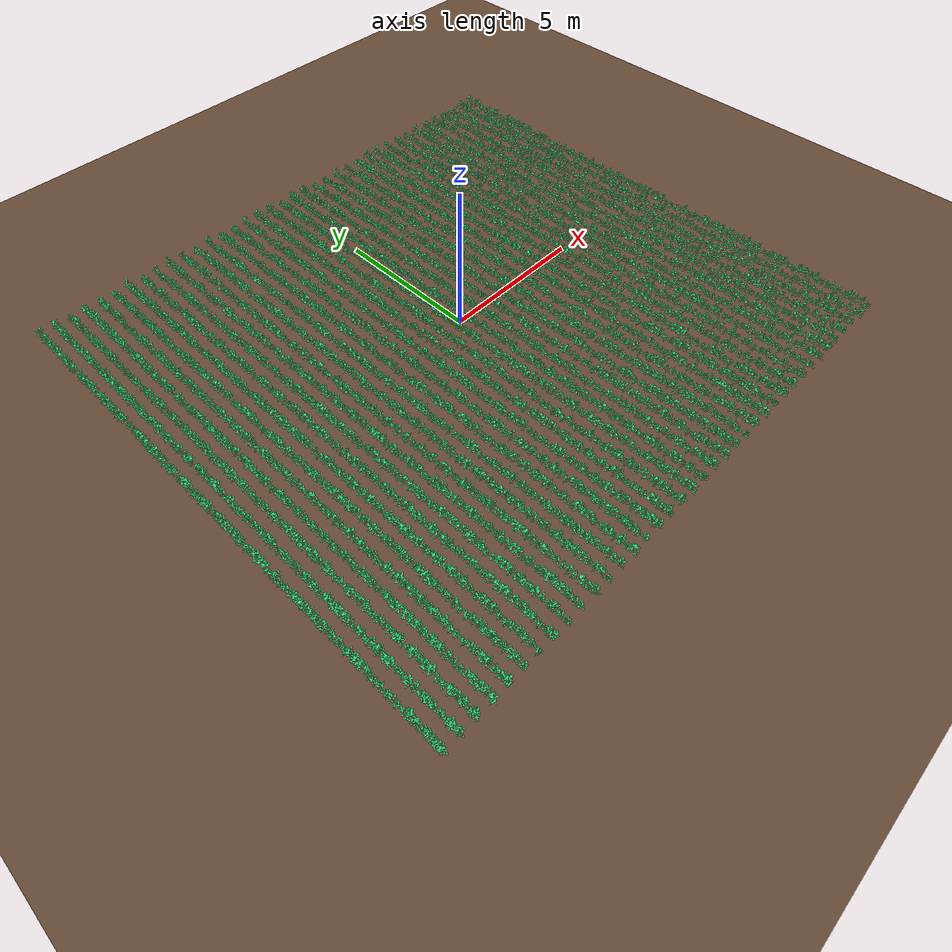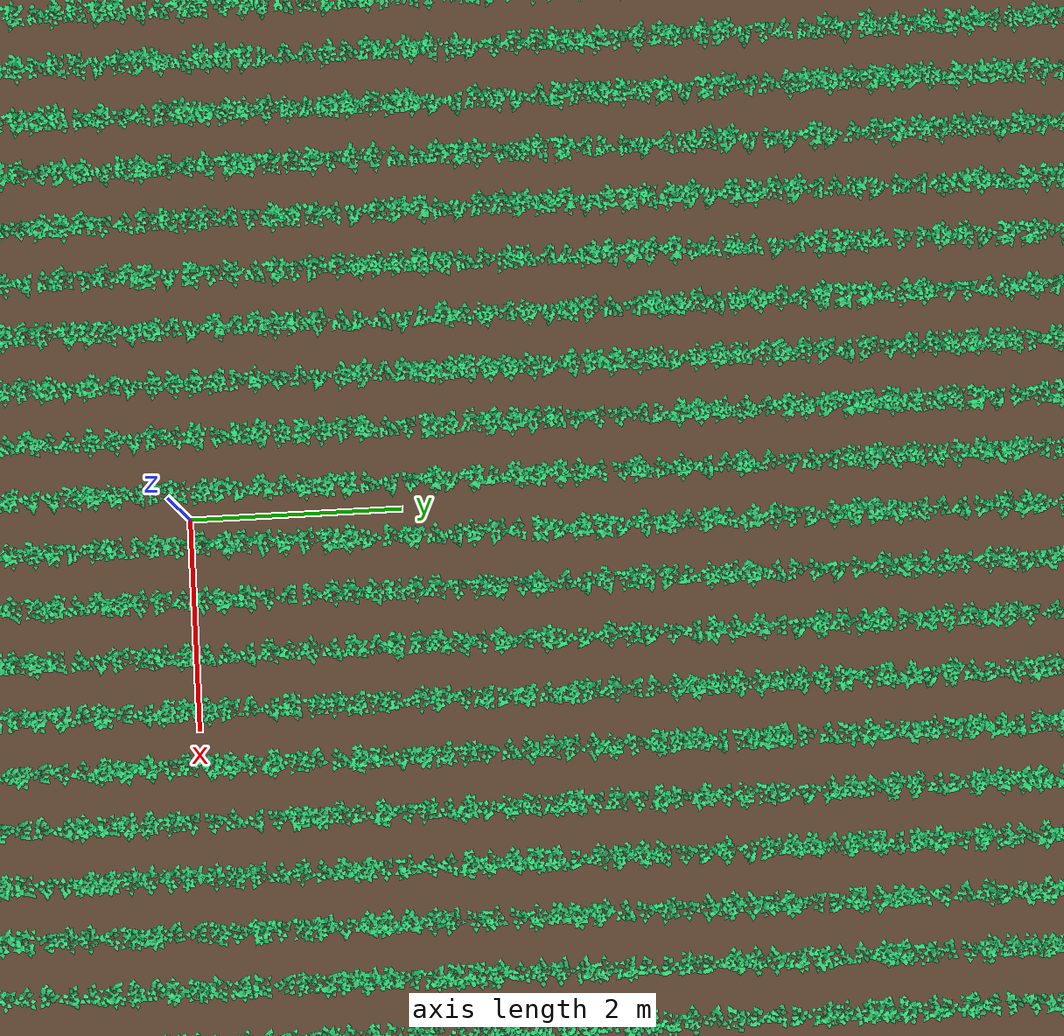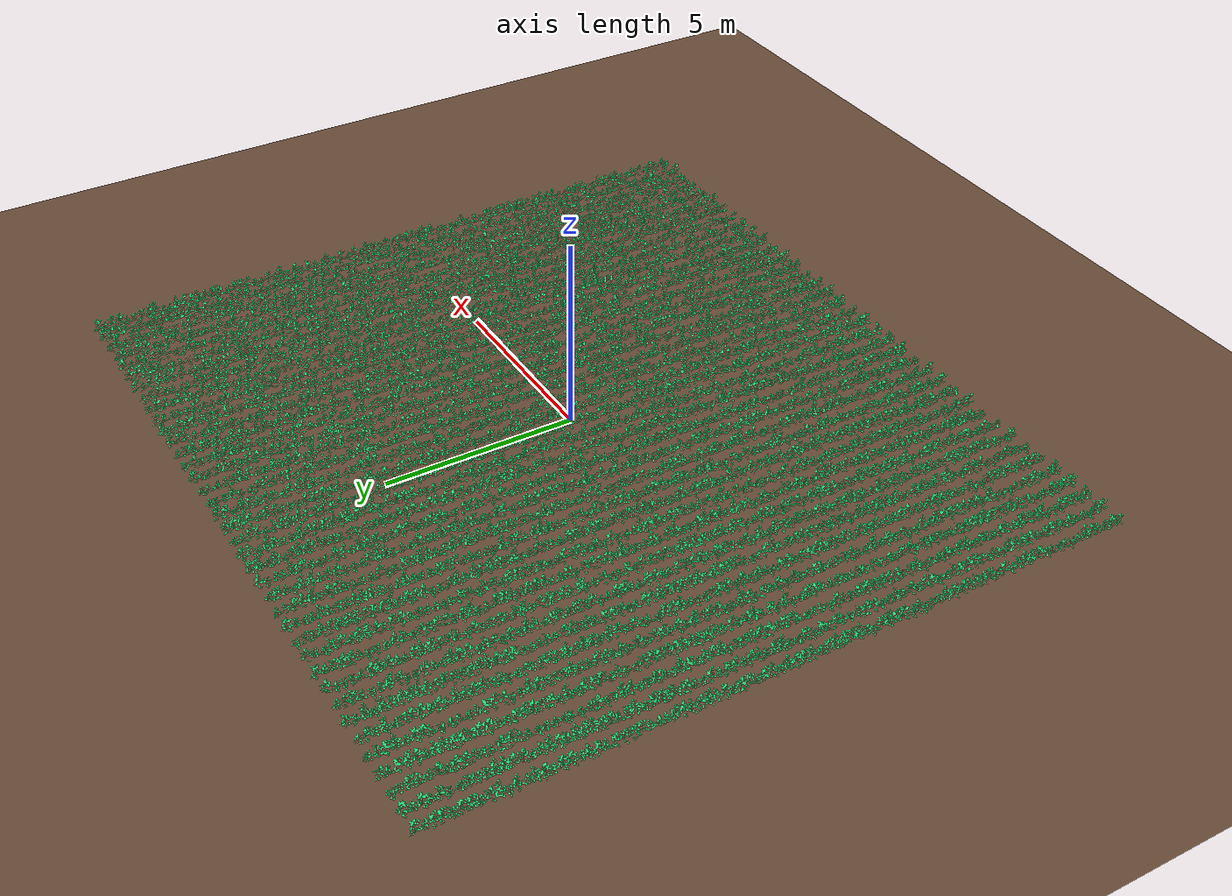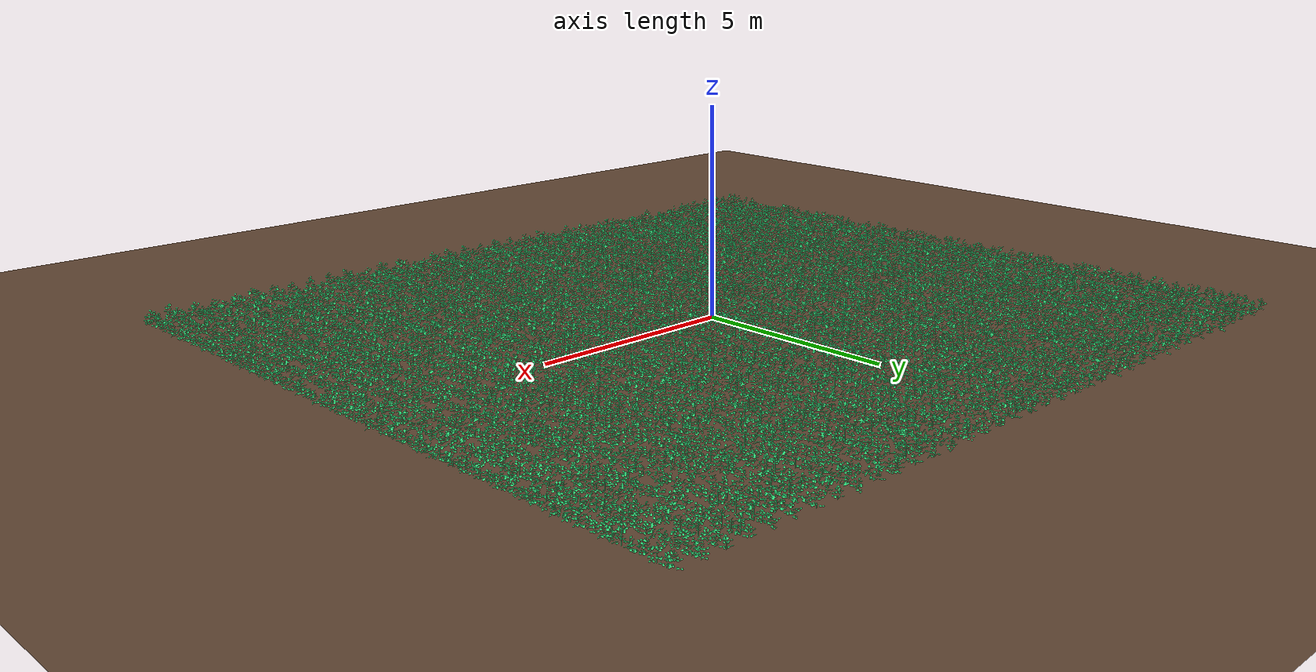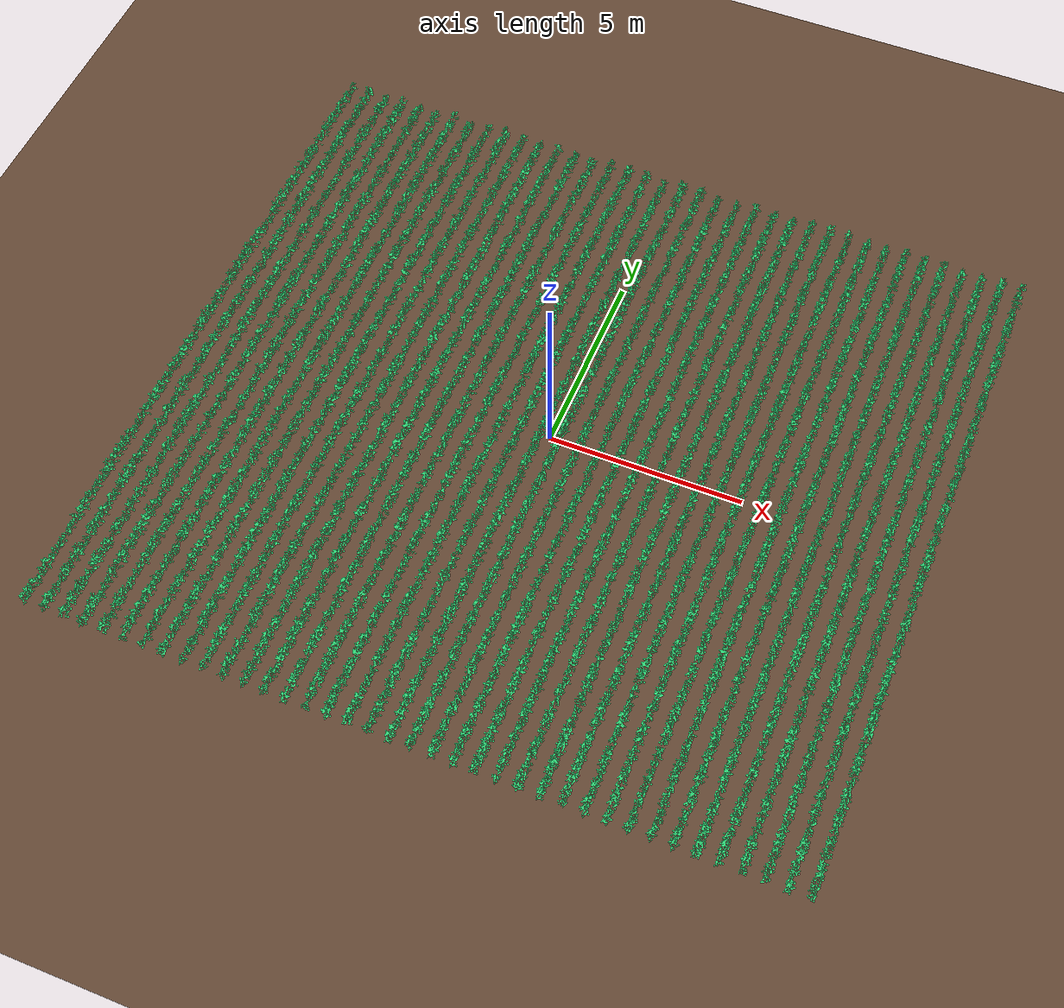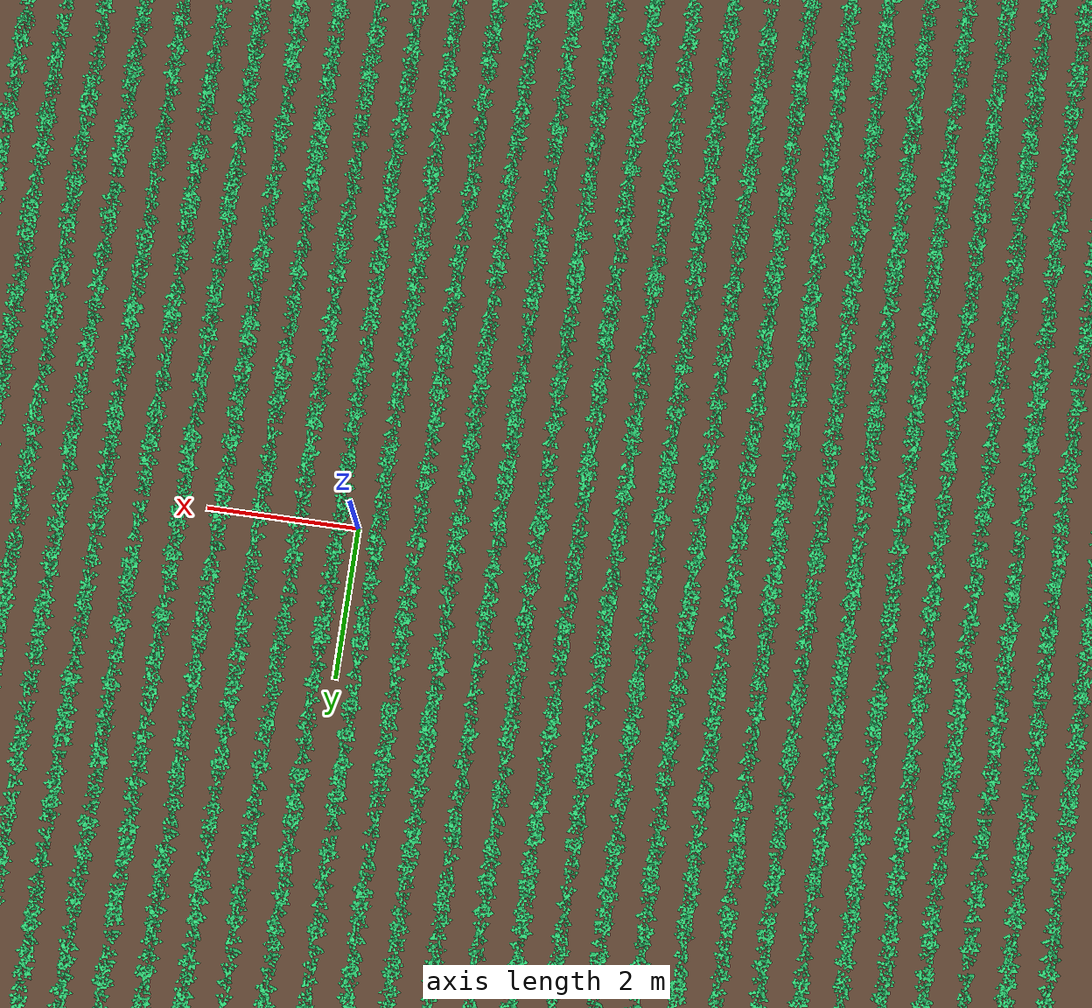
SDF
<sdf version="1.6">
 <world name="test">
  <light name="sun" type="directional">
   <pose>0 0 10 0 0 0</pose>
   <diffuse>0.8 0.8 0.8 1</diffuse>
   <specular>0.2 0.2 0.2 1</specular>
   <attenuation>
    <range>1000</range>
    <constant>0.9</constant>
    <linear>0.01</linear>
    <quadratic>0.001</quadratic>
   </attenuation>
   <direction>-0.5 0.1 -0.9</direction>
  </light>
  <gravity>0 0 -9.8</gravity>
  <magnetic_field>6e-06 2.3e-05 -4.2e-05</magnetic_field>
  <atmosphere type="adiabatic"/>
  <physics name="default_physics" default="0" type="ode">
   <max_step_size>0.001</max_step_size>
   <real_time_factor>1</real_time_factor>
   <real_time_update_rate>1000</real_time_update_rate>
  </physics>
  <scene><ambient>0.4 0.4 0.4 1</ambient><background>0.7 0.7 0.7 1</background><shadows>1</shadows></scene>
  <spherical_coordinates>
   <surface_model>EARTH_WGS84</surface_model>
   <latitude_deg>0</latitude_deg>
   <longitude_deg>0</longitude_deg>
   <elevation>0</elevation>
   <heading_deg>0</heading_deg>
  </spherical_coordinates>
  <model name="ground_plane">
   <static>1</static>
   <link name="ground_plane">
    <collision name="collision">
     <geometry><plane><normal>0 0 1</normal><size>20 30</size></plane></geometry>
     <surface><friction><ode><mu>100</mu><mu2>50</mu2></ode></friction></surface>
    </collision>
    <visual name="visual">
     <cast_shadows>0</cast_shadows>
     <geometry><plane><normal>0 0 1</normal><size>20 30</size></plane></geometry>
     <material>
      <ambient>0.40 0.29 0.21 1.00</ambient>
      <diffuse>0.40 0.29 0.21 1.00</diffuse>
      <specular>0.01 0.01 0.01 1</specular>
      <emissive>0 0 0 1</emissive>
     </material>
    </visual>
   </link>
  </model>
  <model name="crop1">
   <pose>-9.62 0.00 0.15 0.00 0.00 0.00</pose>
   <link name="crop_line">
    <visual name="visual1">
     <pose>0.00 -8.89 -0.16 0.00 0.00 3.54</pose>
     <geometry><mesh><uri>file://very_low/plant_1.stl</uri></mesh></geometry>
     <material>
      <ambient>0.13 0.60 0.33 1.00</ambient>
      <diffuse>0.18 0.85 0.47 1.00</diffuse>
      <specular>0.01 0.01 0.01 1</specular>
      <emissive>0 0 0 1</emissive>
     </material>
    </visual>
    <visual name="visual2">
     <pose>0.00 -8.70 -0.15 0.00 0.00 5.56</pose>
     <geometry><mesh><uri>file://very_low/plant_2.stl</uri></mesh></geometry>
     <material>
      <ambient>0.13 0.60 0.33 1.00</ambient>
      <diffuse>0.18 0.85 0.47 1.00</diffuse>
      <specular>0.01 0.01 0.01 1</specular>
      <emissive>0 0 0 1</emissive>
     </material>
    </visual>
    <visual name="visual3">
     <pose>0.00 -8.50 -0.16 0.00 0.00 2.52</pose>
     <geometry><mesh><uri>file://very_low/plant_1.stl</uri></mesh></geometry>
     <material>
      <ambient>0.13 0.60 0.33 1.00</ambient>
      <diffuse>0.18 0.85 0.47 1.00</diffuse>
      <specular>0.01 0.01 0.01 1</specular>
      <emissive>0 0 0 1</emissive>
     </material>
    </visual>
    <visual name="visual4">
     <pose>0.00 -8.29 -0.16 0.00 0.00 6.01</pose>
     <geometry><mesh><uri>file://very_low/plant_3.stl</uri></mesh></geometry>
     <material>
      <ambient>0.13 0.60 0.33 1.00</ambient>
      <diffuse>0.18 0.85 0.47 1.00</diffuse>
      <specular>0.01 0.01 0.01 1</specular>
      <emissive>0 0 0 1</emissive>
     </material>
    </visual>
    <visual name="visual5">
     <pose>0.00 -8.09 -0.16 0.00 0.00 5.83</pose>
     <geometry><mesh><uri>file://very_low/plant_1.stl</uri></mesh></geometry>
     <material>
      <ambient>0.13 0.60 0.33 1.00</ambient>
      <diffuse>0.18 0.85 0.47 1.00</diffuse>
      <specular>0.01 0.01 0.01 1</specular>
      <emissive>0 0 0 1</emissive>
     </material>
    </visual>
    <visual name="visual6">
     <pose>0.00 -7.90 -0.15 0.00 0.00 4.49</pose>
     <geometry><mesh><uri>file://very_low/plant_2.stl</uri></mesh></geometry>
     <material>
      <ambient>0.13 0.60 0.33 1.00</ambient>
      <diffuse>0.18 0.85 0.47 1.00</diffuse>
      <specular>0.01 0.01 0.01 1</specular>
      <emissive>0 0 0 1</emissive>
     </material>
    </visual>
    <visual name="visual7">
     <pose>0.00 -7.71 -0.15 0.00 0.00 1.41</pose>
     <geometry><mesh><uri>file://very_low/plant_3.stl</uri></mesh></geometry>
     <material>
      <ambient>0.13 0.60 0.33 1.00</ambient>
      <diffuse>0.18 0.85 0.47 1.00</diffuse>
      <specular>0.01 0.01 0.01 1</specular>
      <emissive>0 0 0 1</emissive>
     </material>
    </visual>
    <visual name="visual8">
     <pose>0.00 -7.50 -0.16 0.00 0.00 2.79</pose>
     <geometry><mesh><uri>file://very_low/plant_3.stl</uri></mesh></geometry>
     <material>
      <ambient>0.13 0.60 0.33 1.00</ambient>
      <diffuse>0.18 0.85 0.47 1.00</diffuse>
      <specular>0.01 0.01 0.01 1</specular>
      <emissive>0 0 0 1</emissive>
     </material>
    </visual>
    <visual name="visual9">
     <pose>0.00 -7.30 -0.15 0.00 0.00 1.30</pose>
     <geometry><mesh><uri>file://very_low/plant_3.stl</uri></mesh></geometry>
     <material>
      <ambient>0.13 0.60 0.33 1.00</ambient>
      <diffuse>0.18 0.85 0.47 1.00</diffuse>
      <specular>0.01 0.01 0.01 1</specular>
      <emissive>0 0 0 1</emissive>
     </material>
    </visual>
    <visual name="visual10">
     <pose>0.00 -7.11 -0.15 0.00 0.00 3.95</pose>
     <geometry><mesh><uri>file://very_low/plant_3.stl</uri></mesh></geometry>
     <material>
      <ambient>0.13 0.60 0.33 1.00</ambient>
      <diffuse>0.18 0.85 0.47 1.00</diffuse>
      <specular>0.01 0.01 0.01 1</specular>
      <emissive>0 0 0 1</emissive>
     </material>
    </visual>
    <visual name="visual11">
     <pose>0.00 -6.91 -0.16 0.00 0.00 1.63</pose>
     <geometry><mesh><uri>file://very_low/plant_3.stl</uri></mesh></geometry>
     <material>
      <ambient>0.13 0.60 0.33 1.00</ambient>
      <diffuse>0.18 0.85 0.47 1.00</diffuse>
      <specular>0.01 0.01 0.01 1</specular>
      <emissive>0 0 0 1</emissive>
     </material>
    </visual>
    <visual name="visual12">
     <pose>0.00 -6.71 -0.15 0.00 0.00 3.87</pose>
     <geometry><mesh><uri>file://very_low/plant_3.stl</uri></mesh></geometry>
     <material>
      <ambient>0.13 0.60 0.33 1.00</ambient>
      <diffuse>0.18 0.85 0.47 1.00</diffuse>
      <specular>0.01 0.01 0.01 1</specular>
      <emissive>0 0 0 1</emissive>
     </material>
    </visual>
    <visual name="visual13">
     <pose>0.00 -6.51 -0.15 0.00 0.00 5.57</pose>
     <geometry><mesh><uri>file://very_low/plant_1.stl</uri></mesh></geometry>
     <material>
      <ambient>0.13 0.60 0.33 1.00</ambient>
      <diffuse>0.18 0.85 0.47 1.00</diffuse>
      <specular>0.01 0.01 0.01 1</specular>
      <emissive>0 0 0 1</emissive>
     </material>
    </visual>
    <visual name="visual14">
     <pose>0.00 -6.30 -0.16 0.00 0.00 3.02</pose>
     <geometry><mesh><uri>file://very_low/plant_2.stl</uri></mesh></geometry>
     <material>
      <ambient>0.13 0.60 0.33 1.00</ambient>
      <diffuse>0.18 0.85 0.47 1.00</diffuse>
      <specular>0.01 0.01 0.01 1</specular>
      <emissive>0 0 0 1</emissive>
     </material>
    </visual>
    <visual name="visual15">
     <pose>0.00 -6.11 -0.15 0.00 0.00 4.38</pose>
     <geometry><mesh><uri>file://very_low/plant_2.stl</uri></mesh></geometry>
     <material>
      <ambient>0.13 0.60 0.33 1.00</ambient>
      <diffuse>0.18 0.85 0.47 1.00</diffuse>
      <specular>0.01 0.01 0.01 1</specular>
      <emissive>0 0 0 1</emissive>
     </material>
    </visual>
    <visual name="visual16">
     <pose>0.00 -5.90 -0.15 0.00 0.00 2.42</pose>
     <geometry><mesh><uri>file://very_low/plant_1.stl</uri></mesh></geometry>
     <material>
      <ambient>0.13 0.60 0.33 1.00</ambient>
      <diffuse>0.18 0.85 0.47 1.00</diffuse>
      <specular>0.01 0.01 0.01 1</specular>
      <emissive>0 0 0 1</emissive>
     </material>
    </visual>
    <visual name="visual17">
     <pose>0.00 -5.70 -0.15 0.00 0.00 3.57</pose>
     <geometry><mesh><uri>file://very_low/plant_3.stl</uri></mesh></geometry>
     <material>
      <ambient>0.13 0.60 0.33 1.00</ambient>
      <diffuse>0.18 0.85 0.47 1.00</diffuse>
      <specular>0.01 0.01 0.01 1</specular>
      <emissive>0 0 0 1</emissive>
     </material>
    </visual>
    <visual name="visual18">
     <pose>0.00 -5.50 -0.15 0.00 0.00 0.61</pose>
     <geometry><mesh><uri>file://very_low/plant_1.stl</uri></mesh></geometry>
     <material>
      <ambient>0.13 0.60 0.33 1.00</ambient>
      <diffuse>0.18 0.85 0.47 1.00</diffuse>
      <specular>0.01 0.01 0.01 1</specular>
      <emissive>0 0 0 1</emissive>
     </material>
    </visual>
    <visual name="visual19">
     <pose>0.00 -5.29 -0.15 0.00 0.00 2.41</pose>
     <geometry><mesh><uri>file://very_low/plant_3.stl</uri></mesh></geometry>
     <material>
      <ambient>0.13 0.60 0.33 1.00</ambient>
      <diffuse>0.18 0.85 0.47 1.00</diffuse>
      <specular>0.01 0.01 0.01 1</specular>
      <emissive>0 0 0 1</emissive>
     </material>
    </visual>
    <visual name="visual20">
     <pose>0.00 -5.10 -0.16 0.00 0.00 5.96</pose>
     <geometry><mesh><uri>file://very_low/plant_1.stl</uri></mesh></geometry>
     <material>
      <ambient>0.13 0.60 0.33 1.00</ambient>
      <diffuse>0.18 0.85 0.47 1.00</diffuse>
      <specular>0.01 0.01 0.01 1</specular>
      <emissive>0 0 0 1</emissive>
     </material>
    </visual>
    <visual name="visual21">
     <pose>0.00 -4.90 -0.16 0.00 0.00 0.56</pose>
     <geometry><mesh><uri>file://very_low/plant_2.stl</uri></mesh></geometry>
     <material>
      <ambient>0.13 0.60 0.33 1.00</ambient>
      <diffuse>0.18 0.85 0.47 1.00</diffuse>
      <specular>0.01 0.01 0.01 1</specular>
      <emissive>0 0 0 1</emissive>
     </material>
    </visual>
    <visual name="visual22">
     <pose>0.00 -4.70 -0.16 0.00 0.00 2.34</pose>
     <geometry><mesh><uri>file://very_low/plant_1.stl</uri></mesh></geometry>
     <material>
      <ambient>0.13 0.60 0.33 1.00</ambient>
      <diffuse>0.18 0.85 0.47 1.00</diffuse>
      <specular>0.01 0.01 0.01 1</specular>
      <emissive>0 0 0 1</emissive>
     </material>
    </visual>
    <visual name="visual23">
     <pose>0.00 -4.51 -0.15 0.00 0.00 2.49</pose>
     <geometry><mesh><uri>file://very_low/plant_1.stl</uri></mesh></geometry>
     <material>
      <ambient>0.13 0.60 0.33 1.00</ambient>
      <diffuse>0.18 0.85 0.47 1.00</diffuse>
      <specular>0.01 0.01 0.01 1</specular>
      <emissive>0 0 0 1</emissive>
     </material>
    </visual>
    <visual name="visual24">
     <pose>0.00 -4.31 -0.16 0.00 0.00 5.39</pose>
     <geometry><mesh><uri>file://very_low/plant_1.stl</uri></mesh></geometry>
     <material>
      <ambient>0.13 0.60 0.33 1.00</ambient>
      <diffuse>0.18 0.85 0.47 1.00</diffuse>
      <specular>0.01 0.01 0.01 1</specular>
      <emissive>0 0 0 1</emissive>
     </material>
    </visual>
    <visual name="visual25">
     <pose>0.00 -4.10 -0.16 0.00 0.00 1.67</pose>
     <geometry><mesh><uri>file://very_low/plant_2.stl</uri></mesh></geometry>
     <material>
      <ambient>0.13 0.60 0.33 1.00</ambient>
      <diffuse>0.18 0.85 0.47 1.00</diffuse>
      <specular>0.01 0.01 0.01 1</specular>
      <emissive>0 0 0 1</emissive>
     </material>
    </visual>
    <visual name="visual26">
     <pose>0.00 -3.89 -0.16 0.00 0.00 4.72</pose>
     <geometry><mesh><uri>file://very_low/plant_2.stl</uri></mesh></geometry>
     <material>
      <ambient>0.13 0.60 0.33 1.00</ambient>
      <diffuse>0.18 0.85 0.47 1.00</diffuse>
      <specular>0.01 0.01 0.01 1</specular>
      <emissive>0 0 0 1</emissive>
     </material>
    </visual>
    <visual name="visual27">
     <pose>0.00 -3.70 -0.15 0.00 0.00 0.76</pose>
     <geometry><mesh><uri>file://very_low/plant_3.stl</uri></mesh></geometry>
     <material>
      <ambient>0.13 0.60 0.33 1.00</ambient>
      <diffuse>0.18 0.85 0.47 1.00</diffuse>
      <specular>0.01 0.01 0.01 1</specular>
      <emissive>0 0 0 1</emissive>
     </material>
    </visual>
    <visual name="visual28">
     <pose>0.00 -3.50 -0.16 0.00 0.00 2.24</pose>
     <geometry><mesh><uri>file://very_low/plant_3.stl</uri></mesh></geometry>
     <material>
      <ambient>0.13 0.60 0.33 1.00</ambient>
      <diffuse>0.18 0.85 0.47 1.00</diffuse>
      <specular>0.01 0.01 0.01 1</specular>
      <emissive>0 0 0 1</emissive>
     </material>
    </visual>
    <visual name="visual29">
     <pose>0.00 -3.30 -0.16 0.00 0.00 2.84</pose>
     <geometry><mesh><uri>file://very_low/plant_3.stl</uri></mesh></geometry>
     <material>
      <ambient>0.13 0.60 0.33 1.00</ambient>
      <diffuse>0.18 0.85 0.47 1.00</diffuse>
      <specular>0.01 0.01 0.01 1</specular>
      <emissive>0 0 0 1</emissive>
     </material>
    </visual>
    <visual name="visual30">
     <pose>0.00 -3.11 -0.16 0.00 0.00 1.79</pose>
     <geometry><mesh><uri>file://very_low/plant_1.stl</uri></mesh></geometry>
     <material>
      <ambient>0.13 0.60 0.33 1.00</ambient>
      <diffuse>0.18 0.85 0.47 1.00</diffuse>
      <specular>0.01 0.01 0.01 1</specular>
      <emissive>0 0 0 1</emissive>
     </material>
    </visual>
    <visual name="visual31">
     <pose>0.00 -2.91 -0.16 0.00 0.00 3.68</pose>
     <geometry><mesh><uri>file://very_low/plant_3.stl</uri></mesh></geometry>
     <material>
      <ambient>0.13 0.60 0.33 1.00</ambient>
      <diffuse>0.18 0.85 0.47 1.00</diffuse>
      <specular>0.01 0.01 0.01 1</specular>
      <emissive>0 0 0 1</emissive>
     </material>
    </visual>
    <visual name="visual32">
     <pose>0.00 -2.69 -0.15 0.00 0.00 2.03</pose>
     <geometry><mesh><uri>file://very_low/plant_2.stl</uri></mesh></geometry>
     <material>
      <ambient>0.13 0.60 0.33 1.00</ambient>
      <diffuse>0.18 0.85 0.47 1.00</diffuse>
      <specular>0.01 0.01 0.01 1</specular>
      <emissive>0 0 0 1</emissive>
     </material>
    </visual>
    <visual name="visual33">
     <pose>0.00 -2.50 -0.16 0.00 0.00 2.59</pose>
     <geometry><mesh><uri>file://very_low/plant_2.stl</uri></mesh></geometry>
     <material>
      <ambient>0.13 0.60 0.33 1.00</ambient>
      <diffuse>0.18 0.85 0.47 1.00</diffuse>
      <specular>0.01 0.01 0.01 1</specular>
      <emissive>0 0 0 1</emissive>
     </material>
    </visual>
    <visual name="visual34">
     <pose>0.00 -2.30 -0.16 0.00 0.00 3.80</pose>
     <geometry><mesh><uri>file://very_low/plant_2.stl</uri></mesh></geometry>
     <material>
      <ambient>0.13 0.60 0.33 1.00</ambient>
      <diffuse>0.18 0.85 0.47 1.00</diffuse>
      <specular>0.01 0.01 0.01 1</specular>
      <emissive>0 0 0 1</emissive>
     </material>
    </visual>
    <visual name="visual35">
     <pose>0.00 -2.10 -0.16 0.00 0.00 0.55</pose>
     <geometry><mesh><uri>file://very_low/plant_1.stl</uri></mesh></geometry>
     <material>
      <ambient>0.13 0.60 0.33 1.00</ambient>
      <diffuse>0.18 0.85 0.47 1.00</diffuse>
      <specular>0.01 0.01 0.01 1</specular>
      <emissive>0 0 0 1</emissive>
     </material>
    </visual>
    <visual name="visual36">
     <pose>0.00 -1.90 -0.16 0.00 0.00 2.88</pose>
     <geometry><mesh><uri>file://very_low/plant_3.stl</uri></mesh></geometry>
     <material>
      <ambient>0.13 0.60 0.33 1.00</ambient>
      <diffuse>0.18 0.85 0.47 1.00</diffuse>
      <specular>0.01 0.01 0.01 1</specular>
      <emissive>0 0 0 1</emissive>
     </material>
    </visual>
    <visual name="visual37">
     <pose>0.00 -1.70 -0.16 0.00 0.00 3.01</pose>
     <geometry><mesh><uri>file://very_low/plant_1.stl</uri></mesh></geometry>
     <material>
      <ambient>0.13 0.60 0.33 1.00</ambient>
      <diffuse>0.18 0.85 0.47 1.00</diffuse>
      <specular>0.01 0.01 0.01 1</specular>
      <emissive>0 0 0 1</emissive>
     </material>
    </visual>
    <visual name="visual38">
     <pose>0.00 -1.50 -0.16 0.00 0.00 4.11</pose>
     <geometry><mesh><uri>file://very_low/plant_2.stl</uri></mesh></geometry>
     <material>
      <ambient>0.13 0.60 0.33 1.00</ambient>
      <diffuse>0.18 0.85 0.47 1.00</diffuse>
      <specular>0.01 0.01 0.01 1</specular>
      <emissive>0 0 0 1</emissive>
     </material>
    </visual>
    <visual name="visual39">
     <pose>0.00 -1.30 -0.15 0.00 0.00 0.37</pose>
     <geometry><mesh><uri>file://very_low/plant_1.stl</uri></mesh></geometry>
     <material>
      <ambient>0.13 0.60 0.33 1.00</ambient>
      <diffuse>0.18 0.85 0.47 1.00</diffuse>
      <specular>0.01 0.01 0.01 1</specular>
      <emissive>0 0 0 1</emissive>
     </material>
    </visual>
    <visual name="visual40">
     <pose>0.00 -1.10 -0.15 0.00 0.00 3.06</pose>
     <geometry><mesh><uri>file://very_low/plant_2.stl</uri></mesh></geometry>
     <material>
      <ambient>0.13 0.60 0.33 1.00</ambient>
      <diffuse>0.18 0.85 0.47 1.00</diffuse>
      <specular>0.01 0.01 0.01 1</specular>
      <emissive>0 0 0 1</emissive>
     </material>
    </visual>
    <visual name="visual41">
     <pose>0.00 -0.89 -0.16 0.00 0.00 4.20</pose>
     <geometry><mesh><uri>file://very_low/plant_2.stl</uri></mesh></geometry>
     <material>
      <ambient>0.13 0.60 0.33 1.00</ambient>
      <diffuse>0.18 0.85 0.47 1.00</diffuse>
      <specular>0.01 0.01 0.01 1</specular>
      <emissive>0 0 0 1</emissive>
     </material>
    </visual>
    <visual name="visual42">
     <pose>0.00 -0.70 -0.16 0.00 0.00 0.93</pose>
     <geometry><mesh><uri>file://very_low/plant_1.stl</uri></mesh></geometry>
     <material>
      <ambient>0.13 0.60 0.33 1.00</ambient>
      <diffuse>0.18 0.85 0.47 1.00</diffuse>
      <specular>0.01 0.01 0.01 1</specular>
      <emissive>0 0 0 1</emissive>
     </material>
    </visual>
    <visual name="visual43">
     <pose>0.00 -0.49 -0.15 0.00 0.00 5.56</pose>
     <geometry><mesh><uri>file://very_low/plant_3.stl</uri></mesh></geometry>
     <material>
      <ambient>0.13 0.60 0.33 1.00</ambient>
      <diffuse>0.18 0.85 0.47 1.00</diffuse>
      <specular>0.01 0.01 0.01 1</specular>
      <emissive>0 0 0 1</emissive>
     </material>
    </visual>
    <visual name="visual44">
     <pose>0.00 -0.29 -0.15 0.00 0.00 1.95</pose>
     <geometry><mesh><uri>file://very_low/plant_1.stl</uri></mesh></geometry>
     <material>
      <ambient>0.13 0.60 0.33 1.00</ambient>
      <diffuse>0.18 0.85 0.47 1.00</diffuse>
      <specular>0.01 0.01 0.01 1</specular>
      <emissive>0 0 0 1</emissive>
     </material>
    </visual>
    <visual name="visual45">
     <pose>0.00 -0.10 -0.15 0.00 0.00 2.28</pose>
     <geometry><mesh><uri>file://very_low/plant_2.stl</uri></mesh></geometry>
     <material>
      <ambient>0.13 0.60 0.33 1.00</ambient>
      <diffuse>0.18 0.85 0.47 1.00</diffuse>
      <specular>0.01 0.01 0.01 1</specular>
      <emissive>0 0 0 1</emissive>
     </material>
    </visual>
    <visual name="visual46">
     <pose>0.00 0.10 -0.16 0.00 0.00 1.15</pose>
     <geometry><mesh><uri>file://very_low/plant_2.stl</uri></mesh></geometry>
     <material>
      <ambient>0.13 0.60 0.33 1.00</ambient>
      <diffuse>0.18 0.85 0.47 1.00</diffuse>
      <specular>0.01 0.01 0.01 1</specular>
      <emissive>0 0 0 1</emissive>
     </material>
    </visual>
    <visual name="visual47">
     <pose>0.00 0.31 -0.16 0.00 0.00 4.76</pose>
     <geometry><mesh><uri>file://very_low/plant_2.stl</uri></mesh></geometry>
     <material>
      <ambient>0.13 0.60 0.33 1.00</ambient>
      <diffuse>0.18 0.85 0.47 1.00</diffuse>
      <specular>0.01 0.01 0.01 1</specular>
      <emissive>0 0 0 1</emissive>
     </material>
    </visual>
    <visual name="visual48">
     <pose>0.00 0.50 -0.16 0.00 0.00 1.15</pose>
     <geometry><mesh><uri>file://very_low/plant_3.stl</uri></mesh></geometry>
     <material>
      <ambient>0.13 0.60 0.33 1.00</ambient>
      <diffuse>0.18 0.85 0.47 1.00</diffuse>
      <specular>0.01 0.01 0.01 1</specular>
      <emissive>0 0 0 1</emissive>
     </material>
    </visual>
    <visual name="visual49">
     <pose>0.00 0.70 -0.16 0.00 0.00 2.00</pose>
     <geometry><mesh><uri>file://very_low/plant_1.stl</uri></mesh></geometry>
     <material>
      <ambient>0.13 0.60 0.33 1.00</ambient>
      <diffuse>0.18 0.85 0.47 1.00</diffuse>
      <specular>0.01 0.01 0.01 1</specular>
      <emissive>0 0 0 1</emissive>
     </material>
    </visual>
    <visual name="visual50">
     <pose>0.00 0.89 -0.16 0.00 0.00 2.66</pose>
     <geometry><mesh><uri>file://very_low/plant_2.stl</uri></mesh></geometry>
     <material>
      <ambient>0.13 0.60 0.33 1.00</ambient>
      <diffuse>0.18 0.85 0.47 1.00</diffuse>
      <specular>0.01 0.01 0.01 1</specular>
      <emissive>0 0 0 1</emissive>
     </material>
    </visual>
    <visual name="visual51">
     <pose>0.00 1.11 -0.16 0.00 0.00 4.75</pose>
     <geometry><mesh><uri>file://very_low/plant_3.stl</uri></mesh></geometry>
     <material>
      <ambient>0.13 0.60 0.33 1.00</ambient>
      <diffuse>0.18 0.85 0.47 1.00</diffuse>
      <specular>0.01 0.01 0.01 1</specular>
      <emissive>0 0 0 1</emissive>
     </material>
    </visual>
    <visual name="visual52">
     <pose>0.00 1.31 -0.16 0.00 0.00 0.42</pose>
     <geometry><mesh><uri>file://very_low/plant_1.stl</uri></mesh></geometry>
     <material>
      <ambient>0.13 0.60 0.33 1.00</ambient>
      <diffuse>0.18 0.85 0.47 1.00</diffuse>
      <specular>0.01 0.01 0.01 1</specular>
      <emissive>0 0 0 1</emissive>
     </material>
    </visual>
    <visual name="visual53">
     <pose>0.00 1.51 -0.16 0.00 0.00 0.59</pose>
     <geometry><mesh><uri>file://very_low/plant_2.stl</uri></mesh></geometry>
     <material>
      <ambient>0.13 0.60 0.33 1.00</ambient>
      <diffuse>0.18 0.85 0.47 1.00</diffuse>
      <specular>0.01 0.01 0.01 1</specular>
      <emissive>0 0 0 1</emissive>
     </material>
    </visual>
    <visual name="visual54">
     <pose>0.00 1.70 -0.16 0.00 0.00 4.69</pose>
     <geometry><mesh><uri>file://very_low/plant_3.stl</uri></mesh></geometry>
     <material>
      <ambient>0.13 0.60 0.33 1.00</ambient>
      <diffuse>0.18 0.85 0.47 1.00</diffuse>
      <specular>0.01 0.01 0.01 1</specular>
      <emissive>0 0 0 1</emissive>
     </material>
    </visual>
    <visual name="visual55">
     <pose>0.00 1.90 -0.16 0.00 0.00 1.65</pose>
     <geometry><mesh><uri>file://very_low/plant_2.stl</uri></mesh></geometry>
     <material>
      <ambient>0.13 0.60 0.33 1.00</ambient>
      <diffuse>0.18 0.85 0.47 1.00</diffuse>
      <specular>0.01 0.01 0.01 1</specular>
      <emissive>0 0 0 1</emissive>
     </material>
    </visual>
    <visual name="visual56">
     <pose>0.00 2.11 -0.16 0.00 0.00 2.26</pose>
     <geometry><mesh><uri>file://very_low/plant_1.stl</uri></mesh></geometry>
     <material>
      <ambient>0.13 0.60 0.33 1.00</ambient>
      <diffuse>0.18 0.85 0.47 1.00</diffuse>
      <specular>0.01 0.01 0.01 1</specular>
      <emissive>0 0 0 1</emissive>
     </material>
    </visual>
    <visual name="visual57">
     <pose>0.00 2.29 -0.15 0.00 0.00 3.98</pose>
     <geometry><mesh><uri>file://very_low/plant_2.stl</uri></mesh></geometry>
     <material>
      <ambient>0.13 0.60 0.33 1.00</ambient>
      <diffuse>0.18 0.85 0.47 1.00</diffuse>
      <specular>0.01 0.01 0.01 1</specular>
      <emissive>0 0 0 1</emissive>
     </material>
    </visual>
    <visual name="visual58">
     <pose>0.00 2.50 -0.15 0.00 0.00 0.77</pose>
     <geometry><mesh><uri>file://very_low/plant_2.stl</uri></mesh></geometry>
     <material>
      <ambient>0.13 0.60 0.33 1.00</ambient>
      <diffuse>0.18 0.85 0.47 1.00</diffuse>
      <specular>0.01 0.01 0.01 1</specular>
      <emissive>0 0 0 1</emissive>
     </material>
    </visual>
    <visual name="visual59">
     <pose>0.00 2.71 -0.16 0.00 0.00 2.04</pose>
     <geometry><mesh><uri>file://very_low/plant_1.stl</uri></mesh></geometry>
     <material>
      <ambient>0.13 0.60 0.33 1.00</ambient>
      <diffuse>0.18 0.85 0.47 1.00</diffuse>
      <specular>0.01 0.01 0.01 1</specular>
      <emissive>0 0 0 1</emissive>
     </material>
    </visual>
    <visual name="visual60">
     <pose>0.00 2.89 -0.15 0.00 0.00 1.62</pose>
     <geometry><mesh><uri>file://very_low/plant_1.stl</uri></mesh></geometry>
     <material>
      <ambient>0.13 0.60 0.33 1.00</ambient>
      <diffuse>0.18 0.85 0.47 1.00</diffuse>
      <specular>0.01 0.01 0.01 1</specular>
      <emissive>0 0 0 1</emissive>
     </material>
    </visual>
    <visual name="visual61">
     <pose>0.00 3.11 -0.15 0.00 0.00 2.97</pose>
     <geometry><mesh><uri>file://very_low/plant_2.stl</uri></mesh></geometry>
     <material>
      <ambient>0.13 0.60 0.33 1.00</ambient>
      <diffuse>0.18 0.85 0.47 1.00</diffuse>
      <specular>0.01 0.01 0.01 1</specular>
      <emissive>0 0 0 1</emissive>
     </material>
    </visual>
    <visual name="visual62">
     <pose>0.00 3.31 -0.15 0.00 0.00 5.88</pose>
     <geometry><mesh><uri>file://very_low/plant_3.stl</uri></mesh></geometry>
     <material>
      <ambient>0.13 0.60 0.33 1.00</ambient>
      <diffuse>0.18 0.85 0.47 1.00</diffuse>
      <specular>0.01 0.01 0.01 1</specular>
      <emissive>0 0 0 1</emissive>
     </material>
    </visual>
    <visual name="visual63">
     <pose>0.00 3.49 -0.15 0.00 0.00 5.52</pose>
     <geometry><mesh><uri>file://very_low/plant_3.stl</uri></mesh></geometry>
     <material>
      <ambient>0.13 0.60 0.33 1.00</ambient>
      <diffuse>0.18 0.85 0.47 1.00</diffuse>
      <specular>0.01 0.01 0.01 1</specular>
      <emissive>0 0 0 1</emissive>
     </material>
    </visual>
    <visual name="visual64">
     <pose>0.00 3.69 -0.15 0.00 0.00 6.15</pose>
     <geometry><mesh><uri>file://very_low/plant_3.stl</uri></mesh></geometry>
     <material>
      <ambient>0.13 0.60 0.33 1.00</ambient>
      <diffuse>0.18 0.85 0.47 1.00</diffuse>
      <specular>0.01 0.01 0.01 1</specular>
      <emissive>0 0 0 1</emissive>
     </material>
    </visual>
    <visual name="visual65">
     <pose>0.00 3.91 -0.15 0.00 0.00 0.64</pose>
     <geometry><mesh><uri>file://very_low/plant_1.stl</uri></mesh></geometry>
     <material>
      <ambient>0.13 0.60 0.33 1.00</ambient>
      <diffuse>0.18 0.85 0.47 1.00</diffuse>
      <specular>0.01 0.01 0.01 1</specular>
      <emissive>0 0 0 1</emissive>
     </material>
    </visual>
    <visual name="visual66">
     <pose>0.00 4.10 -0.15 0.00 0.00 4.78</pose>
     <geometry><mesh><uri>file://very_low/plant_1.stl</uri></mesh></geometry>
     <material>
      <ambient>0.13 0.60 0.33 1.00</ambient>
      <diffuse>0.18 0.85 0.47 1.00</diffuse>
      <specular>0.01 0.01 0.01 1</specular>
      <emissive>0 0 0 1</emissive>
     </material>
    </visual>
    <visual name="visual67">
     <pose>0.00 4.30 -0.16 0.00 0.00 4.95</pose>
     <geometry><mesh><uri>file://very_low/plant_1.stl</uri></mesh></geometry>
     <material>
      <ambient>0.13 0.60 0.33 1.00</ambient>
      <diffuse>0.18 0.85 0.47 1.00</diffuse>
      <specular>0.01 0.01 0.01 1</specular>
      <emissive>0 0 0 1</emissive>
     </material>
    </visual>
    <visual name="visual68">
     <pose>0.00 4.50 -0.15 0.00 0.00 0.32</pose>
     <geometry><mesh><uri>file://very_low/plant_2.stl</uri></mesh></geometry>
     <material>
      <ambient>0.13 0.60 0.33 1.00</ambient>
      <diffuse>0.18 0.85 0.47 1.00</diffuse>
      <specular>0.01 0.01 0.01 1</specular>
      <emissive>0 0 0 1</emissive>
     </material>
    </visual>
    <visual name="visual69">
     <pose>0.00 4.70 -0.15 0.00 0.00 1.60</pose>
     <geometry><mesh><uri>file://very_low/plant_3.stl</uri></mesh></geometry>
     <material>
      <ambient>0.13 0.60 0.33 1.00</ambient>
      <diffuse>0.18 0.85 0.47 1.00</diffuse>
      <specular>0.01 0.01 0.01 1</specular>
      <emissive>0 0 0 1</emissive>
     </material>
    </visual>
    <visual name="visual70">
     <pose>0.00 4.91 -0.15 0.00 0.00 6.08</pose>
     <geometry><mesh><uri>file://very_low/plant_2.stl</uri></mesh></geometry>
     <material>
      <ambient>0.13 0.60 0.33 1.00</ambient>
      <diffuse>0.18 0.85 0.47 1.00</diffuse>
      <specular>0.01 0.01 0.01 1</specular>
      <emissive>0 0 0 1</emissive>
     </material>
    </visual>
    <visual name="visual71">
     <pose>0.00 5.11 -0.16 0.00 0.00 2.01</pose>
     <geometry><mesh><uri>file://very_low/plant_1.stl</uri></mesh></geometry>
     <material>
      <ambient>0.13 0.60 0.33 1.00</ambient>
      <diffuse>0.18 0.85 0.47 1.00</diffuse>
      <specular>0.01 0.01 0.01 1</specular>
      <emissive>0 0 0 1</emissive>
     </material>
    </visual>
    <visual name="visual72">
     <pose>0.00 5.30 -0.15 0.00 0.00 5.14</pose>
     <geometry><mesh><uri>file://very_low/plant_3.stl</uri></mesh></geometry>
     <material>
      <ambient>0.13 0.60 0.33 1.00</ambient>
      <diffuse>0.18 0.85 0.47 1.00</diffuse>
      <specular>0.01 0.01 0.01 1</specular>
      <emissive>0 0 0 1</emissive>
     </material>
    </visual>
    <visual name="visual73">
     <pose>0.00 5.50 -0.16 0.00 0.00 2.06</pose>
     <geometry><mesh><uri>file://very_low/plant_2.stl</uri></mesh></geometry>
     <material>
      <ambient>0.13 0.60 0.33 1.00</ambient>
      <diffuse>0.18 0.85 0.47 1.00</diffuse>
      <specular>0.01 0.01 0.01 1</specular>
      <emissive>0 0 0 1</emissive>
     </material>
    </visual>
    <visual name="visual74">
     <pose>0.00 5.71 -0.15 0.00 0.00 1.95</pose>
     <geometry><mesh><uri>file://very_low/plant_2.stl</uri></mesh></geometry>
     <material>
      <ambient>0.13 0.60 0.33 1.00</ambient>
      <diffuse>0.18 0.85 0.47 1.00</diffuse>
      <specular>0.01 0.01 0.01 1</specular>
      <emissive>0 0 0 1</emissive>
     </material>
    </visual>
    <visual name="visual75">
     <pose>0.00 5.91 -0.16 0.00 0.00 1.03</pose>
     <geometry><mesh><uri>file://very_low/plant_3.stl</uri></mesh></geometry>
     <material>
      <ambient>0.13 0.60 0.33 1.00</ambient>
      <diffuse>0.18 0.85 0.47 1.00</diffuse>
      <specular>0.01 0.01 0.01 1</specular>
      <emissive>0 0 0 1</emissive>
     </material>
    </visual>
    <visual name="visual76">
     <pose>0.00 6.10 -0.16 0.00 0.00 1.12</pose>
     <geometry><mesh><uri>file://very_low/plant_2.stl</uri></mesh></geometry>
     <material>
      <ambient>0.13 0.60 0.33 1.00</ambient>
      <diffuse>0.18 0.85 0.47 1.00</diffuse>
      <specular>0.01 0.01 0.01 1</specular>
      <emissive>0 0 0 1</emissive>
     </material>
    </visual>
    <visual name="visual77">
     <pose>0.00 6.30 -0.16 0.00 0.00 5.20</pose>
     <geometry><mesh><uri>file://very_low/plant_2.stl</uri></mesh></geometry>
     <material>
      <ambient>0.13 0.60 0.33 1.00</ambient>
      <diffuse>0.18 0.85 0.47 1.00</diffuse>
      <specular>0.01 0.01 0.01 1</specular>
      <emissive>0 0 0 1</emissive>
     </material>
    </visual>
    <visual name="visual78">
     <pose>0.00 6.49 -0.16 0.00 0.00 5.79</pose>
     <geometry><mesh><uri>file://very_low/plant_3.stl</uri></mesh></geometry>
     <material>
      <ambient>0.13 0.60 0.33 1.00</ambient>
      <diffuse>0.18 0.85 0.47 1.00</diffuse>
      <specular>0.01 0.01 0.01 1</specular>
      <emissive>0 0 0 1</emissive>
     </material>
    </visual>
    <visual name="visual79">
     <pose>0.00 6.71 -0.16 0.00 0.00 1.57</pose>
     <geometry><mesh><uri>file://very_low/plant_1.stl</uri></mesh></geometry>
     <material>
      <ambient>0.13 0.60 0.33 1.00</ambient>
      <diffuse>0.18 0.85 0.47 1.00</diffuse>
      <specular>0.01 0.01 0.01 1</specular>
      <emissive>0 0 0 1</emissive>
     </material>
    </visual>
    <visual name="visual80">
     <pose>0.00 6.89 -0.16 0.00 0.00 3.11</pose>
     <geometry><mesh><uri>file://very_low/plant_3.stl</uri></mesh></geometry>
     <material>
      <ambient>0.13 0.60 0.33 1.00</ambient>
      <diffuse>0.18 0.85 0.47 1.00</diffuse>
      <specular>0.01 0.01 0.01 1</specular>
      <emissive>0 0 0 1</emissive>
     </material>
    </visual>
    <visual name="visual81">
     <pose>0.00 7.10 -0.15 0.00 0.00 4.12</pose>
     <geometry><mesh><uri>file://very_low/plant_2.stl</uri></mesh></geometry>
     <material>
      <ambient>0.13 0.60 0.33 1.00</ambient>
      <diffuse>0.18 0.85 0.47 1.00</diffuse>
      <specular>0.01 0.01 0.01 1</specular>
      <emissive>0 0 0 1</emissive>
     </material>
    </visual>
    <visual name="visual82">
     <pose>0.00 7.30 -0.15 0.00 0.00 5.34</pose>
     <geometry><mesh><uri>file://very_low/plant_1.stl</uri></mesh></geometry>
     <material>
      <ambient>0.13 0.60 0.33 1.00</ambient>
      <diffuse>0.18 0.85 0.47 1.00</diffuse>
      <specular>0.01 0.01 0.01 1</specular>
      <emissive>0 0 0 1</emissive>
     </material>
    </visual>
    <visual name="visual83">
     <pose>0.00 7.51 -0.16 0.00 0.00 3.05</pose>
     <geometry><mesh><uri>file://very_low/plant_1.stl</uri></mesh></geometry>
     <material>
      <ambient>0.13 0.60 0.33 1.00</ambient>
      <diffuse>0.18 0.85 0.47 1.00</diffuse>
      <specular>0.01 0.01 0.01 1</specular>
      <emissive>0 0 0 1</emissive>
     </material>
    </visual>
    <visual name="visual84">
     <pose>0.00 7.69 -0.15 0.00 0.00 2.63</pose>
     <geometry><mesh><uri>file://very_low/plant_2.stl</uri></mesh></geometry>
     <material>
      <ambient>0.13 0.60 0.33 1.00</ambient>
      <diffuse>0.18 0.85 0.47 1.00</diffuse>
      <specular>0.01 0.01 0.01 1</specular>
      <emissive>0 0 0 1</emissive>
     </material>
    </visual>
    <visual name="visual85">
     <pose>0.00 7.90 -0.16 0.00 0.00 0.66</pose>
     <geometry><mesh><uri>file://very_low/plant_1.stl</uri></mesh></geometry>
     <material>
      <ambient>0.13 0.60 0.33 1.00</ambient>
      <diffuse>0.18 0.85 0.47 1.00</diffuse>
      <specular>0.01 0.01 0.01 1</specular>
      <emissive>0 0 0 1</emissive>
     </material>
    </visual>
    <visual name="visual86">
     <pose>0.00 8.10 -0.16 0.00 0.00 3.24</pose>
     <geometry><mesh><uri>file://very_low/plant_1.stl</uri></mesh></geometry>
     <material>
      <ambient>0.13 0.60 0.33 1.00</ambient>
      <diffuse>0.18 0.85 0.47 1.00</diffuse>
      <specular>0.01 0.01 0.01 1</specular>
      <emissive>0 0 0 1</emissive>
     </material>
    </visual>
    <visual name="visual87">
     <pose>0.00 8.31 -0.16 0.00 0.00 0.99</pose>
     <geometry><mesh><uri>file://very_low/plant_1.stl</uri></mesh></geometry>
     <material>
      <ambient>0.13 0.60 0.33 1.00</ambient>
      <diffuse>0.18 0.85 0.47 1.00</diffuse>
      <specular>0.01 0.01 0.01 1</specular>
      <emissive>0 0 0 1</emissive>
     </material>
    </visual>
    <visual name="visual88">
     <pose>0.00 8.49 -0.16 0.00 0.00 1.22</pose>
     <geometry><mesh><uri>file://very_low/plant_1.stl</uri></mesh></geometry>
     <material>
      <ambient>0.13 0.60 0.33 1.00</ambient>
      <diffuse>0.18 0.85 0.47 1.00</diffuse>
      <specular>0.01 0.01 0.01 1</specular>
      <emissive>0 0 0 1</emissive>
     </material>
    </visual>
    <visual name="visual89">
     <pose>0.00 8.70 -0.15 0.00 0.00 5.25</pose>
     <geometry><mesh><uri>file://very_low/plant_3.stl</uri></mesh></geometry>
     <material>
      <ambient>0.13 0.60 0.33 1.00</ambient>
      <diffuse>0.18 0.85 0.47 1.00</diffuse>
      <specular>0.01 0.01 0.01 1</specular>
      <emissive>0 0 0 1</emissive>
     </material>
    </visual>
    <visual name="visual90">
     <pose>0.00 8.90 -0.15 0.00 0.00 0.47</pose>
     <geometry><mesh><uri>file://very_low/plant_1.stl</uri></mesh></geometry>
     <material>
      <ambient>0.13 0.60 0.33 1.00</ambient>
      <diffuse>0.18 0.85 0.47 1.00</diffuse>
      <specular>0.01 0.01 0.01 1</specular>
      <emissive>0 0 0 1</emissive>
     </material>
    </visual>
    <collision name="collision">
     <geometry><box><size>0.24 18.00 0.30</size></box></geometry>
     <surface><contact><collide_without_contact>true</collide_without_contact></contact></surface>
    </collision>
   </link>
   <static>1</static>
  </model>
  <model name="crop2">
   <pose>-9.10 0.00 0.15 0.00 0.00 0.00</pose>
   <link name="crop_line">
    <visual name="visual1">
     <pose>0.00 -8.89 -0.15 0.00 0.00 0.28</pose>
     <geometry><mesh><uri>file://very_low/plant_1.stl</uri></mesh></geometry>
     <material>
      <ambient>0.13 0.60 0.33 1.00</ambient>
      <diffuse>0.18 0.85 0.47 1.00</diffuse>
      <specular>0.01 0.01 0.01 1</specular>
      <emissive>0 0 0 1</emissive>
     </material>
    </visual>
    <visual name="visual2">
     <pose>0.00 -8.70 -0.15 0.00 0.00 4.93</pose>
     <geometry><mesh><uri>file://very_low/plant_2.stl</uri></mesh></geometry>
     <material>
      <ambient>0.13 0.60 0.33 1.00</ambient>
      <diffuse>0.18 0.85 0.47 1.00</diffuse>
      <specular>0.01 0.01 0.01 1</specular>
      <emissive>0 0 0 1</emissive>
     </material>
    </visual>
    <visual name="visual3">
     <pose>0.00 -8.50 -0.16 0.00 0.00 3.76</pose>
     <geometry><mesh><uri>file://very_low/plant_3.stl</uri></mesh></geometry>
     <material>
      <ambient>0.13 0.60 0.33 1.00</ambient>
      <diffuse>0.18 0.85 0.47 1.00</diffuse>
      <specular>0.01 0.01 0.01 1</specular>
      <emissive>0 0 0 1</emissive>
     </material>
    </visual>
    <visual name="visual4">
     <pose>0.00 -8.30 -0.15 0.00 0.00 5.53</pose>
     <geometry><mesh><uri>file://very_low/plant_3.stl</uri></mesh></geometry>
     <material>
      <ambient>0.13 0.60 0.33 1.00</ambient>
      <diffuse>0.18 0.85 0.47 1.00</diffuse>
      <specular>0.01 0.01 0.01 1</specular>
      <emissive>0 0 0 1</emissive>
     </material>
    </visual>
    <visual name="visual5">
     <pose>0.00 -8.10 -0.16 0.00 0.00 2.00</pose>
     <geometry><mesh><uri>file://very_low/plant_3.stl</uri></mesh></geometry>
     <material>
      <ambient>0.13 0.60 0.33 1.00</ambient>
      <diffuse>0.18 0.85 0.47 1.00</diffuse>
      <specular>0.01 0.01 0.01 1</specular>
      <emissive>0 0 0 1</emissive>
     </material>
    </visual>
    <visual name="visual6">
     <pose>0.00 -7.89 -0.16 0.00 0.00 5.75</pose>
     <geometry><mesh><uri>file://very_low/plant_2.stl</uri></mesh></geometry>
     <material>
      <ambient>0.13 0.60 0.33 1.00</ambient>
      <diffuse>0.18 0.85 0.47 1.00</diffuse>
      <specular>0.01 0.01 0.01 1</specular>
      <emissive>0 0 0 1</emissive>
     </material>
    </visual>
    <visual name="visual7">
     <pose>0.00 -7.71 -0.15 0.00 0.00 1.78</pose>
     <geometry><mesh><uri>file://very_low/plant_3.stl</uri></mesh></geometry>
     <material>
      <ambient>0.13 0.60 0.33 1.00</ambient>
      <diffuse>0.18 0.85 0.47 1.00</diffuse>
      <specular>0.01 0.01 0.01 1</specular>
      <emissive>0 0 0 1</emissive>
     </material>
    </visual>
    <visual name="visual8">
     <pose>0.00 -7.49 -0.15 0.00 0.00 4.86</pose>
     <geometry><mesh><uri>file://very_low/plant_1.stl</uri></mesh></geometry>
     <material>
      <ambient>0.13 0.60 0.33 1.00</ambient>
      <diffuse>0.18 0.85 0.47 1.00</diffuse>
      <specular>0.01 0.01 0.01 1</specular>
      <emissive>0 0 0 1</emissive>
     </material>
    </visual>
    <visual name="visual9">
     <pose>0.00 -7.29 -0.16 0.00 0.00 0.51</pose>
     <geometry><mesh><uri>file://very_low/plant_2.stl</uri></mesh></geometry>
     <material>
      <ambient>0.13 0.60 0.33 1.00</ambient>
      <diffuse>0.18 0.85 0.47 1.00</diffuse>
      <specular>0.01 0.01 0.01 1</specular>
      <emissive>0 0 0 1</emissive>
     </material>
    </visual>
    <visual name="visual10">
     <pose>0.00 -7.09 -0.15 0.00 0.00 5.20</pose>
     <geometry><mesh><uri>file://very_low/plant_3.stl</uri></mesh></geometry>
     <material>
      <ambient>0.13 0.60 0.33 1.00</ambient>
      <diffuse>0.18 0.85 0.47 1.00</diffuse>
      <specular>0.01 0.01 0.01 1</specular>
      <emissive>0 0 0 1</emissive>
     </material>
    </visual>
    <visual name="visual11">
     <pose>0.00 -6.90 -0.15 0.00 0.00 5.18</pose>
     <geometry><mesh><uri>file://very_low/plant_3.stl</uri></mesh></geometry>
     <material>
      <ambient>0.13 0.60 0.33 1.00</ambient>
      <diffuse>0.18 0.85 0.47 1.00</diffuse>
      <specular>0.01 0.01 0.01 1</specular>
      <emissive>0 0 0 1</emissive>
     </material>
    </visual>
    <visual name="visual12">
     <pose>0.00 -6.69 -0.16 0.00 0.00 0.43</pose>
     <geometry><mesh><uri>file://very_low/plant_2.stl</uri></mesh></geometry>
     <material>
      <ambient>0.13 0.60 0.33 1.00</ambient>
      <diffuse>0.18 0.85 0.47 1.00</diffuse>
      <specular>0.01 0.01 0.01 1</specular>
      <emissive>0 0 0 1</emissive>
     </material>
    </visual>
    <visual name="visual13">
     <pose>0.00 -6.51 -0.16 0.00 0.00 5.37</pose>
     <geometry><mesh><uri>file://very_low/plant_2.stl</uri></mesh></geometry>
     <material>
      <ambient>0.13 0.60 0.33 1.00</ambient>
      <diffuse>0.18 0.85 0.47 1.00</diffuse>
      <specular>0.01 0.01 0.01 1</specular>
      <emissive>0 0 0 1</emissive>
     </material>
    </visual>
    <visual name="visual14">
     <pose>0.00 -6.30 -0.15 0.00 0.00 1.56</pose>
     <geometry><mesh><uri>file://very_low/plant_1.stl</uri></mesh></geometry>
     <material>
      <ambient>0.13 0.60 0.33 1.00</ambient>
      <diffuse>0.18 0.85 0.47 1.00</diffuse>
      <specular>0.01 0.01 0.01 1</specular>
      <emissive>0 0 0 1</emissive>
     </material>
    </visual>
    <visual name="visual15">
     <pose>0.00 -6.11 -0.15 0.00 0.00 4.66</pose>
     <geometry><mesh><uri>file://very_low/plant_2.stl</uri></mesh></geometry>
     <material>
      <ambient>0.13 0.60 0.33 1.00</ambient>
      <diffuse>0.18 0.85 0.47 1.00</diffuse>
      <specular>0.01 0.01 0.01 1</specular>
      <emissive>0 0 0 1</emissive>
     </material>
    </visual>
    <visual name="visual16">
     <pose>0.00 -5.89 -0.16 0.00 0.00 3.76</pose>
     <geometry><mesh><uri>file://very_low/plant_3.stl</uri></mesh></geometry>
     <material>
      <ambient>0.13 0.60 0.33 1.00</ambient>
      <diffuse>0.18 0.85 0.47 1.00</diffuse>
      <specular>0.01 0.01 0.01 1</specular>
      <emissive>0 0 0 1</emissive>
     </material>
    </visual>
    <visual name="visual17">
     <pose>0.00 -5.71 -0.16 0.00 0.00 3.23</pose>
     <geometry><mesh><uri>file://very_low/plant_1.stl</uri></mesh></geometry>
     <material>
      <ambient>0.13 0.60 0.33 1.00</ambient>
      <diffuse>0.18 0.85 0.47 1.00</diffuse>
      <specular>0.01 0.01 0.01 1</specular>
      <emissive>0 0 0 1</emissive>
     </material>
    </visual>
    <visual name="visual18">
     <pose>0.00 -5.51 -0.15 0.00 0.00 4.43</pose>
     <geometry><mesh><uri>file://very_low/plant_3.stl</uri></mesh></geometry>
     <material>
      <ambient>0.13 0.60 0.33 1.00</ambient>
      <diffuse>0.18 0.85 0.47 1.00</diffuse>
      <specular>0.01 0.01 0.01 1</specular>
      <emissive>0 0 0 1</emissive>
     </material>
    </visual>
    <visual name="visual19">
     <pose>0.00 -5.30 -0.16 0.00 0.00 3.03</pose>
     <geometry><mesh><uri>file://very_low/plant_1.stl</uri></mesh></geometry>
     <material>
      <ambient>0.13 0.60 0.33 1.00</ambient>
      <diffuse>0.18 0.85 0.47 1.00</diffuse>
      <specular>0.01 0.01 0.01 1</specular>
      <emissive>0 0 0 1</emissive>
     </material>
    </visual>
    <visual name="visual20">
     <pose>0.00 -5.10 -0.15 0.00 0.00 1.46</pose>
     <geometry><mesh><uri>file://very_low/plant_2.stl</uri></mesh></geometry>
     <material>
      <ambient>0.13 0.60 0.33 1.00</ambient>
      <diffuse>0.18 0.85 0.47 1.00</diffuse>
      <specular>0.01 0.01 0.01 1</specular>
      <emissive>0 0 0 1</emissive>
     </material>
    </visual>
    <visual name="visual21">
     <pose>0.00 -4.90 -0.15 0.00 0.00 0.68</pose>
     <geometry><mesh><uri>file://very_low/plant_2.stl</uri></mesh></geometry>
     <material>
      <ambient>0.13 0.60 0.33 1.00</ambient>
      <diffuse>0.18 0.85 0.47 1.00</diffuse>
      <specular>0.01 0.01 0.01 1</specular>
      <emissive>0 0 0 1</emissive>
     </material>
    </visual>
    <visual name="visual22">
     <pose>0.00 -4.70 -0.16 0.00 0.00 6.01</pose>
     <geometry><mesh><uri>file://very_low/plant_2.stl</uri></mesh></geometry>
     <material>
      <ambient>0.13 0.60 0.33 1.00</ambient>
      <diffuse>0.18 0.85 0.47 1.00</diffuse>
      <specular>0.01 0.01 0.01 1</specular>
      <emissive>0 0 0 1</emissive>
     </material>
    </visual>
    <visual name="visual23">
     <pose>0.00 -4.50 -0.15 0.00 0.00 2.56</pose>
     <geometry><mesh><uri>file://very_low/plant_1.stl</uri></mesh></geometry>
     <material>
      <ambient>0.13 0.60 0.33 1.00</ambient>
      <diffuse>0.18 0.85 0.47 1.00</diffuse>
      <specular>0.01 0.01 0.01 1</specular>
      <emissive>0 0 0 1</emissive>
     </material>
    </visual>
    <visual name="visual24">
     <pose>0.00 -4.29 -0.16 0.00 0.00 4.51</pose>
     <geometry><mesh><uri>file://very_low/plant_3.stl</uri></mesh></geometry>
     <material>
      <ambient>0.13 0.60 0.33 1.00</ambient>
      <diffuse>0.18 0.85 0.47 1.00</diffuse>
      <specular>0.01 0.01 0.01 1</specular>
      <emissive>0 0 0 1</emissive>
     </material>
    </visual>
    <visual name="visual25">
     <pose>0.00 -4.09 -0.16 0.00 0.00 3.70</pose>
     <geometry><mesh><uri>file://very_low/plant_3.stl</uri></mesh></geometry>
     <material>
      <ambient>0.13 0.60 0.33 1.00</ambient>
      <diffuse>0.18 0.85 0.47 1.00</diffuse>
      <specular>0.01 0.01 0.01 1</specular>
      <emissive>0 0 0 1</emissive>
     </material>
    </visual>
    <visual name="visual26">
     <pose>0.00 -3.90 -0.16 0.00 0.00 5.69</pose>
     <geometry><mesh><uri>file://very_low/plant_2.stl</uri></mesh></geometry>
     <material>
      <ambient>0.13 0.60 0.33 1.00</ambient>
      <diffuse>0.18 0.85 0.47 1.00</diffuse>
      <specular>0.01 0.01 0.01 1</specular>
      <emissive>0 0 0 1</emissive>
     </material>
    </visual>
    <visual name="visual27">
     <pose>0.00 -3.69 -0.16 0.00 0.00 0.67</pose>
     <geometry><mesh><uri>file://very_low/plant_1.stl</uri></mesh></geometry>
     <material>
      <ambient>0.13 0.60 0.33 1.00</ambient>
      <diffuse>0.18 0.85 0.47 1.00</diffuse>
      <specular>0.01 0.01 0.01 1</specular>
      <emissive>0 0 0 1</emissive>
     </material>
    </visual>
    <visual name="visual28">
     <pose>0.00 -3.50 -0.15 0.00 0.00 4.46</pose>
     <geometry><mesh><uri>file://very_low/plant_3.stl</uri></mesh></geometry>
     <material>
      <ambient>0.13 0.60 0.33 1.00</ambient>
      <diffuse>0.18 0.85 0.47 1.00</diffuse>
      <specular>0.01 0.01 0.01 1</specular>
      <emissive>0 0 0 1</emissive>
     </material>
    </visual>
    <visual name="visual29">
     <pose>0.00 -3.30 -0.15 0.00 0.00 5.38</pose>
     <geometry><mesh><uri>file://very_low/plant_1.stl</uri></mesh></geometry>
     <material>
      <ambient>0.13 0.60 0.33 1.00</ambient>
      <diffuse>0.18 0.85 0.47 1.00</diffuse>
      <specular>0.01 0.01 0.01 1</specular>
      <emissive>0 0 0 1</emissive>
     </material>
    </visual>
    <visual name="visual30">
     <pose>0.00 -3.09 -0.16 0.00 0.00 5.59</pose>
     <geometry><mesh><uri>file://very_low/plant_3.stl</uri></mesh></geometry>
     <material>
      <ambient>0.13 0.60 0.33 1.00</ambient>
      <diffuse>0.18 0.85 0.47 1.00</diffuse>
      <specular>0.01 0.01 0.01 1</specular>
      <emissive>0 0 0 1</emissive>
     </material>
    </visual>
    <visual name="visual31">
     <pose>0.00 -2.90 -0.15 0.00 0.00 5.21</pose>
     <geometry><mesh><uri>file://very_low/plant_2.stl</uri></mesh></geometry>
     <material>
      <ambient>0.13 0.60 0.33 1.00</ambient>
      <diffuse>0.18 0.85 0.47 1.00</diffuse>
      <specular>0.01 0.01 0.01 1</specular>
      <emissive>0 0 0 1</emissive>
     </material>
    </visual>
    <visual name="visual32">
     <pose>0.00 -2.70 -0.15 0.00 0.00 1.23</pose>
     <geometry><mesh><uri>file://very_low/plant_3.stl</uri></mesh></geometry>
     <material>
      <ambient>0.13 0.60 0.33 1.00</ambient>
      <diffuse>0.18 0.85 0.47 1.00</diffuse>
      <specular>0.01 0.01 0.01 1</specular>
      <emissive>0 0 0 1</emissive>
     </material>
    </visual>
    <visual name="visual33">
     <pose>0.00 -2.50 -0.15 0.00 0.00 3.68</pose>
     <geometry><mesh><uri>file://very_low/plant_3.stl</uri></mesh></geometry>
     <material>
      <ambient>0.13 0.60 0.33 1.00</ambient>
      <diffuse>0.18 0.85 0.47 1.00</diffuse>
      <specular>0.01 0.01 0.01 1</specular>
      <emissive>0 0 0 1</emissive>
     </material>
    </visual>
    <visual name="visual34">
     <pose>0.00 -2.29 -0.15 0.00 0.00 5.09</pose>
     <geometry><mesh><uri>file://very_low/plant_1.stl</uri></mesh></geometry>
     <material>
      <ambient>0.13 0.60 0.33 1.00</ambient>
      <diffuse>0.18 0.85 0.47 1.00</diffuse>
      <specular>0.01 0.01 0.01 1</specular>
      <emissive>0 0 0 1</emissive>
     </material>
    </visual>
    <visual name="visual35">
     <pose>0.00 -2.09 -0.16 0.00 0.00 0.64</pose>
     <geometry><mesh><uri>file://very_low/plant_2.stl</uri></mesh></geometry>
     <material>
      <ambient>0.13 0.60 0.33 1.00</ambient>
      <diffuse>0.18 0.85 0.47 1.00</diffuse>
      <specular>0.01 0.01 0.01 1</specular>
      <emissive>0 0 0 1</emissive>
     </material>
    </visual>
    <visual name="visual36">
     <pose>0.00 -1.91 -0.15 0.00 0.00 3.01</pose>
     <geometry><mesh><uri>file://very_low/plant_1.stl</uri></mesh></geometry>
     <material>
      <ambient>0.13 0.60 0.33 1.00</ambient>
      <diffuse>0.18 0.85 0.47 1.00</diffuse>
      <specular>0.01 0.01 0.01 1</specular>
      <emissive>0 0 0 1</emissive>
     </material>
    </visual>
    <visual name="visual37">
     <pose>0.00 -1.70 -0.16 0.00 0.00 0.54</pose>
     <geometry><mesh><uri>file://very_low/plant_3.stl</uri></mesh></geometry>
     <material>
      <ambient>0.13 0.60 0.33 1.00</ambient>
      <diffuse>0.18 0.85 0.47 1.00</diffuse>
      <specular>0.01 0.01 0.01 1</specular>
      <emissive>0 0 0 1</emissive>
     </material>
    </visual>
    <visual name="visual38">
     <pose>0.00 -1.49 -0.16 0.00 0.00 0.19</pose>
     <geometry><mesh><uri>file://very_low/plant_3.stl</uri></mesh></geometry>
     <material>
      <ambient>0.13 0.60 0.33 1.00</ambient>
      <diffuse>0.18 0.85 0.47 1.00</diffuse>
      <specular>0.01 0.01 0.01 1</specular>
      <emissive>0 0 0 1</emissive>
     </material>
    </visual>
    <visual name="visual39">
     <pose>0.00 -1.29 -0.16 0.00 0.00 0.85</pose>
     <geometry><mesh><uri>file://very_low/plant_1.stl</uri></mesh></geometry>
     <material>
      <ambient>0.13 0.60 0.33 1.00</ambient>
      <diffuse>0.18 0.85 0.47 1.00</diffuse>
      <specular>0.01 0.01 0.01 1</specular>
      <emissive>0 0 0 1</emissive>
     </material>
    </visual>
    <visual name="visual40">
     <pose>0.00 -1.10 -0.16 0.00 0.00 1.22</pose>
     <geometry><mesh><uri>file://very_low/plant_3.stl</uri></mesh></geometry>
     <material>
      <ambient>0.13 0.60 0.33 1.00</ambient>
      <diffuse>0.18 0.85 0.47 1.00</diffuse>
      <specular>0.01 0.01 0.01 1</specular>
      <emissive>0 0 0 1</emissive>
     </material>
    </visual>
    <visual name="visual41">
     <pose>0.00 -0.90 -0.16 0.00 0.00 5.83</pose>
     <geometry><mesh><uri>file://very_low/plant_2.stl</uri></mesh></geometry>
     <material>
      <ambient>0.13 0.60 0.33 1.00</ambient>
      <diffuse>0.18 0.85 0.47 1.00</diffuse>
      <specular>0.01 0.01 0.01 1</specular>
      <emissive>0 0 0 1</emissive>
     </material>
    </visual>
    <visual name="visual42">
     <pose>0.00 -0.71 -0.15 0.00 0.00 2.88</pose>
     <geometry><mesh><uri>file://very_low/plant_3.stl</uri></mesh></geometry>
     <material>
      <ambient>0.13 0.60 0.33 1.00</ambient>
      <diffuse>0.18 0.85 0.47 1.00</diffuse>
      <specular>0.01 0.01 0.01 1</specular>
      <emissive>0 0 0 1</emissive>
     </material>
    </visual>
    <visual name="visual43">
     <pose>0.00 -0.49 -0.16 0.00 0.00 2.27</pose>
     <geometry><mesh><uri>file://very_low/plant_2.stl</uri></mesh></geometry>
     <material>
      <ambient>0.13 0.60 0.33 1.00</ambient>
      <diffuse>0.18 0.85 0.47 1.00</diffuse>
      <specular>0.01 0.01 0.01 1</specular>
      <emissive>0 0 0 1</emissive>
     </material>
    </visual>
    <visual name="visual44">
     <pose>0.00 -0.29 -0.15 0.00 0.00 4.29</pose>
     <geometry><mesh><uri>file://very_low/plant_3.stl</uri></mesh></geometry>
     <material>
      <ambient>0.13 0.60 0.33 1.00</ambient>
      <diffuse>0.18 0.85 0.47 1.00</diffuse>
      <specular>0.01 0.01 0.01 1</specular>
      <emissive>0 0 0 1</emissive>
     </material>
    </visual>
    <visual name="visual45">
     <pose>0.00 -0.10 -0.15 0.00 0.00 2.21</pose>
     <geometry><mesh><uri>file://very_low/plant_3.stl</uri></mesh></geometry>
     <material>
      <ambient>0.13 0.60 0.33 1.00</ambient>
      <diffuse>0.18 0.85 0.47 1.00</diffuse>
      <specular>0.01 0.01 0.01 1</specular>
      <emissive>0 0 0 1</emissive>
     </material>
    </visual>
    <visual name="visual46">
     <pose>0.00 0.11 -0.15 0.00 0.00 4.10</pose>
     <geometry><mesh><uri>file://very_low/plant_2.stl</uri></mesh></geometry>
     <material>
      <ambient>0.13 0.60 0.33 1.00</ambient>
      <diffuse>0.18 0.85 0.47 1.00</diffuse>
      <specular>0.01 0.01 0.01 1</specular>
      <emissive>0 0 0 1</emissive>
     </material>
    </visual>
    <visual name="visual47">
     <pose>0.00 0.30 -0.16 0.00 0.00 2.48</pose>
     <geometry><mesh><uri>file://very_low/plant_2.stl</uri></mesh></geometry>
     <material>
      <ambient>0.13 0.60 0.33 1.00</ambient>
      <diffuse>0.18 0.85 0.47 1.00</diffuse>
      <specular>0.01 0.01 0.01 1</specular>
      <emissive>0 0 0 1</emissive>
     </material>
    </visual>
    <visual name="visual48">
     <pose>0.00 0.50 -0.15 0.00 0.00 2.01</pose>
     <geometry><mesh><uri>file://very_low/plant_3.stl</uri></mesh></geometry>
     <material>
      <ambient>0.13 0.60 0.33 1.00</ambient>
      <diffuse>0.18 0.85 0.47 1.00</diffuse>
      <specular>0.01 0.01 0.01 1</specular>
      <emissive>0 0 0 1</emissive>
     </material>
    </visual>
    <visual name="visual49">
     <pose>0.00 0.70 -0.16 0.00 0.00 2.11</pose>
     <geometry><mesh><uri>file://very_low/plant_1.stl</uri></mesh></geometry>
     <material>
      <ambient>0.13 0.60 0.33 1.00</ambient>
      <diffuse>0.18 0.85 0.47 1.00</diffuse>
      <specular>0.01 0.01 0.01 1</specular>
      <emissive>0 0 0 1</emissive>
     </material>
    </visual>
    <visual name="visual50">
     <pose>0.00 0.90 -0.16 0.00 0.00 1.20</pose>
     <geometry><mesh><uri>file://very_low/plant_1.stl</uri></mesh></geometry>
     <material>
      <ambient>0.13 0.60 0.33 1.00</ambient>
      <diffuse>0.18 0.85 0.47 1.00</diffuse>
      <specular>0.01 0.01 0.01 1</specular>
      <emissive>0 0 0 1</emissive>
     </material>
    </visual>
    <visual name="visual51">
     <pose>0.00 1.09 -0.15 0.00 0.00 5.61</pose>
     <geometry><mesh><uri>file://very_low/plant_3.stl</uri></mesh></geometry>
     <material>
      <ambient>0.13 0.60 0.33 1.00</ambient>
      <diffuse>0.18 0.85 0.47 1.00</diffuse>
      <specular>0.01 0.01 0.01 1</specular>
      <emissive>0 0 0 1</emissive>
     </material>
    </visual>
    <visual name="visual52">
     <pose>0.00 1.29 -0.15 0.00 0.00 1.24</pose>
     <geometry><mesh><uri>file://very_low/plant_1.stl</uri></mesh></geometry>
     <material>
      <ambient>0.13 0.60 0.33 1.00</ambient>
      <diffuse>0.18 0.85 0.47 1.00</diffuse>
      <specular>0.01 0.01 0.01 1</specular>
      <emissive>0 0 0 1</emissive>
     </material>
    </visual>
    <visual name="visual53">
     <pose>0.00 1.50 -0.15 0.00 0.00 5.91</pose>
     <geometry><mesh><uri>file://very_low/plant_2.stl</uri></mesh></geometry>
     <material>
      <ambient>0.13 0.60 0.33 1.00</ambient>
      <diffuse>0.18 0.85 0.47 1.00</diffuse>
      <specular>0.01 0.01 0.01 1</specular>
      <emissive>0 0 0 1</emissive>
     </material>
    </visual>
    <visual name="visual54">
     <pose>0.00 1.70 -0.15 0.00 0.00 5.82</pose>
     <geometry><mesh><uri>file://very_low/plant_3.stl</uri></mesh></geometry>
     <material>
      <ambient>0.13 0.60 0.33 1.00</ambient>
      <diffuse>0.18 0.85 0.47 1.00</diffuse>
      <specular>0.01 0.01 0.01 1</specular>
      <emissive>0 0 0 1</emissive>
     </material>
    </visual>
    <visual name="visual55">
     <pose>0.00 1.90 -0.15 0.00 0.00 1.17</pose>
     <geometry><mesh><uri>file://very_low/plant_1.stl</uri></mesh></geometry>
     <material>
      <ambient>0.13 0.60 0.33 1.00</ambient>
      <diffuse>0.18 0.85 0.47 1.00</diffuse>
      <specular>0.01 0.01 0.01 1</specular>
      <emissive>0 0 0 1</emissive>
     </material>
    </visual>
    <visual name="visual56">
     <pose>0.00 2.11 -0.16 0.00 0.00 4.54</pose>
     <geometry><mesh><uri>file://very_low/plant_3.stl</uri></mesh></geometry>
     <material>
      <ambient>0.13 0.60 0.33 1.00</ambient>
      <diffuse>0.18 0.85 0.47 1.00</diffuse>
      <specular>0.01 0.01 0.01 1</specular>
      <emissive>0 0 0 1</emissive>
     </material>
    </visual>
    <visual name="visual57">
     <pose>0.00 2.31 -0.16 0.00 0.00 5.51</pose>
     <geometry><mesh><uri>file://very_low/plant_3.stl</uri></mesh></geometry>
     <material>
      <ambient>0.13 0.60 0.33 1.00</ambient>
      <diffuse>0.18 0.85 0.47 1.00</diffuse>
      <specular>0.01 0.01 0.01 1</specular>
      <emissive>0 0 0 1</emissive>
     </material>
    </visual>
    <visual name="visual58">
     <pose>0.00 2.51 -0.15 0.00 0.00 0.50</pose>
     <geometry><mesh><uri>file://very_low/plant_2.stl</uri></mesh></geometry>
     <material>
      <ambient>0.13 0.60 0.33 1.00</ambient>
      <diffuse>0.18 0.85 0.47 1.00</diffuse>
      <specular>0.01 0.01 0.01 1</specular>
      <emissive>0 0 0 1</emissive>
     </material>
    </visual>
    <visual name="visual59">
     <pose>0.00 2.69 -0.15 0.00 0.00 0.94</pose>
     <geometry><mesh><uri>file://very_low/plant_3.stl</uri></mesh></geometry>
     <material>
      <ambient>0.13 0.60 0.33 1.00</ambient>
      <diffuse>0.18 0.85 0.47 1.00</diffuse>
      <specular>0.01 0.01 0.01 1</specular>
      <emissive>0 0 0 1</emissive>
     </material>
    </visual>
    <visual name="visual60">
     <pose>0.00 2.90 -0.16 0.00 0.00 3.00</pose>
     <geometry><mesh><uri>file://very_low/plant_2.stl</uri></mesh></geometry>
     <material>
      <ambient>0.13 0.60 0.33 1.00</ambient>
      <diffuse>0.18 0.85 0.47 1.00</diffuse>
      <specular>0.01 0.01 0.01 1</specular>
      <emissive>0 0 0 1</emissive>
     </material>
    </visual>
    <visual name="visual61">
     <pose>0.00 3.10 -0.16 0.00 0.00 2.18</pose>
     <geometry><mesh><uri>file://very_low/plant_2.stl</uri></mesh></geometry>
     <material>
      <ambient>0.13 0.60 0.33 1.00</ambient>
      <diffuse>0.18 0.85 0.47 1.00</diffuse>
      <specular>0.01 0.01 0.01 1</specular>
      <emissive>0 0 0 1</emissive>
     </material>
    </visual>
    <visual name="visual62">
     <pose>0.00 3.29 -0.15 0.00 0.00 2.82</pose>
     <geometry><mesh><uri>file://very_low/plant_2.stl</uri></mesh></geometry>
     <material>
      <ambient>0.13 0.60 0.33 1.00</ambient>
      <diffuse>0.18 0.85 0.47 1.00</diffuse>
      <specular>0.01 0.01 0.01 1</specular>
      <emissive>0 0 0 1</emissive>
     </material>
    </visual>
    <visual name="visual63">
     <pose>0.00 3.51 -0.16 0.00 0.00 4.16</pose>
     <geometry><mesh><uri>file://very_low/plant_3.stl</uri></mesh></geometry>
     <material>
      <ambient>0.13 0.60 0.33 1.00</ambient>
      <diffuse>0.18 0.85 0.47 1.00</diffuse>
      <specular>0.01 0.01 0.01 1</specular>
      <emissive>0 0 0 1</emissive>
     </material>
    </visual>
    <visual name="visual64">
     <pose>0.00 3.71 -0.16 0.00 0.00 4.92</pose>
     <geometry><mesh><uri>file://very_low/plant_2.stl</uri></mesh></geometry>
     <material>
      <ambient>0.13 0.60 0.33 1.00</ambient>
      <diffuse>0.18 0.85 0.47 1.00</diffuse>
      <specular>0.01 0.01 0.01 1</specular>
      <emissive>0 0 0 1</emissive>
     </material>
    </visual>
    <visual name="visual65">
     <pose>0.00 3.90 -0.15 0.00 0.00 0.36</pose>
     <geometry><mesh><uri>file://very_low/plant_2.stl</uri></mesh></geometry>
     <material>
      <ambient>0.13 0.60 0.33 1.00</ambient>
      <diffuse>0.18 0.85 0.47 1.00</diffuse>
      <specular>0.01 0.01 0.01 1</specular>
      <emissive>0 0 0 1</emissive>
     </material>
    </visual>
    <visual name="visual66">
     <pose>0.00 4.11 -0.15 0.00 0.00 1.67</pose>
     <geometry><mesh><uri>file://very_low/plant_3.stl</uri></mesh></geometry>
     <material>
      <ambient>0.13 0.60 0.33 1.00</ambient>
      <diffuse>0.18 0.85 0.47 1.00</diffuse>
      <specular>0.01 0.01 0.01 1</specular>
      <emissive>0 0 0 1</emissive>
     </material>
    </visual>
    <visual name="visual67">
     <pose>0.00 4.30 -0.16 0.00 0.00 6.14</pose>
     <geometry><mesh><uri>file://very_low/plant_1.stl</uri></mesh></geometry>
     <material>
      <ambient>0.13 0.60 0.33 1.00</ambient>
      <diffuse>0.18 0.85 0.47 1.00</diffuse>
      <specular>0.01 0.01 0.01 1</specular>
      <emissive>0 0 0 1</emissive>
     </material>
    </visual>
    <visual name="visual68">
     <pose>0.00 4.49 -0.16 0.00 0.00 0.62</pose>
     <geometry><mesh><uri>file://very_low/plant_2.stl</uri></mesh></geometry>
     <material>
      <ambient>0.13 0.60 0.33 1.00</ambient>
      <diffuse>0.18 0.85 0.47 1.00</diffuse>
      <specular>0.01 0.01 0.01 1</specular>
      <emissive>0 0 0 1</emissive>
     </material>
    </visual>
    <visual name="visual69">
     <pose>0.00 4.69 -0.15 0.00 0.00 5.07</pose>
     <geometry><mesh><uri>file://very_low/plant_2.stl</uri></mesh></geometry>
     <material>
      <ambient>0.13 0.60 0.33 1.00</ambient>
      <diffuse>0.18 0.85 0.47 1.00</diffuse>
      <specular>0.01 0.01 0.01 1</specular>
      <emissive>0 0 0 1</emissive>
     </material>
    </visual>
    <visual name="visual70">
     <pose>0.00 4.91 -0.15 0.00 0.00 3.19</pose>
     <geometry><mesh><uri>file://very_low/plant_2.stl</uri></mesh></geometry>
     <material>
      <ambient>0.13 0.60 0.33 1.00</ambient>
      <diffuse>0.18 0.85 0.47 1.00</diffuse>
      <specular>0.01 0.01 0.01 1</specular>
      <emissive>0 0 0 1</emissive>
     </material>
    </visual>
    <visual name="visual71">
     <pose>0.00 5.10 -0.15 0.00 0.00 4.31</pose>
     <geometry><mesh><uri>file://very_low/plant_2.stl</uri></mesh></geometry>
     <material>
      <ambient>0.13 0.60 0.33 1.00</ambient>
      <diffuse>0.18 0.85 0.47 1.00</diffuse>
      <specular>0.01 0.01 0.01 1</specular>
      <emissive>0 0 0 1</emissive>
     </material>
    </visual>
    <visual name="visual72">
     <pose>0.00 5.31 -0.15 0.00 0.00 2.90</pose>
     <geometry><mesh><uri>file://very_low/plant_1.stl</uri></mesh></geometry>
     <material>
      <ambient>0.13 0.60 0.33 1.00</ambient>
      <diffuse>0.18 0.85 0.47 1.00</diffuse>
      <specular>0.01 0.01 0.01 1</specular>
      <emissive>0 0 0 1</emissive>
     </material>
    </visual>
    <visual name="visual73">
     <pose>0.00 5.50 -0.16 0.00 0.00 1.92</pose>
     <geometry><mesh><uri>file://very_low/plant_2.stl</uri></mesh></geometry>
     <material>
      <ambient>0.13 0.60 0.33 1.00</ambient>
      <diffuse>0.18 0.85 0.47 1.00</diffuse>
      <specular>0.01 0.01 0.01 1</specular>
      <emissive>0 0 0 1</emissive>
     </material>
    </visual>
    <visual name="visual74">
     <pose>0.00 5.70 -0.15 0.00 0.00 4.09</pose>
     <geometry><mesh><uri>file://very_low/plant_2.stl</uri></mesh></geometry>
     <material>
      <ambient>0.13 0.60 0.33 1.00</ambient>
      <diffuse>0.18 0.85 0.47 1.00</diffuse>
      <specular>0.01 0.01 0.01 1</specular>
      <emissive>0 0 0 1</emissive>
     </material>
    </visual>
    <visual name="visual75">
     <pose>0.00 5.89 -0.15 0.00 0.00 2.37</pose>
     <geometry><mesh><uri>file://very_low/plant_1.stl</uri></mesh></geometry>
     <material>
      <ambient>0.13 0.60 0.33 1.00</ambient>
      <diffuse>0.18 0.85 0.47 1.00</diffuse>
      <specular>0.01 0.01 0.01 1</specular>
      <emissive>0 0 0 1</emissive>
     </material>
    </visual>
    <visual name="visual76">
     <pose>0.00 6.11 -0.16 0.00 0.00 4.78</pose>
     <geometry><mesh><uri>file://very_low/plant_3.stl</uri></mesh></geometry>
     <material>
      <ambient>0.13 0.60 0.33 1.00</ambient>
      <diffuse>0.18 0.85 0.47 1.00</diffuse>
      <specular>0.01 0.01 0.01 1</specular>
      <emissive>0 0 0 1</emissive>
     </material>
    </visual>
    <visual name="visual77">
     <pose>0.00 6.30 -0.15 0.00 0.00 5.61</pose>
     <geometry><mesh><uri>file://very_low/plant_1.stl</uri></mesh></geometry>
     <material>
      <ambient>0.13 0.60 0.33 1.00</ambient>
      <diffuse>0.18 0.85 0.47 1.00</diffuse>
      <specular>0.01 0.01 0.01 1</specular>
      <emissive>0 0 0 1</emissive>
     </material>
    </visual>
    <visual name="visual78">
     <pose>0.00 6.50 -0.15 0.00 0.00 0.58</pose>
     <geometry><mesh><uri>file://very_low/plant_1.stl</uri></mesh></geometry>
     <material>
      <ambient>0.13 0.60 0.33 1.00</ambient>
      <diffuse>0.18 0.85 0.47 1.00</diffuse>
      <specular>0.01 0.01 0.01 1</specular>
      <emissive>0 0 0 1</emissive>
     </material>
    </visual>
    <visual name="visual79">
     <pose>0.00 6.70 -0.15 0.00 0.00 5.22</pose>
     <geometry><mesh><uri>file://very_low/plant_2.stl</uri></mesh></geometry>
     <material>
      <ambient>0.13 0.60 0.33 1.00</ambient>
      <diffuse>0.18 0.85 0.47 1.00</diffuse>
      <specular>0.01 0.01 0.01 1</specular>
      <emissive>0 0 0 1</emissive>
     </material>
    </visual>
    <visual name="visual80">
     <pose>0.00 6.91 -0.15 0.00 0.00 4.29</pose>
     <geometry><mesh><uri>file://very_low/plant_2.stl</uri></mesh></geometry>
     <material>
      <ambient>0.13 0.60 0.33 1.00</ambient>
      <diffuse>0.18 0.85 0.47 1.00</diffuse>
      <specular>0.01 0.01 0.01 1</specular>
      <emissive>0 0 0 1</emissive>
     </material>
    </visual>
    <visual name="visual81">
     <pose>0.00 7.10 -0.16 0.00 0.00 2.95</pose>
     <geometry><mesh><uri>file://very_low/plant_1.stl</uri></mesh></geometry>
     <material>
      <ambient>0.13 0.60 0.33 1.00</ambient>
      <diffuse>0.18 0.85 0.47 1.00</diffuse>
      <specular>0.01 0.01 0.01 1</specular>
      <emissive>0 0 0 1</emissive>
     </material>
    </visual>
    <visual name="visual82">
     <pose>0.00 7.30 -0.15 0.00 0.00 3.45</pose>
     <geometry><mesh><uri>file://very_low/plant_1.stl</uri></mesh></geometry>
     <material>
      <ambient>0.13 0.60 0.33 1.00</ambient>
      <diffuse>0.18 0.85 0.47 1.00</diffuse>
      <specular>0.01 0.01 0.01 1</specular>
      <emissive>0 0 0 1</emissive>
     </material>
    </visual>
    <visual name="visual83">
     <pose>0.00 7.49 -0.15 0.00 0.00 3.29</pose>
     <geometry><mesh><uri>file://very_low/plant_1.stl</uri></mesh></geometry>
     <material>
      <ambient>0.13 0.60 0.33 1.00</ambient>
      <diffuse>0.18 0.85 0.47 1.00</diffuse>
      <specular>0.01 0.01 0.01 1</specular>
      <emissive>0 0 0 1</emissive>
     </material>
    </visual>
    <visual name="visual84">
     <pose>0.00 7.69 -0.15 0.00 0.00 4.29</pose>
     <geometry><mesh><uri>file://very_low/plant_3.stl</uri></mesh></geometry>
     <material>
      <ambient>0.13 0.60 0.33 1.00</ambient>
      <diffuse>0.18 0.85 0.47 1.00</diffuse>
      <specular>0.01 0.01 0.01 1</specular>
      <emissive>0 0 0 1</emissive>
     </material>
    </visual>
    <visual name="visual85">
     <pose>0.00 7.90 -0.16 0.00 0.00 2.48</pose>
     <geometry><mesh><uri>file://very_low/plant_3.stl</uri></mesh></geometry>
     <material>
      <ambient>0.13 0.60 0.33 1.00</ambient>
      <diffuse>0.18 0.85 0.47 1.00</diffuse>
      <specular>0.01 0.01 0.01 1</specular>
      <emissive>0 0 0 1</emissive>
     </material>
    </visual>
    <visual name="visual86">
     <pose>0.00 8.10 -0.15 0.00 0.00 5.85</pose>
     <geometry><mesh><uri>file://very_low/plant_2.stl</uri></mesh></geometry>
     <material>
      <ambient>0.13 0.60 0.33 1.00</ambient>
      <diffuse>0.18 0.85 0.47 1.00</diffuse>
      <specular>0.01 0.01 0.01 1</specular>
      <emissive>0 0 0 1</emissive>
     </material>
    </visual>
    <visual name="visual87">
     <pose>0.00 8.30 -0.15 0.00 0.00 2.04</pose>
     <geometry><mesh><uri>file://very_low/plant_3.stl</uri></mesh></geometry>
     <material>
      <ambient>0.13 0.60 0.33 1.00</ambient>
      <diffuse>0.18 0.85 0.47 1.00</diffuse>
      <specular>0.01 0.01 0.01 1</specular>
      <emissive>0 0 0 1</emissive>
     </material>
    </visual>
    <visual name="visual88">
     <pose>0.00 8.50 -0.16 0.00 0.00 1.90</pose>
     <geometry><mesh><uri>file://very_low/plant_2.stl</uri></mesh></geometry>
     <material>
      <ambient>0.13 0.60 0.33 1.00</ambient>
      <diffuse>0.18 0.85 0.47 1.00</diffuse>
      <specular>0.01 0.01 0.01 1</specular>
      <emissive>0 0 0 1</emissive>
     </material>
    </visual>
    <visual name="visual89">
     <pose>0.00 8.69 -0.15 0.00 0.00 1.39</pose>
     <geometry><mesh><uri>file://very_low/plant_3.stl</uri></mesh></geometry>
     <material>
      <ambient>0.13 0.60 0.33 1.00</ambient>
      <diffuse>0.18 0.85 0.47 1.00</diffuse>
      <specular>0.01 0.01 0.01 1</specular>
      <emissive>0 0 0 1</emissive>
     </material>
    </visual>
    <visual name="visual90">
     <pose>0.00 8.91 -0.15 0.00 0.00 1.50</pose>
     <geometry><mesh><uri>file://very_low/plant_2.stl</uri></mesh></geometry>
     <material>
      <ambient>0.13 0.60 0.33 1.00</ambient>
      <diffuse>0.18 0.85 0.47 1.00</diffuse>
      <specular>0.01 0.01 0.01 1</specular>
      <emissive>0 0 0 1</emissive>
     </material>
    </visual>
    <collision name="collision">
     <geometry><box><size>0.24 18.00 0.30</size></box></geometry>
     <surface><contact><collide_without_contact>true</collide_without_contact></contact></surface>
    </collision>
   </link>
   <static>1</static>
  </model>
  <model name="crop3">
   <pose>-8.58 0.00 0.15 0.00 0.00 0.00</pose>
   <link name="crop_line">
    <visual name="visual1">
     <pose>0.00 -8.89 -0.16 0.00 0.00 4.39</pose>
     <geometry><mesh><uri>file://very_low/plant_2.stl</uri></mesh></geometry>
     <material>
      <ambient>0.13 0.60 0.33 1.00</ambient>
      <diffuse>0.18 0.85 0.47 1.00</diffuse>
      <specular>0.01 0.01 0.01 1</specular>
      <emissive>0 0 0 1</emissive>
     </material>
    </visual>
    <visual name="visual2">
     <pose>0.00 -8.69 -0.16 0.00 0.00 3.90</pose>
     <geometry><mesh><uri>file://very_low/plant_3.stl</uri></mesh></geometry>
     <material>
      <ambient>0.13 0.60 0.33 1.00</ambient>
      <diffuse>0.18 0.85 0.47 1.00</diffuse>
      <specular>0.01 0.01 0.01 1</specular>
      <emissive>0 0 0 1</emissive>
     </material>
    </visual>
    <visual name="visual3">
     <pose>0.00 -8.50 -0.15 0.00 0.00 0.04</pose>
     <geometry><mesh><uri>file://very_low/plant_2.stl</uri></mesh></geometry>
     <material>
      <ambient>0.13 0.60 0.33 1.00</ambient>
      <diffuse>0.18 0.85 0.47 1.00</diffuse>
      <specular>0.01 0.01 0.01 1</specular>
      <emissive>0 0 0 1</emissive>
     </material>
    </visual>
    <visual name="visual4">
     <pose>0.00 -8.30 -0.15 0.00 0.00 0.56</pose>
     <geometry><mesh><uri>file://very_low/plant_1.stl</uri></mesh></geometry>
     <material>
      <ambient>0.13 0.60 0.33 1.00</ambient>
      <diffuse>0.18 0.85 0.47 1.00</diffuse>
      <specular>0.01 0.01 0.01 1</specular>
      <emissive>0 0 0 1</emissive>
     </material>
    </visual>
    <visual name="visual5">
     <pose>0.00 -8.10 -0.16 0.00 0.00 1.39</pose>
     <geometry><mesh><uri>file://very_low/plant_2.stl</uri></mesh></geometry>
     <material>
      <ambient>0.13 0.60 0.33 1.00</ambient>
      <diffuse>0.18 0.85 0.47 1.00</diffuse>
      <specular>0.01 0.01 0.01 1</specular>
      <emissive>0 0 0 1</emissive>
     </material>
    </visual>
    <visual name="visual6">
     <pose>0.00 -7.90 -0.16 0.00 0.00 3.38</pose>
     <geometry><mesh><uri>file://very_low/plant_3.stl</uri></mesh></geometry>
     <material>
      <ambient>0.13 0.60 0.33 1.00</ambient>
      <diffuse>0.18 0.85 0.47 1.00</diffuse>
      <specular>0.01 0.01 0.01 1</specular>
      <emissive>0 0 0 1</emissive>
     </material>
    </visual>
    <visual name="visual7">
     <pose>0.00 -7.71 -0.16 0.00 0.00 2.90</pose>
     <geometry><mesh><uri>file://very_low/plant_3.stl</uri></mesh></geometry>
     <material>
      <ambient>0.13 0.60 0.33 1.00</ambient>
      <diffuse>0.18 0.85 0.47 1.00</diffuse>
      <specular>0.01 0.01 0.01 1</specular>
      <emissive>0 0 0 1</emissive>
     </material>
    </visual>
    <visual name="visual8">
     <pose>0.00 -7.49 -0.15 0.00 0.00 3.44</pose>
     <geometry><mesh><uri>file://very_low/plant_2.stl</uri></mesh></geometry>
     <material>
      <ambient>0.13 0.60 0.33 1.00</ambient>
      <diffuse>0.18 0.85 0.47 1.00</diffuse>
      <specular>0.01 0.01 0.01 1</specular>
      <emissive>0 0 0 1</emissive>
     </material>
    </visual>
    <visual name="visual9">
     <pose>0.00 -7.31 -0.15 0.00 0.00 0.64</pose>
     <geometry><mesh><uri>file://very_low/plant_2.stl</uri></mesh></geometry>
     <material>
      <ambient>0.13 0.60 0.33 1.00</ambient>
      <diffuse>0.18 0.85 0.47 1.00</diffuse>
      <specular>0.01 0.01 0.01 1</specular>
      <emissive>0 0 0 1</emissive>
     </material>
    </visual>
    <visual name="visual10">
     <pose>0.00 -7.11 -0.16 0.00 0.00 6.09</pose>
     <geometry><mesh><uri>file://very_low/plant_1.stl</uri></mesh></geometry>
     <material>
      <ambient>0.13 0.60 0.33 1.00</ambient>
      <diffuse>0.18 0.85 0.47 1.00</diffuse>
      <specular>0.01 0.01 0.01 1</specular>
      <emissive>0 0 0 1</emissive>
     </material>
    </visual>
    <visual name="visual11">
     <pose>0.00 -6.89 -0.16 0.00 0.00 3.48</pose>
     <geometry><mesh><uri>file://very_low/plant_2.stl</uri></mesh></geometry>
     <material>
      <ambient>0.13 0.60 0.33 1.00</ambient>
      <diffuse>0.18 0.85 0.47 1.00</diffuse>
      <specular>0.01 0.01 0.01 1</specular>
      <emissive>0 0 0 1</emissive>
     </material>
    </visual>
    <visual name="visual12">
     <pose>0.00 -6.71 -0.16 0.00 0.00 5.57</pose>
     <geometry><mesh><uri>file://very_low/plant_3.stl</uri></mesh></geometry>
     <material>
      <ambient>0.13 0.60 0.33 1.00</ambient>
      <diffuse>0.18 0.85 0.47 1.00</diffuse>
      <specular>0.01 0.01 0.01 1</specular>
      <emissive>0 0 0 1</emissive>
     </material>
    </visual>
    <visual name="visual13">
     <pose>0.00 -6.49 -0.16 0.00 0.00 2.37</pose>
     <geometry><mesh><uri>file://very_low/plant_1.stl</uri></mesh></geometry>
     <material>
      <ambient>0.13 0.60 0.33 1.00</ambient>
      <diffuse>0.18 0.85 0.47 1.00</diffuse>
      <specular>0.01 0.01 0.01 1</specular>
      <emissive>0 0 0 1</emissive>
     </material>
    </visual>
    <visual name="visual14">
     <pose>0.00 -6.31 -0.16 0.00 0.00 5.77</pose>
     <geometry><mesh><uri>file://very_low/plant_2.stl</uri></mesh></geometry>
     <material>
      <ambient>0.13 0.60 0.33 1.00</ambient>
      <diffuse>0.18 0.85 0.47 1.00</diffuse>
      <specular>0.01 0.01 0.01 1</specular>
      <emissive>0 0 0 1</emissive>
     </material>
    </visual>
    <visual name="visual15">
     <pose>0.00 -6.09 -0.15 0.00 0.00 0.70</pose>
     <geometry><mesh><uri>file://very_low/plant_3.stl</uri></mesh></geometry>
     <material>
      <ambient>0.13 0.60 0.33 1.00</ambient>
      <diffuse>0.18 0.85 0.47 1.00</diffuse>
      <specular>0.01 0.01 0.01 1</specular>
      <emissive>0 0 0 1</emissive>
     </material>
    </visual>
    <visual name="visual16">
     <pose>0.00 -5.90 -0.15 0.00 0.00 5.52</pose>
     <geometry><mesh><uri>file://very_low/plant_3.stl</uri></mesh></geometry>
     <material>
      <ambient>0.13 0.60 0.33 1.00</ambient>
      <diffuse>0.18 0.85 0.47 1.00</diffuse>
      <specular>0.01 0.01 0.01 1</specular>
      <emissive>0 0 0 1</emissive>
     </material>
    </visual>
    <visual name="visual17">
     <pose>0.00 -5.71 -0.15 0.00 0.00 4.34</pose>
     <geometry><mesh><uri>file://very_low/plant_1.stl</uri></mesh></geometry>
     <material>
      <ambient>0.13 0.60 0.33 1.00</ambient>
      <diffuse>0.18 0.85 0.47 1.00</diffuse>
      <specular>0.01 0.01 0.01 1</specular>
      <emissive>0 0 0 1</emissive>
     </material>
    </visual>
    <visual name="visual18">
     <pose>0.00 -5.50 -0.15 0.00 0.00 4.14</pose>
     <geometry><mesh><uri>file://very_low/plant_3.stl</uri></mesh></geometry>
     <material>
      <ambient>0.13 0.60 0.33 1.00</ambient>
      <diffuse>0.18 0.85 0.47 1.00</diffuse>
      <specular>0.01 0.01 0.01 1</specular>
      <emissive>0 0 0 1</emissive>
     </material>
    </visual>
    <visual name="visual19">
     <pose>0.00 -5.31 -0.16 0.00 0.00 4.75</pose>
     <geometry><mesh><uri>file://very_low/plant_2.stl</uri></mesh></geometry>
     <material>
      <ambient>0.13 0.60 0.33 1.00</ambient>
      <diffuse>0.18 0.85 0.47 1.00</diffuse>
      <specular>0.01 0.01 0.01 1</specular>
      <emissive>0 0 0 1</emissive>
     </material>
    </visual>
    <visual name="visual20">
     <pose>0.00 -5.09 -0.16 0.00 0.00 1.22</pose>
     <geometry><mesh><uri>file://very_low/plant_1.stl</uri></mesh></geometry>
     <material>
      <ambient>0.13 0.60 0.33 1.00</ambient>
      <diffuse>0.18 0.85 0.47 1.00</diffuse>
      <specular>0.01 0.01 0.01 1</specular>
      <emissive>0 0 0 1</emissive>
     </material>
    </visual>
    <visual name="visual21">
     <pose>0.00 -4.91 -0.16 0.00 0.00 0.24</pose>
     <geometry><mesh><uri>file://very_low/plant_3.stl</uri></mesh></geometry>
     <material>
      <ambient>0.13 0.60 0.33 1.00</ambient>
      <diffuse>0.18 0.85 0.47 1.00</diffuse>
      <specular>0.01 0.01 0.01 1</specular>
      <emissive>0 0 0 1</emissive>
     </material>
    </visual>
    <visual name="visual22">
     <pose>0.00 -4.70 -0.16 0.00 0.00 0.78</pose>
     <geometry><mesh><uri>file://very_low/plant_2.stl</uri></mesh></geometry>
     <material>
      <ambient>0.13 0.60 0.33 1.00</ambient>
      <diffuse>0.18 0.85 0.47 1.00</diffuse>
      <specular>0.01 0.01 0.01 1</specular>
      <emissive>0 0 0 1</emissive>
     </material>
    </visual>
    <visual name="visual23">
     <pose>0.00 -4.51 -0.16 0.00 0.00 5.71</pose>
     <geometry><mesh><uri>file://very_low/plant_3.stl</uri></mesh></geometry>
     <material>
      <ambient>0.13 0.60 0.33 1.00</ambient>
      <diffuse>0.18 0.85 0.47 1.00</diffuse>
      <specular>0.01 0.01 0.01 1</specular>
      <emissive>0 0 0 1</emissive>
     </material>
    </visual>
    <visual name="visual24">
     <pose>0.00 -4.31 -0.15 0.00 0.00 2.03</pose>
     <geometry><mesh><uri>file://very_low/plant_3.stl</uri></mesh></geometry>
     <material>
      <ambient>0.13 0.60 0.33 1.00</ambient>
      <diffuse>0.18 0.85 0.47 1.00</diffuse>
      <specular>0.01 0.01 0.01 1</specular>
      <emissive>0 0 0 1</emissive>
     </material>
    </visual>
    <visual name="visual25">
     <pose>0.00 -4.11 -0.16 0.00 0.00 3.28</pose>
     <geometry><mesh><uri>file://very_low/plant_3.stl</uri></mesh></geometry>
     <material>
      <ambient>0.13 0.60 0.33 1.00</ambient>
      <diffuse>0.18 0.85 0.47 1.00</diffuse>
      <specular>0.01 0.01 0.01 1</specular>
      <emissive>0 0 0 1</emissive>
     </material>
    </visual>
    <visual name="visual26">
     <pose>0.00 -3.91 -0.15 0.00 0.00 5.12</pose>
     <geometry><mesh><uri>file://very_low/plant_2.stl</uri></mesh></geometry>
     <material>
      <ambient>0.13 0.60 0.33 1.00</ambient>
      <diffuse>0.18 0.85 0.47 1.00</diffuse>
      <specular>0.01 0.01 0.01 1</specular>
      <emissive>0 0 0 1</emissive>
     </material>
    </visual>
    <visual name="visual27">
     <pose>0.00 -3.71 -0.16 0.00 0.00 4.85</pose>
     <geometry><mesh><uri>file://very_low/plant_1.stl</uri></mesh></geometry>
     <material>
      <ambient>0.13 0.60 0.33 1.00</ambient>
      <diffuse>0.18 0.85 0.47 1.00</diffuse>
      <specular>0.01 0.01 0.01 1</specular>
      <emissive>0 0 0 1</emissive>
     </material>
    </visual>
    <visual name="visual28">
     <pose>0.00 -3.50 -0.15 0.00 0.00 2.21</pose>
     <geometry><mesh><uri>file://very_low/plant_3.stl</uri></mesh></geometry>
     <material>
      <ambient>0.13 0.60 0.33 1.00</ambient>
      <diffuse>0.18 0.85 0.47 1.00</diffuse>
      <specular>0.01 0.01 0.01 1</specular>
      <emissive>0 0 0 1</emissive>
     </material>
    </visual>
    <visual name="visual29">
     <pose>0.00 -3.30 -0.15 0.00 0.00 0.51</pose>
     <geometry><mesh><uri>file://very_low/plant_2.stl</uri></mesh></geometry>
     <material>
      <ambient>0.13 0.60 0.33 1.00</ambient>
      <diffuse>0.18 0.85 0.47 1.00</diffuse>
      <specular>0.01 0.01 0.01 1</specular>
      <emissive>0 0 0 1</emissive>
     </material>
    </visual>
    <visual name="visual30">
     <pose>0.00 -3.09 -0.16 0.00 0.00 1.72</pose>
     <geometry><mesh><uri>file://very_low/plant_2.stl</uri></mesh></geometry>
     <material>
      <ambient>0.13 0.60 0.33 1.00</ambient>
      <diffuse>0.18 0.85 0.47 1.00</diffuse>
      <specular>0.01 0.01 0.01 1</specular>
      <emissive>0 0 0 1</emissive>
     </material>
    </visual>
    <visual name="visual31">
     <pose>0.00 -2.89 -0.15 0.00 0.00 0.53</pose>
     <geometry><mesh><uri>file://very_low/plant_2.stl</uri></mesh></geometry>
     <material>
      <ambient>0.13 0.60 0.33 1.00</ambient>
      <diffuse>0.18 0.85 0.47 1.00</diffuse>
      <specular>0.01 0.01 0.01 1</specular>
      <emissive>0 0 0 1</emissive>
     </material>
    </visual>
    <visual name="visual32">
     <pose>0.00 -2.70 -0.16 0.00 0.00 4.83</pose>
     <geometry><mesh><uri>file://very_low/plant_1.stl</uri></mesh></geometry>
     <material>
      <ambient>0.13 0.60 0.33 1.00</ambient>
      <diffuse>0.18 0.85 0.47 1.00</diffuse>
      <specular>0.01 0.01 0.01 1</specular>
      <emissive>0 0 0 1</emissive>
     </material>
    </visual>
    <visual name="visual33">
     <pose>0.00 -2.50 -0.15 0.00 0.00 1.48</pose>
     <geometry><mesh><uri>file://very_low/plant_2.stl</uri></mesh></geometry>
     <material>
      <ambient>0.13 0.60 0.33 1.00</ambient>
      <diffuse>0.18 0.85 0.47 1.00</diffuse>
      <specular>0.01 0.01 0.01 1</specular>
      <emissive>0 0 0 1</emissive>
     </material>
    </visual>
    <visual name="visual34">
     <pose>0.00 -2.31 -0.16 0.00 0.00 2.52</pose>
     <geometry><mesh><uri>file://very_low/plant_2.stl</uri></mesh></geometry>
     <material>
      <ambient>0.13 0.60 0.33 1.00</ambient>
      <diffuse>0.18 0.85 0.47 1.00</diffuse>
      <specular>0.01 0.01 0.01 1</specular>
      <emissive>0 0 0 1</emissive>
     </material>
    </visual>
    <visual name="visual35">
     <pose>0.00 -2.09 -0.16 0.00 0.00 0.19</pose>
     <geometry><mesh><uri>file://very_low/plant_3.stl</uri></mesh></geometry>
     <material>
      <ambient>0.13 0.60 0.33 1.00</ambient>
      <diffuse>0.18 0.85 0.47 1.00</diffuse>
      <specular>0.01 0.01 0.01 1</specular>
      <emissive>0 0 0 1</emissive>
     </material>
    </visual>
    <visual name="visual36">
     <pose>0.00 -1.90 -0.16 0.00 0.00 1.57</pose>
     <geometry><mesh><uri>file://very_low/plant_3.stl</uri></mesh></geometry>
     <material>
      <ambient>0.13 0.60 0.33 1.00</ambient>
      <diffuse>0.18 0.85 0.47 1.00</diffuse>
      <specular>0.01 0.01 0.01 1</specular>
      <emissive>0 0 0 1</emissive>
     </material>
    </visual>
    <visual name="visual37">
     <pose>0.00 -1.69 -0.16 0.00 0.00 1.56</pose>
     <geometry><mesh><uri>file://very_low/plant_2.stl</uri></mesh></geometry>
     <material>
      <ambient>0.13 0.60 0.33 1.00</ambient>
      <diffuse>0.18 0.85 0.47 1.00</diffuse>
      <specular>0.01 0.01 0.01 1</specular>
      <emissive>0 0 0 1</emissive>
     </material>
    </visual>
    <visual name="visual38">
     <pose>0.00 -1.51 -0.15 0.00 0.00 3.31</pose>
     <geometry><mesh><uri>file://very_low/plant_3.stl</uri></mesh></geometry>
     <material>
      <ambient>0.13 0.60 0.33 1.00</ambient>
      <diffuse>0.18 0.85 0.47 1.00</diffuse>
      <specular>0.01 0.01 0.01 1</specular>
      <emissive>0 0 0 1</emissive>
     </material>
    </visual>
    <visual name="visual39">
     <pose>0.00 -1.30 -0.16 0.00 0.00 0.15</pose>
     <geometry><mesh><uri>file://very_low/plant_3.stl</uri></mesh></geometry>
     <material>
      <ambient>0.13 0.60 0.33 1.00</ambient>
      <diffuse>0.18 0.85 0.47 1.00</diffuse>
      <specular>0.01 0.01 0.01 1</specular>
      <emissive>0 0 0 1</emissive>
     </material>
    </visual>
    <visual name="visual40">
     <pose>0.00 -1.09 -0.15 0.00 0.00 1.07</pose>
     <geometry><mesh><uri>file://very_low/plant_3.stl</uri></mesh></geometry>
     <material>
      <ambient>0.13 0.60 0.33 1.00</ambient>
      <diffuse>0.18 0.85 0.47 1.00</diffuse>
      <specular>0.01 0.01 0.01 1</specular>
      <emissive>0 0 0 1</emissive>
     </material>
    </visual>
    <visual name="visual41">
     <pose>0.00 -0.90 -0.16 0.00 0.00 4.13</pose>
     <geometry><mesh><uri>file://very_low/plant_3.stl</uri></mesh></geometry>
     <material>
      <ambient>0.13 0.60 0.33 1.00</ambient>
      <diffuse>0.18 0.85 0.47 1.00</diffuse>
      <specular>0.01 0.01 0.01 1</specular>
      <emissive>0 0 0 1</emissive>
     </material>
    </visual>
    <visual name="visual42">
     <pose>0.00 -0.71 -0.16 0.00 0.00 1.89</pose>
     <geometry><mesh><uri>file://very_low/plant_3.stl</uri></mesh></geometry>
     <material>
      <ambient>0.13 0.60 0.33 1.00</ambient>
      <diffuse>0.18 0.85 0.47 1.00</diffuse>
      <specular>0.01 0.01 0.01 1</specular>
      <emissive>0 0 0 1</emissive>
     </material>
    </visual>
    <visual name="visual43">
     <pose>0.00 -0.51 -0.15 0.00 0.00 0.51</pose>
     <geometry><mesh><uri>file://very_low/plant_1.stl</uri></mesh></geometry>
     <material>
      <ambient>0.13 0.60 0.33 1.00</ambient>
      <diffuse>0.18 0.85 0.47 1.00</diffuse>
      <specular>0.01 0.01 0.01 1</specular>
      <emissive>0 0 0 1</emissive>
     </material>
    </visual>
    <visual name="visual44">
     <pose>0.00 -0.30 -0.15 0.00 0.00 2.33</pose>
     <geometry><mesh><uri>file://very_low/plant_2.stl</uri></mesh></geometry>
     <material>
      <ambient>0.13 0.60 0.33 1.00</ambient>
      <diffuse>0.18 0.85 0.47 1.00</diffuse>
      <specular>0.01 0.01 0.01 1</specular>
      <emissive>0 0 0 1</emissive>
     </material>
    </visual>
    <visual name="visual45">
     <pose>0.00 -0.11 -0.15 0.00 0.00 5.59</pose>
     <geometry><mesh><uri>file://very_low/plant_3.stl</uri></mesh></geometry>
     <material>
      <ambient>0.13 0.60 0.33 1.00</ambient>
      <diffuse>0.18 0.85 0.47 1.00</diffuse>
      <specular>0.01 0.01 0.01 1</specular>
      <emissive>0 0 0 1</emissive>
     </material>
    </visual>
    <visual name="visual46">
     <pose>0.00 0.10 -0.16 0.00 0.00 0.51</pose>
     <geometry><mesh><uri>file://very_low/plant_2.stl</uri></mesh></geometry>
     <material>
      <ambient>0.13 0.60 0.33 1.00</ambient>
      <diffuse>0.18 0.85 0.47 1.00</diffuse>
      <specular>0.01 0.01 0.01 1</specular>
      <emissive>0 0 0 1</emissive>
     </material>
    </visual>
    <visual name="visual47">
     <pose>0.00 0.31 -0.15 0.00 0.00 1.96</pose>
     <geometry><mesh><uri>file://very_low/plant_2.stl</uri></mesh></geometry>
     <material>
      <ambient>0.13 0.60 0.33 1.00</ambient>
      <diffuse>0.18 0.85 0.47 1.00</diffuse>
      <specular>0.01 0.01 0.01 1</specular>
      <emissive>0 0 0 1</emissive>
     </material>
    </visual>
    <visual name="visual48">
     <pose>0.00 0.50 -0.16 0.00 0.00 2.15</pose>
     <geometry><mesh><uri>file://very_low/plant_1.stl</uri></mesh></geometry>
     <material>
      <ambient>0.13 0.60 0.33 1.00</ambient>
      <diffuse>0.18 0.85 0.47 1.00</diffuse>
      <specular>0.01 0.01 0.01 1</specular>
      <emissive>0 0 0 1</emissive>
     </material>
    </visual>
    <visual name="visual49">
     <pose>0.00 0.71 -0.15 0.00 0.00 4.15</pose>
     <geometry><mesh><uri>file://very_low/plant_1.stl</uri></mesh></geometry>
     <material>
      <ambient>0.13 0.60 0.33 1.00</ambient>
      <diffuse>0.18 0.85 0.47 1.00</diffuse>
      <specular>0.01 0.01 0.01 1</specular>
      <emissive>0 0 0 1</emissive>
     </material>
    </visual>
    <visual name="visual50">
     <pose>0.00 0.89 -0.16 0.00 0.00 3.49</pose>
     <geometry><mesh><uri>file://very_low/plant_1.stl</uri></mesh></geometry>
     <material>
      <ambient>0.13 0.60 0.33 1.00</ambient>
      <diffuse>0.18 0.85 0.47 1.00</diffuse>
      <specular>0.01 0.01 0.01 1</specular>
      <emissive>0 0 0 1</emissive>
     </material>
    </visual>
    <visual name="visual51">
     <pose>0.00 1.09 -0.15 0.00 0.00 2.98</pose>
     <geometry><mesh><uri>file://very_low/plant_3.stl</uri></mesh></geometry>
     <material>
      <ambient>0.13 0.60 0.33 1.00</ambient>
      <diffuse>0.18 0.85 0.47 1.00</diffuse>
      <specular>0.01 0.01 0.01 1</specular>
      <emissive>0 0 0 1</emissive>
     </material>
    </visual>
    <visual name="visual52">
     <pose>0.00 1.29 -0.15 0.00 0.00 4.86</pose>
     <geometry><mesh><uri>file://very_low/plant_2.stl</uri></mesh></geometry>
     <material>
      <ambient>0.13 0.60 0.33 1.00</ambient>
      <diffuse>0.18 0.85 0.47 1.00</diffuse>
      <specular>0.01 0.01 0.01 1</specular>
      <emissive>0 0 0 1</emissive>
     </material>
    </visual>
    <visual name="visual53">
     <pose>0.00 1.50 -0.16 0.00 0.00 0.46</pose>
     <geometry><mesh><uri>file://very_low/plant_1.stl</uri></mesh></geometry>
     <material>
      <ambient>0.13 0.60 0.33 1.00</ambient>
      <diffuse>0.18 0.85 0.47 1.00</diffuse>
      <specular>0.01 0.01 0.01 1</specular>
      <emissive>0 0 0 1</emissive>
     </material>
    </visual>
    <visual name="visual54">
     <pose>0.00 1.70 -0.16 0.00 0.00 5.60</pose>
     <geometry><mesh><uri>file://very_low/plant_2.stl</uri></mesh></geometry>
     <material>
      <ambient>0.13 0.60 0.33 1.00</ambient>
      <diffuse>0.18 0.85 0.47 1.00</diffuse>
      <specular>0.01 0.01 0.01 1</specular>
      <emissive>0 0 0 1</emissive>
     </material>
    </visual>
    <visual name="visual55">
     <pose>0.00 1.90 -0.16 0.00 0.00 4.77</pose>
     <geometry><mesh><uri>file://very_low/plant_3.stl</uri></mesh></geometry>
     <material>
      <ambient>0.13 0.60 0.33 1.00</ambient>
      <diffuse>0.18 0.85 0.47 1.00</diffuse>
      <specular>0.01 0.01 0.01 1</specular>
      <emissive>0 0 0 1</emissive>
     </material>
    </visual>
    <visual name="visual56">
     <pose>0.00 2.09 -0.16 0.00 0.00 6.11</pose>
     <geometry><mesh><uri>file://very_low/plant_2.stl</uri></mesh></geometry>
     <material>
      <ambient>0.13 0.60 0.33 1.00</ambient>
      <diffuse>0.18 0.85 0.47 1.00</diffuse>
      <specular>0.01 0.01 0.01 1</specular>
      <emissive>0 0 0 1</emissive>
     </material>
    </visual>
    <visual name="visual57">
     <pose>0.00 2.30 -0.15 0.00 0.00 4.79</pose>
     <geometry><mesh><uri>file://very_low/plant_2.stl</uri></mesh></geometry>
     <material>
      <ambient>0.13 0.60 0.33 1.00</ambient>
      <diffuse>0.18 0.85 0.47 1.00</diffuse>
      <specular>0.01 0.01 0.01 1</specular>
      <emissive>0 0 0 1</emissive>
     </material>
    </visual>
    <visual name="visual58">
     <pose>0.00 2.51 -0.16 0.00 0.00 4.54</pose>
     <geometry><mesh><uri>file://very_low/plant_3.stl</uri></mesh></geometry>
     <material>
      <ambient>0.13 0.60 0.33 1.00</ambient>
      <diffuse>0.18 0.85 0.47 1.00</diffuse>
      <specular>0.01 0.01 0.01 1</specular>
      <emissive>0 0 0 1</emissive>
     </material>
    </visual>
    <visual name="visual59">
     <pose>0.00 2.71 -0.15 0.00 0.00 5.67</pose>
     <geometry><mesh><uri>file://very_low/plant_3.stl</uri></mesh></geometry>
     <material>
      <ambient>0.13 0.60 0.33 1.00</ambient>
      <diffuse>0.18 0.85 0.47 1.00</diffuse>
      <specular>0.01 0.01 0.01 1</specular>
      <emissive>0 0 0 1</emissive>
     </material>
    </visual>
    <visual name="visual60">
     <pose>0.00 2.90 -0.16 0.00 0.00 2.21</pose>
     <geometry><mesh><uri>file://very_low/plant_2.stl</uri></mesh></geometry>
     <material>
      <ambient>0.13 0.60 0.33 1.00</ambient>
      <diffuse>0.18 0.85 0.47 1.00</diffuse>
      <specular>0.01 0.01 0.01 1</specular>
      <emissive>0 0 0 1</emissive>
     </material>
    </visual>
    <visual name="visual61">
     <pose>0.00 3.09 -0.15 0.00 0.00 0.47</pose>
     <geometry><mesh><uri>file://very_low/plant_3.stl</uri></mesh></geometry>
     <material>
      <ambient>0.13 0.60 0.33 1.00</ambient>
      <diffuse>0.18 0.85 0.47 1.00</diffuse>
      <specular>0.01 0.01 0.01 1</specular>
      <emissive>0 0 0 1</emissive>
     </material>
    </visual>
    <visual name="visual62">
     <pose>0.00 3.31 -0.16 0.00 0.00 4.57</pose>
     <geometry><mesh><uri>file://very_low/plant_3.stl</uri></mesh></geometry>
     <material>
      <ambient>0.13 0.60 0.33 1.00</ambient>
      <diffuse>0.18 0.85 0.47 1.00</diffuse>
      <specular>0.01 0.01 0.01 1</specular>
      <emissive>0 0 0 1</emissive>
     </material>
    </visual>
    <visual name="visual63">
     <pose>0.00 3.51 -0.15 0.00 0.00 1.78</pose>
     <geometry><mesh><uri>file://very_low/plant_1.stl</uri></mesh></geometry>
     <material>
      <ambient>0.13 0.60 0.33 1.00</ambient>
      <diffuse>0.18 0.85 0.47 1.00</diffuse>
      <specular>0.01 0.01 0.01 1</specular>
      <emissive>0 0 0 1</emissive>
     </material>
    </visual>
    <visual name="visual64">
     <pose>0.00 3.69 -0.15 0.00 0.00 4.65</pose>
     <geometry><mesh><uri>file://very_low/plant_2.stl</uri></mesh></geometry>
     <material>
      <ambient>0.13 0.60 0.33 1.00</ambient>
      <diffuse>0.18 0.85 0.47 1.00</diffuse>
      <specular>0.01 0.01 0.01 1</specular>
      <emissive>0 0 0 1</emissive>
     </material>
    </visual>
    <visual name="visual65">
     <pose>0.00 3.90 -0.15 0.00 0.00 0.68</pose>
     <geometry><mesh><uri>file://very_low/plant_3.stl</uri></mesh></geometry>
     <material>
      <ambient>0.13 0.60 0.33 1.00</ambient>
      <diffuse>0.18 0.85 0.47 1.00</diffuse>
      <specular>0.01 0.01 0.01 1</specular>
      <emissive>0 0 0 1</emissive>
     </material>
    </visual>
    <visual name="visual66">
     <pose>0.00 4.11 -0.16 0.00 0.00 3.66</pose>
     <geometry><mesh><uri>file://very_low/plant_3.stl</uri></mesh></geometry>
     <material>
      <ambient>0.13 0.60 0.33 1.00</ambient>
      <diffuse>0.18 0.85 0.47 1.00</diffuse>
      <specular>0.01 0.01 0.01 1</specular>
      <emissive>0 0 0 1</emissive>
     </material>
    </visual>
    <visual name="visual67">
     <pose>0.00 4.30 -0.16 0.00 0.00 0.69</pose>
     <geometry><mesh><uri>file://very_low/plant_2.stl</uri></mesh></geometry>
     <material>
      <ambient>0.13 0.60 0.33 1.00</ambient>
      <diffuse>0.18 0.85 0.47 1.00</diffuse>
      <specular>0.01 0.01 0.01 1</specular>
      <emissive>0 0 0 1</emissive>
     </material>
    </visual>
    <visual name="visual68">
     <pose>0.00 4.49 -0.15 0.00 0.00 5.27</pose>
     <geometry><mesh><uri>file://very_low/plant_3.stl</uri></mesh></geometry>
     <material>
      <ambient>0.13 0.60 0.33 1.00</ambient>
      <diffuse>0.18 0.85 0.47 1.00</diffuse>
      <specular>0.01 0.01 0.01 1</specular>
      <emissive>0 0 0 1</emissive>
     </material>
    </visual>
    <visual name="visual69">
     <pose>0.00 4.71 -0.15 0.00 0.00 3.71</pose>
     <geometry><mesh><uri>file://very_low/plant_3.stl</uri></mesh></geometry>
     <material>
      <ambient>0.13 0.60 0.33 1.00</ambient>
      <diffuse>0.18 0.85 0.47 1.00</diffuse>
      <specular>0.01 0.01 0.01 1</specular>
      <emissive>0 0 0 1</emissive>
     </material>
    </visual>
    <visual name="visual70">
     <pose>0.00 4.91 -0.15 0.00 0.00 2.41</pose>
     <geometry><mesh><uri>file://very_low/plant_3.stl</uri></mesh></geometry>
     <material>
      <ambient>0.13 0.60 0.33 1.00</ambient>
      <diffuse>0.18 0.85 0.47 1.00</diffuse>
      <specular>0.01 0.01 0.01 1</specular>
      <emissive>0 0 0 1</emissive>
     </material>
    </visual>
    <visual name="visual71">
     <pose>0.00 5.09 -0.15 0.00 0.00 4.89</pose>
     <geometry><mesh><uri>file://very_low/plant_3.stl</uri></mesh></geometry>
     <material>
      <ambient>0.13 0.60 0.33 1.00</ambient>
      <diffuse>0.18 0.85 0.47 1.00</diffuse>
      <specular>0.01 0.01 0.01 1</specular>
      <emissive>0 0 0 1</emissive>
     </material>
    </visual>
    <visual name="visual72">
     <pose>0.00 5.31 -0.16 0.00 0.00 4.23</pose>
     <geometry><mesh><uri>file://very_low/plant_3.stl</uri></mesh></geometry>
     <material>
      <ambient>0.13 0.60 0.33 1.00</ambient>
      <diffuse>0.18 0.85 0.47 1.00</diffuse>
      <specular>0.01 0.01 0.01 1</specular>
      <emissive>0 0 0 1</emissive>
     </material>
    </visual>
    <visual name="visual73">
     <pose>0.00 5.51 -0.16 0.00 0.00 4.92</pose>
     <geometry><mesh><uri>file://very_low/plant_3.stl</uri></mesh></geometry>
     <material>
      <ambient>0.13 0.60 0.33 1.00</ambient>
      <diffuse>0.18 0.85 0.47 1.00</diffuse>
      <specular>0.01 0.01 0.01 1</specular>
      <emissive>0 0 0 1</emissive>
     </material>
    </visual>
    <visual name="visual74">
     <pose>0.00 5.69 -0.16 0.00 0.00 3.99</pose>
     <geometry><mesh><uri>file://very_low/plant_3.stl</uri></mesh></geometry>
     <material>
      <ambient>0.13 0.60 0.33 1.00</ambient>
      <diffuse>0.18 0.85 0.47 1.00</diffuse>
      <specular>0.01 0.01 0.01 1</specular>
      <emissive>0 0 0 1</emissive>
     </material>
    </visual>
    <visual name="visual75">
     <pose>0.00 5.89 -0.16 0.00 0.00 1.98</pose>
     <geometry><mesh><uri>file://very_low/plant_3.stl</uri></mesh></geometry>
     <material>
      <ambient>0.13 0.60 0.33 1.00</ambient>
      <diffuse>0.18 0.85 0.47 1.00</diffuse>
      <specular>0.01 0.01 0.01 1</specular>
      <emissive>0 0 0 1</emissive>
     </material>
    </visual>
    <visual name="visual76">
     <pose>0.00 6.11 -0.16 0.00 0.00 2.42</pose>
     <geometry><mesh><uri>file://very_low/plant_1.stl</uri></mesh></geometry>
     <material>
      <ambient>0.13 0.60 0.33 1.00</ambient>
      <diffuse>0.18 0.85 0.47 1.00</diffuse>
      <specular>0.01 0.01 0.01 1</specular>
      <emissive>0 0 0 1</emissive>
     </material>
    </visual>
    <visual name="visual77">
     <pose>0.00 6.30 -0.15 0.00 0.00 1.29</pose>
     <geometry><mesh><uri>file://very_low/plant_1.stl</uri></mesh></geometry>
     <material>
      <ambient>0.13 0.60 0.33 1.00</ambient>
      <diffuse>0.18 0.85 0.47 1.00</diffuse>
      <specular>0.01 0.01 0.01 1</specular>
      <emissive>0 0 0 1</emissive>
     </material>
    </visual>
    <visual name="visual78">
     <pose>0.00 6.50 -0.16 0.00 0.00 0.94</pose>
     <geometry><mesh><uri>file://very_low/plant_2.stl</uri></mesh></geometry>
     <material>
      <ambient>0.13 0.60 0.33 1.00</ambient>
      <diffuse>0.18 0.85 0.47 1.00</diffuse>
      <specular>0.01 0.01 0.01 1</specular>
      <emissive>0 0 0 1</emissive>
     </material>
    </visual>
    <visual name="visual79">
     <pose>0.00 6.71 -0.16 0.00 0.00 2.12</pose>
     <geometry><mesh><uri>file://very_low/plant_3.stl</uri></mesh></geometry>
     <material>
      <ambient>0.13 0.60 0.33 1.00</ambient>
      <diffuse>0.18 0.85 0.47 1.00</diffuse>
      <specular>0.01 0.01 0.01 1</specular>
      <emissive>0 0 0 1</emissive>
     </material>
    </visual>
    <visual name="visual80">
     <pose>0.00 6.90 -0.15 0.00 0.00 1.16</pose>
     <geometry><mesh><uri>file://very_low/plant_3.stl</uri></mesh></geometry>
     <material>
      <ambient>0.13 0.60 0.33 1.00</ambient>
      <diffuse>0.18 0.85 0.47 1.00</diffuse>
      <specular>0.01 0.01 0.01 1</specular>
      <emissive>0 0 0 1</emissive>
     </material>
    </visual>
    <visual name="visual81">
     <pose>0.00 7.11 -0.15 0.00 0.00 4.08</pose>
     <geometry><mesh><uri>file://very_low/plant_1.stl</uri></mesh></geometry>
     <material>
      <ambient>0.13 0.60 0.33 1.00</ambient>
      <diffuse>0.18 0.85 0.47 1.00</diffuse>
      <specular>0.01 0.01 0.01 1</specular>
      <emissive>0 0 0 1</emissive>
     </material>
    </visual>
    <visual name="visual82">
     <pose>0.00 7.30 -0.16 0.00 0.00 0.75</pose>
     <geometry><mesh><uri>file://very_low/plant_2.stl</uri></mesh></geometry>
     <material>
      <ambient>0.13 0.60 0.33 1.00</ambient>
      <diffuse>0.18 0.85 0.47 1.00</diffuse>
      <specular>0.01 0.01 0.01 1</specular>
      <emissive>0 0 0 1</emissive>
     </material>
    </visual>
    <visual name="visual83">
     <pose>0.00 7.50 -0.16 0.00 0.00 0.82</pose>
     <geometry><mesh><uri>file://very_low/plant_2.stl</uri></mesh></geometry>
     <material>
      <ambient>0.13 0.60 0.33 1.00</ambient>
      <diffuse>0.18 0.85 0.47 1.00</diffuse>
      <specular>0.01 0.01 0.01 1</specular>
      <emissive>0 0 0 1</emissive>
     </material>
    </visual>
    <visual name="visual84">
     <pose>0.00 7.70 -0.16 0.00 0.00 4.43</pose>
     <geometry><mesh><uri>file://very_low/plant_3.stl</uri></mesh></geometry>
     <material>
      <ambient>0.13 0.60 0.33 1.00</ambient>
      <diffuse>0.18 0.85 0.47 1.00</diffuse>
      <specular>0.01 0.01 0.01 1</specular>
      <emissive>0 0 0 1</emissive>
     </material>
    </visual>
    <visual name="visual85">
     <pose>0.00 7.89 -0.15 0.00 0.00 5.97</pose>
     <geometry><mesh><uri>file://very_low/plant_1.stl</uri></mesh></geometry>
     <material>
      <ambient>0.13 0.60 0.33 1.00</ambient>
      <diffuse>0.18 0.85 0.47 1.00</diffuse>
      <specular>0.01 0.01 0.01 1</specular>
      <emissive>0 0 0 1</emissive>
     </material>
    </visual>
    <visual name="visual86">
     <pose>0.00 8.10 -0.15 0.00 0.00 5.42</pose>
     <geometry><mesh><uri>file://very_low/plant_3.stl</uri></mesh></geometry>
     <material>
      <ambient>0.13 0.60 0.33 1.00</ambient>
      <diffuse>0.18 0.85 0.47 1.00</diffuse>
      <specular>0.01 0.01 0.01 1</specular>
      <emissive>0 0 0 1</emissive>
     </material>
    </visual>
    <visual name="visual87">
     <pose>0.00 8.30 -0.15 0.00 0.00 2.80</pose>
     <geometry><mesh><uri>file://very_low/plant_1.stl</uri></mesh></geometry>
     <material>
      <ambient>0.13 0.60 0.33 1.00</ambient>
      <diffuse>0.18 0.85 0.47 1.00</diffuse>
      <specular>0.01 0.01 0.01 1</specular>
      <emissive>0 0 0 1</emissive>
     </material>
    </visual>
    <visual name="visual88">
     <pose>0.00 8.50 -0.16 0.00 0.00 2.56</pose>
     <geometry><mesh><uri>file://very_low/plant_2.stl</uri></mesh></geometry>
     <material>
      <ambient>0.13 0.60 0.33 1.00</ambient>
      <diffuse>0.18 0.85 0.47 1.00</diffuse>
      <specular>0.01 0.01 0.01 1</specular>
      <emissive>0 0 0 1</emissive>
     </material>
    </visual>
    <visual name="visual89">
     <pose>0.00 8.71 -0.15 0.00 0.00 0.84</pose>
     <geometry><mesh><uri>file://very_low/plant_3.stl</uri></mesh></geometry>
     <material>
      <ambient>0.13 0.60 0.33 1.00</ambient>
      <diffuse>0.18 0.85 0.47 1.00</diffuse>
      <specular>0.01 0.01 0.01 1</specular>
      <emissive>0 0 0 1</emissive>
     </material>
    </visual>
    <visual name="visual90">
     <pose>0.00 8.90 -0.16 0.00 0.00 3.21</pose>
     <geometry><mesh><uri>file://very_low/plant_3.stl</uri></mesh></geometry>
     <material>
      <ambient>0.13 0.60 0.33 1.00</ambient>
      <diffuse>0.18 0.85 0.47 1.00</diffuse>
      <specular>0.01 0.01 0.01 1</specular>
      <emissive>0 0 0 1</emissive>
     </material>
    </visual>
    <collision name="collision">
     <geometry><box><size>0.24 18.00 0.30</size></box></geometry>
     <surface><contact><collide_without_contact>true</collide_without_contact></contact></surface>
    </collision>
   </link>
   <static>1</static>
  </model>
  <model name="crop4">
   <pose>-8.06 0.00 0.15 0.00 0.00 0.00</pose>
   <link name="crop_line">
    <visual name="visual1">
     <pose>0.00 -8.91 -0.15 0.00 0.00 1.56</pose>
     <geometry><mesh><uri>file://very_low/plant_2.stl</uri></mesh></geometry>
     <material>
      <ambient>0.13 0.60 0.33 1.00</ambient>
      <diffuse>0.18 0.85 0.47 1.00</diffuse>
      <specular>0.01 0.01 0.01 1</specular>
      <emissive>0 0 0 1</emissive>
     </material>
    </visual>
    <visual name="visual2">
     <pose>0.00 -8.71 -0.15 0.00 0.00 0.47</pose>
     <geometry><mesh><uri>file://very_low/plant_1.stl</uri></mesh></geometry>
     <material>
      <ambient>0.13 0.60 0.33 1.00</ambient>
      <diffuse>0.18 0.85 0.47 1.00</diffuse>
      <specular>0.01 0.01 0.01 1</specular>
      <emissive>0 0 0 1</emissive>
     </material>
    </visual>
    <visual name="visual3">
     <pose>0.00 -8.51 -0.15 0.00 0.00 6.17</pose>
     <geometry><mesh><uri>file://very_low/plant_2.stl</uri></mesh></geometry>
     <material>
      <ambient>0.13 0.60 0.33 1.00</ambient>
      <diffuse>0.18 0.85 0.47 1.00</diffuse>
      <specular>0.01 0.01 0.01 1</specular>
      <emissive>0 0 0 1</emissive>
     </material>
    </visual>
    <visual name="visual4">
     <pose>0.00 -8.30 -0.15 0.00 0.00 1.04</pose>
     <geometry><mesh><uri>file://very_low/plant_2.stl</uri></mesh></geometry>
     <material>
      <ambient>0.13 0.60 0.33 1.00</ambient>
      <diffuse>0.18 0.85 0.47 1.00</diffuse>
      <specular>0.01 0.01 0.01 1</specular>
      <emissive>0 0 0 1</emissive>
     </material>
    </visual>
    <visual name="visual5">
     <pose>0.00 -8.11 -0.16 0.00 0.00 0.12</pose>
     <geometry><mesh><uri>file://very_low/plant_3.stl</uri></mesh></geometry>
     <material>
      <ambient>0.13 0.60 0.33 1.00</ambient>
      <diffuse>0.18 0.85 0.47 1.00</diffuse>
      <specular>0.01 0.01 0.01 1</specular>
      <emissive>0 0 0 1</emissive>
     </material>
    </visual>
    <visual name="visual6">
     <pose>0.00 -7.90 -0.16 0.00 0.00 4.66</pose>
     <geometry><mesh><uri>file://very_low/plant_3.stl</uri></mesh></geometry>
     <material>
      <ambient>0.13 0.60 0.33 1.00</ambient>
      <diffuse>0.18 0.85 0.47 1.00</diffuse>
      <specular>0.01 0.01 0.01 1</specular>
      <emissive>0 0 0 1</emissive>
     </material>
    </visual>
    <visual name="visual7">
     <pose>0.00 -7.70 -0.15 0.00 0.00 3.97</pose>
     <geometry><mesh><uri>file://very_low/plant_3.stl</uri></mesh></geometry>
     <material>
      <ambient>0.13 0.60 0.33 1.00</ambient>
      <diffuse>0.18 0.85 0.47 1.00</diffuse>
      <specular>0.01 0.01 0.01 1</specular>
      <emissive>0 0 0 1</emissive>
     </material>
    </visual>
    <visual name="visual8">
     <pose>0.00 -7.51 -0.16 0.00 0.00 4.53</pose>
     <geometry><mesh><uri>file://very_low/plant_1.stl</uri></mesh></geometry>
     <material>
      <ambient>0.13 0.60 0.33 1.00</ambient>
      <diffuse>0.18 0.85 0.47 1.00</diffuse>
      <specular>0.01 0.01 0.01 1</specular>
      <emissive>0 0 0 1</emissive>
     </material>
    </visual>
    <visual name="visual9">
     <pose>0.00 -7.30 -0.15 0.00 0.00 2.28</pose>
     <geometry><mesh><uri>file://very_low/plant_1.stl</uri></mesh></geometry>
     <material>
      <ambient>0.13 0.60 0.33 1.00</ambient>
      <diffuse>0.18 0.85 0.47 1.00</diffuse>
      <specular>0.01 0.01 0.01 1</specular>
      <emissive>0 0 0 1</emissive>
     </material>
    </visual>
    <visual name="visual10">
     <pose>0.00 -7.09 -0.16 0.00 0.00 4.58</pose>
     <geometry><mesh><uri>file://very_low/plant_2.stl</uri></mesh></geometry>
     <material>
      <ambient>0.13 0.60 0.33 1.00</ambient>
      <diffuse>0.18 0.85 0.47 1.00</diffuse>
      <specular>0.01 0.01 0.01 1</specular>
      <emissive>0 0 0 1</emissive>
     </material>
    </visual>
    <visual name="visual11">
     <pose>0.00 -6.91 -0.15 0.00 0.00 4.46</pose>
     <geometry><mesh><uri>file://very_low/plant_1.stl</uri></mesh></geometry>
     <material>
      <ambient>0.13 0.60 0.33 1.00</ambient>
      <diffuse>0.18 0.85 0.47 1.00</diffuse>
      <specular>0.01 0.01 0.01 1</specular>
      <emissive>0 0 0 1</emissive>
     </material>
    </visual>
    <visual name="visual12">
     <pose>0.00 -6.69 -0.15 0.00 0.00 4.73</pose>
     <geometry><mesh><uri>file://very_low/plant_1.stl</uri></mesh></geometry>
     <material>
      <ambient>0.13 0.60 0.33 1.00</ambient>
      <diffuse>0.18 0.85 0.47 1.00</diffuse>
      <specular>0.01 0.01 0.01 1</specular>
      <emissive>0 0 0 1</emissive>
     </material>
    </visual>
    <visual name="visual13">
     <pose>0.00 -6.49 -0.16 0.00 0.00 2.55</pose>
     <geometry><mesh><uri>file://very_low/plant_2.stl</uri></mesh></geometry>
     <material>
      <ambient>0.13 0.60 0.33 1.00</ambient>
      <diffuse>0.18 0.85 0.47 1.00</diffuse>
      <specular>0.01 0.01 0.01 1</specular>
      <emissive>0 0 0 1</emissive>
     </material>
    </visual>
    <visual name="visual14">
     <pose>0.00 -6.30 -0.16 0.00 0.00 4.87</pose>
     <geometry><mesh><uri>file://very_low/plant_2.stl</uri></mesh></geometry>
     <material>
      <ambient>0.13 0.60 0.33 1.00</ambient>
      <diffuse>0.18 0.85 0.47 1.00</diffuse>
      <specular>0.01 0.01 0.01 1</specular>
      <emissive>0 0 0 1</emissive>
     </material>
    </visual>
    <visual name="visual15">
     <pose>0.00 -6.11 -0.16 0.00 0.00 3.12</pose>
     <geometry><mesh><uri>file://very_low/plant_2.stl</uri></mesh></geometry>
     <material>
      <ambient>0.13 0.60 0.33 1.00</ambient>
      <diffuse>0.18 0.85 0.47 1.00</diffuse>
      <specular>0.01 0.01 0.01 1</specular>
      <emissive>0 0 0 1</emissive>
     </material>
    </visual>
    <visual name="visual16">
     <pose>0.00 -5.91 -0.16 0.00 0.00 2.85</pose>
     <geometry><mesh><uri>file://very_low/plant_2.stl</uri></mesh></geometry>
     <material>
      <ambient>0.13 0.60 0.33 1.00</ambient>
      <diffuse>0.18 0.85 0.47 1.00</diffuse>
      <specular>0.01 0.01 0.01 1</specular>
      <emissive>0 0 0 1</emissive>
     </material>
    </visual>
    <visual name="visual17">
     <pose>0.00 -5.70 -0.16 0.00 0.00 0.62</pose>
     <geometry><mesh><uri>file://very_low/plant_2.stl</uri></mesh></geometry>
     <material>
      <ambient>0.13 0.60 0.33 1.00</ambient>
      <diffuse>0.18 0.85 0.47 1.00</diffuse>
      <specular>0.01 0.01 0.01 1</specular>
      <emissive>0 0 0 1</emissive>
     </material>
    </visual>
    <visual name="visual18">
     <pose>0.00 -5.50 -0.16 0.00 0.00 2.50</pose>
     <geometry><mesh><uri>file://very_low/plant_1.stl</uri></mesh></geometry>
     <material>
      <ambient>0.13 0.60 0.33 1.00</ambient>
      <diffuse>0.18 0.85 0.47 1.00</diffuse>
      <specular>0.01 0.01 0.01 1</specular>
      <emissive>0 0 0 1</emissive>
     </material>
    </visual>
    <visual name="visual19">
     <pose>0.00 -5.30 -0.15 0.00 0.00 5.87</pose>
     <geometry><mesh><uri>file://very_low/plant_3.stl</uri></mesh></geometry>
     <material>
      <ambient>0.13 0.60 0.33 1.00</ambient>
      <diffuse>0.18 0.85 0.47 1.00</diffuse>
      <specular>0.01 0.01 0.01 1</specular>
      <emissive>0 0 0 1</emissive>
     </material>
    </visual>
    <visual name="visual20">
     <pose>0.00 -5.10 -0.15 0.00 0.00 4.84</pose>
     <geometry><mesh><uri>file://very_low/plant_3.stl</uri></mesh></geometry>
     <material>
      <ambient>0.13 0.60 0.33 1.00</ambient>
      <diffuse>0.18 0.85 0.47 1.00</diffuse>
      <specular>0.01 0.01 0.01 1</specular>
      <emissive>0 0 0 1</emissive>
     </material>
    </visual>
    <visual name="visual21">
     <pose>0.00 -4.91 -0.15 0.00 0.00 4.56</pose>
     <geometry><mesh><uri>file://very_low/plant_1.stl</uri></mesh></geometry>
     <material>
      <ambient>0.13 0.60 0.33 1.00</ambient>
      <diffuse>0.18 0.85 0.47 1.00</diffuse>
      <specular>0.01 0.01 0.01 1</specular>
      <emissive>0 0 0 1</emissive>
     </material>
    </visual>
    <visual name="visual22">
     <pose>0.00 -4.70 -0.16 0.00 0.00 6.08</pose>
     <geometry><mesh><uri>file://very_low/plant_2.stl</uri></mesh></geometry>
     <material>
      <ambient>0.13 0.60 0.33 1.00</ambient>
      <diffuse>0.18 0.85 0.47 1.00</diffuse>
      <specular>0.01 0.01 0.01 1</specular>
      <emissive>0 0 0 1</emissive>
     </material>
    </visual>
    <visual name="visual23">
     <pose>0.00 -4.50 -0.15 0.00 0.00 4.80</pose>
     <geometry><mesh><uri>file://very_low/plant_1.stl</uri></mesh></geometry>
     <material>
      <ambient>0.13 0.60 0.33 1.00</ambient>
      <diffuse>0.18 0.85 0.47 1.00</diffuse>
      <specular>0.01 0.01 0.01 1</specular>
      <emissive>0 0 0 1</emissive>
     </material>
    </visual>
    <visual name="visual24">
     <pose>0.00 -4.30 -0.15 0.00 0.00 2.75</pose>
     <geometry><mesh><uri>file://very_low/plant_3.stl</uri></mesh></geometry>
     <material>
      <ambient>0.13 0.60 0.33 1.00</ambient>
      <diffuse>0.18 0.85 0.47 1.00</diffuse>
      <specular>0.01 0.01 0.01 1</specular>
      <emissive>0 0 0 1</emissive>
     </material>
    </visual>
    <visual name="visual25">
     <pose>0.00 -4.11 -0.16 0.00 0.00 5.77</pose>
     <geometry><mesh><uri>file://very_low/plant_1.stl</uri></mesh></geometry>
     <material>
      <ambient>0.13 0.60 0.33 1.00</ambient>
      <diffuse>0.18 0.85 0.47 1.00</diffuse>
      <specular>0.01 0.01 0.01 1</specular>
      <emissive>0 0 0 1</emissive>
     </material>
    </visual>
    <visual name="visual26">
     <pose>0.00 -3.90 -0.15 0.00 0.00 0.29</pose>
     <geometry><mesh><uri>file://very_low/plant_1.stl</uri></mesh></geometry>
     <material>
      <ambient>0.13 0.60 0.33 1.00</ambient>
      <diffuse>0.18 0.85 0.47 1.00</diffuse>
      <specular>0.01 0.01 0.01 1</specular>
      <emissive>0 0 0 1</emissive>
     </material>
    </visual>
    <visual name="visual27">
     <pose>0.00 -3.70 -0.16 0.00 0.00 4.86</pose>
     <geometry><mesh><uri>file://very_low/plant_3.stl</uri></mesh></geometry>
     <material>
      <ambient>0.13 0.60 0.33 1.00</ambient>
      <diffuse>0.18 0.85 0.47 1.00</diffuse>
      <specular>0.01 0.01 0.01 1</specular>
      <emissive>0 0 0 1</emissive>
     </material>
    </visual>
    <visual name="visual28">
     <pose>0.00 -3.51 -0.16 0.00 0.00 3.95</pose>
     <geometry><mesh><uri>file://very_low/plant_1.stl</uri></mesh></geometry>
     <material>
      <ambient>0.13 0.60 0.33 1.00</ambient>
      <diffuse>0.18 0.85 0.47 1.00</diffuse>
      <specular>0.01 0.01 0.01 1</specular>
      <emissive>0 0 0 1</emissive>
     </material>
    </visual>
    <visual name="visual29">
     <pose>0.00 -3.31 -0.16 0.00 0.00 1.10</pose>
     <geometry><mesh><uri>file://very_low/plant_3.stl</uri></mesh></geometry>
     <material>
      <ambient>0.13 0.60 0.33 1.00</ambient>
      <diffuse>0.18 0.85 0.47 1.00</diffuse>
      <specular>0.01 0.01 0.01 1</specular>
      <emissive>0 0 0 1</emissive>
     </material>
    </visual>
    <visual name="visual30">
     <pose>0.00 -3.09 -0.16 0.00 0.00 4.76</pose>
     <geometry><mesh><uri>file://very_low/plant_1.stl</uri></mesh></geometry>
     <material>
      <ambient>0.13 0.60 0.33 1.00</ambient>
      <diffuse>0.18 0.85 0.47 1.00</diffuse>
      <specular>0.01 0.01 0.01 1</specular>
      <emissive>0 0 0 1</emissive>
     </material>
    </visual>
    <visual name="visual31">
     <pose>0.00 -2.90 -0.16 0.00 0.00 0.46</pose>
     <geometry><mesh><uri>file://very_low/plant_3.stl</uri></mesh></geometry>
     <material>
      <ambient>0.13 0.60 0.33 1.00</ambient>
      <diffuse>0.18 0.85 0.47 1.00</diffuse>
      <specular>0.01 0.01 0.01 1</specular>
      <emissive>0 0 0 1</emissive>
     </material>
    </visual>
    <visual name="visual32">
     <pose>0.00 -2.69 -0.16 0.00 0.00 3.18</pose>
     <geometry><mesh><uri>file://very_low/plant_1.stl</uri></mesh></geometry>
     <material>
      <ambient>0.13 0.60 0.33 1.00</ambient>
      <diffuse>0.18 0.85 0.47 1.00</diffuse>
      <specular>0.01 0.01 0.01 1</specular>
      <emissive>0 0 0 1</emissive>
     </material>
    </visual>
    <visual name="visual33">
     <pose>0.00 -2.51 -0.16 0.00 0.00 1.75</pose>
     <geometry><mesh><uri>file://very_low/plant_3.stl</uri></mesh></geometry>
     <material>
      <ambient>0.13 0.60 0.33 1.00</ambient>
      <diffuse>0.18 0.85 0.47 1.00</diffuse>
      <specular>0.01 0.01 0.01 1</specular>
      <emissive>0 0 0 1</emissive>
     </material>
    </visual>
    <visual name="visual34">
     <pose>0.00 -2.30 -0.15 0.00 0.00 0.47</pose>
     <geometry><mesh><uri>file://very_low/plant_3.stl</uri></mesh></geometry>
     <material>
      <ambient>0.13 0.60 0.33 1.00</ambient>
      <diffuse>0.18 0.85 0.47 1.00</diffuse>
      <specular>0.01 0.01 0.01 1</specular>
      <emissive>0 0 0 1</emissive>
     </material>
    </visual>
    <visual name="visual35">
     <pose>0.00 -2.10 -0.16 0.00 0.00 3.04</pose>
     <geometry><mesh><uri>file://very_low/plant_1.stl</uri></mesh></geometry>
     <material>
      <ambient>0.13 0.60 0.33 1.00</ambient>
      <diffuse>0.18 0.85 0.47 1.00</diffuse>
      <specular>0.01 0.01 0.01 1</specular>
      <emissive>0 0 0 1</emissive>
     </material>
    </visual>
    <visual name="visual36">
     <pose>0.00 -1.90 -0.15 0.00 0.00 5.57</pose>
     <geometry><mesh><uri>file://very_low/plant_3.stl</uri></mesh></geometry>
     <material>
      <ambient>0.13 0.60 0.33 1.00</ambient>
      <diffuse>0.18 0.85 0.47 1.00</diffuse>
      <specular>0.01 0.01 0.01 1</specular>
      <emissive>0 0 0 1</emissive>
     </material>
    </visual>
    <visual name="visual37">
     <pose>0.00 -1.69 -0.15 0.00 0.00 0.94</pose>
     <geometry><mesh><uri>file://very_low/plant_3.stl</uri></mesh></geometry>
     <material>
      <ambient>0.13 0.60 0.33 1.00</ambient>
      <diffuse>0.18 0.85 0.47 1.00</diffuse>
      <specular>0.01 0.01 0.01 1</specular>
      <emissive>0 0 0 1</emissive>
     </material>
    </visual>
    <visual name="visual38">
     <pose>0.00 -1.51 -0.15 0.00 0.00 6.15</pose>
     <geometry><mesh><uri>file://very_low/plant_2.stl</uri></mesh></geometry>
     <material>
      <ambient>0.13 0.60 0.33 1.00</ambient>
      <diffuse>0.18 0.85 0.47 1.00</diffuse>
      <specular>0.01 0.01 0.01 1</specular>
      <emissive>0 0 0 1</emissive>
     </material>
    </visual>
    <visual name="visual39">
     <pose>0.00 -1.30 -0.16 0.00 0.00 2.78</pose>
     <geometry><mesh><uri>file://very_low/plant_2.stl</uri></mesh></geometry>
     <material>
      <ambient>0.13 0.60 0.33 1.00</ambient>
      <diffuse>0.18 0.85 0.47 1.00</diffuse>
      <specular>0.01 0.01 0.01 1</specular>
      <emissive>0 0 0 1</emissive>
     </material>
    </visual>
    <visual name="visual40">
     <pose>0.00 -1.10 -0.16 0.00 0.00 4.54</pose>
     <geometry><mesh><uri>file://very_low/plant_3.stl</uri></mesh></geometry>
     <material>
      <ambient>0.13 0.60 0.33 1.00</ambient>
      <diffuse>0.18 0.85 0.47 1.00</diffuse>
      <specular>0.01 0.01 0.01 1</specular>
      <emissive>0 0 0 1</emissive>
     </material>
    </visual>
    <visual name="visual41">
     <pose>0.00 -0.90 -0.16 0.00 0.00 3.20</pose>
     <geometry><mesh><uri>file://very_low/plant_3.stl</uri></mesh></geometry>
     <material>
      <ambient>0.13 0.60 0.33 1.00</ambient>
      <diffuse>0.18 0.85 0.47 1.00</diffuse>
      <specular>0.01 0.01 0.01 1</specular>
      <emissive>0 0 0 1</emissive>
     </material>
    </visual>
    <visual name="visual42">
     <pose>0.00 -0.69 -0.15 0.00 0.00 3.21</pose>
     <geometry><mesh><uri>file://very_low/plant_2.stl</uri></mesh></geometry>
     <material>
      <ambient>0.13 0.60 0.33 1.00</ambient>
      <diffuse>0.18 0.85 0.47 1.00</diffuse>
      <specular>0.01 0.01 0.01 1</specular>
      <emissive>0 0 0 1</emissive>
     </material>
    </visual>
    <visual name="visual43">
     <pose>0.00 -0.50 -0.16 0.00 0.00 2.80</pose>
     <geometry><mesh><uri>file://very_low/plant_3.stl</uri></mesh></geometry>
     <material>
      <ambient>0.13 0.60 0.33 1.00</ambient>
      <diffuse>0.18 0.85 0.47 1.00</diffuse>
      <specular>0.01 0.01 0.01 1</specular>
      <emissive>0 0 0 1</emissive>
     </material>
    </visual>
    <visual name="visual44">
     <pose>0.00 -0.31 -0.15 0.00 0.00 0.00</pose>
     <geometry><mesh><uri>file://very_low/plant_2.stl</uri></mesh></geometry>
     <material>
      <ambient>0.13 0.60 0.33 1.00</ambient>
      <diffuse>0.18 0.85 0.47 1.00</diffuse>
      <specular>0.01 0.01 0.01 1</specular>
      <emissive>0 0 0 1</emissive>
     </material>
    </visual>
    <visual name="visual45">
     <pose>0.00 -0.09 -0.15 0.00 0.00 2.00</pose>
     <geometry><mesh><uri>file://very_low/plant_3.stl</uri></mesh></geometry>
     <material>
      <ambient>0.13 0.60 0.33 1.00</ambient>
      <diffuse>0.18 0.85 0.47 1.00</diffuse>
      <specular>0.01 0.01 0.01 1</specular>
      <emissive>0 0 0 1</emissive>
     </material>
    </visual>
    <visual name="visual46">
     <pose>0.00 0.10 -0.16 0.00 0.00 4.89</pose>
     <geometry><mesh><uri>file://very_low/plant_2.stl</uri></mesh></geometry>
     <material>
      <ambient>0.13 0.60 0.33 1.00</ambient>
      <diffuse>0.18 0.85 0.47 1.00</diffuse>
      <specular>0.01 0.01 0.01 1</specular>
      <emissive>0 0 0 1</emissive>
     </material>
    </visual>
    <visual name="visual47">
     <pose>0.00 0.30 -0.16 0.00 0.00 5.36</pose>
     <geometry><mesh><uri>file://very_low/plant_1.stl</uri></mesh></geometry>
     <material>
      <ambient>0.13 0.60 0.33 1.00</ambient>
      <diffuse>0.18 0.85 0.47 1.00</diffuse>
      <specular>0.01 0.01 0.01 1</specular>
      <emissive>0 0 0 1</emissive>
     </material>
    </visual>
    <visual name="visual48">
     <pose>0.00 0.49 -0.15 0.00 0.00 0.25</pose>
     <geometry><mesh><uri>file://very_low/plant_3.stl</uri></mesh></geometry>
     <material>
      <ambient>0.13 0.60 0.33 1.00</ambient>
      <diffuse>0.18 0.85 0.47 1.00</diffuse>
      <specular>0.01 0.01 0.01 1</specular>
      <emissive>0 0 0 1</emissive>
     </material>
    </visual>
    <visual name="visual49">
     <pose>0.00 0.69 -0.15 0.00 0.00 1.15</pose>
     <geometry><mesh><uri>file://very_low/plant_1.stl</uri></mesh></geometry>
     <material>
      <ambient>0.13 0.60 0.33 1.00</ambient>
      <diffuse>0.18 0.85 0.47 1.00</diffuse>
      <specular>0.01 0.01 0.01 1</specular>
      <emissive>0 0 0 1</emissive>
     </material>
    </visual>
    <visual name="visual50">
     <pose>0.00 0.91 -0.16 0.00 0.00 6.09</pose>
     <geometry><mesh><uri>file://very_low/plant_3.stl</uri></mesh></geometry>
     <material>
      <ambient>0.13 0.60 0.33 1.00</ambient>
      <diffuse>0.18 0.85 0.47 1.00</diffuse>
      <specular>0.01 0.01 0.01 1</specular>
      <emissive>0 0 0 1</emissive>
     </material>
    </visual>
    <visual name="visual51">
     <pose>0.00 1.11 -0.16 0.00 0.00 5.51</pose>
     <geometry><mesh><uri>file://very_low/plant_2.stl</uri></mesh></geometry>
     <material>
      <ambient>0.13 0.60 0.33 1.00</ambient>
      <diffuse>0.18 0.85 0.47 1.00</diffuse>
      <specular>0.01 0.01 0.01 1</specular>
      <emissive>0 0 0 1</emissive>
     </material>
    </visual>
    <visual name="visual52">
     <pose>0.00 1.31 -0.16 0.00 0.00 0.38</pose>
     <geometry><mesh><uri>file://very_low/plant_2.stl</uri></mesh></geometry>
     <material>
      <ambient>0.13 0.60 0.33 1.00</ambient>
      <diffuse>0.18 0.85 0.47 1.00</diffuse>
      <specular>0.01 0.01 0.01 1</specular>
      <emissive>0 0 0 1</emissive>
     </material>
    </visual>
    <visual name="visual53">
     <pose>0.00 1.50 -0.16 0.00 0.00 0.18</pose>
     <geometry><mesh><uri>file://very_low/plant_2.stl</uri></mesh></geometry>
     <material>
      <ambient>0.13 0.60 0.33 1.00</ambient>
      <diffuse>0.18 0.85 0.47 1.00</diffuse>
      <specular>0.01 0.01 0.01 1</specular>
      <emissive>0 0 0 1</emissive>
     </material>
    </visual>
    <visual name="visual54">
     <pose>0.00 1.69 -0.15 0.00 0.00 2.40</pose>
     <geometry><mesh><uri>file://very_low/plant_1.stl</uri></mesh></geometry>
     <material>
      <ambient>0.13 0.60 0.33 1.00</ambient>
      <diffuse>0.18 0.85 0.47 1.00</diffuse>
      <specular>0.01 0.01 0.01 1</specular>
      <emissive>0 0 0 1</emissive>
     </material>
    </visual>
    <visual name="visual55">
     <pose>0.00 1.91 -0.16 0.00 0.00 5.13</pose>
     <geometry><mesh><uri>file://very_low/plant_2.stl</uri></mesh></geometry>
     <material>
      <ambient>0.13 0.60 0.33 1.00</ambient>
      <diffuse>0.18 0.85 0.47 1.00</diffuse>
      <specular>0.01 0.01 0.01 1</specular>
      <emissive>0 0 0 1</emissive>
     </material>
    </visual>
    <visual name="visual56">
     <pose>0.00 2.10 -0.16 0.00 0.00 1.13</pose>
     <geometry><mesh><uri>file://very_low/plant_2.stl</uri></mesh></geometry>
     <material>
      <ambient>0.13 0.60 0.33 1.00</ambient>
      <diffuse>0.18 0.85 0.47 1.00</diffuse>
      <specular>0.01 0.01 0.01 1</specular>
      <emissive>0 0 0 1</emissive>
     </material>
    </visual>
    <visual name="visual57">
     <pose>0.00 2.30 -0.15 0.00 0.00 5.95</pose>
     <geometry><mesh><uri>file://very_low/plant_1.stl</uri></mesh></geometry>
     <material>
      <ambient>0.13 0.60 0.33 1.00</ambient>
      <diffuse>0.18 0.85 0.47 1.00</diffuse>
      <specular>0.01 0.01 0.01 1</specular>
      <emissive>0 0 0 1</emissive>
     </material>
    </visual>
    <visual name="visual58">
     <pose>0.00 2.49 -0.16 0.00 0.00 2.62</pose>
     <geometry><mesh><uri>file://very_low/plant_2.stl</uri></mesh></geometry>
     <material>
      <ambient>0.13 0.60 0.33 1.00</ambient>
      <diffuse>0.18 0.85 0.47 1.00</diffuse>
      <specular>0.01 0.01 0.01 1</specular>
      <emissive>0 0 0 1</emissive>
     </material>
    </visual>
    <visual name="visual59">
     <pose>0.00 2.69 -0.16 0.00 0.00 0.69</pose>
     <geometry><mesh><uri>file://very_low/plant_1.stl</uri></mesh></geometry>
     <material>
      <ambient>0.13 0.60 0.33 1.00</ambient>
      <diffuse>0.18 0.85 0.47 1.00</diffuse>
      <specular>0.01 0.01 0.01 1</specular>
      <emissive>0 0 0 1</emissive>
     </material>
    </visual>
    <visual name="visual60">
     <pose>0.00 2.90 -0.15 0.00 0.00 5.13</pose>
     <geometry><mesh><uri>file://very_low/plant_1.stl</uri></mesh></geometry>
     <material>
      <ambient>0.13 0.60 0.33 1.00</ambient>
      <diffuse>0.18 0.85 0.47 1.00</diffuse>
      <specular>0.01 0.01 0.01 1</specular>
      <emissive>0 0 0 1</emissive>
     </material>
    </visual>
    <visual name="visual61">
     <pose>0.00 3.09 -0.16 0.00 0.00 4.06</pose>
     <geometry><mesh><uri>file://very_low/plant_3.stl</uri></mesh></geometry>
     <material>
      <ambient>0.13 0.60 0.33 1.00</ambient>
      <diffuse>0.18 0.85 0.47 1.00</diffuse>
      <specular>0.01 0.01 0.01 1</specular>
      <emissive>0 0 0 1</emissive>
     </material>
    </visual>
    <visual name="visual62">
     <pose>0.00 3.29 -0.15 0.00 0.00 2.58</pose>
     <geometry><mesh><uri>file://very_low/plant_3.stl</uri></mesh></geometry>
     <material>
      <ambient>0.13 0.60 0.33 1.00</ambient>
      <diffuse>0.18 0.85 0.47 1.00</diffuse>
      <specular>0.01 0.01 0.01 1</specular>
      <emissive>0 0 0 1</emissive>
     </material>
    </visual>
    <visual name="visual63">
     <pose>0.00 3.49 -0.16 0.00 0.00 2.24</pose>
     <geometry><mesh><uri>file://very_low/plant_1.stl</uri></mesh></geometry>
     <material>
      <ambient>0.13 0.60 0.33 1.00</ambient>
      <diffuse>0.18 0.85 0.47 1.00</diffuse>
      <specular>0.01 0.01 0.01 1</specular>
      <emissive>0 0 0 1</emissive>
     </material>
    </visual>
    <visual name="visual64">
     <pose>0.00 3.69 -0.16 0.00 0.00 4.56</pose>
     <geometry><mesh><uri>file://very_low/plant_3.stl</uri></mesh></geometry>
     <material>
      <ambient>0.13 0.60 0.33 1.00</ambient>
      <diffuse>0.18 0.85 0.47 1.00</diffuse>
      <specular>0.01 0.01 0.01 1</specular>
      <emissive>0 0 0 1</emissive>
     </material>
    </visual>
    <visual name="visual65">
     <pose>0.00 3.91 -0.16 0.00 0.00 0.54</pose>
     <geometry><mesh><uri>file://very_low/plant_1.stl</uri></mesh></geometry>
     <material>
      <ambient>0.13 0.60 0.33 1.00</ambient>
      <diffuse>0.18 0.85 0.47 1.00</diffuse>
      <specular>0.01 0.01 0.01 1</specular>
      <emissive>0 0 0 1</emissive>
     </material>
    </visual>
    <visual name="visual66">
     <pose>0.00 4.10 -0.15 0.00 0.00 0.01</pose>
     <geometry><mesh><uri>file://very_low/plant_2.stl</uri></mesh></geometry>
     <material>
      <ambient>0.13 0.60 0.33 1.00</ambient>
      <diffuse>0.18 0.85 0.47 1.00</diffuse>
      <specular>0.01 0.01 0.01 1</specular>
      <emissive>0 0 0 1</emissive>
     </material>
    </visual>
    <visual name="visual67">
     <pose>0.00 4.31 -0.15 0.00 0.00 2.89</pose>
     <geometry><mesh><uri>file://very_low/plant_2.stl</uri></mesh></geometry>
     <material>
      <ambient>0.13 0.60 0.33 1.00</ambient>
      <diffuse>0.18 0.85 0.47 1.00</diffuse>
      <specular>0.01 0.01 0.01 1</specular>
      <emissive>0 0 0 1</emissive>
     </material>
    </visual>
    <visual name="visual68">
     <pose>0.00 4.49 -0.16 0.00 0.00 3.98</pose>
     <geometry><mesh><uri>file://very_low/plant_3.stl</uri></mesh></geometry>
     <material>
      <ambient>0.13 0.60 0.33 1.00</ambient>
      <diffuse>0.18 0.85 0.47 1.00</diffuse>
      <specular>0.01 0.01 0.01 1</specular>
      <emissive>0 0 0 1</emissive>
     </material>
    </visual>
    <visual name="visual69">
     <pose>0.00 4.71 -0.16 0.00 0.00 4.42</pose>
     <geometry><mesh><uri>file://very_low/plant_2.stl</uri></mesh></geometry>
     <material>
      <ambient>0.13 0.60 0.33 1.00</ambient>
      <diffuse>0.18 0.85 0.47 1.00</diffuse>
      <specular>0.01 0.01 0.01 1</specular>
      <emissive>0 0 0 1</emissive>
     </material>
    </visual>
    <visual name="visual70">
     <pose>0.00 4.91 -0.15 0.00 0.00 3.90</pose>
     <geometry><mesh><uri>file://very_low/plant_3.stl</uri></mesh></geometry>
     <material>
      <ambient>0.13 0.60 0.33 1.00</ambient>
      <diffuse>0.18 0.85 0.47 1.00</diffuse>
      <specular>0.01 0.01 0.01 1</specular>
      <emissive>0 0 0 1</emissive>
     </material>
    </visual>
    <visual name="visual71">
     <pose>0.00 5.10 -0.15 0.00 0.00 0.57</pose>
     <geometry><mesh><uri>file://very_low/plant_2.stl</uri></mesh></geometry>
     <material>
      <ambient>0.13 0.60 0.33 1.00</ambient>
      <diffuse>0.18 0.85 0.47 1.00</diffuse>
      <specular>0.01 0.01 0.01 1</specular>
      <emissive>0 0 0 1</emissive>
     </material>
    </visual>
    <visual name="visual72">
     <pose>0.00 5.30 -0.15 0.00 0.00 3.95</pose>
     <geometry><mesh><uri>file://very_low/plant_1.stl</uri></mesh></geometry>
     <material>
      <ambient>0.13 0.60 0.33 1.00</ambient>
      <diffuse>0.18 0.85 0.47 1.00</diffuse>
      <specular>0.01 0.01 0.01 1</specular>
      <emissive>0 0 0 1</emissive>
     </material>
    </visual>
    <visual name="visual73">
     <pose>0.00 5.51 -0.15 0.00 0.00 1.92</pose>
     <geometry><mesh><uri>file://very_low/plant_2.stl</uri></mesh></geometry>
     <material>
      <ambient>0.13 0.60 0.33 1.00</ambient>
      <diffuse>0.18 0.85 0.47 1.00</diffuse>
      <specular>0.01 0.01 0.01 1</specular>
      <emissive>0 0 0 1</emissive>
     </material>
    </visual>
    <visual name="visual74">
     <pose>0.00 5.70 -0.15 0.00 0.00 3.06</pose>
     <geometry><mesh><uri>file://very_low/plant_2.stl</uri></mesh></geometry>
     <material>
      <ambient>0.13 0.60 0.33 1.00</ambient>
      <diffuse>0.18 0.85 0.47 1.00</diffuse>
      <specular>0.01 0.01 0.01 1</specular>
      <emissive>0 0 0 1</emissive>
     </material>
    </visual>
    <visual name="visual75">
     <pose>0.00 5.91 -0.16 0.00 0.00 0.05</pose>
     <geometry><mesh><uri>file://very_low/plant_2.stl</uri></mesh></geometry>
     <material>
      <ambient>0.13 0.60 0.33 1.00</ambient>
      <diffuse>0.18 0.85 0.47 1.00</diffuse>
      <specular>0.01 0.01 0.01 1</specular>
      <emissive>0 0 0 1</emissive>
     </material>
    </visual>
    <visual name="visual76">
     <pose>0.00 6.09 -0.16 0.00 0.00 1.01</pose>
     <geometry><mesh><uri>file://very_low/plant_3.stl</uri></mesh></geometry>
     <material>
      <ambient>0.13 0.60 0.33 1.00</ambient>
      <diffuse>0.18 0.85 0.47 1.00</diffuse>
      <specular>0.01 0.01 0.01 1</specular>
      <emissive>0 0 0 1</emissive>
     </material>
    </visual>
    <visual name="visual77">
     <pose>0.00 6.30 -0.16 0.00 0.00 6.22</pose>
     <geometry><mesh><uri>file://very_low/plant_3.stl</uri></mesh></geometry>
     <material>
      <ambient>0.13 0.60 0.33 1.00</ambient>
      <diffuse>0.18 0.85 0.47 1.00</diffuse>
      <specular>0.01 0.01 0.01 1</specular>
      <emissive>0 0 0 1</emissive>
     </material>
    </visual>
    <visual name="visual78">
     <pose>0.00 6.50 -0.15 0.00 0.00 1.43</pose>
     <geometry><mesh><uri>file://very_low/plant_2.stl</uri></mesh></geometry>
     <material>
      <ambient>0.13 0.60 0.33 1.00</ambient>
      <diffuse>0.18 0.85 0.47 1.00</diffuse>
      <specular>0.01 0.01 0.01 1</specular>
      <emissive>0 0 0 1</emissive>
     </material>
    </visual>
    <visual name="visual79">
     <pose>0.00 6.70 -0.15 0.00 0.00 2.27</pose>
     <geometry><mesh><uri>file://very_low/plant_2.stl</uri></mesh></geometry>
     <material>
      <ambient>0.13 0.60 0.33 1.00</ambient>
      <diffuse>0.18 0.85 0.47 1.00</diffuse>
      <specular>0.01 0.01 0.01 1</specular>
      <emissive>0 0 0 1</emissive>
     </material>
    </visual>
    <visual name="visual80">
     <pose>0.00 6.89 -0.15 0.00 0.00 3.68</pose>
     <geometry><mesh><uri>file://very_low/plant_1.stl</uri></mesh></geometry>
     <material>
      <ambient>0.13 0.60 0.33 1.00</ambient>
      <diffuse>0.18 0.85 0.47 1.00</diffuse>
      <specular>0.01 0.01 0.01 1</specular>
      <emissive>0 0 0 1</emissive>
     </material>
    </visual>
    <visual name="visual81">
     <pose>0.00 7.09 -0.16 0.00 0.00 2.93</pose>
     <geometry><mesh><uri>file://very_low/plant_2.stl</uri></mesh></geometry>
     <material>
      <ambient>0.13 0.60 0.33 1.00</ambient>
      <diffuse>0.18 0.85 0.47 1.00</diffuse>
      <specular>0.01 0.01 0.01 1</specular>
      <emissive>0 0 0 1</emissive>
     </material>
    </visual>
    <visual name="visual82">
     <pose>0.00 7.29 -0.16 0.00 0.00 0.47</pose>
     <geometry><mesh><uri>file://very_low/plant_2.stl</uri></mesh></geometry>
     <material>
      <ambient>0.13 0.60 0.33 1.00</ambient>
      <diffuse>0.18 0.85 0.47 1.00</diffuse>
      <specular>0.01 0.01 0.01 1</specular>
      <emissive>0 0 0 1</emissive>
     </material>
    </visual>
    <visual name="visual83">
     <pose>0.00 7.50 -0.15 0.00 0.00 5.33</pose>
     <geometry><mesh><uri>file://very_low/plant_2.stl</uri></mesh></geometry>
     <material>
      <ambient>0.13 0.60 0.33 1.00</ambient>
      <diffuse>0.18 0.85 0.47 1.00</diffuse>
      <specular>0.01 0.01 0.01 1</specular>
      <emissive>0 0 0 1</emissive>
     </material>
    </visual>
    <visual name="visual84">
     <pose>0.00 7.69 -0.15 0.00 0.00 5.39</pose>
     <geometry><mesh><uri>file://very_low/plant_2.stl</uri></mesh></geometry>
     <material>
      <ambient>0.13 0.60 0.33 1.00</ambient>
      <diffuse>0.18 0.85 0.47 1.00</diffuse>
      <specular>0.01 0.01 0.01 1</specular>
      <emissive>0 0 0 1</emissive>
     </material>
    </visual>
    <visual name="visual85">
     <pose>0.00 7.90 -0.16 0.00 0.00 5.99</pose>
     <geometry><mesh><uri>file://very_low/plant_3.stl</uri></mesh></geometry>
     <material>
      <ambient>0.13 0.60 0.33 1.00</ambient>
      <diffuse>0.18 0.85 0.47 1.00</diffuse>
      <specular>0.01 0.01 0.01 1</specular>
      <emissive>0 0 0 1</emissive>
     </material>
    </visual>
    <visual name="visual86">
     <pose>0.00 8.09 -0.15 0.00 0.00 1.36</pose>
     <geometry><mesh><uri>file://very_low/plant_2.stl</uri></mesh></geometry>
     <material>
      <ambient>0.13 0.60 0.33 1.00</ambient>
      <diffuse>0.18 0.85 0.47 1.00</diffuse>
      <specular>0.01 0.01 0.01 1</specular>
      <emissive>0 0 0 1</emissive>
     </material>
    </visual>
    <visual name="visual87">
     <pose>0.00 8.29 -0.15 0.00 0.00 3.54</pose>
     <geometry><mesh><uri>file://very_low/plant_2.stl</uri></mesh></geometry>
     <material>
      <ambient>0.13 0.60 0.33 1.00</ambient>
      <diffuse>0.18 0.85 0.47 1.00</diffuse>
      <specular>0.01 0.01 0.01 1</specular>
      <emissive>0 0 0 1</emissive>
     </material>
    </visual>
    <visual name="visual88">
     <pose>0.00 8.51 -0.15 0.00 0.00 0.13</pose>
     <geometry><mesh><uri>file://very_low/plant_2.stl</uri></mesh></geometry>
     <material>
      <ambient>0.13 0.60 0.33 1.00</ambient>
      <diffuse>0.18 0.85 0.47 1.00</diffuse>
      <specular>0.01 0.01 0.01 1</specular>
      <emissive>0 0 0 1</emissive>
     </material>
    </visual>
    <visual name="visual89">
     <pose>0.00 8.70 -0.16 0.00 0.00 1.79</pose>
     <geometry><mesh><uri>file://very_low/plant_3.stl</uri></mesh></geometry>
     <material>
      <ambient>0.13 0.60 0.33 1.00</ambient>
      <diffuse>0.18 0.85 0.47 1.00</diffuse>
      <specular>0.01 0.01 0.01 1</specular>
      <emissive>0 0 0 1</emissive>
     </material>
    </visual>
    <visual name="visual90">
     <pose>0.00 8.90 -0.16 0.00 0.00 3.90</pose>
     <geometry><mesh><uri>file://very_low/plant_1.stl</uri></mesh></geometry>
     <material>
      <ambient>0.13 0.60 0.33 1.00</ambient>
      <diffuse>0.18 0.85 0.47 1.00</diffuse>
      <specular>0.01 0.01 0.01 1</specular>
      <emissive>0 0 0 1</emissive>
     </material>
    </visual>
    <collision name="collision">
     <geometry><box><size>0.24 18.00 0.30</size></box></geometry>
     <surface><contact><collide_without_contact>true</collide_without_contact></contact></surface>
    </collision>
   </link>
   <static>1</static>
  </model>
  <model name="crop5">
   <pose>-7.54 0.00 0.15 0.00 0.00 0.00</pose>
   <link name="crop_line">
    <visual name="visual1">
     <pose>0.00 -8.90 -0.15 0.00 0.00 3.98</pose>
     <geometry><mesh><uri>file://very_low/plant_2.stl</uri></mesh></geometry>
     <material>
      <ambient>0.13 0.60 0.33 1.00</ambient>
      <diffuse>0.18 0.85 0.47 1.00</diffuse>
      <specular>0.01 0.01 0.01 1</specular>
      <emissive>0 0 0 1</emissive>
     </material>
    </visual>
    <visual name="visual2">
     <pose>0.00 -8.69 -0.15 0.00 0.00 4.21</pose>
     <geometry><mesh><uri>file://very_low/plant_1.stl</uri></mesh></geometry>
     <material>
      <ambient>0.13 0.60 0.33 1.00</ambient>
      <diffuse>0.18 0.85 0.47 1.00</diffuse>
      <specular>0.01 0.01 0.01 1</specular>
      <emissive>0 0 0 1</emissive>
     </material>
    </visual>
    <visual name="visual3">
     <pose>0.00 -8.49 -0.15 0.00 0.00 0.05</pose>
     <geometry><mesh><uri>file://very_low/plant_3.stl</uri></mesh></geometry>
     <material>
      <ambient>0.13 0.60 0.33 1.00</ambient>
      <diffuse>0.18 0.85 0.47 1.00</diffuse>
      <specular>0.01 0.01 0.01 1</specular>
      <emissive>0 0 0 1</emissive>
     </material>
    </visual>
    <visual name="visual4">
     <pose>0.00 -8.29 -0.16 0.00 0.00 1.85</pose>
     <geometry><mesh><uri>file://very_low/plant_1.stl</uri></mesh></geometry>
     <material>
      <ambient>0.13 0.60 0.33 1.00</ambient>
      <diffuse>0.18 0.85 0.47 1.00</diffuse>
      <specular>0.01 0.01 0.01 1</specular>
      <emissive>0 0 0 1</emissive>
     </material>
    </visual>
    <visual name="visual5">
     <pose>0.00 -8.11 -0.15 0.00 0.00 0.86</pose>
     <geometry><mesh><uri>file://very_low/plant_2.stl</uri></mesh></geometry>
     <material>
      <ambient>0.13 0.60 0.33 1.00</ambient>
      <diffuse>0.18 0.85 0.47 1.00</diffuse>
      <specular>0.01 0.01 0.01 1</specular>
      <emissive>0 0 0 1</emissive>
     </material>
    </visual>
    <visual name="visual6">
     <pose>0.00 -7.90 -0.15 0.00 0.00 3.92</pose>
     <geometry><mesh><uri>file://very_low/plant_1.stl</uri></mesh></geometry>
     <material>
      <ambient>0.13 0.60 0.33 1.00</ambient>
      <diffuse>0.18 0.85 0.47 1.00</diffuse>
      <specular>0.01 0.01 0.01 1</specular>
      <emissive>0 0 0 1</emissive>
     </material>
    </visual>
    <visual name="visual7">
     <pose>0.00 -7.70 -0.15 0.00 0.00 1.56</pose>
     <geometry><mesh><uri>file://very_low/plant_3.stl</uri></mesh></geometry>
     <material>
      <ambient>0.13 0.60 0.33 1.00</ambient>
      <diffuse>0.18 0.85 0.47 1.00</diffuse>
      <specular>0.01 0.01 0.01 1</specular>
      <emissive>0 0 0 1</emissive>
     </material>
    </visual>
    <visual name="visual8">
     <pose>0.00 -7.50 -0.16 0.00 0.00 3.39</pose>
     <geometry><mesh><uri>file://very_low/plant_3.stl</uri></mesh></geometry>
     <material>
      <ambient>0.13 0.60 0.33 1.00</ambient>
      <diffuse>0.18 0.85 0.47 1.00</diffuse>
      <specular>0.01 0.01 0.01 1</specular>
      <emissive>0 0 0 1</emissive>
     </material>
    </visual>
    <visual name="visual9">
     <pose>0.00 -7.30 -0.15 0.00 0.00 2.70</pose>
     <geometry><mesh><uri>file://very_low/plant_3.stl</uri></mesh></geometry>
     <material>
      <ambient>0.13 0.60 0.33 1.00</ambient>
      <diffuse>0.18 0.85 0.47 1.00</diffuse>
      <specular>0.01 0.01 0.01 1</specular>
      <emissive>0 0 0 1</emissive>
     </material>
    </visual>
    <visual name="visual10">
     <pose>0.00 -7.10 -0.15 0.00 0.00 2.99</pose>
     <geometry><mesh><uri>file://very_low/plant_3.stl</uri></mesh></geometry>
     <material>
      <ambient>0.13 0.60 0.33 1.00</ambient>
      <diffuse>0.18 0.85 0.47 1.00</diffuse>
      <specular>0.01 0.01 0.01 1</specular>
      <emissive>0 0 0 1</emissive>
     </material>
    </visual>
    <visual name="visual11">
     <pose>0.00 -6.89 -0.15 0.00 0.00 4.16</pose>
     <geometry><mesh><uri>file://very_low/plant_2.stl</uri></mesh></geometry>
     <material>
      <ambient>0.13 0.60 0.33 1.00</ambient>
      <diffuse>0.18 0.85 0.47 1.00</diffuse>
      <specular>0.01 0.01 0.01 1</specular>
      <emissive>0 0 0 1</emissive>
     </material>
    </visual>
    <visual name="visual12">
     <pose>0.00 -6.70 -0.15 0.00 0.00 2.43</pose>
     <geometry><mesh><uri>file://very_low/plant_3.stl</uri></mesh></geometry>
     <material>
      <ambient>0.13 0.60 0.33 1.00</ambient>
      <diffuse>0.18 0.85 0.47 1.00</diffuse>
      <specular>0.01 0.01 0.01 1</specular>
      <emissive>0 0 0 1</emissive>
     </material>
    </visual>
    <visual name="visual13">
     <pose>0.00 -6.50 -0.15 0.00 0.00 5.66</pose>
     <geometry><mesh><uri>file://very_low/plant_2.stl</uri></mesh></geometry>
     <material>
      <ambient>0.13 0.60 0.33 1.00</ambient>
      <diffuse>0.18 0.85 0.47 1.00</diffuse>
      <specular>0.01 0.01 0.01 1</specular>
      <emissive>0 0 0 1</emissive>
     </material>
    </visual>
    <visual name="visual14">
     <pose>0.00 -6.29 -0.15 0.00 0.00 4.19</pose>
     <geometry><mesh><uri>file://very_low/plant_1.stl</uri></mesh></geometry>
     <material>
      <ambient>0.13 0.60 0.33 1.00</ambient>
      <diffuse>0.18 0.85 0.47 1.00</diffuse>
      <specular>0.01 0.01 0.01 1</specular>
      <emissive>0 0 0 1</emissive>
     </material>
    </visual>
    <visual name="visual15">
     <pose>0.00 -6.10 -0.15 0.00 0.00 1.36</pose>
     <geometry><mesh><uri>file://very_low/plant_1.stl</uri></mesh></geometry>
     <material>
      <ambient>0.13 0.60 0.33 1.00</ambient>
      <diffuse>0.18 0.85 0.47 1.00</diffuse>
      <specular>0.01 0.01 0.01 1</specular>
      <emissive>0 0 0 1</emissive>
     </material>
    </visual>
    <visual name="visual16">
     <pose>0.00 -5.89 -0.15 0.00 0.00 5.82</pose>
     <geometry><mesh><uri>file://very_low/plant_1.stl</uri></mesh></geometry>
     <material>
      <ambient>0.13 0.60 0.33 1.00</ambient>
      <diffuse>0.18 0.85 0.47 1.00</diffuse>
      <specular>0.01 0.01 0.01 1</specular>
      <emissive>0 0 0 1</emissive>
     </material>
    </visual>
    <visual name="visual17">
     <pose>0.00 -5.70 -0.16 0.00 0.00 1.55</pose>
     <geometry><mesh><uri>file://very_low/plant_2.stl</uri></mesh></geometry>
     <material>
      <ambient>0.13 0.60 0.33 1.00</ambient>
      <diffuse>0.18 0.85 0.47 1.00</diffuse>
      <specular>0.01 0.01 0.01 1</specular>
      <emissive>0 0 0 1</emissive>
     </material>
    </visual>
    <visual name="visual18">
     <pose>0.00 -5.51 -0.16 0.00 0.00 0.90</pose>
     <geometry><mesh><uri>file://very_low/plant_1.stl</uri></mesh></geometry>
     <material>
      <ambient>0.13 0.60 0.33 1.00</ambient>
      <diffuse>0.18 0.85 0.47 1.00</diffuse>
      <specular>0.01 0.01 0.01 1</specular>
      <emissive>0 0 0 1</emissive>
     </material>
    </visual>
    <visual name="visual19">
     <pose>0.00 -5.29 -0.15 0.00 0.00 3.45</pose>
     <geometry><mesh><uri>file://very_low/plant_2.stl</uri></mesh></geometry>
     <material>
      <ambient>0.13 0.60 0.33 1.00</ambient>
      <diffuse>0.18 0.85 0.47 1.00</diffuse>
      <specular>0.01 0.01 0.01 1</specular>
      <emissive>0 0 0 1</emissive>
     </material>
    </visual>
    <visual name="visual20">
     <pose>0.00 -5.10 -0.16 0.00 0.00 5.10</pose>
     <geometry><mesh><uri>file://very_low/plant_3.stl</uri></mesh></geometry>
     <material>
      <ambient>0.13 0.60 0.33 1.00</ambient>
      <diffuse>0.18 0.85 0.47 1.00</diffuse>
      <specular>0.01 0.01 0.01 1</specular>
      <emissive>0 0 0 1</emissive>
     </material>
    </visual>
    <visual name="visual21">
     <pose>0.00 -4.90 -0.16 0.00 0.00 4.04</pose>
     <geometry><mesh><uri>file://very_low/plant_2.stl</uri></mesh></geometry>
     <material>
      <ambient>0.13 0.60 0.33 1.00</ambient>
      <diffuse>0.18 0.85 0.47 1.00</diffuse>
      <specular>0.01 0.01 0.01 1</specular>
      <emissive>0 0 0 1</emissive>
     </material>
    </visual>
    <visual name="visual22">
     <pose>0.00 -4.70 -0.15 0.00 0.00 3.45</pose>
     <geometry><mesh><uri>file://very_low/plant_3.stl</uri></mesh></geometry>
     <material>
      <ambient>0.13 0.60 0.33 1.00</ambient>
      <diffuse>0.18 0.85 0.47 1.00</diffuse>
      <specular>0.01 0.01 0.01 1</specular>
      <emissive>0 0 0 1</emissive>
     </material>
    </visual>
    <visual name="visual23">
     <pose>0.00 -4.50 -0.16 0.00 0.00 3.04</pose>
     <geometry><mesh><uri>file://very_low/plant_3.stl</uri></mesh></geometry>
     <material>
      <ambient>0.13 0.60 0.33 1.00</ambient>
      <diffuse>0.18 0.85 0.47 1.00</diffuse>
      <specular>0.01 0.01 0.01 1</specular>
      <emissive>0 0 0 1</emissive>
     </material>
    </visual>
    <visual name="visual24">
     <pose>0.00 -4.30 -0.15 0.00 0.00 4.13</pose>
     <geometry><mesh><uri>file://very_low/plant_1.stl</uri></mesh></geometry>
     <material>
      <ambient>0.13 0.60 0.33 1.00</ambient>
      <diffuse>0.18 0.85 0.47 1.00</diffuse>
      <specular>0.01 0.01 0.01 1</specular>
      <emissive>0 0 0 1</emissive>
     </material>
    </visual>
    <visual name="visual25">
     <pose>0.00 -4.09 -0.16 0.00 0.00 4.70</pose>
     <geometry><mesh><uri>file://very_low/plant_3.stl</uri></mesh></geometry>
     <material>
      <ambient>0.13 0.60 0.33 1.00</ambient>
      <diffuse>0.18 0.85 0.47 1.00</diffuse>
      <specular>0.01 0.01 0.01 1</specular>
      <emissive>0 0 0 1</emissive>
     </material>
    </visual>
    <visual name="visual26">
     <pose>0.00 -3.90 -0.16 0.00 0.00 1.58</pose>
     <geometry><mesh><uri>file://very_low/plant_2.stl</uri></mesh></geometry>
     <material>
      <ambient>0.13 0.60 0.33 1.00</ambient>
      <diffuse>0.18 0.85 0.47 1.00</diffuse>
      <specular>0.01 0.01 0.01 1</specular>
      <emissive>0 0 0 1</emissive>
     </material>
    </visual>
    <visual name="visual27">
     <pose>0.00 -3.70 -0.15 0.00 0.00 4.77</pose>
     <geometry><mesh><uri>file://very_low/plant_3.stl</uri></mesh></geometry>
     <material>
      <ambient>0.13 0.60 0.33 1.00</ambient>
      <diffuse>0.18 0.85 0.47 1.00</diffuse>
      <specular>0.01 0.01 0.01 1</specular>
      <emissive>0 0 0 1</emissive>
     </material>
    </visual>
    <visual name="visual28">
     <pose>0.00 -3.49 -0.15 0.00 0.00 3.63</pose>
     <geometry><mesh><uri>file://very_low/plant_2.stl</uri></mesh></geometry>
     <material>
      <ambient>0.13 0.60 0.33 1.00</ambient>
      <diffuse>0.18 0.85 0.47 1.00</diffuse>
      <specular>0.01 0.01 0.01 1</specular>
      <emissive>0 0 0 1</emissive>
     </material>
    </visual>
    <visual name="visual29">
     <pose>0.00 -3.30 -0.16 0.00 0.00 1.05</pose>
     <geometry><mesh><uri>file://very_low/plant_3.stl</uri></mesh></geometry>
     <material>
      <ambient>0.13 0.60 0.33 1.00</ambient>
      <diffuse>0.18 0.85 0.47 1.00</diffuse>
      <specular>0.01 0.01 0.01 1</specular>
      <emissive>0 0 0 1</emissive>
     </material>
    </visual>
    <visual name="visual30">
     <pose>0.00 -3.09 -0.16 0.00 0.00 1.97</pose>
     <geometry><mesh><uri>file://very_low/plant_3.stl</uri></mesh></geometry>
     <material>
      <ambient>0.13 0.60 0.33 1.00</ambient>
      <diffuse>0.18 0.85 0.47 1.00</diffuse>
      <specular>0.01 0.01 0.01 1</specular>
      <emissive>0 0 0 1</emissive>
     </material>
    </visual>
    <visual name="visual31">
     <pose>0.00 -2.89 -0.16 0.00 0.00 1.73</pose>
     <geometry><mesh><uri>file://very_low/plant_1.stl</uri></mesh></geometry>
     <material>
      <ambient>0.13 0.60 0.33 1.00</ambient>
      <diffuse>0.18 0.85 0.47 1.00</diffuse>
      <specular>0.01 0.01 0.01 1</specular>
      <emissive>0 0 0 1</emissive>
     </material>
    </visual>
    <visual name="visual32">
     <pose>0.00 -2.70 -0.15 0.00 0.00 3.23</pose>
     <geometry><mesh><uri>file://very_low/plant_1.stl</uri></mesh></geometry>
     <material>
      <ambient>0.13 0.60 0.33 1.00</ambient>
      <diffuse>0.18 0.85 0.47 1.00</diffuse>
      <specular>0.01 0.01 0.01 1</specular>
      <emissive>0 0 0 1</emissive>
     </material>
    </visual>
    <visual name="visual33">
     <pose>0.00 -2.50 -0.15 0.00 0.00 6.26</pose>
     <geometry><mesh><uri>file://very_low/plant_3.stl</uri></mesh></geometry>
     <material>
      <ambient>0.13 0.60 0.33 1.00</ambient>
      <diffuse>0.18 0.85 0.47 1.00</diffuse>
      <specular>0.01 0.01 0.01 1</specular>
      <emissive>0 0 0 1</emissive>
     </material>
    </visual>
    <visual name="visual34">
     <pose>0.00 -2.30 -0.16 0.00 0.00 5.49</pose>
     <geometry><mesh><uri>file://very_low/plant_3.stl</uri></mesh></geometry>
     <material>
      <ambient>0.13 0.60 0.33 1.00</ambient>
      <diffuse>0.18 0.85 0.47 1.00</diffuse>
      <specular>0.01 0.01 0.01 1</specular>
      <emissive>0 0 0 1</emissive>
     </material>
    </visual>
    <visual name="visual35">
     <pose>0.00 -2.10 -0.16 0.00 0.00 0.45</pose>
     <geometry><mesh><uri>file://very_low/plant_3.stl</uri></mesh></geometry>
     <material>
      <ambient>0.13 0.60 0.33 1.00</ambient>
      <diffuse>0.18 0.85 0.47 1.00</diffuse>
      <specular>0.01 0.01 0.01 1</specular>
      <emissive>0 0 0 1</emissive>
     </material>
    </visual>
    <visual name="visual36">
     <pose>0.00 -1.91 -0.15 0.00 0.00 2.51</pose>
     <geometry><mesh><uri>file://very_low/plant_2.stl</uri></mesh></geometry>
     <material>
      <ambient>0.13 0.60 0.33 1.00</ambient>
      <diffuse>0.18 0.85 0.47 1.00</diffuse>
      <specular>0.01 0.01 0.01 1</specular>
      <emissive>0 0 0 1</emissive>
     </material>
    </visual>
    <visual name="visual37">
     <pose>0.00 -1.71 -0.15 0.00 0.00 1.47</pose>
     <geometry><mesh><uri>file://very_low/plant_3.stl</uri></mesh></geometry>
     <material>
      <ambient>0.13 0.60 0.33 1.00</ambient>
      <diffuse>0.18 0.85 0.47 1.00</diffuse>
      <specular>0.01 0.01 0.01 1</specular>
      <emissive>0 0 0 1</emissive>
     </material>
    </visual>
    <visual name="visual38">
     <pose>0.00 -1.51 -0.15 0.00 0.00 0.43</pose>
     <geometry><mesh><uri>file://very_low/plant_3.stl</uri></mesh></geometry>
     <material>
      <ambient>0.13 0.60 0.33 1.00</ambient>
      <diffuse>0.18 0.85 0.47 1.00</diffuse>
      <specular>0.01 0.01 0.01 1</specular>
      <emissive>0 0 0 1</emissive>
     </material>
    </visual>
    <visual name="visual39">
     <pose>0.00 -1.30 -0.16 0.00 0.00 5.94</pose>
     <geometry><mesh><uri>file://very_low/plant_1.stl</uri></mesh></geometry>
     <material>
      <ambient>0.13 0.60 0.33 1.00</ambient>
      <diffuse>0.18 0.85 0.47 1.00</diffuse>
      <specular>0.01 0.01 0.01 1</specular>
      <emissive>0 0 0 1</emissive>
     </material>
    </visual>
    <visual name="visual40">
     <pose>0.00 -1.10 -0.16 0.00 0.00 3.75</pose>
     <geometry><mesh><uri>file://very_low/plant_3.stl</uri></mesh></geometry>
     <material>
      <ambient>0.13 0.60 0.33 1.00</ambient>
      <diffuse>0.18 0.85 0.47 1.00</diffuse>
      <specular>0.01 0.01 0.01 1</specular>
      <emissive>0 0 0 1</emissive>
     </material>
    </visual>
    <visual name="visual41">
     <pose>0.00 -0.90 -0.15 0.00 0.00 1.56</pose>
     <geometry><mesh><uri>file://very_low/plant_2.stl</uri></mesh></geometry>
     <material>
      <ambient>0.13 0.60 0.33 1.00</ambient>
      <diffuse>0.18 0.85 0.47 1.00</diffuse>
      <specular>0.01 0.01 0.01 1</specular>
      <emissive>0 0 0 1</emissive>
     </material>
    </visual>
    <visual name="visual42">
     <pose>0.00 -0.70 -0.15 0.00 0.00 6.02</pose>
     <geometry><mesh><uri>file://very_low/plant_3.stl</uri></mesh></geometry>
     <material>
      <ambient>0.13 0.60 0.33 1.00</ambient>
      <diffuse>0.18 0.85 0.47 1.00</diffuse>
      <specular>0.01 0.01 0.01 1</specular>
      <emissive>0 0 0 1</emissive>
     </material>
    </visual>
    <visual name="visual43">
     <pose>0.00 -0.49 -0.16 0.00 0.00 6.15</pose>
     <geometry><mesh><uri>file://very_low/plant_2.stl</uri></mesh></geometry>
     <material>
      <ambient>0.13 0.60 0.33 1.00</ambient>
      <diffuse>0.18 0.85 0.47 1.00</diffuse>
      <specular>0.01 0.01 0.01 1</specular>
      <emissive>0 0 0 1</emissive>
     </material>
    </visual>
    <visual name="visual44">
     <pose>0.00 -0.29 -0.16 0.00 0.00 2.42</pose>
     <geometry><mesh><uri>file://very_low/plant_3.stl</uri></mesh></geometry>
     <material>
      <ambient>0.13 0.60 0.33 1.00</ambient>
      <diffuse>0.18 0.85 0.47 1.00</diffuse>
      <specular>0.01 0.01 0.01 1</specular>
      <emissive>0 0 0 1</emissive>
     </material>
    </visual>
    <visual name="visual45">
     <pose>0.00 -0.11 -0.15 0.00 0.00 0.41</pose>
     <geometry><mesh><uri>file://very_low/plant_2.stl</uri></mesh></geometry>
     <material>
      <ambient>0.13 0.60 0.33 1.00</ambient>
      <diffuse>0.18 0.85 0.47 1.00</diffuse>
      <specular>0.01 0.01 0.01 1</specular>
      <emissive>0 0 0 1</emissive>
     </material>
    </visual>
    <visual name="visual46">
     <pose>0.00 0.10 -0.16 0.00 0.00 3.42</pose>
     <geometry><mesh><uri>file://very_low/plant_2.stl</uri></mesh></geometry>
     <material>
      <ambient>0.13 0.60 0.33 1.00</ambient>
      <diffuse>0.18 0.85 0.47 1.00</diffuse>
      <specular>0.01 0.01 0.01 1</specular>
      <emissive>0 0 0 1</emissive>
     </material>
    </visual>
    <visual name="visual47">
     <pose>0.00 0.30 -0.16 0.00 0.00 2.19</pose>
     <geometry><mesh><uri>file://very_low/plant_3.stl</uri></mesh></geometry>
     <material>
      <ambient>0.13 0.60 0.33 1.00</ambient>
      <diffuse>0.18 0.85 0.47 1.00</diffuse>
      <specular>0.01 0.01 0.01 1</specular>
      <emissive>0 0 0 1</emissive>
     </material>
    </visual>
    <visual name="visual48">
     <pose>0.00 0.50 -0.16 0.00 0.00 3.52</pose>
     <geometry><mesh><uri>file://very_low/plant_3.stl</uri></mesh></geometry>
     <material>
      <ambient>0.13 0.60 0.33 1.00</ambient>
      <diffuse>0.18 0.85 0.47 1.00</diffuse>
      <specular>0.01 0.01 0.01 1</specular>
      <emissive>0 0 0 1</emissive>
     </material>
    </visual>
    <visual name="visual49">
     <pose>0.00 0.70 -0.15 0.00 0.00 0.96</pose>
     <geometry><mesh><uri>file://very_low/plant_2.stl</uri></mesh></geometry>
     <material>
      <ambient>0.13 0.60 0.33 1.00</ambient>
      <diffuse>0.18 0.85 0.47 1.00</diffuse>
      <specular>0.01 0.01 0.01 1</specular>
      <emissive>0 0 0 1</emissive>
     </material>
    </visual>
    <visual name="visual50">
     <pose>0.00 0.91 -0.16 0.00 0.00 1.12</pose>
     <geometry><mesh><uri>file://very_low/plant_1.stl</uri></mesh></geometry>
     <material>
      <ambient>0.13 0.60 0.33 1.00</ambient>
      <diffuse>0.18 0.85 0.47 1.00</diffuse>
      <specular>0.01 0.01 0.01 1</specular>
      <emissive>0 0 0 1</emissive>
     </material>
    </visual>
    <visual name="visual51">
     <pose>0.00 1.10 -0.16 0.00 0.00 3.81</pose>
     <geometry><mesh><uri>file://very_low/plant_1.stl</uri></mesh></geometry>
     <material>
      <ambient>0.13 0.60 0.33 1.00</ambient>
      <diffuse>0.18 0.85 0.47 1.00</diffuse>
      <specular>0.01 0.01 0.01 1</specular>
      <emissive>0 0 0 1</emissive>
     </material>
    </visual>
    <visual name="visual52">
     <pose>0.00 1.30 -0.16 0.00 0.00 3.28</pose>
     <geometry><mesh><uri>file://very_low/plant_2.stl</uri></mesh></geometry>
     <material>
      <ambient>0.13 0.60 0.33 1.00</ambient>
      <diffuse>0.18 0.85 0.47 1.00</diffuse>
      <specular>0.01 0.01 0.01 1</specular>
      <emissive>0 0 0 1</emissive>
     </material>
    </visual>
    <visual name="visual53">
     <pose>0.00 1.49 -0.15 0.00 0.00 2.18</pose>
     <geometry><mesh><uri>file://very_low/plant_3.stl</uri></mesh></geometry>
     <material>
      <ambient>0.13 0.60 0.33 1.00</ambient>
      <diffuse>0.18 0.85 0.47 1.00</diffuse>
      <specular>0.01 0.01 0.01 1</specular>
      <emissive>0 0 0 1</emissive>
     </material>
    </visual>
    <visual name="visual54">
     <pose>0.00 1.70 -0.15 0.00 0.00 1.67</pose>
     <geometry><mesh><uri>file://very_low/plant_2.stl</uri></mesh></geometry>
     <material>
      <ambient>0.13 0.60 0.33 1.00</ambient>
      <diffuse>0.18 0.85 0.47 1.00</diffuse>
      <specular>0.01 0.01 0.01 1</specular>
      <emissive>0 0 0 1</emissive>
     </material>
    </visual>
    <visual name="visual55">
     <pose>0.00 1.90 -0.16 0.00 0.00 0.97</pose>
     <geometry><mesh><uri>file://very_low/plant_3.stl</uri></mesh></geometry>
     <material>
      <ambient>0.13 0.60 0.33 1.00</ambient>
      <diffuse>0.18 0.85 0.47 1.00</diffuse>
      <specular>0.01 0.01 0.01 1</specular>
      <emissive>0 0 0 1</emissive>
     </material>
    </visual>
    <visual name="visual56">
     <pose>0.00 2.09 -0.15 0.00 0.00 2.80</pose>
     <geometry><mesh><uri>file://very_low/plant_2.stl</uri></mesh></geometry>
     <material>
      <ambient>0.13 0.60 0.33 1.00</ambient>
      <diffuse>0.18 0.85 0.47 1.00</diffuse>
      <specular>0.01 0.01 0.01 1</specular>
      <emissive>0 0 0 1</emissive>
     </material>
    </visual>
    <visual name="visual57">
     <pose>0.00 2.30 -0.16 0.00 0.00 5.50</pose>
     <geometry><mesh><uri>file://very_low/plant_1.stl</uri></mesh></geometry>
     <material>
      <ambient>0.13 0.60 0.33 1.00</ambient>
      <diffuse>0.18 0.85 0.47 1.00</diffuse>
      <specular>0.01 0.01 0.01 1</specular>
      <emissive>0 0 0 1</emissive>
     </material>
    </visual>
    <visual name="visual58">
     <pose>0.00 2.49 -0.16 0.00 0.00 2.09</pose>
     <geometry><mesh><uri>file://very_low/plant_3.stl</uri></mesh></geometry>
     <material>
      <ambient>0.13 0.60 0.33 1.00</ambient>
      <diffuse>0.18 0.85 0.47 1.00</diffuse>
      <specular>0.01 0.01 0.01 1</specular>
      <emissive>0 0 0 1</emissive>
     </material>
    </visual>
    <visual name="visual59">
     <pose>0.00 2.70 -0.16 0.00 0.00 5.71</pose>
     <geometry><mesh><uri>file://very_low/plant_1.stl</uri></mesh></geometry>
     <material>
      <ambient>0.13 0.60 0.33 1.00</ambient>
      <diffuse>0.18 0.85 0.47 1.00</diffuse>
      <specular>0.01 0.01 0.01 1</specular>
      <emissive>0 0 0 1</emissive>
     </material>
    </visual>
    <visual name="visual60">
     <pose>0.00 2.91 -0.16 0.00 0.00 2.27</pose>
     <geometry><mesh><uri>file://very_low/plant_3.stl</uri></mesh></geometry>
     <material>
      <ambient>0.13 0.60 0.33 1.00</ambient>
      <diffuse>0.18 0.85 0.47 1.00</diffuse>
      <specular>0.01 0.01 0.01 1</specular>
      <emissive>0 0 0 1</emissive>
     </material>
    </visual>
    <visual name="visual61">
     <pose>0.00 3.11 -0.15 0.00 0.00 5.88</pose>
     <geometry><mesh><uri>file://very_low/plant_2.stl</uri></mesh></geometry>
     <material>
      <ambient>0.13 0.60 0.33 1.00</ambient>
      <diffuse>0.18 0.85 0.47 1.00</diffuse>
      <specular>0.01 0.01 0.01 1</specular>
      <emissive>0 0 0 1</emissive>
     </material>
    </visual>
    <visual name="visual62">
     <pose>0.00 3.29 -0.16 0.00 0.00 0.07</pose>
     <geometry><mesh><uri>file://very_low/plant_3.stl</uri></mesh></geometry>
     <material>
      <ambient>0.13 0.60 0.33 1.00</ambient>
      <diffuse>0.18 0.85 0.47 1.00</diffuse>
      <specular>0.01 0.01 0.01 1</specular>
      <emissive>0 0 0 1</emissive>
     </material>
    </visual>
    <visual name="visual63">
     <pose>0.00 3.50 -0.16 0.00 0.00 0.54</pose>
     <geometry><mesh><uri>file://very_low/plant_2.stl</uri></mesh></geometry>
     <material>
      <ambient>0.13 0.60 0.33 1.00</ambient>
      <diffuse>0.18 0.85 0.47 1.00</diffuse>
      <specular>0.01 0.01 0.01 1</specular>
      <emissive>0 0 0 1</emissive>
     </material>
    </visual>
    <visual name="visual64">
     <pose>0.00 3.70 -0.15 0.00 0.00 0.88</pose>
     <geometry><mesh><uri>file://very_low/plant_1.stl</uri></mesh></geometry>
     <material>
      <ambient>0.13 0.60 0.33 1.00</ambient>
      <diffuse>0.18 0.85 0.47 1.00</diffuse>
      <specular>0.01 0.01 0.01 1</specular>
      <emissive>0 0 0 1</emissive>
     </material>
    </visual>
    <visual name="visual65">
     <pose>0.00 3.91 -0.15 0.00 0.00 6.07</pose>
     <geometry><mesh><uri>file://very_low/plant_3.stl</uri></mesh></geometry>
     <material>
      <ambient>0.13 0.60 0.33 1.00</ambient>
      <diffuse>0.18 0.85 0.47 1.00</diffuse>
      <specular>0.01 0.01 0.01 1</specular>
      <emissive>0 0 0 1</emissive>
     </material>
    </visual>
    <visual name="visual66">
     <pose>0.00 4.11 -0.15 0.00 0.00 3.98</pose>
     <geometry><mesh><uri>file://very_low/plant_1.stl</uri></mesh></geometry>
     <material>
      <ambient>0.13 0.60 0.33 1.00</ambient>
      <diffuse>0.18 0.85 0.47 1.00</diffuse>
      <specular>0.01 0.01 0.01 1</specular>
      <emissive>0 0 0 1</emissive>
     </material>
    </visual>
    <visual name="visual67">
     <pose>0.00 4.30 -0.16 0.00 0.00 4.84</pose>
     <geometry><mesh><uri>file://very_low/plant_2.stl</uri></mesh></geometry>
     <material>
      <ambient>0.13 0.60 0.33 1.00</ambient>
      <diffuse>0.18 0.85 0.47 1.00</diffuse>
      <specular>0.01 0.01 0.01 1</specular>
      <emissive>0 0 0 1</emissive>
     </material>
    </visual>
    <visual name="visual68">
     <pose>0.00 4.50 -0.15 0.00 0.00 3.55</pose>
     <geometry><mesh><uri>file://very_low/plant_1.stl</uri></mesh></geometry>
     <material>
      <ambient>0.13 0.60 0.33 1.00</ambient>
      <diffuse>0.18 0.85 0.47 1.00</diffuse>
      <specular>0.01 0.01 0.01 1</specular>
      <emissive>0 0 0 1</emissive>
     </material>
    </visual>
    <visual name="visual69">
     <pose>0.00 4.71 -0.16 0.00 0.00 4.21</pose>
     <geometry><mesh><uri>file://very_low/plant_1.stl</uri></mesh></geometry>
     <material>
      <ambient>0.13 0.60 0.33 1.00</ambient>
      <diffuse>0.18 0.85 0.47 1.00</diffuse>
      <specular>0.01 0.01 0.01 1</specular>
      <emissive>0 0 0 1</emissive>
     </material>
    </visual>
    <visual name="visual70">
     <pose>0.00 4.90 -0.15 0.00 0.00 3.59</pose>
     <geometry><mesh><uri>file://very_low/plant_1.stl</uri></mesh></geometry>
     <material>
      <ambient>0.13 0.60 0.33 1.00</ambient>
      <diffuse>0.18 0.85 0.47 1.00</diffuse>
      <specular>0.01 0.01 0.01 1</specular>
      <emissive>0 0 0 1</emissive>
     </material>
    </visual>
    <visual name="visual71">
     <pose>0.00 5.10 -0.16 0.00 0.00 2.07</pose>
     <geometry><mesh><uri>file://very_low/plant_2.stl</uri></mesh></geometry>
     <material>
      <ambient>0.13 0.60 0.33 1.00</ambient>
      <diffuse>0.18 0.85 0.47 1.00</diffuse>
      <specular>0.01 0.01 0.01 1</specular>
      <emissive>0 0 0 1</emissive>
     </material>
    </visual>
    <visual name="visual72">
     <pose>0.00 5.29 -0.15 0.00 0.00 4.64</pose>
     <geometry><mesh><uri>file://very_low/plant_2.stl</uri></mesh></geometry>
     <material>
      <ambient>0.13 0.60 0.33 1.00</ambient>
      <diffuse>0.18 0.85 0.47 1.00</diffuse>
      <specular>0.01 0.01 0.01 1</specular>
      <emissive>0 0 0 1</emissive>
     </material>
    </visual>
    <visual name="visual73">
     <pose>0.00 5.49 -0.15 0.00 0.00 0.31</pose>
     <geometry><mesh><uri>file://very_low/plant_3.stl</uri></mesh></geometry>
     <material>
      <ambient>0.13 0.60 0.33 1.00</ambient>
      <diffuse>0.18 0.85 0.47 1.00</diffuse>
      <specular>0.01 0.01 0.01 1</specular>
      <emissive>0 0 0 1</emissive>
     </material>
    </visual>
    <visual name="visual74">
     <pose>0.00 5.70 -0.15 0.00 0.00 2.99</pose>
     <geometry><mesh><uri>file://very_low/plant_3.stl</uri></mesh></geometry>
     <material>
      <ambient>0.13 0.60 0.33 1.00</ambient>
      <diffuse>0.18 0.85 0.47 1.00</diffuse>
      <specular>0.01 0.01 0.01 1</specular>
      <emissive>0 0 0 1</emissive>
     </material>
    </visual>
    <visual name="visual75">
     <pose>0.00 5.90 -0.15 0.00 0.00 5.34</pose>
     <geometry><mesh><uri>file://very_low/plant_1.stl</uri></mesh></geometry>
     <material>
      <ambient>0.13 0.60 0.33 1.00</ambient>
      <diffuse>0.18 0.85 0.47 1.00</diffuse>
      <specular>0.01 0.01 0.01 1</specular>
      <emissive>0 0 0 1</emissive>
     </material>
    </visual>
    <visual name="visual76">
     <pose>0.00 6.10 -0.15 0.00 0.00 1.39</pose>
     <geometry><mesh><uri>file://very_low/plant_1.stl</uri></mesh></geometry>
     <material>
      <ambient>0.13 0.60 0.33 1.00</ambient>
      <diffuse>0.18 0.85 0.47 1.00</diffuse>
      <specular>0.01 0.01 0.01 1</specular>
      <emissive>0 0 0 1</emissive>
     </material>
    </visual>
    <visual name="visual77">
     <pose>0.00 6.30 -0.15 0.00 0.00 6.24</pose>
     <geometry><mesh><uri>file://very_low/plant_2.stl</uri></mesh></geometry>
     <material>
      <ambient>0.13 0.60 0.33 1.00</ambient>
      <diffuse>0.18 0.85 0.47 1.00</diffuse>
      <specular>0.01 0.01 0.01 1</specular>
      <emissive>0 0 0 1</emissive>
     </material>
    </visual>
    <visual name="visual78">
     <pose>0.00 6.49 -0.16 0.00 0.00 6.27</pose>
     <geometry><mesh><uri>file://very_low/plant_3.stl</uri></mesh></geometry>
     <material>
      <ambient>0.13 0.60 0.33 1.00</ambient>
      <diffuse>0.18 0.85 0.47 1.00</diffuse>
      <specular>0.01 0.01 0.01 1</specular>
      <emissive>0 0 0 1</emissive>
     </material>
    </visual>
    <visual name="visual79">
     <pose>0.00 6.70 -0.15 0.00 0.00 3.94</pose>
     <geometry><mesh><uri>file://very_low/plant_3.stl</uri></mesh></geometry>
     <material>
      <ambient>0.13 0.60 0.33 1.00</ambient>
      <diffuse>0.18 0.85 0.47 1.00</diffuse>
      <specular>0.01 0.01 0.01 1</specular>
      <emissive>0 0 0 1</emissive>
     </material>
    </visual>
    <visual name="visual80">
     <pose>0.00 6.89 -0.15 0.00 0.00 2.09</pose>
     <geometry><mesh><uri>file://very_low/plant_3.stl</uri></mesh></geometry>
     <material>
      <ambient>0.13 0.60 0.33 1.00</ambient>
      <diffuse>0.18 0.85 0.47 1.00</diffuse>
      <specular>0.01 0.01 0.01 1</specular>
      <emissive>0 0 0 1</emissive>
     </material>
    </visual>
    <visual name="visual81">
     <pose>0.00 7.11 -0.15 0.00 0.00 3.88</pose>
     <geometry><mesh><uri>file://very_low/plant_3.stl</uri></mesh></geometry>
     <material>
      <ambient>0.13 0.60 0.33 1.00</ambient>
      <diffuse>0.18 0.85 0.47 1.00</diffuse>
      <specular>0.01 0.01 0.01 1</specular>
      <emissive>0 0 0 1</emissive>
     </material>
    </visual>
    <visual name="visual82">
     <pose>0.00 7.31 -0.16 0.00 0.00 3.30</pose>
     <geometry><mesh><uri>file://very_low/plant_3.stl</uri></mesh></geometry>
     <material>
      <ambient>0.13 0.60 0.33 1.00</ambient>
      <diffuse>0.18 0.85 0.47 1.00</diffuse>
      <specular>0.01 0.01 0.01 1</specular>
      <emissive>0 0 0 1</emissive>
     </material>
    </visual>
    <visual name="visual83">
     <pose>0.00 7.51 -0.16 0.00 0.00 2.13</pose>
     <geometry><mesh><uri>file://very_low/plant_3.stl</uri></mesh></geometry>
     <material>
      <ambient>0.13 0.60 0.33 1.00</ambient>
      <diffuse>0.18 0.85 0.47 1.00</diffuse>
      <specular>0.01 0.01 0.01 1</specular>
      <emissive>0 0 0 1</emissive>
     </material>
    </visual>
    <visual name="visual84">
     <pose>0.00 7.70 -0.16 0.00 0.00 0.33</pose>
     <geometry><mesh><uri>file://very_low/plant_1.stl</uri></mesh></geometry>
     <material>
      <ambient>0.13 0.60 0.33 1.00</ambient>
      <diffuse>0.18 0.85 0.47 1.00</diffuse>
      <specular>0.01 0.01 0.01 1</specular>
      <emissive>0 0 0 1</emissive>
     </material>
    </visual>
    <visual name="visual85">
     <pose>0.00 7.89 -0.15 0.00 0.00 1.97</pose>
     <geometry><mesh><uri>file://very_low/plant_2.stl</uri></mesh></geometry>
     <material>
      <ambient>0.13 0.60 0.33 1.00</ambient>
      <diffuse>0.18 0.85 0.47 1.00</diffuse>
      <specular>0.01 0.01 0.01 1</specular>
      <emissive>0 0 0 1</emissive>
     </material>
    </visual>
    <visual name="visual86">
     <pose>0.00 8.10 -0.16 0.00 0.00 5.04</pose>
     <geometry><mesh><uri>file://very_low/plant_3.stl</uri></mesh></geometry>
     <material>
      <ambient>0.13 0.60 0.33 1.00</ambient>
      <diffuse>0.18 0.85 0.47 1.00</diffuse>
      <specular>0.01 0.01 0.01 1</specular>
      <emissive>0 0 0 1</emissive>
     </material>
    </visual>
    <visual name="visual87">
     <pose>0.00 8.31 -0.15 0.00 0.00 4.82</pose>
     <geometry><mesh><uri>file://very_low/plant_2.stl</uri></mesh></geometry>
     <material>
      <ambient>0.13 0.60 0.33 1.00</ambient>
      <diffuse>0.18 0.85 0.47 1.00</diffuse>
      <specular>0.01 0.01 0.01 1</specular>
      <emissive>0 0 0 1</emissive>
     </material>
    </visual>
    <visual name="visual88">
     <pose>0.00 8.51 -0.16 0.00 0.00 0.07</pose>
     <geometry><mesh><uri>file://very_low/plant_2.stl</uri></mesh></geometry>
     <material>
      <ambient>0.13 0.60 0.33 1.00</ambient>
      <diffuse>0.18 0.85 0.47 1.00</diffuse>
      <specular>0.01 0.01 0.01 1</specular>
      <emissive>0 0 0 1</emissive>
     </material>
    </visual>
    <visual name="visual89">
     <pose>0.00 8.69 -0.16 0.00 0.00 3.13</pose>
     <geometry><mesh><uri>file://very_low/plant_1.stl</uri></mesh></geometry>
     <material>
      <ambient>0.13 0.60 0.33 1.00</ambient>
      <diffuse>0.18 0.85 0.47 1.00</diffuse>
      <specular>0.01 0.01 0.01 1</specular>
      <emissive>0 0 0 1</emissive>
     </material>
    </visual>
    <visual name="visual90">
     <pose>0.00 8.90 -0.16 0.00 0.00 1.36</pose>
     <geometry><mesh><uri>file://very_low/plant_3.stl</uri></mesh></geometry>
     <material>
      <ambient>0.13 0.60 0.33 1.00</ambient>
      <diffuse>0.18 0.85 0.47 1.00</diffuse>
      <specular>0.01 0.01 0.01 1</specular>
      <emissive>0 0 0 1</emissive>
     </material>
    </visual>
    <collision name="collision">
     <geometry><box><size>0.24 18.00 0.30</size></box></geometry>
     <surface><contact><collide_without_contact>true</collide_without_contact></contact></surface>
    </collision>
   </link>
   <static>1</static>
  </model>
  <model name="crop6">
   <pose>-7.02 0.00 0.15 0.00 0.00 0.00</pose>
   <link name="crop_line">
    <visual name="visual1">
     <pose>0.00 -8.90 -0.16 0.00 0.00 6.05</pose>
     <geometry><mesh><uri>file://very_low/plant_3.stl</uri></mesh></geometry>
     <material>
      <ambient>0.13 0.60 0.33 1.00</ambient>
      <diffuse>0.18 0.85 0.47 1.00</diffuse>
      <specular>0.01 0.01 0.01 1</specular>
      <emissive>0 0 0 1</emissive>
     </material>
    </visual>
    <visual name="visual2">
     <pose>0.00 -8.70 -0.15 0.00 0.00 6.02</pose>
     <geometry><mesh><uri>file://very_low/plant_1.stl</uri></mesh></geometry>
     <material>
      <ambient>0.13 0.60 0.33 1.00</ambient>
      <diffuse>0.18 0.85 0.47 1.00</diffuse>
      <specular>0.01 0.01 0.01 1</specular>
      <emissive>0 0 0 1</emissive>
     </material>
    </visual>
    <visual name="visual3">
     <pose>0.00 -8.49 -0.15 0.00 0.00 1.82</pose>
     <geometry><mesh><uri>file://very_low/plant_2.stl</uri></mesh></geometry>
     <material>
      <ambient>0.13 0.60 0.33 1.00</ambient>
      <diffuse>0.18 0.85 0.47 1.00</diffuse>
      <specular>0.01 0.01 0.01 1</specular>
      <emissive>0 0 0 1</emissive>
     </material>
    </visual>
    <visual name="visual4">
     <pose>0.00 -8.29 -0.15 0.00 0.00 5.21</pose>
     <geometry><mesh><uri>file://very_low/plant_1.stl</uri></mesh></geometry>
     <material>
      <ambient>0.13 0.60 0.33 1.00</ambient>
      <diffuse>0.18 0.85 0.47 1.00</diffuse>
      <specular>0.01 0.01 0.01 1</specular>
      <emissive>0 0 0 1</emissive>
     </material>
    </visual>
    <visual name="visual5">
     <pose>0.00 -8.10 -0.16 0.00 0.00 3.18</pose>
     <geometry><mesh><uri>file://very_low/plant_1.stl</uri></mesh></geometry>
     <material>
      <ambient>0.13 0.60 0.33 1.00</ambient>
      <diffuse>0.18 0.85 0.47 1.00</diffuse>
      <specular>0.01 0.01 0.01 1</specular>
      <emissive>0 0 0 1</emissive>
     </material>
    </visual>
    <visual name="visual6">
     <pose>0.00 -7.90 -0.15 0.00 0.00 0.58</pose>
     <geometry><mesh><uri>file://very_low/plant_1.stl</uri></mesh></geometry>
     <material>
      <ambient>0.13 0.60 0.33 1.00</ambient>
      <diffuse>0.18 0.85 0.47 1.00</diffuse>
      <specular>0.01 0.01 0.01 1</specular>
      <emissive>0 0 0 1</emissive>
     </material>
    </visual>
    <visual name="visual7">
     <pose>0.00 -7.70 -0.15 0.00 0.00 5.08</pose>
     <geometry><mesh><uri>file://very_low/plant_2.stl</uri></mesh></geometry>
     <material>
      <ambient>0.13 0.60 0.33 1.00</ambient>
      <diffuse>0.18 0.85 0.47 1.00</diffuse>
      <specular>0.01 0.01 0.01 1</specular>
      <emissive>0 0 0 1</emissive>
     </material>
    </visual>
    <visual name="visual8">
     <pose>0.00 -7.50 -0.16 0.00 0.00 0.00</pose>
     <geometry><mesh><uri>file://very_low/plant_1.stl</uri></mesh></geometry>
     <material>
      <ambient>0.13 0.60 0.33 1.00</ambient>
      <diffuse>0.18 0.85 0.47 1.00</diffuse>
      <specular>0.01 0.01 0.01 1</specular>
      <emissive>0 0 0 1</emissive>
     </material>
    </visual>
    <visual name="visual9">
     <pose>0.00 -7.29 -0.15 0.00 0.00 5.43</pose>
     <geometry><mesh><uri>file://very_low/plant_1.stl</uri></mesh></geometry>
     <material>
      <ambient>0.13 0.60 0.33 1.00</ambient>
      <diffuse>0.18 0.85 0.47 1.00</diffuse>
      <specular>0.01 0.01 0.01 1</specular>
      <emissive>0 0 0 1</emissive>
     </material>
    </visual>
    <visual name="visual10">
     <pose>0.00 -7.10 -0.16 0.00 0.00 3.19</pose>
     <geometry><mesh><uri>file://very_low/plant_3.stl</uri></mesh></geometry>
     <material>
      <ambient>0.13 0.60 0.33 1.00</ambient>
      <diffuse>0.18 0.85 0.47 1.00</diffuse>
      <specular>0.01 0.01 0.01 1</specular>
      <emissive>0 0 0 1</emissive>
     </material>
    </visual>
    <visual name="visual11">
     <pose>0.00 -6.89 -0.15 0.00 0.00 2.88</pose>
     <geometry><mesh><uri>file://very_low/plant_3.stl</uri></mesh></geometry>
     <material>
      <ambient>0.13 0.60 0.33 1.00</ambient>
      <diffuse>0.18 0.85 0.47 1.00</diffuse>
      <specular>0.01 0.01 0.01 1</specular>
      <emissive>0 0 0 1</emissive>
     </material>
    </visual>
    <visual name="visual12">
     <pose>0.00 -6.70 -0.16 0.00 0.00 4.92</pose>
     <geometry><mesh><uri>file://very_low/plant_1.stl</uri></mesh></geometry>
     <material>
      <ambient>0.13 0.60 0.33 1.00</ambient>
      <diffuse>0.18 0.85 0.47 1.00</diffuse>
      <specular>0.01 0.01 0.01 1</specular>
      <emissive>0 0 0 1</emissive>
     </material>
    </visual>
    <visual name="visual13">
     <pose>0.00 -6.50 -0.15 0.00 0.00 0.87</pose>
     <geometry><mesh><uri>file://very_low/plant_3.stl</uri></mesh></geometry>
     <material>
      <ambient>0.13 0.60 0.33 1.00</ambient>
      <diffuse>0.18 0.85 0.47 1.00</diffuse>
      <specular>0.01 0.01 0.01 1</specular>
      <emissive>0 0 0 1</emissive>
     </material>
    </visual>
    <visual name="visual14">
     <pose>0.00 -6.29 -0.15 0.00 0.00 5.47</pose>
     <geometry><mesh><uri>file://very_low/plant_3.stl</uri></mesh></geometry>
     <material>
      <ambient>0.13 0.60 0.33 1.00</ambient>
      <diffuse>0.18 0.85 0.47 1.00</diffuse>
      <specular>0.01 0.01 0.01 1</specular>
      <emissive>0 0 0 1</emissive>
     </material>
    </visual>
    <visual name="visual15">
     <pose>0.00 -6.09 -0.15 0.00 0.00 2.80</pose>
     <geometry><mesh><uri>file://very_low/plant_1.stl</uri></mesh></geometry>
     <material>
      <ambient>0.13 0.60 0.33 1.00</ambient>
      <diffuse>0.18 0.85 0.47 1.00</diffuse>
      <specular>0.01 0.01 0.01 1</specular>
      <emissive>0 0 0 1</emissive>
     </material>
    </visual>
    <visual name="visual16">
     <pose>0.00 -5.90 -0.16 0.00 0.00 5.84</pose>
     <geometry><mesh><uri>file://very_low/plant_2.stl</uri></mesh></geometry>
     <material>
      <ambient>0.13 0.60 0.33 1.00</ambient>
      <diffuse>0.18 0.85 0.47 1.00</diffuse>
      <specular>0.01 0.01 0.01 1</specular>
      <emissive>0 0 0 1</emissive>
     </material>
    </visual>
    <visual name="visual17">
     <pose>0.00 -5.70 -0.15 0.00 0.00 1.49</pose>
     <geometry><mesh><uri>file://very_low/plant_2.stl</uri></mesh></geometry>
     <material>
      <ambient>0.13 0.60 0.33 1.00</ambient>
      <diffuse>0.18 0.85 0.47 1.00</diffuse>
      <specular>0.01 0.01 0.01 1</specular>
      <emissive>0 0 0 1</emissive>
     </material>
    </visual>
    <visual name="visual18">
     <pose>0.00 -5.50 -0.16 0.00 0.00 2.03</pose>
     <geometry><mesh><uri>file://very_low/plant_2.stl</uri></mesh></geometry>
     <material>
      <ambient>0.13 0.60 0.33 1.00</ambient>
      <diffuse>0.18 0.85 0.47 1.00</diffuse>
      <specular>0.01 0.01 0.01 1</specular>
      <emissive>0 0 0 1</emissive>
     </material>
    </visual>
    <visual name="visual19">
     <pose>0.00 -5.31 -0.16 0.00 0.00 5.79</pose>
     <geometry><mesh><uri>file://very_low/plant_3.stl</uri></mesh></geometry>
     <material>
      <ambient>0.13 0.60 0.33 1.00</ambient>
      <diffuse>0.18 0.85 0.47 1.00</diffuse>
      <specular>0.01 0.01 0.01 1</specular>
      <emissive>0 0 0 1</emissive>
     </material>
    </visual>
    <visual name="visual20">
     <pose>0.00 -5.09 -0.15 0.00 0.00 3.69</pose>
     <geometry><mesh><uri>file://very_low/plant_1.stl</uri></mesh></geometry>
     <material>
      <ambient>0.13 0.60 0.33 1.00</ambient>
      <diffuse>0.18 0.85 0.47 1.00</diffuse>
      <specular>0.01 0.01 0.01 1</specular>
      <emissive>0 0 0 1</emissive>
     </material>
    </visual>
    <visual name="visual21">
     <pose>0.00 -4.89 -0.15 0.00 0.00 1.41</pose>
     <geometry><mesh><uri>file://very_low/plant_1.stl</uri></mesh></geometry>
     <material>
      <ambient>0.13 0.60 0.33 1.00</ambient>
      <diffuse>0.18 0.85 0.47 1.00</diffuse>
      <specular>0.01 0.01 0.01 1</specular>
      <emissive>0 0 0 1</emissive>
     </material>
    </visual>
    <visual name="visual22">
     <pose>0.00 -4.69 -0.16 0.00 0.00 2.49</pose>
     <geometry><mesh><uri>file://very_low/plant_2.stl</uri></mesh></geometry>
     <material>
      <ambient>0.13 0.60 0.33 1.00</ambient>
      <diffuse>0.18 0.85 0.47 1.00</diffuse>
      <specular>0.01 0.01 0.01 1</specular>
      <emissive>0 0 0 1</emissive>
     </material>
    </visual>
    <visual name="visual23">
     <pose>0.00 -4.49 -0.15 0.00 0.00 2.75</pose>
     <geometry><mesh><uri>file://very_low/plant_1.stl</uri></mesh></geometry>
     <material>
      <ambient>0.13 0.60 0.33 1.00</ambient>
      <diffuse>0.18 0.85 0.47 1.00</diffuse>
      <specular>0.01 0.01 0.01 1</specular>
      <emissive>0 0 0 1</emissive>
     </material>
    </visual>
    <visual name="visual24">
     <pose>0.00 -4.29 -0.15 0.00 0.00 2.67</pose>
     <geometry><mesh><uri>file://very_low/plant_1.stl</uri></mesh></geometry>
     <material>
      <ambient>0.13 0.60 0.33 1.00</ambient>
      <diffuse>0.18 0.85 0.47 1.00</diffuse>
      <specular>0.01 0.01 0.01 1</specular>
      <emissive>0 0 0 1</emissive>
     </material>
    </visual>
    <visual name="visual25">
     <pose>0.00 -4.11 -0.16 0.00 0.00 5.26</pose>
     <geometry><mesh><uri>file://very_low/plant_3.stl</uri></mesh></geometry>
     <material>
      <ambient>0.13 0.60 0.33 1.00</ambient>
      <diffuse>0.18 0.85 0.47 1.00</diffuse>
      <specular>0.01 0.01 0.01 1</specular>
      <emissive>0 0 0 1</emissive>
     </material>
    </visual>
    <visual name="visual26">
     <pose>0.00 -3.91 -0.16 0.00 0.00 2.90</pose>
     <geometry><mesh><uri>file://very_low/plant_2.stl</uri></mesh></geometry>
     <material>
      <ambient>0.13 0.60 0.33 1.00</ambient>
      <diffuse>0.18 0.85 0.47 1.00</diffuse>
      <specular>0.01 0.01 0.01 1</specular>
      <emissive>0 0 0 1</emissive>
     </material>
    </visual>
    <visual name="visual27">
     <pose>0.00 -3.70 -0.16 0.00 0.00 6.22</pose>
     <geometry><mesh><uri>file://very_low/plant_2.stl</uri></mesh></geometry>
     <material>
      <ambient>0.13 0.60 0.33 1.00</ambient>
      <diffuse>0.18 0.85 0.47 1.00</diffuse>
      <specular>0.01 0.01 0.01 1</specular>
      <emissive>0 0 0 1</emissive>
     </material>
    </visual>
    <visual name="visual28">
     <pose>0.00 -3.50 -0.15 0.00 0.00 0.43</pose>
     <geometry><mesh><uri>file://very_low/plant_1.stl</uri></mesh></geometry>
     <material>
      <ambient>0.13 0.60 0.33 1.00</ambient>
      <diffuse>0.18 0.85 0.47 1.00</diffuse>
      <specular>0.01 0.01 0.01 1</specular>
      <emissive>0 0 0 1</emissive>
     </material>
    </visual>
    <visual name="visual29">
     <pose>0.00 -3.29 -0.16 0.00 0.00 1.40</pose>
     <geometry><mesh><uri>file://very_low/plant_3.stl</uri></mesh></geometry>
     <material>
      <ambient>0.13 0.60 0.33 1.00</ambient>
      <diffuse>0.18 0.85 0.47 1.00</diffuse>
      <specular>0.01 0.01 0.01 1</specular>
      <emissive>0 0 0 1</emissive>
     </material>
    </visual>
    <visual name="visual30">
     <pose>0.00 -3.10 -0.15 0.00 0.00 0.52</pose>
     <geometry><mesh><uri>file://very_low/plant_1.stl</uri></mesh></geometry>
     <material>
      <ambient>0.13 0.60 0.33 1.00</ambient>
      <diffuse>0.18 0.85 0.47 1.00</diffuse>
      <specular>0.01 0.01 0.01 1</specular>
      <emissive>0 0 0 1</emissive>
     </material>
    </visual>
    <visual name="visual31">
     <pose>0.00 -2.89 -0.16 0.00 0.00 4.27</pose>
     <geometry><mesh><uri>file://very_low/plant_1.stl</uri></mesh></geometry>
     <material>
      <ambient>0.13 0.60 0.33 1.00</ambient>
      <diffuse>0.18 0.85 0.47 1.00</diffuse>
      <specular>0.01 0.01 0.01 1</specular>
      <emissive>0 0 0 1</emissive>
     </material>
    </visual>
    <visual name="visual32">
     <pose>0.00 -2.70 -0.15 0.00 0.00 1.95</pose>
     <geometry><mesh><uri>file://very_low/plant_2.stl</uri></mesh></geometry>
     <material>
      <ambient>0.13 0.60 0.33 1.00</ambient>
      <diffuse>0.18 0.85 0.47 1.00</diffuse>
      <specular>0.01 0.01 0.01 1</specular>
      <emissive>0 0 0 1</emissive>
     </material>
    </visual>
    <visual name="visual33">
     <pose>0.00 -2.49 -0.15 0.00 0.00 4.59</pose>
     <geometry><mesh><uri>file://very_low/plant_2.stl</uri></mesh></geometry>
     <material>
      <ambient>0.13 0.60 0.33 1.00</ambient>
      <diffuse>0.18 0.85 0.47 1.00</diffuse>
      <specular>0.01 0.01 0.01 1</specular>
      <emissive>0 0 0 1</emissive>
     </material>
    </visual>
    <visual name="visual34">
     <pose>0.00 -2.30 -0.15 0.00 0.00 1.47</pose>
     <geometry><mesh><uri>file://very_low/plant_1.stl</uri></mesh></geometry>
     <material>
      <ambient>0.13 0.60 0.33 1.00</ambient>
      <diffuse>0.18 0.85 0.47 1.00</diffuse>
      <specular>0.01 0.01 0.01 1</specular>
      <emissive>0 0 0 1</emissive>
     </material>
    </visual>
    <visual name="visual35">
     <pose>0.00 -2.11 -0.16 0.00 0.00 6.19</pose>
     <geometry><mesh><uri>file://very_low/plant_2.stl</uri></mesh></geometry>
     <material>
      <ambient>0.13 0.60 0.33 1.00</ambient>
      <diffuse>0.18 0.85 0.47 1.00</diffuse>
      <specular>0.01 0.01 0.01 1</specular>
      <emissive>0 0 0 1</emissive>
     </material>
    </visual>
    <visual name="visual36">
     <pose>0.00 -1.89 -0.16 0.00 0.00 4.27</pose>
     <geometry><mesh><uri>file://very_low/plant_1.stl</uri></mesh></geometry>
     <material>
      <ambient>0.13 0.60 0.33 1.00</ambient>
      <diffuse>0.18 0.85 0.47 1.00</diffuse>
      <specular>0.01 0.01 0.01 1</specular>
      <emissive>0 0 0 1</emissive>
     </material>
    </visual>
    <visual name="visual37">
     <pose>0.00 -1.69 -0.15 0.00 0.00 0.06</pose>
     <geometry><mesh><uri>file://very_low/plant_3.stl</uri></mesh></geometry>
     <material>
      <ambient>0.13 0.60 0.33 1.00</ambient>
      <diffuse>0.18 0.85 0.47 1.00</diffuse>
      <specular>0.01 0.01 0.01 1</specular>
      <emissive>0 0 0 1</emissive>
     </material>
    </visual>
    <visual name="visual38">
     <pose>0.00 -1.49 -0.15 0.00 0.00 0.93</pose>
     <geometry><mesh><uri>file://very_low/plant_2.stl</uri></mesh></geometry>
     <material>
      <ambient>0.13 0.60 0.33 1.00</ambient>
      <diffuse>0.18 0.85 0.47 1.00</diffuse>
      <specular>0.01 0.01 0.01 1</specular>
      <emissive>0 0 0 1</emissive>
     </material>
    </visual>
    <visual name="visual39">
     <pose>0.00 -1.31 -0.15 0.00 0.00 5.74</pose>
     <geometry><mesh><uri>file://very_low/plant_2.stl</uri></mesh></geometry>
     <material>
      <ambient>0.13 0.60 0.33 1.00</ambient>
      <diffuse>0.18 0.85 0.47 1.00</diffuse>
      <specular>0.01 0.01 0.01 1</specular>
      <emissive>0 0 0 1</emissive>
     </material>
    </visual>
    <visual name="visual40">
     <pose>0.00 -1.10 -0.16 0.00 0.00 2.84</pose>
     <geometry><mesh><uri>file://very_low/plant_3.stl</uri></mesh></geometry>
     <material>
      <ambient>0.13 0.60 0.33 1.00</ambient>
      <diffuse>0.18 0.85 0.47 1.00</diffuse>
      <specular>0.01 0.01 0.01 1</specular>
      <emissive>0 0 0 1</emissive>
     </material>
    </visual>
    <visual name="visual41">
     <pose>0.00 -0.91 -0.15 0.00 0.00 5.72</pose>
     <geometry><mesh><uri>file://very_low/plant_3.stl</uri></mesh></geometry>
     <material>
      <ambient>0.13 0.60 0.33 1.00</ambient>
      <diffuse>0.18 0.85 0.47 1.00</diffuse>
      <specular>0.01 0.01 0.01 1</specular>
      <emissive>0 0 0 1</emissive>
     </material>
    </visual>
    <visual name="visual42">
     <pose>0.00 -0.71 -0.16 0.00 0.00 0.64</pose>
     <geometry><mesh><uri>file://very_low/plant_2.stl</uri></mesh></geometry>
     <material>
      <ambient>0.13 0.60 0.33 1.00</ambient>
      <diffuse>0.18 0.85 0.47 1.00</diffuse>
      <specular>0.01 0.01 0.01 1</specular>
      <emissive>0 0 0 1</emissive>
     </material>
    </visual>
    <visual name="visual43">
     <pose>0.00 -0.49 -0.16 0.00 0.00 4.02</pose>
     <geometry><mesh><uri>file://very_low/plant_3.stl</uri></mesh></geometry>
     <material>
      <ambient>0.13 0.60 0.33 1.00</ambient>
      <diffuse>0.18 0.85 0.47 1.00</diffuse>
      <specular>0.01 0.01 0.01 1</specular>
      <emissive>0 0 0 1</emissive>
     </material>
    </visual>
    <visual name="visual44">
     <pose>0.00 -0.29 -0.15 0.00 0.00 1.36</pose>
     <geometry><mesh><uri>file://very_low/plant_2.stl</uri></mesh></geometry>
     <material>
      <ambient>0.13 0.60 0.33 1.00</ambient>
      <diffuse>0.18 0.85 0.47 1.00</diffuse>
      <specular>0.01 0.01 0.01 1</specular>
      <emissive>0 0 0 1</emissive>
     </material>
    </visual>
    <visual name="visual45">
     <pose>0.00 -0.11 -0.16 0.00 0.00 3.51</pose>
     <geometry><mesh><uri>file://very_low/plant_3.stl</uri></mesh></geometry>
     <material>
      <ambient>0.13 0.60 0.33 1.00</ambient>
      <diffuse>0.18 0.85 0.47 1.00</diffuse>
      <specular>0.01 0.01 0.01 1</specular>
      <emissive>0 0 0 1</emissive>
     </material>
    </visual>
    <visual name="visual46">
     <pose>0.00 0.11 -0.15 0.00 0.00 1.14</pose>
     <geometry><mesh><uri>file://very_low/plant_2.stl</uri></mesh></geometry>
     <material>
      <ambient>0.13 0.60 0.33 1.00</ambient>
      <diffuse>0.18 0.85 0.47 1.00</diffuse>
      <specular>0.01 0.01 0.01 1</specular>
      <emissive>0 0 0 1</emissive>
     </material>
    </visual>
    <visual name="visual47">
     <pose>0.00 0.30 -0.15 0.00 0.00 6.07</pose>
     <geometry><mesh><uri>file://very_low/plant_2.stl</uri></mesh></geometry>
     <material>
      <ambient>0.13 0.60 0.33 1.00</ambient>
      <diffuse>0.18 0.85 0.47 1.00</diffuse>
      <specular>0.01 0.01 0.01 1</specular>
      <emissive>0 0 0 1</emissive>
     </material>
    </visual>
    <visual name="visual48">
     <pose>0.00 0.50 -0.16 0.00 0.00 3.81</pose>
     <geometry><mesh><uri>file://very_low/plant_1.stl</uri></mesh></geometry>
     <material>
      <ambient>0.13 0.60 0.33 1.00</ambient>
      <diffuse>0.18 0.85 0.47 1.00</diffuse>
      <specular>0.01 0.01 0.01 1</specular>
      <emissive>0 0 0 1</emissive>
     </material>
    </visual>
    <visual name="visual49">
     <pose>0.00 0.70 -0.16 0.00 0.00 4.03</pose>
     <geometry><mesh><uri>file://very_low/plant_3.stl</uri></mesh></geometry>
     <material>
      <ambient>0.13 0.60 0.33 1.00</ambient>
      <diffuse>0.18 0.85 0.47 1.00</diffuse>
      <specular>0.01 0.01 0.01 1</specular>
      <emissive>0 0 0 1</emissive>
     </material>
    </visual>
    <visual name="visual50">
     <pose>0.00 0.89 -0.16 0.00 0.00 3.43</pose>
     <geometry><mesh><uri>file://very_low/plant_3.stl</uri></mesh></geometry>
     <material>
      <ambient>0.13 0.60 0.33 1.00</ambient>
      <diffuse>0.18 0.85 0.47 1.00</diffuse>
      <specular>0.01 0.01 0.01 1</specular>
      <emissive>0 0 0 1</emissive>
     </material>
    </visual>
    <visual name="visual51">
     <pose>0.00 1.10 -0.15 0.00 0.00 4.74</pose>
     <geometry><mesh><uri>file://very_low/plant_3.stl</uri></mesh></geometry>
     <material>
      <ambient>0.13 0.60 0.33 1.00</ambient>
      <diffuse>0.18 0.85 0.47 1.00</diffuse>
      <specular>0.01 0.01 0.01 1</specular>
      <emissive>0 0 0 1</emissive>
     </material>
    </visual>
    <visual name="visual52">
     <pose>0.00 1.29 -0.16 0.00 0.00 4.63</pose>
     <geometry><mesh><uri>file://very_low/plant_2.stl</uri></mesh></geometry>
     <material>
      <ambient>0.13 0.60 0.33 1.00</ambient>
      <diffuse>0.18 0.85 0.47 1.00</diffuse>
      <specular>0.01 0.01 0.01 1</specular>
      <emissive>0 0 0 1</emissive>
     </material>
    </visual>
    <visual name="visual53">
     <pose>0.00 1.51 -0.15 0.00 0.00 1.52</pose>
     <geometry><mesh><uri>file://very_low/plant_2.stl</uri></mesh></geometry>
     <material>
      <ambient>0.13 0.60 0.33 1.00</ambient>
      <diffuse>0.18 0.85 0.47 1.00</diffuse>
      <specular>0.01 0.01 0.01 1</specular>
      <emissive>0 0 0 1</emissive>
     </material>
    </visual>
    <visual name="visual54">
     <pose>0.00 1.70 -0.15 0.00 0.00 2.29</pose>
     <geometry><mesh><uri>file://very_low/plant_2.stl</uri></mesh></geometry>
     <material>
      <ambient>0.13 0.60 0.33 1.00</ambient>
      <diffuse>0.18 0.85 0.47 1.00</diffuse>
      <specular>0.01 0.01 0.01 1</specular>
      <emissive>0 0 0 1</emissive>
     </material>
    </visual>
    <visual name="visual55">
     <pose>0.00 1.89 -0.16 0.00 0.00 3.58</pose>
     <geometry><mesh><uri>file://very_low/plant_3.stl</uri></mesh></geometry>
     <material>
      <ambient>0.13 0.60 0.33 1.00</ambient>
      <diffuse>0.18 0.85 0.47 1.00</diffuse>
      <specular>0.01 0.01 0.01 1</specular>
      <emissive>0 0 0 1</emissive>
     </material>
    </visual>
    <visual name="visual56">
     <pose>0.00 2.10 -0.15 0.00 0.00 1.86</pose>
     <geometry><mesh><uri>file://very_low/plant_3.stl</uri></mesh></geometry>
     <material>
      <ambient>0.13 0.60 0.33 1.00</ambient>
      <diffuse>0.18 0.85 0.47 1.00</diffuse>
      <specular>0.01 0.01 0.01 1</specular>
      <emissive>0 0 0 1</emissive>
     </material>
    </visual>
    <visual name="visual57">
     <pose>0.00 2.29 -0.16 0.00 0.00 4.22</pose>
     <geometry><mesh><uri>file://very_low/plant_3.stl</uri></mesh></geometry>
     <material>
      <ambient>0.13 0.60 0.33 1.00</ambient>
      <diffuse>0.18 0.85 0.47 1.00</diffuse>
      <specular>0.01 0.01 0.01 1</specular>
      <emissive>0 0 0 1</emissive>
     </material>
    </visual>
    <visual name="visual58">
     <pose>0.00 2.50 -0.16 0.00 0.00 0.45</pose>
     <geometry><mesh><uri>file://very_low/plant_1.stl</uri></mesh></geometry>
     <material>
      <ambient>0.13 0.60 0.33 1.00</ambient>
      <diffuse>0.18 0.85 0.47 1.00</diffuse>
      <specular>0.01 0.01 0.01 1</specular>
      <emissive>0 0 0 1</emissive>
     </material>
    </visual>
    <visual name="visual59">
     <pose>0.00 2.70 -0.16 0.00 0.00 0.54</pose>
     <geometry><mesh><uri>file://very_low/plant_3.stl</uri></mesh></geometry>
     <material>
      <ambient>0.13 0.60 0.33 1.00</ambient>
      <diffuse>0.18 0.85 0.47 1.00</diffuse>
      <specular>0.01 0.01 0.01 1</specular>
      <emissive>0 0 0 1</emissive>
     </material>
    </visual>
    <visual name="visual60">
     <pose>0.00 2.90 -0.16 0.00 0.00 1.09</pose>
     <geometry><mesh><uri>file://very_low/plant_1.stl</uri></mesh></geometry>
     <material>
      <ambient>0.13 0.60 0.33 1.00</ambient>
      <diffuse>0.18 0.85 0.47 1.00</diffuse>
      <specular>0.01 0.01 0.01 1</specular>
      <emissive>0 0 0 1</emissive>
     </material>
    </visual>
    <visual name="visual61">
     <pose>0.00 3.11 -0.16 0.00 0.00 3.31</pose>
     <geometry><mesh><uri>file://very_low/plant_2.stl</uri></mesh></geometry>
     <material>
      <ambient>0.13 0.60 0.33 1.00</ambient>
      <diffuse>0.18 0.85 0.47 1.00</diffuse>
      <specular>0.01 0.01 0.01 1</specular>
      <emissive>0 0 0 1</emissive>
     </material>
    </visual>
    <visual name="visual62">
     <pose>0.00 3.31 -0.16 0.00 0.00 0.66</pose>
     <geometry><mesh><uri>file://very_low/plant_3.stl</uri></mesh></geometry>
     <material>
      <ambient>0.13 0.60 0.33 1.00</ambient>
      <diffuse>0.18 0.85 0.47 1.00</diffuse>
      <specular>0.01 0.01 0.01 1</specular>
      <emissive>0 0 0 1</emissive>
     </material>
    </visual>
    <visual name="visual63">
     <pose>0.00 3.50 -0.16 0.00 0.00 2.13</pose>
     <geometry><mesh><uri>file://very_low/plant_2.stl</uri></mesh></geometry>
     <material>
      <ambient>0.13 0.60 0.33 1.00</ambient>
      <diffuse>0.18 0.85 0.47 1.00</diffuse>
      <specular>0.01 0.01 0.01 1</specular>
      <emissive>0 0 0 1</emissive>
     </material>
    </visual>
    <visual name="visual64">
     <pose>0.00 3.71 -0.15 0.00 0.00 5.12</pose>
     <geometry><mesh><uri>file://very_low/plant_2.stl</uri></mesh></geometry>
     <material>
      <ambient>0.13 0.60 0.33 1.00</ambient>
      <diffuse>0.18 0.85 0.47 1.00</diffuse>
      <specular>0.01 0.01 0.01 1</specular>
      <emissive>0 0 0 1</emissive>
     </material>
    </visual>
    <visual name="visual65">
     <pose>0.00 3.90 -0.16 0.00 0.00 4.15</pose>
     <geometry><mesh><uri>file://very_low/plant_1.stl</uri></mesh></geometry>
     <material>
      <ambient>0.13 0.60 0.33 1.00</ambient>
      <diffuse>0.18 0.85 0.47 1.00</diffuse>
      <specular>0.01 0.01 0.01 1</specular>
      <emissive>0 0 0 1</emissive>
     </material>
    </visual>
    <visual name="visual66">
     <pose>0.00 4.10 -0.16 0.00 0.00 4.68</pose>
     <geometry><mesh><uri>file://very_low/plant_2.stl</uri></mesh></geometry>
     <material>
      <ambient>0.13 0.60 0.33 1.00</ambient>
      <diffuse>0.18 0.85 0.47 1.00</diffuse>
      <specular>0.01 0.01 0.01 1</specular>
      <emissive>0 0 0 1</emissive>
     </material>
    </visual>
    <visual name="visual67">
     <pose>0.00 4.29 -0.15 0.00 0.00 3.79</pose>
     <geometry><mesh><uri>file://very_low/plant_1.stl</uri></mesh></geometry>
     <material>
      <ambient>0.13 0.60 0.33 1.00</ambient>
      <diffuse>0.18 0.85 0.47 1.00</diffuse>
      <specular>0.01 0.01 0.01 1</specular>
      <emissive>0 0 0 1</emissive>
     </material>
    </visual>
    <visual name="visual68">
     <pose>0.00 4.50 -0.15 0.00 0.00 2.08</pose>
     <geometry><mesh><uri>file://very_low/plant_2.stl</uri></mesh></geometry>
     <material>
      <ambient>0.13 0.60 0.33 1.00</ambient>
      <diffuse>0.18 0.85 0.47 1.00</diffuse>
      <specular>0.01 0.01 0.01 1</specular>
      <emissive>0 0 0 1</emissive>
     </material>
    </visual>
    <visual name="visual69">
     <pose>0.00 4.71 -0.15 0.00 0.00 0.36</pose>
     <geometry><mesh><uri>file://very_low/plant_2.stl</uri></mesh></geometry>
     <material>
      <ambient>0.13 0.60 0.33 1.00</ambient>
      <diffuse>0.18 0.85 0.47 1.00</diffuse>
      <specular>0.01 0.01 0.01 1</specular>
      <emissive>0 0 0 1</emissive>
     </material>
    </visual>
    <visual name="visual70">
     <pose>0.00 4.91 -0.15 0.00 0.00 0.83</pose>
     <geometry><mesh><uri>file://very_low/plant_3.stl</uri></mesh></geometry>
     <material>
      <ambient>0.13 0.60 0.33 1.00</ambient>
      <diffuse>0.18 0.85 0.47 1.00</diffuse>
      <specular>0.01 0.01 0.01 1</specular>
      <emissive>0 0 0 1</emissive>
     </material>
    </visual>
    <visual name="visual71">
     <pose>0.00 5.09 -0.15 0.00 0.00 4.31</pose>
     <geometry><mesh><uri>file://very_low/plant_1.stl</uri></mesh></geometry>
     <material>
      <ambient>0.13 0.60 0.33 1.00</ambient>
      <diffuse>0.18 0.85 0.47 1.00</diffuse>
      <specular>0.01 0.01 0.01 1</specular>
      <emissive>0 0 0 1</emissive>
     </material>
    </visual>
    <visual name="visual72">
     <pose>0.00 5.30 -0.15 0.00 0.00 4.48</pose>
     <geometry><mesh><uri>file://very_low/plant_3.stl</uri></mesh></geometry>
     <material>
      <ambient>0.13 0.60 0.33 1.00</ambient>
      <diffuse>0.18 0.85 0.47 1.00</diffuse>
      <specular>0.01 0.01 0.01 1</specular>
      <emissive>0 0 0 1</emissive>
     </material>
    </visual>
    <visual name="visual73">
     <pose>0.00 5.49 -0.16 0.00 0.00 2.91</pose>
     <geometry><mesh><uri>file://very_low/plant_3.stl</uri></mesh></geometry>
     <material>
      <ambient>0.13 0.60 0.33 1.00</ambient>
      <diffuse>0.18 0.85 0.47 1.00</diffuse>
      <specular>0.01 0.01 0.01 1</specular>
      <emissive>0 0 0 1</emissive>
     </material>
    </visual>
    <visual name="visual74">
     <pose>0.00 5.70 -0.15 0.00 0.00 5.71</pose>
     <geometry><mesh><uri>file://very_low/plant_2.stl</uri></mesh></geometry>
     <material>
      <ambient>0.13 0.60 0.33 1.00</ambient>
      <diffuse>0.18 0.85 0.47 1.00</diffuse>
      <specular>0.01 0.01 0.01 1</specular>
      <emissive>0 0 0 1</emissive>
     </material>
    </visual>
    <visual name="visual75">
     <pose>0.00 5.90 -0.15 0.00 0.00 3.61</pose>
     <geometry><mesh><uri>file://very_low/plant_1.stl</uri></mesh></geometry>
     <material>
      <ambient>0.13 0.60 0.33 1.00</ambient>
      <diffuse>0.18 0.85 0.47 1.00</diffuse>
      <specular>0.01 0.01 0.01 1</specular>
      <emissive>0 0 0 1</emissive>
     </material>
    </visual>
    <visual name="visual76">
     <pose>0.00 6.11 -0.15 0.00 0.00 1.44</pose>
     <geometry><mesh><uri>file://very_low/plant_1.stl</uri></mesh></geometry>
     <material>
      <ambient>0.13 0.60 0.33 1.00</ambient>
      <diffuse>0.18 0.85 0.47 1.00</diffuse>
      <specular>0.01 0.01 0.01 1</specular>
      <emissive>0 0 0 1</emissive>
     </material>
    </visual>
    <visual name="visual77">
     <pose>0.00 6.31 -0.16 0.00 0.00 2.20</pose>
     <geometry><mesh><uri>file://very_low/plant_2.stl</uri></mesh></geometry>
     <material>
      <ambient>0.13 0.60 0.33 1.00</ambient>
      <diffuse>0.18 0.85 0.47 1.00</diffuse>
      <specular>0.01 0.01 0.01 1</specular>
      <emissive>0 0 0 1</emissive>
     </material>
    </visual>
    <visual name="visual78">
     <pose>0.00 6.50 -0.16 0.00 0.00 2.07</pose>
     <geometry><mesh><uri>file://very_low/plant_1.stl</uri></mesh></geometry>
     <material>
      <ambient>0.13 0.60 0.33 1.00</ambient>
      <diffuse>0.18 0.85 0.47 1.00</diffuse>
      <specular>0.01 0.01 0.01 1</specular>
      <emissive>0 0 0 1</emissive>
     </material>
    </visual>
    <visual name="visual79">
     <pose>0.00 6.71 -0.15 0.00 0.00 4.71</pose>
     <geometry><mesh><uri>file://very_low/plant_2.stl</uri></mesh></geometry>
     <material>
      <ambient>0.13 0.60 0.33 1.00</ambient>
      <diffuse>0.18 0.85 0.47 1.00</diffuse>
      <specular>0.01 0.01 0.01 1</specular>
      <emissive>0 0 0 1</emissive>
     </material>
    </visual>
    <visual name="visual80">
     <pose>0.00 6.90 -0.16 0.00 0.00 2.02</pose>
     <geometry><mesh><uri>file://very_low/plant_3.stl</uri></mesh></geometry>
     <material>
      <ambient>0.13 0.60 0.33 1.00</ambient>
      <diffuse>0.18 0.85 0.47 1.00</diffuse>
      <specular>0.01 0.01 0.01 1</specular>
      <emissive>0 0 0 1</emissive>
     </material>
    </visual>
    <visual name="visual81">
     <pose>0.00 7.10 -0.16 0.00 0.00 0.81</pose>
     <geometry><mesh><uri>file://very_low/plant_2.stl</uri></mesh></geometry>
     <material>
      <ambient>0.13 0.60 0.33 1.00</ambient>
      <diffuse>0.18 0.85 0.47 1.00</diffuse>
      <specular>0.01 0.01 0.01 1</specular>
      <emissive>0 0 0 1</emissive>
     </material>
    </visual>
    <visual name="visual82">
     <pose>0.00 7.29 -0.15 0.00 0.00 0.06</pose>
     <geometry><mesh><uri>file://very_low/plant_3.stl</uri></mesh></geometry>
     <material>
      <ambient>0.13 0.60 0.33 1.00</ambient>
      <diffuse>0.18 0.85 0.47 1.00</diffuse>
      <specular>0.01 0.01 0.01 1</specular>
      <emissive>0 0 0 1</emissive>
     </material>
    </visual>
    <visual name="visual83">
     <pose>0.00 7.50 -0.15 0.00 0.00 1.06</pose>
     <geometry><mesh><uri>file://very_low/plant_2.stl</uri></mesh></geometry>
     <material>
      <ambient>0.13 0.60 0.33 1.00</ambient>
      <diffuse>0.18 0.85 0.47 1.00</diffuse>
      <specular>0.01 0.01 0.01 1</specular>
      <emissive>0 0 0 1</emissive>
     </material>
    </visual>
    <visual name="visual84">
     <pose>0.00 7.70 -0.16 0.00 0.00 0.25</pose>
     <geometry><mesh><uri>file://very_low/plant_1.stl</uri></mesh></geometry>
     <material>
      <ambient>0.13 0.60 0.33 1.00</ambient>
      <diffuse>0.18 0.85 0.47 1.00</diffuse>
      <specular>0.01 0.01 0.01 1</specular>
      <emissive>0 0 0 1</emissive>
     </material>
    </visual>
    <visual name="visual85">
     <pose>0.00 7.89 -0.15 0.00 0.00 3.97</pose>
     <geometry><mesh><uri>file://very_low/plant_1.stl</uri></mesh></geometry>
     <material>
      <ambient>0.13 0.60 0.33 1.00</ambient>
      <diffuse>0.18 0.85 0.47 1.00</diffuse>
      <specular>0.01 0.01 0.01 1</specular>
      <emissive>0 0 0 1</emissive>
     </material>
    </visual>
    <visual name="visual86">
     <pose>0.00 8.09 -0.16 0.00 0.00 5.11</pose>
     <geometry><mesh><uri>file://very_low/plant_3.stl</uri></mesh></geometry>
     <material>
      <ambient>0.13 0.60 0.33 1.00</ambient>
      <diffuse>0.18 0.85 0.47 1.00</diffuse>
      <specular>0.01 0.01 0.01 1</specular>
      <emissive>0 0 0 1</emissive>
     </material>
    </visual>
    <visual name="visual87">
     <pose>0.00 8.30 -0.16 0.00 0.00 4.04</pose>
     <geometry><mesh><uri>file://very_low/plant_2.stl</uri></mesh></geometry>
     <material>
      <ambient>0.13 0.60 0.33 1.00</ambient>
      <diffuse>0.18 0.85 0.47 1.00</diffuse>
      <specular>0.01 0.01 0.01 1</specular>
      <emissive>0 0 0 1</emissive>
     </material>
    </visual>
    <visual name="visual88">
     <pose>0.00 8.50 -0.15 0.00 0.00 1.19</pose>
     <geometry><mesh><uri>file://very_low/plant_3.stl</uri></mesh></geometry>
     <material>
      <ambient>0.13 0.60 0.33 1.00</ambient>
      <diffuse>0.18 0.85 0.47 1.00</diffuse>
      <specular>0.01 0.01 0.01 1</specular>
      <emissive>0 0 0 1</emissive>
     </material>
    </visual>
    <visual name="visual89">
     <pose>0.00 8.70 -0.16 0.00 0.00 4.69</pose>
     <geometry><mesh><uri>file://very_low/plant_1.stl</uri></mesh></geometry>
     <material>
      <ambient>0.13 0.60 0.33 1.00</ambient>
      <diffuse>0.18 0.85 0.47 1.00</diffuse>
      <specular>0.01 0.01 0.01 1</specular>
      <emissive>0 0 0 1</emissive>
     </material>
    </visual>
    <visual name="visual90">
     <pose>0.00 8.90 -0.15 0.00 0.00 3.96</pose>
     <geometry><mesh><uri>file://very_low/plant_3.stl</uri></mesh></geometry>
     <material>
      <ambient>0.13 0.60 0.33 1.00</ambient>
      <diffuse>0.18 0.85 0.47 1.00</diffuse>
      <specular>0.01 0.01 0.01 1</specular>
      <emissive>0 0 0 1</emissive>
     </material>
    </visual>
    <collision name="collision">
     <geometry><box><size>0.24 18.00 0.30</size></box></geometry>
     <surface><contact><collide_without_contact>true</collide_without_contact></contact></surface>
    </collision>
   </link>
   <static>1</static>
  </model>
  <model name="crop7">
   <pose>-6.50 0.00 0.15 0.00 0.00 0.00</pose>
   <link name="crop_line">
    <visual name="visual1">
     <pose>0.00 -8.91 -0.16 0.00 0.00 3.11</pose>
     <geometry><mesh><uri>file://very_low/plant_3.stl</uri></mesh></geometry>
     <material>
      <ambient>0.13 0.60 0.33 1.00</ambient>
      <diffuse>0.18 0.85 0.47 1.00</diffuse>
      <specular>0.01 0.01 0.01 1</specular>
      <emissive>0 0 0 1</emissive>
     </material>
    </visual>
    <visual name="visual2">
     <pose>0.00 -8.70 -0.16 0.00 0.00 0.25</pose>
     <geometry><mesh><uri>file://very_low/plant_3.stl</uri></mesh></geometry>
     <material>
      <ambient>0.13 0.60 0.33 1.00</ambient>
      <diffuse>0.18 0.85 0.47 1.00</diffuse>
      <specular>0.01 0.01 0.01 1</specular>
      <emissive>0 0 0 1</emissive>
     </material>
    </visual>
    <visual name="visual3">
     <pose>0.00 -8.50 -0.16 0.00 0.00 3.34</pose>
     <geometry><mesh><uri>file://very_low/plant_1.stl</uri></mesh></geometry>
     <material>
      <ambient>0.13 0.60 0.33 1.00</ambient>
      <diffuse>0.18 0.85 0.47 1.00</diffuse>
      <specular>0.01 0.01 0.01 1</specular>
      <emissive>0 0 0 1</emissive>
     </material>
    </visual>
    <visual name="visual4">
     <pose>0.00 -8.30 -0.15 0.00 0.00 0.33</pose>
     <geometry><mesh><uri>file://very_low/plant_1.stl</uri></mesh></geometry>
     <material>
      <ambient>0.13 0.60 0.33 1.00</ambient>
      <diffuse>0.18 0.85 0.47 1.00</diffuse>
      <specular>0.01 0.01 0.01 1</specular>
      <emissive>0 0 0 1</emissive>
     </material>
    </visual>
    <visual name="visual5">
     <pose>0.00 -8.09 -0.15 0.00 0.00 3.63</pose>
     <geometry><mesh><uri>file://very_low/plant_1.stl</uri></mesh></geometry>
     <material>
      <ambient>0.13 0.60 0.33 1.00</ambient>
      <diffuse>0.18 0.85 0.47 1.00</diffuse>
      <specular>0.01 0.01 0.01 1</specular>
      <emissive>0 0 0 1</emissive>
     </material>
    </visual>
    <visual name="visual6">
     <pose>0.00 -7.89 -0.16 0.00 0.00 3.18</pose>
     <geometry><mesh><uri>file://very_low/plant_3.stl</uri></mesh></geometry>
     <material>
      <ambient>0.13 0.60 0.33 1.00</ambient>
      <diffuse>0.18 0.85 0.47 1.00</diffuse>
      <specular>0.01 0.01 0.01 1</specular>
      <emissive>0 0 0 1</emissive>
     </material>
    </visual>
    <visual name="visual7">
     <pose>0.00 -7.69 -0.15 0.00 0.00 3.13</pose>
     <geometry><mesh><uri>file://very_low/plant_3.stl</uri></mesh></geometry>
     <material>
      <ambient>0.13 0.60 0.33 1.00</ambient>
      <diffuse>0.18 0.85 0.47 1.00</diffuse>
      <specular>0.01 0.01 0.01 1</specular>
      <emissive>0 0 0 1</emissive>
     </material>
    </visual>
    <visual name="visual8">
     <pose>0.00 -7.49 -0.16 0.00 0.00 1.23</pose>
     <geometry><mesh><uri>file://very_low/plant_1.stl</uri></mesh></geometry>
     <material>
      <ambient>0.13 0.60 0.33 1.00</ambient>
      <diffuse>0.18 0.85 0.47 1.00</diffuse>
      <specular>0.01 0.01 0.01 1</specular>
      <emissive>0 0 0 1</emissive>
     </material>
    </visual>
    <visual name="visual9">
     <pose>0.00 -7.31 -0.16 0.00 0.00 1.61</pose>
     <geometry><mesh><uri>file://very_low/plant_1.stl</uri></mesh></geometry>
     <material>
      <ambient>0.13 0.60 0.33 1.00</ambient>
      <diffuse>0.18 0.85 0.47 1.00</diffuse>
      <specular>0.01 0.01 0.01 1</specular>
      <emissive>0 0 0 1</emissive>
     </material>
    </visual>
    <visual name="visual10">
     <pose>0.00 -7.10 -0.15 0.00 0.00 2.09</pose>
     <geometry><mesh><uri>file://very_low/plant_2.stl</uri></mesh></geometry>
     <material>
      <ambient>0.13 0.60 0.33 1.00</ambient>
      <diffuse>0.18 0.85 0.47 1.00</diffuse>
      <specular>0.01 0.01 0.01 1</specular>
      <emissive>0 0 0 1</emissive>
     </material>
    </visual>
    <visual name="visual11">
     <pose>0.00 -6.89 -0.15 0.00 0.00 4.03</pose>
     <geometry><mesh><uri>file://very_low/plant_3.stl</uri></mesh></geometry>
     <material>
      <ambient>0.13 0.60 0.33 1.00</ambient>
      <diffuse>0.18 0.85 0.47 1.00</diffuse>
      <specular>0.01 0.01 0.01 1</specular>
      <emissive>0 0 0 1</emissive>
     </material>
    </visual>
    <visual name="visual12">
     <pose>0.00 -6.70 -0.15 0.00 0.00 0.33</pose>
     <geometry><mesh><uri>file://very_low/plant_3.stl</uri></mesh></geometry>
     <material>
      <ambient>0.13 0.60 0.33 1.00</ambient>
      <diffuse>0.18 0.85 0.47 1.00</diffuse>
      <specular>0.01 0.01 0.01 1</specular>
      <emissive>0 0 0 1</emissive>
     </material>
    </visual>
    <visual name="visual13">
     <pose>0.00 -6.50 -0.15 0.00 0.00 4.21</pose>
     <geometry><mesh><uri>file://very_low/plant_2.stl</uri></mesh></geometry>
     <material>
      <ambient>0.13 0.60 0.33 1.00</ambient>
      <diffuse>0.18 0.85 0.47 1.00</diffuse>
      <specular>0.01 0.01 0.01 1</specular>
      <emissive>0 0 0 1</emissive>
     </material>
    </visual>
    <visual name="visual14">
     <pose>0.00 -6.30 -0.15 0.00 0.00 5.27</pose>
     <geometry><mesh><uri>file://very_low/plant_1.stl</uri></mesh></geometry>
     <material>
      <ambient>0.13 0.60 0.33 1.00</ambient>
      <diffuse>0.18 0.85 0.47 1.00</diffuse>
      <specular>0.01 0.01 0.01 1</specular>
      <emissive>0 0 0 1</emissive>
     </material>
    </visual>
    <visual name="visual15">
     <pose>0.00 -6.10 -0.15 0.00 0.00 3.38</pose>
     <geometry><mesh><uri>file://very_low/plant_2.stl</uri></mesh></geometry>
     <material>
      <ambient>0.13 0.60 0.33 1.00</ambient>
      <diffuse>0.18 0.85 0.47 1.00</diffuse>
      <specular>0.01 0.01 0.01 1</specular>
      <emissive>0 0 0 1</emissive>
     </material>
    </visual>
    <visual name="visual16">
     <pose>0.00 -5.91 -0.15 0.00 0.00 6.03</pose>
     <geometry><mesh><uri>file://very_low/plant_3.stl</uri></mesh></geometry>
     <material>
      <ambient>0.13 0.60 0.33 1.00</ambient>
      <diffuse>0.18 0.85 0.47 1.00</diffuse>
      <specular>0.01 0.01 0.01 1</specular>
      <emissive>0 0 0 1</emissive>
     </material>
    </visual>
    <visual name="visual17">
     <pose>0.00 -5.71 -0.15 0.00 0.00 3.00</pose>
     <geometry><mesh><uri>file://very_low/plant_2.stl</uri></mesh></geometry>
     <material>
      <ambient>0.13 0.60 0.33 1.00</ambient>
      <diffuse>0.18 0.85 0.47 1.00</diffuse>
      <specular>0.01 0.01 0.01 1</specular>
      <emissive>0 0 0 1</emissive>
     </material>
    </visual>
    <visual name="visual18">
     <pose>0.00 -5.50 -0.15 0.00 0.00 1.67</pose>
     <geometry><mesh><uri>file://very_low/plant_2.stl</uri></mesh></geometry>
     <material>
      <ambient>0.13 0.60 0.33 1.00</ambient>
      <diffuse>0.18 0.85 0.47 1.00</diffuse>
      <specular>0.01 0.01 0.01 1</specular>
      <emissive>0 0 0 1</emissive>
     </material>
    </visual>
    <visual name="visual19">
     <pose>0.00 -5.30 -0.16 0.00 0.00 1.28</pose>
     <geometry><mesh><uri>file://very_low/plant_3.stl</uri></mesh></geometry>
     <material>
      <ambient>0.13 0.60 0.33 1.00</ambient>
      <diffuse>0.18 0.85 0.47 1.00</diffuse>
      <specular>0.01 0.01 0.01 1</specular>
      <emissive>0 0 0 1</emissive>
     </material>
    </visual>
    <visual name="visual20">
     <pose>0.00 -5.10 -0.16 0.00 0.00 5.48</pose>
     <geometry><mesh><uri>file://very_low/plant_3.stl</uri></mesh></geometry>
     <material>
      <ambient>0.13 0.60 0.33 1.00</ambient>
      <diffuse>0.18 0.85 0.47 1.00</diffuse>
      <specular>0.01 0.01 0.01 1</specular>
      <emissive>0 0 0 1</emissive>
     </material>
    </visual>
    <visual name="visual21">
     <pose>0.00 -4.90 -0.16 0.00 0.00 3.14</pose>
     <geometry><mesh><uri>file://very_low/plant_2.stl</uri></mesh></geometry>
     <material>
      <ambient>0.13 0.60 0.33 1.00</ambient>
      <diffuse>0.18 0.85 0.47 1.00</diffuse>
      <specular>0.01 0.01 0.01 1</specular>
      <emissive>0 0 0 1</emissive>
     </material>
    </visual>
    <visual name="visual22">
     <pose>0.00 -4.70 -0.16 0.00 0.00 5.06</pose>
     <geometry><mesh><uri>file://very_low/plant_2.stl</uri></mesh></geometry>
     <material>
      <ambient>0.13 0.60 0.33 1.00</ambient>
      <diffuse>0.18 0.85 0.47 1.00</diffuse>
      <specular>0.01 0.01 0.01 1</specular>
      <emissive>0 0 0 1</emissive>
     </material>
    </visual>
    <visual name="visual23">
     <pose>0.00 -4.49 -0.15 0.00 0.00 3.73</pose>
     <geometry><mesh><uri>file://very_low/plant_2.stl</uri></mesh></geometry>
     <material>
      <ambient>0.13 0.60 0.33 1.00</ambient>
      <diffuse>0.18 0.85 0.47 1.00</diffuse>
      <specular>0.01 0.01 0.01 1</specular>
      <emissive>0 0 0 1</emissive>
     </material>
    </visual>
    <visual name="visual24">
     <pose>0.00 -4.30 -0.16 0.00 0.00 1.20</pose>
     <geometry><mesh><uri>file://very_low/plant_2.stl</uri></mesh></geometry>
     <material>
      <ambient>0.13 0.60 0.33 1.00</ambient>
      <diffuse>0.18 0.85 0.47 1.00</diffuse>
      <specular>0.01 0.01 0.01 1</specular>
      <emissive>0 0 0 1</emissive>
     </material>
    </visual>
    <visual name="visual25">
     <pose>0.00 -4.10 -0.16 0.00 0.00 6.07</pose>
     <geometry><mesh><uri>file://very_low/plant_1.stl</uri></mesh></geometry>
     <material>
      <ambient>0.13 0.60 0.33 1.00</ambient>
      <diffuse>0.18 0.85 0.47 1.00</diffuse>
      <specular>0.01 0.01 0.01 1</specular>
      <emissive>0 0 0 1</emissive>
     </material>
    </visual>
    <visual name="visual26">
     <pose>0.00 -3.90 -0.15 0.00 0.00 5.01</pose>
     <geometry><mesh><uri>file://very_low/plant_2.stl</uri></mesh></geometry>
     <material>
      <ambient>0.13 0.60 0.33 1.00</ambient>
      <diffuse>0.18 0.85 0.47 1.00</diffuse>
      <specular>0.01 0.01 0.01 1</specular>
      <emissive>0 0 0 1</emissive>
     </material>
    </visual>
    <visual name="visual27">
     <pose>0.00 -3.71 -0.16 0.00 0.00 2.43</pose>
     <geometry><mesh><uri>file://very_low/plant_3.stl</uri></mesh></geometry>
     <material>
      <ambient>0.13 0.60 0.33 1.00</ambient>
      <diffuse>0.18 0.85 0.47 1.00</diffuse>
      <specular>0.01 0.01 0.01 1</specular>
      <emissive>0 0 0 1</emissive>
     </material>
    </visual>
    <visual name="visual28">
     <pose>0.00 -3.49 -0.16 0.00 0.00 0.14</pose>
     <geometry><mesh><uri>file://very_low/plant_1.stl</uri></mesh></geometry>
     <material>
      <ambient>0.13 0.60 0.33 1.00</ambient>
      <diffuse>0.18 0.85 0.47 1.00</diffuse>
      <specular>0.01 0.01 0.01 1</specular>
      <emissive>0 0 0 1</emissive>
     </material>
    </visual>
    <visual name="visual29">
     <pose>0.00 -3.30 -0.15 0.00 0.00 4.49</pose>
     <geometry><mesh><uri>file://very_low/plant_1.stl</uri></mesh></geometry>
     <material>
      <ambient>0.13 0.60 0.33 1.00</ambient>
      <diffuse>0.18 0.85 0.47 1.00</diffuse>
      <specular>0.01 0.01 0.01 1</specular>
      <emissive>0 0 0 1</emissive>
     </material>
    </visual>
    <visual name="visual30">
     <pose>0.00 -3.09 -0.15 0.00 0.00 3.12</pose>
     <geometry><mesh><uri>file://very_low/plant_2.stl</uri></mesh></geometry>
     <material>
      <ambient>0.13 0.60 0.33 1.00</ambient>
      <diffuse>0.18 0.85 0.47 1.00</diffuse>
      <specular>0.01 0.01 0.01 1</specular>
      <emissive>0 0 0 1</emissive>
     </material>
    </visual>
    <visual name="visual31">
     <pose>0.00 -2.91 -0.16 0.00 0.00 2.33</pose>
     <geometry><mesh><uri>file://very_low/plant_1.stl</uri></mesh></geometry>
     <material>
      <ambient>0.13 0.60 0.33 1.00</ambient>
      <diffuse>0.18 0.85 0.47 1.00</diffuse>
      <specular>0.01 0.01 0.01 1</specular>
      <emissive>0 0 0 1</emissive>
     </material>
    </visual>
    <visual name="visual32">
     <pose>0.00 -2.71 -0.16 0.00 0.00 4.45</pose>
     <geometry><mesh><uri>file://very_low/plant_1.stl</uri></mesh></geometry>
     <material>
      <ambient>0.13 0.60 0.33 1.00</ambient>
      <diffuse>0.18 0.85 0.47 1.00</diffuse>
      <specular>0.01 0.01 0.01 1</specular>
      <emissive>0 0 0 1</emissive>
     </material>
    </visual>
    <visual name="visual33">
     <pose>0.00 -2.49 -0.16 0.00 0.00 2.84</pose>
     <geometry><mesh><uri>file://very_low/plant_2.stl</uri></mesh></geometry>
     <material>
      <ambient>0.13 0.60 0.33 1.00</ambient>
      <diffuse>0.18 0.85 0.47 1.00</diffuse>
      <specular>0.01 0.01 0.01 1</specular>
      <emissive>0 0 0 1</emissive>
     </material>
    </visual>
    <visual name="visual34">
     <pose>0.00 -2.29 -0.15 0.00 0.00 1.59</pose>
     <geometry><mesh><uri>file://very_low/plant_1.stl</uri></mesh></geometry>
     <material>
      <ambient>0.13 0.60 0.33 1.00</ambient>
      <diffuse>0.18 0.85 0.47 1.00</diffuse>
      <specular>0.01 0.01 0.01 1</specular>
      <emissive>0 0 0 1</emissive>
     </material>
    </visual>
    <visual name="visual35">
     <pose>0.00 -2.11 -0.16 0.00 0.00 5.80</pose>
     <geometry><mesh><uri>file://very_low/plant_1.stl</uri></mesh></geometry>
     <material>
      <ambient>0.13 0.60 0.33 1.00</ambient>
      <diffuse>0.18 0.85 0.47 1.00</diffuse>
      <specular>0.01 0.01 0.01 1</specular>
      <emissive>0 0 0 1</emissive>
     </material>
    </visual>
    <visual name="visual36">
     <pose>0.00 -1.90 -0.15 0.00 0.00 3.10</pose>
     <geometry><mesh><uri>file://very_low/plant_1.stl</uri></mesh></geometry>
     <material>
      <ambient>0.13 0.60 0.33 1.00</ambient>
      <diffuse>0.18 0.85 0.47 1.00</diffuse>
      <specular>0.01 0.01 0.01 1</specular>
      <emissive>0 0 0 1</emissive>
     </material>
    </visual>
    <visual name="visual37">
     <pose>0.00 -1.70 -0.15 0.00 0.00 1.52</pose>
     <geometry><mesh><uri>file://very_low/plant_3.stl</uri></mesh></geometry>
     <material>
      <ambient>0.13 0.60 0.33 1.00</ambient>
      <diffuse>0.18 0.85 0.47 1.00</diffuse>
      <specular>0.01 0.01 0.01 1</specular>
      <emissive>0 0 0 1</emissive>
     </material>
    </visual>
    <visual name="visual38">
     <pose>0.00 -1.51 -0.15 0.00 0.00 4.61</pose>
     <geometry><mesh><uri>file://very_low/plant_2.stl</uri></mesh></geometry>
     <material>
      <ambient>0.13 0.60 0.33 1.00</ambient>
      <diffuse>0.18 0.85 0.47 1.00</diffuse>
      <specular>0.01 0.01 0.01 1</specular>
      <emissive>0 0 0 1</emissive>
     </material>
    </visual>
    <visual name="visual39">
     <pose>0.00 -1.30 -0.15 0.00 0.00 1.08</pose>
     <geometry><mesh><uri>file://very_low/plant_1.stl</uri></mesh></geometry>
     <material>
      <ambient>0.13 0.60 0.33 1.00</ambient>
      <diffuse>0.18 0.85 0.47 1.00</diffuse>
      <specular>0.01 0.01 0.01 1</specular>
      <emissive>0 0 0 1</emissive>
     </material>
    </visual>
    <visual name="visual40">
     <pose>0.00 -1.10 -0.16 0.00 0.00 1.09</pose>
     <geometry><mesh><uri>file://very_low/plant_3.stl</uri></mesh></geometry>
     <material>
      <ambient>0.13 0.60 0.33 1.00</ambient>
      <diffuse>0.18 0.85 0.47 1.00</diffuse>
      <specular>0.01 0.01 0.01 1</specular>
      <emissive>0 0 0 1</emissive>
     </material>
    </visual>
    <visual name="visual41">
     <pose>0.00 -0.90 -0.16 0.00 0.00 3.65</pose>
     <geometry><mesh><uri>file://very_low/plant_3.stl</uri></mesh></geometry>
     <material>
      <ambient>0.13 0.60 0.33 1.00</ambient>
      <diffuse>0.18 0.85 0.47 1.00</diffuse>
      <specular>0.01 0.01 0.01 1</specular>
      <emissive>0 0 0 1</emissive>
     </material>
    </visual>
    <visual name="visual42">
     <pose>0.00 -0.71 -0.16 0.00 0.00 1.19</pose>
     <geometry><mesh><uri>file://very_low/plant_3.stl</uri></mesh></geometry>
     <material>
      <ambient>0.13 0.60 0.33 1.00</ambient>
      <diffuse>0.18 0.85 0.47 1.00</diffuse>
      <specular>0.01 0.01 0.01 1</specular>
      <emissive>0 0 0 1</emissive>
     </material>
    </visual>
    <visual name="visual43">
     <pose>0.00 -0.50 -0.15 0.00 0.00 0.65</pose>
     <geometry><mesh><uri>file://very_low/plant_1.stl</uri></mesh></geometry>
     <material>
      <ambient>0.13 0.60 0.33 1.00</ambient>
      <diffuse>0.18 0.85 0.47 1.00</diffuse>
      <specular>0.01 0.01 0.01 1</specular>
      <emissive>0 0 0 1</emissive>
     </material>
    </visual>
    <visual name="visual44">
     <pose>0.00 -0.30 -0.15 0.00 0.00 2.92</pose>
     <geometry><mesh><uri>file://very_low/plant_2.stl</uri></mesh></geometry>
     <material>
      <ambient>0.13 0.60 0.33 1.00</ambient>
      <diffuse>0.18 0.85 0.47 1.00</diffuse>
      <specular>0.01 0.01 0.01 1</specular>
      <emissive>0 0 0 1</emissive>
     </material>
    </visual>
    <visual name="visual45">
     <pose>0.00 -0.10 -0.15 0.00 0.00 5.85</pose>
     <geometry><mesh><uri>file://very_low/plant_2.stl</uri></mesh></geometry>
     <material>
      <ambient>0.13 0.60 0.33 1.00</ambient>
      <diffuse>0.18 0.85 0.47 1.00</diffuse>
      <specular>0.01 0.01 0.01 1</specular>
      <emissive>0 0 0 1</emissive>
     </material>
    </visual>
    <visual name="visual46">
     <pose>0.00 0.10 -0.16 0.00 0.00 3.38</pose>
     <geometry><mesh><uri>file://very_low/plant_2.stl</uri></mesh></geometry>
     <material>
      <ambient>0.13 0.60 0.33 1.00</ambient>
      <diffuse>0.18 0.85 0.47 1.00</diffuse>
      <specular>0.01 0.01 0.01 1</specular>
      <emissive>0 0 0 1</emissive>
     </material>
    </visual>
    <visual name="visual47">
     <pose>0.00 0.29 -0.15 0.00 0.00 2.03</pose>
     <geometry><mesh><uri>file://very_low/plant_3.stl</uri></mesh></geometry>
     <material>
      <ambient>0.13 0.60 0.33 1.00</ambient>
      <diffuse>0.18 0.85 0.47 1.00</diffuse>
      <specular>0.01 0.01 0.01 1</specular>
      <emissive>0 0 0 1</emissive>
     </material>
    </visual>
    <visual name="visual48">
     <pose>0.00 0.49 -0.16 0.00 0.00 4.92</pose>
     <geometry><mesh><uri>file://very_low/plant_2.stl</uri></mesh></geometry>
     <material>
      <ambient>0.13 0.60 0.33 1.00</ambient>
      <diffuse>0.18 0.85 0.47 1.00</diffuse>
      <specular>0.01 0.01 0.01 1</specular>
      <emissive>0 0 0 1</emissive>
     </material>
    </visual>
    <visual name="visual49">
     <pose>0.00 0.69 -0.16 0.00 0.00 1.32</pose>
     <geometry><mesh><uri>file://very_low/plant_2.stl</uri></mesh></geometry>
     <material>
      <ambient>0.13 0.60 0.33 1.00</ambient>
      <diffuse>0.18 0.85 0.47 1.00</diffuse>
      <specular>0.01 0.01 0.01 1</specular>
      <emissive>0 0 0 1</emissive>
     </material>
    </visual>
    <visual name="visual50">
     <pose>0.00 0.91 -0.16 0.00 0.00 2.09</pose>
     <geometry><mesh><uri>file://very_low/plant_2.stl</uri></mesh></geometry>
     <material>
      <ambient>0.13 0.60 0.33 1.00</ambient>
      <diffuse>0.18 0.85 0.47 1.00</diffuse>
      <specular>0.01 0.01 0.01 1</specular>
      <emissive>0 0 0 1</emissive>
     </material>
    </visual>
    <visual name="visual51">
     <pose>0.00 1.11 -0.15 0.00 0.00 2.28</pose>
     <geometry><mesh><uri>file://very_low/plant_2.stl</uri></mesh></geometry>
     <material>
      <ambient>0.13 0.60 0.33 1.00</ambient>
      <diffuse>0.18 0.85 0.47 1.00</diffuse>
      <specular>0.01 0.01 0.01 1</specular>
      <emissive>0 0 0 1</emissive>
     </material>
    </visual>
    <visual name="visual52">
     <pose>0.00 1.30 -0.16 0.00 0.00 6.03</pose>
     <geometry><mesh><uri>file://very_low/plant_1.stl</uri></mesh></geometry>
     <material>
      <ambient>0.13 0.60 0.33 1.00</ambient>
      <diffuse>0.18 0.85 0.47 1.00</diffuse>
      <specular>0.01 0.01 0.01 1</specular>
      <emissive>0 0 0 1</emissive>
     </material>
    </visual>
    <visual name="visual53">
     <pose>0.00 1.49 -0.16 0.00 0.00 4.19</pose>
     <geometry><mesh><uri>file://very_low/plant_2.stl</uri></mesh></geometry>
     <material>
      <ambient>0.13 0.60 0.33 1.00</ambient>
      <diffuse>0.18 0.85 0.47 1.00</diffuse>
      <specular>0.01 0.01 0.01 1</specular>
      <emissive>0 0 0 1</emissive>
     </material>
    </visual>
    <visual name="visual54">
     <pose>0.00 1.70 -0.16 0.00 0.00 2.21</pose>
     <geometry><mesh><uri>file://very_low/plant_1.stl</uri></mesh></geometry>
     <material>
      <ambient>0.13 0.60 0.33 1.00</ambient>
      <diffuse>0.18 0.85 0.47 1.00</diffuse>
      <specular>0.01 0.01 0.01 1</specular>
      <emissive>0 0 0 1</emissive>
     </material>
    </visual>
    <visual name="visual55">
     <pose>0.00 1.89 -0.15 0.00 0.00 1.81</pose>
     <geometry><mesh><uri>file://very_low/plant_2.stl</uri></mesh></geometry>
     <material>
      <ambient>0.13 0.60 0.33 1.00</ambient>
      <diffuse>0.18 0.85 0.47 1.00</diffuse>
      <specular>0.01 0.01 0.01 1</specular>
      <emissive>0 0 0 1</emissive>
     </material>
    </visual>
    <visual name="visual56">
     <pose>0.00 2.10 -0.15 0.00 0.00 1.69</pose>
     <geometry><mesh><uri>file://very_low/plant_3.stl</uri></mesh></geometry>
     <material>
      <ambient>0.13 0.60 0.33 1.00</ambient>
      <diffuse>0.18 0.85 0.47 1.00</diffuse>
      <specular>0.01 0.01 0.01 1</specular>
      <emissive>0 0 0 1</emissive>
     </material>
    </visual>
    <visual name="visual57">
     <pose>0.00 2.29 -0.16 0.00 0.00 4.21</pose>
     <geometry><mesh><uri>file://very_low/plant_3.stl</uri></mesh></geometry>
     <material>
      <ambient>0.13 0.60 0.33 1.00</ambient>
      <diffuse>0.18 0.85 0.47 1.00</diffuse>
      <specular>0.01 0.01 0.01 1</specular>
      <emissive>0 0 0 1</emissive>
     </material>
    </visual>
    <visual name="visual58">
     <pose>0.00 2.50 -0.16 0.00 0.00 5.15</pose>
     <geometry><mesh><uri>file://very_low/plant_1.stl</uri></mesh></geometry>
     <material>
      <ambient>0.13 0.60 0.33 1.00</ambient>
      <diffuse>0.18 0.85 0.47 1.00</diffuse>
      <specular>0.01 0.01 0.01 1</specular>
      <emissive>0 0 0 1</emissive>
     </material>
    </visual>
    <visual name="visual59">
     <pose>0.00 2.71 -0.16 0.00 0.00 5.99</pose>
     <geometry><mesh><uri>file://very_low/plant_2.stl</uri></mesh></geometry>
     <material>
      <ambient>0.13 0.60 0.33 1.00</ambient>
      <diffuse>0.18 0.85 0.47 1.00</diffuse>
      <specular>0.01 0.01 0.01 1</specular>
      <emissive>0 0 0 1</emissive>
     </material>
    </visual>
    <visual name="visual60">
     <pose>0.00 2.91 -0.16 0.00 0.00 6.16</pose>
     <geometry><mesh><uri>file://very_low/plant_2.stl</uri></mesh></geometry>
     <material>
      <ambient>0.13 0.60 0.33 1.00</ambient>
      <diffuse>0.18 0.85 0.47 1.00</diffuse>
      <specular>0.01 0.01 0.01 1</specular>
      <emissive>0 0 0 1</emissive>
     </material>
    </visual>
    <visual name="visual61">
     <pose>0.00 3.09 -0.15 0.00 0.00 1.70</pose>
     <geometry><mesh><uri>file://very_low/plant_3.stl</uri></mesh></geometry>
     <material>
      <ambient>0.13 0.60 0.33 1.00</ambient>
      <diffuse>0.18 0.85 0.47 1.00</diffuse>
      <specular>0.01 0.01 0.01 1</specular>
      <emissive>0 0 0 1</emissive>
     </material>
    </visual>
    <visual name="visual62">
     <pose>0.00 3.29 -0.15 0.00 0.00 5.60</pose>
     <geometry><mesh><uri>file://very_low/plant_2.stl</uri></mesh></geometry>
     <material>
      <ambient>0.13 0.60 0.33 1.00</ambient>
      <diffuse>0.18 0.85 0.47 1.00</diffuse>
      <specular>0.01 0.01 0.01 1</specular>
      <emissive>0 0 0 1</emissive>
     </material>
    </visual>
    <visual name="visual63">
     <pose>0.00 3.50 -0.15 0.00 0.00 3.75</pose>
     <geometry><mesh><uri>file://very_low/plant_1.stl</uri></mesh></geometry>
     <material>
      <ambient>0.13 0.60 0.33 1.00</ambient>
      <diffuse>0.18 0.85 0.47 1.00</diffuse>
      <specular>0.01 0.01 0.01 1</specular>
      <emissive>0 0 0 1</emissive>
     </material>
    </visual>
    <visual name="visual64">
     <pose>0.00 3.70 -0.15 0.00 0.00 2.26</pose>
     <geometry><mesh><uri>file://very_low/plant_2.stl</uri></mesh></geometry>
     <material>
      <ambient>0.13 0.60 0.33 1.00</ambient>
      <diffuse>0.18 0.85 0.47 1.00</diffuse>
      <specular>0.01 0.01 0.01 1</specular>
      <emissive>0 0 0 1</emissive>
     </material>
    </visual>
    <visual name="visual65">
     <pose>0.00 3.89 -0.15 0.00 0.00 5.96</pose>
     <geometry><mesh><uri>file://very_low/plant_1.stl</uri></mesh></geometry>
     <material>
      <ambient>0.13 0.60 0.33 1.00</ambient>
      <diffuse>0.18 0.85 0.47 1.00</diffuse>
      <specular>0.01 0.01 0.01 1</specular>
      <emissive>0 0 0 1</emissive>
     </material>
    </visual>
    <visual name="visual66">
     <pose>0.00 4.10 -0.15 0.00 0.00 1.10</pose>
     <geometry><mesh><uri>file://very_low/plant_3.stl</uri></mesh></geometry>
     <material>
      <ambient>0.13 0.60 0.33 1.00</ambient>
      <diffuse>0.18 0.85 0.47 1.00</diffuse>
      <specular>0.01 0.01 0.01 1</specular>
      <emissive>0 0 0 1</emissive>
     </material>
    </visual>
    <visual name="visual67">
     <pose>0.00 4.31 -0.15 0.00 0.00 2.92</pose>
     <geometry><mesh><uri>file://very_low/plant_1.stl</uri></mesh></geometry>
     <material>
      <ambient>0.13 0.60 0.33 1.00</ambient>
      <diffuse>0.18 0.85 0.47 1.00</diffuse>
      <specular>0.01 0.01 0.01 1</specular>
      <emissive>0 0 0 1</emissive>
     </material>
    </visual>
    <visual name="visual68">
     <pose>0.00 4.51 -0.15 0.00 0.00 5.61</pose>
     <geometry><mesh><uri>file://very_low/plant_3.stl</uri></mesh></geometry>
     <material>
      <ambient>0.13 0.60 0.33 1.00</ambient>
      <diffuse>0.18 0.85 0.47 1.00</diffuse>
      <specular>0.01 0.01 0.01 1</specular>
      <emissive>0 0 0 1</emissive>
     </material>
    </visual>
    <visual name="visual69">
     <pose>0.00 4.70 -0.16 0.00 0.00 4.70</pose>
     <geometry><mesh><uri>file://very_low/plant_3.stl</uri></mesh></geometry>
     <material>
      <ambient>0.13 0.60 0.33 1.00</ambient>
      <diffuse>0.18 0.85 0.47 1.00</diffuse>
      <specular>0.01 0.01 0.01 1</specular>
      <emissive>0 0 0 1</emissive>
     </material>
    </visual>
    <visual name="visual70">
     <pose>0.00 4.90 -0.16 0.00 0.00 4.40</pose>
     <geometry><mesh><uri>file://very_low/plant_3.stl</uri></mesh></geometry>
     <material>
      <ambient>0.13 0.60 0.33 1.00</ambient>
      <diffuse>0.18 0.85 0.47 1.00</diffuse>
      <specular>0.01 0.01 0.01 1</specular>
      <emissive>0 0 0 1</emissive>
     </material>
    </visual>
    <visual name="visual71">
     <pose>0.00 5.10 -0.15 0.00 0.00 5.98</pose>
     <geometry><mesh><uri>file://very_low/plant_2.stl</uri></mesh></geometry>
     <material>
      <ambient>0.13 0.60 0.33 1.00</ambient>
      <diffuse>0.18 0.85 0.47 1.00</diffuse>
      <specular>0.01 0.01 0.01 1</specular>
      <emissive>0 0 0 1</emissive>
     </material>
    </visual>
    <visual name="visual72">
     <pose>0.00 5.30 -0.16 0.00 0.00 0.63</pose>
     <geometry><mesh><uri>file://very_low/plant_2.stl</uri></mesh></geometry>
     <material>
      <ambient>0.13 0.60 0.33 1.00</ambient>
      <diffuse>0.18 0.85 0.47 1.00</diffuse>
      <specular>0.01 0.01 0.01 1</specular>
      <emissive>0 0 0 1</emissive>
     </material>
    </visual>
    <visual name="visual73">
     <pose>0.00 5.50 -0.16 0.00 0.00 5.98</pose>
     <geometry><mesh><uri>file://very_low/plant_1.stl</uri></mesh></geometry>
     <material>
      <ambient>0.13 0.60 0.33 1.00</ambient>
      <diffuse>0.18 0.85 0.47 1.00</diffuse>
      <specular>0.01 0.01 0.01 1</specular>
      <emissive>0 0 0 1</emissive>
     </material>
    </visual>
    <visual name="visual74">
     <pose>0.00 5.70 -0.15 0.00 0.00 4.87</pose>
     <geometry><mesh><uri>file://very_low/plant_2.stl</uri></mesh></geometry>
     <material>
      <ambient>0.13 0.60 0.33 1.00</ambient>
      <diffuse>0.18 0.85 0.47 1.00</diffuse>
      <specular>0.01 0.01 0.01 1</specular>
      <emissive>0 0 0 1</emissive>
     </material>
    </visual>
    <visual name="visual75">
     <pose>0.00 5.90 -0.15 0.00 0.00 1.11</pose>
     <geometry><mesh><uri>file://very_low/plant_1.stl</uri></mesh></geometry>
     <material>
      <ambient>0.13 0.60 0.33 1.00</ambient>
      <diffuse>0.18 0.85 0.47 1.00</diffuse>
      <specular>0.01 0.01 0.01 1</specular>
      <emissive>0 0 0 1</emissive>
     </material>
    </visual>
    <visual name="visual76">
     <pose>0.00 6.11 -0.15 0.00 0.00 0.64</pose>
     <geometry><mesh><uri>file://very_low/plant_2.stl</uri></mesh></geometry>
     <material>
      <ambient>0.13 0.60 0.33 1.00</ambient>
      <diffuse>0.18 0.85 0.47 1.00</diffuse>
      <specular>0.01 0.01 0.01 1</specular>
      <emissive>0 0 0 1</emissive>
     </material>
    </visual>
    <visual name="visual77">
     <pose>0.00 6.31 -0.15 0.00 0.00 4.35</pose>
     <geometry><mesh><uri>file://very_low/plant_1.stl</uri></mesh></geometry>
     <material>
      <ambient>0.13 0.60 0.33 1.00</ambient>
      <diffuse>0.18 0.85 0.47 1.00</diffuse>
      <specular>0.01 0.01 0.01 1</specular>
      <emissive>0 0 0 1</emissive>
     </material>
    </visual>
    <visual name="visual78">
     <pose>0.00 6.51 -0.15 0.00 0.00 4.75</pose>
     <geometry><mesh><uri>file://very_low/plant_1.stl</uri></mesh></geometry>
     <material>
      <ambient>0.13 0.60 0.33 1.00</ambient>
      <diffuse>0.18 0.85 0.47 1.00</diffuse>
      <specular>0.01 0.01 0.01 1</specular>
      <emissive>0 0 0 1</emissive>
     </material>
    </visual>
    <visual name="visual79">
     <pose>0.00 6.71 -0.15 0.00 0.00 0.86</pose>
     <geometry><mesh><uri>file://very_low/plant_1.stl</uri></mesh></geometry>
     <material>
      <ambient>0.13 0.60 0.33 1.00</ambient>
      <diffuse>0.18 0.85 0.47 1.00</diffuse>
      <specular>0.01 0.01 0.01 1</specular>
      <emissive>0 0 0 1</emissive>
     </material>
    </visual>
    <visual name="visual80">
     <pose>0.00 6.90 -0.15 0.00 0.00 4.31</pose>
     <geometry><mesh><uri>file://very_low/plant_1.stl</uri></mesh></geometry>
     <material>
      <ambient>0.13 0.60 0.33 1.00</ambient>
      <diffuse>0.18 0.85 0.47 1.00</diffuse>
      <specular>0.01 0.01 0.01 1</specular>
      <emissive>0 0 0 1</emissive>
     </material>
    </visual>
    <visual name="visual81">
     <pose>0.00 7.10 -0.16 0.00 0.00 1.94</pose>
     <geometry><mesh><uri>file://very_low/plant_1.stl</uri></mesh></geometry>
     <material>
      <ambient>0.13 0.60 0.33 1.00</ambient>
      <diffuse>0.18 0.85 0.47 1.00</diffuse>
      <specular>0.01 0.01 0.01 1</specular>
      <emissive>0 0 0 1</emissive>
     </material>
    </visual>
    <visual name="visual82">
     <pose>0.00 7.29 -0.15 0.00 0.00 4.64</pose>
     <geometry><mesh><uri>file://very_low/plant_2.stl</uri></mesh></geometry>
     <material>
      <ambient>0.13 0.60 0.33 1.00</ambient>
      <diffuse>0.18 0.85 0.47 1.00</diffuse>
      <specular>0.01 0.01 0.01 1</specular>
      <emissive>0 0 0 1</emissive>
     </material>
    </visual>
    <visual name="visual83">
     <pose>0.00 7.50 -0.16 0.00 0.00 3.06</pose>
     <geometry><mesh><uri>file://very_low/plant_2.stl</uri></mesh></geometry>
     <material>
      <ambient>0.13 0.60 0.33 1.00</ambient>
      <diffuse>0.18 0.85 0.47 1.00</diffuse>
      <specular>0.01 0.01 0.01 1</specular>
      <emissive>0 0 0 1</emissive>
     </material>
    </visual>
    <visual name="visual84">
     <pose>0.00 7.69 -0.15 0.00 0.00 1.68</pose>
     <geometry><mesh><uri>file://very_low/plant_1.stl</uri></mesh></geometry>
     <material>
      <ambient>0.13 0.60 0.33 1.00</ambient>
      <diffuse>0.18 0.85 0.47 1.00</diffuse>
      <specular>0.01 0.01 0.01 1</specular>
      <emissive>0 0 0 1</emissive>
     </material>
    </visual>
    <visual name="visual85">
     <pose>0.00 7.90 -0.16 0.00 0.00 5.63</pose>
     <geometry><mesh><uri>file://very_low/plant_2.stl</uri></mesh></geometry>
     <material>
      <ambient>0.13 0.60 0.33 1.00</ambient>
      <diffuse>0.18 0.85 0.47 1.00</diffuse>
      <specular>0.01 0.01 0.01 1</specular>
      <emissive>0 0 0 1</emissive>
     </material>
    </visual>
    <visual name="visual86">
     <pose>0.00 8.11 -0.15 0.00 0.00 4.37</pose>
     <geometry><mesh><uri>file://very_low/plant_2.stl</uri></mesh></geometry>
     <material>
      <ambient>0.13 0.60 0.33 1.00</ambient>
      <diffuse>0.18 0.85 0.47 1.00</diffuse>
      <specular>0.01 0.01 0.01 1</specular>
      <emissive>0 0 0 1</emissive>
     </material>
    </visual>
    <visual name="visual87">
     <pose>0.00 8.31 -0.16 0.00 0.00 3.75</pose>
     <geometry><mesh><uri>file://very_low/plant_3.stl</uri></mesh></geometry>
     <material>
      <ambient>0.13 0.60 0.33 1.00</ambient>
      <diffuse>0.18 0.85 0.47 1.00</diffuse>
      <specular>0.01 0.01 0.01 1</specular>
      <emissive>0 0 0 1</emissive>
     </material>
    </visual>
    <visual name="visual88">
     <pose>0.00 8.49 -0.16 0.00 0.00 4.52</pose>
     <geometry><mesh><uri>file://very_low/plant_2.stl</uri></mesh></geometry>
     <material>
      <ambient>0.13 0.60 0.33 1.00</ambient>
      <diffuse>0.18 0.85 0.47 1.00</diffuse>
      <specular>0.01 0.01 0.01 1</specular>
      <emissive>0 0 0 1</emissive>
     </material>
    </visual>
    <visual name="visual89">
     <pose>0.00 8.69 -0.16 0.00 0.00 2.37</pose>
     <geometry><mesh><uri>file://very_low/plant_3.stl</uri></mesh></geometry>
     <material>
      <ambient>0.13 0.60 0.33 1.00</ambient>
      <diffuse>0.18 0.85 0.47 1.00</diffuse>
      <specular>0.01 0.01 0.01 1</specular>
      <emissive>0 0 0 1</emissive>
     </material>
    </visual>
    <visual name="visual90">
     <pose>0.00 8.91 -0.15 0.00 0.00 2.94</pose>
     <geometry><mesh><uri>file://very_low/plant_1.stl</uri></mesh></geometry>
     <material>
      <ambient>0.13 0.60 0.33 1.00</ambient>
      <diffuse>0.18 0.85 0.47 1.00</diffuse>
      <specular>0.01 0.01 0.01 1</specular>
      <emissive>0 0 0 1</emissive>
     </material>
    </visual>
    <collision name="collision">
     <geometry><box><size>0.24 18.00 0.30</size></box></geometry>
     <surface><contact><collide_without_contact>true</collide_without_contact></contact></surface>
    </collision>
   </link>
   <static>1</static>
  </model>
  <model name="crop8">
   <pose>-5.98 0.00 0.15 0.00 0.00 0.00</pose>
   <link name="crop_line">
    <visual name="visual1">
     <pose>0.00 -8.90 -0.16 0.00 0.00 5.83</pose>
     <geometry><mesh><uri>file://very_low/plant_2.stl</uri></mesh></geometry>
     <material>
      <ambient>0.13 0.60 0.33 1.00</ambient>
      <diffuse>0.18 0.85 0.47 1.00</diffuse>
      <specular>0.01 0.01 0.01 1</specular>
      <emissive>0 0 0 1</emissive>
     </material>
    </visual>
    <visual name="visual2">
     <pose>0.00 -8.70 -0.15 0.00 0.00 3.96</pose>
     <geometry><mesh><uri>file://very_low/plant_3.stl</uri></mesh></geometry>
     <material>
      <ambient>0.13 0.60 0.33 1.00</ambient>
      <diffuse>0.18 0.85 0.47 1.00</diffuse>
      <specular>0.01 0.01 0.01 1</specular>
      <emissive>0 0 0 1</emissive>
     </material>
    </visual>
    <visual name="visual3">
     <pose>0.00 -8.50 -0.15 0.00 0.00 3.07</pose>
     <geometry><mesh><uri>file://very_low/plant_3.stl</uri></mesh></geometry>
     <material>
      <ambient>0.13 0.60 0.33 1.00</ambient>
      <diffuse>0.18 0.85 0.47 1.00</diffuse>
      <specular>0.01 0.01 0.01 1</specular>
      <emissive>0 0 0 1</emissive>
     </material>
    </visual>
    <visual name="visual4">
     <pose>0.00 -8.31 -0.16 0.00 0.00 3.39</pose>
     <geometry><mesh><uri>file://very_low/plant_1.stl</uri></mesh></geometry>
     <material>
      <ambient>0.13 0.60 0.33 1.00</ambient>
      <diffuse>0.18 0.85 0.47 1.00</diffuse>
      <specular>0.01 0.01 0.01 1</specular>
      <emissive>0 0 0 1</emissive>
     </material>
    </visual>
    <visual name="visual5">
     <pose>0.00 -8.11 -0.16 0.00 0.00 5.10</pose>
     <geometry><mesh><uri>file://very_low/plant_2.stl</uri></mesh></geometry>
     <material>
      <ambient>0.13 0.60 0.33 1.00</ambient>
      <diffuse>0.18 0.85 0.47 1.00</diffuse>
      <specular>0.01 0.01 0.01 1</specular>
      <emissive>0 0 0 1</emissive>
     </material>
    </visual>
    <visual name="visual6">
     <pose>0.00 -7.90 -0.16 0.00 0.00 0.19</pose>
     <geometry><mesh><uri>file://very_low/plant_1.stl</uri></mesh></geometry>
     <material>
      <ambient>0.13 0.60 0.33 1.00</ambient>
      <diffuse>0.18 0.85 0.47 1.00</diffuse>
      <specular>0.01 0.01 0.01 1</specular>
      <emissive>0 0 0 1</emissive>
     </material>
    </visual>
    <visual name="visual7">
     <pose>0.00 -7.70 -0.16 0.00 0.00 2.49</pose>
     <geometry><mesh><uri>file://very_low/plant_2.stl</uri></mesh></geometry>
     <material>
      <ambient>0.13 0.60 0.33 1.00</ambient>
      <diffuse>0.18 0.85 0.47 1.00</diffuse>
      <specular>0.01 0.01 0.01 1</specular>
      <emissive>0 0 0 1</emissive>
     </material>
    </visual>
    <visual name="visual8">
     <pose>0.00 -7.49 -0.16 0.00 0.00 1.90</pose>
     <geometry><mesh><uri>file://very_low/plant_1.stl</uri></mesh></geometry>
     <material>
      <ambient>0.13 0.60 0.33 1.00</ambient>
      <diffuse>0.18 0.85 0.47 1.00</diffuse>
      <specular>0.01 0.01 0.01 1</specular>
      <emissive>0 0 0 1</emissive>
     </material>
    </visual>
    <visual name="visual9">
     <pose>0.00 -7.30 -0.16 0.00 0.00 3.10</pose>
     <geometry><mesh><uri>file://very_low/plant_2.stl</uri></mesh></geometry>
     <material>
      <ambient>0.13 0.60 0.33 1.00</ambient>
      <diffuse>0.18 0.85 0.47 1.00</diffuse>
      <specular>0.01 0.01 0.01 1</specular>
      <emissive>0 0 0 1</emissive>
     </material>
    </visual>
    <visual name="visual10">
     <pose>0.00 -7.10 -0.15 0.00 0.00 1.16</pose>
     <geometry><mesh><uri>file://very_low/plant_2.stl</uri></mesh></geometry>
     <material>
      <ambient>0.13 0.60 0.33 1.00</ambient>
      <diffuse>0.18 0.85 0.47 1.00</diffuse>
      <specular>0.01 0.01 0.01 1</specular>
      <emissive>0 0 0 1</emissive>
     </material>
    </visual>
    <visual name="visual11">
     <pose>0.00 -6.90 -0.15 0.00 0.00 0.94</pose>
     <geometry><mesh><uri>file://very_low/plant_1.stl</uri></mesh></geometry>
     <material>
      <ambient>0.13 0.60 0.33 1.00</ambient>
      <diffuse>0.18 0.85 0.47 1.00</diffuse>
      <specular>0.01 0.01 0.01 1</specular>
      <emissive>0 0 0 1</emissive>
     </material>
    </visual>
    <visual name="visual12">
     <pose>0.00 -6.70 -0.15 0.00 0.00 6.06</pose>
     <geometry><mesh><uri>file://very_low/plant_3.stl</uri></mesh></geometry>
     <material>
      <ambient>0.13 0.60 0.33 1.00</ambient>
      <diffuse>0.18 0.85 0.47 1.00</diffuse>
      <specular>0.01 0.01 0.01 1</specular>
      <emissive>0 0 0 1</emissive>
     </material>
    </visual>
    <visual name="visual13">
     <pose>0.00 -6.49 -0.15 0.00 0.00 5.27</pose>
     <geometry><mesh><uri>file://very_low/plant_3.stl</uri></mesh></geometry>
     <material>
      <ambient>0.13 0.60 0.33 1.00</ambient>
      <diffuse>0.18 0.85 0.47 1.00</diffuse>
      <specular>0.01 0.01 0.01 1</specular>
      <emissive>0 0 0 1</emissive>
     </material>
    </visual>
    <visual name="visual14">
     <pose>0.00 -6.30 -0.16 0.00 0.00 2.89</pose>
     <geometry><mesh><uri>file://very_low/plant_2.stl</uri></mesh></geometry>
     <material>
      <ambient>0.13 0.60 0.33 1.00</ambient>
      <diffuse>0.18 0.85 0.47 1.00</diffuse>
      <specular>0.01 0.01 0.01 1</specular>
      <emissive>0 0 0 1</emissive>
     </material>
    </visual>
    <visual name="visual15">
     <pose>0.00 -6.09 -0.16 0.00 0.00 6.06</pose>
     <geometry><mesh><uri>file://very_low/plant_1.stl</uri></mesh></geometry>
     <material>
      <ambient>0.13 0.60 0.33 1.00</ambient>
      <diffuse>0.18 0.85 0.47 1.00</diffuse>
      <specular>0.01 0.01 0.01 1</specular>
      <emissive>0 0 0 1</emissive>
     </material>
    </visual>
    <visual name="visual16">
     <pose>0.00 -5.89 -0.15 0.00 0.00 0.08</pose>
     <geometry><mesh><uri>file://very_low/plant_1.stl</uri></mesh></geometry>
     <material>
      <ambient>0.13 0.60 0.33 1.00</ambient>
      <diffuse>0.18 0.85 0.47 1.00</diffuse>
      <specular>0.01 0.01 0.01 1</specular>
      <emissive>0 0 0 1</emissive>
     </material>
    </visual>
    <visual name="visual17">
     <pose>0.00 -5.70 -0.15 0.00 0.00 1.84</pose>
     <geometry><mesh><uri>file://very_low/plant_3.stl</uri></mesh></geometry>
     <material>
      <ambient>0.13 0.60 0.33 1.00</ambient>
      <diffuse>0.18 0.85 0.47 1.00</diffuse>
      <specular>0.01 0.01 0.01 1</specular>
      <emissive>0 0 0 1</emissive>
     </material>
    </visual>
    <visual name="visual18">
     <pose>0.00 -5.49 -0.15 0.00 0.00 4.67</pose>
     <geometry><mesh><uri>file://very_low/plant_1.stl</uri></mesh></geometry>
     <material>
      <ambient>0.13 0.60 0.33 1.00</ambient>
      <diffuse>0.18 0.85 0.47 1.00</diffuse>
      <specular>0.01 0.01 0.01 1</specular>
      <emissive>0 0 0 1</emissive>
     </material>
    </visual>
    <visual name="visual19">
     <pose>0.00 -5.30 -0.15 0.00 0.00 1.36</pose>
     <geometry><mesh><uri>file://very_low/plant_2.stl</uri></mesh></geometry>
     <material>
      <ambient>0.13 0.60 0.33 1.00</ambient>
      <diffuse>0.18 0.85 0.47 1.00</diffuse>
      <specular>0.01 0.01 0.01 1</specular>
      <emissive>0 0 0 1</emissive>
     </material>
    </visual>
    <visual name="visual20">
     <pose>0.00 -5.10 -0.16 0.00 0.00 3.09</pose>
     <geometry><mesh><uri>file://very_low/plant_1.stl</uri></mesh></geometry>
     <material>
      <ambient>0.13 0.60 0.33 1.00</ambient>
      <diffuse>0.18 0.85 0.47 1.00</diffuse>
      <specular>0.01 0.01 0.01 1</specular>
      <emissive>0 0 0 1</emissive>
     </material>
    </visual>
    <visual name="visual21">
     <pose>0.00 -4.89 -0.16 0.00 0.00 4.01</pose>
     <geometry><mesh><uri>file://very_low/plant_2.stl</uri></mesh></geometry>
     <material>
      <ambient>0.13 0.60 0.33 1.00</ambient>
      <diffuse>0.18 0.85 0.47 1.00</diffuse>
      <specular>0.01 0.01 0.01 1</specular>
      <emissive>0 0 0 1</emissive>
     </material>
    </visual>
    <visual name="visual22">
     <pose>0.00 -4.70 -0.15 0.00 0.00 1.79</pose>
     <geometry><mesh><uri>file://very_low/plant_3.stl</uri></mesh></geometry>
     <material>
      <ambient>0.13 0.60 0.33 1.00</ambient>
      <diffuse>0.18 0.85 0.47 1.00</diffuse>
      <specular>0.01 0.01 0.01 1</specular>
      <emissive>0 0 0 1</emissive>
     </material>
    </visual>
    <visual name="visual23">
     <pose>0.00 -4.50 -0.15 0.00 0.00 1.81</pose>
     <geometry><mesh><uri>file://very_low/plant_3.stl</uri></mesh></geometry>
     <material>
      <ambient>0.13 0.60 0.33 1.00</ambient>
      <diffuse>0.18 0.85 0.47 1.00</diffuse>
      <specular>0.01 0.01 0.01 1</specular>
      <emissive>0 0 0 1</emissive>
     </material>
    </visual>
    <visual name="visual24">
     <pose>0.00 -4.31 -0.16 0.00 0.00 0.45</pose>
     <geometry><mesh><uri>file://very_low/plant_2.stl</uri></mesh></geometry>
     <material>
      <ambient>0.13 0.60 0.33 1.00</ambient>
      <diffuse>0.18 0.85 0.47 1.00</diffuse>
      <specular>0.01 0.01 0.01 1</specular>
      <emissive>0 0 0 1</emissive>
     </material>
    </visual>
    <visual name="visual25">
     <pose>0.00 -4.11 -0.15 0.00 0.00 4.83</pose>
     <geometry><mesh><uri>file://very_low/plant_2.stl</uri></mesh></geometry>
     <material>
      <ambient>0.13 0.60 0.33 1.00</ambient>
      <diffuse>0.18 0.85 0.47 1.00</diffuse>
      <specular>0.01 0.01 0.01 1</specular>
      <emissive>0 0 0 1</emissive>
     </material>
    </visual>
    <visual name="visual26">
     <pose>0.00 -3.90 -0.16 0.00 0.00 1.16</pose>
     <geometry><mesh><uri>file://very_low/plant_1.stl</uri></mesh></geometry>
     <material>
      <ambient>0.13 0.60 0.33 1.00</ambient>
      <diffuse>0.18 0.85 0.47 1.00</diffuse>
      <specular>0.01 0.01 0.01 1</specular>
      <emissive>0 0 0 1</emissive>
     </material>
    </visual>
    <visual name="visual27">
     <pose>0.00 -3.69 -0.16 0.00 0.00 4.58</pose>
     <geometry><mesh><uri>file://very_low/plant_1.stl</uri></mesh></geometry>
     <material>
      <ambient>0.13 0.60 0.33 1.00</ambient>
      <diffuse>0.18 0.85 0.47 1.00</diffuse>
      <specular>0.01 0.01 0.01 1</specular>
      <emissive>0 0 0 1</emissive>
     </material>
    </visual>
    <visual name="visual28">
     <pose>0.00 -3.51 -0.16 0.00 0.00 1.00</pose>
     <geometry><mesh><uri>file://very_low/plant_3.stl</uri></mesh></geometry>
     <material>
      <ambient>0.13 0.60 0.33 1.00</ambient>
      <diffuse>0.18 0.85 0.47 1.00</diffuse>
      <specular>0.01 0.01 0.01 1</specular>
      <emissive>0 0 0 1</emissive>
     </material>
    </visual>
    <visual name="visual29">
     <pose>0.00 -3.30 -0.15 0.00 0.00 0.32</pose>
     <geometry><mesh><uri>file://very_low/plant_2.stl</uri></mesh></geometry>
     <material>
      <ambient>0.13 0.60 0.33 1.00</ambient>
      <diffuse>0.18 0.85 0.47 1.00</diffuse>
      <specular>0.01 0.01 0.01 1</specular>
      <emissive>0 0 0 1</emissive>
     </material>
    </visual>
    <visual name="visual30">
     <pose>0.00 -3.10 -0.16 0.00 0.00 0.96</pose>
     <geometry><mesh><uri>file://very_low/plant_1.stl</uri></mesh></geometry>
     <material>
      <ambient>0.13 0.60 0.33 1.00</ambient>
      <diffuse>0.18 0.85 0.47 1.00</diffuse>
      <specular>0.01 0.01 0.01 1</specular>
      <emissive>0 0 0 1</emissive>
     </material>
    </visual>
    <visual name="visual31">
     <pose>0.00 -2.91 -0.16 0.00 0.00 5.41</pose>
     <geometry><mesh><uri>file://very_low/plant_3.stl</uri></mesh></geometry>
     <material>
      <ambient>0.13 0.60 0.33 1.00</ambient>
      <diffuse>0.18 0.85 0.47 1.00</diffuse>
      <specular>0.01 0.01 0.01 1</specular>
      <emissive>0 0 0 1</emissive>
     </material>
    </visual>
    <visual name="visual32">
     <pose>0.00 -2.70 -0.15 0.00 0.00 5.97</pose>
     <geometry><mesh><uri>file://very_low/plant_1.stl</uri></mesh></geometry>
     <material>
      <ambient>0.13 0.60 0.33 1.00</ambient>
      <diffuse>0.18 0.85 0.47 1.00</diffuse>
      <specular>0.01 0.01 0.01 1</specular>
      <emissive>0 0 0 1</emissive>
     </material>
    </visual>
    <visual name="visual33">
     <pose>0.00 -2.51 -0.15 0.00 0.00 6.10</pose>
     <geometry><mesh><uri>file://very_low/plant_1.stl</uri></mesh></geometry>
     <material>
      <ambient>0.13 0.60 0.33 1.00</ambient>
      <diffuse>0.18 0.85 0.47 1.00</diffuse>
      <specular>0.01 0.01 0.01 1</specular>
      <emissive>0 0 0 1</emissive>
     </material>
    </visual>
    <visual name="visual34">
     <pose>0.00 -2.30 -0.16 0.00 0.00 2.34</pose>
     <geometry><mesh><uri>file://very_low/plant_1.stl</uri></mesh></geometry>
     <material>
      <ambient>0.13 0.60 0.33 1.00</ambient>
      <diffuse>0.18 0.85 0.47 1.00</diffuse>
      <specular>0.01 0.01 0.01 1</specular>
      <emissive>0 0 0 1</emissive>
     </material>
    </visual>
    <visual name="visual35">
     <pose>0.00 -2.11 -0.16 0.00 0.00 4.69</pose>
     <geometry><mesh><uri>file://very_low/plant_1.stl</uri></mesh></geometry>
     <material>
      <ambient>0.13 0.60 0.33 1.00</ambient>
      <diffuse>0.18 0.85 0.47 1.00</diffuse>
      <specular>0.01 0.01 0.01 1</specular>
      <emissive>0 0 0 1</emissive>
     </material>
    </visual>
    <visual name="visual36">
     <pose>0.00 -1.90 -0.15 0.00 0.00 3.44</pose>
     <geometry><mesh><uri>file://very_low/plant_2.stl</uri></mesh></geometry>
     <material>
      <ambient>0.13 0.60 0.33 1.00</ambient>
      <diffuse>0.18 0.85 0.47 1.00</diffuse>
      <specular>0.01 0.01 0.01 1</specular>
      <emissive>0 0 0 1</emissive>
     </material>
    </visual>
    <visual name="visual37">
     <pose>0.00 -1.70 -0.16 0.00 0.00 3.54</pose>
     <geometry><mesh><uri>file://very_low/plant_3.stl</uri></mesh></geometry>
     <material>
      <ambient>0.13 0.60 0.33 1.00</ambient>
      <diffuse>0.18 0.85 0.47 1.00</diffuse>
      <specular>0.01 0.01 0.01 1</specular>
      <emissive>0 0 0 1</emissive>
     </material>
    </visual>
    <visual name="visual38">
     <pose>0.00 -1.50 -0.16 0.00 0.00 4.41</pose>
     <geometry><mesh><uri>file://very_low/plant_2.stl</uri></mesh></geometry>
     <material>
      <ambient>0.13 0.60 0.33 1.00</ambient>
      <diffuse>0.18 0.85 0.47 1.00</diffuse>
      <specular>0.01 0.01 0.01 1</specular>
      <emissive>0 0 0 1</emissive>
     </material>
    </visual>
    <visual name="visual39">
     <pose>0.00 -1.29 -0.15 0.00 0.00 3.38</pose>
     <geometry><mesh><uri>file://very_low/plant_3.stl</uri></mesh></geometry>
     <material>
      <ambient>0.13 0.60 0.33 1.00</ambient>
      <diffuse>0.18 0.85 0.47 1.00</diffuse>
      <specular>0.01 0.01 0.01 1</specular>
      <emissive>0 0 0 1</emissive>
     </material>
    </visual>
    <visual name="visual40">
     <pose>0.00 -1.10 -0.16 0.00 0.00 5.50</pose>
     <geometry><mesh><uri>file://very_low/plant_1.stl</uri></mesh></geometry>
     <material>
      <ambient>0.13 0.60 0.33 1.00</ambient>
      <diffuse>0.18 0.85 0.47 1.00</diffuse>
      <specular>0.01 0.01 0.01 1</specular>
      <emissive>0 0 0 1</emissive>
     </material>
    </visual>
    <visual name="visual41">
     <pose>0.00 -0.90 -0.15 0.00 0.00 4.09</pose>
     <geometry><mesh><uri>file://very_low/plant_3.stl</uri></mesh></geometry>
     <material>
      <ambient>0.13 0.60 0.33 1.00</ambient>
      <diffuse>0.18 0.85 0.47 1.00</diffuse>
      <specular>0.01 0.01 0.01 1</specular>
      <emissive>0 0 0 1</emissive>
     </material>
    </visual>
    <visual name="visual42">
     <pose>0.00 -0.70 -0.16 0.00 0.00 3.59</pose>
     <geometry><mesh><uri>file://very_low/plant_1.stl</uri></mesh></geometry>
     <material>
      <ambient>0.13 0.60 0.33 1.00</ambient>
      <diffuse>0.18 0.85 0.47 1.00</diffuse>
      <specular>0.01 0.01 0.01 1</specular>
      <emissive>0 0 0 1</emissive>
     </material>
    </visual>
    <visual name="visual43">
     <pose>0.00 -0.50 -0.16 0.00 0.00 2.87</pose>
     <geometry><mesh><uri>file://very_low/plant_2.stl</uri></mesh></geometry>
     <material>
      <ambient>0.13 0.60 0.33 1.00</ambient>
      <diffuse>0.18 0.85 0.47 1.00</diffuse>
      <specular>0.01 0.01 0.01 1</specular>
      <emissive>0 0 0 1</emissive>
     </material>
    </visual>
    <visual name="visual44">
     <pose>0.00 -0.31 -0.15 0.00 0.00 1.32</pose>
     <geometry><mesh><uri>file://very_low/plant_2.stl</uri></mesh></geometry>
     <material>
      <ambient>0.13 0.60 0.33 1.00</ambient>
      <diffuse>0.18 0.85 0.47 1.00</diffuse>
      <specular>0.01 0.01 0.01 1</specular>
      <emissive>0 0 0 1</emissive>
     </material>
    </visual>
    <visual name="visual45">
     <pose>0.00 -0.10 -0.15 0.00 0.00 1.36</pose>
     <geometry><mesh><uri>file://very_low/plant_3.stl</uri></mesh></geometry>
     <material>
      <ambient>0.13 0.60 0.33 1.00</ambient>
      <diffuse>0.18 0.85 0.47 1.00</diffuse>
      <specular>0.01 0.01 0.01 1</specular>
      <emissive>0 0 0 1</emissive>
     </material>
    </visual>
    <visual name="visual46">
     <pose>0.00 0.09 -0.15 0.00 0.00 1.65</pose>
     <geometry><mesh><uri>file://very_low/plant_2.stl</uri></mesh></geometry>
     <material>
      <ambient>0.13 0.60 0.33 1.00</ambient>
      <diffuse>0.18 0.85 0.47 1.00</diffuse>
      <specular>0.01 0.01 0.01 1</specular>
      <emissive>0 0 0 1</emissive>
     </material>
    </visual>
    <visual name="visual47">
     <pose>0.00 0.29 -0.16 0.00 0.00 0.98</pose>
     <geometry><mesh><uri>file://very_low/plant_1.stl</uri></mesh></geometry>
     <material>
      <ambient>0.13 0.60 0.33 1.00</ambient>
      <diffuse>0.18 0.85 0.47 1.00</diffuse>
      <specular>0.01 0.01 0.01 1</specular>
      <emissive>0 0 0 1</emissive>
     </material>
    </visual>
    <visual name="visual48">
     <pose>0.00 0.50 -0.16 0.00 0.00 4.94</pose>
     <geometry><mesh><uri>file://very_low/plant_1.stl</uri></mesh></geometry>
     <material>
      <ambient>0.13 0.60 0.33 1.00</ambient>
      <diffuse>0.18 0.85 0.47 1.00</diffuse>
      <specular>0.01 0.01 0.01 1</specular>
      <emissive>0 0 0 1</emissive>
     </material>
    </visual>
    <visual name="visual49">
     <pose>0.00 0.70 -0.15 0.00 0.00 0.88</pose>
     <geometry><mesh><uri>file://very_low/plant_1.stl</uri></mesh></geometry>
     <material>
      <ambient>0.13 0.60 0.33 1.00</ambient>
      <diffuse>0.18 0.85 0.47 1.00</diffuse>
      <specular>0.01 0.01 0.01 1</specular>
      <emissive>0 0 0 1</emissive>
     </material>
    </visual>
    <visual name="visual50">
     <pose>0.00 0.91 -0.15 0.00 0.00 2.18</pose>
     <geometry><mesh><uri>file://very_low/plant_3.stl</uri></mesh></geometry>
     <material>
      <ambient>0.13 0.60 0.33 1.00</ambient>
      <diffuse>0.18 0.85 0.47 1.00</diffuse>
      <specular>0.01 0.01 0.01 1</specular>
      <emissive>0 0 0 1</emissive>
     </material>
    </visual>
    <visual name="visual51">
     <pose>0.00 1.10 -0.16 0.00 0.00 5.84</pose>
     <geometry><mesh><uri>file://very_low/plant_3.stl</uri></mesh></geometry>
     <material>
      <ambient>0.13 0.60 0.33 1.00</ambient>
      <diffuse>0.18 0.85 0.47 1.00</diffuse>
      <specular>0.01 0.01 0.01 1</specular>
      <emissive>0 0 0 1</emissive>
     </material>
    </visual>
    <visual name="visual52">
     <pose>0.00 1.31 -0.16 0.00 0.00 5.56</pose>
     <geometry><mesh><uri>file://very_low/plant_1.stl</uri></mesh></geometry>
     <material>
      <ambient>0.13 0.60 0.33 1.00</ambient>
      <diffuse>0.18 0.85 0.47 1.00</diffuse>
      <specular>0.01 0.01 0.01 1</specular>
      <emissive>0 0 0 1</emissive>
     </material>
    </visual>
    <visual name="visual53">
     <pose>0.00 1.50 -0.16 0.00 0.00 1.80</pose>
     <geometry><mesh><uri>file://very_low/plant_2.stl</uri></mesh></geometry>
     <material>
      <ambient>0.13 0.60 0.33 1.00</ambient>
      <diffuse>0.18 0.85 0.47 1.00</diffuse>
      <specular>0.01 0.01 0.01 1</specular>
      <emissive>0 0 0 1</emissive>
     </material>
    </visual>
    <visual name="visual54">
     <pose>0.00 1.69 -0.16 0.00 0.00 1.79</pose>
     <geometry><mesh><uri>file://very_low/plant_3.stl</uri></mesh></geometry>
     <material>
      <ambient>0.13 0.60 0.33 1.00</ambient>
      <diffuse>0.18 0.85 0.47 1.00</diffuse>
      <specular>0.01 0.01 0.01 1</specular>
      <emissive>0 0 0 1</emissive>
     </material>
    </visual>
    <visual name="visual55">
     <pose>0.00 1.91 -0.15 0.00 0.00 1.02</pose>
     <geometry><mesh><uri>file://very_low/plant_3.stl</uri></mesh></geometry>
     <material>
      <ambient>0.13 0.60 0.33 1.00</ambient>
      <diffuse>0.18 0.85 0.47 1.00</diffuse>
      <specular>0.01 0.01 0.01 1</specular>
      <emissive>0 0 0 1</emissive>
     </material>
    </visual>
    <visual name="visual56">
     <pose>0.00 2.10 -0.15 0.00 0.00 2.74</pose>
     <geometry><mesh><uri>file://very_low/plant_2.stl</uri></mesh></geometry>
     <material>
      <ambient>0.13 0.60 0.33 1.00</ambient>
      <diffuse>0.18 0.85 0.47 1.00</diffuse>
      <specular>0.01 0.01 0.01 1</specular>
      <emissive>0 0 0 1</emissive>
     </material>
    </visual>
    <visual name="visual57">
     <pose>0.00 2.29 -0.16 0.00 0.00 1.88</pose>
     <geometry><mesh><uri>file://very_low/plant_2.stl</uri></mesh></geometry>
     <material>
      <ambient>0.13 0.60 0.33 1.00</ambient>
      <diffuse>0.18 0.85 0.47 1.00</diffuse>
      <specular>0.01 0.01 0.01 1</specular>
      <emissive>0 0 0 1</emissive>
     </material>
    </visual>
    <visual name="visual58">
     <pose>0.00 2.49 -0.15 0.00 0.00 1.58</pose>
     <geometry><mesh><uri>file://very_low/plant_3.stl</uri></mesh></geometry>
     <material>
      <ambient>0.13 0.60 0.33 1.00</ambient>
      <diffuse>0.18 0.85 0.47 1.00</diffuse>
      <specular>0.01 0.01 0.01 1</specular>
      <emissive>0 0 0 1</emissive>
     </material>
    </visual>
    <visual name="visual59">
     <pose>0.00 2.71 -0.15 0.00 0.00 3.38</pose>
     <geometry><mesh><uri>file://very_low/plant_3.stl</uri></mesh></geometry>
     <material>
      <ambient>0.13 0.60 0.33 1.00</ambient>
      <diffuse>0.18 0.85 0.47 1.00</diffuse>
      <specular>0.01 0.01 0.01 1</specular>
      <emissive>0 0 0 1</emissive>
     </material>
    </visual>
    <visual name="visual60">
     <pose>0.00 2.91 -0.16 0.00 0.00 0.29</pose>
     <geometry><mesh><uri>file://very_low/plant_1.stl</uri></mesh></geometry>
     <material>
      <ambient>0.13 0.60 0.33 1.00</ambient>
      <diffuse>0.18 0.85 0.47 1.00</diffuse>
      <specular>0.01 0.01 0.01 1</specular>
      <emissive>0 0 0 1</emissive>
     </material>
    </visual>
    <visual name="visual61">
     <pose>0.00 3.10 -0.16 0.00 0.00 3.82</pose>
     <geometry><mesh><uri>file://very_low/plant_1.stl</uri></mesh></geometry>
     <material>
      <ambient>0.13 0.60 0.33 1.00</ambient>
      <diffuse>0.18 0.85 0.47 1.00</diffuse>
      <specular>0.01 0.01 0.01 1</specular>
      <emissive>0 0 0 1</emissive>
     </material>
    </visual>
    <visual name="visual62">
     <pose>0.00 3.30 -0.15 0.00 0.00 2.55</pose>
     <geometry><mesh><uri>file://very_low/plant_2.stl</uri></mesh></geometry>
     <material>
      <ambient>0.13 0.60 0.33 1.00</ambient>
      <diffuse>0.18 0.85 0.47 1.00</diffuse>
      <specular>0.01 0.01 0.01 1</specular>
      <emissive>0 0 0 1</emissive>
     </material>
    </visual>
    <visual name="visual63">
     <pose>0.00 3.51 -0.16 0.00 0.00 5.77</pose>
     <geometry><mesh><uri>file://very_low/plant_3.stl</uri></mesh></geometry>
     <material>
      <ambient>0.13 0.60 0.33 1.00</ambient>
      <diffuse>0.18 0.85 0.47 1.00</diffuse>
      <specular>0.01 0.01 0.01 1</specular>
      <emissive>0 0 0 1</emissive>
     </material>
    </visual>
    <visual name="visual64">
     <pose>0.00 3.71 -0.15 0.00 0.00 5.47</pose>
     <geometry><mesh><uri>file://very_low/plant_2.stl</uri></mesh></geometry>
     <material>
      <ambient>0.13 0.60 0.33 1.00</ambient>
      <diffuse>0.18 0.85 0.47 1.00</diffuse>
      <specular>0.01 0.01 0.01 1</specular>
      <emissive>0 0 0 1</emissive>
     </material>
    </visual>
    <visual name="visual65">
     <pose>0.00 3.90 -0.15 0.00 0.00 6.25</pose>
     <geometry><mesh><uri>file://very_low/plant_2.stl</uri></mesh></geometry>
     <material>
      <ambient>0.13 0.60 0.33 1.00</ambient>
      <diffuse>0.18 0.85 0.47 1.00</diffuse>
      <specular>0.01 0.01 0.01 1</specular>
      <emissive>0 0 0 1</emissive>
     </material>
    </visual>
    <visual name="visual66">
     <pose>0.00 4.09 -0.16 0.00 0.00 5.10</pose>
     <geometry><mesh><uri>file://very_low/plant_3.stl</uri></mesh></geometry>
     <material>
      <ambient>0.13 0.60 0.33 1.00</ambient>
      <diffuse>0.18 0.85 0.47 1.00</diffuse>
      <specular>0.01 0.01 0.01 1</specular>
      <emissive>0 0 0 1</emissive>
     </material>
    </visual>
    <visual name="visual67">
     <pose>0.00 4.30 -0.16 0.00 0.00 2.33</pose>
     <geometry><mesh><uri>file://very_low/plant_1.stl</uri></mesh></geometry>
     <material>
      <ambient>0.13 0.60 0.33 1.00</ambient>
      <diffuse>0.18 0.85 0.47 1.00</diffuse>
      <specular>0.01 0.01 0.01 1</specular>
      <emissive>0 0 0 1</emissive>
     </material>
    </visual>
    <visual name="visual68">
     <pose>0.00 4.50 -0.16 0.00 0.00 4.21</pose>
     <geometry><mesh><uri>file://very_low/plant_2.stl</uri></mesh></geometry>
     <material>
      <ambient>0.13 0.60 0.33 1.00</ambient>
      <diffuse>0.18 0.85 0.47 1.00</diffuse>
      <specular>0.01 0.01 0.01 1</specular>
      <emissive>0 0 0 1</emissive>
     </material>
    </visual>
    <visual name="visual69">
     <pose>0.00 4.70 -0.15 0.00 0.00 4.08</pose>
     <geometry><mesh><uri>file://very_low/plant_3.stl</uri></mesh></geometry>
     <material>
      <ambient>0.13 0.60 0.33 1.00</ambient>
      <diffuse>0.18 0.85 0.47 1.00</diffuse>
      <specular>0.01 0.01 0.01 1</specular>
      <emissive>0 0 0 1</emissive>
     </material>
    </visual>
    <visual name="visual70">
     <pose>0.00 4.91 -0.16 0.00 0.00 1.95</pose>
     <geometry><mesh><uri>file://very_low/plant_2.stl</uri></mesh></geometry>
     <material>
      <ambient>0.13 0.60 0.33 1.00</ambient>
      <diffuse>0.18 0.85 0.47 1.00</diffuse>
      <specular>0.01 0.01 0.01 1</specular>
      <emissive>0 0 0 1</emissive>
     </material>
    </visual>
    <visual name="visual71">
     <pose>0.00 5.11 -0.16 0.00 0.00 3.86</pose>
     <geometry><mesh><uri>file://very_low/plant_3.stl</uri></mesh></geometry>
     <material>
      <ambient>0.13 0.60 0.33 1.00</ambient>
      <diffuse>0.18 0.85 0.47 1.00</diffuse>
      <specular>0.01 0.01 0.01 1</specular>
      <emissive>0 0 0 1</emissive>
     </material>
    </visual>
    <visual name="visual72">
     <pose>0.00 5.29 -0.16 0.00 0.00 4.60</pose>
     <geometry><mesh><uri>file://very_low/plant_1.stl</uri></mesh></geometry>
     <material>
      <ambient>0.13 0.60 0.33 1.00</ambient>
      <diffuse>0.18 0.85 0.47 1.00</diffuse>
      <specular>0.01 0.01 0.01 1</specular>
      <emissive>0 0 0 1</emissive>
     </material>
    </visual>
    <visual name="visual73">
     <pose>0.00 5.49 -0.15 0.00 0.00 5.54</pose>
     <geometry><mesh><uri>file://very_low/plant_2.stl</uri></mesh></geometry>
     <material>
      <ambient>0.13 0.60 0.33 1.00</ambient>
      <diffuse>0.18 0.85 0.47 1.00</diffuse>
      <specular>0.01 0.01 0.01 1</specular>
      <emissive>0 0 0 1</emissive>
     </material>
    </visual>
    <visual name="visual74">
     <pose>0.00 5.69 -0.16 0.00 0.00 3.77</pose>
     <geometry><mesh><uri>file://very_low/plant_3.stl</uri></mesh></geometry>
     <material>
      <ambient>0.13 0.60 0.33 1.00</ambient>
      <diffuse>0.18 0.85 0.47 1.00</diffuse>
      <specular>0.01 0.01 0.01 1</specular>
      <emissive>0 0 0 1</emissive>
     </material>
    </visual>
    <visual name="visual75">
     <pose>0.00 5.91 -0.15 0.00 0.00 1.28</pose>
     <geometry><mesh><uri>file://very_low/plant_2.stl</uri></mesh></geometry>
     <material>
      <ambient>0.13 0.60 0.33 1.00</ambient>
      <diffuse>0.18 0.85 0.47 1.00</diffuse>
      <specular>0.01 0.01 0.01 1</specular>
      <emissive>0 0 0 1</emissive>
     </material>
    </visual>
    <visual name="visual76">
     <pose>0.00 6.11 -0.16 0.00 0.00 1.66</pose>
     <geometry><mesh><uri>file://very_low/plant_2.stl</uri></mesh></geometry>
     <material>
      <ambient>0.13 0.60 0.33 1.00</ambient>
      <diffuse>0.18 0.85 0.47 1.00</diffuse>
      <specular>0.01 0.01 0.01 1</specular>
      <emissive>0 0 0 1</emissive>
     </material>
    </visual>
    <visual name="visual77">
     <pose>0.00 6.30 -0.16 0.00 0.00 4.68</pose>
     <geometry><mesh><uri>file://very_low/plant_2.stl</uri></mesh></geometry>
     <material>
      <ambient>0.13 0.60 0.33 1.00</ambient>
      <diffuse>0.18 0.85 0.47 1.00</diffuse>
      <specular>0.01 0.01 0.01 1</specular>
      <emissive>0 0 0 1</emissive>
     </material>
    </visual>
    <visual name="visual78">
     <pose>0.00 6.51 -0.16 0.00 0.00 4.81</pose>
     <geometry><mesh><uri>file://very_low/plant_3.stl</uri></mesh></geometry>
     <material>
      <ambient>0.13 0.60 0.33 1.00</ambient>
      <diffuse>0.18 0.85 0.47 1.00</diffuse>
      <specular>0.01 0.01 0.01 1</specular>
      <emissive>0 0 0 1</emissive>
     </material>
    </visual>
    <visual name="visual79">
     <pose>0.00 6.70 -0.15 0.00 0.00 6.18</pose>
     <geometry><mesh><uri>file://very_low/plant_3.stl</uri></mesh></geometry>
     <material>
      <ambient>0.13 0.60 0.33 1.00</ambient>
      <diffuse>0.18 0.85 0.47 1.00</diffuse>
      <specular>0.01 0.01 0.01 1</specular>
      <emissive>0 0 0 1</emissive>
     </material>
    </visual>
    <visual name="visual80">
     <pose>0.00 6.91 -0.16 0.00 0.00 0.72</pose>
     <geometry><mesh><uri>file://very_low/plant_2.stl</uri></mesh></geometry>
     <material>
      <ambient>0.13 0.60 0.33 1.00</ambient>
      <diffuse>0.18 0.85 0.47 1.00</diffuse>
      <specular>0.01 0.01 0.01 1</specular>
      <emissive>0 0 0 1</emissive>
     </material>
    </visual>
    <visual name="visual81">
     <pose>0.00 7.10 -0.16 0.00 0.00 2.90</pose>
     <geometry><mesh><uri>file://very_low/plant_3.stl</uri></mesh></geometry>
     <material>
      <ambient>0.13 0.60 0.33 1.00</ambient>
      <diffuse>0.18 0.85 0.47 1.00</diffuse>
      <specular>0.01 0.01 0.01 1</specular>
      <emissive>0 0 0 1</emissive>
     </material>
    </visual>
    <visual name="visual82">
     <pose>0.00 7.30 -0.16 0.00 0.00 2.60</pose>
     <geometry><mesh><uri>file://very_low/plant_3.stl</uri></mesh></geometry>
     <material>
      <ambient>0.13 0.60 0.33 1.00</ambient>
      <diffuse>0.18 0.85 0.47 1.00</diffuse>
      <specular>0.01 0.01 0.01 1</specular>
      <emissive>0 0 0 1</emissive>
     </material>
    </visual>
    <visual name="visual83">
     <pose>0.00 7.50 -0.15 0.00 0.00 5.12</pose>
     <geometry><mesh><uri>file://very_low/plant_1.stl</uri></mesh></geometry>
     <material>
      <ambient>0.13 0.60 0.33 1.00</ambient>
      <diffuse>0.18 0.85 0.47 1.00</diffuse>
      <specular>0.01 0.01 0.01 1</specular>
      <emissive>0 0 0 1</emissive>
     </material>
    </visual>
    <visual name="visual84">
     <pose>0.00 7.71 -0.15 0.00 0.00 3.38</pose>
     <geometry><mesh><uri>file://very_low/plant_2.stl</uri></mesh></geometry>
     <material>
      <ambient>0.13 0.60 0.33 1.00</ambient>
      <diffuse>0.18 0.85 0.47 1.00</diffuse>
      <specular>0.01 0.01 0.01 1</specular>
      <emissive>0 0 0 1</emissive>
     </material>
    </visual>
    <visual name="visual85">
     <pose>0.00 7.89 -0.16 0.00 0.00 0.34</pose>
     <geometry><mesh><uri>file://very_low/plant_3.stl</uri></mesh></geometry>
     <material>
      <ambient>0.13 0.60 0.33 1.00</ambient>
      <diffuse>0.18 0.85 0.47 1.00</diffuse>
      <specular>0.01 0.01 0.01 1</specular>
      <emissive>0 0 0 1</emissive>
     </material>
    </visual>
    <visual name="visual86">
     <pose>0.00 8.10 -0.16 0.00 0.00 3.21</pose>
     <geometry><mesh><uri>file://very_low/plant_3.stl</uri></mesh></geometry>
     <material>
      <ambient>0.13 0.60 0.33 1.00</ambient>
      <diffuse>0.18 0.85 0.47 1.00</diffuse>
      <specular>0.01 0.01 0.01 1</specular>
      <emissive>0 0 0 1</emissive>
     </material>
    </visual>
    <visual name="visual87">
     <pose>0.00 8.31 -0.16 0.00 0.00 1.56</pose>
     <geometry><mesh><uri>file://very_low/plant_3.stl</uri></mesh></geometry>
     <material>
      <ambient>0.13 0.60 0.33 1.00</ambient>
      <diffuse>0.18 0.85 0.47 1.00</diffuse>
      <specular>0.01 0.01 0.01 1</specular>
      <emissive>0 0 0 1</emissive>
     </material>
    </visual>
    <visual name="visual88">
     <pose>0.00 8.51 -0.16 0.00 0.00 5.87</pose>
     <geometry><mesh><uri>file://very_low/plant_2.stl</uri></mesh></geometry>
     <material>
      <ambient>0.13 0.60 0.33 1.00</ambient>
      <diffuse>0.18 0.85 0.47 1.00</diffuse>
      <specular>0.01 0.01 0.01 1</specular>
      <emissive>0 0 0 1</emissive>
     </material>
    </visual>
    <visual name="visual89">
     <pose>0.00 8.70 -0.15 0.00 0.00 4.32</pose>
     <geometry><mesh><uri>file://very_low/plant_1.stl</uri></mesh></geometry>
     <material>
      <ambient>0.13 0.60 0.33 1.00</ambient>
      <diffuse>0.18 0.85 0.47 1.00</diffuse>
      <specular>0.01 0.01 0.01 1</specular>
      <emissive>0 0 0 1</emissive>
     </material>
    </visual>
    <visual name="visual90">
     <pose>0.00 8.90 -0.16 0.00 0.00 5.30</pose>
     <geometry><mesh><uri>file://very_low/plant_3.stl</uri></mesh></geometry>
     <material>
      <ambient>0.13 0.60 0.33 1.00</ambient>
      <diffuse>0.18 0.85 0.47 1.00</diffuse>
      <specular>0.01 0.01 0.01 1</specular>
      <emissive>0 0 0 1</emissive>
     </material>
    </visual>
    <collision name="collision">
     <geometry><box><size>0.24 18.00 0.30</size></box></geometry>
     <surface><contact><collide_without_contact>true</collide_without_contact></contact></surface>
    </collision>
   </link>
   <static>1</static>
  </model>
  <model name="crop9">
   <pose>-5.46 0.00 0.15 0.00 0.00 0.00</pose>
   <link name="crop_line">
    <visual name="visual1">
     <pose>0.00 -8.90 -0.15 0.00 0.00 4.54</pose>
     <geometry><mesh><uri>file://very_low/plant_3.stl</uri></mesh></geometry>
     <material>
      <ambient>0.13 0.60 0.33 1.00</ambient>
      <diffuse>0.18 0.85 0.47 1.00</diffuse>
      <specular>0.01 0.01 0.01 1</specular>
      <emissive>0 0 0 1</emissive>
     </material>
    </visual>
    <visual name="visual2">
     <pose>0.00 -8.70 -0.16 0.00 0.00 1.70</pose>
     <geometry><mesh><uri>file://very_low/plant_3.stl</uri></mesh></geometry>
     <material>
      <ambient>0.13 0.60 0.33 1.00</ambient>
      <diffuse>0.18 0.85 0.47 1.00</diffuse>
      <specular>0.01 0.01 0.01 1</specular>
      <emissive>0 0 0 1</emissive>
     </material>
    </visual>
    <visual name="visual3">
     <pose>0.00 -8.51 -0.15 0.00 0.00 1.06</pose>
     <geometry><mesh><uri>file://very_low/plant_1.stl</uri></mesh></geometry>
     <material>
      <ambient>0.13 0.60 0.33 1.00</ambient>
      <diffuse>0.18 0.85 0.47 1.00</diffuse>
      <specular>0.01 0.01 0.01 1</specular>
      <emissive>0 0 0 1</emissive>
     </material>
    </visual>
    <visual name="visual4">
     <pose>0.00 -8.31 -0.15 0.00 0.00 5.63</pose>
     <geometry><mesh><uri>file://very_low/plant_3.stl</uri></mesh></geometry>
     <material>
      <ambient>0.13 0.60 0.33 1.00</ambient>
      <diffuse>0.18 0.85 0.47 1.00</diffuse>
      <specular>0.01 0.01 0.01 1</specular>
      <emissive>0 0 0 1</emissive>
     </material>
    </visual>
    <visual name="visual5">
     <pose>0.00 -8.09 -0.15 0.00 0.00 6.11</pose>
     <geometry><mesh><uri>file://very_low/plant_3.stl</uri></mesh></geometry>
     <material>
      <ambient>0.13 0.60 0.33 1.00</ambient>
      <diffuse>0.18 0.85 0.47 1.00</diffuse>
      <specular>0.01 0.01 0.01 1</specular>
      <emissive>0 0 0 1</emissive>
     </material>
    </visual>
    <visual name="visual6">
     <pose>0.00 -7.90 -0.15 0.00 0.00 0.15</pose>
     <geometry><mesh><uri>file://very_low/plant_2.stl</uri></mesh></geometry>
     <material>
      <ambient>0.13 0.60 0.33 1.00</ambient>
      <diffuse>0.18 0.85 0.47 1.00</diffuse>
      <specular>0.01 0.01 0.01 1</specular>
      <emissive>0 0 0 1</emissive>
     </material>
    </visual>
    <visual name="visual7">
     <pose>0.00 -7.71 -0.15 0.00 0.00 3.70</pose>
     <geometry><mesh><uri>file://very_low/plant_1.stl</uri></mesh></geometry>
     <material>
      <ambient>0.13 0.60 0.33 1.00</ambient>
      <diffuse>0.18 0.85 0.47 1.00</diffuse>
      <specular>0.01 0.01 0.01 1</specular>
      <emissive>0 0 0 1</emissive>
     </material>
    </visual>
    <visual name="visual8">
     <pose>0.00 -7.50 -0.15 0.00 0.00 4.74</pose>
     <geometry><mesh><uri>file://very_low/plant_2.stl</uri></mesh></geometry>
     <material>
      <ambient>0.13 0.60 0.33 1.00</ambient>
      <diffuse>0.18 0.85 0.47 1.00</diffuse>
      <specular>0.01 0.01 0.01 1</specular>
      <emissive>0 0 0 1</emissive>
     </material>
    </visual>
    <visual name="visual9">
     <pose>0.00 -7.31 -0.15 0.00 0.00 4.10</pose>
     <geometry><mesh><uri>file://very_low/plant_1.stl</uri></mesh></geometry>
     <material>
      <ambient>0.13 0.60 0.33 1.00</ambient>
      <diffuse>0.18 0.85 0.47 1.00</diffuse>
      <specular>0.01 0.01 0.01 1</specular>
      <emissive>0 0 0 1</emissive>
     </material>
    </visual>
    <visual name="visual10">
     <pose>0.00 -7.09 -0.15 0.00 0.00 1.58</pose>
     <geometry><mesh><uri>file://very_low/plant_1.stl</uri></mesh></geometry>
     <material>
      <ambient>0.13 0.60 0.33 1.00</ambient>
      <diffuse>0.18 0.85 0.47 1.00</diffuse>
      <specular>0.01 0.01 0.01 1</specular>
      <emissive>0 0 0 1</emissive>
     </material>
    </visual>
    <visual name="visual11">
     <pose>0.00 -6.90 -0.15 0.00 0.00 2.85</pose>
     <geometry><mesh><uri>file://very_low/plant_2.stl</uri></mesh></geometry>
     <material>
      <ambient>0.13 0.60 0.33 1.00</ambient>
      <diffuse>0.18 0.85 0.47 1.00</diffuse>
      <specular>0.01 0.01 0.01 1</specular>
      <emissive>0 0 0 1</emissive>
     </material>
    </visual>
    <visual name="visual12">
     <pose>0.00 -6.71 -0.16 0.00 0.00 2.46</pose>
     <geometry><mesh><uri>file://very_low/plant_2.stl</uri></mesh></geometry>
     <material>
      <ambient>0.13 0.60 0.33 1.00</ambient>
      <diffuse>0.18 0.85 0.47 1.00</diffuse>
      <specular>0.01 0.01 0.01 1</specular>
      <emissive>0 0 0 1</emissive>
     </material>
    </visual>
    <visual name="visual13">
     <pose>0.00 -6.50 -0.16 0.00 0.00 4.85</pose>
     <geometry><mesh><uri>file://very_low/plant_3.stl</uri></mesh></geometry>
     <material>
      <ambient>0.13 0.60 0.33 1.00</ambient>
      <diffuse>0.18 0.85 0.47 1.00</diffuse>
      <specular>0.01 0.01 0.01 1</specular>
      <emissive>0 0 0 1</emissive>
     </material>
    </visual>
    <visual name="visual14">
     <pose>0.00 -6.30 -0.16 0.00 0.00 2.67</pose>
     <geometry><mesh><uri>file://very_low/plant_3.stl</uri></mesh></geometry>
     <material>
      <ambient>0.13 0.60 0.33 1.00</ambient>
      <diffuse>0.18 0.85 0.47 1.00</diffuse>
      <specular>0.01 0.01 0.01 1</specular>
      <emissive>0 0 0 1</emissive>
     </material>
    </visual>
    <visual name="visual15">
     <pose>0.00 -6.10 -0.15 0.00 0.00 4.23</pose>
     <geometry><mesh><uri>file://very_low/plant_2.stl</uri></mesh></geometry>
     <material>
      <ambient>0.13 0.60 0.33 1.00</ambient>
      <diffuse>0.18 0.85 0.47 1.00</diffuse>
      <specular>0.01 0.01 0.01 1</specular>
      <emissive>0 0 0 1</emissive>
     </material>
    </visual>
    <visual name="visual16">
     <pose>0.00 -5.90 -0.16 0.00 0.00 2.89</pose>
     <geometry><mesh><uri>file://very_low/plant_1.stl</uri></mesh></geometry>
     <material>
      <ambient>0.13 0.60 0.33 1.00</ambient>
      <diffuse>0.18 0.85 0.47 1.00</diffuse>
      <specular>0.01 0.01 0.01 1</specular>
      <emissive>0 0 0 1</emissive>
     </material>
    </visual>
    <visual name="visual17">
     <pose>0.00 -5.70 -0.16 0.00 0.00 1.70</pose>
     <geometry><mesh><uri>file://very_low/plant_2.stl</uri></mesh></geometry>
     <material>
      <ambient>0.13 0.60 0.33 1.00</ambient>
      <diffuse>0.18 0.85 0.47 1.00</diffuse>
      <specular>0.01 0.01 0.01 1</specular>
      <emissive>0 0 0 1</emissive>
     </material>
    </visual>
    <visual name="visual18">
     <pose>0.00 -5.50 -0.15 0.00 0.00 2.23</pose>
     <geometry><mesh><uri>file://very_low/plant_2.stl</uri></mesh></geometry>
     <material>
      <ambient>0.13 0.60 0.33 1.00</ambient>
      <diffuse>0.18 0.85 0.47 1.00</diffuse>
      <specular>0.01 0.01 0.01 1</specular>
      <emissive>0 0 0 1</emissive>
     </material>
    </visual>
    <visual name="visual19">
     <pose>0.00 -5.31 -0.15 0.00 0.00 3.21</pose>
     <geometry><mesh><uri>file://very_low/plant_1.stl</uri></mesh></geometry>
     <material>
      <ambient>0.13 0.60 0.33 1.00</ambient>
      <diffuse>0.18 0.85 0.47 1.00</diffuse>
      <specular>0.01 0.01 0.01 1</specular>
      <emissive>0 0 0 1</emissive>
     </material>
    </visual>
    <visual name="visual20">
     <pose>0.00 -5.09 -0.15 0.00 0.00 2.73</pose>
     <geometry><mesh><uri>file://very_low/plant_2.stl</uri></mesh></geometry>
     <material>
      <ambient>0.13 0.60 0.33 1.00</ambient>
      <diffuse>0.18 0.85 0.47 1.00</diffuse>
      <specular>0.01 0.01 0.01 1</specular>
      <emissive>0 0 0 1</emissive>
     </material>
    </visual>
    <visual name="visual21">
     <pose>0.00 -4.89 -0.15 0.00 0.00 0.31</pose>
     <geometry><mesh><uri>file://very_low/plant_1.stl</uri></mesh></geometry>
     <material>
      <ambient>0.13 0.60 0.33 1.00</ambient>
      <diffuse>0.18 0.85 0.47 1.00</diffuse>
      <specular>0.01 0.01 0.01 1</specular>
      <emissive>0 0 0 1</emissive>
     </material>
    </visual>
    <visual name="visual22">
     <pose>0.00 -4.70 -0.15 0.00 0.00 3.64</pose>
     <geometry><mesh><uri>file://very_low/plant_2.stl</uri></mesh></geometry>
     <material>
      <ambient>0.13 0.60 0.33 1.00</ambient>
      <diffuse>0.18 0.85 0.47 1.00</diffuse>
      <specular>0.01 0.01 0.01 1</specular>
      <emissive>0 0 0 1</emissive>
     </material>
    </visual>
    <visual name="visual23">
     <pose>0.00 -4.50 -0.16 0.00 0.00 0.70</pose>
     <geometry><mesh><uri>file://very_low/plant_3.stl</uri></mesh></geometry>
     <material>
      <ambient>0.13 0.60 0.33 1.00</ambient>
      <diffuse>0.18 0.85 0.47 1.00</diffuse>
      <specular>0.01 0.01 0.01 1</specular>
      <emissive>0 0 0 1</emissive>
     </material>
    </visual>
    <visual name="visual24">
     <pose>0.00 -4.31 -0.16 0.00 0.00 3.88</pose>
     <geometry><mesh><uri>file://very_low/plant_1.stl</uri></mesh></geometry>
     <material>
      <ambient>0.13 0.60 0.33 1.00</ambient>
      <diffuse>0.18 0.85 0.47 1.00</diffuse>
      <specular>0.01 0.01 0.01 1</specular>
      <emissive>0 0 0 1</emissive>
     </material>
    </visual>
    <visual name="visual25">
     <pose>0.00 -4.10 -0.16 0.00 0.00 0.21</pose>
     <geometry><mesh><uri>file://very_low/plant_3.stl</uri></mesh></geometry>
     <material>
      <ambient>0.13 0.60 0.33 1.00</ambient>
      <diffuse>0.18 0.85 0.47 1.00</diffuse>
      <specular>0.01 0.01 0.01 1</specular>
      <emissive>0 0 0 1</emissive>
     </material>
    </visual>
    <visual name="visual26">
     <pose>0.00 -3.90 -0.16 0.00 0.00 0.59</pose>
     <geometry><mesh><uri>file://very_low/plant_2.stl</uri></mesh></geometry>
     <material>
      <ambient>0.13 0.60 0.33 1.00</ambient>
      <diffuse>0.18 0.85 0.47 1.00</diffuse>
      <specular>0.01 0.01 0.01 1</specular>
      <emissive>0 0 0 1</emissive>
     </material>
    </visual>
    <visual name="visual27">
     <pose>0.00 -3.70 -0.15 0.00 0.00 2.40</pose>
     <geometry><mesh><uri>file://very_low/plant_2.stl</uri></mesh></geometry>
     <material>
      <ambient>0.13 0.60 0.33 1.00</ambient>
      <diffuse>0.18 0.85 0.47 1.00</diffuse>
      <specular>0.01 0.01 0.01 1</specular>
      <emissive>0 0 0 1</emissive>
     </material>
    </visual>
    <visual name="visual28">
     <pose>0.00 -3.51 -0.15 0.00 0.00 1.20</pose>
     <geometry><mesh><uri>file://very_low/plant_2.stl</uri></mesh></geometry>
     <material>
      <ambient>0.13 0.60 0.33 1.00</ambient>
      <diffuse>0.18 0.85 0.47 1.00</diffuse>
      <specular>0.01 0.01 0.01 1</specular>
      <emissive>0 0 0 1</emissive>
     </material>
    </visual>
    <visual name="visual29">
     <pose>0.00 -3.31 -0.15 0.00 0.00 1.21</pose>
     <geometry><mesh><uri>file://very_low/plant_1.stl</uri></mesh></geometry>
     <material>
      <ambient>0.13 0.60 0.33 1.00</ambient>
      <diffuse>0.18 0.85 0.47 1.00</diffuse>
      <specular>0.01 0.01 0.01 1</specular>
      <emissive>0 0 0 1</emissive>
     </material>
    </visual>
    <visual name="visual30">
     <pose>0.00 -3.11 -0.15 0.00 0.00 2.53</pose>
     <geometry><mesh><uri>file://very_low/plant_3.stl</uri></mesh></geometry>
     <material>
      <ambient>0.13 0.60 0.33 1.00</ambient>
      <diffuse>0.18 0.85 0.47 1.00</diffuse>
      <specular>0.01 0.01 0.01 1</specular>
      <emissive>0 0 0 1</emissive>
     </material>
    </visual>
    <visual name="visual31">
     <pose>0.00 -2.91 -0.16 0.00 0.00 5.80</pose>
     <geometry><mesh><uri>file://very_low/plant_1.stl</uri></mesh></geometry>
     <material>
      <ambient>0.13 0.60 0.33 1.00</ambient>
      <diffuse>0.18 0.85 0.47 1.00</diffuse>
      <specular>0.01 0.01 0.01 1</specular>
      <emissive>0 0 0 1</emissive>
     </material>
    </visual>
    <visual name="visual32">
     <pose>0.00 -2.71 -0.15 0.00 0.00 0.67</pose>
     <geometry><mesh><uri>file://very_low/plant_1.stl</uri></mesh></geometry>
     <material>
      <ambient>0.13 0.60 0.33 1.00</ambient>
      <diffuse>0.18 0.85 0.47 1.00</diffuse>
      <specular>0.01 0.01 0.01 1</specular>
      <emissive>0 0 0 1</emissive>
     </material>
    </visual>
    <visual name="visual33">
     <pose>0.00 -2.49 -0.16 0.00 0.00 1.02</pose>
     <geometry><mesh><uri>file://very_low/plant_2.stl</uri></mesh></geometry>
     <material>
      <ambient>0.13 0.60 0.33 1.00</ambient>
      <diffuse>0.18 0.85 0.47 1.00</diffuse>
      <specular>0.01 0.01 0.01 1</specular>
      <emissive>0 0 0 1</emissive>
     </material>
    </visual>
    <visual name="visual34">
     <pose>0.00 -2.30 -0.16 0.00 0.00 1.59</pose>
     <geometry><mesh><uri>file://very_low/plant_3.stl</uri></mesh></geometry>
     <material>
      <ambient>0.13 0.60 0.33 1.00</ambient>
      <diffuse>0.18 0.85 0.47 1.00</diffuse>
      <specular>0.01 0.01 0.01 1</specular>
      <emissive>0 0 0 1</emissive>
     </material>
    </visual>
    <visual name="visual35">
     <pose>0.00 -2.11 -0.15 0.00 0.00 2.25</pose>
     <geometry><mesh><uri>file://very_low/plant_2.stl</uri></mesh></geometry>
     <material>
      <ambient>0.13 0.60 0.33 1.00</ambient>
      <diffuse>0.18 0.85 0.47 1.00</diffuse>
      <specular>0.01 0.01 0.01 1</specular>
      <emissive>0 0 0 1</emissive>
     </material>
    </visual>
    <visual name="visual36">
     <pose>0.00 -1.90 -0.15 0.00 0.00 1.24</pose>
     <geometry><mesh><uri>file://very_low/plant_1.stl</uri></mesh></geometry>
     <material>
      <ambient>0.13 0.60 0.33 1.00</ambient>
      <diffuse>0.18 0.85 0.47 1.00</diffuse>
      <specular>0.01 0.01 0.01 1</specular>
      <emissive>0 0 0 1</emissive>
     </material>
    </visual>
    <visual name="visual37">
     <pose>0.00 -1.70 -0.15 0.00 0.00 5.80</pose>
     <geometry><mesh><uri>file://very_low/plant_3.stl</uri></mesh></geometry>
     <material>
      <ambient>0.13 0.60 0.33 1.00</ambient>
      <diffuse>0.18 0.85 0.47 1.00</diffuse>
      <specular>0.01 0.01 0.01 1</specular>
      <emissive>0 0 0 1</emissive>
     </material>
    </visual>
    <visual name="visual38">
     <pose>0.00 -1.50 -0.16 0.00 0.00 2.76</pose>
     <geometry><mesh><uri>file://very_low/plant_3.stl</uri></mesh></geometry>
     <material>
      <ambient>0.13 0.60 0.33 1.00</ambient>
      <diffuse>0.18 0.85 0.47 1.00</diffuse>
      <specular>0.01 0.01 0.01 1</specular>
      <emissive>0 0 0 1</emissive>
     </material>
    </visual>
    <visual name="visual39">
     <pose>0.00 -1.29 -0.16 0.00 0.00 4.37</pose>
     <geometry><mesh><uri>file://very_low/plant_1.stl</uri></mesh></geometry>
     <material>
      <ambient>0.13 0.60 0.33 1.00</ambient>
      <diffuse>0.18 0.85 0.47 1.00</diffuse>
      <specular>0.01 0.01 0.01 1</specular>
      <emissive>0 0 0 1</emissive>
     </material>
    </visual>
    <visual name="visual40">
     <pose>0.00 -1.10 -0.16 0.00 0.00 2.88</pose>
     <geometry><mesh><uri>file://very_low/plant_2.stl</uri></mesh></geometry>
     <material>
      <ambient>0.13 0.60 0.33 1.00</ambient>
      <diffuse>0.18 0.85 0.47 1.00</diffuse>
      <specular>0.01 0.01 0.01 1</specular>
      <emissive>0 0 0 1</emissive>
     </material>
    </visual>
    <visual name="visual41">
     <pose>0.00 -0.91 -0.16 0.00 0.00 0.61</pose>
     <geometry><mesh><uri>file://very_low/plant_3.stl</uri></mesh></geometry>
     <material>
      <ambient>0.13 0.60 0.33 1.00</ambient>
      <diffuse>0.18 0.85 0.47 1.00</diffuse>
      <specular>0.01 0.01 0.01 1</specular>
      <emissive>0 0 0 1</emissive>
     </material>
    </visual>
    <visual name="visual42">
     <pose>0.00 -0.70 -0.15 0.00 0.00 2.77</pose>
     <geometry><mesh><uri>file://very_low/plant_2.stl</uri></mesh></geometry>
     <material>
      <ambient>0.13 0.60 0.33 1.00</ambient>
      <diffuse>0.18 0.85 0.47 1.00</diffuse>
      <specular>0.01 0.01 0.01 1</specular>
      <emissive>0 0 0 1</emissive>
     </material>
    </visual>
    <visual name="visual43">
     <pose>0.00 -0.51 -0.16 0.00 0.00 3.33</pose>
     <geometry><mesh><uri>file://very_low/plant_1.stl</uri></mesh></geometry>
     <material>
      <ambient>0.13 0.60 0.33 1.00</ambient>
      <diffuse>0.18 0.85 0.47 1.00</diffuse>
      <specular>0.01 0.01 0.01 1</specular>
      <emissive>0 0 0 1</emissive>
     </material>
    </visual>
    <visual name="visual44">
     <pose>0.00 -0.30 -0.15 0.00 0.00 6.24</pose>
     <geometry><mesh><uri>file://very_low/plant_2.stl</uri></mesh></geometry>
     <material>
      <ambient>0.13 0.60 0.33 1.00</ambient>
      <diffuse>0.18 0.85 0.47 1.00</diffuse>
      <specular>0.01 0.01 0.01 1</specular>
      <emissive>0 0 0 1</emissive>
     </material>
    </visual>
    <visual name="visual45">
     <pose>0.00 -0.11 -0.16 0.00 0.00 4.61</pose>
     <geometry><mesh><uri>file://very_low/plant_2.stl</uri></mesh></geometry>
     <material>
      <ambient>0.13 0.60 0.33 1.00</ambient>
      <diffuse>0.18 0.85 0.47 1.00</diffuse>
      <specular>0.01 0.01 0.01 1</specular>
      <emissive>0 0 0 1</emissive>
     </material>
    </visual>
    <visual name="visual46">
     <pose>0.00 0.10 -0.15 0.00 0.00 3.57</pose>
     <geometry><mesh><uri>file://very_low/plant_2.stl</uri></mesh></geometry>
     <material>
      <ambient>0.13 0.60 0.33 1.00</ambient>
      <diffuse>0.18 0.85 0.47 1.00</diffuse>
      <specular>0.01 0.01 0.01 1</specular>
      <emissive>0 0 0 1</emissive>
     </material>
    </visual>
    <visual name="visual47">
     <pose>0.00 0.30 -0.16 0.00 0.00 3.44</pose>
     <geometry><mesh><uri>file://very_low/plant_2.stl</uri></mesh></geometry>
     <material>
      <ambient>0.13 0.60 0.33 1.00</ambient>
      <diffuse>0.18 0.85 0.47 1.00</diffuse>
      <specular>0.01 0.01 0.01 1</specular>
      <emissive>0 0 0 1</emissive>
     </material>
    </visual>
    <visual name="visual48">
     <pose>0.00 0.50 -0.16 0.00 0.00 3.48</pose>
     <geometry><mesh><uri>file://very_low/plant_1.stl</uri></mesh></geometry>
     <material>
      <ambient>0.13 0.60 0.33 1.00</ambient>
      <diffuse>0.18 0.85 0.47 1.00</diffuse>
      <specular>0.01 0.01 0.01 1</specular>
      <emissive>0 0 0 1</emissive>
     </material>
    </visual>
    <visual name="visual49">
     <pose>0.00 0.71 -0.16 0.00 0.00 5.99</pose>
     <geometry><mesh><uri>file://very_low/plant_1.stl</uri></mesh></geometry>
     <material>
      <ambient>0.13 0.60 0.33 1.00</ambient>
      <diffuse>0.18 0.85 0.47 1.00</diffuse>
      <specular>0.01 0.01 0.01 1</specular>
      <emissive>0 0 0 1</emissive>
     </material>
    </visual>
    <visual name="visual50">
     <pose>0.00 0.90 -0.16 0.00 0.00 3.97</pose>
     <geometry><mesh><uri>file://very_low/plant_1.stl</uri></mesh></geometry>
     <material>
      <ambient>0.13 0.60 0.33 1.00</ambient>
      <diffuse>0.18 0.85 0.47 1.00</diffuse>
      <specular>0.01 0.01 0.01 1</specular>
      <emissive>0 0 0 1</emissive>
     </material>
    </visual>
    <visual name="visual51">
     <pose>0.00 1.09 -0.15 0.00 0.00 2.68</pose>
     <geometry><mesh><uri>file://very_low/plant_1.stl</uri></mesh></geometry>
     <material>
      <ambient>0.13 0.60 0.33 1.00</ambient>
      <diffuse>0.18 0.85 0.47 1.00</diffuse>
      <specular>0.01 0.01 0.01 1</specular>
      <emissive>0 0 0 1</emissive>
     </material>
    </visual>
    <visual name="visual52">
     <pose>0.00 1.31 -0.15 0.00 0.00 1.06</pose>
     <geometry><mesh><uri>file://very_low/plant_1.stl</uri></mesh></geometry>
     <material>
      <ambient>0.13 0.60 0.33 1.00</ambient>
      <diffuse>0.18 0.85 0.47 1.00</diffuse>
      <specular>0.01 0.01 0.01 1</specular>
      <emissive>0 0 0 1</emissive>
     </material>
    </visual>
    <visual name="visual53">
     <pose>0.00 1.51 -0.16 0.00 0.00 3.62</pose>
     <geometry><mesh><uri>file://very_low/plant_3.stl</uri></mesh></geometry>
     <material>
      <ambient>0.13 0.60 0.33 1.00</ambient>
      <diffuse>0.18 0.85 0.47 1.00</diffuse>
      <specular>0.01 0.01 0.01 1</specular>
      <emissive>0 0 0 1</emissive>
     </material>
    </visual>
    <visual name="visual54">
     <pose>0.00 1.70 -0.16 0.00 0.00 6.17</pose>
     <geometry><mesh><uri>file://very_low/plant_2.stl</uri></mesh></geometry>
     <material>
      <ambient>0.13 0.60 0.33 1.00</ambient>
      <diffuse>0.18 0.85 0.47 1.00</diffuse>
      <specular>0.01 0.01 0.01 1</specular>
      <emissive>0 0 0 1</emissive>
     </material>
    </visual>
    <visual name="visual55">
     <pose>0.00 1.89 -0.16 0.00 0.00 2.24</pose>
     <geometry><mesh><uri>file://very_low/plant_3.stl</uri></mesh></geometry>
     <material>
      <ambient>0.13 0.60 0.33 1.00</ambient>
      <diffuse>0.18 0.85 0.47 1.00</diffuse>
      <specular>0.01 0.01 0.01 1</specular>
      <emissive>0 0 0 1</emissive>
     </material>
    </visual>
    <visual name="visual56">
     <pose>0.00 2.10 -0.16 0.00 0.00 4.25</pose>
     <geometry><mesh><uri>file://very_low/plant_3.stl</uri></mesh></geometry>
     <material>
      <ambient>0.13 0.60 0.33 1.00</ambient>
      <diffuse>0.18 0.85 0.47 1.00</diffuse>
      <specular>0.01 0.01 0.01 1</specular>
      <emissive>0 0 0 1</emissive>
     </material>
    </visual>
    <visual name="visual57">
     <pose>0.00 2.31 -0.15 0.00 0.00 5.11</pose>
     <geometry><mesh><uri>file://very_low/plant_1.stl</uri></mesh></geometry>
     <material>
      <ambient>0.13 0.60 0.33 1.00</ambient>
      <diffuse>0.18 0.85 0.47 1.00</diffuse>
      <specular>0.01 0.01 0.01 1</specular>
      <emissive>0 0 0 1</emissive>
     </material>
    </visual>
    <visual name="visual58">
     <pose>0.00 2.51 -0.15 0.00 0.00 0.41</pose>
     <geometry><mesh><uri>file://very_low/plant_3.stl</uri></mesh></geometry>
     <material>
      <ambient>0.13 0.60 0.33 1.00</ambient>
      <diffuse>0.18 0.85 0.47 1.00</diffuse>
      <specular>0.01 0.01 0.01 1</specular>
      <emissive>0 0 0 1</emissive>
     </material>
    </visual>
    <visual name="visual59">
     <pose>0.00 2.71 -0.16 0.00 0.00 2.45</pose>
     <geometry><mesh><uri>file://very_low/plant_3.stl</uri></mesh></geometry>
     <material>
      <ambient>0.13 0.60 0.33 1.00</ambient>
      <diffuse>0.18 0.85 0.47 1.00</diffuse>
      <specular>0.01 0.01 0.01 1</specular>
      <emissive>0 0 0 1</emissive>
     </material>
    </visual>
    <visual name="visual60">
     <pose>0.00 2.89 -0.15 0.00 0.00 3.00</pose>
     <geometry><mesh><uri>file://very_low/plant_2.stl</uri></mesh></geometry>
     <material>
      <ambient>0.13 0.60 0.33 1.00</ambient>
      <diffuse>0.18 0.85 0.47 1.00</diffuse>
      <specular>0.01 0.01 0.01 1</specular>
      <emissive>0 0 0 1</emissive>
     </material>
    </visual>
    <visual name="visual61">
     <pose>0.00 3.11 -0.16 0.00 0.00 1.66</pose>
     <geometry><mesh><uri>file://very_low/plant_3.stl</uri></mesh></geometry>
     <material>
      <ambient>0.13 0.60 0.33 1.00</ambient>
      <diffuse>0.18 0.85 0.47 1.00</diffuse>
      <specular>0.01 0.01 0.01 1</specular>
      <emissive>0 0 0 1</emissive>
     </material>
    </visual>
    <visual name="visual62">
     <pose>0.00 3.30 -0.15 0.00 0.00 2.46</pose>
     <geometry><mesh><uri>file://very_low/plant_2.stl</uri></mesh></geometry>
     <material>
      <ambient>0.13 0.60 0.33 1.00</ambient>
      <diffuse>0.18 0.85 0.47 1.00</diffuse>
      <specular>0.01 0.01 0.01 1</specular>
      <emissive>0 0 0 1</emissive>
     </material>
    </visual>
    <visual name="visual63">
     <pose>0.00 3.51 -0.15 0.00 0.00 3.11</pose>
     <geometry><mesh><uri>file://very_low/plant_1.stl</uri></mesh></geometry>
     <material>
      <ambient>0.13 0.60 0.33 1.00</ambient>
      <diffuse>0.18 0.85 0.47 1.00</diffuse>
      <specular>0.01 0.01 0.01 1</specular>
      <emissive>0 0 0 1</emissive>
     </material>
    </visual>
    <visual name="visual64">
     <pose>0.00 3.71 -0.15 0.00 0.00 0.95</pose>
     <geometry><mesh><uri>file://very_low/plant_2.stl</uri></mesh></geometry>
     <material>
      <ambient>0.13 0.60 0.33 1.00</ambient>
      <diffuse>0.18 0.85 0.47 1.00</diffuse>
      <specular>0.01 0.01 0.01 1</specular>
      <emissive>0 0 0 1</emissive>
     </material>
    </visual>
    <visual name="visual65">
     <pose>0.00 3.89 -0.15 0.00 0.00 5.64</pose>
     <geometry><mesh><uri>file://very_low/plant_1.stl</uri></mesh></geometry>
     <material>
      <ambient>0.13 0.60 0.33 1.00</ambient>
      <diffuse>0.18 0.85 0.47 1.00</diffuse>
      <specular>0.01 0.01 0.01 1</specular>
      <emissive>0 0 0 1</emissive>
     </material>
    </visual>
    <visual name="visual66">
     <pose>0.00 4.10 -0.16 0.00 0.00 0.39</pose>
     <geometry><mesh><uri>file://very_low/plant_3.stl</uri></mesh></geometry>
     <material>
      <ambient>0.13 0.60 0.33 1.00</ambient>
      <diffuse>0.18 0.85 0.47 1.00</diffuse>
      <specular>0.01 0.01 0.01 1</specular>
      <emissive>0 0 0 1</emissive>
     </material>
    </visual>
    <visual name="visual67">
     <pose>0.00 4.31 -0.15 0.00 0.00 3.37</pose>
     <geometry><mesh><uri>file://very_low/plant_2.stl</uri></mesh></geometry>
     <material>
      <ambient>0.13 0.60 0.33 1.00</ambient>
      <diffuse>0.18 0.85 0.47 1.00</diffuse>
      <specular>0.01 0.01 0.01 1</specular>
      <emissive>0 0 0 1</emissive>
     </material>
    </visual>
    <visual name="visual68">
     <pose>0.00 4.50 -0.15 0.00 0.00 5.64</pose>
     <geometry><mesh><uri>file://very_low/plant_2.stl</uri></mesh></geometry>
     <material>
      <ambient>0.13 0.60 0.33 1.00</ambient>
      <diffuse>0.18 0.85 0.47 1.00</diffuse>
      <specular>0.01 0.01 0.01 1</specular>
      <emissive>0 0 0 1</emissive>
     </material>
    </visual>
    <visual name="visual69">
     <pose>0.00 4.71 -0.15 0.00 0.00 1.55</pose>
     <geometry><mesh><uri>file://very_low/plant_3.stl</uri></mesh></geometry>
     <material>
      <ambient>0.13 0.60 0.33 1.00</ambient>
      <diffuse>0.18 0.85 0.47 1.00</diffuse>
      <specular>0.01 0.01 0.01 1</specular>
      <emissive>0 0 0 1</emissive>
     </material>
    </visual>
    <visual name="visual70">
     <pose>0.00 4.89 -0.15 0.00 0.00 4.25</pose>
     <geometry><mesh><uri>file://very_low/plant_1.stl</uri></mesh></geometry>
     <material>
      <ambient>0.13 0.60 0.33 1.00</ambient>
      <diffuse>0.18 0.85 0.47 1.00</diffuse>
      <specular>0.01 0.01 0.01 1</specular>
      <emissive>0 0 0 1</emissive>
     </material>
    </visual>
    <visual name="visual71">
     <pose>0.00 5.10 -0.15 0.00 0.00 3.44</pose>
     <geometry><mesh><uri>file://very_low/plant_1.stl</uri></mesh></geometry>
     <material>
      <ambient>0.13 0.60 0.33 1.00</ambient>
      <diffuse>0.18 0.85 0.47 1.00</diffuse>
      <specular>0.01 0.01 0.01 1</specular>
      <emissive>0 0 0 1</emissive>
     </material>
    </visual>
    <visual name="visual72">
     <pose>0.00 5.30 -0.16 0.00 0.00 0.85</pose>
     <geometry><mesh><uri>file://very_low/plant_3.stl</uri></mesh></geometry>
     <material>
      <ambient>0.13 0.60 0.33 1.00</ambient>
      <diffuse>0.18 0.85 0.47 1.00</diffuse>
      <specular>0.01 0.01 0.01 1</specular>
      <emissive>0 0 0 1</emissive>
     </material>
    </visual>
    <visual name="visual73">
     <pose>0.00 5.50 -0.15 0.00 0.00 5.89</pose>
     <geometry><mesh><uri>file://very_low/plant_1.stl</uri></mesh></geometry>
     <material>
      <ambient>0.13 0.60 0.33 1.00</ambient>
      <diffuse>0.18 0.85 0.47 1.00</diffuse>
      <specular>0.01 0.01 0.01 1</specular>
      <emissive>0 0 0 1</emissive>
     </material>
    </visual>
    <visual name="visual74">
     <pose>0.00 5.70 -0.15 0.00 0.00 3.97</pose>
     <geometry><mesh><uri>file://very_low/plant_3.stl</uri></mesh></geometry>
     <material>
      <ambient>0.13 0.60 0.33 1.00</ambient>
      <diffuse>0.18 0.85 0.47 1.00</diffuse>
      <specular>0.01 0.01 0.01 1</specular>
      <emissive>0 0 0 1</emissive>
     </material>
    </visual>
    <visual name="visual75">
     <pose>0.00 5.90 -0.15 0.00 0.00 2.72</pose>
     <geometry><mesh><uri>file://very_low/plant_1.stl</uri></mesh></geometry>
     <material>
      <ambient>0.13 0.60 0.33 1.00</ambient>
      <diffuse>0.18 0.85 0.47 1.00</diffuse>
      <specular>0.01 0.01 0.01 1</specular>
      <emissive>0 0 0 1</emissive>
     </material>
    </visual>
    <visual name="visual76">
     <pose>0.00 6.09 -0.16 0.00 0.00 5.17</pose>
     <geometry><mesh><uri>file://very_low/plant_1.stl</uri></mesh></geometry>
     <material>
      <ambient>0.13 0.60 0.33 1.00</ambient>
      <diffuse>0.18 0.85 0.47 1.00</diffuse>
      <specular>0.01 0.01 0.01 1</specular>
      <emissive>0 0 0 1</emissive>
     </material>
    </visual>
    <visual name="visual77">
     <pose>0.00 6.30 -0.16 0.00 0.00 4.40</pose>
     <geometry><mesh><uri>file://very_low/plant_1.stl</uri></mesh></geometry>
     <material>
      <ambient>0.13 0.60 0.33 1.00</ambient>
      <diffuse>0.18 0.85 0.47 1.00</diffuse>
      <specular>0.01 0.01 0.01 1</specular>
      <emissive>0 0 0 1</emissive>
     </material>
    </visual>
    <visual name="visual78">
     <pose>0.00 6.51 -0.15 0.00 0.00 2.87</pose>
     <geometry><mesh><uri>file://very_low/plant_2.stl</uri></mesh></geometry>
     <material>
      <ambient>0.13 0.60 0.33 1.00</ambient>
      <diffuse>0.18 0.85 0.47 1.00</diffuse>
      <specular>0.01 0.01 0.01 1</specular>
      <emissive>0 0 0 1</emissive>
     </material>
    </visual>
    <visual name="visual79">
     <pose>0.00 6.71 -0.15 0.00 0.00 5.02</pose>
     <geometry><mesh><uri>file://very_low/plant_2.stl</uri></mesh></geometry>
     <material>
      <ambient>0.13 0.60 0.33 1.00</ambient>
      <diffuse>0.18 0.85 0.47 1.00</diffuse>
      <specular>0.01 0.01 0.01 1</specular>
      <emissive>0 0 0 1</emissive>
     </material>
    </visual>
    <visual name="visual80">
     <pose>0.00 6.90 -0.16 0.00 0.00 1.91</pose>
     <geometry><mesh><uri>file://very_low/plant_2.stl</uri></mesh></geometry>
     <material>
      <ambient>0.13 0.60 0.33 1.00</ambient>
      <diffuse>0.18 0.85 0.47 1.00</diffuse>
      <specular>0.01 0.01 0.01 1</specular>
      <emissive>0 0 0 1</emissive>
     </material>
    </visual>
    <visual name="visual81">
     <pose>0.00 7.10 -0.16 0.00 0.00 1.75</pose>
     <geometry><mesh><uri>file://very_low/plant_3.stl</uri></mesh></geometry>
     <material>
      <ambient>0.13 0.60 0.33 1.00</ambient>
      <diffuse>0.18 0.85 0.47 1.00</diffuse>
      <specular>0.01 0.01 0.01 1</specular>
      <emissive>0 0 0 1</emissive>
     </material>
    </visual>
    <visual name="visual82">
     <pose>0.00 7.30 -0.16 0.00 0.00 5.82</pose>
     <geometry><mesh><uri>file://very_low/plant_3.stl</uri></mesh></geometry>
     <material>
      <ambient>0.13 0.60 0.33 1.00</ambient>
      <diffuse>0.18 0.85 0.47 1.00</diffuse>
      <specular>0.01 0.01 0.01 1</specular>
      <emissive>0 0 0 1</emissive>
     </material>
    </visual>
    <visual name="visual83">
     <pose>0.00 7.49 -0.16 0.00 0.00 5.49</pose>
     <geometry><mesh><uri>file://very_low/plant_1.stl</uri></mesh></geometry>
     <material>
      <ambient>0.13 0.60 0.33 1.00</ambient>
      <diffuse>0.18 0.85 0.47 1.00</diffuse>
      <specular>0.01 0.01 0.01 1</specular>
      <emissive>0 0 0 1</emissive>
     </material>
    </visual>
    <visual name="visual84">
     <pose>0.00 7.70 -0.15 0.00 0.00 4.82</pose>
     <geometry><mesh><uri>file://very_low/plant_2.stl</uri></mesh></geometry>
     <material>
      <ambient>0.13 0.60 0.33 1.00</ambient>
      <diffuse>0.18 0.85 0.47 1.00</diffuse>
      <specular>0.01 0.01 0.01 1</specular>
      <emissive>0 0 0 1</emissive>
     </material>
    </visual>
    <visual name="visual85">
     <pose>0.00 7.89 -0.16 0.00 0.00 0.83</pose>
     <geometry><mesh><uri>file://very_low/plant_2.stl</uri></mesh></geometry>
     <material>
      <ambient>0.13 0.60 0.33 1.00</ambient>
      <diffuse>0.18 0.85 0.47 1.00</diffuse>
      <specular>0.01 0.01 0.01 1</specular>
      <emissive>0 0 0 1</emissive>
     </material>
    </visual>
    <visual name="visual86">
     <pose>0.00 8.09 -0.16 0.00 0.00 1.76</pose>
     <geometry><mesh><uri>file://very_low/plant_3.stl</uri></mesh></geometry>
     <material>
      <ambient>0.13 0.60 0.33 1.00</ambient>
      <diffuse>0.18 0.85 0.47 1.00</diffuse>
      <specular>0.01 0.01 0.01 1</specular>
      <emissive>0 0 0 1</emissive>
     </material>
    </visual>
    <visual name="visual87">
     <pose>0.00 8.29 -0.15 0.00 0.00 2.73</pose>
     <geometry><mesh><uri>file://very_low/plant_3.stl</uri></mesh></geometry>
     <material>
      <ambient>0.13 0.60 0.33 1.00</ambient>
      <diffuse>0.18 0.85 0.47 1.00</diffuse>
      <specular>0.01 0.01 0.01 1</specular>
      <emissive>0 0 0 1</emissive>
     </material>
    </visual>
    <visual name="visual88">
     <pose>0.00 8.49 -0.16 0.00 0.00 3.01</pose>
     <geometry><mesh><uri>file://very_low/plant_3.stl</uri></mesh></geometry>
     <material>
      <ambient>0.13 0.60 0.33 1.00</ambient>
      <diffuse>0.18 0.85 0.47 1.00</diffuse>
      <specular>0.01 0.01 0.01 1</specular>
      <emissive>0 0 0 1</emissive>
     </material>
    </visual>
    <visual name="visual89">
     <pose>0.00 8.70 -0.16 0.00 0.00 3.63</pose>
     <geometry><mesh><uri>file://very_low/plant_3.stl</uri></mesh></geometry>
     <material>
      <ambient>0.13 0.60 0.33 1.00</ambient>
      <diffuse>0.18 0.85 0.47 1.00</diffuse>
      <specular>0.01 0.01 0.01 1</specular>
      <emissive>0 0 0 1</emissive>
     </material>
    </visual>
    <visual name="visual90">
     <pose>0.00 8.90 -0.16 0.00 0.00 5.71</pose>
     <geometry><mesh><uri>file://very_low/plant_1.stl</uri></mesh></geometry>
     <material>
      <ambient>0.13 0.60 0.33 1.00</ambient>
      <diffuse>0.18 0.85 0.47 1.00</diffuse>
      <specular>0.01 0.01 0.01 1</specular>
      <emissive>0 0 0 1</emissive>
     </material>
    </visual>
    <collision name="collision">
     <geometry><box><size>0.24 18.00 0.30</size></box></geometry>
     <surface><contact><collide_without_contact>true</collide_without_contact></contact></surface>
    </collision>
   </link>
   <static>1</static>
  </model>
  <model name="crop10">
   <pose>-4.94 0.00 0.15 0.00 0.00 0.00</pose>
   <link name="crop_line">
    <visual name="visual1">
     <pose>0.00 -8.90 -0.16 0.00 0.00 2.17</pose>
     <geometry><mesh><uri>file://very_low/plant_3.stl</uri></mesh></geometry>
     <material>
      <ambient>0.13 0.60 0.33 1.00</ambient>
      <diffuse>0.18 0.85 0.47 1.00</diffuse>
      <specular>0.01 0.01 0.01 1</specular>
      <emissive>0 0 0 1</emissive>
     </material>
    </visual>
    <visual name="visual2">
     <pose>0.00 -8.70 -0.16 0.00 0.00 1.49</pose>
     <geometry><mesh><uri>file://very_low/plant_3.stl</uri></mesh></geometry>
     <material>
      <ambient>0.13 0.60 0.33 1.00</ambient>
      <diffuse>0.18 0.85 0.47 1.00</diffuse>
      <specular>0.01 0.01 0.01 1</specular>
      <emissive>0 0 0 1</emissive>
     </material>
    </visual>
    <visual name="visual3">
     <pose>0.00 -8.49 -0.16 0.00 0.00 5.63</pose>
     <geometry><mesh><uri>file://very_low/plant_1.stl</uri></mesh></geometry>
     <material>
      <ambient>0.13 0.60 0.33 1.00</ambient>
      <diffuse>0.18 0.85 0.47 1.00</diffuse>
      <specular>0.01 0.01 0.01 1</specular>
      <emissive>0 0 0 1</emissive>
     </material>
    </visual>
    <visual name="visual4">
     <pose>0.00 -8.30 -0.15 0.00 0.00 2.52</pose>
     <geometry><mesh><uri>file://very_low/plant_2.stl</uri></mesh></geometry>
     <material>
      <ambient>0.13 0.60 0.33 1.00</ambient>
      <diffuse>0.18 0.85 0.47 1.00</diffuse>
      <specular>0.01 0.01 0.01 1</specular>
      <emissive>0 0 0 1</emissive>
     </material>
    </visual>
    <visual name="visual5">
     <pose>0.00 -8.10 -0.15 0.00 0.00 4.72</pose>
     <geometry><mesh><uri>file://very_low/plant_2.stl</uri></mesh></geometry>
     <material>
      <ambient>0.13 0.60 0.33 1.00</ambient>
      <diffuse>0.18 0.85 0.47 1.00</diffuse>
      <specular>0.01 0.01 0.01 1</specular>
      <emissive>0 0 0 1</emissive>
     </material>
    </visual>
    <visual name="visual6">
     <pose>0.00 -7.90 -0.16 0.00 0.00 3.00</pose>
     <geometry><mesh><uri>file://very_low/plant_2.stl</uri></mesh></geometry>
     <material>
      <ambient>0.13 0.60 0.33 1.00</ambient>
      <diffuse>0.18 0.85 0.47 1.00</diffuse>
      <specular>0.01 0.01 0.01 1</specular>
      <emissive>0 0 0 1</emissive>
     </material>
    </visual>
    <visual name="visual7">
     <pose>0.00 -7.70 -0.16 0.00 0.00 0.55</pose>
     <geometry><mesh><uri>file://very_low/plant_1.stl</uri></mesh></geometry>
     <material>
      <ambient>0.13 0.60 0.33 1.00</ambient>
      <diffuse>0.18 0.85 0.47 1.00</diffuse>
      <specular>0.01 0.01 0.01 1</specular>
      <emissive>0 0 0 1</emissive>
     </material>
    </visual>
    <visual name="visual8">
     <pose>0.00 -7.50 -0.15 0.00 0.00 5.02</pose>
     <geometry><mesh><uri>file://very_low/plant_3.stl</uri></mesh></geometry>
     <material>
      <ambient>0.13 0.60 0.33 1.00</ambient>
      <diffuse>0.18 0.85 0.47 1.00</diffuse>
      <specular>0.01 0.01 0.01 1</specular>
      <emissive>0 0 0 1</emissive>
     </material>
    </visual>
    <visual name="visual9">
     <pose>0.00 -7.29 -0.15 0.00 0.00 0.49</pose>
     <geometry><mesh><uri>file://very_low/plant_1.stl</uri></mesh></geometry>
     <material>
      <ambient>0.13 0.60 0.33 1.00</ambient>
      <diffuse>0.18 0.85 0.47 1.00</diffuse>
      <specular>0.01 0.01 0.01 1</specular>
      <emissive>0 0 0 1</emissive>
     </material>
    </visual>
    <visual name="visual10">
     <pose>0.00 -7.10 -0.15 0.00 0.00 4.29</pose>
     <geometry><mesh><uri>file://very_low/plant_3.stl</uri></mesh></geometry>
     <material>
      <ambient>0.13 0.60 0.33 1.00</ambient>
      <diffuse>0.18 0.85 0.47 1.00</diffuse>
      <specular>0.01 0.01 0.01 1</specular>
      <emissive>0 0 0 1</emissive>
     </material>
    </visual>
    <visual name="visual11">
     <pose>0.00 -6.89 -0.16 0.00 0.00 2.18</pose>
     <geometry><mesh><uri>file://very_low/plant_2.stl</uri></mesh></geometry>
     <material>
      <ambient>0.13 0.60 0.33 1.00</ambient>
      <diffuse>0.18 0.85 0.47 1.00</diffuse>
      <specular>0.01 0.01 0.01 1</specular>
      <emissive>0 0 0 1</emissive>
     </material>
    </visual>
    <visual name="visual12">
     <pose>0.00 -6.71 -0.16 0.00 0.00 2.37</pose>
     <geometry><mesh><uri>file://very_low/plant_2.stl</uri></mesh></geometry>
     <material>
      <ambient>0.13 0.60 0.33 1.00</ambient>
      <diffuse>0.18 0.85 0.47 1.00</diffuse>
      <specular>0.01 0.01 0.01 1</specular>
      <emissive>0 0 0 1</emissive>
     </material>
    </visual>
    <visual name="visual13">
     <pose>0.00 -6.50 -0.16 0.00 0.00 5.26</pose>
     <geometry><mesh><uri>file://very_low/plant_1.stl</uri></mesh></geometry>
     <material>
      <ambient>0.13 0.60 0.33 1.00</ambient>
      <diffuse>0.18 0.85 0.47 1.00</diffuse>
      <specular>0.01 0.01 0.01 1</specular>
      <emissive>0 0 0 1</emissive>
     </material>
    </visual>
    <visual name="visual14">
     <pose>0.00 -6.31 -0.16 0.00 0.00 4.37</pose>
     <geometry><mesh><uri>file://very_low/plant_2.stl</uri></mesh></geometry>
     <material>
      <ambient>0.13 0.60 0.33 1.00</ambient>
      <diffuse>0.18 0.85 0.47 1.00</diffuse>
      <specular>0.01 0.01 0.01 1</specular>
      <emissive>0 0 0 1</emissive>
     </material>
    </visual>
    <visual name="visual15">
     <pose>0.00 -6.10 -0.15 0.00 0.00 5.55</pose>
     <geometry><mesh><uri>file://very_low/plant_3.stl</uri></mesh></geometry>
     <material>
      <ambient>0.13 0.60 0.33 1.00</ambient>
      <diffuse>0.18 0.85 0.47 1.00</diffuse>
      <specular>0.01 0.01 0.01 1</specular>
      <emissive>0 0 0 1</emissive>
     </material>
    </visual>
    <visual name="visual16">
     <pose>0.00 -5.90 -0.16 0.00 0.00 1.10</pose>
     <geometry><mesh><uri>file://very_low/plant_1.stl</uri></mesh></geometry>
     <material>
      <ambient>0.13 0.60 0.33 1.00</ambient>
      <diffuse>0.18 0.85 0.47 1.00</diffuse>
      <specular>0.01 0.01 0.01 1</specular>
      <emissive>0 0 0 1</emissive>
     </material>
    </visual>
    <visual name="visual17">
     <pose>0.00 -5.70 -0.15 0.00 0.00 5.10</pose>
     <geometry><mesh><uri>file://very_low/plant_3.stl</uri></mesh></geometry>
     <material>
      <ambient>0.13 0.60 0.33 1.00</ambient>
      <diffuse>0.18 0.85 0.47 1.00</diffuse>
      <specular>0.01 0.01 0.01 1</specular>
      <emissive>0 0 0 1</emissive>
     </material>
    </visual>
    <visual name="visual18">
     <pose>0.00 -5.51 -0.15 0.00 0.00 4.14</pose>
     <geometry><mesh><uri>file://very_low/plant_1.stl</uri></mesh></geometry>
     <material>
      <ambient>0.13 0.60 0.33 1.00</ambient>
      <diffuse>0.18 0.85 0.47 1.00</diffuse>
      <specular>0.01 0.01 0.01 1</specular>
      <emissive>0 0 0 1</emissive>
     </material>
    </visual>
    <visual name="visual19">
     <pose>0.00 -5.29 -0.15 0.00 0.00 3.32</pose>
     <geometry><mesh><uri>file://very_low/plant_2.stl</uri></mesh></geometry>
     <material>
      <ambient>0.13 0.60 0.33 1.00</ambient>
      <diffuse>0.18 0.85 0.47 1.00</diffuse>
      <specular>0.01 0.01 0.01 1</specular>
      <emissive>0 0 0 1</emissive>
     </material>
    </visual>
    <visual name="visual20">
     <pose>0.00 -5.10 -0.16 0.00 0.00 5.77</pose>
     <geometry><mesh><uri>file://very_low/plant_1.stl</uri></mesh></geometry>
     <material>
      <ambient>0.13 0.60 0.33 1.00</ambient>
      <diffuse>0.18 0.85 0.47 1.00</diffuse>
      <specular>0.01 0.01 0.01 1</specular>
      <emissive>0 0 0 1</emissive>
     </material>
    </visual>
    <visual name="visual21">
     <pose>0.00 -4.91 -0.15 0.00 0.00 3.08</pose>
     <geometry><mesh><uri>file://very_low/plant_1.stl</uri></mesh></geometry>
     <material>
      <ambient>0.13 0.60 0.33 1.00</ambient>
      <diffuse>0.18 0.85 0.47 1.00</diffuse>
      <specular>0.01 0.01 0.01 1</specular>
      <emissive>0 0 0 1</emissive>
     </material>
    </visual>
    <visual name="visual22">
     <pose>0.00 -4.70 -0.16 0.00 0.00 1.35</pose>
     <geometry><mesh><uri>file://very_low/plant_1.stl</uri></mesh></geometry>
     <material>
      <ambient>0.13 0.60 0.33 1.00</ambient>
      <diffuse>0.18 0.85 0.47 1.00</diffuse>
      <specular>0.01 0.01 0.01 1</specular>
      <emissive>0 0 0 1</emissive>
     </material>
    </visual>
    <visual name="visual23">
     <pose>0.00 -4.50 -0.15 0.00 0.00 3.65</pose>
     <geometry><mesh><uri>file://very_low/plant_1.stl</uri></mesh></geometry>
     <material>
      <ambient>0.13 0.60 0.33 1.00</ambient>
      <diffuse>0.18 0.85 0.47 1.00</diffuse>
      <specular>0.01 0.01 0.01 1</specular>
      <emissive>0 0 0 1</emissive>
     </material>
    </visual>
    <visual name="visual24">
     <pose>0.00 -4.29 -0.15 0.00 0.00 4.84</pose>
     <geometry><mesh><uri>file://very_low/plant_2.stl</uri></mesh></geometry>
     <material>
      <ambient>0.13 0.60 0.33 1.00</ambient>
      <diffuse>0.18 0.85 0.47 1.00</diffuse>
      <specular>0.01 0.01 0.01 1</specular>
      <emissive>0 0 0 1</emissive>
     </material>
    </visual>
    <visual name="visual25">
     <pose>0.00 -4.10 -0.15 0.00 0.00 3.79</pose>
     <geometry><mesh><uri>file://very_low/plant_2.stl</uri></mesh></geometry>
     <material>
      <ambient>0.13 0.60 0.33 1.00</ambient>
      <diffuse>0.18 0.85 0.47 1.00</diffuse>
      <specular>0.01 0.01 0.01 1</specular>
      <emissive>0 0 0 1</emissive>
     </material>
    </visual>
    <visual name="visual26">
     <pose>0.00 -3.90 -0.15 0.00 0.00 4.01</pose>
     <geometry><mesh><uri>file://very_low/plant_2.stl</uri></mesh></geometry>
     <material>
      <ambient>0.13 0.60 0.33 1.00</ambient>
      <diffuse>0.18 0.85 0.47 1.00</diffuse>
      <specular>0.01 0.01 0.01 1</specular>
      <emissive>0 0 0 1</emissive>
     </material>
    </visual>
    <visual name="visual27">
     <pose>0.00 -3.69 -0.15 0.00 0.00 3.81</pose>
     <geometry><mesh><uri>file://very_low/plant_3.stl</uri></mesh></geometry>
     <material>
      <ambient>0.13 0.60 0.33 1.00</ambient>
      <diffuse>0.18 0.85 0.47 1.00</diffuse>
      <specular>0.01 0.01 0.01 1</specular>
      <emissive>0 0 0 1</emissive>
     </material>
    </visual>
    <visual name="visual28">
     <pose>0.00 -3.50 -0.15 0.00 0.00 4.67</pose>
     <geometry><mesh><uri>file://very_low/plant_3.stl</uri></mesh></geometry>
     <material>
      <ambient>0.13 0.60 0.33 1.00</ambient>
      <diffuse>0.18 0.85 0.47 1.00</diffuse>
      <specular>0.01 0.01 0.01 1</specular>
      <emissive>0 0 0 1</emissive>
     </material>
    </visual>
    <visual name="visual29">
     <pose>0.00 -3.31 -0.15 0.00 0.00 2.22</pose>
     <geometry><mesh><uri>file://very_low/plant_2.stl</uri></mesh></geometry>
     <material>
      <ambient>0.13 0.60 0.33 1.00</ambient>
      <diffuse>0.18 0.85 0.47 1.00</diffuse>
      <specular>0.01 0.01 0.01 1</specular>
      <emissive>0 0 0 1</emissive>
     </material>
    </visual>
    <visual name="visual30">
     <pose>0.00 -3.10 -0.16 0.00 0.00 2.89</pose>
     <geometry><mesh><uri>file://very_low/plant_1.stl</uri></mesh></geometry>
     <material>
      <ambient>0.13 0.60 0.33 1.00</ambient>
      <diffuse>0.18 0.85 0.47 1.00</diffuse>
      <specular>0.01 0.01 0.01 1</specular>
      <emissive>0 0 0 1</emissive>
     </material>
    </visual>
    <visual name="visual31">
     <pose>0.00 -2.91 -0.16 0.00 0.00 2.08</pose>
     <geometry><mesh><uri>file://very_low/plant_1.stl</uri></mesh></geometry>
     <material>
      <ambient>0.13 0.60 0.33 1.00</ambient>
      <diffuse>0.18 0.85 0.47 1.00</diffuse>
      <specular>0.01 0.01 0.01 1</specular>
      <emissive>0 0 0 1</emissive>
     </material>
    </visual>
    <visual name="visual32">
     <pose>0.00 -2.69 -0.16 0.00 0.00 2.22</pose>
     <geometry><mesh><uri>file://very_low/plant_3.stl</uri></mesh></geometry>
     <material>
      <ambient>0.13 0.60 0.33 1.00</ambient>
      <diffuse>0.18 0.85 0.47 1.00</diffuse>
      <specular>0.01 0.01 0.01 1</specular>
      <emissive>0 0 0 1</emissive>
     </material>
    </visual>
    <visual name="visual33">
     <pose>0.00 -2.49 -0.15 0.00 0.00 2.25</pose>
     <geometry><mesh><uri>file://very_low/plant_3.stl</uri></mesh></geometry>
     <material>
      <ambient>0.13 0.60 0.33 1.00</ambient>
      <diffuse>0.18 0.85 0.47 1.00</diffuse>
      <specular>0.01 0.01 0.01 1</specular>
      <emissive>0 0 0 1</emissive>
     </material>
    </visual>
    <visual name="visual34">
     <pose>0.00 -2.29 -0.15 0.00 0.00 0.48</pose>
     <geometry><mesh><uri>file://very_low/plant_2.stl</uri></mesh></geometry>
     <material>
      <ambient>0.13 0.60 0.33 1.00</ambient>
      <diffuse>0.18 0.85 0.47 1.00</diffuse>
      <specular>0.01 0.01 0.01 1</specular>
      <emissive>0 0 0 1</emissive>
     </material>
    </visual>
    <visual name="visual35">
     <pose>0.00 -2.09 -0.16 0.00 0.00 2.93</pose>
     <geometry><mesh><uri>file://very_low/plant_3.stl</uri></mesh></geometry>
     <material>
      <ambient>0.13 0.60 0.33 1.00</ambient>
      <diffuse>0.18 0.85 0.47 1.00</diffuse>
      <specular>0.01 0.01 0.01 1</specular>
      <emissive>0 0 0 1</emissive>
     </material>
    </visual>
    <visual name="visual36">
     <pose>0.00 -1.89 -0.16 0.00 0.00 2.29</pose>
     <geometry><mesh><uri>file://very_low/plant_1.stl</uri></mesh></geometry>
     <material>
      <ambient>0.13 0.60 0.33 1.00</ambient>
      <diffuse>0.18 0.85 0.47 1.00</diffuse>
      <specular>0.01 0.01 0.01 1</specular>
      <emissive>0 0 0 1</emissive>
     </material>
    </visual>
    <visual name="visual37">
     <pose>0.00 -1.71 -0.15 0.00 0.00 3.31</pose>
     <geometry><mesh><uri>file://very_low/plant_1.stl</uri></mesh></geometry>
     <material>
      <ambient>0.13 0.60 0.33 1.00</ambient>
      <diffuse>0.18 0.85 0.47 1.00</diffuse>
      <specular>0.01 0.01 0.01 1</specular>
      <emissive>0 0 0 1</emissive>
     </material>
    </visual>
    <visual name="visual38">
     <pose>0.00 -1.50 -0.15 0.00 0.00 4.23</pose>
     <geometry><mesh><uri>file://very_low/plant_2.stl</uri></mesh></geometry>
     <material>
      <ambient>0.13 0.60 0.33 1.00</ambient>
      <diffuse>0.18 0.85 0.47 1.00</diffuse>
      <specular>0.01 0.01 0.01 1</specular>
      <emissive>0 0 0 1</emissive>
     </material>
    </visual>
    <visual name="visual39">
     <pose>0.00 -1.29 -0.15 0.00 0.00 1.21</pose>
     <geometry><mesh><uri>file://very_low/plant_3.stl</uri></mesh></geometry>
     <material>
      <ambient>0.13 0.60 0.33 1.00</ambient>
      <diffuse>0.18 0.85 0.47 1.00</diffuse>
      <specular>0.01 0.01 0.01 1</specular>
      <emissive>0 0 0 1</emissive>
     </material>
    </visual>
    <visual name="visual40">
     <pose>0.00 -1.10 -0.16 0.00 0.00 1.51</pose>
     <geometry><mesh><uri>file://very_low/plant_1.stl</uri></mesh></geometry>
     <material>
      <ambient>0.13 0.60 0.33 1.00</ambient>
      <diffuse>0.18 0.85 0.47 1.00</diffuse>
      <specular>0.01 0.01 0.01 1</specular>
      <emissive>0 0 0 1</emissive>
     </material>
    </visual>
    <visual name="visual41">
     <pose>0.00 -0.89 -0.15 0.00 0.00 5.65</pose>
     <geometry><mesh><uri>file://very_low/plant_1.stl</uri></mesh></geometry>
     <material>
      <ambient>0.13 0.60 0.33 1.00</ambient>
      <diffuse>0.18 0.85 0.47 1.00</diffuse>
      <specular>0.01 0.01 0.01 1</specular>
      <emissive>0 0 0 1</emissive>
     </material>
    </visual>
    <visual name="visual42">
     <pose>0.00 -0.69 -0.16 0.00 0.00 4.29</pose>
     <geometry><mesh><uri>file://very_low/plant_2.stl</uri></mesh></geometry>
     <material>
      <ambient>0.13 0.60 0.33 1.00</ambient>
      <diffuse>0.18 0.85 0.47 1.00</diffuse>
      <specular>0.01 0.01 0.01 1</specular>
      <emissive>0 0 0 1</emissive>
     </material>
    </visual>
    <visual name="visual43">
     <pose>0.00 -0.50 -0.16 0.00 0.00 0.98</pose>
     <geometry><mesh><uri>file://very_low/plant_2.stl</uri></mesh></geometry>
     <material>
      <ambient>0.13 0.60 0.33 1.00</ambient>
      <diffuse>0.18 0.85 0.47 1.00</diffuse>
      <specular>0.01 0.01 0.01 1</specular>
      <emissive>0 0 0 1</emissive>
     </material>
    </visual>
    <visual name="visual44">
     <pose>0.00 -0.29 -0.16 0.00 0.00 0.32</pose>
     <geometry><mesh><uri>file://very_low/plant_3.stl</uri></mesh></geometry>
     <material>
      <ambient>0.13 0.60 0.33 1.00</ambient>
      <diffuse>0.18 0.85 0.47 1.00</diffuse>
      <specular>0.01 0.01 0.01 1</specular>
      <emissive>0 0 0 1</emissive>
     </material>
    </visual>
    <visual name="visual45">
     <pose>0.00 -0.11 -0.16 0.00 0.00 0.94</pose>
     <geometry><mesh><uri>file://very_low/plant_3.stl</uri></mesh></geometry>
     <material>
      <ambient>0.13 0.60 0.33 1.00</ambient>
      <diffuse>0.18 0.85 0.47 1.00</diffuse>
      <specular>0.01 0.01 0.01 1</specular>
      <emissive>0 0 0 1</emissive>
     </material>
    </visual>
    <visual name="visual46">
     <pose>0.00 0.10 -0.16 0.00 0.00 4.70</pose>
     <geometry><mesh><uri>file://very_low/plant_2.stl</uri></mesh></geometry>
     <material>
      <ambient>0.13 0.60 0.33 1.00</ambient>
      <diffuse>0.18 0.85 0.47 1.00</diffuse>
      <specular>0.01 0.01 0.01 1</specular>
      <emissive>0 0 0 1</emissive>
     </material>
    </visual>
    <visual name="visual47">
     <pose>0.00 0.29 -0.15 0.00 0.00 0.87</pose>
     <geometry><mesh><uri>file://very_low/plant_1.stl</uri></mesh></geometry>
     <material>
      <ambient>0.13 0.60 0.33 1.00</ambient>
      <diffuse>0.18 0.85 0.47 1.00</diffuse>
      <specular>0.01 0.01 0.01 1</specular>
      <emissive>0 0 0 1</emissive>
     </material>
    </visual>
    <visual name="visual48">
     <pose>0.00 0.51 -0.15 0.00 0.00 2.04</pose>
     <geometry><mesh><uri>file://very_low/plant_3.stl</uri></mesh></geometry>
     <material>
      <ambient>0.13 0.60 0.33 1.00</ambient>
      <diffuse>0.18 0.85 0.47 1.00</diffuse>
      <specular>0.01 0.01 0.01 1</specular>
      <emissive>0 0 0 1</emissive>
     </material>
    </visual>
    <visual name="visual49">
     <pose>0.00 0.69 -0.16 0.00 0.00 4.62</pose>
     <geometry><mesh><uri>file://very_low/plant_2.stl</uri></mesh></geometry>
     <material>
      <ambient>0.13 0.60 0.33 1.00</ambient>
      <diffuse>0.18 0.85 0.47 1.00</diffuse>
      <specular>0.01 0.01 0.01 1</specular>
      <emissive>0 0 0 1</emissive>
     </material>
    </visual>
    <visual name="visual50">
     <pose>0.00 0.89 -0.16 0.00 0.00 0.05</pose>
     <geometry><mesh><uri>file://very_low/plant_3.stl</uri></mesh></geometry>
     <material>
      <ambient>0.13 0.60 0.33 1.00</ambient>
      <diffuse>0.18 0.85 0.47 1.00</diffuse>
      <specular>0.01 0.01 0.01 1</specular>
      <emissive>0 0 0 1</emissive>
     </material>
    </visual>
    <visual name="visual51">
     <pose>0.00 1.10 -0.15 0.00 0.00 0.81</pose>
     <geometry><mesh><uri>file://very_low/plant_3.stl</uri></mesh></geometry>
     <material>
      <ambient>0.13 0.60 0.33 1.00</ambient>
      <diffuse>0.18 0.85 0.47 1.00</diffuse>
      <specular>0.01 0.01 0.01 1</specular>
      <emissive>0 0 0 1</emissive>
     </material>
    </visual>
    <visual name="visual52">
     <pose>0.00 1.31 -0.16 0.00 0.00 2.67</pose>
     <geometry><mesh><uri>file://very_low/plant_1.stl</uri></mesh></geometry>
     <material>
      <ambient>0.13 0.60 0.33 1.00</ambient>
      <diffuse>0.18 0.85 0.47 1.00</diffuse>
      <specular>0.01 0.01 0.01 1</specular>
      <emissive>0 0 0 1</emissive>
     </material>
    </visual>
    <visual name="visual53">
     <pose>0.00 1.50 -0.16 0.00 0.00 4.33</pose>
     <geometry><mesh><uri>file://very_low/plant_2.stl</uri></mesh></geometry>
     <material>
      <ambient>0.13 0.60 0.33 1.00</ambient>
      <diffuse>0.18 0.85 0.47 1.00</diffuse>
      <specular>0.01 0.01 0.01 1</specular>
      <emissive>0 0 0 1</emissive>
     </material>
    </visual>
    <visual name="visual54">
     <pose>0.00 1.69 -0.15 0.00 0.00 1.17</pose>
     <geometry><mesh><uri>file://very_low/plant_3.stl</uri></mesh></geometry>
     <material>
      <ambient>0.13 0.60 0.33 1.00</ambient>
      <diffuse>0.18 0.85 0.47 1.00</diffuse>
      <specular>0.01 0.01 0.01 1</specular>
      <emissive>0 0 0 1</emissive>
     </material>
    </visual>
    <visual name="visual55">
     <pose>0.00 1.90 -0.16 0.00 0.00 1.96</pose>
     <geometry><mesh><uri>file://very_low/plant_2.stl</uri></mesh></geometry>
     <material>
      <ambient>0.13 0.60 0.33 1.00</ambient>
      <diffuse>0.18 0.85 0.47 1.00</diffuse>
      <specular>0.01 0.01 0.01 1</specular>
      <emissive>0 0 0 1</emissive>
     </material>
    </visual>
    <visual name="visual56">
     <pose>0.00 2.11 -0.16 0.00 0.00 4.14</pose>
     <geometry><mesh><uri>file://very_low/plant_1.stl</uri></mesh></geometry>
     <material>
      <ambient>0.13 0.60 0.33 1.00</ambient>
      <diffuse>0.18 0.85 0.47 1.00</diffuse>
      <specular>0.01 0.01 0.01 1</specular>
      <emissive>0 0 0 1</emissive>
     </material>
    </visual>
    <visual name="visual57">
     <pose>0.00 2.31 -0.15 0.00 0.00 5.54</pose>
     <geometry><mesh><uri>file://very_low/plant_1.stl</uri></mesh></geometry>
     <material>
      <ambient>0.13 0.60 0.33 1.00</ambient>
      <diffuse>0.18 0.85 0.47 1.00</diffuse>
      <specular>0.01 0.01 0.01 1</specular>
      <emissive>0 0 0 1</emissive>
     </material>
    </visual>
    <visual name="visual58">
     <pose>0.00 2.49 -0.16 0.00 0.00 4.90</pose>
     <geometry><mesh><uri>file://very_low/plant_1.stl</uri></mesh></geometry>
     <material>
      <ambient>0.13 0.60 0.33 1.00</ambient>
      <diffuse>0.18 0.85 0.47 1.00</diffuse>
      <specular>0.01 0.01 0.01 1</specular>
      <emissive>0 0 0 1</emissive>
     </material>
    </visual>
    <visual name="visual59">
     <pose>0.00 2.70 -0.16 0.00 0.00 2.74</pose>
     <geometry><mesh><uri>file://very_low/plant_3.stl</uri></mesh></geometry>
     <material>
      <ambient>0.13 0.60 0.33 1.00</ambient>
      <diffuse>0.18 0.85 0.47 1.00</diffuse>
      <specular>0.01 0.01 0.01 1</specular>
      <emissive>0 0 0 1</emissive>
     </material>
    </visual>
    <visual name="visual60">
     <pose>0.00 2.91 -0.16 0.00 0.00 2.44</pose>
     <geometry><mesh><uri>file://very_low/plant_2.stl</uri></mesh></geometry>
     <material>
      <ambient>0.13 0.60 0.33 1.00</ambient>
      <diffuse>0.18 0.85 0.47 1.00</diffuse>
      <specular>0.01 0.01 0.01 1</specular>
      <emissive>0 0 0 1</emissive>
     </material>
    </visual>
    <visual name="visual61">
     <pose>0.00 3.10 -0.16 0.00 0.00 5.93</pose>
     <geometry><mesh><uri>file://very_low/plant_3.stl</uri></mesh></geometry>
     <material>
      <ambient>0.13 0.60 0.33 1.00</ambient>
      <diffuse>0.18 0.85 0.47 1.00</diffuse>
      <specular>0.01 0.01 0.01 1</specular>
      <emissive>0 0 0 1</emissive>
     </material>
    </visual>
    <visual name="visual62">
     <pose>0.00 3.29 -0.15 0.00 0.00 1.36</pose>
     <geometry><mesh><uri>file://very_low/plant_3.stl</uri></mesh></geometry>
     <material>
      <ambient>0.13 0.60 0.33 1.00</ambient>
      <diffuse>0.18 0.85 0.47 1.00</diffuse>
      <specular>0.01 0.01 0.01 1</specular>
      <emissive>0 0 0 1</emissive>
     </material>
    </visual>
    <visual name="visual63">
     <pose>0.00 3.50 -0.15 0.00 0.00 1.79</pose>
     <geometry><mesh><uri>file://very_low/plant_1.stl</uri></mesh></geometry>
     <material>
      <ambient>0.13 0.60 0.33 1.00</ambient>
      <diffuse>0.18 0.85 0.47 1.00</diffuse>
      <specular>0.01 0.01 0.01 1</specular>
      <emissive>0 0 0 1</emissive>
     </material>
    </visual>
    <visual name="visual64">
     <pose>0.00 3.70 -0.16 0.00 0.00 6.14</pose>
     <geometry><mesh><uri>file://very_low/plant_1.stl</uri></mesh></geometry>
     <material>
      <ambient>0.13 0.60 0.33 1.00</ambient>
      <diffuse>0.18 0.85 0.47 1.00</diffuse>
      <specular>0.01 0.01 0.01 1</specular>
      <emissive>0 0 0 1</emissive>
     </material>
    </visual>
    <visual name="visual65">
     <pose>0.00 3.90 -0.16 0.00 0.00 2.23</pose>
     <geometry><mesh><uri>file://very_low/plant_2.stl</uri></mesh></geometry>
     <material>
      <ambient>0.13 0.60 0.33 1.00</ambient>
      <diffuse>0.18 0.85 0.47 1.00</diffuse>
      <specular>0.01 0.01 0.01 1</specular>
      <emissive>0 0 0 1</emissive>
     </material>
    </visual>
    <visual name="visual66">
     <pose>0.00 4.11 -0.15 0.00 0.00 3.90</pose>
     <geometry><mesh><uri>file://very_low/plant_1.stl</uri></mesh></geometry>
     <material>
      <ambient>0.13 0.60 0.33 1.00</ambient>
      <diffuse>0.18 0.85 0.47 1.00</diffuse>
      <specular>0.01 0.01 0.01 1</specular>
      <emissive>0 0 0 1</emissive>
     </material>
    </visual>
    <visual name="visual67">
     <pose>0.00 4.30 -0.16 0.00 0.00 2.12</pose>
     <geometry><mesh><uri>file://very_low/plant_1.stl</uri></mesh></geometry>
     <material>
      <ambient>0.13 0.60 0.33 1.00</ambient>
      <diffuse>0.18 0.85 0.47 1.00</diffuse>
      <specular>0.01 0.01 0.01 1</specular>
      <emissive>0 0 0 1</emissive>
     </material>
    </visual>
    <visual name="visual68">
     <pose>0.00 4.50 -0.15 0.00 0.00 2.39</pose>
     <geometry><mesh><uri>file://very_low/plant_2.stl</uri></mesh></geometry>
     <material>
      <ambient>0.13 0.60 0.33 1.00</ambient>
      <diffuse>0.18 0.85 0.47 1.00</diffuse>
      <specular>0.01 0.01 0.01 1</specular>
      <emissive>0 0 0 1</emissive>
     </material>
    </visual>
    <visual name="visual69">
     <pose>0.00 4.69 -0.15 0.00 0.00 6.28</pose>
     <geometry><mesh><uri>file://very_low/plant_1.stl</uri></mesh></geometry>
     <material>
      <ambient>0.13 0.60 0.33 1.00</ambient>
      <diffuse>0.18 0.85 0.47 1.00</diffuse>
      <specular>0.01 0.01 0.01 1</specular>
      <emissive>0 0 0 1</emissive>
     </material>
    </visual>
    <visual name="visual70">
     <pose>0.00 4.89 -0.16 0.00 0.00 2.15</pose>
     <geometry><mesh><uri>file://very_low/plant_3.stl</uri></mesh></geometry>
     <material>
      <ambient>0.13 0.60 0.33 1.00</ambient>
      <diffuse>0.18 0.85 0.47 1.00</diffuse>
      <specular>0.01 0.01 0.01 1</specular>
      <emissive>0 0 0 1</emissive>
     </material>
    </visual>
    <visual name="visual71">
     <pose>0.00 5.10 -0.16 0.00 0.00 2.67</pose>
     <geometry><mesh><uri>file://very_low/plant_3.stl</uri></mesh></geometry>
     <material>
      <ambient>0.13 0.60 0.33 1.00</ambient>
      <diffuse>0.18 0.85 0.47 1.00</diffuse>
      <specular>0.01 0.01 0.01 1</specular>
      <emissive>0 0 0 1</emissive>
     </material>
    </visual>
    <visual name="visual72">
     <pose>0.00 5.29 -0.15 0.00 0.00 4.57</pose>
     <geometry><mesh><uri>file://very_low/plant_2.stl</uri></mesh></geometry>
     <material>
      <ambient>0.13 0.60 0.33 1.00</ambient>
      <diffuse>0.18 0.85 0.47 1.00</diffuse>
      <specular>0.01 0.01 0.01 1</specular>
      <emissive>0 0 0 1</emissive>
     </material>
    </visual>
    <visual name="visual73">
     <pose>0.00 5.50 -0.16 0.00 0.00 1.36</pose>
     <geometry><mesh><uri>file://very_low/plant_2.stl</uri></mesh></geometry>
     <material>
      <ambient>0.13 0.60 0.33 1.00</ambient>
      <diffuse>0.18 0.85 0.47 1.00</diffuse>
      <specular>0.01 0.01 0.01 1</specular>
      <emissive>0 0 0 1</emissive>
     </material>
    </visual>
    <visual name="visual74">
     <pose>0.00 5.69 -0.15 0.00 0.00 0.40</pose>
     <geometry><mesh><uri>file://very_low/plant_3.stl</uri></mesh></geometry>
     <material>
      <ambient>0.13 0.60 0.33 1.00</ambient>
      <diffuse>0.18 0.85 0.47 1.00</diffuse>
      <specular>0.01 0.01 0.01 1</specular>
      <emissive>0 0 0 1</emissive>
     </material>
    </visual>
    <visual name="visual75">
     <pose>0.00 5.90 -0.16 0.00 0.00 6.19</pose>
     <geometry><mesh><uri>file://very_low/plant_1.stl</uri></mesh></geometry>
     <material>
      <ambient>0.13 0.60 0.33 1.00</ambient>
      <diffuse>0.18 0.85 0.47 1.00</diffuse>
      <specular>0.01 0.01 0.01 1</specular>
      <emissive>0 0 0 1</emissive>
     </material>
    </visual>
    <visual name="visual76">
     <pose>0.00 6.11 -0.16 0.00 0.00 0.84</pose>
     <geometry><mesh><uri>file://very_low/plant_1.stl</uri></mesh></geometry>
     <material>
      <ambient>0.13 0.60 0.33 1.00</ambient>
      <diffuse>0.18 0.85 0.47 1.00</diffuse>
      <specular>0.01 0.01 0.01 1</specular>
      <emissive>0 0 0 1</emissive>
     </material>
    </visual>
    <visual name="visual77">
     <pose>0.00 6.30 -0.15 0.00 0.00 4.04</pose>
     <geometry><mesh><uri>file://very_low/plant_1.stl</uri></mesh></geometry>
     <material>
      <ambient>0.13 0.60 0.33 1.00</ambient>
      <diffuse>0.18 0.85 0.47 1.00</diffuse>
      <specular>0.01 0.01 0.01 1</specular>
      <emissive>0 0 0 1</emissive>
     </material>
    </visual>
    <visual name="visual78">
     <pose>0.00 6.49 -0.16 0.00 0.00 5.35</pose>
     <geometry><mesh><uri>file://very_low/plant_1.stl</uri></mesh></geometry>
     <material>
      <ambient>0.13 0.60 0.33 1.00</ambient>
      <diffuse>0.18 0.85 0.47 1.00</diffuse>
      <specular>0.01 0.01 0.01 1</specular>
      <emissive>0 0 0 1</emissive>
     </material>
    </visual>
    <visual name="visual79">
     <pose>0.00 6.69 -0.15 0.00 0.00 4.06</pose>
     <geometry><mesh><uri>file://very_low/plant_3.stl</uri></mesh></geometry>
     <material>
      <ambient>0.13 0.60 0.33 1.00</ambient>
      <diffuse>0.18 0.85 0.47 1.00</diffuse>
      <specular>0.01 0.01 0.01 1</specular>
      <emissive>0 0 0 1</emissive>
     </material>
    </visual>
    <visual name="visual80">
     <pose>0.00 6.89 -0.15 0.00 0.00 2.77</pose>
     <geometry><mesh><uri>file://very_low/plant_1.stl</uri></mesh></geometry>
     <material>
      <ambient>0.13 0.60 0.33 1.00</ambient>
      <diffuse>0.18 0.85 0.47 1.00</diffuse>
      <specular>0.01 0.01 0.01 1</specular>
      <emissive>0 0 0 1</emissive>
     </material>
    </visual>
    <visual name="visual81">
     <pose>0.00 7.09 -0.15 0.00 0.00 1.78</pose>
     <geometry><mesh><uri>file://very_low/plant_1.stl</uri></mesh></geometry>
     <material>
      <ambient>0.13 0.60 0.33 1.00</ambient>
      <diffuse>0.18 0.85 0.47 1.00</diffuse>
      <specular>0.01 0.01 0.01 1</specular>
      <emissive>0 0 0 1</emissive>
     </material>
    </visual>
    <visual name="visual82">
     <pose>0.00 7.30 -0.16 0.00 0.00 0.00</pose>
     <geometry><mesh><uri>file://very_low/plant_3.stl</uri></mesh></geometry>
     <material>
      <ambient>0.13 0.60 0.33 1.00</ambient>
      <diffuse>0.18 0.85 0.47 1.00</diffuse>
      <specular>0.01 0.01 0.01 1</specular>
      <emissive>0 0 0 1</emissive>
     </material>
    </visual>
    <visual name="visual83">
     <pose>0.00 7.51 -0.16 0.00 0.00 0.89</pose>
     <geometry><mesh><uri>file://very_low/plant_3.stl</uri></mesh></geometry>
     <material>
      <ambient>0.13 0.60 0.33 1.00</ambient>
      <diffuse>0.18 0.85 0.47 1.00</diffuse>
      <specular>0.01 0.01 0.01 1</specular>
      <emissive>0 0 0 1</emissive>
     </material>
    </visual>
    <visual name="visual84">
     <pose>0.00 7.69 -0.15 0.00 0.00 2.80</pose>
     <geometry><mesh><uri>file://very_low/plant_3.stl</uri></mesh></geometry>
     <material>
      <ambient>0.13 0.60 0.33 1.00</ambient>
      <diffuse>0.18 0.85 0.47 1.00</diffuse>
      <specular>0.01 0.01 0.01 1</specular>
      <emissive>0 0 0 1</emissive>
     </material>
    </visual>
    <visual name="visual85">
     <pose>0.00 7.91 -0.16 0.00 0.00 6.07</pose>
     <geometry><mesh><uri>file://very_low/plant_3.stl</uri></mesh></geometry>
     <material>
      <ambient>0.13 0.60 0.33 1.00</ambient>
      <diffuse>0.18 0.85 0.47 1.00</diffuse>
      <specular>0.01 0.01 0.01 1</specular>
      <emissive>0 0 0 1</emissive>
     </material>
    </visual>
    <visual name="visual86">
     <pose>0.00 8.11 -0.16 0.00 0.00 0.47</pose>
     <geometry><mesh><uri>file://very_low/plant_2.stl</uri></mesh></geometry>
     <material>
      <ambient>0.13 0.60 0.33 1.00</ambient>
      <diffuse>0.18 0.85 0.47 1.00</diffuse>
      <specular>0.01 0.01 0.01 1</specular>
      <emissive>0 0 0 1</emissive>
     </material>
    </visual>
    <visual name="visual87">
     <pose>0.00 8.30 -0.16 0.00 0.00 0.74</pose>
     <geometry><mesh><uri>file://very_low/plant_2.stl</uri></mesh></geometry>
     <material>
      <ambient>0.13 0.60 0.33 1.00</ambient>
      <diffuse>0.18 0.85 0.47 1.00</diffuse>
      <specular>0.01 0.01 0.01 1</specular>
      <emissive>0 0 0 1</emissive>
     </material>
    </visual>
    <visual name="visual88">
     <pose>0.00 8.49 -0.15 0.00 0.00 3.52</pose>
     <geometry><mesh><uri>file://very_low/plant_1.stl</uri></mesh></geometry>
     <material>
      <ambient>0.13 0.60 0.33 1.00</ambient>
      <diffuse>0.18 0.85 0.47 1.00</diffuse>
      <specular>0.01 0.01 0.01 1</specular>
      <emissive>0 0 0 1</emissive>
     </material>
    </visual>
    <visual name="visual89">
     <pose>0.00 8.71 -0.16 0.00 0.00 5.58</pose>
     <geometry><mesh><uri>file://very_low/plant_3.stl</uri></mesh></geometry>
     <material>
      <ambient>0.13 0.60 0.33 1.00</ambient>
      <diffuse>0.18 0.85 0.47 1.00</diffuse>
      <specular>0.01 0.01 0.01 1</specular>
      <emissive>0 0 0 1</emissive>
     </material>
    </visual>
    <visual name="visual90">
     <pose>0.00 8.90 -0.16 0.00 0.00 6.21</pose>
     <geometry><mesh><uri>file://very_low/plant_2.stl</uri></mesh></geometry>
     <material>
      <ambient>0.13 0.60 0.33 1.00</ambient>
      <diffuse>0.18 0.85 0.47 1.00</diffuse>
      <specular>0.01 0.01 0.01 1</specular>
      <emissive>0 0 0 1</emissive>
     </material>
    </visual>
    <collision name="collision">
     <geometry><box><size>0.24 18.00 0.30</size></box></geometry>
     <surface><contact><collide_without_contact>true</collide_without_contact></contact></surface>
    </collision>
   </link>
   <static>1</static>
  </model>
  <model name="crop11">
   <pose>-4.42 0.00 0.15 0.00 0.00 0.00</pose>
   <link name="crop_line">
    <visual name="visual1">
     <pose>0.00 -8.91 -0.15 0.00 0.00 0.52</pose>
     <geometry><mesh><uri>file://very_low/plant_1.stl</uri></mesh></geometry>
     <material>
      <ambient>0.13 0.60 0.33 1.00</ambient>
      <diffuse>0.18 0.85 0.47 1.00</diffuse>
      <specular>0.01 0.01 0.01 1</specular>
      <emissive>0 0 0 1</emissive>
     </material>
    </visual>
    <visual name="visual2">
     <pose>0.00 -8.70 -0.15 0.00 0.00 4.02</pose>
     <geometry><mesh><uri>file://very_low/plant_1.stl</uri></mesh></geometry>
     <material>
      <ambient>0.13 0.60 0.33 1.00</ambient>
      <diffuse>0.18 0.85 0.47 1.00</diffuse>
      <specular>0.01 0.01 0.01 1</specular>
      <emissive>0 0 0 1</emissive>
     </material>
    </visual>
    <visual name="visual3">
     <pose>0.00 -8.50 -0.15 0.00 0.00 1.08</pose>
     <geometry><mesh><uri>file://very_low/plant_2.stl</uri></mesh></geometry>
     <material>
      <ambient>0.13 0.60 0.33 1.00</ambient>
      <diffuse>0.18 0.85 0.47 1.00</diffuse>
      <specular>0.01 0.01 0.01 1</specular>
      <emissive>0 0 0 1</emissive>
     </material>
    </visual>
    <visual name="visual4">
     <pose>0.00 -8.29 -0.15 0.00 0.00 2.46</pose>
     <geometry><mesh><uri>file://very_low/plant_3.stl</uri></mesh></geometry>
     <material>
      <ambient>0.13 0.60 0.33 1.00</ambient>
      <diffuse>0.18 0.85 0.47 1.00</diffuse>
      <specular>0.01 0.01 0.01 1</specular>
      <emissive>0 0 0 1</emissive>
     </material>
    </visual>
    <visual name="visual5">
     <pose>0.00 -8.10 -0.16 0.00 0.00 4.66</pose>
     <geometry><mesh><uri>file://very_low/plant_1.stl</uri></mesh></geometry>
     <material>
      <ambient>0.13 0.60 0.33 1.00</ambient>
      <diffuse>0.18 0.85 0.47 1.00</diffuse>
      <specular>0.01 0.01 0.01 1</specular>
      <emissive>0 0 0 1</emissive>
     </material>
    </visual>
    <visual name="visual6">
     <pose>0.00 -7.91 -0.16 0.00 0.00 0.24</pose>
     <geometry><mesh><uri>file://very_low/plant_3.stl</uri></mesh></geometry>
     <material>
      <ambient>0.13 0.60 0.33 1.00</ambient>
      <diffuse>0.18 0.85 0.47 1.00</diffuse>
      <specular>0.01 0.01 0.01 1</specular>
      <emissive>0 0 0 1</emissive>
     </material>
    </visual>
    <visual name="visual7">
     <pose>0.00 -7.70 -0.15 0.00 0.00 1.76</pose>
     <geometry><mesh><uri>file://very_low/plant_3.stl</uri></mesh></geometry>
     <material>
      <ambient>0.13 0.60 0.33 1.00</ambient>
      <diffuse>0.18 0.85 0.47 1.00</diffuse>
      <specular>0.01 0.01 0.01 1</specular>
      <emissive>0 0 0 1</emissive>
     </material>
    </visual>
    <visual name="visual8">
     <pose>0.00 -7.50 -0.16 0.00 0.00 0.32</pose>
     <geometry><mesh><uri>file://very_low/plant_3.stl</uri></mesh></geometry>
     <material>
      <ambient>0.13 0.60 0.33 1.00</ambient>
      <diffuse>0.18 0.85 0.47 1.00</diffuse>
      <specular>0.01 0.01 0.01 1</specular>
      <emissive>0 0 0 1</emissive>
     </material>
    </visual>
    <visual name="visual9">
     <pose>0.00 -7.31 -0.15 0.00 0.00 0.94</pose>
     <geometry><mesh><uri>file://very_low/plant_2.stl</uri></mesh></geometry>
     <material>
      <ambient>0.13 0.60 0.33 1.00</ambient>
      <diffuse>0.18 0.85 0.47 1.00</diffuse>
      <specular>0.01 0.01 0.01 1</specular>
      <emissive>0 0 0 1</emissive>
     </material>
    </visual>
    <visual name="visual10">
     <pose>0.00 -7.10 -0.16 0.00 0.00 4.37</pose>
     <geometry><mesh><uri>file://very_low/plant_1.stl</uri></mesh></geometry>
     <material>
      <ambient>0.13 0.60 0.33 1.00</ambient>
      <diffuse>0.18 0.85 0.47 1.00</diffuse>
      <specular>0.01 0.01 0.01 1</specular>
      <emissive>0 0 0 1</emissive>
     </material>
    </visual>
    <visual name="visual11">
     <pose>0.00 -6.90 -0.15 0.00 0.00 5.10</pose>
     <geometry><mesh><uri>file://very_low/plant_1.stl</uri></mesh></geometry>
     <material>
      <ambient>0.13 0.60 0.33 1.00</ambient>
      <diffuse>0.18 0.85 0.47 1.00</diffuse>
      <specular>0.01 0.01 0.01 1</specular>
      <emissive>0 0 0 1</emissive>
     </material>
    </visual>
    <visual name="visual12">
     <pose>0.00 -6.70 -0.15 0.00 0.00 1.84</pose>
     <geometry><mesh><uri>file://very_low/plant_1.stl</uri></mesh></geometry>
     <material>
      <ambient>0.13 0.60 0.33 1.00</ambient>
      <diffuse>0.18 0.85 0.47 1.00</diffuse>
      <specular>0.01 0.01 0.01 1</specular>
      <emissive>0 0 0 1</emissive>
     </material>
    </visual>
    <visual name="visual13">
     <pose>0.00 -6.49 -0.16 0.00 0.00 2.79</pose>
     <geometry><mesh><uri>file://very_low/plant_2.stl</uri></mesh></geometry>
     <material>
      <ambient>0.13 0.60 0.33 1.00</ambient>
      <diffuse>0.18 0.85 0.47 1.00</diffuse>
      <specular>0.01 0.01 0.01 1</specular>
      <emissive>0 0 0 1</emissive>
     </material>
    </visual>
    <visual name="visual14">
     <pose>0.00 -6.29 -0.16 0.00 0.00 1.90</pose>
     <geometry><mesh><uri>file://very_low/plant_2.stl</uri></mesh></geometry>
     <material>
      <ambient>0.13 0.60 0.33 1.00</ambient>
      <diffuse>0.18 0.85 0.47 1.00</diffuse>
      <specular>0.01 0.01 0.01 1</specular>
      <emissive>0 0 0 1</emissive>
     </material>
    </visual>
    <visual name="visual15">
     <pose>0.00 -6.09 -0.15 0.00 0.00 3.66</pose>
     <geometry><mesh><uri>file://very_low/plant_1.stl</uri></mesh></geometry>
     <material>
      <ambient>0.13 0.60 0.33 1.00</ambient>
      <diffuse>0.18 0.85 0.47 1.00</diffuse>
      <specular>0.01 0.01 0.01 1</specular>
      <emissive>0 0 0 1</emissive>
     </material>
    </visual>
    <visual name="visual16">
     <pose>0.00 -5.90 -0.15 0.00 0.00 5.48</pose>
     <geometry><mesh><uri>file://very_low/plant_2.stl</uri></mesh></geometry>
     <material>
      <ambient>0.13 0.60 0.33 1.00</ambient>
      <diffuse>0.18 0.85 0.47 1.00</diffuse>
      <specular>0.01 0.01 0.01 1</specular>
      <emissive>0 0 0 1</emissive>
     </material>
    </visual>
    <visual name="visual17">
     <pose>0.00 -5.70 -0.16 0.00 0.00 3.92</pose>
     <geometry><mesh><uri>file://very_low/plant_1.stl</uri></mesh></geometry>
     <material>
      <ambient>0.13 0.60 0.33 1.00</ambient>
      <diffuse>0.18 0.85 0.47 1.00</diffuse>
      <specular>0.01 0.01 0.01 1</specular>
      <emissive>0 0 0 1</emissive>
     </material>
    </visual>
    <visual name="visual18">
     <pose>0.00 -5.49 -0.16 0.00 0.00 1.70</pose>
     <geometry><mesh><uri>file://very_low/plant_1.stl</uri></mesh></geometry>
     <material>
      <ambient>0.13 0.60 0.33 1.00</ambient>
      <diffuse>0.18 0.85 0.47 1.00</diffuse>
      <specular>0.01 0.01 0.01 1</specular>
      <emissive>0 0 0 1</emissive>
     </material>
    </visual>
    <visual name="visual19">
     <pose>0.00 -5.29 -0.15 0.00 0.00 6.11</pose>
     <geometry><mesh><uri>file://very_low/plant_2.stl</uri></mesh></geometry>
     <material>
      <ambient>0.13 0.60 0.33 1.00</ambient>
      <diffuse>0.18 0.85 0.47 1.00</diffuse>
      <specular>0.01 0.01 0.01 1</specular>
      <emissive>0 0 0 1</emissive>
     </material>
    </visual>
    <visual name="visual20">
     <pose>0.00 -5.11 -0.16 0.00 0.00 0.07</pose>
     <geometry><mesh><uri>file://very_low/plant_3.stl</uri></mesh></geometry>
     <material>
      <ambient>0.13 0.60 0.33 1.00</ambient>
      <diffuse>0.18 0.85 0.47 1.00</diffuse>
      <specular>0.01 0.01 0.01 1</specular>
      <emissive>0 0 0 1</emissive>
     </material>
    </visual>
    <visual name="visual21">
     <pose>0.00 -4.90 -0.16 0.00 0.00 3.78</pose>
     <geometry><mesh><uri>file://very_low/plant_1.stl</uri></mesh></geometry>
     <material>
      <ambient>0.13 0.60 0.33 1.00</ambient>
      <diffuse>0.18 0.85 0.47 1.00</diffuse>
      <specular>0.01 0.01 0.01 1</specular>
      <emissive>0 0 0 1</emissive>
     </material>
    </visual>
    <visual name="visual22">
     <pose>0.00 -4.69 -0.16 0.00 0.00 2.78</pose>
     <geometry><mesh><uri>file://very_low/plant_1.stl</uri></mesh></geometry>
     <material>
      <ambient>0.13 0.60 0.33 1.00</ambient>
      <diffuse>0.18 0.85 0.47 1.00</diffuse>
      <specular>0.01 0.01 0.01 1</specular>
      <emissive>0 0 0 1</emissive>
     </material>
    </visual>
    <visual name="visual23">
     <pose>0.00 -4.50 -0.15 0.00 0.00 2.41</pose>
     <geometry><mesh><uri>file://very_low/plant_1.stl</uri></mesh></geometry>
     <material>
      <ambient>0.13 0.60 0.33 1.00</ambient>
      <diffuse>0.18 0.85 0.47 1.00</diffuse>
      <specular>0.01 0.01 0.01 1</specular>
      <emissive>0 0 0 1</emissive>
     </material>
    </visual>
    <visual name="visual24">
     <pose>0.00 -4.31 -0.15 0.00 0.00 3.50</pose>
     <geometry><mesh><uri>file://very_low/plant_3.stl</uri></mesh></geometry>
     <material>
      <ambient>0.13 0.60 0.33 1.00</ambient>
      <diffuse>0.18 0.85 0.47 1.00</diffuse>
      <specular>0.01 0.01 0.01 1</specular>
      <emissive>0 0 0 1</emissive>
     </material>
    </visual>
    <visual name="visual25">
     <pose>0.00 -4.10 -0.16 0.00 0.00 5.28</pose>
     <geometry><mesh><uri>file://very_low/plant_3.stl</uri></mesh></geometry>
     <material>
      <ambient>0.13 0.60 0.33 1.00</ambient>
      <diffuse>0.18 0.85 0.47 1.00</diffuse>
      <specular>0.01 0.01 0.01 1</specular>
      <emissive>0 0 0 1</emissive>
     </material>
    </visual>
    <visual name="visual26">
     <pose>0.00 -3.90 -0.15 0.00 0.00 0.41</pose>
     <geometry><mesh><uri>file://very_low/plant_2.stl</uri></mesh></geometry>
     <material>
      <ambient>0.13 0.60 0.33 1.00</ambient>
      <diffuse>0.18 0.85 0.47 1.00</diffuse>
      <specular>0.01 0.01 0.01 1</specular>
      <emissive>0 0 0 1</emissive>
     </material>
    </visual>
    <visual name="visual27">
     <pose>0.00 -3.71 -0.16 0.00 0.00 0.79</pose>
     <geometry><mesh><uri>file://very_low/plant_1.stl</uri></mesh></geometry>
     <material>
      <ambient>0.13 0.60 0.33 1.00</ambient>
      <diffuse>0.18 0.85 0.47 1.00</diffuse>
      <specular>0.01 0.01 0.01 1</specular>
      <emissive>0 0 0 1</emissive>
     </material>
    </visual>
    <visual name="visual28">
     <pose>0.00 -3.50 -0.16 0.00 0.00 3.16</pose>
     <geometry><mesh><uri>file://very_low/plant_3.stl</uri></mesh></geometry>
     <material>
      <ambient>0.13 0.60 0.33 1.00</ambient>
      <diffuse>0.18 0.85 0.47 1.00</diffuse>
      <specular>0.01 0.01 0.01 1</specular>
      <emissive>0 0 0 1</emissive>
     </material>
    </visual>
    <visual name="visual29">
     <pose>0.00 -3.30 -0.15 0.00 0.00 0.99</pose>
     <geometry><mesh><uri>file://very_low/plant_1.stl</uri></mesh></geometry>
     <material>
      <ambient>0.13 0.60 0.33 1.00</ambient>
      <diffuse>0.18 0.85 0.47 1.00</diffuse>
      <specular>0.01 0.01 0.01 1</specular>
      <emissive>0 0 0 1</emissive>
     </material>
    </visual>
    <visual name="visual30">
     <pose>0.00 -3.09 -0.15 0.00 0.00 4.35</pose>
     <geometry><mesh><uri>file://very_low/plant_3.stl</uri></mesh></geometry>
     <material>
      <ambient>0.13 0.60 0.33 1.00</ambient>
      <diffuse>0.18 0.85 0.47 1.00</diffuse>
      <specular>0.01 0.01 0.01 1</specular>
      <emissive>0 0 0 1</emissive>
     </material>
    </visual>
    <visual name="visual31">
     <pose>0.00 -2.90 -0.16 0.00 0.00 2.28</pose>
     <geometry><mesh><uri>file://very_low/plant_1.stl</uri></mesh></geometry>
     <material>
      <ambient>0.13 0.60 0.33 1.00</ambient>
      <diffuse>0.18 0.85 0.47 1.00</diffuse>
      <specular>0.01 0.01 0.01 1</specular>
      <emissive>0 0 0 1</emissive>
     </material>
    </visual>
    <visual name="visual32">
     <pose>0.00 -2.70 -0.16 0.00 0.00 2.09</pose>
     <geometry><mesh><uri>file://very_low/plant_3.stl</uri></mesh></geometry>
     <material>
      <ambient>0.13 0.60 0.33 1.00</ambient>
      <diffuse>0.18 0.85 0.47 1.00</diffuse>
      <specular>0.01 0.01 0.01 1</specular>
      <emissive>0 0 0 1</emissive>
     </material>
    </visual>
    <visual name="visual33">
     <pose>0.00 -2.49 -0.16 0.00 0.00 4.72</pose>
     <geometry><mesh><uri>file://very_low/plant_3.stl</uri></mesh></geometry>
     <material>
      <ambient>0.13 0.60 0.33 1.00</ambient>
      <diffuse>0.18 0.85 0.47 1.00</diffuse>
      <specular>0.01 0.01 0.01 1</specular>
      <emissive>0 0 0 1</emissive>
     </material>
    </visual>
    <visual name="visual34">
     <pose>0.00 -2.29 -0.16 0.00 0.00 1.59</pose>
     <geometry><mesh><uri>file://very_low/plant_1.stl</uri></mesh></geometry>
     <material>
      <ambient>0.13 0.60 0.33 1.00</ambient>
      <diffuse>0.18 0.85 0.47 1.00</diffuse>
      <specular>0.01 0.01 0.01 1</specular>
      <emissive>0 0 0 1</emissive>
     </material>
    </visual>
    <visual name="visual35">
     <pose>0.00 -2.11 -0.16 0.00 0.00 4.27</pose>
     <geometry><mesh><uri>file://very_low/plant_3.stl</uri></mesh></geometry>
     <material>
      <ambient>0.13 0.60 0.33 1.00</ambient>
      <diffuse>0.18 0.85 0.47 1.00</diffuse>
      <specular>0.01 0.01 0.01 1</specular>
      <emissive>0 0 0 1</emissive>
     </material>
    </visual>
    <visual name="visual36">
     <pose>0.00 -1.89 -0.16 0.00 0.00 4.96</pose>
     <geometry><mesh><uri>file://very_low/plant_1.stl</uri></mesh></geometry>
     <material>
      <ambient>0.13 0.60 0.33 1.00</ambient>
      <diffuse>0.18 0.85 0.47 1.00</diffuse>
      <specular>0.01 0.01 0.01 1</specular>
      <emissive>0 0 0 1</emissive>
     </material>
    </visual>
    <visual name="visual37">
     <pose>0.00 -1.70 -0.16 0.00 0.00 1.46</pose>
     <geometry><mesh><uri>file://very_low/plant_3.stl</uri></mesh></geometry>
     <material>
      <ambient>0.13 0.60 0.33 1.00</ambient>
      <diffuse>0.18 0.85 0.47 1.00</diffuse>
      <specular>0.01 0.01 0.01 1</specular>
      <emissive>0 0 0 1</emissive>
     </material>
    </visual>
    <visual name="visual38">
     <pose>0.00 -1.49 -0.15 0.00 0.00 3.42</pose>
     <geometry><mesh><uri>file://very_low/plant_2.stl</uri></mesh></geometry>
     <material>
      <ambient>0.13 0.60 0.33 1.00</ambient>
      <diffuse>0.18 0.85 0.47 1.00</diffuse>
      <specular>0.01 0.01 0.01 1</specular>
      <emissive>0 0 0 1</emissive>
     </material>
    </visual>
    <visual name="visual39">
     <pose>0.00 -1.30 -0.16 0.00 0.00 3.51</pose>
     <geometry><mesh><uri>file://very_low/plant_3.stl</uri></mesh></geometry>
     <material>
      <ambient>0.13 0.60 0.33 1.00</ambient>
      <diffuse>0.18 0.85 0.47 1.00</diffuse>
      <specular>0.01 0.01 0.01 1</specular>
      <emissive>0 0 0 1</emissive>
     </material>
    </visual>
    <visual name="visual40">
     <pose>0.00 -1.10 -0.16 0.00 0.00 5.50</pose>
     <geometry><mesh><uri>file://very_low/plant_1.stl</uri></mesh></geometry>
     <material>
      <ambient>0.13 0.60 0.33 1.00</ambient>
      <diffuse>0.18 0.85 0.47 1.00</diffuse>
      <specular>0.01 0.01 0.01 1</specular>
      <emissive>0 0 0 1</emissive>
     </material>
    </visual>
    <visual name="visual41">
     <pose>0.00 -0.90 -0.16 0.00 0.00 2.24</pose>
     <geometry><mesh><uri>file://very_low/plant_1.stl</uri></mesh></geometry>
     <material>
      <ambient>0.13 0.60 0.33 1.00</ambient>
      <diffuse>0.18 0.85 0.47 1.00</diffuse>
      <specular>0.01 0.01 0.01 1</specular>
      <emissive>0 0 0 1</emissive>
     </material>
    </visual>
    <visual name="visual42">
     <pose>0.00 -0.69 -0.15 0.00 0.00 5.92</pose>
     <geometry><mesh><uri>file://very_low/plant_3.stl</uri></mesh></geometry>
     <material>
      <ambient>0.13 0.60 0.33 1.00</ambient>
      <diffuse>0.18 0.85 0.47 1.00</diffuse>
      <specular>0.01 0.01 0.01 1</specular>
      <emissive>0 0 0 1</emissive>
     </material>
    </visual>
    <visual name="visual43">
     <pose>0.00 -0.50 -0.16 0.00 0.00 2.73</pose>
     <geometry><mesh><uri>file://very_low/plant_1.stl</uri></mesh></geometry>
     <material>
      <ambient>0.13 0.60 0.33 1.00</ambient>
      <diffuse>0.18 0.85 0.47 1.00</diffuse>
      <specular>0.01 0.01 0.01 1</specular>
      <emissive>0 0 0 1</emissive>
     </material>
    </visual>
    <visual name="visual44">
     <pose>0.00 -0.29 -0.15 0.00 0.00 6.14</pose>
     <geometry><mesh><uri>file://very_low/plant_2.stl</uri></mesh></geometry>
     <material>
      <ambient>0.13 0.60 0.33 1.00</ambient>
      <diffuse>0.18 0.85 0.47 1.00</diffuse>
      <specular>0.01 0.01 0.01 1</specular>
      <emissive>0 0 0 1</emissive>
     </material>
    </visual>
    <visual name="visual45">
     <pose>0.00 -0.10 -0.16 0.00 0.00 1.88</pose>
     <geometry><mesh><uri>file://very_low/plant_2.stl</uri></mesh></geometry>
     <material>
      <ambient>0.13 0.60 0.33 1.00</ambient>
      <diffuse>0.18 0.85 0.47 1.00</diffuse>
      <specular>0.01 0.01 0.01 1</specular>
      <emissive>0 0 0 1</emissive>
     </material>
    </visual>
    <visual name="visual46">
     <pose>0.00 0.10 -0.16 0.00 0.00 0.66</pose>
     <geometry><mesh><uri>file://very_low/plant_3.stl</uri></mesh></geometry>
     <material>
      <ambient>0.13 0.60 0.33 1.00</ambient>
      <diffuse>0.18 0.85 0.47 1.00</diffuse>
      <specular>0.01 0.01 0.01 1</specular>
      <emissive>0 0 0 1</emissive>
     </material>
    </visual>
    <visual name="visual47">
     <pose>0.00 0.30 -0.16 0.00 0.00 0.95</pose>
     <geometry><mesh><uri>file://very_low/plant_2.stl</uri></mesh></geometry>
     <material>
      <ambient>0.13 0.60 0.33 1.00</ambient>
      <diffuse>0.18 0.85 0.47 1.00</diffuse>
      <specular>0.01 0.01 0.01 1</specular>
      <emissive>0 0 0 1</emissive>
     </material>
    </visual>
    <visual name="visual48">
     <pose>0.00 0.50 -0.16 0.00 0.00 0.79</pose>
     <geometry><mesh><uri>file://very_low/plant_2.stl</uri></mesh></geometry>
     <material>
      <ambient>0.13 0.60 0.33 1.00</ambient>
      <diffuse>0.18 0.85 0.47 1.00</diffuse>
      <specular>0.01 0.01 0.01 1</specular>
      <emissive>0 0 0 1</emissive>
     </material>
    </visual>
    <visual name="visual49">
     <pose>0.00 0.69 -0.16 0.00 0.00 4.36</pose>
     <geometry><mesh><uri>file://very_low/plant_2.stl</uri></mesh></geometry>
     <material>
      <ambient>0.13 0.60 0.33 1.00</ambient>
      <diffuse>0.18 0.85 0.47 1.00</diffuse>
      <specular>0.01 0.01 0.01 1</specular>
      <emissive>0 0 0 1</emissive>
     </material>
    </visual>
    <visual name="visual50">
     <pose>0.00 0.90 -0.15 0.00 0.00 5.48</pose>
     <geometry><mesh><uri>file://very_low/plant_3.stl</uri></mesh></geometry>
     <material>
      <ambient>0.13 0.60 0.33 1.00</ambient>
      <diffuse>0.18 0.85 0.47 1.00</diffuse>
      <specular>0.01 0.01 0.01 1</specular>
      <emissive>0 0 0 1</emissive>
     </material>
    </visual>
    <visual name="visual51">
     <pose>0.00 1.09 -0.15 0.00 0.00 2.97</pose>
     <geometry><mesh><uri>file://very_low/plant_3.stl</uri></mesh></geometry>
     <material>
      <ambient>0.13 0.60 0.33 1.00</ambient>
      <diffuse>0.18 0.85 0.47 1.00</diffuse>
      <specular>0.01 0.01 0.01 1</specular>
      <emissive>0 0 0 1</emissive>
     </material>
    </visual>
    <visual name="visual52">
     <pose>0.00 1.29 -0.15 0.00 0.00 2.70</pose>
     <geometry><mesh><uri>file://very_low/plant_3.stl</uri></mesh></geometry>
     <material>
      <ambient>0.13 0.60 0.33 1.00</ambient>
      <diffuse>0.18 0.85 0.47 1.00</diffuse>
      <specular>0.01 0.01 0.01 1</specular>
      <emissive>0 0 0 1</emissive>
     </material>
    </visual>
    <visual name="visual53">
     <pose>0.00 1.50 -0.16 0.00 0.00 1.33</pose>
     <geometry><mesh><uri>file://very_low/plant_1.stl</uri></mesh></geometry>
     <material>
      <ambient>0.13 0.60 0.33 1.00</ambient>
      <diffuse>0.18 0.85 0.47 1.00</diffuse>
      <specular>0.01 0.01 0.01 1</specular>
      <emissive>0 0 0 1</emissive>
     </material>
    </visual>
    <visual name="visual54">
     <pose>0.00 1.69 -0.16 0.00 0.00 3.23</pose>
     <geometry><mesh><uri>file://very_low/plant_3.stl</uri></mesh></geometry>
     <material>
      <ambient>0.13 0.60 0.33 1.00</ambient>
      <diffuse>0.18 0.85 0.47 1.00</diffuse>
      <specular>0.01 0.01 0.01 1</specular>
      <emissive>0 0 0 1</emissive>
     </material>
    </visual>
    <visual name="visual55">
     <pose>0.00 1.90 -0.16 0.00 0.00 5.57</pose>
     <geometry><mesh><uri>file://very_low/plant_2.stl</uri></mesh></geometry>
     <material>
      <ambient>0.13 0.60 0.33 1.00</ambient>
      <diffuse>0.18 0.85 0.47 1.00</diffuse>
      <specular>0.01 0.01 0.01 1</specular>
      <emissive>0 0 0 1</emissive>
     </material>
    </visual>
    <visual name="visual56">
     <pose>0.00 2.10 -0.16 0.00 0.00 4.93</pose>
     <geometry><mesh><uri>file://very_low/plant_3.stl</uri></mesh></geometry>
     <material>
      <ambient>0.13 0.60 0.33 1.00</ambient>
      <diffuse>0.18 0.85 0.47 1.00</diffuse>
      <specular>0.01 0.01 0.01 1</specular>
      <emissive>0 0 0 1</emissive>
     </material>
    </visual>
    <visual name="visual57">
     <pose>0.00 2.30 -0.15 0.00 0.00 1.90</pose>
     <geometry><mesh><uri>file://very_low/plant_2.stl</uri></mesh></geometry>
     <material>
      <ambient>0.13 0.60 0.33 1.00</ambient>
      <diffuse>0.18 0.85 0.47 1.00</diffuse>
      <specular>0.01 0.01 0.01 1</specular>
      <emissive>0 0 0 1</emissive>
     </material>
    </visual>
    <visual name="visual58">
     <pose>0.00 2.49 -0.15 0.00 0.00 5.23</pose>
     <geometry><mesh><uri>file://very_low/plant_1.stl</uri></mesh></geometry>
     <material>
      <ambient>0.13 0.60 0.33 1.00</ambient>
      <diffuse>0.18 0.85 0.47 1.00</diffuse>
      <specular>0.01 0.01 0.01 1</specular>
      <emissive>0 0 0 1</emissive>
     </material>
    </visual>
    <visual name="visual59">
     <pose>0.00 2.71 -0.16 0.00 0.00 1.30</pose>
     <geometry><mesh><uri>file://very_low/plant_1.stl</uri></mesh></geometry>
     <material>
      <ambient>0.13 0.60 0.33 1.00</ambient>
      <diffuse>0.18 0.85 0.47 1.00</diffuse>
      <specular>0.01 0.01 0.01 1</specular>
      <emissive>0 0 0 1</emissive>
     </material>
    </visual>
    <visual name="visual60">
     <pose>0.00 2.89 -0.16 0.00 0.00 5.79</pose>
     <geometry><mesh><uri>file://very_low/plant_3.stl</uri></mesh></geometry>
     <material>
      <ambient>0.13 0.60 0.33 1.00</ambient>
      <diffuse>0.18 0.85 0.47 1.00</diffuse>
      <specular>0.01 0.01 0.01 1</specular>
      <emissive>0 0 0 1</emissive>
     </material>
    </visual>
    <visual name="visual61">
     <pose>0.00 3.10 -0.16 0.00 0.00 4.19</pose>
     <geometry><mesh><uri>file://very_low/plant_3.stl</uri></mesh></geometry>
     <material>
      <ambient>0.13 0.60 0.33 1.00</ambient>
      <diffuse>0.18 0.85 0.47 1.00</diffuse>
      <specular>0.01 0.01 0.01 1</specular>
      <emissive>0 0 0 1</emissive>
     </material>
    </visual>
    <visual name="visual62">
     <pose>0.00 3.29 -0.16 0.00 0.00 3.30</pose>
     <geometry><mesh><uri>file://very_low/plant_1.stl</uri></mesh></geometry>
     <material>
      <ambient>0.13 0.60 0.33 1.00</ambient>
      <diffuse>0.18 0.85 0.47 1.00</diffuse>
      <specular>0.01 0.01 0.01 1</specular>
      <emissive>0 0 0 1</emissive>
     </material>
    </visual>
    <visual name="visual63">
     <pose>0.00 3.50 -0.16 0.00 0.00 3.18</pose>
     <geometry><mesh><uri>file://very_low/plant_1.stl</uri></mesh></geometry>
     <material>
      <ambient>0.13 0.60 0.33 1.00</ambient>
      <diffuse>0.18 0.85 0.47 1.00</diffuse>
      <specular>0.01 0.01 0.01 1</specular>
      <emissive>0 0 0 1</emissive>
     </material>
    </visual>
    <visual name="visual64">
     <pose>0.00 3.70 -0.15 0.00 0.00 5.44</pose>
     <geometry><mesh><uri>file://very_low/plant_1.stl</uri></mesh></geometry>
     <material>
      <ambient>0.13 0.60 0.33 1.00</ambient>
      <diffuse>0.18 0.85 0.47 1.00</diffuse>
      <specular>0.01 0.01 0.01 1</specular>
      <emissive>0 0 0 1</emissive>
     </material>
    </visual>
    <visual name="visual65">
     <pose>0.00 3.89 -0.16 0.00 0.00 2.36</pose>
     <geometry><mesh><uri>file://very_low/plant_2.stl</uri></mesh></geometry>
     <material>
      <ambient>0.13 0.60 0.33 1.00</ambient>
      <diffuse>0.18 0.85 0.47 1.00</diffuse>
      <specular>0.01 0.01 0.01 1</specular>
      <emissive>0 0 0 1</emissive>
     </material>
    </visual>
    <visual name="visual66">
     <pose>0.00 4.10 -0.16 0.00 0.00 3.08</pose>
     <geometry><mesh><uri>file://very_low/plant_2.stl</uri></mesh></geometry>
     <material>
      <ambient>0.13 0.60 0.33 1.00</ambient>
      <diffuse>0.18 0.85 0.47 1.00</diffuse>
      <specular>0.01 0.01 0.01 1</specular>
      <emissive>0 0 0 1</emissive>
     </material>
    </visual>
    <visual name="visual67">
     <pose>0.00 4.30 -0.15 0.00 0.00 3.77</pose>
     <geometry><mesh><uri>file://very_low/plant_3.stl</uri></mesh></geometry>
     <material>
      <ambient>0.13 0.60 0.33 1.00</ambient>
      <diffuse>0.18 0.85 0.47 1.00</diffuse>
      <specular>0.01 0.01 0.01 1</specular>
      <emissive>0 0 0 1</emissive>
     </material>
    </visual>
    <visual name="visual68">
     <pose>0.00 4.49 -0.15 0.00 0.00 4.78</pose>
     <geometry><mesh><uri>file://very_low/plant_1.stl</uri></mesh></geometry>
     <material>
      <ambient>0.13 0.60 0.33 1.00</ambient>
      <diffuse>0.18 0.85 0.47 1.00</diffuse>
      <specular>0.01 0.01 0.01 1</specular>
      <emissive>0 0 0 1</emissive>
     </material>
    </visual>
    <visual name="visual69">
     <pose>0.00 4.71 -0.15 0.00 0.00 5.59</pose>
     <geometry><mesh><uri>file://very_low/plant_2.stl</uri></mesh></geometry>
     <material>
      <ambient>0.13 0.60 0.33 1.00</ambient>
      <diffuse>0.18 0.85 0.47 1.00</diffuse>
      <specular>0.01 0.01 0.01 1</specular>
      <emissive>0 0 0 1</emissive>
     </material>
    </visual>
    <visual name="visual70">
     <pose>0.00 4.89 -0.15 0.00 0.00 3.69</pose>
     <geometry><mesh><uri>file://very_low/plant_3.stl</uri></mesh></geometry>
     <material>
      <ambient>0.13 0.60 0.33 1.00</ambient>
      <diffuse>0.18 0.85 0.47 1.00</diffuse>
      <specular>0.01 0.01 0.01 1</specular>
      <emissive>0 0 0 1</emissive>
     </material>
    </visual>
    <visual name="visual71">
     <pose>0.00 5.10 -0.16 0.00 0.00 5.07</pose>
     <geometry><mesh><uri>file://very_low/plant_1.stl</uri></mesh></geometry>
     <material>
      <ambient>0.13 0.60 0.33 1.00</ambient>
      <diffuse>0.18 0.85 0.47 1.00</diffuse>
      <specular>0.01 0.01 0.01 1</specular>
      <emissive>0 0 0 1</emissive>
     </material>
    </visual>
    <visual name="visual72">
     <pose>0.00 5.29 -0.15 0.00 0.00 6.07</pose>
     <geometry><mesh><uri>file://very_low/plant_2.stl</uri></mesh></geometry>
     <material>
      <ambient>0.13 0.60 0.33 1.00</ambient>
      <diffuse>0.18 0.85 0.47 1.00</diffuse>
      <specular>0.01 0.01 0.01 1</specular>
      <emissive>0 0 0 1</emissive>
     </material>
    </visual>
    <visual name="visual73">
     <pose>0.00 5.51 -0.15 0.00 0.00 0.06</pose>
     <geometry><mesh><uri>file://very_low/plant_3.stl</uri></mesh></geometry>
     <material>
      <ambient>0.13 0.60 0.33 1.00</ambient>
      <diffuse>0.18 0.85 0.47 1.00</diffuse>
      <specular>0.01 0.01 0.01 1</specular>
      <emissive>0 0 0 1</emissive>
     </material>
    </visual>
    <visual name="visual74">
     <pose>0.00 5.71 -0.15 0.00 0.00 3.87</pose>
     <geometry><mesh><uri>file://very_low/plant_3.stl</uri></mesh></geometry>
     <material>
      <ambient>0.13 0.60 0.33 1.00</ambient>
      <diffuse>0.18 0.85 0.47 1.00</diffuse>
      <specular>0.01 0.01 0.01 1</specular>
      <emissive>0 0 0 1</emissive>
     </material>
    </visual>
    <visual name="visual75">
     <pose>0.00 5.90 -0.15 0.00 0.00 4.92</pose>
     <geometry><mesh><uri>file://very_low/plant_3.stl</uri></mesh></geometry>
     <material>
      <ambient>0.13 0.60 0.33 1.00</ambient>
      <diffuse>0.18 0.85 0.47 1.00</diffuse>
      <specular>0.01 0.01 0.01 1</specular>
      <emissive>0 0 0 1</emissive>
     </material>
    </visual>
    <visual name="visual76">
     <pose>0.00 6.09 -0.15 0.00 0.00 1.10</pose>
     <geometry><mesh><uri>file://very_low/plant_3.stl</uri></mesh></geometry>
     <material>
      <ambient>0.13 0.60 0.33 1.00</ambient>
      <diffuse>0.18 0.85 0.47 1.00</diffuse>
      <specular>0.01 0.01 0.01 1</specular>
      <emissive>0 0 0 1</emissive>
     </material>
    </visual>
    <visual name="visual77">
     <pose>0.00 6.29 -0.16 0.00 0.00 3.91</pose>
     <geometry><mesh><uri>file://very_low/plant_1.stl</uri></mesh></geometry>
     <material>
      <ambient>0.13 0.60 0.33 1.00</ambient>
      <diffuse>0.18 0.85 0.47 1.00</diffuse>
      <specular>0.01 0.01 0.01 1</specular>
      <emissive>0 0 0 1</emissive>
     </material>
    </visual>
    <visual name="visual78">
     <pose>0.00 6.49 -0.16 0.00 0.00 0.03</pose>
     <geometry><mesh><uri>file://very_low/plant_3.stl</uri></mesh></geometry>
     <material>
      <ambient>0.13 0.60 0.33 1.00</ambient>
      <diffuse>0.18 0.85 0.47 1.00</diffuse>
      <specular>0.01 0.01 0.01 1</specular>
      <emissive>0 0 0 1</emissive>
     </material>
    </visual>
    <visual name="visual79">
     <pose>0.00 6.70 -0.15 0.00 0.00 1.28</pose>
     <geometry><mesh><uri>file://very_low/plant_2.stl</uri></mesh></geometry>
     <material>
      <ambient>0.13 0.60 0.33 1.00</ambient>
      <diffuse>0.18 0.85 0.47 1.00</diffuse>
      <specular>0.01 0.01 0.01 1</specular>
      <emissive>0 0 0 1</emissive>
     </material>
    </visual>
    <visual name="visual80">
     <pose>0.00 6.91 -0.15 0.00 0.00 0.97</pose>
     <geometry><mesh><uri>file://very_low/plant_1.stl</uri></mesh></geometry>
     <material>
      <ambient>0.13 0.60 0.33 1.00</ambient>
      <diffuse>0.18 0.85 0.47 1.00</diffuse>
      <specular>0.01 0.01 0.01 1</specular>
      <emissive>0 0 0 1</emissive>
     </material>
    </visual>
    <visual name="visual81">
     <pose>0.00 7.10 -0.15 0.00 0.00 1.52</pose>
     <geometry><mesh><uri>file://very_low/plant_3.stl</uri></mesh></geometry>
     <material>
      <ambient>0.13 0.60 0.33 1.00</ambient>
      <diffuse>0.18 0.85 0.47 1.00</diffuse>
      <specular>0.01 0.01 0.01 1</specular>
      <emissive>0 0 0 1</emissive>
     </material>
    </visual>
    <visual name="visual82">
     <pose>0.00 7.29 -0.16 0.00 0.00 5.68</pose>
     <geometry><mesh><uri>file://very_low/plant_1.stl</uri></mesh></geometry>
     <material>
      <ambient>0.13 0.60 0.33 1.00</ambient>
      <diffuse>0.18 0.85 0.47 1.00</diffuse>
      <specular>0.01 0.01 0.01 1</specular>
      <emissive>0 0 0 1</emissive>
     </material>
    </visual>
    <visual name="visual83">
     <pose>0.00 7.50 -0.16 0.00 0.00 3.68</pose>
     <geometry><mesh><uri>file://very_low/plant_2.stl</uri></mesh></geometry>
     <material>
      <ambient>0.13 0.60 0.33 1.00</ambient>
      <diffuse>0.18 0.85 0.47 1.00</diffuse>
      <specular>0.01 0.01 0.01 1</specular>
      <emissive>0 0 0 1</emissive>
     </material>
    </visual>
    <visual name="visual84">
     <pose>0.00 7.70 -0.16 0.00 0.00 3.16</pose>
     <geometry><mesh><uri>file://very_low/plant_2.stl</uri></mesh></geometry>
     <material>
      <ambient>0.13 0.60 0.33 1.00</ambient>
      <diffuse>0.18 0.85 0.47 1.00</diffuse>
      <specular>0.01 0.01 0.01 1</specular>
      <emissive>0 0 0 1</emissive>
     </material>
    </visual>
    <visual name="visual85">
     <pose>0.00 7.90 -0.15 0.00 0.00 4.38</pose>
     <geometry><mesh><uri>file://very_low/plant_3.stl</uri></mesh></geometry>
     <material>
      <ambient>0.13 0.60 0.33 1.00</ambient>
      <diffuse>0.18 0.85 0.47 1.00</diffuse>
      <specular>0.01 0.01 0.01 1</specular>
      <emissive>0 0 0 1</emissive>
     </material>
    </visual>
    <visual name="visual86">
     <pose>0.00 8.10 -0.15 0.00 0.00 0.29</pose>
     <geometry><mesh><uri>file://very_low/plant_1.stl</uri></mesh></geometry>
     <material>
      <ambient>0.13 0.60 0.33 1.00</ambient>
      <diffuse>0.18 0.85 0.47 1.00</diffuse>
      <specular>0.01 0.01 0.01 1</specular>
      <emissive>0 0 0 1</emissive>
     </material>
    </visual>
    <visual name="visual87">
     <pose>0.00 8.31 -0.15 0.00 0.00 5.73</pose>
     <geometry><mesh><uri>file://very_low/plant_2.stl</uri></mesh></geometry>
     <material>
      <ambient>0.13 0.60 0.33 1.00</ambient>
      <diffuse>0.18 0.85 0.47 1.00</diffuse>
      <specular>0.01 0.01 0.01 1</specular>
      <emissive>0 0 0 1</emissive>
     </material>
    </visual>
    <visual name="visual88">
     <pose>0.00 8.50 -0.15 0.00 0.00 4.01</pose>
     <geometry><mesh><uri>file://very_low/plant_3.stl</uri></mesh></geometry>
     <material>
      <ambient>0.13 0.60 0.33 1.00</ambient>
      <diffuse>0.18 0.85 0.47 1.00</diffuse>
      <specular>0.01 0.01 0.01 1</specular>
      <emissive>0 0 0 1</emissive>
     </material>
    </visual>
    <visual name="visual89">
     <pose>0.00 8.71 -0.15 0.00 0.00 5.11</pose>
     <geometry><mesh><uri>file://very_low/plant_3.stl</uri></mesh></geometry>
     <material>
      <ambient>0.13 0.60 0.33 1.00</ambient>
      <diffuse>0.18 0.85 0.47 1.00</diffuse>
      <specular>0.01 0.01 0.01 1</specular>
      <emissive>0 0 0 1</emissive>
     </material>
    </visual>
    <visual name="visual90">
     <pose>0.00 8.91 -0.16 0.00 0.00 5.49</pose>
     <geometry><mesh><uri>file://very_low/plant_1.stl</uri></mesh></geometry>
     <material>
      <ambient>0.13 0.60 0.33 1.00</ambient>
      <diffuse>0.18 0.85 0.47 1.00</diffuse>
      <specular>0.01 0.01 0.01 1</specular>
      <emissive>0 0 0 1</emissive>
     </material>
    </visual>
    <collision name="collision">
     <geometry><box><size>0.24 18.00 0.30</size></box></geometry>
     <surface><contact><collide_without_contact>true</collide_without_contact></contact></surface>
    </collision>
   </link>
   <static>1</static>
  </model>
  <model name="crop12">
   <pose>-3.90 0.00 0.15 0.00 0.00 0.00</pose>
   <link name="crop_line">
    <visual name="visual1">
     <pose>0.00 -8.90 -0.16 0.00 0.00 4.53</pose>
     <geometry><mesh><uri>file://very_low/plant_3.stl</uri></mesh></geometry>
     <material>
      <ambient>0.13 0.60 0.33 1.00</ambient>
      <diffuse>0.18 0.85 0.47 1.00</diffuse>
      <specular>0.01 0.01 0.01 1</specular>
      <emissive>0 0 0 1</emissive>
     </material>
    </visual>
    <visual name="visual2">
     <pose>0.00 -8.70 -0.16 0.00 0.00 5.81</pose>
     <geometry><mesh><uri>file://very_low/plant_1.stl</uri></mesh></geometry>
     <material>
      <ambient>0.13 0.60 0.33 1.00</ambient>
      <diffuse>0.18 0.85 0.47 1.00</diffuse>
      <specular>0.01 0.01 0.01 1</specular>
      <emissive>0 0 0 1</emissive>
     </material>
    </visual>
    <visual name="visual3">
     <pose>0.00 -8.50 -0.16 0.00 0.00 4.92</pose>
     <geometry><mesh><uri>file://very_low/plant_1.stl</uri></mesh></geometry>
     <material>
      <ambient>0.13 0.60 0.33 1.00</ambient>
      <diffuse>0.18 0.85 0.47 1.00</diffuse>
      <specular>0.01 0.01 0.01 1</specular>
      <emissive>0 0 0 1</emissive>
     </material>
    </visual>
    <visual name="visual4">
     <pose>0.00 -8.29 -0.16 0.00 0.00 0.33</pose>
     <geometry><mesh><uri>file://very_low/plant_3.stl</uri></mesh></geometry>
     <material>
      <ambient>0.13 0.60 0.33 1.00</ambient>
      <diffuse>0.18 0.85 0.47 1.00</diffuse>
      <specular>0.01 0.01 0.01 1</specular>
      <emissive>0 0 0 1</emissive>
     </material>
    </visual>
    <visual name="visual5">
     <pose>0.00 -8.10 -0.15 0.00 0.00 0.76</pose>
     <geometry><mesh><uri>file://very_low/plant_2.stl</uri></mesh></geometry>
     <material>
      <ambient>0.13 0.60 0.33 1.00</ambient>
      <diffuse>0.18 0.85 0.47 1.00</diffuse>
      <specular>0.01 0.01 0.01 1</specular>
      <emissive>0 0 0 1</emissive>
     </material>
    </visual>
    <visual name="visual6">
     <pose>0.00 -7.89 -0.16 0.00 0.00 3.74</pose>
     <geometry><mesh><uri>file://very_low/plant_2.stl</uri></mesh></geometry>
     <material>
      <ambient>0.13 0.60 0.33 1.00</ambient>
      <diffuse>0.18 0.85 0.47 1.00</diffuse>
      <specular>0.01 0.01 0.01 1</specular>
      <emissive>0 0 0 1</emissive>
     </material>
    </visual>
    <visual name="visual7">
     <pose>0.00 -7.69 -0.15 0.00 0.00 5.25</pose>
     <geometry><mesh><uri>file://very_low/plant_2.stl</uri></mesh></geometry>
     <material>
      <ambient>0.13 0.60 0.33 1.00</ambient>
      <diffuse>0.18 0.85 0.47 1.00</diffuse>
      <specular>0.01 0.01 0.01 1</specular>
      <emissive>0 0 0 1</emissive>
     </material>
    </visual>
    <visual name="visual8">
     <pose>0.00 -7.50 -0.15 0.00 0.00 3.35</pose>
     <geometry><mesh><uri>file://very_low/plant_3.stl</uri></mesh></geometry>
     <material>
      <ambient>0.13 0.60 0.33 1.00</ambient>
      <diffuse>0.18 0.85 0.47 1.00</diffuse>
      <specular>0.01 0.01 0.01 1</specular>
      <emissive>0 0 0 1</emissive>
     </material>
    </visual>
    <visual name="visual9">
     <pose>0.00 -7.31 -0.15 0.00 0.00 3.81</pose>
     <geometry><mesh><uri>file://very_low/plant_2.stl</uri></mesh></geometry>
     <material>
      <ambient>0.13 0.60 0.33 1.00</ambient>
      <diffuse>0.18 0.85 0.47 1.00</diffuse>
      <specular>0.01 0.01 0.01 1</specular>
      <emissive>0 0 0 1</emissive>
     </material>
    </visual>
    <visual name="visual10">
     <pose>0.00 -7.11 -0.16 0.00 0.00 5.09</pose>
     <geometry><mesh><uri>file://very_low/plant_3.stl</uri></mesh></geometry>
     <material>
      <ambient>0.13 0.60 0.33 1.00</ambient>
      <diffuse>0.18 0.85 0.47 1.00</diffuse>
      <specular>0.01 0.01 0.01 1</specular>
      <emissive>0 0 0 1</emissive>
     </material>
    </visual>
    <visual name="visual11">
     <pose>0.00 -6.91 -0.16 0.00 0.00 0.52</pose>
     <geometry><mesh><uri>file://very_low/plant_1.stl</uri></mesh></geometry>
     <material>
      <ambient>0.13 0.60 0.33 1.00</ambient>
      <diffuse>0.18 0.85 0.47 1.00</diffuse>
      <specular>0.01 0.01 0.01 1</specular>
      <emissive>0 0 0 1</emissive>
     </material>
    </visual>
    <visual name="visual12">
     <pose>0.00 -6.71 -0.16 0.00 0.00 5.74</pose>
     <geometry><mesh><uri>file://very_low/plant_1.stl</uri></mesh></geometry>
     <material>
      <ambient>0.13 0.60 0.33 1.00</ambient>
      <diffuse>0.18 0.85 0.47 1.00</diffuse>
      <specular>0.01 0.01 0.01 1</specular>
      <emissive>0 0 0 1</emissive>
     </material>
    </visual>
    <visual name="visual13">
     <pose>0.00 -6.49 -0.15 0.00 0.00 4.97</pose>
     <geometry><mesh><uri>file://very_low/plant_1.stl</uri></mesh></geometry>
     <material>
      <ambient>0.13 0.60 0.33 1.00</ambient>
      <diffuse>0.18 0.85 0.47 1.00</diffuse>
      <specular>0.01 0.01 0.01 1</specular>
      <emissive>0 0 0 1</emissive>
     </material>
    </visual>
    <visual name="visual14">
     <pose>0.00 -6.30 -0.15 0.00 0.00 5.25</pose>
     <geometry><mesh><uri>file://very_low/plant_1.stl</uri></mesh></geometry>
     <material>
      <ambient>0.13 0.60 0.33 1.00</ambient>
      <diffuse>0.18 0.85 0.47 1.00</diffuse>
      <specular>0.01 0.01 0.01 1</specular>
      <emissive>0 0 0 1</emissive>
     </material>
    </visual>
    <visual name="visual15">
     <pose>0.00 -6.10 -0.16 0.00 0.00 5.02</pose>
     <geometry><mesh><uri>file://very_low/plant_2.stl</uri></mesh></geometry>
     <material>
      <ambient>0.13 0.60 0.33 1.00</ambient>
      <diffuse>0.18 0.85 0.47 1.00</diffuse>
      <specular>0.01 0.01 0.01 1</specular>
      <emissive>0 0 0 1</emissive>
     </material>
    </visual>
    <visual name="visual16">
     <pose>0.00 -5.90 -0.16 0.00 0.00 5.10</pose>
     <geometry><mesh><uri>file://very_low/plant_1.stl</uri></mesh></geometry>
     <material>
      <ambient>0.13 0.60 0.33 1.00</ambient>
      <diffuse>0.18 0.85 0.47 1.00</diffuse>
      <specular>0.01 0.01 0.01 1</specular>
      <emissive>0 0 0 1</emissive>
     </material>
    </visual>
    <visual name="visual17">
     <pose>0.00 -5.70 -0.16 0.00 0.00 0.53</pose>
     <geometry><mesh><uri>file://very_low/plant_2.stl</uri></mesh></geometry>
     <material>
      <ambient>0.13 0.60 0.33 1.00</ambient>
      <diffuse>0.18 0.85 0.47 1.00</diffuse>
      <specular>0.01 0.01 0.01 1</specular>
      <emissive>0 0 0 1</emissive>
     </material>
    </visual>
    <visual name="visual18">
     <pose>0.00 -5.51 -0.16 0.00 0.00 5.86</pose>
     <geometry><mesh><uri>file://very_low/plant_1.stl</uri></mesh></geometry>
     <material>
      <ambient>0.13 0.60 0.33 1.00</ambient>
      <diffuse>0.18 0.85 0.47 1.00</diffuse>
      <specular>0.01 0.01 0.01 1</specular>
      <emissive>0 0 0 1</emissive>
     </material>
    </visual>
    <visual name="visual19">
     <pose>0.00 -5.30 -0.16 0.00 0.00 0.44</pose>
     <geometry><mesh><uri>file://very_low/plant_2.stl</uri></mesh></geometry>
     <material>
      <ambient>0.13 0.60 0.33 1.00</ambient>
      <diffuse>0.18 0.85 0.47 1.00</diffuse>
      <specular>0.01 0.01 0.01 1</specular>
      <emissive>0 0 0 1</emissive>
     </material>
    </visual>
    <visual name="visual20">
     <pose>0.00 -5.10 -0.16 0.00 0.00 3.12</pose>
     <geometry><mesh><uri>file://very_low/plant_1.stl</uri></mesh></geometry>
     <material>
      <ambient>0.13 0.60 0.33 1.00</ambient>
      <diffuse>0.18 0.85 0.47 1.00</diffuse>
      <specular>0.01 0.01 0.01 1</specular>
      <emissive>0 0 0 1</emissive>
     </material>
    </visual>
    <visual name="visual21">
     <pose>0.00 -4.91 -0.15 0.00 0.00 5.77</pose>
     <geometry><mesh><uri>file://very_low/plant_1.stl</uri></mesh></geometry>
     <material>
      <ambient>0.13 0.60 0.33 1.00</ambient>
      <diffuse>0.18 0.85 0.47 1.00</diffuse>
      <specular>0.01 0.01 0.01 1</specular>
      <emissive>0 0 0 1</emissive>
     </material>
    </visual>
    <visual name="visual22">
     <pose>0.00 -4.69 -0.16 0.00 0.00 1.25</pose>
     <geometry><mesh><uri>file://very_low/plant_1.stl</uri></mesh></geometry>
     <material>
      <ambient>0.13 0.60 0.33 1.00</ambient>
      <diffuse>0.18 0.85 0.47 1.00</diffuse>
      <specular>0.01 0.01 0.01 1</specular>
      <emissive>0 0 0 1</emissive>
     </material>
    </visual>
    <visual name="visual23">
     <pose>0.00 -4.51 -0.16 0.00 0.00 3.79</pose>
     <geometry><mesh><uri>file://very_low/plant_2.stl</uri></mesh></geometry>
     <material>
      <ambient>0.13 0.60 0.33 1.00</ambient>
      <diffuse>0.18 0.85 0.47 1.00</diffuse>
      <specular>0.01 0.01 0.01 1</specular>
      <emissive>0 0 0 1</emissive>
     </material>
    </visual>
    <visual name="visual24">
     <pose>0.00 -4.30 -0.15 0.00 0.00 5.89</pose>
     <geometry><mesh><uri>file://very_low/plant_3.stl</uri></mesh></geometry>
     <material>
      <ambient>0.13 0.60 0.33 1.00</ambient>
      <diffuse>0.18 0.85 0.47 1.00</diffuse>
      <specular>0.01 0.01 0.01 1</specular>
      <emissive>0 0 0 1</emissive>
     </material>
    </visual>
    <visual name="visual25">
     <pose>0.00 -4.10 -0.16 0.00 0.00 3.40</pose>
     <geometry><mesh><uri>file://very_low/plant_2.stl</uri></mesh></geometry>
     <material>
      <ambient>0.13 0.60 0.33 1.00</ambient>
      <diffuse>0.18 0.85 0.47 1.00</diffuse>
      <specular>0.01 0.01 0.01 1</specular>
      <emissive>0 0 0 1</emissive>
     </material>
    </visual>
    <visual name="visual26">
     <pose>0.00 -3.90 -0.16 0.00 0.00 0.46</pose>
     <geometry><mesh><uri>file://very_low/plant_2.stl</uri></mesh></geometry>
     <material>
      <ambient>0.13 0.60 0.33 1.00</ambient>
      <diffuse>0.18 0.85 0.47 1.00</diffuse>
      <specular>0.01 0.01 0.01 1</specular>
      <emissive>0 0 0 1</emissive>
     </material>
    </visual>
    <visual name="visual27">
     <pose>0.00 -3.71 -0.15 0.00 0.00 3.45</pose>
     <geometry><mesh><uri>file://very_low/plant_3.stl</uri></mesh></geometry>
     <material>
      <ambient>0.13 0.60 0.33 1.00</ambient>
      <diffuse>0.18 0.85 0.47 1.00</diffuse>
      <specular>0.01 0.01 0.01 1</specular>
      <emissive>0 0 0 1</emissive>
     </material>
    </visual>
    <visual name="visual28">
     <pose>0.00 -3.49 -0.15 0.00 0.00 5.35</pose>
     <geometry><mesh><uri>file://very_low/plant_1.stl</uri></mesh></geometry>
     <material>
      <ambient>0.13 0.60 0.33 1.00</ambient>
      <diffuse>0.18 0.85 0.47 1.00</diffuse>
      <specular>0.01 0.01 0.01 1</specular>
      <emissive>0 0 0 1</emissive>
     </material>
    </visual>
    <visual name="visual29">
     <pose>0.00 -3.30 -0.15 0.00 0.00 2.68</pose>
     <geometry><mesh><uri>file://very_low/plant_1.stl</uri></mesh></geometry>
     <material>
      <ambient>0.13 0.60 0.33 1.00</ambient>
      <diffuse>0.18 0.85 0.47 1.00</diffuse>
      <specular>0.01 0.01 0.01 1</specular>
      <emissive>0 0 0 1</emissive>
     </material>
    </visual>
    <visual name="visual30">
     <pose>0.00 -3.11 -0.15 0.00 0.00 5.18</pose>
     <geometry><mesh><uri>file://very_low/plant_1.stl</uri></mesh></geometry>
     <material>
      <ambient>0.13 0.60 0.33 1.00</ambient>
      <diffuse>0.18 0.85 0.47 1.00</diffuse>
      <specular>0.01 0.01 0.01 1</specular>
      <emissive>0 0 0 1</emissive>
     </material>
    </visual>
    <visual name="visual31">
     <pose>0.00 -2.89 -0.15 0.00 0.00 3.41</pose>
     <geometry><mesh><uri>file://very_low/plant_1.stl</uri></mesh></geometry>
     <material>
      <ambient>0.13 0.60 0.33 1.00</ambient>
      <diffuse>0.18 0.85 0.47 1.00</diffuse>
      <specular>0.01 0.01 0.01 1</specular>
      <emissive>0 0 0 1</emissive>
     </material>
    </visual>
    <visual name="visual32">
     <pose>0.00 -2.71 -0.16 0.00 0.00 1.58</pose>
     <geometry><mesh><uri>file://very_low/plant_1.stl</uri></mesh></geometry>
     <material>
      <ambient>0.13 0.60 0.33 1.00</ambient>
      <diffuse>0.18 0.85 0.47 1.00</diffuse>
      <specular>0.01 0.01 0.01 1</specular>
      <emissive>0 0 0 1</emissive>
     </material>
    </visual>
    <visual name="visual33">
     <pose>0.00 -2.49 -0.15 0.00 0.00 0.89</pose>
     <geometry><mesh><uri>file://very_low/plant_3.stl</uri></mesh></geometry>
     <material>
      <ambient>0.13 0.60 0.33 1.00</ambient>
      <diffuse>0.18 0.85 0.47 1.00</diffuse>
      <specular>0.01 0.01 0.01 1</specular>
      <emissive>0 0 0 1</emissive>
     </material>
    </visual>
    <visual name="visual34">
     <pose>0.00 -2.30 -0.16 0.00 0.00 5.05</pose>
     <geometry><mesh><uri>file://very_low/plant_1.stl</uri></mesh></geometry>
     <material>
      <ambient>0.13 0.60 0.33 1.00</ambient>
      <diffuse>0.18 0.85 0.47 1.00</diffuse>
      <specular>0.01 0.01 0.01 1</specular>
      <emissive>0 0 0 1</emissive>
     </material>
    </visual>
    <visual name="visual35">
     <pose>0.00 -2.09 -0.16 0.00 0.00 3.86</pose>
     <geometry><mesh><uri>file://very_low/plant_2.stl</uri></mesh></geometry>
     <material>
      <ambient>0.13 0.60 0.33 1.00</ambient>
      <diffuse>0.18 0.85 0.47 1.00</diffuse>
      <specular>0.01 0.01 0.01 1</specular>
      <emissive>0 0 0 1</emissive>
     </material>
    </visual>
    <visual name="visual36">
     <pose>0.00 -1.90 -0.16 0.00 0.00 1.90</pose>
     <geometry><mesh><uri>file://very_low/plant_3.stl</uri></mesh></geometry>
     <material>
      <ambient>0.13 0.60 0.33 1.00</ambient>
      <diffuse>0.18 0.85 0.47 1.00</diffuse>
      <specular>0.01 0.01 0.01 1</specular>
      <emissive>0 0 0 1</emissive>
     </material>
    </visual>
    <visual name="visual37">
     <pose>0.00 -1.70 -0.16 0.00 0.00 0.12</pose>
     <geometry><mesh><uri>file://very_low/plant_3.stl</uri></mesh></geometry>
     <material>
      <ambient>0.13 0.60 0.33 1.00</ambient>
      <diffuse>0.18 0.85 0.47 1.00</diffuse>
      <specular>0.01 0.01 0.01 1</specular>
      <emissive>0 0 0 1</emissive>
     </material>
    </visual>
    <visual name="visual38">
     <pose>0.00 -1.51 -0.15 0.00 0.00 4.41</pose>
     <geometry><mesh><uri>file://very_low/plant_2.stl</uri></mesh></geometry>
     <material>
      <ambient>0.13 0.60 0.33 1.00</ambient>
      <diffuse>0.18 0.85 0.47 1.00</diffuse>
      <specular>0.01 0.01 0.01 1</specular>
      <emissive>0 0 0 1</emissive>
     </material>
    </visual>
    <visual name="visual39">
     <pose>0.00 -1.30 -0.16 0.00 0.00 2.77</pose>
     <geometry><mesh><uri>file://very_low/plant_2.stl</uri></mesh></geometry>
     <material>
      <ambient>0.13 0.60 0.33 1.00</ambient>
      <diffuse>0.18 0.85 0.47 1.00</diffuse>
      <specular>0.01 0.01 0.01 1</specular>
      <emissive>0 0 0 1</emissive>
     </material>
    </visual>
    <visual name="visual40">
     <pose>0.00 -1.10 -0.15 0.00 0.00 1.03</pose>
     <geometry><mesh><uri>file://very_low/plant_2.stl</uri></mesh></geometry>
     <material>
      <ambient>0.13 0.60 0.33 1.00</ambient>
      <diffuse>0.18 0.85 0.47 1.00</diffuse>
      <specular>0.01 0.01 0.01 1</specular>
      <emissive>0 0 0 1</emissive>
     </material>
    </visual>
    <visual name="visual41">
     <pose>0.00 -0.90 -0.15 0.00 0.00 1.33</pose>
     <geometry><mesh><uri>file://very_low/plant_3.stl</uri></mesh></geometry>
     <material>
      <ambient>0.13 0.60 0.33 1.00</ambient>
      <diffuse>0.18 0.85 0.47 1.00</diffuse>
      <specular>0.01 0.01 0.01 1</specular>
      <emissive>0 0 0 1</emissive>
     </material>
    </visual>
    <visual name="visual42">
     <pose>0.00 -0.69 -0.15 0.00 0.00 3.08</pose>
     <geometry><mesh><uri>file://very_low/plant_2.stl</uri></mesh></geometry>
     <material>
      <ambient>0.13 0.60 0.33 1.00</ambient>
      <diffuse>0.18 0.85 0.47 1.00</diffuse>
      <specular>0.01 0.01 0.01 1</specular>
      <emissive>0 0 0 1</emissive>
     </material>
    </visual>
    <visual name="visual43">
     <pose>0.00 -0.49 -0.16 0.00 0.00 1.92</pose>
     <geometry><mesh><uri>file://very_low/plant_3.stl</uri></mesh></geometry>
     <material>
      <ambient>0.13 0.60 0.33 1.00</ambient>
      <diffuse>0.18 0.85 0.47 1.00</diffuse>
      <specular>0.01 0.01 0.01 1</specular>
      <emissive>0 0 0 1</emissive>
     </material>
    </visual>
    <visual name="visual44">
     <pose>0.00 -0.29 -0.15 0.00 0.00 4.78</pose>
     <geometry><mesh><uri>file://very_low/plant_3.stl</uri></mesh></geometry>
     <material>
      <ambient>0.13 0.60 0.33 1.00</ambient>
      <diffuse>0.18 0.85 0.47 1.00</diffuse>
      <specular>0.01 0.01 0.01 1</specular>
      <emissive>0 0 0 1</emissive>
     </material>
    </visual>
    <visual name="visual45">
     <pose>0.00 -0.09 -0.16 0.00 0.00 4.01</pose>
     <geometry><mesh><uri>file://very_low/plant_1.stl</uri></mesh></geometry>
     <material>
      <ambient>0.13 0.60 0.33 1.00</ambient>
      <diffuse>0.18 0.85 0.47 1.00</diffuse>
      <specular>0.01 0.01 0.01 1</specular>
      <emissive>0 0 0 1</emissive>
     </material>
    </visual>
    <visual name="visual46">
     <pose>0.00 0.11 -0.16 0.00 0.00 1.07</pose>
     <geometry><mesh><uri>file://very_low/plant_2.stl</uri></mesh></geometry>
     <material>
      <ambient>0.13 0.60 0.33 1.00</ambient>
      <diffuse>0.18 0.85 0.47 1.00</diffuse>
      <specular>0.01 0.01 0.01 1</specular>
      <emissive>0 0 0 1</emissive>
     </material>
    </visual>
    <visual name="visual47">
     <pose>0.00 0.30 -0.16 0.00 0.00 2.16</pose>
     <geometry><mesh><uri>file://very_low/plant_2.stl</uri></mesh></geometry>
     <material>
      <ambient>0.13 0.60 0.33 1.00</ambient>
      <diffuse>0.18 0.85 0.47 1.00</diffuse>
      <specular>0.01 0.01 0.01 1</specular>
      <emissive>0 0 0 1</emissive>
     </material>
    </visual>
    <visual name="visual48">
     <pose>0.00 0.50 -0.15 0.00 0.00 1.32</pose>
     <geometry><mesh><uri>file://very_low/plant_1.stl</uri></mesh></geometry>
     <material>
      <ambient>0.13 0.60 0.33 1.00</ambient>
      <diffuse>0.18 0.85 0.47 1.00</diffuse>
      <specular>0.01 0.01 0.01 1</specular>
      <emissive>0 0 0 1</emissive>
     </material>
    </visual>
    <visual name="visual49">
     <pose>0.00 0.70 -0.16 0.00 0.00 6.25</pose>
     <geometry><mesh><uri>file://very_low/plant_1.stl</uri></mesh></geometry>
     <material>
      <ambient>0.13 0.60 0.33 1.00</ambient>
      <diffuse>0.18 0.85 0.47 1.00</diffuse>
      <specular>0.01 0.01 0.01 1</specular>
      <emissive>0 0 0 1</emissive>
     </material>
    </visual>
    <visual name="visual50">
     <pose>0.00 0.90 -0.15 0.00 0.00 4.69</pose>
     <geometry><mesh><uri>file://very_low/plant_1.stl</uri></mesh></geometry>
     <material>
      <ambient>0.13 0.60 0.33 1.00</ambient>
      <diffuse>0.18 0.85 0.47 1.00</diffuse>
      <specular>0.01 0.01 0.01 1</specular>
      <emissive>0 0 0 1</emissive>
     </material>
    </visual>
    <visual name="visual51">
     <pose>0.00 1.11 -0.16 0.00 0.00 0.18</pose>
     <geometry><mesh><uri>file://very_low/plant_1.stl</uri></mesh></geometry>
     <material>
      <ambient>0.13 0.60 0.33 1.00</ambient>
      <diffuse>0.18 0.85 0.47 1.00</diffuse>
      <specular>0.01 0.01 0.01 1</specular>
      <emissive>0 0 0 1</emissive>
     </material>
    </visual>
    <visual name="visual52">
     <pose>0.00 1.31 -0.15 0.00 0.00 5.26</pose>
     <geometry><mesh><uri>file://very_low/plant_3.stl</uri></mesh></geometry>
     <material>
      <ambient>0.13 0.60 0.33 1.00</ambient>
      <diffuse>0.18 0.85 0.47 1.00</diffuse>
      <specular>0.01 0.01 0.01 1</specular>
      <emissive>0 0 0 1</emissive>
     </material>
    </visual>
    <visual name="visual53">
     <pose>0.00 1.50 -0.15 0.00 0.00 2.48</pose>
     <geometry><mesh><uri>file://very_low/plant_2.stl</uri></mesh></geometry>
     <material>
      <ambient>0.13 0.60 0.33 1.00</ambient>
      <diffuse>0.18 0.85 0.47 1.00</diffuse>
      <specular>0.01 0.01 0.01 1</specular>
      <emissive>0 0 0 1</emissive>
     </material>
    </visual>
    <visual name="visual54">
     <pose>0.00 1.70 -0.15 0.00 0.00 1.57</pose>
     <geometry><mesh><uri>file://very_low/plant_2.stl</uri></mesh></geometry>
     <material>
      <ambient>0.13 0.60 0.33 1.00</ambient>
      <diffuse>0.18 0.85 0.47 1.00</diffuse>
      <specular>0.01 0.01 0.01 1</specular>
      <emissive>0 0 0 1</emissive>
     </material>
    </visual>
    <visual name="visual55">
     <pose>0.00 1.89 -0.16 0.00 0.00 3.06</pose>
     <geometry><mesh><uri>file://very_low/plant_1.stl</uri></mesh></geometry>
     <material>
      <ambient>0.13 0.60 0.33 1.00</ambient>
      <diffuse>0.18 0.85 0.47 1.00</diffuse>
      <specular>0.01 0.01 0.01 1</specular>
      <emissive>0 0 0 1</emissive>
     </material>
    </visual>
    <visual name="visual56">
     <pose>0.00 2.11 -0.15 0.00 0.00 2.75</pose>
     <geometry><mesh><uri>file://very_low/plant_2.stl</uri></mesh></geometry>
     <material>
      <ambient>0.13 0.60 0.33 1.00</ambient>
      <diffuse>0.18 0.85 0.47 1.00</diffuse>
      <specular>0.01 0.01 0.01 1</specular>
      <emissive>0 0 0 1</emissive>
     </material>
    </visual>
    <visual name="visual57">
     <pose>0.00 2.30 -0.16 0.00 0.00 1.76</pose>
     <geometry><mesh><uri>file://very_low/plant_2.stl</uri></mesh></geometry>
     <material>
      <ambient>0.13 0.60 0.33 1.00</ambient>
      <diffuse>0.18 0.85 0.47 1.00</diffuse>
      <specular>0.01 0.01 0.01 1</specular>
      <emissive>0 0 0 1</emissive>
     </material>
    </visual>
    <visual name="visual58">
     <pose>0.00 2.51 -0.16 0.00 0.00 5.80</pose>
     <geometry><mesh><uri>file://very_low/plant_3.stl</uri></mesh></geometry>
     <material>
      <ambient>0.13 0.60 0.33 1.00</ambient>
      <diffuse>0.18 0.85 0.47 1.00</diffuse>
      <specular>0.01 0.01 0.01 1</specular>
      <emissive>0 0 0 1</emissive>
     </material>
    </visual>
    <visual name="visual59">
     <pose>0.00 2.70 -0.15 0.00 0.00 0.25</pose>
     <geometry><mesh><uri>file://very_low/plant_3.stl</uri></mesh></geometry>
     <material>
      <ambient>0.13 0.60 0.33 1.00</ambient>
      <diffuse>0.18 0.85 0.47 1.00</diffuse>
      <specular>0.01 0.01 0.01 1</specular>
      <emissive>0 0 0 1</emissive>
     </material>
    </visual>
    <visual name="visual60">
     <pose>0.00 2.90 -0.16 0.00 0.00 3.80</pose>
     <geometry><mesh><uri>file://very_low/plant_1.stl</uri></mesh></geometry>
     <material>
      <ambient>0.13 0.60 0.33 1.00</ambient>
      <diffuse>0.18 0.85 0.47 1.00</diffuse>
      <specular>0.01 0.01 0.01 1</specular>
      <emissive>0 0 0 1</emissive>
     </material>
    </visual>
    <visual name="visual61">
     <pose>0.00 3.10 -0.16 0.00 0.00 0.52</pose>
     <geometry><mesh><uri>file://very_low/plant_1.stl</uri></mesh></geometry>
     <material>
      <ambient>0.13 0.60 0.33 1.00</ambient>
      <diffuse>0.18 0.85 0.47 1.00</diffuse>
      <specular>0.01 0.01 0.01 1</specular>
      <emissive>0 0 0 1</emissive>
     </material>
    </visual>
    <visual name="visual62">
     <pose>0.00 3.30 -0.16 0.00 0.00 5.99</pose>
     <geometry><mesh><uri>file://very_low/plant_3.stl</uri></mesh></geometry>
     <material>
      <ambient>0.13 0.60 0.33 1.00</ambient>
      <diffuse>0.18 0.85 0.47 1.00</diffuse>
      <specular>0.01 0.01 0.01 1</specular>
      <emissive>0 0 0 1</emissive>
     </material>
    </visual>
    <visual name="visual63">
     <pose>0.00 3.50 -0.16 0.00 0.00 2.78</pose>
     <geometry><mesh><uri>file://very_low/plant_3.stl</uri></mesh></geometry>
     <material>
      <ambient>0.13 0.60 0.33 1.00</ambient>
      <diffuse>0.18 0.85 0.47 1.00</diffuse>
      <specular>0.01 0.01 0.01 1</specular>
      <emissive>0 0 0 1</emissive>
     </material>
    </visual>
    <visual name="visual64">
     <pose>0.00 3.69 -0.15 0.00 0.00 3.57</pose>
     <geometry><mesh><uri>file://very_low/plant_2.stl</uri></mesh></geometry>
     <material>
      <ambient>0.13 0.60 0.33 1.00</ambient>
      <diffuse>0.18 0.85 0.47 1.00</diffuse>
      <specular>0.01 0.01 0.01 1</specular>
      <emissive>0 0 0 1</emissive>
     </material>
    </visual>
    <visual name="visual65">
     <pose>0.00 3.89 -0.16 0.00 0.00 4.05</pose>
     <geometry><mesh><uri>file://very_low/plant_1.stl</uri></mesh></geometry>
     <material>
      <ambient>0.13 0.60 0.33 1.00</ambient>
      <diffuse>0.18 0.85 0.47 1.00</diffuse>
      <specular>0.01 0.01 0.01 1</specular>
      <emissive>0 0 0 1</emissive>
     </material>
    </visual>
    <visual name="visual66">
     <pose>0.00 4.10 -0.15 0.00 0.00 2.33</pose>
     <geometry><mesh><uri>file://very_low/plant_2.stl</uri></mesh></geometry>
     <material>
      <ambient>0.13 0.60 0.33 1.00</ambient>
      <diffuse>0.18 0.85 0.47 1.00</diffuse>
      <specular>0.01 0.01 0.01 1</specular>
      <emissive>0 0 0 1</emissive>
     </material>
    </visual>
    <visual name="visual67">
     <pose>0.00 4.30 -0.15 0.00 0.00 3.48</pose>
     <geometry><mesh><uri>file://very_low/plant_2.stl</uri></mesh></geometry>
     <material>
      <ambient>0.13 0.60 0.33 1.00</ambient>
      <diffuse>0.18 0.85 0.47 1.00</diffuse>
      <specular>0.01 0.01 0.01 1</specular>
      <emissive>0 0 0 1</emissive>
     </material>
    </visual>
    <visual name="visual68">
     <pose>0.00 4.51 -0.16 0.00 0.00 0.67</pose>
     <geometry><mesh><uri>file://very_low/plant_1.stl</uri></mesh></geometry>
     <material>
      <ambient>0.13 0.60 0.33 1.00</ambient>
      <diffuse>0.18 0.85 0.47 1.00</diffuse>
      <specular>0.01 0.01 0.01 1</specular>
      <emissive>0 0 0 1</emissive>
     </material>
    </visual>
    <visual name="visual69">
     <pose>0.00 4.69 -0.16 0.00 0.00 4.12</pose>
     <geometry><mesh><uri>file://very_low/plant_2.stl</uri></mesh></geometry>
     <material>
      <ambient>0.13 0.60 0.33 1.00</ambient>
      <diffuse>0.18 0.85 0.47 1.00</diffuse>
      <specular>0.01 0.01 0.01 1</specular>
      <emissive>0 0 0 1</emissive>
     </material>
    </visual>
    <visual name="visual70">
     <pose>0.00 4.91 -0.16 0.00 0.00 0.04</pose>
     <geometry><mesh><uri>file://very_low/plant_3.stl</uri></mesh></geometry>
     <material>
      <ambient>0.13 0.60 0.33 1.00</ambient>
      <diffuse>0.18 0.85 0.47 1.00</diffuse>
      <specular>0.01 0.01 0.01 1</specular>
      <emissive>0 0 0 1</emissive>
     </material>
    </visual>
    <visual name="visual71">
     <pose>0.00 5.10 -0.16 0.00 0.00 4.05</pose>
     <geometry><mesh><uri>file://very_low/plant_2.stl</uri></mesh></geometry>
     <material>
      <ambient>0.13 0.60 0.33 1.00</ambient>
      <diffuse>0.18 0.85 0.47 1.00</diffuse>
      <specular>0.01 0.01 0.01 1</specular>
      <emissive>0 0 0 1</emissive>
     </material>
    </visual>
    <visual name="visual72">
     <pose>0.00 5.31 -0.15 0.00 0.00 4.23</pose>
     <geometry><mesh><uri>file://very_low/plant_1.stl</uri></mesh></geometry>
     <material>
      <ambient>0.13 0.60 0.33 1.00</ambient>
      <diffuse>0.18 0.85 0.47 1.00</diffuse>
      <specular>0.01 0.01 0.01 1</specular>
      <emissive>0 0 0 1</emissive>
     </material>
    </visual>
    <visual name="visual73">
     <pose>0.00 5.51 -0.16 0.00 0.00 2.08</pose>
     <geometry><mesh><uri>file://very_low/plant_3.stl</uri></mesh></geometry>
     <material>
      <ambient>0.13 0.60 0.33 1.00</ambient>
      <diffuse>0.18 0.85 0.47 1.00</diffuse>
      <specular>0.01 0.01 0.01 1</specular>
      <emissive>0 0 0 1</emissive>
     </material>
    </visual>
    <visual name="visual74">
     <pose>0.00 5.71 -0.16 0.00 0.00 3.19</pose>
     <geometry><mesh><uri>file://very_low/plant_3.stl</uri></mesh></geometry>
     <material>
      <ambient>0.13 0.60 0.33 1.00</ambient>
      <diffuse>0.18 0.85 0.47 1.00</diffuse>
      <specular>0.01 0.01 0.01 1</specular>
      <emissive>0 0 0 1</emissive>
     </material>
    </visual>
    <visual name="visual75">
     <pose>0.00 5.91 -0.16 0.00 0.00 1.87</pose>
     <geometry><mesh><uri>file://very_low/plant_1.stl</uri></mesh></geometry>
     <material>
      <ambient>0.13 0.60 0.33 1.00</ambient>
      <diffuse>0.18 0.85 0.47 1.00</diffuse>
      <specular>0.01 0.01 0.01 1</specular>
      <emissive>0 0 0 1</emissive>
     </material>
    </visual>
    <visual name="visual76">
     <pose>0.00 6.09 -0.15 0.00 0.00 5.80</pose>
     <geometry><mesh><uri>file://very_low/plant_2.stl</uri></mesh></geometry>
     <material>
      <ambient>0.13 0.60 0.33 1.00</ambient>
      <diffuse>0.18 0.85 0.47 1.00</diffuse>
      <specular>0.01 0.01 0.01 1</specular>
      <emissive>0 0 0 1</emissive>
     </material>
    </visual>
    <visual name="visual77">
     <pose>0.00 6.30 -0.15 0.00 0.00 1.86</pose>
     <geometry><mesh><uri>file://very_low/plant_2.stl</uri></mesh></geometry>
     <material>
      <ambient>0.13 0.60 0.33 1.00</ambient>
      <diffuse>0.18 0.85 0.47 1.00</diffuse>
      <specular>0.01 0.01 0.01 1</specular>
      <emissive>0 0 0 1</emissive>
     </material>
    </visual>
    <visual name="visual78">
     <pose>0.00 6.50 -0.16 0.00 0.00 3.83</pose>
     <geometry><mesh><uri>file://very_low/plant_1.stl</uri></mesh></geometry>
     <material>
      <ambient>0.13 0.60 0.33 1.00</ambient>
      <diffuse>0.18 0.85 0.47 1.00</diffuse>
      <specular>0.01 0.01 0.01 1</specular>
      <emissive>0 0 0 1</emissive>
     </material>
    </visual>
    <visual name="visual79">
     <pose>0.00 6.69 -0.15 0.00 0.00 4.56</pose>
     <geometry><mesh><uri>file://very_low/plant_2.stl</uri></mesh></geometry>
     <material>
      <ambient>0.13 0.60 0.33 1.00</ambient>
      <diffuse>0.18 0.85 0.47 1.00</diffuse>
      <specular>0.01 0.01 0.01 1</specular>
      <emissive>0 0 0 1</emissive>
     </material>
    </visual>
    <visual name="visual80">
     <pose>0.00 6.89 -0.15 0.00 0.00 1.93</pose>
     <geometry><mesh><uri>file://very_low/plant_2.stl</uri></mesh></geometry>
     <material>
      <ambient>0.13 0.60 0.33 1.00</ambient>
      <diffuse>0.18 0.85 0.47 1.00</diffuse>
      <specular>0.01 0.01 0.01 1</specular>
      <emissive>0 0 0 1</emissive>
     </material>
    </visual>
    <visual name="visual81">
     <pose>0.00 7.10 -0.16 0.00 0.00 6.06</pose>
     <geometry><mesh><uri>file://very_low/plant_2.stl</uri></mesh></geometry>
     <material>
      <ambient>0.13 0.60 0.33 1.00</ambient>
      <diffuse>0.18 0.85 0.47 1.00</diffuse>
      <specular>0.01 0.01 0.01 1</specular>
      <emissive>0 0 0 1</emissive>
     </material>
    </visual>
    <visual name="visual82">
     <pose>0.00 7.29 -0.16 0.00 0.00 6.28</pose>
     <geometry><mesh><uri>file://very_low/plant_1.stl</uri></mesh></geometry>
     <material>
      <ambient>0.13 0.60 0.33 1.00</ambient>
      <diffuse>0.18 0.85 0.47 1.00</diffuse>
      <specular>0.01 0.01 0.01 1</specular>
      <emissive>0 0 0 1</emissive>
     </material>
    </visual>
    <visual name="visual83">
     <pose>0.00 7.51 -0.16 0.00 0.00 3.44</pose>
     <geometry><mesh><uri>file://very_low/plant_2.stl</uri></mesh></geometry>
     <material>
      <ambient>0.13 0.60 0.33 1.00</ambient>
      <diffuse>0.18 0.85 0.47 1.00</diffuse>
      <specular>0.01 0.01 0.01 1</specular>
      <emissive>0 0 0 1</emissive>
     </material>
    </visual>
    <visual name="visual84">
     <pose>0.00 7.71 -0.15 0.00 0.00 2.73</pose>
     <geometry><mesh><uri>file://very_low/plant_2.stl</uri></mesh></geometry>
     <material>
      <ambient>0.13 0.60 0.33 1.00</ambient>
      <diffuse>0.18 0.85 0.47 1.00</diffuse>
      <specular>0.01 0.01 0.01 1</specular>
      <emissive>0 0 0 1</emissive>
     </material>
    </visual>
    <visual name="visual85">
     <pose>0.00 7.91 -0.15 0.00 0.00 5.82</pose>
     <geometry><mesh><uri>file://very_low/plant_2.stl</uri></mesh></geometry>
     <material>
      <ambient>0.13 0.60 0.33 1.00</ambient>
      <diffuse>0.18 0.85 0.47 1.00</diffuse>
      <specular>0.01 0.01 0.01 1</specular>
      <emissive>0 0 0 1</emissive>
     </material>
    </visual>
    <visual name="visual86">
     <pose>0.00 8.09 -0.16 0.00 0.00 0.86</pose>
     <geometry><mesh><uri>file://very_low/plant_1.stl</uri></mesh></geometry>
     <material>
      <ambient>0.13 0.60 0.33 1.00</ambient>
      <diffuse>0.18 0.85 0.47 1.00</diffuse>
      <specular>0.01 0.01 0.01 1</specular>
      <emissive>0 0 0 1</emissive>
     </material>
    </visual>
    <visual name="visual87">
     <pose>0.00 8.31 -0.15 0.00 0.00 2.15</pose>
     <geometry><mesh><uri>file://very_low/plant_1.stl</uri></mesh></geometry>
     <material>
      <ambient>0.13 0.60 0.33 1.00</ambient>
      <diffuse>0.18 0.85 0.47 1.00</diffuse>
      <specular>0.01 0.01 0.01 1</specular>
      <emissive>0 0 0 1</emissive>
     </material>
    </visual>
    <visual name="visual88">
     <pose>0.00 8.49 -0.15 0.00 0.00 2.02</pose>
     <geometry><mesh><uri>file://very_low/plant_3.stl</uri></mesh></geometry>
     <material>
      <ambient>0.13 0.60 0.33 1.00</ambient>
      <diffuse>0.18 0.85 0.47 1.00</diffuse>
      <specular>0.01 0.01 0.01 1</specular>
      <emissive>0 0 0 1</emissive>
     </material>
    </visual>
    <visual name="visual89">
     <pose>0.00 8.69 -0.16 0.00 0.00 4.00</pose>
     <geometry><mesh><uri>file://very_low/plant_1.stl</uri></mesh></geometry>
     <material>
      <ambient>0.13 0.60 0.33 1.00</ambient>
      <diffuse>0.18 0.85 0.47 1.00</diffuse>
      <specular>0.01 0.01 0.01 1</specular>
      <emissive>0 0 0 1</emissive>
     </material>
    </visual>
    <visual name="visual90">
     <pose>0.00 8.90 -0.16 0.00 0.00 3.36</pose>
     <geometry><mesh><uri>file://very_low/plant_3.stl</uri></mesh></geometry>
     <material>
      <ambient>0.13 0.60 0.33 1.00</ambient>
      <diffuse>0.18 0.85 0.47 1.00</diffuse>
      <specular>0.01 0.01 0.01 1</specular>
      <emissive>0 0 0 1</emissive>
     </material>
    </visual>
    <collision name="collision">
     <geometry><box><size>0.24 18.00 0.30</size></box></geometry>
     <surface><contact><collide_without_contact>true</collide_without_contact></contact></surface>
    </collision>
   </link>
   <static>1</static>
  </model>
  <model name="crop13">
   <pose>-3.38 0.00 0.15 0.00 0.00 0.00</pose>
   <link name="crop_line">
    <visual name="visual1">
     <pose>0.00 -8.90 -0.16 0.00 0.00 6.13</pose>
     <geometry><mesh><uri>file://very_low/plant_1.stl</uri></mesh></geometry>
     <material>
      <ambient>0.13 0.60 0.33 1.00</ambient>
      <diffuse>0.18 0.85 0.47 1.00</diffuse>
      <specular>0.01 0.01 0.01 1</specular>
      <emissive>0 0 0 1</emissive>
     </material>
    </visual>
    <visual name="visual2">
     <pose>0.00 -8.69 -0.16 0.00 0.00 3.50</pose>
     <geometry><mesh><uri>file://very_low/plant_1.stl</uri></mesh></geometry>
     <material>
      <ambient>0.13 0.60 0.33 1.00</ambient>
      <diffuse>0.18 0.85 0.47 1.00</diffuse>
      <specular>0.01 0.01 0.01 1</specular>
      <emissive>0 0 0 1</emissive>
     </material>
    </visual>
    <visual name="visual3">
     <pose>0.00 -8.50 -0.15 0.00 0.00 1.88</pose>
     <geometry><mesh><uri>file://very_low/plant_1.stl</uri></mesh></geometry>
     <material>
      <ambient>0.13 0.60 0.33 1.00</ambient>
      <diffuse>0.18 0.85 0.47 1.00</diffuse>
      <specular>0.01 0.01 0.01 1</specular>
      <emissive>0 0 0 1</emissive>
     </material>
    </visual>
    <visual name="visual4">
     <pose>0.00 -8.30 -0.16 0.00 0.00 5.95</pose>
     <geometry><mesh><uri>file://very_low/plant_3.stl</uri></mesh></geometry>
     <material>
      <ambient>0.13 0.60 0.33 1.00</ambient>
      <diffuse>0.18 0.85 0.47 1.00</diffuse>
      <specular>0.01 0.01 0.01 1</specular>
      <emissive>0 0 0 1</emissive>
     </material>
    </visual>
    <visual name="visual5">
     <pose>0.00 -8.11 -0.15 0.00 0.00 2.65</pose>
     <geometry><mesh><uri>file://very_low/plant_2.stl</uri></mesh></geometry>
     <material>
      <ambient>0.13 0.60 0.33 1.00</ambient>
      <diffuse>0.18 0.85 0.47 1.00</diffuse>
      <specular>0.01 0.01 0.01 1</specular>
      <emissive>0 0 0 1</emissive>
     </material>
    </visual>
    <visual name="visual6">
     <pose>0.00 -7.91 -0.16 0.00 0.00 5.24</pose>
     <geometry><mesh><uri>file://very_low/plant_2.stl</uri></mesh></geometry>
     <material>
      <ambient>0.13 0.60 0.33 1.00</ambient>
      <diffuse>0.18 0.85 0.47 1.00</diffuse>
      <specular>0.01 0.01 0.01 1</specular>
      <emissive>0 0 0 1</emissive>
     </material>
    </visual>
    <visual name="visual7">
     <pose>0.00 -7.70 -0.16 0.00 0.00 0.68</pose>
     <geometry><mesh><uri>file://very_low/plant_3.stl</uri></mesh></geometry>
     <material>
      <ambient>0.13 0.60 0.33 1.00</ambient>
      <diffuse>0.18 0.85 0.47 1.00</diffuse>
      <specular>0.01 0.01 0.01 1</specular>
      <emissive>0 0 0 1</emissive>
     </material>
    </visual>
    <visual name="visual8">
     <pose>0.00 -7.50 -0.16 0.00 0.00 0.03</pose>
     <geometry><mesh><uri>file://very_low/plant_2.stl</uri></mesh></geometry>
     <material>
      <ambient>0.13 0.60 0.33 1.00</ambient>
      <diffuse>0.18 0.85 0.47 1.00</diffuse>
      <specular>0.01 0.01 0.01 1</specular>
      <emissive>0 0 0 1</emissive>
     </material>
    </visual>
    <visual name="visual9">
     <pose>0.00 -7.30 -0.16 0.00 0.00 5.37</pose>
     <geometry><mesh><uri>file://very_low/plant_2.stl</uri></mesh></geometry>
     <material>
      <ambient>0.13 0.60 0.33 1.00</ambient>
      <diffuse>0.18 0.85 0.47 1.00</diffuse>
      <specular>0.01 0.01 0.01 1</specular>
      <emissive>0 0 0 1</emissive>
     </material>
    </visual>
    <visual name="visual10">
     <pose>0.00 -7.10 -0.16 0.00 0.00 0.69</pose>
     <geometry><mesh><uri>file://very_low/plant_2.stl</uri></mesh></geometry>
     <material>
      <ambient>0.13 0.60 0.33 1.00</ambient>
      <diffuse>0.18 0.85 0.47 1.00</diffuse>
      <specular>0.01 0.01 0.01 1</specular>
      <emissive>0 0 0 1</emissive>
     </material>
    </visual>
    <visual name="visual11">
     <pose>0.00 -6.90 -0.16 0.00 0.00 0.25</pose>
     <geometry><mesh><uri>file://very_low/plant_3.stl</uri></mesh></geometry>
     <material>
      <ambient>0.13 0.60 0.33 1.00</ambient>
      <diffuse>0.18 0.85 0.47 1.00</diffuse>
      <specular>0.01 0.01 0.01 1</specular>
      <emissive>0 0 0 1</emissive>
     </material>
    </visual>
    <visual name="visual12">
     <pose>0.00 -6.70 -0.16 0.00 0.00 4.34</pose>
     <geometry><mesh><uri>file://very_low/plant_1.stl</uri></mesh></geometry>
     <material>
      <ambient>0.13 0.60 0.33 1.00</ambient>
      <diffuse>0.18 0.85 0.47 1.00</diffuse>
      <specular>0.01 0.01 0.01 1</specular>
      <emissive>0 0 0 1</emissive>
     </material>
    </visual>
    <visual name="visual13">
     <pose>0.00 -6.50 -0.16 0.00 0.00 0.21</pose>
     <geometry><mesh><uri>file://very_low/plant_2.stl</uri></mesh></geometry>
     <material>
      <ambient>0.13 0.60 0.33 1.00</ambient>
      <diffuse>0.18 0.85 0.47 1.00</diffuse>
      <specular>0.01 0.01 0.01 1</specular>
      <emissive>0 0 0 1</emissive>
     </material>
    </visual>
    <visual name="visual14">
     <pose>0.00 -6.30 -0.15 0.00 0.00 0.29</pose>
     <geometry><mesh><uri>file://very_low/plant_3.stl</uri></mesh></geometry>
     <material>
      <ambient>0.13 0.60 0.33 1.00</ambient>
      <diffuse>0.18 0.85 0.47 1.00</diffuse>
      <specular>0.01 0.01 0.01 1</specular>
      <emissive>0 0 0 1</emissive>
     </material>
    </visual>
    <visual name="visual15">
     <pose>0.00 -6.09 -0.15 0.00 0.00 0.51</pose>
     <geometry><mesh><uri>file://very_low/plant_3.stl</uri></mesh></geometry>
     <material>
      <ambient>0.13 0.60 0.33 1.00</ambient>
      <diffuse>0.18 0.85 0.47 1.00</diffuse>
      <specular>0.01 0.01 0.01 1</specular>
      <emissive>0 0 0 1</emissive>
     </material>
    </visual>
    <visual name="visual16">
     <pose>0.00 -5.90 -0.15 0.00 0.00 0.68</pose>
     <geometry><mesh><uri>file://very_low/plant_3.stl</uri></mesh></geometry>
     <material>
      <ambient>0.13 0.60 0.33 1.00</ambient>
      <diffuse>0.18 0.85 0.47 1.00</diffuse>
      <specular>0.01 0.01 0.01 1</specular>
      <emissive>0 0 0 1</emissive>
     </material>
    </visual>
    <visual name="visual17">
     <pose>0.00 -5.70 -0.15 0.00 0.00 2.72</pose>
     <geometry><mesh><uri>file://very_low/plant_1.stl</uri></mesh></geometry>
     <material>
      <ambient>0.13 0.60 0.33 1.00</ambient>
      <diffuse>0.18 0.85 0.47 1.00</diffuse>
      <specular>0.01 0.01 0.01 1</specular>
      <emissive>0 0 0 1</emissive>
     </material>
    </visual>
    <visual name="visual18">
     <pose>0.00 -5.51 -0.16 0.00 0.00 0.56</pose>
     <geometry><mesh><uri>file://very_low/plant_3.stl</uri></mesh></geometry>
     <material>
      <ambient>0.13 0.60 0.33 1.00</ambient>
      <diffuse>0.18 0.85 0.47 1.00</diffuse>
      <specular>0.01 0.01 0.01 1</specular>
      <emissive>0 0 0 1</emissive>
     </material>
    </visual>
    <visual name="visual19">
     <pose>0.00 -5.31 -0.15 0.00 0.00 1.52</pose>
     <geometry><mesh><uri>file://very_low/plant_1.stl</uri></mesh></geometry>
     <material>
      <ambient>0.13 0.60 0.33 1.00</ambient>
      <diffuse>0.18 0.85 0.47 1.00</diffuse>
      <specular>0.01 0.01 0.01 1</specular>
      <emissive>0 0 0 1</emissive>
     </material>
    </visual>
    <visual name="visual20">
     <pose>0.00 -5.11 -0.15 0.00 0.00 4.87</pose>
     <geometry><mesh><uri>file://very_low/plant_2.stl</uri></mesh></geometry>
     <material>
      <ambient>0.13 0.60 0.33 1.00</ambient>
      <diffuse>0.18 0.85 0.47 1.00</diffuse>
      <specular>0.01 0.01 0.01 1</specular>
      <emissive>0 0 0 1</emissive>
     </material>
    </visual>
    <visual name="visual21">
     <pose>0.00 -4.91 -0.16 0.00 0.00 1.77</pose>
     <geometry><mesh><uri>file://very_low/plant_3.stl</uri></mesh></geometry>
     <material>
      <ambient>0.13 0.60 0.33 1.00</ambient>
      <diffuse>0.18 0.85 0.47 1.00</diffuse>
      <specular>0.01 0.01 0.01 1</specular>
      <emissive>0 0 0 1</emissive>
     </material>
    </visual>
    <visual name="visual22">
     <pose>0.00 -4.69 -0.15 0.00 0.00 5.62</pose>
     <geometry><mesh><uri>file://very_low/plant_2.stl</uri></mesh></geometry>
     <material>
      <ambient>0.13 0.60 0.33 1.00</ambient>
      <diffuse>0.18 0.85 0.47 1.00</diffuse>
      <specular>0.01 0.01 0.01 1</specular>
      <emissive>0 0 0 1</emissive>
     </material>
    </visual>
    <visual name="visual23">
     <pose>0.00 -4.49 -0.16 0.00 0.00 5.34</pose>
     <geometry><mesh><uri>file://very_low/plant_3.stl</uri></mesh></geometry>
     <material>
      <ambient>0.13 0.60 0.33 1.00</ambient>
      <diffuse>0.18 0.85 0.47 1.00</diffuse>
      <specular>0.01 0.01 0.01 1</specular>
      <emissive>0 0 0 1</emissive>
     </material>
    </visual>
    <visual name="visual24">
     <pose>0.00 -4.30 -0.16 0.00 0.00 4.09</pose>
     <geometry><mesh><uri>file://very_low/plant_3.stl</uri></mesh></geometry>
     <material>
      <ambient>0.13 0.60 0.33 1.00</ambient>
      <diffuse>0.18 0.85 0.47 1.00</diffuse>
      <specular>0.01 0.01 0.01 1</specular>
      <emissive>0 0 0 1</emissive>
     </material>
    </visual>
    <visual name="visual25">
     <pose>0.00 -4.10 -0.15 0.00 0.00 3.36</pose>
     <geometry><mesh><uri>file://very_low/plant_3.stl</uri></mesh></geometry>
     <material>
      <ambient>0.13 0.60 0.33 1.00</ambient>
      <diffuse>0.18 0.85 0.47 1.00</diffuse>
      <specular>0.01 0.01 0.01 1</specular>
      <emissive>0 0 0 1</emissive>
     </material>
    </visual>
    <visual name="visual26">
     <pose>0.00 -3.89 -0.16 0.00 0.00 3.06</pose>
     <geometry><mesh><uri>file://very_low/plant_2.stl</uri></mesh></geometry>
     <material>
      <ambient>0.13 0.60 0.33 1.00</ambient>
      <diffuse>0.18 0.85 0.47 1.00</diffuse>
      <specular>0.01 0.01 0.01 1</specular>
      <emissive>0 0 0 1</emissive>
     </material>
    </visual>
    <visual name="visual27">
     <pose>0.00 -3.70 -0.15 0.00 0.00 3.26</pose>
     <geometry><mesh><uri>file://very_low/plant_2.stl</uri></mesh></geometry>
     <material>
      <ambient>0.13 0.60 0.33 1.00</ambient>
      <diffuse>0.18 0.85 0.47 1.00</diffuse>
      <specular>0.01 0.01 0.01 1</specular>
      <emissive>0 0 0 1</emissive>
     </material>
    </visual>
    <visual name="visual28">
     <pose>0.00 -3.50 -0.15 0.00 0.00 5.54</pose>
     <geometry><mesh><uri>file://very_low/plant_3.stl</uri></mesh></geometry>
     <material>
      <ambient>0.13 0.60 0.33 1.00</ambient>
      <diffuse>0.18 0.85 0.47 1.00</diffuse>
      <specular>0.01 0.01 0.01 1</specular>
      <emissive>0 0 0 1</emissive>
     </material>
    </visual>
    <visual name="visual29">
     <pose>0.00 -3.30 -0.15 0.00 0.00 5.93</pose>
     <geometry><mesh><uri>file://very_low/plant_3.stl</uri></mesh></geometry>
     <material>
      <ambient>0.13 0.60 0.33 1.00</ambient>
      <diffuse>0.18 0.85 0.47 1.00</diffuse>
      <specular>0.01 0.01 0.01 1</specular>
      <emissive>0 0 0 1</emissive>
     </material>
    </visual>
    <visual name="visual30">
     <pose>0.00 -3.10 -0.15 0.00 0.00 4.65</pose>
     <geometry><mesh><uri>file://very_low/plant_3.stl</uri></mesh></geometry>
     <material>
      <ambient>0.13 0.60 0.33 1.00</ambient>
      <diffuse>0.18 0.85 0.47 1.00</diffuse>
      <specular>0.01 0.01 0.01 1</specular>
      <emissive>0 0 0 1</emissive>
     </material>
    </visual>
    <visual name="visual31">
     <pose>0.00 -2.90 -0.15 0.00 0.00 4.85</pose>
     <geometry><mesh><uri>file://very_low/plant_1.stl</uri></mesh></geometry>
     <material>
      <ambient>0.13 0.60 0.33 1.00</ambient>
      <diffuse>0.18 0.85 0.47 1.00</diffuse>
      <specular>0.01 0.01 0.01 1</specular>
      <emissive>0 0 0 1</emissive>
     </material>
    </visual>
    <visual name="visual32">
     <pose>0.00 -2.70 -0.16 0.00 0.00 0.45</pose>
     <geometry><mesh><uri>file://very_low/plant_3.stl</uri></mesh></geometry>
     <material>
      <ambient>0.13 0.60 0.33 1.00</ambient>
      <diffuse>0.18 0.85 0.47 1.00</diffuse>
      <specular>0.01 0.01 0.01 1</specular>
      <emissive>0 0 0 1</emissive>
     </material>
    </visual>
    <visual name="visual33">
     <pose>0.00 -2.50 -0.16 0.00 0.00 4.44</pose>
     <geometry><mesh><uri>file://very_low/plant_1.stl</uri></mesh></geometry>
     <material>
      <ambient>0.13 0.60 0.33 1.00</ambient>
      <diffuse>0.18 0.85 0.47 1.00</diffuse>
      <specular>0.01 0.01 0.01 1</specular>
      <emissive>0 0 0 1</emissive>
     </material>
    </visual>
    <visual name="visual34">
     <pose>0.00 -2.30 -0.15 0.00 0.00 2.99</pose>
     <geometry><mesh><uri>file://very_low/plant_3.stl</uri></mesh></geometry>
     <material>
      <ambient>0.13 0.60 0.33 1.00</ambient>
      <diffuse>0.18 0.85 0.47 1.00</diffuse>
      <specular>0.01 0.01 0.01 1</specular>
      <emissive>0 0 0 1</emissive>
     </material>
    </visual>
    <visual name="visual35">
     <pose>0.00 -2.11 -0.15 0.00 0.00 3.79</pose>
     <geometry><mesh><uri>file://very_low/plant_3.stl</uri></mesh></geometry>
     <material>
      <ambient>0.13 0.60 0.33 1.00</ambient>
      <diffuse>0.18 0.85 0.47 1.00</diffuse>
      <specular>0.01 0.01 0.01 1</specular>
      <emissive>0 0 0 1</emissive>
     </material>
    </visual>
    <visual name="visual36">
     <pose>0.00 -1.90 -0.16 0.00 0.00 4.38</pose>
     <geometry><mesh><uri>file://very_low/plant_2.stl</uri></mesh></geometry>
     <material>
      <ambient>0.13 0.60 0.33 1.00</ambient>
      <diffuse>0.18 0.85 0.47 1.00</diffuse>
      <specular>0.01 0.01 0.01 1</specular>
      <emissive>0 0 0 1</emissive>
     </material>
    </visual>
    <visual name="visual37">
     <pose>0.00 -1.70 -0.15 0.00 0.00 4.73</pose>
     <geometry><mesh><uri>file://very_low/plant_2.stl</uri></mesh></geometry>
     <material>
      <ambient>0.13 0.60 0.33 1.00</ambient>
      <diffuse>0.18 0.85 0.47 1.00</diffuse>
      <specular>0.01 0.01 0.01 1</specular>
      <emissive>0 0 0 1</emissive>
     </material>
    </visual>
    <visual name="visual38">
     <pose>0.00 -1.50 -0.15 0.00 0.00 3.53</pose>
     <geometry><mesh><uri>file://very_low/plant_1.stl</uri></mesh></geometry>
     <material>
      <ambient>0.13 0.60 0.33 1.00</ambient>
      <diffuse>0.18 0.85 0.47 1.00</diffuse>
      <specular>0.01 0.01 0.01 1</specular>
      <emissive>0 0 0 1</emissive>
     </material>
    </visual>
    <visual name="visual39">
     <pose>0.00 -1.31 -0.15 0.00 0.00 2.13</pose>
     <geometry><mesh><uri>file://very_low/plant_3.stl</uri></mesh></geometry>
     <material>
      <ambient>0.13 0.60 0.33 1.00</ambient>
      <diffuse>0.18 0.85 0.47 1.00</diffuse>
      <specular>0.01 0.01 0.01 1</specular>
      <emissive>0 0 0 1</emissive>
     </material>
    </visual>
    <visual name="visual40">
     <pose>0.00 -1.10 -0.16 0.00 0.00 6.13</pose>
     <geometry><mesh><uri>file://very_low/plant_2.stl</uri></mesh></geometry>
     <material>
      <ambient>0.13 0.60 0.33 1.00</ambient>
      <diffuse>0.18 0.85 0.47 1.00</diffuse>
      <specular>0.01 0.01 0.01 1</specular>
      <emissive>0 0 0 1</emissive>
     </material>
    </visual>
    <visual name="visual41">
     <pose>0.00 -0.91 -0.16 0.00 0.00 2.81</pose>
     <geometry><mesh><uri>file://very_low/plant_2.stl</uri></mesh></geometry>
     <material>
      <ambient>0.13 0.60 0.33 1.00</ambient>
      <diffuse>0.18 0.85 0.47 1.00</diffuse>
      <specular>0.01 0.01 0.01 1</specular>
      <emissive>0 0 0 1</emissive>
     </material>
    </visual>
    <visual name="visual42">
     <pose>0.00 -0.70 -0.16 0.00 0.00 0.25</pose>
     <geometry><mesh><uri>file://very_low/plant_3.stl</uri></mesh></geometry>
     <material>
      <ambient>0.13 0.60 0.33 1.00</ambient>
      <diffuse>0.18 0.85 0.47 1.00</diffuse>
      <specular>0.01 0.01 0.01 1</specular>
      <emissive>0 0 0 1</emissive>
     </material>
    </visual>
    <visual name="visual43">
     <pose>0.00 -0.49 -0.16 0.00 0.00 5.48</pose>
     <geometry><mesh><uri>file://very_low/plant_1.stl</uri></mesh></geometry>
     <material>
      <ambient>0.13 0.60 0.33 1.00</ambient>
      <diffuse>0.18 0.85 0.47 1.00</diffuse>
      <specular>0.01 0.01 0.01 1</specular>
      <emissive>0 0 0 1</emissive>
     </material>
    </visual>
    <visual name="visual44">
     <pose>0.00 -0.30 -0.16 0.00 0.00 1.62</pose>
     <geometry><mesh><uri>file://very_low/plant_2.stl</uri></mesh></geometry>
     <material>
      <ambient>0.13 0.60 0.33 1.00</ambient>
      <diffuse>0.18 0.85 0.47 1.00</diffuse>
      <specular>0.01 0.01 0.01 1</specular>
      <emissive>0 0 0 1</emissive>
     </material>
    </visual>
    <visual name="visual45">
     <pose>0.00 -0.09 -0.15 0.00 0.00 3.39</pose>
     <geometry><mesh><uri>file://very_low/plant_1.stl</uri></mesh></geometry>
     <material>
      <ambient>0.13 0.60 0.33 1.00</ambient>
      <diffuse>0.18 0.85 0.47 1.00</diffuse>
      <specular>0.01 0.01 0.01 1</specular>
      <emissive>0 0 0 1</emissive>
     </material>
    </visual>
    <visual name="visual46">
     <pose>0.00 0.09 -0.16 0.00 0.00 2.32</pose>
     <geometry><mesh><uri>file://very_low/plant_3.stl</uri></mesh></geometry>
     <material>
      <ambient>0.13 0.60 0.33 1.00</ambient>
      <diffuse>0.18 0.85 0.47 1.00</diffuse>
      <specular>0.01 0.01 0.01 1</specular>
      <emissive>0 0 0 1</emissive>
     </material>
    </visual>
    <visual name="visual47">
     <pose>0.00 0.30 -0.16 0.00 0.00 5.21</pose>
     <geometry><mesh><uri>file://very_low/plant_1.stl</uri></mesh></geometry>
     <material>
      <ambient>0.13 0.60 0.33 1.00</ambient>
      <diffuse>0.18 0.85 0.47 1.00</diffuse>
      <specular>0.01 0.01 0.01 1</specular>
      <emissive>0 0 0 1</emissive>
     </material>
    </visual>
    <visual name="visual48">
     <pose>0.00 0.50 -0.15 0.00 0.00 4.38</pose>
     <geometry><mesh><uri>file://very_low/plant_2.stl</uri></mesh></geometry>
     <material>
      <ambient>0.13 0.60 0.33 1.00</ambient>
      <diffuse>0.18 0.85 0.47 1.00</diffuse>
      <specular>0.01 0.01 0.01 1</specular>
      <emissive>0 0 0 1</emissive>
     </material>
    </visual>
    <visual name="visual49">
     <pose>0.00 0.69 -0.15 0.00 0.00 2.21</pose>
     <geometry><mesh><uri>file://very_low/plant_2.stl</uri></mesh></geometry>
     <material>
      <ambient>0.13 0.60 0.33 1.00</ambient>
      <diffuse>0.18 0.85 0.47 1.00</diffuse>
      <specular>0.01 0.01 0.01 1</specular>
      <emissive>0 0 0 1</emissive>
     </material>
    </visual>
    <visual name="visual50">
     <pose>0.00 0.90 -0.16 0.00 0.00 2.57</pose>
     <geometry><mesh><uri>file://very_low/plant_1.stl</uri></mesh></geometry>
     <material>
      <ambient>0.13 0.60 0.33 1.00</ambient>
      <diffuse>0.18 0.85 0.47 1.00</diffuse>
      <specular>0.01 0.01 0.01 1</specular>
      <emissive>0 0 0 1</emissive>
     </material>
    </visual>
    <visual name="visual51">
     <pose>0.00 1.10 -0.16 0.00 0.00 2.78</pose>
     <geometry><mesh><uri>file://very_low/plant_1.stl</uri></mesh></geometry>
     <material>
      <ambient>0.13 0.60 0.33 1.00</ambient>
      <diffuse>0.18 0.85 0.47 1.00</diffuse>
      <specular>0.01 0.01 0.01 1</specular>
      <emissive>0 0 0 1</emissive>
     </material>
    </visual>
    <visual name="visual52">
     <pose>0.00 1.30 -0.15 0.00 0.00 3.45</pose>
     <geometry><mesh><uri>file://very_low/plant_2.stl</uri></mesh></geometry>
     <material>
      <ambient>0.13 0.60 0.33 1.00</ambient>
      <diffuse>0.18 0.85 0.47 1.00</diffuse>
      <specular>0.01 0.01 0.01 1</specular>
      <emissive>0 0 0 1</emissive>
     </material>
    </visual>
    <visual name="visual53">
     <pose>0.00 1.49 -0.15 0.00 0.00 4.01</pose>
     <geometry><mesh><uri>file://very_low/plant_3.stl</uri></mesh></geometry>
     <material>
      <ambient>0.13 0.60 0.33 1.00</ambient>
      <diffuse>0.18 0.85 0.47 1.00</diffuse>
      <specular>0.01 0.01 0.01 1</specular>
      <emissive>0 0 0 1</emissive>
     </material>
    </visual>
    <visual name="visual54">
     <pose>0.00 1.69 -0.15 0.00 0.00 5.05</pose>
     <geometry><mesh><uri>file://very_low/plant_1.stl</uri></mesh></geometry>
     <material>
      <ambient>0.13 0.60 0.33 1.00</ambient>
      <diffuse>0.18 0.85 0.47 1.00</diffuse>
      <specular>0.01 0.01 0.01 1</specular>
      <emissive>0 0 0 1</emissive>
     </material>
    </visual>
    <visual name="visual55">
     <pose>0.00 1.90 -0.15 0.00 0.00 4.95</pose>
     <geometry><mesh><uri>file://very_low/plant_1.stl</uri></mesh></geometry>
     <material>
      <ambient>0.13 0.60 0.33 1.00</ambient>
      <diffuse>0.18 0.85 0.47 1.00</diffuse>
      <specular>0.01 0.01 0.01 1</specular>
      <emissive>0 0 0 1</emissive>
     </material>
    </visual>
    <visual name="visual56">
     <pose>0.00 2.10 -0.16 0.00 0.00 1.08</pose>
     <geometry><mesh><uri>file://very_low/plant_3.stl</uri></mesh></geometry>
     <material>
      <ambient>0.13 0.60 0.33 1.00</ambient>
      <diffuse>0.18 0.85 0.47 1.00</diffuse>
      <specular>0.01 0.01 0.01 1</specular>
      <emissive>0 0 0 1</emissive>
     </material>
    </visual>
    <visual name="visual57">
     <pose>0.00 2.30 -0.15 0.00 0.00 1.32</pose>
     <geometry><mesh><uri>file://very_low/plant_3.stl</uri></mesh></geometry>
     <material>
      <ambient>0.13 0.60 0.33 1.00</ambient>
      <diffuse>0.18 0.85 0.47 1.00</diffuse>
      <specular>0.01 0.01 0.01 1</specular>
      <emissive>0 0 0 1</emissive>
     </material>
    </visual>
    <visual name="visual58">
     <pose>0.00 2.51 -0.16 0.00 0.00 5.52</pose>
     <geometry><mesh><uri>file://very_low/plant_2.stl</uri></mesh></geometry>
     <material>
      <ambient>0.13 0.60 0.33 1.00</ambient>
      <diffuse>0.18 0.85 0.47 1.00</diffuse>
      <specular>0.01 0.01 0.01 1</specular>
      <emissive>0 0 0 1</emissive>
     </material>
    </visual>
    <visual name="visual59">
     <pose>0.00 2.71 -0.15 0.00 0.00 4.22</pose>
     <geometry><mesh><uri>file://very_low/plant_2.stl</uri></mesh></geometry>
     <material>
      <ambient>0.13 0.60 0.33 1.00</ambient>
      <diffuse>0.18 0.85 0.47 1.00</diffuse>
      <specular>0.01 0.01 0.01 1</specular>
      <emissive>0 0 0 1</emissive>
     </material>
    </visual>
    <visual name="visual60">
     <pose>0.00 2.89 -0.16 0.00 0.00 1.74</pose>
     <geometry><mesh><uri>file://very_low/plant_1.stl</uri></mesh></geometry>
     <material>
      <ambient>0.13 0.60 0.33 1.00</ambient>
      <diffuse>0.18 0.85 0.47 1.00</diffuse>
      <specular>0.01 0.01 0.01 1</specular>
      <emissive>0 0 0 1</emissive>
     </material>
    </visual>
    <visual name="visual61">
     <pose>0.00 3.11 -0.16 0.00 0.00 1.59</pose>
     <geometry><mesh><uri>file://very_low/plant_3.stl</uri></mesh></geometry>
     <material>
      <ambient>0.13 0.60 0.33 1.00</ambient>
      <diffuse>0.18 0.85 0.47 1.00</diffuse>
      <specular>0.01 0.01 0.01 1</specular>
      <emissive>0 0 0 1</emissive>
     </material>
    </visual>
    <visual name="visual62">
     <pose>0.00 3.31 -0.16 0.00 0.00 0.87</pose>
     <geometry><mesh><uri>file://very_low/plant_1.stl</uri></mesh></geometry>
     <material>
      <ambient>0.13 0.60 0.33 1.00</ambient>
      <diffuse>0.18 0.85 0.47 1.00</diffuse>
      <specular>0.01 0.01 0.01 1</specular>
      <emissive>0 0 0 1</emissive>
     </material>
    </visual>
    <visual name="visual63">
     <pose>0.00 3.49 -0.15 0.00 0.00 5.29</pose>
     <geometry><mesh><uri>file://very_low/plant_1.stl</uri></mesh></geometry>
     <material>
      <ambient>0.13 0.60 0.33 1.00</ambient>
      <diffuse>0.18 0.85 0.47 1.00</diffuse>
      <specular>0.01 0.01 0.01 1</specular>
      <emissive>0 0 0 1</emissive>
     </material>
    </visual>
    <visual name="visual64">
     <pose>0.00 3.70 -0.16 0.00 0.00 4.06</pose>
     <geometry><mesh><uri>file://very_low/plant_2.stl</uri></mesh></geometry>
     <material>
      <ambient>0.13 0.60 0.33 1.00</ambient>
      <diffuse>0.18 0.85 0.47 1.00</diffuse>
      <specular>0.01 0.01 0.01 1</specular>
      <emissive>0 0 0 1</emissive>
     </material>
    </visual>
    <visual name="visual65">
     <pose>0.00 3.91 -0.15 0.00 0.00 2.41</pose>
     <geometry><mesh><uri>file://very_low/plant_3.stl</uri></mesh></geometry>
     <material>
      <ambient>0.13 0.60 0.33 1.00</ambient>
      <diffuse>0.18 0.85 0.47 1.00</diffuse>
      <specular>0.01 0.01 0.01 1</specular>
      <emissive>0 0 0 1</emissive>
     </material>
    </visual>
    <visual name="visual66">
     <pose>0.00 4.11 -0.16 0.00 0.00 5.38</pose>
     <geometry><mesh><uri>file://very_low/plant_3.stl</uri></mesh></geometry>
     <material>
      <ambient>0.13 0.60 0.33 1.00</ambient>
      <diffuse>0.18 0.85 0.47 1.00</diffuse>
      <specular>0.01 0.01 0.01 1</specular>
      <emissive>0 0 0 1</emissive>
     </material>
    </visual>
    <visual name="visual67">
     <pose>0.00 4.31 -0.16 0.00 0.00 1.29</pose>
     <geometry><mesh><uri>file://very_low/plant_3.stl</uri></mesh></geometry>
     <material>
      <ambient>0.13 0.60 0.33 1.00</ambient>
      <diffuse>0.18 0.85 0.47 1.00</diffuse>
      <specular>0.01 0.01 0.01 1</specular>
      <emissive>0 0 0 1</emissive>
     </material>
    </visual>
    <visual name="visual68">
     <pose>0.00 4.50 -0.15 0.00 0.00 6.07</pose>
     <geometry><mesh><uri>file://very_low/plant_3.stl</uri></mesh></geometry>
     <material>
      <ambient>0.13 0.60 0.33 1.00</ambient>
      <diffuse>0.18 0.85 0.47 1.00</diffuse>
      <specular>0.01 0.01 0.01 1</specular>
      <emissive>0 0 0 1</emissive>
     </material>
    </visual>
    <visual name="visual69">
     <pose>0.00 4.71 -0.15 0.00 0.00 4.64</pose>
     <geometry><mesh><uri>file://very_low/plant_3.stl</uri></mesh></geometry>
     <material>
      <ambient>0.13 0.60 0.33 1.00</ambient>
      <diffuse>0.18 0.85 0.47 1.00</diffuse>
      <specular>0.01 0.01 0.01 1</specular>
      <emissive>0 0 0 1</emissive>
     </material>
    </visual>
    <visual name="visual70">
     <pose>0.00 4.90 -0.16 0.00 0.00 0.88</pose>
     <geometry><mesh><uri>file://very_low/plant_1.stl</uri></mesh></geometry>
     <material>
      <ambient>0.13 0.60 0.33 1.00</ambient>
      <diffuse>0.18 0.85 0.47 1.00</diffuse>
      <specular>0.01 0.01 0.01 1</specular>
      <emissive>0 0 0 1</emissive>
     </material>
    </visual>
    <visual name="visual71">
     <pose>0.00 5.10 -0.15 0.00 0.00 3.64</pose>
     <geometry><mesh><uri>file://very_low/plant_1.stl</uri></mesh></geometry>
     <material>
      <ambient>0.13 0.60 0.33 1.00</ambient>
      <diffuse>0.18 0.85 0.47 1.00</diffuse>
      <specular>0.01 0.01 0.01 1</specular>
      <emissive>0 0 0 1</emissive>
     </material>
    </visual>
    <visual name="visual72">
     <pose>0.00 5.29 -0.16 0.00 0.00 0.01</pose>
     <geometry><mesh><uri>file://very_low/plant_2.stl</uri></mesh></geometry>
     <material>
      <ambient>0.13 0.60 0.33 1.00</ambient>
      <diffuse>0.18 0.85 0.47 1.00</diffuse>
      <specular>0.01 0.01 0.01 1</specular>
      <emissive>0 0 0 1</emissive>
     </material>
    </visual>
    <visual name="visual73">
     <pose>0.00 5.50 -0.16 0.00 0.00 0.05</pose>
     <geometry><mesh><uri>file://very_low/plant_3.stl</uri></mesh></geometry>
     <material>
      <ambient>0.13 0.60 0.33 1.00</ambient>
      <diffuse>0.18 0.85 0.47 1.00</diffuse>
      <specular>0.01 0.01 0.01 1</specular>
      <emissive>0 0 0 1</emissive>
     </material>
    </visual>
    <visual name="visual74">
     <pose>0.00 5.70 -0.15 0.00 0.00 1.37</pose>
     <geometry><mesh><uri>file://very_low/plant_3.stl</uri></mesh></geometry>
     <material>
      <ambient>0.13 0.60 0.33 1.00</ambient>
      <diffuse>0.18 0.85 0.47 1.00</diffuse>
      <specular>0.01 0.01 0.01 1</specular>
      <emissive>0 0 0 1</emissive>
     </material>
    </visual>
    <visual name="visual75">
     <pose>0.00 5.89 -0.16 0.00 0.00 5.97</pose>
     <geometry><mesh><uri>file://very_low/plant_3.stl</uri></mesh></geometry>
     <material>
      <ambient>0.13 0.60 0.33 1.00</ambient>
      <diffuse>0.18 0.85 0.47 1.00</diffuse>
      <specular>0.01 0.01 0.01 1</specular>
      <emissive>0 0 0 1</emissive>
     </material>
    </visual>
    <visual name="visual76">
     <pose>0.00 6.10 -0.15 0.00 0.00 4.77</pose>
     <geometry><mesh><uri>file://very_low/plant_2.stl</uri></mesh></geometry>
     <material>
      <ambient>0.13 0.60 0.33 1.00</ambient>
      <diffuse>0.18 0.85 0.47 1.00</diffuse>
      <specular>0.01 0.01 0.01 1</specular>
      <emissive>0 0 0 1</emissive>
     </material>
    </visual>
    <visual name="visual77">
     <pose>0.00 6.29 -0.15 0.00 0.00 5.84</pose>
     <geometry><mesh><uri>file://very_low/plant_3.stl</uri></mesh></geometry>
     <material>
      <ambient>0.13 0.60 0.33 1.00</ambient>
      <diffuse>0.18 0.85 0.47 1.00</diffuse>
      <specular>0.01 0.01 0.01 1</specular>
      <emissive>0 0 0 1</emissive>
     </material>
    </visual>
    <visual name="visual78">
     <pose>0.00 6.50 -0.15 0.00 0.00 3.20</pose>
     <geometry><mesh><uri>file://very_low/plant_3.stl</uri></mesh></geometry>
     <material>
      <ambient>0.13 0.60 0.33 1.00</ambient>
      <diffuse>0.18 0.85 0.47 1.00</diffuse>
      <specular>0.01 0.01 0.01 1</specular>
      <emissive>0 0 0 1</emissive>
     </material>
    </visual>
    <visual name="visual79">
     <pose>0.00 6.69 -0.16 0.00 0.00 3.17</pose>
     <geometry><mesh><uri>file://very_low/plant_1.stl</uri></mesh></geometry>
     <material>
      <ambient>0.13 0.60 0.33 1.00</ambient>
      <diffuse>0.18 0.85 0.47 1.00</diffuse>
      <specular>0.01 0.01 0.01 1</specular>
      <emissive>0 0 0 1</emissive>
     </material>
    </visual>
    <visual name="visual80">
     <pose>0.00 6.89 -0.15 0.00 0.00 4.47</pose>
     <geometry><mesh><uri>file://very_low/plant_2.stl</uri></mesh></geometry>
     <material>
      <ambient>0.13 0.60 0.33 1.00</ambient>
      <diffuse>0.18 0.85 0.47 1.00</diffuse>
      <specular>0.01 0.01 0.01 1</specular>
      <emissive>0 0 0 1</emissive>
     </material>
    </visual>
    <visual name="visual81">
     <pose>0.00 7.11 -0.15 0.00 0.00 5.28</pose>
     <geometry><mesh><uri>file://very_low/plant_2.stl</uri></mesh></geometry>
     <material>
      <ambient>0.13 0.60 0.33 1.00</ambient>
      <diffuse>0.18 0.85 0.47 1.00</diffuse>
      <specular>0.01 0.01 0.01 1</specular>
      <emissive>0 0 0 1</emissive>
     </material>
    </visual>
    <visual name="visual82">
     <pose>0.00 7.31 -0.16 0.00 0.00 2.08</pose>
     <geometry><mesh><uri>file://very_low/plant_1.stl</uri></mesh></geometry>
     <material>
      <ambient>0.13 0.60 0.33 1.00</ambient>
      <diffuse>0.18 0.85 0.47 1.00</diffuse>
      <specular>0.01 0.01 0.01 1</specular>
      <emissive>0 0 0 1</emissive>
     </material>
    </visual>
    <visual name="visual83">
     <pose>0.00 7.50 -0.16 0.00 0.00 3.57</pose>
     <geometry><mesh><uri>file://very_low/plant_1.stl</uri></mesh></geometry>
     <material>
      <ambient>0.13 0.60 0.33 1.00</ambient>
      <diffuse>0.18 0.85 0.47 1.00</diffuse>
      <specular>0.01 0.01 0.01 1</specular>
      <emissive>0 0 0 1</emissive>
     </material>
    </visual>
    <visual name="visual84">
     <pose>0.00 7.70 -0.16 0.00 0.00 3.84</pose>
     <geometry><mesh><uri>file://very_low/plant_1.stl</uri></mesh></geometry>
     <material>
      <ambient>0.13 0.60 0.33 1.00</ambient>
      <diffuse>0.18 0.85 0.47 1.00</diffuse>
      <specular>0.01 0.01 0.01 1</specular>
      <emissive>0 0 0 1</emissive>
     </material>
    </visual>
    <visual name="visual85">
     <pose>0.00 7.91 -0.15 0.00 0.00 6.28</pose>
     <geometry><mesh><uri>file://very_low/plant_3.stl</uri></mesh></geometry>
     <material>
      <ambient>0.13 0.60 0.33 1.00</ambient>
      <diffuse>0.18 0.85 0.47 1.00</diffuse>
      <specular>0.01 0.01 0.01 1</specular>
      <emissive>0 0 0 1</emissive>
     </material>
    </visual>
    <visual name="visual86">
     <pose>0.00 8.10 -0.15 0.00 0.00 5.51</pose>
     <geometry><mesh><uri>file://very_low/plant_2.stl</uri></mesh></geometry>
     <material>
      <ambient>0.13 0.60 0.33 1.00</ambient>
      <diffuse>0.18 0.85 0.47 1.00</diffuse>
      <specular>0.01 0.01 0.01 1</specular>
      <emissive>0 0 0 1</emissive>
     </material>
    </visual>
    <visual name="visual87">
     <pose>0.00 8.29 -0.15 0.00 0.00 1.93</pose>
     <geometry><mesh><uri>file://very_low/plant_3.stl</uri></mesh></geometry>
     <material>
      <ambient>0.13 0.60 0.33 1.00</ambient>
      <diffuse>0.18 0.85 0.47 1.00</diffuse>
      <specular>0.01 0.01 0.01 1</specular>
      <emissive>0 0 0 1</emissive>
     </material>
    </visual>
    <visual name="visual88">
     <pose>0.00 8.50 -0.16 0.00 0.00 4.57</pose>
     <geometry><mesh><uri>file://very_low/plant_3.stl</uri></mesh></geometry>
     <material>
      <ambient>0.13 0.60 0.33 1.00</ambient>
      <diffuse>0.18 0.85 0.47 1.00</diffuse>
      <specular>0.01 0.01 0.01 1</specular>
      <emissive>0 0 0 1</emissive>
     </material>
    </visual>
    <visual name="visual89">
     <pose>0.00 8.71 -0.15 0.00 0.00 4.94</pose>
     <geometry><mesh><uri>file://very_low/plant_3.stl</uri></mesh></geometry>
     <material>
      <ambient>0.13 0.60 0.33 1.00</ambient>
      <diffuse>0.18 0.85 0.47 1.00</diffuse>
      <specular>0.01 0.01 0.01 1</specular>
      <emissive>0 0 0 1</emissive>
     </material>
    </visual>
    <visual name="visual90">
     <pose>0.00 8.90 -0.16 0.00 0.00 1.95</pose>
     <geometry><mesh><uri>file://very_low/plant_2.stl</uri></mesh></geometry>
     <material>
      <ambient>0.13 0.60 0.33 1.00</ambient>
      <diffuse>0.18 0.85 0.47 1.00</diffuse>
      <specular>0.01 0.01 0.01 1</specular>
      <emissive>0 0 0 1</emissive>
     </material>
    </visual>
    <collision name="collision">
     <geometry><box><size>0.24 18.00 0.30</size></box></geometry>
     <surface><contact><collide_without_contact>true</collide_without_contact></contact></surface>
    </collision>
   </link>
   <static>1</static>
  </model>
  <model name="crop14">
   <pose>-2.86 0.00 0.15 0.00 0.00 0.00</pose>
   <link name="crop_line">
    <visual name="visual1">
     <pose>0.00 -8.91 -0.15 0.00 0.00 2.45</pose>
     <geometry><mesh><uri>file://very_low/plant_2.stl</uri></mesh></geometry>
     <material>
      <ambient>0.13 0.60 0.33 1.00</ambient>
      <diffuse>0.18 0.85 0.47 1.00</diffuse>
      <specular>0.01 0.01 0.01 1</specular>
      <emissive>0 0 0 1</emissive>
     </material>
    </visual>
    <visual name="visual2">
     <pose>0.00 -8.69 -0.16 0.00 0.00 4.68</pose>
     <geometry><mesh><uri>file://very_low/plant_3.stl</uri></mesh></geometry>
     <material>
      <ambient>0.13 0.60 0.33 1.00</ambient>
      <diffuse>0.18 0.85 0.47 1.00</diffuse>
      <specular>0.01 0.01 0.01 1</specular>
      <emissive>0 0 0 1</emissive>
     </material>
    </visual>
    <visual name="visual3">
     <pose>0.00 -8.50 -0.16 0.00 0.00 3.26</pose>
     <geometry><mesh><uri>file://very_low/plant_2.stl</uri></mesh></geometry>
     <material>
      <ambient>0.13 0.60 0.33 1.00</ambient>
      <diffuse>0.18 0.85 0.47 1.00</diffuse>
      <specular>0.01 0.01 0.01 1</specular>
      <emissive>0 0 0 1</emissive>
     </material>
    </visual>
    <visual name="visual4">
     <pose>0.00 -8.29 -0.15 0.00 0.00 3.37</pose>
     <geometry><mesh><uri>file://very_low/plant_3.stl</uri></mesh></geometry>
     <material>
      <ambient>0.13 0.60 0.33 1.00</ambient>
      <diffuse>0.18 0.85 0.47 1.00</diffuse>
      <specular>0.01 0.01 0.01 1</specular>
      <emissive>0 0 0 1</emissive>
     </material>
    </visual>
    <visual name="visual5">
     <pose>0.00 -8.10 -0.16 0.00 0.00 5.87</pose>
     <geometry><mesh><uri>file://very_low/plant_2.stl</uri></mesh></geometry>
     <material>
      <ambient>0.13 0.60 0.33 1.00</ambient>
      <diffuse>0.18 0.85 0.47 1.00</diffuse>
      <specular>0.01 0.01 0.01 1</specular>
      <emissive>0 0 0 1</emissive>
     </material>
    </visual>
    <visual name="visual6">
     <pose>0.00 -7.90 -0.16 0.00 0.00 5.07</pose>
     <geometry><mesh><uri>file://very_low/plant_3.stl</uri></mesh></geometry>
     <material>
      <ambient>0.13 0.60 0.33 1.00</ambient>
      <diffuse>0.18 0.85 0.47 1.00</diffuse>
      <specular>0.01 0.01 0.01 1</specular>
      <emissive>0 0 0 1</emissive>
     </material>
    </visual>
    <visual name="visual7">
     <pose>0.00 -7.69 -0.15 0.00 0.00 2.88</pose>
     <geometry><mesh><uri>file://very_low/plant_3.stl</uri></mesh></geometry>
     <material>
      <ambient>0.13 0.60 0.33 1.00</ambient>
      <diffuse>0.18 0.85 0.47 1.00</diffuse>
      <specular>0.01 0.01 0.01 1</specular>
      <emissive>0 0 0 1</emissive>
     </material>
    </visual>
    <visual name="visual8">
     <pose>0.00 -7.51 -0.15 0.00 0.00 2.29</pose>
     <geometry><mesh><uri>file://very_low/plant_2.stl</uri></mesh></geometry>
     <material>
      <ambient>0.13 0.60 0.33 1.00</ambient>
      <diffuse>0.18 0.85 0.47 1.00</diffuse>
      <specular>0.01 0.01 0.01 1</specular>
      <emissive>0 0 0 1</emissive>
     </material>
    </visual>
    <visual name="visual9">
     <pose>0.00 -7.31 -0.15 0.00 0.00 5.32</pose>
     <geometry><mesh><uri>file://very_low/plant_2.stl</uri></mesh></geometry>
     <material>
      <ambient>0.13 0.60 0.33 1.00</ambient>
      <diffuse>0.18 0.85 0.47 1.00</diffuse>
      <specular>0.01 0.01 0.01 1</specular>
      <emissive>0 0 0 1</emissive>
     </material>
    </visual>
    <visual name="visual10">
     <pose>0.00 -7.10 -0.15 0.00 0.00 3.39</pose>
     <geometry><mesh><uri>file://very_low/plant_2.stl</uri></mesh></geometry>
     <material>
      <ambient>0.13 0.60 0.33 1.00</ambient>
      <diffuse>0.18 0.85 0.47 1.00</diffuse>
      <specular>0.01 0.01 0.01 1</specular>
      <emissive>0 0 0 1</emissive>
     </material>
    </visual>
    <visual name="visual11">
     <pose>0.00 -6.90 -0.16 0.00 0.00 3.92</pose>
     <geometry><mesh><uri>file://very_low/plant_3.stl</uri></mesh></geometry>
     <material>
      <ambient>0.13 0.60 0.33 1.00</ambient>
      <diffuse>0.18 0.85 0.47 1.00</diffuse>
      <specular>0.01 0.01 0.01 1</specular>
      <emissive>0 0 0 1</emissive>
     </material>
    </visual>
    <visual name="visual12">
     <pose>0.00 -6.69 -0.16 0.00 0.00 2.69</pose>
     <geometry><mesh><uri>file://very_low/plant_1.stl</uri></mesh></geometry>
     <material>
      <ambient>0.13 0.60 0.33 1.00</ambient>
      <diffuse>0.18 0.85 0.47 1.00</diffuse>
      <specular>0.01 0.01 0.01 1</specular>
      <emissive>0 0 0 1</emissive>
     </material>
    </visual>
    <visual name="visual13">
     <pose>0.00 -6.51 -0.15 0.00 0.00 1.48</pose>
     <geometry><mesh><uri>file://very_low/plant_3.stl</uri></mesh></geometry>
     <material>
      <ambient>0.13 0.60 0.33 1.00</ambient>
      <diffuse>0.18 0.85 0.47 1.00</diffuse>
      <specular>0.01 0.01 0.01 1</specular>
      <emissive>0 0 0 1</emissive>
     </material>
    </visual>
    <visual name="visual14">
     <pose>0.00 -6.30 -0.16 0.00 0.00 0.37</pose>
     <geometry><mesh><uri>file://very_low/plant_3.stl</uri></mesh></geometry>
     <material>
      <ambient>0.13 0.60 0.33 1.00</ambient>
      <diffuse>0.18 0.85 0.47 1.00</diffuse>
      <specular>0.01 0.01 0.01 1</specular>
      <emissive>0 0 0 1</emissive>
     </material>
    </visual>
    <visual name="visual15">
     <pose>0.00 -6.11 -0.16 0.00 0.00 1.75</pose>
     <geometry><mesh><uri>file://very_low/plant_1.stl</uri></mesh></geometry>
     <material>
      <ambient>0.13 0.60 0.33 1.00</ambient>
      <diffuse>0.18 0.85 0.47 1.00</diffuse>
      <specular>0.01 0.01 0.01 1</specular>
      <emissive>0 0 0 1</emissive>
     </material>
    </visual>
    <visual name="visual16">
     <pose>0.00 -5.89 -0.16 0.00 0.00 2.04</pose>
     <geometry><mesh><uri>file://very_low/plant_2.stl</uri></mesh></geometry>
     <material>
      <ambient>0.13 0.60 0.33 1.00</ambient>
      <diffuse>0.18 0.85 0.47 1.00</diffuse>
      <specular>0.01 0.01 0.01 1</specular>
      <emissive>0 0 0 1</emissive>
     </material>
    </visual>
    <visual name="visual17">
     <pose>0.00 -5.70 -0.16 0.00 0.00 5.09</pose>
     <geometry><mesh><uri>file://very_low/plant_2.stl</uri></mesh></geometry>
     <material>
      <ambient>0.13 0.60 0.33 1.00</ambient>
      <diffuse>0.18 0.85 0.47 1.00</diffuse>
      <specular>0.01 0.01 0.01 1</specular>
      <emissive>0 0 0 1</emissive>
     </material>
    </visual>
    <visual name="visual18">
     <pose>0.00 -5.51 -0.16 0.00 0.00 1.58</pose>
     <geometry><mesh><uri>file://very_low/plant_3.stl</uri></mesh></geometry>
     <material>
      <ambient>0.13 0.60 0.33 1.00</ambient>
      <diffuse>0.18 0.85 0.47 1.00</diffuse>
      <specular>0.01 0.01 0.01 1</specular>
      <emissive>0 0 0 1</emissive>
     </material>
    </visual>
    <visual name="visual19">
     <pose>0.00 -5.29 -0.15 0.00 0.00 3.23</pose>
     <geometry><mesh><uri>file://very_low/plant_2.stl</uri></mesh></geometry>
     <material>
      <ambient>0.13 0.60 0.33 1.00</ambient>
      <diffuse>0.18 0.85 0.47 1.00</diffuse>
      <specular>0.01 0.01 0.01 1</specular>
      <emissive>0 0 0 1</emissive>
     </material>
    </visual>
    <visual name="visual20">
     <pose>0.00 -5.10 -0.15 0.00 0.00 0.22</pose>
     <geometry><mesh><uri>file://very_low/plant_3.stl</uri></mesh></geometry>
     <material>
      <ambient>0.13 0.60 0.33 1.00</ambient>
      <diffuse>0.18 0.85 0.47 1.00</diffuse>
      <specular>0.01 0.01 0.01 1</specular>
      <emissive>0 0 0 1</emissive>
     </material>
    </visual>
    <visual name="visual21">
     <pose>0.00 -4.90 -0.15 0.00 0.00 0.95</pose>
     <geometry><mesh><uri>file://very_low/plant_1.stl</uri></mesh></geometry>
     <material>
      <ambient>0.13 0.60 0.33 1.00</ambient>
      <diffuse>0.18 0.85 0.47 1.00</diffuse>
      <specular>0.01 0.01 0.01 1</specular>
      <emissive>0 0 0 1</emissive>
     </material>
    </visual>
    <visual name="visual22">
     <pose>0.00 -4.70 -0.15 0.00 0.00 4.70</pose>
     <geometry><mesh><uri>file://very_low/plant_1.stl</uri></mesh></geometry>
     <material>
      <ambient>0.13 0.60 0.33 1.00</ambient>
      <diffuse>0.18 0.85 0.47 1.00</diffuse>
      <specular>0.01 0.01 0.01 1</specular>
      <emissive>0 0 0 1</emissive>
     </material>
    </visual>
    <visual name="visual23">
     <pose>0.00 -4.51 -0.15 0.00 0.00 6.04</pose>
     <geometry><mesh><uri>file://very_low/plant_2.stl</uri></mesh></geometry>
     <material>
      <ambient>0.13 0.60 0.33 1.00</ambient>
      <diffuse>0.18 0.85 0.47 1.00</diffuse>
      <specular>0.01 0.01 0.01 1</specular>
      <emissive>0 0 0 1</emissive>
     </material>
    </visual>
    <visual name="visual24">
     <pose>0.00 -4.30 -0.16 0.00 0.00 4.24</pose>
     <geometry><mesh><uri>file://very_low/plant_1.stl</uri></mesh></geometry>
     <material>
      <ambient>0.13 0.60 0.33 1.00</ambient>
      <diffuse>0.18 0.85 0.47 1.00</diffuse>
      <specular>0.01 0.01 0.01 1</specular>
      <emissive>0 0 0 1</emissive>
     </material>
    </visual>
    <visual name="visual25">
     <pose>0.00 -4.10 -0.15 0.00 0.00 2.81</pose>
     <geometry><mesh><uri>file://very_low/plant_3.stl</uri></mesh></geometry>
     <material>
      <ambient>0.13 0.60 0.33 1.00</ambient>
      <diffuse>0.18 0.85 0.47 1.00</diffuse>
      <specular>0.01 0.01 0.01 1</specular>
      <emissive>0 0 0 1</emissive>
     </material>
    </visual>
    <visual name="visual26">
     <pose>0.00 -3.89 -0.15 0.00 0.00 1.33</pose>
     <geometry><mesh><uri>file://very_low/plant_3.stl</uri></mesh></geometry>
     <material>
      <ambient>0.13 0.60 0.33 1.00</ambient>
      <diffuse>0.18 0.85 0.47 1.00</diffuse>
      <specular>0.01 0.01 0.01 1</specular>
      <emissive>0 0 0 1</emissive>
     </material>
    </visual>
    <visual name="visual27">
     <pose>0.00 -3.70 -0.16 0.00 0.00 4.34</pose>
     <geometry><mesh><uri>file://very_low/plant_3.stl</uri></mesh></geometry>
     <material>
      <ambient>0.13 0.60 0.33 1.00</ambient>
      <diffuse>0.18 0.85 0.47 1.00</diffuse>
      <specular>0.01 0.01 0.01 1</specular>
      <emissive>0 0 0 1</emissive>
     </material>
    </visual>
    <visual name="visual28">
     <pose>0.00 -3.50 -0.16 0.00 0.00 1.31</pose>
     <geometry><mesh><uri>file://very_low/plant_1.stl</uri></mesh></geometry>
     <material>
      <ambient>0.13 0.60 0.33 1.00</ambient>
      <diffuse>0.18 0.85 0.47 1.00</diffuse>
      <specular>0.01 0.01 0.01 1</specular>
      <emissive>0 0 0 1</emissive>
     </material>
    </visual>
    <visual name="visual29">
     <pose>0.00 -3.30 -0.15 0.00 0.00 4.36</pose>
     <geometry><mesh><uri>file://very_low/plant_1.stl</uri></mesh></geometry>
     <material>
      <ambient>0.13 0.60 0.33 1.00</ambient>
      <diffuse>0.18 0.85 0.47 1.00</diffuse>
      <specular>0.01 0.01 0.01 1</specular>
      <emissive>0 0 0 1</emissive>
     </material>
    </visual>
    <visual name="visual30">
     <pose>0.00 -3.10 -0.16 0.00 0.00 3.91</pose>
     <geometry><mesh><uri>file://very_low/plant_2.stl</uri></mesh></geometry>
     <material>
      <ambient>0.13 0.60 0.33 1.00</ambient>
      <diffuse>0.18 0.85 0.47 1.00</diffuse>
      <specular>0.01 0.01 0.01 1</specular>
      <emissive>0 0 0 1</emissive>
     </material>
    </visual>
    <visual name="visual31">
     <pose>0.00 -2.91 -0.15 0.00 0.00 2.68</pose>
     <geometry><mesh><uri>file://very_low/plant_2.stl</uri></mesh></geometry>
     <material>
      <ambient>0.13 0.60 0.33 1.00</ambient>
      <diffuse>0.18 0.85 0.47 1.00</diffuse>
      <specular>0.01 0.01 0.01 1</specular>
      <emissive>0 0 0 1</emissive>
     </material>
    </visual>
    <visual name="visual32">
     <pose>0.00 -2.71 -0.15 0.00 0.00 4.37</pose>
     <geometry><mesh><uri>file://very_low/plant_3.stl</uri></mesh></geometry>
     <material>
      <ambient>0.13 0.60 0.33 1.00</ambient>
      <diffuse>0.18 0.85 0.47 1.00</diffuse>
      <specular>0.01 0.01 0.01 1</specular>
      <emissive>0 0 0 1</emissive>
     </material>
    </visual>
    <visual name="visual33">
     <pose>0.00 -2.50 -0.16 0.00 0.00 2.92</pose>
     <geometry><mesh><uri>file://very_low/plant_1.stl</uri></mesh></geometry>
     <material>
      <ambient>0.13 0.60 0.33 1.00</ambient>
      <diffuse>0.18 0.85 0.47 1.00</diffuse>
      <specular>0.01 0.01 0.01 1</specular>
      <emissive>0 0 0 1</emissive>
     </material>
    </visual>
    <visual name="visual34">
     <pose>0.00 -2.31 -0.16 0.00 0.00 2.60</pose>
     <geometry><mesh><uri>file://very_low/plant_2.stl</uri></mesh></geometry>
     <material>
      <ambient>0.13 0.60 0.33 1.00</ambient>
      <diffuse>0.18 0.85 0.47 1.00</diffuse>
      <specular>0.01 0.01 0.01 1</specular>
      <emissive>0 0 0 1</emissive>
     </material>
    </visual>
    <visual name="visual35">
     <pose>0.00 -2.10 -0.15 0.00 0.00 3.88</pose>
     <geometry><mesh><uri>file://very_low/plant_1.stl</uri></mesh></geometry>
     <material>
      <ambient>0.13 0.60 0.33 1.00</ambient>
      <diffuse>0.18 0.85 0.47 1.00</diffuse>
      <specular>0.01 0.01 0.01 1</specular>
      <emissive>0 0 0 1</emissive>
     </material>
    </visual>
    <visual name="visual36">
     <pose>0.00 -1.89 -0.16 0.00 0.00 0.56</pose>
     <geometry><mesh><uri>file://very_low/plant_2.stl</uri></mesh></geometry>
     <material>
      <ambient>0.13 0.60 0.33 1.00</ambient>
      <diffuse>0.18 0.85 0.47 1.00</diffuse>
      <specular>0.01 0.01 0.01 1</specular>
      <emissive>0 0 0 1</emissive>
     </material>
    </visual>
    <visual name="visual37">
     <pose>0.00 -1.70 -0.16 0.00 0.00 1.54</pose>
     <geometry><mesh><uri>file://very_low/plant_3.stl</uri></mesh></geometry>
     <material>
      <ambient>0.13 0.60 0.33 1.00</ambient>
      <diffuse>0.18 0.85 0.47 1.00</diffuse>
      <specular>0.01 0.01 0.01 1</specular>
      <emissive>0 0 0 1</emissive>
     </material>
    </visual>
    <visual name="visual38">
     <pose>0.00 -1.51 -0.15 0.00 0.00 1.83</pose>
     <geometry><mesh><uri>file://very_low/plant_3.stl</uri></mesh></geometry>
     <material>
      <ambient>0.13 0.60 0.33 1.00</ambient>
      <diffuse>0.18 0.85 0.47 1.00</diffuse>
      <specular>0.01 0.01 0.01 1</specular>
      <emissive>0 0 0 1</emissive>
     </material>
    </visual>
    <visual name="visual39">
     <pose>0.00 -1.31 -0.15 0.00 0.00 2.85</pose>
     <geometry><mesh><uri>file://very_low/plant_2.stl</uri></mesh></geometry>
     <material>
      <ambient>0.13 0.60 0.33 1.00</ambient>
      <diffuse>0.18 0.85 0.47 1.00</diffuse>
      <specular>0.01 0.01 0.01 1</specular>
      <emissive>0 0 0 1</emissive>
     </material>
    </visual>
    <visual name="visual40">
     <pose>0.00 -1.11 -0.16 0.00 0.00 3.47</pose>
     <geometry><mesh><uri>file://very_low/plant_2.stl</uri></mesh></geometry>
     <material>
      <ambient>0.13 0.60 0.33 1.00</ambient>
      <diffuse>0.18 0.85 0.47 1.00</diffuse>
      <specular>0.01 0.01 0.01 1</specular>
      <emissive>0 0 0 1</emissive>
     </material>
    </visual>
    <visual name="visual41">
     <pose>0.00 -0.90 -0.16 0.00 0.00 5.48</pose>
     <geometry><mesh><uri>file://very_low/plant_2.stl</uri></mesh></geometry>
     <material>
      <ambient>0.13 0.60 0.33 1.00</ambient>
      <diffuse>0.18 0.85 0.47 1.00</diffuse>
      <specular>0.01 0.01 0.01 1</specular>
      <emissive>0 0 0 1</emissive>
     </material>
    </visual>
    <visual name="visual42">
     <pose>0.00 -0.71 -0.15 0.00 0.00 4.03</pose>
     <geometry><mesh><uri>file://very_low/plant_3.stl</uri></mesh></geometry>
     <material>
      <ambient>0.13 0.60 0.33 1.00</ambient>
      <diffuse>0.18 0.85 0.47 1.00</diffuse>
      <specular>0.01 0.01 0.01 1</specular>
      <emissive>0 0 0 1</emissive>
     </material>
    </visual>
    <visual name="visual43">
     <pose>0.00 -0.50 -0.16 0.00 0.00 4.75</pose>
     <geometry><mesh><uri>file://very_low/plant_3.stl</uri></mesh></geometry>
     <material>
      <ambient>0.13 0.60 0.33 1.00</ambient>
      <diffuse>0.18 0.85 0.47 1.00</diffuse>
      <specular>0.01 0.01 0.01 1</specular>
      <emissive>0 0 0 1</emissive>
     </material>
    </visual>
    <visual name="visual44">
     <pose>0.00 -0.30 -0.16 0.00 0.00 3.92</pose>
     <geometry><mesh><uri>file://very_low/plant_1.stl</uri></mesh></geometry>
     <material>
      <ambient>0.13 0.60 0.33 1.00</ambient>
      <diffuse>0.18 0.85 0.47 1.00</diffuse>
      <specular>0.01 0.01 0.01 1</specular>
      <emissive>0 0 0 1</emissive>
     </material>
    </visual>
    <visual name="visual45">
     <pose>0.00 -0.09 -0.15 0.00 0.00 5.53</pose>
     <geometry><mesh><uri>file://very_low/plant_1.stl</uri></mesh></geometry>
     <material>
      <ambient>0.13 0.60 0.33 1.00</ambient>
      <diffuse>0.18 0.85 0.47 1.00</diffuse>
      <specular>0.01 0.01 0.01 1</specular>
      <emissive>0 0 0 1</emissive>
     </material>
    </visual>
    <visual name="visual46">
     <pose>0.00 0.10 -0.16 0.00 0.00 2.81</pose>
     <geometry><mesh><uri>file://very_low/plant_1.stl</uri></mesh></geometry>
     <material>
      <ambient>0.13 0.60 0.33 1.00</ambient>
      <diffuse>0.18 0.85 0.47 1.00</diffuse>
      <specular>0.01 0.01 0.01 1</specular>
      <emissive>0 0 0 1</emissive>
     </material>
    </visual>
    <visual name="visual47">
     <pose>0.00 0.29 -0.15 0.00 0.00 4.01</pose>
     <geometry><mesh><uri>file://very_low/plant_1.stl</uri></mesh></geometry>
     <material>
      <ambient>0.13 0.60 0.33 1.00</ambient>
      <diffuse>0.18 0.85 0.47 1.00</diffuse>
      <specular>0.01 0.01 0.01 1</specular>
      <emissive>0 0 0 1</emissive>
     </material>
    </visual>
    <visual name="visual48">
     <pose>0.00 0.49 -0.15 0.00 0.00 2.61</pose>
     <geometry><mesh><uri>file://very_low/plant_3.stl</uri></mesh></geometry>
     <material>
      <ambient>0.13 0.60 0.33 1.00</ambient>
      <diffuse>0.18 0.85 0.47 1.00</diffuse>
      <specular>0.01 0.01 0.01 1</specular>
      <emissive>0 0 0 1</emissive>
     </material>
    </visual>
    <visual name="visual49">
     <pose>0.00 0.70 -0.16 0.00 0.00 3.93</pose>
     <geometry><mesh><uri>file://very_low/plant_3.stl</uri></mesh></geometry>
     <material>
      <ambient>0.13 0.60 0.33 1.00</ambient>
      <diffuse>0.18 0.85 0.47 1.00</diffuse>
      <specular>0.01 0.01 0.01 1</specular>
      <emissive>0 0 0 1</emissive>
     </material>
    </visual>
    <visual name="visual50">
     <pose>0.00 0.91 -0.16 0.00 0.00 3.31</pose>
     <geometry><mesh><uri>file://very_low/plant_2.stl</uri></mesh></geometry>
     <material>
      <ambient>0.13 0.60 0.33 1.00</ambient>
      <diffuse>0.18 0.85 0.47 1.00</diffuse>
      <specular>0.01 0.01 0.01 1</specular>
      <emissive>0 0 0 1</emissive>
     </material>
    </visual>
    <visual name="visual51">
     <pose>0.00 1.09 -0.16 0.00 0.00 0.89</pose>
     <geometry><mesh><uri>file://very_low/plant_1.stl</uri></mesh></geometry>
     <material>
      <ambient>0.13 0.60 0.33 1.00</ambient>
      <diffuse>0.18 0.85 0.47 1.00</diffuse>
      <specular>0.01 0.01 0.01 1</specular>
      <emissive>0 0 0 1</emissive>
     </material>
    </visual>
    <visual name="visual52">
     <pose>0.00 1.30 -0.16 0.00 0.00 2.40</pose>
     <geometry><mesh><uri>file://very_low/plant_1.stl</uri></mesh></geometry>
     <material>
      <ambient>0.13 0.60 0.33 1.00</ambient>
      <diffuse>0.18 0.85 0.47 1.00</diffuse>
      <specular>0.01 0.01 0.01 1</specular>
      <emissive>0 0 0 1</emissive>
     </material>
    </visual>
    <visual name="visual53">
     <pose>0.00 1.50 -0.15 0.00 0.00 4.54</pose>
     <geometry><mesh><uri>file://very_low/plant_3.stl</uri></mesh></geometry>
     <material>
      <ambient>0.13 0.60 0.33 1.00</ambient>
      <diffuse>0.18 0.85 0.47 1.00</diffuse>
      <specular>0.01 0.01 0.01 1</specular>
      <emissive>0 0 0 1</emissive>
     </material>
    </visual>
    <visual name="visual54">
     <pose>0.00 1.70 -0.15 0.00 0.00 5.89</pose>
     <geometry><mesh><uri>file://very_low/plant_3.stl</uri></mesh></geometry>
     <material>
      <ambient>0.13 0.60 0.33 1.00</ambient>
      <diffuse>0.18 0.85 0.47 1.00</diffuse>
      <specular>0.01 0.01 0.01 1</specular>
      <emissive>0 0 0 1</emissive>
     </material>
    </visual>
    <visual name="visual55">
     <pose>0.00 1.90 -0.16 0.00 0.00 2.78</pose>
     <geometry><mesh><uri>file://very_low/plant_1.stl</uri></mesh></geometry>
     <material>
      <ambient>0.13 0.60 0.33 1.00</ambient>
      <diffuse>0.18 0.85 0.47 1.00</diffuse>
      <specular>0.01 0.01 0.01 1</specular>
      <emissive>0 0 0 1</emissive>
     </material>
    </visual>
    <visual name="visual56">
     <pose>0.00 2.11 -0.15 0.00 0.00 6.00</pose>
     <geometry><mesh><uri>file://very_low/plant_2.stl</uri></mesh></geometry>
     <material>
      <ambient>0.13 0.60 0.33 1.00</ambient>
      <diffuse>0.18 0.85 0.47 1.00</diffuse>
      <specular>0.01 0.01 0.01 1</specular>
      <emissive>0 0 0 1</emissive>
     </material>
    </visual>
    <visual name="visual57">
     <pose>0.00 2.31 -0.16 0.00 0.00 4.88</pose>
     <geometry><mesh><uri>file://very_low/plant_2.stl</uri></mesh></geometry>
     <material>
      <ambient>0.13 0.60 0.33 1.00</ambient>
      <diffuse>0.18 0.85 0.47 1.00</diffuse>
      <specular>0.01 0.01 0.01 1</specular>
      <emissive>0 0 0 1</emissive>
     </material>
    </visual>
    <visual name="visual58">
     <pose>0.00 2.50 -0.16 0.00 0.00 1.29</pose>
     <geometry><mesh><uri>file://very_low/plant_3.stl</uri></mesh></geometry>
     <material>
      <ambient>0.13 0.60 0.33 1.00</ambient>
      <diffuse>0.18 0.85 0.47 1.00</diffuse>
      <specular>0.01 0.01 0.01 1</specular>
      <emissive>0 0 0 1</emissive>
     </material>
    </visual>
    <visual name="visual59">
     <pose>0.00 2.70 -0.15 0.00 0.00 5.90</pose>
     <geometry><mesh><uri>file://very_low/plant_3.stl</uri></mesh></geometry>
     <material>
      <ambient>0.13 0.60 0.33 1.00</ambient>
      <diffuse>0.18 0.85 0.47 1.00</diffuse>
      <specular>0.01 0.01 0.01 1</specular>
      <emissive>0 0 0 1</emissive>
     </material>
    </visual>
    <visual name="visual60">
     <pose>0.00 2.90 -0.15 0.00 0.00 3.94</pose>
     <geometry><mesh><uri>file://very_low/plant_1.stl</uri></mesh></geometry>
     <material>
      <ambient>0.13 0.60 0.33 1.00</ambient>
      <diffuse>0.18 0.85 0.47 1.00</diffuse>
      <specular>0.01 0.01 0.01 1</specular>
      <emissive>0 0 0 1</emissive>
     </material>
    </visual>
    <visual name="visual61">
     <pose>0.00 3.10 -0.16 0.00 0.00 3.83</pose>
     <geometry><mesh><uri>file://very_low/plant_1.stl</uri></mesh></geometry>
     <material>
      <ambient>0.13 0.60 0.33 1.00</ambient>
      <diffuse>0.18 0.85 0.47 1.00</diffuse>
      <specular>0.01 0.01 0.01 1</specular>
      <emissive>0 0 0 1</emissive>
     </material>
    </visual>
    <visual name="visual62">
     <pose>0.00 3.29 -0.16 0.00 0.00 6.13</pose>
     <geometry><mesh><uri>file://very_low/plant_2.stl</uri></mesh></geometry>
     <material>
      <ambient>0.13 0.60 0.33 1.00</ambient>
      <diffuse>0.18 0.85 0.47 1.00</diffuse>
      <specular>0.01 0.01 0.01 1</specular>
      <emissive>0 0 0 1</emissive>
     </material>
    </visual>
    <visual name="visual63">
     <pose>0.00 3.51 -0.16 0.00 0.00 2.69</pose>
     <geometry><mesh><uri>file://very_low/plant_2.stl</uri></mesh></geometry>
     <material>
      <ambient>0.13 0.60 0.33 1.00</ambient>
      <diffuse>0.18 0.85 0.47 1.00</diffuse>
      <specular>0.01 0.01 0.01 1</specular>
      <emissive>0 0 0 1</emissive>
     </material>
    </visual>
    <visual name="visual64">
     <pose>0.00 3.70 -0.15 0.00 0.00 5.01</pose>
     <geometry><mesh><uri>file://very_low/plant_2.stl</uri></mesh></geometry>
     <material>
      <ambient>0.13 0.60 0.33 1.00</ambient>
      <diffuse>0.18 0.85 0.47 1.00</diffuse>
      <specular>0.01 0.01 0.01 1</specular>
      <emissive>0 0 0 1</emissive>
     </material>
    </visual>
    <visual name="visual65">
     <pose>0.00 3.91 -0.16 0.00 0.00 6.22</pose>
     <geometry><mesh><uri>file://very_low/plant_3.stl</uri></mesh></geometry>
     <material>
      <ambient>0.13 0.60 0.33 1.00</ambient>
      <diffuse>0.18 0.85 0.47 1.00</diffuse>
      <specular>0.01 0.01 0.01 1</specular>
      <emissive>0 0 0 1</emissive>
     </material>
    </visual>
    <visual name="visual66">
     <pose>0.00 4.09 -0.15 0.00 0.00 2.98</pose>
     <geometry><mesh><uri>file://very_low/plant_2.stl</uri></mesh></geometry>
     <material>
      <ambient>0.13 0.60 0.33 1.00</ambient>
      <diffuse>0.18 0.85 0.47 1.00</diffuse>
      <specular>0.01 0.01 0.01 1</specular>
      <emissive>0 0 0 1</emissive>
     </material>
    </visual>
    <visual name="visual67">
     <pose>0.00 4.30 -0.16 0.00 0.00 4.17</pose>
     <geometry><mesh><uri>file://very_low/plant_2.stl</uri></mesh></geometry>
     <material>
      <ambient>0.13 0.60 0.33 1.00</ambient>
      <diffuse>0.18 0.85 0.47 1.00</diffuse>
      <specular>0.01 0.01 0.01 1</specular>
      <emissive>0 0 0 1</emissive>
     </material>
    </visual>
    <visual name="visual68">
     <pose>0.00 4.50 -0.15 0.00 0.00 5.47</pose>
     <geometry><mesh><uri>file://very_low/plant_1.stl</uri></mesh></geometry>
     <material>
      <ambient>0.13 0.60 0.33 1.00</ambient>
      <diffuse>0.18 0.85 0.47 1.00</diffuse>
      <specular>0.01 0.01 0.01 1</specular>
      <emissive>0 0 0 1</emissive>
     </material>
    </visual>
    <visual name="visual69">
     <pose>0.00 4.70 -0.15 0.00 0.00 3.20</pose>
     <geometry><mesh><uri>file://very_low/plant_2.stl</uri></mesh></geometry>
     <material>
      <ambient>0.13 0.60 0.33 1.00</ambient>
      <diffuse>0.18 0.85 0.47 1.00</diffuse>
      <specular>0.01 0.01 0.01 1</specular>
      <emissive>0 0 0 1</emissive>
     </material>
    </visual>
    <visual name="visual70">
     <pose>0.00 4.90 -0.16 0.00 0.00 0.14</pose>
     <geometry><mesh><uri>file://very_low/plant_2.stl</uri></mesh></geometry>
     <material>
      <ambient>0.13 0.60 0.33 1.00</ambient>
      <diffuse>0.18 0.85 0.47 1.00</diffuse>
      <specular>0.01 0.01 0.01 1</specular>
      <emissive>0 0 0 1</emissive>
     </material>
    </visual>
    <visual name="visual71">
     <pose>0.00 5.10 -0.16 0.00 0.00 6.01</pose>
     <geometry><mesh><uri>file://very_low/plant_3.stl</uri></mesh></geometry>
     <material>
      <ambient>0.13 0.60 0.33 1.00</ambient>
      <diffuse>0.18 0.85 0.47 1.00</diffuse>
      <specular>0.01 0.01 0.01 1</specular>
      <emissive>0 0 0 1</emissive>
     </material>
    </visual>
    <visual name="visual72">
     <pose>0.00 5.29 -0.15 0.00 0.00 5.01</pose>
     <geometry><mesh><uri>file://very_low/plant_2.stl</uri></mesh></geometry>
     <material>
      <ambient>0.13 0.60 0.33 1.00</ambient>
      <diffuse>0.18 0.85 0.47 1.00</diffuse>
      <specular>0.01 0.01 0.01 1</specular>
      <emissive>0 0 0 1</emissive>
     </material>
    </visual>
    <visual name="visual73">
     <pose>0.00 5.50 -0.16 0.00 0.00 3.59</pose>
     <geometry><mesh><uri>file://very_low/plant_2.stl</uri></mesh></geometry>
     <material>
      <ambient>0.13 0.60 0.33 1.00</ambient>
      <diffuse>0.18 0.85 0.47 1.00</diffuse>
      <specular>0.01 0.01 0.01 1</specular>
      <emissive>0 0 0 1</emissive>
     </material>
    </visual>
    <visual name="visual74">
     <pose>0.00 5.70 -0.15 0.00 0.00 3.65</pose>
     <geometry><mesh><uri>file://very_low/plant_1.stl</uri></mesh></geometry>
     <material>
      <ambient>0.13 0.60 0.33 1.00</ambient>
      <diffuse>0.18 0.85 0.47 1.00</diffuse>
      <specular>0.01 0.01 0.01 1</specular>
      <emissive>0 0 0 1</emissive>
     </material>
    </visual>
    <visual name="visual75">
     <pose>0.00 5.90 -0.15 0.00 0.00 0.02</pose>
     <geometry><mesh><uri>file://very_low/plant_2.stl</uri></mesh></geometry>
     <material>
      <ambient>0.13 0.60 0.33 1.00</ambient>
      <diffuse>0.18 0.85 0.47 1.00</diffuse>
      <specular>0.01 0.01 0.01 1</specular>
      <emissive>0 0 0 1</emissive>
     </material>
    </visual>
    <visual name="visual76">
     <pose>0.00 6.10 -0.15 0.00 0.00 2.32</pose>
     <geometry><mesh><uri>file://very_low/plant_3.stl</uri></mesh></geometry>
     <material>
      <ambient>0.13 0.60 0.33 1.00</ambient>
      <diffuse>0.18 0.85 0.47 1.00</diffuse>
      <specular>0.01 0.01 0.01 1</specular>
      <emissive>0 0 0 1</emissive>
     </material>
    </visual>
    <visual name="visual77">
     <pose>0.00 6.29 -0.16 0.00 0.00 3.01</pose>
     <geometry><mesh><uri>file://very_low/plant_3.stl</uri></mesh></geometry>
     <material>
      <ambient>0.13 0.60 0.33 1.00</ambient>
      <diffuse>0.18 0.85 0.47 1.00</diffuse>
      <specular>0.01 0.01 0.01 1</specular>
      <emissive>0 0 0 1</emissive>
     </material>
    </visual>
    <visual name="visual78">
     <pose>0.00 6.49 -0.16 0.00 0.00 0.59</pose>
     <geometry><mesh><uri>file://very_low/plant_1.stl</uri></mesh></geometry>
     <material>
      <ambient>0.13 0.60 0.33 1.00</ambient>
      <diffuse>0.18 0.85 0.47 1.00</diffuse>
      <specular>0.01 0.01 0.01 1</specular>
      <emissive>0 0 0 1</emissive>
     </material>
    </visual>
    <visual name="visual79">
     <pose>0.00 6.70 -0.16 0.00 0.00 5.75</pose>
     <geometry><mesh><uri>file://very_low/plant_3.stl</uri></mesh></geometry>
     <material>
      <ambient>0.13 0.60 0.33 1.00</ambient>
      <diffuse>0.18 0.85 0.47 1.00</diffuse>
      <specular>0.01 0.01 0.01 1</specular>
      <emissive>0 0 0 1</emissive>
     </material>
    </visual>
    <visual name="visual80">
     <pose>0.00 6.90 -0.15 0.00 0.00 1.16</pose>
     <geometry><mesh><uri>file://very_low/plant_3.stl</uri></mesh></geometry>
     <material>
      <ambient>0.13 0.60 0.33 1.00</ambient>
      <diffuse>0.18 0.85 0.47 1.00</diffuse>
      <specular>0.01 0.01 0.01 1</specular>
      <emissive>0 0 0 1</emissive>
     </material>
    </visual>
    <visual name="visual81">
     <pose>0.00 7.09 -0.16 0.00 0.00 2.25</pose>
     <geometry><mesh><uri>file://very_low/plant_3.stl</uri></mesh></geometry>
     <material>
      <ambient>0.13 0.60 0.33 1.00</ambient>
      <diffuse>0.18 0.85 0.47 1.00</diffuse>
      <specular>0.01 0.01 0.01 1</specular>
      <emissive>0 0 0 1</emissive>
     </material>
    </visual>
    <visual name="visual82">
     <pose>0.00 7.29 -0.15 0.00 0.00 0.44</pose>
     <geometry><mesh><uri>file://very_low/plant_3.stl</uri></mesh></geometry>
     <material>
      <ambient>0.13 0.60 0.33 1.00</ambient>
      <diffuse>0.18 0.85 0.47 1.00</diffuse>
      <specular>0.01 0.01 0.01 1</specular>
      <emissive>0 0 0 1</emissive>
     </material>
    </visual>
    <visual name="visual83">
     <pose>0.00 7.49 -0.15 0.00 0.00 2.56</pose>
     <geometry><mesh><uri>file://very_low/plant_2.stl</uri></mesh></geometry>
     <material>
      <ambient>0.13 0.60 0.33 1.00</ambient>
      <diffuse>0.18 0.85 0.47 1.00</diffuse>
      <specular>0.01 0.01 0.01 1</specular>
      <emissive>0 0 0 1</emissive>
     </material>
    </visual>
    <visual name="visual84">
     <pose>0.00 7.70 -0.15 0.00 0.00 1.75</pose>
     <geometry><mesh><uri>file://very_low/plant_2.stl</uri></mesh></geometry>
     <material>
      <ambient>0.13 0.60 0.33 1.00</ambient>
      <diffuse>0.18 0.85 0.47 1.00</diffuse>
      <specular>0.01 0.01 0.01 1</specular>
      <emissive>0 0 0 1</emissive>
     </material>
    </visual>
    <visual name="visual85">
     <pose>0.00 7.90 -0.15 0.00 0.00 0.94</pose>
     <geometry><mesh><uri>file://very_low/plant_3.stl</uri></mesh></geometry>
     <material>
      <ambient>0.13 0.60 0.33 1.00</ambient>
      <diffuse>0.18 0.85 0.47 1.00</diffuse>
      <specular>0.01 0.01 0.01 1</specular>
      <emissive>0 0 0 1</emissive>
     </material>
    </visual>
    <visual name="visual86">
     <pose>0.00 8.10 -0.15 0.00 0.00 3.52</pose>
     <geometry><mesh><uri>file://very_low/plant_2.stl</uri></mesh></geometry>
     <material>
      <ambient>0.13 0.60 0.33 1.00</ambient>
      <diffuse>0.18 0.85 0.47 1.00</diffuse>
      <specular>0.01 0.01 0.01 1</specular>
      <emissive>0 0 0 1</emissive>
     </material>
    </visual>
    <visual name="visual87">
     <pose>0.00 8.31 -0.15 0.00 0.00 1.87</pose>
     <geometry><mesh><uri>file://very_low/plant_1.stl</uri></mesh></geometry>
     <material>
      <ambient>0.13 0.60 0.33 1.00</ambient>
      <diffuse>0.18 0.85 0.47 1.00</diffuse>
      <specular>0.01 0.01 0.01 1</specular>
      <emissive>0 0 0 1</emissive>
     </material>
    </visual>
    <visual name="visual88">
     <pose>0.00 8.50 -0.15 0.00 0.00 6.05</pose>
     <geometry><mesh><uri>file://very_low/plant_2.stl</uri></mesh></geometry>
     <material>
      <ambient>0.13 0.60 0.33 1.00</ambient>
      <diffuse>0.18 0.85 0.47 1.00</diffuse>
      <specular>0.01 0.01 0.01 1</specular>
      <emissive>0 0 0 1</emissive>
     </material>
    </visual>
    <visual name="visual89">
     <pose>0.00 8.69 -0.15 0.00 0.00 0.54</pose>
     <geometry><mesh><uri>file://very_low/plant_3.stl</uri></mesh></geometry>
     <material>
      <ambient>0.13 0.60 0.33 1.00</ambient>
      <diffuse>0.18 0.85 0.47 1.00</diffuse>
      <specular>0.01 0.01 0.01 1</specular>
      <emissive>0 0 0 1</emissive>
     </material>
    </visual>
    <visual name="visual90">
     <pose>0.00 8.89 -0.15 0.00 0.00 2.10</pose>
     <geometry><mesh><uri>file://very_low/plant_3.stl</uri></mesh></geometry>
     <material>
      <ambient>0.13 0.60 0.33 1.00</ambient>
      <diffuse>0.18 0.85 0.47 1.00</diffuse>
      <specular>0.01 0.01 0.01 1</specular>
      <emissive>0 0 0 1</emissive>
     </material>
    </visual>
    <collision name="collision">
     <geometry><box><size>0.24 18.00 0.30</size></box></geometry>
     <surface><contact><collide_without_contact>true</collide_without_contact></contact></surface>
    </collision>
   </link>
   <static>1</static>
  </model>
  <model name="crop15">
   <pose>-2.34 0.00 0.15 0.00 0.00 0.00</pose>
   <link name="crop_line">
    <visual name="visual1">
     <pose>0.00 -8.89 -0.16 0.00 0.00 5.76</pose>
     <geometry><mesh><uri>file://very_low/plant_3.stl</uri></mesh></geometry>
     <material>
      <ambient>0.13 0.60 0.33 1.00</ambient>
      <diffuse>0.18 0.85 0.47 1.00</diffuse>
      <specular>0.01 0.01 0.01 1</specular>
      <emissive>0 0 0 1</emissive>
     </material>
    </visual>
    <visual name="visual2">
     <pose>0.00 -8.69 -0.15 0.00 0.00 2.68</pose>
     <geometry><mesh><uri>file://very_low/plant_3.stl</uri></mesh></geometry>
     <material>
      <ambient>0.13 0.60 0.33 1.00</ambient>
      <diffuse>0.18 0.85 0.47 1.00</diffuse>
      <specular>0.01 0.01 0.01 1</specular>
      <emissive>0 0 0 1</emissive>
     </material>
    </visual>
    <visual name="visual3">
     <pose>0.00 -8.49 -0.16 0.00 0.00 6.02</pose>
     <geometry><mesh><uri>file://very_low/plant_2.stl</uri></mesh></geometry>
     <material>
      <ambient>0.13 0.60 0.33 1.00</ambient>
      <diffuse>0.18 0.85 0.47 1.00</diffuse>
      <specular>0.01 0.01 0.01 1</specular>
      <emissive>0 0 0 1</emissive>
     </material>
    </visual>
    <visual name="visual4">
     <pose>0.00 -8.29 -0.15 0.00 0.00 4.21</pose>
     <geometry><mesh><uri>file://very_low/plant_2.stl</uri></mesh></geometry>
     <material>
      <ambient>0.13 0.60 0.33 1.00</ambient>
      <diffuse>0.18 0.85 0.47 1.00</diffuse>
      <specular>0.01 0.01 0.01 1</specular>
      <emissive>0 0 0 1</emissive>
     </material>
    </visual>
    <visual name="visual5">
     <pose>0.00 -8.10 -0.16 0.00 0.00 4.24</pose>
     <geometry><mesh><uri>file://very_low/plant_1.stl</uri></mesh></geometry>
     <material>
      <ambient>0.13 0.60 0.33 1.00</ambient>
      <diffuse>0.18 0.85 0.47 1.00</diffuse>
      <specular>0.01 0.01 0.01 1</specular>
      <emissive>0 0 0 1</emissive>
     </material>
    </visual>
    <visual name="visual6">
     <pose>0.00 -7.91 -0.16 0.00 0.00 0.76</pose>
     <geometry><mesh><uri>file://very_low/plant_1.stl</uri></mesh></geometry>
     <material>
      <ambient>0.13 0.60 0.33 1.00</ambient>
      <diffuse>0.18 0.85 0.47 1.00</diffuse>
      <specular>0.01 0.01 0.01 1</specular>
      <emissive>0 0 0 1</emissive>
     </material>
    </visual>
    <visual name="visual7">
     <pose>0.00 -7.71 -0.16 0.00 0.00 0.88</pose>
     <geometry><mesh><uri>file://very_low/plant_2.stl</uri></mesh></geometry>
     <material>
      <ambient>0.13 0.60 0.33 1.00</ambient>
      <diffuse>0.18 0.85 0.47 1.00</diffuse>
      <specular>0.01 0.01 0.01 1</specular>
      <emissive>0 0 0 1</emissive>
     </material>
    </visual>
    <visual name="visual8">
     <pose>0.00 -7.50 -0.16 0.00 0.00 4.81</pose>
     <geometry><mesh><uri>file://very_low/plant_1.stl</uri></mesh></geometry>
     <material>
      <ambient>0.13 0.60 0.33 1.00</ambient>
      <diffuse>0.18 0.85 0.47 1.00</diffuse>
      <specular>0.01 0.01 0.01 1</specular>
      <emissive>0 0 0 1</emissive>
     </material>
    </visual>
    <visual name="visual9">
     <pose>0.00 -7.29 -0.15 0.00 0.00 5.41</pose>
     <geometry><mesh><uri>file://very_low/plant_2.stl</uri></mesh></geometry>
     <material>
      <ambient>0.13 0.60 0.33 1.00</ambient>
      <diffuse>0.18 0.85 0.47 1.00</diffuse>
      <specular>0.01 0.01 0.01 1</specular>
      <emissive>0 0 0 1</emissive>
     </material>
    </visual>
    <visual name="visual10">
     <pose>0.00 -7.10 -0.15 0.00 0.00 5.84</pose>
     <geometry><mesh><uri>file://very_low/plant_1.stl</uri></mesh></geometry>
     <material>
      <ambient>0.13 0.60 0.33 1.00</ambient>
      <diffuse>0.18 0.85 0.47 1.00</diffuse>
      <specular>0.01 0.01 0.01 1</specular>
      <emissive>0 0 0 1</emissive>
     </material>
    </visual>
    <visual name="visual11">
     <pose>0.00 -6.91 -0.15 0.00 0.00 4.22</pose>
     <geometry><mesh><uri>file://very_low/plant_1.stl</uri></mesh></geometry>
     <material>
      <ambient>0.13 0.60 0.33 1.00</ambient>
      <diffuse>0.18 0.85 0.47 1.00</diffuse>
      <specular>0.01 0.01 0.01 1</specular>
      <emissive>0 0 0 1</emissive>
     </material>
    </visual>
    <visual name="visual12">
     <pose>0.00 -6.70 -0.16 0.00 0.00 2.28</pose>
     <geometry><mesh><uri>file://very_low/plant_2.stl</uri></mesh></geometry>
     <material>
      <ambient>0.13 0.60 0.33 1.00</ambient>
      <diffuse>0.18 0.85 0.47 1.00</diffuse>
      <specular>0.01 0.01 0.01 1</specular>
      <emissive>0 0 0 1</emissive>
     </material>
    </visual>
    <visual name="visual13">
     <pose>0.00 -6.50 -0.15 0.00 0.00 5.54</pose>
     <geometry><mesh><uri>file://very_low/plant_1.stl</uri></mesh></geometry>
     <material>
      <ambient>0.13 0.60 0.33 1.00</ambient>
      <diffuse>0.18 0.85 0.47 1.00</diffuse>
      <specular>0.01 0.01 0.01 1</specular>
      <emissive>0 0 0 1</emissive>
     </material>
    </visual>
    <visual name="visual14">
     <pose>0.00 -6.29 -0.15 0.00 0.00 3.21</pose>
     <geometry><mesh><uri>file://very_low/plant_3.stl</uri></mesh></geometry>
     <material>
      <ambient>0.13 0.60 0.33 1.00</ambient>
      <diffuse>0.18 0.85 0.47 1.00</diffuse>
      <specular>0.01 0.01 0.01 1</specular>
      <emissive>0 0 0 1</emissive>
     </material>
    </visual>
    <visual name="visual15">
     <pose>0.00 -6.11 -0.15 0.00 0.00 4.81</pose>
     <geometry><mesh><uri>file://very_low/plant_1.stl</uri></mesh></geometry>
     <material>
      <ambient>0.13 0.60 0.33 1.00</ambient>
      <diffuse>0.18 0.85 0.47 1.00</diffuse>
      <specular>0.01 0.01 0.01 1</specular>
      <emissive>0 0 0 1</emissive>
     </material>
    </visual>
    <visual name="visual16">
     <pose>0.00 -5.91 -0.15 0.00 0.00 4.14</pose>
     <geometry><mesh><uri>file://very_low/plant_2.stl</uri></mesh></geometry>
     <material>
      <ambient>0.13 0.60 0.33 1.00</ambient>
      <diffuse>0.18 0.85 0.47 1.00</diffuse>
      <specular>0.01 0.01 0.01 1</specular>
      <emissive>0 0 0 1</emissive>
     </material>
    </visual>
    <visual name="visual17">
     <pose>0.00 -5.70 -0.16 0.00 0.00 2.59</pose>
     <geometry><mesh><uri>file://very_low/plant_3.stl</uri></mesh></geometry>
     <material>
      <ambient>0.13 0.60 0.33 1.00</ambient>
      <diffuse>0.18 0.85 0.47 1.00</diffuse>
      <specular>0.01 0.01 0.01 1</specular>
      <emissive>0 0 0 1</emissive>
     </material>
    </visual>
    <visual name="visual18">
     <pose>0.00 -5.51 -0.16 0.00 0.00 0.68</pose>
     <geometry><mesh><uri>file://very_low/plant_1.stl</uri></mesh></geometry>
     <material>
      <ambient>0.13 0.60 0.33 1.00</ambient>
      <diffuse>0.18 0.85 0.47 1.00</diffuse>
      <specular>0.01 0.01 0.01 1</specular>
      <emissive>0 0 0 1</emissive>
     </material>
    </visual>
    <visual name="visual19">
     <pose>0.00 -5.30 -0.15 0.00 0.00 5.66</pose>
     <geometry><mesh><uri>file://very_low/plant_3.stl</uri></mesh></geometry>
     <material>
      <ambient>0.13 0.60 0.33 1.00</ambient>
      <diffuse>0.18 0.85 0.47 1.00</diffuse>
      <specular>0.01 0.01 0.01 1</specular>
      <emissive>0 0 0 1</emissive>
     </material>
    </visual>
    <visual name="visual20">
     <pose>0.00 -5.09 -0.16 0.00 0.00 0.79</pose>
     <geometry><mesh><uri>file://very_low/plant_1.stl</uri></mesh></geometry>
     <material>
      <ambient>0.13 0.60 0.33 1.00</ambient>
      <diffuse>0.18 0.85 0.47 1.00</diffuse>
      <specular>0.01 0.01 0.01 1</specular>
      <emissive>0 0 0 1</emissive>
     </material>
    </visual>
    <visual name="visual21">
     <pose>0.00 -4.90 -0.15 0.00 0.00 2.94</pose>
     <geometry><mesh><uri>file://very_low/plant_1.stl</uri></mesh></geometry>
     <material>
      <ambient>0.13 0.60 0.33 1.00</ambient>
      <diffuse>0.18 0.85 0.47 1.00</diffuse>
      <specular>0.01 0.01 0.01 1</specular>
      <emissive>0 0 0 1</emissive>
     </material>
    </visual>
    <visual name="visual22">
     <pose>0.00 -4.70 -0.16 0.00 0.00 3.02</pose>
     <geometry><mesh><uri>file://very_low/plant_1.stl</uri></mesh></geometry>
     <material>
      <ambient>0.13 0.60 0.33 1.00</ambient>
      <diffuse>0.18 0.85 0.47 1.00</diffuse>
      <specular>0.01 0.01 0.01 1</specular>
      <emissive>0 0 0 1</emissive>
     </material>
    </visual>
    <visual name="visual23">
     <pose>0.00 -4.50 -0.16 0.00 0.00 0.92</pose>
     <geometry><mesh><uri>file://very_low/plant_3.stl</uri></mesh></geometry>
     <material>
      <ambient>0.13 0.60 0.33 1.00</ambient>
      <diffuse>0.18 0.85 0.47 1.00</diffuse>
      <specular>0.01 0.01 0.01 1</specular>
      <emissive>0 0 0 1</emissive>
     </material>
    </visual>
    <visual name="visual24">
     <pose>0.00 -4.30 -0.15 0.00 0.00 1.77</pose>
     <geometry><mesh><uri>file://very_low/plant_1.stl</uri></mesh></geometry>
     <material>
      <ambient>0.13 0.60 0.33 1.00</ambient>
      <diffuse>0.18 0.85 0.47 1.00</diffuse>
      <specular>0.01 0.01 0.01 1</specular>
      <emissive>0 0 0 1</emissive>
     </material>
    </visual>
    <visual name="visual25">
     <pose>0.00 -4.10 -0.15 0.00 0.00 0.89</pose>
     <geometry><mesh><uri>file://very_low/plant_3.stl</uri></mesh></geometry>
     <material>
      <ambient>0.13 0.60 0.33 1.00</ambient>
      <diffuse>0.18 0.85 0.47 1.00</diffuse>
      <specular>0.01 0.01 0.01 1</specular>
      <emissive>0 0 0 1</emissive>
     </material>
    </visual>
    <visual name="visual26">
     <pose>0.00 -3.90 -0.15 0.00 0.00 2.60</pose>
     <geometry><mesh><uri>file://very_low/plant_2.stl</uri></mesh></geometry>
     <material>
      <ambient>0.13 0.60 0.33 1.00</ambient>
      <diffuse>0.18 0.85 0.47 1.00</diffuse>
      <specular>0.01 0.01 0.01 1</specular>
      <emissive>0 0 0 1</emissive>
     </material>
    </visual>
    <visual name="visual27">
     <pose>0.00 -3.71 -0.16 0.00 0.00 3.96</pose>
     <geometry><mesh><uri>file://very_low/plant_2.stl</uri></mesh></geometry>
     <material>
      <ambient>0.13 0.60 0.33 1.00</ambient>
      <diffuse>0.18 0.85 0.47 1.00</diffuse>
      <specular>0.01 0.01 0.01 1</specular>
      <emissive>0 0 0 1</emissive>
     </material>
    </visual>
    <visual name="visual28">
     <pose>0.00 -3.49 -0.15 0.00 0.00 5.85</pose>
     <geometry><mesh><uri>file://very_low/plant_2.stl</uri></mesh></geometry>
     <material>
      <ambient>0.13 0.60 0.33 1.00</ambient>
      <diffuse>0.18 0.85 0.47 1.00</diffuse>
      <specular>0.01 0.01 0.01 1</specular>
      <emissive>0 0 0 1</emissive>
     </material>
    </visual>
    <visual name="visual29">
     <pose>0.00 -3.30 -0.16 0.00 0.00 4.51</pose>
     <geometry><mesh><uri>file://very_low/plant_3.stl</uri></mesh></geometry>
     <material>
      <ambient>0.13 0.60 0.33 1.00</ambient>
      <diffuse>0.18 0.85 0.47 1.00</diffuse>
      <specular>0.01 0.01 0.01 1</specular>
      <emissive>0 0 0 1</emissive>
     </material>
    </visual>
    <visual name="visual30">
     <pose>0.00 -3.09 -0.16 0.00 0.00 3.74</pose>
     <geometry><mesh><uri>file://very_low/plant_1.stl</uri></mesh></geometry>
     <material>
      <ambient>0.13 0.60 0.33 1.00</ambient>
      <diffuse>0.18 0.85 0.47 1.00</diffuse>
      <specular>0.01 0.01 0.01 1</specular>
      <emissive>0 0 0 1</emissive>
     </material>
    </visual>
    <visual name="visual31">
     <pose>0.00 -2.90 -0.16 0.00 0.00 5.93</pose>
     <geometry><mesh><uri>file://very_low/plant_1.stl</uri></mesh></geometry>
     <material>
      <ambient>0.13 0.60 0.33 1.00</ambient>
      <diffuse>0.18 0.85 0.47 1.00</diffuse>
      <specular>0.01 0.01 0.01 1</specular>
      <emissive>0 0 0 1</emissive>
     </material>
    </visual>
    <visual name="visual32">
     <pose>0.00 -2.71 -0.16 0.00 0.00 4.71</pose>
     <geometry><mesh><uri>file://very_low/plant_3.stl</uri></mesh></geometry>
     <material>
      <ambient>0.13 0.60 0.33 1.00</ambient>
      <diffuse>0.18 0.85 0.47 1.00</diffuse>
      <specular>0.01 0.01 0.01 1</specular>
      <emissive>0 0 0 1</emissive>
     </material>
    </visual>
    <visual name="visual33">
     <pose>0.00 -2.49 -0.15 0.00 0.00 0.17</pose>
     <geometry><mesh><uri>file://very_low/plant_1.stl</uri></mesh></geometry>
     <material>
      <ambient>0.13 0.60 0.33 1.00</ambient>
      <diffuse>0.18 0.85 0.47 1.00</diffuse>
      <specular>0.01 0.01 0.01 1</specular>
      <emissive>0 0 0 1</emissive>
     </material>
    </visual>
    <visual name="visual34">
     <pose>0.00 -2.29 -0.15 0.00 0.00 2.21</pose>
     <geometry><mesh><uri>file://very_low/plant_2.stl</uri></mesh></geometry>
     <material>
      <ambient>0.13 0.60 0.33 1.00</ambient>
      <diffuse>0.18 0.85 0.47 1.00</diffuse>
      <specular>0.01 0.01 0.01 1</specular>
      <emissive>0 0 0 1</emissive>
     </material>
    </visual>
    <visual name="visual35">
     <pose>0.00 -2.10 -0.16 0.00 0.00 6.27</pose>
     <geometry><mesh><uri>file://very_low/plant_1.stl</uri></mesh></geometry>
     <material>
      <ambient>0.13 0.60 0.33 1.00</ambient>
      <diffuse>0.18 0.85 0.47 1.00</diffuse>
      <specular>0.01 0.01 0.01 1</specular>
      <emissive>0 0 0 1</emissive>
     </material>
    </visual>
    <visual name="visual36">
     <pose>0.00 -1.90 -0.16 0.00 0.00 3.30</pose>
     <geometry><mesh><uri>file://very_low/plant_3.stl</uri></mesh></geometry>
     <material>
      <ambient>0.13 0.60 0.33 1.00</ambient>
      <diffuse>0.18 0.85 0.47 1.00</diffuse>
      <specular>0.01 0.01 0.01 1</specular>
      <emissive>0 0 0 1</emissive>
     </material>
    </visual>
    <visual name="visual37">
     <pose>0.00 -1.70 -0.16 0.00 0.00 2.04</pose>
     <geometry><mesh><uri>file://very_low/plant_1.stl</uri></mesh></geometry>
     <material>
      <ambient>0.13 0.60 0.33 1.00</ambient>
      <diffuse>0.18 0.85 0.47 1.00</diffuse>
      <specular>0.01 0.01 0.01 1</specular>
      <emissive>0 0 0 1</emissive>
     </material>
    </visual>
    <visual name="visual38">
     <pose>0.00 -1.49 -0.15 0.00 0.00 0.30</pose>
     <geometry><mesh><uri>file://very_low/plant_3.stl</uri></mesh></geometry>
     <material>
      <ambient>0.13 0.60 0.33 1.00</ambient>
      <diffuse>0.18 0.85 0.47 1.00</diffuse>
      <specular>0.01 0.01 0.01 1</specular>
      <emissive>0 0 0 1</emissive>
     </material>
    </visual>
    <visual name="visual39">
     <pose>0.00 -1.29 -0.15 0.00 0.00 1.18</pose>
     <geometry><mesh><uri>file://very_low/plant_3.stl</uri></mesh></geometry>
     <material>
      <ambient>0.13 0.60 0.33 1.00</ambient>
      <diffuse>0.18 0.85 0.47 1.00</diffuse>
      <specular>0.01 0.01 0.01 1</specular>
      <emissive>0 0 0 1</emissive>
     </material>
    </visual>
    <visual name="visual40">
     <pose>0.00 -1.11 -0.16 0.00 0.00 3.87</pose>
     <geometry><mesh><uri>file://very_low/plant_1.stl</uri></mesh></geometry>
     <material>
      <ambient>0.13 0.60 0.33 1.00</ambient>
      <diffuse>0.18 0.85 0.47 1.00</diffuse>
      <specular>0.01 0.01 0.01 1</specular>
      <emissive>0 0 0 1</emissive>
     </material>
    </visual>
    <visual name="visual41">
     <pose>0.00 -0.89 -0.16 0.00 0.00 3.73</pose>
     <geometry><mesh><uri>file://very_low/plant_3.stl</uri></mesh></geometry>
     <material>
      <ambient>0.13 0.60 0.33 1.00</ambient>
      <diffuse>0.18 0.85 0.47 1.00</diffuse>
      <specular>0.01 0.01 0.01 1</specular>
      <emissive>0 0 0 1</emissive>
     </material>
    </visual>
    <visual name="visual42">
     <pose>0.00 -0.71 -0.15 0.00 0.00 3.64</pose>
     <geometry><mesh><uri>file://very_low/plant_1.stl</uri></mesh></geometry>
     <material>
      <ambient>0.13 0.60 0.33 1.00</ambient>
      <diffuse>0.18 0.85 0.47 1.00</diffuse>
      <specular>0.01 0.01 0.01 1</specular>
      <emissive>0 0 0 1</emissive>
     </material>
    </visual>
    <visual name="visual43">
     <pose>0.00 -0.49 -0.16 0.00 0.00 5.19</pose>
     <geometry><mesh><uri>file://very_low/plant_2.stl</uri></mesh></geometry>
     <material>
      <ambient>0.13 0.60 0.33 1.00</ambient>
      <diffuse>0.18 0.85 0.47 1.00</diffuse>
      <specular>0.01 0.01 0.01 1</specular>
      <emissive>0 0 0 1</emissive>
     </material>
    </visual>
    <visual name="visual44">
     <pose>0.00 -0.31 -0.15 0.00 0.00 3.83</pose>
     <geometry><mesh><uri>file://very_low/plant_2.stl</uri></mesh></geometry>
     <material>
      <ambient>0.13 0.60 0.33 1.00</ambient>
      <diffuse>0.18 0.85 0.47 1.00</diffuse>
      <specular>0.01 0.01 0.01 1</specular>
      <emissive>0 0 0 1</emissive>
     </material>
    </visual>
    <visual name="visual45">
     <pose>0.00 -0.11 -0.15 0.00 0.00 6.16</pose>
     <geometry><mesh><uri>file://very_low/plant_3.stl</uri></mesh></geometry>
     <material>
      <ambient>0.13 0.60 0.33 1.00</ambient>
      <diffuse>0.18 0.85 0.47 1.00</diffuse>
      <specular>0.01 0.01 0.01 1</specular>
      <emissive>0 0 0 1</emissive>
     </material>
    </visual>
    <visual name="visual46">
     <pose>0.00 0.11 -0.15 0.00 0.00 3.70</pose>
     <geometry><mesh><uri>file://very_low/plant_2.stl</uri></mesh></geometry>
     <material>
      <ambient>0.13 0.60 0.33 1.00</ambient>
      <diffuse>0.18 0.85 0.47 1.00</diffuse>
      <specular>0.01 0.01 0.01 1</specular>
      <emissive>0 0 0 1</emissive>
     </material>
    </visual>
    <visual name="visual47">
     <pose>0.00 0.30 -0.15 0.00 0.00 4.01</pose>
     <geometry><mesh><uri>file://very_low/plant_3.stl</uri></mesh></geometry>
     <material>
      <ambient>0.13 0.60 0.33 1.00</ambient>
      <diffuse>0.18 0.85 0.47 1.00</diffuse>
      <specular>0.01 0.01 0.01 1</specular>
      <emissive>0 0 0 1</emissive>
     </material>
    </visual>
    <visual name="visual48">
     <pose>0.00 0.49 -0.15 0.00 0.00 2.06</pose>
     <geometry><mesh><uri>file://very_low/plant_1.stl</uri></mesh></geometry>
     <material>
      <ambient>0.13 0.60 0.33 1.00</ambient>
      <diffuse>0.18 0.85 0.47 1.00</diffuse>
      <specular>0.01 0.01 0.01 1</specular>
      <emissive>0 0 0 1</emissive>
     </material>
    </visual>
    <visual name="visual49">
     <pose>0.00 0.71 -0.16 0.00 0.00 0.81</pose>
     <geometry><mesh><uri>file://very_low/plant_3.stl</uri></mesh></geometry>
     <material>
      <ambient>0.13 0.60 0.33 1.00</ambient>
      <diffuse>0.18 0.85 0.47 1.00</diffuse>
      <specular>0.01 0.01 0.01 1</specular>
      <emissive>0 0 0 1</emissive>
     </material>
    </visual>
    <visual name="visual50">
     <pose>0.00 0.91 -0.15 0.00 0.00 4.35</pose>
     <geometry><mesh><uri>file://very_low/plant_2.stl</uri></mesh></geometry>
     <material>
      <ambient>0.13 0.60 0.33 1.00</ambient>
      <diffuse>0.18 0.85 0.47 1.00</diffuse>
      <specular>0.01 0.01 0.01 1</specular>
      <emissive>0 0 0 1</emissive>
     </material>
    </visual>
    <visual name="visual51">
     <pose>0.00 1.10 -0.16 0.00 0.00 4.03</pose>
     <geometry><mesh><uri>file://very_low/plant_3.stl</uri></mesh></geometry>
     <material>
      <ambient>0.13 0.60 0.33 1.00</ambient>
      <diffuse>0.18 0.85 0.47 1.00</diffuse>
      <specular>0.01 0.01 0.01 1</specular>
      <emissive>0 0 0 1</emissive>
     </material>
    </visual>
    <visual name="visual52">
     <pose>0.00 1.29 -0.16 0.00 0.00 4.23</pose>
     <geometry><mesh><uri>file://very_low/plant_1.stl</uri></mesh></geometry>
     <material>
      <ambient>0.13 0.60 0.33 1.00</ambient>
      <diffuse>0.18 0.85 0.47 1.00</diffuse>
      <specular>0.01 0.01 0.01 1</specular>
      <emissive>0 0 0 1</emissive>
     </material>
    </visual>
    <visual name="visual53">
     <pose>0.00 1.50 -0.15 0.00 0.00 3.10</pose>
     <geometry><mesh><uri>file://very_low/plant_1.stl</uri></mesh></geometry>
     <material>
      <ambient>0.13 0.60 0.33 1.00</ambient>
      <diffuse>0.18 0.85 0.47 1.00</diffuse>
      <specular>0.01 0.01 0.01 1</specular>
      <emissive>0 0 0 1</emissive>
     </material>
    </visual>
    <visual name="visual54">
     <pose>0.00 1.71 -0.15 0.00 0.00 0.42</pose>
     <geometry><mesh><uri>file://very_low/plant_1.stl</uri></mesh></geometry>
     <material>
      <ambient>0.13 0.60 0.33 1.00</ambient>
      <diffuse>0.18 0.85 0.47 1.00</diffuse>
      <specular>0.01 0.01 0.01 1</specular>
      <emissive>0 0 0 1</emissive>
     </material>
    </visual>
    <visual name="visual55">
     <pose>0.00 1.90 -0.15 0.00 0.00 6.08</pose>
     <geometry><mesh><uri>file://very_low/plant_1.stl</uri></mesh></geometry>
     <material>
      <ambient>0.13 0.60 0.33 1.00</ambient>
      <diffuse>0.18 0.85 0.47 1.00</diffuse>
      <specular>0.01 0.01 0.01 1</specular>
      <emissive>0 0 0 1</emissive>
     </material>
    </visual>
    <visual name="visual56">
     <pose>0.00 2.10 -0.16 0.00 0.00 5.96</pose>
     <geometry><mesh><uri>file://very_low/plant_1.stl</uri></mesh></geometry>
     <material>
      <ambient>0.13 0.60 0.33 1.00</ambient>
      <diffuse>0.18 0.85 0.47 1.00</diffuse>
      <specular>0.01 0.01 0.01 1</specular>
      <emissive>0 0 0 1</emissive>
     </material>
    </visual>
    <visual name="visual57">
     <pose>0.00 2.29 -0.15 0.00 0.00 0.80</pose>
     <geometry><mesh><uri>file://very_low/plant_2.stl</uri></mesh></geometry>
     <material>
      <ambient>0.13 0.60 0.33 1.00</ambient>
      <diffuse>0.18 0.85 0.47 1.00</diffuse>
      <specular>0.01 0.01 0.01 1</specular>
      <emissive>0 0 0 1</emissive>
     </material>
    </visual>
    <visual name="visual58">
     <pose>0.00 2.51 -0.15 0.00 0.00 2.28</pose>
     <geometry><mesh><uri>file://very_low/plant_2.stl</uri></mesh></geometry>
     <material>
      <ambient>0.13 0.60 0.33 1.00</ambient>
      <diffuse>0.18 0.85 0.47 1.00</diffuse>
      <specular>0.01 0.01 0.01 1</specular>
      <emissive>0 0 0 1</emissive>
     </material>
    </visual>
    <visual name="visual59">
     <pose>0.00 2.70 -0.15 0.00 0.00 1.23</pose>
     <geometry><mesh><uri>file://very_low/plant_3.stl</uri></mesh></geometry>
     <material>
      <ambient>0.13 0.60 0.33 1.00</ambient>
      <diffuse>0.18 0.85 0.47 1.00</diffuse>
      <specular>0.01 0.01 0.01 1</specular>
      <emissive>0 0 0 1</emissive>
     </material>
    </visual>
    <visual name="visual60">
     <pose>0.00 2.90 -0.15 0.00 0.00 3.25</pose>
     <geometry><mesh><uri>file://very_low/plant_3.stl</uri></mesh></geometry>
     <material>
      <ambient>0.13 0.60 0.33 1.00</ambient>
      <diffuse>0.18 0.85 0.47 1.00</diffuse>
      <specular>0.01 0.01 0.01 1</specular>
      <emissive>0 0 0 1</emissive>
     </material>
    </visual>
    <visual name="visual61">
     <pose>0.00 3.11 -0.16 0.00 0.00 1.27</pose>
     <geometry><mesh><uri>file://very_low/plant_1.stl</uri></mesh></geometry>
     <material>
      <ambient>0.13 0.60 0.33 1.00</ambient>
      <diffuse>0.18 0.85 0.47 1.00</diffuse>
      <specular>0.01 0.01 0.01 1</specular>
      <emissive>0 0 0 1</emissive>
     </material>
    </visual>
    <visual name="visual62">
     <pose>0.00 3.29 -0.16 0.00 0.00 5.80</pose>
     <geometry><mesh><uri>file://very_low/plant_1.stl</uri></mesh></geometry>
     <material>
      <ambient>0.13 0.60 0.33 1.00</ambient>
      <diffuse>0.18 0.85 0.47 1.00</diffuse>
      <specular>0.01 0.01 0.01 1</specular>
      <emissive>0 0 0 1</emissive>
     </material>
    </visual>
    <visual name="visual63">
     <pose>0.00 3.51 -0.16 0.00 0.00 2.64</pose>
     <geometry><mesh><uri>file://very_low/plant_3.stl</uri></mesh></geometry>
     <material>
      <ambient>0.13 0.60 0.33 1.00</ambient>
      <diffuse>0.18 0.85 0.47 1.00</diffuse>
      <specular>0.01 0.01 0.01 1</specular>
      <emissive>0 0 0 1</emissive>
     </material>
    </visual>
    <visual name="visual64">
     <pose>0.00 3.71 -0.16 0.00 0.00 5.05</pose>
     <geometry><mesh><uri>file://very_low/plant_3.stl</uri></mesh></geometry>
     <material>
      <ambient>0.13 0.60 0.33 1.00</ambient>
      <diffuse>0.18 0.85 0.47 1.00</diffuse>
      <specular>0.01 0.01 0.01 1</specular>
      <emissive>0 0 0 1</emissive>
     </material>
    </visual>
    <visual name="visual65">
     <pose>0.00 3.91 -0.15 0.00 0.00 2.78</pose>
     <geometry><mesh><uri>file://very_low/plant_2.stl</uri></mesh></geometry>
     <material>
      <ambient>0.13 0.60 0.33 1.00</ambient>
      <diffuse>0.18 0.85 0.47 1.00</diffuse>
      <specular>0.01 0.01 0.01 1</specular>
      <emissive>0 0 0 1</emissive>
     </material>
    </visual>
    <visual name="visual66">
     <pose>0.00 4.11 -0.16 0.00 0.00 5.20</pose>
     <geometry><mesh><uri>file://very_low/plant_1.stl</uri></mesh></geometry>
     <material>
      <ambient>0.13 0.60 0.33 1.00</ambient>
      <diffuse>0.18 0.85 0.47 1.00</diffuse>
      <specular>0.01 0.01 0.01 1</specular>
      <emissive>0 0 0 1</emissive>
     </material>
    </visual>
    <visual name="visual67">
     <pose>0.00 4.29 -0.16 0.00 0.00 4.50</pose>
     <geometry><mesh><uri>file://very_low/plant_2.stl</uri></mesh></geometry>
     <material>
      <ambient>0.13 0.60 0.33 1.00</ambient>
      <diffuse>0.18 0.85 0.47 1.00</diffuse>
      <specular>0.01 0.01 0.01 1</specular>
      <emissive>0 0 0 1</emissive>
     </material>
    </visual>
    <visual name="visual68">
     <pose>0.00 4.49 -0.16 0.00 0.00 4.69</pose>
     <geometry><mesh><uri>file://very_low/plant_1.stl</uri></mesh></geometry>
     <material>
      <ambient>0.13 0.60 0.33 1.00</ambient>
      <diffuse>0.18 0.85 0.47 1.00</diffuse>
      <specular>0.01 0.01 0.01 1</specular>
      <emissive>0 0 0 1</emissive>
     </material>
    </visual>
    <visual name="visual69">
     <pose>0.00 4.70 -0.15 0.00 0.00 4.76</pose>
     <geometry><mesh><uri>file://very_low/plant_2.stl</uri></mesh></geometry>
     <material>
      <ambient>0.13 0.60 0.33 1.00</ambient>
      <diffuse>0.18 0.85 0.47 1.00</diffuse>
      <specular>0.01 0.01 0.01 1</specular>
      <emissive>0 0 0 1</emissive>
     </material>
    </visual>
    <visual name="visual70">
     <pose>0.00 4.91 -0.16 0.00 0.00 1.45</pose>
     <geometry><mesh><uri>file://very_low/plant_3.stl</uri></mesh></geometry>
     <material>
      <ambient>0.13 0.60 0.33 1.00</ambient>
      <diffuse>0.18 0.85 0.47 1.00</diffuse>
      <specular>0.01 0.01 0.01 1</specular>
      <emissive>0 0 0 1</emissive>
     </material>
    </visual>
    <visual name="visual71">
     <pose>0.00 5.09 -0.15 0.00 0.00 4.92</pose>
     <geometry><mesh><uri>file://very_low/plant_3.stl</uri></mesh></geometry>
     <material>
      <ambient>0.13 0.60 0.33 1.00</ambient>
      <diffuse>0.18 0.85 0.47 1.00</diffuse>
      <specular>0.01 0.01 0.01 1</specular>
      <emissive>0 0 0 1</emissive>
     </material>
    </visual>
    <visual name="visual72">
     <pose>0.00 5.30 -0.15 0.00 0.00 5.93</pose>
     <geometry><mesh><uri>file://very_low/plant_1.stl</uri></mesh></geometry>
     <material>
      <ambient>0.13 0.60 0.33 1.00</ambient>
      <diffuse>0.18 0.85 0.47 1.00</diffuse>
      <specular>0.01 0.01 0.01 1</specular>
      <emissive>0 0 0 1</emissive>
     </material>
    </visual>
    <visual name="visual73">
     <pose>0.00 5.49 -0.16 0.00 0.00 4.95</pose>
     <geometry><mesh><uri>file://very_low/plant_3.stl</uri></mesh></geometry>
     <material>
      <ambient>0.13 0.60 0.33 1.00</ambient>
      <diffuse>0.18 0.85 0.47 1.00</diffuse>
      <specular>0.01 0.01 0.01 1</specular>
      <emissive>0 0 0 1</emissive>
     </material>
    </visual>
    <visual name="visual74">
     <pose>0.00 5.71 -0.15 0.00 0.00 5.94</pose>
     <geometry><mesh><uri>file://very_low/plant_3.stl</uri></mesh></geometry>
     <material>
      <ambient>0.13 0.60 0.33 1.00</ambient>
      <diffuse>0.18 0.85 0.47 1.00</diffuse>
      <specular>0.01 0.01 0.01 1</specular>
      <emissive>0 0 0 1</emissive>
     </material>
    </visual>
    <visual name="visual75">
     <pose>0.00 5.89 -0.15 0.00 0.00 2.44</pose>
     <geometry><mesh><uri>file://very_low/plant_3.stl</uri></mesh></geometry>
     <material>
      <ambient>0.13 0.60 0.33 1.00</ambient>
      <diffuse>0.18 0.85 0.47 1.00</diffuse>
      <specular>0.01 0.01 0.01 1</specular>
      <emissive>0 0 0 1</emissive>
     </material>
    </visual>
    <visual name="visual76">
     <pose>0.00 6.09 -0.16 0.00 0.00 4.68</pose>
     <geometry><mesh><uri>file://very_low/plant_2.stl</uri></mesh></geometry>
     <material>
      <ambient>0.13 0.60 0.33 1.00</ambient>
      <diffuse>0.18 0.85 0.47 1.00</diffuse>
      <specular>0.01 0.01 0.01 1</specular>
      <emissive>0 0 0 1</emissive>
     </material>
    </visual>
    <visual name="visual77">
     <pose>0.00 6.30 -0.15 0.00 0.00 3.70</pose>
     <geometry><mesh><uri>file://very_low/plant_2.stl</uri></mesh></geometry>
     <material>
      <ambient>0.13 0.60 0.33 1.00</ambient>
      <diffuse>0.18 0.85 0.47 1.00</diffuse>
      <specular>0.01 0.01 0.01 1</specular>
      <emissive>0 0 0 1</emissive>
     </material>
    </visual>
    <visual name="visual78">
     <pose>0.00 6.50 -0.15 0.00 0.00 0.73</pose>
     <geometry><mesh><uri>file://very_low/plant_1.stl</uri></mesh></geometry>
     <material>
      <ambient>0.13 0.60 0.33 1.00</ambient>
      <diffuse>0.18 0.85 0.47 1.00</diffuse>
      <specular>0.01 0.01 0.01 1</specular>
      <emissive>0 0 0 1</emissive>
     </material>
    </visual>
    <visual name="visual79">
     <pose>0.00 6.70 -0.15 0.00 0.00 5.15</pose>
     <geometry><mesh><uri>file://very_low/plant_3.stl</uri></mesh></geometry>
     <material>
      <ambient>0.13 0.60 0.33 1.00</ambient>
      <diffuse>0.18 0.85 0.47 1.00</diffuse>
      <specular>0.01 0.01 0.01 1</specular>
      <emissive>0 0 0 1</emissive>
     </material>
    </visual>
    <visual name="visual80">
     <pose>0.00 6.91 -0.15 0.00 0.00 3.71</pose>
     <geometry><mesh><uri>file://very_low/plant_3.stl</uri></mesh></geometry>
     <material>
      <ambient>0.13 0.60 0.33 1.00</ambient>
      <diffuse>0.18 0.85 0.47 1.00</diffuse>
      <specular>0.01 0.01 0.01 1</specular>
      <emissive>0 0 0 1</emissive>
     </material>
    </visual>
    <visual name="visual81">
     <pose>0.00 7.11 -0.15 0.00 0.00 3.46</pose>
     <geometry><mesh><uri>file://very_low/plant_3.stl</uri></mesh></geometry>
     <material>
      <ambient>0.13 0.60 0.33 1.00</ambient>
      <diffuse>0.18 0.85 0.47 1.00</diffuse>
      <specular>0.01 0.01 0.01 1</specular>
      <emissive>0 0 0 1</emissive>
     </material>
    </visual>
    <visual name="visual82">
     <pose>0.00 7.29 -0.16 0.00 0.00 1.55</pose>
     <geometry><mesh><uri>file://very_low/plant_2.stl</uri></mesh></geometry>
     <material>
      <ambient>0.13 0.60 0.33 1.00</ambient>
      <diffuse>0.18 0.85 0.47 1.00</diffuse>
      <specular>0.01 0.01 0.01 1</specular>
      <emissive>0 0 0 1</emissive>
     </material>
    </visual>
    <visual name="visual83">
     <pose>0.00 7.50 -0.16 0.00 0.00 5.18</pose>
     <geometry><mesh><uri>file://very_low/plant_1.stl</uri></mesh></geometry>
     <material>
      <ambient>0.13 0.60 0.33 1.00</ambient>
      <diffuse>0.18 0.85 0.47 1.00</diffuse>
      <specular>0.01 0.01 0.01 1</specular>
      <emissive>0 0 0 1</emissive>
     </material>
    </visual>
    <visual name="visual84">
     <pose>0.00 7.70 -0.15 0.00 0.00 5.86</pose>
     <geometry><mesh><uri>file://very_low/plant_3.stl</uri></mesh></geometry>
     <material>
      <ambient>0.13 0.60 0.33 1.00</ambient>
      <diffuse>0.18 0.85 0.47 1.00</diffuse>
      <specular>0.01 0.01 0.01 1</specular>
      <emissive>0 0 0 1</emissive>
     </material>
    </visual>
    <visual name="visual85">
     <pose>0.00 7.89 -0.16 0.00 0.00 3.80</pose>
     <geometry><mesh><uri>file://very_low/plant_2.stl</uri></mesh></geometry>
     <material>
      <ambient>0.13 0.60 0.33 1.00</ambient>
      <diffuse>0.18 0.85 0.47 1.00</diffuse>
      <specular>0.01 0.01 0.01 1</specular>
      <emissive>0 0 0 1</emissive>
     </material>
    </visual>
    <visual name="visual86">
     <pose>0.00 8.11 -0.16 0.00 0.00 4.05</pose>
     <geometry><mesh><uri>file://very_low/plant_2.stl</uri></mesh></geometry>
     <material>
      <ambient>0.13 0.60 0.33 1.00</ambient>
      <diffuse>0.18 0.85 0.47 1.00</diffuse>
      <specular>0.01 0.01 0.01 1</specular>
      <emissive>0 0 0 1</emissive>
     </material>
    </visual>
    <visual name="visual87">
     <pose>0.00 8.29 -0.15 0.00 0.00 3.28</pose>
     <geometry><mesh><uri>file://very_low/plant_3.stl</uri></mesh></geometry>
     <material>
      <ambient>0.13 0.60 0.33 1.00</ambient>
      <diffuse>0.18 0.85 0.47 1.00</diffuse>
      <specular>0.01 0.01 0.01 1</specular>
      <emissive>0 0 0 1</emissive>
     </material>
    </visual>
    <visual name="visual88">
     <pose>0.00 8.49 -0.15 0.00 0.00 5.98</pose>
     <geometry><mesh><uri>file://very_low/plant_3.stl</uri></mesh></geometry>
     <material>
      <ambient>0.13 0.60 0.33 1.00</ambient>
      <diffuse>0.18 0.85 0.47 1.00</diffuse>
      <specular>0.01 0.01 0.01 1</specular>
      <emissive>0 0 0 1</emissive>
     </material>
    </visual>
    <visual name="visual89">
     <pose>0.00 8.70 -0.16 0.00 0.00 0.49</pose>
     <geometry><mesh><uri>file://very_low/plant_2.stl</uri></mesh></geometry>
     <material>
      <ambient>0.13 0.60 0.33 1.00</ambient>
      <diffuse>0.18 0.85 0.47 1.00</diffuse>
      <specular>0.01 0.01 0.01 1</specular>
      <emissive>0 0 0 1</emissive>
     </material>
    </visual>
    <visual name="visual90">
     <pose>0.00 8.89 -0.15 0.00 0.00 4.70</pose>
     <geometry><mesh><uri>file://very_low/plant_3.stl</uri></mesh></geometry>
     <material>
      <ambient>0.13 0.60 0.33 1.00</ambient>
      <diffuse>0.18 0.85 0.47 1.00</diffuse>
      <specular>0.01 0.01 0.01 1</specular>
      <emissive>0 0 0 1</emissive>
     </material>
    </visual>
    <collision name="collision">
     <geometry><box><size>0.24 18.00 0.30</size></box></geometry>
     <surface><contact><collide_without_contact>true</collide_without_contact></contact></surface>
    </collision>
   </link>
   <static>1</static>
  </model>
  <model name="crop16">
   <pose>-1.82 0.00 0.15 0.00 0.00 0.00</pose>
   <link name="crop_line">
    <visual name="visual1">
     <pose>0.00 -8.90 -0.15 0.00 0.00 3.17</pose>
     <geometry><mesh><uri>file://very_low/plant_2.stl</uri></mesh></geometry>
     <material>
      <ambient>0.13 0.60 0.33 1.00</ambient>
      <diffuse>0.18 0.85 0.47 1.00</diffuse>
      <specular>0.01 0.01 0.01 1</specular>
      <emissive>0 0 0 1</emissive>
     </material>
    </visual>
    <visual name="visual2">
     <pose>0.00 -8.71 -0.16 0.00 0.00 1.98</pose>
     <geometry><mesh><uri>file://very_low/plant_2.stl</uri></mesh></geometry>
     <material>
      <ambient>0.13 0.60 0.33 1.00</ambient>
      <diffuse>0.18 0.85 0.47 1.00</diffuse>
      <specular>0.01 0.01 0.01 1</specular>
      <emissive>0 0 0 1</emissive>
     </material>
    </visual>
    <visual name="visual3">
     <pose>0.00 -8.51 -0.15 0.00 0.00 5.86</pose>
     <geometry><mesh><uri>file://very_low/plant_2.stl</uri></mesh></geometry>
     <material>
      <ambient>0.13 0.60 0.33 1.00</ambient>
      <diffuse>0.18 0.85 0.47 1.00</diffuse>
      <specular>0.01 0.01 0.01 1</specular>
      <emissive>0 0 0 1</emissive>
     </material>
    </visual>
    <visual name="visual4">
     <pose>0.00 -8.30 -0.16 0.00 0.00 3.32</pose>
     <geometry><mesh><uri>file://very_low/plant_1.stl</uri></mesh></geometry>
     <material>
      <ambient>0.13 0.60 0.33 1.00</ambient>
      <diffuse>0.18 0.85 0.47 1.00</diffuse>
      <specular>0.01 0.01 0.01 1</specular>
      <emissive>0 0 0 1</emissive>
     </material>
    </visual>
    <visual name="visual5">
     <pose>0.00 -8.10 -0.15 0.00 0.00 4.98</pose>
     <geometry><mesh><uri>file://very_low/plant_1.stl</uri></mesh></geometry>
     <material>
      <ambient>0.13 0.60 0.33 1.00</ambient>
      <diffuse>0.18 0.85 0.47 1.00</diffuse>
      <specular>0.01 0.01 0.01 1</specular>
      <emissive>0 0 0 1</emissive>
     </material>
    </visual>
    <visual name="visual6">
     <pose>0.00 -7.90 -0.15 0.00 0.00 0.42</pose>
     <geometry><mesh><uri>file://very_low/plant_1.stl</uri></mesh></geometry>
     <material>
      <ambient>0.13 0.60 0.33 1.00</ambient>
      <diffuse>0.18 0.85 0.47 1.00</diffuse>
      <specular>0.01 0.01 0.01 1</specular>
      <emissive>0 0 0 1</emissive>
     </material>
    </visual>
    <visual name="visual7">
     <pose>0.00 -7.71 -0.15 0.00 0.00 5.61</pose>
     <geometry><mesh><uri>file://very_low/plant_2.stl</uri></mesh></geometry>
     <material>
      <ambient>0.13 0.60 0.33 1.00</ambient>
      <diffuse>0.18 0.85 0.47 1.00</diffuse>
      <specular>0.01 0.01 0.01 1</specular>
      <emissive>0 0 0 1</emissive>
     </material>
    </visual>
    <visual name="visual8">
     <pose>0.00 -7.49 -0.15 0.00 0.00 2.84</pose>
     <geometry><mesh><uri>file://very_low/plant_3.stl</uri></mesh></geometry>
     <material>
      <ambient>0.13 0.60 0.33 1.00</ambient>
      <diffuse>0.18 0.85 0.47 1.00</diffuse>
      <specular>0.01 0.01 0.01 1</specular>
      <emissive>0 0 0 1</emissive>
     </material>
    </visual>
    <visual name="visual9">
     <pose>0.00 -7.30 -0.16 0.00 0.00 2.73</pose>
     <geometry><mesh><uri>file://very_low/plant_2.stl</uri></mesh></geometry>
     <material>
      <ambient>0.13 0.60 0.33 1.00</ambient>
      <diffuse>0.18 0.85 0.47 1.00</diffuse>
      <specular>0.01 0.01 0.01 1</specular>
      <emissive>0 0 0 1</emissive>
     </material>
    </visual>
    <visual name="visual10">
     <pose>0.00 -7.11 -0.16 0.00 0.00 3.78</pose>
     <geometry><mesh><uri>file://very_low/plant_1.stl</uri></mesh></geometry>
     <material>
      <ambient>0.13 0.60 0.33 1.00</ambient>
      <diffuse>0.18 0.85 0.47 1.00</diffuse>
      <specular>0.01 0.01 0.01 1</specular>
      <emissive>0 0 0 1</emissive>
     </material>
    </visual>
    <visual name="visual11">
     <pose>0.00 -6.90 -0.16 0.00 0.00 4.85</pose>
     <geometry><mesh><uri>file://very_low/plant_2.stl</uri></mesh></geometry>
     <material>
      <ambient>0.13 0.60 0.33 1.00</ambient>
      <diffuse>0.18 0.85 0.47 1.00</diffuse>
      <specular>0.01 0.01 0.01 1</specular>
      <emissive>0 0 0 1</emissive>
     </material>
    </visual>
    <visual name="visual12">
     <pose>0.00 -6.70 -0.16 0.00 0.00 1.46</pose>
     <geometry><mesh><uri>file://very_low/plant_3.stl</uri></mesh></geometry>
     <material>
      <ambient>0.13 0.60 0.33 1.00</ambient>
      <diffuse>0.18 0.85 0.47 1.00</diffuse>
      <specular>0.01 0.01 0.01 1</specular>
      <emissive>0 0 0 1</emissive>
     </material>
    </visual>
    <visual name="visual13">
     <pose>0.00 -6.49 -0.15 0.00 0.00 2.92</pose>
     <geometry><mesh><uri>file://very_low/plant_1.stl</uri></mesh></geometry>
     <material>
      <ambient>0.13 0.60 0.33 1.00</ambient>
      <diffuse>0.18 0.85 0.47 1.00</diffuse>
      <specular>0.01 0.01 0.01 1</specular>
      <emissive>0 0 0 1</emissive>
     </material>
    </visual>
    <visual name="visual14">
     <pose>0.00 -6.29 -0.15 0.00 0.00 3.72</pose>
     <geometry><mesh><uri>file://very_low/plant_1.stl</uri></mesh></geometry>
     <material>
      <ambient>0.13 0.60 0.33 1.00</ambient>
      <diffuse>0.18 0.85 0.47 1.00</diffuse>
      <specular>0.01 0.01 0.01 1</specular>
      <emissive>0 0 0 1</emissive>
     </material>
    </visual>
    <visual name="visual15">
     <pose>0.00 -6.10 -0.15 0.00 0.00 3.16</pose>
     <geometry><mesh><uri>file://very_low/plant_1.stl</uri></mesh></geometry>
     <material>
      <ambient>0.13 0.60 0.33 1.00</ambient>
      <diffuse>0.18 0.85 0.47 1.00</diffuse>
      <specular>0.01 0.01 0.01 1</specular>
      <emissive>0 0 0 1</emissive>
     </material>
    </visual>
    <visual name="visual16">
     <pose>0.00 -5.90 -0.15 0.00 0.00 4.77</pose>
     <geometry><mesh><uri>file://very_low/plant_3.stl</uri></mesh></geometry>
     <material>
      <ambient>0.13 0.60 0.33 1.00</ambient>
      <diffuse>0.18 0.85 0.47 1.00</diffuse>
      <specular>0.01 0.01 0.01 1</specular>
      <emissive>0 0 0 1</emissive>
     </material>
    </visual>
    <visual name="visual17">
     <pose>0.00 -5.69 -0.15 0.00 0.00 3.30</pose>
     <geometry><mesh><uri>file://very_low/plant_2.stl</uri></mesh></geometry>
     <material>
      <ambient>0.13 0.60 0.33 1.00</ambient>
      <diffuse>0.18 0.85 0.47 1.00</diffuse>
      <specular>0.01 0.01 0.01 1</specular>
      <emissive>0 0 0 1</emissive>
     </material>
    </visual>
    <visual name="visual18">
     <pose>0.00 -5.50 -0.16 0.00 0.00 2.72</pose>
     <geometry><mesh><uri>file://very_low/plant_1.stl</uri></mesh></geometry>
     <material>
      <ambient>0.13 0.60 0.33 1.00</ambient>
      <diffuse>0.18 0.85 0.47 1.00</diffuse>
      <specular>0.01 0.01 0.01 1</specular>
      <emissive>0 0 0 1</emissive>
     </material>
    </visual>
    <visual name="visual19">
     <pose>0.00 -5.31 -0.15 0.00 0.00 4.07</pose>
     <geometry><mesh><uri>file://very_low/plant_3.stl</uri></mesh></geometry>
     <material>
      <ambient>0.13 0.60 0.33 1.00</ambient>
      <diffuse>0.18 0.85 0.47 1.00</diffuse>
      <specular>0.01 0.01 0.01 1</specular>
      <emissive>0 0 0 1</emissive>
     </material>
    </visual>
    <visual name="visual20">
     <pose>0.00 -5.10 -0.15 0.00 0.00 1.97</pose>
     <geometry><mesh><uri>file://very_low/plant_3.stl</uri></mesh></geometry>
     <material>
      <ambient>0.13 0.60 0.33 1.00</ambient>
      <diffuse>0.18 0.85 0.47 1.00</diffuse>
      <specular>0.01 0.01 0.01 1</specular>
      <emissive>0 0 0 1</emissive>
     </material>
    </visual>
    <visual name="visual21">
     <pose>0.00 -4.90 -0.16 0.00 0.00 4.58</pose>
     <geometry><mesh><uri>file://very_low/plant_3.stl</uri></mesh></geometry>
     <material>
      <ambient>0.13 0.60 0.33 1.00</ambient>
      <diffuse>0.18 0.85 0.47 1.00</diffuse>
      <specular>0.01 0.01 0.01 1</specular>
      <emissive>0 0 0 1</emissive>
     </material>
    </visual>
    <visual name="visual22">
     <pose>0.00 -4.70 -0.16 0.00 0.00 4.16</pose>
     <geometry><mesh><uri>file://very_low/plant_3.stl</uri></mesh></geometry>
     <material>
      <ambient>0.13 0.60 0.33 1.00</ambient>
      <diffuse>0.18 0.85 0.47 1.00</diffuse>
      <specular>0.01 0.01 0.01 1</specular>
      <emissive>0 0 0 1</emissive>
     </material>
    </visual>
    <visual name="visual23">
     <pose>0.00 -4.50 -0.16 0.00 0.00 4.70</pose>
     <geometry><mesh><uri>file://very_low/plant_3.stl</uri></mesh></geometry>
     <material>
      <ambient>0.13 0.60 0.33 1.00</ambient>
      <diffuse>0.18 0.85 0.47 1.00</diffuse>
      <specular>0.01 0.01 0.01 1</specular>
      <emissive>0 0 0 1</emissive>
     </material>
    </visual>
    <visual name="visual24">
     <pose>0.00 -4.30 -0.15 0.00 0.00 1.69</pose>
     <geometry><mesh><uri>file://very_low/plant_1.stl</uri></mesh></geometry>
     <material>
      <ambient>0.13 0.60 0.33 1.00</ambient>
      <diffuse>0.18 0.85 0.47 1.00</diffuse>
      <specular>0.01 0.01 0.01 1</specular>
      <emissive>0 0 0 1</emissive>
     </material>
    </visual>
    <visual name="visual25">
     <pose>0.00 -4.11 -0.15 0.00 0.00 2.78</pose>
     <geometry><mesh><uri>file://very_low/plant_1.stl</uri></mesh></geometry>
     <material>
      <ambient>0.13 0.60 0.33 1.00</ambient>
      <diffuse>0.18 0.85 0.47 1.00</diffuse>
      <specular>0.01 0.01 0.01 1</specular>
      <emissive>0 0 0 1</emissive>
     </material>
    </visual>
    <visual name="visual26">
     <pose>0.00 -3.91 -0.15 0.00 0.00 3.03</pose>
     <geometry><mesh><uri>file://very_low/plant_1.stl</uri></mesh></geometry>
     <material>
      <ambient>0.13 0.60 0.33 1.00</ambient>
      <diffuse>0.18 0.85 0.47 1.00</diffuse>
      <specular>0.01 0.01 0.01 1</specular>
      <emissive>0 0 0 1</emissive>
     </material>
    </visual>
    <visual name="visual27">
     <pose>0.00 -3.71 -0.15 0.00 0.00 4.05</pose>
     <geometry><mesh><uri>file://very_low/plant_3.stl</uri></mesh></geometry>
     <material>
      <ambient>0.13 0.60 0.33 1.00</ambient>
      <diffuse>0.18 0.85 0.47 1.00</diffuse>
      <specular>0.01 0.01 0.01 1</specular>
      <emissive>0 0 0 1</emissive>
     </material>
    </visual>
    <visual name="visual28">
     <pose>0.00 -3.50 -0.15 0.00 0.00 0.68</pose>
     <geometry><mesh><uri>file://very_low/plant_2.stl</uri></mesh></geometry>
     <material>
      <ambient>0.13 0.60 0.33 1.00</ambient>
      <diffuse>0.18 0.85 0.47 1.00</diffuse>
      <specular>0.01 0.01 0.01 1</specular>
      <emissive>0 0 0 1</emissive>
     </material>
    </visual>
    <visual name="visual29">
     <pose>0.00 -3.31 -0.16 0.00 0.00 2.41</pose>
     <geometry><mesh><uri>file://very_low/plant_2.stl</uri></mesh></geometry>
     <material>
      <ambient>0.13 0.60 0.33 1.00</ambient>
      <diffuse>0.18 0.85 0.47 1.00</diffuse>
      <specular>0.01 0.01 0.01 1</specular>
      <emissive>0 0 0 1</emissive>
     </material>
    </visual>
    <visual name="visual30">
     <pose>0.00 -3.10 -0.16 0.00 0.00 1.53</pose>
     <geometry><mesh><uri>file://very_low/plant_3.stl</uri></mesh></geometry>
     <material>
      <ambient>0.13 0.60 0.33 1.00</ambient>
      <diffuse>0.18 0.85 0.47 1.00</diffuse>
      <specular>0.01 0.01 0.01 1</specular>
      <emissive>0 0 0 1</emissive>
     </material>
    </visual>
    <visual name="visual31">
     <pose>0.00 -2.90 -0.16 0.00 0.00 5.43</pose>
     <geometry><mesh><uri>file://very_low/plant_3.stl</uri></mesh></geometry>
     <material>
      <ambient>0.13 0.60 0.33 1.00</ambient>
      <diffuse>0.18 0.85 0.47 1.00</diffuse>
      <specular>0.01 0.01 0.01 1</specular>
      <emissive>0 0 0 1</emissive>
     </material>
    </visual>
    <visual name="visual32">
     <pose>0.00 -2.71 -0.15 0.00 0.00 4.25</pose>
     <geometry><mesh><uri>file://very_low/plant_3.stl</uri></mesh></geometry>
     <material>
      <ambient>0.13 0.60 0.33 1.00</ambient>
      <diffuse>0.18 0.85 0.47 1.00</diffuse>
      <specular>0.01 0.01 0.01 1</specular>
      <emissive>0 0 0 1</emissive>
     </material>
    </visual>
    <visual name="visual33">
     <pose>0.00 -2.51 -0.15 0.00 0.00 5.66</pose>
     <geometry><mesh><uri>file://very_low/plant_3.stl</uri></mesh></geometry>
     <material>
      <ambient>0.13 0.60 0.33 1.00</ambient>
      <diffuse>0.18 0.85 0.47 1.00</diffuse>
      <specular>0.01 0.01 0.01 1</specular>
      <emissive>0 0 0 1</emissive>
     </material>
    </visual>
    <visual name="visual34">
     <pose>0.00 -2.31 -0.16 0.00 0.00 2.97</pose>
     <geometry><mesh><uri>file://very_low/plant_1.stl</uri></mesh></geometry>
     <material>
      <ambient>0.13 0.60 0.33 1.00</ambient>
      <diffuse>0.18 0.85 0.47 1.00</diffuse>
      <specular>0.01 0.01 0.01 1</specular>
      <emissive>0 0 0 1</emissive>
     </material>
    </visual>
    <visual name="visual35">
     <pose>0.00 -2.10 -0.15 0.00 0.00 2.60</pose>
     <geometry><mesh><uri>file://very_low/plant_2.stl</uri></mesh></geometry>
     <material>
      <ambient>0.13 0.60 0.33 1.00</ambient>
      <diffuse>0.18 0.85 0.47 1.00</diffuse>
      <specular>0.01 0.01 0.01 1</specular>
      <emissive>0 0 0 1</emissive>
     </material>
    </visual>
    <visual name="visual36">
     <pose>0.00 -1.91 -0.15 0.00 0.00 0.48</pose>
     <geometry><mesh><uri>file://very_low/plant_1.stl</uri></mesh></geometry>
     <material>
      <ambient>0.13 0.60 0.33 1.00</ambient>
      <diffuse>0.18 0.85 0.47 1.00</diffuse>
      <specular>0.01 0.01 0.01 1</specular>
      <emissive>0 0 0 1</emissive>
     </material>
    </visual>
    <visual name="visual37">
     <pose>0.00 -1.70 -0.16 0.00 0.00 3.22</pose>
     <geometry><mesh><uri>file://very_low/plant_2.stl</uri></mesh></geometry>
     <material>
      <ambient>0.13 0.60 0.33 1.00</ambient>
      <diffuse>0.18 0.85 0.47 1.00</diffuse>
      <specular>0.01 0.01 0.01 1</specular>
      <emissive>0 0 0 1</emissive>
     </material>
    </visual>
    <visual name="visual38">
     <pose>0.00 -1.49 -0.15 0.00 0.00 3.89</pose>
     <geometry><mesh><uri>file://very_low/plant_1.stl</uri></mesh></geometry>
     <material>
      <ambient>0.13 0.60 0.33 1.00</ambient>
      <diffuse>0.18 0.85 0.47 1.00</diffuse>
      <specular>0.01 0.01 0.01 1</specular>
      <emissive>0 0 0 1</emissive>
     </material>
    </visual>
    <visual name="visual39">
     <pose>0.00 -1.31 -0.15 0.00 0.00 4.43</pose>
     <geometry><mesh><uri>file://very_low/plant_1.stl</uri></mesh></geometry>
     <material>
      <ambient>0.13 0.60 0.33 1.00</ambient>
      <diffuse>0.18 0.85 0.47 1.00</diffuse>
      <specular>0.01 0.01 0.01 1</specular>
      <emissive>0 0 0 1</emissive>
     </material>
    </visual>
    <visual name="visual40">
     <pose>0.00 -1.09 -0.15 0.00 0.00 4.52</pose>
     <geometry><mesh><uri>file://very_low/plant_2.stl</uri></mesh></geometry>
     <material>
      <ambient>0.13 0.60 0.33 1.00</ambient>
      <diffuse>0.18 0.85 0.47 1.00</diffuse>
      <specular>0.01 0.01 0.01 1</specular>
      <emissive>0 0 0 1</emissive>
     </material>
    </visual>
    <visual name="visual41">
     <pose>0.00 -0.90 -0.16 0.00 0.00 4.28</pose>
     <geometry><mesh><uri>file://very_low/plant_2.stl</uri></mesh></geometry>
     <material>
      <ambient>0.13 0.60 0.33 1.00</ambient>
      <diffuse>0.18 0.85 0.47 1.00</diffuse>
      <specular>0.01 0.01 0.01 1</specular>
      <emissive>0 0 0 1</emissive>
     </material>
    </visual>
    <visual name="visual42">
     <pose>0.00 -0.71 -0.16 0.00 0.00 2.30</pose>
     <geometry><mesh><uri>file://very_low/plant_1.stl</uri></mesh></geometry>
     <material>
      <ambient>0.13 0.60 0.33 1.00</ambient>
      <diffuse>0.18 0.85 0.47 1.00</diffuse>
      <specular>0.01 0.01 0.01 1</specular>
      <emissive>0 0 0 1</emissive>
     </material>
    </visual>
    <visual name="visual43">
     <pose>0.00 -0.50 -0.16 0.00 0.00 0.15</pose>
     <geometry><mesh><uri>file://very_low/plant_3.stl</uri></mesh></geometry>
     <material>
      <ambient>0.13 0.60 0.33 1.00</ambient>
      <diffuse>0.18 0.85 0.47 1.00</diffuse>
      <specular>0.01 0.01 0.01 1</specular>
      <emissive>0 0 0 1</emissive>
     </material>
    </visual>
    <visual name="visual44">
     <pose>0.00 -0.29 -0.15 0.00 0.00 2.57</pose>
     <geometry><mesh><uri>file://very_low/plant_2.stl</uri></mesh></geometry>
     <material>
      <ambient>0.13 0.60 0.33 1.00</ambient>
      <diffuse>0.18 0.85 0.47 1.00</diffuse>
      <specular>0.01 0.01 0.01 1</specular>
      <emissive>0 0 0 1</emissive>
     </material>
    </visual>
    <visual name="visual45">
     <pose>0.00 -0.10 -0.16 0.00 0.00 2.79</pose>
     <geometry><mesh><uri>file://very_low/plant_3.stl</uri></mesh></geometry>
     <material>
      <ambient>0.13 0.60 0.33 1.00</ambient>
      <diffuse>0.18 0.85 0.47 1.00</diffuse>
      <specular>0.01 0.01 0.01 1</specular>
      <emissive>0 0 0 1</emissive>
     </material>
    </visual>
    <visual name="visual46">
     <pose>0.00 0.10 -0.15 0.00 0.00 5.81</pose>
     <geometry><mesh><uri>file://very_low/plant_3.stl</uri></mesh></geometry>
     <material>
      <ambient>0.13 0.60 0.33 1.00</ambient>
      <diffuse>0.18 0.85 0.47 1.00</diffuse>
      <specular>0.01 0.01 0.01 1</specular>
      <emissive>0 0 0 1</emissive>
     </material>
    </visual>
    <visual name="visual47">
     <pose>0.00 0.31 -0.16 0.00 0.00 4.96</pose>
     <geometry><mesh><uri>file://very_low/plant_2.stl</uri></mesh></geometry>
     <material>
      <ambient>0.13 0.60 0.33 1.00</ambient>
      <diffuse>0.18 0.85 0.47 1.00</diffuse>
      <specular>0.01 0.01 0.01 1</specular>
      <emissive>0 0 0 1</emissive>
     </material>
    </visual>
    <visual name="visual48">
     <pose>0.00 0.49 -0.16 0.00 0.00 2.57</pose>
     <geometry><mesh><uri>file://very_low/plant_3.stl</uri></mesh></geometry>
     <material>
      <ambient>0.13 0.60 0.33 1.00</ambient>
      <diffuse>0.18 0.85 0.47 1.00</diffuse>
      <specular>0.01 0.01 0.01 1</specular>
      <emissive>0 0 0 1</emissive>
     </material>
    </visual>
    <visual name="visual49">
     <pose>0.00 0.71 -0.15 0.00 0.00 5.24</pose>
     <geometry><mesh><uri>file://very_low/plant_2.stl</uri></mesh></geometry>
     <material>
      <ambient>0.13 0.60 0.33 1.00</ambient>
      <diffuse>0.18 0.85 0.47 1.00</diffuse>
      <specular>0.01 0.01 0.01 1</specular>
      <emissive>0 0 0 1</emissive>
     </material>
    </visual>
    <visual name="visual50">
     <pose>0.00 0.89 -0.16 0.00 0.00 1.71</pose>
     <geometry><mesh><uri>file://very_low/plant_1.stl</uri></mesh></geometry>
     <material>
      <ambient>0.13 0.60 0.33 1.00</ambient>
      <diffuse>0.18 0.85 0.47 1.00</diffuse>
      <specular>0.01 0.01 0.01 1</specular>
      <emissive>0 0 0 1</emissive>
     </material>
    </visual>
    <visual name="visual51">
     <pose>0.00 1.09 -0.15 0.00 0.00 5.94</pose>
     <geometry><mesh><uri>file://very_low/plant_1.stl</uri></mesh></geometry>
     <material>
      <ambient>0.13 0.60 0.33 1.00</ambient>
      <diffuse>0.18 0.85 0.47 1.00</diffuse>
      <specular>0.01 0.01 0.01 1</specular>
      <emissive>0 0 0 1</emissive>
     </material>
    </visual>
    <visual name="visual52">
     <pose>0.00 1.30 -0.15 0.00 0.00 4.68</pose>
     <geometry><mesh><uri>file://very_low/plant_1.stl</uri></mesh></geometry>
     <material>
      <ambient>0.13 0.60 0.33 1.00</ambient>
      <diffuse>0.18 0.85 0.47 1.00</diffuse>
      <specular>0.01 0.01 0.01 1</specular>
      <emissive>0 0 0 1</emissive>
     </material>
    </visual>
    <visual name="visual53">
     <pose>0.00 1.51 -0.15 0.00 0.00 0.92</pose>
     <geometry><mesh><uri>file://very_low/plant_3.stl</uri></mesh></geometry>
     <material>
      <ambient>0.13 0.60 0.33 1.00</ambient>
      <diffuse>0.18 0.85 0.47 1.00</diffuse>
      <specular>0.01 0.01 0.01 1</specular>
      <emissive>0 0 0 1</emissive>
     </material>
    </visual>
    <visual name="visual54">
     <pose>0.00 1.70 -0.15 0.00 0.00 5.46</pose>
     <geometry><mesh><uri>file://very_low/plant_3.stl</uri></mesh></geometry>
     <material>
      <ambient>0.13 0.60 0.33 1.00</ambient>
      <diffuse>0.18 0.85 0.47 1.00</diffuse>
      <specular>0.01 0.01 0.01 1</specular>
      <emissive>0 0 0 1</emissive>
     </material>
    </visual>
    <visual name="visual55">
     <pose>0.00 1.90 -0.15 0.00 0.00 0.79</pose>
     <geometry><mesh><uri>file://very_low/plant_3.stl</uri></mesh></geometry>
     <material>
      <ambient>0.13 0.60 0.33 1.00</ambient>
      <diffuse>0.18 0.85 0.47 1.00</diffuse>
      <specular>0.01 0.01 0.01 1</specular>
      <emissive>0 0 0 1</emissive>
     </material>
    </visual>
    <visual name="visual56">
     <pose>0.00 2.10 -0.16 0.00 0.00 6.25</pose>
     <geometry><mesh><uri>file://very_low/plant_3.stl</uri></mesh></geometry>
     <material>
      <ambient>0.13 0.60 0.33 1.00</ambient>
      <diffuse>0.18 0.85 0.47 1.00</diffuse>
      <specular>0.01 0.01 0.01 1</specular>
      <emissive>0 0 0 1</emissive>
     </material>
    </visual>
    <visual name="visual57">
     <pose>0.00 2.31 -0.16 0.00 0.00 5.28</pose>
     <geometry><mesh><uri>file://very_low/plant_3.stl</uri></mesh></geometry>
     <material>
      <ambient>0.13 0.60 0.33 1.00</ambient>
      <diffuse>0.18 0.85 0.47 1.00</diffuse>
      <specular>0.01 0.01 0.01 1</specular>
      <emissive>0 0 0 1</emissive>
     </material>
    </visual>
    <visual name="visual58">
     <pose>0.00 2.49 -0.16 0.00 0.00 5.26</pose>
     <geometry><mesh><uri>file://very_low/plant_2.stl</uri></mesh></geometry>
     <material>
      <ambient>0.13 0.60 0.33 1.00</ambient>
      <diffuse>0.18 0.85 0.47 1.00</diffuse>
      <specular>0.01 0.01 0.01 1</specular>
      <emissive>0 0 0 1</emissive>
     </material>
    </visual>
    <visual name="visual59">
     <pose>0.00 2.69 -0.16 0.00 0.00 4.75</pose>
     <geometry><mesh><uri>file://very_low/plant_3.stl</uri></mesh></geometry>
     <material>
      <ambient>0.13 0.60 0.33 1.00</ambient>
      <diffuse>0.18 0.85 0.47 1.00</diffuse>
      <specular>0.01 0.01 0.01 1</specular>
      <emissive>0 0 0 1</emissive>
     </material>
    </visual>
    <visual name="visual60">
     <pose>0.00 2.89 -0.16 0.00 0.00 0.43</pose>
     <geometry><mesh><uri>file://very_low/plant_1.stl</uri></mesh></geometry>
     <material>
      <ambient>0.13 0.60 0.33 1.00</ambient>
      <diffuse>0.18 0.85 0.47 1.00</diffuse>
      <specular>0.01 0.01 0.01 1</specular>
      <emissive>0 0 0 1</emissive>
     </material>
    </visual>
    <visual name="visual61">
     <pose>0.00 3.09 -0.16 0.00 0.00 2.54</pose>
     <geometry><mesh><uri>file://very_low/plant_3.stl</uri></mesh></geometry>
     <material>
      <ambient>0.13 0.60 0.33 1.00</ambient>
      <diffuse>0.18 0.85 0.47 1.00</diffuse>
      <specular>0.01 0.01 0.01 1</specular>
      <emissive>0 0 0 1</emissive>
     </material>
    </visual>
    <visual name="visual62">
     <pose>0.00 3.30 -0.15 0.00 0.00 0.39</pose>
     <geometry><mesh><uri>file://very_low/plant_1.stl</uri></mesh></geometry>
     <material>
      <ambient>0.13 0.60 0.33 1.00</ambient>
      <diffuse>0.18 0.85 0.47 1.00</diffuse>
      <specular>0.01 0.01 0.01 1</specular>
      <emissive>0 0 0 1</emissive>
     </material>
    </visual>
    <visual name="visual63">
     <pose>0.00 3.50 -0.15 0.00 0.00 6.23</pose>
     <geometry><mesh><uri>file://very_low/plant_3.stl</uri></mesh></geometry>
     <material>
      <ambient>0.13 0.60 0.33 1.00</ambient>
      <diffuse>0.18 0.85 0.47 1.00</diffuse>
      <specular>0.01 0.01 0.01 1</specular>
      <emissive>0 0 0 1</emissive>
     </material>
    </visual>
    <visual name="visual64">
     <pose>0.00 3.69 -0.16 0.00 0.00 2.45</pose>
     <geometry><mesh><uri>file://very_low/plant_2.stl</uri></mesh></geometry>
     <material>
      <ambient>0.13 0.60 0.33 1.00</ambient>
      <diffuse>0.18 0.85 0.47 1.00</diffuse>
      <specular>0.01 0.01 0.01 1</specular>
      <emissive>0 0 0 1</emissive>
     </material>
    </visual>
    <visual name="visual65">
     <pose>0.00 3.89 -0.16 0.00 0.00 4.51</pose>
     <geometry><mesh><uri>file://very_low/plant_1.stl</uri></mesh></geometry>
     <material>
      <ambient>0.13 0.60 0.33 1.00</ambient>
      <diffuse>0.18 0.85 0.47 1.00</diffuse>
      <specular>0.01 0.01 0.01 1</specular>
      <emissive>0 0 0 1</emissive>
     </material>
    </visual>
    <visual name="visual66">
     <pose>0.00 4.09 -0.16 0.00 0.00 1.02</pose>
     <geometry><mesh><uri>file://very_low/plant_3.stl</uri></mesh></geometry>
     <material>
      <ambient>0.13 0.60 0.33 1.00</ambient>
      <diffuse>0.18 0.85 0.47 1.00</diffuse>
      <specular>0.01 0.01 0.01 1</specular>
      <emissive>0 0 0 1</emissive>
     </material>
    </visual>
    <visual name="visual67">
     <pose>0.00 4.31 -0.15 0.00 0.00 2.21</pose>
     <geometry><mesh><uri>file://very_low/plant_3.stl</uri></mesh></geometry>
     <material>
      <ambient>0.13 0.60 0.33 1.00</ambient>
      <diffuse>0.18 0.85 0.47 1.00</diffuse>
      <specular>0.01 0.01 0.01 1</specular>
      <emissive>0 0 0 1</emissive>
     </material>
    </visual>
    <visual name="visual68">
     <pose>0.00 4.51 -0.16 0.00 0.00 0.90</pose>
     <geometry><mesh><uri>file://very_low/plant_2.stl</uri></mesh></geometry>
     <material>
      <ambient>0.13 0.60 0.33 1.00</ambient>
      <diffuse>0.18 0.85 0.47 1.00</diffuse>
      <specular>0.01 0.01 0.01 1</specular>
      <emissive>0 0 0 1</emissive>
     </material>
    </visual>
    <visual name="visual69">
     <pose>0.00 4.70 -0.16 0.00 0.00 2.56</pose>
     <geometry><mesh><uri>file://very_low/plant_2.stl</uri></mesh></geometry>
     <material>
      <ambient>0.13 0.60 0.33 1.00</ambient>
      <diffuse>0.18 0.85 0.47 1.00</diffuse>
      <specular>0.01 0.01 0.01 1</specular>
      <emissive>0 0 0 1</emissive>
     </material>
    </visual>
    <visual name="visual70">
     <pose>0.00 4.91 -0.16 0.00 0.00 3.62</pose>
     <geometry><mesh><uri>file://very_low/plant_1.stl</uri></mesh></geometry>
     <material>
      <ambient>0.13 0.60 0.33 1.00</ambient>
      <diffuse>0.18 0.85 0.47 1.00</diffuse>
      <specular>0.01 0.01 0.01 1</specular>
      <emissive>0 0 0 1</emissive>
     </material>
    </visual>
    <visual name="visual71">
     <pose>0.00 5.09 -0.16 0.00 0.00 0.56</pose>
     <geometry><mesh><uri>file://very_low/plant_3.stl</uri></mesh></geometry>
     <material>
      <ambient>0.13 0.60 0.33 1.00</ambient>
      <diffuse>0.18 0.85 0.47 1.00</diffuse>
      <specular>0.01 0.01 0.01 1</specular>
      <emissive>0 0 0 1</emissive>
     </material>
    </visual>
    <visual name="visual72">
     <pose>0.00 5.30 -0.15 0.00 0.00 0.04</pose>
     <geometry><mesh><uri>file://very_low/plant_1.stl</uri></mesh></geometry>
     <material>
      <ambient>0.13 0.60 0.33 1.00</ambient>
      <diffuse>0.18 0.85 0.47 1.00</diffuse>
      <specular>0.01 0.01 0.01 1</specular>
      <emissive>0 0 0 1</emissive>
     </material>
    </visual>
    <visual name="visual73">
     <pose>0.00 5.50 -0.16 0.00 0.00 1.96</pose>
     <geometry><mesh><uri>file://very_low/plant_2.stl</uri></mesh></geometry>
     <material>
      <ambient>0.13 0.60 0.33 1.00</ambient>
      <diffuse>0.18 0.85 0.47 1.00</diffuse>
      <specular>0.01 0.01 0.01 1</specular>
      <emissive>0 0 0 1</emissive>
     </material>
    </visual>
    <visual name="visual74">
     <pose>0.00 5.69 -0.16 0.00 0.00 3.16</pose>
     <geometry><mesh><uri>file://very_low/plant_1.stl</uri></mesh></geometry>
     <material>
      <ambient>0.13 0.60 0.33 1.00</ambient>
      <diffuse>0.18 0.85 0.47 1.00</diffuse>
      <specular>0.01 0.01 0.01 1</specular>
      <emissive>0 0 0 1</emissive>
     </material>
    </visual>
    <visual name="visual75">
     <pose>0.00 5.90 -0.16 0.00 0.00 4.55</pose>
     <geometry><mesh><uri>file://very_low/plant_3.stl</uri></mesh></geometry>
     <material>
      <ambient>0.13 0.60 0.33 1.00</ambient>
      <diffuse>0.18 0.85 0.47 1.00</diffuse>
      <specular>0.01 0.01 0.01 1</specular>
      <emissive>0 0 0 1</emissive>
     </material>
    </visual>
    <visual name="visual76">
     <pose>0.00 6.10 -0.15 0.00 0.00 0.39</pose>
     <geometry><mesh><uri>file://very_low/plant_2.stl</uri></mesh></geometry>
     <material>
      <ambient>0.13 0.60 0.33 1.00</ambient>
      <diffuse>0.18 0.85 0.47 1.00</diffuse>
      <specular>0.01 0.01 0.01 1</specular>
      <emissive>0 0 0 1</emissive>
     </material>
    </visual>
    <visual name="visual77">
     <pose>0.00 6.30 -0.15 0.00 0.00 3.90</pose>
     <geometry><mesh><uri>file://very_low/plant_2.stl</uri></mesh></geometry>
     <material>
      <ambient>0.13 0.60 0.33 1.00</ambient>
      <diffuse>0.18 0.85 0.47 1.00</diffuse>
      <specular>0.01 0.01 0.01 1</specular>
      <emissive>0 0 0 1</emissive>
     </material>
    </visual>
    <visual name="visual78">
     <pose>0.00 6.49 -0.16 0.00 0.00 4.20</pose>
     <geometry><mesh><uri>file://very_low/plant_2.stl</uri></mesh></geometry>
     <material>
      <ambient>0.13 0.60 0.33 1.00</ambient>
      <diffuse>0.18 0.85 0.47 1.00</diffuse>
      <specular>0.01 0.01 0.01 1</specular>
      <emissive>0 0 0 1</emissive>
     </material>
    </visual>
    <visual name="visual79">
     <pose>0.00 6.71 -0.16 0.00 0.00 4.92</pose>
     <geometry><mesh><uri>file://very_low/plant_3.stl</uri></mesh></geometry>
     <material>
      <ambient>0.13 0.60 0.33 1.00</ambient>
      <diffuse>0.18 0.85 0.47 1.00</diffuse>
      <specular>0.01 0.01 0.01 1</specular>
      <emissive>0 0 0 1</emissive>
     </material>
    </visual>
    <visual name="visual80">
     <pose>0.00 6.89 -0.16 0.00 0.00 1.46</pose>
     <geometry><mesh><uri>file://very_low/plant_1.stl</uri></mesh></geometry>
     <material>
      <ambient>0.13 0.60 0.33 1.00</ambient>
      <diffuse>0.18 0.85 0.47 1.00</diffuse>
      <specular>0.01 0.01 0.01 1</specular>
      <emissive>0 0 0 1</emissive>
     </material>
    </visual>
    <visual name="visual81">
     <pose>0.00 7.09 -0.16 0.00 0.00 1.71</pose>
     <geometry><mesh><uri>file://very_low/plant_2.stl</uri></mesh></geometry>
     <material>
      <ambient>0.13 0.60 0.33 1.00</ambient>
      <diffuse>0.18 0.85 0.47 1.00</diffuse>
      <specular>0.01 0.01 0.01 1</specular>
      <emissive>0 0 0 1</emissive>
     </material>
    </visual>
    <visual name="visual82">
     <pose>0.00 7.30 -0.15 0.00 0.00 1.83</pose>
     <geometry><mesh><uri>file://very_low/plant_3.stl</uri></mesh></geometry>
     <material>
      <ambient>0.13 0.60 0.33 1.00</ambient>
      <diffuse>0.18 0.85 0.47 1.00</diffuse>
      <specular>0.01 0.01 0.01 1</specular>
      <emissive>0 0 0 1</emissive>
     </material>
    </visual>
    <visual name="visual83">
     <pose>0.00 7.50 -0.16 0.00 0.00 3.98</pose>
     <geometry><mesh><uri>file://very_low/plant_3.stl</uri></mesh></geometry>
     <material>
      <ambient>0.13 0.60 0.33 1.00</ambient>
      <diffuse>0.18 0.85 0.47 1.00</diffuse>
      <specular>0.01 0.01 0.01 1</specular>
      <emissive>0 0 0 1</emissive>
     </material>
    </visual>
    <visual name="visual84">
     <pose>0.00 7.70 -0.16 0.00 0.00 4.83</pose>
     <geometry><mesh><uri>file://very_low/plant_3.stl</uri></mesh></geometry>
     <material>
      <ambient>0.13 0.60 0.33 1.00</ambient>
      <diffuse>0.18 0.85 0.47 1.00</diffuse>
      <specular>0.01 0.01 0.01 1</specular>
      <emissive>0 0 0 1</emissive>
     </material>
    </visual>
    <visual name="visual85">
     <pose>0.00 7.89 -0.16 0.00 0.00 0.40</pose>
     <geometry><mesh><uri>file://very_low/plant_1.stl</uri></mesh></geometry>
     <material>
      <ambient>0.13 0.60 0.33 1.00</ambient>
      <diffuse>0.18 0.85 0.47 1.00</diffuse>
      <specular>0.01 0.01 0.01 1</specular>
      <emissive>0 0 0 1</emissive>
     </material>
    </visual>
    <visual name="visual86">
     <pose>0.00 8.10 -0.16 0.00 0.00 5.08</pose>
     <geometry><mesh><uri>file://very_low/plant_2.stl</uri></mesh></geometry>
     <material>
      <ambient>0.13 0.60 0.33 1.00</ambient>
      <diffuse>0.18 0.85 0.47 1.00</diffuse>
      <specular>0.01 0.01 0.01 1</specular>
      <emissive>0 0 0 1</emissive>
     </material>
    </visual>
    <visual name="visual87">
     <pose>0.00 8.31 -0.15 0.00 0.00 2.10</pose>
     <geometry><mesh><uri>file://very_low/plant_3.stl</uri></mesh></geometry>
     <material>
      <ambient>0.13 0.60 0.33 1.00</ambient>
      <diffuse>0.18 0.85 0.47 1.00</diffuse>
      <specular>0.01 0.01 0.01 1</specular>
      <emissive>0 0 0 1</emissive>
     </material>
    </visual>
    <visual name="visual88">
     <pose>0.00 8.49 -0.15 0.00 0.00 0.04</pose>
     <geometry><mesh><uri>file://very_low/plant_3.stl</uri></mesh></geometry>
     <material>
      <ambient>0.13 0.60 0.33 1.00</ambient>
      <diffuse>0.18 0.85 0.47 1.00</diffuse>
      <specular>0.01 0.01 0.01 1</specular>
      <emissive>0 0 0 1</emissive>
     </material>
    </visual>
    <visual name="visual89">
     <pose>0.00 8.70 -0.16 0.00 0.00 2.94</pose>
     <geometry><mesh><uri>file://very_low/plant_3.stl</uri></mesh></geometry>
     <material>
      <ambient>0.13 0.60 0.33 1.00</ambient>
      <diffuse>0.18 0.85 0.47 1.00</diffuse>
      <specular>0.01 0.01 0.01 1</specular>
      <emissive>0 0 0 1</emissive>
     </material>
    </visual>
    <visual name="visual90">
     <pose>0.00 8.90 -0.16 0.00 0.00 1.66</pose>
     <geometry><mesh><uri>file://very_low/plant_1.stl</uri></mesh></geometry>
     <material>
      <ambient>0.13 0.60 0.33 1.00</ambient>
      <diffuse>0.18 0.85 0.47 1.00</diffuse>
      <specular>0.01 0.01 0.01 1</specular>
      <emissive>0 0 0 1</emissive>
     </material>
    </visual>
    <collision name="collision">
     <geometry><box><size>0.24 18.00 0.30</size></box></geometry>
     <surface><contact><collide_without_contact>true</collide_without_contact></contact></surface>
    </collision>
   </link>
   <static>1</static>
  </model>
  <model name="crop17">
   <pose>-1.30 0.00 0.15 0.00 0.00 0.00</pose>
   <link name="crop_line">
    <visual name="visual1">
     <pose>0.00 -8.90 -0.15 0.00 0.00 4.43</pose>
     <geometry><mesh><uri>file://very_low/plant_2.stl</uri></mesh></geometry>
     <material>
      <ambient>0.13 0.60 0.33 1.00</ambient>
      <diffuse>0.18 0.85 0.47 1.00</diffuse>
      <specular>0.01 0.01 0.01 1</specular>
      <emissive>0 0 0 1</emissive>
     </material>
    </visual>
    <visual name="visual2">
     <pose>0.00 -8.69 -0.16 0.00 0.00 3.83</pose>
     <geometry><mesh><uri>file://very_low/plant_1.stl</uri></mesh></geometry>
     <material>
      <ambient>0.13 0.60 0.33 1.00</ambient>
      <diffuse>0.18 0.85 0.47 1.00</diffuse>
      <specular>0.01 0.01 0.01 1</specular>
      <emissive>0 0 0 1</emissive>
     </material>
    </visual>
    <visual name="visual3">
     <pose>0.00 -8.50 -0.16 0.00 0.00 2.21</pose>
     <geometry><mesh><uri>file://very_low/plant_1.stl</uri></mesh></geometry>
     <material>
      <ambient>0.13 0.60 0.33 1.00</ambient>
      <diffuse>0.18 0.85 0.47 1.00</diffuse>
      <specular>0.01 0.01 0.01 1</specular>
      <emissive>0 0 0 1</emissive>
     </material>
    </visual>
    <visual name="visual4">
     <pose>0.00 -8.30 -0.15 0.00 0.00 2.51</pose>
     <geometry><mesh><uri>file://very_low/plant_2.stl</uri></mesh></geometry>
     <material>
      <ambient>0.13 0.60 0.33 1.00</ambient>
      <diffuse>0.18 0.85 0.47 1.00</diffuse>
      <specular>0.01 0.01 0.01 1</specular>
      <emissive>0 0 0 1</emissive>
     </material>
    </visual>
    <visual name="visual5">
     <pose>0.00 -8.09 -0.16 0.00 0.00 1.99</pose>
     <geometry><mesh><uri>file://very_low/plant_3.stl</uri></mesh></geometry>
     <material>
      <ambient>0.13 0.60 0.33 1.00</ambient>
      <diffuse>0.18 0.85 0.47 1.00</diffuse>
      <specular>0.01 0.01 0.01 1</specular>
      <emissive>0 0 0 1</emissive>
     </material>
    </visual>
    <visual name="visual6">
     <pose>0.00 -7.89 -0.15 0.00 0.00 1.29</pose>
     <geometry><mesh><uri>file://very_low/plant_3.stl</uri></mesh></geometry>
     <material>
      <ambient>0.13 0.60 0.33 1.00</ambient>
      <diffuse>0.18 0.85 0.47 1.00</diffuse>
      <specular>0.01 0.01 0.01 1</specular>
      <emissive>0 0 0 1</emissive>
     </material>
    </visual>
    <visual name="visual7">
     <pose>0.00 -7.70 -0.15 0.00 0.00 5.22</pose>
     <geometry><mesh><uri>file://very_low/plant_3.stl</uri></mesh></geometry>
     <material>
      <ambient>0.13 0.60 0.33 1.00</ambient>
      <diffuse>0.18 0.85 0.47 1.00</diffuse>
      <specular>0.01 0.01 0.01 1</specular>
      <emissive>0 0 0 1</emissive>
     </material>
    </visual>
    <visual name="visual8">
     <pose>0.00 -7.51 -0.16 0.00 0.00 4.44</pose>
     <geometry><mesh><uri>file://very_low/plant_3.stl</uri></mesh></geometry>
     <material>
      <ambient>0.13 0.60 0.33 1.00</ambient>
      <diffuse>0.18 0.85 0.47 1.00</diffuse>
      <specular>0.01 0.01 0.01 1</specular>
      <emissive>0 0 0 1</emissive>
     </material>
    </visual>
    <visual name="visual9">
     <pose>0.00 -7.30 -0.15 0.00 0.00 4.91</pose>
     <geometry><mesh><uri>file://very_low/plant_2.stl</uri></mesh></geometry>
     <material>
      <ambient>0.13 0.60 0.33 1.00</ambient>
      <diffuse>0.18 0.85 0.47 1.00</diffuse>
      <specular>0.01 0.01 0.01 1</specular>
      <emissive>0 0 0 1</emissive>
     </material>
    </visual>
    <visual name="visual10">
     <pose>0.00 -7.10 -0.15 0.00 0.00 1.83</pose>
     <geometry><mesh><uri>file://very_low/plant_1.stl</uri></mesh></geometry>
     <material>
      <ambient>0.13 0.60 0.33 1.00</ambient>
      <diffuse>0.18 0.85 0.47 1.00</diffuse>
      <specular>0.01 0.01 0.01 1</specular>
      <emissive>0 0 0 1</emissive>
     </material>
    </visual>
    <visual name="visual11">
     <pose>0.00 -6.89 -0.16 0.00 0.00 0.91</pose>
     <geometry><mesh><uri>file://very_low/plant_3.stl</uri></mesh></geometry>
     <material>
      <ambient>0.13 0.60 0.33 1.00</ambient>
      <diffuse>0.18 0.85 0.47 1.00</diffuse>
      <specular>0.01 0.01 0.01 1</specular>
      <emissive>0 0 0 1</emissive>
     </material>
    </visual>
    <visual name="visual12">
     <pose>0.00 -6.69 -0.16 0.00 0.00 5.45</pose>
     <geometry><mesh><uri>file://very_low/plant_1.stl</uri></mesh></geometry>
     <material>
      <ambient>0.13 0.60 0.33 1.00</ambient>
      <diffuse>0.18 0.85 0.47 1.00</diffuse>
      <specular>0.01 0.01 0.01 1</specular>
      <emissive>0 0 0 1</emissive>
     </material>
    </visual>
    <visual name="visual13">
     <pose>0.00 -6.50 -0.16 0.00 0.00 4.25</pose>
     <geometry><mesh><uri>file://very_low/plant_3.stl</uri></mesh></geometry>
     <material>
      <ambient>0.13 0.60 0.33 1.00</ambient>
      <diffuse>0.18 0.85 0.47 1.00</diffuse>
      <specular>0.01 0.01 0.01 1</specular>
      <emissive>0 0 0 1</emissive>
     </material>
    </visual>
    <visual name="visual14">
     <pose>0.00 -6.30 -0.16 0.00 0.00 5.09</pose>
     <geometry><mesh><uri>file://very_low/plant_2.stl</uri></mesh></geometry>
     <material>
      <ambient>0.13 0.60 0.33 1.00</ambient>
      <diffuse>0.18 0.85 0.47 1.00</diffuse>
      <specular>0.01 0.01 0.01 1</specular>
      <emissive>0 0 0 1</emissive>
     </material>
    </visual>
    <visual name="visual15">
     <pose>0.00 -6.10 -0.16 0.00 0.00 5.43</pose>
     <geometry><mesh><uri>file://very_low/plant_3.stl</uri></mesh></geometry>
     <material>
      <ambient>0.13 0.60 0.33 1.00</ambient>
      <diffuse>0.18 0.85 0.47 1.00</diffuse>
      <specular>0.01 0.01 0.01 1</specular>
      <emissive>0 0 0 1</emissive>
     </material>
    </visual>
    <visual name="visual16">
     <pose>0.00 -5.90 -0.15 0.00 0.00 0.62</pose>
     <geometry><mesh><uri>file://very_low/plant_2.stl</uri></mesh></geometry>
     <material>
      <ambient>0.13 0.60 0.33 1.00</ambient>
      <diffuse>0.18 0.85 0.47 1.00</diffuse>
      <specular>0.01 0.01 0.01 1</specular>
      <emissive>0 0 0 1</emissive>
     </material>
    </visual>
    <visual name="visual17">
     <pose>0.00 -5.69 -0.16 0.00 0.00 3.67</pose>
     <geometry><mesh><uri>file://very_low/plant_1.stl</uri></mesh></geometry>
     <material>
      <ambient>0.13 0.60 0.33 1.00</ambient>
      <diffuse>0.18 0.85 0.47 1.00</diffuse>
      <specular>0.01 0.01 0.01 1</specular>
      <emissive>0 0 0 1</emissive>
     </material>
    </visual>
    <visual name="visual18">
     <pose>0.00 -5.51 -0.16 0.00 0.00 5.14</pose>
     <geometry><mesh><uri>file://very_low/plant_2.stl</uri></mesh></geometry>
     <material>
      <ambient>0.13 0.60 0.33 1.00</ambient>
      <diffuse>0.18 0.85 0.47 1.00</diffuse>
      <specular>0.01 0.01 0.01 1</specular>
      <emissive>0 0 0 1</emissive>
     </material>
    </visual>
    <visual name="visual19">
     <pose>0.00 -5.30 -0.15 0.00 0.00 5.39</pose>
     <geometry><mesh><uri>file://very_low/plant_1.stl</uri></mesh></geometry>
     <material>
      <ambient>0.13 0.60 0.33 1.00</ambient>
      <diffuse>0.18 0.85 0.47 1.00</diffuse>
      <specular>0.01 0.01 0.01 1</specular>
      <emissive>0 0 0 1</emissive>
     </material>
    </visual>
    <visual name="visual20">
     <pose>0.00 -5.10 -0.15 0.00 0.00 0.07</pose>
     <geometry><mesh><uri>file://very_low/plant_3.stl</uri></mesh></geometry>
     <material>
      <ambient>0.13 0.60 0.33 1.00</ambient>
      <diffuse>0.18 0.85 0.47 1.00</diffuse>
      <specular>0.01 0.01 0.01 1</specular>
      <emissive>0 0 0 1</emissive>
     </material>
    </visual>
    <visual name="visual21">
     <pose>0.00 -4.90 -0.16 0.00 0.00 0.41</pose>
     <geometry><mesh><uri>file://very_low/plant_1.stl</uri></mesh></geometry>
     <material>
      <ambient>0.13 0.60 0.33 1.00</ambient>
      <diffuse>0.18 0.85 0.47 1.00</diffuse>
      <specular>0.01 0.01 0.01 1</specular>
      <emissive>0 0 0 1</emissive>
     </material>
    </visual>
    <visual name="visual22">
     <pose>0.00 -4.69 -0.16 0.00 0.00 0.38</pose>
     <geometry><mesh><uri>file://very_low/plant_1.stl</uri></mesh></geometry>
     <material>
      <ambient>0.13 0.60 0.33 1.00</ambient>
      <diffuse>0.18 0.85 0.47 1.00</diffuse>
      <specular>0.01 0.01 0.01 1</specular>
      <emissive>0 0 0 1</emissive>
     </material>
    </visual>
    <visual name="visual23">
     <pose>0.00 -4.50 -0.15 0.00 0.00 2.09</pose>
     <geometry><mesh><uri>file://very_low/plant_2.stl</uri></mesh></geometry>
     <material>
      <ambient>0.13 0.60 0.33 1.00</ambient>
      <diffuse>0.18 0.85 0.47 1.00</diffuse>
      <specular>0.01 0.01 0.01 1</specular>
      <emissive>0 0 0 1</emissive>
     </material>
    </visual>
    <visual name="visual24">
     <pose>0.00 -4.30 -0.15 0.00 0.00 4.41</pose>
     <geometry><mesh><uri>file://very_low/plant_2.stl</uri></mesh></geometry>
     <material>
      <ambient>0.13 0.60 0.33 1.00</ambient>
      <diffuse>0.18 0.85 0.47 1.00</diffuse>
      <specular>0.01 0.01 0.01 1</specular>
      <emissive>0 0 0 1</emissive>
     </material>
    </visual>
    <visual name="visual25">
     <pose>0.00 -4.10 -0.15 0.00 0.00 6.18</pose>
     <geometry><mesh><uri>file://very_low/plant_3.stl</uri></mesh></geometry>
     <material>
      <ambient>0.13 0.60 0.33 1.00</ambient>
      <diffuse>0.18 0.85 0.47 1.00</diffuse>
      <specular>0.01 0.01 0.01 1</specular>
      <emissive>0 0 0 1</emissive>
     </material>
    </visual>
    <visual name="visual26">
     <pose>0.00 -3.90 -0.15 0.00 0.00 1.49</pose>
     <geometry><mesh><uri>file://very_low/plant_1.stl</uri></mesh></geometry>
     <material>
      <ambient>0.13 0.60 0.33 1.00</ambient>
      <diffuse>0.18 0.85 0.47 1.00</diffuse>
      <specular>0.01 0.01 0.01 1</specular>
      <emissive>0 0 0 1</emissive>
     </material>
    </visual>
    <visual name="visual27">
     <pose>0.00 -3.70 -0.15 0.00 0.00 4.75</pose>
     <geometry><mesh><uri>file://very_low/plant_2.stl</uri></mesh></geometry>
     <material>
      <ambient>0.13 0.60 0.33 1.00</ambient>
      <diffuse>0.18 0.85 0.47 1.00</diffuse>
      <specular>0.01 0.01 0.01 1</specular>
      <emissive>0 0 0 1</emissive>
     </material>
    </visual>
    <visual name="visual28">
     <pose>0.00 -3.50 -0.16 0.00 0.00 4.73</pose>
     <geometry><mesh><uri>file://very_low/plant_1.stl</uri></mesh></geometry>
     <material>
      <ambient>0.13 0.60 0.33 1.00</ambient>
      <diffuse>0.18 0.85 0.47 1.00</diffuse>
      <specular>0.01 0.01 0.01 1</specular>
      <emissive>0 0 0 1</emissive>
     </material>
    </visual>
    <visual name="visual29">
     <pose>0.00 -3.29 -0.15 0.00 0.00 2.72</pose>
     <geometry><mesh><uri>file://very_low/plant_3.stl</uri></mesh></geometry>
     <material>
      <ambient>0.13 0.60 0.33 1.00</ambient>
      <diffuse>0.18 0.85 0.47 1.00</diffuse>
      <specular>0.01 0.01 0.01 1</specular>
      <emissive>0 0 0 1</emissive>
     </material>
    </visual>
    <visual name="visual30">
     <pose>0.00 -3.10 -0.15 0.00 0.00 0.52</pose>
     <geometry><mesh><uri>file://very_low/plant_3.stl</uri></mesh></geometry>
     <material>
      <ambient>0.13 0.60 0.33 1.00</ambient>
      <diffuse>0.18 0.85 0.47 1.00</diffuse>
      <specular>0.01 0.01 0.01 1</specular>
      <emissive>0 0 0 1</emissive>
     </material>
    </visual>
    <visual name="visual31">
     <pose>0.00 -2.89 -0.15 0.00 0.00 5.41</pose>
     <geometry><mesh><uri>file://very_low/plant_1.stl</uri></mesh></geometry>
     <material>
      <ambient>0.13 0.60 0.33 1.00</ambient>
      <diffuse>0.18 0.85 0.47 1.00</diffuse>
      <specular>0.01 0.01 0.01 1</specular>
      <emissive>0 0 0 1</emissive>
     </material>
    </visual>
    <visual name="visual32">
     <pose>0.00 -2.71 -0.16 0.00 0.00 5.33</pose>
     <geometry><mesh><uri>file://very_low/plant_1.stl</uri></mesh></geometry>
     <material>
      <ambient>0.13 0.60 0.33 1.00</ambient>
      <diffuse>0.18 0.85 0.47 1.00</diffuse>
      <specular>0.01 0.01 0.01 1</specular>
      <emissive>0 0 0 1</emissive>
     </material>
    </visual>
    <visual name="visual33">
     <pose>0.00 -2.50 -0.16 0.00 0.00 2.80</pose>
     <geometry><mesh><uri>file://very_low/plant_1.stl</uri></mesh></geometry>
     <material>
      <ambient>0.13 0.60 0.33 1.00</ambient>
      <diffuse>0.18 0.85 0.47 1.00</diffuse>
      <specular>0.01 0.01 0.01 1</specular>
      <emissive>0 0 0 1</emissive>
     </material>
    </visual>
    <visual name="visual34">
     <pose>0.00 -2.29 -0.15 0.00 0.00 1.92</pose>
     <geometry><mesh><uri>file://very_low/plant_2.stl</uri></mesh></geometry>
     <material>
      <ambient>0.13 0.60 0.33 1.00</ambient>
      <diffuse>0.18 0.85 0.47 1.00</diffuse>
      <specular>0.01 0.01 0.01 1</specular>
      <emissive>0 0 0 1</emissive>
     </material>
    </visual>
    <visual name="visual35">
     <pose>0.00 -2.10 -0.16 0.00 0.00 5.11</pose>
     <geometry><mesh><uri>file://very_low/plant_2.stl</uri></mesh></geometry>
     <material>
      <ambient>0.13 0.60 0.33 1.00</ambient>
      <diffuse>0.18 0.85 0.47 1.00</diffuse>
      <specular>0.01 0.01 0.01 1</specular>
      <emissive>0 0 0 1</emissive>
     </material>
    </visual>
    <visual name="visual36">
     <pose>0.00 -1.90 -0.16 0.00 0.00 4.50</pose>
     <geometry><mesh><uri>file://very_low/plant_1.stl</uri></mesh></geometry>
     <material>
      <ambient>0.13 0.60 0.33 1.00</ambient>
      <diffuse>0.18 0.85 0.47 1.00</diffuse>
      <specular>0.01 0.01 0.01 1</specular>
      <emissive>0 0 0 1</emissive>
     </material>
    </visual>
    <visual name="visual37">
     <pose>0.00 -1.70 -0.15 0.00 0.00 0.24</pose>
     <geometry><mesh><uri>file://very_low/plant_1.stl</uri></mesh></geometry>
     <material>
      <ambient>0.13 0.60 0.33 1.00</ambient>
      <diffuse>0.18 0.85 0.47 1.00</diffuse>
      <specular>0.01 0.01 0.01 1</specular>
      <emissive>0 0 0 1</emissive>
     </material>
    </visual>
    <visual name="visual38">
     <pose>0.00 -1.51 -0.15 0.00 0.00 4.23</pose>
     <geometry><mesh><uri>file://very_low/plant_1.stl</uri></mesh></geometry>
     <material>
      <ambient>0.13 0.60 0.33 1.00</ambient>
      <diffuse>0.18 0.85 0.47 1.00</diffuse>
      <specular>0.01 0.01 0.01 1</specular>
      <emissive>0 0 0 1</emissive>
     </material>
    </visual>
    <visual name="visual39">
     <pose>0.00 -1.31 -0.15 0.00 0.00 2.89</pose>
     <geometry><mesh><uri>file://very_low/plant_2.stl</uri></mesh></geometry>
     <material>
      <ambient>0.13 0.60 0.33 1.00</ambient>
      <diffuse>0.18 0.85 0.47 1.00</diffuse>
      <specular>0.01 0.01 0.01 1</specular>
      <emissive>0 0 0 1</emissive>
     </material>
    </visual>
    <visual name="visual40">
     <pose>0.00 -1.11 -0.15 0.00 0.00 5.99</pose>
     <geometry><mesh><uri>file://very_low/plant_3.stl</uri></mesh></geometry>
     <material>
      <ambient>0.13 0.60 0.33 1.00</ambient>
      <diffuse>0.18 0.85 0.47 1.00</diffuse>
      <specular>0.01 0.01 0.01 1</specular>
      <emissive>0 0 0 1</emissive>
     </material>
    </visual>
    <visual name="visual41">
     <pose>0.00 -0.90 -0.15 0.00 0.00 2.88</pose>
     <geometry><mesh><uri>file://very_low/plant_2.stl</uri></mesh></geometry>
     <material>
      <ambient>0.13 0.60 0.33 1.00</ambient>
      <diffuse>0.18 0.85 0.47 1.00</diffuse>
      <specular>0.01 0.01 0.01 1</specular>
      <emissive>0 0 0 1</emissive>
     </material>
    </visual>
    <visual name="visual42">
     <pose>0.00 -0.70 -0.16 0.00 0.00 2.52</pose>
     <geometry><mesh><uri>file://very_low/plant_3.stl</uri></mesh></geometry>
     <material>
      <ambient>0.13 0.60 0.33 1.00</ambient>
      <diffuse>0.18 0.85 0.47 1.00</diffuse>
      <specular>0.01 0.01 0.01 1</specular>
      <emissive>0 0 0 1</emissive>
     </material>
    </visual>
    <visual name="visual43">
     <pose>0.00 -0.51 -0.15 0.00 0.00 5.95</pose>
     <geometry><mesh><uri>file://very_low/plant_3.stl</uri></mesh></geometry>
     <material>
      <ambient>0.13 0.60 0.33 1.00</ambient>
      <diffuse>0.18 0.85 0.47 1.00</diffuse>
      <specular>0.01 0.01 0.01 1</specular>
      <emissive>0 0 0 1</emissive>
     </material>
    </visual>
    <visual name="visual44">
     <pose>0.00 -0.30 -0.15 0.00 0.00 1.70</pose>
     <geometry><mesh><uri>file://very_low/plant_1.stl</uri></mesh></geometry>
     <material>
      <ambient>0.13 0.60 0.33 1.00</ambient>
      <diffuse>0.18 0.85 0.47 1.00</diffuse>
      <specular>0.01 0.01 0.01 1</specular>
      <emissive>0 0 0 1</emissive>
     </material>
    </visual>
    <visual name="visual45">
     <pose>0.00 -0.11 -0.16 0.00 0.00 1.94</pose>
     <geometry><mesh><uri>file://very_low/plant_1.stl</uri></mesh></geometry>
     <material>
      <ambient>0.13 0.60 0.33 1.00</ambient>
      <diffuse>0.18 0.85 0.47 1.00</diffuse>
      <specular>0.01 0.01 0.01 1</specular>
      <emissive>0 0 0 1</emissive>
     </material>
    </visual>
    <visual name="visual46">
     <pose>0.00 0.09 -0.16 0.00 0.00 1.42</pose>
     <geometry><mesh><uri>file://very_low/plant_1.stl</uri></mesh></geometry>
     <material>
      <ambient>0.13 0.60 0.33 1.00</ambient>
      <diffuse>0.18 0.85 0.47 1.00</diffuse>
      <specular>0.01 0.01 0.01 1</specular>
      <emissive>0 0 0 1</emissive>
     </material>
    </visual>
    <visual name="visual47">
     <pose>0.00 0.31 -0.15 0.00 0.00 1.15</pose>
     <geometry><mesh><uri>file://very_low/plant_1.stl</uri></mesh></geometry>
     <material>
      <ambient>0.13 0.60 0.33 1.00</ambient>
      <diffuse>0.18 0.85 0.47 1.00</diffuse>
      <specular>0.01 0.01 0.01 1</specular>
      <emissive>0 0 0 1</emissive>
     </material>
    </visual>
    <visual name="visual48">
     <pose>0.00 0.50 -0.16 0.00 0.00 3.49</pose>
     <geometry><mesh><uri>file://very_low/plant_3.stl</uri></mesh></geometry>
     <material>
      <ambient>0.13 0.60 0.33 1.00</ambient>
      <diffuse>0.18 0.85 0.47 1.00</diffuse>
      <specular>0.01 0.01 0.01 1</specular>
      <emissive>0 0 0 1</emissive>
     </material>
    </visual>
    <visual name="visual49">
     <pose>0.00 0.70 -0.15 0.00 0.00 0.05</pose>
     <geometry><mesh><uri>file://very_low/plant_1.stl</uri></mesh></geometry>
     <material>
      <ambient>0.13 0.60 0.33 1.00</ambient>
      <diffuse>0.18 0.85 0.47 1.00</diffuse>
      <specular>0.01 0.01 0.01 1</specular>
      <emissive>0 0 0 1</emissive>
     </material>
    </visual>
    <visual name="visual50">
     <pose>0.00 0.89 -0.15 0.00 0.00 1.68</pose>
     <geometry><mesh><uri>file://very_low/plant_3.stl</uri></mesh></geometry>
     <material>
      <ambient>0.13 0.60 0.33 1.00</ambient>
      <diffuse>0.18 0.85 0.47 1.00</diffuse>
      <specular>0.01 0.01 0.01 1</specular>
      <emissive>0 0 0 1</emissive>
     </material>
    </visual>
    <visual name="visual51">
     <pose>0.00 1.10 -0.16 0.00 0.00 3.17</pose>
     <geometry><mesh><uri>file://very_low/plant_3.stl</uri></mesh></geometry>
     <material>
      <ambient>0.13 0.60 0.33 1.00</ambient>
      <diffuse>0.18 0.85 0.47 1.00</diffuse>
      <specular>0.01 0.01 0.01 1</specular>
      <emissive>0 0 0 1</emissive>
     </material>
    </visual>
    <visual name="visual52">
     <pose>0.00 1.29 -0.16 0.00 0.00 5.86</pose>
     <geometry><mesh><uri>file://very_low/plant_3.stl</uri></mesh></geometry>
     <material>
      <ambient>0.13 0.60 0.33 1.00</ambient>
      <diffuse>0.18 0.85 0.47 1.00</diffuse>
      <specular>0.01 0.01 0.01 1</specular>
      <emissive>0 0 0 1</emissive>
     </material>
    </visual>
    <visual name="visual53">
     <pose>0.00 1.50 -0.16 0.00 0.00 1.56</pose>
     <geometry><mesh><uri>file://very_low/plant_1.stl</uri></mesh></geometry>
     <material>
      <ambient>0.13 0.60 0.33 1.00</ambient>
      <diffuse>0.18 0.85 0.47 1.00</diffuse>
      <specular>0.01 0.01 0.01 1</specular>
      <emissive>0 0 0 1</emissive>
     </material>
    </visual>
    <visual name="visual54">
     <pose>0.00 1.70 -0.16 0.00 0.00 0.13</pose>
     <geometry><mesh><uri>file://very_low/plant_2.stl</uri></mesh></geometry>
     <material>
      <ambient>0.13 0.60 0.33 1.00</ambient>
      <diffuse>0.18 0.85 0.47 1.00</diffuse>
      <specular>0.01 0.01 0.01 1</specular>
      <emissive>0 0 0 1</emissive>
     </material>
    </visual>
    <visual name="visual55">
     <pose>0.00 1.90 -0.16 0.00 0.00 2.99</pose>
     <geometry><mesh><uri>file://very_low/plant_3.stl</uri></mesh></geometry>
     <material>
      <ambient>0.13 0.60 0.33 1.00</ambient>
      <diffuse>0.18 0.85 0.47 1.00</diffuse>
      <specular>0.01 0.01 0.01 1</specular>
      <emissive>0 0 0 1</emissive>
     </material>
    </visual>
    <visual name="visual56">
     <pose>0.00 2.10 -0.15 0.00 0.00 5.62</pose>
     <geometry><mesh><uri>file://very_low/plant_2.stl</uri></mesh></geometry>
     <material>
      <ambient>0.13 0.60 0.33 1.00</ambient>
      <diffuse>0.18 0.85 0.47 1.00</diffuse>
      <specular>0.01 0.01 0.01 1</specular>
      <emissive>0 0 0 1</emissive>
     </material>
    </visual>
    <visual name="visual57">
     <pose>0.00 2.30 -0.16 0.00 0.00 2.45</pose>
     <geometry><mesh><uri>file://very_low/plant_2.stl</uri></mesh></geometry>
     <material>
      <ambient>0.13 0.60 0.33 1.00</ambient>
      <diffuse>0.18 0.85 0.47 1.00</diffuse>
      <specular>0.01 0.01 0.01 1</specular>
      <emissive>0 0 0 1</emissive>
     </material>
    </visual>
    <visual name="visual58">
     <pose>0.00 2.50 -0.15 0.00 0.00 2.83</pose>
     <geometry><mesh><uri>file://very_low/plant_2.stl</uri></mesh></geometry>
     <material>
      <ambient>0.13 0.60 0.33 1.00</ambient>
      <diffuse>0.18 0.85 0.47 1.00</diffuse>
      <specular>0.01 0.01 0.01 1</specular>
      <emissive>0 0 0 1</emissive>
     </material>
    </visual>
    <visual name="visual59">
     <pose>0.00 2.69 -0.15 0.00 0.00 0.79</pose>
     <geometry><mesh><uri>file://very_low/plant_2.stl</uri></mesh></geometry>
     <material>
      <ambient>0.13 0.60 0.33 1.00</ambient>
      <diffuse>0.18 0.85 0.47 1.00</diffuse>
      <specular>0.01 0.01 0.01 1</specular>
      <emissive>0 0 0 1</emissive>
     </material>
    </visual>
    <visual name="visual60">
     <pose>0.00 2.91 -0.15 0.00 0.00 1.89</pose>
     <geometry><mesh><uri>file://very_low/plant_2.stl</uri></mesh></geometry>
     <material>
      <ambient>0.13 0.60 0.33 1.00</ambient>
      <diffuse>0.18 0.85 0.47 1.00</diffuse>
      <specular>0.01 0.01 0.01 1</specular>
      <emissive>0 0 0 1</emissive>
     </material>
    </visual>
    <visual name="visual61">
     <pose>0.00 3.10 -0.15 0.00 0.00 1.91</pose>
     <geometry><mesh><uri>file://very_low/plant_2.stl</uri></mesh></geometry>
     <material>
      <ambient>0.13 0.60 0.33 1.00</ambient>
      <diffuse>0.18 0.85 0.47 1.00</diffuse>
      <specular>0.01 0.01 0.01 1</specular>
      <emissive>0 0 0 1</emissive>
     </material>
    </visual>
    <visual name="visual62">
     <pose>0.00 3.30 -0.16 0.00 0.00 2.01</pose>
     <geometry><mesh><uri>file://very_low/plant_1.stl</uri></mesh></geometry>
     <material>
      <ambient>0.13 0.60 0.33 1.00</ambient>
      <diffuse>0.18 0.85 0.47 1.00</diffuse>
      <specular>0.01 0.01 0.01 1</specular>
      <emissive>0 0 0 1</emissive>
     </material>
    </visual>
    <visual name="visual63">
     <pose>0.00 3.49 -0.16 0.00 0.00 5.60</pose>
     <geometry><mesh><uri>file://very_low/plant_3.stl</uri></mesh></geometry>
     <material>
      <ambient>0.13 0.60 0.33 1.00</ambient>
      <diffuse>0.18 0.85 0.47 1.00</diffuse>
      <specular>0.01 0.01 0.01 1</specular>
      <emissive>0 0 0 1</emissive>
     </material>
    </visual>
    <visual name="visual64">
     <pose>0.00 3.69 -0.15 0.00 0.00 4.99</pose>
     <geometry><mesh><uri>file://very_low/plant_1.stl</uri></mesh></geometry>
     <material>
      <ambient>0.13 0.60 0.33 1.00</ambient>
      <diffuse>0.18 0.85 0.47 1.00</diffuse>
      <specular>0.01 0.01 0.01 1</specular>
      <emissive>0 0 0 1</emissive>
     </material>
    </visual>
    <visual name="visual65">
     <pose>0.00 3.89 -0.16 0.00 0.00 5.92</pose>
     <geometry><mesh><uri>file://very_low/plant_2.stl</uri></mesh></geometry>
     <material>
      <ambient>0.13 0.60 0.33 1.00</ambient>
      <diffuse>0.18 0.85 0.47 1.00</diffuse>
      <specular>0.01 0.01 0.01 1</specular>
      <emissive>0 0 0 1</emissive>
     </material>
    </visual>
    <visual name="visual66">
     <pose>0.00 4.09 -0.16 0.00 0.00 3.10</pose>
     <geometry><mesh><uri>file://very_low/plant_2.stl</uri></mesh></geometry>
     <material>
      <ambient>0.13 0.60 0.33 1.00</ambient>
      <diffuse>0.18 0.85 0.47 1.00</diffuse>
      <specular>0.01 0.01 0.01 1</specular>
      <emissive>0 0 0 1</emissive>
     </material>
    </visual>
    <visual name="visual67">
     <pose>0.00 4.29 -0.15 0.00 0.00 2.15</pose>
     <geometry><mesh><uri>file://very_low/plant_1.stl</uri></mesh></geometry>
     <material>
      <ambient>0.13 0.60 0.33 1.00</ambient>
      <diffuse>0.18 0.85 0.47 1.00</diffuse>
      <specular>0.01 0.01 0.01 1</specular>
      <emissive>0 0 0 1</emissive>
     </material>
    </visual>
    <visual name="visual68">
     <pose>0.00 4.50 -0.15 0.00 0.00 5.76</pose>
     <geometry><mesh><uri>file://very_low/plant_1.stl</uri></mesh></geometry>
     <material>
      <ambient>0.13 0.60 0.33 1.00</ambient>
      <diffuse>0.18 0.85 0.47 1.00</diffuse>
      <specular>0.01 0.01 0.01 1</specular>
      <emissive>0 0 0 1</emissive>
     </material>
    </visual>
    <visual name="visual69">
     <pose>0.00 4.70 -0.16 0.00 0.00 5.68</pose>
     <geometry><mesh><uri>file://very_low/plant_3.stl</uri></mesh></geometry>
     <material>
      <ambient>0.13 0.60 0.33 1.00</ambient>
      <diffuse>0.18 0.85 0.47 1.00</diffuse>
      <specular>0.01 0.01 0.01 1</specular>
      <emissive>0 0 0 1</emissive>
     </material>
    </visual>
    <visual name="visual70">
     <pose>0.00 4.90 -0.16 0.00 0.00 0.01</pose>
     <geometry><mesh><uri>file://very_low/plant_1.stl</uri></mesh></geometry>
     <material>
      <ambient>0.13 0.60 0.33 1.00</ambient>
      <diffuse>0.18 0.85 0.47 1.00</diffuse>
      <specular>0.01 0.01 0.01 1</specular>
      <emissive>0 0 0 1</emissive>
     </material>
    </visual>
    <visual name="visual71">
     <pose>0.00 5.11 -0.15 0.00 0.00 1.41</pose>
     <geometry><mesh><uri>file://very_low/plant_2.stl</uri></mesh></geometry>
     <material>
      <ambient>0.13 0.60 0.33 1.00</ambient>
      <diffuse>0.18 0.85 0.47 1.00</diffuse>
      <specular>0.01 0.01 0.01 1</specular>
      <emissive>0 0 0 1</emissive>
     </material>
    </visual>
    <visual name="visual72">
     <pose>0.00 5.30 -0.15 0.00 0.00 5.64</pose>
     <geometry><mesh><uri>file://very_low/plant_1.stl</uri></mesh></geometry>
     <material>
      <ambient>0.13 0.60 0.33 1.00</ambient>
      <diffuse>0.18 0.85 0.47 1.00</diffuse>
      <specular>0.01 0.01 0.01 1</specular>
      <emissive>0 0 0 1</emissive>
     </material>
    </visual>
    <visual name="visual73">
     <pose>0.00 5.51 -0.16 0.00 0.00 3.04</pose>
     <geometry><mesh><uri>file://very_low/plant_1.stl</uri></mesh></geometry>
     <material>
      <ambient>0.13 0.60 0.33 1.00</ambient>
      <diffuse>0.18 0.85 0.47 1.00</diffuse>
      <specular>0.01 0.01 0.01 1</specular>
      <emissive>0 0 0 1</emissive>
     </material>
    </visual>
    <visual name="visual74">
     <pose>0.00 5.70 -0.15 0.00 0.00 1.54</pose>
     <geometry><mesh><uri>file://very_low/plant_2.stl</uri></mesh></geometry>
     <material>
      <ambient>0.13 0.60 0.33 1.00</ambient>
      <diffuse>0.18 0.85 0.47 1.00</diffuse>
      <specular>0.01 0.01 0.01 1</specular>
      <emissive>0 0 0 1</emissive>
     </material>
    </visual>
    <visual name="visual75">
     <pose>0.00 5.89 -0.15 0.00 0.00 3.39</pose>
     <geometry><mesh><uri>file://very_low/plant_1.stl</uri></mesh></geometry>
     <material>
      <ambient>0.13 0.60 0.33 1.00</ambient>
      <diffuse>0.18 0.85 0.47 1.00</diffuse>
      <specular>0.01 0.01 0.01 1</specular>
      <emissive>0 0 0 1</emissive>
     </material>
    </visual>
    <visual name="visual76">
     <pose>0.00 6.10 -0.16 0.00 0.00 4.33</pose>
     <geometry><mesh><uri>file://very_low/plant_1.stl</uri></mesh></geometry>
     <material>
      <ambient>0.13 0.60 0.33 1.00</ambient>
      <diffuse>0.18 0.85 0.47 1.00</diffuse>
      <specular>0.01 0.01 0.01 1</specular>
      <emissive>0 0 0 1</emissive>
     </material>
    </visual>
    <visual name="visual77">
     <pose>0.00 6.30 -0.16 0.00 0.00 0.49</pose>
     <geometry><mesh><uri>file://very_low/plant_3.stl</uri></mesh></geometry>
     <material>
      <ambient>0.13 0.60 0.33 1.00</ambient>
      <diffuse>0.18 0.85 0.47 1.00</diffuse>
      <specular>0.01 0.01 0.01 1</specular>
      <emissive>0 0 0 1</emissive>
     </material>
    </visual>
    <visual name="visual78">
     <pose>0.00 6.50 -0.16 0.00 0.00 4.29</pose>
     <geometry><mesh><uri>file://very_low/plant_1.stl</uri></mesh></geometry>
     <material>
      <ambient>0.13 0.60 0.33 1.00</ambient>
      <diffuse>0.18 0.85 0.47 1.00</diffuse>
      <specular>0.01 0.01 0.01 1</specular>
      <emissive>0 0 0 1</emissive>
     </material>
    </visual>
    <visual name="visual79">
     <pose>0.00 6.71 -0.15 0.00 0.00 1.80</pose>
     <geometry><mesh><uri>file://very_low/plant_3.stl</uri></mesh></geometry>
     <material>
      <ambient>0.13 0.60 0.33 1.00</ambient>
      <diffuse>0.18 0.85 0.47 1.00</diffuse>
      <specular>0.01 0.01 0.01 1</specular>
      <emissive>0 0 0 1</emissive>
     </material>
    </visual>
    <visual name="visual80">
     <pose>0.00 6.90 -0.16 0.00 0.00 3.31</pose>
     <geometry><mesh><uri>file://very_low/plant_1.stl</uri></mesh></geometry>
     <material>
      <ambient>0.13 0.60 0.33 1.00</ambient>
      <diffuse>0.18 0.85 0.47 1.00</diffuse>
      <specular>0.01 0.01 0.01 1</specular>
      <emissive>0 0 0 1</emissive>
     </material>
    </visual>
    <visual name="visual81">
     <pose>0.00 7.10 -0.15 0.00 0.00 3.37</pose>
     <geometry><mesh><uri>file://very_low/plant_1.stl</uri></mesh></geometry>
     <material>
      <ambient>0.13 0.60 0.33 1.00</ambient>
      <diffuse>0.18 0.85 0.47 1.00</diffuse>
      <specular>0.01 0.01 0.01 1</specular>
      <emissive>0 0 0 1</emissive>
     </material>
    </visual>
    <visual name="visual82">
     <pose>0.00 7.30 -0.15 0.00 0.00 5.42</pose>
     <geometry><mesh><uri>file://very_low/plant_1.stl</uri></mesh></geometry>
     <material>
      <ambient>0.13 0.60 0.33 1.00</ambient>
      <diffuse>0.18 0.85 0.47 1.00</diffuse>
      <specular>0.01 0.01 0.01 1</specular>
      <emissive>0 0 0 1</emissive>
     </material>
    </visual>
    <visual name="visual83">
     <pose>0.00 7.50 -0.15 0.00 0.00 1.04</pose>
     <geometry><mesh><uri>file://very_low/plant_2.stl</uri></mesh></geometry>
     <material>
      <ambient>0.13 0.60 0.33 1.00</ambient>
      <diffuse>0.18 0.85 0.47 1.00</diffuse>
      <specular>0.01 0.01 0.01 1</specular>
      <emissive>0 0 0 1</emissive>
     </material>
    </visual>
    <visual name="visual84">
     <pose>0.00 7.70 -0.16 0.00 0.00 5.08</pose>
     <geometry><mesh><uri>file://very_low/plant_2.stl</uri></mesh></geometry>
     <material>
      <ambient>0.13 0.60 0.33 1.00</ambient>
      <diffuse>0.18 0.85 0.47 1.00</diffuse>
      <specular>0.01 0.01 0.01 1</specular>
      <emissive>0 0 0 1</emissive>
     </material>
    </visual>
    <visual name="visual85">
     <pose>0.00 7.90 -0.16 0.00 0.00 5.30</pose>
     <geometry><mesh><uri>file://very_low/plant_1.stl</uri></mesh></geometry>
     <material>
      <ambient>0.13 0.60 0.33 1.00</ambient>
      <diffuse>0.18 0.85 0.47 1.00</diffuse>
      <specular>0.01 0.01 0.01 1</specular>
      <emissive>0 0 0 1</emissive>
     </material>
    </visual>
    <visual name="visual86">
     <pose>0.00 8.10 -0.16 0.00 0.00 3.60</pose>
     <geometry><mesh><uri>file://very_low/plant_3.stl</uri></mesh></geometry>
     <material>
      <ambient>0.13 0.60 0.33 1.00</ambient>
      <diffuse>0.18 0.85 0.47 1.00</diffuse>
      <specular>0.01 0.01 0.01 1</specular>
      <emissive>0 0 0 1</emissive>
     </material>
    </visual>
    <visual name="visual87">
     <pose>0.00 8.29 -0.16 0.00 0.00 5.09</pose>
     <geometry><mesh><uri>file://very_low/plant_2.stl</uri></mesh></geometry>
     <material>
      <ambient>0.13 0.60 0.33 1.00</ambient>
      <diffuse>0.18 0.85 0.47 1.00</diffuse>
      <specular>0.01 0.01 0.01 1</specular>
      <emissive>0 0 0 1</emissive>
     </material>
    </visual>
    <visual name="visual88">
     <pose>0.00 8.50 -0.15 0.00 0.00 4.32</pose>
     <geometry><mesh><uri>file://very_low/plant_3.stl</uri></mesh></geometry>
     <material>
      <ambient>0.13 0.60 0.33 1.00</ambient>
      <diffuse>0.18 0.85 0.47 1.00</diffuse>
      <specular>0.01 0.01 0.01 1</specular>
      <emissive>0 0 0 1</emissive>
     </material>
    </visual>
    <visual name="visual89">
     <pose>0.00 8.70 -0.15 0.00 0.00 3.95</pose>
     <geometry><mesh><uri>file://very_low/plant_2.stl</uri></mesh></geometry>
     <material>
      <ambient>0.13 0.60 0.33 1.00</ambient>
      <diffuse>0.18 0.85 0.47 1.00</diffuse>
      <specular>0.01 0.01 0.01 1</specular>
      <emissive>0 0 0 1</emissive>
     </material>
    </visual>
    <visual name="visual90">
     <pose>0.00 8.90 -0.15 0.00 0.00 2.26</pose>
     <geometry><mesh><uri>file://very_low/plant_2.stl</uri></mesh></geometry>
     <material>
      <ambient>0.13 0.60 0.33 1.00</ambient>
      <diffuse>0.18 0.85 0.47 1.00</diffuse>
      <specular>0.01 0.01 0.01 1</specular>
      <emissive>0 0 0 1</emissive>
     </material>
    </visual>
    <collision name="collision">
     <geometry><box><size>0.24 18.00 0.30</size></box></geometry>
     <surface><contact><collide_without_contact>true</collide_without_contact></contact></surface>
    </collision>
   </link>
   <static>1</static>
  </model>
  <model name="crop18">
   <pose>-0.78 0.00 0.15 0.00 0.00 0.00</pose>
   <link name="crop_line">
    <visual name="visual1">
     <pose>0.00 -8.91 -0.15 0.00 0.00 1.77</pose>
     <geometry><mesh><uri>file://very_low/plant_1.stl</uri></mesh></geometry>
     <material>
      <ambient>0.13 0.60 0.33 1.00</ambient>
      <diffuse>0.18 0.85 0.47 1.00</diffuse>
      <specular>0.01 0.01 0.01 1</specular>
      <emissive>0 0 0 1</emissive>
     </material>
    </visual>
    <visual name="visual2">
     <pose>0.00 -8.70 -0.16 0.00 0.00 1.84</pose>
     <geometry><mesh><uri>file://very_low/plant_3.stl</uri></mesh></geometry>
     <material>
      <ambient>0.13 0.60 0.33 1.00</ambient>
      <diffuse>0.18 0.85 0.47 1.00</diffuse>
      <specular>0.01 0.01 0.01 1</specular>
      <emissive>0 0 0 1</emissive>
     </material>
    </visual>
    <visual name="visual3">
     <pose>0.00 -8.50 -0.15 0.00 0.00 2.01</pose>
     <geometry><mesh><uri>file://very_low/plant_1.stl</uri></mesh></geometry>
     <material>
      <ambient>0.13 0.60 0.33 1.00</ambient>
      <diffuse>0.18 0.85 0.47 1.00</diffuse>
      <specular>0.01 0.01 0.01 1</specular>
      <emissive>0 0 0 1</emissive>
     </material>
    </visual>
    <visual name="visual4">
     <pose>0.00 -8.29 -0.16 0.00 0.00 3.01</pose>
     <geometry><mesh><uri>file://very_low/plant_2.stl</uri></mesh></geometry>
     <material>
      <ambient>0.13 0.60 0.33 1.00</ambient>
      <diffuse>0.18 0.85 0.47 1.00</diffuse>
      <specular>0.01 0.01 0.01 1</specular>
      <emissive>0 0 0 1</emissive>
     </material>
    </visual>
    <visual name="visual5">
     <pose>0.00 -8.10 -0.16 0.00 0.00 1.56</pose>
     <geometry><mesh><uri>file://very_low/plant_1.stl</uri></mesh></geometry>
     <material>
      <ambient>0.13 0.60 0.33 1.00</ambient>
      <diffuse>0.18 0.85 0.47 1.00</diffuse>
      <specular>0.01 0.01 0.01 1</specular>
      <emissive>0 0 0 1</emissive>
     </material>
    </visual>
    <visual name="visual6">
     <pose>0.00 -7.91 -0.15 0.00 0.00 6.24</pose>
     <geometry><mesh><uri>file://very_low/plant_3.stl</uri></mesh></geometry>
     <material>
      <ambient>0.13 0.60 0.33 1.00</ambient>
      <diffuse>0.18 0.85 0.47 1.00</diffuse>
      <specular>0.01 0.01 0.01 1</specular>
      <emissive>0 0 0 1</emissive>
     </material>
    </visual>
    <visual name="visual7">
     <pose>0.00 -7.71 -0.15 0.00 0.00 1.49</pose>
     <geometry><mesh><uri>file://very_low/plant_2.stl</uri></mesh></geometry>
     <material>
      <ambient>0.13 0.60 0.33 1.00</ambient>
      <diffuse>0.18 0.85 0.47 1.00</diffuse>
      <specular>0.01 0.01 0.01 1</specular>
      <emissive>0 0 0 1</emissive>
     </material>
    </visual>
    <visual name="visual8">
     <pose>0.00 -7.49 -0.15 0.00 0.00 4.86</pose>
     <geometry><mesh><uri>file://very_low/plant_1.stl</uri></mesh></geometry>
     <material>
      <ambient>0.13 0.60 0.33 1.00</ambient>
      <diffuse>0.18 0.85 0.47 1.00</diffuse>
      <specular>0.01 0.01 0.01 1</specular>
      <emissive>0 0 0 1</emissive>
     </material>
    </visual>
    <visual name="visual9">
     <pose>0.00 -7.29 -0.15 0.00 0.00 5.35</pose>
     <geometry><mesh><uri>file://very_low/plant_2.stl</uri></mesh></geometry>
     <material>
      <ambient>0.13 0.60 0.33 1.00</ambient>
      <diffuse>0.18 0.85 0.47 1.00</diffuse>
      <specular>0.01 0.01 0.01 1</specular>
      <emissive>0 0 0 1</emissive>
     </material>
    </visual>
    <visual name="visual10">
     <pose>0.00 -7.09 -0.15 0.00 0.00 3.51</pose>
     <geometry><mesh><uri>file://very_low/plant_3.stl</uri></mesh></geometry>
     <material>
      <ambient>0.13 0.60 0.33 1.00</ambient>
      <diffuse>0.18 0.85 0.47 1.00</diffuse>
      <specular>0.01 0.01 0.01 1</specular>
      <emissive>0 0 0 1</emissive>
     </material>
    </visual>
    <visual name="visual11">
     <pose>0.00 -6.90 -0.15 0.00 0.00 4.43</pose>
     <geometry><mesh><uri>file://very_low/plant_2.stl</uri></mesh></geometry>
     <material>
      <ambient>0.13 0.60 0.33 1.00</ambient>
      <diffuse>0.18 0.85 0.47 1.00</diffuse>
      <specular>0.01 0.01 0.01 1</specular>
      <emissive>0 0 0 1</emissive>
     </material>
    </visual>
    <visual name="visual12">
     <pose>0.00 -6.70 -0.15 0.00 0.00 4.58</pose>
     <geometry><mesh><uri>file://very_low/plant_1.stl</uri></mesh></geometry>
     <material>
      <ambient>0.13 0.60 0.33 1.00</ambient>
      <diffuse>0.18 0.85 0.47 1.00</diffuse>
      <specular>0.01 0.01 0.01 1</specular>
      <emissive>0 0 0 1</emissive>
     </material>
    </visual>
    <visual name="visual13">
     <pose>0.00 -6.49 -0.16 0.00 0.00 2.83</pose>
     <geometry><mesh><uri>file://very_low/plant_2.stl</uri></mesh></geometry>
     <material>
      <ambient>0.13 0.60 0.33 1.00</ambient>
      <diffuse>0.18 0.85 0.47 1.00</diffuse>
      <specular>0.01 0.01 0.01 1</specular>
      <emissive>0 0 0 1</emissive>
     </material>
    </visual>
    <visual name="visual14">
     <pose>0.00 -6.31 -0.15 0.00 0.00 3.50</pose>
     <geometry><mesh><uri>file://very_low/plant_3.stl</uri></mesh></geometry>
     <material>
      <ambient>0.13 0.60 0.33 1.00</ambient>
      <diffuse>0.18 0.85 0.47 1.00</diffuse>
      <specular>0.01 0.01 0.01 1</specular>
      <emissive>0 0 0 1</emissive>
     </material>
    </visual>
    <visual name="visual15">
     <pose>0.00 -6.09 -0.15 0.00 0.00 1.15</pose>
     <geometry><mesh><uri>file://very_low/plant_3.stl</uri></mesh></geometry>
     <material>
      <ambient>0.13 0.60 0.33 1.00</ambient>
      <diffuse>0.18 0.85 0.47 1.00</diffuse>
      <specular>0.01 0.01 0.01 1</specular>
      <emissive>0 0 0 1</emissive>
     </material>
    </visual>
    <visual name="visual16">
     <pose>0.00 -5.89 -0.15 0.00 0.00 1.97</pose>
     <geometry><mesh><uri>file://very_low/plant_1.stl</uri></mesh></geometry>
     <material>
      <ambient>0.13 0.60 0.33 1.00</ambient>
      <diffuse>0.18 0.85 0.47 1.00</diffuse>
      <specular>0.01 0.01 0.01 1</specular>
      <emissive>0 0 0 1</emissive>
     </material>
    </visual>
    <visual name="visual17">
     <pose>0.00 -5.70 -0.15 0.00 0.00 2.34</pose>
     <geometry><mesh><uri>file://very_low/plant_3.stl</uri></mesh></geometry>
     <material>
      <ambient>0.13 0.60 0.33 1.00</ambient>
      <diffuse>0.18 0.85 0.47 1.00</diffuse>
      <specular>0.01 0.01 0.01 1</specular>
      <emissive>0 0 0 1</emissive>
     </material>
    </visual>
    <visual name="visual18">
     <pose>0.00 -5.49 -0.15 0.00 0.00 4.28</pose>
     <geometry><mesh><uri>file://very_low/plant_3.stl</uri></mesh></geometry>
     <material>
      <ambient>0.13 0.60 0.33 1.00</ambient>
      <diffuse>0.18 0.85 0.47 1.00</diffuse>
      <specular>0.01 0.01 0.01 1</specular>
      <emissive>0 0 0 1</emissive>
     </material>
    </visual>
    <visual name="visual19">
     <pose>0.00 -5.31 -0.16 0.00 0.00 3.81</pose>
     <geometry><mesh><uri>file://very_low/plant_3.stl</uri></mesh></geometry>
     <material>
      <ambient>0.13 0.60 0.33 1.00</ambient>
      <diffuse>0.18 0.85 0.47 1.00</diffuse>
      <specular>0.01 0.01 0.01 1</specular>
      <emissive>0 0 0 1</emissive>
     </material>
    </visual>
    <visual name="visual20">
     <pose>0.00 -5.10 -0.15 0.00 0.00 5.85</pose>
     <geometry><mesh><uri>file://very_low/plant_1.stl</uri></mesh></geometry>
     <material>
      <ambient>0.13 0.60 0.33 1.00</ambient>
      <diffuse>0.18 0.85 0.47 1.00</diffuse>
      <specular>0.01 0.01 0.01 1</specular>
      <emissive>0 0 0 1</emissive>
     </material>
    </visual>
    <visual name="visual21">
     <pose>0.00 -4.90 -0.15 0.00 0.00 2.99</pose>
     <geometry><mesh><uri>file://very_low/plant_3.stl</uri></mesh></geometry>
     <material>
      <ambient>0.13 0.60 0.33 1.00</ambient>
      <diffuse>0.18 0.85 0.47 1.00</diffuse>
      <specular>0.01 0.01 0.01 1</specular>
      <emissive>0 0 0 1</emissive>
     </material>
    </visual>
    <visual name="visual22">
     <pose>0.00 -4.69 -0.15 0.00 0.00 0.62</pose>
     <geometry><mesh><uri>file://very_low/plant_2.stl</uri></mesh></geometry>
     <material>
      <ambient>0.13 0.60 0.33 1.00</ambient>
      <diffuse>0.18 0.85 0.47 1.00</diffuse>
      <specular>0.01 0.01 0.01 1</specular>
      <emissive>0 0 0 1</emissive>
     </material>
    </visual>
    <visual name="visual23">
     <pose>0.00 -4.50 -0.16 0.00 0.00 3.41</pose>
     <geometry><mesh><uri>file://very_low/plant_3.stl</uri></mesh></geometry>
     <material>
      <ambient>0.13 0.60 0.33 1.00</ambient>
      <diffuse>0.18 0.85 0.47 1.00</diffuse>
      <specular>0.01 0.01 0.01 1</specular>
      <emissive>0 0 0 1</emissive>
     </material>
    </visual>
    <visual name="visual24">
     <pose>0.00 -4.30 -0.16 0.00 0.00 0.32</pose>
     <geometry><mesh><uri>file://very_low/plant_3.stl</uri></mesh></geometry>
     <material>
      <ambient>0.13 0.60 0.33 1.00</ambient>
      <diffuse>0.18 0.85 0.47 1.00</diffuse>
      <specular>0.01 0.01 0.01 1</specular>
      <emissive>0 0 0 1</emissive>
     </material>
    </visual>
    <visual name="visual25">
     <pose>0.00 -4.09 -0.16 0.00 0.00 4.56</pose>
     <geometry><mesh><uri>file://very_low/plant_3.stl</uri></mesh></geometry>
     <material>
      <ambient>0.13 0.60 0.33 1.00</ambient>
      <diffuse>0.18 0.85 0.47 1.00</diffuse>
      <specular>0.01 0.01 0.01 1</specular>
      <emissive>0 0 0 1</emissive>
     </material>
    </visual>
    <visual name="visual26">
     <pose>0.00 -3.90 -0.16 0.00 0.00 1.57</pose>
     <geometry><mesh><uri>file://very_low/plant_3.stl</uri></mesh></geometry>
     <material>
      <ambient>0.13 0.60 0.33 1.00</ambient>
      <diffuse>0.18 0.85 0.47 1.00</diffuse>
      <specular>0.01 0.01 0.01 1</specular>
      <emissive>0 0 0 1</emissive>
     </material>
    </visual>
    <visual name="visual27">
     <pose>0.00 -3.70 -0.16 0.00 0.00 2.18</pose>
     <geometry><mesh><uri>file://very_low/plant_2.stl</uri></mesh></geometry>
     <material>
      <ambient>0.13 0.60 0.33 1.00</ambient>
      <diffuse>0.18 0.85 0.47 1.00</diffuse>
      <specular>0.01 0.01 0.01 1</specular>
      <emissive>0 0 0 1</emissive>
     </material>
    </visual>
    <visual name="visual28">
     <pose>0.00 -3.50 -0.16 0.00 0.00 5.10</pose>
     <geometry><mesh><uri>file://very_low/plant_3.stl</uri></mesh></geometry>
     <material>
      <ambient>0.13 0.60 0.33 1.00</ambient>
      <diffuse>0.18 0.85 0.47 1.00</diffuse>
      <specular>0.01 0.01 0.01 1</specular>
      <emissive>0 0 0 1</emissive>
     </material>
    </visual>
    <visual name="visual29">
     <pose>0.00 -3.30 -0.15 0.00 0.00 0.09</pose>
     <geometry><mesh><uri>file://very_low/plant_2.stl</uri></mesh></geometry>
     <material>
      <ambient>0.13 0.60 0.33 1.00</ambient>
      <diffuse>0.18 0.85 0.47 1.00</diffuse>
      <specular>0.01 0.01 0.01 1</specular>
      <emissive>0 0 0 1</emissive>
     </material>
    </visual>
    <visual name="visual30">
     <pose>0.00 -3.10 -0.16 0.00 0.00 5.19</pose>
     <geometry><mesh><uri>file://very_low/plant_1.stl</uri></mesh></geometry>
     <material>
      <ambient>0.13 0.60 0.33 1.00</ambient>
      <diffuse>0.18 0.85 0.47 1.00</diffuse>
      <specular>0.01 0.01 0.01 1</specular>
      <emissive>0 0 0 1</emissive>
     </material>
    </visual>
    <visual name="visual31">
     <pose>0.00 -2.91 -0.15 0.00 0.00 2.28</pose>
     <geometry><mesh><uri>file://very_low/plant_3.stl</uri></mesh></geometry>
     <material>
      <ambient>0.13 0.60 0.33 1.00</ambient>
      <diffuse>0.18 0.85 0.47 1.00</diffuse>
      <specular>0.01 0.01 0.01 1</specular>
      <emissive>0 0 0 1</emissive>
     </material>
    </visual>
    <visual name="visual32">
     <pose>0.00 -2.70 -0.15 0.00 0.00 0.10</pose>
     <geometry><mesh><uri>file://very_low/plant_3.stl</uri></mesh></geometry>
     <material>
      <ambient>0.13 0.60 0.33 1.00</ambient>
      <diffuse>0.18 0.85 0.47 1.00</diffuse>
      <specular>0.01 0.01 0.01 1</specular>
      <emissive>0 0 0 1</emissive>
     </material>
    </visual>
    <visual name="visual33">
     <pose>0.00 -2.51 -0.16 0.00 0.00 2.36</pose>
     <geometry><mesh><uri>file://very_low/plant_2.stl</uri></mesh></geometry>
     <material>
      <ambient>0.13 0.60 0.33 1.00</ambient>
      <diffuse>0.18 0.85 0.47 1.00</diffuse>
      <specular>0.01 0.01 0.01 1</specular>
      <emissive>0 0 0 1</emissive>
     </material>
    </visual>
    <visual name="visual34">
     <pose>0.00 -2.31 -0.15 0.00 0.00 6.01</pose>
     <geometry><mesh><uri>file://very_low/plant_1.stl</uri></mesh></geometry>
     <material>
      <ambient>0.13 0.60 0.33 1.00</ambient>
      <diffuse>0.18 0.85 0.47 1.00</diffuse>
      <specular>0.01 0.01 0.01 1</specular>
      <emissive>0 0 0 1</emissive>
     </material>
    </visual>
    <visual name="visual35">
     <pose>0.00 -2.11 -0.15 0.00 0.00 1.53</pose>
     <geometry><mesh><uri>file://very_low/plant_1.stl</uri></mesh></geometry>
     <material>
      <ambient>0.13 0.60 0.33 1.00</ambient>
      <diffuse>0.18 0.85 0.47 1.00</diffuse>
      <specular>0.01 0.01 0.01 1</specular>
      <emissive>0 0 0 1</emissive>
     </material>
    </visual>
    <visual name="visual36">
     <pose>0.00 -1.91 -0.16 0.00 0.00 3.77</pose>
     <geometry><mesh><uri>file://very_low/plant_2.stl</uri></mesh></geometry>
     <material>
      <ambient>0.13 0.60 0.33 1.00</ambient>
      <diffuse>0.18 0.85 0.47 1.00</diffuse>
      <specular>0.01 0.01 0.01 1</specular>
      <emissive>0 0 0 1</emissive>
     </material>
    </visual>
    <visual name="visual37">
     <pose>0.00 -1.71 -0.15 0.00 0.00 1.18</pose>
     <geometry><mesh><uri>file://very_low/plant_3.stl</uri></mesh></geometry>
     <material>
      <ambient>0.13 0.60 0.33 1.00</ambient>
      <diffuse>0.18 0.85 0.47 1.00</diffuse>
      <specular>0.01 0.01 0.01 1</specular>
      <emissive>0 0 0 1</emissive>
     </material>
    </visual>
    <visual name="visual38">
     <pose>0.00 -1.50 -0.15 0.00 0.00 5.26</pose>
     <geometry><mesh><uri>file://very_low/plant_2.stl</uri></mesh></geometry>
     <material>
      <ambient>0.13 0.60 0.33 1.00</ambient>
      <diffuse>0.18 0.85 0.47 1.00</diffuse>
      <specular>0.01 0.01 0.01 1</specular>
      <emissive>0 0 0 1</emissive>
     </material>
    </visual>
    <visual name="visual39">
     <pose>0.00 -1.30 -0.16 0.00 0.00 4.84</pose>
     <geometry><mesh><uri>file://very_low/plant_3.stl</uri></mesh></geometry>
     <material>
      <ambient>0.13 0.60 0.33 1.00</ambient>
      <diffuse>0.18 0.85 0.47 1.00</diffuse>
      <specular>0.01 0.01 0.01 1</specular>
      <emissive>0 0 0 1</emissive>
     </material>
    </visual>
    <visual name="visual40">
     <pose>0.00 -1.11 -0.16 0.00 0.00 4.95</pose>
     <geometry><mesh><uri>file://very_low/plant_3.stl</uri></mesh></geometry>
     <material>
      <ambient>0.13 0.60 0.33 1.00</ambient>
      <diffuse>0.18 0.85 0.47 1.00</diffuse>
      <specular>0.01 0.01 0.01 1</specular>
      <emissive>0 0 0 1</emissive>
     </material>
    </visual>
    <visual name="visual41">
     <pose>0.00 -0.91 -0.16 0.00 0.00 1.68</pose>
     <geometry><mesh><uri>file://very_low/plant_1.stl</uri></mesh></geometry>
     <material>
      <ambient>0.13 0.60 0.33 1.00</ambient>
      <diffuse>0.18 0.85 0.47 1.00</diffuse>
      <specular>0.01 0.01 0.01 1</specular>
      <emissive>0 0 0 1</emissive>
     </material>
    </visual>
    <visual name="visual42">
     <pose>0.00 -0.70 -0.15 0.00 0.00 2.04</pose>
     <geometry><mesh><uri>file://very_low/plant_1.stl</uri></mesh></geometry>
     <material>
      <ambient>0.13 0.60 0.33 1.00</ambient>
      <diffuse>0.18 0.85 0.47 1.00</diffuse>
      <specular>0.01 0.01 0.01 1</specular>
      <emissive>0 0 0 1</emissive>
     </material>
    </visual>
    <visual name="visual43">
     <pose>0.00 -0.50 -0.15 0.00 0.00 6.21</pose>
     <geometry><mesh><uri>file://very_low/plant_3.stl</uri></mesh></geometry>
     <material>
      <ambient>0.13 0.60 0.33 1.00</ambient>
      <diffuse>0.18 0.85 0.47 1.00</diffuse>
      <specular>0.01 0.01 0.01 1</specular>
      <emissive>0 0 0 1</emissive>
     </material>
    </visual>
    <visual name="visual44">
     <pose>0.00 -0.30 -0.16 0.00 0.00 4.06</pose>
     <geometry><mesh><uri>file://very_low/plant_1.stl</uri></mesh></geometry>
     <material>
      <ambient>0.13 0.60 0.33 1.00</ambient>
      <diffuse>0.18 0.85 0.47 1.00</diffuse>
      <specular>0.01 0.01 0.01 1</specular>
      <emissive>0 0 0 1</emissive>
     </material>
    </visual>
    <visual name="visual45">
     <pose>0.00 -0.11 -0.15 0.00 0.00 4.52</pose>
     <geometry><mesh><uri>file://very_low/plant_3.stl</uri></mesh></geometry>
     <material>
      <ambient>0.13 0.60 0.33 1.00</ambient>
      <diffuse>0.18 0.85 0.47 1.00</diffuse>
      <specular>0.01 0.01 0.01 1</specular>
      <emissive>0 0 0 1</emissive>
     </material>
    </visual>
    <visual name="visual46">
     <pose>0.00 0.09 -0.16 0.00 0.00 0.59</pose>
     <geometry><mesh><uri>file://very_low/plant_2.stl</uri></mesh></geometry>
     <material>
      <ambient>0.13 0.60 0.33 1.00</ambient>
      <diffuse>0.18 0.85 0.47 1.00</diffuse>
      <specular>0.01 0.01 0.01 1</specular>
      <emissive>0 0 0 1</emissive>
     </material>
    </visual>
    <visual name="visual47">
     <pose>0.00 0.29 -0.16 0.00 0.00 1.56</pose>
     <geometry><mesh><uri>file://very_low/plant_3.stl</uri></mesh></geometry>
     <material>
      <ambient>0.13 0.60 0.33 1.00</ambient>
      <diffuse>0.18 0.85 0.47 1.00</diffuse>
      <specular>0.01 0.01 0.01 1</specular>
      <emissive>0 0 0 1</emissive>
     </material>
    </visual>
    <visual name="visual48">
     <pose>0.00 0.51 -0.16 0.00 0.00 5.64</pose>
     <geometry><mesh><uri>file://very_low/plant_1.stl</uri></mesh></geometry>
     <material>
      <ambient>0.13 0.60 0.33 1.00</ambient>
      <diffuse>0.18 0.85 0.47 1.00</diffuse>
      <specular>0.01 0.01 0.01 1</specular>
      <emissive>0 0 0 1</emissive>
     </material>
    </visual>
    <visual name="visual49">
     <pose>0.00 0.70 -0.15 0.00 0.00 0.46</pose>
     <geometry><mesh><uri>file://very_low/plant_2.stl</uri></mesh></geometry>
     <material>
      <ambient>0.13 0.60 0.33 1.00</ambient>
      <diffuse>0.18 0.85 0.47 1.00</diffuse>
      <specular>0.01 0.01 0.01 1</specular>
      <emissive>0 0 0 1</emissive>
     </material>
    </visual>
    <visual name="visual50">
     <pose>0.00 0.90 -0.16 0.00 0.00 1.53</pose>
     <geometry><mesh><uri>file://very_low/plant_1.stl</uri></mesh></geometry>
     <material>
      <ambient>0.13 0.60 0.33 1.00</ambient>
      <diffuse>0.18 0.85 0.47 1.00</diffuse>
      <specular>0.01 0.01 0.01 1</specular>
      <emissive>0 0 0 1</emissive>
     </material>
    </visual>
    <visual name="visual51">
     <pose>0.00 1.10 -0.15 0.00 0.00 3.75</pose>
     <geometry><mesh><uri>file://very_low/plant_2.stl</uri></mesh></geometry>
     <material>
      <ambient>0.13 0.60 0.33 1.00</ambient>
      <diffuse>0.18 0.85 0.47 1.00</diffuse>
      <specular>0.01 0.01 0.01 1</specular>
      <emissive>0 0 0 1</emissive>
     </material>
    </visual>
    <visual name="visual52">
     <pose>0.00 1.29 -0.15 0.00 0.00 1.66</pose>
     <geometry><mesh><uri>file://very_low/plant_1.stl</uri></mesh></geometry>
     <material>
      <ambient>0.13 0.60 0.33 1.00</ambient>
      <diffuse>0.18 0.85 0.47 1.00</diffuse>
      <specular>0.01 0.01 0.01 1</specular>
      <emissive>0 0 0 1</emissive>
     </material>
    </visual>
    <visual name="visual53">
     <pose>0.00 1.50 -0.15 0.00 0.00 4.45</pose>
     <geometry><mesh><uri>file://very_low/plant_1.stl</uri></mesh></geometry>
     <material>
      <ambient>0.13 0.60 0.33 1.00</ambient>
      <diffuse>0.18 0.85 0.47 1.00</diffuse>
      <specular>0.01 0.01 0.01 1</specular>
      <emissive>0 0 0 1</emissive>
     </material>
    </visual>
    <visual name="visual54">
     <pose>0.00 1.70 -0.16 0.00 0.00 1.45</pose>
     <geometry><mesh><uri>file://very_low/plant_2.stl</uri></mesh></geometry>
     <material>
      <ambient>0.13 0.60 0.33 1.00</ambient>
      <diffuse>0.18 0.85 0.47 1.00</diffuse>
      <specular>0.01 0.01 0.01 1</specular>
      <emissive>0 0 0 1</emissive>
     </material>
    </visual>
    <visual name="visual55">
     <pose>0.00 1.90 -0.16 0.00 0.00 1.10</pose>
     <geometry><mesh><uri>file://very_low/plant_3.stl</uri></mesh></geometry>
     <material>
      <ambient>0.13 0.60 0.33 1.00</ambient>
      <diffuse>0.18 0.85 0.47 1.00</diffuse>
      <specular>0.01 0.01 0.01 1</specular>
      <emissive>0 0 0 1</emissive>
     </material>
    </visual>
    <visual name="visual56">
     <pose>0.00 2.10 -0.16 0.00 0.00 4.18</pose>
     <geometry><mesh><uri>file://very_low/plant_3.stl</uri></mesh></geometry>
     <material>
      <ambient>0.13 0.60 0.33 1.00</ambient>
      <diffuse>0.18 0.85 0.47 1.00</diffuse>
      <specular>0.01 0.01 0.01 1</specular>
      <emissive>0 0 0 1</emissive>
     </material>
    </visual>
    <visual name="visual57">
     <pose>0.00 2.30 -0.16 0.00 0.00 3.93</pose>
     <geometry><mesh><uri>file://very_low/plant_2.stl</uri></mesh></geometry>
     <material>
      <ambient>0.13 0.60 0.33 1.00</ambient>
      <diffuse>0.18 0.85 0.47 1.00</diffuse>
      <specular>0.01 0.01 0.01 1</specular>
      <emissive>0 0 0 1</emissive>
     </material>
    </visual>
    <visual name="visual58">
     <pose>0.00 2.49 -0.15 0.00 0.00 1.20</pose>
     <geometry><mesh><uri>file://very_low/plant_1.stl</uri></mesh></geometry>
     <material>
      <ambient>0.13 0.60 0.33 1.00</ambient>
      <diffuse>0.18 0.85 0.47 1.00</diffuse>
      <specular>0.01 0.01 0.01 1</specular>
      <emissive>0 0 0 1</emissive>
     </material>
    </visual>
    <visual name="visual59">
     <pose>0.00 2.71 -0.15 0.00 0.00 3.77</pose>
     <geometry><mesh><uri>file://very_low/plant_1.stl</uri></mesh></geometry>
     <material>
      <ambient>0.13 0.60 0.33 1.00</ambient>
      <diffuse>0.18 0.85 0.47 1.00</diffuse>
      <specular>0.01 0.01 0.01 1</specular>
      <emissive>0 0 0 1</emissive>
     </material>
    </visual>
    <visual name="visual60">
     <pose>0.00 2.90 -0.16 0.00 0.00 0.09</pose>
     <geometry><mesh><uri>file://very_low/plant_2.stl</uri></mesh></geometry>
     <material>
      <ambient>0.13 0.60 0.33 1.00</ambient>
      <diffuse>0.18 0.85 0.47 1.00</diffuse>
      <specular>0.01 0.01 0.01 1</specular>
      <emissive>0 0 0 1</emissive>
     </material>
    </visual>
    <visual name="visual61">
     <pose>0.00 3.10 -0.15 0.00 0.00 3.27</pose>
     <geometry><mesh><uri>file://very_low/plant_2.stl</uri></mesh></geometry>
     <material>
      <ambient>0.13 0.60 0.33 1.00</ambient>
      <diffuse>0.18 0.85 0.47 1.00</diffuse>
      <specular>0.01 0.01 0.01 1</specular>
      <emissive>0 0 0 1</emissive>
     </material>
    </visual>
    <visual name="visual62">
     <pose>0.00 3.30 -0.15 0.00 0.00 4.62</pose>
     <geometry><mesh><uri>file://very_low/plant_1.stl</uri></mesh></geometry>
     <material>
      <ambient>0.13 0.60 0.33 1.00</ambient>
      <diffuse>0.18 0.85 0.47 1.00</diffuse>
      <specular>0.01 0.01 0.01 1</specular>
      <emissive>0 0 0 1</emissive>
     </material>
    </visual>
    <visual name="visual63">
     <pose>0.00 3.50 -0.15 0.00 0.00 5.67</pose>
     <geometry><mesh><uri>file://very_low/plant_1.stl</uri></mesh></geometry>
     <material>
      <ambient>0.13 0.60 0.33 1.00</ambient>
      <diffuse>0.18 0.85 0.47 1.00</diffuse>
      <specular>0.01 0.01 0.01 1</specular>
      <emissive>0 0 0 1</emissive>
     </material>
    </visual>
    <visual name="visual64">
     <pose>0.00 3.69 -0.16 0.00 0.00 1.74</pose>
     <geometry><mesh><uri>file://very_low/plant_3.stl</uri></mesh></geometry>
     <material>
      <ambient>0.13 0.60 0.33 1.00</ambient>
      <diffuse>0.18 0.85 0.47 1.00</diffuse>
      <specular>0.01 0.01 0.01 1</specular>
      <emissive>0 0 0 1</emissive>
     </material>
    </visual>
    <visual name="visual65">
     <pose>0.00 3.91 -0.15 0.00 0.00 4.33</pose>
     <geometry><mesh><uri>file://very_low/plant_3.stl</uri></mesh></geometry>
     <material>
      <ambient>0.13 0.60 0.33 1.00</ambient>
      <diffuse>0.18 0.85 0.47 1.00</diffuse>
      <specular>0.01 0.01 0.01 1</specular>
      <emissive>0 0 0 1</emissive>
     </material>
    </visual>
    <visual name="visual66">
     <pose>0.00 4.10 -0.15 0.00 0.00 1.96</pose>
     <geometry><mesh><uri>file://very_low/plant_3.stl</uri></mesh></geometry>
     <material>
      <ambient>0.13 0.60 0.33 1.00</ambient>
      <diffuse>0.18 0.85 0.47 1.00</diffuse>
      <specular>0.01 0.01 0.01 1</specular>
      <emissive>0 0 0 1</emissive>
     </material>
    </visual>
    <visual name="visual67">
     <pose>0.00 4.31 -0.15 0.00 0.00 2.57</pose>
     <geometry><mesh><uri>file://very_low/plant_3.stl</uri></mesh></geometry>
     <material>
      <ambient>0.13 0.60 0.33 1.00</ambient>
      <diffuse>0.18 0.85 0.47 1.00</diffuse>
      <specular>0.01 0.01 0.01 1</specular>
      <emissive>0 0 0 1</emissive>
     </material>
    </visual>
    <visual name="visual68">
     <pose>0.00 4.51 -0.15 0.00 0.00 5.40</pose>
     <geometry><mesh><uri>file://very_low/plant_3.stl</uri></mesh></geometry>
     <material>
      <ambient>0.13 0.60 0.33 1.00</ambient>
      <diffuse>0.18 0.85 0.47 1.00</diffuse>
      <specular>0.01 0.01 0.01 1</specular>
      <emissive>0 0 0 1</emissive>
     </material>
    </visual>
    <visual name="visual69">
     <pose>0.00 4.69 -0.15 0.00 0.00 3.27</pose>
     <geometry><mesh><uri>file://very_low/plant_2.stl</uri></mesh></geometry>
     <material>
      <ambient>0.13 0.60 0.33 1.00</ambient>
      <diffuse>0.18 0.85 0.47 1.00</diffuse>
      <specular>0.01 0.01 0.01 1</specular>
      <emissive>0 0 0 1</emissive>
     </material>
    </visual>
    <visual name="visual70">
     <pose>0.00 4.90 -0.15 0.00 0.00 1.74</pose>
     <geometry><mesh><uri>file://very_low/plant_2.stl</uri></mesh></geometry>
     <material>
      <ambient>0.13 0.60 0.33 1.00</ambient>
      <diffuse>0.18 0.85 0.47 1.00</diffuse>
      <specular>0.01 0.01 0.01 1</specular>
      <emissive>0 0 0 1</emissive>
     </material>
    </visual>
    <visual name="visual71">
     <pose>0.00 5.10 -0.16 0.00 0.00 5.96</pose>
     <geometry><mesh><uri>file://very_low/plant_1.stl</uri></mesh></geometry>
     <material>
      <ambient>0.13 0.60 0.33 1.00</ambient>
      <diffuse>0.18 0.85 0.47 1.00</diffuse>
      <specular>0.01 0.01 0.01 1</specular>
      <emissive>0 0 0 1</emissive>
     </material>
    </visual>
    <visual name="visual72">
     <pose>0.00 5.30 -0.15 0.00 0.00 1.39</pose>
     <geometry><mesh><uri>file://very_low/plant_1.stl</uri></mesh></geometry>
     <material>
      <ambient>0.13 0.60 0.33 1.00</ambient>
      <diffuse>0.18 0.85 0.47 1.00</diffuse>
      <specular>0.01 0.01 0.01 1</specular>
      <emissive>0 0 0 1</emissive>
     </material>
    </visual>
    <visual name="visual73">
     <pose>0.00 5.50 -0.15 0.00 0.00 2.66</pose>
     <geometry><mesh><uri>file://very_low/plant_3.stl</uri></mesh></geometry>
     <material>
      <ambient>0.13 0.60 0.33 1.00</ambient>
      <diffuse>0.18 0.85 0.47 1.00</diffuse>
      <specular>0.01 0.01 0.01 1</specular>
      <emissive>0 0 0 1</emissive>
     </material>
    </visual>
    <visual name="visual74">
     <pose>0.00 5.69 -0.15 0.00 0.00 4.65</pose>
     <geometry><mesh><uri>file://very_low/plant_2.stl</uri></mesh></geometry>
     <material>
      <ambient>0.13 0.60 0.33 1.00</ambient>
      <diffuse>0.18 0.85 0.47 1.00</diffuse>
      <specular>0.01 0.01 0.01 1</specular>
      <emissive>0 0 0 1</emissive>
     </material>
    </visual>
    <visual name="visual75">
     <pose>0.00 5.89 -0.15 0.00 0.00 0.22</pose>
     <geometry><mesh><uri>file://very_low/plant_1.stl</uri></mesh></geometry>
     <material>
      <ambient>0.13 0.60 0.33 1.00</ambient>
      <diffuse>0.18 0.85 0.47 1.00</diffuse>
      <specular>0.01 0.01 0.01 1</specular>
      <emissive>0 0 0 1</emissive>
     </material>
    </visual>
    <visual name="visual76">
     <pose>0.00 6.10 -0.15 0.00 0.00 6.03</pose>
     <geometry><mesh><uri>file://very_low/plant_2.stl</uri></mesh></geometry>
     <material>
      <ambient>0.13 0.60 0.33 1.00</ambient>
      <diffuse>0.18 0.85 0.47 1.00</diffuse>
      <specular>0.01 0.01 0.01 1</specular>
      <emissive>0 0 0 1</emissive>
     </material>
    </visual>
    <visual name="visual77">
     <pose>0.00 6.30 -0.15 0.00 0.00 4.21</pose>
     <geometry><mesh><uri>file://very_low/plant_2.stl</uri></mesh></geometry>
     <material>
      <ambient>0.13 0.60 0.33 1.00</ambient>
      <diffuse>0.18 0.85 0.47 1.00</diffuse>
      <specular>0.01 0.01 0.01 1</specular>
      <emissive>0 0 0 1</emissive>
     </material>
    </visual>
    <visual name="visual78">
     <pose>0.00 6.49 -0.16 0.00 0.00 1.21</pose>
     <geometry><mesh><uri>file://very_low/plant_2.stl</uri></mesh></geometry>
     <material>
      <ambient>0.13 0.60 0.33 1.00</ambient>
      <diffuse>0.18 0.85 0.47 1.00</diffuse>
      <specular>0.01 0.01 0.01 1</specular>
      <emissive>0 0 0 1</emissive>
     </material>
    </visual>
    <visual name="visual79">
     <pose>0.00 6.69 -0.15 0.00 0.00 0.68</pose>
     <geometry><mesh><uri>file://very_low/plant_2.stl</uri></mesh></geometry>
     <material>
      <ambient>0.13 0.60 0.33 1.00</ambient>
      <diffuse>0.18 0.85 0.47 1.00</diffuse>
      <specular>0.01 0.01 0.01 1</specular>
      <emissive>0 0 0 1</emissive>
     </material>
    </visual>
    <visual name="visual80">
     <pose>0.00 6.89 -0.16 0.00 0.00 2.57</pose>
     <geometry><mesh><uri>file://very_low/plant_2.stl</uri></mesh></geometry>
     <material>
      <ambient>0.13 0.60 0.33 1.00</ambient>
      <diffuse>0.18 0.85 0.47 1.00</diffuse>
      <specular>0.01 0.01 0.01 1</specular>
      <emissive>0 0 0 1</emissive>
     </material>
    </visual>
    <visual name="visual81">
     <pose>0.00 7.11 -0.16 0.00 0.00 1.01</pose>
     <geometry><mesh><uri>file://very_low/plant_1.stl</uri></mesh></geometry>
     <material>
      <ambient>0.13 0.60 0.33 1.00</ambient>
      <diffuse>0.18 0.85 0.47 1.00</diffuse>
      <specular>0.01 0.01 0.01 1</specular>
      <emissive>0 0 0 1</emissive>
     </material>
    </visual>
    <visual name="visual82">
     <pose>0.00 7.30 -0.16 0.00 0.00 5.29</pose>
     <geometry><mesh><uri>file://very_low/plant_1.stl</uri></mesh></geometry>
     <material>
      <ambient>0.13 0.60 0.33 1.00</ambient>
      <diffuse>0.18 0.85 0.47 1.00</diffuse>
      <specular>0.01 0.01 0.01 1</specular>
      <emissive>0 0 0 1</emissive>
     </material>
    </visual>
    <visual name="visual83">
     <pose>0.00 7.50 -0.16 0.00 0.00 3.84</pose>
     <geometry><mesh><uri>file://very_low/plant_2.stl</uri></mesh></geometry>
     <material>
      <ambient>0.13 0.60 0.33 1.00</ambient>
      <diffuse>0.18 0.85 0.47 1.00</diffuse>
      <specular>0.01 0.01 0.01 1</specular>
      <emissive>0 0 0 1</emissive>
     </material>
    </visual>
    <visual name="visual84">
     <pose>0.00 7.70 -0.15 0.00 0.00 0.11</pose>
     <geometry><mesh><uri>file://very_low/plant_3.stl</uri></mesh></geometry>
     <material>
      <ambient>0.13 0.60 0.33 1.00</ambient>
      <diffuse>0.18 0.85 0.47 1.00</diffuse>
      <specular>0.01 0.01 0.01 1</specular>
      <emissive>0 0 0 1</emissive>
     </material>
    </visual>
    <visual name="visual85">
     <pose>0.00 7.90 -0.15 0.00 0.00 1.32</pose>
     <geometry><mesh><uri>file://very_low/plant_3.stl</uri></mesh></geometry>
     <material>
      <ambient>0.13 0.60 0.33 1.00</ambient>
      <diffuse>0.18 0.85 0.47 1.00</diffuse>
      <specular>0.01 0.01 0.01 1</specular>
      <emissive>0 0 0 1</emissive>
     </material>
    </visual>
    <visual name="visual86">
     <pose>0.00 8.11 -0.15 0.00 0.00 2.76</pose>
     <geometry><mesh><uri>file://very_low/plant_1.stl</uri></mesh></geometry>
     <material>
      <ambient>0.13 0.60 0.33 1.00</ambient>
      <diffuse>0.18 0.85 0.47 1.00</diffuse>
      <specular>0.01 0.01 0.01 1</specular>
      <emissive>0 0 0 1</emissive>
     </material>
    </visual>
    <visual name="visual87">
     <pose>0.00 8.30 -0.15 0.00 0.00 3.49</pose>
     <geometry><mesh><uri>file://very_low/plant_2.stl</uri></mesh></geometry>
     <material>
      <ambient>0.13 0.60 0.33 1.00</ambient>
      <diffuse>0.18 0.85 0.47 1.00</diffuse>
      <specular>0.01 0.01 0.01 1</specular>
      <emissive>0 0 0 1</emissive>
     </material>
    </visual>
    <visual name="visual88">
     <pose>0.00 8.51 -0.15 0.00 0.00 3.57</pose>
     <geometry><mesh><uri>file://very_low/plant_3.stl</uri></mesh></geometry>
     <material>
      <ambient>0.13 0.60 0.33 1.00</ambient>
      <diffuse>0.18 0.85 0.47 1.00</diffuse>
      <specular>0.01 0.01 0.01 1</specular>
      <emissive>0 0 0 1</emissive>
     </material>
    </visual>
    <visual name="visual89">
     <pose>0.00 8.70 -0.15 0.00 0.00 2.36</pose>
     <geometry><mesh><uri>file://very_low/plant_1.stl</uri></mesh></geometry>
     <material>
      <ambient>0.13 0.60 0.33 1.00</ambient>
      <diffuse>0.18 0.85 0.47 1.00</diffuse>
      <specular>0.01 0.01 0.01 1</specular>
      <emissive>0 0 0 1</emissive>
     </material>
    </visual>
    <visual name="visual90">
     <pose>0.00 8.90 -0.15 0.00 0.00 1.52</pose>
     <geometry><mesh><uri>file://very_low/plant_2.stl</uri></mesh></geometry>
     <material>
      <ambient>0.13 0.60 0.33 1.00</ambient>
      <diffuse>0.18 0.85 0.47 1.00</diffuse>
      <specular>0.01 0.01 0.01 1</specular>
      <emissive>0 0 0 1</emissive>
     </material>
    </visual>
    <collision name="collision">
     <geometry><box><size>0.24 18.00 0.30</size></box></geometry>
     <surface><contact><collide_without_contact>true</collide_without_contact></contact></surface>
    </collision>
   </link>
   <static>1</static>
  </model>
  <model name="crop19">
   <pose>-0.26 0.00 0.15 0.00 0.00 0.00</pose>
   <link name="crop_line">
    <visual name="visual1">
     <pose>0.00 -8.91 -0.15 0.00 0.00 2.42</pose>
     <geometry><mesh><uri>file://very_low/plant_2.stl</uri></mesh></geometry>
     <material>
      <ambient>0.13 0.60 0.33 1.00</ambient>
      <diffuse>0.18 0.85 0.47 1.00</diffuse>
      <specular>0.01 0.01 0.01 1</specular>
      <emissive>0 0 0 1</emissive>
     </material>
    </visual>
    <visual name="visual2">
     <pose>0.00 -8.71 -0.16 0.00 0.00 2.69</pose>
     <geometry><mesh><uri>file://very_low/plant_2.stl</uri></mesh></geometry>
     <material>
      <ambient>0.13 0.60 0.33 1.00</ambient>
      <diffuse>0.18 0.85 0.47 1.00</diffuse>
      <specular>0.01 0.01 0.01 1</specular>
      <emissive>0 0 0 1</emissive>
     </material>
    </visual>
    <visual name="visual3">
     <pose>0.00 -8.49 -0.15 0.00 0.00 5.93</pose>
     <geometry><mesh><uri>file://very_low/plant_3.stl</uri></mesh></geometry>
     <material>
      <ambient>0.13 0.60 0.33 1.00</ambient>
      <diffuse>0.18 0.85 0.47 1.00</diffuse>
      <specular>0.01 0.01 0.01 1</specular>
      <emissive>0 0 0 1</emissive>
     </material>
    </visual>
    <visual name="visual4">
     <pose>0.00 -8.31 -0.16 0.00 0.00 3.23</pose>
     <geometry><mesh><uri>file://very_low/plant_2.stl</uri></mesh></geometry>
     <material>
      <ambient>0.13 0.60 0.33 1.00</ambient>
      <diffuse>0.18 0.85 0.47 1.00</diffuse>
      <specular>0.01 0.01 0.01 1</specular>
      <emissive>0 0 0 1</emissive>
     </material>
    </visual>
    <visual name="visual5">
     <pose>0.00 -8.09 -0.16 0.00 0.00 1.32</pose>
     <geometry><mesh><uri>file://very_low/plant_1.stl</uri></mesh></geometry>
     <material>
      <ambient>0.13 0.60 0.33 1.00</ambient>
      <diffuse>0.18 0.85 0.47 1.00</diffuse>
      <specular>0.01 0.01 0.01 1</specular>
      <emissive>0 0 0 1</emissive>
     </material>
    </visual>
    <visual name="visual6">
     <pose>0.00 -7.90 -0.16 0.00 0.00 4.75</pose>
     <geometry><mesh><uri>file://very_low/plant_2.stl</uri></mesh></geometry>
     <material>
      <ambient>0.13 0.60 0.33 1.00</ambient>
      <diffuse>0.18 0.85 0.47 1.00</diffuse>
      <specular>0.01 0.01 0.01 1</specular>
      <emissive>0 0 0 1</emissive>
     </material>
    </visual>
    <visual name="visual7">
     <pose>0.00 -7.70 -0.15 0.00 0.00 6.07</pose>
     <geometry><mesh><uri>file://very_low/plant_1.stl</uri></mesh></geometry>
     <material>
      <ambient>0.13 0.60 0.33 1.00</ambient>
      <diffuse>0.18 0.85 0.47 1.00</diffuse>
      <specular>0.01 0.01 0.01 1</specular>
      <emissive>0 0 0 1</emissive>
     </material>
    </visual>
    <visual name="visual8">
     <pose>0.00 -7.50 -0.16 0.00 0.00 5.25</pose>
     <geometry><mesh><uri>file://very_low/plant_2.stl</uri></mesh></geometry>
     <material>
      <ambient>0.13 0.60 0.33 1.00</ambient>
      <diffuse>0.18 0.85 0.47 1.00</diffuse>
      <specular>0.01 0.01 0.01 1</specular>
      <emissive>0 0 0 1</emissive>
     </material>
    </visual>
    <visual name="visual9">
     <pose>0.00 -7.30 -0.15 0.00 0.00 0.74</pose>
     <geometry><mesh><uri>file://very_low/plant_3.stl</uri></mesh></geometry>
     <material>
      <ambient>0.13 0.60 0.33 1.00</ambient>
      <diffuse>0.18 0.85 0.47 1.00</diffuse>
      <specular>0.01 0.01 0.01 1</specular>
      <emissive>0 0 0 1</emissive>
     </material>
    </visual>
    <visual name="visual10">
     <pose>0.00 -7.10 -0.16 0.00 0.00 4.26</pose>
     <geometry><mesh><uri>file://very_low/plant_3.stl</uri></mesh></geometry>
     <material>
      <ambient>0.13 0.60 0.33 1.00</ambient>
      <diffuse>0.18 0.85 0.47 1.00</diffuse>
      <specular>0.01 0.01 0.01 1</specular>
      <emissive>0 0 0 1</emissive>
     </material>
    </visual>
    <visual name="visual11">
     <pose>0.00 -6.90 -0.16 0.00 0.00 5.37</pose>
     <geometry><mesh><uri>file://very_low/plant_1.stl</uri></mesh></geometry>
     <material>
      <ambient>0.13 0.60 0.33 1.00</ambient>
      <diffuse>0.18 0.85 0.47 1.00</diffuse>
      <specular>0.01 0.01 0.01 1</specular>
      <emissive>0 0 0 1</emissive>
     </material>
    </visual>
    <visual name="visual12">
     <pose>0.00 -6.70 -0.15 0.00 0.00 0.83</pose>
     <geometry><mesh><uri>file://very_low/plant_1.stl</uri></mesh></geometry>
     <material>
      <ambient>0.13 0.60 0.33 1.00</ambient>
      <diffuse>0.18 0.85 0.47 1.00</diffuse>
      <specular>0.01 0.01 0.01 1</specular>
      <emissive>0 0 0 1</emissive>
     </material>
    </visual>
    <visual name="visual13">
     <pose>0.00 -6.49 -0.15 0.00 0.00 6.07</pose>
     <geometry><mesh><uri>file://very_low/plant_3.stl</uri></mesh></geometry>
     <material>
      <ambient>0.13 0.60 0.33 1.00</ambient>
      <diffuse>0.18 0.85 0.47 1.00</diffuse>
      <specular>0.01 0.01 0.01 1</specular>
      <emissive>0 0 0 1</emissive>
     </material>
    </visual>
    <visual name="visual14">
     <pose>0.00 -6.29 -0.15 0.00 0.00 0.50</pose>
     <geometry><mesh><uri>file://very_low/plant_2.stl</uri></mesh></geometry>
     <material>
      <ambient>0.13 0.60 0.33 1.00</ambient>
      <diffuse>0.18 0.85 0.47 1.00</diffuse>
      <specular>0.01 0.01 0.01 1</specular>
      <emissive>0 0 0 1</emissive>
     </material>
    </visual>
    <visual name="visual15">
     <pose>0.00 -6.10 -0.15 0.00 0.00 1.28</pose>
     <geometry><mesh><uri>file://very_low/plant_1.stl</uri></mesh></geometry>
     <material>
      <ambient>0.13 0.60 0.33 1.00</ambient>
      <diffuse>0.18 0.85 0.47 1.00</diffuse>
      <specular>0.01 0.01 0.01 1</specular>
      <emissive>0 0 0 1</emissive>
     </material>
    </visual>
    <visual name="visual16">
     <pose>0.00 -5.90 -0.15 0.00 0.00 0.90</pose>
     <geometry><mesh><uri>file://very_low/plant_3.stl</uri></mesh></geometry>
     <material>
      <ambient>0.13 0.60 0.33 1.00</ambient>
      <diffuse>0.18 0.85 0.47 1.00</diffuse>
      <specular>0.01 0.01 0.01 1</specular>
      <emissive>0 0 0 1</emissive>
     </material>
    </visual>
    <visual name="visual17">
     <pose>0.00 -5.70 -0.15 0.00 0.00 0.56</pose>
     <geometry><mesh><uri>file://very_low/plant_2.stl</uri></mesh></geometry>
     <material>
      <ambient>0.13 0.60 0.33 1.00</ambient>
      <diffuse>0.18 0.85 0.47 1.00</diffuse>
      <specular>0.01 0.01 0.01 1</specular>
      <emissive>0 0 0 1</emissive>
     </material>
    </visual>
    <visual name="visual18">
     <pose>0.00 -5.49 -0.16 0.00 0.00 4.55</pose>
     <geometry><mesh><uri>file://very_low/plant_2.stl</uri></mesh></geometry>
     <material>
      <ambient>0.13 0.60 0.33 1.00</ambient>
      <diffuse>0.18 0.85 0.47 1.00</diffuse>
      <specular>0.01 0.01 0.01 1</specular>
      <emissive>0 0 0 1</emissive>
     </material>
    </visual>
    <visual name="visual19">
     <pose>0.00 -5.29 -0.15 0.00 0.00 0.37</pose>
     <geometry><mesh><uri>file://very_low/plant_3.stl</uri></mesh></geometry>
     <material>
      <ambient>0.13 0.60 0.33 1.00</ambient>
      <diffuse>0.18 0.85 0.47 1.00</diffuse>
      <specular>0.01 0.01 0.01 1</specular>
      <emissive>0 0 0 1</emissive>
     </material>
    </visual>
    <visual name="visual20">
     <pose>0.00 -5.09 -0.15 0.00 0.00 4.28</pose>
     <geometry><mesh><uri>file://very_low/plant_3.stl</uri></mesh></geometry>
     <material>
      <ambient>0.13 0.60 0.33 1.00</ambient>
      <diffuse>0.18 0.85 0.47 1.00</diffuse>
      <specular>0.01 0.01 0.01 1</specular>
      <emissive>0 0 0 1</emissive>
     </material>
    </visual>
    <visual name="visual21">
     <pose>0.00 -4.89 -0.16 0.00 0.00 3.59</pose>
     <geometry><mesh><uri>file://very_low/plant_2.stl</uri></mesh></geometry>
     <material>
      <ambient>0.13 0.60 0.33 1.00</ambient>
      <diffuse>0.18 0.85 0.47 1.00</diffuse>
      <specular>0.01 0.01 0.01 1</specular>
      <emissive>0 0 0 1</emissive>
     </material>
    </visual>
    <visual name="visual22">
     <pose>0.00 -4.70 -0.16 0.00 0.00 6.04</pose>
     <geometry><mesh><uri>file://very_low/plant_2.stl</uri></mesh></geometry>
     <material>
      <ambient>0.13 0.60 0.33 1.00</ambient>
      <diffuse>0.18 0.85 0.47 1.00</diffuse>
      <specular>0.01 0.01 0.01 1</specular>
      <emissive>0 0 0 1</emissive>
     </material>
    </visual>
    <visual name="visual23">
     <pose>0.00 -4.50 -0.16 0.00 0.00 0.01</pose>
     <geometry><mesh><uri>file://very_low/plant_3.stl</uri></mesh></geometry>
     <material>
      <ambient>0.13 0.60 0.33 1.00</ambient>
      <diffuse>0.18 0.85 0.47 1.00</diffuse>
      <specular>0.01 0.01 0.01 1</specular>
      <emissive>0 0 0 1</emissive>
     </material>
    </visual>
    <visual name="visual24">
     <pose>0.00 -4.31 -0.16 0.00 0.00 4.30</pose>
     <geometry><mesh><uri>file://very_low/plant_1.stl</uri></mesh></geometry>
     <material>
      <ambient>0.13 0.60 0.33 1.00</ambient>
      <diffuse>0.18 0.85 0.47 1.00</diffuse>
      <specular>0.01 0.01 0.01 1</specular>
      <emissive>0 0 0 1</emissive>
     </material>
    </visual>
    <visual name="visual25">
     <pose>0.00 -4.10 -0.16 0.00 0.00 0.71</pose>
     <geometry><mesh><uri>file://very_low/plant_1.stl</uri></mesh></geometry>
     <material>
      <ambient>0.13 0.60 0.33 1.00</ambient>
      <diffuse>0.18 0.85 0.47 1.00</diffuse>
      <specular>0.01 0.01 0.01 1</specular>
      <emissive>0 0 0 1</emissive>
     </material>
    </visual>
    <visual name="visual26">
     <pose>0.00 -3.90 -0.16 0.00 0.00 1.82</pose>
     <geometry><mesh><uri>file://very_low/plant_1.stl</uri></mesh></geometry>
     <material>
      <ambient>0.13 0.60 0.33 1.00</ambient>
      <diffuse>0.18 0.85 0.47 1.00</diffuse>
      <specular>0.01 0.01 0.01 1</specular>
      <emissive>0 0 0 1</emissive>
     </material>
    </visual>
    <visual name="visual27">
     <pose>0.00 -3.71 -0.15 0.00 0.00 2.13</pose>
     <geometry><mesh><uri>file://very_low/plant_1.stl</uri></mesh></geometry>
     <material>
      <ambient>0.13 0.60 0.33 1.00</ambient>
      <diffuse>0.18 0.85 0.47 1.00</diffuse>
      <specular>0.01 0.01 0.01 1</specular>
      <emissive>0 0 0 1</emissive>
     </material>
    </visual>
    <visual name="visual28">
     <pose>0.00 -3.49 -0.15 0.00 0.00 4.66</pose>
     <geometry><mesh><uri>file://very_low/plant_1.stl</uri></mesh></geometry>
     <material>
      <ambient>0.13 0.60 0.33 1.00</ambient>
      <diffuse>0.18 0.85 0.47 1.00</diffuse>
      <specular>0.01 0.01 0.01 1</specular>
      <emissive>0 0 0 1</emissive>
     </material>
    </visual>
    <visual name="visual29">
     <pose>0.00 -3.30 -0.15 0.00 0.00 1.37</pose>
     <geometry><mesh><uri>file://very_low/plant_1.stl</uri></mesh></geometry>
     <material>
      <ambient>0.13 0.60 0.33 1.00</ambient>
      <diffuse>0.18 0.85 0.47 1.00</diffuse>
      <specular>0.01 0.01 0.01 1</specular>
      <emissive>0 0 0 1</emissive>
     </material>
    </visual>
    <visual name="visual30">
     <pose>0.00 -3.10 -0.15 0.00 0.00 3.35</pose>
     <geometry><mesh><uri>file://very_low/plant_1.stl</uri></mesh></geometry>
     <material>
      <ambient>0.13 0.60 0.33 1.00</ambient>
      <diffuse>0.18 0.85 0.47 1.00</diffuse>
      <specular>0.01 0.01 0.01 1</specular>
      <emissive>0 0 0 1</emissive>
     </material>
    </visual>
    <visual name="visual31">
     <pose>0.00 -2.91 -0.16 0.00 0.00 2.14</pose>
     <geometry><mesh><uri>file://very_low/plant_2.stl</uri></mesh></geometry>
     <material>
      <ambient>0.13 0.60 0.33 1.00</ambient>
      <diffuse>0.18 0.85 0.47 1.00</diffuse>
      <specular>0.01 0.01 0.01 1</specular>
      <emissive>0 0 0 1</emissive>
     </material>
    </visual>
    <visual name="visual32">
     <pose>0.00 -2.71 -0.15 0.00 0.00 1.69</pose>
     <geometry><mesh><uri>file://very_low/plant_2.stl</uri></mesh></geometry>
     <material>
      <ambient>0.13 0.60 0.33 1.00</ambient>
      <diffuse>0.18 0.85 0.47 1.00</diffuse>
      <specular>0.01 0.01 0.01 1</specular>
      <emissive>0 0 0 1</emissive>
     </material>
    </visual>
    <visual name="visual33">
     <pose>0.00 -2.50 -0.16 0.00 0.00 1.73</pose>
     <geometry><mesh><uri>file://very_low/plant_2.stl</uri></mesh></geometry>
     <material>
      <ambient>0.13 0.60 0.33 1.00</ambient>
      <diffuse>0.18 0.85 0.47 1.00</diffuse>
      <specular>0.01 0.01 0.01 1</specular>
      <emissive>0 0 0 1</emissive>
     </material>
    </visual>
    <visual name="visual34">
     <pose>0.00 -2.31 -0.15 0.00 0.00 2.04</pose>
     <geometry><mesh><uri>file://very_low/plant_2.stl</uri></mesh></geometry>
     <material>
      <ambient>0.13 0.60 0.33 1.00</ambient>
      <diffuse>0.18 0.85 0.47 1.00</diffuse>
      <specular>0.01 0.01 0.01 1</specular>
      <emissive>0 0 0 1</emissive>
     </material>
    </visual>
    <visual name="visual35">
     <pose>0.00 -2.09 -0.16 0.00 0.00 4.76</pose>
     <geometry><mesh><uri>file://very_low/plant_1.stl</uri></mesh></geometry>
     <material>
      <ambient>0.13 0.60 0.33 1.00</ambient>
      <diffuse>0.18 0.85 0.47 1.00</diffuse>
      <specular>0.01 0.01 0.01 1</specular>
      <emissive>0 0 0 1</emissive>
     </material>
    </visual>
    <visual name="visual36">
     <pose>0.00 -1.89 -0.15 0.00 0.00 1.18</pose>
     <geometry><mesh><uri>file://very_low/plant_2.stl</uri></mesh></geometry>
     <material>
      <ambient>0.13 0.60 0.33 1.00</ambient>
      <diffuse>0.18 0.85 0.47 1.00</diffuse>
      <specular>0.01 0.01 0.01 1</specular>
      <emissive>0 0 0 1</emissive>
     </material>
    </visual>
    <visual name="visual37">
     <pose>0.00 -1.71 -0.16 0.00 0.00 0.97</pose>
     <geometry><mesh><uri>file://very_low/plant_1.stl</uri></mesh></geometry>
     <material>
      <ambient>0.13 0.60 0.33 1.00</ambient>
      <diffuse>0.18 0.85 0.47 1.00</diffuse>
      <specular>0.01 0.01 0.01 1</specular>
      <emissive>0 0 0 1</emissive>
     </material>
    </visual>
    <visual name="visual38">
     <pose>0.00 -1.50 -0.15 0.00 0.00 0.15</pose>
     <geometry><mesh><uri>file://very_low/plant_3.stl</uri></mesh></geometry>
     <material>
      <ambient>0.13 0.60 0.33 1.00</ambient>
      <diffuse>0.18 0.85 0.47 1.00</diffuse>
      <specular>0.01 0.01 0.01 1</specular>
      <emissive>0 0 0 1</emissive>
     </material>
    </visual>
    <visual name="visual39">
     <pose>0.00 -1.29 -0.15 0.00 0.00 0.01</pose>
     <geometry><mesh><uri>file://very_low/plant_3.stl</uri></mesh></geometry>
     <material>
      <ambient>0.13 0.60 0.33 1.00</ambient>
      <diffuse>0.18 0.85 0.47 1.00</diffuse>
      <specular>0.01 0.01 0.01 1</specular>
      <emissive>0 0 0 1</emissive>
     </material>
    </visual>
    <visual name="visual40">
     <pose>0.00 -1.10 -0.15 0.00 0.00 2.26</pose>
     <geometry><mesh><uri>file://very_low/plant_1.stl</uri></mesh></geometry>
     <material>
      <ambient>0.13 0.60 0.33 1.00</ambient>
      <diffuse>0.18 0.85 0.47 1.00</diffuse>
      <specular>0.01 0.01 0.01 1</specular>
      <emissive>0 0 0 1</emissive>
     </material>
    </visual>
    <visual name="visual41">
     <pose>0.00 -0.90 -0.16 0.00 0.00 1.98</pose>
     <geometry><mesh><uri>file://very_low/plant_2.stl</uri></mesh></geometry>
     <material>
      <ambient>0.13 0.60 0.33 1.00</ambient>
      <diffuse>0.18 0.85 0.47 1.00</diffuse>
      <specular>0.01 0.01 0.01 1</specular>
      <emissive>0 0 0 1</emissive>
     </material>
    </visual>
    <visual name="visual42">
     <pose>0.00 -0.69 -0.16 0.00 0.00 0.50</pose>
     <geometry><mesh><uri>file://very_low/plant_1.stl</uri></mesh></geometry>
     <material>
      <ambient>0.13 0.60 0.33 1.00</ambient>
      <diffuse>0.18 0.85 0.47 1.00</diffuse>
      <specular>0.01 0.01 0.01 1</specular>
      <emissive>0 0 0 1</emissive>
     </material>
    </visual>
    <visual name="visual43">
     <pose>0.00 -0.50 -0.15 0.00 0.00 0.53</pose>
     <geometry><mesh><uri>file://very_low/plant_3.stl</uri></mesh></geometry>
     <material>
      <ambient>0.13 0.60 0.33 1.00</ambient>
      <diffuse>0.18 0.85 0.47 1.00</diffuse>
      <specular>0.01 0.01 0.01 1</specular>
      <emissive>0 0 0 1</emissive>
     </material>
    </visual>
    <visual name="visual44">
     <pose>0.00 -0.30 -0.16 0.00 0.00 4.12</pose>
     <geometry><mesh><uri>file://very_low/plant_1.stl</uri></mesh></geometry>
     <material>
      <ambient>0.13 0.60 0.33 1.00</ambient>
      <diffuse>0.18 0.85 0.47 1.00</diffuse>
      <specular>0.01 0.01 0.01 1</specular>
      <emissive>0 0 0 1</emissive>
     </material>
    </visual>
    <visual name="visual45">
     <pose>0.00 -0.11 -0.16 0.00 0.00 5.48</pose>
     <geometry><mesh><uri>file://very_low/plant_1.stl</uri></mesh></geometry>
     <material>
      <ambient>0.13 0.60 0.33 1.00</ambient>
      <diffuse>0.18 0.85 0.47 1.00</diffuse>
      <specular>0.01 0.01 0.01 1</specular>
      <emissive>0 0 0 1</emissive>
     </material>
    </visual>
    <visual name="visual46">
     <pose>0.00 0.11 -0.16 0.00 0.00 1.24</pose>
     <geometry><mesh><uri>file://very_low/plant_1.stl</uri></mesh></geometry>
     <material>
      <ambient>0.13 0.60 0.33 1.00</ambient>
      <diffuse>0.18 0.85 0.47 1.00</diffuse>
      <specular>0.01 0.01 0.01 1</specular>
      <emissive>0 0 0 1</emissive>
     </material>
    </visual>
    <visual name="visual47">
     <pose>0.00 0.31 -0.16 0.00 0.00 5.98</pose>
     <geometry><mesh><uri>file://very_low/plant_2.stl</uri></mesh></geometry>
     <material>
      <ambient>0.13 0.60 0.33 1.00</ambient>
      <diffuse>0.18 0.85 0.47 1.00</diffuse>
      <specular>0.01 0.01 0.01 1</specular>
      <emissive>0 0 0 1</emissive>
     </material>
    </visual>
    <visual name="visual48">
     <pose>0.00 0.50 -0.16 0.00 0.00 5.64</pose>
     <geometry><mesh><uri>file://very_low/plant_3.stl</uri></mesh></geometry>
     <material>
      <ambient>0.13 0.60 0.33 1.00</ambient>
      <diffuse>0.18 0.85 0.47 1.00</diffuse>
      <specular>0.01 0.01 0.01 1</specular>
      <emissive>0 0 0 1</emissive>
     </material>
    </visual>
    <visual name="visual49">
     <pose>0.00 0.69 -0.16 0.00 0.00 5.23</pose>
     <geometry><mesh><uri>file://very_low/plant_2.stl</uri></mesh></geometry>
     <material>
      <ambient>0.13 0.60 0.33 1.00</ambient>
      <diffuse>0.18 0.85 0.47 1.00</diffuse>
      <specular>0.01 0.01 0.01 1</specular>
      <emissive>0 0 0 1</emissive>
     </material>
    </visual>
    <visual name="visual50">
     <pose>0.00 0.90 -0.16 0.00 0.00 3.15</pose>
     <geometry><mesh><uri>file://very_low/plant_3.stl</uri></mesh></geometry>
     <material>
      <ambient>0.13 0.60 0.33 1.00</ambient>
      <diffuse>0.18 0.85 0.47 1.00</diffuse>
      <specular>0.01 0.01 0.01 1</specular>
      <emissive>0 0 0 1</emissive>
     </material>
    </visual>
    <visual name="visual51">
     <pose>0.00 1.10 -0.16 0.00 0.00 0.39</pose>
     <geometry><mesh><uri>file://very_low/plant_1.stl</uri></mesh></geometry>
     <material>
      <ambient>0.13 0.60 0.33 1.00</ambient>
      <diffuse>0.18 0.85 0.47 1.00</diffuse>
      <specular>0.01 0.01 0.01 1</specular>
      <emissive>0 0 0 1</emissive>
     </material>
    </visual>
    <visual name="visual52">
     <pose>0.00 1.29 -0.16 0.00 0.00 2.54</pose>
     <geometry><mesh><uri>file://very_low/plant_2.stl</uri></mesh></geometry>
     <material>
      <ambient>0.13 0.60 0.33 1.00</ambient>
      <diffuse>0.18 0.85 0.47 1.00</diffuse>
      <specular>0.01 0.01 0.01 1</specular>
      <emissive>0 0 0 1</emissive>
     </material>
    </visual>
    <visual name="visual53">
     <pose>0.00 1.49 -0.16 0.00 0.00 4.38</pose>
     <geometry><mesh><uri>file://very_low/plant_2.stl</uri></mesh></geometry>
     <material>
      <ambient>0.13 0.60 0.33 1.00</ambient>
      <diffuse>0.18 0.85 0.47 1.00</diffuse>
      <specular>0.01 0.01 0.01 1</specular>
      <emissive>0 0 0 1</emissive>
     </material>
    </visual>
    <visual name="visual54">
     <pose>0.00 1.69 -0.15 0.00 0.00 1.23</pose>
     <geometry><mesh><uri>file://very_low/plant_3.stl</uri></mesh></geometry>
     <material>
      <ambient>0.13 0.60 0.33 1.00</ambient>
      <diffuse>0.18 0.85 0.47 1.00</diffuse>
      <specular>0.01 0.01 0.01 1</specular>
      <emissive>0 0 0 1</emissive>
     </material>
    </visual>
    <visual name="visual55">
     <pose>0.00 1.91 -0.15 0.00 0.00 0.15</pose>
     <geometry><mesh><uri>file://very_low/plant_3.stl</uri></mesh></geometry>
     <material>
      <ambient>0.13 0.60 0.33 1.00</ambient>
      <diffuse>0.18 0.85 0.47 1.00</diffuse>
      <specular>0.01 0.01 0.01 1</specular>
      <emissive>0 0 0 1</emissive>
     </material>
    </visual>
    <visual name="visual56">
     <pose>0.00 2.10 -0.15 0.00 0.00 1.66</pose>
     <geometry><mesh><uri>file://very_low/plant_3.stl</uri></mesh></geometry>
     <material>
      <ambient>0.13 0.60 0.33 1.00</ambient>
      <diffuse>0.18 0.85 0.47 1.00</diffuse>
      <specular>0.01 0.01 0.01 1</specular>
      <emissive>0 0 0 1</emissive>
     </material>
    </visual>
    <visual name="visual57">
     <pose>0.00 2.31 -0.16 0.00 0.00 4.72</pose>
     <geometry><mesh><uri>file://very_low/plant_2.stl</uri></mesh></geometry>
     <material>
      <ambient>0.13 0.60 0.33 1.00</ambient>
      <diffuse>0.18 0.85 0.47 1.00</diffuse>
      <specular>0.01 0.01 0.01 1</specular>
      <emissive>0 0 0 1</emissive>
     </material>
    </visual>
    <visual name="visual58">
     <pose>0.00 2.49 -0.16 0.00 0.00 5.83</pose>
     <geometry><mesh><uri>file://very_low/plant_3.stl</uri></mesh></geometry>
     <material>
      <ambient>0.13 0.60 0.33 1.00</ambient>
      <diffuse>0.18 0.85 0.47 1.00</diffuse>
      <specular>0.01 0.01 0.01 1</specular>
      <emissive>0 0 0 1</emissive>
     </material>
    </visual>
    <visual name="visual59">
     <pose>0.00 2.70 -0.16 0.00 0.00 4.48</pose>
     <geometry><mesh><uri>file://very_low/plant_2.stl</uri></mesh></geometry>
     <material>
      <ambient>0.13 0.60 0.33 1.00</ambient>
      <diffuse>0.18 0.85 0.47 1.00</diffuse>
      <specular>0.01 0.01 0.01 1</specular>
      <emissive>0 0 0 1</emissive>
     </material>
    </visual>
    <visual name="visual60">
     <pose>0.00 2.91 -0.16 0.00 0.00 5.21</pose>
     <geometry><mesh><uri>file://very_low/plant_3.stl</uri></mesh></geometry>
     <material>
      <ambient>0.13 0.60 0.33 1.00</ambient>
      <diffuse>0.18 0.85 0.47 1.00</diffuse>
      <specular>0.01 0.01 0.01 1</specular>
      <emissive>0 0 0 1</emissive>
     </material>
    </visual>
    <visual name="visual61">
     <pose>0.00 3.09 -0.16 0.00 0.00 5.07</pose>
     <geometry><mesh><uri>file://very_low/plant_2.stl</uri></mesh></geometry>
     <material>
      <ambient>0.13 0.60 0.33 1.00</ambient>
      <diffuse>0.18 0.85 0.47 1.00</diffuse>
      <specular>0.01 0.01 0.01 1</specular>
      <emissive>0 0 0 1</emissive>
     </material>
    </visual>
    <visual name="visual62">
     <pose>0.00 3.30 -0.16 0.00 0.00 2.46</pose>
     <geometry><mesh><uri>file://very_low/plant_2.stl</uri></mesh></geometry>
     <material>
      <ambient>0.13 0.60 0.33 1.00</ambient>
      <diffuse>0.18 0.85 0.47 1.00</diffuse>
      <specular>0.01 0.01 0.01 1</specular>
      <emissive>0 0 0 1</emissive>
     </material>
    </visual>
    <visual name="visual63">
     <pose>0.00 3.50 -0.15 0.00 0.00 4.71</pose>
     <geometry><mesh><uri>file://very_low/plant_2.stl</uri></mesh></geometry>
     <material>
      <ambient>0.13 0.60 0.33 1.00</ambient>
      <diffuse>0.18 0.85 0.47 1.00</diffuse>
      <specular>0.01 0.01 0.01 1</specular>
      <emissive>0 0 0 1</emissive>
     </material>
    </visual>
    <visual name="visual64">
     <pose>0.00 3.70 -0.15 0.00 0.00 1.57</pose>
     <geometry><mesh><uri>file://very_low/plant_1.stl</uri></mesh></geometry>
     <material>
      <ambient>0.13 0.60 0.33 1.00</ambient>
      <diffuse>0.18 0.85 0.47 1.00</diffuse>
      <specular>0.01 0.01 0.01 1</specular>
      <emissive>0 0 0 1</emissive>
     </material>
    </visual>
    <visual name="visual65">
     <pose>0.00 3.90 -0.16 0.00 0.00 4.65</pose>
     <geometry><mesh><uri>file://very_low/plant_3.stl</uri></mesh></geometry>
     <material>
      <ambient>0.13 0.60 0.33 1.00</ambient>
      <diffuse>0.18 0.85 0.47 1.00</diffuse>
      <specular>0.01 0.01 0.01 1</specular>
      <emissive>0 0 0 1</emissive>
     </material>
    </visual>
    <visual name="visual66">
     <pose>0.00 4.11 -0.15 0.00 0.00 1.84</pose>
     <geometry><mesh><uri>file://very_low/plant_3.stl</uri></mesh></geometry>
     <material>
      <ambient>0.13 0.60 0.33 1.00</ambient>
      <diffuse>0.18 0.85 0.47 1.00</diffuse>
      <specular>0.01 0.01 0.01 1</specular>
      <emissive>0 0 0 1</emissive>
     </material>
    </visual>
    <visual name="visual67">
     <pose>0.00 4.29 -0.16 0.00 0.00 1.41</pose>
     <geometry><mesh><uri>file://very_low/plant_2.stl</uri></mesh></geometry>
     <material>
      <ambient>0.13 0.60 0.33 1.00</ambient>
      <diffuse>0.18 0.85 0.47 1.00</diffuse>
      <specular>0.01 0.01 0.01 1</specular>
      <emissive>0 0 0 1</emissive>
     </material>
    </visual>
    <visual name="visual68">
     <pose>0.00 4.49 -0.16 0.00 0.00 1.26</pose>
     <geometry><mesh><uri>file://very_low/plant_3.stl</uri></mesh></geometry>
     <material>
      <ambient>0.13 0.60 0.33 1.00</ambient>
      <diffuse>0.18 0.85 0.47 1.00</diffuse>
      <specular>0.01 0.01 0.01 1</specular>
      <emissive>0 0 0 1</emissive>
     </material>
    </visual>
    <visual name="visual69">
     <pose>0.00 4.70 -0.15 0.00 0.00 0.13</pose>
     <geometry><mesh><uri>file://very_low/plant_1.stl</uri></mesh></geometry>
     <material>
      <ambient>0.13 0.60 0.33 1.00</ambient>
      <diffuse>0.18 0.85 0.47 1.00</diffuse>
      <specular>0.01 0.01 0.01 1</specular>
      <emissive>0 0 0 1</emissive>
     </material>
    </visual>
    <visual name="visual70">
     <pose>0.00 4.90 -0.15 0.00 0.00 0.40</pose>
     <geometry><mesh><uri>file://very_low/plant_3.stl</uri></mesh></geometry>
     <material>
      <ambient>0.13 0.60 0.33 1.00</ambient>
      <diffuse>0.18 0.85 0.47 1.00</diffuse>
      <specular>0.01 0.01 0.01 1</specular>
      <emissive>0 0 0 1</emissive>
     </material>
    </visual>
    <visual name="visual71">
     <pose>0.00 5.09 -0.16 0.00 0.00 2.96</pose>
     <geometry><mesh><uri>file://very_low/plant_3.stl</uri></mesh></geometry>
     <material>
      <ambient>0.13 0.60 0.33 1.00</ambient>
      <diffuse>0.18 0.85 0.47 1.00</diffuse>
      <specular>0.01 0.01 0.01 1</specular>
      <emissive>0 0 0 1</emissive>
     </material>
    </visual>
    <visual name="visual72">
     <pose>0.00 5.29 -0.16 0.00 0.00 1.41</pose>
     <geometry><mesh><uri>file://very_low/plant_2.stl</uri></mesh></geometry>
     <material>
      <ambient>0.13 0.60 0.33 1.00</ambient>
      <diffuse>0.18 0.85 0.47 1.00</diffuse>
      <specular>0.01 0.01 0.01 1</specular>
      <emissive>0 0 0 1</emissive>
     </material>
    </visual>
    <visual name="visual73">
     <pose>0.00 5.51 -0.15 0.00 0.00 3.11</pose>
     <geometry><mesh><uri>file://very_low/plant_3.stl</uri></mesh></geometry>
     <material>
      <ambient>0.13 0.60 0.33 1.00</ambient>
      <diffuse>0.18 0.85 0.47 1.00</diffuse>
      <specular>0.01 0.01 0.01 1</specular>
      <emissive>0 0 0 1</emissive>
     </material>
    </visual>
    <visual name="visual74">
     <pose>0.00 5.70 -0.16 0.00 0.00 1.88</pose>
     <geometry><mesh><uri>file://very_low/plant_3.stl</uri></mesh></geometry>
     <material>
      <ambient>0.13 0.60 0.33 1.00</ambient>
      <diffuse>0.18 0.85 0.47 1.00</diffuse>
      <specular>0.01 0.01 0.01 1</specular>
      <emissive>0 0 0 1</emissive>
     </material>
    </visual>
    <visual name="visual75">
     <pose>0.00 5.90 -0.15 0.00 0.00 0.85</pose>
     <geometry><mesh><uri>file://very_low/plant_3.stl</uri></mesh></geometry>
     <material>
      <ambient>0.13 0.60 0.33 1.00</ambient>
      <diffuse>0.18 0.85 0.47 1.00</diffuse>
      <specular>0.01 0.01 0.01 1</specular>
      <emissive>0 0 0 1</emissive>
     </material>
    </visual>
    <visual name="visual76">
     <pose>0.00 6.09 -0.15 0.00 0.00 2.17</pose>
     <geometry><mesh><uri>file://very_low/plant_3.stl</uri></mesh></geometry>
     <material>
      <ambient>0.13 0.60 0.33 1.00</ambient>
      <diffuse>0.18 0.85 0.47 1.00</diffuse>
      <specular>0.01 0.01 0.01 1</specular>
      <emissive>0 0 0 1</emissive>
     </material>
    </visual>
    <visual name="visual77">
     <pose>0.00 6.30 -0.15 0.00 0.00 5.61</pose>
     <geometry><mesh><uri>file://very_low/plant_1.stl</uri></mesh></geometry>
     <material>
      <ambient>0.13 0.60 0.33 1.00</ambient>
      <diffuse>0.18 0.85 0.47 1.00</diffuse>
      <specular>0.01 0.01 0.01 1</specular>
      <emissive>0 0 0 1</emissive>
     </material>
    </visual>
    <visual name="visual78">
     <pose>0.00 6.50 -0.16 0.00 0.00 6.27</pose>
     <geometry><mesh><uri>file://very_low/plant_2.stl</uri></mesh></geometry>
     <material>
      <ambient>0.13 0.60 0.33 1.00</ambient>
      <diffuse>0.18 0.85 0.47 1.00</diffuse>
      <specular>0.01 0.01 0.01 1</specular>
      <emissive>0 0 0 1</emissive>
     </material>
    </visual>
    <visual name="visual79">
     <pose>0.00 6.70 -0.15 0.00 0.00 0.66</pose>
     <geometry><mesh><uri>file://very_low/plant_1.stl</uri></mesh></geometry>
     <material>
      <ambient>0.13 0.60 0.33 1.00</ambient>
      <diffuse>0.18 0.85 0.47 1.00</diffuse>
      <specular>0.01 0.01 0.01 1</specular>
      <emissive>0 0 0 1</emissive>
     </material>
    </visual>
    <visual name="visual80">
     <pose>0.00 6.90 -0.15 0.00 0.00 5.42</pose>
     <geometry><mesh><uri>file://very_low/plant_1.stl</uri></mesh></geometry>
     <material>
      <ambient>0.13 0.60 0.33 1.00</ambient>
      <diffuse>0.18 0.85 0.47 1.00</diffuse>
      <specular>0.01 0.01 0.01 1</specular>
      <emissive>0 0 0 1</emissive>
     </material>
    </visual>
    <visual name="visual81">
     <pose>0.00 7.10 -0.15 0.00 0.00 0.68</pose>
     <geometry><mesh><uri>file://very_low/plant_1.stl</uri></mesh></geometry>
     <material>
      <ambient>0.13 0.60 0.33 1.00</ambient>
      <diffuse>0.18 0.85 0.47 1.00</diffuse>
      <specular>0.01 0.01 0.01 1</specular>
      <emissive>0 0 0 1</emissive>
     </material>
    </visual>
    <visual name="visual82">
     <pose>0.00 7.30 -0.15 0.00 0.00 1.83</pose>
     <geometry><mesh><uri>file://very_low/plant_1.stl</uri></mesh></geometry>
     <material>
      <ambient>0.13 0.60 0.33 1.00</ambient>
      <diffuse>0.18 0.85 0.47 1.00</diffuse>
      <specular>0.01 0.01 0.01 1</specular>
      <emissive>0 0 0 1</emissive>
     </material>
    </visual>
    <visual name="visual83">
     <pose>0.00 7.51 -0.16 0.00 0.00 5.19</pose>
     <geometry><mesh><uri>file://very_low/plant_2.stl</uri></mesh></geometry>
     <material>
      <ambient>0.13 0.60 0.33 1.00</ambient>
      <diffuse>0.18 0.85 0.47 1.00</diffuse>
      <specular>0.01 0.01 0.01 1</specular>
      <emissive>0 0 0 1</emissive>
     </material>
    </visual>
    <visual name="visual84">
     <pose>0.00 7.70 -0.15 0.00 0.00 2.19</pose>
     <geometry><mesh><uri>file://very_low/plant_2.stl</uri></mesh></geometry>
     <material>
      <ambient>0.13 0.60 0.33 1.00</ambient>
      <diffuse>0.18 0.85 0.47 1.00</diffuse>
      <specular>0.01 0.01 0.01 1</specular>
      <emissive>0 0 0 1</emissive>
     </material>
    </visual>
    <visual name="visual85">
     <pose>0.00 7.89 -0.15 0.00 0.00 5.88</pose>
     <geometry><mesh><uri>file://very_low/plant_2.stl</uri></mesh></geometry>
     <material>
      <ambient>0.13 0.60 0.33 1.00</ambient>
      <diffuse>0.18 0.85 0.47 1.00</diffuse>
      <specular>0.01 0.01 0.01 1</specular>
      <emissive>0 0 0 1</emissive>
     </material>
    </visual>
    <visual name="visual86">
     <pose>0.00 8.10 -0.15 0.00 0.00 2.27</pose>
     <geometry><mesh><uri>file://very_low/plant_3.stl</uri></mesh></geometry>
     <material>
      <ambient>0.13 0.60 0.33 1.00</ambient>
      <diffuse>0.18 0.85 0.47 1.00</diffuse>
      <specular>0.01 0.01 0.01 1</specular>
      <emissive>0 0 0 1</emissive>
     </material>
    </visual>
    <visual name="visual87">
     <pose>0.00 8.30 -0.16 0.00 0.00 1.09</pose>
     <geometry><mesh><uri>file://very_low/plant_1.stl</uri></mesh></geometry>
     <material>
      <ambient>0.13 0.60 0.33 1.00</ambient>
      <diffuse>0.18 0.85 0.47 1.00</diffuse>
      <specular>0.01 0.01 0.01 1</specular>
      <emissive>0 0 0 1</emissive>
     </material>
    </visual>
    <visual name="visual88">
     <pose>0.00 8.50 -0.15 0.00 0.00 0.78</pose>
     <geometry><mesh><uri>file://very_low/plant_1.stl</uri></mesh></geometry>
     <material>
      <ambient>0.13 0.60 0.33 1.00</ambient>
      <diffuse>0.18 0.85 0.47 1.00</diffuse>
      <specular>0.01 0.01 0.01 1</specular>
      <emissive>0 0 0 1</emissive>
     </material>
    </visual>
    <visual name="visual89">
     <pose>0.00 8.69 -0.15 0.00 0.00 5.71</pose>
     <geometry><mesh><uri>file://very_low/plant_3.stl</uri></mesh></geometry>
     <material>
      <ambient>0.13 0.60 0.33 1.00</ambient>
      <diffuse>0.18 0.85 0.47 1.00</diffuse>
      <specular>0.01 0.01 0.01 1</specular>
      <emissive>0 0 0 1</emissive>
     </material>
    </visual>
    <visual name="visual90">
     <pose>0.00 8.89 -0.15 0.00 0.00 4.84</pose>
     <geometry><mesh><uri>file://very_low/plant_3.stl</uri></mesh></geometry>
     <material>
      <ambient>0.13 0.60 0.33 1.00</ambient>
      <diffuse>0.18 0.85 0.47 1.00</diffuse>
      <specular>0.01 0.01 0.01 1</specular>
      <emissive>0 0 0 1</emissive>
     </material>
    </visual>
    <collision name="collision">
     <geometry><box><size>0.24 18.00 0.30</size></box></geometry>
     <surface><contact><collide_without_contact>true</collide_without_contact></contact></surface>
    </collision>
   </link>
   <static>1</static>
  </model>
  <model name="crop20">
   <pose>0.26 0.00 0.15 0.00 0.00 0.00</pose>
   <link name="crop_line">
    <visual name="visual1">
     <pose>0.00 -8.90 -0.15 0.00 0.00 3.53</pose>
     <geometry><mesh><uri>file://very_low/plant_1.stl</uri></mesh></geometry>
     <material>
      <ambient>0.13 0.60 0.33 1.00</ambient>
      <diffuse>0.18 0.85 0.47 1.00</diffuse>
      <specular>0.01 0.01 0.01 1</specular>
      <emissive>0 0 0 1</emissive>
     </material>
    </visual>
    <visual name="visual2">
     <pose>0.00 -8.71 -0.15 0.00 0.00 3.26</pose>
     <geometry><mesh><uri>file://very_low/plant_3.stl</uri></mesh></geometry>
     <material>
      <ambient>0.13 0.60 0.33 1.00</ambient>
      <diffuse>0.18 0.85 0.47 1.00</diffuse>
      <specular>0.01 0.01 0.01 1</specular>
      <emissive>0 0 0 1</emissive>
     </material>
    </visual>
    <visual name="visual3">
     <pose>0.00 -8.50 -0.16 0.00 0.00 0.13</pose>
     <geometry><mesh><uri>file://very_low/plant_2.stl</uri></mesh></geometry>
     <material>
      <ambient>0.13 0.60 0.33 1.00</ambient>
      <diffuse>0.18 0.85 0.47 1.00</diffuse>
      <specular>0.01 0.01 0.01 1</specular>
      <emissive>0 0 0 1</emissive>
     </material>
    </visual>
    <visual name="visual4">
     <pose>0.00 -8.29 -0.15 0.00 0.00 2.65</pose>
     <geometry><mesh><uri>file://very_low/plant_3.stl</uri></mesh></geometry>
     <material>
      <ambient>0.13 0.60 0.33 1.00</ambient>
      <diffuse>0.18 0.85 0.47 1.00</diffuse>
      <specular>0.01 0.01 0.01 1</specular>
      <emissive>0 0 0 1</emissive>
     </material>
    </visual>
    <visual name="visual5">
     <pose>0.00 -8.09 -0.15 0.00 0.00 6.12</pose>
     <geometry><mesh><uri>file://very_low/plant_2.stl</uri></mesh></geometry>
     <material>
      <ambient>0.13 0.60 0.33 1.00</ambient>
      <diffuse>0.18 0.85 0.47 1.00</diffuse>
      <specular>0.01 0.01 0.01 1</specular>
      <emissive>0 0 0 1</emissive>
     </material>
    </visual>
    <visual name="visual6">
     <pose>0.00 -7.90 -0.16 0.00 0.00 2.25</pose>
     <geometry><mesh><uri>file://very_low/plant_2.stl</uri></mesh></geometry>
     <material>
      <ambient>0.13 0.60 0.33 1.00</ambient>
      <diffuse>0.18 0.85 0.47 1.00</diffuse>
      <specular>0.01 0.01 0.01 1</specular>
      <emissive>0 0 0 1</emissive>
     </material>
    </visual>
    <visual name="visual7">
     <pose>0.00 -7.71 -0.16 0.00 0.00 3.08</pose>
     <geometry><mesh><uri>file://very_low/plant_3.stl</uri></mesh></geometry>
     <material>
      <ambient>0.13 0.60 0.33 1.00</ambient>
      <diffuse>0.18 0.85 0.47 1.00</diffuse>
      <specular>0.01 0.01 0.01 1</specular>
      <emissive>0 0 0 1</emissive>
     </material>
    </visual>
    <visual name="visual8">
     <pose>0.00 -7.50 -0.15 0.00 0.00 4.91</pose>
     <geometry><mesh><uri>file://very_low/plant_1.stl</uri></mesh></geometry>
     <material>
      <ambient>0.13 0.60 0.33 1.00</ambient>
      <diffuse>0.18 0.85 0.47 1.00</diffuse>
      <specular>0.01 0.01 0.01 1</specular>
      <emissive>0 0 0 1</emissive>
     </material>
    </visual>
    <visual name="visual9">
     <pose>0.00 -7.31 -0.15 0.00 0.00 3.61</pose>
     <geometry><mesh><uri>file://very_low/plant_2.stl</uri></mesh></geometry>
     <material>
      <ambient>0.13 0.60 0.33 1.00</ambient>
      <diffuse>0.18 0.85 0.47 1.00</diffuse>
      <specular>0.01 0.01 0.01 1</specular>
      <emissive>0 0 0 1</emissive>
     </material>
    </visual>
    <visual name="visual10">
     <pose>0.00 -7.09 -0.16 0.00 0.00 1.11</pose>
     <geometry><mesh><uri>file://very_low/plant_2.stl</uri></mesh></geometry>
     <material>
      <ambient>0.13 0.60 0.33 1.00</ambient>
      <diffuse>0.18 0.85 0.47 1.00</diffuse>
      <specular>0.01 0.01 0.01 1</specular>
      <emissive>0 0 0 1</emissive>
     </material>
    </visual>
    <visual name="visual11">
     <pose>0.00 -6.91 -0.16 0.00 0.00 1.70</pose>
     <geometry><mesh><uri>file://very_low/plant_3.stl</uri></mesh></geometry>
     <material>
      <ambient>0.13 0.60 0.33 1.00</ambient>
      <diffuse>0.18 0.85 0.47 1.00</diffuse>
      <specular>0.01 0.01 0.01 1</specular>
      <emissive>0 0 0 1</emissive>
     </material>
    </visual>
    <visual name="visual12">
     <pose>0.00 -6.70 -0.16 0.00 0.00 6.09</pose>
     <geometry><mesh><uri>file://very_low/plant_3.stl</uri></mesh></geometry>
     <material>
      <ambient>0.13 0.60 0.33 1.00</ambient>
      <diffuse>0.18 0.85 0.47 1.00</diffuse>
      <specular>0.01 0.01 0.01 1</specular>
      <emissive>0 0 0 1</emissive>
     </material>
    </visual>
    <visual name="visual13">
     <pose>0.00 -6.50 -0.16 0.00 0.00 0.12</pose>
     <geometry><mesh><uri>file://very_low/plant_2.stl</uri></mesh></geometry>
     <material>
      <ambient>0.13 0.60 0.33 1.00</ambient>
      <diffuse>0.18 0.85 0.47 1.00</diffuse>
      <specular>0.01 0.01 0.01 1</specular>
      <emissive>0 0 0 1</emissive>
     </material>
    </visual>
    <visual name="visual14">
     <pose>0.00 -6.30 -0.15 0.00 0.00 4.33</pose>
     <geometry><mesh><uri>file://very_low/plant_1.stl</uri></mesh></geometry>
     <material>
      <ambient>0.13 0.60 0.33 1.00</ambient>
      <diffuse>0.18 0.85 0.47 1.00</diffuse>
      <specular>0.01 0.01 0.01 1</specular>
      <emissive>0 0 0 1</emissive>
     </material>
    </visual>
    <visual name="visual15">
     <pose>0.00 -6.09 -0.16 0.00 0.00 5.44</pose>
     <geometry><mesh><uri>file://very_low/plant_1.stl</uri></mesh></geometry>
     <material>
      <ambient>0.13 0.60 0.33 1.00</ambient>
      <diffuse>0.18 0.85 0.47 1.00</diffuse>
      <specular>0.01 0.01 0.01 1</specular>
      <emissive>0 0 0 1</emissive>
     </material>
    </visual>
    <visual name="visual16">
     <pose>0.00 -5.90 -0.16 0.00 0.00 4.02</pose>
     <geometry><mesh><uri>file://very_low/plant_1.stl</uri></mesh></geometry>
     <material>
      <ambient>0.13 0.60 0.33 1.00</ambient>
      <diffuse>0.18 0.85 0.47 1.00</diffuse>
      <specular>0.01 0.01 0.01 1</specular>
      <emissive>0 0 0 1</emissive>
     </material>
    </visual>
    <visual name="visual17">
     <pose>0.00 -5.70 -0.15 0.00 0.00 5.95</pose>
     <geometry><mesh><uri>file://very_low/plant_1.stl</uri></mesh></geometry>
     <material>
      <ambient>0.13 0.60 0.33 1.00</ambient>
      <diffuse>0.18 0.85 0.47 1.00</diffuse>
      <specular>0.01 0.01 0.01 1</specular>
      <emissive>0 0 0 1</emissive>
     </material>
    </visual>
    <visual name="visual18">
     <pose>0.00 -5.49 -0.15 0.00 0.00 0.03</pose>
     <geometry><mesh><uri>file://very_low/plant_2.stl</uri></mesh></geometry>
     <material>
      <ambient>0.13 0.60 0.33 1.00</ambient>
      <diffuse>0.18 0.85 0.47 1.00</diffuse>
      <specular>0.01 0.01 0.01 1</specular>
      <emissive>0 0 0 1</emissive>
     </material>
    </visual>
    <visual name="visual19">
     <pose>0.00 -5.29 -0.16 0.00 0.00 6.27</pose>
     <geometry><mesh><uri>file://very_low/plant_1.stl</uri></mesh></geometry>
     <material>
      <ambient>0.13 0.60 0.33 1.00</ambient>
      <diffuse>0.18 0.85 0.47 1.00</diffuse>
      <specular>0.01 0.01 0.01 1</specular>
      <emissive>0 0 0 1</emissive>
     </material>
    </visual>
    <visual name="visual20">
     <pose>0.00 -5.11 -0.15 0.00 0.00 3.26</pose>
     <geometry><mesh><uri>file://very_low/plant_1.stl</uri></mesh></geometry>
     <material>
      <ambient>0.13 0.60 0.33 1.00</ambient>
      <diffuse>0.18 0.85 0.47 1.00</diffuse>
      <specular>0.01 0.01 0.01 1</specular>
      <emissive>0 0 0 1</emissive>
     </material>
    </visual>
    <visual name="visual21">
     <pose>0.00 -4.89 -0.16 0.00 0.00 0.65</pose>
     <geometry><mesh><uri>file://very_low/plant_1.stl</uri></mesh></geometry>
     <material>
      <ambient>0.13 0.60 0.33 1.00</ambient>
      <diffuse>0.18 0.85 0.47 1.00</diffuse>
      <specular>0.01 0.01 0.01 1</specular>
      <emissive>0 0 0 1</emissive>
     </material>
    </visual>
    <visual name="visual22">
     <pose>0.00 -4.70 -0.15 0.00 0.00 0.70</pose>
     <geometry><mesh><uri>file://very_low/plant_1.stl</uri></mesh></geometry>
     <material>
      <ambient>0.13 0.60 0.33 1.00</ambient>
      <diffuse>0.18 0.85 0.47 1.00</diffuse>
      <specular>0.01 0.01 0.01 1</specular>
      <emissive>0 0 0 1</emissive>
     </material>
    </visual>
    <visual name="visual23">
     <pose>0.00 -4.50 -0.16 0.00 0.00 5.65</pose>
     <geometry><mesh><uri>file://very_low/plant_2.stl</uri></mesh></geometry>
     <material>
      <ambient>0.13 0.60 0.33 1.00</ambient>
      <diffuse>0.18 0.85 0.47 1.00</diffuse>
      <specular>0.01 0.01 0.01 1</specular>
      <emissive>0 0 0 1</emissive>
     </material>
    </visual>
    <visual name="visual24">
     <pose>0.00 -4.29 -0.16 0.00 0.00 4.37</pose>
     <geometry><mesh><uri>file://very_low/plant_2.stl</uri></mesh></geometry>
     <material>
      <ambient>0.13 0.60 0.33 1.00</ambient>
      <diffuse>0.18 0.85 0.47 1.00</diffuse>
      <specular>0.01 0.01 0.01 1</specular>
      <emissive>0 0 0 1</emissive>
     </material>
    </visual>
    <visual name="visual25">
     <pose>0.00 -4.10 -0.16 0.00 0.00 1.69</pose>
     <geometry><mesh><uri>file://very_low/plant_1.stl</uri></mesh></geometry>
     <material>
      <ambient>0.13 0.60 0.33 1.00</ambient>
      <diffuse>0.18 0.85 0.47 1.00</diffuse>
      <specular>0.01 0.01 0.01 1</specular>
      <emissive>0 0 0 1</emissive>
     </material>
    </visual>
    <visual name="visual26">
     <pose>0.00 -3.89 -0.15 0.00 0.00 0.12</pose>
     <geometry><mesh><uri>file://very_low/plant_3.stl</uri></mesh></geometry>
     <material>
      <ambient>0.13 0.60 0.33 1.00</ambient>
      <diffuse>0.18 0.85 0.47 1.00</diffuse>
      <specular>0.01 0.01 0.01 1</specular>
      <emissive>0 0 0 1</emissive>
     </material>
    </visual>
    <visual name="visual27">
     <pose>0.00 -3.69 -0.16 0.00 0.00 3.19</pose>
     <geometry><mesh><uri>file://very_low/plant_1.stl</uri></mesh></geometry>
     <material>
      <ambient>0.13 0.60 0.33 1.00</ambient>
      <diffuse>0.18 0.85 0.47 1.00</diffuse>
      <specular>0.01 0.01 0.01 1</specular>
      <emissive>0 0 0 1</emissive>
     </material>
    </visual>
    <visual name="visual28">
     <pose>0.00 -3.51 -0.16 0.00 0.00 4.00</pose>
     <geometry><mesh><uri>file://very_low/plant_2.stl</uri></mesh></geometry>
     <material>
      <ambient>0.13 0.60 0.33 1.00</ambient>
      <diffuse>0.18 0.85 0.47 1.00</diffuse>
      <specular>0.01 0.01 0.01 1</specular>
      <emissive>0 0 0 1</emissive>
     </material>
    </visual>
    <visual name="visual29">
     <pose>0.00 -3.29 -0.16 0.00 0.00 3.95</pose>
     <geometry><mesh><uri>file://very_low/plant_3.stl</uri></mesh></geometry>
     <material>
      <ambient>0.13 0.60 0.33 1.00</ambient>
      <diffuse>0.18 0.85 0.47 1.00</diffuse>
      <specular>0.01 0.01 0.01 1</specular>
      <emissive>0 0 0 1</emissive>
     </material>
    </visual>
    <visual name="visual30">
     <pose>0.00 -3.11 -0.15 0.00 0.00 5.68</pose>
     <geometry><mesh><uri>file://very_low/plant_2.stl</uri></mesh></geometry>
     <material>
      <ambient>0.13 0.60 0.33 1.00</ambient>
      <diffuse>0.18 0.85 0.47 1.00</diffuse>
      <specular>0.01 0.01 0.01 1</specular>
      <emissive>0 0 0 1</emissive>
     </material>
    </visual>
    <visual name="visual31">
     <pose>0.00 -2.89 -0.16 0.00 0.00 2.98</pose>
     <geometry><mesh><uri>file://very_low/plant_1.stl</uri></mesh></geometry>
     <material>
      <ambient>0.13 0.60 0.33 1.00</ambient>
      <diffuse>0.18 0.85 0.47 1.00</diffuse>
      <specular>0.01 0.01 0.01 1</specular>
      <emissive>0 0 0 1</emissive>
     </material>
    </visual>
    <visual name="visual32">
     <pose>0.00 -2.70 -0.15 0.00 0.00 0.73</pose>
     <geometry><mesh><uri>file://very_low/plant_2.stl</uri></mesh></geometry>
     <material>
      <ambient>0.13 0.60 0.33 1.00</ambient>
      <diffuse>0.18 0.85 0.47 1.00</diffuse>
      <specular>0.01 0.01 0.01 1</specular>
      <emissive>0 0 0 1</emissive>
     </material>
    </visual>
    <visual name="visual33">
     <pose>0.00 -2.50 -0.16 0.00 0.00 2.20</pose>
     <geometry><mesh><uri>file://very_low/plant_3.stl</uri></mesh></geometry>
     <material>
      <ambient>0.13 0.60 0.33 1.00</ambient>
      <diffuse>0.18 0.85 0.47 1.00</diffuse>
      <specular>0.01 0.01 0.01 1</specular>
      <emissive>0 0 0 1</emissive>
     </material>
    </visual>
    <visual name="visual34">
     <pose>0.00 -2.30 -0.15 0.00 0.00 2.70</pose>
     <geometry><mesh><uri>file://very_low/plant_3.stl</uri></mesh></geometry>
     <material>
      <ambient>0.13 0.60 0.33 1.00</ambient>
      <diffuse>0.18 0.85 0.47 1.00</diffuse>
      <specular>0.01 0.01 0.01 1</specular>
      <emissive>0 0 0 1</emissive>
     </material>
    </visual>
    <visual name="visual35">
     <pose>0.00 -2.11 -0.16 0.00 0.00 5.06</pose>
     <geometry><mesh><uri>file://very_low/plant_2.stl</uri></mesh></geometry>
     <material>
      <ambient>0.13 0.60 0.33 1.00</ambient>
      <diffuse>0.18 0.85 0.47 1.00</diffuse>
      <specular>0.01 0.01 0.01 1</specular>
      <emissive>0 0 0 1</emissive>
     </material>
    </visual>
    <visual name="visual36">
     <pose>0.00 -1.90 -0.15 0.00 0.00 6.17</pose>
     <geometry><mesh><uri>file://very_low/plant_1.stl</uri></mesh></geometry>
     <material>
      <ambient>0.13 0.60 0.33 1.00</ambient>
      <diffuse>0.18 0.85 0.47 1.00</diffuse>
      <specular>0.01 0.01 0.01 1</specular>
      <emissive>0 0 0 1</emissive>
     </material>
    </visual>
    <visual name="visual37">
     <pose>0.00 -1.69 -0.15 0.00 0.00 0.35</pose>
     <geometry><mesh><uri>file://very_low/plant_1.stl</uri></mesh></geometry>
     <material>
      <ambient>0.13 0.60 0.33 1.00</ambient>
      <diffuse>0.18 0.85 0.47 1.00</diffuse>
      <specular>0.01 0.01 0.01 1</specular>
      <emissive>0 0 0 1</emissive>
     </material>
    </visual>
    <visual name="visual38">
     <pose>0.00 -1.50 -0.16 0.00 0.00 1.93</pose>
     <geometry><mesh><uri>file://very_low/plant_1.stl</uri></mesh></geometry>
     <material>
      <ambient>0.13 0.60 0.33 1.00</ambient>
      <diffuse>0.18 0.85 0.47 1.00</diffuse>
      <specular>0.01 0.01 0.01 1</specular>
      <emissive>0 0 0 1</emissive>
     </material>
    </visual>
    <visual name="visual39">
     <pose>0.00 -1.30 -0.15 0.00 0.00 0.53</pose>
     <geometry><mesh><uri>file://very_low/plant_1.stl</uri></mesh></geometry>
     <material>
      <ambient>0.13 0.60 0.33 1.00</ambient>
      <diffuse>0.18 0.85 0.47 1.00</diffuse>
      <specular>0.01 0.01 0.01 1</specular>
      <emissive>0 0 0 1</emissive>
     </material>
    </visual>
    <visual name="visual40">
     <pose>0.00 -1.10 -0.16 0.00 0.00 5.68</pose>
     <geometry><mesh><uri>file://very_low/plant_3.stl</uri></mesh></geometry>
     <material>
      <ambient>0.13 0.60 0.33 1.00</ambient>
      <diffuse>0.18 0.85 0.47 1.00</diffuse>
      <specular>0.01 0.01 0.01 1</specular>
      <emissive>0 0 0 1</emissive>
     </material>
    </visual>
    <visual name="visual41">
     <pose>0.00 -0.90 -0.16 0.00 0.00 2.74</pose>
     <geometry><mesh><uri>file://very_low/plant_1.stl</uri></mesh></geometry>
     <material>
      <ambient>0.13 0.60 0.33 1.00</ambient>
      <diffuse>0.18 0.85 0.47 1.00</diffuse>
      <specular>0.01 0.01 0.01 1</specular>
      <emissive>0 0 0 1</emissive>
     </material>
    </visual>
    <visual name="visual42">
     <pose>0.00 -0.71 -0.15 0.00 0.00 5.71</pose>
     <geometry><mesh><uri>file://very_low/plant_1.stl</uri></mesh></geometry>
     <material>
      <ambient>0.13 0.60 0.33 1.00</ambient>
      <diffuse>0.18 0.85 0.47 1.00</diffuse>
      <specular>0.01 0.01 0.01 1</specular>
      <emissive>0 0 0 1</emissive>
     </material>
    </visual>
    <visual name="visual43">
     <pose>0.00 -0.50 -0.15 0.00 0.00 3.38</pose>
     <geometry><mesh><uri>file://very_low/plant_3.stl</uri></mesh></geometry>
     <material>
      <ambient>0.13 0.60 0.33 1.00</ambient>
      <diffuse>0.18 0.85 0.47 1.00</diffuse>
      <specular>0.01 0.01 0.01 1</specular>
      <emissive>0 0 0 1</emissive>
     </material>
    </visual>
    <visual name="visual44">
     <pose>0.00 -0.30 -0.15 0.00 0.00 5.66</pose>
     <geometry><mesh><uri>file://very_low/plant_2.stl</uri></mesh></geometry>
     <material>
      <ambient>0.13 0.60 0.33 1.00</ambient>
      <diffuse>0.18 0.85 0.47 1.00</diffuse>
      <specular>0.01 0.01 0.01 1</specular>
      <emissive>0 0 0 1</emissive>
     </material>
    </visual>
    <visual name="visual45">
     <pose>0.00 -0.10 -0.16 0.00 0.00 3.73</pose>
     <geometry><mesh><uri>file://very_low/plant_3.stl</uri></mesh></geometry>
     <material>
      <ambient>0.13 0.60 0.33 1.00</ambient>
      <diffuse>0.18 0.85 0.47 1.00</diffuse>
      <specular>0.01 0.01 0.01 1</specular>
      <emissive>0 0 0 1</emissive>
     </material>
    </visual>
    <visual name="visual46">
     <pose>0.00 0.10 -0.15 0.00 0.00 3.69</pose>
     <geometry><mesh><uri>file://very_low/plant_1.stl</uri></mesh></geometry>
     <material>
      <ambient>0.13 0.60 0.33 1.00</ambient>
      <diffuse>0.18 0.85 0.47 1.00</diffuse>
      <specular>0.01 0.01 0.01 1</specular>
      <emissive>0 0 0 1</emissive>
     </material>
    </visual>
    <visual name="visual47">
     <pose>0.00 0.31 -0.16 0.00 0.00 4.80</pose>
     <geometry><mesh><uri>file://very_low/plant_2.stl</uri></mesh></geometry>
     <material>
      <ambient>0.13 0.60 0.33 1.00</ambient>
      <diffuse>0.18 0.85 0.47 1.00</diffuse>
      <specular>0.01 0.01 0.01 1</specular>
      <emissive>0 0 0 1</emissive>
     </material>
    </visual>
    <visual name="visual48">
     <pose>0.00 0.49 -0.15 0.00 0.00 3.69</pose>
     <geometry><mesh><uri>file://very_low/plant_1.stl</uri></mesh></geometry>
     <material>
      <ambient>0.13 0.60 0.33 1.00</ambient>
      <diffuse>0.18 0.85 0.47 1.00</diffuse>
      <specular>0.01 0.01 0.01 1</specular>
      <emissive>0 0 0 1</emissive>
     </material>
    </visual>
    <visual name="visual49">
     <pose>0.00 0.70 -0.15 0.00 0.00 4.56</pose>
     <geometry><mesh><uri>file://very_low/plant_1.stl</uri></mesh></geometry>
     <material>
      <ambient>0.13 0.60 0.33 1.00</ambient>
      <diffuse>0.18 0.85 0.47 1.00</diffuse>
      <specular>0.01 0.01 0.01 1</specular>
      <emissive>0 0 0 1</emissive>
     </material>
    </visual>
    <visual name="visual50">
     <pose>0.00 0.89 -0.16 0.00 0.00 0.32</pose>
     <geometry><mesh><uri>file://very_low/plant_1.stl</uri></mesh></geometry>
     <material>
      <ambient>0.13 0.60 0.33 1.00</ambient>
      <diffuse>0.18 0.85 0.47 1.00</diffuse>
      <specular>0.01 0.01 0.01 1</specular>
      <emissive>0 0 0 1</emissive>
     </material>
    </visual>
    <visual name="visual51">
     <pose>0.00 1.09 -0.15 0.00 0.00 4.52</pose>
     <geometry><mesh><uri>file://very_low/plant_1.stl</uri></mesh></geometry>
     <material>
      <ambient>0.13 0.60 0.33 1.00</ambient>
      <diffuse>0.18 0.85 0.47 1.00</diffuse>
      <specular>0.01 0.01 0.01 1</specular>
      <emissive>0 0 0 1</emissive>
     </material>
    </visual>
    <visual name="visual52">
     <pose>0.00 1.30 -0.15 0.00 0.00 4.21</pose>
     <geometry><mesh><uri>file://very_low/plant_2.stl</uri></mesh></geometry>
     <material>
      <ambient>0.13 0.60 0.33 1.00</ambient>
      <diffuse>0.18 0.85 0.47 1.00</diffuse>
      <specular>0.01 0.01 0.01 1</specular>
      <emissive>0 0 0 1</emissive>
     </material>
    </visual>
    <visual name="visual53">
     <pose>0.00 1.50 -0.15 0.00 0.00 3.31</pose>
     <geometry><mesh><uri>file://very_low/plant_2.stl</uri></mesh></geometry>
     <material>
      <ambient>0.13 0.60 0.33 1.00</ambient>
      <diffuse>0.18 0.85 0.47 1.00</diffuse>
      <specular>0.01 0.01 0.01 1</specular>
      <emissive>0 0 0 1</emissive>
     </material>
    </visual>
    <visual name="visual54">
     <pose>0.00 1.69 -0.16 0.00 0.00 5.64</pose>
     <geometry><mesh><uri>file://very_low/plant_3.stl</uri></mesh></geometry>
     <material>
      <ambient>0.13 0.60 0.33 1.00</ambient>
      <diffuse>0.18 0.85 0.47 1.00</diffuse>
      <specular>0.01 0.01 0.01 1</specular>
      <emissive>0 0 0 1</emissive>
     </material>
    </visual>
    <visual name="visual55">
     <pose>0.00 1.89 -0.15 0.00 0.00 3.43</pose>
     <geometry><mesh><uri>file://very_low/plant_3.stl</uri></mesh></geometry>
     <material>
      <ambient>0.13 0.60 0.33 1.00</ambient>
      <diffuse>0.18 0.85 0.47 1.00</diffuse>
      <specular>0.01 0.01 0.01 1</specular>
      <emissive>0 0 0 1</emissive>
     </material>
    </visual>
    <visual name="visual56">
     <pose>0.00 2.10 -0.16 0.00 0.00 2.15</pose>
     <geometry><mesh><uri>file://very_low/plant_2.stl</uri></mesh></geometry>
     <material>
      <ambient>0.13 0.60 0.33 1.00</ambient>
      <diffuse>0.18 0.85 0.47 1.00</diffuse>
      <specular>0.01 0.01 0.01 1</specular>
      <emissive>0 0 0 1</emissive>
     </material>
    </visual>
    <visual name="visual57">
     <pose>0.00 2.31 -0.16 0.00 0.00 0.92</pose>
     <geometry><mesh><uri>file://very_low/plant_3.stl</uri></mesh></geometry>
     <material>
      <ambient>0.13 0.60 0.33 1.00</ambient>
      <diffuse>0.18 0.85 0.47 1.00</diffuse>
      <specular>0.01 0.01 0.01 1</specular>
      <emissive>0 0 0 1</emissive>
     </material>
    </visual>
    <visual name="visual58">
     <pose>0.00 2.50 -0.15 0.00 0.00 0.38</pose>
     <geometry><mesh><uri>file://very_low/plant_3.stl</uri></mesh></geometry>
     <material>
      <ambient>0.13 0.60 0.33 1.00</ambient>
      <diffuse>0.18 0.85 0.47 1.00</diffuse>
      <specular>0.01 0.01 0.01 1</specular>
      <emissive>0 0 0 1</emissive>
     </material>
    </visual>
    <visual name="visual59">
     <pose>0.00 2.69 -0.16 0.00 0.00 0.19</pose>
     <geometry><mesh><uri>file://very_low/plant_1.stl</uri></mesh></geometry>
     <material>
      <ambient>0.13 0.60 0.33 1.00</ambient>
      <diffuse>0.18 0.85 0.47 1.00</diffuse>
      <specular>0.01 0.01 0.01 1</specular>
      <emissive>0 0 0 1</emissive>
     </material>
    </visual>
    <visual name="visual60">
     <pose>0.00 2.90 -0.16 0.00 0.00 4.49</pose>
     <geometry><mesh><uri>file://very_low/plant_1.stl</uri></mesh></geometry>
     <material>
      <ambient>0.13 0.60 0.33 1.00</ambient>
      <diffuse>0.18 0.85 0.47 1.00</diffuse>
      <specular>0.01 0.01 0.01 1</specular>
      <emissive>0 0 0 1</emissive>
     </material>
    </visual>
    <visual name="visual61">
     <pose>0.00 3.10 -0.15 0.00 0.00 4.74</pose>
     <geometry><mesh><uri>file://very_low/plant_3.stl</uri></mesh></geometry>
     <material>
      <ambient>0.13 0.60 0.33 1.00</ambient>
      <diffuse>0.18 0.85 0.47 1.00</diffuse>
      <specular>0.01 0.01 0.01 1</specular>
      <emissive>0 0 0 1</emissive>
     </material>
    </visual>
    <visual name="visual62">
     <pose>0.00 3.31 -0.16 0.00 0.00 3.80</pose>
     <geometry><mesh><uri>file://very_low/plant_2.stl</uri></mesh></geometry>
     <material>
      <ambient>0.13 0.60 0.33 1.00</ambient>
      <diffuse>0.18 0.85 0.47 1.00</diffuse>
      <specular>0.01 0.01 0.01 1</specular>
      <emissive>0 0 0 1</emissive>
     </material>
    </visual>
    <visual name="visual63">
     <pose>0.00 3.51 -0.16 0.00 0.00 5.62</pose>
     <geometry><mesh><uri>file://very_low/plant_3.stl</uri></mesh></geometry>
     <material>
      <ambient>0.13 0.60 0.33 1.00</ambient>
      <diffuse>0.18 0.85 0.47 1.00</diffuse>
      <specular>0.01 0.01 0.01 1</specular>
      <emissive>0 0 0 1</emissive>
     </material>
    </visual>
    <visual name="visual64">
     <pose>0.00 3.69 -0.15 0.00 0.00 2.96</pose>
     <geometry><mesh><uri>file://very_low/plant_2.stl</uri></mesh></geometry>
     <material>
      <ambient>0.13 0.60 0.33 1.00</ambient>
      <diffuse>0.18 0.85 0.47 1.00</diffuse>
      <specular>0.01 0.01 0.01 1</specular>
      <emissive>0 0 0 1</emissive>
     </material>
    </visual>
    <visual name="visual65">
     <pose>0.00 3.90 -0.16 0.00 0.00 4.05</pose>
     <geometry><mesh><uri>file://very_low/plant_2.stl</uri></mesh></geometry>
     <material>
      <ambient>0.13 0.60 0.33 1.00</ambient>
      <diffuse>0.18 0.85 0.47 1.00</diffuse>
      <specular>0.01 0.01 0.01 1</specular>
      <emissive>0 0 0 1</emissive>
     </material>
    </visual>
    <visual name="visual66">
     <pose>0.00 4.10 -0.15 0.00 0.00 5.79</pose>
     <geometry><mesh><uri>file://very_low/plant_3.stl</uri></mesh></geometry>
     <material>
      <ambient>0.13 0.60 0.33 1.00</ambient>
      <diffuse>0.18 0.85 0.47 1.00</diffuse>
      <specular>0.01 0.01 0.01 1</specular>
      <emissive>0 0 0 1</emissive>
     </material>
    </visual>
    <visual name="visual67">
     <pose>0.00 4.29 -0.15 0.00 0.00 5.01</pose>
     <geometry><mesh><uri>file://very_low/plant_1.stl</uri></mesh></geometry>
     <material>
      <ambient>0.13 0.60 0.33 1.00</ambient>
      <diffuse>0.18 0.85 0.47 1.00</diffuse>
      <specular>0.01 0.01 0.01 1</specular>
      <emissive>0 0 0 1</emissive>
     </material>
    </visual>
    <visual name="visual68">
     <pose>0.00 4.50 -0.16 0.00 0.00 2.57</pose>
     <geometry><mesh><uri>file://very_low/plant_2.stl</uri></mesh></geometry>
     <material>
      <ambient>0.13 0.60 0.33 1.00</ambient>
      <diffuse>0.18 0.85 0.47 1.00</diffuse>
      <specular>0.01 0.01 0.01 1</specular>
      <emissive>0 0 0 1</emissive>
     </material>
    </visual>
    <visual name="visual69">
     <pose>0.00 4.70 -0.16 0.00 0.00 2.93</pose>
     <geometry><mesh><uri>file://very_low/plant_3.stl</uri></mesh></geometry>
     <material>
      <ambient>0.13 0.60 0.33 1.00</ambient>
      <diffuse>0.18 0.85 0.47 1.00</diffuse>
      <specular>0.01 0.01 0.01 1</specular>
      <emissive>0 0 0 1</emissive>
     </material>
    </visual>
    <visual name="visual70">
     <pose>0.00 4.91 -0.16 0.00 0.00 5.96</pose>
     <geometry><mesh><uri>file://very_low/plant_2.stl</uri></mesh></geometry>
     <material>
      <ambient>0.13 0.60 0.33 1.00</ambient>
      <diffuse>0.18 0.85 0.47 1.00</diffuse>
      <specular>0.01 0.01 0.01 1</specular>
      <emissive>0 0 0 1</emissive>
     </material>
    </visual>
    <visual name="visual71">
     <pose>0.00 5.10 -0.16 0.00 0.00 4.86</pose>
     <geometry><mesh><uri>file://very_low/plant_3.stl</uri></mesh></geometry>
     <material>
      <ambient>0.13 0.60 0.33 1.00</ambient>
      <diffuse>0.18 0.85 0.47 1.00</diffuse>
      <specular>0.01 0.01 0.01 1</specular>
      <emissive>0 0 0 1</emissive>
     </material>
    </visual>
    <visual name="visual72">
     <pose>0.00 5.30 -0.15 0.00 0.00 2.95</pose>
     <geometry><mesh><uri>file://very_low/plant_2.stl</uri></mesh></geometry>
     <material>
      <ambient>0.13 0.60 0.33 1.00</ambient>
      <diffuse>0.18 0.85 0.47 1.00</diffuse>
      <specular>0.01 0.01 0.01 1</specular>
      <emissive>0 0 0 1</emissive>
     </material>
    </visual>
    <visual name="visual73">
     <pose>0.00 5.51 -0.16 0.00 0.00 3.20</pose>
     <geometry><mesh><uri>file://very_low/plant_1.stl</uri></mesh></geometry>
     <material>
      <ambient>0.13 0.60 0.33 1.00</ambient>
      <diffuse>0.18 0.85 0.47 1.00</diffuse>
      <specular>0.01 0.01 0.01 1</specular>
      <emissive>0 0 0 1</emissive>
     </material>
    </visual>
    <visual name="visual74">
     <pose>0.00 5.71 -0.16 0.00 0.00 3.83</pose>
     <geometry><mesh><uri>file://very_low/plant_3.stl</uri></mesh></geometry>
     <material>
      <ambient>0.13 0.60 0.33 1.00</ambient>
      <diffuse>0.18 0.85 0.47 1.00</diffuse>
      <specular>0.01 0.01 0.01 1</specular>
      <emissive>0 0 0 1</emissive>
     </material>
    </visual>
    <visual name="visual75">
     <pose>0.00 5.90 -0.16 0.00 0.00 5.66</pose>
     <geometry><mesh><uri>file://very_low/plant_3.stl</uri></mesh></geometry>
     <material>
      <ambient>0.13 0.60 0.33 1.00</ambient>
      <diffuse>0.18 0.85 0.47 1.00</diffuse>
      <specular>0.01 0.01 0.01 1</specular>
      <emissive>0 0 0 1</emissive>
     </material>
    </visual>
    <visual name="visual76">
     <pose>0.00 6.09 -0.15 0.00 0.00 1.79</pose>
     <geometry><mesh><uri>file://very_low/plant_1.stl</uri></mesh></geometry>
     <material>
      <ambient>0.13 0.60 0.33 1.00</ambient>
      <diffuse>0.18 0.85 0.47 1.00</diffuse>
      <specular>0.01 0.01 0.01 1</specular>
      <emissive>0 0 0 1</emissive>
     </material>
    </visual>
    <visual name="visual77">
     <pose>0.00 6.29 -0.15 0.00 0.00 0.21</pose>
     <geometry><mesh><uri>file://very_low/plant_2.stl</uri></mesh></geometry>
     <material>
      <ambient>0.13 0.60 0.33 1.00</ambient>
      <diffuse>0.18 0.85 0.47 1.00</diffuse>
      <specular>0.01 0.01 0.01 1</specular>
      <emissive>0 0 0 1</emissive>
     </material>
    </visual>
    <visual name="visual78">
     <pose>0.00 6.50 -0.16 0.00 0.00 1.42</pose>
     <geometry><mesh><uri>file://very_low/plant_2.stl</uri></mesh></geometry>
     <material>
      <ambient>0.13 0.60 0.33 1.00</ambient>
      <diffuse>0.18 0.85 0.47 1.00</diffuse>
      <specular>0.01 0.01 0.01 1</specular>
      <emissive>0 0 0 1</emissive>
     </material>
    </visual>
    <visual name="visual79">
     <pose>0.00 6.70 -0.15 0.00 0.00 1.99</pose>
     <geometry><mesh><uri>file://very_low/plant_2.stl</uri></mesh></geometry>
     <material>
      <ambient>0.13 0.60 0.33 1.00</ambient>
      <diffuse>0.18 0.85 0.47 1.00</diffuse>
      <specular>0.01 0.01 0.01 1</specular>
      <emissive>0 0 0 1</emissive>
     </material>
    </visual>
    <visual name="visual80">
     <pose>0.00 6.90 -0.15 0.00 0.00 0.99</pose>
     <geometry><mesh><uri>file://very_low/plant_1.stl</uri></mesh></geometry>
     <material>
      <ambient>0.13 0.60 0.33 1.00</ambient>
      <diffuse>0.18 0.85 0.47 1.00</diffuse>
      <specular>0.01 0.01 0.01 1</specular>
      <emissive>0 0 0 1</emissive>
     </material>
    </visual>
    <visual name="visual81">
     <pose>0.00 7.10 -0.15 0.00 0.00 2.71</pose>
     <geometry><mesh><uri>file://very_low/plant_3.stl</uri></mesh></geometry>
     <material>
      <ambient>0.13 0.60 0.33 1.00</ambient>
      <diffuse>0.18 0.85 0.47 1.00</diffuse>
      <specular>0.01 0.01 0.01 1</specular>
      <emissive>0 0 0 1</emissive>
     </material>
    </visual>
    <visual name="visual82">
     <pose>0.00 7.30 -0.16 0.00 0.00 0.53</pose>
     <geometry><mesh><uri>file://very_low/plant_3.stl</uri></mesh></geometry>
     <material>
      <ambient>0.13 0.60 0.33 1.00</ambient>
      <diffuse>0.18 0.85 0.47 1.00</diffuse>
      <specular>0.01 0.01 0.01 1</specular>
      <emissive>0 0 0 1</emissive>
     </material>
    </visual>
    <visual name="visual83">
     <pose>0.00 7.49 -0.15 0.00 0.00 1.40</pose>
     <geometry><mesh><uri>file://very_low/plant_3.stl</uri></mesh></geometry>
     <material>
      <ambient>0.13 0.60 0.33 1.00</ambient>
      <diffuse>0.18 0.85 0.47 1.00</diffuse>
      <specular>0.01 0.01 0.01 1</specular>
      <emissive>0 0 0 1</emissive>
     </material>
    </visual>
    <visual name="visual84">
     <pose>0.00 7.70 -0.16 0.00 0.00 4.68</pose>
     <geometry><mesh><uri>file://very_low/plant_1.stl</uri></mesh></geometry>
     <material>
      <ambient>0.13 0.60 0.33 1.00</ambient>
      <diffuse>0.18 0.85 0.47 1.00</diffuse>
      <specular>0.01 0.01 0.01 1</specular>
      <emissive>0 0 0 1</emissive>
     </material>
    </visual>
    <visual name="visual85">
     <pose>0.00 7.90 -0.15 0.00 0.00 3.14</pose>
     <geometry><mesh><uri>file://very_low/plant_2.stl</uri></mesh></geometry>
     <material>
      <ambient>0.13 0.60 0.33 1.00</ambient>
      <diffuse>0.18 0.85 0.47 1.00</diffuse>
      <specular>0.01 0.01 0.01 1</specular>
      <emissive>0 0 0 1</emissive>
     </material>
    </visual>
    <visual name="visual86">
     <pose>0.00 8.09 -0.15 0.00 0.00 5.52</pose>
     <geometry><mesh><uri>file://very_low/plant_3.stl</uri></mesh></geometry>
     <material>
      <ambient>0.13 0.60 0.33 1.00</ambient>
      <diffuse>0.18 0.85 0.47 1.00</diffuse>
      <specular>0.01 0.01 0.01 1</specular>
      <emissive>0 0 0 1</emissive>
     </material>
    </visual>
    <visual name="visual87">
     <pose>0.00 8.30 -0.16 0.00 0.00 1.48</pose>
     <geometry><mesh><uri>file://very_low/plant_1.stl</uri></mesh></geometry>
     <material>
      <ambient>0.13 0.60 0.33 1.00</ambient>
      <diffuse>0.18 0.85 0.47 1.00</diffuse>
      <specular>0.01 0.01 0.01 1</specular>
      <emissive>0 0 0 1</emissive>
     </material>
    </visual>
    <visual name="visual88">
     <pose>0.00 8.50 -0.16 0.00 0.00 3.49</pose>
     <geometry><mesh><uri>file://very_low/plant_2.stl</uri></mesh></geometry>
     <material>
      <ambient>0.13 0.60 0.33 1.00</ambient>
      <diffuse>0.18 0.85 0.47 1.00</diffuse>
      <specular>0.01 0.01 0.01 1</specular>
      <emissive>0 0 0 1</emissive>
     </material>
    </visual>
    <visual name="visual89">
     <pose>0.00 8.69 -0.16 0.00 0.00 2.13</pose>
     <geometry><mesh><uri>file://very_low/plant_2.stl</uri></mesh></geometry>
     <material>
      <ambient>0.13 0.60 0.33 1.00</ambient>
      <diffuse>0.18 0.85 0.47 1.00</diffuse>
      <specular>0.01 0.01 0.01 1</specular>
      <emissive>0 0 0 1</emissive>
     </material>
    </visual>
    <visual name="visual90">
     <pose>0.00 8.89 -0.15 0.00 0.00 0.82</pose>
     <geometry><mesh><uri>file://very_low/plant_2.stl</uri></mesh></geometry>
     <material>
      <ambient>0.13 0.60 0.33 1.00</ambient>
      <diffuse>0.18 0.85 0.47 1.00</diffuse>
      <specular>0.01 0.01 0.01 1</specular>
      <emissive>0 0 0 1</emissive>
     </material>
    </visual>
    <collision name="collision">
     <geometry><box><size>0.24 18.00 0.30</size></box></geometry>
     <surface><contact><collide_without_contact>true</collide_without_contact></contact></surface>
    </collision>
   </link>
   <static>1</static>
  </model>
  <model name="crop21">
   <pose>0.78 0.00 0.15 0.00 0.00 0.00</pose>
   <link name="crop_line">
    <visual name="visual1">
     <pose>0.00 -8.89 -0.15 0.00 0.00 2.58</pose>
     <geometry><mesh><uri>file://very_low/plant_2.stl</uri></mesh></geometry>
     <material>
      <ambient>0.13 0.60 0.33 1.00</ambient>
      <diffuse>0.18 0.85 0.47 1.00</diffuse>
      <specular>0.01 0.01 0.01 1</specular>
      <emissive>0 0 0 1</emissive>
     </material>
    </visual>
    <visual name="visual2">
     <pose>0.00 -8.70 -0.16 0.00 0.00 3.89</pose>
     <geometry><mesh><uri>file://very_low/plant_2.stl</uri></mesh></geometry>
     <material>
      <ambient>0.13 0.60 0.33 1.00</ambient>
      <diffuse>0.18 0.85 0.47 1.00</diffuse>
      <specular>0.01 0.01 0.01 1</specular>
      <emissive>0 0 0 1</emissive>
     </material>
    </visual>
    <visual name="visual3">
     <pose>0.00 -8.50 -0.15 0.00 0.00 1.99</pose>
     <geometry><mesh><uri>file://very_low/plant_1.stl</uri></mesh></geometry>
     <material>
      <ambient>0.13 0.60 0.33 1.00</ambient>
      <diffuse>0.18 0.85 0.47 1.00</diffuse>
      <specular>0.01 0.01 0.01 1</specular>
      <emissive>0 0 0 1</emissive>
     </material>
    </visual>
    <visual name="visual4">
     <pose>0.00 -8.29 -0.16 0.00 0.00 0.82</pose>
     <geometry><mesh><uri>file://very_low/plant_1.stl</uri></mesh></geometry>
     <material>
      <ambient>0.13 0.60 0.33 1.00</ambient>
      <diffuse>0.18 0.85 0.47 1.00</diffuse>
      <specular>0.01 0.01 0.01 1</specular>
      <emissive>0 0 0 1</emissive>
     </material>
    </visual>
    <visual name="visual5">
     <pose>0.00 -8.10 -0.15 0.00 0.00 2.86</pose>
     <geometry><mesh><uri>file://very_low/plant_3.stl</uri></mesh></geometry>
     <material>
      <ambient>0.13 0.60 0.33 1.00</ambient>
      <diffuse>0.18 0.85 0.47 1.00</diffuse>
      <specular>0.01 0.01 0.01 1</specular>
      <emissive>0 0 0 1</emissive>
     </material>
    </visual>
    <visual name="visual6">
     <pose>0.00 -7.90 -0.15 0.00 0.00 3.27</pose>
     <geometry><mesh><uri>file://very_low/plant_1.stl</uri></mesh></geometry>
     <material>
      <ambient>0.13 0.60 0.33 1.00</ambient>
      <diffuse>0.18 0.85 0.47 1.00</diffuse>
      <specular>0.01 0.01 0.01 1</specular>
      <emissive>0 0 0 1</emissive>
     </material>
    </visual>
    <visual name="visual7">
     <pose>0.00 -7.71 -0.16 0.00 0.00 1.45</pose>
     <geometry><mesh><uri>file://very_low/plant_2.stl</uri></mesh></geometry>
     <material>
      <ambient>0.13 0.60 0.33 1.00</ambient>
      <diffuse>0.18 0.85 0.47 1.00</diffuse>
      <specular>0.01 0.01 0.01 1</specular>
      <emissive>0 0 0 1</emissive>
     </material>
    </visual>
    <visual name="visual8">
     <pose>0.00 -7.50 -0.15 0.00 0.00 1.78</pose>
     <geometry><mesh><uri>file://very_low/plant_3.stl</uri></mesh></geometry>
     <material>
      <ambient>0.13 0.60 0.33 1.00</ambient>
      <diffuse>0.18 0.85 0.47 1.00</diffuse>
      <specular>0.01 0.01 0.01 1</specular>
      <emissive>0 0 0 1</emissive>
     </material>
    </visual>
    <visual name="visual9">
     <pose>0.00 -7.30 -0.15 0.00 0.00 0.14</pose>
     <geometry><mesh><uri>file://very_low/plant_1.stl</uri></mesh></geometry>
     <material>
      <ambient>0.13 0.60 0.33 1.00</ambient>
      <diffuse>0.18 0.85 0.47 1.00</diffuse>
      <specular>0.01 0.01 0.01 1</specular>
      <emissive>0 0 0 1</emissive>
     </material>
    </visual>
    <visual name="visual10">
     <pose>0.00 -7.09 -0.16 0.00 0.00 0.96</pose>
     <geometry><mesh><uri>file://very_low/plant_3.stl</uri></mesh></geometry>
     <material>
      <ambient>0.13 0.60 0.33 1.00</ambient>
      <diffuse>0.18 0.85 0.47 1.00</diffuse>
      <specular>0.01 0.01 0.01 1</specular>
      <emissive>0 0 0 1</emissive>
     </material>
    </visual>
    <visual name="visual11">
     <pose>0.00 -6.90 -0.16 0.00 0.00 0.91</pose>
     <geometry><mesh><uri>file://very_low/plant_3.stl</uri></mesh></geometry>
     <material>
      <ambient>0.13 0.60 0.33 1.00</ambient>
      <diffuse>0.18 0.85 0.47 1.00</diffuse>
      <specular>0.01 0.01 0.01 1</specular>
      <emissive>0 0 0 1</emissive>
     </material>
    </visual>
    <visual name="visual12">
     <pose>0.00 -6.69 -0.16 0.00 0.00 0.66</pose>
     <geometry><mesh><uri>file://very_low/plant_2.stl</uri></mesh></geometry>
     <material>
      <ambient>0.13 0.60 0.33 1.00</ambient>
      <diffuse>0.18 0.85 0.47 1.00</diffuse>
      <specular>0.01 0.01 0.01 1</specular>
      <emissive>0 0 0 1</emissive>
     </material>
    </visual>
    <visual name="visual13">
     <pose>0.00 -6.50 -0.15 0.00 0.00 3.80</pose>
     <geometry><mesh><uri>file://very_low/plant_1.stl</uri></mesh></geometry>
     <material>
      <ambient>0.13 0.60 0.33 1.00</ambient>
      <diffuse>0.18 0.85 0.47 1.00</diffuse>
      <specular>0.01 0.01 0.01 1</specular>
      <emissive>0 0 0 1</emissive>
     </material>
    </visual>
    <visual name="visual14">
     <pose>0.00 -6.30 -0.15 0.00 0.00 1.87</pose>
     <geometry><mesh><uri>file://very_low/plant_1.stl</uri></mesh></geometry>
     <material>
      <ambient>0.13 0.60 0.33 1.00</ambient>
      <diffuse>0.18 0.85 0.47 1.00</diffuse>
      <specular>0.01 0.01 0.01 1</specular>
      <emissive>0 0 0 1</emissive>
     </material>
    </visual>
    <visual name="visual15">
     <pose>0.00 -6.09 -0.16 0.00 0.00 3.13</pose>
     <geometry><mesh><uri>file://very_low/plant_2.stl</uri></mesh></geometry>
     <material>
      <ambient>0.13 0.60 0.33 1.00</ambient>
      <diffuse>0.18 0.85 0.47 1.00</diffuse>
      <specular>0.01 0.01 0.01 1</specular>
      <emissive>0 0 0 1</emissive>
     </material>
    </visual>
    <visual name="visual16">
     <pose>0.00 -5.90 -0.16 0.00 0.00 2.60</pose>
     <geometry><mesh><uri>file://very_low/plant_1.stl</uri></mesh></geometry>
     <material>
      <ambient>0.13 0.60 0.33 1.00</ambient>
      <diffuse>0.18 0.85 0.47 1.00</diffuse>
      <specular>0.01 0.01 0.01 1</specular>
      <emissive>0 0 0 1</emissive>
     </material>
    </visual>
    <visual name="visual17">
     <pose>0.00 -5.70 -0.15 0.00 0.00 2.34</pose>
     <geometry><mesh><uri>file://very_low/plant_1.stl</uri></mesh></geometry>
     <material>
      <ambient>0.13 0.60 0.33 1.00</ambient>
      <diffuse>0.18 0.85 0.47 1.00</diffuse>
      <specular>0.01 0.01 0.01 1</specular>
      <emissive>0 0 0 1</emissive>
     </material>
    </visual>
    <visual name="visual18">
     <pose>0.00 -5.49 -0.16 0.00 0.00 1.69</pose>
     <geometry><mesh><uri>file://very_low/plant_3.stl</uri></mesh></geometry>
     <material>
      <ambient>0.13 0.60 0.33 1.00</ambient>
      <diffuse>0.18 0.85 0.47 1.00</diffuse>
      <specular>0.01 0.01 0.01 1</specular>
      <emissive>0 0 0 1</emissive>
     </material>
    </visual>
    <visual name="visual19">
     <pose>0.00 -5.31 -0.15 0.00 0.00 5.62</pose>
     <geometry><mesh><uri>file://very_low/plant_1.stl</uri></mesh></geometry>
     <material>
      <ambient>0.13 0.60 0.33 1.00</ambient>
      <diffuse>0.18 0.85 0.47 1.00</diffuse>
      <specular>0.01 0.01 0.01 1</specular>
      <emissive>0 0 0 1</emissive>
     </material>
    </visual>
    <visual name="visual20">
     <pose>0.00 -5.09 -0.15 0.00 0.00 3.45</pose>
     <geometry><mesh><uri>file://very_low/plant_3.stl</uri></mesh></geometry>
     <material>
      <ambient>0.13 0.60 0.33 1.00</ambient>
      <diffuse>0.18 0.85 0.47 1.00</diffuse>
      <specular>0.01 0.01 0.01 1</specular>
      <emissive>0 0 0 1</emissive>
     </material>
    </visual>
    <visual name="visual21">
     <pose>0.00 -4.90 -0.15 0.00 0.00 2.22</pose>
     <geometry><mesh><uri>file://very_low/plant_3.stl</uri></mesh></geometry>
     <material>
      <ambient>0.13 0.60 0.33 1.00</ambient>
      <diffuse>0.18 0.85 0.47 1.00</diffuse>
      <specular>0.01 0.01 0.01 1</specular>
      <emissive>0 0 0 1</emissive>
     </material>
    </visual>
    <visual name="visual22">
     <pose>0.00 -4.70 -0.15 0.00 0.00 3.24</pose>
     <geometry><mesh><uri>file://very_low/plant_1.stl</uri></mesh></geometry>
     <material>
      <ambient>0.13 0.60 0.33 1.00</ambient>
      <diffuse>0.18 0.85 0.47 1.00</diffuse>
      <specular>0.01 0.01 0.01 1</specular>
      <emissive>0 0 0 1</emissive>
     </material>
    </visual>
    <visual name="visual23">
     <pose>0.00 -4.51 -0.15 0.00 0.00 3.20</pose>
     <geometry><mesh><uri>file://very_low/plant_3.stl</uri></mesh></geometry>
     <material>
      <ambient>0.13 0.60 0.33 1.00</ambient>
      <diffuse>0.18 0.85 0.47 1.00</diffuse>
      <specular>0.01 0.01 0.01 1</specular>
      <emissive>0 0 0 1</emissive>
     </material>
    </visual>
    <visual name="visual24">
     <pose>0.00 -4.30 -0.16 0.00 0.00 4.36</pose>
     <geometry><mesh><uri>file://very_low/plant_3.stl</uri></mesh></geometry>
     <material>
      <ambient>0.13 0.60 0.33 1.00</ambient>
      <diffuse>0.18 0.85 0.47 1.00</diffuse>
      <specular>0.01 0.01 0.01 1</specular>
      <emissive>0 0 0 1</emissive>
     </material>
    </visual>
    <visual name="visual25">
     <pose>0.00 -4.09 -0.16 0.00 0.00 3.96</pose>
     <geometry><mesh><uri>file://very_low/plant_1.stl</uri></mesh></geometry>
     <material>
      <ambient>0.13 0.60 0.33 1.00</ambient>
      <diffuse>0.18 0.85 0.47 1.00</diffuse>
      <specular>0.01 0.01 0.01 1</specular>
      <emissive>0 0 0 1</emissive>
     </material>
    </visual>
    <visual name="visual26">
     <pose>0.00 -3.90 -0.16 0.00 0.00 1.24</pose>
     <geometry><mesh><uri>file://very_low/plant_1.stl</uri></mesh></geometry>
     <material>
      <ambient>0.13 0.60 0.33 1.00</ambient>
      <diffuse>0.18 0.85 0.47 1.00</diffuse>
      <specular>0.01 0.01 0.01 1</specular>
      <emissive>0 0 0 1</emissive>
     </material>
    </visual>
    <visual name="visual27">
     <pose>0.00 -3.70 -0.16 0.00 0.00 2.12</pose>
     <geometry><mesh><uri>file://very_low/plant_1.stl</uri></mesh></geometry>
     <material>
      <ambient>0.13 0.60 0.33 1.00</ambient>
      <diffuse>0.18 0.85 0.47 1.00</diffuse>
      <specular>0.01 0.01 0.01 1</specular>
      <emissive>0 0 0 1</emissive>
     </material>
    </visual>
    <visual name="visual28">
     <pose>0.00 -3.51 -0.15 0.00 0.00 3.59</pose>
     <geometry><mesh><uri>file://very_low/plant_1.stl</uri></mesh></geometry>
     <material>
      <ambient>0.13 0.60 0.33 1.00</ambient>
      <diffuse>0.18 0.85 0.47 1.00</diffuse>
      <specular>0.01 0.01 0.01 1</specular>
      <emissive>0 0 0 1</emissive>
     </material>
    </visual>
    <visual name="visual29">
     <pose>0.00 -3.31 -0.15 0.00 0.00 4.50</pose>
     <geometry><mesh><uri>file://very_low/plant_2.stl</uri></mesh></geometry>
     <material>
      <ambient>0.13 0.60 0.33 1.00</ambient>
      <diffuse>0.18 0.85 0.47 1.00</diffuse>
      <specular>0.01 0.01 0.01 1</specular>
      <emissive>0 0 0 1</emissive>
     </material>
    </visual>
    <visual name="visual30">
     <pose>0.00 -3.10 -0.15 0.00 0.00 1.75</pose>
     <geometry><mesh><uri>file://very_low/plant_3.stl</uri></mesh></geometry>
     <material>
      <ambient>0.13 0.60 0.33 1.00</ambient>
      <diffuse>0.18 0.85 0.47 1.00</diffuse>
      <specular>0.01 0.01 0.01 1</specular>
      <emissive>0 0 0 1</emissive>
     </material>
    </visual>
    <visual name="visual31">
     <pose>0.00 -2.90 -0.16 0.00 0.00 2.63</pose>
     <geometry><mesh><uri>file://very_low/plant_3.stl</uri></mesh></geometry>
     <material>
      <ambient>0.13 0.60 0.33 1.00</ambient>
      <diffuse>0.18 0.85 0.47 1.00</diffuse>
      <specular>0.01 0.01 0.01 1</specular>
      <emissive>0 0 0 1</emissive>
     </material>
    </visual>
    <visual name="visual32">
     <pose>0.00 -2.70 -0.16 0.00 0.00 0.15</pose>
     <geometry><mesh><uri>file://very_low/plant_2.stl</uri></mesh></geometry>
     <material>
      <ambient>0.13 0.60 0.33 1.00</ambient>
      <diffuse>0.18 0.85 0.47 1.00</diffuse>
      <specular>0.01 0.01 0.01 1</specular>
      <emissive>0 0 0 1</emissive>
     </material>
    </visual>
    <visual name="visual33">
     <pose>0.00 -2.50 -0.15 0.00 0.00 6.08</pose>
     <geometry><mesh><uri>file://very_low/plant_2.stl</uri></mesh></geometry>
     <material>
      <ambient>0.13 0.60 0.33 1.00</ambient>
      <diffuse>0.18 0.85 0.47 1.00</diffuse>
      <specular>0.01 0.01 0.01 1</specular>
      <emissive>0 0 0 1</emissive>
     </material>
    </visual>
    <visual name="visual34">
     <pose>0.00 -2.30 -0.16 0.00 0.00 4.98</pose>
     <geometry><mesh><uri>file://very_low/plant_3.stl</uri></mesh></geometry>
     <material>
      <ambient>0.13 0.60 0.33 1.00</ambient>
      <diffuse>0.18 0.85 0.47 1.00</diffuse>
      <specular>0.01 0.01 0.01 1</specular>
      <emissive>0 0 0 1</emissive>
     </material>
    </visual>
    <visual name="visual35">
     <pose>0.00 -2.10 -0.15 0.00 0.00 5.90</pose>
     <geometry><mesh><uri>file://very_low/plant_1.stl</uri></mesh></geometry>
     <material>
      <ambient>0.13 0.60 0.33 1.00</ambient>
      <diffuse>0.18 0.85 0.47 1.00</diffuse>
      <specular>0.01 0.01 0.01 1</specular>
      <emissive>0 0 0 1</emissive>
     </material>
    </visual>
    <visual name="visual36">
     <pose>0.00 -1.90 -0.15 0.00 0.00 0.39</pose>
     <geometry><mesh><uri>file://very_low/plant_1.stl</uri></mesh></geometry>
     <material>
      <ambient>0.13 0.60 0.33 1.00</ambient>
      <diffuse>0.18 0.85 0.47 1.00</diffuse>
      <specular>0.01 0.01 0.01 1</specular>
      <emissive>0 0 0 1</emissive>
     </material>
    </visual>
    <visual name="visual37">
     <pose>0.00 -1.70 -0.15 0.00 0.00 5.17</pose>
     <geometry><mesh><uri>file://very_low/plant_1.stl</uri></mesh></geometry>
     <material>
      <ambient>0.13 0.60 0.33 1.00</ambient>
      <diffuse>0.18 0.85 0.47 1.00</diffuse>
      <specular>0.01 0.01 0.01 1</specular>
      <emissive>0 0 0 1</emissive>
     </material>
    </visual>
    <visual name="visual38">
     <pose>0.00 -1.49 -0.16 0.00 0.00 2.32</pose>
     <geometry><mesh><uri>file://very_low/plant_1.stl</uri></mesh></geometry>
     <material>
      <ambient>0.13 0.60 0.33 1.00</ambient>
      <diffuse>0.18 0.85 0.47 1.00</diffuse>
      <specular>0.01 0.01 0.01 1</specular>
      <emissive>0 0 0 1</emissive>
     </material>
    </visual>
    <visual name="visual39">
     <pose>0.00 -1.30 -0.15 0.00 0.00 2.96</pose>
     <geometry><mesh><uri>file://very_low/plant_2.stl</uri></mesh></geometry>
     <material>
      <ambient>0.13 0.60 0.33 1.00</ambient>
      <diffuse>0.18 0.85 0.47 1.00</diffuse>
      <specular>0.01 0.01 0.01 1</specular>
      <emissive>0 0 0 1</emissive>
     </material>
    </visual>
    <visual name="visual40">
     <pose>0.00 -1.11 -0.15 0.00 0.00 1.06</pose>
     <geometry><mesh><uri>file://very_low/plant_3.stl</uri></mesh></geometry>
     <material>
      <ambient>0.13 0.60 0.33 1.00</ambient>
      <diffuse>0.18 0.85 0.47 1.00</diffuse>
      <specular>0.01 0.01 0.01 1</specular>
      <emissive>0 0 0 1</emissive>
     </material>
    </visual>
    <visual name="visual41">
     <pose>0.00 -0.89 -0.16 0.00 0.00 5.25</pose>
     <geometry><mesh><uri>file://very_low/plant_2.stl</uri></mesh></geometry>
     <material>
      <ambient>0.13 0.60 0.33 1.00</ambient>
      <diffuse>0.18 0.85 0.47 1.00</diffuse>
      <specular>0.01 0.01 0.01 1</specular>
      <emissive>0 0 0 1</emissive>
     </material>
    </visual>
    <visual name="visual42">
     <pose>0.00 -0.70 -0.15 0.00 0.00 1.03</pose>
     <geometry><mesh><uri>file://very_low/plant_1.stl</uri></mesh></geometry>
     <material>
      <ambient>0.13 0.60 0.33 1.00</ambient>
      <diffuse>0.18 0.85 0.47 1.00</diffuse>
      <specular>0.01 0.01 0.01 1</specular>
      <emissive>0 0 0 1</emissive>
     </material>
    </visual>
    <visual name="visual43">
     <pose>0.00 -0.50 -0.16 0.00 0.00 4.75</pose>
     <geometry><mesh><uri>file://very_low/plant_1.stl</uri></mesh></geometry>
     <material>
      <ambient>0.13 0.60 0.33 1.00</ambient>
      <diffuse>0.18 0.85 0.47 1.00</diffuse>
      <specular>0.01 0.01 0.01 1</specular>
      <emissive>0 0 0 1</emissive>
     </material>
    </visual>
    <visual name="visual44">
     <pose>0.00 -0.29 -0.15 0.00 0.00 4.24</pose>
     <geometry><mesh><uri>file://very_low/plant_1.stl</uri></mesh></geometry>
     <material>
      <ambient>0.13 0.60 0.33 1.00</ambient>
      <diffuse>0.18 0.85 0.47 1.00</diffuse>
      <specular>0.01 0.01 0.01 1</specular>
      <emissive>0 0 0 1</emissive>
     </material>
    </visual>
    <visual name="visual45">
     <pose>0.00 -0.09 -0.15 0.00 0.00 4.85</pose>
     <geometry><mesh><uri>file://very_low/plant_3.stl</uri></mesh></geometry>
     <material>
      <ambient>0.13 0.60 0.33 1.00</ambient>
      <diffuse>0.18 0.85 0.47 1.00</diffuse>
      <specular>0.01 0.01 0.01 1</specular>
      <emissive>0 0 0 1</emissive>
     </material>
    </visual>
    <visual name="visual46">
     <pose>0.00 0.10 -0.15 0.00 0.00 4.70</pose>
     <geometry><mesh><uri>file://very_low/plant_1.stl</uri></mesh></geometry>
     <material>
      <ambient>0.13 0.60 0.33 1.00</ambient>
      <diffuse>0.18 0.85 0.47 1.00</diffuse>
      <specular>0.01 0.01 0.01 1</specular>
      <emissive>0 0 0 1</emissive>
     </material>
    </visual>
    <visual name="visual47">
     <pose>0.00 0.29 -0.16 0.00 0.00 1.84</pose>
     <geometry><mesh><uri>file://very_low/plant_2.stl</uri></mesh></geometry>
     <material>
      <ambient>0.13 0.60 0.33 1.00</ambient>
      <diffuse>0.18 0.85 0.47 1.00</diffuse>
      <specular>0.01 0.01 0.01 1</specular>
      <emissive>0 0 0 1</emissive>
     </material>
    </visual>
    <visual name="visual48">
     <pose>0.00 0.51 -0.16 0.00 0.00 0.77</pose>
     <geometry><mesh><uri>file://very_low/plant_2.stl</uri></mesh></geometry>
     <material>
      <ambient>0.13 0.60 0.33 1.00</ambient>
      <diffuse>0.18 0.85 0.47 1.00</diffuse>
      <specular>0.01 0.01 0.01 1</specular>
      <emissive>0 0 0 1</emissive>
     </material>
    </visual>
    <visual name="visual49">
     <pose>0.00 0.70 -0.16 0.00 0.00 4.23</pose>
     <geometry><mesh><uri>file://very_low/plant_3.stl</uri></mesh></geometry>
     <material>
      <ambient>0.13 0.60 0.33 1.00</ambient>
      <diffuse>0.18 0.85 0.47 1.00</diffuse>
      <specular>0.01 0.01 0.01 1</specular>
      <emissive>0 0 0 1</emissive>
     </material>
    </visual>
    <visual name="visual50">
     <pose>0.00 0.89 -0.15 0.00 0.00 2.63</pose>
     <geometry><mesh><uri>file://very_low/plant_3.stl</uri></mesh></geometry>
     <material>
      <ambient>0.13 0.60 0.33 1.00</ambient>
      <diffuse>0.18 0.85 0.47 1.00</diffuse>
      <specular>0.01 0.01 0.01 1</specular>
      <emissive>0 0 0 1</emissive>
     </material>
    </visual>
    <visual name="visual51">
     <pose>0.00 1.10 -0.15 0.00 0.00 3.43</pose>
     <geometry><mesh><uri>file://very_low/plant_3.stl</uri></mesh></geometry>
     <material>
      <ambient>0.13 0.60 0.33 1.00</ambient>
      <diffuse>0.18 0.85 0.47 1.00</diffuse>
      <specular>0.01 0.01 0.01 1</specular>
      <emissive>0 0 0 1</emissive>
     </material>
    </visual>
    <visual name="visual52">
     <pose>0.00 1.31 -0.15 0.00 0.00 3.36</pose>
     <geometry><mesh><uri>file://very_low/plant_1.stl</uri></mesh></geometry>
     <material>
      <ambient>0.13 0.60 0.33 1.00</ambient>
      <diffuse>0.18 0.85 0.47 1.00</diffuse>
      <specular>0.01 0.01 0.01 1</specular>
      <emissive>0 0 0 1</emissive>
     </material>
    </visual>
    <visual name="visual53">
     <pose>0.00 1.49 -0.15 0.00 0.00 3.59</pose>
     <geometry><mesh><uri>file://very_low/plant_1.stl</uri></mesh></geometry>
     <material>
      <ambient>0.13 0.60 0.33 1.00</ambient>
      <diffuse>0.18 0.85 0.47 1.00</diffuse>
      <specular>0.01 0.01 0.01 1</specular>
      <emissive>0 0 0 1</emissive>
     </material>
    </visual>
    <visual name="visual54">
     <pose>0.00 1.71 -0.16 0.00 0.00 5.22</pose>
     <geometry><mesh><uri>file://very_low/plant_1.stl</uri></mesh></geometry>
     <material>
      <ambient>0.13 0.60 0.33 1.00</ambient>
      <diffuse>0.18 0.85 0.47 1.00</diffuse>
      <specular>0.01 0.01 0.01 1</specular>
      <emissive>0 0 0 1</emissive>
     </material>
    </visual>
    <visual name="visual55">
     <pose>0.00 1.90 -0.15 0.00 0.00 5.66</pose>
     <geometry><mesh><uri>file://very_low/plant_1.stl</uri></mesh></geometry>
     <material>
      <ambient>0.13 0.60 0.33 1.00</ambient>
      <diffuse>0.18 0.85 0.47 1.00</diffuse>
      <specular>0.01 0.01 0.01 1</specular>
      <emissive>0 0 0 1</emissive>
     </material>
    </visual>
    <visual name="visual56">
     <pose>0.00 2.09 -0.16 0.00 0.00 3.24</pose>
     <geometry><mesh><uri>file://very_low/plant_1.stl</uri></mesh></geometry>
     <material>
      <ambient>0.13 0.60 0.33 1.00</ambient>
      <diffuse>0.18 0.85 0.47 1.00</diffuse>
      <specular>0.01 0.01 0.01 1</specular>
      <emissive>0 0 0 1</emissive>
     </material>
    </visual>
    <visual name="visual57">
     <pose>0.00 2.30 -0.15 0.00 0.00 3.65</pose>
     <geometry><mesh><uri>file://very_low/plant_1.stl</uri></mesh></geometry>
     <material>
      <ambient>0.13 0.60 0.33 1.00</ambient>
      <diffuse>0.18 0.85 0.47 1.00</diffuse>
      <specular>0.01 0.01 0.01 1</specular>
      <emissive>0 0 0 1</emissive>
     </material>
    </visual>
    <visual name="visual58">
     <pose>0.00 2.51 -0.16 0.00 0.00 4.02</pose>
     <geometry><mesh><uri>file://very_low/plant_3.stl</uri></mesh></geometry>
     <material>
      <ambient>0.13 0.60 0.33 1.00</ambient>
      <diffuse>0.18 0.85 0.47 1.00</diffuse>
      <specular>0.01 0.01 0.01 1</specular>
      <emissive>0 0 0 1</emissive>
     </material>
    </visual>
    <visual name="visual59">
     <pose>0.00 2.70 -0.16 0.00 0.00 2.78</pose>
     <geometry><mesh><uri>file://very_low/plant_1.stl</uri></mesh></geometry>
     <material>
      <ambient>0.13 0.60 0.33 1.00</ambient>
      <diffuse>0.18 0.85 0.47 1.00</diffuse>
      <specular>0.01 0.01 0.01 1</specular>
      <emissive>0 0 0 1</emissive>
     </material>
    </visual>
    <visual name="visual60">
     <pose>0.00 2.89 -0.15 0.00 0.00 0.53</pose>
     <geometry><mesh><uri>file://very_low/plant_1.stl</uri></mesh></geometry>
     <material>
      <ambient>0.13 0.60 0.33 1.00</ambient>
      <diffuse>0.18 0.85 0.47 1.00</diffuse>
      <specular>0.01 0.01 0.01 1</specular>
      <emissive>0 0 0 1</emissive>
     </material>
    </visual>
    <visual name="visual61">
     <pose>0.00 3.11 -0.16 0.00 0.00 1.74</pose>
     <geometry><mesh><uri>file://very_low/plant_3.stl</uri></mesh></geometry>
     <material>
      <ambient>0.13 0.60 0.33 1.00</ambient>
      <diffuse>0.18 0.85 0.47 1.00</diffuse>
      <specular>0.01 0.01 0.01 1</specular>
      <emissive>0 0 0 1</emissive>
     </material>
    </visual>
    <visual name="visual62">
     <pose>0.00 3.29 -0.16 0.00 0.00 1.51</pose>
     <geometry><mesh><uri>file://very_low/plant_2.stl</uri></mesh></geometry>
     <material>
      <ambient>0.13 0.60 0.33 1.00</ambient>
      <diffuse>0.18 0.85 0.47 1.00</diffuse>
      <specular>0.01 0.01 0.01 1</specular>
      <emissive>0 0 0 1</emissive>
     </material>
    </visual>
    <visual name="visual63">
     <pose>0.00 3.51 -0.15 0.00 0.00 2.81</pose>
     <geometry><mesh><uri>file://very_low/plant_3.stl</uri></mesh></geometry>
     <material>
      <ambient>0.13 0.60 0.33 1.00</ambient>
      <diffuse>0.18 0.85 0.47 1.00</diffuse>
      <specular>0.01 0.01 0.01 1</specular>
      <emissive>0 0 0 1</emissive>
     </material>
    </visual>
    <visual name="visual64">
     <pose>0.00 3.69 -0.16 0.00 0.00 0.33</pose>
     <geometry><mesh><uri>file://very_low/plant_3.stl</uri></mesh></geometry>
     <material>
      <ambient>0.13 0.60 0.33 1.00</ambient>
      <diffuse>0.18 0.85 0.47 1.00</diffuse>
      <specular>0.01 0.01 0.01 1</specular>
      <emissive>0 0 0 1</emissive>
     </material>
    </visual>
    <visual name="visual65">
     <pose>0.00 3.90 -0.16 0.00 0.00 5.12</pose>
     <geometry><mesh><uri>file://very_low/plant_1.stl</uri></mesh></geometry>
     <material>
      <ambient>0.13 0.60 0.33 1.00</ambient>
      <diffuse>0.18 0.85 0.47 1.00</diffuse>
      <specular>0.01 0.01 0.01 1</specular>
      <emissive>0 0 0 1</emissive>
     </material>
    </visual>
    <visual name="visual66">
     <pose>0.00 4.11 -0.15 0.00 0.00 2.62</pose>
     <geometry><mesh><uri>file://very_low/plant_1.stl</uri></mesh></geometry>
     <material>
      <ambient>0.13 0.60 0.33 1.00</ambient>
      <diffuse>0.18 0.85 0.47 1.00</diffuse>
      <specular>0.01 0.01 0.01 1</specular>
      <emissive>0 0 0 1</emissive>
     </material>
    </visual>
    <visual name="visual67">
     <pose>0.00 4.29 -0.16 0.00 0.00 5.14</pose>
     <geometry><mesh><uri>file://very_low/plant_1.stl</uri></mesh></geometry>
     <material>
      <ambient>0.13 0.60 0.33 1.00</ambient>
      <diffuse>0.18 0.85 0.47 1.00</diffuse>
      <specular>0.01 0.01 0.01 1</specular>
      <emissive>0 0 0 1</emissive>
     </material>
    </visual>
    <visual name="visual68">
     <pose>0.00 4.50 -0.15 0.00 0.00 4.36</pose>
     <geometry><mesh><uri>file://very_low/plant_1.stl</uri></mesh></geometry>
     <material>
      <ambient>0.13 0.60 0.33 1.00</ambient>
      <diffuse>0.18 0.85 0.47 1.00</diffuse>
      <specular>0.01 0.01 0.01 1</specular>
      <emissive>0 0 0 1</emissive>
     </material>
    </visual>
    <visual name="visual69">
     <pose>0.00 4.70 -0.16 0.00 0.00 5.20</pose>
     <geometry><mesh><uri>file://very_low/plant_3.stl</uri></mesh></geometry>
     <material>
      <ambient>0.13 0.60 0.33 1.00</ambient>
      <diffuse>0.18 0.85 0.47 1.00</diffuse>
      <specular>0.01 0.01 0.01 1</specular>
      <emissive>0 0 0 1</emissive>
     </material>
    </visual>
    <visual name="visual70">
     <pose>0.00 4.91 -0.15 0.00 0.00 0.16</pose>
     <geometry><mesh><uri>file://very_low/plant_1.stl</uri></mesh></geometry>
     <material>
      <ambient>0.13 0.60 0.33 1.00</ambient>
      <diffuse>0.18 0.85 0.47 1.00</diffuse>
      <specular>0.01 0.01 0.01 1</specular>
      <emissive>0 0 0 1</emissive>
     </material>
    </visual>
    <visual name="visual71">
     <pose>0.00 5.10 -0.15 0.00 0.00 5.87</pose>
     <geometry><mesh><uri>file://very_low/plant_1.stl</uri></mesh></geometry>
     <material>
      <ambient>0.13 0.60 0.33 1.00</ambient>
      <diffuse>0.18 0.85 0.47 1.00</diffuse>
      <specular>0.01 0.01 0.01 1</specular>
      <emissive>0 0 0 1</emissive>
     </material>
    </visual>
    <visual name="visual72">
     <pose>0.00 5.30 -0.16 0.00 0.00 1.76</pose>
     <geometry><mesh><uri>file://very_low/plant_2.stl</uri></mesh></geometry>
     <material>
      <ambient>0.13 0.60 0.33 1.00</ambient>
      <diffuse>0.18 0.85 0.47 1.00</diffuse>
      <specular>0.01 0.01 0.01 1</specular>
      <emissive>0 0 0 1</emissive>
     </material>
    </visual>
    <visual name="visual73">
     <pose>0.00 5.51 -0.15 0.00 0.00 0.75</pose>
     <geometry><mesh><uri>file://very_low/plant_3.stl</uri></mesh></geometry>
     <material>
      <ambient>0.13 0.60 0.33 1.00</ambient>
      <diffuse>0.18 0.85 0.47 1.00</diffuse>
      <specular>0.01 0.01 0.01 1</specular>
      <emissive>0 0 0 1</emissive>
     </material>
    </visual>
    <visual name="visual74">
     <pose>0.00 5.70 -0.16 0.00 0.00 3.41</pose>
     <geometry><mesh><uri>file://very_low/plant_3.stl</uri></mesh></geometry>
     <material>
      <ambient>0.13 0.60 0.33 1.00</ambient>
      <diffuse>0.18 0.85 0.47 1.00</diffuse>
      <specular>0.01 0.01 0.01 1</specular>
      <emissive>0 0 0 1</emissive>
     </material>
    </visual>
    <visual name="visual75">
     <pose>0.00 5.89 -0.15 0.00 0.00 1.41</pose>
     <geometry><mesh><uri>file://very_low/plant_3.stl</uri></mesh></geometry>
     <material>
      <ambient>0.13 0.60 0.33 1.00</ambient>
      <diffuse>0.18 0.85 0.47 1.00</diffuse>
      <specular>0.01 0.01 0.01 1</specular>
      <emissive>0 0 0 1</emissive>
     </material>
    </visual>
    <visual name="visual76">
     <pose>0.00 6.10 -0.15 0.00 0.00 6.05</pose>
     <geometry><mesh><uri>file://very_low/plant_3.stl</uri></mesh></geometry>
     <material>
      <ambient>0.13 0.60 0.33 1.00</ambient>
      <diffuse>0.18 0.85 0.47 1.00</diffuse>
      <specular>0.01 0.01 0.01 1</specular>
      <emissive>0 0 0 1</emissive>
     </material>
    </visual>
    <visual name="visual77">
     <pose>0.00 6.29 -0.15 0.00 0.00 1.36</pose>
     <geometry><mesh><uri>file://very_low/plant_3.stl</uri></mesh></geometry>
     <material>
      <ambient>0.13 0.60 0.33 1.00</ambient>
      <diffuse>0.18 0.85 0.47 1.00</diffuse>
      <specular>0.01 0.01 0.01 1</specular>
      <emissive>0 0 0 1</emissive>
     </material>
    </visual>
    <visual name="visual78">
     <pose>0.00 6.51 -0.16 0.00 0.00 3.30</pose>
     <geometry><mesh><uri>file://very_low/plant_1.stl</uri></mesh></geometry>
     <material>
      <ambient>0.13 0.60 0.33 1.00</ambient>
      <diffuse>0.18 0.85 0.47 1.00</diffuse>
      <specular>0.01 0.01 0.01 1</specular>
      <emissive>0 0 0 1</emissive>
     </material>
    </visual>
    <visual name="visual79">
     <pose>0.00 6.70 -0.15 0.00 0.00 2.45</pose>
     <geometry><mesh><uri>file://very_low/plant_2.stl</uri></mesh></geometry>
     <material>
      <ambient>0.13 0.60 0.33 1.00</ambient>
      <diffuse>0.18 0.85 0.47 1.00</diffuse>
      <specular>0.01 0.01 0.01 1</specular>
      <emissive>0 0 0 1</emissive>
     </material>
    </visual>
    <visual name="visual80">
     <pose>0.00 6.89 -0.16 0.00 0.00 1.31</pose>
     <geometry><mesh><uri>file://very_low/plant_1.stl</uri></mesh></geometry>
     <material>
      <ambient>0.13 0.60 0.33 1.00</ambient>
      <diffuse>0.18 0.85 0.47 1.00</diffuse>
      <specular>0.01 0.01 0.01 1</specular>
      <emissive>0 0 0 1</emissive>
     </material>
    </visual>
    <visual name="visual81">
     <pose>0.00 7.10 -0.15 0.00 0.00 1.40</pose>
     <geometry><mesh><uri>file://very_low/plant_1.stl</uri></mesh></geometry>
     <material>
      <ambient>0.13 0.60 0.33 1.00</ambient>
      <diffuse>0.18 0.85 0.47 1.00</diffuse>
      <specular>0.01 0.01 0.01 1</specular>
      <emissive>0 0 0 1</emissive>
     </material>
    </visual>
    <visual name="visual82">
     <pose>0.00 7.30 -0.16 0.00 0.00 4.25</pose>
     <geometry><mesh><uri>file://very_low/plant_3.stl</uri></mesh></geometry>
     <material>
      <ambient>0.13 0.60 0.33 1.00</ambient>
      <diffuse>0.18 0.85 0.47 1.00</diffuse>
      <specular>0.01 0.01 0.01 1</specular>
      <emissive>0 0 0 1</emissive>
     </material>
    </visual>
    <visual name="visual83">
     <pose>0.00 7.51 -0.15 0.00 0.00 3.15</pose>
     <geometry><mesh><uri>file://very_low/plant_1.stl</uri></mesh></geometry>
     <material>
      <ambient>0.13 0.60 0.33 1.00</ambient>
      <diffuse>0.18 0.85 0.47 1.00</diffuse>
      <specular>0.01 0.01 0.01 1</specular>
      <emissive>0 0 0 1</emissive>
     </material>
    </visual>
    <visual name="visual84">
     <pose>0.00 7.71 -0.16 0.00 0.00 5.38</pose>
     <geometry><mesh><uri>file://very_low/plant_1.stl</uri></mesh></geometry>
     <material>
      <ambient>0.13 0.60 0.33 1.00</ambient>
      <diffuse>0.18 0.85 0.47 1.00</diffuse>
      <specular>0.01 0.01 0.01 1</specular>
      <emissive>0 0 0 1</emissive>
     </material>
    </visual>
    <visual name="visual85">
     <pose>0.00 7.90 -0.15 0.00 0.00 5.96</pose>
     <geometry><mesh><uri>file://very_low/plant_3.stl</uri></mesh></geometry>
     <material>
      <ambient>0.13 0.60 0.33 1.00</ambient>
      <diffuse>0.18 0.85 0.47 1.00</diffuse>
      <specular>0.01 0.01 0.01 1</specular>
      <emissive>0 0 0 1</emissive>
     </material>
    </visual>
    <visual name="visual86">
     <pose>0.00 8.09 -0.15 0.00 0.00 2.38</pose>
     <geometry><mesh><uri>file://very_low/plant_2.stl</uri></mesh></geometry>
     <material>
      <ambient>0.13 0.60 0.33 1.00</ambient>
      <diffuse>0.18 0.85 0.47 1.00</diffuse>
      <specular>0.01 0.01 0.01 1</specular>
      <emissive>0 0 0 1</emissive>
     </material>
    </visual>
    <visual name="visual87">
     <pose>0.00 8.30 -0.16 0.00 0.00 1.65</pose>
     <geometry><mesh><uri>file://very_low/plant_2.stl</uri></mesh></geometry>
     <material>
      <ambient>0.13 0.60 0.33 1.00</ambient>
      <diffuse>0.18 0.85 0.47 1.00</diffuse>
      <specular>0.01 0.01 0.01 1</specular>
      <emissive>0 0 0 1</emissive>
     </material>
    </visual>
    <visual name="visual88">
     <pose>0.00 8.50 -0.15 0.00 0.00 3.49</pose>
     <geometry><mesh><uri>file://very_low/plant_3.stl</uri></mesh></geometry>
     <material>
      <ambient>0.13 0.60 0.33 1.00</ambient>
      <diffuse>0.18 0.85 0.47 1.00</diffuse>
      <specular>0.01 0.01 0.01 1</specular>
      <emissive>0 0 0 1</emissive>
     </material>
    </visual>
    <visual name="visual89">
     <pose>0.00 8.70 -0.15 0.00 0.00 0.35</pose>
     <geometry><mesh><uri>file://very_low/plant_2.stl</uri></mesh></geometry>
     <material>
      <ambient>0.13 0.60 0.33 1.00</ambient>
      <diffuse>0.18 0.85 0.47 1.00</diffuse>
      <specular>0.01 0.01 0.01 1</specular>
      <emissive>0 0 0 1</emissive>
     </material>
    </visual>
    <visual name="visual90">
     <pose>0.00 8.89 -0.15 0.00 0.00 0.77</pose>
     <geometry><mesh><uri>file://very_low/plant_1.stl</uri></mesh></geometry>
     <material>
      <ambient>0.13 0.60 0.33 1.00</ambient>
      <diffuse>0.18 0.85 0.47 1.00</diffuse>
      <specular>0.01 0.01 0.01 1</specular>
      <emissive>0 0 0 1</emissive>
     </material>
    </visual>
    <collision name="collision">
     <geometry><box><size>0.24 18.00 0.30</size></box></geometry>
     <surface><contact><collide_without_contact>true</collide_without_contact></contact></surface>
    </collision>
   </link>
   <static>1</static>
  </model>
  <model name="crop22">
   <pose>1.30 0.00 0.15 0.00 0.00 0.00</pose>
   <link name="crop_line">
    <visual name="visual1">
     <pose>0.00 -8.90 -0.15 0.00 0.00 2.82</pose>
     <geometry><mesh><uri>file://very_low/plant_2.stl</uri></mesh></geometry>
     <material>
      <ambient>0.13 0.60 0.33 1.00</ambient>
      <diffuse>0.18 0.85 0.47 1.00</diffuse>
      <specular>0.01 0.01 0.01 1</specular>
      <emissive>0 0 0 1</emissive>
     </material>
    </visual>
    <visual name="visual2">
     <pose>0.00 -8.69 -0.16 0.00 0.00 0.46</pose>
     <geometry><mesh><uri>file://very_low/plant_1.stl</uri></mesh></geometry>
     <material>
      <ambient>0.13 0.60 0.33 1.00</ambient>
      <diffuse>0.18 0.85 0.47 1.00</diffuse>
      <specular>0.01 0.01 0.01 1</specular>
      <emissive>0 0 0 1</emissive>
     </material>
    </visual>
    <visual name="visual3">
     <pose>0.00 -8.51 -0.16 0.00 0.00 6.11</pose>
     <geometry><mesh><uri>file://very_low/plant_1.stl</uri></mesh></geometry>
     <material>
      <ambient>0.13 0.60 0.33 1.00</ambient>
      <diffuse>0.18 0.85 0.47 1.00</diffuse>
      <specular>0.01 0.01 0.01 1</specular>
      <emissive>0 0 0 1</emissive>
     </material>
    </visual>
    <visual name="visual4">
     <pose>0.00 -8.31 -0.15 0.00 0.00 2.39</pose>
     <geometry><mesh><uri>file://very_low/plant_1.stl</uri></mesh></geometry>
     <material>
      <ambient>0.13 0.60 0.33 1.00</ambient>
      <diffuse>0.18 0.85 0.47 1.00</diffuse>
      <specular>0.01 0.01 0.01 1</specular>
      <emissive>0 0 0 1</emissive>
     </material>
    </visual>
    <visual name="visual5">
     <pose>0.00 -8.10 -0.15 0.00 0.00 0.18</pose>
     <geometry><mesh><uri>file://very_low/plant_2.stl</uri></mesh></geometry>
     <material>
      <ambient>0.13 0.60 0.33 1.00</ambient>
      <diffuse>0.18 0.85 0.47 1.00</diffuse>
      <specular>0.01 0.01 0.01 1</specular>
      <emissive>0 0 0 1</emissive>
     </material>
    </visual>
    <visual name="visual6">
     <pose>0.00 -7.89 -0.16 0.00 0.00 4.14</pose>
     <geometry><mesh><uri>file://very_low/plant_3.stl</uri></mesh></geometry>
     <material>
      <ambient>0.13 0.60 0.33 1.00</ambient>
      <diffuse>0.18 0.85 0.47 1.00</diffuse>
      <specular>0.01 0.01 0.01 1</specular>
      <emissive>0 0 0 1</emissive>
     </material>
    </visual>
    <visual name="visual7">
     <pose>0.00 -7.71 -0.16 0.00 0.00 3.14</pose>
     <geometry><mesh><uri>file://very_low/plant_3.stl</uri></mesh></geometry>
     <material>
      <ambient>0.13 0.60 0.33 1.00</ambient>
      <diffuse>0.18 0.85 0.47 1.00</diffuse>
      <specular>0.01 0.01 0.01 1</specular>
      <emissive>0 0 0 1</emissive>
     </material>
    </visual>
    <visual name="visual8">
     <pose>0.00 -7.49 -0.15 0.00 0.00 6.24</pose>
     <geometry><mesh><uri>file://very_low/plant_2.stl</uri></mesh></geometry>
     <material>
      <ambient>0.13 0.60 0.33 1.00</ambient>
      <diffuse>0.18 0.85 0.47 1.00</diffuse>
      <specular>0.01 0.01 0.01 1</specular>
      <emissive>0 0 0 1</emissive>
     </material>
    </visual>
    <visual name="visual9">
     <pose>0.00 -7.30 -0.16 0.00 0.00 4.25</pose>
     <geometry><mesh><uri>file://very_low/plant_1.stl</uri></mesh></geometry>
     <material>
      <ambient>0.13 0.60 0.33 1.00</ambient>
      <diffuse>0.18 0.85 0.47 1.00</diffuse>
      <specular>0.01 0.01 0.01 1</specular>
      <emissive>0 0 0 1</emissive>
     </material>
    </visual>
    <visual name="visual10">
     <pose>0.00 -7.09 -0.15 0.00 0.00 1.90</pose>
     <geometry><mesh><uri>file://very_low/plant_3.stl</uri></mesh></geometry>
     <material>
      <ambient>0.13 0.60 0.33 1.00</ambient>
      <diffuse>0.18 0.85 0.47 1.00</diffuse>
      <specular>0.01 0.01 0.01 1</specular>
      <emissive>0 0 0 1</emissive>
     </material>
    </visual>
    <visual name="visual11">
     <pose>0.00 -6.91 -0.16 0.00 0.00 3.21</pose>
     <geometry><mesh><uri>file://very_low/plant_2.stl</uri></mesh></geometry>
     <material>
      <ambient>0.13 0.60 0.33 1.00</ambient>
      <diffuse>0.18 0.85 0.47 1.00</diffuse>
      <specular>0.01 0.01 0.01 1</specular>
      <emissive>0 0 0 1</emissive>
     </material>
    </visual>
    <visual name="visual12">
     <pose>0.00 -6.70 -0.15 0.00 0.00 0.81</pose>
     <geometry><mesh><uri>file://very_low/plant_1.stl</uri></mesh></geometry>
     <material>
      <ambient>0.13 0.60 0.33 1.00</ambient>
      <diffuse>0.18 0.85 0.47 1.00</diffuse>
      <specular>0.01 0.01 0.01 1</specular>
      <emissive>0 0 0 1</emissive>
     </material>
    </visual>
    <visual name="visual13">
     <pose>0.00 -6.50 -0.16 0.00 0.00 1.56</pose>
     <geometry><mesh><uri>file://very_low/plant_3.stl</uri></mesh></geometry>
     <material>
      <ambient>0.13 0.60 0.33 1.00</ambient>
      <diffuse>0.18 0.85 0.47 1.00</diffuse>
      <specular>0.01 0.01 0.01 1</specular>
      <emissive>0 0 0 1</emissive>
     </material>
    </visual>
    <visual name="visual14">
     <pose>0.00 -6.30 -0.15 0.00 0.00 1.95</pose>
     <geometry><mesh><uri>file://very_low/plant_2.stl</uri></mesh></geometry>
     <material>
      <ambient>0.13 0.60 0.33 1.00</ambient>
      <diffuse>0.18 0.85 0.47 1.00</diffuse>
      <specular>0.01 0.01 0.01 1</specular>
      <emissive>0 0 0 1</emissive>
     </material>
    </visual>
    <visual name="visual15">
     <pose>0.00 -6.09 -0.16 0.00 0.00 4.55</pose>
     <geometry><mesh><uri>file://very_low/plant_1.stl</uri></mesh></geometry>
     <material>
      <ambient>0.13 0.60 0.33 1.00</ambient>
      <diffuse>0.18 0.85 0.47 1.00</diffuse>
      <specular>0.01 0.01 0.01 1</specular>
      <emissive>0 0 0 1</emissive>
     </material>
    </visual>
    <visual name="visual16">
     <pose>0.00 -5.91 -0.16 0.00 0.00 2.60</pose>
     <geometry><mesh><uri>file://very_low/plant_2.stl</uri></mesh></geometry>
     <material>
      <ambient>0.13 0.60 0.33 1.00</ambient>
      <diffuse>0.18 0.85 0.47 1.00</diffuse>
      <specular>0.01 0.01 0.01 1</specular>
      <emissive>0 0 0 1</emissive>
     </material>
    </visual>
    <visual name="visual17">
     <pose>0.00 -5.70 -0.16 0.00 0.00 3.13</pose>
     <geometry><mesh><uri>file://very_low/plant_1.stl</uri></mesh></geometry>
     <material>
      <ambient>0.13 0.60 0.33 1.00</ambient>
      <diffuse>0.18 0.85 0.47 1.00</diffuse>
      <specular>0.01 0.01 0.01 1</specular>
      <emissive>0 0 0 1</emissive>
     </material>
    </visual>
    <visual name="visual18">
     <pose>0.00 -5.49 -0.16 0.00 0.00 1.78</pose>
     <geometry><mesh><uri>file://very_low/plant_1.stl</uri></mesh></geometry>
     <material>
      <ambient>0.13 0.60 0.33 1.00</ambient>
      <diffuse>0.18 0.85 0.47 1.00</diffuse>
      <specular>0.01 0.01 0.01 1</specular>
      <emissive>0 0 0 1</emissive>
     </material>
    </visual>
    <visual name="visual19">
     <pose>0.00 -5.30 -0.16 0.00 0.00 2.98</pose>
     <geometry><mesh><uri>file://very_low/plant_2.stl</uri></mesh></geometry>
     <material>
      <ambient>0.13 0.60 0.33 1.00</ambient>
      <diffuse>0.18 0.85 0.47 1.00</diffuse>
      <specular>0.01 0.01 0.01 1</specular>
      <emissive>0 0 0 1</emissive>
     </material>
    </visual>
    <visual name="visual20">
     <pose>0.00 -5.09 -0.15 0.00 0.00 4.52</pose>
     <geometry><mesh><uri>file://very_low/plant_2.stl</uri></mesh></geometry>
     <material>
      <ambient>0.13 0.60 0.33 1.00</ambient>
      <diffuse>0.18 0.85 0.47 1.00</diffuse>
      <specular>0.01 0.01 0.01 1</specular>
      <emissive>0 0 0 1</emissive>
     </material>
    </visual>
    <visual name="visual21">
     <pose>0.00 -4.90 -0.16 0.00 0.00 3.62</pose>
     <geometry><mesh><uri>file://very_low/plant_2.stl</uri></mesh></geometry>
     <material>
      <ambient>0.13 0.60 0.33 1.00</ambient>
      <diffuse>0.18 0.85 0.47 1.00</diffuse>
      <specular>0.01 0.01 0.01 1</specular>
      <emissive>0 0 0 1</emissive>
     </material>
    </visual>
    <visual name="visual22">
     <pose>0.00 -4.70 -0.16 0.00 0.00 0.36</pose>
     <geometry><mesh><uri>file://very_low/plant_2.stl</uri></mesh></geometry>
     <material>
      <ambient>0.13 0.60 0.33 1.00</ambient>
      <diffuse>0.18 0.85 0.47 1.00</diffuse>
      <specular>0.01 0.01 0.01 1</specular>
      <emissive>0 0 0 1</emissive>
     </material>
    </visual>
    <visual name="visual23">
     <pose>0.00 -4.49 -0.16 0.00 0.00 2.58</pose>
     <geometry><mesh><uri>file://very_low/plant_2.stl</uri></mesh></geometry>
     <material>
      <ambient>0.13 0.60 0.33 1.00</ambient>
      <diffuse>0.18 0.85 0.47 1.00</diffuse>
      <specular>0.01 0.01 0.01 1</specular>
      <emissive>0 0 0 1</emissive>
     </material>
    </visual>
    <visual name="visual24">
     <pose>0.00 -4.30 -0.16 0.00 0.00 3.51</pose>
     <geometry><mesh><uri>file://very_low/plant_3.stl</uri></mesh></geometry>
     <material>
      <ambient>0.13 0.60 0.33 1.00</ambient>
      <diffuse>0.18 0.85 0.47 1.00</diffuse>
      <specular>0.01 0.01 0.01 1</specular>
      <emissive>0 0 0 1</emissive>
     </material>
    </visual>
    <visual name="visual25">
     <pose>0.00 -4.11 -0.16 0.00 0.00 6.26</pose>
     <geometry><mesh><uri>file://very_low/plant_1.stl</uri></mesh></geometry>
     <material>
      <ambient>0.13 0.60 0.33 1.00</ambient>
      <diffuse>0.18 0.85 0.47 1.00</diffuse>
      <specular>0.01 0.01 0.01 1</specular>
      <emissive>0 0 0 1</emissive>
     </material>
    </visual>
    <visual name="visual26">
     <pose>0.00 -3.91 -0.16 0.00 0.00 4.94</pose>
     <geometry><mesh><uri>file://very_low/plant_3.stl</uri></mesh></geometry>
     <material>
      <ambient>0.13 0.60 0.33 1.00</ambient>
      <diffuse>0.18 0.85 0.47 1.00</diffuse>
      <specular>0.01 0.01 0.01 1</specular>
      <emissive>0 0 0 1</emissive>
     </material>
    </visual>
    <visual name="visual27">
     <pose>0.00 -3.71 -0.15 0.00 0.00 2.53</pose>
     <geometry><mesh><uri>file://very_low/plant_3.stl</uri></mesh></geometry>
     <material>
      <ambient>0.13 0.60 0.33 1.00</ambient>
      <diffuse>0.18 0.85 0.47 1.00</diffuse>
      <specular>0.01 0.01 0.01 1</specular>
      <emissive>0 0 0 1</emissive>
     </material>
    </visual>
    <visual name="visual28">
     <pose>0.00 -3.51 -0.15 0.00 0.00 5.73</pose>
     <geometry><mesh><uri>file://very_low/plant_3.stl</uri></mesh></geometry>
     <material>
      <ambient>0.13 0.60 0.33 1.00</ambient>
      <diffuse>0.18 0.85 0.47 1.00</diffuse>
      <specular>0.01 0.01 0.01 1</specular>
      <emissive>0 0 0 1</emissive>
     </material>
    </visual>
    <visual name="visual29">
     <pose>0.00 -3.29 -0.15 0.00 0.00 2.99</pose>
     <geometry><mesh><uri>file://very_low/plant_2.stl</uri></mesh></geometry>
     <material>
      <ambient>0.13 0.60 0.33 1.00</ambient>
      <diffuse>0.18 0.85 0.47 1.00</diffuse>
      <specular>0.01 0.01 0.01 1</specular>
      <emissive>0 0 0 1</emissive>
     </material>
    </visual>
    <visual name="visual30">
     <pose>0.00 -3.10 -0.16 0.00 0.00 4.65</pose>
     <geometry><mesh><uri>file://very_low/plant_3.stl</uri></mesh></geometry>
     <material>
      <ambient>0.13 0.60 0.33 1.00</ambient>
      <diffuse>0.18 0.85 0.47 1.00</diffuse>
      <specular>0.01 0.01 0.01 1</specular>
      <emissive>0 0 0 1</emissive>
     </material>
    </visual>
    <visual name="visual31">
     <pose>0.00 -2.89 -0.15 0.00 0.00 2.82</pose>
     <geometry><mesh><uri>file://very_low/plant_1.stl</uri></mesh></geometry>
     <material>
      <ambient>0.13 0.60 0.33 1.00</ambient>
      <diffuse>0.18 0.85 0.47 1.00</diffuse>
      <specular>0.01 0.01 0.01 1</specular>
      <emissive>0 0 0 1</emissive>
     </material>
    </visual>
    <visual name="visual32">
     <pose>0.00 -2.69 -0.15 0.00 0.00 4.02</pose>
     <geometry><mesh><uri>file://very_low/plant_3.stl</uri></mesh></geometry>
     <material>
      <ambient>0.13 0.60 0.33 1.00</ambient>
      <diffuse>0.18 0.85 0.47 1.00</diffuse>
      <specular>0.01 0.01 0.01 1</specular>
      <emissive>0 0 0 1</emissive>
     </material>
    </visual>
    <visual name="visual33">
     <pose>0.00 -2.50 -0.16 0.00 0.00 3.93</pose>
     <geometry><mesh><uri>file://very_low/plant_3.stl</uri></mesh></geometry>
     <material>
      <ambient>0.13 0.60 0.33 1.00</ambient>
      <diffuse>0.18 0.85 0.47 1.00</diffuse>
      <specular>0.01 0.01 0.01 1</specular>
      <emissive>0 0 0 1</emissive>
     </material>
    </visual>
    <visual name="visual34">
     <pose>0.00 -2.30 -0.16 0.00 0.00 6.07</pose>
     <geometry><mesh><uri>file://very_low/plant_3.stl</uri></mesh></geometry>
     <material>
      <ambient>0.13 0.60 0.33 1.00</ambient>
      <diffuse>0.18 0.85 0.47 1.00</diffuse>
      <specular>0.01 0.01 0.01 1</specular>
      <emissive>0 0 0 1</emissive>
     </material>
    </visual>
    <visual name="visual35">
     <pose>0.00 -2.10 -0.16 0.00 0.00 0.61</pose>
     <geometry><mesh><uri>file://very_low/plant_2.stl</uri></mesh></geometry>
     <material>
      <ambient>0.13 0.60 0.33 1.00</ambient>
      <diffuse>0.18 0.85 0.47 1.00</diffuse>
      <specular>0.01 0.01 0.01 1</specular>
      <emissive>0 0 0 1</emissive>
     </material>
    </visual>
    <visual name="visual36">
     <pose>0.00 -1.89 -0.16 0.00 0.00 3.26</pose>
     <geometry><mesh><uri>file://very_low/plant_2.stl</uri></mesh></geometry>
     <material>
      <ambient>0.13 0.60 0.33 1.00</ambient>
      <diffuse>0.18 0.85 0.47 1.00</diffuse>
      <specular>0.01 0.01 0.01 1</specular>
      <emissive>0 0 0 1</emissive>
     </material>
    </visual>
    <visual name="visual37">
     <pose>0.00 -1.70 -0.15 0.00 0.00 3.88</pose>
     <geometry><mesh><uri>file://very_low/plant_1.stl</uri></mesh></geometry>
     <material>
      <ambient>0.13 0.60 0.33 1.00</ambient>
      <diffuse>0.18 0.85 0.47 1.00</diffuse>
      <specular>0.01 0.01 0.01 1</specular>
      <emissive>0 0 0 1</emissive>
     </material>
    </visual>
    <visual name="visual38">
     <pose>0.00 -1.50 -0.16 0.00 0.00 1.89</pose>
     <geometry><mesh><uri>file://very_low/plant_2.stl</uri></mesh></geometry>
     <material>
      <ambient>0.13 0.60 0.33 1.00</ambient>
      <diffuse>0.18 0.85 0.47 1.00</diffuse>
      <specular>0.01 0.01 0.01 1</specular>
      <emissive>0 0 0 1</emissive>
     </material>
    </visual>
    <visual name="visual39">
     <pose>0.00 -1.31 -0.15 0.00 0.00 5.52</pose>
     <geometry><mesh><uri>file://very_low/plant_1.stl</uri></mesh></geometry>
     <material>
      <ambient>0.13 0.60 0.33 1.00</ambient>
      <diffuse>0.18 0.85 0.47 1.00</diffuse>
      <specular>0.01 0.01 0.01 1</specular>
      <emissive>0 0 0 1</emissive>
     </material>
    </visual>
    <visual name="visual40">
     <pose>0.00 -1.10 -0.15 0.00 0.00 1.05</pose>
     <geometry><mesh><uri>file://very_low/plant_3.stl</uri></mesh></geometry>
     <material>
      <ambient>0.13 0.60 0.33 1.00</ambient>
      <diffuse>0.18 0.85 0.47 1.00</diffuse>
      <specular>0.01 0.01 0.01 1</specular>
      <emissive>0 0 0 1</emissive>
     </material>
    </visual>
    <visual name="visual41">
     <pose>0.00 -0.89 -0.16 0.00 0.00 6.13</pose>
     <geometry><mesh><uri>file://very_low/plant_3.stl</uri></mesh></geometry>
     <material>
      <ambient>0.13 0.60 0.33 1.00</ambient>
      <diffuse>0.18 0.85 0.47 1.00</diffuse>
      <specular>0.01 0.01 0.01 1</specular>
      <emissive>0 0 0 1</emissive>
     </material>
    </visual>
    <visual name="visual42">
     <pose>0.00 -0.71 -0.15 0.00 0.00 4.35</pose>
     <geometry><mesh><uri>file://very_low/plant_1.stl</uri></mesh></geometry>
     <material>
      <ambient>0.13 0.60 0.33 1.00</ambient>
      <diffuse>0.18 0.85 0.47 1.00</diffuse>
      <specular>0.01 0.01 0.01 1</specular>
      <emissive>0 0 0 1</emissive>
     </material>
    </visual>
    <visual name="visual43">
     <pose>0.00 -0.50 -0.15 0.00 0.00 2.50</pose>
     <geometry><mesh><uri>file://very_low/plant_1.stl</uri></mesh></geometry>
     <material>
      <ambient>0.13 0.60 0.33 1.00</ambient>
      <diffuse>0.18 0.85 0.47 1.00</diffuse>
      <specular>0.01 0.01 0.01 1</specular>
      <emissive>0 0 0 1</emissive>
     </material>
    </visual>
    <visual name="visual44">
     <pose>0.00 -0.30 -0.15 0.00 0.00 5.91</pose>
     <geometry><mesh><uri>file://very_low/plant_1.stl</uri></mesh></geometry>
     <material>
      <ambient>0.13 0.60 0.33 1.00</ambient>
      <diffuse>0.18 0.85 0.47 1.00</diffuse>
      <specular>0.01 0.01 0.01 1</specular>
      <emissive>0 0 0 1</emissive>
     </material>
    </visual>
    <visual name="visual45">
     <pose>0.00 -0.10 -0.16 0.00 0.00 1.42</pose>
     <geometry><mesh><uri>file://very_low/plant_1.stl</uri></mesh></geometry>
     <material>
      <ambient>0.13 0.60 0.33 1.00</ambient>
      <diffuse>0.18 0.85 0.47 1.00</diffuse>
      <specular>0.01 0.01 0.01 1</specular>
      <emissive>0 0 0 1</emissive>
     </material>
    </visual>
    <visual name="visual46">
     <pose>0.00 0.09 -0.16 0.00 0.00 0.80</pose>
     <geometry><mesh><uri>file://very_low/plant_3.stl</uri></mesh></geometry>
     <material>
      <ambient>0.13 0.60 0.33 1.00</ambient>
      <diffuse>0.18 0.85 0.47 1.00</diffuse>
      <specular>0.01 0.01 0.01 1</specular>
      <emissive>0 0 0 1</emissive>
     </material>
    </visual>
    <visual name="visual47">
     <pose>0.00 0.29 -0.15 0.00 0.00 1.02</pose>
     <geometry><mesh><uri>file://very_low/plant_3.stl</uri></mesh></geometry>
     <material>
      <ambient>0.13 0.60 0.33 1.00</ambient>
      <diffuse>0.18 0.85 0.47 1.00</diffuse>
      <specular>0.01 0.01 0.01 1</specular>
      <emissive>0 0 0 1</emissive>
     </material>
    </visual>
    <visual name="visual48">
     <pose>0.00 0.49 -0.15 0.00 0.00 0.52</pose>
     <geometry><mesh><uri>file://very_low/plant_3.stl</uri></mesh></geometry>
     <material>
      <ambient>0.13 0.60 0.33 1.00</ambient>
      <diffuse>0.18 0.85 0.47 1.00</diffuse>
      <specular>0.01 0.01 0.01 1</specular>
      <emissive>0 0 0 1</emissive>
     </material>
    </visual>
    <visual name="visual49">
     <pose>0.00 0.70 -0.16 0.00 0.00 3.62</pose>
     <geometry><mesh><uri>file://very_low/plant_1.stl</uri></mesh></geometry>
     <material>
      <ambient>0.13 0.60 0.33 1.00</ambient>
      <diffuse>0.18 0.85 0.47 1.00</diffuse>
      <specular>0.01 0.01 0.01 1</specular>
      <emissive>0 0 0 1</emissive>
     </material>
    </visual>
    <visual name="visual50">
     <pose>0.00 0.90 -0.15 0.00 0.00 4.99</pose>
     <geometry><mesh><uri>file://very_low/plant_3.stl</uri></mesh></geometry>
     <material>
      <ambient>0.13 0.60 0.33 1.00</ambient>
      <diffuse>0.18 0.85 0.47 1.00</diffuse>
      <specular>0.01 0.01 0.01 1</specular>
      <emissive>0 0 0 1</emissive>
     </material>
    </visual>
    <visual name="visual51">
     <pose>0.00 1.09 -0.16 0.00 0.00 4.92</pose>
     <geometry><mesh><uri>file://very_low/plant_1.stl</uri></mesh></geometry>
     <material>
      <ambient>0.13 0.60 0.33 1.00</ambient>
      <diffuse>0.18 0.85 0.47 1.00</diffuse>
      <specular>0.01 0.01 0.01 1</specular>
      <emissive>0 0 0 1</emissive>
     </material>
    </visual>
    <visual name="visual52">
     <pose>0.00 1.29 -0.15 0.00 0.00 0.68</pose>
     <geometry><mesh><uri>file://very_low/plant_3.stl</uri></mesh></geometry>
     <material>
      <ambient>0.13 0.60 0.33 1.00</ambient>
      <diffuse>0.18 0.85 0.47 1.00</diffuse>
      <specular>0.01 0.01 0.01 1</specular>
      <emissive>0 0 0 1</emissive>
     </material>
    </visual>
    <visual name="visual53">
     <pose>0.00 1.50 -0.16 0.00 0.00 5.41</pose>
     <geometry><mesh><uri>file://very_low/plant_2.stl</uri></mesh></geometry>
     <material>
      <ambient>0.13 0.60 0.33 1.00</ambient>
      <diffuse>0.18 0.85 0.47 1.00</diffuse>
      <specular>0.01 0.01 0.01 1</specular>
      <emissive>0 0 0 1</emissive>
     </material>
    </visual>
    <visual name="visual54">
     <pose>0.00 1.70 -0.16 0.00 0.00 2.98</pose>
     <geometry><mesh><uri>file://very_low/plant_3.stl</uri></mesh></geometry>
     <material>
      <ambient>0.13 0.60 0.33 1.00</ambient>
      <diffuse>0.18 0.85 0.47 1.00</diffuse>
      <specular>0.01 0.01 0.01 1</specular>
      <emissive>0 0 0 1</emissive>
     </material>
    </visual>
    <visual name="visual55">
     <pose>0.00 1.89 -0.15 0.00 0.00 0.59</pose>
     <geometry><mesh><uri>file://very_low/plant_2.stl</uri></mesh></geometry>
     <material>
      <ambient>0.13 0.60 0.33 1.00</ambient>
      <diffuse>0.18 0.85 0.47 1.00</diffuse>
      <specular>0.01 0.01 0.01 1</specular>
      <emissive>0 0 0 1</emissive>
     </material>
    </visual>
    <visual name="visual56">
     <pose>0.00 2.11 -0.16 0.00 0.00 3.84</pose>
     <geometry><mesh><uri>file://very_low/plant_1.stl</uri></mesh></geometry>
     <material>
      <ambient>0.13 0.60 0.33 1.00</ambient>
      <diffuse>0.18 0.85 0.47 1.00</diffuse>
      <specular>0.01 0.01 0.01 1</specular>
      <emissive>0 0 0 1</emissive>
     </material>
    </visual>
    <visual name="visual57">
     <pose>0.00 2.30 -0.16 0.00 0.00 5.24</pose>
     <geometry><mesh><uri>file://very_low/plant_2.stl</uri></mesh></geometry>
     <material>
      <ambient>0.13 0.60 0.33 1.00</ambient>
      <diffuse>0.18 0.85 0.47 1.00</diffuse>
      <specular>0.01 0.01 0.01 1</specular>
      <emissive>0 0 0 1</emissive>
     </material>
    </visual>
    <visual name="visual58">
     <pose>0.00 2.51 -0.16 0.00 0.00 2.19</pose>
     <geometry><mesh><uri>file://very_low/plant_1.stl</uri></mesh></geometry>
     <material>
      <ambient>0.13 0.60 0.33 1.00</ambient>
      <diffuse>0.18 0.85 0.47 1.00</diffuse>
      <specular>0.01 0.01 0.01 1</specular>
      <emissive>0 0 0 1</emissive>
     </material>
    </visual>
    <visual name="visual59">
     <pose>0.00 2.69 -0.15 0.00 0.00 4.48</pose>
     <geometry><mesh><uri>file://very_low/plant_3.stl</uri></mesh></geometry>
     <material>
      <ambient>0.13 0.60 0.33 1.00</ambient>
      <diffuse>0.18 0.85 0.47 1.00</diffuse>
      <specular>0.01 0.01 0.01 1</specular>
      <emissive>0 0 0 1</emissive>
     </material>
    </visual>
    <visual name="visual60">
     <pose>0.00 2.91 -0.15 0.00 0.00 1.61</pose>
     <geometry><mesh><uri>file://very_low/plant_2.stl</uri></mesh></geometry>
     <material>
      <ambient>0.13 0.60 0.33 1.00</ambient>
      <diffuse>0.18 0.85 0.47 1.00</diffuse>
      <specular>0.01 0.01 0.01 1</specular>
      <emissive>0 0 0 1</emissive>
     </material>
    </visual>
    <visual name="visual61">
     <pose>0.00 3.11 -0.15 0.00 0.00 2.37</pose>
     <geometry><mesh><uri>file://very_low/plant_3.stl</uri></mesh></geometry>
     <material>
      <ambient>0.13 0.60 0.33 1.00</ambient>
      <diffuse>0.18 0.85 0.47 1.00</diffuse>
      <specular>0.01 0.01 0.01 1</specular>
      <emissive>0 0 0 1</emissive>
     </material>
    </visual>
    <visual name="visual62">
     <pose>0.00 3.30 -0.16 0.00 0.00 4.61</pose>
     <geometry><mesh><uri>file://very_low/plant_2.stl</uri></mesh></geometry>
     <material>
      <ambient>0.13 0.60 0.33 1.00</ambient>
      <diffuse>0.18 0.85 0.47 1.00</diffuse>
      <specular>0.01 0.01 0.01 1</specular>
      <emissive>0 0 0 1</emissive>
     </material>
    </visual>
    <visual name="visual63">
     <pose>0.00 3.49 -0.15 0.00 0.00 5.55</pose>
     <geometry><mesh><uri>file://very_low/plant_3.stl</uri></mesh></geometry>
     <material>
      <ambient>0.13 0.60 0.33 1.00</ambient>
      <diffuse>0.18 0.85 0.47 1.00</diffuse>
      <specular>0.01 0.01 0.01 1</specular>
      <emissive>0 0 0 1</emissive>
     </material>
    </visual>
    <visual name="visual64">
     <pose>0.00 3.69 -0.15 0.00 0.00 5.65</pose>
     <geometry><mesh><uri>file://very_low/plant_3.stl</uri></mesh></geometry>
     <material>
      <ambient>0.13 0.60 0.33 1.00</ambient>
      <diffuse>0.18 0.85 0.47 1.00</diffuse>
      <specular>0.01 0.01 0.01 1</specular>
      <emissive>0 0 0 1</emissive>
     </material>
    </visual>
    <visual name="visual65">
     <pose>0.00 3.89 -0.15 0.00 0.00 3.27</pose>
     <geometry><mesh><uri>file://very_low/plant_1.stl</uri></mesh></geometry>
     <material>
      <ambient>0.13 0.60 0.33 1.00</ambient>
      <diffuse>0.18 0.85 0.47 1.00</diffuse>
      <specular>0.01 0.01 0.01 1</specular>
      <emissive>0 0 0 1</emissive>
     </material>
    </visual>
    <visual name="visual66">
     <pose>0.00 4.11 -0.15 0.00 0.00 2.70</pose>
     <geometry><mesh><uri>file://very_low/plant_1.stl</uri></mesh></geometry>
     <material>
      <ambient>0.13 0.60 0.33 1.00</ambient>
      <diffuse>0.18 0.85 0.47 1.00</diffuse>
      <specular>0.01 0.01 0.01 1</specular>
      <emissive>0 0 0 1</emissive>
     </material>
    </visual>
    <visual name="visual67">
     <pose>0.00 4.31 -0.15 0.00 0.00 5.76</pose>
     <geometry><mesh><uri>file://very_low/plant_3.stl</uri></mesh></geometry>
     <material>
      <ambient>0.13 0.60 0.33 1.00</ambient>
      <diffuse>0.18 0.85 0.47 1.00</diffuse>
      <specular>0.01 0.01 0.01 1</specular>
      <emissive>0 0 0 1</emissive>
     </material>
    </visual>
    <visual name="visual68">
     <pose>0.00 4.50 -0.15 0.00 0.00 1.72</pose>
     <geometry><mesh><uri>file://very_low/plant_3.stl</uri></mesh></geometry>
     <material>
      <ambient>0.13 0.60 0.33 1.00</ambient>
      <diffuse>0.18 0.85 0.47 1.00</diffuse>
      <specular>0.01 0.01 0.01 1</specular>
      <emissive>0 0 0 1</emissive>
     </material>
    </visual>
    <visual name="visual69">
     <pose>0.00 4.71 -0.15 0.00 0.00 0.43</pose>
     <geometry><mesh><uri>file://very_low/plant_3.stl</uri></mesh></geometry>
     <material>
      <ambient>0.13 0.60 0.33 1.00</ambient>
      <diffuse>0.18 0.85 0.47 1.00</diffuse>
      <specular>0.01 0.01 0.01 1</specular>
      <emissive>0 0 0 1</emissive>
     </material>
    </visual>
    <visual name="visual70">
     <pose>0.00 4.89 -0.16 0.00 0.00 3.55</pose>
     <geometry><mesh><uri>file://very_low/plant_2.stl</uri></mesh></geometry>
     <material>
      <ambient>0.13 0.60 0.33 1.00</ambient>
      <diffuse>0.18 0.85 0.47 1.00</diffuse>
      <specular>0.01 0.01 0.01 1</specular>
      <emissive>0 0 0 1</emissive>
     </material>
    </visual>
    <visual name="visual71">
     <pose>0.00 5.09 -0.15 0.00 0.00 1.55</pose>
     <geometry><mesh><uri>file://very_low/plant_1.stl</uri></mesh></geometry>
     <material>
      <ambient>0.13 0.60 0.33 1.00</ambient>
      <diffuse>0.18 0.85 0.47 1.00</diffuse>
      <specular>0.01 0.01 0.01 1</specular>
      <emissive>0 0 0 1</emissive>
     </material>
    </visual>
    <visual name="visual72">
     <pose>0.00 5.31 -0.15 0.00 0.00 5.06</pose>
     <geometry><mesh><uri>file://very_low/plant_2.stl</uri></mesh></geometry>
     <material>
      <ambient>0.13 0.60 0.33 1.00</ambient>
      <diffuse>0.18 0.85 0.47 1.00</diffuse>
      <specular>0.01 0.01 0.01 1</specular>
      <emissive>0 0 0 1</emissive>
     </material>
    </visual>
    <visual name="visual73">
     <pose>0.00 5.50 -0.16 0.00 0.00 2.40</pose>
     <geometry><mesh><uri>file://very_low/plant_3.stl</uri></mesh></geometry>
     <material>
      <ambient>0.13 0.60 0.33 1.00</ambient>
      <diffuse>0.18 0.85 0.47 1.00</diffuse>
      <specular>0.01 0.01 0.01 1</specular>
      <emissive>0 0 0 1</emissive>
     </material>
    </visual>
    <visual name="visual74">
     <pose>0.00 5.70 -0.15 0.00 0.00 6.06</pose>
     <geometry><mesh><uri>file://very_low/plant_3.stl</uri></mesh></geometry>
     <material>
      <ambient>0.13 0.60 0.33 1.00</ambient>
      <diffuse>0.18 0.85 0.47 1.00</diffuse>
      <specular>0.01 0.01 0.01 1</specular>
      <emissive>0 0 0 1</emissive>
     </material>
    </visual>
    <visual name="visual75">
     <pose>0.00 5.90 -0.16 0.00 0.00 0.35</pose>
     <geometry><mesh><uri>file://very_low/plant_2.stl</uri></mesh></geometry>
     <material>
      <ambient>0.13 0.60 0.33 1.00</ambient>
      <diffuse>0.18 0.85 0.47 1.00</diffuse>
      <specular>0.01 0.01 0.01 1</specular>
      <emissive>0 0 0 1</emissive>
     </material>
    </visual>
    <visual name="visual76">
     <pose>0.00 6.10 -0.16 0.00 0.00 3.58</pose>
     <geometry><mesh><uri>file://very_low/plant_1.stl</uri></mesh></geometry>
     <material>
      <ambient>0.13 0.60 0.33 1.00</ambient>
      <diffuse>0.18 0.85 0.47 1.00</diffuse>
      <specular>0.01 0.01 0.01 1</specular>
      <emissive>0 0 0 1</emissive>
     </material>
    </visual>
    <visual name="visual77">
     <pose>0.00 6.30 -0.16 0.00 0.00 1.44</pose>
     <geometry><mesh><uri>file://very_low/plant_1.stl</uri></mesh></geometry>
     <material>
      <ambient>0.13 0.60 0.33 1.00</ambient>
      <diffuse>0.18 0.85 0.47 1.00</diffuse>
      <specular>0.01 0.01 0.01 1</specular>
      <emissive>0 0 0 1</emissive>
     </material>
    </visual>
    <visual name="visual78">
     <pose>0.00 6.49 -0.16 0.00 0.00 1.28</pose>
     <geometry><mesh><uri>file://very_low/plant_2.stl</uri></mesh></geometry>
     <material>
      <ambient>0.13 0.60 0.33 1.00</ambient>
      <diffuse>0.18 0.85 0.47 1.00</diffuse>
      <specular>0.01 0.01 0.01 1</specular>
      <emissive>0 0 0 1</emissive>
     </material>
    </visual>
    <visual name="visual79">
     <pose>0.00 6.71 -0.16 0.00 0.00 3.51</pose>
     <geometry><mesh><uri>file://very_low/plant_3.stl</uri></mesh></geometry>
     <material>
      <ambient>0.13 0.60 0.33 1.00</ambient>
      <diffuse>0.18 0.85 0.47 1.00</diffuse>
      <specular>0.01 0.01 0.01 1</specular>
      <emissive>0 0 0 1</emissive>
     </material>
    </visual>
    <visual name="visual80">
     <pose>0.00 6.90 -0.15 0.00 0.00 2.58</pose>
     <geometry><mesh><uri>file://very_low/plant_2.stl</uri></mesh></geometry>
     <material>
      <ambient>0.13 0.60 0.33 1.00</ambient>
      <diffuse>0.18 0.85 0.47 1.00</diffuse>
      <specular>0.01 0.01 0.01 1</specular>
      <emissive>0 0 0 1</emissive>
     </material>
    </visual>
    <visual name="visual81">
     <pose>0.00 7.10 -0.15 0.00 0.00 4.90</pose>
     <geometry><mesh><uri>file://very_low/plant_1.stl</uri></mesh></geometry>
     <material>
      <ambient>0.13 0.60 0.33 1.00</ambient>
      <diffuse>0.18 0.85 0.47 1.00</diffuse>
      <specular>0.01 0.01 0.01 1</specular>
      <emissive>0 0 0 1</emissive>
     </material>
    </visual>
    <visual name="visual82">
     <pose>0.00 7.31 -0.16 0.00 0.00 3.77</pose>
     <geometry><mesh><uri>file://very_low/plant_1.stl</uri></mesh></geometry>
     <material>
      <ambient>0.13 0.60 0.33 1.00</ambient>
      <diffuse>0.18 0.85 0.47 1.00</diffuse>
      <specular>0.01 0.01 0.01 1</specular>
      <emissive>0 0 0 1</emissive>
     </material>
    </visual>
    <visual name="visual83">
     <pose>0.00 7.51 -0.15 0.00 0.00 2.68</pose>
     <geometry><mesh><uri>file://very_low/plant_2.stl</uri></mesh></geometry>
     <material>
      <ambient>0.13 0.60 0.33 1.00</ambient>
      <diffuse>0.18 0.85 0.47 1.00</diffuse>
      <specular>0.01 0.01 0.01 1</specular>
      <emissive>0 0 0 1</emissive>
     </material>
    </visual>
    <visual name="visual84">
     <pose>0.00 7.70 -0.15 0.00 0.00 4.39</pose>
     <geometry><mesh><uri>file://very_low/plant_1.stl</uri></mesh></geometry>
     <material>
      <ambient>0.13 0.60 0.33 1.00</ambient>
      <diffuse>0.18 0.85 0.47 1.00</diffuse>
      <specular>0.01 0.01 0.01 1</specular>
      <emissive>0 0 0 1</emissive>
     </material>
    </visual>
    <visual name="visual85">
     <pose>0.00 7.89 -0.16 0.00 0.00 4.07</pose>
     <geometry><mesh><uri>file://very_low/plant_3.stl</uri></mesh></geometry>
     <material>
      <ambient>0.13 0.60 0.33 1.00</ambient>
      <diffuse>0.18 0.85 0.47 1.00</diffuse>
      <specular>0.01 0.01 0.01 1</specular>
      <emissive>0 0 0 1</emissive>
     </material>
    </visual>
    <visual name="visual86">
     <pose>0.00 8.11 -0.15 0.00 0.00 2.70</pose>
     <geometry><mesh><uri>file://very_low/plant_3.stl</uri></mesh></geometry>
     <material>
      <ambient>0.13 0.60 0.33 1.00</ambient>
      <diffuse>0.18 0.85 0.47 1.00</diffuse>
      <specular>0.01 0.01 0.01 1</specular>
      <emissive>0 0 0 1</emissive>
     </material>
    </visual>
    <visual name="visual87">
     <pose>0.00 8.31 -0.15 0.00 0.00 2.24</pose>
     <geometry><mesh><uri>file://very_low/plant_1.stl</uri></mesh></geometry>
     <material>
      <ambient>0.13 0.60 0.33 1.00</ambient>
      <diffuse>0.18 0.85 0.47 1.00</diffuse>
      <specular>0.01 0.01 0.01 1</specular>
      <emissive>0 0 0 1</emissive>
     </material>
    </visual>
    <visual name="visual88">
     <pose>0.00 8.50 -0.15 0.00 0.00 0.66</pose>
     <geometry><mesh><uri>file://very_low/plant_3.stl</uri></mesh></geometry>
     <material>
      <ambient>0.13 0.60 0.33 1.00</ambient>
      <diffuse>0.18 0.85 0.47 1.00</diffuse>
      <specular>0.01 0.01 0.01 1</specular>
      <emissive>0 0 0 1</emissive>
     </material>
    </visual>
    <visual name="visual89">
     <pose>0.00 8.71 -0.15 0.00 0.00 2.92</pose>
     <geometry><mesh><uri>file://very_low/plant_3.stl</uri></mesh></geometry>
     <material>
      <ambient>0.13 0.60 0.33 1.00</ambient>
      <diffuse>0.18 0.85 0.47 1.00</diffuse>
      <specular>0.01 0.01 0.01 1</specular>
      <emissive>0 0 0 1</emissive>
     </material>
    </visual>
    <visual name="visual90">
     <pose>0.00 8.89 -0.16 0.00 0.00 4.58</pose>
     <geometry><mesh><uri>file://very_low/plant_3.stl</uri></mesh></geometry>
     <material>
      <ambient>0.13 0.60 0.33 1.00</ambient>
      <diffuse>0.18 0.85 0.47 1.00</diffuse>
      <specular>0.01 0.01 0.01 1</specular>
      <emissive>0 0 0 1</emissive>
     </material>
    </visual>
    <collision name="collision">
     <geometry><box><size>0.24 18.00 0.30</size></box></geometry>
     <surface><contact><collide_without_contact>true</collide_without_contact></contact></surface>
    </collision>
   </link>
   <static>1</static>
  </model>
  <model name="crop23">
   <pose>1.82 0.00 0.15 0.00 0.00 0.00</pose>
   <link name="crop_line">
    <visual name="visual1">
     <pose>0.00 -8.91 -0.15 0.00 0.00 4.21</pose>
     <geometry><mesh><uri>file://very_low/plant_1.stl</uri></mesh></geometry>
     <material>
      <ambient>0.13 0.60 0.33 1.00</ambient>
      <diffuse>0.18 0.85 0.47 1.00</diffuse>
      <specular>0.01 0.01 0.01 1</specular>
      <emissive>0 0 0 1</emissive>
     </material>
    </visual>
    <visual name="visual2">
     <pose>0.00 -8.69 -0.16 0.00 0.00 1.11</pose>
     <geometry><mesh><uri>file://very_low/plant_2.stl</uri></mesh></geometry>
     <material>
      <ambient>0.13 0.60 0.33 1.00</ambient>
      <diffuse>0.18 0.85 0.47 1.00</diffuse>
      <specular>0.01 0.01 0.01 1</specular>
      <emissive>0 0 0 1</emissive>
     </material>
    </visual>
    <visual name="visual3">
     <pose>0.00 -8.51 -0.16 0.00 0.00 4.74</pose>
     <geometry><mesh><uri>file://very_low/plant_2.stl</uri></mesh></geometry>
     <material>
      <ambient>0.13 0.60 0.33 1.00</ambient>
      <diffuse>0.18 0.85 0.47 1.00</diffuse>
      <specular>0.01 0.01 0.01 1</specular>
      <emissive>0 0 0 1</emissive>
     </material>
    </visual>
    <visual name="visual4">
     <pose>0.00 -8.30 -0.15 0.00 0.00 6.26</pose>
     <geometry><mesh><uri>file://very_low/plant_2.stl</uri></mesh></geometry>
     <material>
      <ambient>0.13 0.60 0.33 1.00</ambient>
      <diffuse>0.18 0.85 0.47 1.00</diffuse>
      <specular>0.01 0.01 0.01 1</specular>
      <emissive>0 0 0 1</emissive>
     </material>
    </visual>
    <visual name="visual5">
     <pose>0.00 -8.10 -0.16 0.00 0.00 4.89</pose>
     <geometry><mesh><uri>file://very_low/plant_1.stl</uri></mesh></geometry>
     <material>
      <ambient>0.13 0.60 0.33 1.00</ambient>
      <diffuse>0.18 0.85 0.47 1.00</diffuse>
      <specular>0.01 0.01 0.01 1</specular>
      <emissive>0 0 0 1</emissive>
     </material>
    </visual>
    <visual name="visual6">
     <pose>0.00 -7.89 -0.16 0.00 0.00 2.08</pose>
     <geometry><mesh><uri>file://very_low/plant_2.stl</uri></mesh></geometry>
     <material>
      <ambient>0.13 0.60 0.33 1.00</ambient>
      <diffuse>0.18 0.85 0.47 1.00</diffuse>
      <specular>0.01 0.01 0.01 1</specular>
      <emissive>0 0 0 1</emissive>
     </material>
    </visual>
    <visual name="visual7">
     <pose>0.00 -7.70 -0.15 0.00 0.00 5.40</pose>
     <geometry><mesh><uri>file://very_low/plant_1.stl</uri></mesh></geometry>
     <material>
      <ambient>0.13 0.60 0.33 1.00</ambient>
      <diffuse>0.18 0.85 0.47 1.00</diffuse>
      <specular>0.01 0.01 0.01 1</specular>
      <emissive>0 0 0 1</emissive>
     </material>
    </visual>
    <visual name="visual8">
     <pose>0.00 -7.50 -0.15 0.00 0.00 0.53</pose>
     <geometry><mesh><uri>file://very_low/plant_2.stl</uri></mesh></geometry>
     <material>
      <ambient>0.13 0.60 0.33 1.00</ambient>
      <diffuse>0.18 0.85 0.47 1.00</diffuse>
      <specular>0.01 0.01 0.01 1</specular>
      <emissive>0 0 0 1</emissive>
     </material>
    </visual>
    <visual name="visual9">
     <pose>0.00 -7.30 -0.16 0.00 0.00 4.00</pose>
     <geometry><mesh><uri>file://very_low/plant_1.stl</uri></mesh></geometry>
     <material>
      <ambient>0.13 0.60 0.33 1.00</ambient>
      <diffuse>0.18 0.85 0.47 1.00</diffuse>
      <specular>0.01 0.01 0.01 1</specular>
      <emissive>0 0 0 1</emissive>
     </material>
    </visual>
    <visual name="visual10">
     <pose>0.00 -7.10 -0.15 0.00 0.00 1.49</pose>
     <geometry><mesh><uri>file://very_low/plant_3.stl</uri></mesh></geometry>
     <material>
      <ambient>0.13 0.60 0.33 1.00</ambient>
      <diffuse>0.18 0.85 0.47 1.00</diffuse>
      <specular>0.01 0.01 0.01 1</specular>
      <emissive>0 0 0 1</emissive>
     </material>
    </visual>
    <visual name="visual11">
     <pose>0.00 -6.91 -0.15 0.00 0.00 2.76</pose>
     <geometry><mesh><uri>file://very_low/plant_2.stl</uri></mesh></geometry>
     <material>
      <ambient>0.13 0.60 0.33 1.00</ambient>
      <diffuse>0.18 0.85 0.47 1.00</diffuse>
      <specular>0.01 0.01 0.01 1</specular>
      <emissive>0 0 0 1</emissive>
     </material>
    </visual>
    <visual name="visual12">
     <pose>0.00 -6.70 -0.15 0.00 0.00 3.46</pose>
     <geometry><mesh><uri>file://very_low/plant_2.stl</uri></mesh></geometry>
     <material>
      <ambient>0.13 0.60 0.33 1.00</ambient>
      <diffuse>0.18 0.85 0.47 1.00</diffuse>
      <specular>0.01 0.01 0.01 1</specular>
      <emissive>0 0 0 1</emissive>
     </material>
    </visual>
    <visual name="visual13">
     <pose>0.00 -6.51 -0.15 0.00 0.00 4.58</pose>
     <geometry><mesh><uri>file://very_low/plant_1.stl</uri></mesh></geometry>
     <material>
      <ambient>0.13 0.60 0.33 1.00</ambient>
      <diffuse>0.18 0.85 0.47 1.00</diffuse>
      <specular>0.01 0.01 0.01 1</specular>
      <emissive>0 0 0 1</emissive>
     </material>
    </visual>
    <visual name="visual14">
     <pose>0.00 -6.30 -0.16 0.00 0.00 2.07</pose>
     <geometry><mesh><uri>file://very_low/plant_2.stl</uri></mesh></geometry>
     <material>
      <ambient>0.13 0.60 0.33 1.00</ambient>
      <diffuse>0.18 0.85 0.47 1.00</diffuse>
      <specular>0.01 0.01 0.01 1</specular>
      <emissive>0 0 0 1</emissive>
     </material>
    </visual>
    <visual name="visual15">
     <pose>0.00 -6.10 -0.15 0.00 0.00 2.91</pose>
     <geometry><mesh><uri>file://very_low/plant_2.stl</uri></mesh></geometry>
     <material>
      <ambient>0.13 0.60 0.33 1.00</ambient>
      <diffuse>0.18 0.85 0.47 1.00</diffuse>
      <specular>0.01 0.01 0.01 1</specular>
      <emissive>0 0 0 1</emissive>
     </material>
    </visual>
    <visual name="visual16">
     <pose>0.00 -5.90 -0.16 0.00 0.00 3.45</pose>
     <geometry><mesh><uri>file://very_low/plant_3.stl</uri></mesh></geometry>
     <material>
      <ambient>0.13 0.60 0.33 1.00</ambient>
      <diffuse>0.18 0.85 0.47 1.00</diffuse>
      <specular>0.01 0.01 0.01 1</specular>
      <emissive>0 0 0 1</emissive>
     </material>
    </visual>
    <visual name="visual17">
     <pose>0.00 -5.70 -0.16 0.00 0.00 5.41</pose>
     <geometry><mesh><uri>file://very_low/plant_3.stl</uri></mesh></geometry>
     <material>
      <ambient>0.13 0.60 0.33 1.00</ambient>
      <diffuse>0.18 0.85 0.47 1.00</diffuse>
      <specular>0.01 0.01 0.01 1</specular>
      <emissive>0 0 0 1</emissive>
     </material>
    </visual>
    <visual name="visual18">
     <pose>0.00 -5.51 -0.16 0.00 0.00 2.90</pose>
     <geometry><mesh><uri>file://very_low/plant_3.stl</uri></mesh></geometry>
     <material>
      <ambient>0.13 0.60 0.33 1.00</ambient>
      <diffuse>0.18 0.85 0.47 1.00</diffuse>
      <specular>0.01 0.01 0.01 1</specular>
      <emissive>0 0 0 1</emissive>
     </material>
    </visual>
    <visual name="visual19">
     <pose>0.00 -5.29 -0.15 0.00 0.00 4.90</pose>
     <geometry><mesh><uri>file://very_low/plant_2.stl</uri></mesh></geometry>
     <material>
      <ambient>0.13 0.60 0.33 1.00</ambient>
      <diffuse>0.18 0.85 0.47 1.00</diffuse>
      <specular>0.01 0.01 0.01 1</specular>
      <emissive>0 0 0 1</emissive>
     </material>
    </visual>
    <visual name="visual20">
     <pose>0.00 -5.10 -0.16 0.00 0.00 1.99</pose>
     <geometry><mesh><uri>file://very_low/plant_1.stl</uri></mesh></geometry>
     <material>
      <ambient>0.13 0.60 0.33 1.00</ambient>
      <diffuse>0.18 0.85 0.47 1.00</diffuse>
      <specular>0.01 0.01 0.01 1</specular>
      <emissive>0 0 0 1</emissive>
     </material>
    </visual>
    <visual name="visual21">
     <pose>0.00 -4.91 -0.16 0.00 0.00 5.27</pose>
     <geometry><mesh><uri>file://very_low/plant_3.stl</uri></mesh></geometry>
     <material>
      <ambient>0.13 0.60 0.33 1.00</ambient>
      <diffuse>0.18 0.85 0.47 1.00</diffuse>
      <specular>0.01 0.01 0.01 1</specular>
      <emissive>0 0 0 1</emissive>
     </material>
    </visual>
    <visual name="visual22">
     <pose>0.00 -4.70 -0.16 0.00 0.00 2.92</pose>
     <geometry><mesh><uri>file://very_low/plant_3.stl</uri></mesh></geometry>
     <material>
      <ambient>0.13 0.60 0.33 1.00</ambient>
      <diffuse>0.18 0.85 0.47 1.00</diffuse>
      <specular>0.01 0.01 0.01 1</specular>
      <emissive>0 0 0 1</emissive>
     </material>
    </visual>
    <visual name="visual23">
     <pose>0.00 -4.50 -0.15 0.00 0.00 1.73</pose>
     <geometry><mesh><uri>file://very_low/plant_3.stl</uri></mesh></geometry>
     <material>
      <ambient>0.13 0.60 0.33 1.00</ambient>
      <diffuse>0.18 0.85 0.47 1.00</diffuse>
      <specular>0.01 0.01 0.01 1</specular>
      <emissive>0 0 0 1</emissive>
     </material>
    </visual>
    <visual name="visual24">
     <pose>0.00 -4.29 -0.15 0.00 0.00 0.52</pose>
     <geometry><mesh><uri>file://very_low/plant_2.stl</uri></mesh></geometry>
     <material>
      <ambient>0.13 0.60 0.33 1.00</ambient>
      <diffuse>0.18 0.85 0.47 1.00</diffuse>
      <specular>0.01 0.01 0.01 1</specular>
      <emissive>0 0 0 1</emissive>
     </material>
    </visual>
    <visual name="visual25">
     <pose>0.00 -4.09 -0.16 0.00 0.00 2.13</pose>
     <geometry><mesh><uri>file://very_low/plant_3.stl</uri></mesh></geometry>
     <material>
      <ambient>0.13 0.60 0.33 1.00</ambient>
      <diffuse>0.18 0.85 0.47 1.00</diffuse>
      <specular>0.01 0.01 0.01 1</specular>
      <emissive>0 0 0 1</emissive>
     </material>
    </visual>
    <visual name="visual26">
     <pose>0.00 -3.91 -0.16 0.00 0.00 3.28</pose>
     <geometry><mesh><uri>file://very_low/plant_3.stl</uri></mesh></geometry>
     <material>
      <ambient>0.13 0.60 0.33 1.00</ambient>
      <diffuse>0.18 0.85 0.47 1.00</diffuse>
      <specular>0.01 0.01 0.01 1</specular>
      <emissive>0 0 0 1</emissive>
     </material>
    </visual>
    <visual name="visual27">
     <pose>0.00 -3.70 -0.16 0.00 0.00 1.04</pose>
     <geometry><mesh><uri>file://very_low/plant_3.stl</uri></mesh></geometry>
     <material>
      <ambient>0.13 0.60 0.33 1.00</ambient>
      <diffuse>0.18 0.85 0.47 1.00</diffuse>
      <specular>0.01 0.01 0.01 1</specular>
      <emissive>0 0 0 1</emissive>
     </material>
    </visual>
    <visual name="visual28">
     <pose>0.00 -3.50 -0.15 0.00 0.00 0.34</pose>
     <geometry><mesh><uri>file://very_low/plant_2.stl</uri></mesh></geometry>
     <material>
      <ambient>0.13 0.60 0.33 1.00</ambient>
      <diffuse>0.18 0.85 0.47 1.00</diffuse>
      <specular>0.01 0.01 0.01 1</specular>
      <emissive>0 0 0 1</emissive>
     </material>
    </visual>
    <visual name="visual29">
     <pose>0.00 -3.30 -0.15 0.00 0.00 3.26</pose>
     <geometry><mesh><uri>file://very_low/plant_2.stl</uri></mesh></geometry>
     <material>
      <ambient>0.13 0.60 0.33 1.00</ambient>
      <diffuse>0.18 0.85 0.47 1.00</diffuse>
      <specular>0.01 0.01 0.01 1</specular>
      <emissive>0 0 0 1</emissive>
     </material>
    </visual>
    <visual name="visual30">
     <pose>0.00 -3.09 -0.15 0.00 0.00 6.28</pose>
     <geometry><mesh><uri>file://very_low/plant_1.stl</uri></mesh></geometry>
     <material>
      <ambient>0.13 0.60 0.33 1.00</ambient>
      <diffuse>0.18 0.85 0.47 1.00</diffuse>
      <specular>0.01 0.01 0.01 1</specular>
      <emissive>0 0 0 1</emissive>
     </material>
    </visual>
    <visual name="visual31">
     <pose>0.00 -2.91 -0.15 0.00 0.00 2.03</pose>
     <geometry><mesh><uri>file://very_low/plant_3.stl</uri></mesh></geometry>
     <material>
      <ambient>0.13 0.60 0.33 1.00</ambient>
      <diffuse>0.18 0.85 0.47 1.00</diffuse>
      <specular>0.01 0.01 0.01 1</specular>
      <emissive>0 0 0 1</emissive>
     </material>
    </visual>
    <visual name="visual32">
     <pose>0.00 -2.69 -0.16 0.00 0.00 5.82</pose>
     <geometry><mesh><uri>file://very_low/plant_3.stl</uri></mesh></geometry>
     <material>
      <ambient>0.13 0.60 0.33 1.00</ambient>
      <diffuse>0.18 0.85 0.47 1.00</diffuse>
      <specular>0.01 0.01 0.01 1</specular>
      <emissive>0 0 0 1</emissive>
     </material>
    </visual>
    <visual name="visual33">
     <pose>0.00 -2.51 -0.16 0.00 0.00 3.17</pose>
     <geometry><mesh><uri>file://very_low/plant_2.stl</uri></mesh></geometry>
     <material>
      <ambient>0.13 0.60 0.33 1.00</ambient>
      <diffuse>0.18 0.85 0.47 1.00</diffuse>
      <specular>0.01 0.01 0.01 1</specular>
      <emissive>0 0 0 1</emissive>
     </material>
    </visual>
    <visual name="visual34">
     <pose>0.00 -2.30 -0.16 0.00 0.00 3.03</pose>
     <geometry><mesh><uri>file://very_low/plant_2.stl</uri></mesh></geometry>
     <material>
      <ambient>0.13 0.60 0.33 1.00</ambient>
      <diffuse>0.18 0.85 0.47 1.00</diffuse>
      <specular>0.01 0.01 0.01 1</specular>
      <emissive>0 0 0 1</emissive>
     </material>
    </visual>
    <visual name="visual35">
     <pose>0.00 -2.10 -0.15 0.00 0.00 3.67</pose>
     <geometry><mesh><uri>file://very_low/plant_3.stl</uri></mesh></geometry>
     <material>
      <ambient>0.13 0.60 0.33 1.00</ambient>
      <diffuse>0.18 0.85 0.47 1.00</diffuse>
      <specular>0.01 0.01 0.01 1</specular>
      <emissive>0 0 0 1</emissive>
     </material>
    </visual>
    <visual name="visual36">
     <pose>0.00 -1.91 -0.15 0.00 0.00 0.62</pose>
     <geometry><mesh><uri>file://very_low/plant_2.stl</uri></mesh></geometry>
     <material>
      <ambient>0.13 0.60 0.33 1.00</ambient>
      <diffuse>0.18 0.85 0.47 1.00</diffuse>
      <specular>0.01 0.01 0.01 1</specular>
      <emissive>0 0 0 1</emissive>
     </material>
    </visual>
    <visual name="visual37">
     <pose>0.00 -1.71 -0.15 0.00 0.00 4.26</pose>
     <geometry><mesh><uri>file://very_low/plant_1.stl</uri></mesh></geometry>
     <material>
      <ambient>0.13 0.60 0.33 1.00</ambient>
      <diffuse>0.18 0.85 0.47 1.00</diffuse>
      <specular>0.01 0.01 0.01 1</specular>
      <emissive>0 0 0 1</emissive>
     </material>
    </visual>
    <visual name="visual38">
     <pose>0.00 -1.51 -0.15 0.00 0.00 2.25</pose>
     <geometry><mesh><uri>file://very_low/plant_2.stl</uri></mesh></geometry>
     <material>
      <ambient>0.13 0.60 0.33 1.00</ambient>
      <diffuse>0.18 0.85 0.47 1.00</diffuse>
      <specular>0.01 0.01 0.01 1</specular>
      <emissive>0 0 0 1</emissive>
     </material>
    </visual>
    <visual name="visual39">
     <pose>0.00 -1.29 -0.15 0.00 0.00 4.34</pose>
     <geometry><mesh><uri>file://very_low/plant_2.stl</uri></mesh></geometry>
     <material>
      <ambient>0.13 0.60 0.33 1.00</ambient>
      <diffuse>0.18 0.85 0.47 1.00</diffuse>
      <specular>0.01 0.01 0.01 1</specular>
      <emissive>0 0 0 1</emissive>
     </material>
    </visual>
    <visual name="visual40">
     <pose>0.00 -1.09 -0.15 0.00 0.00 3.00</pose>
     <geometry><mesh><uri>file://very_low/plant_3.stl</uri></mesh></geometry>
     <material>
      <ambient>0.13 0.60 0.33 1.00</ambient>
      <diffuse>0.18 0.85 0.47 1.00</diffuse>
      <specular>0.01 0.01 0.01 1</specular>
      <emissive>0 0 0 1</emissive>
     </material>
    </visual>
    <visual name="visual41">
     <pose>0.00 -0.90 -0.16 0.00 0.00 3.95</pose>
     <geometry><mesh><uri>file://very_low/plant_2.stl</uri></mesh></geometry>
     <material>
      <ambient>0.13 0.60 0.33 1.00</ambient>
      <diffuse>0.18 0.85 0.47 1.00</diffuse>
      <specular>0.01 0.01 0.01 1</specular>
      <emissive>0 0 0 1</emissive>
     </material>
    </visual>
    <visual name="visual42">
     <pose>0.00 -0.70 -0.15 0.00 0.00 2.48</pose>
     <geometry><mesh><uri>file://very_low/plant_3.stl</uri></mesh></geometry>
     <material>
      <ambient>0.13 0.60 0.33 1.00</ambient>
      <diffuse>0.18 0.85 0.47 1.00</diffuse>
      <specular>0.01 0.01 0.01 1</specular>
      <emissive>0 0 0 1</emissive>
     </material>
    </visual>
    <visual name="visual43">
     <pose>0.00 -0.50 -0.15 0.00 0.00 0.33</pose>
     <geometry><mesh><uri>file://very_low/plant_3.stl</uri></mesh></geometry>
     <material>
      <ambient>0.13 0.60 0.33 1.00</ambient>
      <diffuse>0.18 0.85 0.47 1.00</diffuse>
      <specular>0.01 0.01 0.01 1</specular>
      <emissive>0 0 0 1</emissive>
     </material>
    </visual>
    <visual name="visual44">
     <pose>0.00 -0.30 -0.16 0.00 0.00 3.08</pose>
     <geometry><mesh><uri>file://very_low/plant_2.stl</uri></mesh></geometry>
     <material>
      <ambient>0.13 0.60 0.33 1.00</ambient>
      <diffuse>0.18 0.85 0.47 1.00</diffuse>
      <specular>0.01 0.01 0.01 1</specular>
      <emissive>0 0 0 1</emissive>
     </material>
    </visual>
    <visual name="visual45">
     <pose>0.00 -0.09 -0.15 0.00 0.00 5.68</pose>
     <geometry><mesh><uri>file://very_low/plant_2.stl</uri></mesh></geometry>
     <material>
      <ambient>0.13 0.60 0.33 1.00</ambient>
      <diffuse>0.18 0.85 0.47 1.00</diffuse>
      <specular>0.01 0.01 0.01 1</specular>
      <emissive>0 0 0 1</emissive>
     </material>
    </visual>
    <visual name="visual46">
     <pose>0.00 0.10 -0.16 0.00 0.00 1.77</pose>
     <geometry><mesh><uri>file://very_low/plant_1.stl</uri></mesh></geometry>
     <material>
      <ambient>0.13 0.60 0.33 1.00</ambient>
      <diffuse>0.18 0.85 0.47 1.00</diffuse>
      <specular>0.01 0.01 0.01 1</specular>
      <emissive>0 0 0 1</emissive>
     </material>
    </visual>
    <visual name="visual47">
     <pose>0.00 0.30 -0.15 0.00 0.00 4.16</pose>
     <geometry><mesh><uri>file://very_low/plant_1.stl</uri></mesh></geometry>
     <material>
      <ambient>0.13 0.60 0.33 1.00</ambient>
      <diffuse>0.18 0.85 0.47 1.00</diffuse>
      <specular>0.01 0.01 0.01 1</specular>
      <emissive>0 0 0 1</emissive>
     </material>
    </visual>
    <visual name="visual48">
     <pose>0.00 0.49 -0.16 0.00 0.00 3.08</pose>
     <geometry><mesh><uri>file://very_low/plant_3.stl</uri></mesh></geometry>
     <material>
      <ambient>0.13 0.60 0.33 1.00</ambient>
      <diffuse>0.18 0.85 0.47 1.00</diffuse>
      <specular>0.01 0.01 0.01 1</specular>
      <emissive>0 0 0 1</emissive>
     </material>
    </visual>
    <visual name="visual49">
     <pose>0.00 0.69 -0.16 0.00 0.00 0.35</pose>
     <geometry><mesh><uri>file://very_low/plant_3.stl</uri></mesh></geometry>
     <material>
      <ambient>0.13 0.60 0.33 1.00</ambient>
      <diffuse>0.18 0.85 0.47 1.00</diffuse>
      <specular>0.01 0.01 0.01 1</specular>
      <emissive>0 0 0 1</emissive>
     </material>
    </visual>
    <visual name="visual50">
     <pose>0.00 0.89 -0.16 0.00 0.00 0.83</pose>
     <geometry><mesh><uri>file://very_low/plant_2.stl</uri></mesh></geometry>
     <material>
      <ambient>0.13 0.60 0.33 1.00</ambient>
      <diffuse>0.18 0.85 0.47 1.00</diffuse>
      <specular>0.01 0.01 0.01 1</specular>
      <emissive>0 0 0 1</emissive>
     </material>
    </visual>
    <visual name="visual51">
     <pose>0.00 1.11 -0.16 0.00 0.00 2.72</pose>
     <geometry><mesh><uri>file://very_low/plant_1.stl</uri></mesh></geometry>
     <material>
      <ambient>0.13 0.60 0.33 1.00</ambient>
      <diffuse>0.18 0.85 0.47 1.00</diffuse>
      <specular>0.01 0.01 0.01 1</specular>
      <emissive>0 0 0 1</emissive>
     </material>
    </visual>
    <visual name="visual52">
     <pose>0.00 1.29 -0.16 0.00 0.00 2.97</pose>
     <geometry><mesh><uri>file://very_low/plant_1.stl</uri></mesh></geometry>
     <material>
      <ambient>0.13 0.60 0.33 1.00</ambient>
      <diffuse>0.18 0.85 0.47 1.00</diffuse>
      <specular>0.01 0.01 0.01 1</specular>
      <emissive>0 0 0 1</emissive>
     </material>
    </visual>
    <visual name="visual53">
     <pose>0.00 1.50 -0.16 0.00 0.00 1.09</pose>
     <geometry><mesh><uri>file://very_low/plant_1.stl</uri></mesh></geometry>
     <material>
      <ambient>0.13 0.60 0.33 1.00</ambient>
      <diffuse>0.18 0.85 0.47 1.00</diffuse>
      <specular>0.01 0.01 0.01 1</specular>
      <emissive>0 0 0 1</emissive>
     </material>
    </visual>
    <visual name="visual54">
     <pose>0.00 1.70 -0.16 0.00 0.00 2.54</pose>
     <geometry><mesh><uri>file://very_low/plant_1.stl</uri></mesh></geometry>
     <material>
      <ambient>0.13 0.60 0.33 1.00</ambient>
      <diffuse>0.18 0.85 0.47 1.00</diffuse>
      <specular>0.01 0.01 0.01 1</specular>
      <emissive>0 0 0 1</emissive>
     </material>
    </visual>
    <visual name="visual55">
     <pose>0.00 1.89 -0.15 0.00 0.00 5.31</pose>
     <geometry><mesh><uri>file://very_low/plant_3.stl</uri></mesh></geometry>
     <material>
      <ambient>0.13 0.60 0.33 1.00</ambient>
      <diffuse>0.18 0.85 0.47 1.00</diffuse>
      <specular>0.01 0.01 0.01 1</specular>
      <emissive>0 0 0 1</emissive>
     </material>
    </visual>
    <visual name="visual56">
     <pose>0.00 2.09 -0.15 0.00 0.00 3.16</pose>
     <geometry><mesh><uri>file://very_low/plant_1.stl</uri></mesh></geometry>
     <material>
      <ambient>0.13 0.60 0.33 1.00</ambient>
      <diffuse>0.18 0.85 0.47 1.00</diffuse>
      <specular>0.01 0.01 0.01 1</specular>
      <emissive>0 0 0 1</emissive>
     </material>
    </visual>
    <visual name="visual57">
     <pose>0.00 2.30 -0.15 0.00 0.00 5.99</pose>
     <geometry><mesh><uri>file://very_low/plant_2.stl</uri></mesh></geometry>
     <material>
      <ambient>0.13 0.60 0.33 1.00</ambient>
      <diffuse>0.18 0.85 0.47 1.00</diffuse>
      <specular>0.01 0.01 0.01 1</specular>
      <emissive>0 0 0 1</emissive>
     </material>
    </visual>
    <visual name="visual58">
     <pose>0.00 2.51 -0.15 0.00 0.00 4.29</pose>
     <geometry><mesh><uri>file://very_low/plant_3.stl</uri></mesh></geometry>
     <material>
      <ambient>0.13 0.60 0.33 1.00</ambient>
      <diffuse>0.18 0.85 0.47 1.00</diffuse>
      <specular>0.01 0.01 0.01 1</specular>
      <emissive>0 0 0 1</emissive>
     </material>
    </visual>
    <visual name="visual59">
     <pose>0.00 2.70 -0.16 0.00 0.00 0.93</pose>
     <geometry><mesh><uri>file://very_low/plant_1.stl</uri></mesh></geometry>
     <material>
      <ambient>0.13 0.60 0.33 1.00</ambient>
      <diffuse>0.18 0.85 0.47 1.00</diffuse>
      <specular>0.01 0.01 0.01 1</specular>
      <emissive>0 0 0 1</emissive>
     </material>
    </visual>
    <visual name="visual60">
     <pose>0.00 2.90 -0.16 0.00 0.00 5.62</pose>
     <geometry><mesh><uri>file://very_low/plant_3.stl</uri></mesh></geometry>
     <material>
      <ambient>0.13 0.60 0.33 1.00</ambient>
      <diffuse>0.18 0.85 0.47 1.00</diffuse>
      <specular>0.01 0.01 0.01 1</specular>
      <emissive>0 0 0 1</emissive>
     </material>
    </visual>
    <visual name="visual61">
     <pose>0.00 3.09 -0.15 0.00 0.00 2.44</pose>
     <geometry><mesh><uri>file://very_low/plant_2.stl</uri></mesh></geometry>
     <material>
      <ambient>0.13 0.60 0.33 1.00</ambient>
      <diffuse>0.18 0.85 0.47 1.00</diffuse>
      <specular>0.01 0.01 0.01 1</specular>
      <emissive>0 0 0 1</emissive>
     </material>
    </visual>
    <visual name="visual62">
     <pose>0.00 3.30 -0.15 0.00 0.00 0.85</pose>
     <geometry><mesh><uri>file://very_low/plant_3.stl</uri></mesh></geometry>
     <material>
      <ambient>0.13 0.60 0.33 1.00</ambient>
      <diffuse>0.18 0.85 0.47 1.00</diffuse>
      <specular>0.01 0.01 0.01 1</specular>
      <emissive>0 0 0 1</emissive>
     </material>
    </visual>
    <visual name="visual63">
     <pose>0.00 3.50 -0.16 0.00 0.00 2.57</pose>
     <geometry><mesh><uri>file://very_low/plant_2.stl</uri></mesh></geometry>
     <material>
      <ambient>0.13 0.60 0.33 1.00</ambient>
      <diffuse>0.18 0.85 0.47 1.00</diffuse>
      <specular>0.01 0.01 0.01 1</specular>
      <emissive>0 0 0 1</emissive>
     </material>
    </visual>
    <visual name="visual64">
     <pose>0.00 3.70 -0.15 0.00 0.00 4.15</pose>
     <geometry><mesh><uri>file://very_low/plant_1.stl</uri></mesh></geometry>
     <material>
      <ambient>0.13 0.60 0.33 1.00</ambient>
      <diffuse>0.18 0.85 0.47 1.00</diffuse>
      <specular>0.01 0.01 0.01 1</specular>
      <emissive>0 0 0 1</emissive>
     </material>
    </visual>
    <visual name="visual65">
     <pose>0.00 3.91 -0.15 0.00 0.00 3.37</pose>
     <geometry><mesh><uri>file://very_low/plant_1.stl</uri></mesh></geometry>
     <material>
      <ambient>0.13 0.60 0.33 1.00</ambient>
      <diffuse>0.18 0.85 0.47 1.00</diffuse>
      <specular>0.01 0.01 0.01 1</specular>
      <emissive>0 0 0 1</emissive>
     </material>
    </visual>
    <visual name="visual66">
     <pose>0.00 4.11 -0.16 0.00 0.00 2.43</pose>
     <geometry><mesh><uri>file://very_low/plant_3.stl</uri></mesh></geometry>
     <material>
      <ambient>0.13 0.60 0.33 1.00</ambient>
      <diffuse>0.18 0.85 0.47 1.00</diffuse>
      <specular>0.01 0.01 0.01 1</specular>
      <emissive>0 0 0 1</emissive>
     </material>
    </visual>
    <visual name="visual67">
     <pose>0.00 4.30 -0.16 0.00 0.00 3.31</pose>
     <geometry><mesh><uri>file://very_low/plant_3.stl</uri></mesh></geometry>
     <material>
      <ambient>0.13 0.60 0.33 1.00</ambient>
      <diffuse>0.18 0.85 0.47 1.00</diffuse>
      <specular>0.01 0.01 0.01 1</specular>
      <emissive>0 0 0 1</emissive>
     </material>
    </visual>
    <visual name="visual68">
     <pose>0.00 4.51 -0.16 0.00 0.00 1.77</pose>
     <geometry><mesh><uri>file://very_low/plant_1.stl</uri></mesh></geometry>
     <material>
      <ambient>0.13 0.60 0.33 1.00</ambient>
      <diffuse>0.18 0.85 0.47 1.00</diffuse>
      <specular>0.01 0.01 0.01 1</specular>
      <emissive>0 0 0 1</emissive>
     </material>
    </visual>
    <visual name="visual69">
     <pose>0.00 4.71 -0.15 0.00 0.00 1.93</pose>
     <geometry><mesh><uri>file://very_low/plant_2.stl</uri></mesh></geometry>
     <material>
      <ambient>0.13 0.60 0.33 1.00</ambient>
      <diffuse>0.18 0.85 0.47 1.00</diffuse>
      <specular>0.01 0.01 0.01 1</specular>
      <emissive>0 0 0 1</emissive>
     </material>
    </visual>
    <visual name="visual70">
     <pose>0.00 4.91 -0.15 0.00 0.00 5.71</pose>
     <geometry><mesh><uri>file://very_low/plant_1.stl</uri></mesh></geometry>
     <material>
      <ambient>0.13 0.60 0.33 1.00</ambient>
      <diffuse>0.18 0.85 0.47 1.00</diffuse>
      <specular>0.01 0.01 0.01 1</specular>
      <emissive>0 0 0 1</emissive>
     </material>
    </visual>
    <visual name="visual71">
     <pose>0.00 5.10 -0.16 0.00 0.00 4.95</pose>
     <geometry><mesh><uri>file://very_low/plant_1.stl</uri></mesh></geometry>
     <material>
      <ambient>0.13 0.60 0.33 1.00</ambient>
      <diffuse>0.18 0.85 0.47 1.00</diffuse>
      <specular>0.01 0.01 0.01 1</specular>
      <emissive>0 0 0 1</emissive>
     </material>
    </visual>
    <visual name="visual72">
     <pose>0.00 5.30 -0.16 0.00 0.00 1.85</pose>
     <geometry><mesh><uri>file://very_low/plant_1.stl</uri></mesh></geometry>
     <material>
      <ambient>0.13 0.60 0.33 1.00</ambient>
      <diffuse>0.18 0.85 0.47 1.00</diffuse>
      <specular>0.01 0.01 0.01 1</specular>
      <emissive>0 0 0 1</emissive>
     </material>
    </visual>
    <visual name="visual73">
     <pose>0.00 5.51 -0.15 0.00 0.00 5.75</pose>
     <geometry><mesh><uri>file://very_low/plant_1.stl</uri></mesh></geometry>
     <material>
      <ambient>0.13 0.60 0.33 1.00</ambient>
      <diffuse>0.18 0.85 0.47 1.00</diffuse>
      <specular>0.01 0.01 0.01 1</specular>
      <emissive>0 0 0 1</emissive>
     </material>
    </visual>
    <visual name="visual74">
     <pose>0.00 5.69 -0.15 0.00 0.00 4.99</pose>
     <geometry><mesh><uri>file://very_low/plant_1.stl</uri></mesh></geometry>
     <material>
      <ambient>0.13 0.60 0.33 1.00</ambient>
      <diffuse>0.18 0.85 0.47 1.00</diffuse>
      <specular>0.01 0.01 0.01 1</specular>
      <emissive>0 0 0 1</emissive>
     </material>
    </visual>
    <visual name="visual75">
     <pose>0.00 5.90 -0.16 0.00 0.00 4.95</pose>
     <geometry><mesh><uri>file://very_low/plant_1.stl</uri></mesh></geometry>
     <material>
      <ambient>0.13 0.60 0.33 1.00</ambient>
      <diffuse>0.18 0.85 0.47 1.00</diffuse>
      <specular>0.01 0.01 0.01 1</specular>
      <emissive>0 0 0 1</emissive>
     </material>
    </visual>
    <visual name="visual76">
     <pose>0.00 6.09 -0.16 0.00 0.00 3.88</pose>
     <geometry><mesh><uri>file://very_low/plant_2.stl</uri></mesh></geometry>
     <material>
      <ambient>0.13 0.60 0.33 1.00</ambient>
      <diffuse>0.18 0.85 0.47 1.00</diffuse>
      <specular>0.01 0.01 0.01 1</specular>
      <emissive>0 0 0 1</emissive>
     </material>
    </visual>
    <visual name="visual77">
     <pose>0.00 6.31 -0.16 0.00 0.00 4.33</pose>
     <geometry><mesh><uri>file://very_low/plant_3.stl</uri></mesh></geometry>
     <material>
      <ambient>0.13 0.60 0.33 1.00</ambient>
      <diffuse>0.18 0.85 0.47 1.00</diffuse>
      <specular>0.01 0.01 0.01 1</specular>
      <emissive>0 0 0 1</emissive>
     </material>
    </visual>
    <visual name="visual78">
     <pose>0.00 6.50 -0.16 0.00 0.00 1.03</pose>
     <geometry><mesh><uri>file://very_low/plant_2.stl</uri></mesh></geometry>
     <material>
      <ambient>0.13 0.60 0.33 1.00</ambient>
      <diffuse>0.18 0.85 0.47 1.00</diffuse>
      <specular>0.01 0.01 0.01 1</specular>
      <emissive>0 0 0 1</emissive>
     </material>
    </visual>
    <visual name="visual79">
     <pose>0.00 6.71 -0.16 0.00 0.00 3.13</pose>
     <geometry><mesh><uri>file://very_low/plant_2.stl</uri></mesh></geometry>
     <material>
      <ambient>0.13 0.60 0.33 1.00</ambient>
      <diffuse>0.18 0.85 0.47 1.00</diffuse>
      <specular>0.01 0.01 0.01 1</specular>
      <emissive>0 0 0 1</emissive>
     </material>
    </visual>
    <visual name="visual80">
     <pose>0.00 6.91 -0.15 0.00 0.00 6.09</pose>
     <geometry><mesh><uri>file://very_low/plant_3.stl</uri></mesh></geometry>
     <material>
      <ambient>0.13 0.60 0.33 1.00</ambient>
      <diffuse>0.18 0.85 0.47 1.00</diffuse>
      <specular>0.01 0.01 0.01 1</specular>
      <emissive>0 0 0 1</emissive>
     </material>
    </visual>
    <visual name="visual81">
     <pose>0.00 7.10 -0.15 0.00 0.00 0.14</pose>
     <geometry><mesh><uri>file://very_low/plant_2.stl</uri></mesh></geometry>
     <material>
      <ambient>0.13 0.60 0.33 1.00</ambient>
      <diffuse>0.18 0.85 0.47 1.00</diffuse>
      <specular>0.01 0.01 0.01 1</specular>
      <emissive>0 0 0 1</emissive>
     </material>
    </visual>
    <visual name="visual82">
     <pose>0.00 7.30 -0.15 0.00 0.00 0.90</pose>
     <geometry><mesh><uri>file://very_low/plant_3.stl</uri></mesh></geometry>
     <material>
      <ambient>0.13 0.60 0.33 1.00</ambient>
      <diffuse>0.18 0.85 0.47 1.00</diffuse>
      <specular>0.01 0.01 0.01 1</specular>
      <emissive>0 0 0 1</emissive>
     </material>
    </visual>
    <visual name="visual83">
     <pose>0.00 7.50 -0.15 0.00 0.00 5.59</pose>
     <geometry><mesh><uri>file://very_low/plant_3.stl</uri></mesh></geometry>
     <material>
      <ambient>0.13 0.60 0.33 1.00</ambient>
      <diffuse>0.18 0.85 0.47 1.00</diffuse>
      <specular>0.01 0.01 0.01 1</specular>
      <emissive>0 0 0 1</emissive>
     </material>
    </visual>
    <visual name="visual84">
     <pose>0.00 7.70 -0.16 0.00 0.00 0.62</pose>
     <geometry><mesh><uri>file://very_low/plant_1.stl</uri></mesh></geometry>
     <material>
      <ambient>0.13 0.60 0.33 1.00</ambient>
      <diffuse>0.18 0.85 0.47 1.00</diffuse>
      <specular>0.01 0.01 0.01 1</specular>
      <emissive>0 0 0 1</emissive>
     </material>
    </visual>
    <visual name="visual85">
     <pose>0.00 7.89 -0.15 0.00 0.00 4.27</pose>
     <geometry><mesh><uri>file://very_low/plant_2.stl</uri></mesh></geometry>
     <material>
      <ambient>0.13 0.60 0.33 1.00</ambient>
      <diffuse>0.18 0.85 0.47 1.00</diffuse>
      <specular>0.01 0.01 0.01 1</specular>
      <emissive>0 0 0 1</emissive>
     </material>
    </visual>
    <visual name="visual86">
     <pose>0.00 8.09 -0.16 0.00 0.00 3.87</pose>
     <geometry><mesh><uri>file://very_low/plant_1.stl</uri></mesh></geometry>
     <material>
      <ambient>0.13 0.60 0.33 1.00</ambient>
      <diffuse>0.18 0.85 0.47 1.00</diffuse>
      <specular>0.01 0.01 0.01 1</specular>
      <emissive>0 0 0 1</emissive>
     </material>
    </visual>
    <visual name="visual87">
     <pose>0.00 8.30 -0.15 0.00 0.00 5.73</pose>
     <geometry><mesh><uri>file://very_low/plant_3.stl</uri></mesh></geometry>
     <material>
      <ambient>0.13 0.60 0.33 1.00</ambient>
      <diffuse>0.18 0.85 0.47 1.00</diffuse>
      <specular>0.01 0.01 0.01 1</specular>
      <emissive>0 0 0 1</emissive>
     </material>
    </visual>
    <visual name="visual88">
     <pose>0.00 8.51 -0.16 0.00 0.00 5.29</pose>
     <geometry><mesh><uri>file://very_low/plant_3.stl</uri></mesh></geometry>
     <material>
      <ambient>0.13 0.60 0.33 1.00</ambient>
      <diffuse>0.18 0.85 0.47 1.00</diffuse>
      <specular>0.01 0.01 0.01 1</specular>
      <emissive>0 0 0 1</emissive>
     </material>
    </visual>
    <visual name="visual89">
     <pose>0.00 8.70 -0.16 0.00 0.00 1.91</pose>
     <geometry><mesh><uri>file://very_low/plant_3.stl</uri></mesh></geometry>
     <material>
      <ambient>0.13 0.60 0.33 1.00</ambient>
      <diffuse>0.18 0.85 0.47 1.00</diffuse>
      <specular>0.01 0.01 0.01 1</specular>
      <emissive>0 0 0 1</emissive>
     </material>
    </visual>
    <visual name="visual90">
     <pose>0.00 8.90 -0.16 0.00 0.00 4.11</pose>
     <geometry><mesh><uri>file://very_low/plant_3.stl</uri></mesh></geometry>
     <material>
      <ambient>0.13 0.60 0.33 1.00</ambient>
      <diffuse>0.18 0.85 0.47 1.00</diffuse>
      <specular>0.01 0.01 0.01 1</specular>
      <emissive>0 0 0 1</emissive>
     </material>
    </visual>
    <collision name="collision">
     <geometry><box><size>0.24 18.00 0.30</size></box></geometry>
     <surface><contact><collide_without_contact>true</collide_without_contact></contact></surface>
    </collision>
   </link>
   <static>1</static>
  </model>
  <model name="crop24">
   <pose>2.34 0.00 0.15 0.00 0.00 0.00</pose>
   <link name="crop_line">
    <visual name="visual1">
     <pose>0.00 -8.90 -0.16 0.00 0.00 4.79</pose>
     <geometry><mesh><uri>file://very_low/plant_3.stl</uri></mesh></geometry>
     <material>
      <ambient>0.13 0.60 0.33 1.00</ambient>
      <diffuse>0.18 0.85 0.47 1.00</diffuse>
      <specular>0.01 0.01 0.01 1</specular>
      <emissive>0 0 0 1</emissive>
     </material>
    </visual>
    <visual name="visual2">
     <pose>0.00 -8.69 -0.15 0.00 0.00 2.58</pose>
     <geometry><mesh><uri>file://very_low/plant_3.stl</uri></mesh></geometry>
     <material>
      <ambient>0.13 0.60 0.33 1.00</ambient>
      <diffuse>0.18 0.85 0.47 1.00</diffuse>
      <specular>0.01 0.01 0.01 1</specular>
      <emissive>0 0 0 1</emissive>
     </material>
    </visual>
    <visual name="visual3">
     <pose>0.00 -8.50 -0.16 0.00 0.00 4.85</pose>
     <geometry><mesh><uri>file://very_low/plant_1.stl</uri></mesh></geometry>
     <material>
      <ambient>0.13 0.60 0.33 1.00</ambient>
      <diffuse>0.18 0.85 0.47 1.00</diffuse>
      <specular>0.01 0.01 0.01 1</specular>
      <emissive>0 0 0 1</emissive>
     </material>
    </visual>
    <visual name="visual4">
     <pose>0.00 -8.30 -0.16 0.00 0.00 4.32</pose>
     <geometry><mesh><uri>file://very_low/plant_1.stl</uri></mesh></geometry>
     <material>
      <ambient>0.13 0.60 0.33 1.00</ambient>
      <diffuse>0.18 0.85 0.47 1.00</diffuse>
      <specular>0.01 0.01 0.01 1</specular>
      <emissive>0 0 0 1</emissive>
     </material>
    </visual>
    <visual name="visual5">
     <pose>0.00 -8.10 -0.15 0.00 0.00 0.78</pose>
     <geometry><mesh><uri>file://very_low/plant_3.stl</uri></mesh></geometry>
     <material>
      <ambient>0.13 0.60 0.33 1.00</ambient>
      <diffuse>0.18 0.85 0.47 1.00</diffuse>
      <specular>0.01 0.01 0.01 1</specular>
      <emissive>0 0 0 1</emissive>
     </material>
    </visual>
    <visual name="visual6">
     <pose>0.00 -7.90 -0.16 0.00 0.00 3.28</pose>
     <geometry><mesh><uri>file://very_low/plant_1.stl</uri></mesh></geometry>
     <material>
      <ambient>0.13 0.60 0.33 1.00</ambient>
      <diffuse>0.18 0.85 0.47 1.00</diffuse>
      <specular>0.01 0.01 0.01 1</specular>
      <emissive>0 0 0 1</emissive>
     </material>
    </visual>
    <visual name="visual7">
     <pose>0.00 -7.69 -0.15 0.00 0.00 0.62</pose>
     <geometry><mesh><uri>file://very_low/plant_1.stl</uri></mesh></geometry>
     <material>
      <ambient>0.13 0.60 0.33 1.00</ambient>
      <diffuse>0.18 0.85 0.47 1.00</diffuse>
      <specular>0.01 0.01 0.01 1</specular>
      <emissive>0 0 0 1</emissive>
     </material>
    </visual>
    <visual name="visual8">
     <pose>0.00 -7.50 -0.15 0.00 0.00 0.73</pose>
     <geometry><mesh><uri>file://very_low/plant_3.stl</uri></mesh></geometry>
     <material>
      <ambient>0.13 0.60 0.33 1.00</ambient>
      <diffuse>0.18 0.85 0.47 1.00</diffuse>
      <specular>0.01 0.01 0.01 1</specular>
      <emissive>0 0 0 1</emissive>
     </material>
    </visual>
    <visual name="visual9">
     <pose>0.00 -7.30 -0.16 0.00 0.00 4.18</pose>
     <geometry><mesh><uri>file://very_low/plant_1.stl</uri></mesh></geometry>
     <material>
      <ambient>0.13 0.60 0.33 1.00</ambient>
      <diffuse>0.18 0.85 0.47 1.00</diffuse>
      <specular>0.01 0.01 0.01 1</specular>
      <emissive>0 0 0 1</emissive>
     </material>
    </visual>
    <visual name="visual10">
     <pose>0.00 -7.11 -0.16 0.00 0.00 1.70</pose>
     <geometry><mesh><uri>file://very_low/plant_2.stl</uri></mesh></geometry>
     <material>
      <ambient>0.13 0.60 0.33 1.00</ambient>
      <diffuse>0.18 0.85 0.47 1.00</diffuse>
      <specular>0.01 0.01 0.01 1</specular>
      <emissive>0 0 0 1</emissive>
     </material>
    </visual>
    <visual name="visual11">
     <pose>0.00 -6.91 -0.16 0.00 0.00 5.67</pose>
     <geometry><mesh><uri>file://very_low/plant_2.stl</uri></mesh></geometry>
     <material>
      <ambient>0.13 0.60 0.33 1.00</ambient>
      <diffuse>0.18 0.85 0.47 1.00</diffuse>
      <specular>0.01 0.01 0.01 1</specular>
      <emissive>0 0 0 1</emissive>
     </material>
    </visual>
    <visual name="visual12">
     <pose>0.00 -6.69 -0.16 0.00 0.00 1.13</pose>
     <geometry><mesh><uri>file://very_low/plant_1.stl</uri></mesh></geometry>
     <material>
      <ambient>0.13 0.60 0.33 1.00</ambient>
      <diffuse>0.18 0.85 0.47 1.00</diffuse>
      <specular>0.01 0.01 0.01 1</specular>
      <emissive>0 0 0 1</emissive>
     </material>
    </visual>
    <visual name="visual13">
     <pose>0.00 -6.50 -0.15 0.00 0.00 1.83</pose>
     <geometry><mesh><uri>file://very_low/plant_1.stl</uri></mesh></geometry>
     <material>
      <ambient>0.13 0.60 0.33 1.00</ambient>
      <diffuse>0.18 0.85 0.47 1.00</diffuse>
      <specular>0.01 0.01 0.01 1</specular>
      <emissive>0 0 0 1</emissive>
     </material>
    </visual>
    <visual name="visual14">
     <pose>0.00 -6.29 -0.16 0.00 0.00 5.22</pose>
     <geometry><mesh><uri>file://very_low/plant_1.stl</uri></mesh></geometry>
     <material>
      <ambient>0.13 0.60 0.33 1.00</ambient>
      <diffuse>0.18 0.85 0.47 1.00</diffuse>
      <specular>0.01 0.01 0.01 1</specular>
      <emissive>0 0 0 1</emissive>
     </material>
    </visual>
    <visual name="visual15">
     <pose>0.00 -6.11 -0.16 0.00 0.00 5.53</pose>
     <geometry><mesh><uri>file://very_low/plant_2.stl</uri></mesh></geometry>
     <material>
      <ambient>0.13 0.60 0.33 1.00</ambient>
      <diffuse>0.18 0.85 0.47 1.00</diffuse>
      <specular>0.01 0.01 0.01 1</specular>
      <emissive>0 0 0 1</emissive>
     </material>
    </visual>
    <visual name="visual16">
     <pose>0.00 -5.90 -0.16 0.00 0.00 2.94</pose>
     <geometry><mesh><uri>file://very_low/plant_1.stl</uri></mesh></geometry>
     <material>
      <ambient>0.13 0.60 0.33 1.00</ambient>
      <diffuse>0.18 0.85 0.47 1.00</diffuse>
      <specular>0.01 0.01 0.01 1</specular>
      <emissive>0 0 0 1</emissive>
     </material>
    </visual>
    <visual name="visual17">
     <pose>0.00 -5.70 -0.15 0.00 0.00 4.04</pose>
     <geometry><mesh><uri>file://very_low/plant_1.stl</uri></mesh></geometry>
     <material>
      <ambient>0.13 0.60 0.33 1.00</ambient>
      <diffuse>0.18 0.85 0.47 1.00</diffuse>
      <specular>0.01 0.01 0.01 1</specular>
      <emissive>0 0 0 1</emissive>
     </material>
    </visual>
    <visual name="visual18">
     <pose>0.00 -5.50 -0.15 0.00 0.00 1.89</pose>
     <geometry><mesh><uri>file://very_low/plant_2.stl</uri></mesh></geometry>
     <material>
      <ambient>0.13 0.60 0.33 1.00</ambient>
      <diffuse>0.18 0.85 0.47 1.00</diffuse>
      <specular>0.01 0.01 0.01 1</specular>
      <emissive>0 0 0 1</emissive>
     </material>
    </visual>
    <visual name="visual19">
     <pose>0.00 -5.30 -0.15 0.00 0.00 2.95</pose>
     <geometry><mesh><uri>file://very_low/plant_1.stl</uri></mesh></geometry>
     <material>
      <ambient>0.13 0.60 0.33 1.00</ambient>
      <diffuse>0.18 0.85 0.47 1.00</diffuse>
      <specular>0.01 0.01 0.01 1</specular>
      <emissive>0 0 0 1</emissive>
     </material>
    </visual>
    <visual name="visual20">
     <pose>0.00 -5.11 -0.15 0.00 0.00 3.18</pose>
     <geometry><mesh><uri>file://very_low/plant_2.stl</uri></mesh></geometry>
     <material>
      <ambient>0.13 0.60 0.33 1.00</ambient>
      <diffuse>0.18 0.85 0.47 1.00</diffuse>
      <specular>0.01 0.01 0.01 1</specular>
      <emissive>0 0 0 1</emissive>
     </material>
    </visual>
    <visual name="visual21">
     <pose>0.00 -4.89 -0.16 0.00 0.00 0.20</pose>
     <geometry><mesh><uri>file://very_low/plant_3.stl</uri></mesh></geometry>
     <material>
      <ambient>0.13 0.60 0.33 1.00</ambient>
      <diffuse>0.18 0.85 0.47 1.00</diffuse>
      <specular>0.01 0.01 0.01 1</specular>
      <emissive>0 0 0 1</emissive>
     </material>
    </visual>
    <visual name="visual22">
     <pose>0.00 -4.69 -0.16 0.00 0.00 0.59</pose>
     <geometry><mesh><uri>file://very_low/plant_3.stl</uri></mesh></geometry>
     <material>
      <ambient>0.13 0.60 0.33 1.00</ambient>
      <diffuse>0.18 0.85 0.47 1.00</diffuse>
      <specular>0.01 0.01 0.01 1</specular>
      <emissive>0 0 0 1</emissive>
     </material>
    </visual>
    <visual name="visual23">
     <pose>0.00 -4.49 -0.16 0.00 0.00 5.20</pose>
     <geometry><mesh><uri>file://very_low/plant_1.stl</uri></mesh></geometry>
     <material>
      <ambient>0.13 0.60 0.33 1.00</ambient>
      <diffuse>0.18 0.85 0.47 1.00</diffuse>
      <specular>0.01 0.01 0.01 1</specular>
      <emissive>0 0 0 1</emissive>
     </material>
    </visual>
    <visual name="visual24">
     <pose>0.00 -4.30 -0.16 0.00 0.00 2.18</pose>
     <geometry><mesh><uri>file://very_low/plant_2.stl</uri></mesh></geometry>
     <material>
      <ambient>0.13 0.60 0.33 1.00</ambient>
      <diffuse>0.18 0.85 0.47 1.00</diffuse>
      <specular>0.01 0.01 0.01 1</specular>
      <emissive>0 0 0 1</emissive>
     </material>
    </visual>
    <visual name="visual25">
     <pose>0.00 -4.11 -0.16 0.00 0.00 2.27</pose>
     <geometry><mesh><uri>file://very_low/plant_2.stl</uri></mesh></geometry>
     <material>
      <ambient>0.13 0.60 0.33 1.00</ambient>
      <diffuse>0.18 0.85 0.47 1.00</diffuse>
      <specular>0.01 0.01 0.01 1</specular>
      <emissive>0 0 0 1</emissive>
     </material>
    </visual>
    <visual name="visual26">
     <pose>0.00 -3.91 -0.16 0.00 0.00 3.01</pose>
     <geometry><mesh><uri>file://very_low/plant_2.stl</uri></mesh></geometry>
     <material>
      <ambient>0.13 0.60 0.33 1.00</ambient>
      <diffuse>0.18 0.85 0.47 1.00</diffuse>
      <specular>0.01 0.01 0.01 1</specular>
      <emissive>0 0 0 1</emissive>
     </material>
    </visual>
    <visual name="visual27">
     <pose>0.00 -3.70 -0.15 0.00 0.00 2.21</pose>
     <geometry><mesh><uri>file://very_low/plant_3.stl</uri></mesh></geometry>
     <material>
      <ambient>0.13 0.60 0.33 1.00</ambient>
      <diffuse>0.18 0.85 0.47 1.00</diffuse>
      <specular>0.01 0.01 0.01 1</specular>
      <emissive>0 0 0 1</emissive>
     </material>
    </visual>
    <visual name="visual28">
     <pose>0.00 -3.49 -0.16 0.00 0.00 0.68</pose>
     <geometry><mesh><uri>file://very_low/plant_1.stl</uri></mesh></geometry>
     <material>
      <ambient>0.13 0.60 0.33 1.00</ambient>
      <diffuse>0.18 0.85 0.47 1.00</diffuse>
      <specular>0.01 0.01 0.01 1</specular>
      <emissive>0 0 0 1</emissive>
     </material>
    </visual>
    <visual name="visual29">
     <pose>0.00 -3.31 -0.16 0.00 0.00 5.09</pose>
     <geometry><mesh><uri>file://very_low/plant_1.stl</uri></mesh></geometry>
     <material>
      <ambient>0.13 0.60 0.33 1.00</ambient>
      <diffuse>0.18 0.85 0.47 1.00</diffuse>
      <specular>0.01 0.01 0.01 1</specular>
      <emissive>0 0 0 1</emissive>
     </material>
    </visual>
    <visual name="visual30">
     <pose>0.00 -3.10 -0.15 0.00 0.00 5.58</pose>
     <geometry><mesh><uri>file://very_low/plant_3.stl</uri></mesh></geometry>
     <material>
      <ambient>0.13 0.60 0.33 1.00</ambient>
      <diffuse>0.18 0.85 0.47 1.00</diffuse>
      <specular>0.01 0.01 0.01 1</specular>
      <emissive>0 0 0 1</emissive>
     </material>
    </visual>
    <visual name="visual31">
     <pose>0.00 -2.89 -0.16 0.00 0.00 2.36</pose>
     <geometry><mesh><uri>file://very_low/plant_2.stl</uri></mesh></geometry>
     <material>
      <ambient>0.13 0.60 0.33 1.00</ambient>
      <diffuse>0.18 0.85 0.47 1.00</diffuse>
      <specular>0.01 0.01 0.01 1</specular>
      <emissive>0 0 0 1</emissive>
     </material>
    </visual>
    <visual name="visual32">
     <pose>0.00 -2.69 -0.15 0.00 0.00 5.16</pose>
     <geometry><mesh><uri>file://very_low/plant_2.stl</uri></mesh></geometry>
     <material>
      <ambient>0.13 0.60 0.33 1.00</ambient>
      <diffuse>0.18 0.85 0.47 1.00</diffuse>
      <specular>0.01 0.01 0.01 1</specular>
      <emissive>0 0 0 1</emissive>
     </material>
    </visual>
    <visual name="visual33">
     <pose>0.00 -2.50 -0.15 0.00 0.00 4.97</pose>
     <geometry><mesh><uri>file://very_low/plant_1.stl</uri></mesh></geometry>
     <material>
      <ambient>0.13 0.60 0.33 1.00</ambient>
      <diffuse>0.18 0.85 0.47 1.00</diffuse>
      <specular>0.01 0.01 0.01 1</specular>
      <emissive>0 0 0 1</emissive>
     </material>
    </visual>
    <visual name="visual34">
     <pose>0.00 -2.29 -0.15 0.00 0.00 4.52</pose>
     <geometry><mesh><uri>file://very_low/plant_2.stl</uri></mesh></geometry>
     <material>
      <ambient>0.13 0.60 0.33 1.00</ambient>
      <diffuse>0.18 0.85 0.47 1.00</diffuse>
      <specular>0.01 0.01 0.01 1</specular>
      <emissive>0 0 0 1</emissive>
     </material>
    </visual>
    <visual name="visual35">
     <pose>0.00 -2.09 -0.16 0.00 0.00 1.46</pose>
     <geometry><mesh><uri>file://very_low/plant_3.stl</uri></mesh></geometry>
     <material>
      <ambient>0.13 0.60 0.33 1.00</ambient>
      <diffuse>0.18 0.85 0.47 1.00</diffuse>
      <specular>0.01 0.01 0.01 1</specular>
      <emissive>0 0 0 1</emissive>
     </material>
    </visual>
    <visual name="visual36">
     <pose>0.00 -1.91 -0.16 0.00 0.00 5.50</pose>
     <geometry><mesh><uri>file://very_low/plant_3.stl</uri></mesh></geometry>
     <material>
      <ambient>0.13 0.60 0.33 1.00</ambient>
      <diffuse>0.18 0.85 0.47 1.00</diffuse>
      <specular>0.01 0.01 0.01 1</specular>
      <emissive>0 0 0 1</emissive>
     </material>
    </visual>
    <visual name="visual37">
     <pose>0.00 -1.69 -0.15 0.00 0.00 2.29</pose>
     <geometry><mesh><uri>file://very_low/plant_2.stl</uri></mesh></geometry>
     <material>
      <ambient>0.13 0.60 0.33 1.00</ambient>
      <diffuse>0.18 0.85 0.47 1.00</diffuse>
      <specular>0.01 0.01 0.01 1</specular>
      <emissive>0 0 0 1</emissive>
     </material>
    </visual>
    <visual name="visual38">
     <pose>0.00 -1.50 -0.15 0.00 0.00 2.43</pose>
     <geometry><mesh><uri>file://very_low/plant_3.stl</uri></mesh></geometry>
     <material>
      <ambient>0.13 0.60 0.33 1.00</ambient>
      <diffuse>0.18 0.85 0.47 1.00</diffuse>
      <specular>0.01 0.01 0.01 1</specular>
      <emissive>0 0 0 1</emissive>
     </material>
    </visual>
    <visual name="visual39">
     <pose>0.00 -1.30 -0.15 0.00 0.00 4.34</pose>
     <geometry><mesh><uri>file://very_low/plant_3.stl</uri></mesh></geometry>
     <material>
      <ambient>0.13 0.60 0.33 1.00</ambient>
      <diffuse>0.18 0.85 0.47 1.00</diffuse>
      <specular>0.01 0.01 0.01 1</specular>
      <emissive>0 0 0 1</emissive>
     </material>
    </visual>
    <visual name="visual40">
     <pose>0.00 -1.10 -0.16 0.00 0.00 4.82</pose>
     <geometry><mesh><uri>file://very_low/plant_3.stl</uri></mesh></geometry>
     <material>
      <ambient>0.13 0.60 0.33 1.00</ambient>
      <diffuse>0.18 0.85 0.47 1.00</diffuse>
      <specular>0.01 0.01 0.01 1</specular>
      <emissive>0 0 0 1</emissive>
     </material>
    </visual>
    <visual name="visual41">
     <pose>0.00 -0.91 -0.16 0.00 0.00 3.13</pose>
     <geometry><mesh><uri>file://very_low/plant_2.stl</uri></mesh></geometry>
     <material>
      <ambient>0.13 0.60 0.33 1.00</ambient>
      <diffuse>0.18 0.85 0.47 1.00</diffuse>
      <specular>0.01 0.01 0.01 1</specular>
      <emissive>0 0 0 1</emissive>
     </material>
    </visual>
    <visual name="visual42">
     <pose>0.00 -0.70 -0.16 0.00 0.00 2.07</pose>
     <geometry><mesh><uri>file://very_low/plant_2.stl</uri></mesh></geometry>
     <material>
      <ambient>0.13 0.60 0.33 1.00</ambient>
      <diffuse>0.18 0.85 0.47 1.00</diffuse>
      <specular>0.01 0.01 0.01 1</specular>
      <emissive>0 0 0 1</emissive>
     </material>
    </visual>
    <visual name="visual43">
     <pose>0.00 -0.50 -0.15 0.00 0.00 4.88</pose>
     <geometry><mesh><uri>file://very_low/plant_2.stl</uri></mesh></geometry>
     <material>
      <ambient>0.13 0.60 0.33 1.00</ambient>
      <diffuse>0.18 0.85 0.47 1.00</diffuse>
      <specular>0.01 0.01 0.01 1</specular>
      <emissive>0 0 0 1</emissive>
     </material>
    </visual>
    <visual name="visual44">
     <pose>0.00 -0.29 -0.16 0.00 0.00 4.10</pose>
     <geometry><mesh><uri>file://very_low/plant_3.stl</uri></mesh></geometry>
     <material>
      <ambient>0.13 0.60 0.33 1.00</ambient>
      <diffuse>0.18 0.85 0.47 1.00</diffuse>
      <specular>0.01 0.01 0.01 1</specular>
      <emissive>0 0 0 1</emissive>
     </material>
    </visual>
    <visual name="visual45">
     <pose>0.00 -0.11 -0.16 0.00 0.00 3.81</pose>
     <geometry><mesh><uri>file://very_low/plant_1.stl</uri></mesh></geometry>
     <material>
      <ambient>0.13 0.60 0.33 1.00</ambient>
      <diffuse>0.18 0.85 0.47 1.00</diffuse>
      <specular>0.01 0.01 0.01 1</specular>
      <emissive>0 0 0 1</emissive>
     </material>
    </visual>
    <visual name="visual46">
     <pose>0.00 0.10 -0.16 0.00 0.00 4.45</pose>
     <geometry><mesh><uri>file://very_low/plant_2.stl</uri></mesh></geometry>
     <material>
      <ambient>0.13 0.60 0.33 1.00</ambient>
      <diffuse>0.18 0.85 0.47 1.00</diffuse>
      <specular>0.01 0.01 0.01 1</specular>
      <emissive>0 0 0 1</emissive>
     </material>
    </visual>
    <visual name="visual47">
     <pose>0.00 0.31 -0.16 0.00 0.00 1.61</pose>
     <geometry><mesh><uri>file://very_low/plant_2.stl</uri></mesh></geometry>
     <material>
      <ambient>0.13 0.60 0.33 1.00</ambient>
      <diffuse>0.18 0.85 0.47 1.00</diffuse>
      <specular>0.01 0.01 0.01 1</specular>
      <emissive>0 0 0 1</emissive>
     </material>
    </visual>
    <visual name="visual48">
     <pose>0.00 0.50 -0.15 0.00 0.00 3.80</pose>
     <geometry><mesh><uri>file://very_low/plant_3.stl</uri></mesh></geometry>
     <material>
      <ambient>0.13 0.60 0.33 1.00</ambient>
      <diffuse>0.18 0.85 0.47 1.00</diffuse>
      <specular>0.01 0.01 0.01 1</specular>
      <emissive>0 0 0 1</emissive>
     </material>
    </visual>
    <visual name="visual49">
     <pose>0.00 0.69 -0.15 0.00 0.00 3.38</pose>
     <geometry><mesh><uri>file://very_low/plant_2.stl</uri></mesh></geometry>
     <material>
      <ambient>0.13 0.60 0.33 1.00</ambient>
      <diffuse>0.18 0.85 0.47 1.00</diffuse>
      <specular>0.01 0.01 0.01 1</specular>
      <emissive>0 0 0 1</emissive>
     </material>
    </visual>
    <visual name="visual50">
     <pose>0.00 0.91 -0.16 0.00 0.00 2.58</pose>
     <geometry><mesh><uri>file://very_low/plant_1.stl</uri></mesh></geometry>
     <material>
      <ambient>0.13 0.60 0.33 1.00</ambient>
      <diffuse>0.18 0.85 0.47 1.00</diffuse>
      <specular>0.01 0.01 0.01 1</specular>
      <emissive>0 0 0 1</emissive>
     </material>
    </visual>
    <visual name="visual51">
     <pose>0.00 1.09 -0.16 0.00 0.00 3.04</pose>
     <geometry><mesh><uri>file://very_low/plant_3.stl</uri></mesh></geometry>
     <material>
      <ambient>0.13 0.60 0.33 1.00</ambient>
      <diffuse>0.18 0.85 0.47 1.00</diffuse>
      <specular>0.01 0.01 0.01 1</specular>
      <emissive>0 0 0 1</emissive>
     </material>
    </visual>
    <visual name="visual52">
     <pose>0.00 1.30 -0.16 0.00 0.00 1.24</pose>
     <geometry><mesh><uri>file://very_low/plant_3.stl</uri></mesh></geometry>
     <material>
      <ambient>0.13 0.60 0.33 1.00</ambient>
      <diffuse>0.18 0.85 0.47 1.00</diffuse>
      <specular>0.01 0.01 0.01 1</specular>
      <emissive>0 0 0 1</emissive>
     </material>
    </visual>
    <visual name="visual53">
     <pose>0.00 1.50 -0.15 0.00 0.00 3.58</pose>
     <geometry><mesh><uri>file://very_low/plant_2.stl</uri></mesh></geometry>
     <material>
      <ambient>0.13 0.60 0.33 1.00</ambient>
      <diffuse>0.18 0.85 0.47 1.00</diffuse>
      <specular>0.01 0.01 0.01 1</specular>
      <emissive>0 0 0 1</emissive>
     </material>
    </visual>
    <visual name="visual54">
     <pose>0.00 1.70 -0.15 0.00 0.00 5.77</pose>
     <geometry><mesh><uri>file://very_low/plant_1.stl</uri></mesh></geometry>
     <material>
      <ambient>0.13 0.60 0.33 1.00</ambient>
      <diffuse>0.18 0.85 0.47 1.00</diffuse>
      <specular>0.01 0.01 0.01 1</specular>
      <emissive>0 0 0 1</emissive>
     </material>
    </visual>
    <visual name="visual55">
     <pose>0.00 1.89 -0.16 0.00 0.00 0.08</pose>
     <geometry><mesh><uri>file://very_low/plant_3.stl</uri></mesh></geometry>
     <material>
      <ambient>0.13 0.60 0.33 1.00</ambient>
      <diffuse>0.18 0.85 0.47 1.00</diffuse>
      <specular>0.01 0.01 0.01 1</specular>
      <emissive>0 0 0 1</emissive>
     </material>
    </visual>
    <visual name="visual56">
     <pose>0.00 2.10 -0.15 0.00 0.00 2.27</pose>
     <geometry><mesh><uri>file://very_low/plant_2.stl</uri></mesh></geometry>
     <material>
      <ambient>0.13 0.60 0.33 1.00</ambient>
      <diffuse>0.18 0.85 0.47 1.00</diffuse>
      <specular>0.01 0.01 0.01 1</specular>
      <emissive>0 0 0 1</emissive>
     </material>
    </visual>
    <visual name="visual57">
     <pose>0.00 2.30 -0.16 0.00 0.00 1.22</pose>
     <geometry><mesh><uri>file://very_low/plant_1.stl</uri></mesh></geometry>
     <material>
      <ambient>0.13 0.60 0.33 1.00</ambient>
      <diffuse>0.18 0.85 0.47 1.00</diffuse>
      <specular>0.01 0.01 0.01 1</specular>
      <emissive>0 0 0 1</emissive>
     </material>
    </visual>
    <visual name="visual58">
     <pose>0.00 2.51 -0.15 0.00 0.00 2.79</pose>
     <geometry><mesh><uri>file://very_low/plant_1.stl</uri></mesh></geometry>
     <material>
      <ambient>0.13 0.60 0.33 1.00</ambient>
      <diffuse>0.18 0.85 0.47 1.00</diffuse>
      <specular>0.01 0.01 0.01 1</specular>
      <emissive>0 0 0 1</emissive>
     </material>
    </visual>
    <visual name="visual59">
     <pose>0.00 2.69 -0.16 0.00 0.00 1.72</pose>
     <geometry><mesh><uri>file://very_low/plant_3.stl</uri></mesh></geometry>
     <material>
      <ambient>0.13 0.60 0.33 1.00</ambient>
      <diffuse>0.18 0.85 0.47 1.00</diffuse>
      <specular>0.01 0.01 0.01 1</specular>
      <emissive>0 0 0 1</emissive>
     </material>
    </visual>
    <visual name="visual60">
     <pose>0.00 2.91 -0.16 0.00 0.00 0.97</pose>
     <geometry><mesh><uri>file://very_low/plant_3.stl</uri></mesh></geometry>
     <material>
      <ambient>0.13 0.60 0.33 1.00</ambient>
      <diffuse>0.18 0.85 0.47 1.00</diffuse>
      <specular>0.01 0.01 0.01 1</specular>
      <emissive>0 0 0 1</emissive>
     </material>
    </visual>
    <visual name="visual61">
     <pose>0.00 3.10 -0.15 0.00 0.00 1.93</pose>
     <geometry><mesh><uri>file://very_low/plant_1.stl</uri></mesh></geometry>
     <material>
      <ambient>0.13 0.60 0.33 1.00</ambient>
      <diffuse>0.18 0.85 0.47 1.00</diffuse>
      <specular>0.01 0.01 0.01 1</specular>
      <emissive>0 0 0 1</emissive>
     </material>
    </visual>
    <visual name="visual62">
     <pose>0.00 3.30 -0.15 0.00 0.00 3.70</pose>
     <geometry><mesh><uri>file://very_low/plant_1.stl</uri></mesh></geometry>
     <material>
      <ambient>0.13 0.60 0.33 1.00</ambient>
      <diffuse>0.18 0.85 0.47 1.00</diffuse>
      <specular>0.01 0.01 0.01 1</specular>
      <emissive>0 0 0 1</emissive>
     </material>
    </visual>
    <visual name="visual63">
     <pose>0.00 3.49 -0.16 0.00 0.00 4.43</pose>
     <geometry><mesh><uri>file://very_low/plant_1.stl</uri></mesh></geometry>
     <material>
      <ambient>0.13 0.60 0.33 1.00</ambient>
      <diffuse>0.18 0.85 0.47 1.00</diffuse>
      <specular>0.01 0.01 0.01 1</specular>
      <emissive>0 0 0 1</emissive>
     </material>
    </visual>
    <visual name="visual64">
     <pose>0.00 3.71 -0.15 0.00 0.00 1.75</pose>
     <geometry><mesh><uri>file://very_low/plant_1.stl</uri></mesh></geometry>
     <material>
      <ambient>0.13 0.60 0.33 1.00</ambient>
      <diffuse>0.18 0.85 0.47 1.00</diffuse>
      <specular>0.01 0.01 0.01 1</specular>
      <emissive>0 0 0 1</emissive>
     </material>
    </visual>
    <visual name="visual65">
     <pose>0.00 3.90 -0.16 0.00 0.00 0.33</pose>
     <geometry><mesh><uri>file://very_low/plant_1.stl</uri></mesh></geometry>
     <material>
      <ambient>0.13 0.60 0.33 1.00</ambient>
      <diffuse>0.18 0.85 0.47 1.00</diffuse>
      <specular>0.01 0.01 0.01 1</specular>
      <emissive>0 0 0 1</emissive>
     </material>
    </visual>
    <visual name="visual66">
     <pose>0.00 4.10 -0.16 0.00 0.00 3.79</pose>
     <geometry><mesh><uri>file://very_low/plant_3.stl</uri></mesh></geometry>
     <material>
      <ambient>0.13 0.60 0.33 1.00</ambient>
      <diffuse>0.18 0.85 0.47 1.00</diffuse>
      <specular>0.01 0.01 0.01 1</specular>
      <emissive>0 0 0 1</emissive>
     </material>
    </visual>
    <visual name="visual67">
     <pose>0.00 4.31 -0.16 0.00 0.00 0.58</pose>
     <geometry><mesh><uri>file://very_low/plant_2.stl</uri></mesh></geometry>
     <material>
      <ambient>0.13 0.60 0.33 1.00</ambient>
      <diffuse>0.18 0.85 0.47 1.00</diffuse>
      <specular>0.01 0.01 0.01 1</specular>
      <emissive>0 0 0 1</emissive>
     </material>
    </visual>
    <visual name="visual68">
     <pose>0.00 4.51 -0.16 0.00 0.00 5.68</pose>
     <geometry><mesh><uri>file://very_low/plant_2.stl</uri></mesh></geometry>
     <material>
      <ambient>0.13 0.60 0.33 1.00</ambient>
      <diffuse>0.18 0.85 0.47 1.00</diffuse>
      <specular>0.01 0.01 0.01 1</specular>
      <emissive>0 0 0 1</emissive>
     </material>
    </visual>
    <visual name="visual69">
     <pose>0.00 4.69 -0.16 0.00 0.00 5.30</pose>
     <geometry><mesh><uri>file://very_low/plant_2.stl</uri></mesh></geometry>
     <material>
      <ambient>0.13 0.60 0.33 1.00</ambient>
      <diffuse>0.18 0.85 0.47 1.00</diffuse>
      <specular>0.01 0.01 0.01 1</specular>
      <emissive>0 0 0 1</emissive>
     </material>
    </visual>
    <visual name="visual70">
     <pose>0.00 4.89 -0.16 0.00 0.00 0.40</pose>
     <geometry><mesh><uri>file://very_low/plant_3.stl</uri></mesh></geometry>
     <material>
      <ambient>0.13 0.60 0.33 1.00</ambient>
      <diffuse>0.18 0.85 0.47 1.00</diffuse>
      <specular>0.01 0.01 0.01 1</specular>
      <emissive>0 0 0 1</emissive>
     </material>
    </visual>
    <visual name="visual71">
     <pose>0.00 5.11 -0.15 0.00 0.00 2.51</pose>
     <geometry><mesh><uri>file://very_low/plant_1.stl</uri></mesh></geometry>
     <material>
      <ambient>0.13 0.60 0.33 1.00</ambient>
      <diffuse>0.18 0.85 0.47 1.00</diffuse>
      <specular>0.01 0.01 0.01 1</specular>
      <emissive>0 0 0 1</emissive>
     </material>
    </visual>
    <visual name="visual72">
     <pose>0.00 5.30 -0.15 0.00 0.00 2.59</pose>
     <geometry><mesh><uri>file://very_low/plant_2.stl</uri></mesh></geometry>
     <material>
      <ambient>0.13 0.60 0.33 1.00</ambient>
      <diffuse>0.18 0.85 0.47 1.00</diffuse>
      <specular>0.01 0.01 0.01 1</specular>
      <emissive>0 0 0 1</emissive>
     </material>
    </visual>
    <visual name="visual73">
     <pose>0.00 5.49 -0.16 0.00 0.00 1.11</pose>
     <geometry><mesh><uri>file://very_low/plant_2.stl</uri></mesh></geometry>
     <material>
      <ambient>0.13 0.60 0.33 1.00</ambient>
      <diffuse>0.18 0.85 0.47 1.00</diffuse>
      <specular>0.01 0.01 0.01 1</specular>
      <emissive>0 0 0 1</emissive>
     </material>
    </visual>
    <visual name="visual74">
     <pose>0.00 5.70 -0.15 0.00 0.00 3.67</pose>
     <geometry><mesh><uri>file://very_low/plant_3.stl</uri></mesh></geometry>
     <material>
      <ambient>0.13 0.60 0.33 1.00</ambient>
      <diffuse>0.18 0.85 0.47 1.00</diffuse>
      <specular>0.01 0.01 0.01 1</specular>
      <emissive>0 0 0 1</emissive>
     </material>
    </visual>
    <visual name="visual75">
     <pose>0.00 5.91 -0.15 0.00 0.00 0.85</pose>
     <geometry><mesh><uri>file://very_low/plant_3.stl</uri></mesh></geometry>
     <material>
      <ambient>0.13 0.60 0.33 1.00</ambient>
      <diffuse>0.18 0.85 0.47 1.00</diffuse>
      <specular>0.01 0.01 0.01 1</specular>
      <emissive>0 0 0 1</emissive>
     </material>
    </visual>
    <visual name="visual76">
     <pose>0.00 6.09 -0.16 0.00 0.00 2.25</pose>
     <geometry><mesh><uri>file://very_low/plant_1.stl</uri></mesh></geometry>
     <material>
      <ambient>0.13 0.60 0.33 1.00</ambient>
      <diffuse>0.18 0.85 0.47 1.00</diffuse>
      <specular>0.01 0.01 0.01 1</specular>
      <emissive>0 0 0 1</emissive>
     </material>
    </visual>
    <visual name="visual77">
     <pose>0.00 6.30 -0.16 0.00 0.00 3.52</pose>
     <geometry><mesh><uri>file://very_low/plant_2.stl</uri></mesh></geometry>
     <material>
      <ambient>0.13 0.60 0.33 1.00</ambient>
      <diffuse>0.18 0.85 0.47 1.00</diffuse>
      <specular>0.01 0.01 0.01 1</specular>
      <emissive>0 0 0 1</emissive>
     </material>
    </visual>
    <visual name="visual78">
     <pose>0.00 6.51 -0.16 0.00 0.00 5.31</pose>
     <geometry><mesh><uri>file://very_low/plant_3.stl</uri></mesh></geometry>
     <material>
      <ambient>0.13 0.60 0.33 1.00</ambient>
      <diffuse>0.18 0.85 0.47 1.00</diffuse>
      <specular>0.01 0.01 0.01 1</specular>
      <emissive>0 0 0 1</emissive>
     </material>
    </visual>
    <visual name="visual79">
     <pose>0.00 6.70 -0.16 0.00 0.00 2.19</pose>
     <geometry><mesh><uri>file://very_low/plant_2.stl</uri></mesh></geometry>
     <material>
      <ambient>0.13 0.60 0.33 1.00</ambient>
      <diffuse>0.18 0.85 0.47 1.00</diffuse>
      <specular>0.01 0.01 0.01 1</specular>
      <emissive>0 0 0 1</emissive>
     </material>
    </visual>
    <visual name="visual80">
     <pose>0.00 6.90 -0.15 0.00 0.00 6.07</pose>
     <geometry><mesh><uri>file://very_low/plant_1.stl</uri></mesh></geometry>
     <material>
      <ambient>0.13 0.60 0.33 1.00</ambient>
      <diffuse>0.18 0.85 0.47 1.00</diffuse>
      <specular>0.01 0.01 0.01 1</specular>
      <emissive>0 0 0 1</emissive>
     </material>
    </visual>
    <visual name="visual81">
     <pose>0.00 7.09 -0.15 0.00 0.00 2.29</pose>
     <geometry><mesh><uri>file://very_low/plant_1.stl</uri></mesh></geometry>
     <material>
      <ambient>0.13 0.60 0.33 1.00</ambient>
      <diffuse>0.18 0.85 0.47 1.00</diffuse>
      <specular>0.01 0.01 0.01 1</specular>
      <emissive>0 0 0 1</emissive>
     </material>
    </visual>
    <visual name="visual82">
     <pose>0.00 7.29 -0.15 0.00 0.00 5.97</pose>
     <geometry><mesh><uri>file://very_low/plant_2.stl</uri></mesh></geometry>
     <material>
      <ambient>0.13 0.60 0.33 1.00</ambient>
      <diffuse>0.18 0.85 0.47 1.00</diffuse>
      <specular>0.01 0.01 0.01 1</specular>
      <emissive>0 0 0 1</emissive>
     </material>
    </visual>
    <visual name="visual83">
     <pose>0.00 7.51 -0.16 0.00 0.00 2.86</pose>
     <geometry><mesh><uri>file://very_low/plant_2.stl</uri></mesh></geometry>
     <material>
      <ambient>0.13 0.60 0.33 1.00</ambient>
      <diffuse>0.18 0.85 0.47 1.00</diffuse>
      <specular>0.01 0.01 0.01 1</specular>
      <emissive>0 0 0 1</emissive>
     </material>
    </visual>
    <visual name="visual84">
     <pose>0.00 7.69 -0.15 0.00 0.00 0.38</pose>
     <geometry><mesh><uri>file://very_low/plant_3.stl</uri></mesh></geometry>
     <material>
      <ambient>0.13 0.60 0.33 1.00</ambient>
      <diffuse>0.18 0.85 0.47 1.00</diffuse>
      <specular>0.01 0.01 0.01 1</specular>
      <emissive>0 0 0 1</emissive>
     </material>
    </visual>
    <visual name="visual85">
     <pose>0.00 7.90 -0.16 0.00 0.00 3.96</pose>
     <geometry><mesh><uri>file://very_low/plant_1.stl</uri></mesh></geometry>
     <material>
      <ambient>0.13 0.60 0.33 1.00</ambient>
      <diffuse>0.18 0.85 0.47 1.00</diffuse>
      <specular>0.01 0.01 0.01 1</specular>
      <emissive>0 0 0 1</emissive>
     </material>
    </visual>
    <visual name="visual86">
     <pose>0.00 8.10 -0.15 0.00 0.00 4.61</pose>
     <geometry><mesh><uri>file://very_low/plant_2.stl</uri></mesh></geometry>
     <material>
      <ambient>0.13 0.60 0.33 1.00</ambient>
      <diffuse>0.18 0.85 0.47 1.00</diffuse>
      <specular>0.01 0.01 0.01 1</specular>
      <emissive>0 0 0 1</emissive>
     </material>
    </visual>
    <visual name="visual87">
     <pose>0.00 8.30 -0.15 0.00 0.00 3.94</pose>
     <geometry><mesh><uri>file://very_low/plant_1.stl</uri></mesh></geometry>
     <material>
      <ambient>0.13 0.60 0.33 1.00</ambient>
      <diffuse>0.18 0.85 0.47 1.00</diffuse>
      <specular>0.01 0.01 0.01 1</specular>
      <emissive>0 0 0 1</emissive>
     </material>
    </visual>
    <visual name="visual88">
     <pose>0.00 8.49 -0.15 0.00 0.00 1.94</pose>
     <geometry><mesh><uri>file://very_low/plant_3.stl</uri></mesh></geometry>
     <material>
      <ambient>0.13 0.60 0.33 1.00</ambient>
      <diffuse>0.18 0.85 0.47 1.00</diffuse>
      <specular>0.01 0.01 0.01 1</specular>
      <emissive>0 0 0 1</emissive>
     </material>
    </visual>
    <visual name="visual89">
     <pose>0.00 8.69 -0.16 0.00 0.00 4.53</pose>
     <geometry><mesh><uri>file://very_low/plant_3.stl</uri></mesh></geometry>
     <material>
      <ambient>0.13 0.60 0.33 1.00</ambient>
      <diffuse>0.18 0.85 0.47 1.00</diffuse>
      <specular>0.01 0.01 0.01 1</specular>
      <emissive>0 0 0 1</emissive>
     </material>
    </visual>
    <visual name="visual90">
     <pose>0.00 8.89 -0.15 0.00 0.00 1.87</pose>
     <geometry><mesh><uri>file://very_low/plant_2.stl</uri></mesh></geometry>
     <material>
      <ambient>0.13 0.60 0.33 1.00</ambient>
      <diffuse>0.18 0.85 0.47 1.00</diffuse>
      <specular>0.01 0.01 0.01 1</specular>
      <emissive>0 0 0 1</emissive>
     </material>
    </visual>
    <collision name="collision">
     <geometry><box><size>0.24 18.00 0.30</size></box></geometry>
     <surface><contact><collide_without_contact>true</collide_without_contact></contact></surface>
    </collision>
   </link>
   <static>1</static>
  </model>
  <model name="crop25">
   <pose>2.86 0.00 0.15 0.00 0.00 0.00</pose>
   <link name="crop_line">
    <visual name="visual1">
     <pose>0.00 -8.90 -0.15 0.00 0.00 0.30</pose>
     <geometry><mesh><uri>file://very_low/plant_2.stl</uri></mesh></geometry>
     <material>
      <ambient>0.13 0.60 0.33 1.00</ambient>
      <diffuse>0.18 0.85 0.47 1.00</diffuse>
      <specular>0.01 0.01 0.01 1</specular>
      <emissive>0 0 0 1</emissive>
     </material>
    </visual>
    <visual name="visual2">
     <pose>0.00 -8.69 -0.15 0.00 0.00 1.08</pose>
     <geometry><mesh><uri>file://very_low/plant_2.stl</uri></mesh></geometry>
     <material>
      <ambient>0.13 0.60 0.33 1.00</ambient>
      <diffuse>0.18 0.85 0.47 1.00</diffuse>
      <specular>0.01 0.01 0.01 1</specular>
      <emissive>0 0 0 1</emissive>
     </material>
    </visual>
    <visual name="visual3">
     <pose>0.00 -8.50 -0.16 0.00 0.00 2.38</pose>
     <geometry><mesh><uri>file://very_low/plant_1.stl</uri></mesh></geometry>
     <material>
      <ambient>0.13 0.60 0.33 1.00</ambient>
      <diffuse>0.18 0.85 0.47 1.00</diffuse>
      <specular>0.01 0.01 0.01 1</specular>
      <emissive>0 0 0 1</emissive>
     </material>
    </visual>
    <visual name="visual4">
     <pose>0.00 -8.30 -0.15 0.00 0.00 4.00</pose>
     <geometry><mesh><uri>file://very_low/plant_3.stl</uri></mesh></geometry>
     <material>
      <ambient>0.13 0.60 0.33 1.00</ambient>
      <diffuse>0.18 0.85 0.47 1.00</diffuse>
      <specular>0.01 0.01 0.01 1</specular>
      <emissive>0 0 0 1</emissive>
     </material>
    </visual>
    <visual name="visual5">
     <pose>0.00 -8.10 -0.15 0.00 0.00 1.44</pose>
     <geometry><mesh><uri>file://very_low/plant_2.stl</uri></mesh></geometry>
     <material>
      <ambient>0.13 0.60 0.33 1.00</ambient>
      <diffuse>0.18 0.85 0.47 1.00</diffuse>
      <specular>0.01 0.01 0.01 1</specular>
      <emissive>0 0 0 1</emissive>
     </material>
    </visual>
    <visual name="visual6">
     <pose>0.00 -7.89 -0.15 0.00 0.00 5.52</pose>
     <geometry><mesh><uri>file://very_low/plant_2.stl</uri></mesh></geometry>
     <material>
      <ambient>0.13 0.60 0.33 1.00</ambient>
      <diffuse>0.18 0.85 0.47 1.00</diffuse>
      <specular>0.01 0.01 0.01 1</specular>
      <emissive>0 0 0 1</emissive>
     </material>
    </visual>
    <visual name="visual7">
     <pose>0.00 -7.70 -0.16 0.00 0.00 0.54</pose>
     <geometry><mesh><uri>file://very_low/plant_3.stl</uri></mesh></geometry>
     <material>
      <ambient>0.13 0.60 0.33 1.00</ambient>
      <diffuse>0.18 0.85 0.47 1.00</diffuse>
      <specular>0.01 0.01 0.01 1</specular>
      <emissive>0 0 0 1</emissive>
     </material>
    </visual>
    <visual name="visual8">
     <pose>0.00 -7.51 -0.15 0.00 0.00 4.71</pose>
     <geometry><mesh><uri>file://very_low/plant_3.stl</uri></mesh></geometry>
     <material>
      <ambient>0.13 0.60 0.33 1.00</ambient>
      <diffuse>0.18 0.85 0.47 1.00</diffuse>
      <specular>0.01 0.01 0.01 1</specular>
      <emissive>0 0 0 1</emissive>
     </material>
    </visual>
    <visual name="visual9">
     <pose>0.00 -7.29 -0.16 0.00 0.00 4.36</pose>
     <geometry><mesh><uri>file://very_low/plant_1.stl</uri></mesh></geometry>
     <material>
      <ambient>0.13 0.60 0.33 1.00</ambient>
      <diffuse>0.18 0.85 0.47 1.00</diffuse>
      <specular>0.01 0.01 0.01 1</specular>
      <emissive>0 0 0 1</emissive>
     </material>
    </visual>
    <visual name="visual10">
     <pose>0.00 -7.10 -0.16 0.00 0.00 1.08</pose>
     <geometry><mesh><uri>file://very_low/plant_2.stl</uri></mesh></geometry>
     <material>
      <ambient>0.13 0.60 0.33 1.00</ambient>
      <diffuse>0.18 0.85 0.47 1.00</diffuse>
      <specular>0.01 0.01 0.01 1</specular>
      <emissive>0 0 0 1</emissive>
     </material>
    </visual>
    <visual name="visual11">
     <pose>0.00 -6.89 -0.15 0.00 0.00 4.29</pose>
     <geometry><mesh><uri>file://very_low/plant_3.stl</uri></mesh></geometry>
     <material>
      <ambient>0.13 0.60 0.33 1.00</ambient>
      <diffuse>0.18 0.85 0.47 1.00</diffuse>
      <specular>0.01 0.01 0.01 1</specular>
      <emissive>0 0 0 1</emissive>
     </material>
    </visual>
    <visual name="visual12">
     <pose>0.00 -6.70 -0.15 0.00 0.00 1.27</pose>
     <geometry><mesh><uri>file://very_low/plant_3.stl</uri></mesh></geometry>
     <material>
      <ambient>0.13 0.60 0.33 1.00</ambient>
      <diffuse>0.18 0.85 0.47 1.00</diffuse>
      <specular>0.01 0.01 0.01 1</specular>
      <emissive>0 0 0 1</emissive>
     </material>
    </visual>
    <visual name="visual13">
     <pose>0.00 -6.49 -0.16 0.00 0.00 3.51</pose>
     <geometry><mesh><uri>file://very_low/plant_1.stl</uri></mesh></geometry>
     <material>
      <ambient>0.13 0.60 0.33 1.00</ambient>
      <diffuse>0.18 0.85 0.47 1.00</diffuse>
      <specular>0.01 0.01 0.01 1</specular>
      <emissive>0 0 0 1</emissive>
     </material>
    </visual>
    <visual name="visual14">
     <pose>0.00 -6.30 -0.16 0.00 0.00 2.92</pose>
     <geometry><mesh><uri>file://very_low/plant_3.stl</uri></mesh></geometry>
     <material>
      <ambient>0.13 0.60 0.33 1.00</ambient>
      <diffuse>0.18 0.85 0.47 1.00</diffuse>
      <specular>0.01 0.01 0.01 1</specular>
      <emissive>0 0 0 1</emissive>
     </material>
    </visual>
    <visual name="visual15">
     <pose>0.00 -6.10 -0.16 0.00 0.00 0.03</pose>
     <geometry><mesh><uri>file://very_low/plant_3.stl</uri></mesh></geometry>
     <material>
      <ambient>0.13 0.60 0.33 1.00</ambient>
      <diffuse>0.18 0.85 0.47 1.00</diffuse>
      <specular>0.01 0.01 0.01 1</specular>
      <emissive>0 0 0 1</emissive>
     </material>
    </visual>
    <visual name="visual16">
     <pose>0.00 -5.89 -0.15 0.00 0.00 3.59</pose>
     <geometry><mesh><uri>file://very_low/plant_3.stl</uri></mesh></geometry>
     <material>
      <ambient>0.13 0.60 0.33 1.00</ambient>
      <diffuse>0.18 0.85 0.47 1.00</diffuse>
      <specular>0.01 0.01 0.01 1</specular>
      <emissive>0 0 0 1</emissive>
     </material>
    </visual>
    <visual name="visual17">
     <pose>0.00 -5.71 -0.15 0.00 0.00 0.97</pose>
     <geometry><mesh><uri>file://very_low/plant_1.stl</uri></mesh></geometry>
     <material>
      <ambient>0.13 0.60 0.33 1.00</ambient>
      <diffuse>0.18 0.85 0.47 1.00</diffuse>
      <specular>0.01 0.01 0.01 1</specular>
      <emissive>0 0 0 1</emissive>
     </material>
    </visual>
    <visual name="visual18">
     <pose>0.00 -5.50 -0.16 0.00 0.00 2.45</pose>
     <geometry><mesh><uri>file://very_low/plant_2.stl</uri></mesh></geometry>
     <material>
      <ambient>0.13 0.60 0.33 1.00</ambient>
      <diffuse>0.18 0.85 0.47 1.00</diffuse>
      <specular>0.01 0.01 0.01 1</specular>
      <emissive>0 0 0 1</emissive>
     </material>
    </visual>
    <visual name="visual19">
     <pose>0.00 -5.30 -0.16 0.00 0.00 4.92</pose>
     <geometry><mesh><uri>file://very_low/plant_1.stl</uri></mesh></geometry>
     <material>
      <ambient>0.13 0.60 0.33 1.00</ambient>
      <diffuse>0.18 0.85 0.47 1.00</diffuse>
      <specular>0.01 0.01 0.01 1</specular>
      <emissive>0 0 0 1</emissive>
     </material>
    </visual>
    <visual name="visual20">
     <pose>0.00 -5.11 -0.15 0.00 0.00 4.21</pose>
     <geometry><mesh><uri>file://very_low/plant_3.stl</uri></mesh></geometry>
     <material>
      <ambient>0.13 0.60 0.33 1.00</ambient>
      <diffuse>0.18 0.85 0.47 1.00</diffuse>
      <specular>0.01 0.01 0.01 1</specular>
      <emissive>0 0 0 1</emissive>
     </material>
    </visual>
    <visual name="visual21">
     <pose>0.00 -4.90 -0.16 0.00 0.00 3.17</pose>
     <geometry><mesh><uri>file://very_low/plant_3.stl</uri></mesh></geometry>
     <material>
      <ambient>0.13 0.60 0.33 1.00</ambient>
      <diffuse>0.18 0.85 0.47 1.00</diffuse>
      <specular>0.01 0.01 0.01 1</specular>
      <emissive>0 0 0 1</emissive>
     </material>
    </visual>
    <visual name="visual22">
     <pose>0.00 -4.70 -0.15 0.00 0.00 3.56</pose>
     <geometry><mesh><uri>file://very_low/plant_2.stl</uri></mesh></geometry>
     <material>
      <ambient>0.13 0.60 0.33 1.00</ambient>
      <diffuse>0.18 0.85 0.47 1.00</diffuse>
      <specular>0.01 0.01 0.01 1</specular>
      <emissive>0 0 0 1</emissive>
     </material>
    </visual>
    <visual name="visual23">
     <pose>0.00 -4.50 -0.16 0.00 0.00 1.83</pose>
     <geometry><mesh><uri>file://very_low/plant_1.stl</uri></mesh></geometry>
     <material>
      <ambient>0.13 0.60 0.33 1.00</ambient>
      <diffuse>0.18 0.85 0.47 1.00</diffuse>
      <specular>0.01 0.01 0.01 1</specular>
      <emissive>0 0 0 1</emissive>
     </material>
    </visual>
    <visual name="visual24">
     <pose>0.00 -4.31 -0.16 0.00 0.00 5.78</pose>
     <geometry><mesh><uri>file://very_low/plant_3.stl</uri></mesh></geometry>
     <material>
      <ambient>0.13 0.60 0.33 1.00</ambient>
      <diffuse>0.18 0.85 0.47 1.00</diffuse>
      <specular>0.01 0.01 0.01 1</specular>
      <emissive>0 0 0 1</emissive>
     </material>
    </visual>
    <visual name="visual25">
     <pose>0.00 -4.10 -0.16 0.00 0.00 2.96</pose>
     <geometry><mesh><uri>file://very_low/plant_2.stl</uri></mesh></geometry>
     <material>
      <ambient>0.13 0.60 0.33 1.00</ambient>
      <diffuse>0.18 0.85 0.47 1.00</diffuse>
      <specular>0.01 0.01 0.01 1</specular>
      <emissive>0 0 0 1</emissive>
     </material>
    </visual>
    <visual name="visual26">
     <pose>0.00 -3.91 -0.16 0.00 0.00 4.31</pose>
     <geometry><mesh><uri>file://very_low/plant_2.stl</uri></mesh></geometry>
     <material>
      <ambient>0.13 0.60 0.33 1.00</ambient>
      <diffuse>0.18 0.85 0.47 1.00</diffuse>
      <specular>0.01 0.01 0.01 1</specular>
      <emissive>0 0 0 1</emissive>
     </material>
    </visual>
    <visual name="visual27">
     <pose>0.00 -3.70 -0.15 0.00 0.00 0.94</pose>
     <geometry><mesh><uri>file://very_low/plant_1.stl</uri></mesh></geometry>
     <material>
      <ambient>0.13 0.60 0.33 1.00</ambient>
      <diffuse>0.18 0.85 0.47 1.00</diffuse>
      <specular>0.01 0.01 0.01 1</specular>
      <emissive>0 0 0 1</emissive>
     </material>
    </visual>
    <visual name="visual28">
     <pose>0.00 -3.50 -0.15 0.00 0.00 3.68</pose>
     <geometry><mesh><uri>file://very_low/plant_3.stl</uri></mesh></geometry>
     <material>
      <ambient>0.13 0.60 0.33 1.00</ambient>
      <diffuse>0.18 0.85 0.47 1.00</diffuse>
      <specular>0.01 0.01 0.01 1</specular>
      <emissive>0 0 0 1</emissive>
     </material>
    </visual>
    <visual name="visual29">
     <pose>0.00 -3.29 -0.15 0.00 0.00 3.25</pose>
     <geometry><mesh><uri>file://very_low/plant_1.stl</uri></mesh></geometry>
     <material>
      <ambient>0.13 0.60 0.33 1.00</ambient>
      <diffuse>0.18 0.85 0.47 1.00</diffuse>
      <specular>0.01 0.01 0.01 1</specular>
      <emissive>0 0 0 1</emissive>
     </material>
    </visual>
    <visual name="visual30">
     <pose>0.00 -3.11 -0.15 0.00 0.00 4.99</pose>
     <geometry><mesh><uri>file://very_low/plant_3.stl</uri></mesh></geometry>
     <material>
      <ambient>0.13 0.60 0.33 1.00</ambient>
      <diffuse>0.18 0.85 0.47 1.00</diffuse>
      <specular>0.01 0.01 0.01 1</specular>
      <emissive>0 0 0 1</emissive>
     </material>
    </visual>
    <visual name="visual31">
     <pose>0.00 -2.90 -0.15 0.00 0.00 2.48</pose>
     <geometry><mesh><uri>file://very_low/plant_3.stl</uri></mesh></geometry>
     <material>
      <ambient>0.13 0.60 0.33 1.00</ambient>
      <diffuse>0.18 0.85 0.47 1.00</diffuse>
      <specular>0.01 0.01 0.01 1</specular>
      <emissive>0 0 0 1</emissive>
     </material>
    </visual>
    <visual name="visual32">
     <pose>0.00 -2.69 -0.16 0.00 0.00 0.09</pose>
     <geometry><mesh><uri>file://very_low/plant_2.stl</uri></mesh></geometry>
     <material>
      <ambient>0.13 0.60 0.33 1.00</ambient>
      <diffuse>0.18 0.85 0.47 1.00</diffuse>
      <specular>0.01 0.01 0.01 1</specular>
      <emissive>0 0 0 1</emissive>
     </material>
    </visual>
    <visual name="visual33">
     <pose>0.00 -2.49 -0.15 0.00 0.00 3.11</pose>
     <geometry><mesh><uri>file://very_low/plant_2.stl</uri></mesh></geometry>
     <material>
      <ambient>0.13 0.60 0.33 1.00</ambient>
      <diffuse>0.18 0.85 0.47 1.00</diffuse>
      <specular>0.01 0.01 0.01 1</specular>
      <emissive>0 0 0 1</emissive>
     </material>
    </visual>
    <visual name="visual34">
     <pose>0.00 -2.31 -0.15 0.00 0.00 5.48</pose>
     <geometry><mesh><uri>file://very_low/plant_1.stl</uri></mesh></geometry>
     <material>
      <ambient>0.13 0.60 0.33 1.00</ambient>
      <diffuse>0.18 0.85 0.47 1.00</diffuse>
      <specular>0.01 0.01 0.01 1</specular>
      <emissive>0 0 0 1</emissive>
     </material>
    </visual>
    <visual name="visual35">
     <pose>0.00 -2.11 -0.16 0.00 0.00 1.46</pose>
     <geometry><mesh><uri>file://very_low/plant_3.stl</uri></mesh></geometry>
     <material>
      <ambient>0.13 0.60 0.33 1.00</ambient>
      <diffuse>0.18 0.85 0.47 1.00</diffuse>
      <specular>0.01 0.01 0.01 1</specular>
      <emissive>0 0 0 1</emissive>
     </material>
    </visual>
    <visual name="visual36">
     <pose>0.00 -1.90 -0.15 0.00 0.00 1.97</pose>
     <geometry><mesh><uri>file://very_low/plant_3.stl</uri></mesh></geometry>
     <material>
      <ambient>0.13 0.60 0.33 1.00</ambient>
      <diffuse>0.18 0.85 0.47 1.00</diffuse>
      <specular>0.01 0.01 0.01 1</specular>
      <emissive>0 0 0 1</emissive>
     </material>
    </visual>
    <visual name="visual37">
     <pose>0.00 -1.70 -0.16 0.00 0.00 2.46</pose>
     <geometry><mesh><uri>file://very_low/plant_3.stl</uri></mesh></geometry>
     <material>
      <ambient>0.13 0.60 0.33 1.00</ambient>
      <diffuse>0.18 0.85 0.47 1.00</diffuse>
      <specular>0.01 0.01 0.01 1</specular>
      <emissive>0 0 0 1</emissive>
     </material>
    </visual>
    <visual name="visual38">
     <pose>0.00 -1.51 -0.16 0.00 0.00 3.28</pose>
     <geometry><mesh><uri>file://very_low/plant_3.stl</uri></mesh></geometry>
     <material>
      <ambient>0.13 0.60 0.33 1.00</ambient>
      <diffuse>0.18 0.85 0.47 1.00</diffuse>
      <specular>0.01 0.01 0.01 1</specular>
      <emissive>0 0 0 1</emissive>
     </material>
    </visual>
    <visual name="visual39">
     <pose>0.00 -1.30 -0.16 0.00 0.00 0.50</pose>
     <geometry><mesh><uri>file://very_low/plant_3.stl</uri></mesh></geometry>
     <material>
      <ambient>0.13 0.60 0.33 1.00</ambient>
      <diffuse>0.18 0.85 0.47 1.00</diffuse>
      <specular>0.01 0.01 0.01 1</specular>
      <emissive>0 0 0 1</emissive>
     </material>
    </visual>
    <visual name="visual40">
     <pose>0.00 -1.10 -0.16 0.00 0.00 1.61</pose>
     <geometry><mesh><uri>file://very_low/plant_2.stl</uri></mesh></geometry>
     <material>
      <ambient>0.13 0.60 0.33 1.00</ambient>
      <diffuse>0.18 0.85 0.47 1.00</diffuse>
      <specular>0.01 0.01 0.01 1</specular>
      <emissive>0 0 0 1</emissive>
     </material>
    </visual>
    <visual name="visual41">
     <pose>0.00 -0.89 -0.15 0.00 0.00 5.68</pose>
     <geometry><mesh><uri>file://very_low/plant_1.stl</uri></mesh></geometry>
     <material>
      <ambient>0.13 0.60 0.33 1.00</ambient>
      <diffuse>0.18 0.85 0.47 1.00</diffuse>
      <specular>0.01 0.01 0.01 1</specular>
      <emissive>0 0 0 1</emissive>
     </material>
    </visual>
    <visual name="visual42">
     <pose>0.00 -0.71 -0.15 0.00 0.00 4.55</pose>
     <geometry><mesh><uri>file://very_low/plant_2.stl</uri></mesh></geometry>
     <material>
      <ambient>0.13 0.60 0.33 1.00</ambient>
      <diffuse>0.18 0.85 0.47 1.00</diffuse>
      <specular>0.01 0.01 0.01 1</specular>
      <emissive>0 0 0 1</emissive>
     </material>
    </visual>
    <visual name="visual43">
     <pose>0.00 -0.50 -0.15 0.00 0.00 1.55</pose>
     <geometry><mesh><uri>file://very_low/plant_1.stl</uri></mesh></geometry>
     <material>
      <ambient>0.13 0.60 0.33 1.00</ambient>
      <diffuse>0.18 0.85 0.47 1.00</diffuse>
      <specular>0.01 0.01 0.01 1</specular>
      <emissive>0 0 0 1</emissive>
     </material>
    </visual>
    <visual name="visual44">
     <pose>0.00 -0.29 -0.15 0.00 0.00 2.83</pose>
     <geometry><mesh><uri>file://very_low/plant_1.stl</uri></mesh></geometry>
     <material>
      <ambient>0.13 0.60 0.33 1.00</ambient>
      <diffuse>0.18 0.85 0.47 1.00</diffuse>
      <specular>0.01 0.01 0.01 1</specular>
      <emissive>0 0 0 1</emissive>
     </material>
    </visual>
    <visual name="visual45">
     <pose>0.00 -0.10 -0.15 0.00 0.00 4.18</pose>
     <geometry><mesh><uri>file://very_low/plant_3.stl</uri></mesh></geometry>
     <material>
      <ambient>0.13 0.60 0.33 1.00</ambient>
      <diffuse>0.18 0.85 0.47 1.00</diffuse>
      <specular>0.01 0.01 0.01 1</specular>
      <emissive>0 0 0 1</emissive>
     </material>
    </visual>
    <visual name="visual46">
     <pose>0.00 0.10 -0.15 0.00 0.00 1.78</pose>
     <geometry><mesh><uri>file://very_low/plant_3.stl</uri></mesh></geometry>
     <material>
      <ambient>0.13 0.60 0.33 1.00</ambient>
      <diffuse>0.18 0.85 0.47 1.00</diffuse>
      <specular>0.01 0.01 0.01 1</specular>
      <emissive>0 0 0 1</emissive>
     </material>
    </visual>
    <visual name="visual47">
     <pose>0.00 0.29 -0.16 0.00 0.00 1.05</pose>
     <geometry><mesh><uri>file://very_low/plant_3.stl</uri></mesh></geometry>
     <material>
      <ambient>0.13 0.60 0.33 1.00</ambient>
      <diffuse>0.18 0.85 0.47 1.00</diffuse>
      <specular>0.01 0.01 0.01 1</specular>
      <emissive>0 0 0 1</emissive>
     </material>
    </visual>
    <visual name="visual48">
     <pose>0.00 0.50 -0.16 0.00 0.00 0.37</pose>
     <geometry><mesh><uri>file://very_low/plant_3.stl</uri></mesh></geometry>
     <material>
      <ambient>0.13 0.60 0.33 1.00</ambient>
      <diffuse>0.18 0.85 0.47 1.00</diffuse>
      <specular>0.01 0.01 0.01 1</specular>
      <emissive>0 0 0 1</emissive>
     </material>
    </visual>
    <visual name="visual49">
     <pose>0.00 0.70 -0.15 0.00 0.00 1.82</pose>
     <geometry><mesh><uri>file://very_low/plant_3.stl</uri></mesh></geometry>
     <material>
      <ambient>0.13 0.60 0.33 1.00</ambient>
      <diffuse>0.18 0.85 0.47 1.00</diffuse>
      <specular>0.01 0.01 0.01 1</specular>
      <emissive>0 0 0 1</emissive>
     </material>
    </visual>
    <visual name="visual50">
     <pose>0.00 0.89 -0.15 0.00 0.00 4.23</pose>
     <geometry><mesh><uri>file://very_low/plant_2.stl</uri></mesh></geometry>
     <material>
      <ambient>0.13 0.60 0.33 1.00</ambient>
      <diffuse>0.18 0.85 0.47 1.00</diffuse>
      <specular>0.01 0.01 0.01 1</specular>
      <emissive>0 0 0 1</emissive>
     </material>
    </visual>
    <visual name="visual51">
     <pose>0.00 1.10 -0.16 0.00 0.00 2.33</pose>
     <geometry><mesh><uri>file://very_low/plant_2.stl</uri></mesh></geometry>
     <material>
      <ambient>0.13 0.60 0.33 1.00</ambient>
      <diffuse>0.18 0.85 0.47 1.00</diffuse>
      <specular>0.01 0.01 0.01 1</specular>
      <emissive>0 0 0 1</emissive>
     </material>
    </visual>
    <visual name="visual52">
     <pose>0.00 1.30 -0.16 0.00 0.00 3.72</pose>
     <geometry><mesh><uri>file://very_low/plant_1.stl</uri></mesh></geometry>
     <material>
      <ambient>0.13 0.60 0.33 1.00</ambient>
      <diffuse>0.18 0.85 0.47 1.00</diffuse>
      <specular>0.01 0.01 0.01 1</specular>
      <emissive>0 0 0 1</emissive>
     </material>
    </visual>
    <visual name="visual53">
     <pose>0.00 1.50 -0.15 0.00 0.00 5.31</pose>
     <geometry><mesh><uri>file://very_low/plant_3.stl</uri></mesh></geometry>
     <material>
      <ambient>0.13 0.60 0.33 1.00</ambient>
      <diffuse>0.18 0.85 0.47 1.00</diffuse>
      <specular>0.01 0.01 0.01 1</specular>
      <emissive>0 0 0 1</emissive>
     </material>
    </visual>
    <visual name="visual54">
     <pose>0.00 1.70 -0.15 0.00 0.00 3.68</pose>
     <geometry><mesh><uri>file://very_low/plant_2.stl</uri></mesh></geometry>
     <material>
      <ambient>0.13 0.60 0.33 1.00</ambient>
      <diffuse>0.18 0.85 0.47 1.00</diffuse>
      <specular>0.01 0.01 0.01 1</specular>
      <emissive>0 0 0 1</emissive>
     </material>
    </visual>
    <visual name="visual55">
     <pose>0.00 1.91 -0.16 0.00 0.00 2.00</pose>
     <geometry><mesh><uri>file://very_low/plant_3.stl</uri></mesh></geometry>
     <material>
      <ambient>0.13 0.60 0.33 1.00</ambient>
      <diffuse>0.18 0.85 0.47 1.00</diffuse>
      <specular>0.01 0.01 0.01 1</specular>
      <emissive>0 0 0 1</emissive>
     </material>
    </visual>
    <visual name="visual56">
     <pose>0.00 2.10 -0.16 0.00 0.00 2.82</pose>
     <geometry><mesh><uri>file://very_low/plant_1.stl</uri></mesh></geometry>
     <material>
      <ambient>0.13 0.60 0.33 1.00</ambient>
      <diffuse>0.18 0.85 0.47 1.00</diffuse>
      <specular>0.01 0.01 0.01 1</specular>
      <emissive>0 0 0 1</emissive>
     </material>
    </visual>
    <visual name="visual57">
     <pose>0.00 2.30 -0.16 0.00 0.00 0.71</pose>
     <geometry><mesh><uri>file://very_low/plant_3.stl</uri></mesh></geometry>
     <material>
      <ambient>0.13 0.60 0.33 1.00</ambient>
      <diffuse>0.18 0.85 0.47 1.00</diffuse>
      <specular>0.01 0.01 0.01 1</specular>
      <emissive>0 0 0 1</emissive>
     </material>
    </visual>
    <visual name="visual58">
     <pose>0.00 2.49 -0.15 0.00 0.00 3.14</pose>
     <geometry><mesh><uri>file://very_low/plant_2.stl</uri></mesh></geometry>
     <material>
      <ambient>0.13 0.60 0.33 1.00</ambient>
      <diffuse>0.18 0.85 0.47 1.00</diffuse>
      <specular>0.01 0.01 0.01 1</specular>
      <emissive>0 0 0 1</emissive>
     </material>
    </visual>
    <visual name="visual59">
     <pose>0.00 2.69 -0.15 0.00 0.00 5.93</pose>
     <geometry><mesh><uri>file://very_low/plant_3.stl</uri></mesh></geometry>
     <material>
      <ambient>0.13 0.60 0.33 1.00</ambient>
      <diffuse>0.18 0.85 0.47 1.00</diffuse>
      <specular>0.01 0.01 0.01 1</specular>
      <emissive>0 0 0 1</emissive>
     </material>
    </visual>
    <visual name="visual60">
     <pose>0.00 2.89 -0.16 0.00 0.00 0.45</pose>
     <geometry><mesh><uri>file://very_low/plant_1.stl</uri></mesh></geometry>
     <material>
      <ambient>0.13 0.60 0.33 1.00</ambient>
      <diffuse>0.18 0.85 0.47 1.00</diffuse>
      <specular>0.01 0.01 0.01 1</specular>
      <emissive>0 0 0 1</emissive>
     </material>
    </visual>
    <visual name="visual61">
     <pose>0.00 3.09 -0.15 0.00 0.00 5.44</pose>
     <geometry><mesh><uri>file://very_low/plant_1.stl</uri></mesh></geometry>
     <material>
      <ambient>0.13 0.60 0.33 1.00</ambient>
      <diffuse>0.18 0.85 0.47 1.00</diffuse>
      <specular>0.01 0.01 0.01 1</specular>
      <emissive>0 0 0 1</emissive>
     </material>
    </visual>
    <visual name="visual62">
     <pose>0.00 3.31 -0.16 0.00 0.00 0.88</pose>
     <geometry><mesh><uri>file://very_low/plant_1.stl</uri></mesh></geometry>
     <material>
      <ambient>0.13 0.60 0.33 1.00</ambient>
      <diffuse>0.18 0.85 0.47 1.00</diffuse>
      <specular>0.01 0.01 0.01 1</specular>
      <emissive>0 0 0 1</emissive>
     </material>
    </visual>
    <visual name="visual63">
     <pose>0.00 3.51 -0.15 0.00 0.00 0.87</pose>
     <geometry><mesh><uri>file://very_low/plant_2.stl</uri></mesh></geometry>
     <material>
      <ambient>0.13 0.60 0.33 1.00</ambient>
      <diffuse>0.18 0.85 0.47 1.00</diffuse>
      <specular>0.01 0.01 0.01 1</specular>
      <emissive>0 0 0 1</emissive>
     </material>
    </visual>
    <visual name="visual64">
     <pose>0.00 3.70 -0.16 0.00 0.00 4.23</pose>
     <geometry><mesh><uri>file://very_low/plant_3.stl</uri></mesh></geometry>
     <material>
      <ambient>0.13 0.60 0.33 1.00</ambient>
      <diffuse>0.18 0.85 0.47 1.00</diffuse>
      <specular>0.01 0.01 0.01 1</specular>
      <emissive>0 0 0 1</emissive>
     </material>
    </visual>
    <visual name="visual65">
     <pose>0.00 3.89 -0.15 0.00 0.00 3.78</pose>
     <geometry><mesh><uri>file://very_low/plant_1.stl</uri></mesh></geometry>
     <material>
      <ambient>0.13 0.60 0.33 1.00</ambient>
      <diffuse>0.18 0.85 0.47 1.00</diffuse>
      <specular>0.01 0.01 0.01 1</specular>
      <emissive>0 0 0 1</emissive>
     </material>
    </visual>
    <visual name="visual66">
     <pose>0.00 4.11 -0.15 0.00 0.00 4.04</pose>
     <geometry><mesh><uri>file://very_low/plant_3.stl</uri></mesh></geometry>
     <material>
      <ambient>0.13 0.60 0.33 1.00</ambient>
      <diffuse>0.18 0.85 0.47 1.00</diffuse>
      <specular>0.01 0.01 0.01 1</specular>
      <emissive>0 0 0 1</emissive>
     </material>
    </visual>
    <visual name="visual67">
     <pose>0.00 4.31 -0.16 0.00 0.00 3.59</pose>
     <geometry><mesh><uri>file://very_low/plant_2.stl</uri></mesh></geometry>
     <material>
      <ambient>0.13 0.60 0.33 1.00</ambient>
      <diffuse>0.18 0.85 0.47 1.00</diffuse>
      <specular>0.01 0.01 0.01 1</specular>
      <emissive>0 0 0 1</emissive>
     </material>
    </visual>
    <visual name="visual68">
     <pose>0.00 4.49 -0.15 0.00 0.00 3.68</pose>
     <geometry><mesh><uri>file://very_low/plant_3.stl</uri></mesh></geometry>
     <material>
      <ambient>0.13 0.60 0.33 1.00</ambient>
      <diffuse>0.18 0.85 0.47 1.00</diffuse>
      <specular>0.01 0.01 0.01 1</specular>
      <emissive>0 0 0 1</emissive>
     </material>
    </visual>
    <visual name="visual69">
     <pose>0.00 4.70 -0.15 0.00 0.00 3.04</pose>
     <geometry><mesh><uri>file://very_low/plant_2.stl</uri></mesh></geometry>
     <material>
      <ambient>0.13 0.60 0.33 1.00</ambient>
      <diffuse>0.18 0.85 0.47 1.00</diffuse>
      <specular>0.01 0.01 0.01 1</specular>
      <emissive>0 0 0 1</emissive>
     </material>
    </visual>
    <visual name="visual70">
     <pose>0.00 4.91 -0.16 0.00 0.00 4.45</pose>
     <geometry><mesh><uri>file://very_low/plant_3.stl</uri></mesh></geometry>
     <material>
      <ambient>0.13 0.60 0.33 1.00</ambient>
      <diffuse>0.18 0.85 0.47 1.00</diffuse>
      <specular>0.01 0.01 0.01 1</specular>
      <emissive>0 0 0 1</emissive>
     </material>
    </visual>
    <visual name="visual71">
     <pose>0.00 5.10 -0.16 0.00 0.00 0.32</pose>
     <geometry><mesh><uri>file://very_low/plant_1.stl</uri></mesh></geometry>
     <material>
      <ambient>0.13 0.60 0.33 1.00</ambient>
      <diffuse>0.18 0.85 0.47 1.00</diffuse>
      <specular>0.01 0.01 0.01 1</specular>
      <emissive>0 0 0 1</emissive>
     </material>
    </visual>
    <visual name="visual72">
     <pose>0.00 5.30 -0.15 0.00 0.00 2.37</pose>
     <geometry><mesh><uri>file://very_low/plant_1.stl</uri></mesh></geometry>
     <material>
      <ambient>0.13 0.60 0.33 1.00</ambient>
      <diffuse>0.18 0.85 0.47 1.00</diffuse>
      <specular>0.01 0.01 0.01 1</specular>
      <emissive>0 0 0 1</emissive>
     </material>
    </visual>
    <visual name="visual73">
     <pose>0.00 5.50 -0.16 0.00 0.00 5.46</pose>
     <geometry><mesh><uri>file://very_low/plant_3.stl</uri></mesh></geometry>
     <material>
      <ambient>0.13 0.60 0.33 1.00</ambient>
      <diffuse>0.18 0.85 0.47 1.00</diffuse>
      <specular>0.01 0.01 0.01 1</specular>
      <emissive>0 0 0 1</emissive>
     </material>
    </visual>
    <visual name="visual74">
     <pose>0.00 5.70 -0.16 0.00 0.00 5.99</pose>
     <geometry><mesh><uri>file://very_low/plant_3.stl</uri></mesh></geometry>
     <material>
      <ambient>0.13 0.60 0.33 1.00</ambient>
      <diffuse>0.18 0.85 0.47 1.00</diffuse>
      <specular>0.01 0.01 0.01 1</specular>
      <emissive>0 0 0 1</emissive>
     </material>
    </visual>
    <visual name="visual75">
     <pose>0.00 5.90 -0.16 0.00 0.00 1.45</pose>
     <geometry><mesh><uri>file://very_low/plant_1.stl</uri></mesh></geometry>
     <material>
      <ambient>0.13 0.60 0.33 1.00</ambient>
      <diffuse>0.18 0.85 0.47 1.00</diffuse>
      <specular>0.01 0.01 0.01 1</specular>
      <emissive>0 0 0 1</emissive>
     </material>
    </visual>
    <visual name="visual76">
     <pose>0.00 6.10 -0.15 0.00 0.00 5.35</pose>
     <geometry><mesh><uri>file://very_low/plant_2.stl</uri></mesh></geometry>
     <material>
      <ambient>0.13 0.60 0.33 1.00</ambient>
      <diffuse>0.18 0.85 0.47 1.00</diffuse>
      <specular>0.01 0.01 0.01 1</specular>
      <emissive>0 0 0 1</emissive>
     </material>
    </visual>
    <visual name="visual77">
     <pose>0.00 6.31 -0.15 0.00 0.00 3.37</pose>
     <geometry><mesh><uri>file://very_low/plant_3.stl</uri></mesh></geometry>
     <material>
      <ambient>0.13 0.60 0.33 1.00</ambient>
      <diffuse>0.18 0.85 0.47 1.00</diffuse>
      <specular>0.01 0.01 0.01 1</specular>
      <emissive>0 0 0 1</emissive>
     </material>
    </visual>
    <visual name="visual78">
     <pose>0.00 6.49 -0.15 0.00 0.00 0.18</pose>
     <geometry><mesh><uri>file://very_low/plant_2.stl</uri></mesh></geometry>
     <material>
      <ambient>0.13 0.60 0.33 1.00</ambient>
      <diffuse>0.18 0.85 0.47 1.00</diffuse>
      <specular>0.01 0.01 0.01 1</specular>
      <emissive>0 0 0 1</emissive>
     </material>
    </visual>
    <visual name="visual79">
     <pose>0.00 6.70 -0.15 0.00 0.00 4.61</pose>
     <geometry><mesh><uri>file://very_low/plant_1.stl</uri></mesh></geometry>
     <material>
      <ambient>0.13 0.60 0.33 1.00</ambient>
      <diffuse>0.18 0.85 0.47 1.00</diffuse>
      <specular>0.01 0.01 0.01 1</specular>
      <emissive>0 0 0 1</emissive>
     </material>
    </visual>
    <visual name="visual80">
     <pose>0.00 6.91 -0.15 0.00 0.00 0.66</pose>
     <geometry><mesh><uri>file://very_low/plant_3.stl</uri></mesh></geometry>
     <material>
      <ambient>0.13 0.60 0.33 1.00</ambient>
      <diffuse>0.18 0.85 0.47 1.00</diffuse>
      <specular>0.01 0.01 0.01 1</specular>
      <emissive>0 0 0 1</emissive>
     </material>
    </visual>
    <visual name="visual81">
     <pose>0.00 7.09 -0.15 0.00 0.00 5.36</pose>
     <geometry><mesh><uri>file://very_low/plant_3.stl</uri></mesh></geometry>
     <material>
      <ambient>0.13 0.60 0.33 1.00</ambient>
      <diffuse>0.18 0.85 0.47 1.00</diffuse>
      <specular>0.01 0.01 0.01 1</specular>
      <emissive>0 0 0 1</emissive>
     </material>
    </visual>
    <visual name="visual82">
     <pose>0.00 7.30 -0.15 0.00 0.00 6.10</pose>
     <geometry><mesh><uri>file://very_low/plant_2.stl</uri></mesh></geometry>
     <material>
      <ambient>0.13 0.60 0.33 1.00</ambient>
      <diffuse>0.18 0.85 0.47 1.00</diffuse>
      <specular>0.01 0.01 0.01 1</specular>
      <emissive>0 0 0 1</emissive>
     </material>
    </visual>
    <visual name="visual83">
     <pose>0.00 7.49 -0.16 0.00 0.00 4.85</pose>
     <geometry><mesh><uri>file://very_low/plant_2.stl</uri></mesh></geometry>
     <material>
      <ambient>0.13 0.60 0.33 1.00</ambient>
      <diffuse>0.18 0.85 0.47 1.00</diffuse>
      <specular>0.01 0.01 0.01 1</specular>
      <emissive>0 0 0 1</emissive>
     </material>
    </visual>
    <visual name="visual84">
     <pose>0.00 7.71 -0.15 0.00 0.00 4.52</pose>
     <geometry><mesh><uri>file://very_low/plant_2.stl</uri></mesh></geometry>
     <material>
      <ambient>0.13 0.60 0.33 1.00</ambient>
      <diffuse>0.18 0.85 0.47 1.00</diffuse>
      <specular>0.01 0.01 0.01 1</specular>
      <emissive>0 0 0 1</emissive>
     </material>
    </visual>
    <visual name="visual85">
     <pose>0.00 7.91 -0.15 0.00 0.00 1.51</pose>
     <geometry><mesh><uri>file://very_low/plant_2.stl</uri></mesh></geometry>
     <material>
      <ambient>0.13 0.60 0.33 1.00</ambient>
      <diffuse>0.18 0.85 0.47 1.00</diffuse>
      <specular>0.01 0.01 0.01 1</specular>
      <emissive>0 0 0 1</emissive>
     </material>
    </visual>
    <visual name="visual86">
     <pose>0.00 8.11 -0.15 0.00 0.00 3.39</pose>
     <geometry><mesh><uri>file://very_low/plant_2.stl</uri></mesh></geometry>
     <material>
      <ambient>0.13 0.60 0.33 1.00</ambient>
      <diffuse>0.18 0.85 0.47 1.00</diffuse>
      <specular>0.01 0.01 0.01 1</specular>
      <emissive>0 0 0 1</emissive>
     </material>
    </visual>
    <visual name="visual87">
     <pose>0.00 8.29 -0.15 0.00 0.00 0.53</pose>
     <geometry><mesh><uri>file://very_low/plant_3.stl</uri></mesh></geometry>
     <material>
      <ambient>0.13 0.60 0.33 1.00</ambient>
      <diffuse>0.18 0.85 0.47 1.00</diffuse>
      <specular>0.01 0.01 0.01 1</specular>
      <emissive>0 0 0 1</emissive>
     </material>
    </visual>
    <visual name="visual88">
     <pose>0.00 8.50 -0.16 0.00 0.00 1.05</pose>
     <geometry><mesh><uri>file://very_low/plant_3.stl</uri></mesh></geometry>
     <material>
      <ambient>0.13 0.60 0.33 1.00</ambient>
      <diffuse>0.18 0.85 0.47 1.00</diffuse>
      <specular>0.01 0.01 0.01 1</specular>
      <emissive>0 0 0 1</emissive>
     </material>
    </visual>
    <visual name="visual89">
     <pose>0.00 8.69 -0.15 0.00 0.00 5.33</pose>
     <geometry><mesh><uri>file://very_low/plant_1.stl</uri></mesh></geometry>
     <material>
      <ambient>0.13 0.60 0.33 1.00</ambient>
      <diffuse>0.18 0.85 0.47 1.00</diffuse>
      <specular>0.01 0.01 0.01 1</specular>
      <emissive>0 0 0 1</emissive>
     </material>
    </visual>
    <visual name="visual90">
     <pose>0.00 8.90 -0.15 0.00 0.00 0.59</pose>
     <geometry><mesh><uri>file://very_low/plant_3.stl</uri></mesh></geometry>
     <material>
      <ambient>0.13 0.60 0.33 1.00</ambient>
      <diffuse>0.18 0.85 0.47 1.00</diffuse>
      <specular>0.01 0.01 0.01 1</specular>
      <emissive>0 0 0 1</emissive>
     </material>
    </visual>
    <collision name="collision">
     <geometry><box><size>0.24 18.00 0.30</size></box></geometry>
     <surface><contact><collide_without_contact>true</collide_without_contact></contact></surface>
    </collision>
   </link>
   <static>1</static>
  </model>
  <model name="crop26">
   <pose>3.38 0.00 0.15 0.00 0.00 0.00</pose>
   <link name="crop_line">
    <visual name="visual1">
     <pose>0.00 -8.90 -0.16 0.00 0.00 2.61</pose>
     <geometry><mesh><uri>file://very_low/plant_2.stl</uri></mesh></geometry>
     <material>
      <ambient>0.13 0.60 0.33 1.00</ambient>
      <diffuse>0.18 0.85 0.47 1.00</diffuse>
      <specular>0.01 0.01 0.01 1</specular>
      <emissive>0 0 0 1</emissive>
     </material>
    </visual>
    <visual name="visual2">
     <pose>0.00 -8.69 -0.15 0.00 0.00 2.23</pose>
     <geometry><mesh><uri>file://very_low/plant_2.stl</uri></mesh></geometry>
     <material>
      <ambient>0.13 0.60 0.33 1.00</ambient>
      <diffuse>0.18 0.85 0.47 1.00</diffuse>
      <specular>0.01 0.01 0.01 1</specular>
      <emissive>0 0 0 1</emissive>
     </material>
    </visual>
    <visual name="visual3">
     <pose>0.00 -8.50 -0.15 0.00 0.00 6.16</pose>
     <geometry><mesh><uri>file://very_low/plant_3.stl</uri></mesh></geometry>
     <material>
      <ambient>0.13 0.60 0.33 1.00</ambient>
      <diffuse>0.18 0.85 0.47 1.00</diffuse>
      <specular>0.01 0.01 0.01 1</specular>
      <emissive>0 0 0 1</emissive>
     </material>
    </visual>
    <visual name="visual4">
     <pose>0.00 -8.31 -0.15 0.00 0.00 5.50</pose>
     <geometry><mesh><uri>file://very_low/plant_2.stl</uri></mesh></geometry>
     <material>
      <ambient>0.13 0.60 0.33 1.00</ambient>
      <diffuse>0.18 0.85 0.47 1.00</diffuse>
      <specular>0.01 0.01 0.01 1</specular>
      <emissive>0 0 0 1</emissive>
     </material>
    </visual>
    <visual name="visual5">
     <pose>0.00 -8.09 -0.16 0.00 0.00 6.11</pose>
     <geometry><mesh><uri>file://very_low/plant_2.stl</uri></mesh></geometry>
     <material>
      <ambient>0.13 0.60 0.33 1.00</ambient>
      <diffuse>0.18 0.85 0.47 1.00</diffuse>
      <specular>0.01 0.01 0.01 1</specular>
      <emissive>0 0 0 1</emissive>
     </material>
    </visual>
    <visual name="visual6">
     <pose>0.00 -7.90 -0.16 0.00 0.00 0.86</pose>
     <geometry><mesh><uri>file://very_low/plant_1.stl</uri></mesh></geometry>
     <material>
      <ambient>0.13 0.60 0.33 1.00</ambient>
      <diffuse>0.18 0.85 0.47 1.00</diffuse>
      <specular>0.01 0.01 0.01 1</specular>
      <emissive>0 0 0 1</emissive>
     </material>
    </visual>
    <visual name="visual7">
     <pose>0.00 -7.71 -0.16 0.00 0.00 4.46</pose>
     <geometry><mesh><uri>file://very_low/plant_2.stl</uri></mesh></geometry>
     <material>
      <ambient>0.13 0.60 0.33 1.00</ambient>
      <diffuse>0.18 0.85 0.47 1.00</diffuse>
      <specular>0.01 0.01 0.01 1</specular>
      <emissive>0 0 0 1</emissive>
     </material>
    </visual>
    <visual name="visual8">
     <pose>0.00 -7.50 -0.15 0.00 0.00 1.22</pose>
     <geometry><mesh><uri>file://very_low/plant_2.stl</uri></mesh></geometry>
     <material>
      <ambient>0.13 0.60 0.33 1.00</ambient>
      <diffuse>0.18 0.85 0.47 1.00</diffuse>
      <specular>0.01 0.01 0.01 1</specular>
      <emissive>0 0 0 1</emissive>
     </material>
    </visual>
    <visual name="visual9">
     <pose>0.00 -7.30 -0.15 0.00 0.00 0.80</pose>
     <geometry><mesh><uri>file://very_low/plant_2.stl</uri></mesh></geometry>
     <material>
      <ambient>0.13 0.60 0.33 1.00</ambient>
      <diffuse>0.18 0.85 0.47 1.00</diffuse>
      <specular>0.01 0.01 0.01 1</specular>
      <emissive>0 0 0 1</emissive>
     </material>
    </visual>
    <visual name="visual10">
     <pose>0.00 -7.11 -0.16 0.00 0.00 2.79</pose>
     <geometry><mesh><uri>file://very_low/plant_1.stl</uri></mesh></geometry>
     <material>
      <ambient>0.13 0.60 0.33 1.00</ambient>
      <diffuse>0.18 0.85 0.47 1.00</diffuse>
      <specular>0.01 0.01 0.01 1</specular>
      <emissive>0 0 0 1</emissive>
     </material>
    </visual>
    <visual name="visual11">
     <pose>0.00 -6.90 -0.15 0.00 0.00 1.62</pose>
     <geometry><mesh><uri>file://very_low/plant_3.stl</uri></mesh></geometry>
     <material>
      <ambient>0.13 0.60 0.33 1.00</ambient>
      <diffuse>0.18 0.85 0.47 1.00</diffuse>
      <specular>0.01 0.01 0.01 1</specular>
      <emissive>0 0 0 1</emissive>
     </material>
    </visual>
    <visual name="visual12">
     <pose>0.00 -6.71 -0.16 0.00 0.00 2.09</pose>
     <geometry><mesh><uri>file://very_low/plant_3.stl</uri></mesh></geometry>
     <material>
      <ambient>0.13 0.60 0.33 1.00</ambient>
      <diffuse>0.18 0.85 0.47 1.00</diffuse>
      <specular>0.01 0.01 0.01 1</specular>
      <emissive>0 0 0 1</emissive>
     </material>
    </visual>
    <visual name="visual13">
     <pose>0.00 -6.49 -0.15 0.00 0.00 1.67</pose>
     <geometry><mesh><uri>file://very_low/plant_1.stl</uri></mesh></geometry>
     <material>
      <ambient>0.13 0.60 0.33 1.00</ambient>
      <diffuse>0.18 0.85 0.47 1.00</diffuse>
      <specular>0.01 0.01 0.01 1</specular>
      <emissive>0 0 0 1</emissive>
     </material>
    </visual>
    <visual name="visual14">
     <pose>0.00 -6.31 -0.15 0.00 0.00 3.29</pose>
     <geometry><mesh><uri>file://very_low/plant_3.stl</uri></mesh></geometry>
     <material>
      <ambient>0.13 0.60 0.33 1.00</ambient>
      <diffuse>0.18 0.85 0.47 1.00</diffuse>
      <specular>0.01 0.01 0.01 1</specular>
      <emissive>0 0 0 1</emissive>
     </material>
    </visual>
    <visual name="visual15">
     <pose>0.00 -6.10 -0.15 0.00 0.00 0.16</pose>
     <geometry><mesh><uri>file://very_low/plant_2.stl</uri></mesh></geometry>
     <material>
      <ambient>0.13 0.60 0.33 1.00</ambient>
      <diffuse>0.18 0.85 0.47 1.00</diffuse>
      <specular>0.01 0.01 0.01 1</specular>
      <emissive>0 0 0 1</emissive>
     </material>
    </visual>
    <visual name="visual16">
     <pose>0.00 -5.89 -0.15 0.00 0.00 3.45</pose>
     <geometry><mesh><uri>file://very_low/plant_1.stl</uri></mesh></geometry>
     <material>
      <ambient>0.13 0.60 0.33 1.00</ambient>
      <diffuse>0.18 0.85 0.47 1.00</diffuse>
      <specular>0.01 0.01 0.01 1</specular>
      <emissive>0 0 0 1</emissive>
     </material>
    </visual>
    <visual name="visual17">
     <pose>0.00 -5.70 -0.16 0.00 0.00 6.21</pose>
     <geometry><mesh><uri>file://very_low/plant_2.stl</uri></mesh></geometry>
     <material>
      <ambient>0.13 0.60 0.33 1.00</ambient>
      <diffuse>0.18 0.85 0.47 1.00</diffuse>
      <specular>0.01 0.01 0.01 1</specular>
      <emissive>0 0 0 1</emissive>
     </material>
    </visual>
    <visual name="visual18">
     <pose>0.00 -5.51 -0.15 0.00 0.00 3.22</pose>
     <geometry><mesh><uri>file://very_low/plant_3.stl</uri></mesh></geometry>
     <material>
      <ambient>0.13 0.60 0.33 1.00</ambient>
      <diffuse>0.18 0.85 0.47 1.00</diffuse>
      <specular>0.01 0.01 0.01 1</specular>
      <emissive>0 0 0 1</emissive>
     </material>
    </visual>
    <visual name="visual19">
     <pose>0.00 -5.29 -0.15 0.00 0.00 4.56</pose>
     <geometry><mesh><uri>file://very_low/plant_3.stl</uri></mesh></geometry>
     <material>
      <ambient>0.13 0.60 0.33 1.00</ambient>
      <diffuse>0.18 0.85 0.47 1.00</diffuse>
      <specular>0.01 0.01 0.01 1</specular>
      <emissive>0 0 0 1</emissive>
     </material>
    </visual>
    <visual name="visual20">
     <pose>0.00 -5.09 -0.16 0.00 0.00 4.87</pose>
     <geometry><mesh><uri>file://very_low/plant_3.stl</uri></mesh></geometry>
     <material>
      <ambient>0.13 0.60 0.33 1.00</ambient>
      <diffuse>0.18 0.85 0.47 1.00</diffuse>
      <specular>0.01 0.01 0.01 1</specular>
      <emissive>0 0 0 1</emissive>
     </material>
    </visual>
    <visual name="visual21">
     <pose>0.00 -4.89 -0.16 0.00 0.00 5.60</pose>
     <geometry><mesh><uri>file://very_low/plant_1.stl</uri></mesh></geometry>
     <material>
      <ambient>0.13 0.60 0.33 1.00</ambient>
      <diffuse>0.18 0.85 0.47 1.00</diffuse>
      <specular>0.01 0.01 0.01 1</specular>
      <emissive>0 0 0 1</emissive>
     </material>
    </visual>
    <visual name="visual22">
     <pose>0.00 -4.70 -0.16 0.00 0.00 2.31</pose>
     <geometry><mesh><uri>file://very_low/plant_3.stl</uri></mesh></geometry>
     <material>
      <ambient>0.13 0.60 0.33 1.00</ambient>
      <diffuse>0.18 0.85 0.47 1.00</diffuse>
      <specular>0.01 0.01 0.01 1</specular>
      <emissive>0 0 0 1</emissive>
     </material>
    </visual>
    <visual name="visual23">
     <pose>0.00 -4.49 -0.15 0.00 0.00 5.21</pose>
     <geometry><mesh><uri>file://very_low/plant_1.stl</uri></mesh></geometry>
     <material>
      <ambient>0.13 0.60 0.33 1.00</ambient>
      <diffuse>0.18 0.85 0.47 1.00</diffuse>
      <specular>0.01 0.01 0.01 1</specular>
      <emissive>0 0 0 1</emissive>
     </material>
    </visual>
    <visual name="visual24">
     <pose>0.00 -4.29 -0.16 0.00 0.00 1.00</pose>
     <geometry><mesh><uri>file://very_low/plant_3.stl</uri></mesh></geometry>
     <material>
      <ambient>0.13 0.60 0.33 1.00</ambient>
      <diffuse>0.18 0.85 0.47 1.00</diffuse>
      <specular>0.01 0.01 0.01 1</specular>
      <emissive>0 0 0 1</emissive>
     </material>
    </visual>
    <visual name="visual25">
     <pose>0.00 -4.09 -0.16 0.00 0.00 5.93</pose>
     <geometry><mesh><uri>file://very_low/plant_3.stl</uri></mesh></geometry>
     <material>
      <ambient>0.13 0.60 0.33 1.00</ambient>
      <diffuse>0.18 0.85 0.47 1.00</diffuse>
      <specular>0.01 0.01 0.01 1</specular>
      <emissive>0 0 0 1</emissive>
     </material>
    </visual>
    <visual name="visual26">
     <pose>0.00 -3.91 -0.16 0.00 0.00 5.17</pose>
     <geometry><mesh><uri>file://very_low/plant_3.stl</uri></mesh></geometry>
     <material>
      <ambient>0.13 0.60 0.33 1.00</ambient>
      <diffuse>0.18 0.85 0.47 1.00</diffuse>
      <specular>0.01 0.01 0.01 1</specular>
      <emissive>0 0 0 1</emissive>
     </material>
    </visual>
    <visual name="visual27">
     <pose>0.00 -3.71 -0.16 0.00 0.00 3.32</pose>
     <geometry><mesh><uri>file://very_low/plant_3.stl</uri></mesh></geometry>
     <material>
      <ambient>0.13 0.60 0.33 1.00</ambient>
      <diffuse>0.18 0.85 0.47 1.00</diffuse>
      <specular>0.01 0.01 0.01 1</specular>
      <emissive>0 0 0 1</emissive>
     </material>
    </visual>
    <visual name="visual28">
     <pose>0.00 -3.49 -0.15 0.00 0.00 4.44</pose>
     <geometry><mesh><uri>file://very_low/plant_2.stl</uri></mesh></geometry>
     <material>
      <ambient>0.13 0.60 0.33 1.00</ambient>
      <diffuse>0.18 0.85 0.47 1.00</diffuse>
      <specular>0.01 0.01 0.01 1</specular>
      <emissive>0 0 0 1</emissive>
     </material>
    </visual>
    <visual name="visual29">
     <pose>0.00 -3.29 -0.16 0.00 0.00 5.73</pose>
     <geometry><mesh><uri>file://very_low/plant_2.stl</uri></mesh></geometry>
     <material>
      <ambient>0.13 0.60 0.33 1.00</ambient>
      <diffuse>0.18 0.85 0.47 1.00</diffuse>
      <specular>0.01 0.01 0.01 1</specular>
      <emissive>0 0 0 1</emissive>
     </material>
    </visual>
    <visual name="visual30">
     <pose>0.00 -3.09 -0.16 0.00 0.00 5.20</pose>
     <geometry><mesh><uri>file://very_low/plant_1.stl</uri></mesh></geometry>
     <material>
      <ambient>0.13 0.60 0.33 1.00</ambient>
      <diffuse>0.18 0.85 0.47 1.00</diffuse>
      <specular>0.01 0.01 0.01 1</specular>
      <emissive>0 0 0 1</emissive>
     </material>
    </visual>
    <visual name="visual31">
     <pose>0.00 -2.91 -0.16 0.00 0.00 4.08</pose>
     <geometry><mesh><uri>file://very_low/plant_1.stl</uri></mesh></geometry>
     <material>
      <ambient>0.13 0.60 0.33 1.00</ambient>
      <diffuse>0.18 0.85 0.47 1.00</diffuse>
      <specular>0.01 0.01 0.01 1</specular>
      <emissive>0 0 0 1</emissive>
     </material>
    </visual>
    <visual name="visual32">
     <pose>0.00 -2.70 -0.15 0.00 0.00 5.09</pose>
     <geometry><mesh><uri>file://very_low/plant_3.stl</uri></mesh></geometry>
     <material>
      <ambient>0.13 0.60 0.33 1.00</ambient>
      <diffuse>0.18 0.85 0.47 1.00</diffuse>
      <specular>0.01 0.01 0.01 1</specular>
      <emissive>0 0 0 1</emissive>
     </material>
    </visual>
    <visual name="visual33">
     <pose>0.00 -2.51 -0.16 0.00 0.00 3.27</pose>
     <geometry><mesh><uri>file://very_low/plant_2.stl</uri></mesh></geometry>
     <material>
      <ambient>0.13 0.60 0.33 1.00</ambient>
      <diffuse>0.18 0.85 0.47 1.00</diffuse>
      <specular>0.01 0.01 0.01 1</specular>
      <emissive>0 0 0 1</emissive>
     </material>
    </visual>
    <visual name="visual34">
     <pose>0.00 -2.30 -0.15 0.00 0.00 2.86</pose>
     <geometry><mesh><uri>file://very_low/plant_2.stl</uri></mesh></geometry>
     <material>
      <ambient>0.13 0.60 0.33 1.00</ambient>
      <diffuse>0.18 0.85 0.47 1.00</diffuse>
      <specular>0.01 0.01 0.01 1</specular>
      <emissive>0 0 0 1</emissive>
     </material>
    </visual>
    <visual name="visual35">
     <pose>0.00 -2.11 -0.16 0.00 0.00 2.08</pose>
     <geometry><mesh><uri>file://very_low/plant_3.stl</uri></mesh></geometry>
     <material>
      <ambient>0.13 0.60 0.33 1.00</ambient>
      <diffuse>0.18 0.85 0.47 1.00</diffuse>
      <specular>0.01 0.01 0.01 1</specular>
      <emissive>0 0 0 1</emissive>
     </material>
    </visual>
    <visual name="visual36">
     <pose>0.00 -1.90 -0.16 0.00 0.00 2.89</pose>
     <geometry><mesh><uri>file://very_low/plant_2.stl</uri></mesh></geometry>
     <material>
      <ambient>0.13 0.60 0.33 1.00</ambient>
      <diffuse>0.18 0.85 0.47 1.00</diffuse>
      <specular>0.01 0.01 0.01 1</specular>
      <emissive>0 0 0 1</emissive>
     </material>
    </visual>
    <visual name="visual37">
     <pose>0.00 -1.69 -0.16 0.00 0.00 5.52</pose>
     <geometry><mesh><uri>file://very_low/plant_1.stl</uri></mesh></geometry>
     <material>
      <ambient>0.13 0.60 0.33 1.00</ambient>
      <diffuse>0.18 0.85 0.47 1.00</diffuse>
      <specular>0.01 0.01 0.01 1</specular>
      <emissive>0 0 0 1</emissive>
     </material>
    </visual>
    <visual name="visual38">
     <pose>0.00 -1.49 -0.16 0.00 0.00 0.00</pose>
     <geometry><mesh><uri>file://very_low/plant_3.stl</uri></mesh></geometry>
     <material>
      <ambient>0.13 0.60 0.33 1.00</ambient>
      <diffuse>0.18 0.85 0.47 1.00</diffuse>
      <specular>0.01 0.01 0.01 1</specular>
      <emissive>0 0 0 1</emissive>
     </material>
    </visual>
    <visual name="visual39">
     <pose>0.00 -1.30 -0.15 0.00 0.00 6.06</pose>
     <geometry><mesh><uri>file://very_low/plant_3.stl</uri></mesh></geometry>
     <material>
      <ambient>0.13 0.60 0.33 1.00</ambient>
      <diffuse>0.18 0.85 0.47 1.00</diffuse>
      <specular>0.01 0.01 0.01 1</specular>
      <emissive>0 0 0 1</emissive>
     </material>
    </visual>
    <visual name="visual40">
     <pose>0.00 -1.10 -0.15 0.00 0.00 2.78</pose>
     <geometry><mesh><uri>file://very_low/plant_2.stl</uri></mesh></geometry>
     <material>
      <ambient>0.13 0.60 0.33 1.00</ambient>
      <diffuse>0.18 0.85 0.47 1.00</diffuse>
      <specular>0.01 0.01 0.01 1</specular>
      <emissive>0 0 0 1</emissive>
     </material>
    </visual>
    <visual name="visual41">
     <pose>0.00 -0.91 -0.15 0.00 0.00 2.69</pose>
     <geometry><mesh><uri>file://very_low/plant_2.stl</uri></mesh></geometry>
     <material>
      <ambient>0.13 0.60 0.33 1.00</ambient>
      <diffuse>0.18 0.85 0.47 1.00</diffuse>
      <specular>0.01 0.01 0.01 1</specular>
      <emissive>0 0 0 1</emissive>
     </material>
    </visual>
    <visual name="visual42">
     <pose>0.00 -0.70 -0.16 0.00 0.00 3.14</pose>
     <geometry><mesh><uri>file://very_low/plant_1.stl</uri></mesh></geometry>
     <material>
      <ambient>0.13 0.60 0.33 1.00</ambient>
      <diffuse>0.18 0.85 0.47 1.00</diffuse>
      <specular>0.01 0.01 0.01 1</specular>
      <emissive>0 0 0 1</emissive>
     </material>
    </visual>
    <visual name="visual43">
     <pose>0.00 -0.51 -0.15 0.00 0.00 4.79</pose>
     <geometry><mesh><uri>file://very_low/plant_1.stl</uri></mesh></geometry>
     <material>
      <ambient>0.13 0.60 0.33 1.00</ambient>
      <diffuse>0.18 0.85 0.47 1.00</diffuse>
      <specular>0.01 0.01 0.01 1</specular>
      <emissive>0 0 0 1</emissive>
     </material>
    </visual>
    <visual name="visual44">
     <pose>0.00 -0.30 -0.15 0.00 0.00 4.55</pose>
     <geometry><mesh><uri>file://very_low/plant_1.stl</uri></mesh></geometry>
     <material>
      <ambient>0.13 0.60 0.33 1.00</ambient>
      <diffuse>0.18 0.85 0.47 1.00</diffuse>
      <specular>0.01 0.01 0.01 1</specular>
      <emissive>0 0 0 1</emissive>
     </material>
    </visual>
    <visual name="visual45">
     <pose>0.00 -0.11 -0.15 0.00 0.00 5.86</pose>
     <geometry><mesh><uri>file://very_low/plant_2.stl</uri></mesh></geometry>
     <material>
      <ambient>0.13 0.60 0.33 1.00</ambient>
      <diffuse>0.18 0.85 0.47 1.00</diffuse>
      <specular>0.01 0.01 0.01 1</specular>
      <emissive>0 0 0 1</emissive>
     </material>
    </visual>
    <visual name="visual46">
     <pose>0.00 0.09 -0.15 0.00 0.00 3.21</pose>
     <geometry><mesh><uri>file://very_low/plant_1.stl</uri></mesh></geometry>
     <material>
      <ambient>0.13 0.60 0.33 1.00</ambient>
      <diffuse>0.18 0.85 0.47 1.00</diffuse>
      <specular>0.01 0.01 0.01 1</specular>
      <emissive>0 0 0 1</emissive>
     </material>
    </visual>
    <visual name="visual47">
     <pose>0.00 0.29 -0.15 0.00 0.00 2.25</pose>
     <geometry><mesh><uri>file://very_low/plant_1.stl</uri></mesh></geometry>
     <material>
      <ambient>0.13 0.60 0.33 1.00</ambient>
      <diffuse>0.18 0.85 0.47 1.00</diffuse>
      <specular>0.01 0.01 0.01 1</specular>
      <emissive>0 0 0 1</emissive>
     </material>
    </visual>
    <visual name="visual48">
     <pose>0.00 0.50 -0.15 0.00 0.00 4.42</pose>
     <geometry><mesh><uri>file://very_low/plant_1.stl</uri></mesh></geometry>
     <material>
      <ambient>0.13 0.60 0.33 1.00</ambient>
      <diffuse>0.18 0.85 0.47 1.00</diffuse>
      <specular>0.01 0.01 0.01 1</specular>
      <emissive>0 0 0 1</emissive>
     </material>
    </visual>
    <visual name="visual49">
     <pose>0.00 0.70 -0.16 0.00 0.00 0.79</pose>
     <geometry><mesh><uri>file://very_low/plant_3.stl</uri></mesh></geometry>
     <material>
      <ambient>0.13 0.60 0.33 1.00</ambient>
      <diffuse>0.18 0.85 0.47 1.00</diffuse>
      <specular>0.01 0.01 0.01 1</specular>
      <emissive>0 0 0 1</emissive>
     </material>
    </visual>
    <visual name="visual50">
     <pose>0.00 0.90 -0.16 0.00 0.00 3.14</pose>
     <geometry><mesh><uri>file://very_low/plant_1.stl</uri></mesh></geometry>
     <material>
      <ambient>0.13 0.60 0.33 1.00</ambient>
      <diffuse>0.18 0.85 0.47 1.00</diffuse>
      <specular>0.01 0.01 0.01 1</specular>
      <emissive>0 0 0 1</emissive>
     </material>
    </visual>
    <visual name="visual51">
     <pose>0.00 1.11 -0.15 0.00 0.00 1.20</pose>
     <geometry><mesh><uri>file://very_low/plant_3.stl</uri></mesh></geometry>
     <material>
      <ambient>0.13 0.60 0.33 1.00</ambient>
      <diffuse>0.18 0.85 0.47 1.00</diffuse>
      <specular>0.01 0.01 0.01 1</specular>
      <emissive>0 0 0 1</emissive>
     </material>
    </visual>
    <visual name="visual52">
     <pose>0.00 1.31 -0.16 0.00 0.00 5.46</pose>
     <geometry><mesh><uri>file://very_low/plant_2.stl</uri></mesh></geometry>
     <material>
      <ambient>0.13 0.60 0.33 1.00</ambient>
      <diffuse>0.18 0.85 0.47 1.00</diffuse>
      <specular>0.01 0.01 0.01 1</specular>
      <emissive>0 0 0 1</emissive>
     </material>
    </visual>
    <visual name="visual53">
     <pose>0.00 1.50 -0.15 0.00 0.00 2.78</pose>
     <geometry><mesh><uri>file://very_low/plant_2.stl</uri></mesh></geometry>
     <material>
      <ambient>0.13 0.60 0.33 1.00</ambient>
      <diffuse>0.18 0.85 0.47 1.00</diffuse>
      <specular>0.01 0.01 0.01 1</specular>
      <emissive>0 0 0 1</emissive>
     </material>
    </visual>
    <visual name="visual54">
     <pose>0.00 1.69 -0.15 0.00 0.00 4.20</pose>
     <geometry><mesh><uri>file://very_low/plant_3.stl</uri></mesh></geometry>
     <material>
      <ambient>0.13 0.60 0.33 1.00</ambient>
      <diffuse>0.18 0.85 0.47 1.00</diffuse>
      <specular>0.01 0.01 0.01 1</specular>
      <emissive>0 0 0 1</emissive>
     </material>
    </visual>
    <visual name="visual55">
     <pose>0.00 1.90 -0.15 0.00 0.00 5.94</pose>
     <geometry><mesh><uri>file://very_low/plant_1.stl</uri></mesh></geometry>
     <material>
      <ambient>0.13 0.60 0.33 1.00</ambient>
      <diffuse>0.18 0.85 0.47 1.00</diffuse>
      <specular>0.01 0.01 0.01 1</specular>
      <emissive>0 0 0 1</emissive>
     </material>
    </visual>
    <visual name="visual56">
     <pose>0.00 2.11 -0.16 0.00 0.00 4.60</pose>
     <geometry><mesh><uri>file://very_low/plant_3.stl</uri></mesh></geometry>
     <material>
      <ambient>0.13 0.60 0.33 1.00</ambient>
      <diffuse>0.18 0.85 0.47 1.00</diffuse>
      <specular>0.01 0.01 0.01 1</specular>
      <emissive>0 0 0 1</emissive>
     </material>
    </visual>
    <visual name="visual57">
     <pose>0.00 2.30 -0.16 0.00 0.00 4.64</pose>
     <geometry><mesh><uri>file://very_low/plant_3.stl</uri></mesh></geometry>
     <material>
      <ambient>0.13 0.60 0.33 1.00</ambient>
      <diffuse>0.18 0.85 0.47 1.00</diffuse>
      <specular>0.01 0.01 0.01 1</specular>
      <emissive>0 0 0 1</emissive>
     </material>
    </visual>
    <visual name="visual58">
     <pose>0.00 2.49 -0.15 0.00 0.00 3.54</pose>
     <geometry><mesh><uri>file://very_low/plant_2.stl</uri></mesh></geometry>
     <material>
      <ambient>0.13 0.60 0.33 1.00</ambient>
      <diffuse>0.18 0.85 0.47 1.00</diffuse>
      <specular>0.01 0.01 0.01 1</specular>
      <emissive>0 0 0 1</emissive>
     </material>
    </visual>
    <visual name="visual59">
     <pose>0.00 2.69 -0.16 0.00 0.00 0.01</pose>
     <geometry><mesh><uri>file://very_low/plant_1.stl</uri></mesh></geometry>
     <material>
      <ambient>0.13 0.60 0.33 1.00</ambient>
      <diffuse>0.18 0.85 0.47 1.00</diffuse>
      <specular>0.01 0.01 0.01 1</specular>
      <emissive>0 0 0 1</emissive>
     </material>
    </visual>
    <visual name="visual60">
     <pose>0.00 2.89 -0.15 0.00 0.00 5.02</pose>
     <geometry><mesh><uri>file://very_low/plant_2.stl</uri></mesh></geometry>
     <material>
      <ambient>0.13 0.60 0.33 1.00</ambient>
      <diffuse>0.18 0.85 0.47 1.00</diffuse>
      <specular>0.01 0.01 0.01 1</specular>
      <emissive>0 0 0 1</emissive>
     </material>
    </visual>
    <visual name="visual61">
     <pose>0.00 3.10 -0.16 0.00 0.00 0.75</pose>
     <geometry><mesh><uri>file://very_low/plant_2.stl</uri></mesh></geometry>
     <material>
      <ambient>0.13 0.60 0.33 1.00</ambient>
      <diffuse>0.18 0.85 0.47 1.00</diffuse>
      <specular>0.01 0.01 0.01 1</specular>
      <emissive>0 0 0 1</emissive>
     </material>
    </visual>
    <visual name="visual62">
     <pose>0.00 3.30 -0.16 0.00 0.00 1.17</pose>
     <geometry><mesh><uri>file://very_low/plant_2.stl</uri></mesh></geometry>
     <material>
      <ambient>0.13 0.60 0.33 1.00</ambient>
      <diffuse>0.18 0.85 0.47 1.00</diffuse>
      <specular>0.01 0.01 0.01 1</specular>
      <emissive>0 0 0 1</emissive>
     </material>
    </visual>
    <visual name="visual63">
     <pose>0.00 3.51 -0.16 0.00 0.00 5.56</pose>
     <geometry><mesh><uri>file://very_low/plant_3.stl</uri></mesh></geometry>
     <material>
      <ambient>0.13 0.60 0.33 1.00</ambient>
      <diffuse>0.18 0.85 0.47 1.00</diffuse>
      <specular>0.01 0.01 0.01 1</specular>
      <emissive>0 0 0 1</emissive>
     </material>
    </visual>
    <visual name="visual64">
     <pose>0.00 3.70 -0.15 0.00 0.00 3.49</pose>
     <geometry><mesh><uri>file://very_low/plant_1.stl</uri></mesh></geometry>
     <material>
      <ambient>0.13 0.60 0.33 1.00</ambient>
      <diffuse>0.18 0.85 0.47 1.00</diffuse>
      <specular>0.01 0.01 0.01 1</specular>
      <emissive>0 0 0 1</emissive>
     </material>
    </visual>
    <visual name="visual65">
     <pose>0.00 3.91 -0.16 0.00 0.00 6.08</pose>
     <geometry><mesh><uri>file://very_low/plant_2.stl</uri></mesh></geometry>
     <material>
      <ambient>0.13 0.60 0.33 1.00</ambient>
      <diffuse>0.18 0.85 0.47 1.00</diffuse>
      <specular>0.01 0.01 0.01 1</specular>
      <emissive>0 0 0 1</emissive>
     </material>
    </visual>
    <visual name="visual66">
     <pose>0.00 4.09 -0.16 0.00 0.00 4.86</pose>
     <geometry><mesh><uri>file://very_low/plant_2.stl</uri></mesh></geometry>
     <material>
      <ambient>0.13 0.60 0.33 1.00</ambient>
      <diffuse>0.18 0.85 0.47 1.00</diffuse>
      <specular>0.01 0.01 0.01 1</specular>
      <emissive>0 0 0 1</emissive>
     </material>
    </visual>
    <visual name="visual67">
     <pose>0.00 4.29 -0.16 0.00 0.00 5.24</pose>
     <geometry><mesh><uri>file://very_low/plant_1.stl</uri></mesh></geometry>
     <material>
      <ambient>0.13 0.60 0.33 1.00</ambient>
      <diffuse>0.18 0.85 0.47 1.00</diffuse>
      <specular>0.01 0.01 0.01 1</specular>
      <emissive>0 0 0 1</emissive>
     </material>
    </visual>
    <visual name="visual68">
     <pose>0.00 4.50 -0.16 0.00 0.00 1.74</pose>
     <geometry><mesh><uri>file://very_low/plant_3.stl</uri></mesh></geometry>
     <material>
      <ambient>0.13 0.60 0.33 1.00</ambient>
      <diffuse>0.18 0.85 0.47 1.00</diffuse>
      <specular>0.01 0.01 0.01 1</specular>
      <emissive>0 0 0 1</emissive>
     </material>
    </visual>
    <visual name="visual69">
     <pose>0.00 4.71 -0.16 0.00 0.00 5.71</pose>
     <geometry><mesh><uri>file://very_low/plant_3.stl</uri></mesh></geometry>
     <material>
      <ambient>0.13 0.60 0.33 1.00</ambient>
      <diffuse>0.18 0.85 0.47 1.00</diffuse>
      <specular>0.01 0.01 0.01 1</specular>
      <emissive>0 0 0 1</emissive>
     </material>
    </visual>
    <visual name="visual70">
     <pose>0.00 4.89 -0.15 0.00 0.00 4.81</pose>
     <geometry><mesh><uri>file://very_low/plant_1.stl</uri></mesh></geometry>
     <material>
      <ambient>0.13 0.60 0.33 1.00</ambient>
      <diffuse>0.18 0.85 0.47 1.00</diffuse>
      <specular>0.01 0.01 0.01 1</specular>
      <emissive>0 0 0 1</emissive>
     </material>
    </visual>
    <visual name="visual71">
     <pose>0.00 5.11 -0.16 0.00 0.00 0.04</pose>
     <geometry><mesh><uri>file://very_low/plant_3.stl</uri></mesh></geometry>
     <material>
      <ambient>0.13 0.60 0.33 1.00</ambient>
      <diffuse>0.18 0.85 0.47 1.00</diffuse>
      <specular>0.01 0.01 0.01 1</specular>
      <emissive>0 0 0 1</emissive>
     </material>
    </visual>
    <visual name="visual72">
     <pose>0.00 5.30 -0.16 0.00 0.00 4.11</pose>
     <geometry><mesh><uri>file://very_low/plant_1.stl</uri></mesh></geometry>
     <material>
      <ambient>0.13 0.60 0.33 1.00</ambient>
      <diffuse>0.18 0.85 0.47 1.00</diffuse>
      <specular>0.01 0.01 0.01 1</specular>
      <emissive>0 0 0 1</emissive>
     </material>
    </visual>
    <visual name="visual73">
     <pose>0.00 5.51 -0.16 0.00 0.00 5.16</pose>
     <geometry><mesh><uri>file://very_low/plant_2.stl</uri></mesh></geometry>
     <material>
      <ambient>0.13 0.60 0.33 1.00</ambient>
      <diffuse>0.18 0.85 0.47 1.00</diffuse>
      <specular>0.01 0.01 0.01 1</specular>
      <emissive>0 0 0 1</emissive>
     </material>
    </visual>
    <visual name="visual74">
     <pose>0.00 5.69 -0.15 0.00 0.00 5.15</pose>
     <geometry><mesh><uri>file://very_low/plant_2.stl</uri></mesh></geometry>
     <material>
      <ambient>0.13 0.60 0.33 1.00</ambient>
      <diffuse>0.18 0.85 0.47 1.00</diffuse>
      <specular>0.01 0.01 0.01 1</specular>
      <emissive>0 0 0 1</emissive>
     </material>
    </visual>
    <visual name="visual75">
     <pose>0.00 5.89 -0.15 0.00 0.00 2.89</pose>
     <geometry><mesh><uri>file://very_low/plant_3.stl</uri></mesh></geometry>
     <material>
      <ambient>0.13 0.60 0.33 1.00</ambient>
      <diffuse>0.18 0.85 0.47 1.00</diffuse>
      <specular>0.01 0.01 0.01 1</specular>
      <emissive>0 0 0 1</emissive>
     </material>
    </visual>
    <visual name="visual76">
     <pose>0.00 6.09 -0.16 0.00 0.00 5.97</pose>
     <geometry><mesh><uri>file://very_low/plant_2.stl</uri></mesh></geometry>
     <material>
      <ambient>0.13 0.60 0.33 1.00</ambient>
      <diffuse>0.18 0.85 0.47 1.00</diffuse>
      <specular>0.01 0.01 0.01 1</specular>
      <emissive>0 0 0 1</emissive>
     </material>
    </visual>
    <visual name="visual77">
     <pose>0.00 6.31 -0.15 0.00 0.00 0.74</pose>
     <geometry><mesh><uri>file://very_low/plant_2.stl</uri></mesh></geometry>
     <material>
      <ambient>0.13 0.60 0.33 1.00</ambient>
      <diffuse>0.18 0.85 0.47 1.00</diffuse>
      <specular>0.01 0.01 0.01 1</specular>
      <emissive>0 0 0 1</emissive>
     </material>
    </visual>
    <visual name="visual78">
     <pose>0.00 6.49 -0.16 0.00 0.00 0.38</pose>
     <geometry><mesh><uri>file://very_low/plant_3.stl</uri></mesh></geometry>
     <material>
      <ambient>0.13 0.60 0.33 1.00</ambient>
      <diffuse>0.18 0.85 0.47 1.00</diffuse>
      <specular>0.01 0.01 0.01 1</specular>
      <emissive>0 0 0 1</emissive>
     </material>
    </visual>
    <visual name="visual79">
     <pose>0.00 6.70 -0.15 0.00 0.00 5.65</pose>
     <geometry><mesh><uri>file://very_low/plant_2.stl</uri></mesh></geometry>
     <material>
      <ambient>0.13 0.60 0.33 1.00</ambient>
      <diffuse>0.18 0.85 0.47 1.00</diffuse>
      <specular>0.01 0.01 0.01 1</specular>
      <emissive>0 0 0 1</emissive>
     </material>
    </visual>
    <visual name="visual80">
     <pose>0.00 6.90 -0.15 0.00 0.00 3.54</pose>
     <geometry><mesh><uri>file://very_low/plant_2.stl</uri></mesh></geometry>
     <material>
      <ambient>0.13 0.60 0.33 1.00</ambient>
      <diffuse>0.18 0.85 0.47 1.00</diffuse>
      <specular>0.01 0.01 0.01 1</specular>
      <emissive>0 0 0 1</emissive>
     </material>
    </visual>
    <visual name="visual81">
     <pose>0.00 7.10 -0.16 0.00 0.00 2.04</pose>
     <geometry><mesh><uri>file://very_low/plant_3.stl</uri></mesh></geometry>
     <material>
      <ambient>0.13 0.60 0.33 1.00</ambient>
      <diffuse>0.18 0.85 0.47 1.00</diffuse>
      <specular>0.01 0.01 0.01 1</specular>
      <emissive>0 0 0 1</emissive>
     </material>
    </visual>
    <visual name="visual82">
     <pose>0.00 7.30 -0.15 0.00 0.00 6.24</pose>
     <geometry><mesh><uri>file://very_low/plant_2.stl</uri></mesh></geometry>
     <material>
      <ambient>0.13 0.60 0.33 1.00</ambient>
      <diffuse>0.18 0.85 0.47 1.00</diffuse>
      <specular>0.01 0.01 0.01 1</specular>
      <emissive>0 0 0 1</emissive>
     </material>
    </visual>
    <visual name="visual83">
     <pose>0.00 7.50 -0.15 0.00 0.00 1.25</pose>
     <geometry><mesh><uri>file://very_low/plant_1.stl</uri></mesh></geometry>
     <material>
      <ambient>0.13 0.60 0.33 1.00</ambient>
      <diffuse>0.18 0.85 0.47 1.00</diffuse>
      <specular>0.01 0.01 0.01 1</specular>
      <emissive>0 0 0 1</emissive>
     </material>
    </visual>
    <visual name="visual84">
     <pose>0.00 7.69 -0.16 0.00 0.00 3.35</pose>
     <geometry><mesh><uri>file://very_low/plant_3.stl</uri></mesh></geometry>
     <material>
      <ambient>0.13 0.60 0.33 1.00</ambient>
      <diffuse>0.18 0.85 0.47 1.00</diffuse>
      <specular>0.01 0.01 0.01 1</specular>
      <emissive>0 0 0 1</emissive>
     </material>
    </visual>
    <visual name="visual85">
     <pose>0.00 7.89 -0.15 0.00 0.00 3.38</pose>
     <geometry><mesh><uri>file://very_low/plant_2.stl</uri></mesh></geometry>
     <material>
      <ambient>0.13 0.60 0.33 1.00</ambient>
      <diffuse>0.18 0.85 0.47 1.00</diffuse>
      <specular>0.01 0.01 0.01 1</specular>
      <emissive>0 0 0 1</emissive>
     </material>
    </visual>
    <visual name="visual86">
     <pose>0.00 8.10 -0.15 0.00 0.00 5.05</pose>
     <geometry><mesh><uri>file://very_low/plant_2.stl</uri></mesh></geometry>
     <material>
      <ambient>0.13 0.60 0.33 1.00</ambient>
      <diffuse>0.18 0.85 0.47 1.00</diffuse>
      <specular>0.01 0.01 0.01 1</specular>
      <emissive>0 0 0 1</emissive>
     </material>
    </visual>
    <visual name="visual87">
     <pose>0.00 8.29 -0.15 0.00 0.00 6.23</pose>
     <geometry><mesh><uri>file://very_low/plant_2.stl</uri></mesh></geometry>
     <material>
      <ambient>0.13 0.60 0.33 1.00</ambient>
      <diffuse>0.18 0.85 0.47 1.00</diffuse>
      <specular>0.01 0.01 0.01 1</specular>
      <emissive>0 0 0 1</emissive>
     </material>
    </visual>
    <visual name="visual88">
     <pose>0.00 8.51 -0.16 0.00 0.00 3.60</pose>
     <geometry><mesh><uri>file://very_low/plant_2.stl</uri></mesh></geometry>
     <material>
      <ambient>0.13 0.60 0.33 1.00</ambient>
      <diffuse>0.18 0.85 0.47 1.00</diffuse>
      <specular>0.01 0.01 0.01 1</specular>
      <emissive>0 0 0 1</emissive>
     </material>
    </visual>
    <visual name="visual89">
     <pose>0.00 8.69 -0.15 0.00 0.00 3.55</pose>
     <geometry><mesh><uri>file://very_low/plant_1.stl</uri></mesh></geometry>
     <material>
      <ambient>0.13 0.60 0.33 1.00</ambient>
      <diffuse>0.18 0.85 0.47 1.00</diffuse>
      <specular>0.01 0.01 0.01 1</specular>
      <emissive>0 0 0 1</emissive>
     </material>
    </visual>
    <visual name="visual90">
     <pose>0.00 8.91 -0.15 0.00 0.00 5.94</pose>
     <geometry><mesh><uri>file://very_low/plant_3.stl</uri></mesh></geometry>
     <material>
      <ambient>0.13 0.60 0.33 1.00</ambient>
      <diffuse>0.18 0.85 0.47 1.00</diffuse>
      <specular>0.01 0.01 0.01 1</specular>
      <emissive>0 0 0 1</emissive>
     </material>
    </visual>
    <collision name="collision">
     <geometry><box><size>0.24 18.00 0.30</size></box></geometry>
     <surface><contact><collide_without_contact>true</collide_without_contact></contact></surface>
    </collision>
   </link>
   <static>1</static>
  </model>
  <model name="crop27">
   <pose>3.90 0.00 0.15 0.00 0.00 0.00</pose>
   <link name="crop_line">
    <visual name="visual1">
     <pose>0.00 -8.91 -0.16 0.00 0.00 0.76</pose>
     <geometry><mesh><uri>file://very_low/plant_3.stl</uri></mesh></geometry>
     <material>
      <ambient>0.13 0.60 0.33 1.00</ambient>
      <diffuse>0.18 0.85 0.47 1.00</diffuse>
      <specular>0.01 0.01 0.01 1</specular>
      <emissive>0 0 0 1</emissive>
     </material>
    </visual>
    <visual name="visual2">
     <pose>0.00 -8.70 -0.16 0.00 0.00 5.49</pose>
     <geometry><mesh><uri>file://very_low/plant_1.stl</uri></mesh></geometry>
     <material>
      <ambient>0.13 0.60 0.33 1.00</ambient>
      <diffuse>0.18 0.85 0.47 1.00</diffuse>
      <specular>0.01 0.01 0.01 1</specular>
      <emissive>0 0 0 1</emissive>
     </material>
    </visual>
    <visual name="visual3">
     <pose>0.00 -8.51 -0.16 0.00 0.00 3.57</pose>
     <geometry><mesh><uri>file://very_low/plant_3.stl</uri></mesh></geometry>
     <material>
      <ambient>0.13 0.60 0.33 1.00</ambient>
      <diffuse>0.18 0.85 0.47 1.00</diffuse>
      <specular>0.01 0.01 0.01 1</specular>
      <emissive>0 0 0 1</emissive>
     </material>
    </visual>
    <visual name="visual4">
     <pose>0.00 -8.30 -0.16 0.00 0.00 0.72</pose>
     <geometry><mesh><uri>file://very_low/plant_2.stl</uri></mesh></geometry>
     <material>
      <ambient>0.13 0.60 0.33 1.00</ambient>
      <diffuse>0.18 0.85 0.47 1.00</diffuse>
      <specular>0.01 0.01 0.01 1</specular>
      <emissive>0 0 0 1</emissive>
     </material>
    </visual>
    <visual name="visual5">
     <pose>0.00 -8.09 -0.15 0.00 0.00 2.79</pose>
     <geometry><mesh><uri>file://very_low/plant_2.stl</uri></mesh></geometry>
     <material>
      <ambient>0.13 0.60 0.33 1.00</ambient>
      <diffuse>0.18 0.85 0.47 1.00</diffuse>
      <specular>0.01 0.01 0.01 1</specular>
      <emissive>0 0 0 1</emissive>
     </material>
    </visual>
    <visual name="visual6">
     <pose>0.00 -7.89 -0.16 0.00 0.00 5.58</pose>
     <geometry><mesh><uri>file://very_low/plant_2.stl</uri></mesh></geometry>
     <material>
      <ambient>0.13 0.60 0.33 1.00</ambient>
      <diffuse>0.18 0.85 0.47 1.00</diffuse>
      <specular>0.01 0.01 0.01 1</specular>
      <emissive>0 0 0 1</emissive>
     </material>
    </visual>
    <visual name="visual7">
     <pose>0.00 -7.70 -0.16 0.00 0.00 4.34</pose>
     <geometry><mesh><uri>file://very_low/plant_1.stl</uri></mesh></geometry>
     <material>
      <ambient>0.13 0.60 0.33 1.00</ambient>
      <diffuse>0.18 0.85 0.47 1.00</diffuse>
      <specular>0.01 0.01 0.01 1</specular>
      <emissive>0 0 0 1</emissive>
     </material>
    </visual>
    <visual name="visual8">
     <pose>0.00 -7.51 -0.15 0.00 0.00 5.50</pose>
     <geometry><mesh><uri>file://very_low/plant_2.stl</uri></mesh></geometry>
     <material>
      <ambient>0.13 0.60 0.33 1.00</ambient>
      <diffuse>0.18 0.85 0.47 1.00</diffuse>
      <specular>0.01 0.01 0.01 1</specular>
      <emissive>0 0 0 1</emissive>
     </material>
    </visual>
    <visual name="visual9">
     <pose>0.00 -7.29 -0.16 0.00 0.00 2.52</pose>
     <geometry><mesh><uri>file://very_low/plant_2.stl</uri></mesh></geometry>
     <material>
      <ambient>0.13 0.60 0.33 1.00</ambient>
      <diffuse>0.18 0.85 0.47 1.00</diffuse>
      <specular>0.01 0.01 0.01 1</specular>
      <emissive>0 0 0 1</emissive>
     </material>
    </visual>
    <visual name="visual10">
     <pose>0.00 -7.11 -0.15 0.00 0.00 5.38</pose>
     <geometry><mesh><uri>file://very_low/plant_3.stl</uri></mesh></geometry>
     <material>
      <ambient>0.13 0.60 0.33 1.00</ambient>
      <diffuse>0.18 0.85 0.47 1.00</diffuse>
      <specular>0.01 0.01 0.01 1</specular>
      <emissive>0 0 0 1</emissive>
     </material>
    </visual>
    <visual name="visual11">
     <pose>0.00 -6.90 -0.15 0.00 0.00 3.55</pose>
     <geometry><mesh><uri>file://very_low/plant_1.stl</uri></mesh></geometry>
     <material>
      <ambient>0.13 0.60 0.33 1.00</ambient>
      <diffuse>0.18 0.85 0.47 1.00</diffuse>
      <specular>0.01 0.01 0.01 1</specular>
      <emissive>0 0 0 1</emissive>
     </material>
    </visual>
    <visual name="visual12">
     <pose>0.00 -6.70 -0.15 0.00 0.00 1.80</pose>
     <geometry><mesh><uri>file://very_low/plant_2.stl</uri></mesh></geometry>
     <material>
      <ambient>0.13 0.60 0.33 1.00</ambient>
      <diffuse>0.18 0.85 0.47 1.00</diffuse>
      <specular>0.01 0.01 0.01 1</specular>
      <emissive>0 0 0 1</emissive>
     </material>
    </visual>
    <visual name="visual13">
     <pose>0.00 -6.50 -0.16 0.00 0.00 5.75</pose>
     <geometry><mesh><uri>file://very_low/plant_2.stl</uri></mesh></geometry>
     <material>
      <ambient>0.13 0.60 0.33 1.00</ambient>
      <diffuse>0.18 0.85 0.47 1.00</diffuse>
      <specular>0.01 0.01 0.01 1</specular>
      <emissive>0 0 0 1</emissive>
     </material>
    </visual>
    <visual name="visual14">
     <pose>0.00 -6.31 -0.15 0.00 0.00 5.23</pose>
     <geometry><mesh><uri>file://very_low/plant_1.stl</uri></mesh></geometry>
     <material>
      <ambient>0.13 0.60 0.33 1.00</ambient>
      <diffuse>0.18 0.85 0.47 1.00</diffuse>
      <specular>0.01 0.01 0.01 1</specular>
      <emissive>0 0 0 1</emissive>
     </material>
    </visual>
    <visual name="visual15">
     <pose>0.00 -6.09 -0.16 0.00 0.00 4.68</pose>
     <geometry><mesh><uri>file://very_low/plant_3.stl</uri></mesh></geometry>
     <material>
      <ambient>0.13 0.60 0.33 1.00</ambient>
      <diffuse>0.18 0.85 0.47 1.00</diffuse>
      <specular>0.01 0.01 0.01 1</specular>
      <emissive>0 0 0 1</emissive>
     </material>
    </visual>
    <visual name="visual16">
     <pose>0.00 -5.89 -0.15 0.00 0.00 0.21</pose>
     <geometry><mesh><uri>file://very_low/plant_1.stl</uri></mesh></geometry>
     <material>
      <ambient>0.13 0.60 0.33 1.00</ambient>
      <diffuse>0.18 0.85 0.47 1.00</diffuse>
      <specular>0.01 0.01 0.01 1</specular>
      <emissive>0 0 0 1</emissive>
     </material>
    </visual>
    <visual name="visual17">
     <pose>0.00 -5.70 -0.15 0.00 0.00 3.52</pose>
     <geometry><mesh><uri>file://very_low/plant_2.stl</uri></mesh></geometry>
     <material>
      <ambient>0.13 0.60 0.33 1.00</ambient>
      <diffuse>0.18 0.85 0.47 1.00</diffuse>
      <specular>0.01 0.01 0.01 1</specular>
      <emissive>0 0 0 1</emissive>
     </material>
    </visual>
    <visual name="visual18">
     <pose>0.00 -5.51 -0.16 0.00 0.00 2.25</pose>
     <geometry><mesh><uri>file://very_low/plant_2.stl</uri></mesh></geometry>
     <material>
      <ambient>0.13 0.60 0.33 1.00</ambient>
      <diffuse>0.18 0.85 0.47 1.00</diffuse>
      <specular>0.01 0.01 0.01 1</specular>
      <emissive>0 0 0 1</emissive>
     </material>
    </visual>
    <visual name="visual19">
     <pose>0.00 -5.31 -0.16 0.00 0.00 5.84</pose>
     <geometry><mesh><uri>file://very_low/plant_3.stl</uri></mesh></geometry>
     <material>
      <ambient>0.13 0.60 0.33 1.00</ambient>
      <diffuse>0.18 0.85 0.47 1.00</diffuse>
      <specular>0.01 0.01 0.01 1</specular>
      <emissive>0 0 0 1</emissive>
     </material>
    </visual>
    <visual name="visual20">
     <pose>0.00 -5.10 -0.15 0.00 0.00 3.44</pose>
     <geometry><mesh><uri>file://very_low/plant_3.stl</uri></mesh></geometry>
     <material>
      <ambient>0.13 0.60 0.33 1.00</ambient>
      <diffuse>0.18 0.85 0.47 1.00</diffuse>
      <specular>0.01 0.01 0.01 1</specular>
      <emissive>0 0 0 1</emissive>
     </material>
    </visual>
    <visual name="visual21">
     <pose>0.00 -4.90 -0.16 0.00 0.00 3.11</pose>
     <geometry><mesh><uri>file://very_low/plant_2.stl</uri></mesh></geometry>
     <material>
      <ambient>0.13 0.60 0.33 1.00</ambient>
      <diffuse>0.18 0.85 0.47 1.00</diffuse>
      <specular>0.01 0.01 0.01 1</specular>
      <emissive>0 0 0 1</emissive>
     </material>
    </visual>
    <visual name="visual22">
     <pose>0.00 -4.70 -0.15 0.00 0.00 5.85</pose>
     <geometry><mesh><uri>file://very_low/plant_2.stl</uri></mesh></geometry>
     <material>
      <ambient>0.13 0.60 0.33 1.00</ambient>
      <diffuse>0.18 0.85 0.47 1.00</diffuse>
      <specular>0.01 0.01 0.01 1</specular>
      <emissive>0 0 0 1</emissive>
     </material>
    </visual>
    <visual name="visual23">
     <pose>0.00 -4.49 -0.16 0.00 0.00 2.78</pose>
     <geometry><mesh><uri>file://very_low/plant_2.stl</uri></mesh></geometry>
     <material>
      <ambient>0.13 0.60 0.33 1.00</ambient>
      <diffuse>0.18 0.85 0.47 1.00</diffuse>
      <specular>0.01 0.01 0.01 1</specular>
      <emissive>0 0 0 1</emissive>
     </material>
    </visual>
    <visual name="visual24">
     <pose>0.00 -4.30 -0.15 0.00 0.00 4.40</pose>
     <geometry><mesh><uri>file://very_low/plant_3.stl</uri></mesh></geometry>
     <material>
      <ambient>0.13 0.60 0.33 1.00</ambient>
      <diffuse>0.18 0.85 0.47 1.00</diffuse>
      <specular>0.01 0.01 0.01 1</specular>
      <emissive>0 0 0 1</emissive>
     </material>
    </visual>
    <visual name="visual25">
     <pose>0.00 -4.09 -0.16 0.00 0.00 3.11</pose>
     <geometry><mesh><uri>file://very_low/plant_3.stl</uri></mesh></geometry>
     <material>
      <ambient>0.13 0.60 0.33 1.00</ambient>
      <diffuse>0.18 0.85 0.47 1.00</diffuse>
      <specular>0.01 0.01 0.01 1</specular>
      <emissive>0 0 0 1</emissive>
     </material>
    </visual>
    <visual name="visual26">
     <pose>0.00 -3.91 -0.15 0.00 0.00 4.59</pose>
     <geometry><mesh><uri>file://very_low/plant_1.stl</uri></mesh></geometry>
     <material>
      <ambient>0.13 0.60 0.33 1.00</ambient>
      <diffuse>0.18 0.85 0.47 1.00</diffuse>
      <specular>0.01 0.01 0.01 1</specular>
      <emissive>0 0 0 1</emissive>
     </material>
    </visual>
    <visual name="visual27">
     <pose>0.00 -3.70 -0.15 0.00 0.00 4.25</pose>
     <geometry><mesh><uri>file://very_low/plant_2.stl</uri></mesh></geometry>
     <material>
      <ambient>0.13 0.60 0.33 1.00</ambient>
      <diffuse>0.18 0.85 0.47 1.00</diffuse>
      <specular>0.01 0.01 0.01 1</specular>
      <emissive>0 0 0 1</emissive>
     </material>
    </visual>
    <visual name="visual28">
     <pose>0.00 -3.50 -0.16 0.00 0.00 3.80</pose>
     <geometry><mesh><uri>file://very_low/plant_3.stl</uri></mesh></geometry>
     <material>
      <ambient>0.13 0.60 0.33 1.00</ambient>
      <diffuse>0.18 0.85 0.47 1.00</diffuse>
      <specular>0.01 0.01 0.01 1</specular>
      <emissive>0 0 0 1</emissive>
     </material>
    </visual>
    <visual name="visual29">
     <pose>0.00 -3.30 -0.15 0.00 0.00 2.44</pose>
     <geometry><mesh><uri>file://very_low/plant_3.stl</uri></mesh></geometry>
     <material>
      <ambient>0.13 0.60 0.33 1.00</ambient>
      <diffuse>0.18 0.85 0.47 1.00</diffuse>
      <specular>0.01 0.01 0.01 1</specular>
      <emissive>0 0 0 1</emissive>
     </material>
    </visual>
    <visual name="visual30">
     <pose>0.00 -3.10 -0.16 0.00 0.00 6.07</pose>
     <geometry><mesh><uri>file://very_low/plant_1.stl</uri></mesh></geometry>
     <material>
      <ambient>0.13 0.60 0.33 1.00</ambient>
      <diffuse>0.18 0.85 0.47 1.00</diffuse>
      <specular>0.01 0.01 0.01 1</specular>
      <emissive>0 0 0 1</emissive>
     </material>
    </visual>
    <visual name="visual31">
     <pose>0.00 -2.91 -0.16 0.00 0.00 1.72</pose>
     <geometry><mesh><uri>file://very_low/plant_3.stl</uri></mesh></geometry>
     <material>
      <ambient>0.13 0.60 0.33 1.00</ambient>
      <diffuse>0.18 0.85 0.47 1.00</diffuse>
      <specular>0.01 0.01 0.01 1</specular>
      <emissive>0 0 0 1</emissive>
     </material>
    </visual>
    <visual name="visual32">
     <pose>0.00 -2.71 -0.16 0.00 0.00 0.29</pose>
     <geometry><mesh><uri>file://very_low/plant_2.stl</uri></mesh></geometry>
     <material>
      <ambient>0.13 0.60 0.33 1.00</ambient>
      <diffuse>0.18 0.85 0.47 1.00</diffuse>
      <specular>0.01 0.01 0.01 1</specular>
      <emissive>0 0 0 1</emissive>
     </material>
    </visual>
    <visual name="visual33">
     <pose>0.00 -2.49 -0.16 0.00 0.00 3.16</pose>
     <geometry><mesh><uri>file://very_low/plant_1.stl</uri></mesh></geometry>
     <material>
      <ambient>0.13 0.60 0.33 1.00</ambient>
      <diffuse>0.18 0.85 0.47 1.00</diffuse>
      <specular>0.01 0.01 0.01 1</specular>
      <emissive>0 0 0 1</emissive>
     </material>
    </visual>
    <visual name="visual34">
     <pose>0.00 -2.29 -0.15 0.00 0.00 3.25</pose>
     <geometry><mesh><uri>file://very_low/plant_3.stl</uri></mesh></geometry>
     <material>
      <ambient>0.13 0.60 0.33 1.00</ambient>
      <diffuse>0.18 0.85 0.47 1.00</diffuse>
      <specular>0.01 0.01 0.01 1</specular>
      <emissive>0 0 0 1</emissive>
     </material>
    </visual>
    <visual name="visual35">
     <pose>0.00 -2.10 -0.16 0.00 0.00 2.97</pose>
     <geometry><mesh><uri>file://very_low/plant_1.stl</uri></mesh></geometry>
     <material>
      <ambient>0.13 0.60 0.33 1.00</ambient>
      <diffuse>0.18 0.85 0.47 1.00</diffuse>
      <specular>0.01 0.01 0.01 1</specular>
      <emissive>0 0 0 1</emissive>
     </material>
    </visual>
    <visual name="visual36">
     <pose>0.00 -1.89 -0.16 0.00 0.00 6.21</pose>
     <geometry><mesh><uri>file://very_low/plant_2.stl</uri></mesh></geometry>
     <material>
      <ambient>0.13 0.60 0.33 1.00</ambient>
      <diffuse>0.18 0.85 0.47 1.00</diffuse>
      <specular>0.01 0.01 0.01 1</specular>
      <emissive>0 0 0 1</emissive>
     </material>
    </visual>
    <visual name="visual37">
     <pose>0.00 -1.70 -0.16 0.00 0.00 0.80</pose>
     <geometry><mesh><uri>file://very_low/plant_2.stl</uri></mesh></geometry>
     <material>
      <ambient>0.13 0.60 0.33 1.00</ambient>
      <diffuse>0.18 0.85 0.47 1.00</diffuse>
      <specular>0.01 0.01 0.01 1</specular>
      <emissive>0 0 0 1</emissive>
     </material>
    </visual>
    <visual name="visual38">
     <pose>0.00 -1.50 -0.16 0.00 0.00 2.15</pose>
     <geometry><mesh><uri>file://very_low/plant_3.stl</uri></mesh></geometry>
     <material>
      <ambient>0.13 0.60 0.33 1.00</ambient>
      <diffuse>0.18 0.85 0.47 1.00</diffuse>
      <specular>0.01 0.01 0.01 1</specular>
      <emissive>0 0 0 1</emissive>
     </material>
    </visual>
    <visual name="visual39">
     <pose>0.00 -1.30 -0.16 0.00 0.00 3.45</pose>
     <geometry><mesh><uri>file://very_low/plant_1.stl</uri></mesh></geometry>
     <material>
      <ambient>0.13 0.60 0.33 1.00</ambient>
      <diffuse>0.18 0.85 0.47 1.00</diffuse>
      <specular>0.01 0.01 0.01 1</specular>
      <emissive>0 0 0 1</emissive>
     </material>
    </visual>
    <visual name="visual40">
     <pose>0.00 -1.11 -0.15 0.00 0.00 3.26</pose>
     <geometry><mesh><uri>file://very_low/plant_1.stl</uri></mesh></geometry>
     <material>
      <ambient>0.13 0.60 0.33 1.00</ambient>
      <diffuse>0.18 0.85 0.47 1.00</diffuse>
      <specular>0.01 0.01 0.01 1</specular>
      <emissive>0 0 0 1</emissive>
     </material>
    </visual>
    <visual name="visual41">
     <pose>0.00 -0.89 -0.15 0.00 0.00 4.49</pose>
     <geometry><mesh><uri>file://very_low/plant_3.stl</uri></mesh></geometry>
     <material>
      <ambient>0.13 0.60 0.33 1.00</ambient>
      <diffuse>0.18 0.85 0.47 1.00</diffuse>
      <specular>0.01 0.01 0.01 1</specular>
      <emissive>0 0 0 1</emissive>
     </material>
    </visual>
    <visual name="visual42">
     <pose>0.00 -0.71 -0.15 0.00 0.00 2.32</pose>
     <geometry><mesh><uri>file://very_low/plant_1.stl</uri></mesh></geometry>
     <material>
      <ambient>0.13 0.60 0.33 1.00</ambient>
      <diffuse>0.18 0.85 0.47 1.00</diffuse>
      <specular>0.01 0.01 0.01 1</specular>
      <emissive>0 0 0 1</emissive>
     </material>
    </visual>
    <visual name="visual43">
     <pose>0.00 -0.50 -0.15 0.00 0.00 2.53</pose>
     <geometry><mesh><uri>file://very_low/plant_2.stl</uri></mesh></geometry>
     <material>
      <ambient>0.13 0.60 0.33 1.00</ambient>
      <diffuse>0.18 0.85 0.47 1.00</diffuse>
      <specular>0.01 0.01 0.01 1</specular>
      <emissive>0 0 0 1</emissive>
     </material>
    </visual>
    <visual name="visual44">
     <pose>0.00 -0.31 -0.15 0.00 0.00 2.84</pose>
     <geometry><mesh><uri>file://very_low/plant_3.stl</uri></mesh></geometry>
     <material>
      <ambient>0.13 0.60 0.33 1.00</ambient>
      <diffuse>0.18 0.85 0.47 1.00</diffuse>
      <specular>0.01 0.01 0.01 1</specular>
      <emissive>0 0 0 1</emissive>
     </material>
    </visual>
    <visual name="visual45">
     <pose>0.00 -0.09 -0.16 0.00 0.00 2.55</pose>
     <geometry><mesh><uri>file://very_low/plant_3.stl</uri></mesh></geometry>
     <material>
      <ambient>0.13 0.60 0.33 1.00</ambient>
      <diffuse>0.18 0.85 0.47 1.00</diffuse>
      <specular>0.01 0.01 0.01 1</specular>
      <emissive>0 0 0 1</emissive>
     </material>
    </visual>
    <visual name="visual46">
     <pose>0.00 0.11 -0.16 0.00 0.00 2.25</pose>
     <geometry><mesh><uri>file://very_low/plant_1.stl</uri></mesh></geometry>
     <material>
      <ambient>0.13 0.60 0.33 1.00</ambient>
      <diffuse>0.18 0.85 0.47 1.00</diffuse>
      <specular>0.01 0.01 0.01 1</specular>
      <emissive>0 0 0 1</emissive>
     </material>
    </visual>
    <visual name="visual47">
     <pose>0.00 0.29 -0.16 0.00 0.00 1.58</pose>
     <geometry><mesh><uri>file://very_low/plant_3.stl</uri></mesh></geometry>
     <material>
      <ambient>0.13 0.60 0.33 1.00</ambient>
      <diffuse>0.18 0.85 0.47 1.00</diffuse>
      <specular>0.01 0.01 0.01 1</specular>
      <emissive>0 0 0 1</emissive>
     </material>
    </visual>
    <visual name="visual48">
     <pose>0.00 0.50 -0.15 0.00 0.00 4.13</pose>
     <geometry><mesh><uri>file://very_low/plant_2.stl</uri></mesh></geometry>
     <material>
      <ambient>0.13 0.60 0.33 1.00</ambient>
      <diffuse>0.18 0.85 0.47 1.00</diffuse>
      <specular>0.01 0.01 0.01 1</specular>
      <emissive>0 0 0 1</emissive>
     </material>
    </visual>
    <visual name="visual49">
     <pose>0.00 0.70 -0.16 0.00 0.00 3.98</pose>
     <geometry><mesh><uri>file://very_low/plant_3.stl</uri></mesh></geometry>
     <material>
      <ambient>0.13 0.60 0.33 1.00</ambient>
      <diffuse>0.18 0.85 0.47 1.00</diffuse>
      <specular>0.01 0.01 0.01 1</specular>
      <emissive>0 0 0 1</emissive>
     </material>
    </visual>
    <visual name="visual50">
     <pose>0.00 0.90 -0.15 0.00 0.00 2.34</pose>
     <geometry><mesh><uri>file://very_low/plant_1.stl</uri></mesh></geometry>
     <material>
      <ambient>0.13 0.60 0.33 1.00</ambient>
      <diffuse>0.18 0.85 0.47 1.00</diffuse>
      <specular>0.01 0.01 0.01 1</specular>
      <emissive>0 0 0 1</emissive>
     </material>
    </visual>
    <visual name="visual51">
     <pose>0.00 1.10 -0.15 0.00 0.00 5.97</pose>
     <geometry><mesh><uri>file://very_low/plant_2.stl</uri></mesh></geometry>
     <material>
      <ambient>0.13 0.60 0.33 1.00</ambient>
      <diffuse>0.18 0.85 0.47 1.00</diffuse>
      <specular>0.01 0.01 0.01 1</specular>
      <emissive>0 0 0 1</emissive>
     </material>
    </visual>
    <visual name="visual52">
     <pose>0.00 1.29 -0.16 0.00 0.00 6.25</pose>
     <geometry><mesh><uri>file://very_low/plant_3.stl</uri></mesh></geometry>
     <material>
      <ambient>0.13 0.60 0.33 1.00</ambient>
      <diffuse>0.18 0.85 0.47 1.00</diffuse>
      <specular>0.01 0.01 0.01 1</specular>
      <emissive>0 0 0 1</emissive>
     </material>
    </visual>
    <visual name="visual53">
     <pose>0.00 1.51 -0.15 0.00 0.00 5.06</pose>
     <geometry><mesh><uri>file://very_low/plant_2.stl</uri></mesh></geometry>
     <material>
      <ambient>0.13 0.60 0.33 1.00</ambient>
      <diffuse>0.18 0.85 0.47 1.00</diffuse>
      <specular>0.01 0.01 0.01 1</specular>
      <emissive>0 0 0 1</emissive>
     </material>
    </visual>
    <visual name="visual54">
     <pose>0.00 1.70 -0.16 0.00 0.00 1.35</pose>
     <geometry><mesh><uri>file://very_low/plant_2.stl</uri></mesh></geometry>
     <material>
      <ambient>0.13 0.60 0.33 1.00</ambient>
      <diffuse>0.18 0.85 0.47 1.00</diffuse>
      <specular>0.01 0.01 0.01 1</specular>
      <emissive>0 0 0 1</emissive>
     </material>
    </visual>
    <visual name="visual55">
     <pose>0.00 1.90 -0.15 0.00 0.00 5.23</pose>
     <geometry><mesh><uri>file://very_low/plant_2.stl</uri></mesh></geometry>
     <material>
      <ambient>0.13 0.60 0.33 1.00</ambient>
      <diffuse>0.18 0.85 0.47 1.00</diffuse>
      <specular>0.01 0.01 0.01 1</specular>
      <emissive>0 0 0 1</emissive>
     </material>
    </visual>
    <visual name="visual56">
     <pose>0.00 2.11 -0.16 0.00 0.00 3.16</pose>
     <geometry><mesh><uri>file://very_low/plant_1.stl</uri></mesh></geometry>
     <material>
      <ambient>0.13 0.60 0.33 1.00</ambient>
      <diffuse>0.18 0.85 0.47 1.00</diffuse>
      <specular>0.01 0.01 0.01 1</specular>
      <emissive>0 0 0 1</emissive>
     </material>
    </visual>
    <visual name="visual57">
     <pose>0.00 2.29 -0.16 0.00 0.00 4.47</pose>
     <geometry><mesh><uri>file://very_low/plant_1.stl</uri></mesh></geometry>
     <material>
      <ambient>0.13 0.60 0.33 1.00</ambient>
      <diffuse>0.18 0.85 0.47 1.00</diffuse>
      <specular>0.01 0.01 0.01 1</specular>
      <emissive>0 0 0 1</emissive>
     </material>
    </visual>
    <visual name="visual58">
     <pose>0.00 2.51 -0.16 0.00 0.00 1.69</pose>
     <geometry><mesh><uri>file://very_low/plant_3.stl</uri></mesh></geometry>
     <material>
      <ambient>0.13 0.60 0.33 1.00</ambient>
      <diffuse>0.18 0.85 0.47 1.00</diffuse>
      <specular>0.01 0.01 0.01 1</specular>
      <emissive>0 0 0 1</emissive>
     </material>
    </visual>
    <visual name="visual59">
     <pose>0.00 2.69 -0.15 0.00 0.00 5.91</pose>
     <geometry><mesh><uri>file://very_low/plant_1.stl</uri></mesh></geometry>
     <material>
      <ambient>0.13 0.60 0.33 1.00</ambient>
      <diffuse>0.18 0.85 0.47 1.00</diffuse>
      <specular>0.01 0.01 0.01 1</specular>
      <emissive>0 0 0 1</emissive>
     </material>
    </visual>
    <visual name="visual60">
     <pose>0.00 2.91 -0.16 0.00 0.00 1.59</pose>
     <geometry><mesh><uri>file://very_low/plant_3.stl</uri></mesh></geometry>
     <material>
      <ambient>0.13 0.60 0.33 1.00</ambient>
      <diffuse>0.18 0.85 0.47 1.00</diffuse>
      <specular>0.01 0.01 0.01 1</specular>
      <emissive>0 0 0 1</emissive>
     </material>
    </visual>
    <visual name="visual61">
     <pose>0.00 3.10 -0.15 0.00 0.00 0.03</pose>
     <geometry><mesh><uri>file://very_low/plant_1.stl</uri></mesh></geometry>
     <material>
      <ambient>0.13 0.60 0.33 1.00</ambient>
      <diffuse>0.18 0.85 0.47 1.00</diffuse>
      <specular>0.01 0.01 0.01 1</specular>
      <emissive>0 0 0 1</emissive>
     </material>
    </visual>
    <visual name="visual62">
     <pose>0.00 3.30 -0.15 0.00 0.00 5.41</pose>
     <geometry><mesh><uri>file://very_low/plant_2.stl</uri></mesh></geometry>
     <material>
      <ambient>0.13 0.60 0.33 1.00</ambient>
      <diffuse>0.18 0.85 0.47 1.00</diffuse>
      <specular>0.01 0.01 0.01 1</specular>
      <emissive>0 0 0 1</emissive>
     </material>
    </visual>
    <visual name="visual63">
     <pose>0.00 3.49 -0.16 0.00 0.00 1.96</pose>
     <geometry><mesh><uri>file://very_low/plant_2.stl</uri></mesh></geometry>
     <material>
      <ambient>0.13 0.60 0.33 1.00</ambient>
      <diffuse>0.18 0.85 0.47 1.00</diffuse>
      <specular>0.01 0.01 0.01 1</specular>
      <emissive>0 0 0 1</emissive>
     </material>
    </visual>
    <visual name="visual64">
     <pose>0.00 3.69 -0.16 0.00 0.00 6.16</pose>
     <geometry><mesh><uri>file://very_low/plant_2.stl</uri></mesh></geometry>
     <material>
      <ambient>0.13 0.60 0.33 1.00</ambient>
      <diffuse>0.18 0.85 0.47 1.00</diffuse>
      <specular>0.01 0.01 0.01 1</specular>
      <emissive>0 0 0 1</emissive>
     </material>
    </visual>
    <visual name="visual65">
     <pose>0.00 3.91 -0.16 0.00 0.00 0.84</pose>
     <geometry><mesh><uri>file://very_low/plant_3.stl</uri></mesh></geometry>
     <material>
      <ambient>0.13 0.60 0.33 1.00</ambient>
      <diffuse>0.18 0.85 0.47 1.00</diffuse>
      <specular>0.01 0.01 0.01 1</specular>
      <emissive>0 0 0 1</emissive>
     </material>
    </visual>
    <visual name="visual66">
     <pose>0.00 4.10 -0.16 0.00 0.00 1.60</pose>
     <geometry><mesh><uri>file://very_low/plant_3.stl</uri></mesh></geometry>
     <material>
      <ambient>0.13 0.60 0.33 1.00</ambient>
      <diffuse>0.18 0.85 0.47 1.00</diffuse>
      <specular>0.01 0.01 0.01 1</specular>
      <emissive>0 0 0 1</emissive>
     </material>
    </visual>
    <visual name="visual67">
     <pose>0.00 4.30 -0.15 0.00 0.00 2.82</pose>
     <geometry><mesh><uri>file://very_low/plant_1.stl</uri></mesh></geometry>
     <material>
      <ambient>0.13 0.60 0.33 1.00</ambient>
      <diffuse>0.18 0.85 0.47 1.00</diffuse>
      <specular>0.01 0.01 0.01 1</specular>
      <emissive>0 0 0 1</emissive>
     </material>
    </visual>
    <visual name="visual68">
     <pose>0.00 4.49 -0.15 0.00 0.00 1.87</pose>
     <geometry><mesh><uri>file://very_low/plant_3.stl</uri></mesh></geometry>
     <material>
      <ambient>0.13 0.60 0.33 1.00</ambient>
      <diffuse>0.18 0.85 0.47 1.00</diffuse>
      <specular>0.01 0.01 0.01 1</specular>
      <emissive>0 0 0 1</emissive>
     </material>
    </visual>
    <visual name="visual69">
     <pose>0.00 4.70 -0.16 0.00 0.00 1.70</pose>
     <geometry><mesh><uri>file://very_low/plant_1.stl</uri></mesh></geometry>
     <material>
      <ambient>0.13 0.60 0.33 1.00</ambient>
      <diffuse>0.18 0.85 0.47 1.00</diffuse>
      <specular>0.01 0.01 0.01 1</specular>
      <emissive>0 0 0 1</emissive>
     </material>
    </visual>
    <visual name="visual70">
     <pose>0.00 4.91 -0.15 0.00 0.00 0.02</pose>
     <geometry><mesh><uri>file://very_low/plant_2.stl</uri></mesh></geometry>
     <material>
      <ambient>0.13 0.60 0.33 1.00</ambient>
      <diffuse>0.18 0.85 0.47 1.00</diffuse>
      <specular>0.01 0.01 0.01 1</specular>
      <emissive>0 0 0 1</emissive>
     </material>
    </visual>
    <visual name="visual71">
     <pose>0.00 5.10 -0.15 0.00 0.00 1.82</pose>
     <geometry><mesh><uri>file://very_low/plant_1.stl</uri></mesh></geometry>
     <material>
      <ambient>0.13 0.60 0.33 1.00</ambient>
      <diffuse>0.18 0.85 0.47 1.00</diffuse>
      <specular>0.01 0.01 0.01 1</specular>
      <emissive>0 0 0 1</emissive>
     </material>
    </visual>
    <visual name="visual72">
     <pose>0.00 5.30 -0.15 0.00 0.00 5.89</pose>
     <geometry><mesh><uri>file://very_low/plant_1.stl</uri></mesh></geometry>
     <material>
      <ambient>0.13 0.60 0.33 1.00</ambient>
      <diffuse>0.18 0.85 0.47 1.00</diffuse>
      <specular>0.01 0.01 0.01 1</specular>
      <emissive>0 0 0 1</emissive>
     </material>
    </visual>
    <visual name="visual73">
     <pose>0.00 5.49 -0.16 0.00 0.00 1.71</pose>
     <geometry><mesh><uri>file://very_low/plant_2.stl</uri></mesh></geometry>
     <material>
      <ambient>0.13 0.60 0.33 1.00</ambient>
      <diffuse>0.18 0.85 0.47 1.00</diffuse>
      <specular>0.01 0.01 0.01 1</specular>
      <emissive>0 0 0 1</emissive>
     </material>
    </visual>
    <visual name="visual74">
     <pose>0.00 5.70 -0.15 0.00 0.00 2.20</pose>
     <geometry><mesh><uri>file://very_low/plant_3.stl</uri></mesh></geometry>
     <material>
      <ambient>0.13 0.60 0.33 1.00</ambient>
      <diffuse>0.18 0.85 0.47 1.00</diffuse>
      <specular>0.01 0.01 0.01 1</specular>
      <emissive>0 0 0 1</emissive>
     </material>
    </visual>
    <visual name="visual75">
     <pose>0.00 5.91 -0.15 0.00 0.00 5.67</pose>
     <geometry><mesh><uri>file://very_low/plant_3.stl</uri></mesh></geometry>
     <material>
      <ambient>0.13 0.60 0.33 1.00</ambient>
      <diffuse>0.18 0.85 0.47 1.00</diffuse>
      <specular>0.01 0.01 0.01 1</specular>
      <emissive>0 0 0 1</emissive>
     </material>
    </visual>
    <visual name="visual76">
     <pose>0.00 6.10 -0.16 0.00 0.00 0.77</pose>
     <geometry><mesh><uri>file://very_low/plant_2.stl</uri></mesh></geometry>
     <material>
      <ambient>0.13 0.60 0.33 1.00</ambient>
      <diffuse>0.18 0.85 0.47 1.00</diffuse>
      <specular>0.01 0.01 0.01 1</specular>
      <emissive>0 0 0 1</emissive>
     </material>
    </visual>
    <visual name="visual77">
     <pose>0.00 6.30 -0.15 0.00 0.00 1.72</pose>
     <geometry><mesh><uri>file://very_low/plant_1.stl</uri></mesh></geometry>
     <material>
      <ambient>0.13 0.60 0.33 1.00</ambient>
      <diffuse>0.18 0.85 0.47 1.00</diffuse>
      <specular>0.01 0.01 0.01 1</specular>
      <emissive>0 0 0 1</emissive>
     </material>
    </visual>
    <visual name="visual78">
     <pose>0.00 6.51 -0.15 0.00 0.00 5.52</pose>
     <geometry><mesh><uri>file://very_low/plant_2.stl</uri></mesh></geometry>
     <material>
      <ambient>0.13 0.60 0.33 1.00</ambient>
      <diffuse>0.18 0.85 0.47 1.00</diffuse>
      <specular>0.01 0.01 0.01 1</specular>
      <emissive>0 0 0 1</emissive>
     </material>
    </visual>
    <visual name="visual79">
     <pose>0.00 6.70 -0.16 0.00 0.00 4.89</pose>
     <geometry><mesh><uri>file://very_low/plant_3.stl</uri></mesh></geometry>
     <material>
      <ambient>0.13 0.60 0.33 1.00</ambient>
      <diffuse>0.18 0.85 0.47 1.00</diffuse>
      <specular>0.01 0.01 0.01 1</specular>
      <emissive>0 0 0 1</emissive>
     </material>
    </visual>
    <visual name="visual80">
     <pose>0.00 6.90 -0.16 0.00 0.00 4.43</pose>
     <geometry><mesh><uri>file://very_low/plant_3.stl</uri></mesh></geometry>
     <material>
      <ambient>0.13 0.60 0.33 1.00</ambient>
      <diffuse>0.18 0.85 0.47 1.00</diffuse>
      <specular>0.01 0.01 0.01 1</specular>
      <emissive>0 0 0 1</emissive>
     </material>
    </visual>
    <visual name="visual81">
     <pose>0.00 7.10 -0.16 0.00 0.00 2.88</pose>
     <geometry><mesh><uri>file://very_low/plant_3.stl</uri></mesh></geometry>
     <material>
      <ambient>0.13 0.60 0.33 1.00</ambient>
      <diffuse>0.18 0.85 0.47 1.00</diffuse>
      <specular>0.01 0.01 0.01 1</specular>
      <emissive>0 0 0 1</emissive>
     </material>
    </visual>
    <visual name="visual82">
     <pose>0.00 7.30 -0.16 0.00 0.00 3.40</pose>
     <geometry><mesh><uri>file://very_low/plant_1.stl</uri></mesh></geometry>
     <material>
      <ambient>0.13 0.60 0.33 1.00</ambient>
      <diffuse>0.18 0.85 0.47 1.00</diffuse>
      <specular>0.01 0.01 0.01 1</specular>
      <emissive>0 0 0 1</emissive>
     </material>
    </visual>
    <visual name="visual83">
     <pose>0.00 7.49 -0.15 0.00 0.00 5.70</pose>
     <geometry><mesh><uri>file://very_low/plant_3.stl</uri></mesh></geometry>
     <material>
      <ambient>0.13 0.60 0.33 1.00</ambient>
      <diffuse>0.18 0.85 0.47 1.00</diffuse>
      <specular>0.01 0.01 0.01 1</specular>
      <emissive>0 0 0 1</emissive>
     </material>
    </visual>
    <visual name="visual84">
     <pose>0.00 7.70 -0.16 0.00 0.00 2.09</pose>
     <geometry><mesh><uri>file://very_low/plant_2.stl</uri></mesh></geometry>
     <material>
      <ambient>0.13 0.60 0.33 1.00</ambient>
      <diffuse>0.18 0.85 0.47 1.00</diffuse>
      <specular>0.01 0.01 0.01 1</specular>
      <emissive>0 0 0 1</emissive>
     </material>
    </visual>
    <visual name="visual85">
     <pose>0.00 7.89 -0.16 0.00 0.00 3.53</pose>
     <geometry><mesh><uri>file://very_low/plant_2.stl</uri></mesh></geometry>
     <material>
      <ambient>0.13 0.60 0.33 1.00</ambient>
      <diffuse>0.18 0.85 0.47 1.00</diffuse>
      <specular>0.01 0.01 0.01 1</specular>
      <emissive>0 0 0 1</emissive>
     </material>
    </visual>
    <visual name="visual86">
     <pose>0.00 8.09 -0.15 0.00 0.00 3.99</pose>
     <geometry><mesh><uri>file://very_low/plant_3.stl</uri></mesh></geometry>
     <material>
      <ambient>0.13 0.60 0.33 1.00</ambient>
      <diffuse>0.18 0.85 0.47 1.00</diffuse>
      <specular>0.01 0.01 0.01 1</specular>
      <emissive>0 0 0 1</emissive>
     </material>
    </visual>
    <visual name="visual87">
     <pose>0.00 8.30 -0.15 0.00 0.00 5.91</pose>
     <geometry><mesh><uri>file://very_low/plant_3.stl</uri></mesh></geometry>
     <material>
      <ambient>0.13 0.60 0.33 1.00</ambient>
      <diffuse>0.18 0.85 0.47 1.00</diffuse>
      <specular>0.01 0.01 0.01 1</specular>
      <emissive>0 0 0 1</emissive>
     </material>
    </visual>
    <visual name="visual88">
     <pose>0.00 8.51 -0.16 0.00 0.00 2.30</pose>
     <geometry><mesh><uri>file://very_low/plant_1.stl</uri></mesh></geometry>
     <material>
      <ambient>0.13 0.60 0.33 1.00</ambient>
      <diffuse>0.18 0.85 0.47 1.00</diffuse>
      <specular>0.01 0.01 0.01 1</specular>
      <emissive>0 0 0 1</emissive>
     </material>
    </visual>
    <visual name="visual89">
     <pose>0.00 8.69 -0.15 0.00 0.00 0.21</pose>
     <geometry><mesh><uri>file://very_low/plant_1.stl</uri></mesh></geometry>
     <material>
      <ambient>0.13 0.60 0.33 1.00</ambient>
      <diffuse>0.18 0.85 0.47 1.00</diffuse>
      <specular>0.01 0.01 0.01 1</specular>
      <emissive>0 0 0 1</emissive>
     </material>
    </visual>
    <visual name="visual90">
     <pose>0.00 8.90 -0.15 0.00 0.00 1.02</pose>
     <geometry><mesh><uri>file://very_low/plant_1.stl</uri></mesh></geometry>
     <material>
      <ambient>0.13 0.60 0.33 1.00</ambient>
      <diffuse>0.18 0.85 0.47 1.00</diffuse>
      <specular>0.01 0.01 0.01 1</specular>
      <emissive>0 0 0 1</emissive>
     </material>
    </visual>
    <collision name="collision">
     <geometry><box><size>0.24 18.00 0.30</size></box></geometry>
     <surface><contact><collide_without_contact>true</collide_without_contact></contact></surface>
    </collision>
   </link>
   <static>1</static>
  </model>
  <model name="crop28">
   <pose>4.42 0.00 0.15 0.00 0.00 0.00</pose>
   <link name="crop_line">
    <visual name="visual1">
     <pose>0.00 -8.90 -0.15 0.00 0.00 3.08</pose>
     <geometry><mesh><uri>file://very_low/plant_2.stl</uri></mesh></geometry>
     <material>
      <ambient>0.13 0.60 0.33 1.00</ambient>
      <diffuse>0.18 0.85 0.47 1.00</diffuse>
      <specular>0.01 0.01 0.01 1</specular>
      <emissive>0 0 0 1</emissive>
     </material>
    </visual>
    <visual name="visual2">
     <pose>0.00 -8.70 -0.15 0.00 0.00 5.24</pose>
     <geometry><mesh><uri>file://very_low/plant_2.stl</uri></mesh></geometry>
     <material>
      <ambient>0.13 0.60 0.33 1.00</ambient>
      <diffuse>0.18 0.85 0.47 1.00</diffuse>
      <specular>0.01 0.01 0.01 1</specular>
      <emissive>0 0 0 1</emissive>
     </material>
    </visual>
    <visual name="visual3">
     <pose>0.00 -8.50 -0.15 0.00 0.00 1.47</pose>
     <geometry><mesh><uri>file://very_low/plant_3.stl</uri></mesh></geometry>
     <material>
      <ambient>0.13 0.60 0.33 1.00</ambient>
      <diffuse>0.18 0.85 0.47 1.00</diffuse>
      <specular>0.01 0.01 0.01 1</specular>
      <emissive>0 0 0 1</emissive>
     </material>
    </visual>
    <visual name="visual4">
     <pose>0.00 -8.30 -0.15 0.00 0.00 2.46</pose>
     <geometry><mesh><uri>file://very_low/plant_2.stl</uri></mesh></geometry>
     <material>
      <ambient>0.13 0.60 0.33 1.00</ambient>
      <diffuse>0.18 0.85 0.47 1.00</diffuse>
      <specular>0.01 0.01 0.01 1</specular>
      <emissive>0 0 0 1</emissive>
     </material>
    </visual>
    <visual name="visual5">
     <pose>0.00 -8.11 -0.16 0.00 0.00 0.72</pose>
     <geometry><mesh><uri>file://very_low/plant_3.stl</uri></mesh></geometry>
     <material>
      <ambient>0.13 0.60 0.33 1.00</ambient>
      <diffuse>0.18 0.85 0.47 1.00</diffuse>
      <specular>0.01 0.01 0.01 1</specular>
      <emissive>0 0 0 1</emissive>
     </material>
    </visual>
    <visual name="visual6">
     <pose>0.00 -7.90 -0.15 0.00 0.00 0.73</pose>
     <geometry><mesh><uri>file://very_low/plant_3.stl</uri></mesh></geometry>
     <material>
      <ambient>0.13 0.60 0.33 1.00</ambient>
      <diffuse>0.18 0.85 0.47 1.00</diffuse>
      <specular>0.01 0.01 0.01 1</specular>
      <emissive>0 0 0 1</emissive>
     </material>
    </visual>
    <visual name="visual7">
     <pose>0.00 -7.71 -0.16 0.00 0.00 5.37</pose>
     <geometry><mesh><uri>file://very_low/plant_2.stl</uri></mesh></geometry>
     <material>
      <ambient>0.13 0.60 0.33 1.00</ambient>
      <diffuse>0.18 0.85 0.47 1.00</diffuse>
      <specular>0.01 0.01 0.01 1</specular>
      <emissive>0 0 0 1</emissive>
     </material>
    </visual>
    <visual name="visual8">
     <pose>0.00 -7.50 -0.16 0.00 0.00 1.43</pose>
     <geometry><mesh><uri>file://very_low/plant_2.stl</uri></mesh></geometry>
     <material>
      <ambient>0.13 0.60 0.33 1.00</ambient>
      <diffuse>0.18 0.85 0.47 1.00</diffuse>
      <specular>0.01 0.01 0.01 1</specular>
      <emissive>0 0 0 1</emissive>
     </material>
    </visual>
    <visual name="visual9">
     <pose>0.00 -7.30 -0.16 0.00 0.00 5.14</pose>
     <geometry><mesh><uri>file://very_low/plant_3.stl</uri></mesh></geometry>
     <material>
      <ambient>0.13 0.60 0.33 1.00</ambient>
      <diffuse>0.18 0.85 0.47 1.00</diffuse>
      <specular>0.01 0.01 0.01 1</specular>
      <emissive>0 0 0 1</emissive>
     </material>
    </visual>
    <visual name="visual10">
     <pose>0.00 -7.09 -0.16 0.00 0.00 3.34</pose>
     <geometry><mesh><uri>file://very_low/plant_3.stl</uri></mesh></geometry>
     <material>
      <ambient>0.13 0.60 0.33 1.00</ambient>
      <diffuse>0.18 0.85 0.47 1.00</diffuse>
      <specular>0.01 0.01 0.01 1</specular>
      <emissive>0 0 0 1</emissive>
     </material>
    </visual>
    <visual name="visual11">
     <pose>0.00 -6.89 -0.16 0.00 0.00 3.96</pose>
     <geometry><mesh><uri>file://very_low/plant_3.stl</uri></mesh></geometry>
     <material>
      <ambient>0.13 0.60 0.33 1.00</ambient>
      <diffuse>0.18 0.85 0.47 1.00</diffuse>
      <specular>0.01 0.01 0.01 1</specular>
      <emissive>0 0 0 1</emissive>
     </material>
    </visual>
    <visual name="visual12">
     <pose>0.00 -6.71 -0.15 0.00 0.00 2.13</pose>
     <geometry><mesh><uri>file://very_low/plant_2.stl</uri></mesh></geometry>
     <material>
      <ambient>0.13 0.60 0.33 1.00</ambient>
      <diffuse>0.18 0.85 0.47 1.00</diffuse>
      <specular>0.01 0.01 0.01 1</specular>
      <emissive>0 0 0 1</emissive>
     </material>
    </visual>
    <visual name="visual13">
     <pose>0.00 -6.51 -0.15 0.00 0.00 4.77</pose>
     <geometry><mesh><uri>file://very_low/plant_2.stl</uri></mesh></geometry>
     <material>
      <ambient>0.13 0.60 0.33 1.00</ambient>
      <diffuse>0.18 0.85 0.47 1.00</diffuse>
      <specular>0.01 0.01 0.01 1</specular>
      <emissive>0 0 0 1</emissive>
     </material>
    </visual>
    <visual name="visual14">
     <pose>0.00 -6.31 -0.16 0.00 0.00 2.32</pose>
     <geometry><mesh><uri>file://very_low/plant_3.stl</uri></mesh></geometry>
     <material>
      <ambient>0.13 0.60 0.33 1.00</ambient>
      <diffuse>0.18 0.85 0.47 1.00</diffuse>
      <specular>0.01 0.01 0.01 1</specular>
      <emissive>0 0 0 1</emissive>
     </material>
    </visual>
    <visual name="visual15">
     <pose>0.00 -6.11 -0.16 0.00 0.00 4.25</pose>
     <geometry><mesh><uri>file://very_low/plant_3.stl</uri></mesh></geometry>
     <material>
      <ambient>0.13 0.60 0.33 1.00</ambient>
      <diffuse>0.18 0.85 0.47 1.00</diffuse>
      <specular>0.01 0.01 0.01 1</specular>
      <emissive>0 0 0 1</emissive>
     </material>
    </visual>
    <visual name="visual16">
     <pose>0.00 -5.89 -0.15 0.00 0.00 4.34</pose>
     <geometry><mesh><uri>file://very_low/plant_3.stl</uri></mesh></geometry>
     <material>
      <ambient>0.13 0.60 0.33 1.00</ambient>
      <diffuse>0.18 0.85 0.47 1.00</diffuse>
      <specular>0.01 0.01 0.01 1</specular>
      <emissive>0 0 0 1</emissive>
     </material>
    </visual>
    <visual name="visual17">
     <pose>0.00 -5.70 -0.15 0.00 0.00 3.70</pose>
     <geometry><mesh><uri>file://very_low/plant_3.stl</uri></mesh></geometry>
     <material>
      <ambient>0.13 0.60 0.33 1.00</ambient>
      <diffuse>0.18 0.85 0.47 1.00</diffuse>
      <specular>0.01 0.01 0.01 1</specular>
      <emissive>0 0 0 1</emissive>
     </material>
    </visual>
    <visual name="visual18">
     <pose>0.00 -5.49 -0.15 0.00 0.00 1.99</pose>
     <geometry><mesh><uri>file://very_low/plant_1.stl</uri></mesh></geometry>
     <material>
      <ambient>0.13 0.60 0.33 1.00</ambient>
      <diffuse>0.18 0.85 0.47 1.00</diffuse>
      <specular>0.01 0.01 0.01 1</specular>
      <emissive>0 0 0 1</emissive>
     </material>
    </visual>
    <visual name="visual19">
     <pose>0.00 -5.29 -0.15 0.00 0.00 0.54</pose>
     <geometry><mesh><uri>file://very_low/plant_2.stl</uri></mesh></geometry>
     <material>
      <ambient>0.13 0.60 0.33 1.00</ambient>
      <diffuse>0.18 0.85 0.47 1.00</diffuse>
      <specular>0.01 0.01 0.01 1</specular>
      <emissive>0 0 0 1</emissive>
     </material>
    </visual>
    <visual name="visual20">
     <pose>0.00 -5.10 -0.16 0.00 0.00 2.84</pose>
     <geometry><mesh><uri>file://very_low/plant_2.stl</uri></mesh></geometry>
     <material>
      <ambient>0.13 0.60 0.33 1.00</ambient>
      <diffuse>0.18 0.85 0.47 1.00</diffuse>
      <specular>0.01 0.01 0.01 1</specular>
      <emissive>0 0 0 1</emissive>
     </material>
    </visual>
    <visual name="visual21">
     <pose>0.00 -4.90 -0.15 0.00 0.00 1.10</pose>
     <geometry><mesh><uri>file://very_low/plant_3.stl</uri></mesh></geometry>
     <material>
      <ambient>0.13 0.60 0.33 1.00</ambient>
      <diffuse>0.18 0.85 0.47 1.00</diffuse>
      <specular>0.01 0.01 0.01 1</specular>
      <emissive>0 0 0 1</emissive>
     </material>
    </visual>
    <visual name="visual22">
     <pose>0.00 -4.70 -0.15 0.00 0.00 3.26</pose>
     <geometry><mesh><uri>file://very_low/plant_1.stl</uri></mesh></geometry>
     <material>
      <ambient>0.13 0.60 0.33 1.00</ambient>
      <diffuse>0.18 0.85 0.47 1.00</diffuse>
      <specular>0.01 0.01 0.01 1</specular>
      <emissive>0 0 0 1</emissive>
     </material>
    </visual>
    <visual name="visual23">
     <pose>0.00 -4.50 -0.16 0.00 0.00 0.73</pose>
     <geometry><mesh><uri>file://very_low/plant_1.stl</uri></mesh></geometry>
     <material>
      <ambient>0.13 0.60 0.33 1.00</ambient>
      <diffuse>0.18 0.85 0.47 1.00</diffuse>
      <specular>0.01 0.01 0.01 1</specular>
      <emissive>0 0 0 1</emissive>
     </material>
    </visual>
    <visual name="visual24">
     <pose>0.00 -4.29 -0.15 0.00 0.00 5.21</pose>
     <geometry><mesh><uri>file://very_low/plant_3.stl</uri></mesh></geometry>
     <material>
      <ambient>0.13 0.60 0.33 1.00</ambient>
      <diffuse>0.18 0.85 0.47 1.00</diffuse>
      <specular>0.01 0.01 0.01 1</specular>
      <emissive>0 0 0 1</emissive>
     </material>
    </visual>
    <visual name="visual25">
     <pose>0.00 -4.10 -0.15 0.00 0.00 3.81</pose>
     <geometry><mesh><uri>file://very_low/plant_2.stl</uri></mesh></geometry>
     <material>
      <ambient>0.13 0.60 0.33 1.00</ambient>
      <diffuse>0.18 0.85 0.47 1.00</diffuse>
      <specular>0.01 0.01 0.01 1</specular>
      <emissive>0 0 0 1</emissive>
     </material>
    </visual>
    <visual name="visual26">
     <pose>0.00 -3.89 -0.15 0.00 0.00 5.58</pose>
     <geometry><mesh><uri>file://very_low/plant_2.stl</uri></mesh></geometry>
     <material>
      <ambient>0.13 0.60 0.33 1.00</ambient>
      <diffuse>0.18 0.85 0.47 1.00</diffuse>
      <specular>0.01 0.01 0.01 1</specular>
      <emissive>0 0 0 1</emissive>
     </material>
    </visual>
    <visual name="visual27">
     <pose>0.00 -3.70 -0.16 0.00 0.00 0.50</pose>
     <geometry><mesh><uri>file://very_low/plant_1.stl</uri></mesh></geometry>
     <material>
      <ambient>0.13 0.60 0.33 1.00</ambient>
      <diffuse>0.18 0.85 0.47 1.00</diffuse>
      <specular>0.01 0.01 0.01 1</specular>
      <emissive>0 0 0 1</emissive>
     </material>
    </visual>
    <visual name="visual28">
     <pose>0.00 -3.49 -0.16 0.00 0.00 4.23</pose>
     <geometry><mesh><uri>file://very_low/plant_2.stl</uri></mesh></geometry>
     <material>
      <ambient>0.13 0.60 0.33 1.00</ambient>
      <diffuse>0.18 0.85 0.47 1.00</diffuse>
      <specular>0.01 0.01 0.01 1</specular>
      <emissive>0 0 0 1</emissive>
     </material>
    </visual>
    <visual name="visual29">
     <pose>0.00 -3.31 -0.16 0.00 0.00 0.82</pose>
     <geometry><mesh><uri>file://very_low/plant_3.stl</uri></mesh></geometry>
     <material>
      <ambient>0.13 0.60 0.33 1.00</ambient>
      <diffuse>0.18 0.85 0.47 1.00</diffuse>
      <specular>0.01 0.01 0.01 1</specular>
      <emissive>0 0 0 1</emissive>
     </material>
    </visual>
    <visual name="visual30">
     <pose>0.00 -3.11 -0.15 0.00 0.00 3.12</pose>
     <geometry><mesh><uri>file://very_low/plant_3.stl</uri></mesh></geometry>
     <material>
      <ambient>0.13 0.60 0.33 1.00</ambient>
      <diffuse>0.18 0.85 0.47 1.00</diffuse>
      <specular>0.01 0.01 0.01 1</specular>
      <emissive>0 0 0 1</emissive>
     </material>
    </visual>
    <visual name="visual31">
     <pose>0.00 -2.91 -0.15 0.00 0.00 0.72</pose>
     <geometry><mesh><uri>file://very_low/plant_2.stl</uri></mesh></geometry>
     <material>
      <ambient>0.13 0.60 0.33 1.00</ambient>
      <diffuse>0.18 0.85 0.47 1.00</diffuse>
      <specular>0.01 0.01 0.01 1</specular>
      <emissive>0 0 0 1</emissive>
     </material>
    </visual>
    <visual name="visual32">
     <pose>0.00 -2.71 -0.16 0.00 0.00 1.48</pose>
     <geometry><mesh><uri>file://very_low/plant_2.stl</uri></mesh></geometry>
     <material>
      <ambient>0.13 0.60 0.33 1.00</ambient>
      <diffuse>0.18 0.85 0.47 1.00</diffuse>
      <specular>0.01 0.01 0.01 1</specular>
      <emissive>0 0 0 1</emissive>
     </material>
    </visual>
    <visual name="visual33">
     <pose>0.00 -2.50 -0.15 0.00 0.00 1.89</pose>
     <geometry><mesh><uri>file://very_low/plant_1.stl</uri></mesh></geometry>
     <material>
      <ambient>0.13 0.60 0.33 1.00</ambient>
      <diffuse>0.18 0.85 0.47 1.00</diffuse>
      <specular>0.01 0.01 0.01 1</specular>
      <emissive>0 0 0 1</emissive>
     </material>
    </visual>
    <visual name="visual34">
     <pose>0.00 -2.30 -0.16 0.00 0.00 1.00</pose>
     <geometry><mesh><uri>file://very_low/plant_2.stl</uri></mesh></geometry>
     <material>
      <ambient>0.13 0.60 0.33 1.00</ambient>
      <diffuse>0.18 0.85 0.47 1.00</diffuse>
      <specular>0.01 0.01 0.01 1</specular>
      <emissive>0 0 0 1</emissive>
     </material>
    </visual>
    <visual name="visual35">
     <pose>0.00 -2.09 -0.16 0.00 0.00 1.93</pose>
     <geometry><mesh><uri>file://very_low/plant_2.stl</uri></mesh></geometry>
     <material>
      <ambient>0.13 0.60 0.33 1.00</ambient>
      <diffuse>0.18 0.85 0.47 1.00</diffuse>
      <specular>0.01 0.01 0.01 1</specular>
      <emissive>0 0 0 1</emissive>
     </material>
    </visual>
    <visual name="visual36">
     <pose>0.00 -1.90 -0.15 0.00 0.00 3.98</pose>
     <geometry><mesh><uri>file://very_low/plant_3.stl</uri></mesh></geometry>
     <material>
      <ambient>0.13 0.60 0.33 1.00</ambient>
      <diffuse>0.18 0.85 0.47 1.00</diffuse>
      <specular>0.01 0.01 0.01 1</specular>
      <emissive>0 0 0 1</emissive>
     </material>
    </visual>
    <visual name="visual37">
     <pose>0.00 -1.71 -0.16 0.00 0.00 4.78</pose>
     <geometry><mesh><uri>file://very_low/plant_3.stl</uri></mesh></geometry>
     <material>
      <ambient>0.13 0.60 0.33 1.00</ambient>
      <diffuse>0.18 0.85 0.47 1.00</diffuse>
      <specular>0.01 0.01 0.01 1</specular>
      <emissive>0 0 0 1</emissive>
     </material>
    </visual>
    <visual name="visual38">
     <pose>0.00 -1.51 -0.16 0.00 0.00 3.42</pose>
     <geometry><mesh><uri>file://very_low/plant_3.stl</uri></mesh></geometry>
     <material>
      <ambient>0.13 0.60 0.33 1.00</ambient>
      <diffuse>0.18 0.85 0.47 1.00</diffuse>
      <specular>0.01 0.01 0.01 1</specular>
      <emissive>0 0 0 1</emissive>
     </material>
    </visual>
    <visual name="visual39">
     <pose>0.00 -1.30 -0.15 0.00 0.00 0.50</pose>
     <geometry><mesh><uri>file://very_low/plant_3.stl</uri></mesh></geometry>
     <material>
      <ambient>0.13 0.60 0.33 1.00</ambient>
      <diffuse>0.18 0.85 0.47 1.00</diffuse>
      <specular>0.01 0.01 0.01 1</specular>
      <emissive>0 0 0 1</emissive>
     </material>
    </visual>
    <visual name="visual40">
     <pose>0.00 -1.11 -0.16 0.00 0.00 0.71</pose>
     <geometry><mesh><uri>file://very_low/plant_3.stl</uri></mesh></geometry>
     <material>
      <ambient>0.13 0.60 0.33 1.00</ambient>
      <diffuse>0.18 0.85 0.47 1.00</diffuse>
      <specular>0.01 0.01 0.01 1</specular>
      <emissive>0 0 0 1</emissive>
     </material>
    </visual>
    <visual name="visual41">
     <pose>0.00 -0.90 -0.15 0.00 0.00 1.06</pose>
     <geometry><mesh><uri>file://very_low/plant_1.stl</uri></mesh></geometry>
     <material>
      <ambient>0.13 0.60 0.33 1.00</ambient>
      <diffuse>0.18 0.85 0.47 1.00</diffuse>
      <specular>0.01 0.01 0.01 1</specular>
      <emissive>0 0 0 1</emissive>
     </material>
    </visual>
    <visual name="visual42">
     <pose>0.00 -0.69 -0.15 0.00 0.00 1.85</pose>
     <geometry><mesh><uri>file://very_low/plant_1.stl</uri></mesh></geometry>
     <material>
      <ambient>0.13 0.60 0.33 1.00</ambient>
      <diffuse>0.18 0.85 0.47 1.00</diffuse>
      <specular>0.01 0.01 0.01 1</specular>
      <emissive>0 0 0 1</emissive>
     </material>
    </visual>
    <visual name="visual43">
     <pose>0.00 -0.49 -0.16 0.00 0.00 3.23</pose>
     <geometry><mesh><uri>file://very_low/plant_3.stl</uri></mesh></geometry>
     <material>
      <ambient>0.13 0.60 0.33 1.00</ambient>
      <diffuse>0.18 0.85 0.47 1.00</diffuse>
      <specular>0.01 0.01 0.01 1</specular>
      <emissive>0 0 0 1</emissive>
     </material>
    </visual>
    <visual name="visual44">
     <pose>0.00 -0.31 -0.15 0.00 0.00 1.70</pose>
     <geometry><mesh><uri>file://very_low/plant_2.stl</uri></mesh></geometry>
     <material>
      <ambient>0.13 0.60 0.33 1.00</ambient>
      <diffuse>0.18 0.85 0.47 1.00</diffuse>
      <specular>0.01 0.01 0.01 1</specular>
      <emissive>0 0 0 1</emissive>
     </material>
    </visual>
    <visual name="visual45">
     <pose>0.00 -0.10 -0.16 0.00 0.00 2.30</pose>
     <geometry><mesh><uri>file://very_low/plant_1.stl</uri></mesh></geometry>
     <material>
      <ambient>0.13 0.60 0.33 1.00</ambient>
      <diffuse>0.18 0.85 0.47 1.00</diffuse>
      <specular>0.01 0.01 0.01 1</specular>
      <emissive>0 0 0 1</emissive>
     </material>
    </visual>
    <visual name="visual46">
     <pose>0.00 0.09 -0.15 0.00 0.00 5.25</pose>
     <geometry><mesh><uri>file://very_low/plant_1.stl</uri></mesh></geometry>
     <material>
      <ambient>0.13 0.60 0.33 1.00</ambient>
      <diffuse>0.18 0.85 0.47 1.00</diffuse>
      <specular>0.01 0.01 0.01 1</specular>
      <emissive>0 0 0 1</emissive>
     </material>
    </visual>
    <visual name="visual47">
     <pose>0.00 0.30 -0.16 0.00 0.00 1.06</pose>
     <geometry><mesh><uri>file://very_low/plant_1.stl</uri></mesh></geometry>
     <material>
      <ambient>0.13 0.60 0.33 1.00</ambient>
      <diffuse>0.18 0.85 0.47 1.00</diffuse>
      <specular>0.01 0.01 0.01 1</specular>
      <emissive>0 0 0 1</emissive>
     </material>
    </visual>
    <visual name="visual48">
     <pose>0.00 0.49 -0.16 0.00 0.00 5.45</pose>
     <geometry><mesh><uri>file://very_low/plant_1.stl</uri></mesh></geometry>
     <material>
      <ambient>0.13 0.60 0.33 1.00</ambient>
      <diffuse>0.18 0.85 0.47 1.00</diffuse>
      <specular>0.01 0.01 0.01 1</specular>
      <emissive>0 0 0 1</emissive>
     </material>
    </visual>
    <visual name="visual49">
     <pose>0.00 0.71 -0.16 0.00 0.00 2.45</pose>
     <geometry><mesh><uri>file://very_low/plant_3.stl</uri></mesh></geometry>
     <material>
      <ambient>0.13 0.60 0.33 1.00</ambient>
      <diffuse>0.18 0.85 0.47 1.00</diffuse>
      <specular>0.01 0.01 0.01 1</specular>
      <emissive>0 0 0 1</emissive>
     </material>
    </visual>
    <visual name="visual50">
     <pose>0.00 0.91 -0.16 0.00 0.00 4.08</pose>
     <geometry><mesh><uri>file://very_low/plant_1.stl</uri></mesh></geometry>
     <material>
      <ambient>0.13 0.60 0.33 1.00</ambient>
      <diffuse>0.18 0.85 0.47 1.00</diffuse>
      <specular>0.01 0.01 0.01 1</specular>
      <emissive>0 0 0 1</emissive>
     </material>
    </visual>
    <visual name="visual51">
     <pose>0.00 1.10 -0.16 0.00 0.00 0.80</pose>
     <geometry><mesh><uri>file://very_low/plant_1.stl</uri></mesh></geometry>
     <material>
      <ambient>0.13 0.60 0.33 1.00</ambient>
      <diffuse>0.18 0.85 0.47 1.00</diffuse>
      <specular>0.01 0.01 0.01 1</specular>
      <emissive>0 0 0 1</emissive>
     </material>
    </visual>
    <visual name="visual52">
     <pose>0.00 1.30 -0.16 0.00 0.00 5.84</pose>
     <geometry><mesh><uri>file://very_low/plant_2.stl</uri></mesh></geometry>
     <material>
      <ambient>0.13 0.60 0.33 1.00</ambient>
      <diffuse>0.18 0.85 0.47 1.00</diffuse>
      <specular>0.01 0.01 0.01 1</specular>
      <emissive>0 0 0 1</emissive>
     </material>
    </visual>
    <visual name="visual53">
     <pose>0.00 1.50 -0.16 0.00 0.00 6.11</pose>
     <geometry><mesh><uri>file://very_low/plant_2.stl</uri></mesh></geometry>
     <material>
      <ambient>0.13 0.60 0.33 1.00</ambient>
      <diffuse>0.18 0.85 0.47 1.00</diffuse>
      <specular>0.01 0.01 0.01 1</specular>
      <emissive>0 0 0 1</emissive>
     </material>
    </visual>
    <visual name="visual54">
     <pose>0.00 1.70 -0.16 0.00 0.00 5.44</pose>
     <geometry><mesh><uri>file://very_low/plant_2.stl</uri></mesh></geometry>
     <material>
      <ambient>0.13 0.60 0.33 1.00</ambient>
      <diffuse>0.18 0.85 0.47 1.00</diffuse>
      <specular>0.01 0.01 0.01 1</specular>
      <emissive>0 0 0 1</emissive>
     </material>
    </visual>
    <visual name="visual55">
     <pose>0.00 1.89 -0.16 0.00 0.00 2.21</pose>
     <geometry><mesh><uri>file://very_low/plant_3.stl</uri></mesh></geometry>
     <material>
      <ambient>0.13 0.60 0.33 1.00</ambient>
      <diffuse>0.18 0.85 0.47 1.00</diffuse>
      <specular>0.01 0.01 0.01 1</specular>
      <emissive>0 0 0 1</emissive>
     </material>
    </visual>
    <visual name="visual56">
     <pose>0.00 2.11 -0.15 0.00 0.00 1.05</pose>
     <geometry><mesh><uri>file://very_low/plant_1.stl</uri></mesh></geometry>
     <material>
      <ambient>0.13 0.60 0.33 1.00</ambient>
      <diffuse>0.18 0.85 0.47 1.00</diffuse>
      <specular>0.01 0.01 0.01 1</specular>
      <emissive>0 0 0 1</emissive>
     </material>
    </visual>
    <visual name="visual57">
     <pose>0.00 2.30 -0.16 0.00 0.00 0.70</pose>
     <geometry><mesh><uri>file://very_low/plant_2.stl</uri></mesh></geometry>
     <material>
      <ambient>0.13 0.60 0.33 1.00</ambient>
      <diffuse>0.18 0.85 0.47 1.00</diffuse>
      <specular>0.01 0.01 0.01 1</specular>
      <emissive>0 0 0 1</emissive>
     </material>
    </visual>
    <visual name="visual58">
     <pose>0.00 2.50 -0.15 0.00 0.00 0.88</pose>
     <geometry><mesh><uri>file://very_low/plant_2.stl</uri></mesh></geometry>
     <material>
      <ambient>0.13 0.60 0.33 1.00</ambient>
      <diffuse>0.18 0.85 0.47 1.00</diffuse>
      <specular>0.01 0.01 0.01 1</specular>
      <emissive>0 0 0 1</emissive>
     </material>
    </visual>
    <visual name="visual59">
     <pose>0.00 2.70 -0.16 0.00 0.00 0.03</pose>
     <geometry><mesh><uri>file://very_low/plant_2.stl</uri></mesh></geometry>
     <material>
      <ambient>0.13 0.60 0.33 1.00</ambient>
      <diffuse>0.18 0.85 0.47 1.00</diffuse>
      <specular>0.01 0.01 0.01 1</specular>
      <emissive>0 0 0 1</emissive>
     </material>
    </visual>
    <visual name="visual60">
     <pose>0.00 2.91 -0.15 0.00 0.00 4.87</pose>
     <geometry><mesh><uri>file://very_low/plant_3.stl</uri></mesh></geometry>
     <material>
      <ambient>0.13 0.60 0.33 1.00</ambient>
      <diffuse>0.18 0.85 0.47 1.00</diffuse>
      <specular>0.01 0.01 0.01 1</specular>
      <emissive>0 0 0 1</emissive>
     </material>
    </visual>
    <visual name="visual61">
     <pose>0.00 3.10 -0.15 0.00 0.00 4.88</pose>
     <geometry><mesh><uri>file://very_low/plant_1.stl</uri></mesh></geometry>
     <material>
      <ambient>0.13 0.60 0.33 1.00</ambient>
      <diffuse>0.18 0.85 0.47 1.00</diffuse>
      <specular>0.01 0.01 0.01 1</specular>
      <emissive>0 0 0 1</emissive>
     </material>
    </visual>
    <visual name="visual62">
     <pose>0.00 3.29 -0.15 0.00 0.00 4.64</pose>
     <geometry><mesh><uri>file://very_low/plant_1.stl</uri></mesh></geometry>
     <material>
      <ambient>0.13 0.60 0.33 1.00</ambient>
      <diffuse>0.18 0.85 0.47 1.00</diffuse>
      <specular>0.01 0.01 0.01 1</specular>
      <emissive>0 0 0 1</emissive>
     </material>
    </visual>
    <visual name="visual63">
     <pose>0.00 3.50 -0.16 0.00 0.00 1.45</pose>
     <geometry><mesh><uri>file://very_low/plant_1.stl</uri></mesh></geometry>
     <material>
      <ambient>0.13 0.60 0.33 1.00</ambient>
      <diffuse>0.18 0.85 0.47 1.00</diffuse>
      <specular>0.01 0.01 0.01 1</specular>
      <emissive>0 0 0 1</emissive>
     </material>
    </visual>
    <visual name="visual64">
     <pose>0.00 3.69 -0.15 0.00 0.00 6.18</pose>
     <geometry><mesh><uri>file://very_low/plant_1.stl</uri></mesh></geometry>
     <material>
      <ambient>0.13 0.60 0.33 1.00</ambient>
      <diffuse>0.18 0.85 0.47 1.00</diffuse>
      <specular>0.01 0.01 0.01 1</specular>
      <emissive>0 0 0 1</emissive>
     </material>
    </visual>
    <visual name="visual65">
     <pose>0.00 3.90 -0.16 0.00 0.00 1.00</pose>
     <geometry><mesh><uri>file://very_low/plant_1.stl</uri></mesh></geometry>
     <material>
      <ambient>0.13 0.60 0.33 1.00</ambient>
      <diffuse>0.18 0.85 0.47 1.00</diffuse>
      <specular>0.01 0.01 0.01 1</specular>
      <emissive>0 0 0 1</emissive>
     </material>
    </visual>
    <visual name="visual66">
     <pose>0.00 4.10 -0.16 0.00 0.00 5.14</pose>
     <geometry><mesh><uri>file://very_low/plant_3.stl</uri></mesh></geometry>
     <material>
      <ambient>0.13 0.60 0.33 1.00</ambient>
      <diffuse>0.18 0.85 0.47 1.00</diffuse>
      <specular>0.01 0.01 0.01 1</specular>
      <emissive>0 0 0 1</emissive>
     </material>
    </visual>
    <visual name="visual67">
     <pose>0.00 4.31 -0.15 0.00 0.00 5.40</pose>
     <geometry><mesh><uri>file://very_low/plant_3.stl</uri></mesh></geometry>
     <material>
      <ambient>0.13 0.60 0.33 1.00</ambient>
      <diffuse>0.18 0.85 0.47 1.00</diffuse>
      <specular>0.01 0.01 0.01 1</specular>
      <emissive>0 0 0 1</emissive>
     </material>
    </visual>
    <visual name="visual68">
     <pose>0.00 4.49 -0.16 0.00 0.00 3.91</pose>
     <geometry><mesh><uri>file://very_low/plant_1.stl</uri></mesh></geometry>
     <material>
      <ambient>0.13 0.60 0.33 1.00</ambient>
      <diffuse>0.18 0.85 0.47 1.00</diffuse>
      <specular>0.01 0.01 0.01 1</specular>
      <emissive>0 0 0 1</emissive>
     </material>
    </visual>
    <visual name="visual69">
     <pose>0.00 4.69 -0.15 0.00 0.00 5.43</pose>
     <geometry><mesh><uri>file://very_low/plant_3.stl</uri></mesh></geometry>
     <material>
      <ambient>0.13 0.60 0.33 1.00</ambient>
      <diffuse>0.18 0.85 0.47 1.00</diffuse>
      <specular>0.01 0.01 0.01 1</specular>
      <emissive>0 0 0 1</emissive>
     </material>
    </visual>
    <visual name="visual70">
     <pose>0.00 4.90 -0.16 0.00 0.00 4.99</pose>
     <geometry><mesh><uri>file://very_low/plant_2.stl</uri></mesh></geometry>
     <material>
      <ambient>0.13 0.60 0.33 1.00</ambient>
      <diffuse>0.18 0.85 0.47 1.00</diffuse>
      <specular>0.01 0.01 0.01 1</specular>
      <emissive>0 0 0 1</emissive>
     </material>
    </visual>
    <visual name="visual71">
     <pose>0.00 5.11 -0.16 0.00 0.00 4.89</pose>
     <geometry><mesh><uri>file://very_low/plant_1.stl</uri></mesh></geometry>
     <material>
      <ambient>0.13 0.60 0.33 1.00</ambient>
      <diffuse>0.18 0.85 0.47 1.00</diffuse>
      <specular>0.01 0.01 0.01 1</specular>
      <emissive>0 0 0 1</emissive>
     </material>
    </visual>
    <visual name="visual72">
     <pose>0.00 5.29 -0.15 0.00 0.00 1.84</pose>
     <geometry><mesh><uri>file://very_low/plant_1.stl</uri></mesh></geometry>
     <material>
      <ambient>0.13 0.60 0.33 1.00</ambient>
      <diffuse>0.18 0.85 0.47 1.00</diffuse>
      <specular>0.01 0.01 0.01 1</specular>
      <emissive>0 0 0 1</emissive>
     </material>
    </visual>
    <visual name="visual73">
     <pose>0.00 5.50 -0.16 0.00 0.00 0.93</pose>
     <geometry><mesh><uri>file://very_low/plant_1.stl</uri></mesh></geometry>
     <material>
      <ambient>0.13 0.60 0.33 1.00</ambient>
      <diffuse>0.18 0.85 0.47 1.00</diffuse>
      <specular>0.01 0.01 0.01 1</specular>
      <emissive>0 0 0 1</emissive>
     </material>
    </visual>
    <visual name="visual74">
     <pose>0.00 5.71 -0.16 0.00 0.00 4.31</pose>
     <geometry><mesh><uri>file://very_low/plant_2.stl</uri></mesh></geometry>
     <material>
      <ambient>0.13 0.60 0.33 1.00</ambient>
      <diffuse>0.18 0.85 0.47 1.00</diffuse>
      <specular>0.01 0.01 0.01 1</specular>
      <emissive>0 0 0 1</emissive>
     </material>
    </visual>
    <visual name="visual75">
     <pose>0.00 5.90 -0.16 0.00 0.00 1.03</pose>
     <geometry><mesh><uri>file://very_low/plant_3.stl</uri></mesh></geometry>
     <material>
      <ambient>0.13 0.60 0.33 1.00</ambient>
      <diffuse>0.18 0.85 0.47 1.00</diffuse>
      <specular>0.01 0.01 0.01 1</specular>
      <emissive>0 0 0 1</emissive>
     </material>
    </visual>
    <visual name="visual76">
     <pose>0.00 6.10 -0.15 0.00 0.00 3.18</pose>
     <geometry><mesh><uri>file://very_low/plant_3.stl</uri></mesh></geometry>
     <material>
      <ambient>0.13 0.60 0.33 1.00</ambient>
      <diffuse>0.18 0.85 0.47 1.00</diffuse>
      <specular>0.01 0.01 0.01 1</specular>
      <emissive>0 0 0 1</emissive>
     </material>
    </visual>
    <visual name="visual77">
     <pose>0.00 6.30 -0.15 0.00 0.00 4.93</pose>
     <geometry><mesh><uri>file://very_low/plant_2.stl</uri></mesh></geometry>
     <material>
      <ambient>0.13 0.60 0.33 1.00</ambient>
      <diffuse>0.18 0.85 0.47 1.00</diffuse>
      <specular>0.01 0.01 0.01 1</specular>
      <emissive>0 0 0 1</emissive>
     </material>
    </visual>
    <visual name="visual78">
     <pose>0.00 6.50 -0.15 0.00 0.00 1.10</pose>
     <geometry><mesh><uri>file://very_low/plant_2.stl</uri></mesh></geometry>
     <material>
      <ambient>0.13 0.60 0.33 1.00</ambient>
      <diffuse>0.18 0.85 0.47 1.00</diffuse>
      <specular>0.01 0.01 0.01 1</specular>
      <emissive>0 0 0 1</emissive>
     </material>
    </visual>
    <visual name="visual79">
     <pose>0.00 6.70 -0.16 0.00 0.00 2.63</pose>
     <geometry><mesh><uri>file://very_low/plant_1.stl</uri></mesh></geometry>
     <material>
      <ambient>0.13 0.60 0.33 1.00</ambient>
      <diffuse>0.18 0.85 0.47 1.00</diffuse>
      <specular>0.01 0.01 0.01 1</specular>
      <emissive>0 0 0 1</emissive>
     </material>
    </visual>
    <visual name="visual80">
     <pose>0.00 6.90 -0.15 0.00 0.00 2.66</pose>
     <geometry><mesh><uri>file://very_low/plant_3.stl</uri></mesh></geometry>
     <material>
      <ambient>0.13 0.60 0.33 1.00</ambient>
      <diffuse>0.18 0.85 0.47 1.00</diffuse>
      <specular>0.01 0.01 0.01 1</specular>
      <emissive>0 0 0 1</emissive>
     </material>
    </visual>
    <visual name="visual81">
     <pose>0.00 7.11 -0.15 0.00 0.00 1.62</pose>
     <geometry><mesh><uri>file://very_low/plant_3.stl</uri></mesh></geometry>
     <material>
      <ambient>0.13 0.60 0.33 1.00</ambient>
      <diffuse>0.18 0.85 0.47 1.00</diffuse>
      <specular>0.01 0.01 0.01 1</specular>
      <emissive>0 0 0 1</emissive>
     </material>
    </visual>
    <visual name="visual82">
     <pose>0.00 7.29 -0.15 0.00 0.00 0.10</pose>
     <geometry><mesh><uri>file://very_low/plant_2.stl</uri></mesh></geometry>
     <material>
      <ambient>0.13 0.60 0.33 1.00</ambient>
      <diffuse>0.18 0.85 0.47 1.00</diffuse>
      <specular>0.01 0.01 0.01 1</specular>
      <emissive>0 0 0 1</emissive>
     </material>
    </visual>
    <visual name="visual83">
     <pose>0.00 7.51 -0.16 0.00 0.00 3.74</pose>
     <geometry><mesh><uri>file://very_low/plant_1.stl</uri></mesh></geometry>
     <material>
      <ambient>0.13 0.60 0.33 1.00</ambient>
      <diffuse>0.18 0.85 0.47 1.00</diffuse>
      <specular>0.01 0.01 0.01 1</specular>
      <emissive>0 0 0 1</emissive>
     </material>
    </visual>
    <visual name="visual84">
     <pose>0.00 7.69 -0.15 0.00 0.00 3.76</pose>
     <geometry><mesh><uri>file://very_low/plant_1.stl</uri></mesh></geometry>
     <material>
      <ambient>0.13 0.60 0.33 1.00</ambient>
      <diffuse>0.18 0.85 0.47 1.00</diffuse>
      <specular>0.01 0.01 0.01 1</specular>
      <emissive>0 0 0 1</emissive>
     </material>
    </visual>
    <visual name="visual85">
     <pose>0.00 7.89 -0.16 0.00 0.00 5.66</pose>
     <geometry><mesh><uri>file://very_low/plant_2.stl</uri></mesh></geometry>
     <material>
      <ambient>0.13 0.60 0.33 1.00</ambient>
      <diffuse>0.18 0.85 0.47 1.00</diffuse>
      <specular>0.01 0.01 0.01 1</specular>
      <emissive>0 0 0 1</emissive>
     </material>
    </visual>
    <visual name="visual86">
     <pose>0.00 8.11 -0.15 0.00 0.00 1.76</pose>
     <geometry><mesh><uri>file://very_low/plant_1.stl</uri></mesh></geometry>
     <material>
      <ambient>0.13 0.60 0.33 1.00</ambient>
      <diffuse>0.18 0.85 0.47 1.00</diffuse>
      <specular>0.01 0.01 0.01 1</specular>
      <emissive>0 0 0 1</emissive>
     </material>
    </visual>
    <visual name="visual87">
     <pose>0.00 8.29 -0.15 0.00 0.00 1.02</pose>
     <geometry><mesh><uri>file://very_low/plant_2.stl</uri></mesh></geometry>
     <material>
      <ambient>0.13 0.60 0.33 1.00</ambient>
      <diffuse>0.18 0.85 0.47 1.00</diffuse>
      <specular>0.01 0.01 0.01 1</specular>
      <emissive>0 0 0 1</emissive>
     </material>
    </visual>
    <visual name="visual88">
     <pose>0.00 8.50 -0.16 0.00 0.00 1.53</pose>
     <geometry><mesh><uri>file://very_low/plant_2.stl</uri></mesh></geometry>
     <material>
      <ambient>0.13 0.60 0.33 1.00</ambient>
      <diffuse>0.18 0.85 0.47 1.00</diffuse>
      <specular>0.01 0.01 0.01 1</specular>
      <emissive>0 0 0 1</emissive>
     </material>
    </visual>
    <visual name="visual89">
     <pose>0.00 8.70 -0.16 0.00 0.00 1.09</pose>
     <geometry><mesh><uri>file://very_low/plant_3.stl</uri></mesh></geometry>
     <material>
      <ambient>0.13 0.60 0.33 1.00</ambient>
      <diffuse>0.18 0.85 0.47 1.00</diffuse>
      <specular>0.01 0.01 0.01 1</specular>
      <emissive>0 0 0 1</emissive>
     </material>
    </visual>
    <visual name="visual90">
     <pose>0.00 8.90 -0.16 0.00 0.00 4.47</pose>
     <geometry><mesh><uri>file://very_low/plant_2.stl</uri></mesh></geometry>
     <material>
      <ambient>0.13 0.60 0.33 1.00</ambient>
      <diffuse>0.18 0.85 0.47 1.00</diffuse>
      <specular>0.01 0.01 0.01 1</specular>
      <emissive>0 0 0 1</emissive>
     </material>
    </visual>
    <collision name="collision">
     <geometry><box><size>0.24 18.00 0.30</size></box></geometry>
     <surface><contact><collide_without_contact>true</collide_without_contact></contact></surface>
    </collision>
   </link>
   <static>1</static>
  </model>
  <model name="crop29">
   <pose>4.94 0.00 0.15 0.00 0.00 0.00</pose>
   <link name="crop_line">
    <visual name="visual1">
     <pose>0.00 -8.89 -0.16 0.00 0.00 2.09</pose>
     <geometry><mesh><uri>file://very_low/plant_2.stl</uri></mesh></geometry>
     <material>
      <ambient>0.13 0.60 0.33 1.00</ambient>
      <diffuse>0.18 0.85 0.47 1.00</diffuse>
      <specular>0.01 0.01 0.01 1</specular>
      <emissive>0 0 0 1</emissive>
     </material>
    </visual>
    <visual name="visual2">
     <pose>0.00 -8.71 -0.16 0.00 0.00 1.92</pose>
     <geometry><mesh><uri>file://very_low/plant_3.stl</uri></mesh></geometry>
     <material>
      <ambient>0.13 0.60 0.33 1.00</ambient>
      <diffuse>0.18 0.85 0.47 1.00</diffuse>
      <specular>0.01 0.01 0.01 1</specular>
      <emissive>0 0 0 1</emissive>
     </material>
    </visual>
    <visual name="visual3">
     <pose>0.00 -8.49 -0.16 0.00 0.00 3.74</pose>
     <geometry><mesh><uri>file://very_low/plant_2.stl</uri></mesh></geometry>
     <material>
      <ambient>0.13 0.60 0.33 1.00</ambient>
      <diffuse>0.18 0.85 0.47 1.00</diffuse>
      <specular>0.01 0.01 0.01 1</specular>
      <emissive>0 0 0 1</emissive>
     </material>
    </visual>
    <visual name="visual4">
     <pose>0.00 -8.31 -0.15 0.00 0.00 1.51</pose>
     <geometry><mesh><uri>file://very_low/plant_2.stl</uri></mesh></geometry>
     <material>
      <ambient>0.13 0.60 0.33 1.00</ambient>
      <diffuse>0.18 0.85 0.47 1.00</diffuse>
      <specular>0.01 0.01 0.01 1</specular>
      <emissive>0 0 0 1</emissive>
     </material>
    </visual>
    <visual name="visual5">
     <pose>0.00 -8.10 -0.15 0.00 0.00 4.45</pose>
     <geometry><mesh><uri>file://very_low/plant_3.stl</uri></mesh></geometry>
     <material>
      <ambient>0.13 0.60 0.33 1.00</ambient>
      <diffuse>0.18 0.85 0.47 1.00</diffuse>
      <specular>0.01 0.01 0.01 1</specular>
      <emissive>0 0 0 1</emissive>
     </material>
    </visual>
    <visual name="visual6">
     <pose>0.00 -7.90 -0.16 0.00 0.00 4.30</pose>
     <geometry><mesh><uri>file://very_low/plant_1.stl</uri></mesh></geometry>
     <material>
      <ambient>0.13 0.60 0.33 1.00</ambient>
      <diffuse>0.18 0.85 0.47 1.00</diffuse>
      <specular>0.01 0.01 0.01 1</specular>
      <emissive>0 0 0 1</emissive>
     </material>
    </visual>
    <visual name="visual7">
     <pose>0.00 -7.70 -0.15 0.00 0.00 5.68</pose>
     <geometry><mesh><uri>file://very_low/plant_1.stl</uri></mesh></geometry>
     <material>
      <ambient>0.13 0.60 0.33 1.00</ambient>
      <diffuse>0.18 0.85 0.47 1.00</diffuse>
      <specular>0.01 0.01 0.01 1</specular>
      <emissive>0 0 0 1</emissive>
     </material>
    </visual>
    <visual name="visual8">
     <pose>0.00 -7.49 -0.15 0.00 0.00 3.11</pose>
     <geometry><mesh><uri>file://very_low/plant_3.stl</uri></mesh></geometry>
     <material>
      <ambient>0.13 0.60 0.33 1.00</ambient>
      <diffuse>0.18 0.85 0.47 1.00</diffuse>
      <specular>0.01 0.01 0.01 1</specular>
      <emissive>0 0 0 1</emissive>
     </material>
    </visual>
    <visual name="visual9">
     <pose>0.00 -7.31 -0.16 0.00 0.00 4.78</pose>
     <geometry><mesh><uri>file://very_low/plant_1.stl</uri></mesh></geometry>
     <material>
      <ambient>0.13 0.60 0.33 1.00</ambient>
      <diffuse>0.18 0.85 0.47 1.00</diffuse>
      <specular>0.01 0.01 0.01 1</specular>
      <emissive>0 0 0 1</emissive>
     </material>
    </visual>
    <visual name="visual10">
     <pose>0.00 -7.10 -0.16 0.00 0.00 3.91</pose>
     <geometry><mesh><uri>file://very_low/plant_3.stl</uri></mesh></geometry>
     <material>
      <ambient>0.13 0.60 0.33 1.00</ambient>
      <diffuse>0.18 0.85 0.47 1.00</diffuse>
      <specular>0.01 0.01 0.01 1</specular>
      <emissive>0 0 0 1</emissive>
     </material>
    </visual>
    <visual name="visual11">
     <pose>0.00 -6.89 -0.15 0.00 0.00 4.52</pose>
     <geometry><mesh><uri>file://very_low/plant_1.stl</uri></mesh></geometry>
     <material>
      <ambient>0.13 0.60 0.33 1.00</ambient>
      <diffuse>0.18 0.85 0.47 1.00</diffuse>
      <specular>0.01 0.01 0.01 1</specular>
      <emissive>0 0 0 1</emissive>
     </material>
    </visual>
    <visual name="visual12">
     <pose>0.00 -6.70 -0.15 0.00 0.00 5.06</pose>
     <geometry><mesh><uri>file://very_low/plant_2.stl</uri></mesh></geometry>
     <material>
      <ambient>0.13 0.60 0.33 1.00</ambient>
      <diffuse>0.18 0.85 0.47 1.00</diffuse>
      <specular>0.01 0.01 0.01 1</specular>
      <emissive>0 0 0 1</emissive>
     </material>
    </visual>
    <visual name="visual13">
     <pose>0.00 -6.50 -0.16 0.00 0.00 4.38</pose>
     <geometry><mesh><uri>file://very_low/plant_3.stl</uri></mesh></geometry>
     <material>
      <ambient>0.13 0.60 0.33 1.00</ambient>
      <diffuse>0.18 0.85 0.47 1.00</diffuse>
      <specular>0.01 0.01 0.01 1</specular>
      <emissive>0 0 0 1</emissive>
     </material>
    </visual>
    <visual name="visual14">
     <pose>0.00 -6.30 -0.15 0.00 0.00 1.75</pose>
     <geometry><mesh><uri>file://very_low/plant_3.stl</uri></mesh></geometry>
     <material>
      <ambient>0.13 0.60 0.33 1.00</ambient>
      <diffuse>0.18 0.85 0.47 1.00</diffuse>
      <specular>0.01 0.01 0.01 1</specular>
      <emissive>0 0 0 1</emissive>
     </material>
    </visual>
    <visual name="visual15">
     <pose>0.00 -6.09 -0.15 0.00 0.00 3.29</pose>
     <geometry><mesh><uri>file://very_low/plant_1.stl</uri></mesh></geometry>
     <material>
      <ambient>0.13 0.60 0.33 1.00</ambient>
      <diffuse>0.18 0.85 0.47 1.00</diffuse>
      <specular>0.01 0.01 0.01 1</specular>
      <emissive>0 0 0 1</emissive>
     </material>
    </visual>
    <visual name="visual16">
     <pose>0.00 -5.89 -0.16 0.00 0.00 5.79</pose>
     <geometry><mesh><uri>file://very_low/plant_3.stl</uri></mesh></geometry>
     <material>
      <ambient>0.13 0.60 0.33 1.00</ambient>
      <diffuse>0.18 0.85 0.47 1.00</diffuse>
      <specular>0.01 0.01 0.01 1</specular>
      <emissive>0 0 0 1</emissive>
     </material>
    </visual>
    <visual name="visual17">
     <pose>0.00 -5.70 -0.15 0.00 0.00 2.44</pose>
     <geometry><mesh><uri>file://very_low/plant_2.stl</uri></mesh></geometry>
     <material>
      <ambient>0.13 0.60 0.33 1.00</ambient>
      <diffuse>0.18 0.85 0.47 1.00</diffuse>
      <specular>0.01 0.01 0.01 1</specular>
      <emissive>0 0 0 1</emissive>
     </material>
    </visual>
    <visual name="visual18">
     <pose>0.00 -5.51 -0.15 0.00 0.00 0.72</pose>
     <geometry><mesh><uri>file://very_low/plant_3.stl</uri></mesh></geometry>
     <material>
      <ambient>0.13 0.60 0.33 1.00</ambient>
      <diffuse>0.18 0.85 0.47 1.00</diffuse>
      <specular>0.01 0.01 0.01 1</specular>
      <emissive>0 0 0 1</emissive>
     </material>
    </visual>
    <visual name="visual19">
     <pose>0.00 -5.30 -0.16 0.00 0.00 5.75</pose>
     <geometry><mesh><uri>file://very_low/plant_1.stl</uri></mesh></geometry>
     <material>
      <ambient>0.13 0.60 0.33 1.00</ambient>
      <diffuse>0.18 0.85 0.47 1.00</diffuse>
      <specular>0.01 0.01 0.01 1</specular>
      <emissive>0 0 0 1</emissive>
     </material>
    </visual>
    <visual name="visual20">
     <pose>0.00 -5.09 -0.15 0.00 0.00 1.99</pose>
     <geometry><mesh><uri>file://very_low/plant_3.stl</uri></mesh></geometry>
     <material>
      <ambient>0.13 0.60 0.33 1.00</ambient>
      <diffuse>0.18 0.85 0.47 1.00</diffuse>
      <specular>0.01 0.01 0.01 1</specular>
      <emissive>0 0 0 1</emissive>
     </material>
    </visual>
    <visual name="visual21">
     <pose>0.00 -4.89 -0.15 0.00 0.00 3.55</pose>
     <geometry><mesh><uri>file://very_low/plant_2.stl</uri></mesh></geometry>
     <material>
      <ambient>0.13 0.60 0.33 1.00</ambient>
      <diffuse>0.18 0.85 0.47 1.00</diffuse>
      <specular>0.01 0.01 0.01 1</specular>
      <emissive>0 0 0 1</emissive>
     </material>
    </visual>
    <visual name="visual22">
     <pose>0.00 -4.70 -0.16 0.00 0.00 4.44</pose>
     <geometry><mesh><uri>file://very_low/plant_1.stl</uri></mesh></geometry>
     <material>
      <ambient>0.13 0.60 0.33 1.00</ambient>
      <diffuse>0.18 0.85 0.47 1.00</diffuse>
      <specular>0.01 0.01 0.01 1</specular>
      <emissive>0 0 0 1</emissive>
     </material>
    </visual>
    <visual name="visual23">
     <pose>0.00 -4.49 -0.16 0.00 0.00 0.24</pose>
     <geometry><mesh><uri>file://very_low/plant_2.stl</uri></mesh></geometry>
     <material>
      <ambient>0.13 0.60 0.33 1.00</ambient>
      <diffuse>0.18 0.85 0.47 1.00</diffuse>
      <specular>0.01 0.01 0.01 1</specular>
      <emissive>0 0 0 1</emissive>
     </material>
    </visual>
    <visual name="visual24">
     <pose>0.00 -4.30 -0.16 0.00 0.00 3.32</pose>
     <geometry><mesh><uri>file://very_low/plant_1.stl</uri></mesh></geometry>
     <material>
      <ambient>0.13 0.60 0.33 1.00</ambient>
      <diffuse>0.18 0.85 0.47 1.00</diffuse>
      <specular>0.01 0.01 0.01 1</specular>
      <emissive>0 0 0 1</emissive>
     </material>
    </visual>
    <visual name="visual25">
     <pose>0.00 -4.09 -0.16 0.00 0.00 0.28</pose>
     <geometry><mesh><uri>file://very_low/plant_3.stl</uri></mesh></geometry>
     <material>
      <ambient>0.13 0.60 0.33 1.00</ambient>
      <diffuse>0.18 0.85 0.47 1.00</diffuse>
      <specular>0.01 0.01 0.01 1</specular>
      <emissive>0 0 0 1</emissive>
     </material>
    </visual>
    <visual name="visual26">
     <pose>0.00 -3.90 -0.16 0.00 0.00 0.47</pose>
     <geometry><mesh><uri>file://very_low/plant_3.stl</uri></mesh></geometry>
     <material>
      <ambient>0.13 0.60 0.33 1.00</ambient>
      <diffuse>0.18 0.85 0.47 1.00</diffuse>
      <specular>0.01 0.01 0.01 1</specular>
      <emissive>0 0 0 1</emissive>
     </material>
    </visual>
    <visual name="visual27">
     <pose>0.00 -3.69 -0.15 0.00 0.00 4.23</pose>
     <geometry><mesh><uri>file://very_low/plant_2.stl</uri></mesh></geometry>
     <material>
      <ambient>0.13 0.60 0.33 1.00</ambient>
      <diffuse>0.18 0.85 0.47 1.00</diffuse>
      <specular>0.01 0.01 0.01 1</specular>
      <emissive>0 0 0 1</emissive>
     </material>
    </visual>
    <visual name="visual28">
     <pose>0.00 -3.51 -0.16 0.00 0.00 4.16</pose>
     <geometry><mesh><uri>file://very_low/plant_2.stl</uri></mesh></geometry>
     <material>
      <ambient>0.13 0.60 0.33 1.00</ambient>
      <diffuse>0.18 0.85 0.47 1.00</diffuse>
      <specular>0.01 0.01 0.01 1</specular>
      <emissive>0 0 0 1</emissive>
     </material>
    </visual>
    <visual name="visual29">
     <pose>0.00 -3.30 -0.16 0.00 0.00 4.15</pose>
     <geometry><mesh><uri>file://very_low/plant_2.stl</uri></mesh></geometry>
     <material>
      <ambient>0.13 0.60 0.33 1.00</ambient>
      <diffuse>0.18 0.85 0.47 1.00</diffuse>
      <specular>0.01 0.01 0.01 1</specular>
      <emissive>0 0 0 1</emissive>
     </material>
    </visual>
    <visual name="visual30">
     <pose>0.00 -3.10 -0.16 0.00 0.00 3.51</pose>
     <geometry><mesh><uri>file://very_low/plant_3.stl</uri></mesh></geometry>
     <material>
      <ambient>0.13 0.60 0.33 1.00</ambient>
      <diffuse>0.18 0.85 0.47 1.00</diffuse>
      <specular>0.01 0.01 0.01 1</specular>
      <emissive>0 0 0 1</emissive>
     </material>
    </visual>
    <visual name="visual31">
     <pose>0.00 -2.91 -0.15 0.00 0.00 5.66</pose>
     <geometry><mesh><uri>file://very_low/plant_1.stl</uri></mesh></geometry>
     <material>
      <ambient>0.13 0.60 0.33 1.00</ambient>
      <diffuse>0.18 0.85 0.47 1.00</diffuse>
      <specular>0.01 0.01 0.01 1</specular>
      <emissive>0 0 0 1</emissive>
     </material>
    </visual>
    <visual name="visual32">
     <pose>0.00 -2.70 -0.16 0.00 0.00 3.96</pose>
     <geometry><mesh><uri>file://very_low/plant_3.stl</uri></mesh></geometry>
     <material>
      <ambient>0.13 0.60 0.33 1.00</ambient>
      <diffuse>0.18 0.85 0.47 1.00</diffuse>
      <specular>0.01 0.01 0.01 1</specular>
      <emissive>0 0 0 1</emissive>
     </material>
    </visual>
    <visual name="visual33">
     <pose>0.00 -2.50 -0.16 0.00 0.00 4.12</pose>
     <geometry><mesh><uri>file://very_low/plant_2.stl</uri></mesh></geometry>
     <material>
      <ambient>0.13 0.60 0.33 1.00</ambient>
      <diffuse>0.18 0.85 0.47 1.00</diffuse>
      <specular>0.01 0.01 0.01 1</specular>
      <emissive>0 0 0 1</emissive>
     </material>
    </visual>
    <visual name="visual34">
     <pose>0.00 -2.30 -0.16 0.00 0.00 4.67</pose>
     <geometry><mesh><uri>file://very_low/plant_1.stl</uri></mesh></geometry>
     <material>
      <ambient>0.13 0.60 0.33 1.00</ambient>
      <diffuse>0.18 0.85 0.47 1.00</diffuse>
      <specular>0.01 0.01 0.01 1</specular>
      <emissive>0 0 0 1</emissive>
     </material>
    </visual>
    <visual name="visual35">
     <pose>0.00 -2.09 -0.16 0.00 0.00 1.43</pose>
     <geometry><mesh><uri>file://very_low/plant_1.stl</uri></mesh></geometry>
     <material>
      <ambient>0.13 0.60 0.33 1.00</ambient>
      <diffuse>0.18 0.85 0.47 1.00</diffuse>
      <specular>0.01 0.01 0.01 1</specular>
      <emissive>0 0 0 1</emissive>
     </material>
    </visual>
    <visual name="visual36">
     <pose>0.00 -1.90 -0.16 0.00 0.00 2.22</pose>
     <geometry><mesh><uri>file://very_low/plant_2.stl</uri></mesh></geometry>
     <material>
      <ambient>0.13 0.60 0.33 1.00</ambient>
      <diffuse>0.18 0.85 0.47 1.00</diffuse>
      <specular>0.01 0.01 0.01 1</specular>
      <emissive>0 0 0 1</emissive>
     </material>
    </visual>
    <visual name="visual37">
     <pose>0.00 -1.70 -0.15 0.00 0.00 3.56</pose>
     <geometry><mesh><uri>file://very_low/plant_1.stl</uri></mesh></geometry>
     <material>
      <ambient>0.13 0.60 0.33 1.00</ambient>
      <diffuse>0.18 0.85 0.47 1.00</diffuse>
      <specular>0.01 0.01 0.01 1</specular>
      <emissive>0 0 0 1</emissive>
     </material>
    </visual>
    <visual name="visual38">
     <pose>0.00 -1.50 -0.16 0.00 0.00 4.73</pose>
     <geometry><mesh><uri>file://very_low/plant_1.stl</uri></mesh></geometry>
     <material>
      <ambient>0.13 0.60 0.33 1.00</ambient>
      <diffuse>0.18 0.85 0.47 1.00</diffuse>
      <specular>0.01 0.01 0.01 1</specular>
      <emissive>0 0 0 1</emissive>
     </material>
    </visual>
    <visual name="visual39">
     <pose>0.00 -1.30 -0.16 0.00 0.00 5.72</pose>
     <geometry><mesh><uri>file://very_low/plant_2.stl</uri></mesh></geometry>
     <material>
      <ambient>0.13 0.60 0.33 1.00</ambient>
      <diffuse>0.18 0.85 0.47 1.00</diffuse>
      <specular>0.01 0.01 0.01 1</specular>
      <emissive>0 0 0 1</emissive>
     </material>
    </visual>
    <visual name="visual40">
     <pose>0.00 -1.11 -0.15 0.00 0.00 3.34</pose>
     <geometry><mesh><uri>file://very_low/plant_1.stl</uri></mesh></geometry>
     <material>
      <ambient>0.13 0.60 0.33 1.00</ambient>
      <diffuse>0.18 0.85 0.47 1.00</diffuse>
      <specular>0.01 0.01 0.01 1</specular>
      <emissive>0 0 0 1</emissive>
     </material>
    </visual>
    <visual name="visual41">
     <pose>0.00 -0.90 -0.15 0.00 0.00 1.10</pose>
     <geometry><mesh><uri>file://very_low/plant_1.stl</uri></mesh></geometry>
     <material>
      <ambient>0.13 0.60 0.33 1.00</ambient>
      <diffuse>0.18 0.85 0.47 1.00</diffuse>
      <specular>0.01 0.01 0.01 1</specular>
      <emissive>0 0 0 1</emissive>
     </material>
    </visual>
    <visual name="visual42">
     <pose>0.00 -0.71 -0.16 0.00 0.00 3.99</pose>
     <geometry><mesh><uri>file://very_low/plant_3.stl</uri></mesh></geometry>
     <material>
      <ambient>0.13 0.60 0.33 1.00</ambient>
      <diffuse>0.18 0.85 0.47 1.00</diffuse>
      <specular>0.01 0.01 0.01 1</specular>
      <emissive>0 0 0 1</emissive>
     </material>
    </visual>
    <visual name="visual43">
     <pose>0.00 -0.50 -0.15 0.00 0.00 4.43</pose>
     <geometry><mesh><uri>file://very_low/plant_1.stl</uri></mesh></geometry>
     <material>
      <ambient>0.13 0.60 0.33 1.00</ambient>
      <diffuse>0.18 0.85 0.47 1.00</diffuse>
      <specular>0.01 0.01 0.01 1</specular>
      <emissive>0 0 0 1</emissive>
     </material>
    </visual>
    <visual name="visual44">
     <pose>0.00 -0.31 -0.16 0.00 0.00 0.89</pose>
     <geometry><mesh><uri>file://very_low/plant_2.stl</uri></mesh></geometry>
     <material>
      <ambient>0.13 0.60 0.33 1.00</ambient>
      <diffuse>0.18 0.85 0.47 1.00</diffuse>
      <specular>0.01 0.01 0.01 1</specular>
      <emissive>0 0 0 1</emissive>
     </material>
    </visual>
    <visual name="visual45">
     <pose>0.00 -0.10 -0.15 0.00 0.00 5.23</pose>
     <geometry><mesh><uri>file://very_low/plant_1.stl</uri></mesh></geometry>
     <material>
      <ambient>0.13 0.60 0.33 1.00</ambient>
      <diffuse>0.18 0.85 0.47 1.00</diffuse>
      <specular>0.01 0.01 0.01 1</specular>
      <emissive>0 0 0 1</emissive>
     </material>
    </visual>
    <visual name="visual46">
     <pose>0.00 0.10 -0.15 0.00 0.00 2.35</pose>
     <geometry><mesh><uri>file://very_low/plant_1.stl</uri></mesh></geometry>
     <material>
      <ambient>0.13 0.60 0.33 1.00</ambient>
      <diffuse>0.18 0.85 0.47 1.00</diffuse>
      <specular>0.01 0.01 0.01 1</specular>
      <emissive>0 0 0 1</emissive>
     </material>
    </visual>
    <visual name="visual47">
     <pose>0.00 0.29 -0.15 0.00 0.00 3.04</pose>
     <geometry><mesh><uri>file://very_low/plant_1.stl</uri></mesh></geometry>
     <material>
      <ambient>0.13 0.60 0.33 1.00</ambient>
      <diffuse>0.18 0.85 0.47 1.00</diffuse>
      <specular>0.01 0.01 0.01 1</specular>
      <emissive>0 0 0 1</emissive>
     </material>
    </visual>
    <visual name="visual48">
     <pose>0.00 0.51 -0.15 0.00 0.00 1.31</pose>
     <geometry><mesh><uri>file://very_low/plant_1.stl</uri></mesh></geometry>
     <material>
      <ambient>0.13 0.60 0.33 1.00</ambient>
      <diffuse>0.18 0.85 0.47 1.00</diffuse>
      <specular>0.01 0.01 0.01 1</specular>
      <emissive>0 0 0 1</emissive>
     </material>
    </visual>
    <visual name="visual49">
     <pose>0.00 0.71 -0.16 0.00 0.00 2.78</pose>
     <geometry><mesh><uri>file://very_low/plant_1.stl</uri></mesh></geometry>
     <material>
      <ambient>0.13 0.60 0.33 1.00</ambient>
      <diffuse>0.18 0.85 0.47 1.00</diffuse>
      <specular>0.01 0.01 0.01 1</specular>
      <emissive>0 0 0 1</emissive>
     </material>
    </visual>
    <visual name="visual50">
     <pose>0.00 0.91 -0.15 0.00 0.00 2.21</pose>
     <geometry><mesh><uri>file://very_low/plant_3.stl</uri></mesh></geometry>
     <material>
      <ambient>0.13 0.60 0.33 1.00</ambient>
      <diffuse>0.18 0.85 0.47 1.00</diffuse>
      <specular>0.01 0.01 0.01 1</specular>
      <emissive>0 0 0 1</emissive>
     </material>
    </visual>
    <visual name="visual51">
     <pose>0.00 1.10 -0.15 0.00 0.00 0.65</pose>
     <geometry><mesh><uri>file://very_low/plant_2.stl</uri></mesh></geometry>
     <material>
      <ambient>0.13 0.60 0.33 1.00</ambient>
      <diffuse>0.18 0.85 0.47 1.00</diffuse>
      <specular>0.01 0.01 0.01 1</specular>
      <emissive>0 0 0 1</emissive>
     </material>
    </visual>
    <visual name="visual52">
     <pose>0.00 1.30 -0.16 0.00 0.00 5.15</pose>
     <geometry><mesh><uri>file://very_low/plant_1.stl</uri></mesh></geometry>
     <material>
      <ambient>0.13 0.60 0.33 1.00</ambient>
      <diffuse>0.18 0.85 0.47 1.00</diffuse>
      <specular>0.01 0.01 0.01 1</specular>
      <emissive>0 0 0 1</emissive>
     </material>
    </visual>
    <visual name="visual53">
     <pose>0.00 1.49 -0.16 0.00 0.00 3.14</pose>
     <geometry><mesh><uri>file://very_low/plant_2.stl</uri></mesh></geometry>
     <material>
      <ambient>0.13 0.60 0.33 1.00</ambient>
      <diffuse>0.18 0.85 0.47 1.00</diffuse>
      <specular>0.01 0.01 0.01 1</specular>
      <emissive>0 0 0 1</emissive>
     </material>
    </visual>
    <visual name="visual54">
     <pose>0.00 1.70 -0.16 0.00 0.00 5.35</pose>
     <geometry><mesh><uri>file://very_low/plant_1.stl</uri></mesh></geometry>
     <material>
      <ambient>0.13 0.60 0.33 1.00</ambient>
      <diffuse>0.18 0.85 0.47 1.00</diffuse>
      <specular>0.01 0.01 0.01 1</specular>
      <emissive>0 0 0 1</emissive>
     </material>
    </visual>
    <visual name="visual55">
     <pose>0.00 1.90 -0.15 0.00 0.00 3.62</pose>
     <geometry><mesh><uri>file://very_low/plant_1.stl</uri></mesh></geometry>
     <material>
      <ambient>0.13 0.60 0.33 1.00</ambient>
      <diffuse>0.18 0.85 0.47 1.00</diffuse>
      <specular>0.01 0.01 0.01 1</specular>
      <emissive>0 0 0 1</emissive>
     </material>
    </visual>
    <visual name="visual56">
     <pose>0.00 2.10 -0.15 0.00 0.00 4.45</pose>
     <geometry><mesh><uri>file://very_low/plant_3.stl</uri></mesh></geometry>
     <material>
      <ambient>0.13 0.60 0.33 1.00</ambient>
      <diffuse>0.18 0.85 0.47 1.00</diffuse>
      <specular>0.01 0.01 0.01 1</specular>
      <emissive>0 0 0 1</emissive>
     </material>
    </visual>
    <visual name="visual57">
     <pose>0.00 2.30 -0.15 0.00 0.00 0.48</pose>
     <geometry><mesh><uri>file://very_low/plant_3.stl</uri></mesh></geometry>
     <material>
      <ambient>0.13 0.60 0.33 1.00</ambient>
      <diffuse>0.18 0.85 0.47 1.00</diffuse>
      <specular>0.01 0.01 0.01 1</specular>
      <emissive>0 0 0 1</emissive>
     </material>
    </visual>
    <visual name="visual58">
     <pose>0.00 2.50 -0.16 0.00 0.00 2.75</pose>
     <geometry><mesh><uri>file://very_low/plant_3.stl</uri></mesh></geometry>
     <material>
      <ambient>0.13 0.60 0.33 1.00</ambient>
      <diffuse>0.18 0.85 0.47 1.00</diffuse>
      <specular>0.01 0.01 0.01 1</specular>
      <emissive>0 0 0 1</emissive>
     </material>
    </visual>
    <visual name="visual59">
     <pose>0.00 2.69 -0.16 0.00 0.00 6.26</pose>
     <geometry><mesh><uri>file://very_low/plant_2.stl</uri></mesh></geometry>
     <material>
      <ambient>0.13 0.60 0.33 1.00</ambient>
      <diffuse>0.18 0.85 0.47 1.00</diffuse>
      <specular>0.01 0.01 0.01 1</specular>
      <emissive>0 0 0 1</emissive>
     </material>
    </visual>
    <visual name="visual60">
     <pose>0.00 2.90 -0.16 0.00 0.00 0.67</pose>
     <geometry><mesh><uri>file://very_low/plant_2.stl</uri></mesh></geometry>
     <material>
      <ambient>0.13 0.60 0.33 1.00</ambient>
      <diffuse>0.18 0.85 0.47 1.00</diffuse>
      <specular>0.01 0.01 0.01 1</specular>
      <emissive>0 0 0 1</emissive>
     </material>
    </visual>
    <visual name="visual61">
     <pose>0.00 3.09 -0.16 0.00 0.00 1.02</pose>
     <geometry><mesh><uri>file://very_low/plant_2.stl</uri></mesh></geometry>
     <material>
      <ambient>0.13 0.60 0.33 1.00</ambient>
      <diffuse>0.18 0.85 0.47 1.00</diffuse>
      <specular>0.01 0.01 0.01 1</specular>
      <emissive>0 0 0 1</emissive>
     </material>
    </visual>
    <visual name="visual62">
     <pose>0.00 3.30 -0.16 0.00 0.00 4.44</pose>
     <geometry><mesh><uri>file://very_low/plant_2.stl</uri></mesh></geometry>
     <material>
      <ambient>0.13 0.60 0.33 1.00</ambient>
      <diffuse>0.18 0.85 0.47 1.00</diffuse>
      <specular>0.01 0.01 0.01 1</specular>
      <emissive>0 0 0 1</emissive>
     </material>
    </visual>
    <visual name="visual63">
     <pose>0.00 3.50 -0.15 0.00 0.00 4.41</pose>
     <geometry><mesh><uri>file://very_low/plant_2.stl</uri></mesh></geometry>
     <material>
      <ambient>0.13 0.60 0.33 1.00</ambient>
      <diffuse>0.18 0.85 0.47 1.00</diffuse>
      <specular>0.01 0.01 0.01 1</specular>
      <emissive>0 0 0 1</emissive>
     </material>
    </visual>
    <visual name="visual64">
     <pose>0.00 3.70 -0.15 0.00 0.00 5.11</pose>
     <geometry><mesh><uri>file://very_low/plant_3.stl</uri></mesh></geometry>
     <material>
      <ambient>0.13 0.60 0.33 1.00</ambient>
      <diffuse>0.18 0.85 0.47 1.00</diffuse>
      <specular>0.01 0.01 0.01 1</specular>
      <emissive>0 0 0 1</emissive>
     </material>
    </visual>
    <visual name="visual65">
     <pose>0.00 3.90 -0.16 0.00 0.00 4.23</pose>
     <geometry><mesh><uri>file://very_low/plant_2.stl</uri></mesh></geometry>
     <material>
      <ambient>0.13 0.60 0.33 1.00</ambient>
      <diffuse>0.18 0.85 0.47 1.00</diffuse>
      <specular>0.01 0.01 0.01 1</specular>
      <emissive>0 0 0 1</emissive>
     </material>
    </visual>
    <visual name="visual66">
     <pose>0.00 4.10 -0.16 0.00 0.00 0.88</pose>
     <geometry><mesh><uri>file://very_low/plant_2.stl</uri></mesh></geometry>
     <material>
      <ambient>0.13 0.60 0.33 1.00</ambient>
      <diffuse>0.18 0.85 0.47 1.00</diffuse>
      <specular>0.01 0.01 0.01 1</specular>
      <emissive>0 0 0 1</emissive>
     </material>
    </visual>
    <visual name="visual67">
     <pose>0.00 4.29 -0.15 0.00 0.00 0.50</pose>
     <geometry><mesh><uri>file://very_low/plant_1.stl</uri></mesh></geometry>
     <material>
      <ambient>0.13 0.60 0.33 1.00</ambient>
      <diffuse>0.18 0.85 0.47 1.00</diffuse>
      <specular>0.01 0.01 0.01 1</specular>
      <emissive>0 0 0 1</emissive>
     </material>
    </visual>
    <visual name="visual68">
     <pose>0.00 4.49 -0.15 0.00 0.00 4.92</pose>
     <geometry><mesh><uri>file://very_low/plant_1.stl</uri></mesh></geometry>
     <material>
      <ambient>0.13 0.60 0.33 1.00</ambient>
      <diffuse>0.18 0.85 0.47 1.00</diffuse>
      <specular>0.01 0.01 0.01 1</specular>
      <emissive>0 0 0 1</emissive>
     </material>
    </visual>
    <visual name="visual69">
     <pose>0.00 4.70 -0.16 0.00 0.00 2.86</pose>
     <geometry><mesh><uri>file://very_low/plant_3.stl</uri></mesh></geometry>
     <material>
      <ambient>0.13 0.60 0.33 1.00</ambient>
      <diffuse>0.18 0.85 0.47 1.00</diffuse>
      <specular>0.01 0.01 0.01 1</specular>
      <emissive>0 0 0 1</emissive>
     </material>
    </visual>
    <visual name="visual70">
     <pose>0.00 4.89 -0.15 0.00 0.00 2.19</pose>
     <geometry><mesh><uri>file://very_low/plant_1.stl</uri></mesh></geometry>
     <material>
      <ambient>0.13 0.60 0.33 1.00</ambient>
      <diffuse>0.18 0.85 0.47 1.00</diffuse>
      <specular>0.01 0.01 0.01 1</specular>
      <emissive>0 0 0 1</emissive>
     </material>
    </visual>
    <visual name="visual71">
     <pose>0.00 5.11 -0.15 0.00 0.00 5.27</pose>
     <geometry><mesh><uri>file://very_low/plant_3.stl</uri></mesh></geometry>
     <material>
      <ambient>0.13 0.60 0.33 1.00</ambient>
      <diffuse>0.18 0.85 0.47 1.00</diffuse>
      <specular>0.01 0.01 0.01 1</specular>
      <emissive>0 0 0 1</emissive>
     </material>
    </visual>
    <visual name="visual72">
     <pose>0.00 5.30 -0.16 0.00 0.00 4.59</pose>
     <geometry><mesh><uri>file://very_low/plant_3.stl</uri></mesh></geometry>
     <material>
      <ambient>0.13 0.60 0.33 1.00</ambient>
      <diffuse>0.18 0.85 0.47 1.00</diffuse>
      <specular>0.01 0.01 0.01 1</specular>
      <emissive>0 0 0 1</emissive>
     </material>
    </visual>
    <visual name="visual73">
     <pose>0.00 5.49 -0.16 0.00 0.00 5.53</pose>
     <geometry><mesh><uri>file://very_low/plant_3.stl</uri></mesh></geometry>
     <material>
      <ambient>0.13 0.60 0.33 1.00</ambient>
      <diffuse>0.18 0.85 0.47 1.00</diffuse>
      <specular>0.01 0.01 0.01 1</specular>
      <emissive>0 0 0 1</emissive>
     </material>
    </visual>
    <visual name="visual74">
     <pose>0.00 5.71 -0.15 0.00 0.00 1.04</pose>
     <geometry><mesh><uri>file://very_low/plant_1.stl</uri></mesh></geometry>
     <material>
      <ambient>0.13 0.60 0.33 1.00</ambient>
      <diffuse>0.18 0.85 0.47 1.00</diffuse>
      <specular>0.01 0.01 0.01 1</specular>
      <emissive>0 0 0 1</emissive>
     </material>
    </visual>
    <visual name="visual75">
     <pose>0.00 5.89 -0.15 0.00 0.00 5.84</pose>
     <geometry><mesh><uri>file://very_low/plant_1.stl</uri></mesh></geometry>
     <material>
      <ambient>0.13 0.60 0.33 1.00</ambient>
      <diffuse>0.18 0.85 0.47 1.00</diffuse>
      <specular>0.01 0.01 0.01 1</specular>
      <emissive>0 0 0 1</emissive>
     </material>
    </visual>
    <visual name="visual76">
     <pose>0.00 6.10 -0.15 0.00 0.00 2.89</pose>
     <geometry><mesh><uri>file://very_low/plant_2.stl</uri></mesh></geometry>
     <material>
      <ambient>0.13 0.60 0.33 1.00</ambient>
      <diffuse>0.18 0.85 0.47 1.00</diffuse>
      <specular>0.01 0.01 0.01 1</specular>
      <emissive>0 0 0 1</emissive>
     </material>
    </visual>
    <visual name="visual77">
     <pose>0.00 6.30 -0.16 0.00 0.00 1.03</pose>
     <geometry><mesh><uri>file://very_low/plant_2.stl</uri></mesh></geometry>
     <material>
      <ambient>0.13 0.60 0.33 1.00</ambient>
      <diffuse>0.18 0.85 0.47 1.00</diffuse>
      <specular>0.01 0.01 0.01 1</specular>
      <emissive>0 0 0 1</emissive>
     </material>
    </visual>
    <visual name="visual78">
     <pose>0.00 6.49 -0.15 0.00 0.00 3.83</pose>
     <geometry><mesh><uri>file://very_low/plant_2.stl</uri></mesh></geometry>
     <material>
      <ambient>0.13 0.60 0.33 1.00</ambient>
      <diffuse>0.18 0.85 0.47 1.00</diffuse>
      <specular>0.01 0.01 0.01 1</specular>
      <emissive>0 0 0 1</emissive>
     </material>
    </visual>
    <visual name="visual79">
     <pose>0.00 6.71 -0.15 0.00 0.00 1.24</pose>
     <geometry><mesh><uri>file://very_low/plant_1.stl</uri></mesh></geometry>
     <material>
      <ambient>0.13 0.60 0.33 1.00</ambient>
      <diffuse>0.18 0.85 0.47 1.00</diffuse>
      <specular>0.01 0.01 0.01 1</specular>
      <emissive>0 0 0 1</emissive>
     </material>
    </visual>
    <visual name="visual80">
     <pose>0.00 6.89 -0.15 0.00 0.00 5.45</pose>
     <geometry><mesh><uri>file://very_low/plant_3.stl</uri></mesh></geometry>
     <material>
      <ambient>0.13 0.60 0.33 1.00</ambient>
      <diffuse>0.18 0.85 0.47 1.00</diffuse>
      <specular>0.01 0.01 0.01 1</specular>
      <emissive>0 0 0 1</emissive>
     </material>
    </visual>
    <visual name="visual81">
     <pose>0.00 7.10 -0.16 0.00 0.00 1.00</pose>
     <geometry><mesh><uri>file://very_low/plant_2.stl</uri></mesh></geometry>
     <material>
      <ambient>0.13 0.60 0.33 1.00</ambient>
      <diffuse>0.18 0.85 0.47 1.00</diffuse>
      <specular>0.01 0.01 0.01 1</specular>
      <emissive>0 0 0 1</emissive>
     </material>
    </visual>
    <visual name="visual82">
     <pose>0.00 7.30 -0.15 0.00 0.00 4.66</pose>
     <geometry><mesh><uri>file://very_low/plant_3.stl</uri></mesh></geometry>
     <material>
      <ambient>0.13 0.60 0.33 1.00</ambient>
      <diffuse>0.18 0.85 0.47 1.00</diffuse>
      <specular>0.01 0.01 0.01 1</specular>
      <emissive>0 0 0 1</emissive>
     </material>
    </visual>
    <visual name="visual83">
     <pose>0.00 7.50 -0.15 0.00 0.00 3.68</pose>
     <geometry><mesh><uri>file://very_low/plant_3.stl</uri></mesh></geometry>
     <material>
      <ambient>0.13 0.60 0.33 1.00</ambient>
      <diffuse>0.18 0.85 0.47 1.00</diffuse>
      <specular>0.01 0.01 0.01 1</specular>
      <emissive>0 0 0 1</emissive>
     </material>
    </visual>
    <visual name="visual84">
     <pose>0.00 7.70 -0.15 0.00 0.00 4.06</pose>
     <geometry><mesh><uri>file://very_low/plant_3.stl</uri></mesh></geometry>
     <material>
      <ambient>0.13 0.60 0.33 1.00</ambient>
      <diffuse>0.18 0.85 0.47 1.00</diffuse>
      <specular>0.01 0.01 0.01 1</specular>
      <emissive>0 0 0 1</emissive>
     </material>
    </visual>
    <visual name="visual85">
     <pose>0.00 7.90 -0.16 0.00 0.00 2.56</pose>
     <geometry><mesh><uri>file://very_low/plant_2.stl</uri></mesh></geometry>
     <material>
      <ambient>0.13 0.60 0.33 1.00</ambient>
      <diffuse>0.18 0.85 0.47 1.00</diffuse>
      <specular>0.01 0.01 0.01 1</specular>
      <emissive>0 0 0 1</emissive>
     </material>
    </visual>
    <visual name="visual86">
     <pose>0.00 8.10 -0.16 0.00 0.00 0.07</pose>
     <geometry><mesh><uri>file://very_low/plant_3.stl</uri></mesh></geometry>
     <material>
      <ambient>0.13 0.60 0.33 1.00</ambient>
      <diffuse>0.18 0.85 0.47 1.00</diffuse>
      <specular>0.01 0.01 0.01 1</specular>
      <emissive>0 0 0 1</emissive>
     </material>
    </visual>
    <visual name="visual87">
     <pose>0.00 8.30 -0.15 0.00 0.00 0.60</pose>
     <geometry><mesh><uri>file://very_low/plant_3.stl</uri></mesh></geometry>
     <material>
      <ambient>0.13 0.60 0.33 1.00</ambient>
      <diffuse>0.18 0.85 0.47 1.00</diffuse>
      <specular>0.01 0.01 0.01 1</specular>
      <emissive>0 0 0 1</emissive>
     </material>
    </visual>
    <visual name="visual88">
     <pose>0.00 8.49 -0.15 0.00 0.00 5.74</pose>
     <geometry><mesh><uri>file://very_low/plant_3.stl</uri></mesh></geometry>
     <material>
      <ambient>0.13 0.60 0.33 1.00</ambient>
      <diffuse>0.18 0.85 0.47 1.00</diffuse>
      <specular>0.01 0.01 0.01 1</specular>
      <emissive>0 0 0 1</emissive>
     </material>
    </visual>
    <visual name="visual89">
     <pose>0.00 8.69 -0.15 0.00 0.00 1.85</pose>
     <geometry><mesh><uri>file://very_low/plant_3.stl</uri></mesh></geometry>
     <material>
      <ambient>0.13 0.60 0.33 1.00</ambient>
      <diffuse>0.18 0.85 0.47 1.00</diffuse>
      <specular>0.01 0.01 0.01 1</specular>
      <emissive>0 0 0 1</emissive>
     </material>
    </visual>
    <visual name="visual90">
     <pose>0.00 8.90 -0.16 0.00 0.00 3.90</pose>
     <geometry><mesh><uri>file://very_low/plant_1.stl</uri></mesh></geometry>
     <material>
      <ambient>0.13 0.60 0.33 1.00</ambient>
      <diffuse>0.18 0.85 0.47 1.00</diffuse>
      <specular>0.01 0.01 0.01 1</specular>
      <emissive>0 0 0 1</emissive>
     </material>
    </visual>
    <collision name="collision">
     <geometry><box><size>0.24 18.00 0.30</size></box></geometry>
     <surface><contact><collide_without_contact>true</collide_without_contact></contact></surface>
    </collision>
   </link>
   <static>1</static>
  </model>
  <model name="crop30">
   <pose>5.46 0.00 0.15 0.00 0.00 0.00</pose>
   <link name="crop_line">
    <visual name="visual1">
     <pose>0.00 -8.90 -0.15 0.00 0.00 5.34</pose>
     <geometry><mesh><uri>file://very_low/plant_2.stl</uri></mesh></geometry>
     <material>
      <ambient>0.13 0.60 0.33 1.00</ambient>
      <diffuse>0.18 0.85 0.47 1.00</diffuse>
      <specular>0.01 0.01 0.01 1</specular>
      <emissive>0 0 0 1</emissive>
     </material>
    </visual>
    <visual name="visual2">
     <pose>0.00 -8.69 -0.16 0.00 0.00 0.07</pose>
     <geometry><mesh><uri>file://very_low/plant_3.stl</uri></mesh></geometry>
     <material>
      <ambient>0.13 0.60 0.33 1.00</ambient>
      <diffuse>0.18 0.85 0.47 1.00</diffuse>
      <specular>0.01 0.01 0.01 1</specular>
      <emissive>0 0 0 1</emissive>
     </material>
    </visual>
    <visual name="visual3">
     <pose>0.00 -8.51 -0.16 0.00 0.00 3.46</pose>
     <geometry><mesh><uri>file://very_low/plant_3.stl</uri></mesh></geometry>
     <material>
      <ambient>0.13 0.60 0.33 1.00</ambient>
      <diffuse>0.18 0.85 0.47 1.00</diffuse>
      <specular>0.01 0.01 0.01 1</specular>
      <emissive>0 0 0 1</emissive>
     </material>
    </visual>
    <visual name="visual4">
     <pose>0.00 -8.29 -0.16 0.00 0.00 5.90</pose>
     <geometry><mesh><uri>file://very_low/plant_1.stl</uri></mesh></geometry>
     <material>
      <ambient>0.13 0.60 0.33 1.00</ambient>
      <diffuse>0.18 0.85 0.47 1.00</diffuse>
      <specular>0.01 0.01 0.01 1</specular>
      <emissive>0 0 0 1</emissive>
     </material>
    </visual>
    <visual name="visual5">
     <pose>0.00 -8.10 -0.16 0.00 0.00 2.85</pose>
     <geometry><mesh><uri>file://very_low/plant_3.stl</uri></mesh></geometry>
     <material>
      <ambient>0.13 0.60 0.33 1.00</ambient>
      <diffuse>0.18 0.85 0.47 1.00</diffuse>
      <specular>0.01 0.01 0.01 1</specular>
      <emissive>0 0 0 1</emissive>
     </material>
    </visual>
    <visual name="visual6">
     <pose>0.00 -7.90 -0.15 0.00 0.00 5.19</pose>
     <geometry><mesh><uri>file://very_low/plant_3.stl</uri></mesh></geometry>
     <material>
      <ambient>0.13 0.60 0.33 1.00</ambient>
      <diffuse>0.18 0.85 0.47 1.00</diffuse>
      <specular>0.01 0.01 0.01 1</specular>
      <emissive>0 0 0 1</emissive>
     </material>
    </visual>
    <visual name="visual7">
     <pose>0.00 -7.70 -0.16 0.00 0.00 5.97</pose>
     <geometry><mesh><uri>file://very_low/plant_1.stl</uri></mesh></geometry>
     <material>
      <ambient>0.13 0.60 0.33 1.00</ambient>
      <diffuse>0.18 0.85 0.47 1.00</diffuse>
      <specular>0.01 0.01 0.01 1</specular>
      <emissive>0 0 0 1</emissive>
     </material>
    </visual>
    <visual name="visual8">
     <pose>0.00 -7.49 -0.15 0.00 0.00 5.18</pose>
     <geometry><mesh><uri>file://very_low/plant_3.stl</uri></mesh></geometry>
     <material>
      <ambient>0.13 0.60 0.33 1.00</ambient>
      <diffuse>0.18 0.85 0.47 1.00</diffuse>
      <specular>0.01 0.01 0.01 1</specular>
      <emissive>0 0 0 1</emissive>
     </material>
    </visual>
    <visual name="visual9">
     <pose>0.00 -7.31 -0.16 0.00 0.00 2.55</pose>
     <geometry><mesh><uri>file://very_low/plant_3.stl</uri></mesh></geometry>
     <material>
      <ambient>0.13 0.60 0.33 1.00</ambient>
      <diffuse>0.18 0.85 0.47 1.00</diffuse>
      <specular>0.01 0.01 0.01 1</specular>
      <emissive>0 0 0 1</emissive>
     </material>
    </visual>
    <visual name="visual10">
     <pose>0.00 -7.09 -0.16 0.00 0.00 0.05</pose>
     <geometry><mesh><uri>file://very_low/plant_1.stl</uri></mesh></geometry>
     <material>
      <ambient>0.13 0.60 0.33 1.00</ambient>
      <diffuse>0.18 0.85 0.47 1.00</diffuse>
      <specular>0.01 0.01 0.01 1</specular>
      <emissive>0 0 0 1</emissive>
     </material>
    </visual>
    <visual name="visual11">
     <pose>0.00 -6.91 -0.15 0.00 0.00 4.98</pose>
     <geometry><mesh><uri>file://very_low/plant_3.stl</uri></mesh></geometry>
     <material>
      <ambient>0.13 0.60 0.33 1.00</ambient>
      <diffuse>0.18 0.85 0.47 1.00</diffuse>
      <specular>0.01 0.01 0.01 1</specular>
      <emissive>0 0 0 1</emissive>
     </material>
    </visual>
    <visual name="visual12">
     <pose>0.00 -6.70 -0.15 0.00 0.00 1.49</pose>
     <geometry><mesh><uri>file://very_low/plant_3.stl</uri></mesh></geometry>
     <material>
      <ambient>0.13 0.60 0.33 1.00</ambient>
      <diffuse>0.18 0.85 0.47 1.00</diffuse>
      <specular>0.01 0.01 0.01 1</specular>
      <emissive>0 0 0 1</emissive>
     </material>
    </visual>
    <visual name="visual13">
     <pose>0.00 -6.51 -0.16 0.00 0.00 3.94</pose>
     <geometry><mesh><uri>file://very_low/plant_2.stl</uri></mesh></geometry>
     <material>
      <ambient>0.13 0.60 0.33 1.00</ambient>
      <diffuse>0.18 0.85 0.47 1.00</diffuse>
      <specular>0.01 0.01 0.01 1</specular>
      <emissive>0 0 0 1</emissive>
     </material>
    </visual>
    <visual name="visual14">
     <pose>0.00 -6.29 -0.16 0.00 0.00 2.70</pose>
     <geometry><mesh><uri>file://very_low/plant_3.stl</uri></mesh></geometry>
     <material>
      <ambient>0.13 0.60 0.33 1.00</ambient>
      <diffuse>0.18 0.85 0.47 1.00</diffuse>
      <specular>0.01 0.01 0.01 1</specular>
      <emissive>0 0 0 1</emissive>
     </material>
    </visual>
    <visual name="visual15">
     <pose>0.00 -6.11 -0.15 0.00 0.00 5.31</pose>
     <geometry><mesh><uri>file://very_low/plant_1.stl</uri></mesh></geometry>
     <material>
      <ambient>0.13 0.60 0.33 1.00</ambient>
      <diffuse>0.18 0.85 0.47 1.00</diffuse>
      <specular>0.01 0.01 0.01 1</specular>
      <emissive>0 0 0 1</emissive>
     </material>
    </visual>
    <visual name="visual16">
     <pose>0.00 -5.89 -0.16 0.00 0.00 1.50</pose>
     <geometry><mesh><uri>file://very_low/plant_2.stl</uri></mesh></geometry>
     <material>
      <ambient>0.13 0.60 0.33 1.00</ambient>
      <diffuse>0.18 0.85 0.47 1.00</diffuse>
      <specular>0.01 0.01 0.01 1</specular>
      <emissive>0 0 0 1</emissive>
     </material>
    </visual>
    <visual name="visual17">
     <pose>0.00 -5.70 -0.16 0.00 0.00 0.79</pose>
     <geometry><mesh><uri>file://very_low/plant_3.stl</uri></mesh></geometry>
     <material>
      <ambient>0.13 0.60 0.33 1.00</ambient>
      <diffuse>0.18 0.85 0.47 1.00</diffuse>
      <specular>0.01 0.01 0.01 1</specular>
      <emissive>0 0 0 1</emissive>
     </material>
    </visual>
    <visual name="visual18">
     <pose>0.00 -5.51 -0.16 0.00 0.00 1.45</pose>
     <geometry><mesh><uri>file://very_low/plant_2.stl</uri></mesh></geometry>
     <material>
      <ambient>0.13 0.60 0.33 1.00</ambient>
      <diffuse>0.18 0.85 0.47 1.00</diffuse>
      <specular>0.01 0.01 0.01 1</specular>
      <emissive>0 0 0 1</emissive>
     </material>
    </visual>
    <visual name="visual19">
     <pose>0.00 -5.29 -0.16 0.00 0.00 3.91</pose>
     <geometry><mesh><uri>file://very_low/plant_3.stl</uri></mesh></geometry>
     <material>
      <ambient>0.13 0.60 0.33 1.00</ambient>
      <diffuse>0.18 0.85 0.47 1.00</diffuse>
      <specular>0.01 0.01 0.01 1</specular>
      <emissive>0 0 0 1</emissive>
     </material>
    </visual>
    <visual name="visual20">
     <pose>0.00 -5.10 -0.16 0.00 0.00 5.66</pose>
     <geometry><mesh><uri>file://very_low/plant_3.stl</uri></mesh></geometry>
     <material>
      <ambient>0.13 0.60 0.33 1.00</ambient>
      <diffuse>0.18 0.85 0.47 1.00</diffuse>
      <specular>0.01 0.01 0.01 1</specular>
      <emissive>0 0 0 1</emissive>
     </material>
    </visual>
    <visual name="visual21">
     <pose>0.00 -4.90 -0.16 0.00 0.00 3.81</pose>
     <geometry><mesh><uri>file://very_low/plant_2.stl</uri></mesh></geometry>
     <material>
      <ambient>0.13 0.60 0.33 1.00</ambient>
      <diffuse>0.18 0.85 0.47 1.00</diffuse>
      <specular>0.01 0.01 0.01 1</specular>
      <emissive>0 0 0 1</emissive>
     </material>
    </visual>
    <visual name="visual22">
     <pose>0.00 -4.70 -0.16 0.00 0.00 4.44</pose>
     <geometry><mesh><uri>file://very_low/plant_3.stl</uri></mesh></geometry>
     <material>
      <ambient>0.13 0.60 0.33 1.00</ambient>
      <diffuse>0.18 0.85 0.47 1.00</diffuse>
      <specular>0.01 0.01 0.01 1</specular>
      <emissive>0 0 0 1</emissive>
     </material>
    </visual>
    <visual name="visual23">
     <pose>0.00 -4.50 -0.16 0.00 0.00 2.10</pose>
     <geometry><mesh><uri>file://very_low/plant_3.stl</uri></mesh></geometry>
     <material>
      <ambient>0.13 0.60 0.33 1.00</ambient>
      <diffuse>0.18 0.85 0.47 1.00</diffuse>
      <specular>0.01 0.01 0.01 1</specular>
      <emissive>0 0 0 1</emissive>
     </material>
    </visual>
    <visual name="visual24">
     <pose>0.00 -4.31 -0.16 0.00 0.00 2.52</pose>
     <geometry><mesh><uri>file://very_low/plant_2.stl</uri></mesh></geometry>
     <material>
      <ambient>0.13 0.60 0.33 1.00</ambient>
      <diffuse>0.18 0.85 0.47 1.00</diffuse>
      <specular>0.01 0.01 0.01 1</specular>
      <emissive>0 0 0 1</emissive>
     </material>
    </visual>
    <visual name="visual25">
     <pose>0.00 -4.11 -0.16 0.00 0.00 1.34</pose>
     <geometry><mesh><uri>file://very_low/plant_3.stl</uri></mesh></geometry>
     <material>
      <ambient>0.13 0.60 0.33 1.00</ambient>
      <diffuse>0.18 0.85 0.47 1.00</diffuse>
      <specular>0.01 0.01 0.01 1</specular>
      <emissive>0 0 0 1</emissive>
     </material>
    </visual>
    <visual name="visual26">
     <pose>0.00 -3.90 -0.16 0.00 0.00 1.23</pose>
     <geometry><mesh><uri>file://very_low/plant_2.stl</uri></mesh></geometry>
     <material>
      <ambient>0.13 0.60 0.33 1.00</ambient>
      <diffuse>0.18 0.85 0.47 1.00</diffuse>
      <specular>0.01 0.01 0.01 1</specular>
      <emissive>0 0 0 1</emissive>
     </material>
    </visual>
    <visual name="visual27">
     <pose>0.00 -3.70 -0.16 0.00 0.00 3.49</pose>
     <geometry><mesh><uri>file://very_low/plant_3.stl</uri></mesh></geometry>
     <material>
      <ambient>0.13 0.60 0.33 1.00</ambient>
      <diffuse>0.18 0.85 0.47 1.00</diffuse>
      <specular>0.01 0.01 0.01 1</specular>
      <emissive>0 0 0 1</emissive>
     </material>
    </visual>
    <visual name="visual28">
     <pose>0.00 -3.49 -0.16 0.00 0.00 5.27</pose>
     <geometry><mesh><uri>file://very_low/plant_2.stl</uri></mesh></geometry>
     <material>
      <ambient>0.13 0.60 0.33 1.00</ambient>
      <diffuse>0.18 0.85 0.47 1.00</diffuse>
      <specular>0.01 0.01 0.01 1</specular>
      <emissive>0 0 0 1</emissive>
     </material>
    </visual>
    <visual name="visual29">
     <pose>0.00 -3.30 -0.15 0.00 0.00 5.05</pose>
     <geometry><mesh><uri>file://very_low/plant_2.stl</uri></mesh></geometry>
     <material>
      <ambient>0.13 0.60 0.33 1.00</ambient>
      <diffuse>0.18 0.85 0.47 1.00</diffuse>
      <specular>0.01 0.01 0.01 1</specular>
      <emissive>0 0 0 1</emissive>
     </material>
    </visual>
    <visual name="visual30">
     <pose>0.00 -3.10 -0.15 0.00 0.00 0.20</pose>
     <geometry><mesh><uri>file://very_low/plant_1.stl</uri></mesh></geometry>
     <material>
      <ambient>0.13 0.60 0.33 1.00</ambient>
      <diffuse>0.18 0.85 0.47 1.00</diffuse>
      <specular>0.01 0.01 0.01 1</specular>
      <emissive>0 0 0 1</emissive>
     </material>
    </visual>
    <visual name="visual31">
     <pose>0.00 -2.90 -0.16 0.00 0.00 3.04</pose>
     <geometry><mesh><uri>file://very_low/plant_3.stl</uri></mesh></geometry>
     <material>
      <ambient>0.13 0.60 0.33 1.00</ambient>
      <diffuse>0.18 0.85 0.47 1.00</diffuse>
      <specular>0.01 0.01 0.01 1</specular>
      <emissive>0 0 0 1</emissive>
     </material>
    </visual>
    <visual name="visual32">
     <pose>0.00 -2.69 -0.15 0.00 0.00 0.36</pose>
     <geometry><mesh><uri>file://very_low/plant_2.stl</uri></mesh></geometry>
     <material>
      <ambient>0.13 0.60 0.33 1.00</ambient>
      <diffuse>0.18 0.85 0.47 1.00</diffuse>
      <specular>0.01 0.01 0.01 1</specular>
      <emissive>0 0 0 1</emissive>
     </material>
    </visual>
    <visual name="visual33">
     <pose>0.00 -2.50 -0.16 0.00 0.00 0.06</pose>
     <geometry><mesh><uri>file://very_low/plant_3.stl</uri></mesh></geometry>
     <material>
      <ambient>0.13 0.60 0.33 1.00</ambient>
      <diffuse>0.18 0.85 0.47 1.00</diffuse>
      <specular>0.01 0.01 0.01 1</specular>
      <emissive>0 0 0 1</emissive>
     </material>
    </visual>
    <visual name="visual34">
     <pose>0.00 -2.30 -0.16 0.00 0.00 2.58</pose>
     <geometry><mesh><uri>file://very_low/plant_1.stl</uri></mesh></geometry>
     <material>
      <ambient>0.13 0.60 0.33 1.00</ambient>
      <diffuse>0.18 0.85 0.47 1.00</diffuse>
      <specular>0.01 0.01 0.01 1</specular>
      <emissive>0 0 0 1</emissive>
     </material>
    </visual>
    <visual name="visual35">
     <pose>0.00 -2.09 -0.15 0.00 0.00 5.44</pose>
     <geometry><mesh><uri>file://very_low/plant_2.stl</uri></mesh></geometry>
     <material>
      <ambient>0.13 0.60 0.33 1.00</ambient>
      <diffuse>0.18 0.85 0.47 1.00</diffuse>
      <specular>0.01 0.01 0.01 1</specular>
      <emissive>0 0 0 1</emissive>
     </material>
    </visual>
    <visual name="visual36">
     <pose>0.00 -1.91 -0.16 0.00 0.00 5.93</pose>
     <geometry><mesh><uri>file://very_low/plant_3.stl</uri></mesh></geometry>
     <material>
      <ambient>0.13 0.60 0.33 1.00</ambient>
      <diffuse>0.18 0.85 0.47 1.00</diffuse>
      <specular>0.01 0.01 0.01 1</specular>
      <emissive>0 0 0 1</emissive>
     </material>
    </visual>
    <visual name="visual37">
     <pose>0.00 -1.71 -0.16 0.00 0.00 5.84</pose>
     <geometry><mesh><uri>file://very_low/plant_1.stl</uri></mesh></geometry>
     <material>
      <ambient>0.13 0.60 0.33 1.00</ambient>
      <diffuse>0.18 0.85 0.47 1.00</diffuse>
      <specular>0.01 0.01 0.01 1</specular>
      <emissive>0 0 0 1</emissive>
     </material>
    </visual>
    <visual name="visual38">
     <pose>0.00 -1.50 -0.16 0.00 0.00 5.53</pose>
     <geometry><mesh><uri>file://very_low/plant_2.stl</uri></mesh></geometry>
     <material>
      <ambient>0.13 0.60 0.33 1.00</ambient>
      <diffuse>0.18 0.85 0.47 1.00</diffuse>
      <specular>0.01 0.01 0.01 1</specular>
      <emissive>0 0 0 1</emissive>
     </material>
    </visual>
    <visual name="visual39">
     <pose>0.00 -1.31 -0.15 0.00 0.00 5.79</pose>
     <geometry><mesh><uri>file://very_low/plant_1.stl</uri></mesh></geometry>
     <material>
      <ambient>0.13 0.60 0.33 1.00</ambient>
      <diffuse>0.18 0.85 0.47 1.00</diffuse>
      <specular>0.01 0.01 0.01 1</specular>
      <emissive>0 0 0 1</emissive>
     </material>
    </visual>
    <visual name="visual40">
     <pose>0.00 -1.10 -0.16 0.00 0.00 2.16</pose>
     <geometry><mesh><uri>file://very_low/plant_3.stl</uri></mesh></geometry>
     <material>
      <ambient>0.13 0.60 0.33 1.00</ambient>
      <diffuse>0.18 0.85 0.47 1.00</diffuse>
      <specular>0.01 0.01 0.01 1</specular>
      <emissive>0 0 0 1</emissive>
     </material>
    </visual>
    <visual name="visual41">
     <pose>0.00 -0.91 -0.15 0.00 0.00 4.01</pose>
     <geometry><mesh><uri>file://very_low/plant_1.stl</uri></mesh></geometry>
     <material>
      <ambient>0.13 0.60 0.33 1.00</ambient>
      <diffuse>0.18 0.85 0.47 1.00</diffuse>
      <specular>0.01 0.01 0.01 1</specular>
      <emissive>0 0 0 1</emissive>
     </material>
    </visual>
    <visual name="visual42">
     <pose>0.00 -0.69 -0.15 0.00 0.00 5.78</pose>
     <geometry><mesh><uri>file://very_low/plant_3.stl</uri></mesh></geometry>
     <material>
      <ambient>0.13 0.60 0.33 1.00</ambient>
      <diffuse>0.18 0.85 0.47 1.00</diffuse>
      <specular>0.01 0.01 0.01 1</specular>
      <emissive>0 0 0 1</emissive>
     </material>
    </visual>
    <visual name="visual43">
     <pose>0.00 -0.51 -0.15 0.00 0.00 1.26</pose>
     <geometry><mesh><uri>file://very_low/plant_3.stl</uri></mesh></geometry>
     <material>
      <ambient>0.13 0.60 0.33 1.00</ambient>
      <diffuse>0.18 0.85 0.47 1.00</diffuse>
      <specular>0.01 0.01 0.01 1</specular>
      <emissive>0 0 0 1</emissive>
     </material>
    </visual>
    <visual name="visual44">
     <pose>0.00 -0.30 -0.16 0.00 0.00 5.65</pose>
     <geometry><mesh><uri>file://very_low/plant_1.stl</uri></mesh></geometry>
     <material>
      <ambient>0.13 0.60 0.33 1.00</ambient>
      <diffuse>0.18 0.85 0.47 1.00</diffuse>
      <specular>0.01 0.01 0.01 1</specular>
      <emissive>0 0 0 1</emissive>
     </material>
    </visual>
    <visual name="visual45">
     <pose>0.00 -0.11 -0.16 0.00 0.00 4.53</pose>
     <geometry><mesh><uri>file://very_low/plant_3.stl</uri></mesh></geometry>
     <material>
      <ambient>0.13 0.60 0.33 1.00</ambient>
      <diffuse>0.18 0.85 0.47 1.00</diffuse>
      <specular>0.01 0.01 0.01 1</specular>
      <emissive>0 0 0 1</emissive>
     </material>
    </visual>
    <visual name="visual46">
     <pose>0.00 0.11 -0.16 0.00 0.00 5.03</pose>
     <geometry><mesh><uri>file://very_low/plant_2.stl</uri></mesh></geometry>
     <material>
      <ambient>0.13 0.60 0.33 1.00</ambient>
      <diffuse>0.18 0.85 0.47 1.00</diffuse>
      <specular>0.01 0.01 0.01 1</specular>
      <emissive>0 0 0 1</emissive>
     </material>
    </visual>
    <visual name="visual47">
     <pose>0.00 0.30 -0.15 0.00 0.00 0.26</pose>
     <geometry><mesh><uri>file://very_low/plant_2.stl</uri></mesh></geometry>
     <material>
      <ambient>0.13 0.60 0.33 1.00</ambient>
      <diffuse>0.18 0.85 0.47 1.00</diffuse>
      <specular>0.01 0.01 0.01 1</specular>
      <emissive>0 0 0 1</emissive>
     </material>
    </visual>
    <visual name="visual48">
     <pose>0.00 0.50 -0.15 0.00 0.00 4.15</pose>
     <geometry><mesh><uri>file://very_low/plant_1.stl</uri></mesh></geometry>
     <material>
      <ambient>0.13 0.60 0.33 1.00</ambient>
      <diffuse>0.18 0.85 0.47 1.00</diffuse>
      <specular>0.01 0.01 0.01 1</specular>
      <emissive>0 0 0 1</emissive>
     </material>
    </visual>
    <visual name="visual49">
     <pose>0.00 0.69 -0.16 0.00 0.00 5.04</pose>
     <geometry><mesh><uri>file://very_low/plant_1.stl</uri></mesh></geometry>
     <material>
      <ambient>0.13 0.60 0.33 1.00</ambient>
      <diffuse>0.18 0.85 0.47 1.00</diffuse>
      <specular>0.01 0.01 0.01 1</specular>
      <emissive>0 0 0 1</emissive>
     </material>
    </visual>
    <visual name="visual50">
     <pose>0.00 0.89 -0.16 0.00 0.00 4.41</pose>
     <geometry><mesh><uri>file://very_low/plant_3.stl</uri></mesh></geometry>
     <material>
      <ambient>0.13 0.60 0.33 1.00</ambient>
      <diffuse>0.18 0.85 0.47 1.00</diffuse>
      <specular>0.01 0.01 0.01 1</specular>
      <emissive>0 0 0 1</emissive>
     </material>
    </visual>
    <visual name="visual51">
     <pose>0.00 1.09 -0.15 0.00 0.00 2.00</pose>
     <geometry><mesh><uri>file://very_low/plant_3.stl</uri></mesh></geometry>
     <material>
      <ambient>0.13 0.60 0.33 1.00</ambient>
      <diffuse>0.18 0.85 0.47 1.00</diffuse>
      <specular>0.01 0.01 0.01 1</specular>
      <emissive>0 0 0 1</emissive>
     </material>
    </visual>
    <visual name="visual52">
     <pose>0.00 1.30 -0.15 0.00 0.00 2.97</pose>
     <geometry><mesh><uri>file://very_low/plant_3.stl</uri></mesh></geometry>
     <material>
      <ambient>0.13 0.60 0.33 1.00</ambient>
      <diffuse>0.18 0.85 0.47 1.00</diffuse>
      <specular>0.01 0.01 0.01 1</specular>
      <emissive>0 0 0 1</emissive>
     </material>
    </visual>
    <visual name="visual53">
     <pose>0.00 1.49 -0.15 0.00 0.00 3.08</pose>
     <geometry><mesh><uri>file://very_low/plant_2.stl</uri></mesh></geometry>
     <material>
      <ambient>0.13 0.60 0.33 1.00</ambient>
      <diffuse>0.18 0.85 0.47 1.00</diffuse>
      <specular>0.01 0.01 0.01 1</specular>
      <emissive>0 0 0 1</emissive>
     </material>
    </visual>
    <visual name="visual54">
     <pose>0.00 1.69 -0.15 0.00 0.00 4.09</pose>
     <geometry><mesh><uri>file://very_low/plant_2.stl</uri></mesh></geometry>
     <material>
      <ambient>0.13 0.60 0.33 1.00</ambient>
      <diffuse>0.18 0.85 0.47 1.00</diffuse>
      <specular>0.01 0.01 0.01 1</specular>
      <emissive>0 0 0 1</emissive>
     </material>
    </visual>
    <visual name="visual55">
     <pose>0.00 1.90 -0.15 0.00 0.00 2.25</pose>
     <geometry><mesh><uri>file://very_low/plant_1.stl</uri></mesh></geometry>
     <material>
      <ambient>0.13 0.60 0.33 1.00</ambient>
      <diffuse>0.18 0.85 0.47 1.00</diffuse>
      <specular>0.01 0.01 0.01 1</specular>
      <emissive>0 0 0 1</emissive>
     </material>
    </visual>
    <visual name="visual56">
     <pose>0.00 2.10 -0.15 0.00 0.00 3.84</pose>
     <geometry><mesh><uri>file://very_low/plant_3.stl</uri></mesh></geometry>
     <material>
      <ambient>0.13 0.60 0.33 1.00</ambient>
      <diffuse>0.18 0.85 0.47 1.00</diffuse>
      <specular>0.01 0.01 0.01 1</specular>
      <emissive>0 0 0 1</emissive>
     </material>
    </visual>
    <visual name="visual57">
     <pose>0.00 2.29 -0.15 0.00 0.00 2.52</pose>
     <geometry><mesh><uri>file://very_low/plant_1.stl</uri></mesh></geometry>
     <material>
      <ambient>0.13 0.60 0.33 1.00</ambient>
      <diffuse>0.18 0.85 0.47 1.00</diffuse>
      <specular>0.01 0.01 0.01 1</specular>
      <emissive>0 0 0 1</emissive>
     </material>
    </visual>
    <visual name="visual58">
     <pose>0.00 2.50 -0.15 0.00 0.00 3.67</pose>
     <geometry><mesh><uri>file://very_low/plant_2.stl</uri></mesh></geometry>
     <material>
      <ambient>0.13 0.60 0.33 1.00</ambient>
      <diffuse>0.18 0.85 0.47 1.00</diffuse>
      <specular>0.01 0.01 0.01 1</specular>
      <emissive>0 0 0 1</emissive>
     </material>
    </visual>
    <visual name="visual59">
     <pose>0.00 2.69 -0.16 0.00 0.00 2.06</pose>
     <geometry><mesh><uri>file://very_low/plant_1.stl</uri></mesh></geometry>
     <material>
      <ambient>0.13 0.60 0.33 1.00</ambient>
      <diffuse>0.18 0.85 0.47 1.00</diffuse>
      <specular>0.01 0.01 0.01 1</specular>
      <emissive>0 0 0 1</emissive>
     </material>
    </visual>
    <visual name="visual60">
     <pose>0.00 2.90 -0.15 0.00 0.00 1.43</pose>
     <geometry><mesh><uri>file://very_low/plant_2.stl</uri></mesh></geometry>
     <material>
      <ambient>0.13 0.60 0.33 1.00</ambient>
      <diffuse>0.18 0.85 0.47 1.00</diffuse>
      <specular>0.01 0.01 0.01 1</specular>
      <emissive>0 0 0 1</emissive>
     </material>
    </visual>
    <visual name="visual61">
     <pose>0.00 3.09 -0.15 0.00 0.00 4.79</pose>
     <geometry><mesh><uri>file://very_low/plant_3.stl</uri></mesh></geometry>
     <material>
      <ambient>0.13 0.60 0.33 1.00</ambient>
      <diffuse>0.18 0.85 0.47 1.00</diffuse>
      <specular>0.01 0.01 0.01 1</specular>
      <emissive>0 0 0 1</emissive>
     </material>
    </visual>
    <visual name="visual62">
     <pose>0.00 3.29 -0.16 0.00 0.00 2.59</pose>
     <geometry><mesh><uri>file://very_low/plant_3.stl</uri></mesh></geometry>
     <material>
      <ambient>0.13 0.60 0.33 1.00</ambient>
      <diffuse>0.18 0.85 0.47 1.00</diffuse>
      <specular>0.01 0.01 0.01 1</specular>
      <emissive>0 0 0 1</emissive>
     </material>
    </visual>
    <visual name="visual63">
     <pose>0.00 3.50 -0.15 0.00 0.00 0.43</pose>
     <geometry><mesh><uri>file://very_low/plant_2.stl</uri></mesh></geometry>
     <material>
      <ambient>0.13 0.60 0.33 1.00</ambient>
      <diffuse>0.18 0.85 0.47 1.00</diffuse>
      <specular>0.01 0.01 0.01 1</specular>
      <emissive>0 0 0 1</emissive>
     </material>
    </visual>
    <visual name="visual64">
     <pose>0.00 3.70 -0.15 0.00 0.00 3.52</pose>
     <geometry><mesh><uri>file://very_low/plant_1.stl</uri></mesh></geometry>
     <material>
      <ambient>0.13 0.60 0.33 1.00</ambient>
      <diffuse>0.18 0.85 0.47 1.00</diffuse>
      <specular>0.01 0.01 0.01 1</specular>
      <emissive>0 0 0 1</emissive>
     </material>
    </visual>
    <visual name="visual65">
     <pose>0.00 3.89 -0.15 0.00 0.00 5.12</pose>
     <geometry><mesh><uri>file://very_low/plant_3.stl</uri></mesh></geometry>
     <material>
      <ambient>0.13 0.60 0.33 1.00</ambient>
      <diffuse>0.18 0.85 0.47 1.00</diffuse>
      <specular>0.01 0.01 0.01 1</specular>
      <emissive>0 0 0 1</emissive>
     </material>
    </visual>
    <visual name="visual66">
     <pose>0.00 4.09 -0.16 0.00 0.00 3.57</pose>
     <geometry><mesh><uri>file://very_low/plant_3.stl</uri></mesh></geometry>
     <material>
      <ambient>0.13 0.60 0.33 1.00</ambient>
      <diffuse>0.18 0.85 0.47 1.00</diffuse>
      <specular>0.01 0.01 0.01 1</specular>
      <emissive>0 0 0 1</emissive>
     </material>
    </visual>
    <visual name="visual67">
     <pose>0.00 4.31 -0.15 0.00 0.00 0.99</pose>
     <geometry><mesh><uri>file://very_low/plant_1.stl</uri></mesh></geometry>
     <material>
      <ambient>0.13 0.60 0.33 1.00</ambient>
      <diffuse>0.18 0.85 0.47 1.00</diffuse>
      <specular>0.01 0.01 0.01 1</specular>
      <emissive>0 0 0 1</emissive>
     </material>
    </visual>
    <visual name="visual68">
     <pose>0.00 4.49 -0.16 0.00 0.00 5.66</pose>
     <geometry><mesh><uri>file://very_low/plant_3.stl</uri></mesh></geometry>
     <material>
      <ambient>0.13 0.60 0.33 1.00</ambient>
      <diffuse>0.18 0.85 0.47 1.00</diffuse>
      <specular>0.01 0.01 0.01 1</specular>
      <emissive>0 0 0 1</emissive>
     </material>
    </visual>
    <visual name="visual69">
     <pose>0.00 4.69 -0.15 0.00 0.00 3.07</pose>
     <geometry><mesh><uri>file://very_low/plant_3.stl</uri></mesh></geometry>
     <material>
      <ambient>0.13 0.60 0.33 1.00</ambient>
      <diffuse>0.18 0.85 0.47 1.00</diffuse>
      <specular>0.01 0.01 0.01 1</specular>
      <emissive>0 0 0 1</emissive>
     </material>
    </visual>
    <visual name="visual70">
     <pose>0.00 4.90 -0.16 0.00 0.00 0.51</pose>
     <geometry><mesh><uri>file://very_low/plant_2.stl</uri></mesh></geometry>
     <material>
      <ambient>0.13 0.60 0.33 1.00</ambient>
      <diffuse>0.18 0.85 0.47 1.00</diffuse>
      <specular>0.01 0.01 0.01 1</specular>
      <emissive>0 0 0 1</emissive>
     </material>
    </visual>
    <visual name="visual71">
     <pose>0.00 5.11 -0.15 0.00 0.00 0.93</pose>
     <geometry><mesh><uri>file://very_low/plant_1.stl</uri></mesh></geometry>
     <material>
      <ambient>0.13 0.60 0.33 1.00</ambient>
      <diffuse>0.18 0.85 0.47 1.00</diffuse>
      <specular>0.01 0.01 0.01 1</specular>
      <emissive>0 0 0 1</emissive>
     </material>
    </visual>
    <visual name="visual72">
     <pose>0.00 5.30 -0.15 0.00 0.00 4.25</pose>
     <geometry><mesh><uri>file://very_low/plant_1.stl</uri></mesh></geometry>
     <material>
      <ambient>0.13 0.60 0.33 1.00</ambient>
      <diffuse>0.18 0.85 0.47 1.00</diffuse>
      <specular>0.01 0.01 0.01 1</specular>
      <emissive>0 0 0 1</emissive>
     </material>
    </visual>
    <visual name="visual73">
     <pose>0.00 5.50 -0.15 0.00 0.00 6.16</pose>
     <geometry><mesh><uri>file://very_low/plant_3.stl</uri></mesh></geometry>
     <material>
      <ambient>0.13 0.60 0.33 1.00</ambient>
      <diffuse>0.18 0.85 0.47 1.00</diffuse>
      <specular>0.01 0.01 0.01 1</specular>
      <emissive>0 0 0 1</emissive>
     </material>
    </visual>
    <visual name="visual74">
     <pose>0.00 5.69 -0.16 0.00 0.00 4.63</pose>
     <geometry><mesh><uri>file://very_low/plant_3.stl</uri></mesh></geometry>
     <material>
      <ambient>0.13 0.60 0.33 1.00</ambient>
      <diffuse>0.18 0.85 0.47 1.00</diffuse>
      <specular>0.01 0.01 0.01 1</specular>
      <emissive>0 0 0 1</emissive>
     </material>
    </visual>
    <visual name="visual75">
     <pose>0.00 5.89 -0.15 0.00 0.00 0.96</pose>
     <geometry><mesh><uri>file://very_low/plant_1.stl</uri></mesh></geometry>
     <material>
      <ambient>0.13 0.60 0.33 1.00</ambient>
      <diffuse>0.18 0.85 0.47 1.00</diffuse>
      <specular>0.01 0.01 0.01 1</specular>
      <emissive>0 0 0 1</emissive>
     </material>
    </visual>
    <visual name="visual76">
     <pose>0.00 6.10 -0.15 0.00 0.00 5.55</pose>
     <geometry><mesh><uri>file://very_low/plant_3.stl</uri></mesh></geometry>
     <material>
      <ambient>0.13 0.60 0.33 1.00</ambient>
      <diffuse>0.18 0.85 0.47 1.00</diffuse>
      <specular>0.01 0.01 0.01 1</specular>
      <emissive>0 0 0 1</emissive>
     </material>
    </visual>
    <visual name="visual77">
     <pose>0.00 6.29 -0.16 0.00 0.00 3.64</pose>
     <geometry><mesh><uri>file://very_low/plant_2.stl</uri></mesh></geometry>
     <material>
      <ambient>0.13 0.60 0.33 1.00</ambient>
      <diffuse>0.18 0.85 0.47 1.00</diffuse>
      <specular>0.01 0.01 0.01 1</specular>
      <emissive>0 0 0 1</emissive>
     </material>
    </visual>
    <visual name="visual78">
     <pose>0.00 6.50 -0.16 0.00 0.00 2.63</pose>
     <geometry><mesh><uri>file://very_low/plant_1.stl</uri></mesh></geometry>
     <material>
      <ambient>0.13 0.60 0.33 1.00</ambient>
      <diffuse>0.18 0.85 0.47 1.00</diffuse>
      <specular>0.01 0.01 0.01 1</specular>
      <emissive>0 0 0 1</emissive>
     </material>
    </visual>
    <visual name="visual79">
     <pose>0.00 6.70 -0.15 0.00 0.00 3.24</pose>
     <geometry><mesh><uri>file://very_low/plant_3.stl</uri></mesh></geometry>
     <material>
      <ambient>0.13 0.60 0.33 1.00</ambient>
      <diffuse>0.18 0.85 0.47 1.00</diffuse>
      <specular>0.01 0.01 0.01 1</specular>
      <emissive>0 0 0 1</emissive>
     </material>
    </visual>
    <visual name="visual80">
     <pose>0.00 6.89 -0.15 0.00 0.00 3.39</pose>
     <geometry><mesh><uri>file://very_low/plant_2.stl</uri></mesh></geometry>
     <material>
      <ambient>0.13 0.60 0.33 1.00</ambient>
      <diffuse>0.18 0.85 0.47 1.00</diffuse>
      <specular>0.01 0.01 0.01 1</specular>
      <emissive>0 0 0 1</emissive>
     </material>
    </visual>
    <visual name="visual81">
     <pose>0.00 7.09 -0.16 0.00 0.00 3.99</pose>
     <geometry><mesh><uri>file://very_low/plant_2.stl</uri></mesh></geometry>
     <material>
      <ambient>0.13 0.60 0.33 1.00</ambient>
      <diffuse>0.18 0.85 0.47 1.00</diffuse>
      <specular>0.01 0.01 0.01 1</specular>
      <emissive>0 0 0 1</emissive>
     </material>
    </visual>
    <visual name="visual82">
     <pose>0.00 7.31 -0.16 0.00 0.00 0.73</pose>
     <geometry><mesh><uri>file://very_low/plant_2.stl</uri></mesh></geometry>
     <material>
      <ambient>0.13 0.60 0.33 1.00</ambient>
      <diffuse>0.18 0.85 0.47 1.00</diffuse>
      <specular>0.01 0.01 0.01 1</specular>
      <emissive>0 0 0 1</emissive>
     </material>
    </visual>
    <visual name="visual83">
     <pose>0.00 7.51 -0.16 0.00 0.00 0.14</pose>
     <geometry><mesh><uri>file://very_low/plant_1.stl</uri></mesh></geometry>
     <material>
      <ambient>0.13 0.60 0.33 1.00</ambient>
      <diffuse>0.18 0.85 0.47 1.00</diffuse>
      <specular>0.01 0.01 0.01 1</specular>
      <emissive>0 0 0 1</emissive>
     </material>
    </visual>
    <visual name="visual84">
     <pose>0.00 7.69 -0.16 0.00 0.00 3.36</pose>
     <geometry><mesh><uri>file://very_low/plant_3.stl</uri></mesh></geometry>
     <material>
      <ambient>0.13 0.60 0.33 1.00</ambient>
      <diffuse>0.18 0.85 0.47 1.00</diffuse>
      <specular>0.01 0.01 0.01 1</specular>
      <emissive>0 0 0 1</emissive>
     </material>
    </visual>
    <visual name="visual85">
     <pose>0.00 7.90 -0.15 0.00 0.00 4.81</pose>
     <geometry><mesh><uri>file://very_low/plant_2.stl</uri></mesh></geometry>
     <material>
      <ambient>0.13 0.60 0.33 1.00</ambient>
      <diffuse>0.18 0.85 0.47 1.00</diffuse>
      <specular>0.01 0.01 0.01 1</specular>
      <emissive>0 0 0 1</emissive>
     </material>
    </visual>
    <visual name="visual86">
     <pose>0.00 8.11 -0.15 0.00 0.00 3.82</pose>
     <geometry><mesh><uri>file://very_low/plant_2.stl</uri></mesh></geometry>
     <material>
      <ambient>0.13 0.60 0.33 1.00</ambient>
      <diffuse>0.18 0.85 0.47 1.00</diffuse>
      <specular>0.01 0.01 0.01 1</specular>
      <emissive>0 0 0 1</emissive>
     </material>
    </visual>
    <visual name="visual87">
     <pose>0.00 8.29 -0.16 0.00 0.00 0.57</pose>
     <geometry><mesh><uri>file://very_low/plant_3.stl</uri></mesh></geometry>
     <material>
      <ambient>0.13 0.60 0.33 1.00</ambient>
      <diffuse>0.18 0.85 0.47 1.00</diffuse>
      <specular>0.01 0.01 0.01 1</specular>
      <emissive>0 0 0 1</emissive>
     </material>
    </visual>
    <visual name="visual88">
     <pose>0.00 8.51 -0.15 0.00 0.00 4.14</pose>
     <geometry><mesh><uri>file://very_low/plant_1.stl</uri></mesh></geometry>
     <material>
      <ambient>0.13 0.60 0.33 1.00</ambient>
      <diffuse>0.18 0.85 0.47 1.00</diffuse>
      <specular>0.01 0.01 0.01 1</specular>
      <emissive>0 0 0 1</emissive>
     </material>
    </visual>
    <visual name="visual89">
     <pose>0.00 8.71 -0.16 0.00 0.00 2.18</pose>
     <geometry><mesh><uri>file://very_low/plant_2.stl</uri></mesh></geometry>
     <material>
      <ambient>0.13 0.60 0.33 1.00</ambient>
      <diffuse>0.18 0.85 0.47 1.00</diffuse>
      <specular>0.01 0.01 0.01 1</specular>
      <emissive>0 0 0 1</emissive>
     </material>
    </visual>
    <visual name="visual90">
     <pose>0.00 8.90 -0.15 0.00 0.00 1.08</pose>
     <geometry><mesh><uri>file://very_low/plant_3.stl</uri></mesh></geometry>
     <material>
      <ambient>0.13 0.60 0.33 1.00</ambient>
      <diffuse>0.18 0.85 0.47 1.00</diffuse>
      <specular>0.01 0.01 0.01 1</specular>
      <emissive>0 0 0 1</emissive>
     </material>
    </visual>
    <collision name="collision">
     <geometry><box><size>0.24 18.00 0.30</size></box></geometry>
     <surface><contact><collide_without_contact>true</collide_without_contact></contact></surface>
    </collision>
   </link>
   <static>1</static>
  </model>
  <model name="crop31">
   <pose>5.98 0.00 0.15 0.00 0.00 0.00</pose>
   <link name="crop_line">
    <visual name="visual1">
     <pose>0.00 -8.90 -0.15 0.00 0.00 3.26</pose>
     <geometry><mesh><uri>file://very_low/plant_1.stl</uri></mesh></geometry>
     <material>
      <ambient>0.13 0.60 0.33 1.00</ambient>
      <diffuse>0.18 0.85 0.47 1.00</diffuse>
      <specular>0.01 0.01 0.01 1</specular>
      <emissive>0 0 0 1</emissive>
     </material>
    </visual>
    <visual name="visual2">
     <pose>0.00 -8.70 -0.15 0.00 0.00 1.82</pose>
     <geometry><mesh><uri>file://very_low/plant_3.stl</uri></mesh></geometry>
     <material>
      <ambient>0.13 0.60 0.33 1.00</ambient>
      <diffuse>0.18 0.85 0.47 1.00</diffuse>
      <specular>0.01 0.01 0.01 1</specular>
      <emissive>0 0 0 1</emissive>
     </material>
    </visual>
    <visual name="visual3">
     <pose>0.00 -8.50 -0.16 0.00 0.00 0.05</pose>
     <geometry><mesh><uri>file://very_low/plant_3.stl</uri></mesh></geometry>
     <material>
      <ambient>0.13 0.60 0.33 1.00</ambient>
      <diffuse>0.18 0.85 0.47 1.00</diffuse>
      <specular>0.01 0.01 0.01 1</specular>
      <emissive>0 0 0 1</emissive>
     </material>
    </visual>
    <visual name="visual4">
     <pose>0.00 -8.31 -0.16 0.00 0.00 0.37</pose>
     <geometry><mesh><uri>file://very_low/plant_3.stl</uri></mesh></geometry>
     <material>
      <ambient>0.13 0.60 0.33 1.00</ambient>
      <diffuse>0.18 0.85 0.47 1.00</diffuse>
      <specular>0.01 0.01 0.01 1</specular>
      <emissive>0 0 0 1</emissive>
     </material>
    </visual>
    <visual name="visual5">
     <pose>0.00 -8.10 -0.15 0.00 0.00 5.01</pose>
     <geometry><mesh><uri>file://very_low/plant_1.stl</uri></mesh></geometry>
     <material>
      <ambient>0.13 0.60 0.33 1.00</ambient>
      <diffuse>0.18 0.85 0.47 1.00</diffuse>
      <specular>0.01 0.01 0.01 1</specular>
      <emissive>0 0 0 1</emissive>
     </material>
    </visual>
    <visual name="visual6">
     <pose>0.00 -7.90 -0.16 0.00 0.00 2.94</pose>
     <geometry><mesh><uri>file://very_low/plant_3.stl</uri></mesh></geometry>
     <material>
      <ambient>0.13 0.60 0.33 1.00</ambient>
      <diffuse>0.18 0.85 0.47 1.00</diffuse>
      <specular>0.01 0.01 0.01 1</specular>
      <emissive>0 0 0 1</emissive>
     </material>
    </visual>
    <visual name="visual7">
     <pose>0.00 -7.71 -0.16 0.00 0.00 1.22</pose>
     <geometry><mesh><uri>file://very_low/plant_3.stl</uri></mesh></geometry>
     <material>
      <ambient>0.13 0.60 0.33 1.00</ambient>
      <diffuse>0.18 0.85 0.47 1.00</diffuse>
      <specular>0.01 0.01 0.01 1</specular>
      <emissive>0 0 0 1</emissive>
     </material>
    </visual>
    <visual name="visual8">
     <pose>0.00 -7.50 -0.16 0.00 0.00 5.20</pose>
     <geometry><mesh><uri>file://very_low/plant_2.stl</uri></mesh></geometry>
     <material>
      <ambient>0.13 0.60 0.33 1.00</ambient>
      <diffuse>0.18 0.85 0.47 1.00</diffuse>
      <specular>0.01 0.01 0.01 1</specular>
      <emissive>0 0 0 1</emissive>
     </material>
    </visual>
    <visual name="visual9">
     <pose>0.00 -7.30 -0.16 0.00 0.00 3.71</pose>
     <geometry><mesh><uri>file://very_low/plant_1.stl</uri></mesh></geometry>
     <material>
      <ambient>0.13 0.60 0.33 1.00</ambient>
      <diffuse>0.18 0.85 0.47 1.00</diffuse>
      <specular>0.01 0.01 0.01 1</specular>
      <emissive>0 0 0 1</emissive>
     </material>
    </visual>
    <visual name="visual10">
     <pose>0.00 -7.11 -0.15 0.00 0.00 4.90</pose>
     <geometry><mesh><uri>file://very_low/plant_1.stl</uri></mesh></geometry>
     <material>
      <ambient>0.13 0.60 0.33 1.00</ambient>
      <diffuse>0.18 0.85 0.47 1.00</diffuse>
      <specular>0.01 0.01 0.01 1</specular>
      <emissive>0 0 0 1</emissive>
     </material>
    </visual>
    <visual name="visual11">
     <pose>0.00 -6.90 -0.16 0.00 0.00 6.23</pose>
     <geometry><mesh><uri>file://very_low/plant_3.stl</uri></mesh></geometry>
     <material>
      <ambient>0.13 0.60 0.33 1.00</ambient>
      <diffuse>0.18 0.85 0.47 1.00</diffuse>
      <specular>0.01 0.01 0.01 1</specular>
      <emissive>0 0 0 1</emissive>
     </material>
    </visual>
    <visual name="visual12">
     <pose>0.00 -6.70 -0.15 0.00 0.00 5.79</pose>
     <geometry><mesh><uri>file://very_low/plant_1.stl</uri></mesh></geometry>
     <material>
      <ambient>0.13 0.60 0.33 1.00</ambient>
      <diffuse>0.18 0.85 0.47 1.00</diffuse>
      <specular>0.01 0.01 0.01 1</specular>
      <emissive>0 0 0 1</emissive>
     </material>
    </visual>
    <visual name="visual13">
     <pose>0.00 -6.50 -0.15 0.00 0.00 5.20</pose>
     <geometry><mesh><uri>file://very_low/plant_3.stl</uri></mesh></geometry>
     <material>
      <ambient>0.13 0.60 0.33 1.00</ambient>
      <diffuse>0.18 0.85 0.47 1.00</diffuse>
      <specular>0.01 0.01 0.01 1</specular>
      <emissive>0 0 0 1</emissive>
     </material>
    </visual>
    <visual name="visual14">
     <pose>0.00 -6.31 -0.15 0.00 0.00 4.26</pose>
     <geometry><mesh><uri>file://very_low/plant_3.stl</uri></mesh></geometry>
     <material>
      <ambient>0.13 0.60 0.33 1.00</ambient>
      <diffuse>0.18 0.85 0.47 1.00</diffuse>
      <specular>0.01 0.01 0.01 1</specular>
      <emissive>0 0 0 1</emissive>
     </material>
    </visual>
    <visual name="visual15">
     <pose>0.00 -6.10 -0.15 0.00 0.00 1.48</pose>
     <geometry><mesh><uri>file://very_low/plant_3.stl</uri></mesh></geometry>
     <material>
      <ambient>0.13 0.60 0.33 1.00</ambient>
      <diffuse>0.18 0.85 0.47 1.00</diffuse>
      <specular>0.01 0.01 0.01 1</specular>
      <emissive>0 0 0 1</emissive>
     </material>
    </visual>
    <visual name="visual16">
     <pose>0.00 -5.90 -0.16 0.00 0.00 1.01</pose>
     <geometry><mesh><uri>file://very_low/plant_3.stl</uri></mesh></geometry>
     <material>
      <ambient>0.13 0.60 0.33 1.00</ambient>
      <diffuse>0.18 0.85 0.47 1.00</diffuse>
      <specular>0.01 0.01 0.01 1</specular>
      <emissive>0 0 0 1</emissive>
     </material>
    </visual>
    <visual name="visual17">
     <pose>0.00 -5.70 -0.15 0.00 0.00 5.62</pose>
     <geometry><mesh><uri>file://very_low/plant_1.stl</uri></mesh></geometry>
     <material>
      <ambient>0.13 0.60 0.33 1.00</ambient>
      <diffuse>0.18 0.85 0.47 1.00</diffuse>
      <specular>0.01 0.01 0.01 1</specular>
      <emissive>0 0 0 1</emissive>
     </material>
    </visual>
    <visual name="visual18">
     <pose>0.00 -5.51 -0.16 0.00 0.00 2.66</pose>
     <geometry><mesh><uri>file://very_low/plant_2.stl</uri></mesh></geometry>
     <material>
      <ambient>0.13 0.60 0.33 1.00</ambient>
      <diffuse>0.18 0.85 0.47 1.00</diffuse>
      <specular>0.01 0.01 0.01 1</specular>
      <emissive>0 0 0 1</emissive>
     </material>
    </visual>
    <visual name="visual19">
     <pose>0.00 -5.30 -0.15 0.00 0.00 2.54</pose>
     <geometry><mesh><uri>file://very_low/plant_3.stl</uri></mesh></geometry>
     <material>
      <ambient>0.13 0.60 0.33 1.00</ambient>
      <diffuse>0.18 0.85 0.47 1.00</diffuse>
      <specular>0.01 0.01 0.01 1</specular>
      <emissive>0 0 0 1</emissive>
     </material>
    </visual>
    <visual name="visual20">
     <pose>0.00 -5.10 -0.15 0.00 0.00 0.46</pose>
     <geometry><mesh><uri>file://very_low/plant_2.stl</uri></mesh></geometry>
     <material>
      <ambient>0.13 0.60 0.33 1.00</ambient>
      <diffuse>0.18 0.85 0.47 1.00</diffuse>
      <specular>0.01 0.01 0.01 1</specular>
      <emissive>0 0 0 1</emissive>
     </material>
    </visual>
    <visual name="visual21">
     <pose>0.00 -4.89 -0.16 0.00 0.00 4.44</pose>
     <geometry><mesh><uri>file://very_low/plant_2.stl</uri></mesh></geometry>
     <material>
      <ambient>0.13 0.60 0.33 1.00</ambient>
      <diffuse>0.18 0.85 0.47 1.00</diffuse>
      <specular>0.01 0.01 0.01 1</specular>
      <emissive>0 0 0 1</emissive>
     </material>
    </visual>
    <visual name="visual22">
     <pose>0.00 -4.70 -0.15 0.00 0.00 0.28</pose>
     <geometry><mesh><uri>file://very_low/plant_2.stl</uri></mesh></geometry>
     <material>
      <ambient>0.13 0.60 0.33 1.00</ambient>
      <diffuse>0.18 0.85 0.47 1.00</diffuse>
      <specular>0.01 0.01 0.01 1</specular>
      <emissive>0 0 0 1</emissive>
     </material>
    </visual>
    <visual name="visual23">
     <pose>0.00 -4.50 -0.16 0.00 0.00 0.78</pose>
     <geometry><mesh><uri>file://very_low/plant_2.stl</uri></mesh></geometry>
     <material>
      <ambient>0.13 0.60 0.33 1.00</ambient>
      <diffuse>0.18 0.85 0.47 1.00</diffuse>
      <specular>0.01 0.01 0.01 1</specular>
      <emissive>0 0 0 1</emissive>
     </material>
    </visual>
    <visual name="visual24">
     <pose>0.00 -4.31 -0.16 0.00 0.00 1.16</pose>
     <geometry><mesh><uri>file://very_low/plant_2.stl</uri></mesh></geometry>
     <material>
      <ambient>0.13 0.60 0.33 1.00</ambient>
      <diffuse>0.18 0.85 0.47 1.00</diffuse>
      <specular>0.01 0.01 0.01 1</specular>
      <emissive>0 0 0 1</emissive>
     </material>
    </visual>
    <visual name="visual25">
     <pose>0.00 -4.11 -0.16 0.00 0.00 5.53</pose>
     <geometry><mesh><uri>file://very_low/plant_2.stl</uri></mesh></geometry>
     <material>
      <ambient>0.13 0.60 0.33 1.00</ambient>
      <diffuse>0.18 0.85 0.47 1.00</diffuse>
      <specular>0.01 0.01 0.01 1</specular>
      <emissive>0 0 0 1</emissive>
     </material>
    </visual>
    <visual name="visual26">
     <pose>0.00 -3.89 -0.15 0.00 0.00 1.25</pose>
     <geometry><mesh><uri>file://very_low/plant_1.stl</uri></mesh></geometry>
     <material>
      <ambient>0.13 0.60 0.33 1.00</ambient>
      <diffuse>0.18 0.85 0.47 1.00</diffuse>
      <specular>0.01 0.01 0.01 1</specular>
      <emissive>0 0 0 1</emissive>
     </material>
    </visual>
    <visual name="visual27">
     <pose>0.00 -3.69 -0.16 0.00 0.00 0.21</pose>
     <geometry><mesh><uri>file://very_low/plant_2.stl</uri></mesh></geometry>
     <material>
      <ambient>0.13 0.60 0.33 1.00</ambient>
      <diffuse>0.18 0.85 0.47 1.00</diffuse>
      <specular>0.01 0.01 0.01 1</specular>
      <emissive>0 0 0 1</emissive>
     </material>
    </visual>
    <visual name="visual28">
     <pose>0.00 -3.49 -0.16 0.00 0.00 3.78</pose>
     <geometry><mesh><uri>file://very_low/plant_1.stl</uri></mesh></geometry>
     <material>
      <ambient>0.13 0.60 0.33 1.00</ambient>
      <diffuse>0.18 0.85 0.47 1.00</diffuse>
      <specular>0.01 0.01 0.01 1</specular>
      <emissive>0 0 0 1</emissive>
     </material>
    </visual>
    <visual name="visual29">
     <pose>0.00 -3.30 -0.15 0.00 0.00 0.02</pose>
     <geometry><mesh><uri>file://very_low/plant_2.stl</uri></mesh></geometry>
     <material>
      <ambient>0.13 0.60 0.33 1.00</ambient>
      <diffuse>0.18 0.85 0.47 1.00</diffuse>
      <specular>0.01 0.01 0.01 1</specular>
      <emissive>0 0 0 1</emissive>
     </material>
    </visual>
    <visual name="visual30">
     <pose>0.00 -3.10 -0.15 0.00 0.00 5.64</pose>
     <geometry><mesh><uri>file://very_low/plant_2.stl</uri></mesh></geometry>
     <material>
      <ambient>0.13 0.60 0.33 1.00</ambient>
      <diffuse>0.18 0.85 0.47 1.00</diffuse>
      <specular>0.01 0.01 0.01 1</specular>
      <emissive>0 0 0 1</emissive>
     </material>
    </visual>
    <visual name="visual31">
     <pose>0.00 -2.90 -0.16 0.00 0.00 3.03</pose>
     <geometry><mesh><uri>file://very_low/plant_1.stl</uri></mesh></geometry>
     <material>
      <ambient>0.13 0.60 0.33 1.00</ambient>
      <diffuse>0.18 0.85 0.47 1.00</diffuse>
      <specular>0.01 0.01 0.01 1</specular>
      <emissive>0 0 0 1</emissive>
     </material>
    </visual>
    <visual name="visual32">
     <pose>0.00 -2.70 -0.15 0.00 0.00 2.19</pose>
     <geometry><mesh><uri>file://very_low/plant_3.stl</uri></mesh></geometry>
     <material>
      <ambient>0.13 0.60 0.33 1.00</ambient>
      <diffuse>0.18 0.85 0.47 1.00</diffuse>
      <specular>0.01 0.01 0.01 1</specular>
      <emissive>0 0 0 1</emissive>
     </material>
    </visual>
    <visual name="visual33">
     <pose>0.00 -2.49 -0.15 0.00 0.00 5.44</pose>
     <geometry><mesh><uri>file://very_low/plant_3.stl</uri></mesh></geometry>
     <material>
      <ambient>0.13 0.60 0.33 1.00</ambient>
      <diffuse>0.18 0.85 0.47 1.00</diffuse>
      <specular>0.01 0.01 0.01 1</specular>
      <emissive>0 0 0 1</emissive>
     </material>
    </visual>
    <visual name="visual34">
     <pose>0.00 -2.30 -0.15 0.00 0.00 3.70</pose>
     <geometry><mesh><uri>file://very_low/plant_2.stl</uri></mesh></geometry>
     <material>
      <ambient>0.13 0.60 0.33 1.00</ambient>
      <diffuse>0.18 0.85 0.47 1.00</diffuse>
      <specular>0.01 0.01 0.01 1</specular>
      <emissive>0 0 0 1</emissive>
     </material>
    </visual>
    <visual name="visual35">
     <pose>0.00 -2.09 -0.15 0.00 0.00 5.72</pose>
     <geometry><mesh><uri>file://very_low/plant_3.stl</uri></mesh></geometry>
     <material>
      <ambient>0.13 0.60 0.33 1.00</ambient>
      <diffuse>0.18 0.85 0.47 1.00</diffuse>
      <specular>0.01 0.01 0.01 1</specular>
      <emissive>0 0 0 1</emissive>
     </material>
    </visual>
    <visual name="visual36">
     <pose>0.00 -1.91 -0.16 0.00 0.00 0.37</pose>
     <geometry><mesh><uri>file://very_low/plant_3.stl</uri></mesh></geometry>
     <material>
      <ambient>0.13 0.60 0.33 1.00</ambient>
      <diffuse>0.18 0.85 0.47 1.00</diffuse>
      <specular>0.01 0.01 0.01 1</specular>
      <emissive>0 0 0 1</emissive>
     </material>
    </visual>
    <visual name="visual37">
     <pose>0.00 -1.69 -0.15 0.00 0.00 4.37</pose>
     <geometry><mesh><uri>file://very_low/plant_2.stl</uri></mesh></geometry>
     <material>
      <ambient>0.13 0.60 0.33 1.00</ambient>
      <diffuse>0.18 0.85 0.47 1.00</diffuse>
      <specular>0.01 0.01 0.01 1</specular>
      <emissive>0 0 0 1</emissive>
     </material>
    </visual>
    <visual name="visual38">
     <pose>0.00 -1.49 -0.16 0.00 0.00 0.20</pose>
     <geometry><mesh><uri>file://very_low/plant_2.stl</uri></mesh></geometry>
     <material>
      <ambient>0.13 0.60 0.33 1.00</ambient>
      <diffuse>0.18 0.85 0.47 1.00</diffuse>
      <specular>0.01 0.01 0.01 1</specular>
      <emissive>0 0 0 1</emissive>
     </material>
    </visual>
    <visual name="visual39">
     <pose>0.00 -1.29 -0.16 0.00 0.00 5.88</pose>
     <geometry><mesh><uri>file://very_low/plant_2.stl</uri></mesh></geometry>
     <material>
      <ambient>0.13 0.60 0.33 1.00</ambient>
      <diffuse>0.18 0.85 0.47 1.00</diffuse>
      <specular>0.01 0.01 0.01 1</specular>
      <emissive>0 0 0 1</emissive>
     </material>
    </visual>
    <visual name="visual40">
     <pose>0.00 -1.11 -0.15 0.00 0.00 4.36</pose>
     <geometry><mesh><uri>file://very_low/plant_2.stl</uri></mesh></geometry>
     <material>
      <ambient>0.13 0.60 0.33 1.00</ambient>
      <diffuse>0.18 0.85 0.47 1.00</diffuse>
      <specular>0.01 0.01 0.01 1</specular>
      <emissive>0 0 0 1</emissive>
     </material>
    </visual>
    <visual name="visual41">
     <pose>0.00 -0.90 -0.15 0.00 0.00 4.99</pose>
     <geometry><mesh><uri>file://very_low/plant_1.stl</uri></mesh></geometry>
     <material>
      <ambient>0.13 0.60 0.33 1.00</ambient>
      <diffuse>0.18 0.85 0.47 1.00</diffuse>
      <specular>0.01 0.01 0.01 1</specular>
      <emissive>0 0 0 1</emissive>
     </material>
    </visual>
    <visual name="visual42">
     <pose>0.00 -0.70 -0.15 0.00 0.00 5.52</pose>
     <geometry><mesh><uri>file://very_low/plant_1.stl</uri></mesh></geometry>
     <material>
      <ambient>0.13 0.60 0.33 1.00</ambient>
      <diffuse>0.18 0.85 0.47 1.00</diffuse>
      <specular>0.01 0.01 0.01 1</specular>
      <emissive>0 0 0 1</emissive>
     </material>
    </visual>
    <visual name="visual43">
     <pose>0.00 -0.51 -0.15 0.00 0.00 6.21</pose>
     <geometry><mesh><uri>file://very_low/plant_2.stl</uri></mesh></geometry>
     <material>
      <ambient>0.13 0.60 0.33 1.00</ambient>
      <diffuse>0.18 0.85 0.47 1.00</diffuse>
      <specular>0.01 0.01 0.01 1</specular>
      <emissive>0 0 0 1</emissive>
     </material>
    </visual>
    <visual name="visual44">
     <pose>0.00 -0.31 -0.15 0.00 0.00 0.26</pose>
     <geometry><mesh><uri>file://very_low/plant_1.stl</uri></mesh></geometry>
     <material>
      <ambient>0.13 0.60 0.33 1.00</ambient>
      <diffuse>0.18 0.85 0.47 1.00</diffuse>
      <specular>0.01 0.01 0.01 1</specular>
      <emissive>0 0 0 1</emissive>
     </material>
    </visual>
    <visual name="visual45">
     <pose>0.00 -0.10 -0.16 0.00 0.00 3.44</pose>
     <geometry><mesh><uri>file://very_low/plant_3.stl</uri></mesh></geometry>
     <material>
      <ambient>0.13 0.60 0.33 1.00</ambient>
      <diffuse>0.18 0.85 0.47 1.00</diffuse>
      <specular>0.01 0.01 0.01 1</specular>
      <emissive>0 0 0 1</emissive>
     </material>
    </visual>
    <visual name="visual46">
     <pose>0.00 0.09 -0.16 0.00 0.00 4.95</pose>
     <geometry><mesh><uri>file://very_low/plant_1.stl</uri></mesh></geometry>
     <material>
      <ambient>0.13 0.60 0.33 1.00</ambient>
      <diffuse>0.18 0.85 0.47 1.00</diffuse>
      <specular>0.01 0.01 0.01 1</specular>
      <emissive>0 0 0 1</emissive>
     </material>
    </visual>
    <visual name="visual47">
     <pose>0.00 0.31 -0.16 0.00 0.00 5.63</pose>
     <geometry><mesh><uri>file://very_low/plant_1.stl</uri></mesh></geometry>
     <material>
      <ambient>0.13 0.60 0.33 1.00</ambient>
      <diffuse>0.18 0.85 0.47 1.00</diffuse>
      <specular>0.01 0.01 0.01 1</specular>
      <emissive>0 0 0 1</emissive>
     </material>
    </visual>
    <visual name="visual48">
     <pose>0.00 0.49 -0.16 0.00 0.00 4.88</pose>
     <geometry><mesh><uri>file://very_low/plant_1.stl</uri></mesh></geometry>
     <material>
      <ambient>0.13 0.60 0.33 1.00</ambient>
      <diffuse>0.18 0.85 0.47 1.00</diffuse>
      <specular>0.01 0.01 0.01 1</specular>
      <emissive>0 0 0 1</emissive>
     </material>
    </visual>
    <visual name="visual49">
     <pose>0.00 0.70 -0.15 0.00 0.00 3.80</pose>
     <geometry><mesh><uri>file://very_low/plant_3.stl</uri></mesh></geometry>
     <material>
      <ambient>0.13 0.60 0.33 1.00</ambient>
      <diffuse>0.18 0.85 0.47 1.00</diffuse>
      <specular>0.01 0.01 0.01 1</specular>
      <emissive>0 0 0 1</emissive>
     </material>
    </visual>
    <visual name="visual50">
     <pose>0.00 0.89 -0.16 0.00 0.00 1.78</pose>
     <geometry><mesh><uri>file://very_low/plant_2.stl</uri></mesh></geometry>
     <material>
      <ambient>0.13 0.60 0.33 1.00</ambient>
      <diffuse>0.18 0.85 0.47 1.00</diffuse>
      <specular>0.01 0.01 0.01 1</specular>
      <emissive>0 0 0 1</emissive>
     </material>
    </visual>
    <visual name="visual51">
     <pose>0.00 1.09 -0.16 0.00 0.00 0.87</pose>
     <geometry><mesh><uri>file://very_low/plant_3.stl</uri></mesh></geometry>
     <material>
      <ambient>0.13 0.60 0.33 1.00</ambient>
      <diffuse>0.18 0.85 0.47 1.00</diffuse>
      <specular>0.01 0.01 0.01 1</specular>
      <emissive>0 0 0 1</emissive>
     </material>
    </visual>
    <visual name="visual52">
     <pose>0.00 1.30 -0.16 0.00 0.00 5.19</pose>
     <geometry><mesh><uri>file://very_low/plant_2.stl</uri></mesh></geometry>
     <material>
      <ambient>0.13 0.60 0.33 1.00</ambient>
      <diffuse>0.18 0.85 0.47 1.00</diffuse>
      <specular>0.01 0.01 0.01 1</specular>
      <emissive>0 0 0 1</emissive>
     </material>
    </visual>
    <visual name="visual53">
     <pose>0.00 1.51 -0.16 0.00 0.00 0.13</pose>
     <geometry><mesh><uri>file://very_low/plant_2.stl</uri></mesh></geometry>
     <material>
      <ambient>0.13 0.60 0.33 1.00</ambient>
      <diffuse>0.18 0.85 0.47 1.00</diffuse>
      <specular>0.01 0.01 0.01 1</specular>
      <emissive>0 0 0 1</emissive>
     </material>
    </visual>
    <visual name="visual54">
     <pose>0.00 1.70 -0.16 0.00 0.00 2.64</pose>
     <geometry><mesh><uri>file://very_low/plant_2.stl</uri></mesh></geometry>
     <material>
      <ambient>0.13 0.60 0.33 1.00</ambient>
      <diffuse>0.18 0.85 0.47 1.00</diffuse>
      <specular>0.01 0.01 0.01 1</specular>
      <emissive>0 0 0 1</emissive>
     </material>
    </visual>
    <visual name="visual55">
     <pose>0.00 1.91 -0.15 0.00 0.00 3.02</pose>
     <geometry><mesh><uri>file://very_low/plant_2.stl</uri></mesh></geometry>
     <material>
      <ambient>0.13 0.60 0.33 1.00</ambient>
      <diffuse>0.18 0.85 0.47 1.00</diffuse>
      <specular>0.01 0.01 0.01 1</specular>
      <emissive>0 0 0 1</emissive>
     </material>
    </visual>
    <visual name="visual56">
     <pose>0.00 2.10 -0.15 0.00 0.00 5.01</pose>
     <geometry><mesh><uri>file://very_low/plant_3.stl</uri></mesh></geometry>
     <material>
      <ambient>0.13 0.60 0.33 1.00</ambient>
      <diffuse>0.18 0.85 0.47 1.00</diffuse>
      <specular>0.01 0.01 0.01 1</specular>
      <emissive>0 0 0 1</emissive>
     </material>
    </visual>
    <visual name="visual57">
     <pose>0.00 2.29 -0.16 0.00 0.00 2.51</pose>
     <geometry><mesh><uri>file://very_low/plant_3.stl</uri></mesh></geometry>
     <material>
      <ambient>0.13 0.60 0.33 1.00</ambient>
      <diffuse>0.18 0.85 0.47 1.00</diffuse>
      <specular>0.01 0.01 0.01 1</specular>
      <emissive>0 0 0 1</emissive>
     </material>
    </visual>
    <visual name="visual58">
     <pose>0.00 2.51 -0.16 0.00 0.00 4.07</pose>
     <geometry><mesh><uri>file://very_low/plant_3.stl</uri></mesh></geometry>
     <material>
      <ambient>0.13 0.60 0.33 1.00</ambient>
      <diffuse>0.18 0.85 0.47 1.00</diffuse>
      <specular>0.01 0.01 0.01 1</specular>
      <emissive>0 0 0 1</emissive>
     </material>
    </visual>
    <visual name="visual59">
     <pose>0.00 2.70 -0.16 0.00 0.00 2.51</pose>
     <geometry><mesh><uri>file://very_low/plant_2.stl</uri></mesh></geometry>
     <material>
      <ambient>0.13 0.60 0.33 1.00</ambient>
      <diffuse>0.18 0.85 0.47 1.00</diffuse>
      <specular>0.01 0.01 0.01 1</specular>
      <emissive>0 0 0 1</emissive>
     </material>
    </visual>
    <visual name="visual60">
     <pose>0.00 2.91 -0.15 0.00 0.00 0.84</pose>
     <geometry><mesh><uri>file://very_low/plant_1.stl</uri></mesh></geometry>
     <material>
      <ambient>0.13 0.60 0.33 1.00</ambient>
      <diffuse>0.18 0.85 0.47 1.00</diffuse>
      <specular>0.01 0.01 0.01 1</specular>
      <emissive>0 0 0 1</emissive>
     </material>
    </visual>
    <visual name="visual61">
     <pose>0.00 3.10 -0.16 0.00 0.00 3.48</pose>
     <geometry><mesh><uri>file://very_low/plant_3.stl</uri></mesh></geometry>
     <material>
      <ambient>0.13 0.60 0.33 1.00</ambient>
      <diffuse>0.18 0.85 0.47 1.00</diffuse>
      <specular>0.01 0.01 0.01 1</specular>
      <emissive>0 0 0 1</emissive>
     </material>
    </visual>
    <visual name="visual62">
     <pose>0.00 3.30 -0.15 0.00 0.00 0.55</pose>
     <geometry><mesh><uri>file://very_low/plant_2.stl</uri></mesh></geometry>
     <material>
      <ambient>0.13 0.60 0.33 1.00</ambient>
      <diffuse>0.18 0.85 0.47 1.00</diffuse>
      <specular>0.01 0.01 0.01 1</specular>
      <emissive>0 0 0 1</emissive>
     </material>
    </visual>
    <visual name="visual63">
     <pose>0.00 3.50 -0.16 0.00 0.00 1.20</pose>
     <geometry><mesh><uri>file://very_low/plant_1.stl</uri></mesh></geometry>
     <material>
      <ambient>0.13 0.60 0.33 1.00</ambient>
      <diffuse>0.18 0.85 0.47 1.00</diffuse>
      <specular>0.01 0.01 0.01 1</specular>
      <emissive>0 0 0 1</emissive>
     </material>
    </visual>
    <visual name="visual64">
     <pose>0.00 3.70 -0.16 0.00 0.00 3.52</pose>
     <geometry><mesh><uri>file://very_low/plant_3.stl</uri></mesh></geometry>
     <material>
      <ambient>0.13 0.60 0.33 1.00</ambient>
      <diffuse>0.18 0.85 0.47 1.00</diffuse>
      <specular>0.01 0.01 0.01 1</specular>
      <emissive>0 0 0 1</emissive>
     </material>
    </visual>
    <visual name="visual65">
     <pose>0.00 3.90 -0.15 0.00 0.00 5.28</pose>
     <geometry><mesh><uri>file://very_low/plant_2.stl</uri></mesh></geometry>
     <material>
      <ambient>0.13 0.60 0.33 1.00</ambient>
      <diffuse>0.18 0.85 0.47 1.00</diffuse>
      <specular>0.01 0.01 0.01 1</specular>
      <emissive>0 0 0 1</emissive>
     </material>
    </visual>
    <visual name="visual66">
     <pose>0.00 4.10 -0.16 0.00 0.00 3.94</pose>
     <geometry><mesh><uri>file://very_low/plant_2.stl</uri></mesh></geometry>
     <material>
      <ambient>0.13 0.60 0.33 1.00</ambient>
      <diffuse>0.18 0.85 0.47 1.00</diffuse>
      <specular>0.01 0.01 0.01 1</specular>
      <emissive>0 0 0 1</emissive>
     </material>
    </visual>
    <visual name="visual67">
     <pose>0.00 4.31 -0.15 0.00 0.00 4.98</pose>
     <geometry><mesh><uri>file://very_low/plant_3.stl</uri></mesh></geometry>
     <material>
      <ambient>0.13 0.60 0.33 1.00</ambient>
      <diffuse>0.18 0.85 0.47 1.00</diffuse>
      <specular>0.01 0.01 0.01 1</specular>
      <emissive>0 0 0 1</emissive>
     </material>
    </visual>
    <visual name="visual68">
     <pose>0.00 4.50 -0.16 0.00 0.00 1.75</pose>
     <geometry><mesh><uri>file://very_low/plant_1.stl</uri></mesh></geometry>
     <material>
      <ambient>0.13 0.60 0.33 1.00</ambient>
      <diffuse>0.18 0.85 0.47 1.00</diffuse>
      <specular>0.01 0.01 0.01 1</specular>
      <emissive>0 0 0 1</emissive>
     </material>
    </visual>
    <visual name="visual69">
     <pose>0.00 4.69 -0.16 0.00 0.00 1.58</pose>
     <geometry><mesh><uri>file://very_low/plant_1.stl</uri></mesh></geometry>
     <material>
      <ambient>0.13 0.60 0.33 1.00</ambient>
      <diffuse>0.18 0.85 0.47 1.00</diffuse>
      <specular>0.01 0.01 0.01 1</specular>
      <emissive>0 0 0 1</emissive>
     </material>
    </visual>
    <visual name="visual70">
     <pose>0.00 4.90 -0.15 0.00 0.00 0.38</pose>
     <geometry><mesh><uri>file://very_low/plant_2.stl</uri></mesh></geometry>
     <material>
      <ambient>0.13 0.60 0.33 1.00</ambient>
      <diffuse>0.18 0.85 0.47 1.00</diffuse>
      <specular>0.01 0.01 0.01 1</specular>
      <emissive>0 0 0 1</emissive>
     </material>
    </visual>
    <visual name="visual71">
     <pose>0.00 5.11 -0.16 0.00 0.00 1.36</pose>
     <geometry><mesh><uri>file://very_low/plant_3.stl</uri></mesh></geometry>
     <material>
      <ambient>0.13 0.60 0.33 1.00</ambient>
      <diffuse>0.18 0.85 0.47 1.00</diffuse>
      <specular>0.01 0.01 0.01 1</specular>
      <emissive>0 0 0 1</emissive>
     </material>
    </visual>
    <visual name="visual72">
     <pose>0.00 5.30 -0.15 0.00 0.00 1.16</pose>
     <geometry><mesh><uri>file://very_low/plant_2.stl</uri></mesh></geometry>
     <material>
      <ambient>0.13 0.60 0.33 1.00</ambient>
      <diffuse>0.18 0.85 0.47 1.00</diffuse>
      <specular>0.01 0.01 0.01 1</specular>
      <emissive>0 0 0 1</emissive>
     </material>
    </visual>
    <visual name="visual73">
     <pose>0.00 5.51 -0.15 0.00 0.00 2.86</pose>
     <geometry><mesh><uri>file://very_low/plant_2.stl</uri></mesh></geometry>
     <material>
      <ambient>0.13 0.60 0.33 1.00</ambient>
      <diffuse>0.18 0.85 0.47 1.00</diffuse>
      <specular>0.01 0.01 0.01 1</specular>
      <emissive>0 0 0 1</emissive>
     </material>
    </visual>
    <visual name="visual74">
     <pose>0.00 5.71 -0.15 0.00 0.00 3.89</pose>
     <geometry><mesh><uri>file://very_low/plant_3.stl</uri></mesh></geometry>
     <material>
      <ambient>0.13 0.60 0.33 1.00</ambient>
      <diffuse>0.18 0.85 0.47 1.00</diffuse>
      <specular>0.01 0.01 0.01 1</specular>
      <emissive>0 0 0 1</emissive>
     </material>
    </visual>
    <visual name="visual75">
     <pose>0.00 5.91 -0.16 0.00 0.00 0.91</pose>
     <geometry><mesh><uri>file://very_low/plant_1.stl</uri></mesh></geometry>
     <material>
      <ambient>0.13 0.60 0.33 1.00</ambient>
      <diffuse>0.18 0.85 0.47 1.00</diffuse>
      <specular>0.01 0.01 0.01 1</specular>
      <emissive>0 0 0 1</emissive>
     </material>
    </visual>
    <visual name="visual76">
     <pose>0.00 6.10 -0.15 0.00 0.00 1.38</pose>
     <geometry><mesh><uri>file://very_low/plant_2.stl</uri></mesh></geometry>
     <material>
      <ambient>0.13 0.60 0.33 1.00</ambient>
      <diffuse>0.18 0.85 0.47 1.00</diffuse>
      <specular>0.01 0.01 0.01 1</specular>
      <emissive>0 0 0 1</emissive>
     </material>
    </visual>
    <visual name="visual77">
     <pose>0.00 6.30 -0.15 0.00 0.00 1.84</pose>
     <geometry><mesh><uri>file://very_low/plant_3.stl</uri></mesh></geometry>
     <material>
      <ambient>0.13 0.60 0.33 1.00</ambient>
      <diffuse>0.18 0.85 0.47 1.00</diffuse>
      <specular>0.01 0.01 0.01 1</specular>
      <emissive>0 0 0 1</emissive>
     </material>
    </visual>
    <visual name="visual78">
     <pose>0.00 6.49 -0.16 0.00 0.00 6.14</pose>
     <geometry><mesh><uri>file://very_low/plant_3.stl</uri></mesh></geometry>
     <material>
      <ambient>0.13 0.60 0.33 1.00</ambient>
      <diffuse>0.18 0.85 0.47 1.00</diffuse>
      <specular>0.01 0.01 0.01 1</specular>
      <emissive>0 0 0 1</emissive>
     </material>
    </visual>
    <visual name="visual79">
     <pose>0.00 6.70 -0.15 0.00 0.00 2.97</pose>
     <geometry><mesh><uri>file://very_low/plant_2.stl</uri></mesh></geometry>
     <material>
      <ambient>0.13 0.60 0.33 1.00</ambient>
      <diffuse>0.18 0.85 0.47 1.00</diffuse>
      <specular>0.01 0.01 0.01 1</specular>
      <emissive>0 0 0 1</emissive>
     </material>
    </visual>
    <visual name="visual80">
     <pose>0.00 6.90 -0.16 0.00 0.00 4.46</pose>
     <geometry><mesh><uri>file://very_low/plant_2.stl</uri></mesh></geometry>
     <material>
      <ambient>0.13 0.60 0.33 1.00</ambient>
      <diffuse>0.18 0.85 0.47 1.00</diffuse>
      <specular>0.01 0.01 0.01 1</specular>
      <emissive>0 0 0 1</emissive>
     </material>
    </visual>
    <visual name="visual81">
     <pose>0.00 7.09 -0.15 0.00 0.00 5.06</pose>
     <geometry><mesh><uri>file://very_low/plant_1.stl</uri></mesh></geometry>
     <material>
      <ambient>0.13 0.60 0.33 1.00</ambient>
      <diffuse>0.18 0.85 0.47 1.00</diffuse>
      <specular>0.01 0.01 0.01 1</specular>
      <emissive>0 0 0 1</emissive>
     </material>
    </visual>
    <visual name="visual82">
     <pose>0.00 7.30 -0.16 0.00 0.00 5.56</pose>
     <geometry><mesh><uri>file://very_low/plant_2.stl</uri></mesh></geometry>
     <material>
      <ambient>0.13 0.60 0.33 1.00</ambient>
      <diffuse>0.18 0.85 0.47 1.00</diffuse>
      <specular>0.01 0.01 0.01 1</specular>
      <emissive>0 0 0 1</emissive>
     </material>
    </visual>
    <visual name="visual83">
     <pose>0.00 7.50 -0.15 0.00 0.00 4.41</pose>
     <geometry><mesh><uri>file://very_low/plant_1.stl</uri></mesh></geometry>
     <material>
      <ambient>0.13 0.60 0.33 1.00</ambient>
      <diffuse>0.18 0.85 0.47 1.00</diffuse>
      <specular>0.01 0.01 0.01 1</specular>
      <emissive>0 0 0 1</emissive>
     </material>
    </visual>
    <visual name="visual84">
     <pose>0.00 7.70 -0.15 0.00 0.00 2.03</pose>
     <geometry><mesh><uri>file://very_low/plant_3.stl</uri></mesh></geometry>
     <material>
      <ambient>0.13 0.60 0.33 1.00</ambient>
      <diffuse>0.18 0.85 0.47 1.00</diffuse>
      <specular>0.01 0.01 0.01 1</specular>
      <emissive>0 0 0 1</emissive>
     </material>
    </visual>
    <visual name="visual85">
     <pose>0.00 7.89 -0.15 0.00 0.00 4.03</pose>
     <geometry><mesh><uri>file://very_low/plant_3.stl</uri></mesh></geometry>
     <material>
      <ambient>0.13 0.60 0.33 1.00</ambient>
      <diffuse>0.18 0.85 0.47 1.00</diffuse>
      <specular>0.01 0.01 0.01 1</specular>
      <emissive>0 0 0 1</emissive>
     </material>
    </visual>
    <visual name="visual86">
     <pose>0.00 8.10 -0.15 0.00 0.00 1.60</pose>
     <geometry><mesh><uri>file://very_low/plant_3.stl</uri></mesh></geometry>
     <material>
      <ambient>0.13 0.60 0.33 1.00</ambient>
      <diffuse>0.18 0.85 0.47 1.00</diffuse>
      <specular>0.01 0.01 0.01 1</specular>
      <emissive>0 0 0 1</emissive>
     </material>
    </visual>
    <visual name="visual87">
     <pose>0.00 8.31 -0.16 0.00 0.00 4.91</pose>
     <geometry><mesh><uri>file://very_low/plant_3.stl</uri></mesh></geometry>
     <material>
      <ambient>0.13 0.60 0.33 1.00</ambient>
      <diffuse>0.18 0.85 0.47 1.00</diffuse>
      <specular>0.01 0.01 0.01 1</specular>
      <emissive>0 0 0 1</emissive>
     </material>
    </visual>
    <visual name="visual88">
     <pose>0.00 8.49 -0.15 0.00 0.00 6.26</pose>
     <geometry><mesh><uri>file://very_low/plant_1.stl</uri></mesh></geometry>
     <material>
      <ambient>0.13 0.60 0.33 1.00</ambient>
      <diffuse>0.18 0.85 0.47 1.00</diffuse>
      <specular>0.01 0.01 0.01 1</specular>
      <emissive>0 0 0 1</emissive>
     </material>
    </visual>
    <visual name="visual89">
     <pose>0.00 8.70 -0.16 0.00 0.00 4.19</pose>
     <geometry><mesh><uri>file://very_low/plant_1.stl</uri></mesh></geometry>
     <material>
      <ambient>0.13 0.60 0.33 1.00</ambient>
      <diffuse>0.18 0.85 0.47 1.00</diffuse>
      <specular>0.01 0.01 0.01 1</specular>
      <emissive>0 0 0 1</emissive>
     </material>
    </visual>
    <visual name="visual90">
     <pose>0.00 8.90 -0.15 0.00 0.00 3.53</pose>
     <geometry><mesh><uri>file://very_low/plant_3.stl</uri></mesh></geometry>
     <material>
      <ambient>0.13 0.60 0.33 1.00</ambient>
      <diffuse>0.18 0.85 0.47 1.00</diffuse>
      <specular>0.01 0.01 0.01 1</specular>
      <emissive>0 0 0 1</emissive>
     </material>
    </visual>
    <collision name="collision">
     <geometry><box><size>0.24 18.00 0.30</size></box></geometry>
     <surface><contact><collide_without_contact>true</collide_without_contact></contact></surface>
    </collision>
   </link>
   <static>1</static>
  </model>
  <model name="crop32">
   <pose>6.50 0.00 0.15 0.00 0.00 0.00</pose>
   <link name="crop_line">
    <visual name="visual1">
     <pose>0.00 -8.91 -0.16 0.00 0.00 3.19</pose>
     <geometry><mesh><uri>file://very_low/plant_1.stl</uri></mesh></geometry>
     <material>
      <ambient>0.13 0.60 0.33 1.00</ambient>
      <diffuse>0.18 0.85 0.47 1.00</diffuse>
      <specular>0.01 0.01 0.01 1</specular>
      <emissive>0 0 0 1</emissive>
     </material>
    </visual>
    <visual name="visual2">
     <pose>0.00 -8.69 -0.16 0.00 0.00 5.16</pose>
     <geometry><mesh><uri>file://very_low/plant_2.stl</uri></mesh></geometry>
     <material>
      <ambient>0.13 0.60 0.33 1.00</ambient>
      <diffuse>0.18 0.85 0.47 1.00</diffuse>
      <specular>0.01 0.01 0.01 1</specular>
      <emissive>0 0 0 1</emissive>
     </material>
    </visual>
    <visual name="visual3">
     <pose>0.00 -8.51 -0.15 0.00 0.00 5.16</pose>
     <geometry><mesh><uri>file://very_low/plant_3.stl</uri></mesh></geometry>
     <material>
      <ambient>0.13 0.60 0.33 1.00</ambient>
      <diffuse>0.18 0.85 0.47 1.00</diffuse>
      <specular>0.01 0.01 0.01 1</specular>
      <emissive>0 0 0 1</emissive>
     </material>
    </visual>
    <visual name="visual4">
     <pose>0.00 -8.31 -0.15 0.00 0.00 6.05</pose>
     <geometry><mesh><uri>file://very_low/plant_1.stl</uri></mesh></geometry>
     <material>
      <ambient>0.13 0.60 0.33 1.00</ambient>
      <diffuse>0.18 0.85 0.47 1.00</diffuse>
      <specular>0.01 0.01 0.01 1</specular>
      <emissive>0 0 0 1</emissive>
     </material>
    </visual>
    <visual name="visual5">
     <pose>0.00 -8.10 -0.16 0.00 0.00 4.80</pose>
     <geometry><mesh><uri>file://very_low/plant_3.stl</uri></mesh></geometry>
     <material>
      <ambient>0.13 0.60 0.33 1.00</ambient>
      <diffuse>0.18 0.85 0.47 1.00</diffuse>
      <specular>0.01 0.01 0.01 1</specular>
      <emissive>0 0 0 1</emissive>
     </material>
    </visual>
    <visual name="visual6">
     <pose>0.00 -7.90 -0.16 0.00 0.00 3.70</pose>
     <geometry><mesh><uri>file://very_low/plant_2.stl</uri></mesh></geometry>
     <material>
      <ambient>0.13 0.60 0.33 1.00</ambient>
      <diffuse>0.18 0.85 0.47 1.00</diffuse>
      <specular>0.01 0.01 0.01 1</specular>
      <emissive>0 0 0 1</emissive>
     </material>
    </visual>
    <visual name="visual7">
     <pose>0.00 -7.69 -0.16 0.00 0.00 4.30</pose>
     <geometry><mesh><uri>file://very_low/plant_1.stl</uri></mesh></geometry>
     <material>
      <ambient>0.13 0.60 0.33 1.00</ambient>
      <diffuse>0.18 0.85 0.47 1.00</diffuse>
      <specular>0.01 0.01 0.01 1</specular>
      <emissive>0 0 0 1</emissive>
     </material>
    </visual>
    <visual name="visual8">
     <pose>0.00 -7.51 -0.15 0.00 0.00 3.60</pose>
     <geometry><mesh><uri>file://very_low/plant_3.stl</uri></mesh></geometry>
     <material>
      <ambient>0.13 0.60 0.33 1.00</ambient>
      <diffuse>0.18 0.85 0.47 1.00</diffuse>
      <specular>0.01 0.01 0.01 1</specular>
      <emissive>0 0 0 1</emissive>
     </material>
    </visual>
    <visual name="visual9">
     <pose>0.00 -7.30 -0.16 0.00 0.00 5.01</pose>
     <geometry><mesh><uri>file://very_low/plant_2.stl</uri></mesh></geometry>
     <material>
      <ambient>0.13 0.60 0.33 1.00</ambient>
      <diffuse>0.18 0.85 0.47 1.00</diffuse>
      <specular>0.01 0.01 0.01 1</specular>
      <emissive>0 0 0 1</emissive>
     </material>
    </visual>
    <visual name="visual10">
     <pose>0.00 -7.11 -0.16 0.00 0.00 1.81</pose>
     <geometry><mesh><uri>file://very_low/plant_1.stl</uri></mesh></geometry>
     <material>
      <ambient>0.13 0.60 0.33 1.00</ambient>
      <diffuse>0.18 0.85 0.47 1.00</diffuse>
      <specular>0.01 0.01 0.01 1</specular>
      <emissive>0 0 0 1</emissive>
     </material>
    </visual>
    <visual name="visual11">
     <pose>0.00 -6.90 -0.16 0.00 0.00 5.43</pose>
     <geometry><mesh><uri>file://very_low/plant_3.stl</uri></mesh></geometry>
     <material>
      <ambient>0.13 0.60 0.33 1.00</ambient>
      <diffuse>0.18 0.85 0.47 1.00</diffuse>
      <specular>0.01 0.01 0.01 1</specular>
      <emissive>0 0 0 1</emissive>
     </material>
    </visual>
    <visual name="visual12">
     <pose>0.00 -6.71 -0.15 0.00 0.00 5.03</pose>
     <geometry><mesh><uri>file://very_low/plant_2.stl</uri></mesh></geometry>
     <material>
      <ambient>0.13 0.60 0.33 1.00</ambient>
      <diffuse>0.18 0.85 0.47 1.00</diffuse>
      <specular>0.01 0.01 0.01 1</specular>
      <emissive>0 0 0 1</emissive>
     </material>
    </visual>
    <visual name="visual13">
     <pose>0.00 -6.50 -0.16 0.00 0.00 2.28</pose>
     <geometry><mesh><uri>file://very_low/plant_1.stl</uri></mesh></geometry>
     <material>
      <ambient>0.13 0.60 0.33 1.00</ambient>
      <diffuse>0.18 0.85 0.47 1.00</diffuse>
      <specular>0.01 0.01 0.01 1</specular>
      <emissive>0 0 0 1</emissive>
     </material>
    </visual>
    <visual name="visual14">
     <pose>0.00 -6.30 -0.15 0.00 0.00 2.65</pose>
     <geometry><mesh><uri>file://very_low/plant_1.stl</uri></mesh></geometry>
     <material>
      <ambient>0.13 0.60 0.33 1.00</ambient>
      <diffuse>0.18 0.85 0.47 1.00</diffuse>
      <specular>0.01 0.01 0.01 1</specular>
      <emissive>0 0 0 1</emissive>
     </material>
    </visual>
    <visual name="visual15">
     <pose>0.00 -6.10 -0.15 0.00 0.00 1.13</pose>
     <geometry><mesh><uri>file://very_low/plant_2.stl</uri></mesh></geometry>
     <material>
      <ambient>0.13 0.60 0.33 1.00</ambient>
      <diffuse>0.18 0.85 0.47 1.00</diffuse>
      <specular>0.01 0.01 0.01 1</specular>
      <emissive>0 0 0 1</emissive>
     </material>
    </visual>
    <visual name="visual16">
     <pose>0.00 -5.89 -0.16 0.00 0.00 3.80</pose>
     <geometry><mesh><uri>file://very_low/plant_3.stl</uri></mesh></geometry>
     <material>
      <ambient>0.13 0.60 0.33 1.00</ambient>
      <diffuse>0.18 0.85 0.47 1.00</diffuse>
      <specular>0.01 0.01 0.01 1</specular>
      <emissive>0 0 0 1</emissive>
     </material>
    </visual>
    <visual name="visual17">
     <pose>0.00 -5.69 -0.16 0.00 0.00 5.76</pose>
     <geometry><mesh><uri>file://very_low/plant_1.stl</uri></mesh></geometry>
     <material>
      <ambient>0.13 0.60 0.33 1.00</ambient>
      <diffuse>0.18 0.85 0.47 1.00</diffuse>
      <specular>0.01 0.01 0.01 1</specular>
      <emissive>0 0 0 1</emissive>
     </material>
    </visual>
    <visual name="visual18">
     <pose>0.00 -5.50 -0.15 0.00 0.00 3.93</pose>
     <geometry><mesh><uri>file://very_low/plant_1.stl</uri></mesh></geometry>
     <material>
      <ambient>0.13 0.60 0.33 1.00</ambient>
      <diffuse>0.18 0.85 0.47 1.00</diffuse>
      <specular>0.01 0.01 0.01 1</specular>
      <emissive>0 0 0 1</emissive>
     </material>
    </visual>
    <visual name="visual19">
     <pose>0.00 -5.30 -0.16 0.00 0.00 4.44</pose>
     <geometry><mesh><uri>file://very_low/plant_3.stl</uri></mesh></geometry>
     <material>
      <ambient>0.13 0.60 0.33 1.00</ambient>
      <diffuse>0.18 0.85 0.47 1.00</diffuse>
      <specular>0.01 0.01 0.01 1</specular>
      <emissive>0 0 0 1</emissive>
     </material>
    </visual>
    <visual name="visual20">
     <pose>0.00 -5.10 -0.16 0.00 0.00 6.00</pose>
     <geometry><mesh><uri>file://very_low/plant_3.stl</uri></mesh></geometry>
     <material>
      <ambient>0.13 0.60 0.33 1.00</ambient>
      <diffuse>0.18 0.85 0.47 1.00</diffuse>
      <specular>0.01 0.01 0.01 1</specular>
      <emissive>0 0 0 1</emissive>
     </material>
    </visual>
    <visual name="visual21">
     <pose>0.00 -4.91 -0.16 0.00 0.00 0.56</pose>
     <geometry><mesh><uri>file://very_low/plant_3.stl</uri></mesh></geometry>
     <material>
      <ambient>0.13 0.60 0.33 1.00</ambient>
      <diffuse>0.18 0.85 0.47 1.00</diffuse>
      <specular>0.01 0.01 0.01 1</specular>
      <emissive>0 0 0 1</emissive>
     </material>
    </visual>
    <visual name="visual22">
     <pose>0.00 -4.70 -0.15 0.00 0.00 3.34</pose>
     <geometry><mesh><uri>file://very_low/plant_1.stl</uri></mesh></geometry>
     <material>
      <ambient>0.13 0.60 0.33 1.00</ambient>
      <diffuse>0.18 0.85 0.47 1.00</diffuse>
      <specular>0.01 0.01 0.01 1</specular>
      <emissive>0 0 0 1</emissive>
     </material>
    </visual>
    <visual name="visual23">
     <pose>0.00 -4.50 -0.15 0.00 0.00 0.20</pose>
     <geometry><mesh><uri>file://very_low/plant_1.stl</uri></mesh></geometry>
     <material>
      <ambient>0.13 0.60 0.33 1.00</ambient>
      <diffuse>0.18 0.85 0.47 1.00</diffuse>
      <specular>0.01 0.01 0.01 1</specular>
      <emissive>0 0 0 1</emissive>
     </material>
    </visual>
    <visual name="visual24">
     <pose>0.00 -4.30 -0.16 0.00 0.00 4.05</pose>
     <geometry><mesh><uri>file://very_low/plant_3.stl</uri></mesh></geometry>
     <material>
      <ambient>0.13 0.60 0.33 1.00</ambient>
      <diffuse>0.18 0.85 0.47 1.00</diffuse>
      <specular>0.01 0.01 0.01 1</specular>
      <emissive>0 0 0 1</emissive>
     </material>
    </visual>
    <visual name="visual25">
     <pose>0.00 -4.10 -0.16 0.00 0.00 3.09</pose>
     <geometry><mesh><uri>file://very_low/plant_2.stl</uri></mesh></geometry>
     <material>
      <ambient>0.13 0.60 0.33 1.00</ambient>
      <diffuse>0.18 0.85 0.47 1.00</diffuse>
      <specular>0.01 0.01 0.01 1</specular>
      <emissive>0 0 0 1</emissive>
     </material>
    </visual>
    <visual name="visual26">
     <pose>0.00 -3.90 -0.16 0.00 0.00 2.27</pose>
     <geometry><mesh><uri>file://very_low/plant_3.stl</uri></mesh></geometry>
     <material>
      <ambient>0.13 0.60 0.33 1.00</ambient>
      <diffuse>0.18 0.85 0.47 1.00</diffuse>
      <specular>0.01 0.01 0.01 1</specular>
      <emissive>0 0 0 1</emissive>
     </material>
    </visual>
    <visual name="visual27">
     <pose>0.00 -3.70 -0.16 0.00 0.00 3.82</pose>
     <geometry><mesh><uri>file://very_low/plant_1.stl</uri></mesh></geometry>
     <material>
      <ambient>0.13 0.60 0.33 1.00</ambient>
      <diffuse>0.18 0.85 0.47 1.00</diffuse>
      <specular>0.01 0.01 0.01 1</specular>
      <emissive>0 0 0 1</emissive>
     </material>
    </visual>
    <visual name="visual28">
     <pose>0.00 -3.51 -0.15 0.00 0.00 6.24</pose>
     <geometry><mesh><uri>file://very_low/plant_3.stl</uri></mesh></geometry>
     <material>
      <ambient>0.13 0.60 0.33 1.00</ambient>
      <diffuse>0.18 0.85 0.47 1.00</diffuse>
      <specular>0.01 0.01 0.01 1</specular>
      <emissive>0 0 0 1</emissive>
     </material>
    </visual>
    <visual name="visual29">
     <pose>0.00 -3.30 -0.15 0.00 0.00 2.30</pose>
     <geometry><mesh><uri>file://very_low/plant_3.stl</uri></mesh></geometry>
     <material>
      <ambient>0.13 0.60 0.33 1.00</ambient>
      <diffuse>0.18 0.85 0.47 1.00</diffuse>
      <specular>0.01 0.01 0.01 1</specular>
      <emissive>0 0 0 1</emissive>
     </material>
    </visual>
    <visual name="visual30">
     <pose>0.00 -3.10 -0.15 0.00 0.00 1.20</pose>
     <geometry><mesh><uri>file://very_low/plant_3.stl</uri></mesh></geometry>
     <material>
      <ambient>0.13 0.60 0.33 1.00</ambient>
      <diffuse>0.18 0.85 0.47 1.00</diffuse>
      <specular>0.01 0.01 0.01 1</specular>
      <emissive>0 0 0 1</emissive>
     </material>
    </visual>
    <visual name="visual31">
     <pose>0.00 -2.90 -0.16 0.00 0.00 5.19</pose>
     <geometry><mesh><uri>file://very_low/plant_3.stl</uri></mesh></geometry>
     <material>
      <ambient>0.13 0.60 0.33 1.00</ambient>
      <diffuse>0.18 0.85 0.47 1.00</diffuse>
      <specular>0.01 0.01 0.01 1</specular>
      <emissive>0 0 0 1</emissive>
     </material>
    </visual>
    <visual name="visual32">
     <pose>0.00 -2.71 -0.16 0.00 0.00 4.92</pose>
     <geometry><mesh><uri>file://very_low/plant_2.stl</uri></mesh></geometry>
     <material>
      <ambient>0.13 0.60 0.33 1.00</ambient>
      <diffuse>0.18 0.85 0.47 1.00</diffuse>
      <specular>0.01 0.01 0.01 1</specular>
      <emissive>0 0 0 1</emissive>
     </material>
    </visual>
    <visual name="visual33">
     <pose>0.00 -2.49 -0.15 0.00 0.00 5.40</pose>
     <geometry><mesh><uri>file://very_low/plant_3.stl</uri></mesh></geometry>
     <material>
      <ambient>0.13 0.60 0.33 1.00</ambient>
      <diffuse>0.18 0.85 0.47 1.00</diffuse>
      <specular>0.01 0.01 0.01 1</specular>
      <emissive>0 0 0 1</emissive>
     </material>
    </visual>
    <visual name="visual34">
     <pose>0.00 -2.29 -0.15 0.00 0.00 1.63</pose>
     <geometry><mesh><uri>file://very_low/plant_1.stl</uri></mesh></geometry>
     <material>
      <ambient>0.13 0.60 0.33 1.00</ambient>
      <diffuse>0.18 0.85 0.47 1.00</diffuse>
      <specular>0.01 0.01 0.01 1</specular>
      <emissive>0 0 0 1</emissive>
     </material>
    </visual>
    <visual name="visual35">
     <pose>0.00 -2.09 -0.16 0.00 0.00 2.41</pose>
     <geometry><mesh><uri>file://very_low/plant_1.stl</uri></mesh></geometry>
     <material>
      <ambient>0.13 0.60 0.33 1.00</ambient>
      <diffuse>0.18 0.85 0.47 1.00</diffuse>
      <specular>0.01 0.01 0.01 1</specular>
      <emissive>0 0 0 1</emissive>
     </material>
    </visual>
    <visual name="visual36">
     <pose>0.00 -1.90 -0.15 0.00 0.00 0.43</pose>
     <geometry><mesh><uri>file://very_low/plant_1.stl</uri></mesh></geometry>
     <material>
      <ambient>0.13 0.60 0.33 1.00</ambient>
      <diffuse>0.18 0.85 0.47 1.00</diffuse>
      <specular>0.01 0.01 0.01 1</specular>
      <emissive>0 0 0 1</emissive>
     </material>
    </visual>
    <visual name="visual37">
     <pose>0.00 -1.69 -0.16 0.00 0.00 3.83</pose>
     <geometry><mesh><uri>file://very_low/plant_1.stl</uri></mesh></geometry>
     <material>
      <ambient>0.13 0.60 0.33 1.00</ambient>
      <diffuse>0.18 0.85 0.47 1.00</diffuse>
      <specular>0.01 0.01 0.01 1</specular>
      <emissive>0 0 0 1</emissive>
     </material>
    </visual>
    <visual name="visual38">
     <pose>0.00 -1.50 -0.15 0.00 0.00 0.54</pose>
     <geometry><mesh><uri>file://very_low/plant_3.stl</uri></mesh></geometry>
     <material>
      <ambient>0.13 0.60 0.33 1.00</ambient>
      <diffuse>0.18 0.85 0.47 1.00</diffuse>
      <specular>0.01 0.01 0.01 1</specular>
      <emissive>0 0 0 1</emissive>
     </material>
    </visual>
    <visual name="visual39">
     <pose>0.00 -1.30 -0.16 0.00 0.00 4.41</pose>
     <geometry><mesh><uri>file://very_low/plant_1.stl</uri></mesh></geometry>
     <material>
      <ambient>0.13 0.60 0.33 1.00</ambient>
      <diffuse>0.18 0.85 0.47 1.00</diffuse>
      <specular>0.01 0.01 0.01 1</specular>
      <emissive>0 0 0 1</emissive>
     </material>
    </visual>
    <visual name="visual40">
     <pose>0.00 -1.09 -0.15 0.00 0.00 1.58</pose>
     <geometry><mesh><uri>file://very_low/plant_2.stl</uri></mesh></geometry>
     <material>
      <ambient>0.13 0.60 0.33 1.00</ambient>
      <diffuse>0.18 0.85 0.47 1.00</diffuse>
      <specular>0.01 0.01 0.01 1</specular>
      <emissive>0 0 0 1</emissive>
     </material>
    </visual>
    <visual name="visual41">
     <pose>0.00 -0.91 -0.15 0.00 0.00 0.03</pose>
     <geometry><mesh><uri>file://very_low/plant_1.stl</uri></mesh></geometry>
     <material>
      <ambient>0.13 0.60 0.33 1.00</ambient>
      <diffuse>0.18 0.85 0.47 1.00</diffuse>
      <specular>0.01 0.01 0.01 1</specular>
      <emissive>0 0 0 1</emissive>
     </material>
    </visual>
    <visual name="visual42">
     <pose>0.00 -0.71 -0.16 0.00 0.00 3.50</pose>
     <geometry><mesh><uri>file://very_low/plant_2.stl</uri></mesh></geometry>
     <material>
      <ambient>0.13 0.60 0.33 1.00</ambient>
      <diffuse>0.18 0.85 0.47 1.00</diffuse>
      <specular>0.01 0.01 0.01 1</specular>
      <emissive>0 0 0 1</emissive>
     </material>
    </visual>
    <visual name="visual43">
     <pose>0.00 -0.50 -0.15 0.00 0.00 3.40</pose>
     <geometry><mesh><uri>file://very_low/plant_3.stl</uri></mesh></geometry>
     <material>
      <ambient>0.13 0.60 0.33 1.00</ambient>
      <diffuse>0.18 0.85 0.47 1.00</diffuse>
      <specular>0.01 0.01 0.01 1</specular>
      <emissive>0 0 0 1</emissive>
     </material>
    </visual>
    <visual name="visual44">
     <pose>0.00 -0.29 -0.16 0.00 0.00 0.53</pose>
     <geometry><mesh><uri>file://very_low/plant_2.stl</uri></mesh></geometry>
     <material>
      <ambient>0.13 0.60 0.33 1.00</ambient>
      <diffuse>0.18 0.85 0.47 1.00</diffuse>
      <specular>0.01 0.01 0.01 1</specular>
      <emissive>0 0 0 1</emissive>
     </material>
    </visual>
    <visual name="visual45">
     <pose>0.00 -0.11 -0.15 0.00 0.00 5.57</pose>
     <geometry><mesh><uri>file://very_low/plant_1.stl</uri></mesh></geometry>
     <material>
      <ambient>0.13 0.60 0.33 1.00</ambient>
      <diffuse>0.18 0.85 0.47 1.00</diffuse>
      <specular>0.01 0.01 0.01 1</specular>
      <emissive>0 0 0 1</emissive>
     </material>
    </visual>
    <visual name="visual46">
     <pose>0.00 0.11 -0.16 0.00 0.00 2.94</pose>
     <geometry><mesh><uri>file://very_low/plant_3.stl</uri></mesh></geometry>
     <material>
      <ambient>0.13 0.60 0.33 1.00</ambient>
      <diffuse>0.18 0.85 0.47 1.00</diffuse>
      <specular>0.01 0.01 0.01 1</specular>
      <emissive>0 0 0 1</emissive>
     </material>
    </visual>
    <visual name="visual47">
     <pose>0.00 0.30 -0.15 0.00 0.00 3.68</pose>
     <geometry><mesh><uri>file://very_low/plant_1.stl</uri></mesh></geometry>
     <material>
      <ambient>0.13 0.60 0.33 1.00</ambient>
      <diffuse>0.18 0.85 0.47 1.00</diffuse>
      <specular>0.01 0.01 0.01 1</specular>
      <emissive>0 0 0 1</emissive>
     </material>
    </visual>
    <visual name="visual48">
     <pose>0.00 0.50 -0.15 0.00 0.00 5.67</pose>
     <geometry><mesh><uri>file://very_low/plant_2.stl</uri></mesh></geometry>
     <material>
      <ambient>0.13 0.60 0.33 1.00</ambient>
      <diffuse>0.18 0.85 0.47 1.00</diffuse>
      <specular>0.01 0.01 0.01 1</specular>
      <emissive>0 0 0 1</emissive>
     </material>
    </visual>
    <visual name="visual49">
     <pose>0.00 0.71 -0.16 0.00 0.00 3.05</pose>
     <geometry><mesh><uri>file://very_low/plant_2.stl</uri></mesh></geometry>
     <material>
      <ambient>0.13 0.60 0.33 1.00</ambient>
      <diffuse>0.18 0.85 0.47 1.00</diffuse>
      <specular>0.01 0.01 0.01 1</specular>
      <emissive>0 0 0 1</emissive>
     </material>
    </visual>
    <visual name="visual50">
     <pose>0.00 0.89 -0.16 0.00 0.00 1.98</pose>
     <geometry><mesh><uri>file://very_low/plant_1.stl</uri></mesh></geometry>
     <material>
      <ambient>0.13 0.60 0.33 1.00</ambient>
      <diffuse>0.18 0.85 0.47 1.00</diffuse>
      <specular>0.01 0.01 0.01 1</specular>
      <emissive>0 0 0 1</emissive>
     </material>
    </visual>
    <visual name="visual51">
     <pose>0.00 1.10 -0.15 0.00 0.00 3.72</pose>
     <geometry><mesh><uri>file://very_low/plant_3.stl</uri></mesh></geometry>
     <material>
      <ambient>0.13 0.60 0.33 1.00</ambient>
      <diffuse>0.18 0.85 0.47 1.00</diffuse>
      <specular>0.01 0.01 0.01 1</specular>
      <emissive>0 0 0 1</emissive>
     </material>
    </visual>
    <visual name="visual52">
     <pose>0.00 1.29 -0.15 0.00 0.00 3.87</pose>
     <geometry><mesh><uri>file://very_low/plant_1.stl</uri></mesh></geometry>
     <material>
      <ambient>0.13 0.60 0.33 1.00</ambient>
      <diffuse>0.18 0.85 0.47 1.00</diffuse>
      <specular>0.01 0.01 0.01 1</specular>
      <emissive>0 0 0 1</emissive>
     </material>
    </visual>
    <visual name="visual53">
     <pose>0.00 1.49 -0.15 0.00 0.00 1.91</pose>
     <geometry><mesh><uri>file://very_low/plant_3.stl</uri></mesh></geometry>
     <material>
      <ambient>0.13 0.60 0.33 1.00</ambient>
      <diffuse>0.18 0.85 0.47 1.00</diffuse>
      <specular>0.01 0.01 0.01 1</specular>
      <emissive>0 0 0 1</emissive>
     </material>
    </visual>
    <visual name="visual54">
     <pose>0.00 1.70 -0.16 0.00 0.00 2.62</pose>
     <geometry><mesh><uri>file://very_low/plant_1.stl</uri></mesh></geometry>
     <material>
      <ambient>0.13 0.60 0.33 1.00</ambient>
      <diffuse>0.18 0.85 0.47 1.00</diffuse>
      <specular>0.01 0.01 0.01 1</specular>
      <emissive>0 0 0 1</emissive>
     </material>
    </visual>
    <visual name="visual55">
     <pose>0.00 1.89 -0.16 0.00 0.00 4.65</pose>
     <geometry><mesh><uri>file://very_low/plant_3.stl</uri></mesh></geometry>
     <material>
      <ambient>0.13 0.60 0.33 1.00</ambient>
      <diffuse>0.18 0.85 0.47 1.00</diffuse>
      <specular>0.01 0.01 0.01 1</specular>
      <emissive>0 0 0 1</emissive>
     </material>
    </visual>
    <visual name="visual56">
     <pose>0.00 2.10 -0.15 0.00 0.00 3.76</pose>
     <geometry><mesh><uri>file://very_low/plant_1.stl</uri></mesh></geometry>
     <material>
      <ambient>0.13 0.60 0.33 1.00</ambient>
      <diffuse>0.18 0.85 0.47 1.00</diffuse>
      <specular>0.01 0.01 0.01 1</specular>
      <emissive>0 0 0 1</emissive>
     </material>
    </visual>
    <visual name="visual57">
     <pose>0.00 2.30 -0.16 0.00 0.00 0.69</pose>
     <geometry><mesh><uri>file://very_low/plant_1.stl</uri></mesh></geometry>
     <material>
      <ambient>0.13 0.60 0.33 1.00</ambient>
      <diffuse>0.18 0.85 0.47 1.00</diffuse>
      <specular>0.01 0.01 0.01 1</specular>
      <emissive>0 0 0 1</emissive>
     </material>
    </visual>
    <visual name="visual58">
     <pose>0.00 2.50 -0.15 0.00 0.00 4.35</pose>
     <geometry><mesh><uri>file://very_low/plant_2.stl</uri></mesh></geometry>
     <material>
      <ambient>0.13 0.60 0.33 1.00</ambient>
      <diffuse>0.18 0.85 0.47 1.00</diffuse>
      <specular>0.01 0.01 0.01 1</specular>
      <emissive>0 0 0 1</emissive>
     </material>
    </visual>
    <visual name="visual59">
     <pose>0.00 2.70 -0.15 0.00 0.00 0.82</pose>
     <geometry><mesh><uri>file://very_low/plant_1.stl</uri></mesh></geometry>
     <material>
      <ambient>0.13 0.60 0.33 1.00</ambient>
      <diffuse>0.18 0.85 0.47 1.00</diffuse>
      <specular>0.01 0.01 0.01 1</specular>
      <emissive>0 0 0 1</emissive>
     </material>
    </visual>
    <visual name="visual60">
     <pose>0.00 2.90 -0.16 0.00 0.00 4.41</pose>
     <geometry><mesh><uri>file://very_low/plant_1.stl</uri></mesh></geometry>
     <material>
      <ambient>0.13 0.60 0.33 1.00</ambient>
      <diffuse>0.18 0.85 0.47 1.00</diffuse>
      <specular>0.01 0.01 0.01 1</specular>
      <emissive>0 0 0 1</emissive>
     </material>
    </visual>
    <visual name="visual61">
     <pose>0.00 3.10 -0.15 0.00 0.00 3.02</pose>
     <geometry><mesh><uri>file://very_low/plant_2.stl</uri></mesh></geometry>
     <material>
      <ambient>0.13 0.60 0.33 1.00</ambient>
      <diffuse>0.18 0.85 0.47 1.00</diffuse>
      <specular>0.01 0.01 0.01 1</specular>
      <emissive>0 0 0 1</emissive>
     </material>
    </visual>
    <visual name="visual62">
     <pose>0.00 3.29 -0.15 0.00 0.00 3.93</pose>
     <geometry><mesh><uri>file://very_low/plant_1.stl</uri></mesh></geometry>
     <material>
      <ambient>0.13 0.60 0.33 1.00</ambient>
      <diffuse>0.18 0.85 0.47 1.00</diffuse>
      <specular>0.01 0.01 0.01 1</specular>
      <emissive>0 0 0 1</emissive>
     </material>
    </visual>
    <visual name="visual63">
     <pose>0.00 3.50 -0.15 0.00 0.00 5.08</pose>
     <geometry><mesh><uri>file://very_low/plant_2.stl</uri></mesh></geometry>
     <material>
      <ambient>0.13 0.60 0.33 1.00</ambient>
      <diffuse>0.18 0.85 0.47 1.00</diffuse>
      <specular>0.01 0.01 0.01 1</specular>
      <emissive>0 0 0 1</emissive>
     </material>
    </visual>
    <visual name="visual64">
     <pose>0.00 3.69 -0.15 0.00 0.00 1.52</pose>
     <geometry><mesh><uri>file://very_low/plant_1.stl</uri></mesh></geometry>
     <material>
      <ambient>0.13 0.60 0.33 1.00</ambient>
      <diffuse>0.18 0.85 0.47 1.00</diffuse>
      <specular>0.01 0.01 0.01 1</specular>
      <emissive>0 0 0 1</emissive>
     </material>
    </visual>
    <visual name="visual65">
     <pose>0.00 3.90 -0.15 0.00 0.00 2.27</pose>
     <geometry><mesh><uri>file://very_low/plant_2.stl</uri></mesh></geometry>
     <material>
      <ambient>0.13 0.60 0.33 1.00</ambient>
      <diffuse>0.18 0.85 0.47 1.00</diffuse>
      <specular>0.01 0.01 0.01 1</specular>
      <emissive>0 0 0 1</emissive>
     </material>
    </visual>
    <visual name="visual66">
     <pose>0.00 4.10 -0.15 0.00 0.00 0.97</pose>
     <geometry><mesh><uri>file://very_low/plant_1.stl</uri></mesh></geometry>
     <material>
      <ambient>0.13 0.60 0.33 1.00</ambient>
      <diffuse>0.18 0.85 0.47 1.00</diffuse>
      <specular>0.01 0.01 0.01 1</specular>
      <emissive>0 0 0 1</emissive>
     </material>
    </visual>
    <visual name="visual67">
     <pose>0.00 4.29 -0.16 0.00 0.00 2.87</pose>
     <geometry><mesh><uri>file://very_low/plant_3.stl</uri></mesh></geometry>
     <material>
      <ambient>0.13 0.60 0.33 1.00</ambient>
      <diffuse>0.18 0.85 0.47 1.00</diffuse>
      <specular>0.01 0.01 0.01 1</specular>
      <emissive>0 0 0 1</emissive>
     </material>
    </visual>
    <visual name="visual68">
     <pose>0.00 4.50 -0.16 0.00 0.00 5.19</pose>
     <geometry><mesh><uri>file://very_low/plant_2.stl</uri></mesh></geometry>
     <material>
      <ambient>0.13 0.60 0.33 1.00</ambient>
      <diffuse>0.18 0.85 0.47 1.00</diffuse>
      <specular>0.01 0.01 0.01 1</specular>
      <emissive>0 0 0 1</emissive>
     </material>
    </visual>
    <visual name="visual69">
     <pose>0.00 4.71 -0.16 0.00 0.00 4.48</pose>
     <geometry><mesh><uri>file://very_low/plant_3.stl</uri></mesh></geometry>
     <material>
      <ambient>0.13 0.60 0.33 1.00</ambient>
      <diffuse>0.18 0.85 0.47 1.00</diffuse>
      <specular>0.01 0.01 0.01 1</specular>
      <emissive>0 0 0 1</emissive>
     </material>
    </visual>
    <visual name="visual70">
     <pose>0.00 4.90 -0.15 0.00 0.00 2.19</pose>
     <geometry><mesh><uri>file://very_low/plant_2.stl</uri></mesh></geometry>
     <material>
      <ambient>0.13 0.60 0.33 1.00</ambient>
      <diffuse>0.18 0.85 0.47 1.00</diffuse>
      <specular>0.01 0.01 0.01 1</specular>
      <emissive>0 0 0 1</emissive>
     </material>
    </visual>
    <visual name="visual71">
     <pose>0.00 5.11 -0.16 0.00 0.00 4.98</pose>
     <geometry><mesh><uri>file://very_low/plant_3.stl</uri></mesh></geometry>
     <material>
      <ambient>0.13 0.60 0.33 1.00</ambient>
      <diffuse>0.18 0.85 0.47 1.00</diffuse>
      <specular>0.01 0.01 0.01 1</specular>
      <emissive>0 0 0 1</emissive>
     </material>
    </visual>
    <visual name="visual72">
     <pose>0.00 5.30 -0.16 0.00 0.00 2.35</pose>
     <geometry><mesh><uri>file://very_low/plant_3.stl</uri></mesh></geometry>
     <material>
      <ambient>0.13 0.60 0.33 1.00</ambient>
      <diffuse>0.18 0.85 0.47 1.00</diffuse>
      <specular>0.01 0.01 0.01 1</specular>
      <emissive>0 0 0 1</emissive>
     </material>
    </visual>
    <visual name="visual73">
     <pose>0.00 5.50 -0.15 0.00 0.00 5.00</pose>
     <geometry><mesh><uri>file://very_low/plant_1.stl</uri></mesh></geometry>
     <material>
      <ambient>0.13 0.60 0.33 1.00</ambient>
      <diffuse>0.18 0.85 0.47 1.00</diffuse>
      <specular>0.01 0.01 0.01 1</specular>
      <emissive>0 0 0 1</emissive>
     </material>
    </visual>
    <visual name="visual74">
     <pose>0.00 5.70 -0.16 0.00 0.00 5.59</pose>
     <geometry><mesh><uri>file://very_low/plant_2.stl</uri></mesh></geometry>
     <material>
      <ambient>0.13 0.60 0.33 1.00</ambient>
      <diffuse>0.18 0.85 0.47 1.00</diffuse>
      <specular>0.01 0.01 0.01 1</specular>
      <emissive>0 0 0 1</emissive>
     </material>
    </visual>
    <visual name="visual75">
     <pose>0.00 5.89 -0.15 0.00 0.00 5.25</pose>
     <geometry><mesh><uri>file://very_low/plant_2.stl</uri></mesh></geometry>
     <material>
      <ambient>0.13 0.60 0.33 1.00</ambient>
      <diffuse>0.18 0.85 0.47 1.00</diffuse>
      <specular>0.01 0.01 0.01 1</specular>
      <emissive>0 0 0 1</emissive>
     </material>
    </visual>
    <visual name="visual76">
     <pose>0.00 6.10 -0.16 0.00 0.00 4.50</pose>
     <geometry><mesh><uri>file://very_low/plant_2.stl</uri></mesh></geometry>
     <material>
      <ambient>0.13 0.60 0.33 1.00</ambient>
      <diffuse>0.18 0.85 0.47 1.00</diffuse>
      <specular>0.01 0.01 0.01 1</specular>
      <emissive>0 0 0 1</emissive>
     </material>
    </visual>
    <visual name="visual77">
     <pose>0.00 6.30 -0.15 0.00 0.00 4.67</pose>
     <geometry><mesh><uri>file://very_low/plant_3.stl</uri></mesh></geometry>
     <material>
      <ambient>0.13 0.60 0.33 1.00</ambient>
      <diffuse>0.18 0.85 0.47 1.00</diffuse>
      <specular>0.01 0.01 0.01 1</specular>
      <emissive>0 0 0 1</emissive>
     </material>
    </visual>
    <visual name="visual78">
     <pose>0.00 6.49 -0.16 0.00 0.00 2.70</pose>
     <geometry><mesh><uri>file://very_low/plant_2.stl</uri></mesh></geometry>
     <material>
      <ambient>0.13 0.60 0.33 1.00</ambient>
      <diffuse>0.18 0.85 0.47 1.00</diffuse>
      <specular>0.01 0.01 0.01 1</specular>
      <emissive>0 0 0 1</emissive>
     </material>
    </visual>
    <visual name="visual79">
     <pose>0.00 6.71 -0.16 0.00 0.00 4.12</pose>
     <geometry><mesh><uri>file://very_low/plant_1.stl</uri></mesh></geometry>
     <material>
      <ambient>0.13 0.60 0.33 1.00</ambient>
      <diffuse>0.18 0.85 0.47 1.00</diffuse>
      <specular>0.01 0.01 0.01 1</specular>
      <emissive>0 0 0 1</emissive>
     </material>
    </visual>
    <visual name="visual80">
     <pose>0.00 6.90 -0.15 0.00 0.00 3.74</pose>
     <geometry><mesh><uri>file://very_low/plant_2.stl</uri></mesh></geometry>
     <material>
      <ambient>0.13 0.60 0.33 1.00</ambient>
      <diffuse>0.18 0.85 0.47 1.00</diffuse>
      <specular>0.01 0.01 0.01 1</specular>
      <emissive>0 0 0 1</emissive>
     </material>
    </visual>
    <visual name="visual81">
     <pose>0.00 7.09 -0.15 0.00 0.00 5.85</pose>
     <geometry><mesh><uri>file://very_low/plant_1.stl</uri></mesh></geometry>
     <material>
      <ambient>0.13 0.60 0.33 1.00</ambient>
      <diffuse>0.18 0.85 0.47 1.00</diffuse>
      <specular>0.01 0.01 0.01 1</specular>
      <emissive>0 0 0 1</emissive>
     </material>
    </visual>
    <visual name="visual82">
     <pose>0.00 7.29 -0.16 0.00 0.00 6.18</pose>
     <geometry><mesh><uri>file://very_low/plant_3.stl</uri></mesh></geometry>
     <material>
      <ambient>0.13 0.60 0.33 1.00</ambient>
      <diffuse>0.18 0.85 0.47 1.00</diffuse>
      <specular>0.01 0.01 0.01 1</specular>
      <emissive>0 0 0 1</emissive>
     </material>
    </visual>
    <visual name="visual83">
     <pose>0.00 7.49 -0.16 0.00 0.00 4.20</pose>
     <geometry><mesh><uri>file://very_low/plant_3.stl</uri></mesh></geometry>
     <material>
      <ambient>0.13 0.60 0.33 1.00</ambient>
      <diffuse>0.18 0.85 0.47 1.00</diffuse>
      <specular>0.01 0.01 0.01 1</specular>
      <emissive>0 0 0 1</emissive>
     </material>
    </visual>
    <visual name="visual84">
     <pose>0.00 7.71 -0.16 0.00 0.00 4.70</pose>
     <geometry><mesh><uri>file://very_low/plant_1.stl</uri></mesh></geometry>
     <material>
      <ambient>0.13 0.60 0.33 1.00</ambient>
      <diffuse>0.18 0.85 0.47 1.00</diffuse>
      <specular>0.01 0.01 0.01 1</specular>
      <emissive>0 0 0 1</emissive>
     </material>
    </visual>
    <visual name="visual85">
     <pose>0.00 7.90 -0.16 0.00 0.00 1.32</pose>
     <geometry><mesh><uri>file://very_low/plant_1.stl</uri></mesh></geometry>
     <material>
      <ambient>0.13 0.60 0.33 1.00</ambient>
      <diffuse>0.18 0.85 0.47 1.00</diffuse>
      <specular>0.01 0.01 0.01 1</specular>
      <emissive>0 0 0 1</emissive>
     </material>
    </visual>
    <visual name="visual86">
     <pose>0.00 8.10 -0.16 0.00 0.00 3.44</pose>
     <geometry><mesh><uri>file://very_low/plant_2.stl</uri></mesh></geometry>
     <material>
      <ambient>0.13 0.60 0.33 1.00</ambient>
      <diffuse>0.18 0.85 0.47 1.00</diffuse>
      <specular>0.01 0.01 0.01 1</specular>
      <emissive>0 0 0 1</emissive>
     </material>
    </visual>
    <visual name="visual87">
     <pose>0.00 8.30 -0.16 0.00 0.00 2.96</pose>
     <geometry><mesh><uri>file://very_low/plant_2.stl</uri></mesh></geometry>
     <material>
      <ambient>0.13 0.60 0.33 1.00</ambient>
      <diffuse>0.18 0.85 0.47 1.00</diffuse>
      <specular>0.01 0.01 0.01 1</specular>
      <emissive>0 0 0 1</emissive>
     </material>
    </visual>
    <visual name="visual88">
     <pose>0.00 8.50 -0.15 0.00 0.00 1.61</pose>
     <geometry><mesh><uri>file://very_low/plant_1.stl</uri></mesh></geometry>
     <material>
      <ambient>0.13 0.60 0.33 1.00</ambient>
      <diffuse>0.18 0.85 0.47 1.00</diffuse>
      <specular>0.01 0.01 0.01 1</specular>
      <emissive>0 0 0 1</emissive>
     </material>
    </visual>
    <visual name="visual89">
     <pose>0.00 8.69 -0.15 0.00 0.00 2.31</pose>
     <geometry><mesh><uri>file://very_low/plant_3.stl</uri></mesh></geometry>
     <material>
      <ambient>0.13 0.60 0.33 1.00</ambient>
      <diffuse>0.18 0.85 0.47 1.00</diffuse>
      <specular>0.01 0.01 0.01 1</specular>
      <emissive>0 0 0 1</emissive>
     </material>
    </visual>
    <visual name="visual90">
     <pose>0.00 8.90 -0.15 0.00 0.00 0.59</pose>
     <geometry><mesh><uri>file://very_low/plant_1.stl</uri></mesh></geometry>
     <material>
      <ambient>0.13 0.60 0.33 1.00</ambient>
      <diffuse>0.18 0.85 0.47 1.00</diffuse>
      <specular>0.01 0.01 0.01 1</specular>
      <emissive>0 0 0 1</emissive>
     </material>
    </visual>
    <collision name="collision">
     <geometry><box><size>0.24 18.00 0.30</size></box></geometry>
     <surface><contact><collide_without_contact>true</collide_without_contact></contact></surface>
    </collision>
   </link>
   <static>1</static>
  </model>
  <model name="crop33">
   <pose>7.02 0.00 0.15 0.00 0.00 0.00</pose>
   <link name="crop_line">
    <visual name="visual1">
     <pose>0.00 -8.91 -0.15 0.00 0.00 0.99</pose>
     <geometry><mesh><uri>file://very_low/plant_2.stl</uri></mesh></geometry>
     <material>
      <ambient>0.13 0.60 0.33 1.00</ambient>
      <diffuse>0.18 0.85 0.47 1.00</diffuse>
      <specular>0.01 0.01 0.01 1</specular>
      <emissive>0 0 0 1</emissive>
     </material>
    </visual>
    <visual name="visual2">
     <pose>0.00 -8.70 -0.15 0.00 0.00 0.52</pose>
     <geometry><mesh><uri>file://very_low/plant_2.stl</uri></mesh></geometry>
     <material>
      <ambient>0.13 0.60 0.33 1.00</ambient>
      <diffuse>0.18 0.85 0.47 1.00</diffuse>
      <specular>0.01 0.01 0.01 1</specular>
      <emissive>0 0 0 1</emissive>
     </material>
    </visual>
    <visual name="visual3">
     <pose>0.00 -8.51 -0.15 0.00 0.00 1.11</pose>
     <geometry><mesh><uri>file://very_low/plant_1.stl</uri></mesh></geometry>
     <material>
      <ambient>0.13 0.60 0.33 1.00</ambient>
      <diffuse>0.18 0.85 0.47 1.00</diffuse>
      <specular>0.01 0.01 0.01 1</specular>
      <emissive>0 0 0 1</emissive>
     </material>
    </visual>
    <visual name="visual4">
     <pose>0.00 -8.31 -0.16 0.00 0.00 0.63</pose>
     <geometry><mesh><uri>file://very_low/plant_2.stl</uri></mesh></geometry>
     <material>
      <ambient>0.13 0.60 0.33 1.00</ambient>
      <diffuse>0.18 0.85 0.47 1.00</diffuse>
      <specular>0.01 0.01 0.01 1</specular>
      <emissive>0 0 0 1</emissive>
     </material>
    </visual>
    <visual name="visual5">
     <pose>0.00 -8.11 -0.16 0.00 0.00 1.88</pose>
     <geometry><mesh><uri>file://very_low/plant_3.stl</uri></mesh></geometry>
     <material>
      <ambient>0.13 0.60 0.33 1.00</ambient>
      <diffuse>0.18 0.85 0.47 1.00</diffuse>
      <specular>0.01 0.01 0.01 1</specular>
      <emissive>0 0 0 1</emissive>
     </material>
    </visual>
    <visual name="visual6">
     <pose>0.00 -7.89 -0.15 0.00 0.00 0.79</pose>
     <geometry><mesh><uri>file://very_low/plant_2.stl</uri></mesh></geometry>
     <material>
      <ambient>0.13 0.60 0.33 1.00</ambient>
      <diffuse>0.18 0.85 0.47 1.00</diffuse>
      <specular>0.01 0.01 0.01 1</specular>
      <emissive>0 0 0 1</emissive>
     </material>
    </visual>
    <visual name="visual7">
     <pose>0.00 -7.69 -0.15 0.00 0.00 0.79</pose>
     <geometry><mesh><uri>file://very_low/plant_3.stl</uri></mesh></geometry>
     <material>
      <ambient>0.13 0.60 0.33 1.00</ambient>
      <diffuse>0.18 0.85 0.47 1.00</diffuse>
      <specular>0.01 0.01 0.01 1</specular>
      <emissive>0 0 0 1</emissive>
     </material>
    </visual>
    <visual name="visual8">
     <pose>0.00 -7.50 -0.15 0.00 0.00 4.34</pose>
     <geometry><mesh><uri>file://very_low/plant_3.stl</uri></mesh></geometry>
     <material>
      <ambient>0.13 0.60 0.33 1.00</ambient>
      <diffuse>0.18 0.85 0.47 1.00</diffuse>
      <specular>0.01 0.01 0.01 1</specular>
      <emissive>0 0 0 1</emissive>
     </material>
    </visual>
    <visual name="visual9">
     <pose>0.00 -7.31 -0.15 0.00 0.00 1.71</pose>
     <geometry><mesh><uri>file://very_low/plant_3.stl</uri></mesh></geometry>
     <material>
      <ambient>0.13 0.60 0.33 1.00</ambient>
      <diffuse>0.18 0.85 0.47 1.00</diffuse>
      <specular>0.01 0.01 0.01 1</specular>
      <emissive>0 0 0 1</emissive>
     </material>
    </visual>
    <visual name="visual10">
     <pose>0.00 -7.09 -0.16 0.00 0.00 5.49</pose>
     <geometry><mesh><uri>file://very_low/plant_2.stl</uri></mesh></geometry>
     <material>
      <ambient>0.13 0.60 0.33 1.00</ambient>
      <diffuse>0.18 0.85 0.47 1.00</diffuse>
      <specular>0.01 0.01 0.01 1</specular>
      <emissive>0 0 0 1</emissive>
     </material>
    </visual>
    <visual name="visual11">
     <pose>0.00 -6.91 -0.15 0.00 0.00 2.20</pose>
     <geometry><mesh><uri>file://very_low/plant_2.stl</uri></mesh></geometry>
     <material>
      <ambient>0.13 0.60 0.33 1.00</ambient>
      <diffuse>0.18 0.85 0.47 1.00</diffuse>
      <specular>0.01 0.01 0.01 1</specular>
      <emissive>0 0 0 1</emissive>
     </material>
    </visual>
    <visual name="visual12">
     <pose>0.00 -6.71 -0.15 0.00 0.00 2.23</pose>
     <geometry><mesh><uri>file://very_low/plant_1.stl</uri></mesh></geometry>
     <material>
      <ambient>0.13 0.60 0.33 1.00</ambient>
      <diffuse>0.18 0.85 0.47 1.00</diffuse>
      <specular>0.01 0.01 0.01 1</specular>
      <emissive>0 0 0 1</emissive>
     </material>
    </visual>
    <visual name="visual13">
     <pose>0.00 -6.50 -0.15 0.00 0.00 1.52</pose>
     <geometry><mesh><uri>file://very_low/plant_2.stl</uri></mesh></geometry>
     <material>
      <ambient>0.13 0.60 0.33 1.00</ambient>
      <diffuse>0.18 0.85 0.47 1.00</diffuse>
      <specular>0.01 0.01 0.01 1</specular>
      <emissive>0 0 0 1</emissive>
     </material>
    </visual>
    <visual name="visual14">
     <pose>0.00 -6.31 -0.16 0.00 0.00 0.11</pose>
     <geometry><mesh><uri>file://very_low/plant_1.stl</uri></mesh></geometry>
     <material>
      <ambient>0.13 0.60 0.33 1.00</ambient>
      <diffuse>0.18 0.85 0.47 1.00</diffuse>
      <specular>0.01 0.01 0.01 1</specular>
      <emissive>0 0 0 1</emissive>
     </material>
    </visual>
    <visual name="visual15">
     <pose>0.00 -6.09 -0.15 0.00 0.00 2.93</pose>
     <geometry><mesh><uri>file://very_low/plant_3.stl</uri></mesh></geometry>
     <material>
      <ambient>0.13 0.60 0.33 1.00</ambient>
      <diffuse>0.18 0.85 0.47 1.00</diffuse>
      <specular>0.01 0.01 0.01 1</specular>
      <emissive>0 0 0 1</emissive>
     </material>
    </visual>
    <visual name="visual16">
     <pose>0.00 -5.91 -0.15 0.00 0.00 0.69</pose>
     <geometry><mesh><uri>file://very_low/plant_1.stl</uri></mesh></geometry>
     <material>
      <ambient>0.13 0.60 0.33 1.00</ambient>
      <diffuse>0.18 0.85 0.47 1.00</diffuse>
      <specular>0.01 0.01 0.01 1</specular>
      <emissive>0 0 0 1</emissive>
     </material>
    </visual>
    <visual name="visual17">
     <pose>0.00 -5.70 -0.15 0.00 0.00 0.32</pose>
     <geometry><mesh><uri>file://very_low/plant_2.stl</uri></mesh></geometry>
     <material>
      <ambient>0.13 0.60 0.33 1.00</ambient>
      <diffuse>0.18 0.85 0.47 1.00</diffuse>
      <specular>0.01 0.01 0.01 1</specular>
      <emissive>0 0 0 1</emissive>
     </material>
    </visual>
    <visual name="visual18">
     <pose>0.00 -5.51 -0.15 0.00 0.00 0.72</pose>
     <geometry><mesh><uri>file://very_low/plant_1.stl</uri></mesh></geometry>
     <material>
      <ambient>0.13 0.60 0.33 1.00</ambient>
      <diffuse>0.18 0.85 0.47 1.00</diffuse>
      <specular>0.01 0.01 0.01 1</specular>
      <emissive>0 0 0 1</emissive>
     </material>
    </visual>
    <visual name="visual19">
     <pose>0.00 -5.30 -0.15 0.00 0.00 5.45</pose>
     <geometry><mesh><uri>file://very_low/plant_1.stl</uri></mesh></geometry>
     <material>
      <ambient>0.13 0.60 0.33 1.00</ambient>
      <diffuse>0.18 0.85 0.47 1.00</diffuse>
      <specular>0.01 0.01 0.01 1</specular>
      <emissive>0 0 0 1</emissive>
     </material>
    </visual>
    <visual name="visual20">
     <pose>0.00 -5.10 -0.15 0.00 0.00 4.96</pose>
     <geometry><mesh><uri>file://very_low/plant_2.stl</uri></mesh></geometry>
     <material>
      <ambient>0.13 0.60 0.33 1.00</ambient>
      <diffuse>0.18 0.85 0.47 1.00</diffuse>
      <specular>0.01 0.01 0.01 1</specular>
      <emissive>0 0 0 1</emissive>
     </material>
    </visual>
    <visual name="visual21">
     <pose>0.00 -4.90 -0.16 0.00 0.00 2.13</pose>
     <geometry><mesh><uri>file://very_low/plant_1.stl</uri></mesh></geometry>
     <material>
      <ambient>0.13 0.60 0.33 1.00</ambient>
      <diffuse>0.18 0.85 0.47 1.00</diffuse>
      <specular>0.01 0.01 0.01 1</specular>
      <emissive>0 0 0 1</emissive>
     </material>
    </visual>
    <visual name="visual22">
     <pose>0.00 -4.70 -0.16 0.00 0.00 3.63</pose>
     <geometry><mesh><uri>file://very_low/plant_2.stl</uri></mesh></geometry>
     <material>
      <ambient>0.13 0.60 0.33 1.00</ambient>
      <diffuse>0.18 0.85 0.47 1.00</diffuse>
      <specular>0.01 0.01 0.01 1</specular>
      <emissive>0 0 0 1</emissive>
     </material>
    </visual>
    <visual name="visual23">
     <pose>0.00 -4.50 -0.16 0.00 0.00 4.18</pose>
     <geometry><mesh><uri>file://very_low/plant_2.stl</uri></mesh></geometry>
     <material>
      <ambient>0.13 0.60 0.33 1.00</ambient>
      <diffuse>0.18 0.85 0.47 1.00</diffuse>
      <specular>0.01 0.01 0.01 1</specular>
      <emissive>0 0 0 1</emissive>
     </material>
    </visual>
    <visual name="visual24">
     <pose>0.00 -4.30 -0.15 0.00 0.00 6.05</pose>
     <geometry><mesh><uri>file://very_low/plant_2.stl</uri></mesh></geometry>
     <material>
      <ambient>0.13 0.60 0.33 1.00</ambient>
      <diffuse>0.18 0.85 0.47 1.00</diffuse>
      <specular>0.01 0.01 0.01 1</specular>
      <emissive>0 0 0 1</emissive>
     </material>
    </visual>
    <visual name="visual25">
     <pose>0.00 -4.10 -0.16 0.00 0.00 3.66</pose>
     <geometry><mesh><uri>file://very_low/plant_1.stl</uri></mesh></geometry>
     <material>
      <ambient>0.13 0.60 0.33 1.00</ambient>
      <diffuse>0.18 0.85 0.47 1.00</diffuse>
      <specular>0.01 0.01 0.01 1</specular>
      <emissive>0 0 0 1</emissive>
     </material>
    </visual>
    <visual name="visual26">
     <pose>0.00 -3.90 -0.16 0.00 0.00 6.13</pose>
     <geometry><mesh><uri>file://very_low/plant_1.stl</uri></mesh></geometry>
     <material>
      <ambient>0.13 0.60 0.33 1.00</ambient>
      <diffuse>0.18 0.85 0.47 1.00</diffuse>
      <specular>0.01 0.01 0.01 1</specular>
      <emissive>0 0 0 1</emissive>
     </material>
    </visual>
    <visual name="visual27">
     <pose>0.00 -3.69 -0.16 0.00 0.00 4.74</pose>
     <geometry><mesh><uri>file://very_low/plant_1.stl</uri></mesh></geometry>
     <material>
      <ambient>0.13 0.60 0.33 1.00</ambient>
      <diffuse>0.18 0.85 0.47 1.00</diffuse>
      <specular>0.01 0.01 0.01 1</specular>
      <emissive>0 0 0 1</emissive>
     </material>
    </visual>
    <visual name="visual28">
     <pose>0.00 -3.50 -0.15 0.00 0.00 4.80</pose>
     <geometry><mesh><uri>file://very_low/plant_1.stl</uri></mesh></geometry>
     <material>
      <ambient>0.13 0.60 0.33 1.00</ambient>
      <diffuse>0.18 0.85 0.47 1.00</diffuse>
      <specular>0.01 0.01 0.01 1</specular>
      <emissive>0 0 0 1</emissive>
     </material>
    </visual>
    <visual name="visual29">
     <pose>0.00 -3.30 -0.16 0.00 0.00 1.67</pose>
     <geometry><mesh><uri>file://very_low/plant_2.stl</uri></mesh></geometry>
     <material>
      <ambient>0.13 0.60 0.33 1.00</ambient>
      <diffuse>0.18 0.85 0.47 1.00</diffuse>
      <specular>0.01 0.01 0.01 1</specular>
      <emissive>0 0 0 1</emissive>
     </material>
    </visual>
    <visual name="visual30">
     <pose>0.00 -3.10 -0.16 0.00 0.00 4.40</pose>
     <geometry><mesh><uri>file://very_low/plant_3.stl</uri></mesh></geometry>
     <material>
      <ambient>0.13 0.60 0.33 1.00</ambient>
      <diffuse>0.18 0.85 0.47 1.00</diffuse>
      <specular>0.01 0.01 0.01 1</specular>
      <emissive>0 0 0 1</emissive>
     </material>
    </visual>
    <visual name="visual31">
     <pose>0.00 -2.90 -0.16 0.00 0.00 3.25</pose>
     <geometry><mesh><uri>file://very_low/plant_3.stl</uri></mesh></geometry>
     <material>
      <ambient>0.13 0.60 0.33 1.00</ambient>
      <diffuse>0.18 0.85 0.47 1.00</diffuse>
      <specular>0.01 0.01 0.01 1</specular>
      <emissive>0 0 0 1</emissive>
     </material>
    </visual>
    <visual name="visual32">
     <pose>0.00 -2.70 -0.16 0.00 0.00 4.20</pose>
     <geometry><mesh><uri>file://very_low/plant_1.stl</uri></mesh></geometry>
     <material>
      <ambient>0.13 0.60 0.33 1.00</ambient>
      <diffuse>0.18 0.85 0.47 1.00</diffuse>
      <specular>0.01 0.01 0.01 1</specular>
      <emissive>0 0 0 1</emissive>
     </material>
    </visual>
    <visual name="visual33">
     <pose>0.00 -2.51 -0.15 0.00 0.00 1.27</pose>
     <geometry><mesh><uri>file://very_low/plant_3.stl</uri></mesh></geometry>
     <material>
      <ambient>0.13 0.60 0.33 1.00</ambient>
      <diffuse>0.18 0.85 0.47 1.00</diffuse>
      <specular>0.01 0.01 0.01 1</specular>
      <emissive>0 0 0 1</emissive>
     </material>
    </visual>
    <visual name="visual34">
     <pose>0.00 -2.30 -0.15 0.00 0.00 4.64</pose>
     <geometry><mesh><uri>file://very_low/plant_2.stl</uri></mesh></geometry>
     <material>
      <ambient>0.13 0.60 0.33 1.00</ambient>
      <diffuse>0.18 0.85 0.47 1.00</diffuse>
      <specular>0.01 0.01 0.01 1</specular>
      <emissive>0 0 0 1</emissive>
     </material>
    </visual>
    <visual name="visual35">
     <pose>0.00 -2.10 -0.15 0.00 0.00 2.89</pose>
     <geometry><mesh><uri>file://very_low/plant_1.stl</uri></mesh></geometry>
     <material>
      <ambient>0.13 0.60 0.33 1.00</ambient>
      <diffuse>0.18 0.85 0.47 1.00</diffuse>
      <specular>0.01 0.01 0.01 1</specular>
      <emissive>0 0 0 1</emissive>
     </material>
    </visual>
    <visual name="visual36">
     <pose>0.00 -1.90 -0.15 0.00 0.00 5.86</pose>
     <geometry><mesh><uri>file://very_low/plant_2.stl</uri></mesh></geometry>
     <material>
      <ambient>0.13 0.60 0.33 1.00</ambient>
      <diffuse>0.18 0.85 0.47 1.00</diffuse>
      <specular>0.01 0.01 0.01 1</specular>
      <emissive>0 0 0 1</emissive>
     </material>
    </visual>
    <visual name="visual37">
     <pose>0.00 -1.70 -0.16 0.00 0.00 6.12</pose>
     <geometry><mesh><uri>file://very_low/plant_1.stl</uri></mesh></geometry>
     <material>
      <ambient>0.13 0.60 0.33 1.00</ambient>
      <diffuse>0.18 0.85 0.47 1.00</diffuse>
      <specular>0.01 0.01 0.01 1</specular>
      <emissive>0 0 0 1</emissive>
     </material>
    </visual>
    <visual name="visual38">
     <pose>0.00 -1.50 -0.15 0.00 0.00 1.87</pose>
     <geometry><mesh><uri>file://very_low/plant_1.stl</uri></mesh></geometry>
     <material>
      <ambient>0.13 0.60 0.33 1.00</ambient>
      <diffuse>0.18 0.85 0.47 1.00</diffuse>
      <specular>0.01 0.01 0.01 1</specular>
      <emissive>0 0 0 1</emissive>
     </material>
    </visual>
    <visual name="visual39">
     <pose>0.00 -1.31 -0.16 0.00 0.00 3.34</pose>
     <geometry><mesh><uri>file://very_low/plant_1.stl</uri></mesh></geometry>
     <material>
      <ambient>0.13 0.60 0.33 1.00</ambient>
      <diffuse>0.18 0.85 0.47 1.00</diffuse>
      <specular>0.01 0.01 0.01 1</specular>
      <emissive>0 0 0 1</emissive>
     </material>
    </visual>
    <visual name="visual40">
     <pose>0.00 -1.10 -0.16 0.00 0.00 1.00</pose>
     <geometry><mesh><uri>file://very_low/plant_1.stl</uri></mesh></geometry>
     <material>
      <ambient>0.13 0.60 0.33 1.00</ambient>
      <diffuse>0.18 0.85 0.47 1.00</diffuse>
      <specular>0.01 0.01 0.01 1</specular>
      <emissive>0 0 0 1</emissive>
     </material>
    </visual>
    <visual name="visual41">
     <pose>0.00 -0.90 -0.16 0.00 0.00 4.43</pose>
     <geometry><mesh><uri>file://very_low/plant_1.stl</uri></mesh></geometry>
     <material>
      <ambient>0.13 0.60 0.33 1.00</ambient>
      <diffuse>0.18 0.85 0.47 1.00</diffuse>
      <specular>0.01 0.01 0.01 1</specular>
      <emissive>0 0 0 1</emissive>
     </material>
    </visual>
    <visual name="visual42">
     <pose>0.00 -0.71 -0.15 0.00 0.00 3.97</pose>
     <geometry><mesh><uri>file://very_low/plant_1.stl</uri></mesh></geometry>
     <material>
      <ambient>0.13 0.60 0.33 1.00</ambient>
      <diffuse>0.18 0.85 0.47 1.00</diffuse>
      <specular>0.01 0.01 0.01 1</specular>
      <emissive>0 0 0 1</emissive>
     </material>
    </visual>
    <visual name="visual43">
     <pose>0.00 -0.50 -0.16 0.00 0.00 0.29</pose>
     <geometry><mesh><uri>file://very_low/plant_1.stl</uri></mesh></geometry>
     <material>
      <ambient>0.13 0.60 0.33 1.00</ambient>
      <diffuse>0.18 0.85 0.47 1.00</diffuse>
      <specular>0.01 0.01 0.01 1</specular>
      <emissive>0 0 0 1</emissive>
     </material>
    </visual>
    <visual name="visual44">
     <pose>0.00 -0.30 -0.16 0.00 0.00 0.25</pose>
     <geometry><mesh><uri>file://very_low/plant_1.stl</uri></mesh></geometry>
     <material>
      <ambient>0.13 0.60 0.33 1.00</ambient>
      <diffuse>0.18 0.85 0.47 1.00</diffuse>
      <specular>0.01 0.01 0.01 1</specular>
      <emissive>0 0 0 1</emissive>
     </material>
    </visual>
    <visual name="visual45">
     <pose>0.00 -0.10 -0.16 0.00 0.00 4.78</pose>
     <geometry><mesh><uri>file://very_low/plant_3.stl</uri></mesh></geometry>
     <material>
      <ambient>0.13 0.60 0.33 1.00</ambient>
      <diffuse>0.18 0.85 0.47 1.00</diffuse>
      <specular>0.01 0.01 0.01 1</specular>
      <emissive>0 0 0 1</emissive>
     </material>
    </visual>
    <visual name="visual46">
     <pose>0.00 0.10 -0.15 0.00 0.00 2.33</pose>
     <geometry><mesh><uri>file://very_low/plant_1.stl</uri></mesh></geometry>
     <material>
      <ambient>0.13 0.60 0.33 1.00</ambient>
      <diffuse>0.18 0.85 0.47 1.00</diffuse>
      <specular>0.01 0.01 0.01 1</specular>
      <emissive>0 0 0 1</emissive>
     </material>
    </visual>
    <visual name="visual47">
     <pose>0.00 0.31 -0.15 0.00 0.00 0.63</pose>
     <geometry><mesh><uri>file://very_low/plant_1.stl</uri></mesh></geometry>
     <material>
      <ambient>0.13 0.60 0.33 1.00</ambient>
      <diffuse>0.18 0.85 0.47 1.00</diffuse>
      <specular>0.01 0.01 0.01 1</specular>
      <emissive>0 0 0 1</emissive>
     </material>
    </visual>
    <visual name="visual48">
     <pose>0.00 0.51 -0.16 0.00 0.00 6.26</pose>
     <geometry><mesh><uri>file://very_low/plant_3.stl</uri></mesh></geometry>
     <material>
      <ambient>0.13 0.60 0.33 1.00</ambient>
      <diffuse>0.18 0.85 0.47 1.00</diffuse>
      <specular>0.01 0.01 0.01 1</specular>
      <emissive>0 0 0 1</emissive>
     </material>
    </visual>
    <visual name="visual49">
     <pose>0.00 0.71 -0.16 0.00 0.00 4.22</pose>
     <geometry><mesh><uri>file://very_low/plant_3.stl</uri></mesh></geometry>
     <material>
      <ambient>0.13 0.60 0.33 1.00</ambient>
      <diffuse>0.18 0.85 0.47 1.00</diffuse>
      <specular>0.01 0.01 0.01 1</specular>
      <emissive>0 0 0 1</emissive>
     </material>
    </visual>
    <visual name="visual50">
     <pose>0.00 0.89 -0.16 0.00 0.00 1.22</pose>
     <geometry><mesh><uri>file://very_low/plant_3.stl</uri></mesh></geometry>
     <material>
      <ambient>0.13 0.60 0.33 1.00</ambient>
      <diffuse>0.18 0.85 0.47 1.00</diffuse>
      <specular>0.01 0.01 0.01 1</specular>
      <emissive>0 0 0 1</emissive>
     </material>
    </visual>
    <visual name="visual51">
     <pose>0.00 1.10 -0.15 0.00 0.00 5.89</pose>
     <geometry><mesh><uri>file://very_low/plant_2.stl</uri></mesh></geometry>
     <material>
      <ambient>0.13 0.60 0.33 1.00</ambient>
      <diffuse>0.18 0.85 0.47 1.00</diffuse>
      <specular>0.01 0.01 0.01 1</specular>
      <emissive>0 0 0 1</emissive>
     </material>
    </visual>
    <visual name="visual52">
     <pose>0.00 1.30 -0.15 0.00 0.00 0.05</pose>
     <geometry><mesh><uri>file://very_low/plant_1.stl</uri></mesh></geometry>
     <material>
      <ambient>0.13 0.60 0.33 1.00</ambient>
      <diffuse>0.18 0.85 0.47 1.00</diffuse>
      <specular>0.01 0.01 0.01 1</specular>
      <emissive>0 0 0 1</emissive>
     </material>
    </visual>
    <visual name="visual53">
     <pose>0.00 1.50 -0.16 0.00 0.00 2.53</pose>
     <geometry><mesh><uri>file://very_low/plant_3.stl</uri></mesh></geometry>
     <material>
      <ambient>0.13 0.60 0.33 1.00</ambient>
      <diffuse>0.18 0.85 0.47 1.00</diffuse>
      <specular>0.01 0.01 0.01 1</specular>
      <emissive>0 0 0 1</emissive>
     </material>
    </visual>
    <visual name="visual54">
     <pose>0.00 1.70 -0.16 0.00 0.00 3.79</pose>
     <geometry><mesh><uri>file://very_low/plant_1.stl</uri></mesh></geometry>
     <material>
      <ambient>0.13 0.60 0.33 1.00</ambient>
      <diffuse>0.18 0.85 0.47 1.00</diffuse>
      <specular>0.01 0.01 0.01 1</specular>
      <emissive>0 0 0 1</emissive>
     </material>
    </visual>
    <visual name="visual55">
     <pose>0.00 1.90 -0.16 0.00 0.00 0.69</pose>
     <geometry><mesh><uri>file://very_low/plant_2.stl</uri></mesh></geometry>
     <material>
      <ambient>0.13 0.60 0.33 1.00</ambient>
      <diffuse>0.18 0.85 0.47 1.00</diffuse>
      <specular>0.01 0.01 0.01 1</specular>
      <emissive>0 0 0 1</emissive>
     </material>
    </visual>
    <visual name="visual56">
     <pose>0.00 2.11 -0.16 0.00 0.00 2.95</pose>
     <geometry><mesh><uri>file://very_low/plant_1.stl</uri></mesh></geometry>
     <material>
      <ambient>0.13 0.60 0.33 1.00</ambient>
      <diffuse>0.18 0.85 0.47 1.00</diffuse>
      <specular>0.01 0.01 0.01 1</specular>
      <emissive>0 0 0 1</emissive>
     </material>
    </visual>
    <visual name="visual57">
     <pose>0.00 2.30 -0.16 0.00 0.00 1.04</pose>
     <geometry><mesh><uri>file://very_low/plant_3.stl</uri></mesh></geometry>
     <material>
      <ambient>0.13 0.60 0.33 1.00</ambient>
      <diffuse>0.18 0.85 0.47 1.00</diffuse>
      <specular>0.01 0.01 0.01 1</specular>
      <emissive>0 0 0 1</emissive>
     </material>
    </visual>
    <visual name="visual58">
     <pose>0.00 2.49 -0.15 0.00 0.00 6.12</pose>
     <geometry><mesh><uri>file://very_low/plant_1.stl</uri></mesh></geometry>
     <material>
      <ambient>0.13 0.60 0.33 1.00</ambient>
      <diffuse>0.18 0.85 0.47 1.00</diffuse>
      <specular>0.01 0.01 0.01 1</specular>
      <emissive>0 0 0 1</emissive>
     </material>
    </visual>
    <visual name="visual59">
     <pose>0.00 2.70 -0.16 0.00 0.00 2.13</pose>
     <geometry><mesh><uri>file://very_low/plant_1.stl</uri></mesh></geometry>
     <material>
      <ambient>0.13 0.60 0.33 1.00</ambient>
      <diffuse>0.18 0.85 0.47 1.00</diffuse>
      <specular>0.01 0.01 0.01 1</specular>
      <emissive>0 0 0 1</emissive>
     </material>
    </visual>
    <visual name="visual60">
     <pose>0.00 2.91 -0.16 0.00 0.00 3.00</pose>
     <geometry><mesh><uri>file://very_low/plant_3.stl</uri></mesh></geometry>
     <material>
      <ambient>0.13 0.60 0.33 1.00</ambient>
      <diffuse>0.18 0.85 0.47 1.00</diffuse>
      <specular>0.01 0.01 0.01 1</specular>
      <emissive>0 0 0 1</emissive>
     </material>
    </visual>
    <visual name="visual61">
     <pose>0.00 3.11 -0.16 0.00 0.00 2.04</pose>
     <geometry><mesh><uri>file://very_low/plant_3.stl</uri></mesh></geometry>
     <material>
      <ambient>0.13 0.60 0.33 1.00</ambient>
      <diffuse>0.18 0.85 0.47 1.00</diffuse>
      <specular>0.01 0.01 0.01 1</specular>
      <emissive>0 0 0 1</emissive>
     </material>
    </visual>
    <visual name="visual62">
     <pose>0.00 3.30 -0.15 0.00 0.00 6.04</pose>
     <geometry><mesh><uri>file://very_low/plant_2.stl</uri></mesh></geometry>
     <material>
      <ambient>0.13 0.60 0.33 1.00</ambient>
      <diffuse>0.18 0.85 0.47 1.00</diffuse>
      <specular>0.01 0.01 0.01 1</specular>
      <emissive>0 0 0 1</emissive>
     </material>
    </visual>
    <visual name="visual63">
     <pose>0.00 3.50 -0.15 0.00 0.00 4.71</pose>
     <geometry><mesh><uri>file://very_low/plant_1.stl</uri></mesh></geometry>
     <material>
      <ambient>0.13 0.60 0.33 1.00</ambient>
      <diffuse>0.18 0.85 0.47 1.00</diffuse>
      <specular>0.01 0.01 0.01 1</specular>
      <emissive>0 0 0 1</emissive>
     </material>
    </visual>
    <visual name="visual64">
     <pose>0.00 3.69 -0.15 0.00 0.00 2.62</pose>
     <geometry><mesh><uri>file://very_low/plant_1.stl</uri></mesh></geometry>
     <material>
      <ambient>0.13 0.60 0.33 1.00</ambient>
      <diffuse>0.18 0.85 0.47 1.00</diffuse>
      <specular>0.01 0.01 0.01 1</specular>
      <emissive>0 0 0 1</emissive>
     </material>
    </visual>
    <visual name="visual65">
     <pose>0.00 3.91 -0.15 0.00 0.00 2.51</pose>
     <geometry><mesh><uri>file://very_low/plant_2.stl</uri></mesh></geometry>
     <material>
      <ambient>0.13 0.60 0.33 1.00</ambient>
      <diffuse>0.18 0.85 0.47 1.00</diffuse>
      <specular>0.01 0.01 0.01 1</specular>
      <emissive>0 0 0 1</emissive>
     </material>
    </visual>
    <visual name="visual66">
     <pose>0.00 4.10 -0.16 0.00 0.00 4.32</pose>
     <geometry><mesh><uri>file://very_low/plant_3.stl</uri></mesh></geometry>
     <material>
      <ambient>0.13 0.60 0.33 1.00</ambient>
      <diffuse>0.18 0.85 0.47 1.00</diffuse>
      <specular>0.01 0.01 0.01 1</specular>
      <emissive>0 0 0 1</emissive>
     </material>
    </visual>
    <visual name="visual67">
     <pose>0.00 4.31 -0.16 0.00 0.00 4.33</pose>
     <geometry><mesh><uri>file://very_low/plant_2.stl</uri></mesh></geometry>
     <material>
      <ambient>0.13 0.60 0.33 1.00</ambient>
      <diffuse>0.18 0.85 0.47 1.00</diffuse>
      <specular>0.01 0.01 0.01 1</specular>
      <emissive>0 0 0 1</emissive>
     </material>
    </visual>
    <visual name="visual68">
     <pose>0.00 4.50 -0.15 0.00 0.00 1.15</pose>
     <geometry><mesh><uri>file://very_low/plant_1.stl</uri></mesh></geometry>
     <material>
      <ambient>0.13 0.60 0.33 1.00</ambient>
      <diffuse>0.18 0.85 0.47 1.00</diffuse>
      <specular>0.01 0.01 0.01 1</specular>
      <emissive>0 0 0 1</emissive>
     </material>
    </visual>
    <visual name="visual69">
     <pose>0.00 4.71 -0.16 0.00 0.00 6.06</pose>
     <geometry><mesh><uri>file://very_low/plant_1.stl</uri></mesh></geometry>
     <material>
      <ambient>0.13 0.60 0.33 1.00</ambient>
      <diffuse>0.18 0.85 0.47 1.00</diffuse>
      <specular>0.01 0.01 0.01 1</specular>
      <emissive>0 0 0 1</emissive>
     </material>
    </visual>
    <visual name="visual70">
     <pose>0.00 4.91 -0.16 0.00 0.00 6.11</pose>
     <geometry><mesh><uri>file://very_low/plant_1.stl</uri></mesh></geometry>
     <material>
      <ambient>0.13 0.60 0.33 1.00</ambient>
      <diffuse>0.18 0.85 0.47 1.00</diffuse>
      <specular>0.01 0.01 0.01 1</specular>
      <emissive>0 0 0 1</emissive>
     </material>
    </visual>
    <visual name="visual71">
     <pose>0.00 5.11 -0.16 0.00 0.00 3.28</pose>
     <geometry><mesh><uri>file://very_low/plant_1.stl</uri></mesh></geometry>
     <material>
      <ambient>0.13 0.60 0.33 1.00</ambient>
      <diffuse>0.18 0.85 0.47 1.00</diffuse>
      <specular>0.01 0.01 0.01 1</specular>
      <emissive>0 0 0 1</emissive>
     </material>
    </visual>
    <visual name="visual72">
     <pose>0.00 5.31 -0.16 0.00 0.00 5.20</pose>
     <geometry><mesh><uri>file://very_low/plant_3.stl</uri></mesh></geometry>
     <material>
      <ambient>0.13 0.60 0.33 1.00</ambient>
      <diffuse>0.18 0.85 0.47 1.00</diffuse>
      <specular>0.01 0.01 0.01 1</specular>
      <emissive>0 0 0 1</emissive>
     </material>
    </visual>
    <visual name="visual73">
     <pose>0.00 5.49 -0.15 0.00 0.00 1.03</pose>
     <geometry><mesh><uri>file://very_low/plant_3.stl</uri></mesh></geometry>
     <material>
      <ambient>0.13 0.60 0.33 1.00</ambient>
      <diffuse>0.18 0.85 0.47 1.00</diffuse>
      <specular>0.01 0.01 0.01 1</specular>
      <emissive>0 0 0 1</emissive>
     </material>
    </visual>
    <visual name="visual74">
     <pose>0.00 5.69 -0.15 0.00 0.00 0.86</pose>
     <geometry><mesh><uri>file://very_low/plant_1.stl</uri></mesh></geometry>
     <material>
      <ambient>0.13 0.60 0.33 1.00</ambient>
      <diffuse>0.18 0.85 0.47 1.00</diffuse>
      <specular>0.01 0.01 0.01 1</specular>
      <emissive>0 0 0 1</emissive>
     </material>
    </visual>
    <visual name="visual75">
     <pose>0.00 5.91 -0.16 0.00 0.00 4.90</pose>
     <geometry><mesh><uri>file://very_low/plant_2.stl</uri></mesh></geometry>
     <material>
      <ambient>0.13 0.60 0.33 1.00</ambient>
      <diffuse>0.18 0.85 0.47 1.00</diffuse>
      <specular>0.01 0.01 0.01 1</specular>
      <emissive>0 0 0 1</emissive>
     </material>
    </visual>
    <visual name="visual76">
     <pose>0.00 6.11 -0.16 0.00 0.00 5.18</pose>
     <geometry><mesh><uri>file://very_low/plant_1.stl</uri></mesh></geometry>
     <material>
      <ambient>0.13 0.60 0.33 1.00</ambient>
      <diffuse>0.18 0.85 0.47 1.00</diffuse>
      <specular>0.01 0.01 0.01 1</specular>
      <emissive>0 0 0 1</emissive>
     </material>
    </visual>
    <visual name="visual77">
     <pose>0.00 6.31 -0.15 0.00 0.00 4.83</pose>
     <geometry><mesh><uri>file://very_low/plant_2.stl</uri></mesh></geometry>
     <material>
      <ambient>0.13 0.60 0.33 1.00</ambient>
      <diffuse>0.18 0.85 0.47 1.00</diffuse>
      <specular>0.01 0.01 0.01 1</specular>
      <emissive>0 0 0 1</emissive>
     </material>
    </visual>
    <visual name="visual78">
     <pose>0.00 6.50 -0.16 0.00 0.00 4.40</pose>
     <geometry><mesh><uri>file://very_low/plant_3.stl</uri></mesh></geometry>
     <material>
      <ambient>0.13 0.60 0.33 1.00</ambient>
      <diffuse>0.18 0.85 0.47 1.00</diffuse>
      <specular>0.01 0.01 0.01 1</specular>
      <emissive>0 0 0 1</emissive>
     </material>
    </visual>
    <visual name="visual79">
     <pose>0.00 6.69 -0.16 0.00 0.00 4.27</pose>
     <geometry><mesh><uri>file://very_low/plant_1.stl</uri></mesh></geometry>
     <material>
      <ambient>0.13 0.60 0.33 1.00</ambient>
      <diffuse>0.18 0.85 0.47 1.00</diffuse>
      <specular>0.01 0.01 0.01 1</specular>
      <emissive>0 0 0 1</emissive>
     </material>
    </visual>
    <visual name="visual80">
     <pose>0.00 6.90 -0.15 0.00 0.00 2.96</pose>
     <geometry><mesh><uri>file://very_low/plant_1.stl</uri></mesh></geometry>
     <material>
      <ambient>0.13 0.60 0.33 1.00</ambient>
      <diffuse>0.18 0.85 0.47 1.00</diffuse>
      <specular>0.01 0.01 0.01 1</specular>
      <emissive>0 0 0 1</emissive>
     </material>
    </visual>
    <visual name="visual81">
     <pose>0.00 7.09 -0.16 0.00 0.00 0.44</pose>
     <geometry><mesh><uri>file://very_low/plant_3.stl</uri></mesh></geometry>
     <material>
      <ambient>0.13 0.60 0.33 1.00</ambient>
      <diffuse>0.18 0.85 0.47 1.00</diffuse>
      <specular>0.01 0.01 0.01 1</specular>
      <emissive>0 0 0 1</emissive>
     </material>
    </visual>
    <visual name="visual82">
     <pose>0.00 7.30 -0.15 0.00 0.00 3.23</pose>
     <geometry><mesh><uri>file://very_low/plant_3.stl</uri></mesh></geometry>
     <material>
      <ambient>0.13 0.60 0.33 1.00</ambient>
      <diffuse>0.18 0.85 0.47 1.00</diffuse>
      <specular>0.01 0.01 0.01 1</specular>
      <emissive>0 0 0 1</emissive>
     </material>
    </visual>
    <visual name="visual83">
     <pose>0.00 7.51 -0.15 0.00 0.00 2.51</pose>
     <geometry><mesh><uri>file://very_low/plant_3.stl</uri></mesh></geometry>
     <material>
      <ambient>0.13 0.60 0.33 1.00</ambient>
      <diffuse>0.18 0.85 0.47 1.00</diffuse>
      <specular>0.01 0.01 0.01 1</specular>
      <emissive>0 0 0 1</emissive>
     </material>
    </visual>
    <visual name="visual84">
     <pose>0.00 7.71 -0.16 0.00 0.00 2.26</pose>
     <geometry><mesh><uri>file://very_low/plant_3.stl</uri></mesh></geometry>
     <material>
      <ambient>0.13 0.60 0.33 1.00</ambient>
      <diffuse>0.18 0.85 0.47 1.00</diffuse>
      <specular>0.01 0.01 0.01 1</specular>
      <emissive>0 0 0 1</emissive>
     </material>
    </visual>
    <visual name="visual85">
     <pose>0.00 7.89 -0.15 0.00 0.00 3.30</pose>
     <geometry><mesh><uri>file://very_low/plant_3.stl</uri></mesh></geometry>
     <material>
      <ambient>0.13 0.60 0.33 1.00</ambient>
      <diffuse>0.18 0.85 0.47 1.00</diffuse>
      <specular>0.01 0.01 0.01 1</specular>
      <emissive>0 0 0 1</emissive>
     </material>
    </visual>
    <visual name="visual86">
     <pose>0.00 8.10 -0.16 0.00 0.00 3.62</pose>
     <geometry><mesh><uri>file://very_low/plant_2.stl</uri></mesh></geometry>
     <material>
      <ambient>0.13 0.60 0.33 1.00</ambient>
      <diffuse>0.18 0.85 0.47 1.00</diffuse>
      <specular>0.01 0.01 0.01 1</specular>
      <emissive>0 0 0 1</emissive>
     </material>
    </visual>
    <visual name="visual87">
     <pose>0.00 8.30 -0.16 0.00 0.00 3.89</pose>
     <geometry><mesh><uri>file://very_low/plant_2.stl</uri></mesh></geometry>
     <material>
      <ambient>0.13 0.60 0.33 1.00</ambient>
      <diffuse>0.18 0.85 0.47 1.00</diffuse>
      <specular>0.01 0.01 0.01 1</specular>
      <emissive>0 0 0 1</emissive>
     </material>
    </visual>
    <visual name="visual88">
     <pose>0.00 8.50 -0.15 0.00 0.00 0.67</pose>
     <geometry><mesh><uri>file://very_low/plant_2.stl</uri></mesh></geometry>
     <material>
      <ambient>0.13 0.60 0.33 1.00</ambient>
      <diffuse>0.18 0.85 0.47 1.00</diffuse>
      <specular>0.01 0.01 0.01 1</specular>
      <emissive>0 0 0 1</emissive>
     </material>
    </visual>
    <visual name="visual89">
     <pose>0.00 8.69 -0.15 0.00 0.00 5.87</pose>
     <geometry><mesh><uri>file://very_low/plant_1.stl</uri></mesh></geometry>
     <material>
      <ambient>0.13 0.60 0.33 1.00</ambient>
      <diffuse>0.18 0.85 0.47 1.00</diffuse>
      <specular>0.01 0.01 0.01 1</specular>
      <emissive>0 0 0 1</emissive>
     </material>
    </visual>
    <visual name="visual90">
     <pose>0.00 8.89 -0.16 0.00 0.00 5.73</pose>
     <geometry><mesh><uri>file://very_low/plant_1.stl</uri></mesh></geometry>
     <material>
      <ambient>0.13 0.60 0.33 1.00</ambient>
      <diffuse>0.18 0.85 0.47 1.00</diffuse>
      <specular>0.01 0.01 0.01 1</specular>
      <emissive>0 0 0 1</emissive>
     </material>
    </visual>
    <collision name="collision">
     <geometry><box><size>0.24 18.00 0.30</size></box></geometry>
     <surface><contact><collide_without_contact>true</collide_without_contact></contact></surface>
    </collision>
   </link>
   <static>1</static>
  </model>
  <model name="crop34">
   <pose>7.54 0.00 0.15 0.00 0.00 0.00</pose>
   <link name="crop_line">
    <visual name="visual1">
     <pose>0.00 -8.89 -0.16 0.00 0.00 4.02</pose>
     <geometry><mesh><uri>file://very_low/plant_3.stl</uri></mesh></geometry>
     <material>
      <ambient>0.13 0.60 0.33 1.00</ambient>
      <diffuse>0.18 0.85 0.47 1.00</diffuse>
      <specular>0.01 0.01 0.01 1</specular>
      <emissive>0 0 0 1</emissive>
     </material>
    </visual>
    <visual name="visual2">
     <pose>0.00 -8.71 -0.16 0.00 0.00 5.16</pose>
     <geometry><mesh><uri>file://very_low/plant_1.stl</uri></mesh></geometry>
     <material>
      <ambient>0.13 0.60 0.33 1.00</ambient>
      <diffuse>0.18 0.85 0.47 1.00</diffuse>
      <specular>0.01 0.01 0.01 1</specular>
      <emissive>0 0 0 1</emissive>
     </material>
    </visual>
    <visual name="visual3">
     <pose>0.00 -8.50 -0.16 0.00 0.00 5.81</pose>
     <geometry><mesh><uri>file://very_low/plant_2.stl</uri></mesh></geometry>
     <material>
      <ambient>0.13 0.60 0.33 1.00</ambient>
      <diffuse>0.18 0.85 0.47 1.00</diffuse>
      <specular>0.01 0.01 0.01 1</specular>
      <emissive>0 0 0 1</emissive>
     </material>
    </visual>
    <visual name="visual4">
     <pose>0.00 -8.31 -0.15 0.00 0.00 3.83</pose>
     <geometry><mesh><uri>file://very_low/plant_1.stl</uri></mesh></geometry>
     <material>
      <ambient>0.13 0.60 0.33 1.00</ambient>
      <diffuse>0.18 0.85 0.47 1.00</diffuse>
      <specular>0.01 0.01 0.01 1</specular>
      <emissive>0 0 0 1</emissive>
     </material>
    </visual>
    <visual name="visual5">
     <pose>0.00 -8.11 -0.16 0.00 0.00 5.86</pose>
     <geometry><mesh><uri>file://very_low/plant_3.stl</uri></mesh></geometry>
     <material>
      <ambient>0.13 0.60 0.33 1.00</ambient>
      <diffuse>0.18 0.85 0.47 1.00</diffuse>
      <specular>0.01 0.01 0.01 1</specular>
      <emissive>0 0 0 1</emissive>
     </material>
    </visual>
    <visual name="visual6">
     <pose>0.00 -7.89 -0.16 0.00 0.00 0.28</pose>
     <geometry><mesh><uri>file://very_low/plant_2.stl</uri></mesh></geometry>
     <material>
      <ambient>0.13 0.60 0.33 1.00</ambient>
      <diffuse>0.18 0.85 0.47 1.00</diffuse>
      <specular>0.01 0.01 0.01 1</specular>
      <emissive>0 0 0 1</emissive>
     </material>
    </visual>
    <visual name="visual7">
     <pose>0.00 -7.70 -0.15 0.00 0.00 5.29</pose>
     <geometry><mesh><uri>file://very_low/plant_1.stl</uri></mesh></geometry>
     <material>
      <ambient>0.13 0.60 0.33 1.00</ambient>
      <diffuse>0.18 0.85 0.47 1.00</diffuse>
      <specular>0.01 0.01 0.01 1</specular>
      <emissive>0 0 0 1</emissive>
     </material>
    </visual>
    <visual name="visual8">
     <pose>0.00 -7.50 -0.16 0.00 0.00 0.80</pose>
     <geometry><mesh><uri>file://very_low/plant_2.stl</uri></mesh></geometry>
     <material>
      <ambient>0.13 0.60 0.33 1.00</ambient>
      <diffuse>0.18 0.85 0.47 1.00</diffuse>
      <specular>0.01 0.01 0.01 1</specular>
      <emissive>0 0 0 1</emissive>
     </material>
    </visual>
    <visual name="visual9">
     <pose>0.00 -7.29 -0.15 0.00 0.00 1.37</pose>
     <geometry><mesh><uri>file://very_low/plant_3.stl</uri></mesh></geometry>
     <material>
      <ambient>0.13 0.60 0.33 1.00</ambient>
      <diffuse>0.18 0.85 0.47 1.00</diffuse>
      <specular>0.01 0.01 0.01 1</specular>
      <emissive>0 0 0 1</emissive>
     </material>
    </visual>
    <visual name="visual10">
     <pose>0.00 -7.11 -0.16 0.00 0.00 0.72</pose>
     <geometry><mesh><uri>file://very_low/plant_3.stl</uri></mesh></geometry>
     <material>
      <ambient>0.13 0.60 0.33 1.00</ambient>
      <diffuse>0.18 0.85 0.47 1.00</diffuse>
      <specular>0.01 0.01 0.01 1</specular>
      <emissive>0 0 0 1</emissive>
     </material>
    </visual>
    <visual name="visual11">
     <pose>0.00 -6.89 -0.16 0.00 0.00 3.70</pose>
     <geometry><mesh><uri>file://very_low/plant_3.stl</uri></mesh></geometry>
     <material>
      <ambient>0.13 0.60 0.33 1.00</ambient>
      <diffuse>0.18 0.85 0.47 1.00</diffuse>
      <specular>0.01 0.01 0.01 1</specular>
      <emissive>0 0 0 1</emissive>
     </material>
    </visual>
    <visual name="visual12">
     <pose>0.00 -6.71 -0.16 0.00 0.00 3.98</pose>
     <geometry><mesh><uri>file://very_low/plant_2.stl</uri></mesh></geometry>
     <material>
      <ambient>0.13 0.60 0.33 1.00</ambient>
      <diffuse>0.18 0.85 0.47 1.00</diffuse>
      <specular>0.01 0.01 0.01 1</specular>
      <emissive>0 0 0 1</emissive>
     </material>
    </visual>
    <visual name="visual13">
     <pose>0.00 -6.49 -0.15 0.00 0.00 1.01</pose>
     <geometry><mesh><uri>file://very_low/plant_1.stl</uri></mesh></geometry>
     <material>
      <ambient>0.13 0.60 0.33 1.00</ambient>
      <diffuse>0.18 0.85 0.47 1.00</diffuse>
      <specular>0.01 0.01 0.01 1</specular>
      <emissive>0 0 0 1</emissive>
     </material>
    </visual>
    <visual name="visual14">
     <pose>0.00 -6.30 -0.15 0.00 0.00 0.45</pose>
     <geometry><mesh><uri>file://very_low/plant_1.stl</uri></mesh></geometry>
     <material>
      <ambient>0.13 0.60 0.33 1.00</ambient>
      <diffuse>0.18 0.85 0.47 1.00</diffuse>
      <specular>0.01 0.01 0.01 1</specular>
      <emissive>0 0 0 1</emissive>
     </material>
    </visual>
    <visual name="visual15">
     <pose>0.00 -6.11 -0.15 0.00 0.00 4.50</pose>
     <geometry><mesh><uri>file://very_low/plant_3.stl</uri></mesh></geometry>
     <material>
      <ambient>0.13 0.60 0.33 1.00</ambient>
      <diffuse>0.18 0.85 0.47 1.00</diffuse>
      <specular>0.01 0.01 0.01 1</specular>
      <emissive>0 0 0 1</emissive>
     </material>
    </visual>
    <visual name="visual16">
     <pose>0.00 -5.91 -0.16 0.00 0.00 0.73</pose>
     <geometry><mesh><uri>file://very_low/plant_3.stl</uri></mesh></geometry>
     <material>
      <ambient>0.13 0.60 0.33 1.00</ambient>
      <diffuse>0.18 0.85 0.47 1.00</diffuse>
      <specular>0.01 0.01 0.01 1</specular>
      <emissive>0 0 0 1</emissive>
     </material>
    </visual>
    <visual name="visual17">
     <pose>0.00 -5.70 -0.16 0.00 0.00 2.84</pose>
     <geometry><mesh><uri>file://very_low/plant_1.stl</uri></mesh></geometry>
     <material>
      <ambient>0.13 0.60 0.33 1.00</ambient>
      <diffuse>0.18 0.85 0.47 1.00</diffuse>
      <specular>0.01 0.01 0.01 1</specular>
      <emissive>0 0 0 1</emissive>
     </material>
    </visual>
    <visual name="visual18">
     <pose>0.00 -5.49 -0.16 0.00 0.00 2.54</pose>
     <geometry><mesh><uri>file://very_low/plant_2.stl</uri></mesh></geometry>
     <material>
      <ambient>0.13 0.60 0.33 1.00</ambient>
      <diffuse>0.18 0.85 0.47 1.00</diffuse>
      <specular>0.01 0.01 0.01 1</specular>
      <emissive>0 0 0 1</emissive>
     </material>
    </visual>
    <visual name="visual19">
     <pose>0.00 -5.30 -0.15 0.00 0.00 5.92</pose>
     <geometry><mesh><uri>file://very_low/plant_1.stl</uri></mesh></geometry>
     <material>
      <ambient>0.13 0.60 0.33 1.00</ambient>
      <diffuse>0.18 0.85 0.47 1.00</diffuse>
      <specular>0.01 0.01 0.01 1</specular>
      <emissive>0 0 0 1</emissive>
     </material>
    </visual>
    <visual name="visual20">
     <pose>0.00 -5.10 -0.15 0.00 0.00 3.75</pose>
     <geometry><mesh><uri>file://very_low/plant_2.stl</uri></mesh></geometry>
     <material>
      <ambient>0.13 0.60 0.33 1.00</ambient>
      <diffuse>0.18 0.85 0.47 1.00</diffuse>
      <specular>0.01 0.01 0.01 1</specular>
      <emissive>0 0 0 1</emissive>
     </material>
    </visual>
    <visual name="visual21">
     <pose>0.00 -4.90 -0.15 0.00 0.00 2.86</pose>
     <geometry><mesh><uri>file://very_low/plant_1.stl</uri></mesh></geometry>
     <material>
      <ambient>0.13 0.60 0.33 1.00</ambient>
      <diffuse>0.18 0.85 0.47 1.00</diffuse>
      <specular>0.01 0.01 0.01 1</specular>
      <emissive>0 0 0 1</emissive>
     </material>
    </visual>
    <visual name="visual22">
     <pose>0.00 -4.70 -0.15 0.00 0.00 0.22</pose>
     <geometry><mesh><uri>file://very_low/plant_2.stl</uri></mesh></geometry>
     <material>
      <ambient>0.13 0.60 0.33 1.00</ambient>
      <diffuse>0.18 0.85 0.47 1.00</diffuse>
      <specular>0.01 0.01 0.01 1</specular>
      <emissive>0 0 0 1</emissive>
     </material>
    </visual>
    <visual name="visual23">
     <pose>0.00 -4.50 -0.15 0.00 0.00 2.78</pose>
     <geometry><mesh><uri>file://very_low/plant_3.stl</uri></mesh></geometry>
     <material>
      <ambient>0.13 0.60 0.33 1.00</ambient>
      <diffuse>0.18 0.85 0.47 1.00</diffuse>
      <specular>0.01 0.01 0.01 1</specular>
      <emissive>0 0 0 1</emissive>
     </material>
    </visual>
    <visual name="visual24">
     <pose>0.00 -4.31 -0.16 0.00 0.00 4.20</pose>
     <geometry><mesh><uri>file://very_low/plant_3.stl</uri></mesh></geometry>
     <material>
      <ambient>0.13 0.60 0.33 1.00</ambient>
      <diffuse>0.18 0.85 0.47 1.00</diffuse>
      <specular>0.01 0.01 0.01 1</specular>
      <emissive>0 0 0 1</emissive>
     </material>
    </visual>
    <visual name="visual25">
     <pose>0.00 -4.10 -0.15 0.00 0.00 4.67</pose>
     <geometry><mesh><uri>file://very_low/plant_1.stl</uri></mesh></geometry>
     <material>
      <ambient>0.13 0.60 0.33 1.00</ambient>
      <diffuse>0.18 0.85 0.47 1.00</diffuse>
      <specular>0.01 0.01 0.01 1</specular>
      <emissive>0 0 0 1</emissive>
     </material>
    </visual>
    <visual name="visual26">
     <pose>0.00 -3.91 -0.16 0.00 0.00 0.18</pose>
     <geometry><mesh><uri>file://very_low/plant_1.stl</uri></mesh></geometry>
     <material>
      <ambient>0.13 0.60 0.33 1.00</ambient>
      <diffuse>0.18 0.85 0.47 1.00</diffuse>
      <specular>0.01 0.01 0.01 1</specular>
      <emissive>0 0 0 1</emissive>
     </material>
    </visual>
    <visual name="visual27">
     <pose>0.00 -3.70 -0.15 0.00 0.00 4.13</pose>
     <geometry><mesh><uri>file://very_low/plant_2.stl</uri></mesh></geometry>
     <material>
      <ambient>0.13 0.60 0.33 1.00</ambient>
      <diffuse>0.18 0.85 0.47 1.00</diffuse>
      <specular>0.01 0.01 0.01 1</specular>
      <emissive>0 0 0 1</emissive>
     </material>
    </visual>
    <visual name="visual28">
     <pose>0.00 -3.50 -0.16 0.00 0.00 0.63</pose>
     <geometry><mesh><uri>file://very_low/plant_2.stl</uri></mesh></geometry>
     <material>
      <ambient>0.13 0.60 0.33 1.00</ambient>
      <diffuse>0.18 0.85 0.47 1.00</diffuse>
      <specular>0.01 0.01 0.01 1</specular>
      <emissive>0 0 0 1</emissive>
     </material>
    </visual>
    <visual name="visual29">
     <pose>0.00 -3.30 -0.16 0.00 0.00 4.19</pose>
     <geometry><mesh><uri>file://very_low/plant_2.stl</uri></mesh></geometry>
     <material>
      <ambient>0.13 0.60 0.33 1.00</ambient>
      <diffuse>0.18 0.85 0.47 1.00</diffuse>
      <specular>0.01 0.01 0.01 1</specular>
      <emissive>0 0 0 1</emissive>
     </material>
    </visual>
    <visual name="visual30">
     <pose>0.00 -3.09 -0.15 0.00 0.00 3.84</pose>
     <geometry><mesh><uri>file://very_low/plant_2.stl</uri></mesh></geometry>
     <material>
      <ambient>0.13 0.60 0.33 1.00</ambient>
      <diffuse>0.18 0.85 0.47 1.00</diffuse>
      <specular>0.01 0.01 0.01 1</specular>
      <emissive>0 0 0 1</emissive>
     </material>
    </visual>
    <visual name="visual31">
     <pose>0.00 -2.89 -0.15 0.00 0.00 5.35</pose>
     <geometry><mesh><uri>file://very_low/plant_3.stl</uri></mesh></geometry>
     <material>
      <ambient>0.13 0.60 0.33 1.00</ambient>
      <diffuse>0.18 0.85 0.47 1.00</diffuse>
      <specular>0.01 0.01 0.01 1</specular>
      <emissive>0 0 0 1</emissive>
     </material>
    </visual>
    <visual name="visual32">
     <pose>0.00 -2.70 -0.16 0.00 0.00 0.99</pose>
     <geometry><mesh><uri>file://very_low/plant_2.stl</uri></mesh></geometry>
     <material>
      <ambient>0.13 0.60 0.33 1.00</ambient>
      <diffuse>0.18 0.85 0.47 1.00</diffuse>
      <specular>0.01 0.01 0.01 1</specular>
      <emissive>0 0 0 1</emissive>
     </material>
    </visual>
    <visual name="visual33">
     <pose>0.00 -2.50 -0.16 0.00 0.00 4.43</pose>
     <geometry><mesh><uri>file://very_low/plant_3.stl</uri></mesh></geometry>
     <material>
      <ambient>0.13 0.60 0.33 1.00</ambient>
      <diffuse>0.18 0.85 0.47 1.00</diffuse>
      <specular>0.01 0.01 0.01 1</specular>
      <emissive>0 0 0 1</emissive>
     </material>
    </visual>
    <visual name="visual34">
     <pose>0.00 -2.31 -0.16 0.00 0.00 0.34</pose>
     <geometry><mesh><uri>file://very_low/plant_2.stl</uri></mesh></geometry>
     <material>
      <ambient>0.13 0.60 0.33 1.00</ambient>
      <diffuse>0.18 0.85 0.47 1.00</diffuse>
      <specular>0.01 0.01 0.01 1</specular>
      <emissive>0 0 0 1</emissive>
     </material>
    </visual>
    <visual name="visual35">
     <pose>0.00 -2.11 -0.16 0.00 0.00 3.64</pose>
     <geometry><mesh><uri>file://very_low/plant_2.stl</uri></mesh></geometry>
     <material>
      <ambient>0.13 0.60 0.33 1.00</ambient>
      <diffuse>0.18 0.85 0.47 1.00</diffuse>
      <specular>0.01 0.01 0.01 1</specular>
      <emissive>0 0 0 1</emissive>
     </material>
    </visual>
    <visual name="visual36">
     <pose>0.00 -1.91 -0.15 0.00 0.00 3.93</pose>
     <geometry><mesh><uri>file://very_low/plant_1.stl</uri></mesh></geometry>
     <material>
      <ambient>0.13 0.60 0.33 1.00</ambient>
      <diffuse>0.18 0.85 0.47 1.00</diffuse>
      <specular>0.01 0.01 0.01 1</specular>
      <emissive>0 0 0 1</emissive>
     </material>
    </visual>
    <visual name="visual37">
     <pose>0.00 -1.69 -0.15 0.00 0.00 3.78</pose>
     <geometry><mesh><uri>file://very_low/plant_2.stl</uri></mesh></geometry>
     <material>
      <ambient>0.13 0.60 0.33 1.00</ambient>
      <diffuse>0.18 0.85 0.47 1.00</diffuse>
      <specular>0.01 0.01 0.01 1</specular>
      <emissive>0 0 0 1</emissive>
     </material>
    </visual>
    <visual name="visual38">
     <pose>0.00 -1.50 -0.16 0.00 0.00 0.13</pose>
     <geometry><mesh><uri>file://very_low/plant_3.stl</uri></mesh></geometry>
     <material>
      <ambient>0.13 0.60 0.33 1.00</ambient>
      <diffuse>0.18 0.85 0.47 1.00</diffuse>
      <specular>0.01 0.01 0.01 1</specular>
      <emissive>0 0 0 1</emissive>
     </material>
    </visual>
    <visual name="visual39">
     <pose>0.00 -1.29 -0.16 0.00 0.00 0.83</pose>
     <geometry><mesh><uri>file://very_low/plant_3.stl</uri></mesh></geometry>
     <material>
      <ambient>0.13 0.60 0.33 1.00</ambient>
      <diffuse>0.18 0.85 0.47 1.00</diffuse>
      <specular>0.01 0.01 0.01 1</specular>
      <emissive>0 0 0 1</emissive>
     </material>
    </visual>
    <visual name="visual40">
     <pose>0.00 -1.11 -0.15 0.00 0.00 2.84</pose>
     <geometry><mesh><uri>file://very_low/plant_2.stl</uri></mesh></geometry>
     <material>
      <ambient>0.13 0.60 0.33 1.00</ambient>
      <diffuse>0.18 0.85 0.47 1.00</diffuse>
      <specular>0.01 0.01 0.01 1</specular>
      <emissive>0 0 0 1</emissive>
     </material>
    </visual>
    <visual name="visual41">
     <pose>0.00 -0.90 -0.16 0.00 0.00 1.88</pose>
     <geometry><mesh><uri>file://very_low/plant_1.stl</uri></mesh></geometry>
     <material>
      <ambient>0.13 0.60 0.33 1.00</ambient>
      <diffuse>0.18 0.85 0.47 1.00</diffuse>
      <specular>0.01 0.01 0.01 1</specular>
      <emissive>0 0 0 1</emissive>
     </material>
    </visual>
    <visual name="visual42">
     <pose>0.00 -0.70 -0.15 0.00 0.00 5.76</pose>
     <geometry><mesh><uri>file://very_low/plant_3.stl</uri></mesh></geometry>
     <material>
      <ambient>0.13 0.60 0.33 1.00</ambient>
      <diffuse>0.18 0.85 0.47 1.00</diffuse>
      <specular>0.01 0.01 0.01 1</specular>
      <emissive>0 0 0 1</emissive>
     </material>
    </visual>
    <visual name="visual43">
     <pose>0.00 -0.49 -0.16 0.00 0.00 2.05</pose>
     <geometry><mesh><uri>file://very_low/plant_1.stl</uri></mesh></geometry>
     <material>
      <ambient>0.13 0.60 0.33 1.00</ambient>
      <diffuse>0.18 0.85 0.47 1.00</diffuse>
      <specular>0.01 0.01 0.01 1</specular>
      <emissive>0 0 0 1</emissive>
     </material>
    </visual>
    <visual name="visual44">
     <pose>0.00 -0.30 -0.16 0.00 0.00 1.27</pose>
     <geometry><mesh><uri>file://very_low/plant_3.stl</uri></mesh></geometry>
     <material>
      <ambient>0.13 0.60 0.33 1.00</ambient>
      <diffuse>0.18 0.85 0.47 1.00</diffuse>
      <specular>0.01 0.01 0.01 1</specular>
      <emissive>0 0 0 1</emissive>
     </material>
    </visual>
    <visual name="visual45">
     <pose>0.00 -0.11 -0.15 0.00 0.00 2.76</pose>
     <geometry><mesh><uri>file://very_low/plant_3.stl</uri></mesh></geometry>
     <material>
      <ambient>0.13 0.60 0.33 1.00</ambient>
      <diffuse>0.18 0.85 0.47 1.00</diffuse>
      <specular>0.01 0.01 0.01 1</specular>
      <emissive>0 0 0 1</emissive>
     </material>
    </visual>
    <visual name="visual46">
     <pose>0.00 0.11 -0.15 0.00 0.00 4.63</pose>
     <geometry><mesh><uri>file://very_low/plant_3.stl</uri></mesh></geometry>
     <material>
      <ambient>0.13 0.60 0.33 1.00</ambient>
      <diffuse>0.18 0.85 0.47 1.00</diffuse>
      <specular>0.01 0.01 0.01 1</specular>
      <emissive>0 0 0 1</emissive>
     </material>
    </visual>
    <visual name="visual47">
     <pose>0.00 0.29 -0.15 0.00 0.00 2.98</pose>
     <geometry><mesh><uri>file://very_low/plant_3.stl</uri></mesh></geometry>
     <material>
      <ambient>0.13 0.60 0.33 1.00</ambient>
      <diffuse>0.18 0.85 0.47 1.00</diffuse>
      <specular>0.01 0.01 0.01 1</specular>
      <emissive>0 0 0 1</emissive>
     </material>
    </visual>
    <visual name="visual48">
     <pose>0.00 0.49 -0.15 0.00 0.00 1.99</pose>
     <geometry><mesh><uri>file://very_low/plant_3.stl</uri></mesh></geometry>
     <material>
      <ambient>0.13 0.60 0.33 1.00</ambient>
      <diffuse>0.18 0.85 0.47 1.00</diffuse>
      <specular>0.01 0.01 0.01 1</specular>
      <emissive>0 0 0 1</emissive>
     </material>
    </visual>
    <visual name="visual49">
     <pose>0.00 0.71 -0.15 0.00 0.00 3.70</pose>
     <geometry><mesh><uri>file://very_low/plant_1.stl</uri></mesh></geometry>
     <material>
      <ambient>0.13 0.60 0.33 1.00</ambient>
      <diffuse>0.18 0.85 0.47 1.00</diffuse>
      <specular>0.01 0.01 0.01 1</specular>
      <emissive>0 0 0 1</emissive>
     </material>
    </visual>
    <visual name="visual50">
     <pose>0.00 0.91 -0.16 0.00 0.00 4.85</pose>
     <geometry><mesh><uri>file://very_low/plant_2.stl</uri></mesh></geometry>
     <material>
      <ambient>0.13 0.60 0.33 1.00</ambient>
      <diffuse>0.18 0.85 0.47 1.00</diffuse>
      <specular>0.01 0.01 0.01 1</specular>
      <emissive>0 0 0 1</emissive>
     </material>
    </visual>
    <visual name="visual51">
     <pose>0.00 1.10 -0.16 0.00 0.00 6.20</pose>
     <geometry><mesh><uri>file://very_low/plant_1.stl</uri></mesh></geometry>
     <material>
      <ambient>0.13 0.60 0.33 1.00</ambient>
      <diffuse>0.18 0.85 0.47 1.00</diffuse>
      <specular>0.01 0.01 0.01 1</specular>
      <emissive>0 0 0 1</emissive>
     </material>
    </visual>
    <visual name="visual52">
     <pose>0.00 1.31 -0.16 0.00 0.00 2.88</pose>
     <geometry><mesh><uri>file://very_low/plant_3.stl</uri></mesh></geometry>
     <material>
      <ambient>0.13 0.60 0.33 1.00</ambient>
      <diffuse>0.18 0.85 0.47 1.00</diffuse>
      <specular>0.01 0.01 0.01 1</specular>
      <emissive>0 0 0 1</emissive>
     </material>
    </visual>
    <visual name="visual53">
     <pose>0.00 1.50 -0.15 0.00 0.00 3.51</pose>
     <geometry><mesh><uri>file://very_low/plant_1.stl</uri></mesh></geometry>
     <material>
      <ambient>0.13 0.60 0.33 1.00</ambient>
      <diffuse>0.18 0.85 0.47 1.00</diffuse>
      <specular>0.01 0.01 0.01 1</specular>
      <emissive>0 0 0 1</emissive>
     </material>
    </visual>
    <visual name="visual54">
     <pose>0.00 1.71 -0.16 0.00 0.00 2.87</pose>
     <geometry><mesh><uri>file://very_low/plant_1.stl</uri></mesh></geometry>
     <material>
      <ambient>0.13 0.60 0.33 1.00</ambient>
      <diffuse>0.18 0.85 0.47 1.00</diffuse>
      <specular>0.01 0.01 0.01 1</specular>
      <emissive>0 0 0 1</emissive>
     </material>
    </visual>
    <visual name="visual55">
     <pose>0.00 1.89 -0.15 0.00 0.00 0.06</pose>
     <geometry><mesh><uri>file://very_low/plant_1.stl</uri></mesh></geometry>
     <material>
      <ambient>0.13 0.60 0.33 1.00</ambient>
      <diffuse>0.18 0.85 0.47 1.00</diffuse>
      <specular>0.01 0.01 0.01 1</specular>
      <emissive>0 0 0 1</emissive>
     </material>
    </visual>
    <visual name="visual56">
     <pose>0.00 2.10 -0.16 0.00 0.00 5.74</pose>
     <geometry><mesh><uri>file://very_low/plant_2.stl</uri></mesh></geometry>
     <material>
      <ambient>0.13 0.60 0.33 1.00</ambient>
      <diffuse>0.18 0.85 0.47 1.00</diffuse>
      <specular>0.01 0.01 0.01 1</specular>
      <emissive>0 0 0 1</emissive>
     </material>
    </visual>
    <visual name="visual57">
     <pose>0.00 2.29 -0.16 0.00 0.00 0.12</pose>
     <geometry><mesh><uri>file://very_low/plant_2.stl</uri></mesh></geometry>
     <material>
      <ambient>0.13 0.60 0.33 1.00</ambient>
      <diffuse>0.18 0.85 0.47 1.00</diffuse>
      <specular>0.01 0.01 0.01 1</specular>
      <emissive>0 0 0 1</emissive>
     </material>
    </visual>
    <visual name="visual58">
     <pose>0.00 2.49 -0.15 0.00 0.00 2.84</pose>
     <geometry><mesh><uri>file://very_low/plant_3.stl</uri></mesh></geometry>
     <material>
      <ambient>0.13 0.60 0.33 1.00</ambient>
      <diffuse>0.18 0.85 0.47 1.00</diffuse>
      <specular>0.01 0.01 0.01 1</specular>
      <emissive>0 0 0 1</emissive>
     </material>
    </visual>
    <visual name="visual59">
     <pose>0.00 2.69 -0.16 0.00 0.00 3.87</pose>
     <geometry><mesh><uri>file://very_low/plant_1.stl</uri></mesh></geometry>
     <material>
      <ambient>0.13 0.60 0.33 1.00</ambient>
      <diffuse>0.18 0.85 0.47 1.00</diffuse>
      <specular>0.01 0.01 0.01 1</specular>
      <emissive>0 0 0 1</emissive>
     </material>
    </visual>
    <visual name="visual60">
     <pose>0.00 2.90 -0.16 0.00 0.00 1.72</pose>
     <geometry><mesh><uri>file://very_low/plant_3.stl</uri></mesh></geometry>
     <material>
      <ambient>0.13 0.60 0.33 1.00</ambient>
      <diffuse>0.18 0.85 0.47 1.00</diffuse>
      <specular>0.01 0.01 0.01 1</specular>
      <emissive>0 0 0 1</emissive>
     </material>
    </visual>
    <visual name="visual61">
     <pose>0.00 3.09 -0.16 0.00 0.00 1.70</pose>
     <geometry><mesh><uri>file://very_low/plant_1.stl</uri></mesh></geometry>
     <material>
      <ambient>0.13 0.60 0.33 1.00</ambient>
      <diffuse>0.18 0.85 0.47 1.00</diffuse>
      <specular>0.01 0.01 0.01 1</specular>
      <emissive>0 0 0 1</emissive>
     </material>
    </visual>
    <visual name="visual62">
     <pose>0.00 3.30 -0.16 0.00 0.00 5.34</pose>
     <geometry><mesh><uri>file://very_low/plant_3.stl</uri></mesh></geometry>
     <material>
      <ambient>0.13 0.60 0.33 1.00</ambient>
      <diffuse>0.18 0.85 0.47 1.00</diffuse>
      <specular>0.01 0.01 0.01 1</specular>
      <emissive>0 0 0 1</emissive>
     </material>
    </visual>
    <visual name="visual63">
     <pose>0.00 3.50 -0.15 0.00 0.00 2.11</pose>
     <geometry><mesh><uri>file://very_low/plant_3.stl</uri></mesh></geometry>
     <material>
      <ambient>0.13 0.60 0.33 1.00</ambient>
      <diffuse>0.18 0.85 0.47 1.00</diffuse>
      <specular>0.01 0.01 0.01 1</specular>
      <emissive>0 0 0 1</emissive>
     </material>
    </visual>
    <visual name="visual64">
     <pose>0.00 3.71 -0.16 0.00 0.00 1.44</pose>
     <geometry><mesh><uri>file://very_low/plant_2.stl</uri></mesh></geometry>
     <material>
      <ambient>0.13 0.60 0.33 1.00</ambient>
      <diffuse>0.18 0.85 0.47 1.00</diffuse>
      <specular>0.01 0.01 0.01 1</specular>
      <emissive>0 0 0 1</emissive>
     </material>
    </visual>
    <visual name="visual65">
     <pose>0.00 3.89 -0.16 0.00 0.00 1.79</pose>
     <geometry><mesh><uri>file://very_low/plant_1.stl</uri></mesh></geometry>
     <material>
      <ambient>0.13 0.60 0.33 1.00</ambient>
      <diffuse>0.18 0.85 0.47 1.00</diffuse>
      <specular>0.01 0.01 0.01 1</specular>
      <emissive>0 0 0 1</emissive>
     </material>
    </visual>
    <visual name="visual66">
     <pose>0.00 4.09 -0.15 0.00 0.00 1.38</pose>
     <geometry><mesh><uri>file://very_low/plant_3.stl</uri></mesh></geometry>
     <material>
      <ambient>0.13 0.60 0.33 1.00</ambient>
      <diffuse>0.18 0.85 0.47 1.00</diffuse>
      <specular>0.01 0.01 0.01 1</specular>
      <emissive>0 0 0 1</emissive>
     </material>
    </visual>
    <visual name="visual67">
     <pose>0.00 4.31 -0.15 0.00 0.00 2.86</pose>
     <geometry><mesh><uri>file://very_low/plant_2.stl</uri></mesh></geometry>
     <material>
      <ambient>0.13 0.60 0.33 1.00</ambient>
      <diffuse>0.18 0.85 0.47 1.00</diffuse>
      <specular>0.01 0.01 0.01 1</specular>
      <emissive>0 0 0 1</emissive>
     </material>
    </visual>
    <visual name="visual68">
     <pose>0.00 4.50 -0.16 0.00 0.00 3.15</pose>
     <geometry><mesh><uri>file://very_low/plant_3.stl</uri></mesh></geometry>
     <material>
      <ambient>0.13 0.60 0.33 1.00</ambient>
      <diffuse>0.18 0.85 0.47 1.00</diffuse>
      <specular>0.01 0.01 0.01 1</specular>
      <emissive>0 0 0 1</emissive>
     </material>
    </visual>
    <visual name="visual69">
     <pose>0.00 4.69 -0.16 0.00 0.00 1.26</pose>
     <geometry><mesh><uri>file://very_low/plant_2.stl</uri></mesh></geometry>
     <material>
      <ambient>0.13 0.60 0.33 1.00</ambient>
      <diffuse>0.18 0.85 0.47 1.00</diffuse>
      <specular>0.01 0.01 0.01 1</specular>
      <emissive>0 0 0 1</emissive>
     </material>
    </visual>
    <visual name="visual70">
     <pose>0.00 4.90 -0.15 0.00 0.00 5.61</pose>
     <geometry><mesh><uri>file://very_low/plant_3.stl</uri></mesh></geometry>
     <material>
      <ambient>0.13 0.60 0.33 1.00</ambient>
      <diffuse>0.18 0.85 0.47 1.00</diffuse>
      <specular>0.01 0.01 0.01 1</specular>
      <emissive>0 0 0 1</emissive>
     </material>
    </visual>
    <visual name="visual71">
     <pose>0.00 5.11 -0.16 0.00 0.00 1.34</pose>
     <geometry><mesh><uri>file://very_low/plant_2.stl</uri></mesh></geometry>
     <material>
      <ambient>0.13 0.60 0.33 1.00</ambient>
      <diffuse>0.18 0.85 0.47 1.00</diffuse>
      <specular>0.01 0.01 0.01 1</specular>
      <emissive>0 0 0 1</emissive>
     </material>
    </visual>
    <visual name="visual72">
     <pose>0.00 5.30 -0.16 0.00 0.00 3.21</pose>
     <geometry><mesh><uri>file://very_low/plant_1.stl</uri></mesh></geometry>
     <material>
      <ambient>0.13 0.60 0.33 1.00</ambient>
      <diffuse>0.18 0.85 0.47 1.00</diffuse>
      <specular>0.01 0.01 0.01 1</specular>
      <emissive>0 0 0 1</emissive>
     </material>
    </visual>
    <visual name="visual73">
     <pose>0.00 5.50 -0.16 0.00 0.00 1.41</pose>
     <geometry><mesh><uri>file://very_low/plant_1.stl</uri></mesh></geometry>
     <material>
      <ambient>0.13 0.60 0.33 1.00</ambient>
      <diffuse>0.18 0.85 0.47 1.00</diffuse>
      <specular>0.01 0.01 0.01 1</specular>
      <emissive>0 0 0 1</emissive>
     </material>
    </visual>
    <visual name="visual74">
     <pose>0.00 5.70 -0.16 0.00 0.00 4.24</pose>
     <geometry><mesh><uri>file://very_low/plant_2.stl</uri></mesh></geometry>
     <material>
      <ambient>0.13 0.60 0.33 1.00</ambient>
      <diffuse>0.18 0.85 0.47 1.00</diffuse>
      <specular>0.01 0.01 0.01 1</specular>
      <emissive>0 0 0 1</emissive>
     </material>
    </visual>
    <visual name="visual75">
     <pose>0.00 5.90 -0.16 0.00 0.00 0.28</pose>
     <geometry><mesh><uri>file://very_low/plant_3.stl</uri></mesh></geometry>
     <material>
      <ambient>0.13 0.60 0.33 1.00</ambient>
      <diffuse>0.18 0.85 0.47 1.00</diffuse>
      <specular>0.01 0.01 0.01 1</specular>
      <emissive>0 0 0 1</emissive>
     </material>
    </visual>
    <visual name="visual76">
     <pose>0.00 6.11 -0.16 0.00 0.00 2.91</pose>
     <geometry><mesh><uri>file://very_low/plant_1.stl</uri></mesh></geometry>
     <material>
      <ambient>0.13 0.60 0.33 1.00</ambient>
      <diffuse>0.18 0.85 0.47 1.00</diffuse>
      <specular>0.01 0.01 0.01 1</specular>
      <emissive>0 0 0 1</emissive>
     </material>
    </visual>
    <visual name="visual77">
     <pose>0.00 6.31 -0.16 0.00 0.00 2.01</pose>
     <geometry><mesh><uri>file://very_low/plant_1.stl</uri></mesh></geometry>
     <material>
      <ambient>0.13 0.60 0.33 1.00</ambient>
      <diffuse>0.18 0.85 0.47 1.00</diffuse>
      <specular>0.01 0.01 0.01 1</specular>
      <emissive>0 0 0 1</emissive>
     </material>
    </visual>
    <visual name="visual78">
     <pose>0.00 6.50 -0.15 0.00 0.00 4.88</pose>
     <geometry><mesh><uri>file://very_low/plant_3.stl</uri></mesh></geometry>
     <material>
      <ambient>0.13 0.60 0.33 1.00</ambient>
      <diffuse>0.18 0.85 0.47 1.00</diffuse>
      <specular>0.01 0.01 0.01 1</specular>
      <emissive>0 0 0 1</emissive>
     </material>
    </visual>
    <visual name="visual79">
     <pose>0.00 6.71 -0.16 0.00 0.00 1.41</pose>
     <geometry><mesh><uri>file://very_low/plant_3.stl</uri></mesh></geometry>
     <material>
      <ambient>0.13 0.60 0.33 1.00</ambient>
      <diffuse>0.18 0.85 0.47 1.00</diffuse>
      <specular>0.01 0.01 0.01 1</specular>
      <emissive>0 0 0 1</emissive>
     </material>
    </visual>
    <visual name="visual80">
     <pose>0.00 6.89 -0.15 0.00 0.00 0.50</pose>
     <geometry><mesh><uri>file://very_low/plant_3.stl</uri></mesh></geometry>
     <material>
      <ambient>0.13 0.60 0.33 1.00</ambient>
      <diffuse>0.18 0.85 0.47 1.00</diffuse>
      <specular>0.01 0.01 0.01 1</specular>
      <emissive>0 0 0 1</emissive>
     </material>
    </visual>
    <visual name="visual81">
     <pose>0.00 7.10 -0.15 0.00 0.00 1.93</pose>
     <geometry><mesh><uri>file://very_low/plant_2.stl</uri></mesh></geometry>
     <material>
      <ambient>0.13 0.60 0.33 1.00</ambient>
      <diffuse>0.18 0.85 0.47 1.00</diffuse>
      <specular>0.01 0.01 0.01 1</specular>
      <emissive>0 0 0 1</emissive>
     </material>
    </visual>
    <visual name="visual82">
     <pose>0.00 7.29 -0.15 0.00 0.00 3.11</pose>
     <geometry><mesh><uri>file://very_low/plant_3.stl</uri></mesh></geometry>
     <material>
      <ambient>0.13 0.60 0.33 1.00</ambient>
      <diffuse>0.18 0.85 0.47 1.00</diffuse>
      <specular>0.01 0.01 0.01 1</specular>
      <emissive>0 0 0 1</emissive>
     </material>
    </visual>
    <visual name="visual83">
     <pose>0.00 7.49 -0.16 0.00 0.00 4.33</pose>
     <geometry><mesh><uri>file://very_low/plant_3.stl</uri></mesh></geometry>
     <material>
      <ambient>0.13 0.60 0.33 1.00</ambient>
      <diffuse>0.18 0.85 0.47 1.00</diffuse>
      <specular>0.01 0.01 0.01 1</specular>
      <emissive>0 0 0 1</emissive>
     </material>
    </visual>
    <visual name="visual84">
     <pose>0.00 7.69 -0.15 0.00 0.00 1.33</pose>
     <geometry><mesh><uri>file://very_low/plant_1.stl</uri></mesh></geometry>
     <material>
      <ambient>0.13 0.60 0.33 1.00</ambient>
      <diffuse>0.18 0.85 0.47 1.00</diffuse>
      <specular>0.01 0.01 0.01 1</specular>
      <emissive>0 0 0 1</emissive>
     </material>
    </visual>
    <visual name="visual85">
     <pose>0.00 7.90 -0.15 0.00 0.00 5.46</pose>
     <geometry><mesh><uri>file://very_low/plant_1.stl</uri></mesh></geometry>
     <material>
      <ambient>0.13 0.60 0.33 1.00</ambient>
      <diffuse>0.18 0.85 0.47 1.00</diffuse>
      <specular>0.01 0.01 0.01 1</specular>
      <emissive>0 0 0 1</emissive>
     </material>
    </visual>
    <visual name="visual86">
     <pose>0.00 8.09 -0.15 0.00 0.00 4.43</pose>
     <geometry><mesh><uri>file://very_low/plant_1.stl</uri></mesh></geometry>
     <material>
      <ambient>0.13 0.60 0.33 1.00</ambient>
      <diffuse>0.18 0.85 0.47 1.00</diffuse>
      <specular>0.01 0.01 0.01 1</specular>
      <emissive>0 0 0 1</emissive>
     </material>
    </visual>
    <visual name="visual87">
     <pose>0.00 8.30 -0.15 0.00 0.00 2.86</pose>
     <geometry><mesh><uri>file://very_low/plant_2.stl</uri></mesh></geometry>
     <material>
      <ambient>0.13 0.60 0.33 1.00</ambient>
      <diffuse>0.18 0.85 0.47 1.00</diffuse>
      <specular>0.01 0.01 0.01 1</specular>
      <emissive>0 0 0 1</emissive>
     </material>
    </visual>
    <visual name="visual88">
     <pose>0.00 8.49 -0.16 0.00 0.00 0.47</pose>
     <geometry><mesh><uri>file://very_low/plant_2.stl</uri></mesh></geometry>
     <material>
      <ambient>0.13 0.60 0.33 1.00</ambient>
      <diffuse>0.18 0.85 0.47 1.00</diffuse>
      <specular>0.01 0.01 0.01 1</specular>
      <emissive>0 0 0 1</emissive>
     </material>
    </visual>
    <visual name="visual89">
     <pose>0.00 8.69 -0.15 0.00 0.00 3.85</pose>
     <geometry><mesh><uri>file://very_low/plant_3.stl</uri></mesh></geometry>
     <material>
      <ambient>0.13 0.60 0.33 1.00</ambient>
      <diffuse>0.18 0.85 0.47 1.00</diffuse>
      <specular>0.01 0.01 0.01 1</specular>
      <emissive>0 0 0 1</emissive>
     </material>
    </visual>
    <visual name="visual90">
     <pose>0.00 8.90 -0.16 0.00 0.00 5.73</pose>
     <geometry><mesh><uri>file://very_low/plant_1.stl</uri></mesh></geometry>
     <material>
      <ambient>0.13 0.60 0.33 1.00</ambient>
      <diffuse>0.18 0.85 0.47 1.00</diffuse>
      <specular>0.01 0.01 0.01 1</specular>
      <emissive>0 0 0 1</emissive>
     </material>
    </visual>
    <collision name="collision">
     <geometry><box><size>0.24 18.00 0.30</size></box></geometry>
     <surface><contact><collide_without_contact>true</collide_without_contact></contact></surface>
    </collision>
   </link>
   <static>1</static>
  </model>
  <model name="crop35">
   <pose>8.06 0.00 0.15 0.00 0.00 0.00</pose>
   <link name="crop_line">
    <visual name="visual1">
     <pose>0.00 -8.89 -0.15 0.00 0.00 5.89</pose>
     <geometry><mesh><uri>file://very_low/plant_3.stl</uri></mesh></geometry>
     <material>
      <ambient>0.13 0.60 0.33 1.00</ambient>
      <diffuse>0.18 0.85 0.47 1.00</diffuse>
      <specular>0.01 0.01 0.01 1</specular>
      <emissive>0 0 0 1</emissive>
     </material>
    </visual>
    <visual name="visual2">
     <pose>0.00 -8.70 -0.16 0.00 0.00 4.63</pose>
     <geometry><mesh><uri>file://very_low/plant_2.stl</uri></mesh></geometry>
     <material>
      <ambient>0.13 0.60 0.33 1.00</ambient>
      <diffuse>0.18 0.85 0.47 1.00</diffuse>
      <specular>0.01 0.01 0.01 1</specular>
      <emissive>0 0 0 1</emissive>
     </material>
    </visual>
    <visual name="visual3">
     <pose>0.00 -8.49 -0.16 0.00 0.00 4.21</pose>
     <geometry><mesh><uri>file://very_low/plant_3.stl</uri></mesh></geometry>
     <material>
      <ambient>0.13 0.60 0.33 1.00</ambient>
      <diffuse>0.18 0.85 0.47 1.00</diffuse>
      <specular>0.01 0.01 0.01 1</specular>
      <emissive>0 0 0 1</emissive>
     </material>
    </visual>
    <visual name="visual4">
     <pose>0.00 -8.29 -0.15 0.00 0.00 0.48</pose>
     <geometry><mesh><uri>file://very_low/plant_2.stl</uri></mesh></geometry>
     <material>
      <ambient>0.13 0.60 0.33 1.00</ambient>
      <diffuse>0.18 0.85 0.47 1.00</diffuse>
      <specular>0.01 0.01 0.01 1</specular>
      <emissive>0 0 0 1</emissive>
     </material>
    </visual>
    <visual name="visual5">
     <pose>0.00 -8.11 -0.16 0.00 0.00 3.23</pose>
     <geometry><mesh><uri>file://very_low/plant_3.stl</uri></mesh></geometry>
     <material>
      <ambient>0.13 0.60 0.33 1.00</ambient>
      <diffuse>0.18 0.85 0.47 1.00</diffuse>
      <specular>0.01 0.01 0.01 1</specular>
      <emissive>0 0 0 1</emissive>
     </material>
    </visual>
    <visual name="visual6">
     <pose>0.00 -7.90 -0.16 0.00 0.00 6.27</pose>
     <geometry><mesh><uri>file://very_low/plant_1.stl</uri></mesh></geometry>
     <material>
      <ambient>0.13 0.60 0.33 1.00</ambient>
      <diffuse>0.18 0.85 0.47 1.00</diffuse>
      <specular>0.01 0.01 0.01 1</specular>
      <emissive>0 0 0 1</emissive>
     </material>
    </visual>
    <visual name="visual7">
     <pose>0.00 -7.69 -0.16 0.00 0.00 2.58</pose>
     <geometry><mesh><uri>file://very_low/plant_3.stl</uri></mesh></geometry>
     <material>
      <ambient>0.13 0.60 0.33 1.00</ambient>
      <diffuse>0.18 0.85 0.47 1.00</diffuse>
      <specular>0.01 0.01 0.01 1</specular>
      <emissive>0 0 0 1</emissive>
     </material>
    </visual>
    <visual name="visual8">
     <pose>0.00 -7.51 -0.15 0.00 0.00 0.32</pose>
     <geometry><mesh><uri>file://very_low/plant_1.stl</uri></mesh></geometry>
     <material>
      <ambient>0.13 0.60 0.33 1.00</ambient>
      <diffuse>0.18 0.85 0.47 1.00</diffuse>
      <specular>0.01 0.01 0.01 1</specular>
      <emissive>0 0 0 1</emissive>
     </material>
    </visual>
    <visual name="visual9">
     <pose>0.00 -7.29 -0.16 0.00 0.00 0.19</pose>
     <geometry><mesh><uri>file://very_low/plant_2.stl</uri></mesh></geometry>
     <material>
      <ambient>0.13 0.60 0.33 1.00</ambient>
      <diffuse>0.18 0.85 0.47 1.00</diffuse>
      <specular>0.01 0.01 0.01 1</specular>
      <emissive>0 0 0 1</emissive>
     </material>
    </visual>
    <visual name="visual10">
     <pose>0.00 -7.11 -0.15 0.00 0.00 3.79</pose>
     <geometry><mesh><uri>file://very_low/plant_3.stl</uri></mesh></geometry>
     <material>
      <ambient>0.13 0.60 0.33 1.00</ambient>
      <diffuse>0.18 0.85 0.47 1.00</diffuse>
      <specular>0.01 0.01 0.01 1</specular>
      <emissive>0 0 0 1</emissive>
     </material>
    </visual>
    <visual name="visual11">
     <pose>0.00 -6.90 -0.16 0.00 0.00 3.62</pose>
     <geometry><mesh><uri>file://very_low/plant_3.stl</uri></mesh></geometry>
     <material>
      <ambient>0.13 0.60 0.33 1.00</ambient>
      <diffuse>0.18 0.85 0.47 1.00</diffuse>
      <specular>0.01 0.01 0.01 1</specular>
      <emissive>0 0 0 1</emissive>
     </material>
    </visual>
    <visual name="visual12">
     <pose>0.00 -6.71 -0.16 0.00 0.00 5.35</pose>
     <geometry><mesh><uri>file://very_low/plant_1.stl</uri></mesh></geometry>
     <material>
      <ambient>0.13 0.60 0.33 1.00</ambient>
      <diffuse>0.18 0.85 0.47 1.00</diffuse>
      <specular>0.01 0.01 0.01 1</specular>
      <emissive>0 0 0 1</emissive>
     </material>
    </visual>
    <visual name="visual13">
     <pose>0.00 -6.50 -0.16 0.00 0.00 2.75</pose>
     <geometry><mesh><uri>file://very_low/plant_1.stl</uri></mesh></geometry>
     <material>
      <ambient>0.13 0.60 0.33 1.00</ambient>
      <diffuse>0.18 0.85 0.47 1.00</diffuse>
      <specular>0.01 0.01 0.01 1</specular>
      <emissive>0 0 0 1</emissive>
     </material>
    </visual>
    <visual name="visual14">
     <pose>0.00 -6.30 -0.16 0.00 0.00 0.82</pose>
     <geometry><mesh><uri>file://very_low/plant_2.stl</uri></mesh></geometry>
     <material>
      <ambient>0.13 0.60 0.33 1.00</ambient>
      <diffuse>0.18 0.85 0.47 1.00</diffuse>
      <specular>0.01 0.01 0.01 1</specular>
      <emissive>0 0 0 1</emissive>
     </material>
    </visual>
    <visual name="visual15">
     <pose>0.00 -6.11 -0.16 0.00 0.00 4.59</pose>
     <geometry><mesh><uri>file://very_low/plant_2.stl</uri></mesh></geometry>
     <material>
      <ambient>0.13 0.60 0.33 1.00</ambient>
      <diffuse>0.18 0.85 0.47 1.00</diffuse>
      <specular>0.01 0.01 0.01 1</specular>
      <emissive>0 0 0 1</emissive>
     </material>
    </visual>
    <visual name="visual16">
     <pose>0.00 -5.90 -0.15 0.00 0.00 3.63</pose>
     <geometry><mesh><uri>file://very_low/plant_2.stl</uri></mesh></geometry>
     <material>
      <ambient>0.13 0.60 0.33 1.00</ambient>
      <diffuse>0.18 0.85 0.47 1.00</diffuse>
      <specular>0.01 0.01 0.01 1</specular>
      <emissive>0 0 0 1</emissive>
     </material>
    </visual>
    <visual name="visual17">
     <pose>0.00 -5.69 -0.15 0.00 0.00 2.98</pose>
     <geometry><mesh><uri>file://very_low/plant_2.stl</uri></mesh></geometry>
     <material>
      <ambient>0.13 0.60 0.33 1.00</ambient>
      <diffuse>0.18 0.85 0.47 1.00</diffuse>
      <specular>0.01 0.01 0.01 1</specular>
      <emissive>0 0 0 1</emissive>
     </material>
    </visual>
    <visual name="visual18">
     <pose>0.00 -5.49 -0.16 0.00 0.00 4.63</pose>
     <geometry><mesh><uri>file://very_low/plant_2.stl</uri></mesh></geometry>
     <material>
      <ambient>0.13 0.60 0.33 1.00</ambient>
      <diffuse>0.18 0.85 0.47 1.00</diffuse>
      <specular>0.01 0.01 0.01 1</specular>
      <emissive>0 0 0 1</emissive>
     </material>
    </visual>
    <visual name="visual19">
     <pose>0.00 -5.31 -0.15 0.00 0.00 0.33</pose>
     <geometry><mesh><uri>file://very_low/plant_3.stl</uri></mesh></geometry>
     <material>
      <ambient>0.13 0.60 0.33 1.00</ambient>
      <diffuse>0.18 0.85 0.47 1.00</diffuse>
      <specular>0.01 0.01 0.01 1</specular>
      <emissive>0 0 0 1</emissive>
     </material>
    </visual>
    <visual name="visual20">
     <pose>0.00 -5.10 -0.16 0.00 0.00 0.74</pose>
     <geometry><mesh><uri>file://very_low/plant_3.stl</uri></mesh></geometry>
     <material>
      <ambient>0.13 0.60 0.33 1.00</ambient>
      <diffuse>0.18 0.85 0.47 1.00</diffuse>
      <specular>0.01 0.01 0.01 1</specular>
      <emissive>0 0 0 1</emissive>
     </material>
    </visual>
    <visual name="visual21">
     <pose>0.00 -4.91 -0.16 0.00 0.00 1.95</pose>
     <geometry><mesh><uri>file://very_low/plant_1.stl</uri></mesh></geometry>
     <material>
      <ambient>0.13 0.60 0.33 1.00</ambient>
      <diffuse>0.18 0.85 0.47 1.00</diffuse>
      <specular>0.01 0.01 0.01 1</specular>
      <emissive>0 0 0 1</emissive>
     </material>
    </visual>
    <visual name="visual22">
     <pose>0.00 -4.70 -0.15 0.00 0.00 1.06</pose>
     <geometry><mesh><uri>file://very_low/plant_3.stl</uri></mesh></geometry>
     <material>
      <ambient>0.13 0.60 0.33 1.00</ambient>
      <diffuse>0.18 0.85 0.47 1.00</diffuse>
      <specular>0.01 0.01 0.01 1</specular>
      <emissive>0 0 0 1</emissive>
     </material>
    </visual>
    <visual name="visual23">
     <pose>0.00 -4.50 -0.15 0.00 0.00 3.27</pose>
     <geometry><mesh><uri>file://very_low/plant_3.stl</uri></mesh></geometry>
     <material>
      <ambient>0.13 0.60 0.33 1.00</ambient>
      <diffuse>0.18 0.85 0.47 1.00</diffuse>
      <specular>0.01 0.01 0.01 1</specular>
      <emissive>0 0 0 1</emissive>
     </material>
    </visual>
    <visual name="visual24">
     <pose>0.00 -4.29 -0.15 0.00 0.00 1.62</pose>
     <geometry><mesh><uri>file://very_low/plant_1.stl</uri></mesh></geometry>
     <material>
      <ambient>0.13 0.60 0.33 1.00</ambient>
      <diffuse>0.18 0.85 0.47 1.00</diffuse>
      <specular>0.01 0.01 0.01 1</specular>
      <emissive>0 0 0 1</emissive>
     </material>
    </visual>
    <visual name="visual25">
     <pose>0.00 -4.10 -0.15 0.00 0.00 1.26</pose>
     <geometry><mesh><uri>file://very_low/plant_1.stl</uri></mesh></geometry>
     <material>
      <ambient>0.13 0.60 0.33 1.00</ambient>
      <diffuse>0.18 0.85 0.47 1.00</diffuse>
      <specular>0.01 0.01 0.01 1</specular>
      <emissive>0 0 0 1</emissive>
     </material>
    </visual>
    <visual name="visual26">
     <pose>0.00 -3.90 -0.15 0.00 0.00 1.96</pose>
     <geometry><mesh><uri>file://very_low/plant_2.stl</uri></mesh></geometry>
     <material>
      <ambient>0.13 0.60 0.33 1.00</ambient>
      <diffuse>0.18 0.85 0.47 1.00</diffuse>
      <specular>0.01 0.01 0.01 1</specular>
      <emissive>0 0 0 1</emissive>
     </material>
    </visual>
    <visual name="visual27">
     <pose>0.00 -3.71 -0.16 0.00 0.00 0.85</pose>
     <geometry><mesh><uri>file://very_low/plant_3.stl</uri></mesh></geometry>
     <material>
      <ambient>0.13 0.60 0.33 1.00</ambient>
      <diffuse>0.18 0.85 0.47 1.00</diffuse>
      <specular>0.01 0.01 0.01 1</specular>
      <emissive>0 0 0 1</emissive>
     </material>
    </visual>
    <visual name="visual28">
     <pose>0.00 -3.50 -0.15 0.00 0.00 0.89</pose>
     <geometry><mesh><uri>file://very_low/plant_1.stl</uri></mesh></geometry>
     <material>
      <ambient>0.13 0.60 0.33 1.00</ambient>
      <diffuse>0.18 0.85 0.47 1.00</diffuse>
      <specular>0.01 0.01 0.01 1</specular>
      <emissive>0 0 0 1</emissive>
     </material>
    </visual>
    <visual name="visual29">
     <pose>0.00 -3.30 -0.16 0.00 0.00 3.93</pose>
     <geometry><mesh><uri>file://very_low/plant_1.stl</uri></mesh></geometry>
     <material>
      <ambient>0.13 0.60 0.33 1.00</ambient>
      <diffuse>0.18 0.85 0.47 1.00</diffuse>
      <specular>0.01 0.01 0.01 1</specular>
      <emissive>0 0 0 1</emissive>
     </material>
    </visual>
    <visual name="visual30">
     <pose>0.00 -3.10 -0.15 0.00 0.00 4.21</pose>
     <geometry><mesh><uri>file://very_low/plant_2.stl</uri></mesh></geometry>
     <material>
      <ambient>0.13 0.60 0.33 1.00</ambient>
      <diffuse>0.18 0.85 0.47 1.00</diffuse>
      <specular>0.01 0.01 0.01 1</specular>
      <emissive>0 0 0 1</emissive>
     </material>
    </visual>
    <visual name="visual31">
     <pose>0.00 -2.90 -0.16 0.00 0.00 1.69</pose>
     <geometry><mesh><uri>file://very_low/plant_2.stl</uri></mesh></geometry>
     <material>
      <ambient>0.13 0.60 0.33 1.00</ambient>
      <diffuse>0.18 0.85 0.47 1.00</diffuse>
      <specular>0.01 0.01 0.01 1</specular>
      <emissive>0 0 0 1</emissive>
     </material>
    </visual>
    <visual name="visual32">
     <pose>0.00 -2.71 -0.16 0.00 0.00 2.36</pose>
     <geometry><mesh><uri>file://very_low/plant_2.stl</uri></mesh></geometry>
     <material>
      <ambient>0.13 0.60 0.33 1.00</ambient>
      <diffuse>0.18 0.85 0.47 1.00</diffuse>
      <specular>0.01 0.01 0.01 1</specular>
      <emissive>0 0 0 1</emissive>
     </material>
    </visual>
    <visual name="visual33">
     <pose>0.00 -2.51 -0.16 0.00 0.00 6.14</pose>
     <geometry><mesh><uri>file://very_low/plant_2.stl</uri></mesh></geometry>
     <material>
      <ambient>0.13 0.60 0.33 1.00</ambient>
      <diffuse>0.18 0.85 0.47 1.00</diffuse>
      <specular>0.01 0.01 0.01 1</specular>
      <emissive>0 0 0 1</emissive>
     </material>
    </visual>
    <visual name="visual34">
     <pose>0.00 -2.31 -0.16 0.00 0.00 6.05</pose>
     <geometry><mesh><uri>file://very_low/plant_3.stl</uri></mesh></geometry>
     <material>
      <ambient>0.13 0.60 0.33 1.00</ambient>
      <diffuse>0.18 0.85 0.47 1.00</diffuse>
      <specular>0.01 0.01 0.01 1</specular>
      <emissive>0 0 0 1</emissive>
     </material>
    </visual>
    <visual name="visual35">
     <pose>0.00 -2.11 -0.16 0.00 0.00 1.63</pose>
     <geometry><mesh><uri>file://very_low/plant_2.stl</uri></mesh></geometry>
     <material>
      <ambient>0.13 0.60 0.33 1.00</ambient>
      <diffuse>0.18 0.85 0.47 1.00</diffuse>
      <specular>0.01 0.01 0.01 1</specular>
      <emissive>0 0 0 1</emissive>
     </material>
    </visual>
    <visual name="visual36">
     <pose>0.00 -1.91 -0.15 0.00 0.00 2.65</pose>
     <geometry><mesh><uri>file://very_low/plant_1.stl</uri></mesh></geometry>
     <material>
      <ambient>0.13 0.60 0.33 1.00</ambient>
      <diffuse>0.18 0.85 0.47 1.00</diffuse>
      <specular>0.01 0.01 0.01 1</specular>
      <emissive>0 0 0 1</emissive>
     </material>
    </visual>
    <visual name="visual37">
     <pose>0.00 -1.70 -0.16 0.00 0.00 4.57</pose>
     <geometry><mesh><uri>file://very_low/plant_2.stl</uri></mesh></geometry>
     <material>
      <ambient>0.13 0.60 0.33 1.00</ambient>
      <diffuse>0.18 0.85 0.47 1.00</diffuse>
      <specular>0.01 0.01 0.01 1</specular>
      <emissive>0 0 0 1</emissive>
     </material>
    </visual>
    <visual name="visual38">
     <pose>0.00 -1.50 -0.15 0.00 0.00 0.89</pose>
     <geometry><mesh><uri>file://very_low/plant_1.stl</uri></mesh></geometry>
     <material>
      <ambient>0.13 0.60 0.33 1.00</ambient>
      <diffuse>0.18 0.85 0.47 1.00</diffuse>
      <specular>0.01 0.01 0.01 1</specular>
      <emissive>0 0 0 1</emissive>
     </material>
    </visual>
    <visual name="visual39">
     <pose>0.00 -1.30 -0.15 0.00 0.00 1.51</pose>
     <geometry><mesh><uri>file://very_low/plant_2.stl</uri></mesh></geometry>
     <material>
      <ambient>0.13 0.60 0.33 1.00</ambient>
      <diffuse>0.18 0.85 0.47 1.00</diffuse>
      <specular>0.01 0.01 0.01 1</specular>
      <emissive>0 0 0 1</emissive>
     </material>
    </visual>
    <visual name="visual40">
     <pose>0.00 -1.10 -0.16 0.00 0.00 0.77</pose>
     <geometry><mesh><uri>file://very_low/plant_2.stl</uri></mesh></geometry>
     <material>
      <ambient>0.13 0.60 0.33 1.00</ambient>
      <diffuse>0.18 0.85 0.47 1.00</diffuse>
      <specular>0.01 0.01 0.01 1</specular>
      <emissive>0 0 0 1</emissive>
     </material>
    </visual>
    <visual name="visual41">
     <pose>0.00 -0.91 -0.16 0.00 0.00 0.08</pose>
     <geometry><mesh><uri>file://very_low/plant_3.stl</uri></mesh></geometry>
     <material>
      <ambient>0.13 0.60 0.33 1.00</ambient>
      <diffuse>0.18 0.85 0.47 1.00</diffuse>
      <specular>0.01 0.01 0.01 1</specular>
      <emissive>0 0 0 1</emissive>
     </material>
    </visual>
    <visual name="visual42">
     <pose>0.00 -0.70 -0.16 0.00 0.00 4.87</pose>
     <geometry><mesh><uri>file://very_low/plant_3.stl</uri></mesh></geometry>
     <material>
      <ambient>0.13 0.60 0.33 1.00</ambient>
      <diffuse>0.18 0.85 0.47 1.00</diffuse>
      <specular>0.01 0.01 0.01 1</specular>
      <emissive>0 0 0 1</emissive>
     </material>
    </visual>
    <visual name="visual43">
     <pose>0.00 -0.50 -0.15 0.00 0.00 4.51</pose>
     <geometry><mesh><uri>file://very_low/plant_3.stl</uri></mesh></geometry>
     <material>
      <ambient>0.13 0.60 0.33 1.00</ambient>
      <diffuse>0.18 0.85 0.47 1.00</diffuse>
      <specular>0.01 0.01 0.01 1</specular>
      <emissive>0 0 0 1</emissive>
     </material>
    </visual>
    <visual name="visual44">
     <pose>0.00 -0.29 -0.16 0.00 0.00 3.35</pose>
     <geometry><mesh><uri>file://very_low/plant_1.stl</uri></mesh></geometry>
     <material>
      <ambient>0.13 0.60 0.33 1.00</ambient>
      <diffuse>0.18 0.85 0.47 1.00</diffuse>
      <specular>0.01 0.01 0.01 1</specular>
      <emissive>0 0 0 1</emissive>
     </material>
    </visual>
    <visual name="visual45">
     <pose>0.00 -0.10 -0.15 0.00 0.00 5.53</pose>
     <geometry><mesh><uri>file://very_low/plant_3.stl</uri></mesh></geometry>
     <material>
      <ambient>0.13 0.60 0.33 1.00</ambient>
      <diffuse>0.18 0.85 0.47 1.00</diffuse>
      <specular>0.01 0.01 0.01 1</specular>
      <emissive>0 0 0 1</emissive>
     </material>
    </visual>
    <visual name="visual46">
     <pose>0.00 0.11 -0.16 0.00 0.00 5.50</pose>
     <geometry><mesh><uri>file://very_low/plant_2.stl</uri></mesh></geometry>
     <material>
      <ambient>0.13 0.60 0.33 1.00</ambient>
      <diffuse>0.18 0.85 0.47 1.00</diffuse>
      <specular>0.01 0.01 0.01 1</specular>
      <emissive>0 0 0 1</emissive>
     </material>
    </visual>
    <visual name="visual47">
     <pose>0.00 0.30 -0.16 0.00 0.00 4.03</pose>
     <geometry><mesh><uri>file://very_low/plant_1.stl</uri></mesh></geometry>
     <material>
      <ambient>0.13 0.60 0.33 1.00</ambient>
      <diffuse>0.18 0.85 0.47 1.00</diffuse>
      <specular>0.01 0.01 0.01 1</specular>
      <emissive>0 0 0 1</emissive>
     </material>
    </visual>
    <visual name="visual48">
     <pose>0.00 0.49 -0.15 0.00 0.00 2.48</pose>
     <geometry><mesh><uri>file://very_low/plant_3.stl</uri></mesh></geometry>
     <material>
      <ambient>0.13 0.60 0.33 1.00</ambient>
      <diffuse>0.18 0.85 0.47 1.00</diffuse>
      <specular>0.01 0.01 0.01 1</specular>
      <emissive>0 0 0 1</emissive>
     </material>
    </visual>
    <visual name="visual49">
     <pose>0.00 0.70 -0.15 0.00 0.00 5.86</pose>
     <geometry><mesh><uri>file://very_low/plant_1.stl</uri></mesh></geometry>
     <material>
      <ambient>0.13 0.60 0.33 1.00</ambient>
      <diffuse>0.18 0.85 0.47 1.00</diffuse>
      <specular>0.01 0.01 0.01 1</specular>
      <emissive>0 0 0 1</emissive>
     </material>
    </visual>
    <visual name="visual50">
     <pose>0.00 0.89 -0.15 0.00 0.00 4.97</pose>
     <geometry><mesh><uri>file://very_low/plant_1.stl</uri></mesh></geometry>
     <material>
      <ambient>0.13 0.60 0.33 1.00</ambient>
      <diffuse>0.18 0.85 0.47 1.00</diffuse>
      <specular>0.01 0.01 0.01 1</specular>
      <emissive>0 0 0 1</emissive>
     </material>
    </visual>
    <visual name="visual51">
     <pose>0.00 1.09 -0.15 0.00 0.00 4.53</pose>
     <geometry><mesh><uri>file://very_low/plant_3.stl</uri></mesh></geometry>
     <material>
      <ambient>0.13 0.60 0.33 1.00</ambient>
      <diffuse>0.18 0.85 0.47 1.00</diffuse>
      <specular>0.01 0.01 0.01 1</specular>
      <emissive>0 0 0 1</emissive>
     </material>
    </visual>
    <visual name="visual52">
     <pose>0.00 1.29 -0.15 0.00 0.00 4.92</pose>
     <geometry><mesh><uri>file://very_low/plant_3.stl</uri></mesh></geometry>
     <material>
      <ambient>0.13 0.60 0.33 1.00</ambient>
      <diffuse>0.18 0.85 0.47 1.00</diffuse>
      <specular>0.01 0.01 0.01 1</specular>
      <emissive>0 0 0 1</emissive>
     </material>
    </visual>
    <visual name="visual53">
     <pose>0.00 1.50 -0.16 0.00 0.00 4.80</pose>
     <geometry><mesh><uri>file://very_low/plant_3.stl</uri></mesh></geometry>
     <material>
      <ambient>0.13 0.60 0.33 1.00</ambient>
      <diffuse>0.18 0.85 0.47 1.00</diffuse>
      <specular>0.01 0.01 0.01 1</specular>
      <emissive>0 0 0 1</emissive>
     </material>
    </visual>
    <visual name="visual54">
     <pose>0.00 1.69 -0.15 0.00 0.00 5.35</pose>
     <geometry><mesh><uri>file://very_low/plant_2.stl</uri></mesh></geometry>
     <material>
      <ambient>0.13 0.60 0.33 1.00</ambient>
      <diffuse>0.18 0.85 0.47 1.00</diffuse>
      <specular>0.01 0.01 0.01 1</specular>
      <emissive>0 0 0 1</emissive>
     </material>
    </visual>
    <visual name="visual55">
     <pose>0.00 1.89 -0.15 0.00 0.00 2.50</pose>
     <geometry><mesh><uri>file://very_low/plant_2.stl</uri></mesh></geometry>
     <material>
      <ambient>0.13 0.60 0.33 1.00</ambient>
      <diffuse>0.18 0.85 0.47 1.00</diffuse>
      <specular>0.01 0.01 0.01 1</specular>
      <emissive>0 0 0 1</emissive>
     </material>
    </visual>
    <visual name="visual56">
     <pose>0.00 2.09 -0.16 0.00 0.00 3.97</pose>
     <geometry><mesh><uri>file://very_low/plant_1.stl</uri></mesh></geometry>
     <material>
      <ambient>0.13 0.60 0.33 1.00</ambient>
      <diffuse>0.18 0.85 0.47 1.00</diffuse>
      <specular>0.01 0.01 0.01 1</specular>
      <emissive>0 0 0 1</emissive>
     </material>
    </visual>
    <visual name="visual57">
     <pose>0.00 2.30 -0.16 0.00 0.00 3.61</pose>
     <geometry><mesh><uri>file://very_low/plant_2.stl</uri></mesh></geometry>
     <material>
      <ambient>0.13 0.60 0.33 1.00</ambient>
      <diffuse>0.18 0.85 0.47 1.00</diffuse>
      <specular>0.01 0.01 0.01 1</specular>
      <emissive>0 0 0 1</emissive>
     </material>
    </visual>
    <visual name="visual58">
     <pose>0.00 2.49 -0.16 0.00 0.00 6.05</pose>
     <geometry><mesh><uri>file://very_low/plant_1.stl</uri></mesh></geometry>
     <material>
      <ambient>0.13 0.60 0.33 1.00</ambient>
      <diffuse>0.18 0.85 0.47 1.00</diffuse>
      <specular>0.01 0.01 0.01 1</specular>
      <emissive>0 0 0 1</emissive>
     </material>
    </visual>
    <visual name="visual59">
     <pose>0.00 2.69 -0.16 0.00 0.00 2.10</pose>
     <geometry><mesh><uri>file://very_low/plant_1.stl</uri></mesh></geometry>
     <material>
      <ambient>0.13 0.60 0.33 1.00</ambient>
      <diffuse>0.18 0.85 0.47 1.00</diffuse>
      <specular>0.01 0.01 0.01 1</specular>
      <emissive>0 0 0 1</emissive>
     </material>
    </visual>
    <visual name="visual60">
     <pose>0.00 2.89 -0.15 0.00 0.00 5.95</pose>
     <geometry><mesh><uri>file://very_low/plant_3.stl</uri></mesh></geometry>
     <material>
      <ambient>0.13 0.60 0.33 1.00</ambient>
      <diffuse>0.18 0.85 0.47 1.00</diffuse>
      <specular>0.01 0.01 0.01 1</specular>
      <emissive>0 0 0 1</emissive>
     </material>
    </visual>
    <visual name="visual61">
     <pose>0.00 3.11 -0.16 0.00 0.00 2.94</pose>
     <geometry><mesh><uri>file://very_low/plant_2.stl</uri></mesh></geometry>
     <material>
      <ambient>0.13 0.60 0.33 1.00</ambient>
      <diffuse>0.18 0.85 0.47 1.00</diffuse>
      <specular>0.01 0.01 0.01 1</specular>
      <emissive>0 0 0 1</emissive>
     </material>
    </visual>
    <visual name="visual62">
     <pose>0.00 3.30 -0.16 0.00 0.00 1.96</pose>
     <geometry><mesh><uri>file://very_low/plant_1.stl</uri></mesh></geometry>
     <material>
      <ambient>0.13 0.60 0.33 1.00</ambient>
      <diffuse>0.18 0.85 0.47 1.00</diffuse>
      <specular>0.01 0.01 0.01 1</specular>
      <emissive>0 0 0 1</emissive>
     </material>
    </visual>
    <visual name="visual63">
     <pose>0.00 3.51 -0.16 0.00 0.00 2.31</pose>
     <geometry><mesh><uri>file://very_low/plant_2.stl</uri></mesh></geometry>
     <material>
      <ambient>0.13 0.60 0.33 1.00</ambient>
      <diffuse>0.18 0.85 0.47 1.00</diffuse>
      <specular>0.01 0.01 0.01 1</specular>
      <emissive>0 0 0 1</emissive>
     </material>
    </visual>
    <visual name="visual64">
     <pose>0.00 3.69 -0.15 0.00 0.00 3.74</pose>
     <geometry><mesh><uri>file://very_low/plant_1.stl</uri></mesh></geometry>
     <material>
      <ambient>0.13 0.60 0.33 1.00</ambient>
      <diffuse>0.18 0.85 0.47 1.00</diffuse>
      <specular>0.01 0.01 0.01 1</specular>
      <emissive>0 0 0 1</emissive>
     </material>
    </visual>
    <visual name="visual65">
     <pose>0.00 3.91 -0.15 0.00 0.00 1.62</pose>
     <geometry><mesh><uri>file://very_low/plant_1.stl</uri></mesh></geometry>
     <material>
      <ambient>0.13 0.60 0.33 1.00</ambient>
      <diffuse>0.18 0.85 0.47 1.00</diffuse>
      <specular>0.01 0.01 0.01 1</specular>
      <emissive>0 0 0 1</emissive>
     </material>
    </visual>
    <visual name="visual66">
     <pose>0.00 4.10 -0.15 0.00 0.00 5.10</pose>
     <geometry><mesh><uri>file://very_low/plant_2.stl</uri></mesh></geometry>
     <material>
      <ambient>0.13 0.60 0.33 1.00</ambient>
      <diffuse>0.18 0.85 0.47 1.00</diffuse>
      <specular>0.01 0.01 0.01 1</specular>
      <emissive>0 0 0 1</emissive>
     </material>
    </visual>
    <visual name="visual67">
     <pose>0.00 4.29 -0.16 0.00 0.00 4.79</pose>
     <geometry><mesh><uri>file://very_low/plant_1.stl</uri></mesh></geometry>
     <material>
      <ambient>0.13 0.60 0.33 1.00</ambient>
      <diffuse>0.18 0.85 0.47 1.00</diffuse>
      <specular>0.01 0.01 0.01 1</specular>
      <emissive>0 0 0 1</emissive>
     </material>
    </visual>
    <visual name="visual68">
     <pose>0.00 4.50 -0.15 0.00 0.00 4.06</pose>
     <geometry><mesh><uri>file://very_low/plant_2.stl</uri></mesh></geometry>
     <material>
      <ambient>0.13 0.60 0.33 1.00</ambient>
      <diffuse>0.18 0.85 0.47 1.00</diffuse>
      <specular>0.01 0.01 0.01 1</specular>
      <emissive>0 0 0 1</emissive>
     </material>
    </visual>
    <visual name="visual69">
     <pose>0.00 4.69 -0.16 0.00 0.00 1.85</pose>
     <geometry><mesh><uri>file://very_low/plant_1.stl</uri></mesh></geometry>
     <material>
      <ambient>0.13 0.60 0.33 1.00</ambient>
      <diffuse>0.18 0.85 0.47 1.00</diffuse>
      <specular>0.01 0.01 0.01 1</specular>
      <emissive>0 0 0 1</emissive>
     </material>
    </visual>
    <visual name="visual70">
     <pose>0.00 4.90 -0.16 0.00 0.00 5.31</pose>
     <geometry><mesh><uri>file://very_low/plant_1.stl</uri></mesh></geometry>
     <material>
      <ambient>0.13 0.60 0.33 1.00</ambient>
      <diffuse>0.18 0.85 0.47 1.00</diffuse>
      <specular>0.01 0.01 0.01 1</specular>
      <emissive>0 0 0 1</emissive>
     </material>
    </visual>
    <visual name="visual71">
     <pose>0.00 5.10 -0.16 0.00 0.00 0.87</pose>
     <geometry><mesh><uri>file://very_low/plant_1.stl</uri></mesh></geometry>
     <material>
      <ambient>0.13 0.60 0.33 1.00</ambient>
      <diffuse>0.18 0.85 0.47 1.00</diffuse>
      <specular>0.01 0.01 0.01 1</specular>
      <emissive>0 0 0 1</emissive>
     </material>
    </visual>
    <visual name="visual72">
     <pose>0.00 5.30 -0.15 0.00 0.00 1.63</pose>
     <geometry><mesh><uri>file://very_low/plant_3.stl</uri></mesh></geometry>
     <material>
      <ambient>0.13 0.60 0.33 1.00</ambient>
      <diffuse>0.18 0.85 0.47 1.00</diffuse>
      <specular>0.01 0.01 0.01 1</specular>
      <emissive>0 0 0 1</emissive>
     </material>
    </visual>
    <visual name="visual73">
     <pose>0.00 5.50 -0.16 0.00 0.00 3.11</pose>
     <geometry><mesh><uri>file://very_low/plant_3.stl</uri></mesh></geometry>
     <material>
      <ambient>0.13 0.60 0.33 1.00</ambient>
      <diffuse>0.18 0.85 0.47 1.00</diffuse>
      <specular>0.01 0.01 0.01 1</specular>
      <emissive>0 0 0 1</emissive>
     </material>
    </visual>
    <visual name="visual74">
     <pose>0.00 5.70 -0.15 0.00 0.00 1.30</pose>
     <geometry><mesh><uri>file://very_low/plant_2.stl</uri></mesh></geometry>
     <material>
      <ambient>0.13 0.60 0.33 1.00</ambient>
      <diffuse>0.18 0.85 0.47 1.00</diffuse>
      <specular>0.01 0.01 0.01 1</specular>
      <emissive>0 0 0 1</emissive>
     </material>
    </visual>
    <visual name="visual75">
     <pose>0.00 5.90 -0.16 0.00 0.00 4.67</pose>
     <geometry><mesh><uri>file://very_low/plant_3.stl</uri></mesh></geometry>
     <material>
      <ambient>0.13 0.60 0.33 1.00</ambient>
      <diffuse>0.18 0.85 0.47 1.00</diffuse>
      <specular>0.01 0.01 0.01 1</specular>
      <emissive>0 0 0 1</emissive>
     </material>
    </visual>
    <visual name="visual76">
     <pose>0.00 6.11 -0.15 0.00 0.00 0.58</pose>
     <geometry><mesh><uri>file://very_low/plant_2.stl</uri></mesh></geometry>
     <material>
      <ambient>0.13 0.60 0.33 1.00</ambient>
      <diffuse>0.18 0.85 0.47 1.00</diffuse>
      <specular>0.01 0.01 0.01 1</specular>
      <emissive>0 0 0 1</emissive>
     </material>
    </visual>
    <visual name="visual77">
     <pose>0.00 6.30 -0.16 0.00 0.00 5.73</pose>
     <geometry><mesh><uri>file://very_low/plant_3.stl</uri></mesh></geometry>
     <material>
      <ambient>0.13 0.60 0.33 1.00</ambient>
      <diffuse>0.18 0.85 0.47 1.00</diffuse>
      <specular>0.01 0.01 0.01 1</specular>
      <emissive>0 0 0 1</emissive>
     </material>
    </visual>
    <visual name="visual78">
     <pose>0.00 6.49 -0.16 0.00 0.00 0.40</pose>
     <geometry><mesh><uri>file://very_low/plant_3.stl</uri></mesh></geometry>
     <material>
      <ambient>0.13 0.60 0.33 1.00</ambient>
      <diffuse>0.18 0.85 0.47 1.00</diffuse>
      <specular>0.01 0.01 0.01 1</specular>
      <emissive>0 0 0 1</emissive>
     </material>
    </visual>
    <visual name="visual79">
     <pose>0.00 6.70 -0.16 0.00 0.00 4.80</pose>
     <geometry><mesh><uri>file://very_low/plant_3.stl</uri></mesh></geometry>
     <material>
      <ambient>0.13 0.60 0.33 1.00</ambient>
      <diffuse>0.18 0.85 0.47 1.00</diffuse>
      <specular>0.01 0.01 0.01 1</specular>
      <emissive>0 0 0 1</emissive>
     </material>
    </visual>
    <visual name="visual80">
     <pose>0.00 6.90 -0.16 0.00 0.00 1.22</pose>
     <geometry><mesh><uri>file://very_low/plant_2.stl</uri></mesh></geometry>
     <material>
      <ambient>0.13 0.60 0.33 1.00</ambient>
      <diffuse>0.18 0.85 0.47 1.00</diffuse>
      <specular>0.01 0.01 0.01 1</specular>
      <emissive>0 0 0 1</emissive>
     </material>
    </visual>
    <visual name="visual81">
     <pose>0.00 7.09 -0.15 0.00 0.00 1.89</pose>
     <geometry><mesh><uri>file://very_low/plant_3.stl</uri></mesh></geometry>
     <material>
      <ambient>0.13 0.60 0.33 1.00</ambient>
      <diffuse>0.18 0.85 0.47 1.00</diffuse>
      <specular>0.01 0.01 0.01 1</specular>
      <emissive>0 0 0 1</emissive>
     </material>
    </visual>
    <visual name="visual82">
     <pose>0.00 7.30 -0.15 0.00 0.00 0.13</pose>
     <geometry><mesh><uri>file://very_low/plant_1.stl</uri></mesh></geometry>
     <material>
      <ambient>0.13 0.60 0.33 1.00</ambient>
      <diffuse>0.18 0.85 0.47 1.00</diffuse>
      <specular>0.01 0.01 0.01 1</specular>
      <emissive>0 0 0 1</emissive>
     </material>
    </visual>
    <visual name="visual83">
     <pose>0.00 7.50 -0.16 0.00 0.00 0.27</pose>
     <geometry><mesh><uri>file://very_low/plant_1.stl</uri></mesh></geometry>
     <material>
      <ambient>0.13 0.60 0.33 1.00</ambient>
      <diffuse>0.18 0.85 0.47 1.00</diffuse>
      <specular>0.01 0.01 0.01 1</specular>
      <emissive>0 0 0 1</emissive>
     </material>
    </visual>
    <visual name="visual84">
     <pose>0.00 7.69 -0.16 0.00 0.00 1.70</pose>
     <geometry><mesh><uri>file://very_low/plant_3.stl</uri></mesh></geometry>
     <material>
      <ambient>0.13 0.60 0.33 1.00</ambient>
      <diffuse>0.18 0.85 0.47 1.00</diffuse>
      <specular>0.01 0.01 0.01 1</specular>
      <emissive>0 0 0 1</emissive>
     </material>
    </visual>
    <visual name="visual85">
     <pose>0.00 7.89 -0.15 0.00 0.00 4.30</pose>
     <geometry><mesh><uri>file://very_low/plant_3.stl</uri></mesh></geometry>
     <material>
      <ambient>0.13 0.60 0.33 1.00</ambient>
      <diffuse>0.18 0.85 0.47 1.00</diffuse>
      <specular>0.01 0.01 0.01 1</specular>
      <emissive>0 0 0 1</emissive>
     </material>
    </visual>
    <visual name="visual86">
     <pose>0.00 8.10 -0.16 0.00 0.00 1.36</pose>
     <geometry><mesh><uri>file://very_low/plant_2.stl</uri></mesh></geometry>
     <material>
      <ambient>0.13 0.60 0.33 1.00</ambient>
      <diffuse>0.18 0.85 0.47 1.00</diffuse>
      <specular>0.01 0.01 0.01 1</specular>
      <emissive>0 0 0 1</emissive>
     </material>
    </visual>
    <visual name="visual87">
     <pose>0.00 8.30 -0.16 0.00 0.00 0.49</pose>
     <geometry><mesh><uri>file://very_low/plant_1.stl</uri></mesh></geometry>
     <material>
      <ambient>0.13 0.60 0.33 1.00</ambient>
      <diffuse>0.18 0.85 0.47 1.00</diffuse>
      <specular>0.01 0.01 0.01 1</specular>
      <emissive>0 0 0 1</emissive>
     </material>
    </visual>
    <visual name="visual88">
     <pose>0.00 8.50 -0.15 0.00 0.00 0.67</pose>
     <geometry><mesh><uri>file://very_low/plant_3.stl</uri></mesh></geometry>
     <material>
      <ambient>0.13 0.60 0.33 1.00</ambient>
      <diffuse>0.18 0.85 0.47 1.00</diffuse>
      <specular>0.01 0.01 0.01 1</specular>
      <emissive>0 0 0 1</emissive>
     </material>
    </visual>
    <visual name="visual89">
     <pose>0.00 8.70 -0.16 0.00 0.00 3.48</pose>
     <geometry><mesh><uri>file://very_low/plant_2.stl</uri></mesh></geometry>
     <material>
      <ambient>0.13 0.60 0.33 1.00</ambient>
      <diffuse>0.18 0.85 0.47 1.00</diffuse>
      <specular>0.01 0.01 0.01 1</specular>
      <emissive>0 0 0 1</emissive>
     </material>
    </visual>
    <visual name="visual90">
     <pose>0.00 8.89 -0.16 0.00 0.00 3.82</pose>
     <geometry><mesh><uri>file://very_low/plant_3.stl</uri></mesh></geometry>
     <material>
      <ambient>0.13 0.60 0.33 1.00</ambient>
      <diffuse>0.18 0.85 0.47 1.00</diffuse>
      <specular>0.01 0.01 0.01 1</specular>
      <emissive>0 0 0 1</emissive>
     </material>
    </visual>
    <collision name="collision">
     <geometry><box><size>0.24 18.00 0.30</size></box></geometry>
     <surface><contact><collide_without_contact>true</collide_without_contact></contact></surface>
    </collision>
   </link>
   <static>1</static>
  </model>
  <model name="crop36">
   <pose>8.58 0.00 0.15 0.00 0.00 0.00</pose>
   <link name="crop_line">
    <visual name="visual1">
     <pose>0.00 -8.90 -0.16 0.00 0.00 1.82</pose>
     <geometry><mesh><uri>file://very_low/plant_3.stl</uri></mesh></geometry>
     <material>
      <ambient>0.13 0.60 0.33 1.00</ambient>
      <diffuse>0.18 0.85 0.47 1.00</diffuse>
      <specular>0.01 0.01 0.01 1</specular>
      <emissive>0 0 0 1</emissive>
     </material>
    </visual>
    <visual name="visual2">
     <pose>0.00 -8.70 -0.16 0.00 0.00 5.16</pose>
     <geometry><mesh><uri>file://very_low/plant_1.stl</uri></mesh></geometry>
     <material>
      <ambient>0.13 0.60 0.33 1.00</ambient>
      <diffuse>0.18 0.85 0.47 1.00</diffuse>
      <specular>0.01 0.01 0.01 1</specular>
      <emissive>0 0 0 1</emissive>
     </material>
    </visual>
    <visual name="visual3">
     <pose>0.00 -8.50 -0.15 0.00 0.00 1.45</pose>
     <geometry><mesh><uri>file://very_low/plant_3.stl</uri></mesh></geometry>
     <material>
      <ambient>0.13 0.60 0.33 1.00</ambient>
      <diffuse>0.18 0.85 0.47 1.00</diffuse>
      <specular>0.01 0.01 0.01 1</specular>
      <emissive>0 0 0 1</emissive>
     </material>
    </visual>
    <visual name="visual4">
     <pose>0.00 -8.30 -0.16 0.00 0.00 2.13</pose>
     <geometry><mesh><uri>file://very_low/plant_1.stl</uri></mesh></geometry>
     <material>
      <ambient>0.13 0.60 0.33 1.00</ambient>
      <diffuse>0.18 0.85 0.47 1.00</diffuse>
      <specular>0.01 0.01 0.01 1</specular>
      <emissive>0 0 0 1</emissive>
     </material>
    </visual>
    <visual name="visual5">
     <pose>0.00 -8.10 -0.16 0.00 0.00 2.72</pose>
     <geometry><mesh><uri>file://very_low/plant_1.stl</uri></mesh></geometry>
     <material>
      <ambient>0.13 0.60 0.33 1.00</ambient>
      <diffuse>0.18 0.85 0.47 1.00</diffuse>
      <specular>0.01 0.01 0.01 1</specular>
      <emissive>0 0 0 1</emissive>
     </material>
    </visual>
    <visual name="visual6">
     <pose>0.00 -7.91 -0.15 0.00 0.00 2.79</pose>
     <geometry><mesh><uri>file://very_low/plant_2.stl</uri></mesh></geometry>
     <material>
      <ambient>0.13 0.60 0.33 1.00</ambient>
      <diffuse>0.18 0.85 0.47 1.00</diffuse>
      <specular>0.01 0.01 0.01 1</specular>
      <emissive>0 0 0 1</emissive>
     </material>
    </visual>
    <visual name="visual7">
     <pose>0.00 -7.70 -0.16 0.00 0.00 0.48</pose>
     <geometry><mesh><uri>file://very_low/plant_1.stl</uri></mesh></geometry>
     <material>
      <ambient>0.13 0.60 0.33 1.00</ambient>
      <diffuse>0.18 0.85 0.47 1.00</diffuse>
      <specular>0.01 0.01 0.01 1</specular>
      <emissive>0 0 0 1</emissive>
     </material>
    </visual>
    <visual name="visual8">
     <pose>0.00 -7.50 -0.16 0.00 0.00 2.01</pose>
     <geometry><mesh><uri>file://very_low/plant_3.stl</uri></mesh></geometry>
     <material>
      <ambient>0.13 0.60 0.33 1.00</ambient>
      <diffuse>0.18 0.85 0.47 1.00</diffuse>
      <specular>0.01 0.01 0.01 1</specular>
      <emissive>0 0 0 1</emissive>
     </material>
    </visual>
    <visual name="visual9">
     <pose>0.00 -7.29 -0.15 0.00 0.00 4.15</pose>
     <geometry><mesh><uri>file://very_low/plant_2.stl</uri></mesh></geometry>
     <material>
      <ambient>0.13 0.60 0.33 1.00</ambient>
      <diffuse>0.18 0.85 0.47 1.00</diffuse>
      <specular>0.01 0.01 0.01 1</specular>
      <emissive>0 0 0 1</emissive>
     </material>
    </visual>
    <visual name="visual10">
     <pose>0.00 -7.10 -0.16 0.00 0.00 0.90</pose>
     <geometry><mesh><uri>file://very_low/plant_1.stl</uri></mesh></geometry>
     <material>
      <ambient>0.13 0.60 0.33 1.00</ambient>
      <diffuse>0.18 0.85 0.47 1.00</diffuse>
      <specular>0.01 0.01 0.01 1</specular>
      <emissive>0 0 0 1</emissive>
     </material>
    </visual>
    <visual name="visual11">
     <pose>0.00 -6.89 -0.16 0.00 0.00 3.20</pose>
     <geometry><mesh><uri>file://very_low/plant_3.stl</uri></mesh></geometry>
     <material>
      <ambient>0.13 0.60 0.33 1.00</ambient>
      <diffuse>0.18 0.85 0.47 1.00</diffuse>
      <specular>0.01 0.01 0.01 1</specular>
      <emissive>0 0 0 1</emissive>
     </material>
    </visual>
    <visual name="visual12">
     <pose>0.00 -6.69 -0.15 0.00 0.00 4.71</pose>
     <geometry><mesh><uri>file://very_low/plant_2.stl</uri></mesh></geometry>
     <material>
      <ambient>0.13 0.60 0.33 1.00</ambient>
      <diffuse>0.18 0.85 0.47 1.00</diffuse>
      <specular>0.01 0.01 0.01 1</specular>
      <emissive>0 0 0 1</emissive>
     </material>
    </visual>
    <visual name="visual13">
     <pose>0.00 -6.49 -0.16 0.00 0.00 0.05</pose>
     <geometry><mesh><uri>file://very_low/plant_3.stl</uri></mesh></geometry>
     <material>
      <ambient>0.13 0.60 0.33 1.00</ambient>
      <diffuse>0.18 0.85 0.47 1.00</diffuse>
      <specular>0.01 0.01 0.01 1</specular>
      <emissive>0 0 0 1</emissive>
     </material>
    </visual>
    <visual name="visual14">
     <pose>0.00 -6.31 -0.15 0.00 0.00 1.20</pose>
     <geometry><mesh><uri>file://very_low/plant_3.stl</uri></mesh></geometry>
     <material>
      <ambient>0.13 0.60 0.33 1.00</ambient>
      <diffuse>0.18 0.85 0.47 1.00</diffuse>
      <specular>0.01 0.01 0.01 1</specular>
      <emissive>0 0 0 1</emissive>
     </material>
    </visual>
    <visual name="visual15">
     <pose>0.00 -6.09 -0.16 0.00 0.00 2.38</pose>
     <geometry><mesh><uri>file://very_low/plant_1.stl</uri></mesh></geometry>
     <material>
      <ambient>0.13 0.60 0.33 1.00</ambient>
      <diffuse>0.18 0.85 0.47 1.00</diffuse>
      <specular>0.01 0.01 0.01 1</specular>
      <emissive>0 0 0 1</emissive>
     </material>
    </visual>
    <visual name="visual16">
     <pose>0.00 -5.91 -0.15 0.00 0.00 3.31</pose>
     <geometry><mesh><uri>file://very_low/plant_1.stl</uri></mesh></geometry>
     <material>
      <ambient>0.13 0.60 0.33 1.00</ambient>
      <diffuse>0.18 0.85 0.47 1.00</diffuse>
      <specular>0.01 0.01 0.01 1</specular>
      <emissive>0 0 0 1</emissive>
     </material>
    </visual>
    <visual name="visual17">
     <pose>0.00 -5.69 -0.16 0.00 0.00 0.96</pose>
     <geometry><mesh><uri>file://very_low/plant_1.stl</uri></mesh></geometry>
     <material>
      <ambient>0.13 0.60 0.33 1.00</ambient>
      <diffuse>0.18 0.85 0.47 1.00</diffuse>
      <specular>0.01 0.01 0.01 1</specular>
      <emissive>0 0 0 1</emissive>
     </material>
    </visual>
    <visual name="visual18">
     <pose>0.00 -5.50 -0.15 0.00 0.00 3.16</pose>
     <geometry><mesh><uri>file://very_low/plant_3.stl</uri></mesh></geometry>
     <material>
      <ambient>0.13 0.60 0.33 1.00</ambient>
      <diffuse>0.18 0.85 0.47 1.00</diffuse>
      <specular>0.01 0.01 0.01 1</specular>
      <emissive>0 0 0 1</emissive>
     </material>
    </visual>
    <visual name="visual19">
     <pose>0.00 -5.29 -0.16 0.00 0.00 0.11</pose>
     <geometry><mesh><uri>file://very_low/plant_3.stl</uri></mesh></geometry>
     <material>
      <ambient>0.13 0.60 0.33 1.00</ambient>
      <diffuse>0.18 0.85 0.47 1.00</diffuse>
      <specular>0.01 0.01 0.01 1</specular>
      <emissive>0 0 0 1</emissive>
     </material>
    </visual>
    <visual name="visual20">
     <pose>0.00 -5.10 -0.15 0.00 0.00 0.17</pose>
     <geometry><mesh><uri>file://very_low/plant_1.stl</uri></mesh></geometry>
     <material>
      <ambient>0.13 0.60 0.33 1.00</ambient>
      <diffuse>0.18 0.85 0.47 1.00</diffuse>
      <specular>0.01 0.01 0.01 1</specular>
      <emissive>0 0 0 1</emissive>
     </material>
    </visual>
    <visual name="visual21">
     <pose>0.00 -4.89 -0.15 0.00 0.00 0.27</pose>
     <geometry><mesh><uri>file://very_low/plant_1.stl</uri></mesh></geometry>
     <material>
      <ambient>0.13 0.60 0.33 1.00</ambient>
      <diffuse>0.18 0.85 0.47 1.00</diffuse>
      <specular>0.01 0.01 0.01 1</specular>
      <emissive>0 0 0 1</emissive>
     </material>
    </visual>
    <visual name="visual22">
     <pose>0.00 -4.71 -0.16 0.00 0.00 1.90</pose>
     <geometry><mesh><uri>file://very_low/plant_1.stl</uri></mesh></geometry>
     <material>
      <ambient>0.13 0.60 0.33 1.00</ambient>
      <diffuse>0.18 0.85 0.47 1.00</diffuse>
      <specular>0.01 0.01 0.01 1</specular>
      <emissive>0 0 0 1</emissive>
     </material>
    </visual>
    <visual name="visual23">
     <pose>0.00 -4.50 -0.15 0.00 0.00 1.56</pose>
     <geometry><mesh><uri>file://very_low/plant_1.stl</uri></mesh></geometry>
     <material>
      <ambient>0.13 0.60 0.33 1.00</ambient>
      <diffuse>0.18 0.85 0.47 1.00</diffuse>
      <specular>0.01 0.01 0.01 1</specular>
      <emissive>0 0 0 1</emissive>
     </material>
    </visual>
    <visual name="visual24">
     <pose>0.00 -4.29 -0.16 0.00 0.00 5.44</pose>
     <geometry><mesh><uri>file://very_low/plant_3.stl</uri></mesh></geometry>
     <material>
      <ambient>0.13 0.60 0.33 1.00</ambient>
      <diffuse>0.18 0.85 0.47 1.00</diffuse>
      <specular>0.01 0.01 0.01 1</specular>
      <emissive>0 0 0 1</emissive>
     </material>
    </visual>
    <visual name="visual25">
     <pose>0.00 -4.10 -0.16 0.00 0.00 2.74</pose>
     <geometry><mesh><uri>file://very_low/plant_2.stl</uri></mesh></geometry>
     <material>
      <ambient>0.13 0.60 0.33 1.00</ambient>
      <diffuse>0.18 0.85 0.47 1.00</diffuse>
      <specular>0.01 0.01 0.01 1</specular>
      <emissive>0 0 0 1</emissive>
     </material>
    </visual>
    <visual name="visual26">
     <pose>0.00 -3.90 -0.15 0.00 0.00 1.11</pose>
     <geometry><mesh><uri>file://very_low/plant_2.stl</uri></mesh></geometry>
     <material>
      <ambient>0.13 0.60 0.33 1.00</ambient>
      <diffuse>0.18 0.85 0.47 1.00</diffuse>
      <specular>0.01 0.01 0.01 1</specular>
      <emissive>0 0 0 1</emissive>
     </material>
    </visual>
    <visual name="visual27">
     <pose>0.00 -3.71 -0.15 0.00 0.00 5.54</pose>
     <geometry><mesh><uri>file://very_low/plant_2.stl</uri></mesh></geometry>
     <material>
      <ambient>0.13 0.60 0.33 1.00</ambient>
      <diffuse>0.18 0.85 0.47 1.00</diffuse>
      <specular>0.01 0.01 0.01 1</specular>
      <emissive>0 0 0 1</emissive>
     </material>
    </visual>
    <visual name="visual28">
     <pose>0.00 -3.51 -0.16 0.00 0.00 4.79</pose>
     <geometry><mesh><uri>file://very_low/plant_1.stl</uri></mesh></geometry>
     <material>
      <ambient>0.13 0.60 0.33 1.00</ambient>
      <diffuse>0.18 0.85 0.47 1.00</diffuse>
      <specular>0.01 0.01 0.01 1</specular>
      <emissive>0 0 0 1</emissive>
     </material>
    </visual>
    <visual name="visual29">
     <pose>0.00 -3.30 -0.16 0.00 0.00 3.97</pose>
     <geometry><mesh><uri>file://very_low/plant_2.stl</uri></mesh></geometry>
     <material>
      <ambient>0.13 0.60 0.33 1.00</ambient>
      <diffuse>0.18 0.85 0.47 1.00</diffuse>
      <specular>0.01 0.01 0.01 1</specular>
      <emissive>0 0 0 1</emissive>
     </material>
    </visual>
    <visual name="visual30">
     <pose>0.00 -3.11 -0.15 0.00 0.00 2.37</pose>
     <geometry><mesh><uri>file://very_low/plant_3.stl</uri></mesh></geometry>
     <material>
      <ambient>0.13 0.60 0.33 1.00</ambient>
      <diffuse>0.18 0.85 0.47 1.00</diffuse>
      <specular>0.01 0.01 0.01 1</specular>
      <emissive>0 0 0 1</emissive>
     </material>
    </visual>
    <visual name="visual31">
     <pose>0.00 -2.90 -0.16 0.00 0.00 3.82</pose>
     <geometry><mesh><uri>file://very_low/plant_1.stl</uri></mesh></geometry>
     <material>
      <ambient>0.13 0.60 0.33 1.00</ambient>
      <diffuse>0.18 0.85 0.47 1.00</diffuse>
      <specular>0.01 0.01 0.01 1</specular>
      <emissive>0 0 0 1</emissive>
     </material>
    </visual>
    <visual name="visual32">
     <pose>0.00 -2.70 -0.16 0.00 0.00 4.14</pose>
     <geometry><mesh><uri>file://very_low/plant_1.stl</uri></mesh></geometry>
     <material>
      <ambient>0.13 0.60 0.33 1.00</ambient>
      <diffuse>0.18 0.85 0.47 1.00</diffuse>
      <specular>0.01 0.01 0.01 1</specular>
      <emissive>0 0 0 1</emissive>
     </material>
    </visual>
    <visual name="visual33">
     <pose>0.00 -2.50 -0.15 0.00 0.00 3.41</pose>
     <geometry><mesh><uri>file://very_low/plant_1.stl</uri></mesh></geometry>
     <material>
      <ambient>0.13 0.60 0.33 1.00</ambient>
      <diffuse>0.18 0.85 0.47 1.00</diffuse>
      <specular>0.01 0.01 0.01 1</specular>
      <emissive>0 0 0 1</emissive>
     </material>
    </visual>
    <visual name="visual34">
     <pose>0.00 -2.31 -0.16 0.00 0.00 5.70</pose>
     <geometry><mesh><uri>file://very_low/plant_3.stl</uri></mesh></geometry>
     <material>
      <ambient>0.13 0.60 0.33 1.00</ambient>
      <diffuse>0.18 0.85 0.47 1.00</diffuse>
      <specular>0.01 0.01 0.01 1</specular>
      <emissive>0 0 0 1</emissive>
     </material>
    </visual>
    <visual name="visual35">
     <pose>0.00 -2.10 -0.15 0.00 0.00 5.68</pose>
     <geometry><mesh><uri>file://very_low/plant_2.stl</uri></mesh></geometry>
     <material>
      <ambient>0.13 0.60 0.33 1.00</ambient>
      <diffuse>0.18 0.85 0.47 1.00</diffuse>
      <specular>0.01 0.01 0.01 1</specular>
      <emissive>0 0 0 1</emissive>
     </material>
    </visual>
    <visual name="visual36">
     <pose>0.00 -1.90 -0.15 0.00 0.00 4.47</pose>
     <geometry><mesh><uri>file://very_low/plant_3.stl</uri></mesh></geometry>
     <material>
      <ambient>0.13 0.60 0.33 1.00</ambient>
      <diffuse>0.18 0.85 0.47 1.00</diffuse>
      <specular>0.01 0.01 0.01 1</specular>
      <emissive>0 0 0 1</emissive>
     </material>
    </visual>
    <visual name="visual37">
     <pose>0.00 -1.69 -0.15 0.00 0.00 5.80</pose>
     <geometry><mesh><uri>file://very_low/plant_2.stl</uri></mesh></geometry>
     <material>
      <ambient>0.13 0.60 0.33 1.00</ambient>
      <diffuse>0.18 0.85 0.47 1.00</diffuse>
      <specular>0.01 0.01 0.01 1</specular>
      <emissive>0 0 0 1</emissive>
     </material>
    </visual>
    <visual name="visual38">
     <pose>0.00 -1.49 -0.15 0.00 0.00 3.19</pose>
     <geometry><mesh><uri>file://very_low/plant_3.stl</uri></mesh></geometry>
     <material>
      <ambient>0.13 0.60 0.33 1.00</ambient>
      <diffuse>0.18 0.85 0.47 1.00</diffuse>
      <specular>0.01 0.01 0.01 1</specular>
      <emissive>0 0 0 1</emissive>
     </material>
    </visual>
    <visual name="visual39">
     <pose>0.00 -1.30 -0.16 0.00 0.00 2.18</pose>
     <geometry><mesh><uri>file://very_low/plant_2.stl</uri></mesh></geometry>
     <material>
      <ambient>0.13 0.60 0.33 1.00</ambient>
      <diffuse>0.18 0.85 0.47 1.00</diffuse>
      <specular>0.01 0.01 0.01 1</specular>
      <emissive>0 0 0 1</emissive>
     </material>
    </visual>
    <visual name="visual40">
     <pose>0.00 -1.10 -0.15 0.00 0.00 4.69</pose>
     <geometry><mesh><uri>file://very_low/plant_1.stl</uri></mesh></geometry>
     <material>
      <ambient>0.13 0.60 0.33 1.00</ambient>
      <diffuse>0.18 0.85 0.47 1.00</diffuse>
      <specular>0.01 0.01 0.01 1</specular>
      <emissive>0 0 0 1</emissive>
     </material>
    </visual>
    <visual name="visual41">
     <pose>0.00 -0.91 -0.16 0.00 0.00 5.51</pose>
     <geometry><mesh><uri>file://very_low/plant_1.stl</uri></mesh></geometry>
     <material>
      <ambient>0.13 0.60 0.33 1.00</ambient>
      <diffuse>0.18 0.85 0.47 1.00</diffuse>
      <specular>0.01 0.01 0.01 1</specular>
      <emissive>0 0 0 1</emissive>
     </material>
    </visual>
    <visual name="visual42">
     <pose>0.00 -0.70 -0.16 0.00 0.00 1.12</pose>
     <geometry><mesh><uri>file://very_low/plant_1.stl</uri></mesh></geometry>
     <material>
      <ambient>0.13 0.60 0.33 1.00</ambient>
      <diffuse>0.18 0.85 0.47 1.00</diffuse>
      <specular>0.01 0.01 0.01 1</specular>
      <emissive>0 0 0 1</emissive>
     </material>
    </visual>
    <visual name="visual43">
     <pose>0.00 -0.49 -0.16 0.00 0.00 5.69</pose>
     <geometry><mesh><uri>file://very_low/plant_2.stl</uri></mesh></geometry>
     <material>
      <ambient>0.13 0.60 0.33 1.00</ambient>
      <diffuse>0.18 0.85 0.47 1.00</diffuse>
      <specular>0.01 0.01 0.01 1</specular>
      <emissive>0 0 0 1</emissive>
     </material>
    </visual>
    <visual name="visual44">
     <pose>0.00 -0.30 -0.16 0.00 0.00 1.03</pose>
     <geometry><mesh><uri>file://very_low/plant_3.stl</uri></mesh></geometry>
     <material>
      <ambient>0.13 0.60 0.33 1.00</ambient>
      <diffuse>0.18 0.85 0.47 1.00</diffuse>
      <specular>0.01 0.01 0.01 1</specular>
      <emissive>0 0 0 1</emissive>
     </material>
    </visual>
    <visual name="visual45">
     <pose>0.00 -0.10 -0.16 0.00 0.00 5.53</pose>
     <geometry><mesh><uri>file://very_low/plant_2.stl</uri></mesh></geometry>
     <material>
      <ambient>0.13 0.60 0.33 1.00</ambient>
      <diffuse>0.18 0.85 0.47 1.00</diffuse>
      <specular>0.01 0.01 0.01 1</specular>
      <emissive>0 0 0 1</emissive>
     </material>
    </visual>
    <visual name="visual46">
     <pose>0.00 0.09 -0.15 0.00 0.00 2.86</pose>
     <geometry><mesh><uri>file://very_low/plant_1.stl</uri></mesh></geometry>
     <material>
      <ambient>0.13 0.60 0.33 1.00</ambient>
      <diffuse>0.18 0.85 0.47 1.00</diffuse>
      <specular>0.01 0.01 0.01 1</specular>
      <emissive>0 0 0 1</emissive>
     </material>
    </visual>
    <visual name="visual47">
     <pose>0.00 0.30 -0.15 0.00 0.00 0.20</pose>
     <geometry><mesh><uri>file://very_low/plant_1.stl</uri></mesh></geometry>
     <material>
      <ambient>0.13 0.60 0.33 1.00</ambient>
      <diffuse>0.18 0.85 0.47 1.00</diffuse>
      <specular>0.01 0.01 0.01 1</specular>
      <emissive>0 0 0 1</emissive>
     </material>
    </visual>
    <visual name="visual48">
     <pose>0.00 0.50 -0.15 0.00 0.00 1.12</pose>
     <geometry><mesh><uri>file://very_low/plant_2.stl</uri></mesh></geometry>
     <material>
      <ambient>0.13 0.60 0.33 1.00</ambient>
      <diffuse>0.18 0.85 0.47 1.00</diffuse>
      <specular>0.01 0.01 0.01 1</specular>
      <emissive>0 0 0 1</emissive>
     </material>
    </visual>
    <visual name="visual49">
     <pose>0.00 0.71 -0.15 0.00 0.00 1.91</pose>
     <geometry><mesh><uri>file://very_low/plant_2.stl</uri></mesh></geometry>
     <material>
      <ambient>0.13 0.60 0.33 1.00</ambient>
      <diffuse>0.18 0.85 0.47 1.00</diffuse>
      <specular>0.01 0.01 0.01 1</specular>
      <emissive>0 0 0 1</emissive>
     </material>
    </visual>
    <visual name="visual50">
     <pose>0.00 0.90 -0.16 0.00 0.00 0.78</pose>
     <geometry><mesh><uri>file://very_low/plant_3.stl</uri></mesh></geometry>
     <material>
      <ambient>0.13 0.60 0.33 1.00</ambient>
      <diffuse>0.18 0.85 0.47 1.00</diffuse>
      <specular>0.01 0.01 0.01 1</specular>
      <emissive>0 0 0 1</emissive>
     </material>
    </visual>
    <visual name="visual51">
     <pose>0.00 1.10 -0.15 0.00 0.00 5.46</pose>
     <geometry><mesh><uri>file://very_low/plant_3.stl</uri></mesh></geometry>
     <material>
      <ambient>0.13 0.60 0.33 1.00</ambient>
      <diffuse>0.18 0.85 0.47 1.00</diffuse>
      <specular>0.01 0.01 0.01 1</specular>
      <emissive>0 0 0 1</emissive>
     </material>
    </visual>
    <visual name="visual52">
     <pose>0.00 1.31 -0.16 0.00 0.00 4.00</pose>
     <geometry><mesh><uri>file://very_low/plant_1.stl</uri></mesh></geometry>
     <material>
      <ambient>0.13 0.60 0.33 1.00</ambient>
      <diffuse>0.18 0.85 0.47 1.00</diffuse>
      <specular>0.01 0.01 0.01 1</specular>
      <emissive>0 0 0 1</emissive>
     </material>
    </visual>
    <visual name="visual53">
     <pose>0.00 1.50 -0.16 0.00 0.00 5.96</pose>
     <geometry><mesh><uri>file://very_low/plant_3.stl</uri></mesh></geometry>
     <material>
      <ambient>0.13 0.60 0.33 1.00</ambient>
      <diffuse>0.18 0.85 0.47 1.00</diffuse>
      <specular>0.01 0.01 0.01 1</specular>
      <emissive>0 0 0 1</emissive>
     </material>
    </visual>
    <visual name="visual54">
     <pose>0.00 1.70 -0.16 0.00 0.00 3.33</pose>
     <geometry><mesh><uri>file://very_low/plant_3.stl</uri></mesh></geometry>
     <material>
      <ambient>0.13 0.60 0.33 1.00</ambient>
      <diffuse>0.18 0.85 0.47 1.00</diffuse>
      <specular>0.01 0.01 0.01 1</specular>
      <emissive>0 0 0 1</emissive>
     </material>
    </visual>
    <visual name="visual55">
     <pose>0.00 1.91 -0.16 0.00 0.00 4.48</pose>
     <geometry><mesh><uri>file://very_low/plant_2.stl</uri></mesh></geometry>
     <material>
      <ambient>0.13 0.60 0.33 1.00</ambient>
      <diffuse>0.18 0.85 0.47 1.00</diffuse>
      <specular>0.01 0.01 0.01 1</specular>
      <emissive>0 0 0 1</emissive>
     </material>
    </visual>
    <visual name="visual56">
     <pose>0.00 2.09 -0.16 0.00 0.00 3.03</pose>
     <geometry><mesh><uri>file://very_low/plant_1.stl</uri></mesh></geometry>
     <material>
      <ambient>0.13 0.60 0.33 1.00</ambient>
      <diffuse>0.18 0.85 0.47 1.00</diffuse>
      <specular>0.01 0.01 0.01 1</specular>
      <emissive>0 0 0 1</emissive>
     </material>
    </visual>
    <visual name="visual57">
     <pose>0.00 2.30 -0.15 0.00 0.00 1.95</pose>
     <geometry><mesh><uri>file://very_low/plant_3.stl</uri></mesh></geometry>
     <material>
      <ambient>0.13 0.60 0.33 1.00</ambient>
      <diffuse>0.18 0.85 0.47 1.00</diffuse>
      <specular>0.01 0.01 0.01 1</specular>
      <emissive>0 0 0 1</emissive>
     </material>
    </visual>
    <visual name="visual58">
     <pose>0.00 2.50 -0.15 0.00 0.00 0.44</pose>
     <geometry><mesh><uri>file://very_low/plant_1.stl</uri></mesh></geometry>
     <material>
      <ambient>0.13 0.60 0.33 1.00</ambient>
      <diffuse>0.18 0.85 0.47 1.00</diffuse>
      <specular>0.01 0.01 0.01 1</specular>
      <emissive>0 0 0 1</emissive>
     </material>
    </visual>
    <visual name="visual59">
     <pose>0.00 2.71 -0.15 0.00 0.00 4.65</pose>
     <geometry><mesh><uri>file://very_low/plant_3.stl</uri></mesh></geometry>
     <material>
      <ambient>0.13 0.60 0.33 1.00</ambient>
      <diffuse>0.18 0.85 0.47 1.00</diffuse>
      <specular>0.01 0.01 0.01 1</specular>
      <emissive>0 0 0 1</emissive>
     </material>
    </visual>
    <visual name="visual60">
     <pose>0.00 2.89 -0.16 0.00 0.00 1.36</pose>
     <geometry><mesh><uri>file://very_low/plant_2.stl</uri></mesh></geometry>
     <material>
      <ambient>0.13 0.60 0.33 1.00</ambient>
      <diffuse>0.18 0.85 0.47 1.00</diffuse>
      <specular>0.01 0.01 0.01 1</specular>
      <emissive>0 0 0 1</emissive>
     </material>
    </visual>
    <visual name="visual61">
     <pose>0.00 3.09 -0.16 0.00 0.00 1.63</pose>
     <geometry><mesh><uri>file://very_low/plant_1.stl</uri></mesh></geometry>
     <material>
      <ambient>0.13 0.60 0.33 1.00</ambient>
      <diffuse>0.18 0.85 0.47 1.00</diffuse>
      <specular>0.01 0.01 0.01 1</specular>
      <emissive>0 0 0 1</emissive>
     </material>
    </visual>
    <visual name="visual62">
     <pose>0.00 3.30 -0.16 0.00 0.00 5.43</pose>
     <geometry><mesh><uri>file://very_low/plant_3.stl</uri></mesh></geometry>
     <material>
      <ambient>0.13 0.60 0.33 1.00</ambient>
      <diffuse>0.18 0.85 0.47 1.00</diffuse>
      <specular>0.01 0.01 0.01 1</specular>
      <emissive>0 0 0 1</emissive>
     </material>
    </visual>
    <visual name="visual63">
     <pose>0.00 3.50 -0.15 0.00 0.00 1.44</pose>
     <geometry><mesh><uri>file://very_low/plant_1.stl</uri></mesh></geometry>
     <material>
      <ambient>0.13 0.60 0.33 1.00</ambient>
      <diffuse>0.18 0.85 0.47 1.00</diffuse>
      <specular>0.01 0.01 0.01 1</specular>
      <emissive>0 0 0 1</emissive>
     </material>
    </visual>
    <visual name="visual64">
     <pose>0.00 3.71 -0.15 0.00 0.00 3.04</pose>
     <geometry><mesh><uri>file://very_low/plant_2.stl</uri></mesh></geometry>
     <material>
      <ambient>0.13 0.60 0.33 1.00</ambient>
      <diffuse>0.18 0.85 0.47 1.00</diffuse>
      <specular>0.01 0.01 0.01 1</specular>
      <emissive>0 0 0 1</emissive>
     </material>
    </visual>
    <visual name="visual65">
     <pose>0.00 3.89 -0.16 0.00 0.00 2.90</pose>
     <geometry><mesh><uri>file://very_low/plant_3.stl</uri></mesh></geometry>
     <material>
      <ambient>0.13 0.60 0.33 1.00</ambient>
      <diffuse>0.18 0.85 0.47 1.00</diffuse>
      <specular>0.01 0.01 0.01 1</specular>
      <emissive>0 0 0 1</emissive>
     </material>
    </visual>
    <visual name="visual66">
     <pose>0.00 4.11 -0.15 0.00 0.00 6.19</pose>
     <geometry><mesh><uri>file://very_low/plant_3.stl</uri></mesh></geometry>
     <material>
      <ambient>0.13 0.60 0.33 1.00</ambient>
      <diffuse>0.18 0.85 0.47 1.00</diffuse>
      <specular>0.01 0.01 0.01 1</specular>
      <emissive>0 0 0 1</emissive>
     </material>
    </visual>
    <visual name="visual67">
     <pose>0.00 4.29 -0.16 0.00 0.00 5.78</pose>
     <geometry><mesh><uri>file://very_low/plant_3.stl</uri></mesh></geometry>
     <material>
      <ambient>0.13 0.60 0.33 1.00</ambient>
      <diffuse>0.18 0.85 0.47 1.00</diffuse>
      <specular>0.01 0.01 0.01 1</specular>
      <emissive>0 0 0 1</emissive>
     </material>
    </visual>
    <visual name="visual68">
     <pose>0.00 4.50 -0.15 0.00 0.00 0.91</pose>
     <geometry><mesh><uri>file://very_low/plant_1.stl</uri></mesh></geometry>
     <material>
      <ambient>0.13 0.60 0.33 1.00</ambient>
      <diffuse>0.18 0.85 0.47 1.00</diffuse>
      <specular>0.01 0.01 0.01 1</specular>
      <emissive>0 0 0 1</emissive>
     </material>
    </visual>
    <visual name="visual69">
     <pose>0.00 4.69 -0.15 0.00 0.00 1.49</pose>
     <geometry><mesh><uri>file://very_low/plant_2.stl</uri></mesh></geometry>
     <material>
      <ambient>0.13 0.60 0.33 1.00</ambient>
      <diffuse>0.18 0.85 0.47 1.00</diffuse>
      <specular>0.01 0.01 0.01 1</specular>
      <emissive>0 0 0 1</emissive>
     </material>
    </visual>
    <visual name="visual70">
     <pose>0.00 4.91 -0.15 0.00 0.00 5.89</pose>
     <geometry><mesh><uri>file://very_low/plant_3.stl</uri></mesh></geometry>
     <material>
      <ambient>0.13 0.60 0.33 1.00</ambient>
      <diffuse>0.18 0.85 0.47 1.00</diffuse>
      <specular>0.01 0.01 0.01 1</specular>
      <emissive>0 0 0 1</emissive>
     </material>
    </visual>
    <visual name="visual71">
     <pose>0.00 5.10 -0.15 0.00 0.00 4.43</pose>
     <geometry><mesh><uri>file://very_low/plant_3.stl</uri></mesh></geometry>
     <material>
      <ambient>0.13 0.60 0.33 1.00</ambient>
      <diffuse>0.18 0.85 0.47 1.00</diffuse>
      <specular>0.01 0.01 0.01 1</specular>
      <emissive>0 0 0 1</emissive>
     </material>
    </visual>
    <visual name="visual72">
     <pose>0.00 5.31 -0.15 0.00 0.00 5.49</pose>
     <geometry><mesh><uri>file://very_low/plant_2.stl</uri></mesh></geometry>
     <material>
      <ambient>0.13 0.60 0.33 1.00</ambient>
      <diffuse>0.18 0.85 0.47 1.00</diffuse>
      <specular>0.01 0.01 0.01 1</specular>
      <emissive>0 0 0 1</emissive>
     </material>
    </visual>
    <visual name="visual73">
     <pose>0.00 5.50 -0.15 0.00 0.00 4.38</pose>
     <geometry><mesh><uri>file://very_low/plant_2.stl</uri></mesh></geometry>
     <material>
      <ambient>0.13 0.60 0.33 1.00</ambient>
      <diffuse>0.18 0.85 0.47 1.00</diffuse>
      <specular>0.01 0.01 0.01 1</specular>
      <emissive>0 0 0 1</emissive>
     </material>
    </visual>
    <visual name="visual74">
     <pose>0.00 5.70 -0.15 0.00 0.00 2.51</pose>
     <geometry><mesh><uri>file://very_low/plant_1.stl</uri></mesh></geometry>
     <material>
      <ambient>0.13 0.60 0.33 1.00</ambient>
      <diffuse>0.18 0.85 0.47 1.00</diffuse>
      <specular>0.01 0.01 0.01 1</specular>
      <emissive>0 0 0 1</emissive>
     </material>
    </visual>
    <visual name="visual75">
     <pose>0.00 5.89 -0.16 0.00 0.00 4.79</pose>
     <geometry><mesh><uri>file://very_low/plant_2.stl</uri></mesh></geometry>
     <material>
      <ambient>0.13 0.60 0.33 1.00</ambient>
      <diffuse>0.18 0.85 0.47 1.00</diffuse>
      <specular>0.01 0.01 0.01 1</specular>
      <emissive>0 0 0 1</emissive>
     </material>
    </visual>
    <visual name="visual76">
     <pose>0.00 6.11 -0.16 0.00 0.00 3.17</pose>
     <geometry><mesh><uri>file://very_low/plant_1.stl</uri></mesh></geometry>
     <material>
      <ambient>0.13 0.60 0.33 1.00</ambient>
      <diffuse>0.18 0.85 0.47 1.00</diffuse>
      <specular>0.01 0.01 0.01 1</specular>
      <emissive>0 0 0 1</emissive>
     </material>
    </visual>
    <visual name="visual77">
     <pose>0.00 6.30 -0.15 0.00 0.00 4.71</pose>
     <geometry><mesh><uri>file://very_low/plant_1.stl</uri></mesh></geometry>
     <material>
      <ambient>0.13 0.60 0.33 1.00</ambient>
      <diffuse>0.18 0.85 0.47 1.00</diffuse>
      <specular>0.01 0.01 0.01 1</specular>
      <emissive>0 0 0 1</emissive>
     </material>
    </visual>
    <visual name="visual78">
     <pose>0.00 6.51 -0.16 0.00 0.00 3.48</pose>
     <geometry><mesh><uri>file://very_low/plant_1.stl</uri></mesh></geometry>
     <material>
      <ambient>0.13 0.60 0.33 1.00</ambient>
      <diffuse>0.18 0.85 0.47 1.00</diffuse>
      <specular>0.01 0.01 0.01 1</specular>
      <emissive>0 0 0 1</emissive>
     </material>
    </visual>
    <visual name="visual79">
     <pose>0.00 6.71 -0.16 0.00 0.00 1.23</pose>
     <geometry><mesh><uri>file://very_low/plant_1.stl</uri></mesh></geometry>
     <material>
      <ambient>0.13 0.60 0.33 1.00</ambient>
      <diffuse>0.18 0.85 0.47 1.00</diffuse>
      <specular>0.01 0.01 0.01 1</specular>
      <emissive>0 0 0 1</emissive>
     </material>
    </visual>
    <visual name="visual80">
     <pose>0.00 6.89 -0.16 0.00 0.00 0.07</pose>
     <geometry><mesh><uri>file://very_low/plant_3.stl</uri></mesh></geometry>
     <material>
      <ambient>0.13 0.60 0.33 1.00</ambient>
      <diffuse>0.18 0.85 0.47 1.00</diffuse>
      <specular>0.01 0.01 0.01 1</specular>
      <emissive>0 0 0 1</emissive>
     </material>
    </visual>
    <visual name="visual81">
     <pose>0.00 7.10 -0.16 0.00 0.00 1.06</pose>
     <geometry><mesh><uri>file://very_low/plant_3.stl</uri></mesh></geometry>
     <material>
      <ambient>0.13 0.60 0.33 1.00</ambient>
      <diffuse>0.18 0.85 0.47 1.00</diffuse>
      <specular>0.01 0.01 0.01 1</specular>
      <emissive>0 0 0 1</emissive>
     </material>
    </visual>
    <visual name="visual82">
     <pose>0.00 7.31 -0.15 0.00 0.00 3.25</pose>
     <geometry><mesh><uri>file://very_low/plant_3.stl</uri></mesh></geometry>
     <material>
      <ambient>0.13 0.60 0.33 1.00</ambient>
      <diffuse>0.18 0.85 0.47 1.00</diffuse>
      <specular>0.01 0.01 0.01 1</specular>
      <emissive>0 0 0 1</emissive>
     </material>
    </visual>
    <visual name="visual83">
     <pose>0.00 7.50 -0.16 0.00 0.00 4.00</pose>
     <geometry><mesh><uri>file://very_low/plant_2.stl</uri></mesh></geometry>
     <material>
      <ambient>0.13 0.60 0.33 1.00</ambient>
      <diffuse>0.18 0.85 0.47 1.00</diffuse>
      <specular>0.01 0.01 0.01 1</specular>
      <emissive>0 0 0 1</emissive>
     </material>
    </visual>
    <visual name="visual84">
     <pose>0.00 7.70 -0.15 0.00 0.00 0.35</pose>
     <geometry><mesh><uri>file://very_low/plant_2.stl</uri></mesh></geometry>
     <material>
      <ambient>0.13 0.60 0.33 1.00</ambient>
      <diffuse>0.18 0.85 0.47 1.00</diffuse>
      <specular>0.01 0.01 0.01 1</specular>
      <emissive>0 0 0 1</emissive>
     </material>
    </visual>
    <visual name="visual85">
     <pose>0.00 7.90 -0.15 0.00 0.00 0.84</pose>
     <geometry><mesh><uri>file://very_low/plant_3.stl</uri></mesh></geometry>
     <material>
      <ambient>0.13 0.60 0.33 1.00</ambient>
      <diffuse>0.18 0.85 0.47 1.00</diffuse>
      <specular>0.01 0.01 0.01 1</specular>
      <emissive>0 0 0 1</emissive>
     </material>
    </visual>
    <visual name="visual86">
     <pose>0.00 8.10 -0.16 0.00 0.00 4.00</pose>
     <geometry><mesh><uri>file://very_low/plant_2.stl</uri></mesh></geometry>
     <material>
      <ambient>0.13 0.60 0.33 1.00</ambient>
      <diffuse>0.18 0.85 0.47 1.00</diffuse>
      <specular>0.01 0.01 0.01 1</specular>
      <emissive>0 0 0 1</emissive>
     </material>
    </visual>
    <visual name="visual87">
     <pose>0.00 8.30 -0.15 0.00 0.00 3.90</pose>
     <geometry><mesh><uri>file://very_low/plant_1.stl</uri></mesh></geometry>
     <material>
      <ambient>0.13 0.60 0.33 1.00</ambient>
      <diffuse>0.18 0.85 0.47 1.00</diffuse>
      <specular>0.01 0.01 0.01 1</specular>
      <emissive>0 0 0 1</emissive>
     </material>
    </visual>
    <visual name="visual88">
     <pose>0.00 8.51 -0.16 0.00 0.00 4.17</pose>
     <geometry><mesh><uri>file://very_low/plant_3.stl</uri></mesh></geometry>
     <material>
      <ambient>0.13 0.60 0.33 1.00</ambient>
      <diffuse>0.18 0.85 0.47 1.00</diffuse>
      <specular>0.01 0.01 0.01 1</specular>
      <emissive>0 0 0 1</emissive>
     </material>
    </visual>
    <visual name="visual89">
     <pose>0.00 8.70 -0.16 0.00 0.00 3.92</pose>
     <geometry><mesh><uri>file://very_low/plant_2.stl</uri></mesh></geometry>
     <material>
      <ambient>0.13 0.60 0.33 1.00</ambient>
      <diffuse>0.18 0.85 0.47 1.00</diffuse>
      <specular>0.01 0.01 0.01 1</specular>
      <emissive>0 0 0 1</emissive>
     </material>
    </visual>
    <visual name="visual90">
     <pose>0.00 8.91 -0.16 0.00 0.00 3.82</pose>
     <geometry><mesh><uri>file://very_low/plant_3.stl</uri></mesh></geometry>
     <material>
      <ambient>0.13 0.60 0.33 1.00</ambient>
      <diffuse>0.18 0.85 0.47 1.00</diffuse>
      <specular>0.01 0.01 0.01 1</specular>
      <emissive>0 0 0 1</emissive>
     </material>
    </visual>
    <collision name="collision">
     <geometry><box><size>0.24 18.00 0.30</size></box></geometry>
     <surface><contact><collide_without_contact>true</collide_without_contact></contact></surface>
    </collision>
   </link>
   <static>1</static>
  </model>
  <model name="crop37">
   <pose>9.10 0.00 0.15 0.00 0.00 0.00</pose>
   <link name="crop_line">
    <visual name="visual1">
     <pose>0.00 -8.90 -0.15 0.00 0.00 2.30</pose>
     <geometry><mesh><uri>file://very_low/plant_2.stl</uri></mesh></geometry>
     <material>
      <ambient>0.13 0.60 0.33 1.00</ambient>
      <diffuse>0.18 0.85 0.47 1.00</diffuse>
      <specular>0.01 0.01 0.01 1</specular>
      <emissive>0 0 0 1</emissive>
     </material>
    </visual>
    <visual name="visual2">
     <pose>0.00 -8.71 -0.16 0.00 0.00 3.85</pose>
     <geometry><mesh><uri>file://very_low/plant_3.stl</uri></mesh></geometry>
     <material>
      <ambient>0.13 0.60 0.33 1.00</ambient>
      <diffuse>0.18 0.85 0.47 1.00</diffuse>
      <specular>0.01 0.01 0.01 1</specular>
      <emissive>0 0 0 1</emissive>
     </material>
    </visual>
    <visual name="visual3">
     <pose>0.00 -8.51 -0.15 0.00 0.00 4.81</pose>
     <geometry><mesh><uri>file://very_low/plant_1.stl</uri></mesh></geometry>
     <material>
      <ambient>0.13 0.60 0.33 1.00</ambient>
      <diffuse>0.18 0.85 0.47 1.00</diffuse>
      <specular>0.01 0.01 0.01 1</specular>
      <emissive>0 0 0 1</emissive>
     </material>
    </visual>
    <visual name="visual4">
     <pose>0.00 -8.30 -0.16 0.00 0.00 3.15</pose>
     <geometry><mesh><uri>file://very_low/plant_3.stl</uri></mesh></geometry>
     <material>
      <ambient>0.13 0.60 0.33 1.00</ambient>
      <diffuse>0.18 0.85 0.47 1.00</diffuse>
      <specular>0.01 0.01 0.01 1</specular>
      <emissive>0 0 0 1</emissive>
     </material>
    </visual>
    <visual name="visual5">
     <pose>0.00 -8.11 -0.16 0.00 0.00 2.87</pose>
     <geometry><mesh><uri>file://very_low/plant_2.stl</uri></mesh></geometry>
     <material>
      <ambient>0.13 0.60 0.33 1.00</ambient>
      <diffuse>0.18 0.85 0.47 1.00</diffuse>
      <specular>0.01 0.01 0.01 1</specular>
      <emissive>0 0 0 1</emissive>
     </material>
    </visual>
    <visual name="visual6">
     <pose>0.00 -7.90 -0.15 0.00 0.00 4.00</pose>
     <geometry><mesh><uri>file://very_low/plant_2.stl</uri></mesh></geometry>
     <material>
      <ambient>0.13 0.60 0.33 1.00</ambient>
      <diffuse>0.18 0.85 0.47 1.00</diffuse>
      <specular>0.01 0.01 0.01 1</specular>
      <emissive>0 0 0 1</emissive>
     </material>
    </visual>
    <visual name="visual7">
     <pose>0.00 -7.70 -0.15 0.00 0.00 3.84</pose>
     <geometry><mesh><uri>file://very_low/plant_3.stl</uri></mesh></geometry>
     <material>
      <ambient>0.13 0.60 0.33 1.00</ambient>
      <diffuse>0.18 0.85 0.47 1.00</diffuse>
      <specular>0.01 0.01 0.01 1</specular>
      <emissive>0 0 0 1</emissive>
     </material>
    </visual>
    <visual name="visual8">
     <pose>0.00 -7.49 -0.16 0.00 0.00 5.70</pose>
     <geometry><mesh><uri>file://very_low/plant_3.stl</uri></mesh></geometry>
     <material>
      <ambient>0.13 0.60 0.33 1.00</ambient>
      <diffuse>0.18 0.85 0.47 1.00</diffuse>
      <specular>0.01 0.01 0.01 1</specular>
      <emissive>0 0 0 1</emissive>
     </material>
    </visual>
    <visual name="visual9">
     <pose>0.00 -7.30 -0.15 0.00 0.00 0.53</pose>
     <geometry><mesh><uri>file://very_low/plant_3.stl</uri></mesh></geometry>
     <material>
      <ambient>0.13 0.60 0.33 1.00</ambient>
      <diffuse>0.18 0.85 0.47 1.00</diffuse>
      <specular>0.01 0.01 0.01 1</specular>
      <emissive>0 0 0 1</emissive>
     </material>
    </visual>
    <visual name="visual10">
     <pose>0.00 -7.11 -0.15 0.00 0.00 3.19</pose>
     <geometry><mesh><uri>file://very_low/plant_1.stl</uri></mesh></geometry>
     <material>
      <ambient>0.13 0.60 0.33 1.00</ambient>
      <diffuse>0.18 0.85 0.47 1.00</diffuse>
      <specular>0.01 0.01 0.01 1</specular>
      <emissive>0 0 0 1</emissive>
     </material>
    </visual>
    <visual name="visual11">
     <pose>0.00 -6.91 -0.15 0.00 0.00 0.02</pose>
     <geometry><mesh><uri>file://very_low/plant_1.stl</uri></mesh></geometry>
     <material>
      <ambient>0.13 0.60 0.33 1.00</ambient>
      <diffuse>0.18 0.85 0.47 1.00</diffuse>
      <specular>0.01 0.01 0.01 1</specular>
      <emissive>0 0 0 1</emissive>
     </material>
    </visual>
    <visual name="visual12">
     <pose>0.00 -6.69 -0.16 0.00 0.00 3.33</pose>
     <geometry><mesh><uri>file://very_low/plant_1.stl</uri></mesh></geometry>
     <material>
      <ambient>0.13 0.60 0.33 1.00</ambient>
      <diffuse>0.18 0.85 0.47 1.00</diffuse>
      <specular>0.01 0.01 0.01 1</specular>
      <emissive>0 0 0 1</emissive>
     </material>
    </visual>
    <visual name="visual13">
     <pose>0.00 -6.51 -0.16 0.00 0.00 5.43</pose>
     <geometry><mesh><uri>file://very_low/plant_3.stl</uri></mesh></geometry>
     <material>
      <ambient>0.13 0.60 0.33 1.00</ambient>
      <diffuse>0.18 0.85 0.47 1.00</diffuse>
      <specular>0.01 0.01 0.01 1</specular>
      <emissive>0 0 0 1</emissive>
     </material>
    </visual>
    <visual name="visual14">
     <pose>0.00 -6.30 -0.15 0.00 0.00 3.44</pose>
     <geometry><mesh><uri>file://very_low/plant_3.stl</uri></mesh></geometry>
     <material>
      <ambient>0.13 0.60 0.33 1.00</ambient>
      <diffuse>0.18 0.85 0.47 1.00</diffuse>
      <specular>0.01 0.01 0.01 1</specular>
      <emissive>0 0 0 1</emissive>
     </material>
    </visual>
    <visual name="visual15">
     <pose>0.00 -6.10 -0.16 0.00 0.00 6.02</pose>
     <geometry><mesh><uri>file://very_low/plant_3.stl</uri></mesh></geometry>
     <material>
      <ambient>0.13 0.60 0.33 1.00</ambient>
      <diffuse>0.18 0.85 0.47 1.00</diffuse>
      <specular>0.01 0.01 0.01 1</specular>
      <emissive>0 0 0 1</emissive>
     </material>
    </visual>
    <visual name="visual16">
     <pose>0.00 -5.90 -0.15 0.00 0.00 3.62</pose>
     <geometry><mesh><uri>file://very_low/plant_2.stl</uri></mesh></geometry>
     <material>
      <ambient>0.13 0.60 0.33 1.00</ambient>
      <diffuse>0.18 0.85 0.47 1.00</diffuse>
      <specular>0.01 0.01 0.01 1</specular>
      <emissive>0 0 0 1</emissive>
     </material>
    </visual>
    <visual name="visual17">
     <pose>0.00 -5.70 -0.15 0.00 0.00 5.37</pose>
     <geometry><mesh><uri>file://very_low/plant_1.stl</uri></mesh></geometry>
     <material>
      <ambient>0.13 0.60 0.33 1.00</ambient>
      <diffuse>0.18 0.85 0.47 1.00</diffuse>
      <specular>0.01 0.01 0.01 1</specular>
      <emissive>0 0 0 1</emissive>
     </material>
    </visual>
    <visual name="visual18">
     <pose>0.00 -5.49 -0.15 0.00 0.00 0.04</pose>
     <geometry><mesh><uri>file://very_low/plant_3.stl</uri></mesh></geometry>
     <material>
      <ambient>0.13 0.60 0.33 1.00</ambient>
      <diffuse>0.18 0.85 0.47 1.00</diffuse>
      <specular>0.01 0.01 0.01 1</specular>
      <emissive>0 0 0 1</emissive>
     </material>
    </visual>
    <visual name="visual19">
     <pose>0.00 -5.30 -0.16 0.00 0.00 4.11</pose>
     <geometry><mesh><uri>file://very_low/plant_1.stl</uri></mesh></geometry>
     <material>
      <ambient>0.13 0.60 0.33 1.00</ambient>
      <diffuse>0.18 0.85 0.47 1.00</diffuse>
      <specular>0.01 0.01 0.01 1</specular>
      <emissive>0 0 0 1</emissive>
     </material>
    </visual>
    <visual name="visual20">
     <pose>0.00 -5.10 -0.15 0.00 0.00 2.27</pose>
     <geometry><mesh><uri>file://very_low/plant_1.stl</uri></mesh></geometry>
     <material>
      <ambient>0.13 0.60 0.33 1.00</ambient>
      <diffuse>0.18 0.85 0.47 1.00</diffuse>
      <specular>0.01 0.01 0.01 1</specular>
      <emissive>0 0 0 1</emissive>
     </material>
    </visual>
    <visual name="visual21">
     <pose>0.00 -4.91 -0.16 0.00 0.00 1.02</pose>
     <geometry><mesh><uri>file://very_low/plant_2.stl</uri></mesh></geometry>
     <material>
      <ambient>0.13 0.60 0.33 1.00</ambient>
      <diffuse>0.18 0.85 0.47 1.00</diffuse>
      <specular>0.01 0.01 0.01 1</specular>
      <emissive>0 0 0 1</emissive>
     </material>
    </visual>
    <visual name="visual22">
     <pose>0.00 -4.70 -0.15 0.00 0.00 0.97</pose>
     <geometry><mesh><uri>file://very_low/plant_1.stl</uri></mesh></geometry>
     <material>
      <ambient>0.13 0.60 0.33 1.00</ambient>
      <diffuse>0.18 0.85 0.47 1.00</diffuse>
      <specular>0.01 0.01 0.01 1</specular>
      <emissive>0 0 0 1</emissive>
     </material>
    </visual>
    <visual name="visual23">
     <pose>0.00 -4.51 -0.15 0.00 0.00 1.95</pose>
     <geometry><mesh><uri>file://very_low/plant_3.stl</uri></mesh></geometry>
     <material>
      <ambient>0.13 0.60 0.33 1.00</ambient>
      <diffuse>0.18 0.85 0.47 1.00</diffuse>
      <specular>0.01 0.01 0.01 1</specular>
      <emissive>0 0 0 1</emissive>
     </material>
    </visual>
    <visual name="visual24">
     <pose>0.00 -4.31 -0.16 0.00 0.00 3.13</pose>
     <geometry><mesh><uri>file://very_low/plant_1.stl</uri></mesh></geometry>
     <material>
      <ambient>0.13 0.60 0.33 1.00</ambient>
      <diffuse>0.18 0.85 0.47 1.00</diffuse>
      <specular>0.01 0.01 0.01 1</specular>
      <emissive>0 0 0 1</emissive>
     </material>
    </visual>
    <visual name="visual25">
     <pose>0.00 -4.09 -0.16 0.00 0.00 3.58</pose>
     <geometry><mesh><uri>file://very_low/plant_2.stl</uri></mesh></geometry>
     <material>
      <ambient>0.13 0.60 0.33 1.00</ambient>
      <diffuse>0.18 0.85 0.47 1.00</diffuse>
      <specular>0.01 0.01 0.01 1</specular>
      <emissive>0 0 0 1</emissive>
     </material>
    </visual>
    <visual name="visual26">
     <pose>0.00 -3.89 -0.15 0.00 0.00 4.78</pose>
     <geometry><mesh><uri>file://very_low/plant_1.stl</uri></mesh></geometry>
     <material>
      <ambient>0.13 0.60 0.33 1.00</ambient>
      <diffuse>0.18 0.85 0.47 1.00</diffuse>
      <specular>0.01 0.01 0.01 1</specular>
      <emissive>0 0 0 1</emissive>
     </material>
    </visual>
    <visual name="visual27">
     <pose>0.00 -3.70 -0.16 0.00 0.00 2.03</pose>
     <geometry><mesh><uri>file://very_low/plant_1.stl</uri></mesh></geometry>
     <material>
      <ambient>0.13 0.60 0.33 1.00</ambient>
      <diffuse>0.18 0.85 0.47 1.00</diffuse>
      <specular>0.01 0.01 0.01 1</specular>
      <emissive>0 0 0 1</emissive>
     </material>
    </visual>
    <visual name="visual28">
     <pose>0.00 -3.49 -0.16 0.00 0.00 0.29</pose>
     <geometry><mesh><uri>file://very_low/plant_3.stl</uri></mesh></geometry>
     <material>
      <ambient>0.13 0.60 0.33 1.00</ambient>
      <diffuse>0.18 0.85 0.47 1.00</diffuse>
      <specular>0.01 0.01 0.01 1</specular>
      <emissive>0 0 0 1</emissive>
     </material>
    </visual>
    <visual name="visual29">
     <pose>0.00 -3.31 -0.15 0.00 0.00 5.42</pose>
     <geometry><mesh><uri>file://very_low/plant_1.stl</uri></mesh></geometry>
     <material>
      <ambient>0.13 0.60 0.33 1.00</ambient>
      <diffuse>0.18 0.85 0.47 1.00</diffuse>
      <specular>0.01 0.01 0.01 1</specular>
      <emissive>0 0 0 1</emissive>
     </material>
    </visual>
    <visual name="visual30">
     <pose>0.00 -3.09 -0.15 0.00 0.00 0.04</pose>
     <geometry><mesh><uri>file://very_low/plant_3.stl</uri></mesh></geometry>
     <material>
      <ambient>0.13 0.60 0.33 1.00</ambient>
      <diffuse>0.18 0.85 0.47 1.00</diffuse>
      <specular>0.01 0.01 0.01 1</specular>
      <emissive>0 0 0 1</emissive>
     </material>
    </visual>
    <visual name="visual31">
     <pose>0.00 -2.90 -0.15 0.00 0.00 4.36</pose>
     <geometry><mesh><uri>file://very_low/plant_3.stl</uri></mesh></geometry>
     <material>
      <ambient>0.13 0.60 0.33 1.00</ambient>
      <diffuse>0.18 0.85 0.47 1.00</diffuse>
      <specular>0.01 0.01 0.01 1</specular>
      <emissive>0 0 0 1</emissive>
     </material>
    </visual>
    <visual name="visual32">
     <pose>0.00 -2.71 -0.15 0.00 0.00 5.82</pose>
     <geometry><mesh><uri>file://very_low/plant_3.stl</uri></mesh></geometry>
     <material>
      <ambient>0.13 0.60 0.33 1.00</ambient>
      <diffuse>0.18 0.85 0.47 1.00</diffuse>
      <specular>0.01 0.01 0.01 1</specular>
      <emissive>0 0 0 1</emissive>
     </material>
    </visual>
    <visual name="visual33">
     <pose>0.00 -2.50 -0.15 0.00 0.00 6.04</pose>
     <geometry><mesh><uri>file://very_low/plant_1.stl</uri></mesh></geometry>
     <material>
      <ambient>0.13 0.60 0.33 1.00</ambient>
      <diffuse>0.18 0.85 0.47 1.00</diffuse>
      <specular>0.01 0.01 0.01 1</specular>
      <emissive>0 0 0 1</emissive>
     </material>
    </visual>
    <visual name="visual34">
     <pose>0.00 -2.31 -0.15 0.00 0.00 3.93</pose>
     <geometry><mesh><uri>file://very_low/plant_1.stl</uri></mesh></geometry>
     <material>
      <ambient>0.13 0.60 0.33 1.00</ambient>
      <diffuse>0.18 0.85 0.47 1.00</diffuse>
      <specular>0.01 0.01 0.01 1</specular>
      <emissive>0 0 0 1</emissive>
     </material>
    </visual>
    <visual name="visual35">
     <pose>0.00 -2.11 -0.16 0.00 0.00 1.63</pose>
     <geometry><mesh><uri>file://very_low/plant_3.stl</uri></mesh></geometry>
     <material>
      <ambient>0.13 0.60 0.33 1.00</ambient>
      <diffuse>0.18 0.85 0.47 1.00</diffuse>
      <specular>0.01 0.01 0.01 1</specular>
      <emissive>0 0 0 1</emissive>
     </material>
    </visual>
    <visual name="visual36">
     <pose>0.00 -1.90 -0.15 0.00 0.00 4.82</pose>
     <geometry><mesh><uri>file://very_low/plant_1.stl</uri></mesh></geometry>
     <material>
      <ambient>0.13 0.60 0.33 1.00</ambient>
      <diffuse>0.18 0.85 0.47 1.00</diffuse>
      <specular>0.01 0.01 0.01 1</specular>
      <emissive>0 0 0 1</emissive>
     </material>
    </visual>
    <visual name="visual37">
     <pose>0.00 -1.69 -0.15 0.00 0.00 4.26</pose>
     <geometry><mesh><uri>file://very_low/plant_3.stl</uri></mesh></geometry>
     <material>
      <ambient>0.13 0.60 0.33 1.00</ambient>
      <diffuse>0.18 0.85 0.47 1.00</diffuse>
      <specular>0.01 0.01 0.01 1</specular>
      <emissive>0 0 0 1</emissive>
     </material>
    </visual>
    <visual name="visual38">
     <pose>0.00 -1.50 -0.16 0.00 0.00 2.16</pose>
     <geometry><mesh><uri>file://very_low/plant_3.stl</uri></mesh></geometry>
     <material>
      <ambient>0.13 0.60 0.33 1.00</ambient>
      <diffuse>0.18 0.85 0.47 1.00</diffuse>
      <specular>0.01 0.01 0.01 1</specular>
      <emissive>0 0 0 1</emissive>
     </material>
    </visual>
    <visual name="visual39">
     <pose>0.00 -1.29 -0.16 0.00 0.00 2.33</pose>
     <geometry><mesh><uri>file://very_low/plant_2.stl</uri></mesh></geometry>
     <material>
      <ambient>0.13 0.60 0.33 1.00</ambient>
      <diffuse>0.18 0.85 0.47 1.00</diffuse>
      <specular>0.01 0.01 0.01 1</specular>
      <emissive>0 0 0 1</emissive>
     </material>
    </visual>
    <visual name="visual40">
     <pose>0.00 -1.09 -0.15 0.00 0.00 1.78</pose>
     <geometry><mesh><uri>file://very_low/plant_1.stl</uri></mesh></geometry>
     <material>
      <ambient>0.13 0.60 0.33 1.00</ambient>
      <diffuse>0.18 0.85 0.47 1.00</diffuse>
      <specular>0.01 0.01 0.01 1</specular>
      <emissive>0 0 0 1</emissive>
     </material>
    </visual>
    <visual name="visual41">
     <pose>0.00 -0.89 -0.16 0.00 0.00 4.93</pose>
     <geometry><mesh><uri>file://very_low/plant_3.stl</uri></mesh></geometry>
     <material>
      <ambient>0.13 0.60 0.33 1.00</ambient>
      <diffuse>0.18 0.85 0.47 1.00</diffuse>
      <specular>0.01 0.01 0.01 1</specular>
      <emissive>0 0 0 1</emissive>
     </material>
    </visual>
    <visual name="visual42">
     <pose>0.00 -0.70 -0.16 0.00 0.00 2.83</pose>
     <geometry><mesh><uri>file://very_low/plant_3.stl</uri></mesh></geometry>
     <material>
      <ambient>0.13 0.60 0.33 1.00</ambient>
      <diffuse>0.18 0.85 0.47 1.00</diffuse>
      <specular>0.01 0.01 0.01 1</specular>
      <emissive>0 0 0 1</emissive>
     </material>
    </visual>
    <visual name="visual43">
     <pose>0.00 -0.51 -0.16 0.00 0.00 3.66</pose>
     <geometry><mesh><uri>file://very_low/plant_2.stl</uri></mesh></geometry>
     <material>
      <ambient>0.13 0.60 0.33 1.00</ambient>
      <diffuse>0.18 0.85 0.47 1.00</diffuse>
      <specular>0.01 0.01 0.01 1</specular>
      <emissive>0 0 0 1</emissive>
     </material>
    </visual>
    <visual name="visual44">
     <pose>0.00 -0.30 -0.15 0.00 0.00 0.50</pose>
     <geometry><mesh><uri>file://very_low/plant_1.stl</uri></mesh></geometry>
     <material>
      <ambient>0.13 0.60 0.33 1.00</ambient>
      <diffuse>0.18 0.85 0.47 1.00</diffuse>
      <specular>0.01 0.01 0.01 1</specular>
      <emissive>0 0 0 1</emissive>
     </material>
    </visual>
    <visual name="visual45">
     <pose>0.00 -0.10 -0.16 0.00 0.00 1.27</pose>
     <geometry><mesh><uri>file://very_low/plant_3.stl</uri></mesh></geometry>
     <material>
      <ambient>0.13 0.60 0.33 1.00</ambient>
      <diffuse>0.18 0.85 0.47 1.00</diffuse>
      <specular>0.01 0.01 0.01 1</specular>
      <emissive>0 0 0 1</emissive>
     </material>
    </visual>
    <visual name="visual46">
     <pose>0.00 0.10 -0.15 0.00 0.00 2.99</pose>
     <geometry><mesh><uri>file://very_low/plant_3.stl</uri></mesh></geometry>
     <material>
      <ambient>0.13 0.60 0.33 1.00</ambient>
      <diffuse>0.18 0.85 0.47 1.00</diffuse>
      <specular>0.01 0.01 0.01 1</specular>
      <emissive>0 0 0 1</emissive>
     </material>
    </visual>
    <visual name="visual47">
     <pose>0.00 0.30 -0.16 0.00 0.00 2.93</pose>
     <geometry><mesh><uri>file://very_low/plant_1.stl</uri></mesh></geometry>
     <material>
      <ambient>0.13 0.60 0.33 1.00</ambient>
      <diffuse>0.18 0.85 0.47 1.00</diffuse>
      <specular>0.01 0.01 0.01 1</specular>
      <emissive>0 0 0 1</emissive>
     </material>
    </visual>
    <visual name="visual48">
     <pose>0.00 0.50 -0.16 0.00 0.00 3.82</pose>
     <geometry><mesh><uri>file://very_low/plant_1.stl</uri></mesh></geometry>
     <material>
      <ambient>0.13 0.60 0.33 1.00</ambient>
      <diffuse>0.18 0.85 0.47 1.00</diffuse>
      <specular>0.01 0.01 0.01 1</specular>
      <emissive>0 0 0 1</emissive>
     </material>
    </visual>
    <visual name="visual49">
     <pose>0.00 0.70 -0.15 0.00 0.00 2.95</pose>
     <geometry><mesh><uri>file://very_low/plant_2.stl</uri></mesh></geometry>
     <material>
      <ambient>0.13 0.60 0.33 1.00</ambient>
      <diffuse>0.18 0.85 0.47 1.00</diffuse>
      <specular>0.01 0.01 0.01 1</specular>
      <emissive>0 0 0 1</emissive>
     </material>
    </visual>
    <visual name="visual50">
     <pose>0.00 0.91 -0.16 0.00 0.00 4.24</pose>
     <geometry><mesh><uri>file://very_low/plant_2.stl</uri></mesh></geometry>
     <material>
      <ambient>0.13 0.60 0.33 1.00</ambient>
      <diffuse>0.18 0.85 0.47 1.00</diffuse>
      <specular>0.01 0.01 0.01 1</specular>
      <emissive>0 0 0 1</emissive>
     </material>
    </visual>
    <visual name="visual51">
     <pose>0.00 1.10 -0.16 0.00 0.00 0.10</pose>
     <geometry><mesh><uri>file://very_low/plant_1.stl</uri></mesh></geometry>
     <material>
      <ambient>0.13 0.60 0.33 1.00</ambient>
      <diffuse>0.18 0.85 0.47 1.00</diffuse>
      <specular>0.01 0.01 0.01 1</specular>
      <emissive>0 0 0 1</emissive>
     </material>
    </visual>
    <visual name="visual52">
     <pose>0.00 1.30 -0.15 0.00 0.00 4.88</pose>
     <geometry><mesh><uri>file://very_low/plant_2.stl</uri></mesh></geometry>
     <material>
      <ambient>0.13 0.60 0.33 1.00</ambient>
      <diffuse>0.18 0.85 0.47 1.00</diffuse>
      <specular>0.01 0.01 0.01 1</specular>
      <emissive>0 0 0 1</emissive>
     </material>
    </visual>
    <visual name="visual53">
     <pose>0.00 1.50 -0.15 0.00 0.00 1.07</pose>
     <geometry><mesh><uri>file://very_low/plant_3.stl</uri></mesh></geometry>
     <material>
      <ambient>0.13 0.60 0.33 1.00</ambient>
      <diffuse>0.18 0.85 0.47 1.00</diffuse>
      <specular>0.01 0.01 0.01 1</specular>
      <emissive>0 0 0 1</emissive>
     </material>
    </visual>
    <visual name="visual54">
     <pose>0.00 1.69 -0.15 0.00 0.00 0.72</pose>
     <geometry><mesh><uri>file://very_low/plant_1.stl</uri></mesh></geometry>
     <material>
      <ambient>0.13 0.60 0.33 1.00</ambient>
      <diffuse>0.18 0.85 0.47 1.00</diffuse>
      <specular>0.01 0.01 0.01 1</specular>
      <emissive>0 0 0 1</emissive>
     </material>
    </visual>
    <visual name="visual55">
     <pose>0.00 1.89 -0.16 0.00 0.00 0.86</pose>
     <geometry><mesh><uri>file://very_low/plant_3.stl</uri></mesh></geometry>
     <material>
      <ambient>0.13 0.60 0.33 1.00</ambient>
      <diffuse>0.18 0.85 0.47 1.00</diffuse>
      <specular>0.01 0.01 0.01 1</specular>
      <emissive>0 0 0 1</emissive>
     </material>
    </visual>
    <visual name="visual56">
     <pose>0.00 2.10 -0.15 0.00 0.00 2.84</pose>
     <geometry><mesh><uri>file://very_low/plant_1.stl</uri></mesh></geometry>
     <material>
      <ambient>0.13 0.60 0.33 1.00</ambient>
      <diffuse>0.18 0.85 0.47 1.00</diffuse>
      <specular>0.01 0.01 0.01 1</specular>
      <emissive>0 0 0 1</emissive>
     </material>
    </visual>
    <visual name="visual57">
     <pose>0.00 2.29 -0.16 0.00 0.00 5.04</pose>
     <geometry><mesh><uri>file://very_low/plant_3.stl</uri></mesh></geometry>
     <material>
      <ambient>0.13 0.60 0.33 1.00</ambient>
      <diffuse>0.18 0.85 0.47 1.00</diffuse>
      <specular>0.01 0.01 0.01 1</specular>
      <emissive>0 0 0 1</emissive>
     </material>
    </visual>
    <visual name="visual58">
     <pose>0.00 2.50 -0.15 0.00 0.00 5.05</pose>
     <geometry><mesh><uri>file://very_low/plant_1.stl</uri></mesh></geometry>
     <material>
      <ambient>0.13 0.60 0.33 1.00</ambient>
      <diffuse>0.18 0.85 0.47 1.00</diffuse>
      <specular>0.01 0.01 0.01 1</specular>
      <emissive>0 0 0 1</emissive>
     </material>
    </visual>
    <visual name="visual59">
     <pose>0.00 2.69 -0.16 0.00 0.00 2.94</pose>
     <geometry><mesh><uri>file://very_low/plant_2.stl</uri></mesh></geometry>
     <material>
      <ambient>0.13 0.60 0.33 1.00</ambient>
      <diffuse>0.18 0.85 0.47 1.00</diffuse>
      <specular>0.01 0.01 0.01 1</specular>
      <emissive>0 0 0 1</emissive>
     </material>
    </visual>
    <visual name="visual60">
     <pose>0.00 2.91 -0.15 0.00 0.00 5.15</pose>
     <geometry><mesh><uri>file://very_low/plant_1.stl</uri></mesh></geometry>
     <material>
      <ambient>0.13 0.60 0.33 1.00</ambient>
      <diffuse>0.18 0.85 0.47 1.00</diffuse>
      <specular>0.01 0.01 0.01 1</specular>
      <emissive>0 0 0 1</emissive>
     </material>
    </visual>
    <visual name="visual61">
     <pose>0.00 3.10 -0.16 0.00 0.00 3.28</pose>
     <geometry><mesh><uri>file://very_low/plant_3.stl</uri></mesh></geometry>
     <material>
      <ambient>0.13 0.60 0.33 1.00</ambient>
      <diffuse>0.18 0.85 0.47 1.00</diffuse>
      <specular>0.01 0.01 0.01 1</specular>
      <emissive>0 0 0 1</emissive>
     </material>
    </visual>
    <visual name="visual62">
     <pose>0.00 3.30 -0.16 0.00 0.00 2.16</pose>
     <geometry><mesh><uri>file://very_low/plant_3.stl</uri></mesh></geometry>
     <material>
      <ambient>0.13 0.60 0.33 1.00</ambient>
      <diffuse>0.18 0.85 0.47 1.00</diffuse>
      <specular>0.01 0.01 0.01 1</specular>
      <emissive>0 0 0 1</emissive>
     </material>
    </visual>
    <visual name="visual63">
     <pose>0.00 3.49 -0.15 0.00 0.00 1.52</pose>
     <geometry><mesh><uri>file://very_low/plant_2.stl</uri></mesh></geometry>
     <material>
      <ambient>0.13 0.60 0.33 1.00</ambient>
      <diffuse>0.18 0.85 0.47 1.00</diffuse>
      <specular>0.01 0.01 0.01 1</specular>
      <emissive>0 0 0 1</emissive>
     </material>
    </visual>
    <visual name="visual64">
     <pose>0.00 3.71 -0.15 0.00 0.00 1.55</pose>
     <geometry><mesh><uri>file://very_low/plant_2.stl</uri></mesh></geometry>
     <material>
      <ambient>0.13 0.60 0.33 1.00</ambient>
      <diffuse>0.18 0.85 0.47 1.00</diffuse>
      <specular>0.01 0.01 0.01 1</specular>
      <emissive>0 0 0 1</emissive>
     </material>
    </visual>
    <visual name="visual65">
     <pose>0.00 3.90 -0.15 0.00 0.00 2.88</pose>
     <geometry><mesh><uri>file://very_low/plant_2.stl</uri></mesh></geometry>
     <material>
      <ambient>0.13 0.60 0.33 1.00</ambient>
      <diffuse>0.18 0.85 0.47 1.00</diffuse>
      <specular>0.01 0.01 0.01 1</specular>
      <emissive>0 0 0 1</emissive>
     </material>
    </visual>
    <visual name="visual66">
     <pose>0.00 4.10 -0.16 0.00 0.00 0.86</pose>
     <geometry><mesh><uri>file://very_low/plant_2.stl</uri></mesh></geometry>
     <material>
      <ambient>0.13 0.60 0.33 1.00</ambient>
      <diffuse>0.18 0.85 0.47 1.00</diffuse>
      <specular>0.01 0.01 0.01 1</specular>
      <emissive>0 0 0 1</emissive>
     </material>
    </visual>
    <visual name="visual67">
     <pose>0.00 4.30 -0.16 0.00 0.00 0.74</pose>
     <geometry><mesh><uri>file://very_low/plant_3.stl</uri></mesh></geometry>
     <material>
      <ambient>0.13 0.60 0.33 1.00</ambient>
      <diffuse>0.18 0.85 0.47 1.00</diffuse>
      <specular>0.01 0.01 0.01 1</specular>
      <emissive>0 0 0 1</emissive>
     </material>
    </visual>
    <visual name="visual68">
     <pose>0.00 4.50 -0.16 0.00 0.00 6.02</pose>
     <geometry><mesh><uri>file://very_low/plant_2.stl</uri></mesh></geometry>
     <material>
      <ambient>0.13 0.60 0.33 1.00</ambient>
      <diffuse>0.18 0.85 0.47 1.00</diffuse>
      <specular>0.01 0.01 0.01 1</specular>
      <emissive>0 0 0 1</emissive>
     </material>
    </visual>
    <visual name="visual69">
     <pose>0.00 4.69 -0.15 0.00 0.00 4.15</pose>
     <geometry><mesh><uri>file://very_low/plant_3.stl</uri></mesh></geometry>
     <material>
      <ambient>0.13 0.60 0.33 1.00</ambient>
      <diffuse>0.18 0.85 0.47 1.00</diffuse>
      <specular>0.01 0.01 0.01 1</specular>
      <emissive>0 0 0 1</emissive>
     </material>
    </visual>
    <visual name="visual70">
     <pose>0.00 4.91 -0.15 0.00 0.00 1.47</pose>
     <geometry><mesh><uri>file://very_low/plant_2.stl</uri></mesh></geometry>
     <material>
      <ambient>0.13 0.60 0.33 1.00</ambient>
      <diffuse>0.18 0.85 0.47 1.00</diffuse>
      <specular>0.01 0.01 0.01 1</specular>
      <emissive>0 0 0 1</emissive>
     </material>
    </visual>
    <visual name="visual71">
     <pose>0.00 5.11 -0.16 0.00 0.00 5.00</pose>
     <geometry><mesh><uri>file://very_low/plant_1.stl</uri></mesh></geometry>
     <material>
      <ambient>0.13 0.60 0.33 1.00</ambient>
      <diffuse>0.18 0.85 0.47 1.00</diffuse>
      <specular>0.01 0.01 0.01 1</specular>
      <emissive>0 0 0 1</emissive>
     </material>
    </visual>
    <visual name="visual72">
     <pose>0.00 5.31 -0.15 0.00 0.00 2.63</pose>
     <geometry><mesh><uri>file://very_low/plant_1.stl</uri></mesh></geometry>
     <material>
      <ambient>0.13 0.60 0.33 1.00</ambient>
      <diffuse>0.18 0.85 0.47 1.00</diffuse>
      <specular>0.01 0.01 0.01 1</specular>
      <emissive>0 0 0 1</emissive>
     </material>
    </visual>
    <visual name="visual73">
     <pose>0.00 5.50 -0.16 0.00 0.00 2.70</pose>
     <geometry><mesh><uri>file://very_low/plant_3.stl</uri></mesh></geometry>
     <material>
      <ambient>0.13 0.60 0.33 1.00</ambient>
      <diffuse>0.18 0.85 0.47 1.00</diffuse>
      <specular>0.01 0.01 0.01 1</specular>
      <emissive>0 0 0 1</emissive>
     </material>
    </visual>
    <visual name="visual74">
     <pose>0.00 5.69 -0.16 0.00 0.00 1.92</pose>
     <geometry><mesh><uri>file://very_low/plant_2.stl</uri></mesh></geometry>
     <material>
      <ambient>0.13 0.60 0.33 1.00</ambient>
      <diffuse>0.18 0.85 0.47 1.00</diffuse>
      <specular>0.01 0.01 0.01 1</specular>
      <emissive>0 0 0 1</emissive>
     </material>
    </visual>
    <visual name="visual75">
     <pose>0.00 5.90 -0.16 0.00 0.00 5.40</pose>
     <geometry><mesh><uri>file://very_low/plant_3.stl</uri></mesh></geometry>
     <material>
      <ambient>0.13 0.60 0.33 1.00</ambient>
      <diffuse>0.18 0.85 0.47 1.00</diffuse>
      <specular>0.01 0.01 0.01 1</specular>
      <emissive>0 0 0 1</emissive>
     </material>
    </visual>
    <visual name="visual76">
     <pose>0.00 6.09 -0.16 0.00 0.00 6.08</pose>
     <geometry><mesh><uri>file://very_low/plant_2.stl</uri></mesh></geometry>
     <material>
      <ambient>0.13 0.60 0.33 1.00</ambient>
      <diffuse>0.18 0.85 0.47 1.00</diffuse>
      <specular>0.01 0.01 0.01 1</specular>
      <emissive>0 0 0 1</emissive>
     </material>
    </visual>
    <visual name="visual77">
     <pose>0.00 6.31 -0.16 0.00 0.00 3.94</pose>
     <geometry><mesh><uri>file://very_low/plant_2.stl</uri></mesh></geometry>
     <material>
      <ambient>0.13 0.60 0.33 1.00</ambient>
      <diffuse>0.18 0.85 0.47 1.00</diffuse>
      <specular>0.01 0.01 0.01 1</specular>
      <emissive>0 0 0 1</emissive>
     </material>
    </visual>
    <visual name="visual78">
     <pose>0.00 6.51 -0.15 0.00 0.00 1.75</pose>
     <geometry><mesh><uri>file://very_low/plant_1.stl</uri></mesh></geometry>
     <material>
      <ambient>0.13 0.60 0.33 1.00</ambient>
      <diffuse>0.18 0.85 0.47 1.00</diffuse>
      <specular>0.01 0.01 0.01 1</specular>
      <emissive>0 0 0 1</emissive>
     </material>
    </visual>
    <visual name="visual79">
     <pose>0.00 6.70 -0.16 0.00 0.00 4.29</pose>
     <geometry><mesh><uri>file://very_low/plant_2.stl</uri></mesh></geometry>
     <material>
      <ambient>0.13 0.60 0.33 1.00</ambient>
      <diffuse>0.18 0.85 0.47 1.00</diffuse>
      <specular>0.01 0.01 0.01 1</specular>
      <emissive>0 0 0 1</emissive>
     </material>
    </visual>
    <visual name="visual80">
     <pose>0.00 6.90 -0.16 0.00 0.00 4.80</pose>
     <geometry><mesh><uri>file://very_low/plant_2.stl</uri></mesh></geometry>
     <material>
      <ambient>0.13 0.60 0.33 1.00</ambient>
      <diffuse>0.18 0.85 0.47 1.00</diffuse>
      <specular>0.01 0.01 0.01 1</specular>
      <emissive>0 0 0 1</emissive>
     </material>
    </visual>
    <visual name="visual81">
     <pose>0.00 7.11 -0.15 0.00 0.00 4.12</pose>
     <geometry><mesh><uri>file://very_low/plant_2.stl</uri></mesh></geometry>
     <material>
      <ambient>0.13 0.60 0.33 1.00</ambient>
      <diffuse>0.18 0.85 0.47 1.00</diffuse>
      <specular>0.01 0.01 0.01 1</specular>
      <emissive>0 0 0 1</emissive>
     </material>
    </visual>
    <visual name="visual82">
     <pose>0.00 7.29 -0.15 0.00 0.00 3.02</pose>
     <geometry><mesh><uri>file://very_low/plant_2.stl</uri></mesh></geometry>
     <material>
      <ambient>0.13 0.60 0.33 1.00</ambient>
      <diffuse>0.18 0.85 0.47 1.00</diffuse>
      <specular>0.01 0.01 0.01 1</specular>
      <emissive>0 0 0 1</emissive>
     </material>
    </visual>
    <visual name="visual83">
     <pose>0.00 7.51 -0.16 0.00 0.00 1.39</pose>
     <geometry><mesh><uri>file://very_low/plant_2.stl</uri></mesh></geometry>
     <material>
      <ambient>0.13 0.60 0.33 1.00</ambient>
      <diffuse>0.18 0.85 0.47 1.00</diffuse>
      <specular>0.01 0.01 0.01 1</specular>
      <emissive>0 0 0 1</emissive>
     </material>
    </visual>
    <visual name="visual84">
     <pose>0.00 7.70 -0.16 0.00 0.00 3.94</pose>
     <geometry><mesh><uri>file://very_low/plant_3.stl</uri></mesh></geometry>
     <material>
      <ambient>0.13 0.60 0.33 1.00</ambient>
      <diffuse>0.18 0.85 0.47 1.00</diffuse>
      <specular>0.01 0.01 0.01 1</specular>
      <emissive>0 0 0 1</emissive>
     </material>
    </visual>
    <visual name="visual85">
     <pose>0.00 7.90 -0.15 0.00 0.00 0.54</pose>
     <geometry><mesh><uri>file://very_low/plant_2.stl</uri></mesh></geometry>
     <material>
      <ambient>0.13 0.60 0.33 1.00</ambient>
      <diffuse>0.18 0.85 0.47 1.00</diffuse>
      <specular>0.01 0.01 0.01 1</specular>
      <emissive>0 0 0 1</emissive>
     </material>
    </visual>
    <visual name="visual86">
     <pose>0.00 8.10 -0.16 0.00 0.00 0.87</pose>
     <geometry><mesh><uri>file://very_low/plant_3.stl</uri></mesh></geometry>
     <material>
      <ambient>0.13 0.60 0.33 1.00</ambient>
      <diffuse>0.18 0.85 0.47 1.00</diffuse>
      <specular>0.01 0.01 0.01 1</specular>
      <emissive>0 0 0 1</emissive>
     </material>
    </visual>
    <visual name="visual87">
     <pose>0.00 8.30 -0.15 0.00 0.00 2.41</pose>
     <geometry><mesh><uri>file://very_low/plant_1.stl</uri></mesh></geometry>
     <material>
      <ambient>0.13 0.60 0.33 1.00</ambient>
      <diffuse>0.18 0.85 0.47 1.00</diffuse>
      <specular>0.01 0.01 0.01 1</specular>
      <emissive>0 0 0 1</emissive>
     </material>
    </visual>
    <visual name="visual88">
     <pose>0.00 8.50 -0.15 0.00 0.00 5.65</pose>
     <geometry><mesh><uri>file://very_low/plant_2.stl</uri></mesh></geometry>
     <material>
      <ambient>0.13 0.60 0.33 1.00</ambient>
      <diffuse>0.18 0.85 0.47 1.00</diffuse>
      <specular>0.01 0.01 0.01 1</specular>
      <emissive>0 0 0 1</emissive>
     </material>
    </visual>
    <visual name="visual89">
     <pose>0.00 8.70 -0.16 0.00 0.00 2.74</pose>
     <geometry><mesh><uri>file://very_low/plant_2.stl</uri></mesh></geometry>
     <material>
      <ambient>0.13 0.60 0.33 1.00</ambient>
      <diffuse>0.18 0.85 0.47 1.00</diffuse>
      <specular>0.01 0.01 0.01 1</specular>
      <emissive>0 0 0 1</emissive>
     </material>
    </visual>
    <visual name="visual90">
     <pose>0.00 8.90 -0.15 0.00 0.00 2.07</pose>
     <geometry><mesh><uri>file://very_low/plant_2.stl</uri></mesh></geometry>
     <material>
      <ambient>0.13 0.60 0.33 1.00</ambient>
      <diffuse>0.18 0.85 0.47 1.00</diffuse>
      <specular>0.01 0.01 0.01 1</specular>
      <emissive>0 0 0 1</emissive>
     </material>
    </visual>
    <collision name="collision">
     <geometry><box><size>0.24 18.00 0.30</size></box></geometry>
     <surface><contact><collide_without_contact>true</collide_without_contact></contact></surface>
    </collision>
   </link>
   <static>1</static>
  </model>
  <model name="crop38">
   <pose>9.62 0.00 0.15 0.00 0.00 0.00</pose>
   <link name="crop_line">
    <visual name="visual1">
     <pose>0.00 -8.90 -0.16 0.00 0.00 0.85</pose>
     <geometry><mesh><uri>file://very_low/plant_3.stl</uri></mesh></geometry>
     <material>
      <ambient>0.13 0.60 0.33 1.00</ambient>
      <diffuse>0.18 0.85 0.47 1.00</diffuse>
      <specular>0.01 0.01 0.01 1</specular>
      <emissive>0 0 0 1</emissive>
     </material>
    </visual>
    <visual name="visual2">
     <pose>0.00 -8.71 -0.15 0.00 0.00 5.45</pose>
     <geometry><mesh><uri>file://very_low/plant_1.stl</uri></mesh></geometry>
     <material>
      <ambient>0.13 0.60 0.33 1.00</ambient>
      <diffuse>0.18 0.85 0.47 1.00</diffuse>
      <specular>0.01 0.01 0.01 1</specular>
      <emissive>0 0 0 1</emissive>
     </material>
    </visual>
    <visual name="visual3">
     <pose>0.00 -8.49 -0.15 0.00 0.00 2.21</pose>
     <geometry><mesh><uri>file://very_low/plant_1.stl</uri></mesh></geometry>
     <material>
      <ambient>0.13 0.60 0.33 1.00</ambient>
      <diffuse>0.18 0.85 0.47 1.00</diffuse>
      <specular>0.01 0.01 0.01 1</specular>
      <emissive>0 0 0 1</emissive>
     </material>
    </visual>
    <visual name="visual4">
     <pose>0.00 -8.29 -0.15 0.00 0.00 2.52</pose>
     <geometry><mesh><uri>file://very_low/plant_2.stl</uri></mesh></geometry>
     <material>
      <ambient>0.13 0.60 0.33 1.00</ambient>
      <diffuse>0.18 0.85 0.47 1.00</diffuse>
      <specular>0.01 0.01 0.01 1</specular>
      <emissive>0 0 0 1</emissive>
     </material>
    </visual>
    <visual name="visual5">
     <pose>0.00 -8.10 -0.15 0.00 0.00 4.39</pose>
     <geometry><mesh><uri>file://very_low/plant_3.stl</uri></mesh></geometry>
     <material>
      <ambient>0.13 0.60 0.33 1.00</ambient>
      <diffuse>0.18 0.85 0.47 1.00</diffuse>
      <specular>0.01 0.01 0.01 1</specular>
      <emissive>0 0 0 1</emissive>
     </material>
    </visual>
    <visual name="visual6">
     <pose>0.00 -7.89 -0.16 0.00 0.00 4.79</pose>
     <geometry><mesh><uri>file://very_low/plant_1.stl</uri></mesh></geometry>
     <material>
      <ambient>0.13 0.60 0.33 1.00</ambient>
      <diffuse>0.18 0.85 0.47 1.00</diffuse>
      <specular>0.01 0.01 0.01 1</specular>
      <emissive>0 0 0 1</emissive>
     </material>
    </visual>
    <visual name="visual7">
     <pose>0.00 -7.70 -0.15 0.00 0.00 2.53</pose>
     <geometry><mesh><uri>file://very_low/plant_1.stl</uri></mesh></geometry>
     <material>
      <ambient>0.13 0.60 0.33 1.00</ambient>
      <diffuse>0.18 0.85 0.47 1.00</diffuse>
      <specular>0.01 0.01 0.01 1</specular>
      <emissive>0 0 0 1</emissive>
     </material>
    </visual>
    <visual name="visual8">
     <pose>0.00 -7.51 -0.15 0.00 0.00 0.47</pose>
     <geometry><mesh><uri>file://very_low/plant_3.stl</uri></mesh></geometry>
     <material>
      <ambient>0.13 0.60 0.33 1.00</ambient>
      <diffuse>0.18 0.85 0.47 1.00</diffuse>
      <specular>0.01 0.01 0.01 1</specular>
      <emissive>0 0 0 1</emissive>
     </material>
    </visual>
    <visual name="visual9">
     <pose>0.00 -7.29 -0.16 0.00 0.00 1.25</pose>
     <geometry><mesh><uri>file://very_low/plant_3.stl</uri></mesh></geometry>
     <material>
      <ambient>0.13 0.60 0.33 1.00</ambient>
      <diffuse>0.18 0.85 0.47 1.00</diffuse>
      <specular>0.01 0.01 0.01 1</specular>
      <emissive>0 0 0 1</emissive>
     </material>
    </visual>
    <visual name="visual10">
     <pose>0.00 -7.10 -0.15 0.00 0.00 4.54</pose>
     <geometry><mesh><uri>file://very_low/plant_2.stl</uri></mesh></geometry>
     <material>
      <ambient>0.13 0.60 0.33 1.00</ambient>
      <diffuse>0.18 0.85 0.47 1.00</diffuse>
      <specular>0.01 0.01 0.01 1</specular>
      <emissive>0 0 0 1</emissive>
     </material>
    </visual>
    <visual name="visual11">
     <pose>0.00 -6.89 -0.16 0.00 0.00 5.28</pose>
     <geometry><mesh><uri>file://very_low/plant_1.stl</uri></mesh></geometry>
     <material>
      <ambient>0.13 0.60 0.33 1.00</ambient>
      <diffuse>0.18 0.85 0.47 1.00</diffuse>
      <specular>0.01 0.01 0.01 1</specular>
      <emissive>0 0 0 1</emissive>
     </material>
    </visual>
    <visual name="visual12">
     <pose>0.00 -6.70 -0.16 0.00 0.00 2.03</pose>
     <geometry><mesh><uri>file://very_low/plant_2.stl</uri></mesh></geometry>
     <material>
      <ambient>0.13 0.60 0.33 1.00</ambient>
      <diffuse>0.18 0.85 0.47 1.00</diffuse>
      <specular>0.01 0.01 0.01 1</specular>
      <emissive>0 0 0 1</emissive>
     </material>
    </visual>
    <visual name="visual13">
     <pose>0.00 -6.50 -0.15 0.00 0.00 4.63</pose>
     <geometry><mesh><uri>file://very_low/plant_2.stl</uri></mesh></geometry>
     <material>
      <ambient>0.13 0.60 0.33 1.00</ambient>
      <diffuse>0.18 0.85 0.47 1.00</diffuse>
      <specular>0.01 0.01 0.01 1</specular>
      <emissive>0 0 0 1</emissive>
     </material>
    </visual>
    <visual name="visual14">
     <pose>0.00 -6.29 -0.15 0.00 0.00 3.12</pose>
     <geometry><mesh><uri>file://very_low/plant_3.stl</uri></mesh></geometry>
     <material>
      <ambient>0.13 0.60 0.33 1.00</ambient>
      <diffuse>0.18 0.85 0.47 1.00</diffuse>
      <specular>0.01 0.01 0.01 1</specular>
      <emissive>0 0 0 1</emissive>
     </material>
    </visual>
    <visual name="visual15">
     <pose>0.00 -6.09 -0.15 0.00 0.00 0.87</pose>
     <geometry><mesh><uri>file://very_low/plant_3.stl</uri></mesh></geometry>
     <material>
      <ambient>0.13 0.60 0.33 1.00</ambient>
      <diffuse>0.18 0.85 0.47 1.00</diffuse>
      <specular>0.01 0.01 0.01 1</specular>
      <emissive>0 0 0 1</emissive>
     </material>
    </visual>
    <visual name="visual16">
     <pose>0.00 -5.89 -0.15 0.00 0.00 1.39</pose>
     <geometry><mesh><uri>file://very_low/plant_1.stl</uri></mesh></geometry>
     <material>
      <ambient>0.13 0.60 0.33 1.00</ambient>
      <diffuse>0.18 0.85 0.47 1.00</diffuse>
      <specular>0.01 0.01 0.01 1</specular>
      <emissive>0 0 0 1</emissive>
     </material>
    </visual>
    <visual name="visual17">
     <pose>0.00 -5.69 -0.15 0.00 0.00 1.60</pose>
     <geometry><mesh><uri>file://very_low/plant_2.stl</uri></mesh></geometry>
     <material>
      <ambient>0.13 0.60 0.33 1.00</ambient>
      <diffuse>0.18 0.85 0.47 1.00</diffuse>
      <specular>0.01 0.01 0.01 1</specular>
      <emissive>0 0 0 1</emissive>
     </material>
    </visual>
    <visual name="visual18">
     <pose>0.00 -5.50 -0.16 0.00 0.00 0.03</pose>
     <geometry><mesh><uri>file://very_low/plant_2.stl</uri></mesh></geometry>
     <material>
      <ambient>0.13 0.60 0.33 1.00</ambient>
      <diffuse>0.18 0.85 0.47 1.00</diffuse>
      <specular>0.01 0.01 0.01 1</specular>
      <emissive>0 0 0 1</emissive>
     </material>
    </visual>
    <visual name="visual19">
     <pose>0.00 -5.30 -0.15 0.00 0.00 4.18</pose>
     <geometry><mesh><uri>file://very_low/plant_3.stl</uri></mesh></geometry>
     <material>
      <ambient>0.13 0.60 0.33 1.00</ambient>
      <diffuse>0.18 0.85 0.47 1.00</diffuse>
      <specular>0.01 0.01 0.01 1</specular>
      <emissive>0 0 0 1</emissive>
     </material>
    </visual>
    <visual name="visual20">
     <pose>0.00 -5.10 -0.16 0.00 0.00 4.85</pose>
     <geometry><mesh><uri>file://very_low/plant_3.stl</uri></mesh></geometry>
     <material>
      <ambient>0.13 0.60 0.33 1.00</ambient>
      <diffuse>0.18 0.85 0.47 1.00</diffuse>
      <specular>0.01 0.01 0.01 1</specular>
      <emissive>0 0 0 1</emissive>
     </material>
    </visual>
    <visual name="visual21">
     <pose>0.00 -4.90 -0.16 0.00 0.00 4.09</pose>
     <geometry><mesh><uri>file://very_low/plant_2.stl</uri></mesh></geometry>
     <material>
      <ambient>0.13 0.60 0.33 1.00</ambient>
      <diffuse>0.18 0.85 0.47 1.00</diffuse>
      <specular>0.01 0.01 0.01 1</specular>
      <emissive>0 0 0 1</emissive>
     </material>
    </visual>
    <visual name="visual22">
     <pose>0.00 -4.71 -0.16 0.00 0.00 1.19</pose>
     <geometry><mesh><uri>file://very_low/plant_2.stl</uri></mesh></geometry>
     <material>
      <ambient>0.13 0.60 0.33 1.00</ambient>
      <diffuse>0.18 0.85 0.47 1.00</diffuse>
      <specular>0.01 0.01 0.01 1</specular>
      <emissive>0 0 0 1</emissive>
     </material>
    </visual>
    <visual name="visual23">
     <pose>0.00 -4.51 -0.15 0.00 0.00 4.61</pose>
     <geometry><mesh><uri>file://very_low/plant_2.stl</uri></mesh></geometry>
     <material>
      <ambient>0.13 0.60 0.33 1.00</ambient>
      <diffuse>0.18 0.85 0.47 1.00</diffuse>
      <specular>0.01 0.01 0.01 1</specular>
      <emissive>0 0 0 1</emissive>
     </material>
    </visual>
    <visual name="visual24">
     <pose>0.00 -4.31 -0.16 0.00 0.00 5.16</pose>
     <geometry><mesh><uri>file://very_low/plant_2.stl</uri></mesh></geometry>
     <material>
      <ambient>0.13 0.60 0.33 1.00</ambient>
      <diffuse>0.18 0.85 0.47 1.00</diffuse>
      <specular>0.01 0.01 0.01 1</specular>
      <emissive>0 0 0 1</emissive>
     </material>
    </visual>
    <visual name="visual25">
     <pose>0.00 -4.10 -0.15 0.00 0.00 2.87</pose>
     <geometry><mesh><uri>file://very_low/plant_1.stl</uri></mesh></geometry>
     <material>
      <ambient>0.13 0.60 0.33 1.00</ambient>
      <diffuse>0.18 0.85 0.47 1.00</diffuse>
      <specular>0.01 0.01 0.01 1</specular>
      <emissive>0 0 0 1</emissive>
     </material>
    </visual>
    <visual name="visual26">
     <pose>0.00 -3.90 -0.16 0.00 0.00 5.21</pose>
     <geometry><mesh><uri>file://very_low/plant_2.stl</uri></mesh></geometry>
     <material>
      <ambient>0.13 0.60 0.33 1.00</ambient>
      <diffuse>0.18 0.85 0.47 1.00</diffuse>
      <specular>0.01 0.01 0.01 1</specular>
      <emissive>0 0 0 1</emissive>
     </material>
    </visual>
    <visual name="visual27">
     <pose>0.00 -3.70 -0.16 0.00 0.00 1.89</pose>
     <geometry><mesh><uri>file://very_low/plant_2.stl</uri></mesh></geometry>
     <material>
      <ambient>0.13 0.60 0.33 1.00</ambient>
      <diffuse>0.18 0.85 0.47 1.00</diffuse>
      <specular>0.01 0.01 0.01 1</specular>
      <emissive>0 0 0 1</emissive>
     </material>
    </visual>
    <visual name="visual28">
     <pose>0.00 -3.49 -0.15 0.00 0.00 5.16</pose>
     <geometry><mesh><uri>file://very_low/plant_2.stl</uri></mesh></geometry>
     <material>
      <ambient>0.13 0.60 0.33 1.00</ambient>
      <diffuse>0.18 0.85 0.47 1.00</diffuse>
      <specular>0.01 0.01 0.01 1</specular>
      <emissive>0 0 0 1</emissive>
     </material>
    </visual>
    <visual name="visual29">
     <pose>0.00 -3.30 -0.16 0.00 0.00 5.39</pose>
     <geometry><mesh><uri>file://very_low/plant_2.stl</uri></mesh></geometry>
     <material>
      <ambient>0.13 0.60 0.33 1.00</ambient>
      <diffuse>0.18 0.85 0.47 1.00</diffuse>
      <specular>0.01 0.01 0.01 1</specular>
      <emissive>0 0 0 1</emissive>
     </material>
    </visual>
    <visual name="visual30">
     <pose>0.00 -3.11 -0.16 0.00 0.00 1.89</pose>
     <geometry><mesh><uri>file://very_low/plant_2.stl</uri></mesh></geometry>
     <material>
      <ambient>0.13 0.60 0.33 1.00</ambient>
      <diffuse>0.18 0.85 0.47 1.00</diffuse>
      <specular>0.01 0.01 0.01 1</specular>
      <emissive>0 0 0 1</emissive>
     </material>
    </visual>
    <visual name="visual31">
     <pose>0.00 -2.90 -0.16 0.00 0.00 5.33</pose>
     <geometry><mesh><uri>file://very_low/plant_2.stl</uri></mesh></geometry>
     <material>
      <ambient>0.13 0.60 0.33 1.00</ambient>
      <diffuse>0.18 0.85 0.47 1.00</diffuse>
      <specular>0.01 0.01 0.01 1</specular>
      <emissive>0 0 0 1</emissive>
     </material>
    </visual>
    <visual name="visual32">
     <pose>0.00 -2.70 -0.16 0.00 0.00 2.13</pose>
     <geometry><mesh><uri>file://very_low/plant_2.stl</uri></mesh></geometry>
     <material>
      <ambient>0.13 0.60 0.33 1.00</ambient>
      <diffuse>0.18 0.85 0.47 1.00</diffuse>
      <specular>0.01 0.01 0.01 1</specular>
      <emissive>0 0 0 1</emissive>
     </material>
    </visual>
    <visual name="visual33">
     <pose>0.00 -2.51 -0.15 0.00 0.00 1.03</pose>
     <geometry><mesh><uri>file://very_low/plant_3.stl</uri></mesh></geometry>
     <material>
      <ambient>0.13 0.60 0.33 1.00</ambient>
      <diffuse>0.18 0.85 0.47 1.00</diffuse>
      <specular>0.01 0.01 0.01 1</specular>
      <emissive>0 0 0 1</emissive>
     </material>
    </visual>
    <visual name="visual34">
     <pose>0.00 -2.31 -0.16 0.00 0.00 2.66</pose>
     <geometry><mesh><uri>file://very_low/plant_1.stl</uri></mesh></geometry>
     <material>
      <ambient>0.13 0.60 0.33 1.00</ambient>
      <diffuse>0.18 0.85 0.47 1.00</diffuse>
      <specular>0.01 0.01 0.01 1</specular>
      <emissive>0 0 0 1</emissive>
     </material>
    </visual>
    <visual name="visual35">
     <pose>0.00 -2.10 -0.15 0.00 0.00 3.12</pose>
     <geometry><mesh><uri>file://very_low/plant_3.stl</uri></mesh></geometry>
     <material>
      <ambient>0.13 0.60 0.33 1.00</ambient>
      <diffuse>0.18 0.85 0.47 1.00</diffuse>
      <specular>0.01 0.01 0.01 1</specular>
      <emissive>0 0 0 1</emissive>
     </material>
    </visual>
    <visual name="visual36">
     <pose>0.00 -1.90 -0.15 0.00 0.00 4.57</pose>
     <geometry><mesh><uri>file://very_low/plant_2.stl</uri></mesh></geometry>
     <material>
      <ambient>0.13 0.60 0.33 1.00</ambient>
      <diffuse>0.18 0.85 0.47 1.00</diffuse>
      <specular>0.01 0.01 0.01 1</specular>
      <emissive>0 0 0 1</emissive>
     </material>
    </visual>
    <visual name="visual37">
     <pose>0.00 -1.69 -0.16 0.00 0.00 4.79</pose>
     <geometry><mesh><uri>file://very_low/plant_3.stl</uri></mesh></geometry>
     <material>
      <ambient>0.13 0.60 0.33 1.00</ambient>
      <diffuse>0.18 0.85 0.47 1.00</diffuse>
      <specular>0.01 0.01 0.01 1</specular>
      <emissive>0 0 0 1</emissive>
     </material>
    </visual>
    <visual name="visual38">
     <pose>0.00 -1.51 -0.15 0.00 0.00 4.76</pose>
     <geometry><mesh><uri>file://very_low/plant_3.stl</uri></mesh></geometry>
     <material>
      <ambient>0.13 0.60 0.33 1.00</ambient>
      <diffuse>0.18 0.85 0.47 1.00</diffuse>
      <specular>0.01 0.01 0.01 1</specular>
      <emissive>0 0 0 1</emissive>
     </material>
    </visual>
    <visual name="visual39">
     <pose>0.00 -1.31 -0.16 0.00 0.00 0.49</pose>
     <geometry><mesh><uri>file://very_low/plant_3.stl</uri></mesh></geometry>
     <material>
      <ambient>0.13 0.60 0.33 1.00</ambient>
      <diffuse>0.18 0.85 0.47 1.00</diffuse>
      <specular>0.01 0.01 0.01 1</specular>
      <emissive>0 0 0 1</emissive>
     </material>
    </visual>
    <visual name="visual40">
     <pose>0.00 -1.11 -0.16 0.00 0.00 3.01</pose>
     <geometry><mesh><uri>file://very_low/plant_3.stl</uri></mesh></geometry>
     <material>
      <ambient>0.13 0.60 0.33 1.00</ambient>
      <diffuse>0.18 0.85 0.47 1.00</diffuse>
      <specular>0.01 0.01 0.01 1</specular>
      <emissive>0 0 0 1</emissive>
     </material>
    </visual>
    <visual name="visual41">
     <pose>0.00 -0.91 -0.15 0.00 0.00 1.84</pose>
     <geometry><mesh><uri>file://very_low/plant_1.stl</uri></mesh></geometry>
     <material>
      <ambient>0.13 0.60 0.33 1.00</ambient>
      <diffuse>0.18 0.85 0.47 1.00</diffuse>
      <specular>0.01 0.01 0.01 1</specular>
      <emissive>0 0 0 1</emissive>
     </material>
    </visual>
    <visual name="visual42">
     <pose>0.00 -0.70 -0.15 0.00 0.00 5.30</pose>
     <geometry><mesh><uri>file://very_low/plant_2.stl</uri></mesh></geometry>
     <material>
      <ambient>0.13 0.60 0.33 1.00</ambient>
      <diffuse>0.18 0.85 0.47 1.00</diffuse>
      <specular>0.01 0.01 0.01 1</specular>
      <emissive>0 0 0 1</emissive>
     </material>
    </visual>
    <visual name="visual43">
     <pose>0.00 -0.50 -0.16 0.00 0.00 5.39</pose>
     <geometry><mesh><uri>file://very_low/plant_1.stl</uri></mesh></geometry>
     <material>
      <ambient>0.13 0.60 0.33 1.00</ambient>
      <diffuse>0.18 0.85 0.47 1.00</diffuse>
      <specular>0.01 0.01 0.01 1</specular>
      <emissive>0 0 0 1</emissive>
     </material>
    </visual>
    <visual name="visual44">
     <pose>0.00 -0.30 -0.16 0.00 0.00 1.58</pose>
     <geometry><mesh><uri>file://very_low/plant_1.stl</uri></mesh></geometry>
     <material>
      <ambient>0.13 0.60 0.33 1.00</ambient>
      <diffuse>0.18 0.85 0.47 1.00</diffuse>
      <specular>0.01 0.01 0.01 1</specular>
      <emissive>0 0 0 1</emissive>
     </material>
    </visual>
    <visual name="visual45">
     <pose>0.00 -0.11 -0.15 0.00 0.00 1.31</pose>
     <geometry><mesh><uri>file://very_low/plant_2.stl</uri></mesh></geometry>
     <material>
      <ambient>0.13 0.60 0.33 1.00</ambient>
      <diffuse>0.18 0.85 0.47 1.00</diffuse>
      <specular>0.01 0.01 0.01 1</specular>
      <emissive>0 0 0 1</emissive>
     </material>
    </visual>
    <visual name="visual46">
     <pose>0.00 0.11 -0.16 0.00 0.00 0.13</pose>
     <geometry><mesh><uri>file://very_low/plant_2.stl</uri></mesh></geometry>
     <material>
      <ambient>0.13 0.60 0.33 1.00</ambient>
      <diffuse>0.18 0.85 0.47 1.00</diffuse>
      <specular>0.01 0.01 0.01 1</specular>
      <emissive>0 0 0 1</emissive>
     </material>
    </visual>
    <visual name="visual47">
     <pose>0.00 0.29 -0.16 0.00 0.00 4.34</pose>
     <geometry><mesh><uri>file://very_low/plant_1.stl</uri></mesh></geometry>
     <material>
      <ambient>0.13 0.60 0.33 1.00</ambient>
      <diffuse>0.18 0.85 0.47 1.00</diffuse>
      <specular>0.01 0.01 0.01 1</specular>
      <emissive>0 0 0 1</emissive>
     </material>
    </visual>
    <visual name="visual48">
     <pose>0.00 0.50 -0.15 0.00 0.00 3.47</pose>
     <geometry><mesh><uri>file://very_low/plant_1.stl</uri></mesh></geometry>
     <material>
      <ambient>0.13 0.60 0.33 1.00</ambient>
      <diffuse>0.18 0.85 0.47 1.00</diffuse>
      <specular>0.01 0.01 0.01 1</specular>
      <emissive>0 0 0 1</emissive>
     </material>
    </visual>
    <visual name="visual49">
     <pose>0.00 0.69 -0.16 0.00 0.00 6.26</pose>
     <geometry><mesh><uri>file://very_low/plant_3.stl</uri></mesh></geometry>
     <material>
      <ambient>0.13 0.60 0.33 1.00</ambient>
      <diffuse>0.18 0.85 0.47 1.00</diffuse>
      <specular>0.01 0.01 0.01 1</specular>
      <emissive>0 0 0 1</emissive>
     </material>
    </visual>
    <visual name="visual50">
     <pose>0.00 0.89 -0.16 0.00 0.00 3.29</pose>
     <geometry><mesh><uri>file://very_low/plant_1.stl</uri></mesh></geometry>
     <material>
      <ambient>0.13 0.60 0.33 1.00</ambient>
      <diffuse>0.18 0.85 0.47 1.00</diffuse>
      <specular>0.01 0.01 0.01 1</specular>
      <emissive>0 0 0 1</emissive>
     </material>
    </visual>
    <visual name="visual51">
     <pose>0.00 1.10 -0.15 0.00 0.00 5.15</pose>
     <geometry><mesh><uri>file://very_low/plant_2.stl</uri></mesh></geometry>
     <material>
      <ambient>0.13 0.60 0.33 1.00</ambient>
      <diffuse>0.18 0.85 0.47 1.00</diffuse>
      <specular>0.01 0.01 0.01 1</specular>
      <emissive>0 0 0 1</emissive>
     </material>
    </visual>
    <visual name="visual52">
     <pose>0.00 1.30 -0.16 0.00 0.00 3.32</pose>
     <geometry><mesh><uri>file://very_low/plant_3.stl</uri></mesh></geometry>
     <material>
      <ambient>0.13 0.60 0.33 1.00</ambient>
      <diffuse>0.18 0.85 0.47 1.00</diffuse>
      <specular>0.01 0.01 0.01 1</specular>
      <emissive>0 0 0 1</emissive>
     </material>
    </visual>
    <visual name="visual53">
     <pose>0.00 1.51 -0.15 0.00 0.00 1.10</pose>
     <geometry><mesh><uri>file://very_low/plant_2.stl</uri></mesh></geometry>
     <material>
      <ambient>0.13 0.60 0.33 1.00</ambient>
      <diffuse>0.18 0.85 0.47 1.00</diffuse>
      <specular>0.01 0.01 0.01 1</specular>
      <emissive>0 0 0 1</emissive>
     </material>
    </visual>
    <visual name="visual54">
     <pose>0.00 1.71 -0.16 0.00 0.00 4.07</pose>
     <geometry><mesh><uri>file://very_low/plant_3.stl</uri></mesh></geometry>
     <material>
      <ambient>0.13 0.60 0.33 1.00</ambient>
      <diffuse>0.18 0.85 0.47 1.00</diffuse>
      <specular>0.01 0.01 0.01 1</specular>
      <emissive>0 0 0 1</emissive>
     </material>
    </visual>
    <visual name="visual55">
     <pose>0.00 1.90 -0.16 0.00 0.00 0.33</pose>
     <geometry><mesh><uri>file://very_low/plant_1.stl</uri></mesh></geometry>
     <material>
      <ambient>0.13 0.60 0.33 1.00</ambient>
      <diffuse>0.18 0.85 0.47 1.00</diffuse>
      <specular>0.01 0.01 0.01 1</specular>
      <emissive>0 0 0 1</emissive>
     </material>
    </visual>
    <visual name="visual56">
     <pose>0.00 2.11 -0.16 0.00 0.00 1.35</pose>
     <geometry><mesh><uri>file://very_low/plant_3.stl</uri></mesh></geometry>
     <material>
      <ambient>0.13 0.60 0.33 1.00</ambient>
      <diffuse>0.18 0.85 0.47 1.00</diffuse>
      <specular>0.01 0.01 0.01 1</specular>
      <emissive>0 0 0 1</emissive>
     </material>
    </visual>
    <visual name="visual57">
     <pose>0.00 2.30 -0.16 0.00 0.00 5.03</pose>
     <geometry><mesh><uri>file://very_low/plant_2.stl</uri></mesh></geometry>
     <material>
      <ambient>0.13 0.60 0.33 1.00</ambient>
      <diffuse>0.18 0.85 0.47 1.00</diffuse>
      <specular>0.01 0.01 0.01 1</specular>
      <emissive>0 0 0 1</emissive>
     </material>
    </visual>
    <visual name="visual58">
     <pose>0.00 2.49 -0.15 0.00 0.00 4.95</pose>
     <geometry><mesh><uri>file://very_low/plant_3.stl</uri></mesh></geometry>
     <material>
      <ambient>0.13 0.60 0.33 1.00</ambient>
      <diffuse>0.18 0.85 0.47 1.00</diffuse>
      <specular>0.01 0.01 0.01 1</specular>
      <emissive>0 0 0 1</emissive>
     </material>
    </visual>
    <visual name="visual59">
     <pose>0.00 2.70 -0.16 0.00 0.00 5.69</pose>
     <geometry><mesh><uri>file://very_low/plant_3.stl</uri></mesh></geometry>
     <material>
      <ambient>0.13 0.60 0.33 1.00</ambient>
      <diffuse>0.18 0.85 0.47 1.00</diffuse>
      <specular>0.01 0.01 0.01 1</specular>
      <emissive>0 0 0 1</emissive>
     </material>
    </visual>
    <visual name="visual60">
     <pose>0.00 2.90 -0.16 0.00 0.00 6.06</pose>
     <geometry><mesh><uri>file://very_low/plant_2.stl</uri></mesh></geometry>
     <material>
      <ambient>0.13 0.60 0.33 1.00</ambient>
      <diffuse>0.18 0.85 0.47 1.00</diffuse>
      <specular>0.01 0.01 0.01 1</specular>
      <emissive>0 0 0 1</emissive>
     </material>
    </visual>
    <visual name="visual61">
     <pose>0.00 3.10 -0.16 0.00 0.00 2.72</pose>
     <geometry><mesh><uri>file://very_low/plant_3.stl</uri></mesh></geometry>
     <material>
      <ambient>0.13 0.60 0.33 1.00</ambient>
      <diffuse>0.18 0.85 0.47 1.00</diffuse>
      <specular>0.01 0.01 0.01 1</specular>
      <emissive>0 0 0 1</emissive>
     </material>
    </visual>
    <visual name="visual62">
     <pose>0.00 3.30 -0.15 0.00 0.00 0.77</pose>
     <geometry><mesh><uri>file://very_low/plant_2.stl</uri></mesh></geometry>
     <material>
      <ambient>0.13 0.60 0.33 1.00</ambient>
      <diffuse>0.18 0.85 0.47 1.00</diffuse>
      <specular>0.01 0.01 0.01 1</specular>
      <emissive>0 0 0 1</emissive>
     </material>
    </visual>
    <visual name="visual63">
     <pose>0.00 3.49 -0.15 0.00 0.00 1.71</pose>
     <geometry><mesh><uri>file://very_low/plant_3.stl</uri></mesh></geometry>
     <material>
      <ambient>0.13 0.60 0.33 1.00</ambient>
      <diffuse>0.18 0.85 0.47 1.00</diffuse>
      <specular>0.01 0.01 0.01 1</specular>
      <emissive>0 0 0 1</emissive>
     </material>
    </visual>
    <visual name="visual64">
     <pose>0.00 3.71 -0.15 0.00 0.00 4.39</pose>
     <geometry><mesh><uri>file://very_low/plant_2.stl</uri></mesh></geometry>
     <material>
      <ambient>0.13 0.60 0.33 1.00</ambient>
      <diffuse>0.18 0.85 0.47 1.00</diffuse>
      <specular>0.01 0.01 0.01 1</specular>
      <emissive>0 0 0 1</emissive>
     </material>
    </visual>
    <visual name="visual65">
     <pose>0.00 3.90 -0.15 0.00 0.00 3.51</pose>
     <geometry><mesh><uri>file://very_low/plant_3.stl</uri></mesh></geometry>
     <material>
      <ambient>0.13 0.60 0.33 1.00</ambient>
      <diffuse>0.18 0.85 0.47 1.00</diffuse>
      <specular>0.01 0.01 0.01 1</specular>
      <emissive>0 0 0 1</emissive>
     </material>
    </visual>
    <visual name="visual66">
     <pose>0.00 4.10 -0.15 0.00 0.00 4.75</pose>
     <geometry><mesh><uri>file://very_low/plant_1.stl</uri></mesh></geometry>
     <material>
      <ambient>0.13 0.60 0.33 1.00</ambient>
      <diffuse>0.18 0.85 0.47 1.00</diffuse>
      <specular>0.01 0.01 0.01 1</specular>
      <emissive>0 0 0 1</emissive>
     </material>
    </visual>
    <visual name="visual67">
     <pose>0.00 4.30 -0.15 0.00 0.00 2.93</pose>
     <geometry><mesh><uri>file://very_low/plant_3.stl</uri></mesh></geometry>
     <material>
      <ambient>0.13 0.60 0.33 1.00</ambient>
      <diffuse>0.18 0.85 0.47 1.00</diffuse>
      <specular>0.01 0.01 0.01 1</specular>
      <emissive>0 0 0 1</emissive>
     </material>
    </visual>
    <visual name="visual68">
     <pose>0.00 4.50 -0.15 0.00 0.00 5.42</pose>
     <geometry><mesh><uri>file://very_low/plant_3.stl</uri></mesh></geometry>
     <material>
      <ambient>0.13 0.60 0.33 1.00</ambient>
      <diffuse>0.18 0.85 0.47 1.00</diffuse>
      <specular>0.01 0.01 0.01 1</specular>
      <emissive>0 0 0 1</emissive>
     </material>
    </visual>
    <visual name="visual69">
     <pose>0.00 4.69 -0.16 0.00 0.00 1.26</pose>
     <geometry><mesh><uri>file://very_low/plant_1.stl</uri></mesh></geometry>
     <material>
      <ambient>0.13 0.60 0.33 1.00</ambient>
      <diffuse>0.18 0.85 0.47 1.00</diffuse>
      <specular>0.01 0.01 0.01 1</specular>
      <emissive>0 0 0 1</emissive>
     </material>
    </visual>
    <visual name="visual70">
     <pose>0.00 4.90 -0.15 0.00 0.00 6.14</pose>
     <geometry><mesh><uri>file://very_low/plant_2.stl</uri></mesh></geometry>
     <material>
      <ambient>0.13 0.60 0.33 1.00</ambient>
      <diffuse>0.18 0.85 0.47 1.00</diffuse>
      <specular>0.01 0.01 0.01 1</specular>
      <emissive>0 0 0 1</emissive>
     </material>
    </visual>
    <visual name="visual71">
     <pose>0.00 5.09 -0.16 0.00 0.00 5.64</pose>
     <geometry><mesh><uri>file://very_low/plant_1.stl</uri></mesh></geometry>
     <material>
      <ambient>0.13 0.60 0.33 1.00</ambient>
      <diffuse>0.18 0.85 0.47 1.00</diffuse>
      <specular>0.01 0.01 0.01 1</specular>
      <emissive>0 0 0 1</emissive>
     </material>
    </visual>
    <visual name="visual72">
     <pose>0.00 5.30 -0.16 0.00 0.00 5.26</pose>
     <geometry><mesh><uri>file://very_low/plant_3.stl</uri></mesh></geometry>
     <material>
      <ambient>0.13 0.60 0.33 1.00</ambient>
      <diffuse>0.18 0.85 0.47 1.00</diffuse>
      <specular>0.01 0.01 0.01 1</specular>
      <emissive>0 0 0 1</emissive>
     </material>
    </visual>
    <visual name="visual73">
     <pose>0.00 5.51 -0.15 0.00 0.00 5.28</pose>
     <geometry><mesh><uri>file://very_low/plant_2.stl</uri></mesh></geometry>
     <material>
      <ambient>0.13 0.60 0.33 1.00</ambient>
      <diffuse>0.18 0.85 0.47 1.00</diffuse>
      <specular>0.01 0.01 0.01 1</specular>
      <emissive>0 0 0 1</emissive>
     </material>
    </visual>
    <visual name="visual74">
     <pose>0.00 5.69 -0.15 0.00 0.00 1.66</pose>
     <geometry><mesh><uri>file://very_low/plant_2.stl</uri></mesh></geometry>
     <material>
      <ambient>0.13 0.60 0.33 1.00</ambient>
      <diffuse>0.18 0.85 0.47 1.00</diffuse>
      <specular>0.01 0.01 0.01 1</specular>
      <emissive>0 0 0 1</emissive>
     </material>
    </visual>
    <visual name="visual75">
     <pose>0.00 5.89 -0.15 0.00 0.00 2.21</pose>
     <geometry><mesh><uri>file://very_low/plant_1.stl</uri></mesh></geometry>
     <material>
      <ambient>0.13 0.60 0.33 1.00</ambient>
      <diffuse>0.18 0.85 0.47 1.00</diffuse>
      <specular>0.01 0.01 0.01 1</specular>
      <emissive>0 0 0 1</emissive>
     </material>
    </visual>
    <visual name="visual76">
     <pose>0.00 6.10 -0.16 0.00 0.00 4.77</pose>
     <geometry><mesh><uri>file://very_low/plant_2.stl</uri></mesh></geometry>
     <material>
      <ambient>0.13 0.60 0.33 1.00</ambient>
      <diffuse>0.18 0.85 0.47 1.00</diffuse>
      <specular>0.01 0.01 0.01 1</specular>
      <emissive>0 0 0 1</emissive>
     </material>
    </visual>
    <visual name="visual77">
     <pose>0.00 6.29 -0.15 0.00 0.00 0.00</pose>
     <geometry><mesh><uri>file://very_low/plant_2.stl</uri></mesh></geometry>
     <material>
      <ambient>0.13 0.60 0.33 1.00</ambient>
      <diffuse>0.18 0.85 0.47 1.00</diffuse>
      <specular>0.01 0.01 0.01 1</specular>
      <emissive>0 0 0 1</emissive>
     </material>
    </visual>
    <visual name="visual78">
     <pose>0.00 6.49 -0.16 0.00 0.00 3.14</pose>
     <geometry><mesh><uri>file://very_low/plant_2.stl</uri></mesh></geometry>
     <material>
      <ambient>0.13 0.60 0.33 1.00</ambient>
      <diffuse>0.18 0.85 0.47 1.00</diffuse>
      <specular>0.01 0.01 0.01 1</specular>
      <emissive>0 0 0 1</emissive>
     </material>
    </visual>
    <visual name="visual79">
     <pose>0.00 6.71 -0.16 0.00 0.00 4.54</pose>
     <geometry><mesh><uri>file://very_low/plant_2.stl</uri></mesh></geometry>
     <material>
      <ambient>0.13 0.60 0.33 1.00</ambient>
      <diffuse>0.18 0.85 0.47 1.00</diffuse>
      <specular>0.01 0.01 0.01 1</specular>
      <emissive>0 0 0 1</emissive>
     </material>
    </visual>
    <visual name="visual80">
     <pose>0.00 6.91 -0.15 0.00 0.00 3.13</pose>
     <geometry><mesh><uri>file://very_low/plant_3.stl</uri></mesh></geometry>
     <material>
      <ambient>0.13 0.60 0.33 1.00</ambient>
      <diffuse>0.18 0.85 0.47 1.00</diffuse>
      <specular>0.01 0.01 0.01 1</specular>
      <emissive>0 0 0 1</emissive>
     </material>
    </visual>
    <visual name="visual81">
     <pose>0.00 7.11 -0.16 0.00 0.00 4.06</pose>
     <geometry><mesh><uri>file://very_low/plant_3.stl</uri></mesh></geometry>
     <material>
      <ambient>0.13 0.60 0.33 1.00</ambient>
      <diffuse>0.18 0.85 0.47 1.00</diffuse>
      <specular>0.01 0.01 0.01 1</specular>
      <emissive>0 0 0 1</emissive>
     </material>
    </visual>
    <visual name="visual82">
     <pose>0.00 7.31 -0.15 0.00 0.00 4.53</pose>
     <geometry><mesh><uri>file://very_low/plant_2.stl</uri></mesh></geometry>
     <material>
      <ambient>0.13 0.60 0.33 1.00</ambient>
      <diffuse>0.18 0.85 0.47 1.00</diffuse>
      <specular>0.01 0.01 0.01 1</specular>
      <emissive>0 0 0 1</emissive>
     </material>
    </visual>
    <visual name="visual83">
     <pose>0.00 7.49 -0.15 0.00 0.00 1.07</pose>
     <geometry><mesh><uri>file://very_low/plant_2.stl</uri></mesh></geometry>
     <material>
      <ambient>0.13 0.60 0.33 1.00</ambient>
      <diffuse>0.18 0.85 0.47 1.00</diffuse>
      <specular>0.01 0.01 0.01 1</specular>
      <emissive>0 0 0 1</emissive>
     </material>
    </visual>
    <visual name="visual84">
     <pose>0.00 7.70 -0.15 0.00 0.00 4.17</pose>
     <geometry><mesh><uri>file://very_low/plant_1.stl</uri></mesh></geometry>
     <material>
      <ambient>0.13 0.60 0.33 1.00</ambient>
      <diffuse>0.18 0.85 0.47 1.00</diffuse>
      <specular>0.01 0.01 0.01 1</specular>
      <emissive>0 0 0 1</emissive>
     </material>
    </visual>
    <visual name="visual85">
     <pose>0.00 7.89 -0.16 0.00 0.00 1.54</pose>
     <geometry><mesh><uri>file://very_low/plant_3.stl</uri></mesh></geometry>
     <material>
      <ambient>0.13 0.60 0.33 1.00</ambient>
      <diffuse>0.18 0.85 0.47 1.00</diffuse>
      <specular>0.01 0.01 0.01 1</specular>
      <emissive>0 0 0 1</emissive>
     </material>
    </visual>
    <visual name="visual86">
     <pose>0.00 8.11 -0.15 0.00 0.00 3.33</pose>
     <geometry><mesh><uri>file://very_low/plant_3.stl</uri></mesh></geometry>
     <material>
      <ambient>0.13 0.60 0.33 1.00</ambient>
      <diffuse>0.18 0.85 0.47 1.00</diffuse>
      <specular>0.01 0.01 0.01 1</specular>
      <emissive>0 0 0 1</emissive>
     </material>
    </visual>
    <visual name="visual87">
     <pose>0.00 8.30 -0.16 0.00 0.00 6.26</pose>
     <geometry><mesh><uri>file://very_low/plant_1.stl</uri></mesh></geometry>
     <material>
      <ambient>0.13 0.60 0.33 1.00</ambient>
      <diffuse>0.18 0.85 0.47 1.00</diffuse>
      <specular>0.01 0.01 0.01 1</specular>
      <emissive>0 0 0 1</emissive>
     </material>
    </visual>
    <visual name="visual88">
     <pose>0.00 8.49 -0.16 0.00 0.00 1.63</pose>
     <geometry><mesh><uri>file://very_low/plant_1.stl</uri></mesh></geometry>
     <material>
      <ambient>0.13 0.60 0.33 1.00</ambient>
      <diffuse>0.18 0.85 0.47 1.00</diffuse>
      <specular>0.01 0.01 0.01 1</specular>
      <emissive>0 0 0 1</emissive>
     </material>
    </visual>
    <visual name="visual89">
     <pose>0.00 8.71 -0.16 0.00 0.00 3.44</pose>
     <geometry><mesh><uri>file://very_low/plant_3.stl</uri></mesh></geometry>
     <material>
      <ambient>0.13 0.60 0.33 1.00</ambient>
      <diffuse>0.18 0.85 0.47 1.00</diffuse>
      <specular>0.01 0.01 0.01 1</specular>
      <emissive>0 0 0 1</emissive>
     </material>
    </visual>
    <visual name="visual90">
     <pose>0.00 8.89 -0.15 0.00 0.00 0.35</pose>
     <geometry><mesh><uri>file://very_low/plant_1.stl</uri></mesh></geometry>
     <material>
      <ambient>0.13 0.60 0.33 1.00</ambient>
      <diffuse>0.18 0.85 0.47 1.00</diffuse>
      <specular>0.01 0.01 0.01 1</specular>
      <emissive>0 0 0 1</emissive>
     </material>
    </visual>
    <collision name="collision">
     <geometry><box><size>0.24 18.00 0.30</size></box></geometry>
     <surface><contact><collide_without_contact>true</collide_without_contact></contact></surface>
    </collision>
   </link>
   <static>1</static>
  </model>
 </world>
</sdf>
